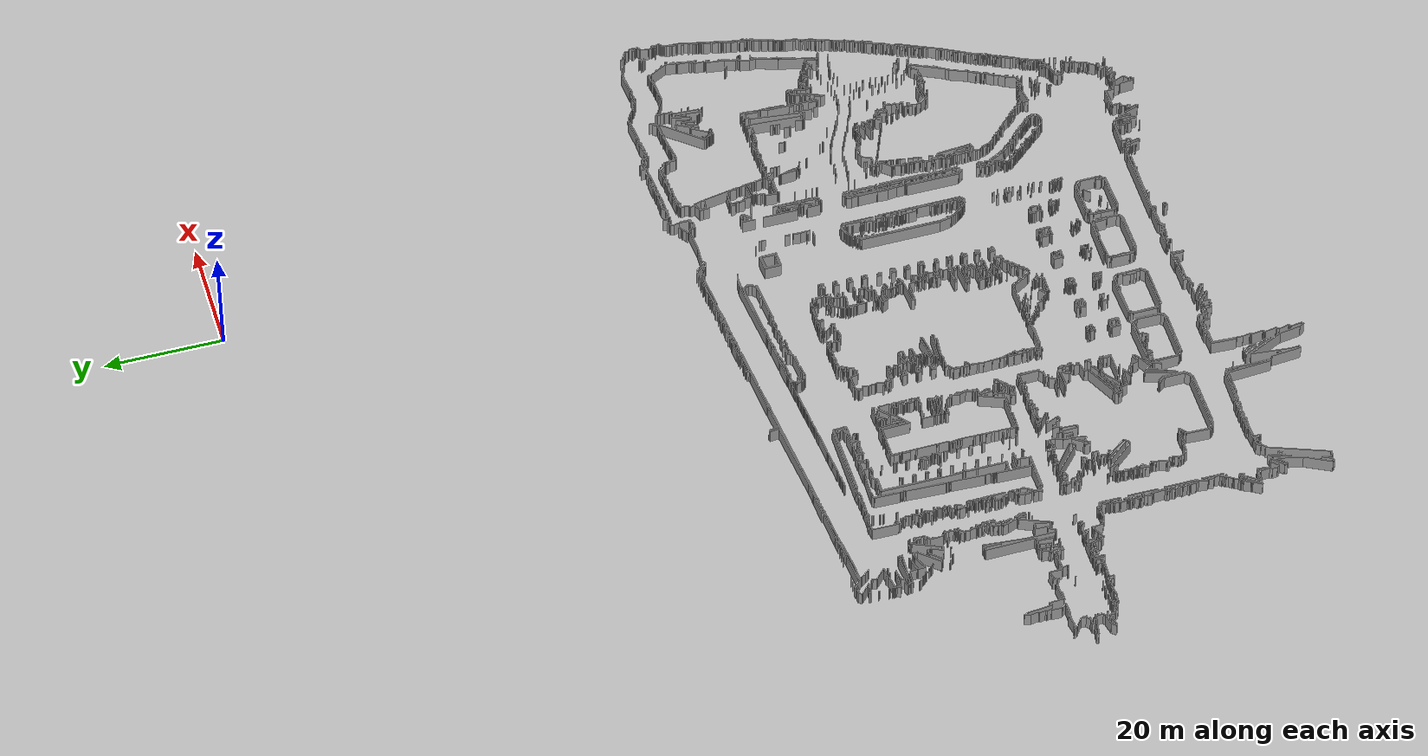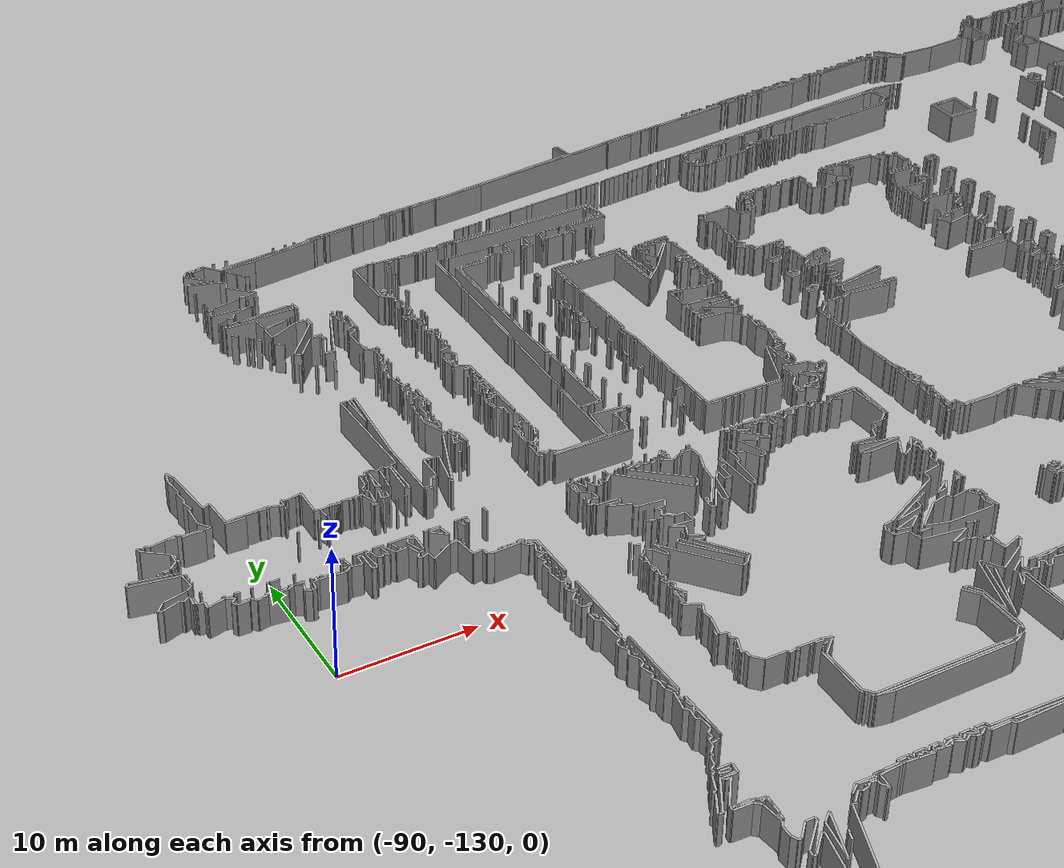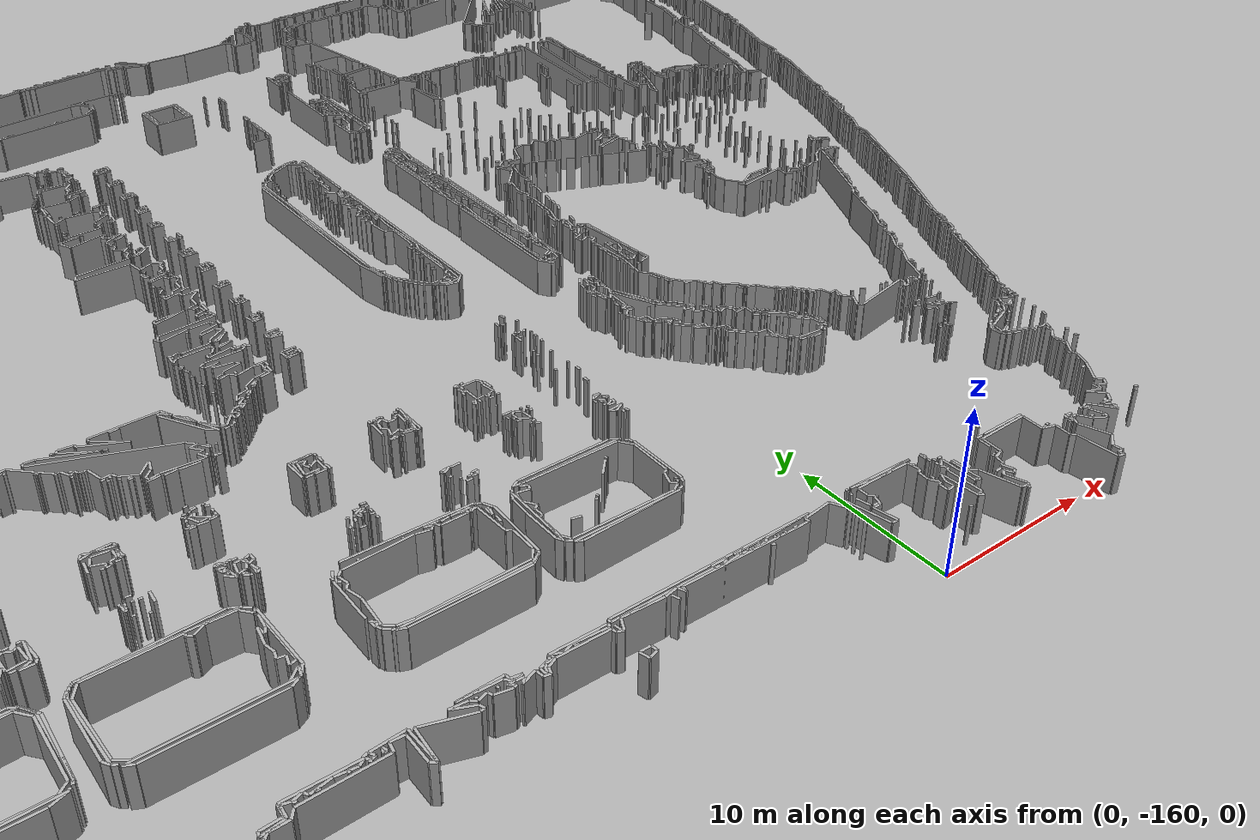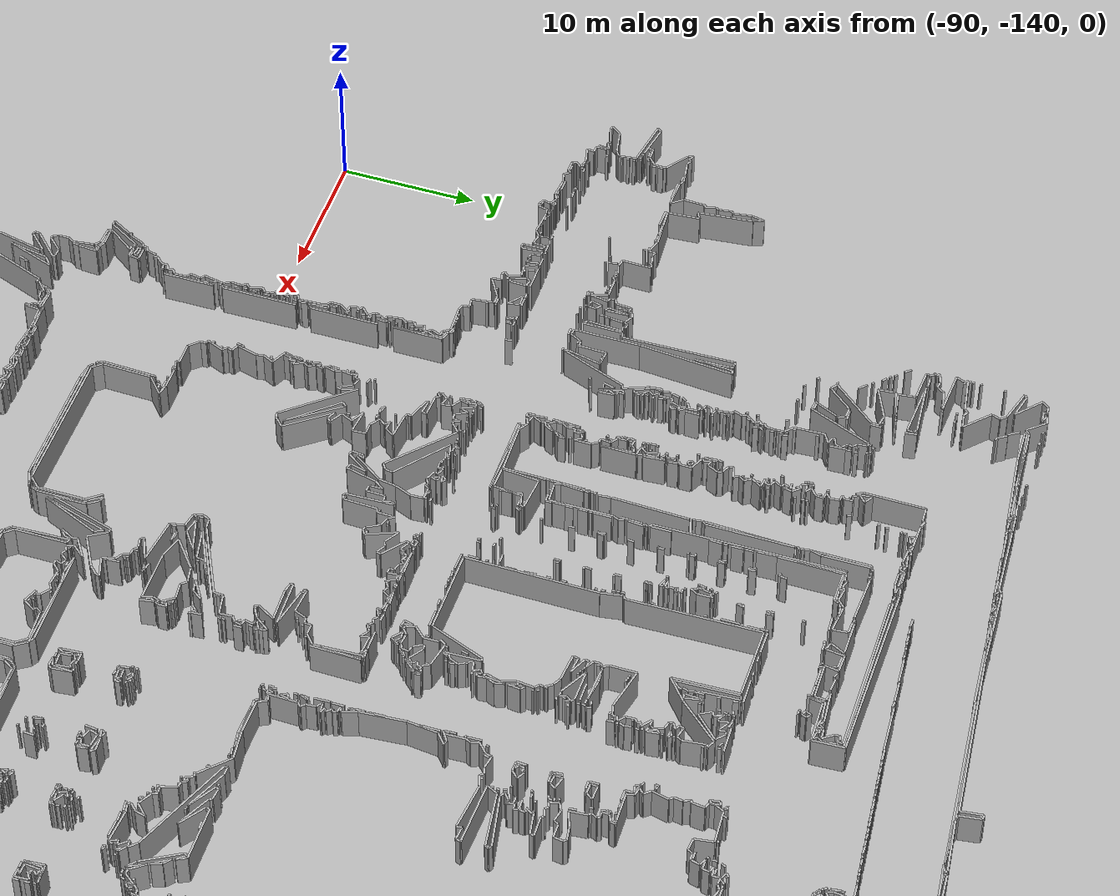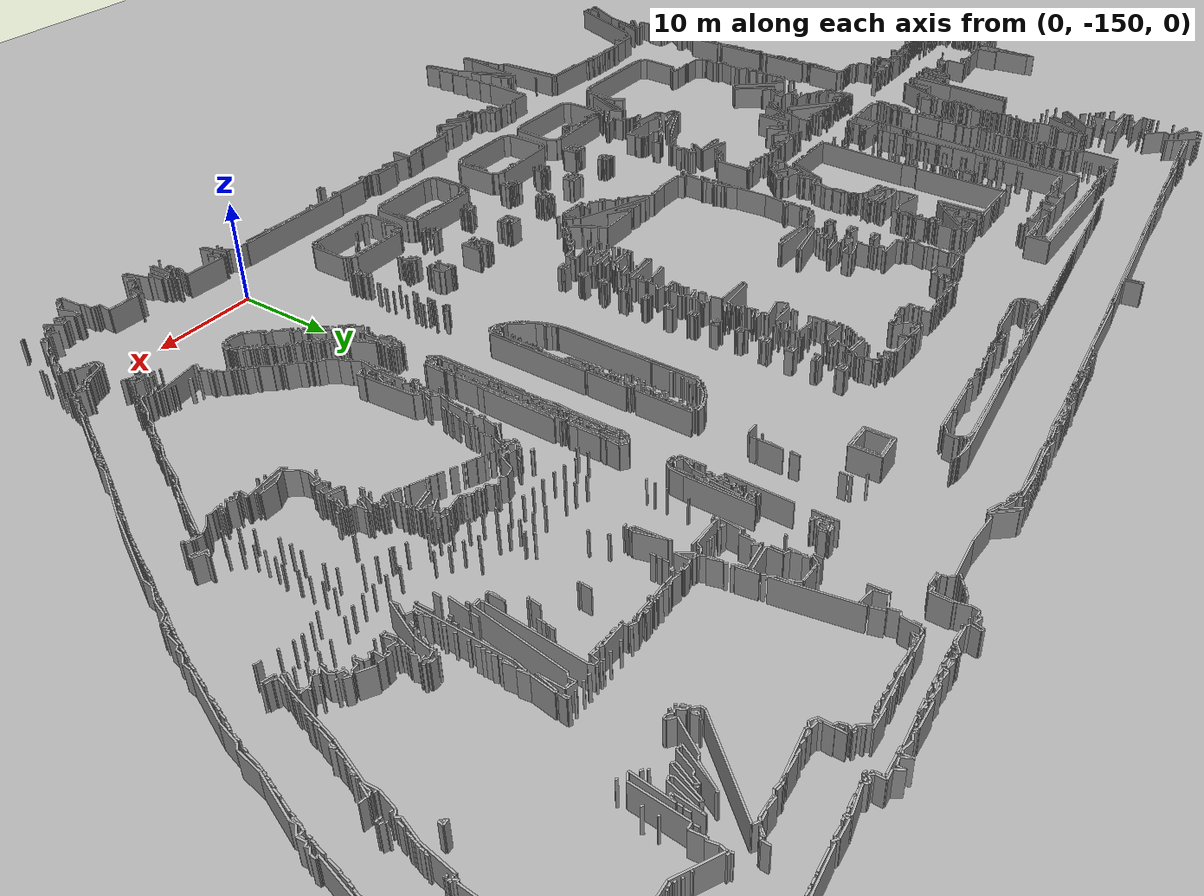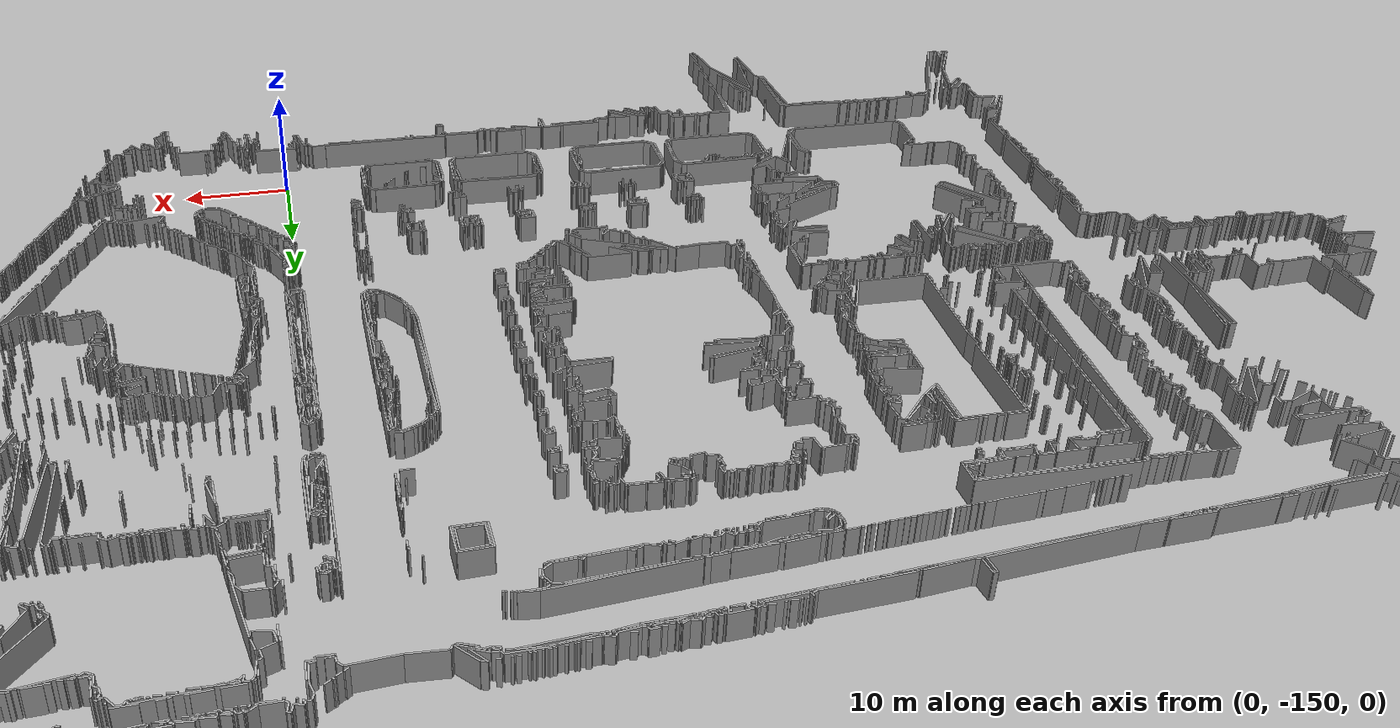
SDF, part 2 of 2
<collision name="Wall_2995_Collision">
     <pose>-48.349999999999994 -122.6 1.25 0 0 -0.7853981633974602</pose>
     <geometry><box><size>0.42426406871193956 0.15 2.5</size></box></geometry>
    </collision>
    <visual name="Wall_2995_Visual">
     <pose>-48.349999999999994 -122.6 1.25 0 0 -0.7853981633974602</pose>
     <geometry><box><size>0.42426406871193956 0.15 2.5</size></box></geometry>
     <material>
      <ambient>0.5 0.5 0.5 1</ambient>
      <diffuse>0.7 0.7 0.7 1</diffuse>
      <specular>0.1 0.1 0.1 1</specular>
     </material>
    </visual>
    <collision name="Wall_2996_Collision">
     <pose>-48.05 -122.675 1.25 0 0 0.4636476090008251</pose>
     <geometry><box><size>0.33541019662496846 0.15 2.5</size></box></geometry>
    </collision>
    <visual name="Wall_2996_Visual">
     <pose>-48.05 -122.675 1.25 0 0 0.4636476090008251</pose>
     <geometry><box><size>0.33541019662496846 0.15 2.5</size></box></geometry>
     <material>
      <ambient>0.5 0.5 0.5 1</ambient>
      <diffuse>0.7 0.7 0.7 1</diffuse>
      <specular>0.1 0.1 0.1 1</specular>
     </material>
    </visual>
    <collision name="Wall_2997_Collision">
     <pose>-47.775 -122.77499999999999 1.25 0 0 -0.9505468408120674</pose>
     <geometry><box><size>0.4301162633521267 0.15 2.5</size></box></geometry>
    </collision>
    <visual name="Wall_2997_Visual">
     <pose>-47.775 -122.77499999999999 1.25 0 0 -0.9505468408120674</pose>
     <geometry><box><size>0.4301162633521267 0.15 2.5</size></box></geometry>
     <material>
      <ambient>0.5 0.5 0.5 1</ambient>
      <diffuse>0.7 0.7 0.7 1</diffuse>
      <specular>0.1 0.1 0.1 1</specular>
     </material>
    </visual>
    <collision name="Wall_2998_Collision">
     <pose>-47.4 -122.8 1.25 0 0 0.5404195002705591</pose>
     <geometry><box><size>0.5830951894845213 0.15 2.5</size></box></geometry>
    </collision>
    <visual name="Wall_2998_Visual">
     <pose>-47.4 -122.8 1.25 0 0 0.5404195002705591</pose>
     <geometry><box><size>0.5830951894845213 0.15 2.5</size></box></geometry>
     <material>
      <ambient>0.5 0.5 0.5 1</ambient>
      <diffuse>0.7 0.7 0.7 1</diffuse>
      <specular>0.1 0.1 0.1 1</specular>
     </material>
    </visual>
    <collision name="Wall_2999_Collision">
     <pose>-46.849999999999994 -122.85 1.25 0 0 -0.5880026035475566</pose>
     <geometry><box><size>0.7211102550927944 0.15 2.5</size></box></geometry>
    </collision>
    <visual name="Wall_2999_Visual">
     <pose>-46.849999999999994 -122.85 1.25 0 0 -0.5880026035475566</pose>
     <geometry><box><size>0.7211102550927944 0.15 2.5</size></box></geometry>
     <material>
      <ambient>0.5 0.5 0.5 1</ambient>
      <diffuse>0.7 0.7 0.7 1</diffuse>
      <specular>0.1 0.1 0.1 1</specular>
     </material>
    </visual>
    <collision name="Wall_3000_Collision">
     <pose>-46.65 -122.75 1.25 0 0 1.892546881191539</pose>
     <geometry><box><size>0.6324555320336849 0.15 2.5</size></box></geometry>
    </collision>
    <visual name="Wall_3000_Visual">
     <pose>-46.65 -122.75 1.25 0 0 1.892546881191539</pose>
     <geometry><box><size>0.6324555320336849 0.15 2.5</size></box></geometry>
     <material>
      <ambient>0.5 0.5 0.5 1</ambient>
      <diffuse>0.7 0.7 0.7 1</diffuse>
      <specular>0.1 0.1 0.1 1</specular>
     </material>
    </visual>
    <collision name="Wall_3001_Collision">
     <pose>-45.95 -122.5 1.25 0 0 -0.0624188099959626</pose>
     <geometry><box><size>1.6031219541881416 0.15 2.5</size></box></geometry>
    </collision>
    <visual name="Wall_3001_Visual">
     <pose>-45.95 -122.5 1.25 0 0 -0.0624188099959626</pose>
     <geometry><box><size>1.6031219541881416 0.15 2.5</size></box></geometry>
     <material>
      <ambient>0.5 0.5 0.5 1</ambient>
      <diffuse>0.7 0.7 0.7 1</diffuse>
      <specular>0.1 0.1 0.1 1</specular>
     </material>
    </visual>
    <collision name="Wall_3002_Collision">
     <pose>-45.375 -122.4 1.25 0 0 2.5535900500422257</pose>
     <geometry><box><size>0.5408326913195932 0.15 2.5</size></box></geometry>
    </collision>
    <visual name="Wall_3002_Visual">
     <pose>-45.375 -122.4 1.25 0 0 2.5535900500422257</pose>
     <geometry><box><size>0.5408326913195932 0.15 2.5</size></box></geometry>
     <material>
      <ambient>0.5 0.5 0.5 1</ambient>
      <diffuse>0.7 0.7 0.7 1</diffuse>
      <specular>0.1 0.1 0.1 1</specular>
     </material>
    </visual>
    <collision name="Wall_3003_Collision">
     <pose>-45.224999999999994 -122.225 1.25 0 0 0.06656816377583889</pose>
     <geometry><box><size>0.7516648189186461 0.15 2.5</size></box></geometry>
    </collision>
    <visual name="Wall_3003_Visual">
     <pose>-45.224999999999994 -122.225 1.25 0 0 0.06656816377583889</pose>
     <geometry><box><size>0.7516648189186461 0.15 2.5</size></box></geometry>
     <material>
      <ambient>0.5 0.5 0.5 1</ambient>
      <diffuse>0.7 0.7 0.7 1</diffuse>
      <specular>0.1 0.1 0.1 1</specular>
     </material>
    </visual>
    <collision name="Wall_3004_Collision">
     <pose>-48.52499999999999 -122.225 1.25 0 0 -0.0767718912697956</pose>
     <geometry><box><size>0.6519202405202643 0.15 2.5</size></box></geometry>
    </collision>
    <visual name="Wall_3004_Visual">
     <pose>-48.52499999999999 -122.225 1.25 0 0 -0.0767718912697956</pose>
     <geometry><box><size>0.6519202405202643 0.15 2.5</size></box></geometry>
     <material>
      <ambient>0.5 0.5 0.5 1</ambient>
      <diffuse>0.7 0.7 0.7 1</diffuse>
      <specular>0.1 0.1 0.1 1</specular>
     </material>
    </visual>
    <collision name="Wall_3005_Collision">
     <pose>-49.4 -122.25 1.25 0 0 3.141592653589793</pose>
     <geometry><box><size>0.7000000000000028 0.15 2.5</size></box></geometry>
    </collision>
    <visual name="Wall_3005_Visual">
     <pose>-49.4 -122.25 1.25 0 0 3.141592653589793</pose>
     <geometry><box><size>0.7000000000000028 0.15 2.5</size></box></geometry>
     <material>
      <ambient>0.5 0.5 0.5 1</ambient>
      <diffuse>0.7 0.7 0.7 1</diffuse>
      <specular>0.1 0.1 0.1 1</specular>
     </material>
    </visual>
    <collision name="Wall_3006_Collision">
     <pose>-51.39999999999999 -122.225 1.25 0 0 0.12435499454678986</pose>
     <geometry><box><size>0.40311288741492746 0.15 2.5</size></box></geometry>
    </collision>
    <visual name="Wall_3006_Visual">
     <pose>-51.39999999999999 -122.225 1.25 0 0 0.12435499454678986</pose>
     <geometry><box><size>0.40311288741492746 0.15 2.5</size></box></geometry>
     <material>
      <ambient>0.5 0.5 0.5 1</ambient>
      <diffuse>0.7 0.7 0.7 1</diffuse>
      <specular>0.1 0.1 0.1 1</specular>
     </material>
    </visual>
    <collision name="Wall_3007_Collision">
     <pose>-51.3 -122.32499999999999 1.25 0 0 -2.245537269018456</pose>
     <geometry><box><size>0.3201562118716442 0.15 2.5</size></box></geometry>
    </collision>
    <visual name="Wall_3007_Visual">
     <pose>-51.3 -122.32499999999999 1.25 0 0 -2.245537269018456</pose>
     <geometry><box><size>0.3201562118716442 0.15 2.5</size></box></geometry>
     <material>
      <ambient>0.5 0.5 0.5 1</ambient>
      <diffuse>0.7 0.7 0.7 1</diffuse>
      <specular>0.1 0.1 0.1 1</specular>
     </material>
    </visual>
    <collision name="Wall_3008_Collision">
     <pose>-51.5 -122.35 1.25 0 0 2.3561944901923626</pose>
     <geometry><box><size>0.28284271247460796 0.15 2.5</size></box></geometry>
    </collision>
    <visual name="Wall_3008_Visual">
     <pose>-51.5 -122.35 1.25 0 0 2.3561944901923626</pose>
     <geometry><box><size>0.28284271247460796 0.15 2.5</size></box></geometry>
     <material>
      <ambient>0.5 0.5 0.5 1</ambient>
      <diffuse>0.7 0.7 0.7 1</diffuse>
      <specular>0.1 0.1 0.1 1</specular>
     </material>
    </visual>
    <collision name="Wall_3009_Collision">
     <pose>-52.175 -122.225 1.25 0 0 -0.07677189126979476</pose>
     <geometry><box><size>0.6519202405202714 0.15 2.5</size></box></geometry>
    </collision>
    <visual name="Wall_3009_Visual">
     <pose>-52.175 -122.225 1.25 0 0 -0.07677189126979476</pose>
     <geometry><box><size>0.6519202405202714 0.15 2.5</size></box></geometry>
     <material>
      <ambient>0.5 0.5 0.5 1</ambient>
      <diffuse>0.7 0.7 0.7 1</diffuse>
      <specular>0.1 0.1 0.1 1</specular>
     </material>
    </visual>
    <collision name="Wall_3010_Collision">
     <pose>-51.949999999999996 -122.35 1.25 0 0 -2.3561944901923804</pose>
     <geometry><box><size>0.28284271247461296 0.15 2.5</size></box></geometry>
    </collision>
    <visual name="Wall_3010_Visual">
     <pose>-51.949999999999996 -122.35 1.25 0 0 -2.3561944901923804</pose>
     <geometry><box><size>0.28284271247461296 0.15 2.5</size></box></geometry>
     <material>
      <ambient>0.5 0.5 0.5 1</ambient>
      <diffuse>0.7 0.7 0.7 1</diffuse>
      <specular>0.1 0.1 0.1 1</specular>
     </material>
    </visual>
    <collision name="Wall_3011_Collision">
     <pose>-52.275 -122.32499999999999 1.25 0 0 2.634494149197459</pose>
     <geometry><box><size>0.5147815070493525 0.15 2.5</size></box></geometry>
    </collision>
    <visual name="Wall_3011_Visual">
     <pose>-52.275 -122.32499999999999 1.25 0 0 2.634494149197459</pose>
     <geometry><box><size>0.5147815070493525 0.15 2.5</size></box></geometry>
     <material>
      <ambient>0.5 0.5 0.5 1</ambient>
      <diffuse>0.7 0.7 0.7 1</diffuse>
      <specular>0.1 0.1 0.1 1</specular>
     </material>
    </visual>
    <collision name="Wall_3012_Collision">
     <pose>-54.824999999999996 -122.19999999999999 1.25 0 0 0.0</pose>
     <geometry><box><size>0.25 0.15 2.5</size></box></geometry>
    </collision>
    <visual name="Wall_3012_Visual">
     <pose>-54.824999999999996 -122.19999999999999 1.25 0 0 0.0</pose>
     <geometry><box><size>0.25 0.15 2.5</size></box></geometry>
     <material>
      <ambient>0.5 0.5 0.5 1</ambient>
      <diffuse>0.7 0.7 0.7 1</diffuse>
      <specular>0.1 0.1 0.1 1</specular>
     </material>
    </visual>
    <collision name="Wall_3013_Collision">
     <pose>-55.55 -122.3 1.25 0 0 1.5707963267948966</pose>
     <geometry><box><size>0.29999999999998295 0.15 2.5</size></box></geometry>
    </collision>
    <visual name="Wall_3013_Visual">
     <pose>-55.55 -122.3 1.25 0 0 1.5707963267948966</pose>
     <geometry><box><size>0.29999999999998295 0.15 2.5</size></box></geometry>
     <material>
      <ambient>0.5 0.5 0.5 1</ambient>
      <diffuse>0.7 0.7 0.7 1</diffuse>
      <specular>0.1 0.1 0.1 1</specular>
     </material>
    </visual>
    <collision name="Wall_3014_Collision">
     <pose>-55.3 -122.175 1.25 0 0 -0.09966865249112826</pose>
     <geometry><box><size>0.5024937810560428 0.15 2.5</size></box></geometry>
    </collision>
    <visual name="Wall_3014_Visual">
     <pose>-55.3 -122.175 1.25 0 0 -0.09966865249112826</pose>
     <geometry><box><size>0.5024937810560428 0.15 2.5</size></box></geometry>
     <material>
      <ambient>0.5 0.5 0.5 1</ambient>
      <diffuse>0.7 0.7 0.7 1</diffuse>
      <specular>0.1 0.1 0.1 1</specular>
     </material>
    </visual>
    <collision name="Wall_3015_Collision">
     <pose>-55.125 -122.35 1.25 0 0 -2.0344439357956836</pose>
     <geometry><box><size>0.335410196624978 0.15 2.5</size></box></geometry>
    </collision>
    <visual name="Wall_3015_Visual">
     <pose>-55.125 -122.35 1.25 0 0 -2.0344439357956836</pose>
     <geometry><box><size>0.335410196624978 0.15 2.5</size></box></geometry>
     <material>
      <ambient>0.5 0.5 0.5 1</ambient>
      <diffuse>0.7 0.7 0.7 1</diffuse>
      <specular>0.1 0.1 0.1 1</specular>
     </material>
    </visual>
    <collision name="Wall_3016_Collision">
     <pose>-55.375 -122.475 1.25 0 0 2.999695598985598</pose>
     <geometry><box><size>0.3535533905932768 0.15 2.5</size></box></geometry>
    </collision>
    <visual name="Wall_3016_Visual">
     <pose>-55.375 -122.475 1.25 0 0 2.999695598985598</pose>
     <geometry><box><size>0.3535533905932768 0.15 2.5</size></box></geometry>
     <material>
      <ambient>0.5 0.5 0.5 1</ambient>
      <diffuse>0.7 0.7 0.7 1</diffuse>
      <specular>0.1 0.1 0.1 1</specular>
     </material>
    </visual>
    <collision name="Wall_3017_Collision">
     <pose>-56.25 -122.19999999999999 1.25 0 0 0.0</pose>
     <geometry><box><size>0.30000000000000426 0.15 2.5</size></box></geometry>
    </collision>
    <visual name="Wall_3017_Visual">
     <pose>-56.25 -122.19999999999999 1.25 0 0 0.0</pose>
     <geometry><box><size>0.30000000000000426 0.15 2.5</size></box></geometry>
     <material>
      <ambient>0.5 0.5 0.5 1</ambient>
      <diffuse>0.7 0.7 0.7 1</diffuse>
      <specular>0.1 0.1 0.1 1</specular>
     </material>
    </visual>
    <collision name="Wall_3018_Collision">
     <pose>-61.39999999999999 -122.45 1.25 0 0 -2.976443976175176</pose>
     <geometry><box><size>0.6082762530298225 0.15 2.5</size></box></geometry>
    </collision>
    <visual name="Wall_3018_Visual">
     <pose>-61.39999999999999 -122.45 1.25 0 0 -2.976443976175176</pose>
     <geometry><box><size>0.6082762530298225 0.15 2.5</size></box></geometry>
     <material>
      <ambient>0.5 0.5 0.5 1</ambient>
      <diffuse>0.7 0.7 0.7 1</diffuse>
      <specular>0.1 0.1 0.1 1</specular>
     </material>
    </visual>
    <collision name="Wall_3019_Collision">
     <pose>-61.52499999999999 -122.325 1.25 0 0 0.7853981633974382</pose>
     <geometry><box><size>0.49497474683058024 0.15 2.5</size></box></geometry>
    </collision>
    <visual name="Wall_3019_Visual">
     <pose>-61.52499999999999 -122.325 1.25 0 0 0.7853981633974382</pose>
     <geometry><box><size>0.49497474683058024 0.15 2.5</size></box></geometry>
     <material>
      <ambient>0.5 0.5 0.5 1</ambient>
      <diffuse>0.7 0.7 0.7 1</diffuse>
      <specular>0.1 0.1 0.1 1</specular>
     </material>
    </visual>
    <collision name="Wall_3020_Collision">
     <pose>-61.224999999999994 -122.275 1.25 0 0 -0.7853981633974483</pose>
     <geometry><box><size>0.3535533905932738 0.15 2.5</size></box></geometry>
    </collision>
    <visual name="Wall_3020_Visual">
     <pose>-61.224999999999994 -122.275 1.25 0 0 -0.7853981633974483</pose>
     <geometry><box><size>0.3535533905932738 0.15 2.5</size></box></geometry>
     <material>
      <ambient>0.5 0.5 0.5 1</ambient>
      <diffuse>0.7 0.7 0.7 1</diffuse>
      <specular>0.1 0.1 0.1 1</specular>
     </material>
    </visual>
    <collision name="Wall_3021_Collision">
     <pose>31.150000000000006 -122.19999999999999 1.25 0 0 -1.5707963267948966</pose>
     <geometry><box><size>0.20000000000000284 0.15 2.5</size></box></geometry>
    </collision>
    <visual name="Wall_3021_Visual">
     <pose>31.150000000000006 -122.19999999999999 1.25 0 0 -1.5707963267948966</pose>
     <geometry><box><size>0.20000000000000284 0.15 2.5</size></box></geometry>
     <material>
      <ambient>0.5 0.5 0.5 1</ambient>
      <diffuse>0.7 0.7 0.7 1</diffuse>
      <specular>0.1 0.1 0.1 1</specular>
     </material>
    </visual>
    <collision name="Wall_3022_Collision">
     <pose>-49.9 -122.25 1.25 0 0 -2.3561944901923804</pose>
     <geometry><box><size>0.28284271247461296 0.15 2.5</size></box></geometry>
    </collision>
    <visual name="Wall_3022_Visual">
     <pose>-49.9 -122.25 1.25 0 0 -2.3561944901923804</pose>
     <geometry><box><size>0.28284271247461296 0.15 2.5</size></box></geometry>
     <material>
      <ambient>0.5 0.5 0.5 1</ambient>
      <diffuse>0.7 0.7 0.7 1</diffuse>
      <specular>0.1 0.1 0.1 1</specular>
     </material>
    </visual>
    <collision name="Wall_3023_Collision">
     <pose>-50.525 -122.3 1.25 0 0 3.046640947247042</pose>
     <geometry><box><size>1.054751155486446 0.15 2.5</size></box></geometry>
    </collision>
    <visual name="Wall_3023_Visual">
     <pose>-50.525 -122.3 1.25 0 0 3.046640947247042</pose>
     <geometry><box><size>1.054751155486446 0.15 2.5</size></box></geometry>
     <material>
      <ambient>0.5 0.5 0.5 1</ambient>
      <diffuse>0.7 0.7 0.7 1</diffuse>
      <specular>0.1 0.1 0.1 1</specular>
     </material>
    </visual>
    <collision name="Wall_3024_Collision">
     <pose>-50.425 -122.2 1.25 0 0 0.07982998571223279</pose>
     <geometry><box><size>1.2539936203984448 0.15 2.5</size></box></geometry>
    </collision>
    <visual name="Wall_3024_Visual">
     <pose>-50.425 -122.2 1.25 0 0 0.07982998571223279</pose>
     <geometry><box><size>1.2539936203984448 0.15 2.5</size></box></geometry>
     <material>
      <ambient>0.5 0.5 0.5 1</ambient>
      <diffuse>0.7 0.7 0.7 1</diffuse>
      <specular>0.1 0.1 0.1 1</specular>
     </material>
    </visual>
    <collision name="Wall_3025_Collision">
     <pose>-53.575 -122.175 1.25 0 0 0.027020449187255557</pose>
     <geometry><box><size>1.8506755523321756 0.15 2.5</size></box></geometry>
    </collision>
    <visual name="Wall_3025_Visual">
     <pose>-53.575 -122.175 1.25 0 0 0.027020449187255557</pose>
     <geometry><box><size>1.8506755523321756 0.15 2.5</size></box></geometry>
     <material>
      <ambient>0.5 0.5 0.5 1</ambient>
      <diffuse>0.7 0.7 0.7 1</diffuse>
      <specular>0.1 0.1 0.1 1</specular>
     </material>
    </visual>
    <collision name="Wall_3026_Collision">
     <pose>-52.625 -122.25 1.25 0 0 -1.325817663667999</pose>
     <geometry><box><size>0.20615528128087304 0.15 2.5</size></box></geometry>
    </collision>
    <visual name="Wall_3026_Visual">
     <pose>-52.625 -122.25 1.25 0 0 -1.325817663667999</pose>
     <geometry><box><size>0.20615528128087304 0.15 2.5</size></box></geometry>
     <material>
      <ambient>0.5 0.5 0.5 1</ambient>
      <diffuse>0.7 0.7 0.7 1</diffuse>
      <specular>0.1 0.1 0.1 1</specular>
     </material>
    </visual>
    <collision name="Wall_3027_Collision">
     <pose>-53.55 -122.27499999999999 1.25 0 0 3.0628086926006466</pose>
     <geometry><box><size>1.905911855254598 0.15 2.5</size></box></geometry>
    </collision>
    <visual name="Wall_3027_Visual">
     <pose>-53.55 -122.27499999999999 1.25 0 0 3.0628086926006466</pose>
     <geometry><box><size>1.905911855254598 0.15 2.5</size></box></geometry>
     <material>
      <ambient>0.5 0.5 0.5 1</ambient>
      <diffuse>0.7 0.7 0.7 1</diffuse>
      <specular>0.1 0.1 0.1 1</specular>
     </material>
    </visual>
    <collision name="Wall_3028_Collision">
     <pose>-40.699999999999996 -122.5 1.25 0 0 -1.5707963267948966</pose>
     <geometry><box><size>0.8999999999999915 0.15 2.5</size></box></geometry>
    </collision>
    <visual name="Wall_3028_Visual">
     <pose>-40.699999999999996 -122.5 1.25 0 0 -1.5707963267948966</pose>
     <geometry><box><size>0.8999999999999915 0.15 2.5</size></box></geometry>
     <material>
      <ambient>0.5 0.5 0.5 1</ambient>
      <diffuse>0.7 0.7 0.7 1</diffuse>
      <specular>0.1 0.1 0.1 1</specular>
     </material>
    </visual>
    <collision name="Wall_3029_Collision">
     <pose>-9.199999999999989 -122.1 1.25 0 0 -1.5707963267948966</pose>
     <geometry><box><size>0.19999999999998863 0.15 2.5</size></box></geometry>
    </collision>
    <visual name="Wall_3029_Visual">
     <pose>-9.199999999999989 -122.1 1.25 0 0 -1.5707963267948966</pose>
     <geometry><box><size>0.19999999999998863 0.15 2.5</size></box></geometry>
     <material>
      <ambient>0.5 0.5 0.5 1</ambient>
      <diffuse>0.7 0.7 0.7 1</diffuse>
      <specular>0.1 0.1 0.1 1</specular>
     </material>
    </visual>
    <collision name="Wall_3030_Collision">
     <pose>-20.27499999999999 -122.375 1.25 0 0 -2.4275019549776418</pose>
     <geometry><box><size>0.9924716620639548 0.15 2.5</size></box></geometry>
    </collision>
    <visual name="Wall_3030_Visual">
     <pose>-20.27499999999999 -122.375 1.25 0 0 -2.4275019549776418</pose>
     <geometry><box><size>0.9924716620639548 0.15 2.5</size></box></geometry>
     <material>
      <ambient>0.5 0.5 0.5 1</ambient>
      <diffuse>0.7 0.7 0.7 1</diffuse>
      <specular>0.1 0.1 0.1 1</specular>
     </material>
    </visual>
    <collision name="Wall_3031_Collision">
     <pose>-20.79999999999999 -122.675 1.25 0 0 2.9764439761752204</pose>
     <geometry><box><size>0.3041381265149054 0.15 2.5</size></box></geometry>
    </collision>
    <visual name="Wall_3031_Visual">
     <pose>-20.79999999999999 -122.675 1.25 0 0 2.9764439761752204</pose>
     <geometry><box><size>0.3041381265149054 0.15 2.5</size></box></geometry>
     <material>
      <ambient>0.5 0.5 0.5 1</ambient>
      <diffuse>0.7 0.7 0.7 1</diffuse>
      <specular>0.1 0.1 0.1 1</specular>
     </material>
    </visual>
    <collision name="Wall_3032_Collision">
     <pose>-20.42499999999999 -122.35 1.25 0 0 0.5191461142465302</pose>
     <geometry><box><size>1.2093386622447841 0.15 2.5</size></box></geometry>
    </collision>
    <visual name="Wall_3032_Visual">
     <pose>-20.42499999999999 -122.35 1.25 0 0 0.5191461142465302</pose>
     <geometry><box><size>1.2093386622447841 0.15 2.5</size></box></geometry>
     <material>
      <ambient>0.5 0.5 0.5 1</ambient>
      <diffuse>0.7 0.7 0.7 1</diffuse>
      <specular>0.1 0.1 0.1 1</specular>
     </material>
    </visual>
    <collision name="Wall_3033_Collision">
     <pose>-68.7 -122.15 1.25 0 0 -1.5707963267948966</pose>
     <geometry><box><size>0.29999999999999716 0.15 2.5</size></box></geometry>
    </collision>
    <visual name="Wall_3033_Visual">
     <pose>-68.7 -122.15 1.25 0 0 -1.5707963267948966</pose>
     <geometry><box><size>0.29999999999999716 0.15 2.5</size></box></geometry>
     <material>
      <ambient>0.5 0.5 0.5 1</ambient>
      <diffuse>0.7 0.7 0.7 1</diffuse>
      <specular>0.1 0.1 0.1 1</specular>
     </material>
    </visual>
    <collision name="Wall_3034_Collision">
     <pose>-68.80000000000001 -122.3 1.25 0 0 3.141592653589793</pose>
     <geometry><box><size>0.20000000000000284 0.15 2.5</size></box></geometry>
    </collision>
    <visual name="Wall_3034_Visual">
     <pose>-68.80000000000001 -122.3 1.25 0 0 3.141592653589793</pose>
     <geometry><box><size>0.20000000000000284 0.15 2.5</size></box></geometry>
     <material>
      <ambient>0.5 0.5 0.5 1</ambient>
      <diffuse>0.7 0.7 0.7 1</diffuse>
      <specular>0.1 0.1 0.1 1</specular>
     </material>
    </visual>
    <collision name="Wall_3035_Collision">
     <pose>-68.80000000000001 -122.15 1.25 0 0 0.9827937232473182</pose>
     <geometry><box><size>0.3605551275463981 0.15 2.5</size></box></geometry>
    </collision>
    <visual name="Wall_3035_Visual">
     <pose>-68.80000000000001 -122.15 1.25 0 0 0.9827937232473182</pose>
     <geometry><box><size>0.3605551275463981 0.15 2.5</size></box></geometry>
     <material>
      <ambient>0.5 0.5 0.5 1</ambient>
      <diffuse>0.7 0.7 0.7 1</diffuse>
      <specular>0.1 0.1 0.1 1</specular>
     </material>
    </visual>
    <collision name="Wall_3036_Collision">
     <pose>-62.474999999999994 -122.0 1.25 0 0 0.0</pose>
     <geometry><box><size>0.14999999999999858 0.15 2.5</size></box></geometry>
    </collision>
    <visual name="Wall_3036_Visual">
     <pose>-62.474999999999994 -122.0 1.25 0 0 0.0</pose>
     <geometry><box><size>0.14999999999999858 0.15 2.5</size></box></geometry>
     <material>
      <ambient>0.5 0.5 0.5 1</ambient>
      <diffuse>0.7 0.7 0.7 1</diffuse>
      <specular>0.1 0.1 0.1 1</specular>
     </material>
    </visual>
    <collision name="Wall_3037_Collision">
     <pose>-75.225 -122.225 1.25 0 0 -1.4801364395941585</pose>
     <geometry><box><size>0.5522680508593741 0.15 2.5</size></box></geometry>
    </collision>
    <visual name="Wall_3037_Visual">
     <pose>-75.225 -122.225 1.25 0 0 -1.4801364395941585</pose>
     <geometry><box><size>0.5522680508593741 0.15 2.5</size></box></geometry>
     <material>
      <ambient>0.5 0.5 0.5 1</ambient>
      <diffuse>0.7 0.7 0.7 1</diffuse>
      <specular>0.1 0.1 0.1 1</specular>
     </material>
    </visual>
    <collision name="Wall_3038_Collision">
     <pose>-68.375 -121.94999999999999 1.25 0 0 0.0</pose>
     <geometry><box><size>0.15000000000000568 0.15 2.5</size></box></geometry>
    </collision>
    <visual name="Wall_3038_Visual">
     <pose>-68.375 -121.94999999999999 1.25 0 0 0.0</pose>
     <geometry><box><size>0.15000000000000568 0.15 2.5</size></box></geometry>
     <material>
      <ambient>0.5 0.5 0.5 1</ambient>
      <diffuse>0.7 0.7 0.7 1</diffuse>
      <specular>0.1 0.1 0.1 1</specular>
     </material>
    </visual>
    <collision name="Wall_3039_Collision">
     <pose>-68.625 -121.94999999999999 1.25 0 0 0.0</pose>
     <geometry><box><size>0.15000000000000568 0.15 2.5</size></box></geometry>
    </collision>
    <visual name="Wall_3039_Visual">
     <pose>-68.625 -121.94999999999999 1.25 0 0 0.0</pose>
     <geometry><box><size>0.15000000000000568 0.15 2.5</size></box></geometry>
     <material>
      <ambient>0.5 0.5 0.5 1</ambient>
      <diffuse>0.7 0.7 0.7 1</diffuse>
      <specular>0.1 0.1 0.1 1</specular>
     </material>
    </visual>
    <collision name="Wall_3040_Collision">
     <pose>3.5500000000000114 -122.175 1.25 0 0 -1.5707963267948966</pose>
     <geometry><box><size>0.6500000000000057 0.15 2.5</size></box></geometry>
    </collision>
    <visual name="Wall_3040_Visual">
     <pose>3.5500000000000114 -122.175 1.25 0 0 -1.5707963267948966</pose>
     <geometry><box><size>0.6500000000000057 0.15 2.5</size></box></geometry>
     <material>
      <ambient>0.5 0.5 0.5 1</ambient>
      <diffuse>0.7 0.7 0.7 1</diffuse>
      <specular>0.1 0.1 0.1 1</specular>
     </material>
    </visual>
    <collision name="Wall_3041_Collision">
     <pose>3.6000000000000085 -121.75 1.25 0 0 -1.5707963267948966</pose>
     <geometry><box><size>0.19999999999998863 0.15 2.5</size></box></geometry>
    </collision>
    <visual name="Wall_3041_Visual">
     <pose>3.6000000000000085 -121.75 1.25 0 0 -1.5707963267948966</pose>
     <geometry><box><size>0.19999999999998863 0.15 2.5</size></box></geometry>
     <material>
      <ambient>0.5 0.5 0.5 1</ambient>
      <diffuse>0.7 0.7 0.7 1</diffuse>
      <specular>0.1 0.1 0.1 1</specular>
     </material>
    </visual>
    <collision name="Wall_3042_Collision">
     <pose>-40.575 -121.675 1.25 0 0 -0.3217505543965427</pose>
     <geometry><box><size>0.15811388300841223 0.15 2.5</size></box></geometry>
    </collision>
    <visual name="Wall_3042_Visual">
     <pose>-40.575 -121.675 1.25 0 0 -0.3217505543965427</pose>
     <geometry><box><size>0.15811388300841223 0.15 2.5</size></box></geometry>
     <material>
      <ambient>0.5 0.5 0.5 1</ambient>
      <diffuse>0.7 0.7 0.7 1</diffuse>
      <specular>0.1 0.1 0.1 1</specular>
     </material>
    </visual>
    <collision name="Wall_3043_Collision">
     <pose>31.375 -121.625 1.25 0 0 -1.712693381399089</pose>
     <geometry><box><size>0.35355339059328383 0.15 2.5</size></box></geometry>
    </collision>
    <visual name="Wall_3043_Visual">
     <pose>31.375 -121.625 1.25 0 0 -1.712693381399089</pose>
     <geometry><box><size>0.35355339059328383 0.15 2.5</size></box></geometry>
     <material>
      <ambient>0.5 0.5 0.5 1</ambient>
      <diffuse>0.7 0.7 0.7 1</diffuse>
      <specular>0.1 0.1 0.1 1</specular>
     </material>
    </visual>
    <collision name="Wall_3044_Collision">
     <pose>17.650000000000006 -121.69999999999999 1.25 0 0 -1.7681918866447663</pose>
     <geometry><box><size>0.5099019513592774 0.15 2.5</size></box></geometry>
    </collision>
    <visual name="Wall_3044_Visual">
     <pose>17.650000000000006 -121.69999999999999 1.25 0 0 -1.7681918866447663</pose>
     <geometry><box><size>0.5099019513592774 0.15 2.5</size></box></geometry>
     <material>
      <ambient>0.5 0.5 0.5 1</ambient>
      <diffuse>0.7 0.7 0.7 1</diffuse>
      <specular>0.1 0.1 0.1 1</specular>
     </material>
    </visual>
    <collision name="Wall_3045_Collision">
     <pose>-17.824999999999996 -121.425 1.25 0 0 0.14189705460411275</pose>
     <geometry><box><size>0.3535533905932798 0.15 2.5</size></box></geometry>
    </collision>
    <visual name="Wall_3045_Visual">
     <pose>-17.824999999999996 -121.425 1.25 0 0 0.14189705460411275</pose>
     <geometry><box><size>0.3535533905932798 0.15 2.5</size></box></geometry>
     <material>
      <ambient>0.5 0.5 0.5 1</ambient>
      <diffuse>0.7 0.7 0.7 1</diffuse>
      <specular>0.1 0.1 0.1 1</specular>
     </material>
    </visual>
    <collision name="Wall_3046_Collision">
     <pose>-17.599999999999994 -121.55 1.25 0 0 -1.2490457723982544</pose>
     <geometry><box><size>0.31622776601681996 0.15 2.5</size></box></geometry>
    </collision>
    <visual name="Wall_3046_Visual">
     <pose>-17.599999999999994 -121.55 1.25 0 0 -1.2490457723982544</pose>
     <geometry><box><size>0.31622776601681996 0.15 2.5</size></box></geometry>
     <material>
      <ambient>0.5 0.5 0.5 1</ambient>
      <diffuse>0.7 0.7 0.7 1</diffuse>
      <specular>0.1 0.1 0.1 1</specular>
     </material>
    </visual>
    <collision name="Wall_3047_Collision">
     <pose>-17.749999999999993 -121.75 1.25 0 0 -2.896613990462904</pose>
     <geometry><box><size>0.41231056256175985 0.15 2.5</size></box></geometry>
    </collision>
    <visual name="Wall_3047_Visual">
     <pose>-17.749999999999993 -121.75 1.25 0 0 -2.896613990462904</pose>
     <geometry><box><size>0.41231056256175985 0.15 2.5</size></box></geometry>
     <material>
      <ambient>0.5 0.5 0.5 1</ambient>
      <diffuse>0.7 0.7 0.7 1</diffuse>
      <specular>0.1 0.1 0.1 1</specular>
     </material>
    </visual>
    <collision name="Wall_3048_Collision">
     <pose>-17.974999999999994 -121.625 1.25 0 0 1.712693381399089</pose>
     <geometry><box><size>0.35355339059328383 0.15 2.5</size></box></geometry>
    </collision>
    <visual name="Wall_3048_Visual">
     <pose>-17.974999999999994 -121.625 1.25 0 0 1.712693381399089</pose>
     <geometry><box><size>0.35355339059328383 0.15 2.5</size></box></geometry>
     <material>
      <ambient>0.5 0.5 0.5 1</ambient>
      <diffuse>0.7 0.7 0.7 1</diffuse>
      <specular>0.1 0.1 0.1 1</specular>
     </material>
    </visual>
    <collision name="Wall_3049_Collision">
     <pose>-20.174999999999997 -121.4 1.25 0 0 0.0</pose>
     <geometry><box><size>0.15000000000000568 0.15 2.5</size></box></geometry>
    </collision>
    <visual name="Wall_3049_Visual">
     <pose>-20.174999999999997 -121.4 1.25 0 0 0.0</pose>
     <geometry><box><size>0.15000000000000568 0.15 2.5</size></box></geometry>
     <material>
      <ambient>0.5 0.5 0.5 1</ambient>
      <diffuse>0.7 0.7 0.7 1</diffuse>
      <specular>0.1 0.1 0.1 1</specular>
     </material>
    </visual>
    <collision name="Wall_3050_Collision">
     <pose>-40.575 -121.375 1.25 0 0 -0.7853981633974246</pose>
     <geometry><box><size>0.21213203435595723 0.15 2.5</size></box></geometry>
    </collision>
    <visual name="Wall_3050_Visual">
     <pose>-40.575 -121.375 1.25 0 0 -0.7853981633974246</pose>
     <geometry><box><size>0.21213203435595723 0.15 2.5</size></box></geometry>
     <material>
      <ambient>0.5 0.5 0.5 1</ambient>
      <diffuse>0.7 0.7 0.7 1</diffuse>
      <specular>0.1 0.1 0.1 1</specular>
     </material>
    </visual>
    <collision name="Wall_3051_Collision">
     <pose>-40.575 -121.55 1.25 0 0 -2.2142974355881355</pose>
     <geometry><box><size>0.25000000000001277 0.15 2.5</size></box></geometry>
    </collision>
    <visual name="Wall_3051_Visual">
     <pose>-40.575 -121.55 1.25 0 0 -2.2142974355881355</pose>
     <geometry><box><size>0.25000000000001277 0.15 2.5</size></box></geometry>
     <material>
      <ambient>0.5 0.5 0.5 1</ambient>
      <diffuse>0.7 0.7 0.7 1</diffuse>
      <specular>0.1 0.1 0.1 1</specular>
     </material>
    </visual>
    <collision name="Wall_3052_Collision">
     <pose>-40.65 -121.475 1.25 0 0 1.5707963267948966</pose>
     <geometry><box><size>0.3500000000000085 0.15 2.5</size></box></geometry>
    </collision>
    <visual name="Wall_3052_Visual">
     <pose>-40.65 -121.475 1.25 0 0 1.5707963267948966</pose>
     <geometry><box><size>0.3500000000000085 0.15 2.5</size></box></geometry>
     <material>
      <ambient>0.5 0.5 0.5 1</ambient>
      <diffuse>0.7 0.7 0.7 1</diffuse>
      <specular>0.1 0.1 0.1 1</specular>
     </material>
    </visual>
    <collision name="Wall_3053_Collision">
     <pose>31.5 -121.35 1.25 0 0 -1.5707963267948966</pose>
     <geometry><box><size>0.19999999999998863 0.15 2.5</size></box></geometry>
    </collision>
    <visual name="Wall_3053_Visual">
     <pose>31.5 -121.35 1.25 0 0 -1.5707963267948966</pose>
     <geometry><box><size>0.19999999999998863 0.15 2.5</size></box></geometry>
     <material>
      <ambient>0.5 0.5 0.5 1</ambient>
      <diffuse>0.7 0.7 0.7 1</diffuse>
      <specular>0.1 0.1 0.1 1</specular>
     </material>
    </visual>
    <collision name="Wall_3054_Collision">
     <pose>-17.299999999999997 -121.375 1.25 0 0 -1.5707963267948966</pose>
     <geometry><box><size>0.25 0.15 2.5</size></box></geometry>
    </collision>
    <visual name="Wall_3054_Visual">
     <pose>-17.299999999999997 -121.375 1.25 0 0 -1.5707963267948966</pose>
     <geometry><box><size>0.25 0.15 2.5</size></box></geometry>
     <material>
      <ambient>0.5 0.5 0.5 1</ambient>
      <diffuse>0.7 0.7 0.7 1</diffuse>
      <specular>0.1 0.1 0.1 1</specular>
     </material>
    </visual>
    <collision name="Wall_3055_Collision">
     <pose>-18.174999999999997 -121.6 1.25 0 0 -1.325817663668027</pose>
     <geometry><box><size>0.6184658438426587 0.15 2.5</size></box></geometry>
    </collision>
    <visual name="Wall_3055_Visual">
     <pose>-18.174999999999997 -121.6 1.25 0 0 -1.325817663668027</pose>
     <geometry><box><size>0.6184658438426587 0.15 2.5</size></box></geometry>
     <material>
      <ambient>0.5 0.5 0.5 1</ambient>
      <diffuse>0.7 0.7 0.7 1</diffuse>
      <specular>0.1 0.1 0.1 1</specular>
     </material>
    </visual>
    <collision name="Wall_3056_Collision">
     <pose>-17.799999999999997 -121.95 1.25 0 0 -0.16514867741461917</pose>
     <geometry><box><size>0.6082762530298155 0.15 2.5</size></box></geometry>
    </collision>
    <visual name="Wall_3056_Visual">
     <pose>-17.799999999999997 -121.95 1.25 0 0 -0.16514867741461917</pose>
     <geometry><box><size>0.6082762530298155 0.15 2.5</size></box></geometry>
     <material>
      <ambient>0.5 0.5 0.5 1</ambient>
      <diffuse>0.7 0.7 0.7 1</diffuse>
      <specular>0.1 0.1 0.1 1</specular>
     </material>
    </visual>
    <collision name="Wall_3057_Collision">
     <pose>-17.799999999999997 -122.025 1.25 0 0 -3.058451421701356</pose>
     <geometry><box><size>0.6020797289396089 0.15 2.5</size></box></geometry>
    </collision>
    <visual name="Wall_3057_Visual">
     <pose>-17.799999999999997 -122.025 1.25 0 0 -3.058451421701356</pose>
     <geometry><box><size>0.6020797289396089 0.15 2.5</size></box></geometry>
     <material>
      <ambient>0.5 0.5 0.5 1</ambient>
      <diffuse>0.7 0.7 0.7 1</diffuse>
      <specular>0.1 0.1 0.1 1</specular>
     </material>
    </visual>
    <collision name="Wall_3058_Collision">
     <pose>-18.174999999999997 -121.675 1.25 0 0 1.7681918866447848</pose>
     <geometry><box><size>0.7648529270389188 0.15 2.5</size></box></geometry>
    </collision>
    <visual name="Wall_3058_Visual">
     <pose>-18.174999999999997 -121.675 1.25 0 0 1.7681918866447848</pose>
     <geometry><box><size>0.7648529270389188 0.15 2.5</size></box></geometry>
     <material>
      <ambient>0.5 0.5 0.5 1</ambient>
      <diffuse>0.7 0.7 0.7 1</diffuse>
      <specular>0.1 0.1 0.1 1</specular>
     </material>
    </visual>
    <collision name="Wall_3059_Collision">
     <pose>24.075000000000003 -121.275 1.25 0 0 -0.32175055439661376</pose>
     <geometry><box><size>0.15811388300842347 0.15 2.5</size></box></geometry>
    </collision>
    <visual name="Wall_3059_Visual">
     <pose>24.075000000000003 -121.275 1.25 0 0 -0.32175055439661376</pose>
     <geometry><box><size>0.15811388300842347 0.15 2.5</size></box></geometry>
     <material>
      <ambient>0.5 0.5 0.5 1</ambient>
      <diffuse>0.7 0.7 0.7 1</diffuse>
      <specular>0.1 0.1 0.1 1</specular>
     </material>
    </visual>
    <collision name="Wall_3060_Collision">
     <pose>3.7750000000000057 -121.3 1.25 0 0 -1.8157749899217943</pose>
     <geometry><box><size>0.20615528128090232 0.15 2.5</size></box></geometry>
    </collision>
    <visual name="Wall_3060_Visual">
     <pose>3.7750000000000057 -121.3 1.25 0 0 -1.8157749899217943</pose>
     <geometry><box><size>0.20615528128090232 0.15 2.5</size></box></geometry>
     <material>
      <ambient>0.5 0.5 0.5 1</ambient>
      <diffuse>0.7 0.7 0.7 1</diffuse>
      <specular>0.1 0.1 0.1 1</specular>
     </material>
    </visual>
    <collision name="Wall_3061_Collision">
     <pose>-17.824999999999996 -121.25 1.25 0 0 0.0</pose>
     <geometry><box><size>0.3500000000000085 0.15 2.5</size></box></geometry>
    </collision>
    <visual name="Wall_3061_Visual">
     <pose>-17.824999999999996 -121.25 1.25 0 0 0.0</pose>
     <geometry><box><size>0.3500000000000085 0.15 2.5</size></box></geometry>
     <material>
      <ambient>0.5 0.5 0.5 1</ambient>
      <diffuse>0.7 0.7 0.7 1</diffuse>
      <specular>0.1 0.1 0.1 1</specular>
     </material>
    </visual>
    <collision name="Wall_3062_Collision">
     <pose>-17.4 -121.19999999999999 1.25 0 0 0.0</pose>
     <geometry><box><size>0.20000000000000284 0.15 2.5</size></box></geometry>
    </collision>
    <visual name="Wall_3062_Visual">
     <pose>-17.4 -121.19999999999999 1.25 0 0 0.0</pose>
     <geometry><box><size>0.20000000000000284 0.15 2.5</size></box></geometry>
     <material>
      <ambient>0.5 0.5 0.5 1</ambient>
      <diffuse>0.7 0.7 0.7 1</diffuse>
      <specular>0.1 0.1 0.1 1</specular>
     </material>
    </visual>
    <collision name="Wall_3063_Collision">
     <pose>-95.25 -121.19999999999999 1.25 0 0 -1.5707963267948966</pose>
     <geometry><box><size>0.20000000000000284 0.15 2.5</size></box></geometry>
    </collision>
    <visual name="Wall_3063_Visual">
     <pose>-95.25 -121.19999999999999 1.25 0 0 -1.5707963267948966</pose>
     <geometry><box><size>0.20000000000000284 0.15 2.5</size></box></geometry>
     <material>
      <ambient>0.5 0.5 0.5 1</ambient>
      <diffuse>0.7 0.7 0.7 1</diffuse>
      <specular>0.1 0.1 0.1 1</specular>
     </material>
    </visual>
    <collision name="Wall_3064_Collision">
     <pose>31.575000000000003 -121.15 1.25 0 0 -1.7359450042094697</pose>
     <geometry><box><size>0.3041381265149054 0.15 2.5</size></box></geometry>
    </collision>
    <visual name="Wall_3064_Visual">
     <pose>31.575000000000003 -121.15 1.25 0 0 -1.7359450042094697</pose>
     <geometry><box><size>0.3041381265149054 0.15 2.5</size></box></geometry>
     <material>
      <ambient>0.5 0.5 0.5 1</ambient>
      <diffuse>0.7 0.7 0.7 1</diffuse>
      <specular>0.1 0.1 0.1 1</specular>
     </material>
    </visual>
    <collision name="Wall_3065_Collision">
     <pose>3.875000000000007 -121.0 1.25 0 0 -1.6951513213416536</pose>
     <geometry><box><size>0.4031128874149187 0.15 2.5</size></box></geometry>
    </collision>
    <visual name="Wall_3065_Visual">
     <pose>3.875000000000007 -121.0 1.25 0 0 -1.6951513213416536</pose>
     <geometry><box><size>0.4031128874149187 0.15 2.5</size></box></geometry>
     <material>
      <ambient>0.5 0.5 0.5 1</ambient>
      <diffuse>0.7 0.7 0.7 1</diffuse>
      <specular>0.1 0.1 0.1 1</specular>
     </material>
    </visual>
    <collision name="Wall_3066_Collision">
     <pose>1.0250000000000057 -121.85 1.25 0 0 -1.5490606199530992</pose>
     <geometry><box><size>2.30054341406548 0.15 2.5</size></box></geometry>
    </collision>
    <visual name="Wall_3066_Visual">
     <pose>1.0250000000000057 -121.85 1.25 0 0 -1.5490606199530992</pose>
     <geometry><box><size>2.30054341406548 0.15 2.5</size></box></geometry>
     <material>
      <ambient>0.5 0.5 0.5 1</ambient>
      <diffuse>0.7 0.7 0.7 1</diffuse>
      <specular>0.1 0.1 0.1 1</specular>
     </material>
    </visual>
    <collision name="Wall_3067_Collision">
     <pose>-40.699999999999996 -120.94999999999999 1.25 0 0 -1.5707963267948966</pose>
     <geometry><box><size>0.7000000000000028 0.15 2.5</size></box></geometry>
    </collision>
    <visual name="Wall_3067_Visual">
     <pose>-40.699999999999996 -120.94999999999999 1.25 0 0 -1.5707963267948966</pose>
     <geometry><box><size>0.7000000000000028 0.15 2.5</size></box></geometry>
     <material>
      <ambient>0.5 0.5 0.5 1</ambient>
      <diffuse>0.7 0.7 0.7 1</diffuse>
      <specular>0.1 0.1 0.1 1</specular>
     </material>
    </visual>
    <collision name="Wall_3068_Collision">
     <pose>-19.799999999999997 -120.8 1.25 0 0 -1.5707963267948966</pose>
     <geometry><box><size>0.5 0.15 2.5</size></box></geometry>
    </collision>
    <visual name="Wall_3068_Visual">
     <pose>-19.799999999999997 -120.8 1.25 0 0 -1.5707963267948966</pose>
     <geometry><box><size>0.5 0.15 2.5</size></box></geometry>
     <material>
      <ambient>0.5 0.5 0.5 1</ambient>
      <diffuse>0.7 0.7 0.7 1</diffuse>
      <specular>0.1 0.1 0.1 1</specular>
     </material>
    </visual>
    <collision name="Wall_3069_Collision">
     <pose>-46.824999999999996 -120.625 1.25 0 0 -1.7681918866447663</pose>
     <geometry><box><size>0.2549509756796387 0.15 2.5</size></box></geometry>
    </collision>
    <visual name="Wall_3069_Visual">
     <pose>-46.824999999999996 -120.625 1.25 0 0 -1.7681918866447663</pose>
     <geometry><box><size>0.2549509756796387 0.15 2.5</size></box></geometry>
     <material>
      <ambient>0.5 0.5 0.5 1</ambient>
      <diffuse>0.7 0.7 0.7 1</diffuse>
      <specular>0.1 0.1 0.1 1</specular>
     </material>
    </visual>
    <collision name="Wall_3070_Collision">
     <pose>-46.675 -120.5 1.25 0 0 0.0</pose>
     <geometry><box><size>0.15000000000000568 0.15 2.5</size></box></geometry>
    </collision>
    <visual name="Wall_3070_Visual">
     <pose>-46.675 -120.5 1.25 0 0 0.0</pose>
     <geometry><box><size>0.15000000000000568 0.15 2.5</size></box></geometry>
     <material>
      <ambient>0.5 0.5 0.5 1</ambient>
      <diffuse>0.7 0.7 0.7 1</diffuse>
      <specular>0.1 0.1 0.1 1</specular>
     </material>
    </visual>
    <collision name="Wall_3071_Collision">
     <pose>-47.525 -120.475 1.25 0 0 0.09065988720076608</pose>
     <geometry><box><size>0.5522680508593613 0.15 2.5</size></box></geometry>
    </collision>
    <visual name="Wall_3071_Visual">
     <pose>-47.525 -120.475 1.25 0 0 0.09065988720076608</pose>
     <geometry><box><size>0.5522680508593613 0.15 2.5</size></box></geometry>
     <material>
      <ambient>0.5 0.5 0.5 1</ambient>
      <diffuse>0.7 0.7 0.7 1</diffuse>
      <specular>0.1 0.1 0.1 1</specular>
     </material>
    </visual>
    <collision name="Wall_3072_Collision">
     <pose>-47.075 -120.625 1.25 0 0 -0.7853981633974585</pose>
     <geometry><box><size>0.4949747468305903 0.15 2.5</size></box></geometry>
    </collision>
    <visual name="Wall_3072_Visual">
     <pose>-47.075 -120.625 1.25 0 0 -0.7853981633974585</pose>
     <geometry><box><size>0.4949747468305903 0.15 2.5</size></box></geometry>
     <material>
      <ambient>0.5 0.5 0.5 1</ambient>
      <diffuse>0.7 0.7 0.7 1</diffuse>
      <specular>0.1 0.1 0.1 1</specular>
     </material>
    </visual>
    <collision name="Wall_3073_Collision">
     <pose>-47.0 -120.925 1.25 0 0 -2.2455372690184388</pose>
     <geometry><box><size>0.3201562118716398 0.15 2.5</size></box></geometry>
    </collision>
    <visual name="Wall_3073_Visual">
     <pose>-47.0 -120.925 1.25 0 0 -2.2455372690184388</pose>
     <geometry><box><size>0.3201562118716398 0.15 2.5</size></box></geometry>
     <material>
      <ambient>0.5 0.5 0.5 1</ambient>
      <diffuse>0.7 0.7 0.7 1</diffuse>
      <specular>0.1 0.1 0.1 1</specular>
     </material>
    </visual>
    <collision name="Wall_3074_Collision">
     <pose>-47.449999999999996 -120.775 1.25 0 0 2.475623416210688</pose>
     <geometry><box><size>0.8902246907382433 0.15 2.5</size></box></geometry>
    </collision>
    <visual name="Wall_3074_Visual">
     <pose>-47.449999999999996 -120.775 1.25 0 0 2.475623416210688</pose>
     <geometry><box><size>0.8902246907382433 0.15 2.5</size></box></geometry>
     <material>
      <ambient>0.5 0.5 0.5 1</ambient>
      <diffuse>0.7 0.7 0.7 1</diffuse>
      <specular>0.1 0.1 0.1 1</specular>
     </material>
    </visual>
    <collision name="Wall_3075_Collision">
     <pose>17.700000000000003 -120.5 1.25 0 0 -1.5707963267948966</pose>
     <geometry><box><size>0.19999999999998863 0.15 2.5</size></box></geometry>
    </collision>
    <visual name="Wall_3075_Visual">
     <pose>17.700000000000003 -120.5 1.25 0 0 -1.5707963267948966</pose>
     <geometry><box><size>0.19999999999998863 0.15 2.5</size></box></geometry>
     <material>
      <ambient>0.5 0.5 0.5 1</ambient>
      <diffuse>0.7 0.7 0.7 1</diffuse>
      <specular>0.1 0.1 0.1 1</specular>
     </material>
    </visual>
    <collision name="Wall_3076_Collision">
     <pose>17.625000000000007 -120.35 1.25 0 0 0.0</pose>
     <geometry><box><size>0.14999999999999147 0.15 2.5</size></box></geometry>
    </collision>
    <visual name="Wall_3076_Visual">
     <pose>17.625000000000007 -120.35 1.25 0 0 0.0</pose>
     <geometry><box><size>0.14999999999999147 0.15 2.5</size></box></geometry>
     <material>
      <ambient>0.5 0.5 0.5 1</ambient>
      <diffuse>0.7 0.7 0.7 1</diffuse>
      <specular>0.1 0.1 0.1 1</specular>
     </material>
    </visual>
    <collision name="Wall_3077_Collision">
     <pose>22.6 -120.32499999999999 1.25 0 0 -0.24497866312684743</pose>
     <geometry><box><size>0.2061552812808851 0.15 2.5</size></box></geometry>
    </collision>
    <visual name="Wall_3077_Visual">
     <pose>22.6 -120.32499999999999 1.25 0 0 -0.24497866312684743</pose>
     <geometry><box><size>0.2061552812808851 0.15 2.5</size></box></geometry>
     <material>
      <ambient>0.5 0.5 0.5 1</ambient>
      <diffuse>0.7 0.7 0.7 1</diffuse>
      <specular>0.1 0.1 0.1 1</specular>
     </material>
    </visual>
    <collision name="Wall_3078_Collision">
     <pose>24.025000000000006 -120.2 1.25 0 0 -0.5880026035475239</pose>
     <geometry><box><size>0.18027756377320103 0.15 2.5</size></box></geometry>
    </collision>
    <visual name="Wall_3078_Visual">
     <pose>24.025000000000006 -120.2 1.25 0 0 -0.5880026035475239</pose>
     <geometry><box><size>0.18027756377320103 0.15 2.5</size></box></geometry>
     <material>
      <ambient>0.5 0.5 0.5 1</ambient>
      <diffuse>0.7 0.7 0.7 1</diffuse>
      <specular>0.1 0.1 0.1 1</specular>
     </material>
    </visual>
    <collision name="Wall_3079_Collision">
     <pose>-46.3 -120.175 1.25 0 0 0.9827937232473728</pose>
     <geometry><box><size>0.18027756377320103 0.15 2.5</size></box></geometry>
    </collision>
    <visual name="Wall_3079_Visual">
     <pose>-46.3 -120.175 1.25 0 0 0.9827937232473728</pose>
     <geometry><box><size>0.18027756377320103 0.15 2.5</size></box></geometry>
     <material>
      <ambient>0.5 0.5 0.5 1</ambient>
      <diffuse>0.7 0.7 0.7 1</diffuse>
      <specular>0.1 0.1 0.1 1</specular>
     </material>
    </visual>
    <collision name="Wall_3080_Collision">
     <pose>17.700000000000003 -120.15 1.25 0 0 -1.5707963267948966</pose>
     <geometry><box><size>0.20000000000000284 0.15 2.5</size></box></geometry>
    </collision>
    <visual name="Wall_3080_Visual">
     <pose>17.700000000000003 -120.15 1.25 0 0 -1.5707963267948966</pose>
     <geometry><box><size>0.20000000000000284 0.15 2.5</size></box></geometry>
     <material>
      <ambient>0.5 0.5 0.5 1</ambient>
      <diffuse>0.7 0.7 0.7 1</diffuse>
      <specular>0.1 0.1 0.1 1</specular>
     </material>
    </visual>
    <collision name="Wall_3081_Collision">
     <pose>-48.5 -120.35 1.25 0 0 -1.4056476493802699</pose>
     <geometry><box><size>0.6082762530298306 0.15 2.5</size></box></geometry>
    </collision>
    <visual name="Wall_3081_Visual">
     <pose>-48.5 -120.35 1.25 0 0 -1.4056476493802699</pose>
     <geometry><box><size>0.6082762530298306 0.15 2.5</size></box></geometry>
     <material>
      <ambient>0.5 0.5 0.5 1</ambient>
      <diffuse>0.7 0.7 0.7 1</diffuse>
      <specular>0.1 0.1 0.1 1</specular>
     </material>
    </visual>
    <collision name="Wall_3082_Collision">
     <pose>-48.3 -120.725 1.25 0 0 -0.46364760900078716</pose>
     <geometry><box><size>0.3354101966249621 0.15 2.5</size></box></geometry>
    </collision>
    <visual name="Wall_3082_Visual">
     <pose>-48.3 -120.725 1.25 0 0 -0.46364760900078716</pose>
     <geometry><box><size>0.3354101966249621 0.15 2.5</size></box></geometry>
     <material>
      <ambient>0.5 0.5 0.5 1</ambient>
      <diffuse>0.7 0.7 0.7 1</diffuse>
      <specular>0.1 0.1 0.1 1</specular>
     </material>
    </visual>
    <collision name="Wall_3083_Collision">
     <pose>-48.45 -120.75 1.25 0 0 2.976443976175153</pose>
     <geometry><box><size>0.6082762530298248 0.15 2.5</size></box></geometry>
    </collision>
    <visual name="Wall_3083_Visual">
     <pose>-48.45 -120.75 1.25 0 0 2.976443976175153</pose>
     <geometry><box><size>0.6082762530298248 0.15 2.5</size></box></geometry>
     <material>
      <ambient>0.5 0.5 0.5 1</ambient>
      <diffuse>0.7 0.7 0.7 1</diffuse>
      <specular>0.1 0.1 0.1 1</specular>
     </material>
    </visual>
    <collision name="Wall_3084_Collision">
     <pose>-48.65 -120.375 1.25 0 0 1.2722973952087098</pose>
     <geometry><box><size>0.6800735254367648 0.15 2.5</size></box></geometry>
    </collision>
    <visual name="Wall_3084_Visual">
     <pose>-48.65 -120.375 1.25 0 0 1.2722973952087098</pose>
     <geometry><box><size>0.6800735254367648 0.15 2.5</size></box></geometry>
     <material>
      <ambient>0.5 0.5 0.5 1</ambient>
      <diffuse>0.7 0.7 0.7 1</diffuse>
      <specular>0.1 0.1 0.1 1</specular>
     </material>
    </visual>
    <collision name="Wall_3085_Collision">
     <pose>-95.4 -120.07499999999999 1.25 0 0 -0.24497866312684743</pose>
     <geometry><box><size>0.2061552812808851 0.15 2.5</size></box></geometry>
    </collision>
    <visual name="Wall_3085_Visual">
     <pose>-95.4 -120.07499999999999 1.25 0 0 -0.24497866312684743</pose>
     <geometry><box><size>0.2061552812808851 0.15 2.5</size></box></geometry>
     <material>
      <ambient>0.5 0.5 0.5 1</ambient>
      <diffuse>0.7 0.7 0.7 1</diffuse>
      <specular>0.1 0.1 0.1 1</specular>
     </material>
    </visual>
    <collision name="Wall_3086_Collision">
     <pose>32.125 -120.25 1.25 0 0 -1.6421037915802044</pose>
     <geometry><box><size>0.7017834423808994 0.15 2.5</size></box></geometry>
    </collision>
    <visual name="Wall_3086_Visual">
     <pose>32.125 -120.25 1.25 0 0 -1.6421037915802044</pose>
     <geometry><box><size>0.7017834423808994 0.15 2.5</size></box></geometry>
     <material>
      <ambient>0.5 0.5 0.5 1</ambient>
      <diffuse>0.7 0.7 0.7 1</diffuse>
      <specular>0.1 0.1 0.1 1</specular>
     </material>
    </visual>
    <collision name="Wall_3087_Collision">
     <pose>31.924999999999997 -120.69999999999999 1.25 0 0 -2.622446539343257</pose>
     <geometry><box><size>0.40311288741492396 0.15 2.5</size></box></geometry>
    </collision>
    <visual name="Wall_3087_Visual">
     <pose>31.924999999999997 -120.69999999999999 1.25 0 0 -2.622446539343257</pose>
     <geometry><box><size>0.40311288741492396 0.15 2.5</size></box></geometry>
     <material>
      <ambient>0.5 0.5 0.5 1</ambient>
      <diffuse>0.7 0.7 0.7 1</diffuse>
      <specular>0.1 0.1 0.1 1</specular>
     </material>
    </visual>
    <collision name="Wall_3088_Collision">
     <pose>31.950000000000003 -120.35 1.25 0 0 1.1525719972156587</pose>
     <geometry><box><size>0.984885780179605 0.15 2.5</size></box></geometry>
    </collision>
    <visual name="Wall_3088_Visual">
     <pose>31.950000000000003 -120.35 1.25 0 0 1.1525719972156587</pose>
     <geometry><box><size>0.984885780179605 0.15 2.5</size></box></geometry>
     <material>
      <ambient>0.5 0.5 0.5 1</ambient>
      <diffuse>0.7 0.7 0.7 1</diffuse>
      <specular>0.1 0.1 0.1 1</specular>
     </material>
    </visual>
    <collision name="Wall_3089_Collision">
     <pose>17.60000000000001 -119.925 1.25 0 0 -1.5707963267948966</pose>
     <geometry><box><size>0.25 0.15 2.5</size></box></geometry>
    </collision>
    <visual name="Wall_3089_Visual">
     <pose>17.60000000000001 -119.925 1.25 0 0 -1.5707963267948966</pose>
     <geometry><box><size>0.25 0.15 2.5</size></box></geometry>
     <material>
      <ambient>0.5 0.5 0.5 1</ambient>
      <diffuse>0.7 0.7 0.7 1</diffuse>
      <specular>0.1 0.1 0.1 1</specular>
     </material>
    </visual>
    <collision name="Wall_3090_Collision">
     <pose>3.9250000000000043 -120.15 1.25 0 0 -1.6332151367908507</pose>
     <geometry><box><size>0.8015609770940668 0.15 2.5</size></box></geometry>
    </collision>
    <visual name="Wall_3090_Visual">
     <pose>3.9250000000000043 -120.15 1.25 0 0 -1.6332151367908507</pose>
     <geometry><box><size>0.8015609770940668 0.15 2.5</size></box></geometry>
     <material>
      <ambient>0.5 0.5 0.5 1</ambient>
      <diffuse>0.7 0.7 0.7 1</diffuse>
      <specular>0.1 0.1 0.1 1</specular>
     </material>
    </visual>
    <collision name="Wall_3091_Collision">
     <pose>-46.025 -119.925 1.25 0 0 -2.191045812777726</pose>
     <geometry><box><size>0.4301162633521267 0.15 2.5</size></box></geometry>
    </collision>
    <visual name="Wall_3091_Visual">
     <pose>-46.025 -119.925 1.25 0 0 -2.191045812777726</pose>
     <geometry><box><size>0.4301162633521267 0.15 2.5</size></box></geometry>
     <material>
      <ambient>0.5 0.5 0.5 1</ambient>
      <diffuse>0.7 0.7 0.7 1</diffuse>
      <specular>0.1 0.1 0.1 1</specular>
     </material>
    </visual>
    <collision name="Wall_3092_Collision">
     <pose>-46.175 -120.0 1.25 0 0 1.8157749899217608</pose>
     <geometry><box><size>0.20615528128087132 0.15 2.5</size></box></geometry>
    </collision>
    <visual name="Wall_3092_Visual">
     <pose>-46.175 -120.0 1.25 0 0 1.8157749899217608</pose>
     <geometry><box><size>0.20615528128087132 0.15 2.5</size></box></geometry>
     <material>
      <ambient>0.5 0.5 0.5 1</ambient>
      <diffuse>0.7 0.7 0.7 1</diffuse>
      <specular>0.1 0.1 0.1 1</specular>
     </material>
    </visual>
    <collision name="Wall_3093_Collision">
     <pose>-46.05 -119.825 1.25 0 0 0.4636476090008251</pose>
     <geometry><box><size>0.33541019662496846 0.15 2.5</size></box></geometry>
    </collision>
    <visual name="Wall_3093_Visual">
     <pose>-46.05 -119.825 1.25 0 0 0.4636476090008251</pose>
     <geometry><box><size>0.33541019662496846 0.15 2.5</size></box></geometry>
     <material>
      <ambient>0.5 0.5 0.5 1</ambient>
      <diffuse>0.7 0.7 0.7 1</diffuse>
      <specular>0.1 0.1 0.1 1</specular>
     </material>
    </visual>
    <collision name="Wall_3094_Collision">
     <pose>-45.825 -119.75 1.25 0 0 0.0</pose>
     <geometry><box><size>0.14999999999999858 0.15 2.5</size></box></geometry>
    </collision>
    <visual name="Wall_3094_Visual">
     <pose>-45.825 -119.75 1.25 0 0 0.0</pose>
     <geometry><box><size>0.14999999999999858 0.15 2.5</size></box></geometry>
     <material>
      <ambient>0.5 0.5 0.5 1</ambient>
      <diffuse>0.7 0.7 0.7 1</diffuse>
      <specular>0.1 0.1 0.1 1</specular>
     </material>
    </visual>
    <collision name="Wall_3095_Collision">
     <pose>32.22500000000001 -119.775 1.25 0 0 -1.7681918866447117</pose>
     <geometry><box><size>0.25495097567963587 0.15 2.5</size></box></geometry>
    </collision>
    <visual name="Wall_3095_Visual">
     <pose>32.22500000000001 -119.775 1.25 0 0 -1.7681918866447117</pose>
     <geometry><box><size>0.25495097567963587 0.15 2.5</size></box></geometry>
     <material>
      <ambient>0.5 0.5 0.5 1</ambient>
      <diffuse>0.7 0.7 0.7 1</diffuse>
      <specular>0.1 0.1 0.1 1</specular>
     </material>
    </visual>
    <collision name="Wall_3096_Collision">
     <pose>-17.5 -119.57499999999999 1.25 0 0 0.0996686524911564</pose>
     <geometry><box><size>0.5024937810560443 0.15 2.5</size></box></geometry>
    </collision>
    <visual name="Wall_3096_Visual">
     <pose>-17.5 -119.57499999999999 1.25 0 0 0.0996686524911564</pose>
     <geometry><box><size>0.5024937810560443 0.15 2.5</size></box></geometry>
     <material>
      <ambient>0.5 0.5 0.5 1</ambient>
      <diffuse>0.7 0.7 0.7 1</diffuse>
      <specular>0.1 0.1 0.1 1</specular>
     </material>
    </visual>
    <collision name="Wall_3097_Collision">
     <pose>-17.999999999999993 -119.55 1.25 0 0 0.0</pose>
     <geometry><box><size>0.29999999999999716 0.15 2.5</size></box></geometry>
    </collision>
    <visual name="Wall_3097_Visual">
     <pose>-17.999999999999993 -119.55 1.25 0 0 0.0</pose>
     <geometry><box><size>0.29999999999999716 0.15 2.5</size></box></geometry>
     <material>
      <ambient>0.5 0.5 0.5 1</ambient>
      <diffuse>0.7 0.7 0.7 1</diffuse>
      <specular>0.1 0.1 0.1 1</specular>
     </material>
    </visual>
    <collision name="Wall_3098_Collision">
     <pose>-95.4 -119.6 1.25 0 0 -1.5707963267948966</pose>
     <geometry><box><size>0.19999999999998863 0.15 2.5</size></box></geometry>
    </collision>
    <visual name="Wall_3098_Visual">
     <pose>-95.4 -119.6 1.25 0 0 -1.5707963267948966</pose>
     <geometry><box><size>0.19999999999998863 0.15 2.5</size></box></geometry>
     <material>
      <ambient>0.5 0.5 0.5 1</ambient>
      <diffuse>0.7 0.7 0.7 1</diffuse>
      <specular>0.1 0.1 0.1 1</specular>
     </material>
    </visual>
    <collision name="Wall_3099_Collision">
     <pose>32.30000000000001 -119.55 1.25 0 0 -1.5707963267948966</pose>
     <geometry><box><size>0.20000000000001705 0.15 2.5</size></box></geometry>
    </collision>
    <visual name="Wall_3099_Visual">
     <pose>32.30000000000001 -119.55 1.25 0 0 -1.5707963267948966</pose>
     <geometry><box><size>0.20000000000001705 0.15 2.5</size></box></geometry>
     <material>
      <ambient>0.5 0.5 0.5 1</ambient>
      <diffuse>0.7 0.7 0.7 1</diffuse>
      <specular>0.1 0.1 0.1 1</specular>
     </material>
    </visual>
    <collision name="Wall_3100_Collision">
     <pose>-45.625 -119.5 1.25 0 0 -1.8157749899217943</pose>
     <geometry><box><size>0.20615528128087304 0.15 2.5</size></box></geometry>
    </collision>
    <visual name="Wall_3100_Visual">
     <pose>-45.625 -119.5 1.25 0 0 -1.8157749899217943</pose>
     <geometry><box><size>0.20615528128087304 0.15 2.5</size></box></geometry>
     <material>
      <ambient>0.5 0.5 0.5 1</ambient>
      <diffuse>0.7 0.7 0.7 1</diffuse>
      <specular>0.1 0.1 0.1 1</specular>
     </material>
    </visual>
    <collision name="Wall_3101_Collision">
     <pose>-40.724999999999994 -119.85 1.25 0 0 -1.5291537476963042</pose>
     <geometry><box><size>1.2010412149464202 0.15 2.5</size></box></geometry>
    </collision>
    <visual name="Wall_3101_Visual">
     <pose>-40.724999999999994 -119.85 1.25 0 0 -1.5291537476963042</pose>
     <geometry><box><size>1.2010412149464202 0.15 2.5</size></box></geometry>
     <material>
      <ambient>0.5 0.5 0.5 1</ambient>
      <diffuse>0.7 0.7 0.7 1</diffuse>
      <specular>0.1 0.1 0.1 1</specular>
     </material>
    </visual>
    <collision name="Wall_3102_Collision">
     <pose>17.82500000000001 -119.425 1.25 0 0 -1.6814535479687818</pose>
     <geometry><box><size>0.45276925690688746 0.15 2.5</size></box></geometry>
    </collision>
    <visual name="Wall_3102_Visual">
     <pose>17.82500000000001 -119.425 1.25 0 0 -1.6814535479687818</pose>
     <geometry><box><size>0.45276925690688746 0.15 2.5</size></box></geometry>
     <material>
      <ambient>0.5 0.5 0.5 1</ambient>
      <diffuse>0.7 0.7 0.7 1</diffuse>
      <specular>0.1 0.1 0.1 1</specular>
     </material>
    </visual>
    <collision name="Wall_3103_Collision">
     <pose>3.8500000000000085 -119.32499999999999 1.25 0 0 -1.951302703907242</pose>
     <geometry><box><size>0.2692582403567231 0.15 2.5</size></box></geometry>
    </collision>
    <visual name="Wall_3103_Visual">
     <pose>3.8500000000000085 -119.32499999999999 1.25 0 0 -1.951302703907242</pose>
     <geometry><box><size>0.2692582403567231 0.15 2.5</size></box></geometry>
     <material>
      <ambient>0.5 0.5 0.5 1</ambient>
      <diffuse>0.7 0.7 0.7 1</diffuse>
      <specular>0.1 0.1 0.1 1</specular>
     </material>
    </visual>
    <collision name="Wall_3104_Collision">
     <pose>22.6 -119.175 1.25 0 0 -0.24497866312678057</pose>
     <geometry><box><size>0.20615528128088165 0.15 2.5</size></box></geometry>
    </collision>
    <visual name="Wall_3104_Visual">
     <pose>22.6 -119.175 1.25 0 0 -0.24497866312678057</pose>
     <geometry><box><size>0.20615528128088165 0.15 2.5</size></box></geometry>
     <material>
      <ambient>0.5 0.5 0.5 1</ambient>
      <diffuse>0.7 0.7 0.7 1</diffuse>
      <specular>0.1 0.1 0.1 1</specular>
     </material>
    </visual>
    <collision name="Wall_3105_Collision">
     <pose>32.45 -119.225 1.25 0 0 -1.8490959857999865</pose>
     <geometry><box><size>0.3640054944640326 0.15 2.5</size></box></geometry>
    </collision>
    <visual name="Wall_3105_Visual">
     <pose>32.45 -119.225 1.25 0 0 -1.8490959857999865</pose>
     <geometry><box><size>0.3640054944640326 0.15 2.5</size></box></geometry>
     <material>
      <ambient>0.5 0.5 0.5 1</ambient>
      <diffuse>0.7 0.7 0.7 1</diffuse>
      <specular>0.1 0.1 0.1 1</specular>
     </material>
    </visual>
    <collision name="Wall_3106_Collision">
     <pose>24.075000000000003 -119.125 1.25 0 0 -0.32175055439669903</pose>
     <geometry><box><size>0.15811388300842796 0.15 2.5</size></box></geometry>
    </collision>
    <visual name="Wall_3106_Visual">
     <pose>24.075000000000003 -119.125 1.25 0 0 -0.32175055439669903</pose>
     <geometry><box><size>0.15811388300842796 0.15 2.5</size></box></geometry>
     <material>
      <ambient>0.5 0.5 0.5 1</ambient>
      <diffuse>0.7 0.7 0.7 1</diffuse>
      <specular>0.1 0.1 0.1 1</specular>
     </material>
    </visual>
    <collision name="Wall_3107_Collision">
     <pose>-95.4 -119.15 1.25 0 0 -1.5707963267948966</pose>
     <geometry><box><size>0.20000000000000284 0.15 2.5</size></box></geometry>
    </collision>
    <visual name="Wall_3107_Visual">
     <pose>-95.4 -119.15 1.25 0 0 -1.5707963267948966</pose>
     <geometry><box><size>0.20000000000000284 0.15 2.5</size></box></geometry>
     <material>
      <ambient>0.5 0.5 0.5 1</ambient>
      <diffuse>0.7 0.7 0.7 1</diffuse>
      <specular>0.1 0.1 0.1 1</specular>
     </material>
    </visual>
    <collision name="Wall_3108_Collision">
     <pose>-50.949999999999996 -119.05 1.25 0 0 0.0</pose>
     <geometry><box><size>0.5 0.15 2.5</size></box></geometry>
    </collision>
    <visual name="Wall_3108_Visual">
     <pose>-50.949999999999996 -119.05 1.25 0 0 0.0</pose>
     <geometry><box><size>0.5 0.15 2.5</size></box></geometry>
     <material>
      <ambient>0.5 0.5 0.5 1</ambient>
      <diffuse>0.7 0.7 0.7 1</diffuse>
      <specular>0.1 0.1 0.1 1</specular>
     </material>
    </visual>
    <collision name="Wall_3109_Collision">
     <pose>-52.4 -119.05 1.25 0 0 0.0</pose>
     <geometry><box><size>0.29999999999999716 0.15 2.5</size></box></geometry>
    </collision>
    <visual name="Wall_3109_Visual">
     <pose>-52.4 -119.05 1.25 0 0 0.0</pose>
     <geometry><box><size>0.29999999999999716 0.15 2.5</size></box></geometry>
     <material>
      <ambient>0.5 0.5 0.5 1</ambient>
      <diffuse>0.7 0.7 0.7 1</diffuse>
      <specular>0.1 0.1 0.1 1</specular>
     </material>
    </visual>
    <collision name="Wall_3110_Collision">
     <pose>-52.949999999999996 -119.05 1.25 0 0 0.0</pose>
     <geometry><box><size>0.29999999999999716 0.15 2.5</size></box></geometry>
    </collision>
    <visual name="Wall_3110_Visual">
     <pose>-52.949999999999996 -119.05 1.25 0 0 0.0</pose>
     <geometry><box><size>0.29999999999999716 0.15 2.5</size></box></geometry>
     <material>
      <ambient>0.5 0.5 0.5 1</ambient>
      <diffuse>0.7 0.7 0.7 1</diffuse>
      <specular>0.1 0.1 0.1 1</specular>
     </material>
    </visual>
    <collision name="Wall_3111_Collision">
     <pose>-17.724999999999994 -118.975 1.25 0 0 0.11065722117392338</pose>
     <geometry><box><size>0.45276925690686076 0.15 2.5</size></box></geometry>
    </collision>
    <visual name="Wall_3111_Visual">
     <pose>-17.724999999999994 -118.975 1.25 0 0 0.11065722117392338</pose>
     <geometry><box><size>0.45276925690686076 0.15 2.5</size></box></geometry>
     <material>
      <ambient>0.5 0.5 0.5 1</ambient>
      <diffuse>0.7 0.7 0.7 1</diffuse>
      <specular>0.1 0.1 0.1 1</specular>
     </material>
    </visual>
    <collision name="Wall_3112_Collision">
     <pose>-17.474999999999994 -119.14999999999999 1.25 0 0 -1.446441332248109</pose>
     <geometry><box><size>0.4031128874149345 0.15 2.5</size></box></geometry>
    </collision>
    <visual name="Wall_3112_Visual">
     <pose>-17.474999999999994 -119.14999999999999 1.25 0 0 -1.446441332248109</pose>
     <geometry><box><size>0.4031128874149345 0.15 2.5</size></box></geometry>
     <material>
      <ambient>0.5 0.5 0.5 1</ambient>
      <diffuse>0.7 0.7 0.7 1</diffuse>
      <specular>0.1 0.1 0.1 1</specular>
     </material>
    </visual>
    <collision name="Wall_3113_Collision">
     <pose>-17.67499999999999 -119.375 1.25 0 0 -3.0309354324158733</pose>
     <geometry><box><size>0.4527692569068749 0.15 2.5</size></box></geometry>
    </collision>
    <visual name="Wall_3113_Visual">
     <pose>-17.67499999999999 -119.375 1.25 0 0 -3.0309354324158733</pose>
     <geometry><box><size>0.4527692569068749 0.15 2.5</size></box></geometry>
     <material>
      <ambient>0.5 0.5 0.5 1</ambient>
      <diffuse>0.7 0.7 0.7 1</diffuse>
      <specular>0.1 0.1 0.1 1</specular>
     </material>
    </visual>
    <collision name="Wall_3114_Collision">
     <pose>-17.92499999999999 -119.2 1.25 0 0 1.6951513213416494</pose>
     <geometry><box><size>0.4031128874149328 0.15 2.5</size></box></geometry>
    </collision>
    <visual name="Wall_3114_Visual">
     <pose>-17.92499999999999 -119.2 1.25 0 0 1.6951513213416494</pose>
     <geometry><box><size>0.4031128874149328 0.15 2.5</size></box></geometry>
     <material>
      <ambient>0.5 0.5 0.5 1</ambient>
      <diffuse>0.7 0.7 0.7 1</diffuse>
      <specular>0.1 0.1 0.1 1</specular>
     </material>
    </visual>
    <collision name="Wall_3115_Collision">
     <pose>-53.55 -119.025 1.25 0 0 0.0996686524911564</pose>
     <geometry><box><size>0.5024937810560443 0.15 2.5</size></box></geometry>
    </collision>
    <visual name="Wall_3115_Visual">
     <pose>-53.55 -119.025 1.25 0 0 0.0996686524911564</pose>
     <geometry><box><size>0.5024937810560443 0.15 2.5</size></box></geometry>
     <material>
      <ambient>0.5 0.5 0.5 1</ambient>
      <diffuse>0.7 0.7 0.7 1</diffuse>
      <specular>0.1 0.1 0.1 1</specular>
     </material>
    </visual>
    <collision name="Wall_3116_Collision">
     <pose>-45.3 -119.175 1.25 0 0 -2.308611386915377</pose>
     <geometry><box><size>0.7433034373659126 0.15 2.5</size></box></geometry>
    </collision>
    <visual name="Wall_3116_Visual">
     <pose>-45.3 -119.175 1.25 0 0 -2.308611386915377</pose>
     <geometry><box><size>0.7433034373659126 0.15 2.5</size></box></geometry>
     <material>
      <ambient>0.5 0.5 0.5 1</ambient>
      <diffuse>0.7 0.7 0.7 1</diffuse>
      <specular>0.1 0.1 0.1 1</specular>
     </material>
    </visual>
    <collision name="Wall_3117_Collision">
     <pose>-45.574999999999996 -119.35 1.25 0 0 1.8157749899217608</pose>
     <geometry><box><size>0.20615528128087132 0.15 2.5</size></box></geometry>
    </collision>
    <visual name="Wall_3117_Visual">
     <pose>-45.574999999999996 -119.35 1.25 0 0 1.8157749899217608</pose>
     <geometry><box><size>0.20615528128087132 0.15 2.5</size></box></geometry>
     <material>
      <ambient>0.5 0.5 0.5 1</ambient>
      <diffuse>0.7 0.7 0.7 1</diffuse>
      <specular>0.1 0.1 0.1 1</specular>
     </material>
    </visual>
    <collision name="Wall_3118_Collision">
     <pose>-45.324999999999996 -119.075 1.25 0 0 0.5667292175235014</pose>
     <geometry><box><size>0.6519202405202594 0.15 2.5</size></box></geometry>
    </collision>
    <visual name="Wall_3118_Visual">
     <pose>-45.324999999999996 -119.075 1.25 0 0 0.5667292175235014</pose>
     <geometry><box><size>0.6519202405202594 0.15 2.5</size></box></geometry>
     <material>
      <ambient>0.5 0.5 0.5 1</ambient>
      <diffuse>0.7 0.7 0.7 1</diffuse>
      <specular>0.1 0.1 0.1 1</specular>
     </material>
    </visual>
    <collision name="Wall_3119_Collision">
     <pose>-49.52499999999999 -119.0 1.25 0 0 0.0</pose>
     <geometry><box><size>1.3500000000000014 0.15 2.5</size></box></geometry>
    </collision>
    <visual name="Wall_3119_Visual">
     <pose>-49.52499999999999 -119.0 1.25 0 0 0.0</pose>
     <geometry><box><size>1.3500000000000014 0.15 2.5</size></box></geometry>
     <material>
      <ambient>0.5 0.5 0.5 1</ambient>
      <diffuse>0.7 0.7 0.7 1</diffuse>
      <specular>0.1 0.1 0.1 1</specular>
     </material>
    </visual>
    <collision name="Wall_3120_Collision">
     <pose>-54.75 -118.975 1.25 0 0 -0.035699112679332116</pose>
     <geometry><box><size>1.400892572612189 0.15 2.5</size></box></geometry>
    </collision>
    <visual name="Wall_3120_Visual">
     <pose>-54.75 -118.975 1.25 0 0 -0.035699112679332116</pose>
     <geometry><box><size>1.400892572612189 0.15 2.5</size></box></geometry>
     <material>
      <ambient>0.5 0.5 0.5 1</ambient>
      <diffuse>0.7 0.7 0.7 1</diffuse>
      <specular>0.1 0.1 0.1 1</specular>
     </material>
    </visual>
    <collision name="Wall_3121_Collision">
     <pose>-67.875 -118.975 1.25 0 0 0.7853981633974483</pose>
     <geometry><box><size>0.2121320343559522 0.15 2.5</size></box></geometry>
    </collision>
    <visual name="Wall_3121_Visual">
     <pose>-67.875 -118.975 1.25 0 0 0.7853981633974483</pose>
     <geometry><box><size>0.2121320343559522 0.15 2.5</size></box></geometry>
     <material>
      <ambient>0.5 0.5 0.5 1</ambient>
      <diffuse>0.7 0.7 0.7 1</diffuse>
      <specular>0.1 0.1 0.1 1</specular>
     </material>
    </visual>
    <collision name="Wall_3122_Collision">
     <pose>-64.725 -118.975 1.25 0 0 -0.024385409172717157</pose>
     <geometry><box><size>6.151828996322962 0.15 2.5</size></box></geometry>
    </collision>
    <visual name="Wall_3122_Visual">
     <pose>-64.725 -118.975 1.25 0 0 -0.024385409172717157</pose>
     <geometry><box><size>6.151828996322962 0.15 2.5</size></box></geometry>
     <material>
      <ambient>0.5 0.5 0.5 1</ambient>
      <diffuse>0.7 0.7 0.7 1</diffuse>
      <specular>0.1 0.1 0.1 1</specular>
     </material>
    </visual>
    <collision name="Wall_3123_Collision">
     <pose>-64.8 -119.05 1.25 0 0 3.141592653589793</pose>
     <geometry><box><size>6.29999999999999 0.15 2.5</size></box></geometry>
    </collision>
    <visual name="Wall_3123_Visual">
     <pose>-64.8 -119.05 1.25 0 0 3.141592653589793</pose>
     <geometry><box><size>6.29999999999999 0.15 2.5</size></box></geometry>
     <material>
      <ambient>0.5 0.5 0.5 1</ambient>
      <diffuse>0.7 0.7 0.7 1</diffuse>
      <specular>0.1 0.1 0.1 1</specular>
     </material>
    </visual>
    <collision name="Wall_3124_Collision">
     <pose>17.900000000000006 -118.95 1.25 0 0 0.32175055439661376</pose>
     <geometry><box><size>0.31622776601684693 0.15 2.5</size></box></geometry>
    </collision>
    <visual name="Wall_3124_Visual">
     <pose>17.900000000000006 -118.95 1.25 0 0 0.32175055439661376</pose>
     <geometry><box><size>0.31622776601684693 0.15 2.5</size></box></geometry>
     <material>
      <ambient>0.5 0.5 0.5 1</ambient>
      <diffuse>0.7 0.7 0.7 1</diffuse>
      <specular>0.1 0.1 0.1 1</specular>
     </material>
    </visual>
    <collision name="Wall_3125_Collision">
     <pose>3.950000000000003 -118.85 1.25 0 0 -1.5707963267948966</pose>
     <geometry><box><size>0.19999999999998863 0.15 2.5</size></box></geometry>
    </collision>
    <visual name="Wall_3125_Visual">
     <pose>3.950000000000003 -118.85 1.25 0 0 -1.5707963267948966</pose>
     <geometry><box><size>0.19999999999998863 0.15 2.5</size></box></geometry>
     <material>
      <ambient>0.5 0.5 0.5 1</ambient>
      <diffuse>0.7 0.7 0.7 1</diffuse>
      <specular>0.1 0.1 0.1 1</specular>
     </material>
    </visual>
    <collision name="Wall_3126_Collision">
     <pose>-18.14999999999999 -119.025 1.25 0 0 -1.5707963267948966</pose>
     <geometry><box><size>0.5499999999999972 0.15 2.5</size></box></geometry>
    </collision>
    <visual name="Wall_3126_Visual">
     <pose>-18.14999999999999 -119.025 1.25 0 0 -1.5707963267948966</pose>
     <geometry><box><size>0.5499999999999972 0.15 2.5</size></box></geometry>
     <material>
      <ambient>0.5 0.5 0.5 1</ambient>
      <diffuse>0.7 0.7 0.7 1</diffuse>
      <specular>0.1 0.1 0.1 1</specular>
     </material>
    </visual>
    <collision name="Wall_3127_Collision">
     <pose>18.450000000000003 -118.875 1.25 0 0 -1.5707963267948966</pose>
     <geometry><box><size>0.3500000000000085 0.15 2.5</size></box></geometry>
    </collision>
    <visual name="Wall_3127_Visual">
     <pose>18.450000000000003 -118.875 1.25 0 0 -1.5707963267948966</pose>
     <geometry><box><size>0.3500000000000085 0.15 2.5</size></box></geometry>
     <material>
      <ambient>0.5 0.5 0.5 1</ambient>
      <diffuse>0.7 0.7 0.7 1</diffuse>
      <specular>0.1 0.1 0.1 1</specular>
     </material>
    </visual>
    <collision name="Wall_3128_Collision">
     <pose>-17.374999999999993 -118.75 1.25 0 0 0.0</pose>
     <geometry><box><size>0.14999999999999147 0.15 2.5</size></box></geometry>
    </collision>
    <visual name="Wall_3128_Visual">
     <pose>-17.374999999999993 -118.75 1.25 0 0 0.0</pose>
     <geometry><box><size>0.14999999999999147 0.15 2.5</size></box></geometry>
     <material>
      <ambient>0.5 0.5 0.5 1</ambient>
      <diffuse>0.7 0.7 0.7 1</diffuse>
      <specular>0.1 0.1 0.1 1</specular>
     </material>
    </visual>
    <collision name="Wall_3129_Collision">
     <pose>-45.0 -118.8 1.25 0 0 1.1071487177941188</pose>
     <geometry><box><size>0.22360679774999487 0.15 2.5</size></box></geometry>
    </collision>
    <visual name="Wall_3129_Visual">
     <pose>-45.0 -118.8 1.25 0 0 1.1071487177941188</pose>
     <geometry><box><size>0.22360679774999487 0.15 2.5</size></box></geometry>
     <material>
      <ambient>0.5 0.5 0.5 1</ambient>
      <diffuse>0.7 0.7 0.7 1</diffuse>
      <specular>0.1 0.1 0.1 1</specular>
     </material>
    </visual>
    <collision name="Wall_3130_Collision">
     <pose>-44.875 -118.77499999999999 1.25 0 0 -0.785398163397472</pose>
     <geometry><box><size>0.21213203435596728 0.15 2.5</size></box></geometry>
    </collision>
    <visual name="Wall_3130_Visual">
     <pose>-44.875 -118.77499999999999 1.25 0 0 -0.785398163397472</pose>
     <geometry><box><size>0.21213203435596728 0.15 2.5</size></box></geometry>
     <material>
      <ambient>0.5 0.5 0.5 1</ambient>
      <diffuse>0.7 0.7 0.7 1</diffuse>
      <specular>0.1 0.1 0.1 1</specular>
     </material>
    </visual>
    <collision name="Wall_3131_Collision">
     <pose>-44.925 -118.875 1.25 0 0 -2.9441970937398687</pose>
     <geometry><box><size>0.2549509756796415 0.15 2.5</size></box></geometry>
    </collision>
    <visual name="Wall_3131_Visual">
     <pose>-44.925 -118.875 1.25 0 0 -2.9441970937398687</pose>
     <geometry><box><size>0.2549509756796415 0.15 2.5</size></box></geometry>
     <material>
      <ambient>0.5 0.5 0.5 1</ambient>
      <diffuse>0.7 0.7 0.7 1</diffuse>
      <specular>0.1 0.1 0.1 1</specular>
     </material>
    </visual>
    <collision name="Wall_3132_Collision">
     <pose>-95.775 -118.75 1.25 0 0 0.0</pose>
     <geometry><box><size>0.14999999999999147 0.15 2.5</size></box></geometry>
    </collision>
    <visual name="Wall_3132_Visual">
     <pose>-95.775 -118.75 1.25 0 0 0.0</pose>
     <geometry><box><size>0.14999999999999147 0.15 2.5</size></box></geometry>
     <material>
      <ambient>0.5 0.5 0.5 1</ambient>
      <diffuse>0.7 0.7 0.7 1</diffuse>
      <specular>0.1 0.1 0.1 1</specular>
     </material>
    </visual>
    <collision name="Wall_3133_Collision">
     <pose>32.625 -118.825 1.25 0 0 -1.7126933813990945</pose>
     <geometry><box><size>0.35355339059326973 0.15 2.5</size></box></geometry>
    </collision>
    <visual name="Wall_3133_Visual">
     <pose>32.625 -118.825 1.25 0 0 -1.7126933813990945</pose>
     <geometry><box><size>0.35355339059326973 0.15 2.5</size></box></geometry>
     <material>
      <ambient>0.5 0.5 0.5 1</ambient>
      <diffuse>0.7 0.7 0.7 1</diffuse>
      <specular>0.1 0.1 0.1 1</specular>
     </material>
    </visual>
    <collision name="Wall_3134_Collision">
     <pose>17.875000000000007 -118.69999999999999 1.25 0 0 0.0</pose>
     <geometry><box><size>0.14999999999999147 0.15 2.5</size></box></geometry>
    </collision>
    <visual name="Wall_3134_Visual">
     <pose>17.875000000000007 -118.69999999999999 1.25 0 0 0.0</pose>
     <geometry><box><size>0.14999999999999147 0.15 2.5</size></box></geometry>
     <material>
      <ambient>0.5 0.5 0.5 1</ambient>
      <diffuse>0.7 0.7 0.7 1</diffuse>
      <specular>0.1 0.1 0.1 1</specular>
     </material>
    </visual>
    <collision name="Wall_3135_Collision">
     <pose>-47.949999999999996 -118.8 1.25 0 0 -1.5707963267948966</pose>
     <geometry><box><size>0.29999999999998295 0.15 2.5</size></box></geometry>
    </collision>
    <visual name="Wall_3135_Visual">
     <pose>-47.949999999999996 -118.8 1.25 0 0 -1.5707963267948966</pose>
     <geometry><box><size>0.29999999999998295 0.15 2.5</size></box></geometry>
     <material>
      <ambient>0.5 0.5 0.5 1</ambient>
      <diffuse>0.7 0.7 0.7 1</diffuse>
      <specular>0.1 0.1 0.1 1</specular>
     </material>
    </visual>
    <collision name="Wall_3136_Collision">
     <pose>-67.825 -118.725 1.25 0 0 -0.32175055439669903</pose>
     <geometry><box><size>0.15811388300842796 0.15 2.5</size></box></geometry>
    </collision>
    <visual name="Wall_3136_Visual">
     <pose>-67.825 -118.725 1.25 0 0 -0.32175055439669903</pose>
     <geometry><box><size>0.15811388300842796 0.15 2.5</size></box></geometry>
     <material>
      <ambient>0.5 0.5 0.5 1</ambient>
      <diffuse>0.7 0.7 0.7 1</diffuse>
      <specular>0.1 0.1 0.1 1</specular>
     </material>
    </visual>
    <collision name="Wall_3137_Collision">
     <pose>-95.9 -118.69999999999999 1.25 0 0 0.0</pose>
     <geometry><box><size>0.20000000000000284 0.15 2.5</size></box></geometry>
    </collision>
    <visual name="Wall_3137_Visual">
     <pose>-95.9 -118.69999999999999 1.25 0 0 0.0</pose>
     <geometry><box><size>0.20000000000000284 0.15 2.5</size></box></geometry>
     <material>
      <ambient>0.5 0.5 0.5 1</ambient>
      <diffuse>0.7 0.7 0.7 1</diffuse>
      <specular>0.1 0.1 0.1 1</specular>
     </material>
    </visual>
    <collision name="Wall_3138_Collision">
     <pose>17.675000000000004 -118.65 1.25 0 0 0.0</pose>
     <geometry><box><size>0.14999999999999147 0.15 2.5</size></box></geometry>
    </collision>
    <visual name="Wall_3138_Visual">
     <pose>17.675000000000004 -118.65 1.25 0 0 0.0</pose>
     <geometry><box><size>0.14999999999999147 0.15 2.5</size></box></geometry>
     <material>
      <ambient>0.5 0.5 0.5 1</ambient>
      <diffuse>0.7 0.7 0.7 1</diffuse>
      <specular>0.1 0.1 0.1 1</specular>
     </material>
    </visual>
    <collision name="Wall_3139_Collision">
     <pose>-96.19999999999999 -118.675 1.25 0 0 -0.24497866312678057</pose>
     <geometry><box><size>0.20615528128088165 0.15 2.5</size></box></geometry>
    </collision>
    <visual name="Wall_3139_Visual">
     <pose>-96.19999999999999 -118.675 1.25 0 0 -0.24497866312678057</pose>
     <geometry><box><size>0.20615528128088165 0.15 2.5</size></box></geometry>
     <material>
      <ambient>0.5 0.5 0.5 1</ambient>
      <diffuse>0.7 0.7 0.7 1</diffuse>
      <specular>0.1 0.1 0.1 1</specular>
     </material>
    </visual>
    <collision name="Wall_3140_Collision">
     <pose>16.425000000000004 -118.6 1.25 0 0 0.0</pose>
     <geometry><box><size>0.14999999999999147 0.15 2.5</size></box></geometry>
    </collision>
    <visual name="Wall_3140_Visual">
     <pose>16.425000000000004 -118.6 1.25 0 0 0.0</pose>
     <geometry><box><size>0.14999999999999147 0.15 2.5</size></box></geometry>
     <material>
      <ambient>0.5 0.5 0.5 1</ambient>
      <diffuse>0.7 0.7 0.7 1</diffuse>
      <specular>0.1 0.1 0.1 1</specular>
     </material>
    </visual>
    <collision name="Wall_3141_Collision">
     <pose>-45.125 -118.57499999999999 1.25 0 0 -0.321750554396628</pose>
     <geometry><box><size>0.15811388300841672 0.15 2.5</size></box></geometry>
    </collision>
    <visual name="Wall_3141_Visual">
     <pose>-45.125 -118.57499999999999 1.25 0 0 -0.321750554396628</pose>
     <geometry><box><size>0.15811388300841672 0.15 2.5</size></box></geometry>
     <material>
      <ambient>0.5 0.5 0.5 1</ambient>
      <diffuse>0.7 0.7 0.7 1</diffuse>
      <specular>0.1 0.1 0.1 1</specular>
     </material>
    </visual>
    <collision name="Wall_3142_Collision">
     <pose>17.45000000000001 -118.475 1.25 0 0 0.16514867741466524</pose>
     <geometry><box><size>0.30413812651491007 0.15 2.5</size></box></geometry>
    </collision>
    <visual name="Wall_3142_Visual">
     <pose>17.45000000000001 -118.475 1.25 0 0 0.16514867741466524</pose>
     <geometry><box><size>0.30413812651491007 0.15 2.5</size></box></geometry>
     <material>
      <ambient>0.5 0.5 0.5 1</ambient>
      <diffuse>0.7 0.7 0.7 1</diffuse>
      <specular>0.1 0.1 0.1 1</specular>
     </material>
    </visual>
    <collision name="Wall_3143_Collision">
     <pose>-87.175 -118.44999999999999 1.25 0 0 0.0</pose>
     <geometry><box><size>0.15000000000000568 0.15 2.5</size></box></geometry>
    </collision>
    <visual name="Wall_3143_Visual">
     <pose>-87.175 -118.44999999999999 1.25 0 0 0.0</pose>
     <geometry><box><size>0.15000000000000568 0.15 2.5</size></box></geometry>
     <material>
      <ambient>0.5 0.5 0.5 1</ambient>
      <diffuse>0.7 0.7 0.7 1</diffuse>
      <specular>0.1 0.1 0.1 1</specular>
     </material>
    </visual>
    <collision name="Wall_3144_Collision">
     <pose>-19.75 -118.725 1.25 0 0 -1.5707963267948966</pose>
     <geometry><box><size>0.75 0.15 2.5</size></box></geometry>
    </collision>
    <visual name="Wall_3144_Visual">
     <pose>-19.75 -118.725 1.25 0 0 -1.5707963267948966</pose>
     <geometry><box><size>0.75 0.15 2.5</size></box></geometry>
     <material>
      <ambient>0.5 0.5 0.5 1</ambient>
      <diffuse>0.7 0.7 0.7 1</diffuse>
      <specular>0.1 0.1 0.1 1</specular>
     </material>
    </visual>
    <collision name="Wall_3145_Collision">
     <pose>-60.199999999999996 -118.4 1.25 0 0 0.0</pose>
     <geometry><box><size>0.29999999999999716 0.15 2.5</size></box></geometry>
    </collision>
    <visual name="Wall_3145_Visual">
     <pose>-60.199999999999996 -118.4 1.25 0 0 0.0</pose>
     <geometry><box><size>0.29999999999999716 0.15 2.5</size></box></geometry>
     <material>
      <ambient>0.5 0.5 0.5 1</ambient>
      <diffuse>0.7 0.7 0.7 1</diffuse>
      <specular>0.1 0.1 0.1 1</specular>
     </material>
    </visual>
    <collision name="Wall_3146_Collision">
     <pose>-45.275 -118.375 1.25 0 0 -0.1973955598499245</pose>
     <geometry><box><size>0.2549509756796415 0.15 2.5</size></box></geometry>
    </collision>
    <visual name="Wall_3146_Visual">
     <pose>-45.275 -118.375 1.25 0 0 -0.1973955598499245</pose>
     <geometry><box><size>0.2549509756796415 0.15 2.5</size></box></geometry>
     <material>
      <ambient>0.5 0.5 0.5 1</ambient>
      <diffuse>0.7 0.7 0.7 1</diffuse>
      <specular>0.1 0.1 0.1 1</specular>
     </material>
    </visual>
    <collision name="Wall_3147_Collision">
     <pose>-77.375 -118.35 1.25 0 0 0.0</pose>
     <geometry><box><size>0.5500000000000114 0.15 2.5</size></box></geometry>
    </collision>
    <visual name="Wall_3147_Visual">
     <pose>-77.375 -118.35 1.25 0 0 0.0</pose>
     <geometry><box><size>0.5500000000000114 0.15 2.5</size></box></geometry>
     <material>
      <ambient>0.5 0.5 0.5 1</ambient>
      <diffuse>0.7 0.7 0.7 1</diffuse>
      <specular>0.1 0.1 0.1 1</specular>
     </material>
    </visual>
    <collision name="Wall_3148_Collision">
     <pose>-79.175 -118.35 1.25 0 0 0.0</pose>
     <geometry><box><size>0.15000000000000568 0.15 2.5</size></box></geometry>
    </collision>
    <visual name="Wall_3148_Visual">
     <pose>-79.175 -118.35 1.25 0 0 0.0</pose>
     <geometry><box><size>0.15000000000000568 0.15 2.5</size></box></geometry>
     <material>
      <ambient>0.5 0.5 0.5 1</ambient>
      <diffuse>0.7 0.7 0.7 1</diffuse>
      <specular>0.1 0.1 0.1 1</specular>
     </material>
    </visual>
    <collision name="Wall_3149_Collision">
     <pose>-79.825 -118.35 1.25 0 0 0.0</pose>
     <geometry><box><size>0.15000000000000568 0.15 2.5</size></box></geometry>
    </collision>
    <visual name="Wall_3149_Visual">
     <pose>-79.825 -118.35 1.25 0 0 0.0</pose>
     <geometry><box><size>0.15000000000000568 0.15 2.5</size></box></geometry>
     <material>
      <ambient>0.5 0.5 0.5 1</ambient>
      <diffuse>0.7 0.7 0.7 1</diffuse>
      <specular>0.1 0.1 0.1 1</specular>
     </material>
    </visual>
    <collision name="Wall_3150_Collision">
     <pose>-75.6 -118.3 1.25 0 0 0.0</pose>
     <geometry><box><size>0.20000000000000284 0.15 2.5</size></box></geometry>
    </collision>
    <visual name="Wall_3150_Visual">
     <pose>-75.6 -118.3 1.25 0 0 0.0</pose>
     <geometry><box><size>0.20000000000000284 0.15 2.5</size></box></geometry>
     <material>
      <ambient>0.5 0.5 0.5 1</ambient>
      <diffuse>0.7 0.7 0.7 1</diffuse>
      <specular>0.1 0.1 0.1 1</specular>
     </material>
    </visual>
    <collision name="Wall_3151_Collision">
     <pose>-80.775 -118.32499999999999 1.25 0 0 -0.3217505543966422</pose>
     <geometry><box><size>0.15811388300840998 0.15 2.5</size></box></geometry>
    </collision>
    <visual name="Wall_3151_Visual">
     <pose>-80.775 -118.32499999999999 1.25 0 0 -0.3217505543966422</pose>
     <geometry><box><size>0.15811388300840998 0.15 2.5</size></box></geometry>
     <material>
      <ambient>0.5 0.5 0.5 1</ambient>
      <diffuse>0.7 0.7 0.7 1</diffuse>
      <specular>0.1 0.1 0.1 1</specular>
     </material>
    </visual>
    <collision name="Wall_3152_Collision">
     <pose>-44.724999999999994 -118.425 1.25 0 0 -1.4601391056209958</pose>
     <geometry><box><size>0.45276925690688824 0.15 2.5</size></box></geometry>
    </collision>
    <visual name="Wall_3152_Visual">
     <pose>-44.724999999999994 -118.425 1.25 0 0 -1.4601391056209958</pose>
     <geometry><box><size>0.45276925690688824 0.15 2.5</size></box></geometry>
     <material>
      <ambient>0.5 0.5 0.5 1</ambient>
      <diffuse>0.7 0.7 0.7 1</diffuse>
      <specular>0.1 0.1 0.1 1</specular>
     </material>
    </visual>
    <collision name="Wall_3153_Collision">
     <pose>-44.8 -118.5 1.25 0 0 2.1587989303424533</pose>
     <geometry><box><size>0.36055512754640995 0.15 2.5</size></box></geometry>
    </collision>
    <visual name="Wall_3153_Visual">
     <pose>-44.8 -118.5 1.25 0 0 2.1587989303424533</pose>
     <geometry><box><size>0.36055512754640995 0.15 2.5</size></box></geometry>
     <material>
      <ambient>0.5 0.5 0.5 1</ambient>
      <diffuse>0.7 0.7 0.7 1</diffuse>
      <specular>0.1 0.1 0.1 1</specular>
     </material>
    </visual>
    <collision name="Wall_3154_Collision">
     <pose>-44.825 -118.27499999999999 1.25 0 0 0.785398163397472</pose>
     <geometry><box><size>0.21213203435596728 0.15 2.5</size></box></geometry>
    </collision>
    <visual name="Wall_3154_Visual">
     <pose>-44.825 -118.27499999999999 1.25 0 0 0.785398163397472</pose>
     <geometry><box><size>0.21213203435596728 0.15 2.5</size></box></geometry>
     <material>
      <ambient>0.5 0.5 0.5 1</ambient>
      <diffuse>0.7 0.7 0.7 1</diffuse>
      <specular>0.1 0.1 0.1 1</specular>
     </material>
    </visual>
    <collision name="Wall_3155_Collision">
     <pose>-61.65 -118.3 1.25 0 0 -1.5707963267948966</pose>
     <geometry><box><size>0.20000000000001705 0.15 2.5</size></box></geometry>
    </collision>
    <visual name="Wall_3155_Visual">
     <pose>-61.65 -118.3 1.25 0 0 -1.5707963267948966</pose>
     <geometry><box><size>0.20000000000001705 0.15 2.5</size></box></geometry>
     <material>
      <ambient>0.5 0.5 0.5 1</ambient>
      <diffuse>0.7 0.7 0.7 1</diffuse>
      <specular>0.1 0.1 0.1 1</specular>
     </material>
    </visual>
    <collision name="Wall_3156_Collision">
     <pose>-96.35 -118.25 1.25 0 0 0.0</pose>
     <geometry><box><size>0.3999999999999915 0.15 2.5</size></box></geometry>
    </collision>
    <visual name="Wall_3156_Visual">
     <pose>-96.35 -118.25 1.25 0 0 0.0</pose>
     <geometry><box><size>0.3999999999999915 0.15 2.5</size></box></geometry>
     <material>
      <ambient>0.5 0.5 0.5 1</ambient>
      <diffuse>0.7 0.7 0.7 1</diffuse>
      <specular>0.1 0.1 0.1 1</specular>
     </material>
    </visual>
    <collision name="Wall_3157_Collision">
     <pose>-45.05 -118.275 1.25 0 0 0.24497866312684743</pose>
     <geometry><box><size>0.2061552812808851 0.15 2.5</size></box></geometry>
    </collision>
    <visual name="Wall_3157_Visual">
     <pose>-45.05 -118.275 1.25 0 0 0.24497866312684743</pose>
     <geometry><box><size>0.2061552812808851 0.15 2.5</size></box></geometry>
     <material>
      <ambient>0.5 0.5 0.5 1</ambient>
      <diffuse>0.7 0.7 0.7 1</diffuse>
      <specular>0.1 0.1 0.1 1</specular>
     </material>
    </visual>
    <collision name="Wall_3158_Collision">
     <pose>-57.05 -118.275 1.25 0 0 -1.5707963267948966</pose>
     <geometry><box><size>0.25 0.15 2.5</size></box></geometry>
    </collision>
    <visual name="Wall_3158_Visual">
     <pose>-57.05 -118.275 1.25 0 0 -1.5707963267948966</pose>
     <geometry><box><size>0.25 0.15 2.5</size></box></geometry>
     <material>
      <ambient>0.5 0.5 0.5 1</ambient>
      <diffuse>0.7 0.7 0.7 1</diffuse>
      <specular>0.1 0.1 0.1 1</specular>
     </material>
    </visual>
    <collision name="Wall_3159_Collision">
     <pose>-60.0 -118.25 1.25 0 0 -1.5707963267948966</pose>
     <geometry><box><size>0.19999999999998863 0.15 2.5</size></box></geometry>
    </collision>
    <visual name="Wall_3159_Visual">
     <pose>-60.0 -118.25 1.25 0 0 -1.5707963267948966</pose>
     <geometry><box><size>0.19999999999998863 0.15 2.5</size></box></geometry>
     <material>
      <ambient>0.5 0.5 0.5 1</ambient>
      <diffuse>0.7 0.7 0.7 1</diffuse>
      <specular>0.1 0.1 0.1 1</specular>
     </material>
    </visual>
    <collision name="Wall_3160_Collision">
     <pose>-68.85 -118.45 1.25 0 0 -1.1071487177940904</pose>
     <geometry><box><size>0.6708203932499306 0.15 2.5</size></box></geometry>
    </collision>
    <visual name="Wall_3160_Visual">
     <pose>-68.85 -118.45 1.25 0 0 -1.1071487177940904</pose>
     <geometry><box><size>0.6708203932499306 0.15 2.5</size></box></geometry>
     <material>
      <ambient>0.5 0.5 0.5 1</ambient>
      <diffuse>0.7 0.7 0.7 1</diffuse>
      <specular>0.1 0.1 0.1 1</specular>
     </material>
    </visual>
    <collision name="Wall_3161_Collision">
     <pose>-68.85 -118.725 1.25 0 0 2.976443976175128</pose>
     <geometry><box><size>0.30413812651491007 0.15 2.5</size></box></geometry>
    </collision>
    <visual name="Wall_3161_Visual">
     <pose>-68.85 -118.725 1.25 0 0 2.976443976175128</pose>
     <geometry><box><size>0.30413812651491007 0.15 2.5</size></box></geometry>
     <material>
      <ambient>0.5 0.5 0.5 1</ambient>
      <diffuse>0.7 0.7 0.7 1</diffuse>
      <specular>0.1 0.1 0.1 1</specular>
     </material>
    </visual>
    <collision name="Wall_3162_Collision">
     <pose>-69.0 -118.425 1.25 0 0 1.5707963267948966</pose>
     <geometry><box><size>0.549999999999983 0.15 2.5</size></box></geometry>
    </collision>
    <visual name="Wall_3162_Visual">
     <pose>-69.0 -118.425 1.25 0 0 1.5707963267948966</pose>
     <geometry><box><size>0.549999999999983 0.15 2.5</size></box></geometry>
     <material>
      <ambient>0.5 0.5 0.5 1</ambient>
      <diffuse>0.7 0.7 0.7 1</diffuse>
      <specular>0.1 0.1 0.1 1</specular>
     </material>
    </visual>
    <collision name="Wall_3163_Collision">
     <pose>-95.875 -118.19999999999999 1.25 0 0 0.0</pose>
     <geometry><box><size>0.15000000000000568 0.15 2.5</size></box></geometry>
    </collision>
    <visual name="Wall_3163_Visual">
     <pose>-95.875 -118.19999999999999 1.25 0 0 0.0</pose>
     <geometry><box><size>0.15000000000000568 0.15 2.5</size></box></geometry>
     <material>
      <ambient>0.5 0.5 0.5 1</ambient>
      <diffuse>0.7 0.7 0.7 1</diffuse>
      <specular>0.1 0.1 0.1 1</specular>
     </material>
    </visual>
    <collision name="Wall_3164_Collision">
     <pose>24.250000000000007 -118.175 1.25 0 0 0.24497866312678057</pose>
     <geometry><box><size>0.20615528128088165 0.15 2.5</size></box></geometry>
    </collision>
    <visual name="Wall_3164_Visual">
     <pose>24.250000000000007 -118.175 1.25 0 0 0.24497866312678057</pose>
     <geometry><box><size>0.20615528128088165 0.15 2.5</size></box></geometry>
     <material>
      <ambient>0.5 0.5 0.5 1</ambient>
      <diffuse>0.7 0.7 0.7 1</diffuse>
      <specular>0.1 0.1 0.1 1</specular>
     </material>
    </visual>
    <collision name="Wall_3165_Collision">
     <pose>-56.8 -118.225 1.25 0 0 -1.5707963267948966</pose>
     <geometry><box><size>0.25 0.15 2.5</size></box></geometry>
    </collision>
    <visual name="Wall_3165_Visual">
     <pose>-56.8 -118.225 1.25 0 0 -1.5707963267948966</pose>
     <geometry><box><size>0.25 0.15 2.5</size></box></geometry>
     <material>
      <ambient>0.5 0.5 0.5 1</ambient>
      <diffuse>0.7 0.7 0.7 1</diffuse>
      <specular>0.1 0.1 0.1 1</specular>
     </material>
    </visual>
    <collision name="Wall_3166_Collision">
     <pose>-81.3 -118.275 1.25 0 0 -3.0172376590430408</pose>
     <geometry><box><size>0.4031128874149328 0.15 2.5</size></box></geometry>
    </collision>
    <visual name="Wall_3166_Visual">
     <pose>-81.3 -118.275 1.25 0 0 -3.0172376590430408</pose>
     <geometry><box><size>0.4031128874149328 0.15 2.5</size></box></geometry>
     <material>
      <ambient>0.5 0.5 0.5 1</ambient>
      <diffuse>0.7 0.7 0.7 1</diffuse>
      <specular>0.1 0.1 0.1 1</specular>
     </material>
    </visual>
    <collision name="Wall_3167_Collision">
     <pose>-81.375 -118.19999999999999 1.25 0 0 0.6747409422235596</pose>
     <geometry><box><size>0.3201562118716442 0.15 2.5</size></box></geometry>
    </collision>
    <visual name="Wall_3167_Visual">
     <pose>-81.375 -118.19999999999999 1.25 0 0 0.6747409422235596</pose>
     <geometry><box><size>0.3201562118716442 0.15 2.5</size></box></geometry>
     <material>
      <ambient>0.5 0.5 0.5 1</ambient>
      <diffuse>0.7 0.7 0.7 1</diffuse>
      <specular>0.1 0.1 0.1 1</specular>
     </material>
    </visual>
    <collision name="Wall_3168_Collision">
     <pose>-81.175 -118.175 1.25 0 0 -0.7853981633974483</pose>
     <geometry><box><size>0.2121320343559723 0.15 2.5</size></box></geometry>
    </collision>
    <visual name="Wall_3168_Visual">
     <pose>-81.175 -118.175 1.25 0 0 -0.7853981633974483</pose>
     <geometry><box><size>0.2121320343559723 0.15 2.5</size></box></geometry>
     <material>
      <ambient>0.5 0.5 0.5 1</ambient>
      <diffuse>0.7 0.7 0.7 1</diffuse>
      <specular>0.1 0.1 0.1 1</specular>
     </material>
    </visual>
    <collision name="Wall_3169_Collision">
     <pose>32.8 -118.32499999999999 1.25 0 0 -1.7506498265873658</pose>
     <geometry><box><size>0.5590169943749436 0.15 2.5</size></box></geometry>
    </collision>
    <visual name="Wall_3169_Visual">
     <pose>32.8 -118.32499999999999 1.25 0 0 -1.7506498265873658</pose>
     <geometry><box><size>0.5590169943749436 0.15 2.5</size></box></geometry>
     <material>
      <ambient>0.5 0.5 0.5 1</ambient>
      <diffuse>0.7 0.7 0.7 1</diffuse>
      <specular>0.1 0.1 0.1 1</specular>
     </material>
    </visual>
    <collision name="Wall_3170_Collision">
     <pose>22.625000000000007 -118.1 1.25 0 0 -1.8157749899217608</pose>
     <geometry><box><size>0.20615528128087132 0.15 2.5</size></box></geometry>
    </collision>
    <visual name="Wall_3170_Visual">
     <pose>22.625000000000007 -118.1 1.25 0 0 -1.8157749899217608</pose>
     <geometry><box><size>0.20615528128087132 0.15 2.5</size></box></geometry>
     <material>
      <ambient>0.5 0.5 0.5 1</ambient>
      <diffuse>0.7 0.7 0.7 1</diffuse>
      <specular>0.1 0.1 0.1 1</specular>
     </material>
    </visual>
    <collision name="Wall_3171_Collision">
     <pose>-60.27499999999999 -118.07499999999999 1.25 0 0 -0.321750554396628</pose>
     <geometry><box><size>0.15811388300841672 0.15 2.5</size></box></geometry>
    </collision>
    <visual name="Wall_3171_Visual">
     <pose>-60.27499999999999 -118.07499999999999 1.25 0 0 -0.321750554396628</pose>
     <geometry><box><size>0.15811388300841672 0.15 2.5</size></box></geometry>
     <material>
      <ambient>0.5 0.5 0.5 1</ambient>
      <diffuse>0.7 0.7 0.7 1</diffuse>
      <specular>0.1 0.1 0.1 1</specular>
     </material>
    </visual>
    <collision name="Wall_3172_Collision">
     <pose>-95.7 -118.1 1.25 0 0 -1.5707963267948966</pose>
     <geometry><box><size>0.19999999999998863 0.15 2.5</size></box></geometry>
    </collision>
    <visual name="Wall_3172_Visual">
     <pose>-95.7 -118.1 1.25 0 0 -1.5707963267948966</pose>
     <geometry><box><size>0.19999999999998863 0.15 2.5</size></box></geometry>
     <material>
      <ambient>0.5 0.5 0.5 1</ambient>
      <diffuse>0.7 0.7 0.7 1</diffuse>
      <specular>0.1 0.1 0.1 1</specular>
     </material>
    </visual>
    <collision name="Wall_3173_Collision">
     <pose>-80.175 -118.025 1.25 0 0 -0.32175055439661376</pose>
     <geometry><box><size>0.15811388300842347 0.15 2.5</size></box></geometry>
    </collision>
    <visual name="Wall_3173_Visual">
     <pose>-80.175 -118.025 1.25 0 0 -0.32175055439661376</pose>
     <geometry><box><size>0.15811388300842347 0.15 2.5</size></box></geometry>
     <material>
      <ambient>0.5 0.5 0.5 1</ambient>
      <diffuse>0.7 0.7 0.7 1</diffuse>
      <specular>0.1 0.1 0.1 1</specular>
     </material>
    </visual>
    <collision name="Wall_3174_Collision">
     <pose>-84.725 -118.0 1.25 0 0 0.0</pose>
     <geometry><box><size>0.14999999999999147 0.15 2.5</size></box></geometry>
    </collision>
    <visual name="Wall_3174_Visual">
     <pose>-84.725 -118.0 1.25 0 0 0.0</pose>
     <geometry><box><size>0.14999999999999147 0.15 2.5</size></box></geometry>
     <material>
      <ambient>0.5 0.5 0.5 1</ambient>
      <diffuse>0.7 0.7 0.7 1</diffuse>
      <specular>0.1 0.1 0.1 1</specular>
     </material>
    </visual>
    <collision name="Wall_3175_Collision">
     <pose>-81.425 -117.975 1.25 0 0 -0.785398163397401</pose>
     <geometry><box><size>0.21213203435596226 0.15 2.5</size></box></geometry>
    </collision>
    <visual name="Wall_3175_Visual">
     <pose>-81.425 -117.975 1.25 0 0 -0.785398163397401</pose>
     <geometry><box><size>0.21213203435596226 0.15 2.5</size></box></geometry>
     <material>
      <ambient>0.5 0.5 0.5 1</ambient>
      <diffuse>0.7 0.7 0.7 1</diffuse>
      <specular>0.1 0.1 0.1 1</specular>
     </material>
    </visual>
    <collision name="Wall_3176_Collision">
     <pose>-81.425 -118.175 1.25 0 0 -2.1112158270654975</pose>
     <geometry><box><size>0.29154759474226793 0.15 2.5</size></box></geometry>
    </collision>
    <visual name="Wall_3176_Visual">
     <pose>-81.425 -118.175 1.25 0 0 -2.1112158270654975</pose>
     <geometry><box><size>0.29154759474226793 0.15 2.5</size></box></geometry>
     <material>
      <ambient>0.5 0.5 0.5 1</ambient>
      <diffuse>0.7 0.7 0.7 1</diffuse>
      <specular>0.1 0.1 0.1 1</specular>
     </material>
    </visual>
    <collision name="Wall_3177_Collision">
     <pose>-81.5 -118.1 1.25 0 0 1.5707963267948966</pose>
     <geometry><box><size>0.3999999999999915 0.15 2.5</size></box></geometry>
    </collision>
    <visual name="Wall_3177_Visual">
     <pose>-81.5 -118.1 1.25 0 0 1.5707963267948966</pose>
     <geometry><box><size>0.3999999999999915 0.15 2.5</size></box></geometry>
     <material>
      <ambient>0.5 0.5 0.5 1</ambient>
      <diffuse>0.7 0.7 0.7 1</diffuse>
      <specular>0.1 0.1 0.1 1</specular>
     </material>
    </visual>
    <collision name="Wall_3178_Collision">
     <pose>-80.425 -117.85 1.25 0 0 0.0</pose>
     <geometry><box><size>0.15000000000000568 0.15 2.5</size></box></geometry>
    </collision>
    <visual name="Wall_3178_Visual">
     <pose>-80.425 -117.85 1.25 0 0 0.0</pose>
     <geometry><box><size>0.15000000000000568 0.15 2.5</size></box></geometry>
     <material>
      <ambient>0.5 0.5 0.5 1</ambient>
      <diffuse>0.7 0.7 0.7 1</diffuse>
      <specular>0.1 0.1 0.1 1</specular>
     </material>
    </visual>
    <collision name="Wall_3179_Collision">
     <pose>-85.375 -117.85 1.25 0 0 0.0</pose>
     <geometry><box><size>0.15000000000000568 0.15 2.5</size></box></geometry>
    </collision>
    <visual name="Wall_3179_Visual">
     <pose>-85.375 -117.85 1.25 0 0 0.0</pose>
     <geometry><box><size>0.15000000000000568 0.15 2.5</size></box></geometry>
     <material>
      <ambient>0.5 0.5 0.5 1</ambient>
      <diffuse>0.7 0.7 0.7 1</diffuse>
      <specular>0.1 0.1 0.1 1</specular>
     </material>
    </visual>
    <collision name="Wall_3180_Collision">
     <pose>33.0 -117.85 1.25 0 0 -1.5707963267948966</pose>
     <geometry><box><size>0.19999999999998863 0.15 2.5</size></box></geometry>
    </collision>
    <visual name="Wall_3180_Visual">
     <pose>33.0 -117.85 1.25 0 0 -1.5707963267948966</pose>
     <geometry><box><size>0.19999999999998863 0.15 2.5</size></box></geometry>
     <material>
      <ambient>0.5 0.5 0.5 1</ambient>
      <diffuse>0.7 0.7 0.7 1</diffuse>
      <specular>0.1 0.1 0.1 1</specular>
     </material>
    </visual>
    <collision name="Wall_3181_Collision">
     <pose>-55.4 -118.075 1.25 0 0 -1.5707963267948966</pose>
     <geometry><box><size>0.8499999999999943 0.15 2.5</size></box></geometry>
    </collision>
    <visual name="Wall_3181_Visual">
     <pose>-55.4 -118.075 1.25 0 0 -1.5707963267948966</pose>
     <geometry><box><size>0.8499999999999943 0.15 2.5</size></box></geometry>
     <material>
      <ambient>0.5 0.5 0.5 1</ambient>
      <diffuse>0.7 0.7 0.7 1</diffuse>
      <specular>0.1 0.1 0.1 1</specular>
     </material>
    </visual>
    <collision name="Wall_3182_Collision">
     <pose>-61.699999999999996 -117.85 1.25 0 0 -1.5707963267948966</pose>
     <geometry><box><size>0.6999999999999886 0.15 2.5</size></box></geometry>
    </collision>
    <visual name="Wall_3182_Visual">
     <pose>-61.699999999999996 -117.85 1.25 0 0 -1.5707963267948966</pose>
     <geometry><box><size>0.6999999999999886 0.15 2.5</size></box></geometry>
     <material>
      <ambient>0.5 0.5 0.5 1</ambient>
      <diffuse>0.7 0.7 0.7 1</diffuse>
      <specular>0.1 0.1 0.1 1</specular>
     </material>
    </visual>
    <collision name="Wall_3183_Collision">
     <pose>3.9250000000000043 -117.69999999999999 1.25 0 0 -1.4711276743037403</pose>
     <geometry><box><size>0.5024937810560443 0.15 2.5</size></box></geometry>
    </collision>
    <visual name="Wall_3183_Visual">
     <pose>3.9250000000000043 -117.69999999999999 1.25 0 0 -1.4711276743037403</pose>
     <geometry><box><size>0.5024937810560443 0.15 2.5</size></box></geometry>
     <material>
      <ambient>0.5 0.5 0.5 1</ambient>
      <diffuse>0.7 0.7 0.7 1</diffuse>
      <specular>0.1 0.1 0.1 1</specular>
     </material>
    </visual>
    <collision name="Wall_3184_Collision">
     <pose>-45.55 -118.225 1.25 0 0 -1.0808390005411623</pose>
     <geometry><box><size>0.8500000000000026 0.15 2.5</size></box></geometry>
    </collision>
    <visual name="Wall_3184_Visual">
     <pose>-45.55 -118.225 1.25 0 0 -1.0808390005411623</pose>
     <geometry><box><size>0.8500000000000026 0.15 2.5</size></box></geometry>
     <material>
      <ambient>0.5 0.5 0.5 1</ambient>
      <diffuse>0.7 0.7 0.7 1</diffuse>
      <specular>0.1 0.1 0.1 1</specular>
     </material>
    </visual>
    <collision name="Wall_3185_Collision">
     <pose>-45.52499999999999 -118.675 1.25 0 0 -2.7367008673046977</pose>
     <geometry><box><size>0.38078865529319894 0.15 2.5</size></box></geometry>
    </collision>
    <visual name="Wall_3185_Visual">
     <pose>-45.52499999999999 -118.675 1.25 0 0 -2.7367008673046977</pose>
     <geometry><box><size>0.38078865529319894 0.15 2.5</size></box></geometry>
     <material>
      <ambient>0.5 0.5 0.5 1</ambient>
      <diffuse>0.7 0.7 0.7 1</diffuse>
      <specular>0.1 0.1 0.1 1</specular>
     </material>
    </visual>
    <collision name="Wall_3186_Collision">
     <pose>-45.599999999999994 -118.9 1.25 0 0 -0.9827937232473345</pose>
     <geometry><box><size>0.3605551275463942 0.15 2.5</size></box></geometry>
    </collision>
    <visual name="Wall_3186_Visual">
     <pose>-45.599999999999994 -118.9 1.25 0 0 -0.9827937232473345</pose>
     <geometry><box><size>0.3605551275463942 0.15 2.5</size></box></geometry>
     <material>
      <ambient>0.5 0.5 0.5 1</ambient>
      <diffuse>0.7 0.7 0.7 1</diffuse>
      <specular>0.1 0.1 0.1 1</specular>
     </material>
    </visual>
    <collision name="Wall_3187_Collision">
     <pose>-45.65 -119.225 1.25 0 0 -2.27942259892255</pose>
     <geometry><box><size>0.460977222864649 0.15 2.5</size></box></geometry>
    </collision>
    <visual name="Wall_3187_Visual">
     <pose>-45.65 -119.225 1.25 0 0 -2.27942259892255</pose>
     <geometry><box><size>0.460977222864649 0.15 2.5</size></box></geometry>
     <material>
      <ambient>0.5 0.5 0.5 1</ambient>
      <diffuse>0.7 0.7 0.7 1</diffuse>
      <specular>0.1 0.1 0.1 1</specular>
     </material>
    </visual>
    <collision name="Wall_3188_Collision">
     <pose>-46.324999999999996 -119.05 1.25 0 0 2.5535900500422133</pose>
     <geometry><box><size>1.2619429464124035 0.15 2.5</size></box></geometry>
    </collision>
    <visual name="Wall_3188_Visual">
     <pose>-46.324999999999996 -119.05 1.25 0 0 2.5535900500422133</pose>
     <geometry><box><size>1.2619429464124035 0.15 2.5</size></box></geometry>
     <material>
      <ambient>0.5 0.5 0.5 1</ambient>
      <diffuse>0.7 0.7 0.7 1</diffuse>
      <specular>0.1 0.1 0.1 1</specular>
     </material>
    </visual>
    <collision name="Wall_3189_Collision">
     <pose>-47.02499999999999 -118.75 1.25 0 0 -2.8632929945846604</pose>
     <geometry><box><size>0.36400549446402963 0.15 2.5</size></box></geometry>
    </collision>
    <visual name="Wall_3189_Visual">
     <pose>-47.02499999999999 -118.75 1.25 0 0 -2.8632929945846604</pose>
     <geometry><box><size>0.36400549446402963 0.15 2.5</size></box></geometry>
     <material>
      <ambient>0.5 0.5 0.5 1</ambient>
      <diffuse>0.7 0.7 0.7 1</diffuse>
      <specular>0.1 0.1 0.1 1</specular>
     </material>
    </visual>
    <collision name="Wall_3190_Collision">
     <pose>-47.0 -119.15 1.25 0 0 -1.0516502125483769</pose>
     <geometry><box><size>0.8062257748298567 0.15 2.5</size></box></geometry>
    </collision>
    <visual name="Wall_3190_Visual">
     <pose>-47.0 -119.15 1.25 0 0 -1.0516502125483769</pose>
     <geometry><box><size>0.8062257748298567 0.15 2.5</size></box></geometry>
     <material>
      <ambient>0.5 0.5 0.5 1</ambient>
      <diffuse>0.7 0.7 0.7 1</diffuse>
      <specular>0.1 0.1 0.1 1</specular>
     </material>
    </visual>
    <collision name="Wall_3191_Collision">
     <pose>-46.574999999999996 -119.55 1.25 0 0 -0.2186689458739286</pose>
     <geometry><box><size>0.46097722286464593 0.15 2.5</size></box></geometry>
    </collision>
    <visual name="Wall_3191_Visual">
     <pose>-46.574999999999996 -119.55 1.25 0 0 -0.2186689458739286</pose>
     <geometry><box><size>0.46097722286464593 0.15 2.5</size></box></geometry>
     <material>
      <ambient>0.5 0.5 0.5 1</ambient>
      <diffuse>0.7 0.7 0.7 1</diffuse>
      <specular>0.1 0.1 0.1 1</specular>
     </material>
    </visual>
    <collision name="Wall_3192_Collision">
     <pose>-46.39999999999999 -119.85 1.25 0 0 -1.76819188664478</pose>
     <geometry><box><size>0.5099019513592787 0.15 2.5</size></box></geometry>
    </collision>
    <visual name="Wall_3192_Visual">
     <pose>-46.39999999999999 -119.85 1.25 0 0 -1.76819188664478</pose>
     <geometry><box><size>0.5099019513592787 0.15 2.5</size></box></geometry>
     <material>
      <ambient>0.5 0.5 0.5 1</ambient>
      <diffuse>0.7 0.7 0.7 1</diffuse>
      <specular>0.1 0.1 0.1 1</specular>
     </material>
    </visual>
    <collision name="Wall_3193_Collision">
     <pose>-46.64999999999999 -120.19999999999999 1.25 0 0 -2.67794504458898</pose>
     <geometry><box><size>0.4472135954999579 0.15 2.5</size></box></geometry>
    </collision>
    <visual name="Wall_3193_Visual">
     <pose>-46.64999999999999 -120.19999999999999 1.25 0 0 -2.67794504458898</pose>
     <geometry><box><size>0.4472135954999579 0.15 2.5</size></box></geometry>
     <material>
      <ambient>0.5 0.5 0.5 1</ambient>
      <diffuse>0.7 0.7 0.7 1</diffuse>
      <specular>0.1 0.1 0.1 1</specular>
     </material>
    </visual>
    <collision name="Wall_3194_Collision">
     <pose>-47.25 -120.25 1.25 0 0 3.017237659043022</pose>
     <geometry><box><size>0.8062257748298602 0.15 2.5</size></box></geometry>
    </collision>
    <visual name="Wall_3194_Visual">
     <pose>-47.25 -120.25 1.25 0 0 3.017237659043022</pose>
     <geometry><box><size>0.8062257748298602 0.15 2.5</size></box></geometry>
     <material>
      <ambient>0.5 0.5 0.5 1</ambient>
      <diffuse>0.7 0.7 0.7 1</diffuse>
      <specular>0.1 0.1 0.1 1</specular>
     </material>
    </visual>
    <collision name="Wall_3195_Collision">
     <pose>-47.849999999999994 -120.375 1.25 0 0 -2.422762653968155</pose>
     <geometry><box><size>0.531507290636737 0.15 2.5</size></box></geometry>
    </collision>
    <visual name="Wall_3195_Visual">
     <pose>-47.849999999999994 -120.375 1.25 0 0 -2.422762653968155</pose>
     <geometry><box><size>0.531507290636737 0.15 2.5</size></box></geometry>
     <material>
      <ambient>0.5 0.5 0.5 1</ambient>
      <diffuse>0.7 0.7 0.7 1</diffuse>
      <specular>0.1 0.1 0.1 1</specular>
     </material>
    </visual>
    <collision name="Wall_3196_Collision">
     <pose>-48.175 -120.525 1.25 0 0 2.9441970937399233</pose>
     <geometry><box><size>0.2549509756796387 0.15 2.5</size></box></geometry>
    </collision>
    <visual name="Wall_3196_Visual">
     <pose>-48.175 -120.525 1.25 0 0 2.9441970937399233</pose>
     <geometry><box><size>0.2549509756796387 0.15 2.5</size></box></geometry>
     <material>
      <ambient>0.5 0.5 0.5 1</ambient>
      <diffuse>0.7 0.7 0.7 1</diffuse>
      <specular>0.1 0.1 0.1 1</specular>
     </material>
    </visual>
    <collision name="Wall_3197_Collision">
     <pose>-48.4 -120.175 1.25 0 0 1.8692952583810774</pose>
     <geometry><box><size>0.6800735254367785 0.15 2.5</size></box></geometry>
    </collision>
    <visual name="Wall_3197_Visual">
     <pose>-48.4 -120.175 1.25 0 0 1.8692952583810774</pose>
     <geometry><box><size>0.6800735254367785 0.15 2.5</size></box></geometry>
     <material>
      <ambient>0.5 0.5 0.5 1</ambient>
      <diffuse>0.7 0.7 0.7 1</diffuse>
      <specular>0.1 0.1 0.1 1</specular>
     </material>
    </visual>
    <collision name="Wall_3198_Collision">
     <pose>-48.125 -119.44999999999999 1.25 0 0 0.8176450458327005</pose>
     <geometry><box><size>1.0965856099730633 0.15 2.5</size></box></geometry>
    </collision>
    <visual name="Wall_3198_Visual">
     <pose>-48.125 -119.44999999999999 1.25 0 0 0.8176450458327005</pose>
     <geometry><box><size>1.0965856099730633 0.15 2.5</size></box></geometry>
     <material>
      <ambient>0.5 0.5 0.5 1</ambient>
      <diffuse>0.7 0.7 0.7 1</diffuse>
      <specular>0.1 0.1 0.1 1</specular>
     </material>
    </visual>
    <collision name="Wall_3199_Collision">
     <pose>-47.75 -118.5 1.25 0 0 1.5707963267948966</pose>
     <geometry><box><size>1.1000000000000085 0.15 2.5</size></box></geometry>
    </collision>
    <visual name="Wall_3199_Visual">
     <pose>-47.75 -118.5 1.25 0 0 1.5707963267948966</pose>
     <geometry><box><size>1.1000000000000085 0.15 2.5</size></box></geometry>
     <material>
      <ambient>0.5 0.5 0.5 1</ambient>
      <diffuse>0.7 0.7 0.7 1</diffuse>
      <specular>0.1 0.1 0.1 1</specular>
     </material>
    </visual>
    <collision name="Wall_3200_Collision">
     <pose>-47.849999999999994 -117.925 1.25 0 0 2.8966139904630044</pose>
     <geometry><box><size>0.20615528128087476 0.15 2.5</size></box></geometry>
    </collision>
    <visual name="Wall_3200_Visual">
     <pose>-47.849999999999994 -117.925 1.25 0 0 2.8966139904630044</pose>
     <geometry><box><size>0.20615528128087476 0.15 2.5</size></box></geometry>
     <material>
      <ambient>0.5 0.5 0.5 1</ambient>
      <diffuse>0.7 0.7 0.7 1</diffuse>
      <specular>0.1 0.1 0.1 1</specular>
     </material>
    </visual>
    <collision name="Wall_3201_Collision">
     <pose>-47.8 -117.675 1.25 0 0 0.9827937232473509</pose>
     <geometry><box><size>0.540832691319611 0.15 2.5</size></box></geometry>
    </collision>
    <visual name="Wall_3201_Visual">
     <pose>-47.8 -117.675 1.25 0 0 0.9827937232473509</pose>
     <geometry><box><size>0.540832691319611 0.15 2.5</size></box></geometry>
     <material>
      <ambient>0.5 0.5 0.5 1</ambient>
      <diffuse>0.7 0.7 0.7 1</diffuse>
      <specular>0.1 0.1 0.1 1</specular>
     </material>
    </visual>
    <collision name="Wall_3202_Collision">
     <pose>-46.7 -117.64999999999999 1.25 0 0 -0.20749622643520568</pose>
     <geometry><box><size>1.9416487838947596 0.15 2.5</size></box></geometry>
    </collision>
    <visual name="Wall_3202_Visual">
     <pose>-46.7 -117.64999999999999 1.25 0 0 -0.20749622643520568</pose>
     <geometry><box><size>1.9416487838947596 0.15 2.5</size></box></geometry>
     <material>
      <ambient>0.5 0.5 0.5 1</ambient>
      <diffuse>0.7 0.7 0.7 1</diffuse>
      <specular>0.1 0.1 0.1 1</specular>
     </material>
    </visual>
    <collision name="Wall_3203_Collision">
     <pose>-76.575 -117.475 1.25 0 0 -0.1973955598499245</pose>
     <geometry><box><size>0.2549509756796415 0.15 2.5</size></box></geometry>
    </collision>
    <visual name="Wall_3203_Visual">
     <pose>-76.575 -117.475 1.25 0 0 -0.1973955598499245</pose>
     <geometry><box><size>0.2549509756796415 0.15 2.5</size></box></geometry>
     <material>
      <ambient>0.5 0.5 0.5 1</ambient>
      <diffuse>0.7 0.7 0.7 1</diffuse>
      <specular>0.1 0.1 0.1 1</specular>
     </material>
    </visual>
    <collision name="Wall_3204_Collision">
     <pose>-95.25 -117.55 1.25 0 0 -1.5707963267948966</pose>
     <geometry><box><size>0.29999999999998295 0.15 2.5</size></box></geometry>
    </collision>
    <visual name="Wall_3204_Visual">
     <pose>-95.25 -117.55 1.25 0 0 -1.5707963267948966</pose>
     <geometry><box><size>0.29999999999998295 0.15 2.5</size></box></geometry>
     <material>
      <ambient>0.5 0.5 0.5 1</ambient>
      <diffuse>0.7 0.7 0.7 1</diffuse>
      <specular>0.1 0.1 0.1 1</specular>
     </material>
    </visual>
    <collision name="Wall_3205_Collision">
     <pose>33.10000000000001 -117.57499999999999 1.25 0 0 -1.7894652726688252</pose>
     <geometry><box><size>0.46097722286464593 0.15 2.5</size></box></geometry>
    </collision>
    <visual name="Wall_3205_Visual">
     <pose>33.10000000000001 -117.57499999999999 1.25 0 0 -1.7894652726688252</pose>
     <geometry><box><size>0.46097722286464593 0.15 2.5</size></box></geometry>
     <material>
      <ambient>0.5 0.5 0.5 1</ambient>
      <diffuse>0.7 0.7 0.7 1</diffuse>
      <specular>0.1 0.1 0.1 1</specular>
     </material>
    </visual>
    <collision name="Wall_3206_Collision">
     <pose>-68.975 -117.725 1.25 0 0 -1.5120405040791778</pose>
     <geometry><box><size>0.8514693182963284 0.15 2.5</size></box></geometry>
    </collision>
    <visual name="Wall_3206_Visual">
     <pose>-68.975 -117.725 1.25 0 0 -1.5120405040791778</pose>
     <geometry><box><size>0.8514693182963284 0.15 2.5</size></box></geometry>
     <material>
      <ambient>0.5 0.5 0.5 1</ambient>
      <diffuse>0.7 0.7 0.7 1</diffuse>
      <specular>0.1 0.1 0.1 1</specular>
     </material>
    </visual>
    <collision name="Wall_3207_Collision">
     <pose>-47.5 -117.3 1.25 0 0 -1.5707963267948966</pose>
     <geometry><box><size>0.20000000000001705 0.15 2.5</size></box></geometry>
    </collision>
    <visual name="Wall_3207_Visual">
     <pose>-47.5 -117.3 1.25 0 0 -1.5707963267948966</pose>
     <geometry><box><size>0.20000000000001705 0.15 2.5</size></box></geometry>
     <material>
      <ambient>0.5 0.5 0.5 1</ambient>
      <diffuse>0.7 0.7 0.7 1</diffuse>
      <specular>0.1 0.1 0.1 1</specular>
     </material>
    </visual>
    <collision name="Wall_3208_Collision">
     <pose>17.175000000000004 -117.275 1.25 0 0 -1.3734007669450268</pose>
     <geometry><box><size>0.2549509756796387 0.15 2.5</size></box></geometry>
    </collision>
    <visual name="Wall_3208_Visual">
     <pose>17.175000000000004 -117.275 1.25 0 0 -1.3734007669450268</pose>
     <geometry><box><size>0.2549509756796387 0.15 2.5</size></box></geometry>
     <material>
      <ambient>0.5 0.5 0.5 1</ambient>
      <diffuse>0.7 0.7 0.7 1</diffuse>
      <specular>0.1 0.1 0.1 1</specular>
     </material>
    </visual>
    <collision name="Wall_3209_Collision">
     <pose>16.275000000000006 -117.19999999999999 1.25 0 0 0.0</pose>
     <geometry><box><size>0.15000000000000568 0.15 2.5</size></box></geometry>
    </collision>
    <visual name="Wall_3209_Visual">
     <pose>16.275000000000006 -117.19999999999999 1.25 0 0 0.0</pose>
     <geometry><box><size>0.15000000000000568 0.15 2.5</size></box></geometry>
     <material>
      <ambient>0.5 0.5 0.5 1</ambient>
      <diffuse>0.7 0.7 0.7 1</diffuse>
      <specular>0.1 0.1 0.1 1</specular>
     </material>
    </visual>
    <collision name="Wall_3210_Collision">
     <pose>-84.8 -117.44999999999999 1.25 0 0 -1.4288992721907412</pose>
     <geometry><box><size>0.7071067811865496 0.15 2.5</size></box></geometry>
    </collision>
    <visual name="Wall_3210_Visual">
     <pose>-84.8 -117.44999999999999 1.25 0 0 -1.4288992721907412</pose>
     <geometry><box><size>0.7071067811865496 0.15 2.5</size></box></geometry>
     <material>
      <ambient>0.5 0.5 0.5 1</ambient>
      <diffuse>0.7 0.7 0.7 1</diffuse>
      <specular>0.1 0.1 0.1 1</specular>
     </material>
    </visual>
    <collision name="Wall_3211_Collision">
     <pose>-0.375 -118.525 1.25 0 0 -1.4862525712818986</pose>
     <geometry><box><size>2.960574268617495 0.15 2.5</size></box></geometry>
    </collision>
    <visual name="Wall_3211_Visual">
     <pose>-0.375 -118.525 1.25 0 0 -1.4862525712818986</pose>
     <geometry><box><size>2.960574268617495 0.15 2.5</size></box></geometry>
     <material>
      <ambient>0.5 0.5 0.5 1</ambient>
      <diffuse>0.7 0.7 0.7 1</diffuse>
      <specular>0.1 0.1 0.1 1</specular>
     </material>
    </visual>
    <collision name="Wall_3212_Collision">
     <pose>-0.22499999999999432 -123.225 1.25 0 0 -1.563044544082688</pose>
     <geometry><box><size>6.450193795538228 0.15 2.5</size></box></geometry>
    </collision>
    <visual name="Wall_3212_Visual">
     <pose>-0.22499999999999432 -123.225 1.25 0 0 -1.563044544082688</pose>
     <geometry><box><size>6.450193795538228 0.15 2.5</size></box></geometry>
     <material>
      <ambient>0.5 0.5 0.5 1</ambient>
      <diffuse>0.7 0.7 0.7 1</diffuse>
      <specular>0.1 0.1 0.1 1</specular>
     </material>
    </visual>
    <collision name="Wall_3213_Collision">
     <pose>0.22500000000000853 -126.52499999999999 1.25 0 0 -0.17467219900824732</pose>
     <geometry><box><size>0.8631338250815989 0.15 2.5</size></box></geometry>
    </collision>
    <visual name="Wall_3213_Visual">
     <pose>0.22500000000000853 -126.52499999999999 1.25 0 0 -0.17467219900824732</pose>
     <geometry><box><size>0.8631338250815989 0.15 2.5</size></box></geometry>
     <material>
      <ambient>0.5 0.5 0.5 1</ambient>
      <diffuse>0.7 0.7 0.7 1</diffuse>
      <specular>0.1 0.1 0.1 1</specular>
     </material>
    </visual>
    <collision name="Wall_3214_Collision">
     <pose>0.3750000000000071 -126.625 1.25 0 0 -3.0509327663890273</pose>
     <geometry><box><size>0.5522680508593613 0.15 2.5</size></box></geometry>
    </collision>
    <visual name="Wall_3214_Visual">
     <pose>0.3750000000000071 -126.625 1.25 0 0 -3.0509327663890273</pose>
     <geometry><box><size>0.5522680508593613 0.15 2.5</size></box></geometry>
     <material>
      <ambient>0.5 0.5 0.5 1</ambient>
      <diffuse>0.7 0.7 0.7 1</diffuse>
      <specular>0.1 0.1 0.1 1</specular>
     </material>
    </visual>
    <collision name="Wall_3215_Collision">
     <pose>0.07500000000000995 -126.75 1.25 0 0 -1.8157749899217608</pose>
     <geometry><box><size>0.20615528128087132 0.15 2.5</size></box></geometry>
    </collision>
    <visual name="Wall_3215_Visual">
     <pose>0.07500000000000995 -126.75 1.25 0 0 -1.8157749899217608</pose>
     <geometry><box><size>0.20615528128087132 0.15 2.5</size></box></geometry>
     <material>
      <ambient>0.5 0.5 0.5 1</ambient>
      <diffuse>0.7 0.7 0.7 1</diffuse>
      <specular>0.1 0.1 0.1 1</specular>
     </material>
    </visual>
    <collision name="Wall_3216_Collision">
     <pose>-0.19999999999998863 -126.475 1.25 0 0 2.158798930342464</pose>
     <geometry><box><size>0.9013878188659973 0.15 2.5</size></box></geometry>
    </collision>
    <visual name="Wall_3216_Visual">
     <pose>-0.19999999999998863 -126.475 1.25 0 0 2.158798930342464</pose>
     <geometry><box><size>0.9013878188659973 0.15 2.5</size></box></geometry>
     <material>
      <ambient>0.5 0.5 0.5 1</ambient>
      <diffuse>0.7 0.7 0.7 1</diffuse>
      <specular>0.1 0.1 0.1 1</specular>
     </material>
    </visual>
    <collision name="Wall_3217_Collision">
     <pose>-0.4749999999999943 -121.57499999999999 1.25 0 0 1.5763211324605706</pose>
     <geometry><box><size>9.050138120492965 0.15 2.5</size></box></geometry>
    </collision>
    <visual name="Wall_3217_Visual">
     <pose>-0.4749999999999943 -121.57499999999999 1.25 0 0 1.5763211324605706</pose>
     <geometry><box><size>9.050138120492965 0.15 2.5</size></box></geometry>
     <material>
      <ambient>0.5 0.5 0.5 1</ambient>
      <diffuse>0.7 0.7 0.7 1</diffuse>
      <specular>0.1 0.1 0.1 1</specular>
     </material>
    </visual>
    <collision name="Wall_3218_Collision">
     <pose>-55.4 -117.15 1.25 0 0 -1.5707963267948966</pose>
     <geometry><box><size>0.20000000000000284 0.15 2.5</size></box></geometry>
    </collision>
    <visual name="Wall_3218_Visual">
     <pose>-55.4 -117.15 1.25 0 0 -1.5707963267948966</pose>
     <geometry><box><size>0.20000000000000284 0.15 2.5</size></box></geometry>
     <material>
      <ambient>0.5 0.5 0.5 1</ambient>
      <diffuse>0.7 0.7 0.7 1</diffuse>
      <specular>0.1 0.1 0.1 1</specular>
     </material>
    </visual>
    <collision name="Wall_3219_Collision">
     <pose>-56.875 -117.125 1.25 0 0 -0.1418970546041952</pose>
     <geometry><box><size>0.3535533905932768 0.15 2.5</size></box></geometry>
    </collision>
    <visual name="Wall_3219_Visual">
     <pose>-56.875 -117.125 1.25 0 0 -0.1418970546041952</pose>
     <geometry><box><size>0.3535533905932768 0.15 2.5</size></box></geometry>
     <material>
      <ambient>0.5 0.5 0.5 1</ambient>
      <diffuse>0.7 0.7 0.7 1</diffuse>
      <specular>0.1 0.1 0.1 1</specular>
     </material>
    </visual>
    <collision name="Wall_3220_Collision">
     <pose>-46.77499999999999 -117.07499999999999 1.25 0 0 -0.321750554396628</pose>
     <geometry><box><size>0.15811388300841672 0.15 2.5</size></box></geometry>
    </collision>
    <visual name="Wall_3220_Visual">
     <pose>-46.77499999999999 -117.07499999999999 1.25 0 0 -0.321750554396628</pose>
     <geometry><box><size>0.15811388300841672 0.15 2.5</size></box></geometry>
     <material>
      <ambient>0.5 0.5 0.5 1</ambient>
      <diffuse>0.7 0.7 0.7 1</diffuse>
      <specular>0.1 0.1 0.1 1</specular>
     </material>
    </visual>
    <collision name="Wall_3221_Collision">
     <pose>-81.875 -117.05 1.25 0 0 0.0</pose>
     <geometry><box><size>0.15000000000000568 0.15 2.5</size></box></geometry>
    </collision>
    <visual name="Wall_3221_Visual">
     <pose>-81.875 -117.05 1.25 0 0 0.0</pose>
     <geometry><box><size>0.15000000000000568 0.15 2.5</size></box></geometry>
     <material>
      <ambient>0.5 0.5 0.5 1</ambient>
      <diffuse>0.7 0.7 0.7 1</diffuse>
      <specular>0.1 0.1 0.1 1</specular>
     </material>
    </visual>
    <collision name="Wall_3222_Collision">
     <pose>-80.3 -117.1 1.25 0 0 -0.6435011087932958</pose>
     <geometry><box><size>0.5000000000000113 0.15 2.5</size></box></geometry>
    </collision>
    <visual name="Wall_3222_Visual">
     <pose>-80.3 -117.1 1.25 0 0 -0.6435011087932958</pose>
     <geometry><box><size>0.5000000000000113 0.15 2.5</size></box></geometry>
     <material>
      <ambient>0.5 0.5 0.5 1</ambient>
      <diffuse>0.7 0.7 0.7 1</diffuse>
      <specular>0.1 0.1 0.1 1</specular>
     </material>
    </visual>
    <collision name="Wall_3223_Collision">
     <pose>-80.125 -117.55 1.25 0 0 -1.6539375586833573</pose>
     <geometry><box><size>0.60207972893961 0.15 2.5</size></box></geometry>
    </collision>
    <visual name="Wall_3223_Visual">
     <pose>-80.125 -117.55 1.25 0 0 -1.6539375586833573</pose>
     <geometry><box><size>0.60207972893961 0.15 2.5</size></box></geometry>
     <material>
      <ambient>0.5 0.5 0.5 1</ambient>
      <diffuse>0.7 0.7 0.7 1</diffuse>
      <specular>0.1 0.1 0.1 1</specular>
     </material>
    </visual>
    <collision name="Wall_3224_Collision">
     <pose>-80.42500000000001 -117.8 1.25 0 0 2.961739153797324</pose>
     <geometry><box><size>0.5590169943749436 0.15 2.5</size></box></geometry>
    </collision>
    <visual name="Wall_3224_Visual">
     <pose>-80.42500000000001 -117.8 1.25 0 0 2.961739153797324</pose>
     <geometry><box><size>0.5590169943749436 0.15 2.5</size></box></geometry>
     <material>
      <ambient>0.5 0.5 0.5 1</ambient>
      <diffuse>0.7 0.7 0.7 1</diffuse>
      <specular>0.1 0.1 0.1 1</specular>
     </material>
    </visual>
    <collision name="Wall_3225_Collision">
     <pose>-80.6 -117.35 1.25 0 0 1.3258176636680326</pose>
     <geometry><box><size>0.8246211251235438 0.15 2.5</size></box></geometry>
    </collision>
    <visual name="Wall_3225_Visual">
     <pose>-80.6 -117.35 1.25 0 0 1.3258176636680326</pose>
     <geometry><box><size>0.8246211251235438 0.15 2.5</size></box></geometry>
     <material>
      <ambient>0.5 0.5 0.5 1</ambient>
      <diffuse>0.7 0.7 0.7 1</diffuse>
      <specular>0.1 0.1 0.1 1</specular>
     </material>
    </visual>
    <collision name="Wall_3226_Collision">
     <pose>-82.225 -117.0 1.25 0 0 0.0</pose>
     <geometry><box><size>0.25 0.15 2.5</size></box></geometry>
    </collision>
    <visual name="Wall_3226_Visual">
     <pose>-82.225 -117.0 1.25 0 0 0.0</pose>
     <geometry><box><size>0.25 0.15 2.5</size></box></geometry>
     <material>
      <ambient>0.5 0.5 0.5 1</ambient>
      <diffuse>0.7 0.7 0.7 1</diffuse>
      <specular>0.1 0.1 0.1 1</specular>
     </material>
    </visual>
    <collision name="Wall_3227_Collision">
     <pose>-84.125 -117.0 1.25 0 0 0.0</pose>
     <geometry><box><size>0.15000000000000568 0.15 2.5</size></box></geometry>
    </collision>
    <visual name="Wall_3227_Visual">
     <pose>-84.125 -117.0 1.25 0 0 0.0</pose>
     <geometry><box><size>0.15000000000000568 0.15 2.5</size></box></geometry>
     <material>
      <ambient>0.5 0.5 0.5 1</ambient>
      <diffuse>0.7 0.7 0.7 1</diffuse>
      <specular>0.1 0.1 0.1 1</specular>
     </material>
    </visual>
    <collision name="Wall_3228_Collision">
     <pose>-82.575 -116.94999999999999 1.25 0 0 0.0</pose>
     <geometry><box><size>0.25 0.15 2.5</size></box></geometry>
    </collision>
    <visual name="Wall_3228_Visual">
     <pose>-82.575 -116.94999999999999 1.25 0 0 0.0</pose>
     <geometry><box><size>0.25 0.15 2.5</size></box></geometry>
     <material>
      <ambient>0.5 0.5 0.5 1</ambient>
      <diffuse>0.7 0.7 0.7 1</diffuse>
      <specular>0.1 0.1 0.1 1</specular>
     </material>
    </visual>
    <collision name="Wall_3229_Collision">
     <pose>-83.975 -116.94999999999999 1.25 0 0 0.0</pose>
     <geometry><box><size>0.25 0.15 2.5</size></box></geometry>
    </collision>
    <visual name="Wall_3229_Visual">
     <pose>-83.975 -116.94999999999999 1.25 0 0 0.0</pose>
     <geometry><box><size>0.25 0.15 2.5</size></box></geometry>
     <material>
      <ambient>0.5 0.5 0.5 1</ambient>
      <diffuse>0.7 0.7 0.7 1</diffuse>
      <specular>0.1 0.1 0.1 1</specular>
     </material>
    </visual>
    <collision name="Wall_3230_Collision">
     <pose>17.025000000000006 -116.975 1.25 0 0 -1.7681918866448212</pose>
     <geometry><box><size>0.2549509756796415 0.15 2.5</size></box></geometry>
    </collision>
    <visual name="Wall_3230_Visual">
     <pose>17.025000000000006 -116.975 1.25 0 0 -1.7681918866448212</pose>
     <geometry><box><size>0.2549509756796415 0.15 2.5</size></box></geometry>
     <material>
      <ambient>0.5 0.5 0.5 1</ambient>
      <diffuse>0.7 0.7 0.7 1</diffuse>
      <specular>0.1 0.1 0.1 1</specular>
     </material>
    </visual>
    <collision name="Wall_3231_Collision">
     <pose>-0.3749999999999929 -116.925 1.25 0 0 0.3217505543965569</pose>
     <geometry><box><size>0.15811388300840548 0.15 2.5</size></box></geometry>
    </collision>
    <visual name="Wall_3231_Visual">
     <pose>-0.3749999999999929 -116.925 1.25 0 0 0.3217505543965569</pose>
     <geometry><box><size>0.15811388300840548 0.15 2.5</size></box></geometry>
     <material>
      <ambient>0.5 0.5 0.5 1</ambient>
      <diffuse>0.7 0.7 0.7 1</diffuse>
      <specular>0.1 0.1 0.1 1</specular>
     </material>
    </visual>
    <collision name="Wall_3232_Collision">
     <pose>-46.349999999999994 -116.94999999999999 1.25 0 0 -1.5707963267948966</pose>
     <geometry><box><size>0.20000000000000284 0.15 2.5</size></box></geometry>
    </collision>
    <visual name="Wall_3232_Visual">
     <pose>-46.349999999999994 -116.94999999999999 1.25 0 0 -1.5707963267948966</pose>
     <geometry><box><size>0.20000000000000284 0.15 2.5</size></box></geometry>
     <material>
      <ambient>0.5 0.5 0.5 1</ambient>
      <diffuse>0.7 0.7 0.7 1</diffuse>
      <specular>0.1 0.1 0.1 1</specular>
     </material>
    </visual>
    <collision name="Wall_3233_Collision">
     <pose>-68.725 -117.07499999999999 1.25 0 0 -1.460139105621008</pose>
     <geometry><box><size>0.45276925690687336 0.15 2.5</size></box></geometry>
    </collision>
    <visual name="Wall_3233_Visual">
     <pose>-68.725 -117.07499999999999 1.25 0 0 -1.460139105621008</pose>
     <geometry><box><size>0.45276925690687336 0.15 2.5</size></box></geometry>
     <material>
      <ambient>0.5 0.5 0.5 1</ambient>
      <diffuse>0.7 0.7 0.7 1</diffuse>
      <specular>0.1 0.1 0.1 1</specular>
     </material>
    </visual>
    <collision name="Wall_3234_Collision">
     <pose>-95.25 -117.05 1.25 0 0 -1.5707963267948966</pose>
     <geometry><box><size>0.4000000000000057 0.15 2.5</size></box></geometry>
    </collision>
    <visual name="Wall_3234_Visual">
     <pose>-95.25 -117.05 1.25 0 0 -1.5707963267948966</pose>
     <geometry><box><size>0.4000000000000057 0.15 2.5</size></box></geometry>
     <material>
      <ambient>0.5 0.5 0.5 1</ambient>
      <diffuse>0.7 0.7 0.7 1</diffuse>
      <specular>0.1 0.1 0.1 1</specular>
     </material>
    </visual>
    <collision name="Wall_3235_Collision">
     <pose>33.3 -117.0 1.25 0 0 -1.8157749899217523</pose>
     <geometry><box><size>0.4123105625617564 0.15 2.5</size></box></geometry>
    </collision>
    <visual name="Wall_3235_Visual">
     <pose>33.3 -117.0 1.25 0 0 -1.8157749899217523</pose>
     <geometry><box><size>0.4123105625617564 0.15 2.5</size></box></geometry>
     <material>
      <ambient>0.5 0.5 0.5 1</ambient>
      <diffuse>0.7 0.7 0.7 1</diffuse>
      <specular>0.1 0.1 0.1 1</specular>
     </material>
    </visual>
    <collision name="Wall_3236_Collision">
     <pose>-57.55 -116.875 1.25 0 0 -0.2449786631269143</pose>
     <geometry><box><size>0.20615528128088853 0.15 2.5</size></box></geometry>
    </collision>
    <visual name="Wall_3236_Visual">
     <pose>-57.55 -116.875 1.25 0 0 -0.2449786631269143</pose>
     <geometry><box><size>0.20615528128088853 0.15 2.5</size></box></geometry>
     <material>
      <ambient>0.5 0.5 0.5 1</ambient>
      <diffuse>0.7 0.7 0.7 1</diffuse>
      <specular>0.1 0.1 0.1 1</specular>
     </material>
    </visual>
    <collision name="Wall_3237_Collision">
     <pose>24.10000000000001 -116.85 1.25 0 0 -1.5707963267948966</pose>
     <geometry><box><size>0.19999999999998863 0.15 2.5</size></box></geometry>
    </collision>
    <visual name="Wall_3237_Visual">
     <pose>24.10000000000001 -116.85 1.25 0 0 -1.5707963267948966</pose>
     <geometry><box><size>0.19999999999998863 0.15 2.5</size></box></geometry>
     <material>
      <ambient>0.5 0.5 0.5 1</ambient>
      <diffuse>0.7 0.7 0.7 1</diffuse>
      <specular>0.1 0.1 0.1 1</specular>
     </material>
    </visual>
    <collision name="Wall_3238_Collision">
     <pose>-61.65 -117.0 1.25 0 0 -1.5707963267948966</pose>
     <geometry><box><size>0.5 0.15 2.5</size></box></geometry>
    </collision>
    <visual name="Wall_3238_Visual">
     <pose>-61.65 -117.0 1.25 0 0 -1.5707963267948966</pose>
     <geometry><box><size>0.5 0.15 2.5</size></box></geometry>
     <material>
      <ambient>0.5 0.5 0.5 1</ambient>
      <diffuse>0.7 0.7 0.7 1</diffuse>
      <specular>0.1 0.1 0.1 1</specular>
     </material>
    </visual>
    <collision name="Wall_3239_Collision">
     <pose>-60.974999999999994 -116.75 1.25 0 0 0.0</pose>
     <geometry><box><size>0.5500000000000043 0.15 2.5</size></box></geometry>
    </collision>
    <visual name="Wall_3239_Visual">
     <pose>-60.974999999999994 -116.75 1.25 0 0 0.0</pose>
     <geometry><box><size>0.5500000000000043 0.15 2.5</size></box></geometry>
     <material>
      <ambient>0.5 0.5 0.5 1</ambient>
      <diffuse>0.7 0.7 0.7 1</diffuse>
      <specular>0.1 0.1 0.1 1</specular>
     </material>
    </visual>
    <collision name="Wall_3240_Collision">
     <pose>-0.29999999999999716 -116.775 1.25 0 0 -1.5707963267948966</pose>
     <geometry><box><size>0.25 0.15 2.5</size></box></geometry>
    </collision>
    <visual name="Wall_3240_Visual">
     <pose>-0.29999999999999716 -116.775 1.25 0 0 -1.5707963267948966</pose>
     <geometry><box><size>0.25 0.15 2.5</size></box></geometry>
     <material>
      <ambient>0.5 0.5 0.5 1</ambient>
      <diffuse>0.7 0.7 0.7 1</diffuse>
      <specular>0.1 0.1 0.1 1</specular>
     </material>
    </visual>
    <collision name="Wall_3241_Collision">
     <pose>-46.325 -116.69999999999999 1.25 0 0 0.0</pose>
     <geometry><box><size>0.14999999999999858 0.15 2.5</size></box></geometry>
    </collision>
    <visual name="Wall_3241_Visual">
     <pose>-46.325 -116.69999999999999 1.25 0 0 0.0</pose>
     <geometry><box><size>0.14999999999999858 0.15 2.5</size></box></geometry>
     <material>
      <ambient>0.5 0.5 0.5 1</ambient>
      <diffuse>0.7 0.7 0.7 1</diffuse>
      <specular>0.1 0.1 0.1 1</specular>
     </material>
    </visual>
    <collision name="Wall_3242_Collision">
     <pose>-40.724999999999994 -116.75 1.25 0 0 -1.6951513213416711</pose>
     <geometry><box><size>0.4031128874149196 0.15 2.5</size></box></geometry>
    </collision>
    <visual name="Wall_3242_Visual">
     <pose>-40.724999999999994 -116.75 1.25 0 0 -1.6951513213416711</pose>
     <geometry><box><size>0.4031128874149196 0.15 2.5</size></box></geometry>
     <material>
      <ambient>0.5 0.5 0.5 1</ambient>
      <diffuse>0.7 0.7 0.7 1</diffuse>
      <specular>0.1 0.1 0.1 1</specular>
     </material>
    </visual>
    <collision name="Wall_3243_Collision">
     <pose>16.20000000000001 -116.525 1.25 0 0 -0.24497866312684743</pose>
     <geometry><box><size>0.2061552812808851 0.15 2.5</size></box></geometry>
    </collision>
    <visual name="Wall_3243_Visual">
     <pose>16.20000000000001 -116.525 1.25 0 0 -0.24497866312684743</pose>
     <geometry><box><size>0.2061552812808851 0.15 2.5</size></box></geometry>
     <material>
      <ambient>0.5 0.5 0.5 1</ambient>
      <diffuse>0.7 0.7 0.7 1</diffuse>
      <specular>0.1 0.1 0.1 1</specular>
     </material>
    </visual>
    <collision name="Wall_3244_Collision">
     <pose>16.275000000000006 -116.69999999999999 1.25 0 0 -1.7359450042095619</pose>
     <geometry><box><size>0.30413812651491007 0.15 2.5</size></box></geometry>
    </collision>
    <visual name="Wall_3244_Visual">
     <pose>16.275000000000006 -116.69999999999999 1.25 0 0 -1.7359450042095619</pose>
     <geometry><box><size>0.30413812651491007 0.15 2.5</size></box></geometry>
     <material>
      <ambient>0.5 0.5 0.5 1</ambient>
      <diffuse>0.7 0.7 0.7 1</diffuse>
      <specular>0.1 0.1 0.1 1</specular>
     </material>
    </visual>
    <collision name="Wall_3245_Collision">
     <pose>16.175000000000004 -116.675 1.25 0 0 1.9756881130799653</pose>
     <geometry><box><size>0.38078865529318684 0.15 2.5</size></box></geometry>
    </collision>
    <visual name="Wall_3245_Visual">
     <pose>16.175000000000004 -116.675 1.25 0 0 1.9756881130799653</pose>
     <geometry><box><size>0.38078865529318684 0.15 2.5</size></box></geometry>
     <material>
      <ambient>0.5 0.5 0.5 1</ambient>
      <diffuse>0.7 0.7 0.7 1</diffuse>
      <specular>0.1 0.1 0.1 1</specular>
     </material>
    </visual>
    <collision name="Wall_3246_Collision">
     <pose>-17.349999999999994 -116.7 1.25 0 0 -1.5707963267948966</pose>
     <geometry><box><size>0.4000000000000057 0.15 2.5</size></box></geometry>
    </collision>
    <visual name="Wall_3246_Visual">
     <pose>-17.349999999999994 -116.7 1.25 0 0 -1.5707963267948966</pose>
     <geometry><box><size>0.4000000000000057 0.15 2.5</size></box></geometry>
     <material>
      <ambient>0.5 0.5 0.5 1</ambient>
      <diffuse>0.7 0.7 0.7 1</diffuse>
      <specular>0.1 0.1 0.1 1</specular>
     </material>
    </visual>
    <collision name="Wall_3247_Collision">
     <pose>-17.749999999999993 -116.525 1.25 0 0 0.12435499454675707</pose>
     <geometry><box><size>0.4031128874149187 0.15 2.5</size></box></geometry>
    </collision>
    <visual name="Wall_3247_Visual">
     <pose>-17.749999999999993 -116.525 1.25 0 0 0.12435499454675707</pose>
     <geometry><box><size>0.4031128874149187 0.15 2.5</size></box></geometry>
     <material>
      <ambient>0.5 0.5 0.5 1</ambient>
      <diffuse>0.7 0.7 0.7 1</diffuse>
      <specular>0.1 0.1 0.1 1</specular>
     </material>
    </visual>
    <collision name="Wall_3248_Collision">
     <pose>-17.525 -116.65 1.25 0 0 -1.4056476493802774</pose>
     <geometry><box><size>0.30413812651490774 0.15 2.5</size></box></geometry>
    </collision>
    <visual name="Wall_3248_Visual">
     <pose>-17.525 -116.65 1.25 0 0 -1.4056476493802774</pose>
     <geometry><box><size>0.30413812651490774 0.15 2.5</size></box></geometry>
     <material>
      <ambient>0.5 0.5 0.5 1</ambient>
      <diffuse>0.7 0.7 0.7 1</diffuse>
      <specular>0.1 0.1 0.1 1</specular>
     </material>
    </visual>
    <collision name="Wall_3249_Collision">
     <pose>-17.699999999999996 -116.82499999999999 1.25 0 0 -3.0172376590430363</pose>
     <geometry><box><size>0.4031128874149187 0.15 2.5</size></box></geometry>
    </collision>
    <visual name="Wall_3249_Visual">
     <pose>-17.699999999999996 -116.82499999999999 1.25 0 0 -3.0172376590430363</pose>
     <geometry><box><size>0.4031128874149187 0.15 2.5</size></box></geometry>
     <material>
      <ambient>0.5 0.5 0.5 1</ambient>
      <diffuse>0.7 0.7 0.7 1</diffuse>
      <specular>0.1 0.1 0.1 1</specular>
     </material>
    </visual>
    <collision name="Wall_3250_Collision">
     <pose>-17.92499999999999 -116.69999999999999 1.25 0 0 1.7359450042095157</pose>
     <geometry><box><size>0.30413812651490774 0.15 2.5</size></box></geometry>
    </collision>
    <visual name="Wall_3250_Visual">
     <pose>-17.92499999999999 -116.69999999999999 1.25 0 0 1.7359450042095157</pose>
     <geometry><box><size>0.30413812651490774 0.15 2.5</size></box></geometry>
     <material>
      <ambient>0.5 0.5 0.5 1</ambient>
      <diffuse>0.7 0.7 0.7 1</diffuse>
      <specular>0.1 0.1 0.1 1</specular>
     </material>
    </visual>
    <collision name="Wall_3251_Collision">
     <pose>-18.14999999999999 -116.75 1.25 0 0 -1.3734007669450268</pose>
     <geometry><box><size>0.5099019513592774 0.15 2.5</size></box></geometry>
    </collision>
    <visual name="Wall_3251_Visual">
     <pose>-18.14999999999999 -116.75 1.25 0 0 -1.3734007669450268</pose>
     <geometry><box><size>0.5099019513592774 0.15 2.5</size></box></geometry>
     <material>
      <ambient>0.5 0.5 0.5 1</ambient>
      <diffuse>0.7 0.7 0.7 1</diffuse>
      <specular>0.1 0.1 0.1 1</specular>
     </material>
    </visual>
    <collision name="Wall_3252_Collision">
     <pose>-17.699999999999996 -117.025 1.25 0 0 -0.06241880999595403</pose>
     <geometry><box><size>0.8015609770940668 0.15 2.5</size></box></geometry>
    </collision>
    <visual name="Wall_3252_Visual">
     <pose>-17.699999999999996 -117.025 1.25 0 0 -0.06241880999595403</pose>
     <geometry><box><size>0.8015609770940668 0.15 2.5</size></box></geometry>
     <material>
      <ambient>0.5 0.5 0.5 1</ambient>
      <diffuse>0.7 0.7 0.7 1</diffuse>
      <specular>0.1 0.1 0.1 1</specular>
     </material>
    </visual>
    <collision name="Wall_3253_Collision">
     <pose>-17.699999999999996 -117.1 1.25 0 0 -3.0172376590430208</pose>
     <geometry><box><size>0.8062257748298532 0.15 2.5</size></box></geometry>
    </collision>
    <visual name="Wall_3253_Visual">
     <pose>-17.699999999999996 -117.1 1.25 0 0 -3.0172376590430208</pose>
     <geometry><box><size>0.8062257748298532 0.15 2.5</size></box></geometry>
     <material>
      <ambient>0.5 0.5 0.5 1</ambient>
      <diffuse>0.7 0.7 0.7 1</diffuse>
      <specular>0.1 0.1 0.1 1</specular>
     </material>
    </visual>
    <collision name="Wall_3254_Collision">
     <pose>-18.14999999999999 -116.825 1.25 0 0 1.723445655190152</pose>
     <geometry><box><size>0.6576473218983 0.15 2.5</size></box></geometry>
    </collision>
    <visual name="Wall_3254_Visual">
     <pose>-18.14999999999999 -116.825 1.25 0 0 1.723445655190152</pose>
     <geometry><box><size>0.6576473218983 0.15 2.5</size></box></geometry>
     <material>
      <ambient>0.5 0.5 0.5 1</ambient>
      <diffuse>0.7 0.7 0.7 1</diffuse>
      <specular>0.1 0.1 0.1 1</specular>
     </material>
    </visual>
    <collision name="Wall_3255_Collision">
     <pose>-79.6 -116.64999999999999 1.25 0 0 -1.5707963267948966</pose>
     <geometry><box><size>0.4000000000000057 0.15 2.5</size></box></geometry>
    </collision>
    <visual name="Wall_3255_Visual">
     <pose>-79.6 -116.64999999999999 1.25 0 0 -1.5707963267948966</pose>
     <geometry><box><size>0.4000000000000057 0.15 2.5</size></box></geometry>
     <material>
      <ambient>0.5 0.5 0.5 1</ambient>
      <diffuse>0.7 0.7 0.7 1</diffuse>
      <specular>0.1 0.1 0.1 1</specular>
     </material>
    </visual>
    <collision name="Wall_3256_Collision">
     <pose>15.850000000000009 -116.475 1.25 0 0 -2.158798930342464</pose>
     <geometry><box><size>0.1802775637731892 0.15 2.5</size></box></geometry>
    </collision>
    <visual name="Wall_3256_Visual">
     <pose>15.850000000000009 -116.475 1.25 0 0 -2.158798930342464</pose>
     <geometry><box><size>0.1802775637731892 0.15 2.5</size></box></geometry>
     <material>
      <ambient>0.5 0.5 0.5 1</ambient>
      <diffuse>0.7 0.7 0.7 1</diffuse>
      <specular>0.1 0.1 0.1 1</specular>
     </material>
    </visual>
    <collision name="Wall_3257_Collision">
     <pose>-60.375 -116.45 1.25 0 0 -0.5880026035475457</pose>
     <geometry><box><size>0.18027756377319512 0.15 2.5</size></box></geometry>
    </collision>
    <visual name="Wall_3257_Visual">
     <pose>-60.375 -116.45 1.25 0 0 -0.5880026035475457</pose>
     <geometry><box><size>0.18027756377319512 0.15 2.5</size></box></geometry>
     <material>
      <ambient>0.5 0.5 0.5 1</ambient>
      <diffuse>0.7 0.7 0.7 1</diffuse>
      <specular>0.1 0.1 0.1 1</specular>
     </material>
    </visual>
    <collision name="Wall_3258_Collision">
     <pose>-60.4 -116.625 1.25 0 0 -2.245537269018456</pose>
     <geometry><box><size>0.3201562118716442 0.15 2.5</size></box></geometry>
    </collision>
    <visual name="Wall_3258_Visual">
     <pose>-60.4 -116.625 1.25 0 0 -2.245537269018456</pose>
     <geometry><box><size>0.3201562118716442 0.15 2.5</size></box></geometry>
     <material>
      <ambient>0.5 0.5 0.5 1</ambient>
      <diffuse>0.7 0.7 0.7 1</diffuse>
      <specular>0.1 0.1 0.1 1</specular>
     </material>
    </visual>
    <collision name="Wall_3259_Collision">
     <pose>-60.474999999999994 -116.575 1.25 0 0 1.4288992721907186</pose>
     <geometry><box><size>0.35355339059326873 0.15 2.5</size></box></geometry>
    </collision>
    <visual name="Wall_3259_Visual">
     <pose>-60.474999999999994 -116.575 1.25 0 0 1.4288992721907186</pose>
     <geometry><box><size>0.35355339059326873 0.15 2.5</size></box></geometry>
     <material>
      <ambient>0.5 0.5 0.5 1</ambient>
      <diffuse>0.7 0.7 0.7 1</diffuse>
      <specular>0.1 0.1 0.1 1</specular>
     </material>
    </visual>
    <collision name="Wall_3260_Collision">
     <pose>-46.275 -116.5 1.25 0 0 -1.4056476493802852</pose>
     <geometry><box><size>0.3041381265149217 0.15 2.5</size></box></geometry>
    </collision>
    <visual name="Wall_3260_Visual">
     <pose>-46.275 -116.5 1.25 0 0 -1.4056476493802852</pose>
     <geometry><box><size>0.3041381265149217 0.15 2.5</size></box></geometry>
     <material>
      <ambient>0.5 0.5 0.5 1</ambient>
      <diffuse>0.7 0.7 0.7 1</diffuse>
      <specular>0.1 0.1 0.1 1</specular>
     </material>
    </visual>
    <collision name="Wall_3261_Collision">
     <pose>16.025000000000006 -116.35 1.25 0 0 -1.8157749899218276</pose>
     <geometry><box><size>0.20615528128087476 0.15 2.5</size></box></geometry>
    </collision>
    <visual name="Wall_3261_Visual">
     <pose>16.025000000000006 -116.35 1.25 0 0 -1.8157749899218276</pose>
     <geometry><box><size>0.20615528128087476 0.15 2.5</size></box></geometry>
     <material>
      <ambient>0.5 0.5 0.5 1</ambient>
      <diffuse>0.7 0.7 0.7 1</diffuse>
      <specular>0.1 0.1 0.1 1</specular>
     </material>
    </visual>
    <collision name="Wall_3262_Collision">
     <pose>-55.9 -116.3 1.25 0 0 0.0</pose>
     <geometry><box><size>0.7000000000000028 0.15 2.5</size></box></geometry>
    </collision>
    <visual name="Wall_3262_Visual">
     <pose>-55.9 -116.3 1.25 0 0 0.0</pose>
     <geometry><box><size>0.7000000000000028 0.15 2.5</size></box></geometry>
     <material>
      <ambient>0.5 0.5 0.5 1</ambient>
      <diffuse>0.7 0.7 0.7 1</diffuse>
      <specular>0.1 0.1 0.1 1</specular>
     </material>
    </visual>
    <collision name="Wall_3263_Collision">
     <pose>19.47500000000001 -116.19999999999999 1.25 0 0 0.0</pose>
     <geometry><box><size>0.25 0.15 2.5</size></box></geometry>
    </collision>
    <visual name="Wall_3263_Visual">
     <pose>19.47500000000001 -116.19999999999999 1.25 0 0 0.0</pose>
     <geometry><box><size>0.25 0.15 2.5</size></box></geometry>
     <material>
      <ambient>0.5 0.5 0.5 1</ambient>
      <diffuse>0.7 0.7 0.7 1</diffuse>
      <specular>0.1 0.1 0.1 1</specular>
     </material>
    </visual>
    <collision name="Wall_3264_Collision">
     <pose>4.150000000000006 -116.25 1.25 0 0 -1.5707963267948966</pose>
     <geometry><box><size>0.19999999999998863 0.15 2.5</size></box></geometry>
    </collision>
    <visual name="Wall_3264_Visual">
     <pose>4.150000000000006 -116.25 1.25 0 0 -1.5707963267948966</pose>
     <geometry><box><size>0.19999999999998863 0.15 2.5</size></box></geometry>
     <material>
      <ambient>0.5 0.5 0.5 1</ambient>
      <diffuse>0.7 0.7 0.7 1</diffuse>
      <specular>0.1 0.1 0.1 1</specular>
     </material>
    </visual>
    <collision name="Wall_3265_Collision">
     <pose>-62.0 -116.175 1.25 0 0 -0.09585914711001314</pose>
     <geometry><box><size>2.6119915773217968 0.15 2.5</size></box></geometry>
    </collision>
    <visual name="Wall_3265_Visual">
     <pose>-62.0 -116.175 1.25 0 0 -0.09585914711001314</pose>
     <geometry><box><size>2.6119915773217968 0.15 2.5</size></box></geometry>
     <material>
      <ambient>0.5 0.5 0.5 1</ambient>
      <diffuse>0.7 0.7 0.7 1</diffuse>
      <specular>0.1 0.1 0.1 1</specular>
     </material>
    </visual>
    <collision name="Wall_3266_Collision">
     <pose>-60.75 -116.425 1.25 0 0 -1.9513027039072663</pose>
     <geometry><box><size>0.26925824035672574 0.15 2.5</size></box></geometry>
    </collision>
    <visual name="Wall_3266_Visual">
     <pose>-60.75 -116.425 1.25 0 0 -1.9513027039072663</pose>
     <geometry><box><size>0.26925824035672574 0.15 2.5</size></box></geometry>
     <material>
      <ambient>0.5 0.5 0.5 1</ambient>
      <diffuse>0.7 0.7 0.7 1</diffuse>
      <specular>0.1 0.1 0.1 1</specular>
     </material>
    </visual>
    <collision name="Wall_3267_Collision">
     <pose>-61.325 -116.675 1.25 0 0 -2.907849472720893</pose>
     <geometry><box><size>1.0793516572461492 0.15 2.5</size></box></geometry>
    </collision>
    <visual name="Wall_3267_Visual">
     <pose>-61.325 -116.675 1.25 0 0 -2.907849472720893</pose>
     <geometry><box><size>1.0793516572461492 0.15 2.5</size></box></geometry>
     <material>
      <ambient>0.5 0.5 0.5 1</ambient>
      <diffuse>0.7 0.7 0.7 1</diffuse>
      <specular>0.1 0.1 0.1 1</specular>
     </material>
    </visual>
    <collision name="Wall_3268_Collision">
     <pose>-61.775 -117.1 1.25 0 0 -1.325817663668027</pose>
     <geometry><box><size>0.6184658438426587 0.15 2.5</size></box></geometry>
    </collision>
    <visual name="Wall_3268_Visual">
     <pose>-61.775 -117.1 1.25 0 0 -1.325817663668027</pose>
     <geometry><box><size>0.6184658438426587 0.15 2.5</size></box></geometry>
     <material>
      <ambient>0.5 0.5 0.5 1</ambient>
      <diffuse>0.7 0.7 0.7 1</diffuse>
      <specular>0.1 0.1 0.1 1</specular>
     </material>
    </visual>
    <collision name="Wall_3269_Collision">
     <pose>-61.8 -118.125 1.25 0 0 -1.7078625011050872</pose>
     <geometry><box><size>1.463728116830434 0.15 2.5</size></box></geometry>
    </collision>
    <visual name="Wall_3269_Visual">
     <pose>-61.8 -118.125 1.25 0 0 -1.7078625011050872</pose>
     <geometry><box><size>1.463728116830434 0.15 2.5</size></box></geometry>
     <material>
      <ambient>0.5 0.5 0.5 1</ambient>
      <diffuse>0.7 0.7 0.7 1</diffuse>
      <specular>0.1 0.1 0.1 1</specular>
     </material>
    </visual>
    <collision name="Wall_3270_Collision">
     <pose>-62.724999999999994 -118.82499999999999 1.25 0 0 3.11129889367102</pose>
     <geometry><box><size>1.6507574019219162 0.15 2.5</size></box></geometry>
    </collision>
    <visual name="Wall_3270_Visual">
     <pose>-62.724999999999994 -118.82499999999999 1.25 0 0 3.11129889367102</pose>
     <geometry><box><size>1.6507574019219162 0.15 2.5</size></box></geometry>
     <material>
      <ambient>0.5 0.5 0.5 1</ambient>
      <diffuse>0.7 0.7 0.7 1</diffuse>
      <specular>0.1 0.1 0.1 1</specular>
     </material>
    </visual>
    <collision name="Wall_3271_Collision">
     <pose>-63.425 -117.425 1.25 0 0 1.4801364395941514</pose>
     <geometry><box><size>2.7613402542968153 0.15 2.5</size></box></geometry>
    </collision>
    <visual name="Wall_3271_Visual">
     <pose>-63.425 -117.425 1.25 0 0 1.4801364395941514</pose>
     <geometry><box><size>2.7613402542968153 0.15 2.5</size></box></geometry>
     <material>
      <ambient>0.5 0.5 0.5 1</ambient>
      <diffuse>0.7 0.7 0.7 1</diffuse>
      <specular>0.1 0.1 0.1 1</specular>
     </material>
    </visual>
    <collision name="Wall_3272_Collision">
     <pose>-79.55 -116.225 1.25 0 0 -1.5707963267948966</pose>
     <geometry><box><size>0.3500000000000085 0.15 2.5</size></box></geometry>
    </collision>
    <visual name="Wall_3272_Visual">
     <pose>-79.55 -116.225 1.25 0 0 -1.5707963267948966</pose>
     <geometry><box><size>0.3500000000000085 0.15 2.5</size></box></geometry>
     <material>
      <ambient>0.5 0.5 0.5 1</ambient>
      <diffuse>0.7 0.7 0.7 1</diffuse>
      <specular>0.1 0.1 0.1 1</specular>
     </material>
    </visual>
    <collision name="Wall_3273_Collision">
     <pose>33.625 -116.175 1.25 0 0 -1.7126933813990945</pose>
     <geometry><box><size>0.35355339059326973 0.15 2.5</size></box></geometry>
    </collision>
    <visual name="Wall_3273_Visual">
     <pose>33.625 -116.175 1.25 0 0 -1.7126933813990945</pose>
     <geometry><box><size>0.35355339059326973 0.15 2.5</size></box></geometry>
     <material>
      <ambient>0.5 0.5 0.5 1</ambient>
      <diffuse>0.7 0.7 0.7 1</diffuse>
      <specular>0.1 0.1 0.1 1</specular>
     </material>
    </visual>
    <collision name="Wall_3274_Collision">
     <pose>-19.799999999999997 -116.0 1.25 0 0 -2.976443976175151</pose>
     <geometry><box><size>0.6082762530298178 0.15 2.5</size></box></geometry>
    </collision>
    <visual name="Wall_3274_Visual">
     <pose>-19.799999999999997 -116.0 1.25 0 0 -2.976443976175151</pose>
     <geometry><box><size>0.6082762530298178 0.15 2.5</size></box></geometry>
     <material>
      <ambient>0.5 0.5 0.5 1</ambient>
      <diffuse>0.7 0.7 0.7 1</diffuse>
      <specular>0.1 0.1 0.1 1</specular>
     </material>
    </visual>
    <collision name="Wall_3275_Collision">
     <pose>3.9750000000000085 -115.875 1.25 0 0 0.32175055439669903</pose>
     <geometry><box><size>0.15811388300842796 0.15 2.5</size></box></geometry>
    </collision>
    <visual name="Wall_3275_Visual">
     <pose>3.9750000000000085 -115.875 1.25 0 0 0.32175055439669903</pose>
     <geometry><box><size>0.15811388300842796 0.15 2.5</size></box></geometry>
     <material>
      <ambient>0.5 0.5 0.5 1</ambient>
      <diffuse>0.7 0.7 0.7 1</diffuse>
      <specular>0.1 0.1 0.1 1</specular>
     </material>
    </visual>
    <collision name="Wall_3276_Collision">
     <pose>22.675000000000004 -115.85 1.25 0 0 -1.3258176636680326</pose>
     <geometry><box><size>0.20615528128087132 0.15 2.5</size></box></geometry>
    </collision>
    <visual name="Wall_3276_Visual">
     <pose>22.675000000000004 -115.85 1.25 0 0 -1.3258176636680326</pose>
     <geometry><box><size>0.20615528128087132 0.15 2.5</size></box></geometry>
     <material>
      <ambient>0.5 0.5 0.5 1</ambient>
      <diffuse>0.7 0.7 0.7 1</diffuse>
      <specular>0.1 0.1 0.1 1</specular>
     </material>
    </visual>
    <collision name="Wall_3277_Collision">
     <pose>-47.425 -116.0 1.25 0 0 -1.8622531212727742</pose>
     <geometry><box><size>0.5220153254455291 0.15 2.5</size></box></geometry>
    </collision>
    <visual name="Wall_3277_Visual">
     <pose>-47.425 -116.0 1.25 0 0 -1.8622531212727742</pose>
     <geometry><box><size>0.5220153254455291 0.15 2.5</size></box></geometry>
     <material>
      <ambient>0.5 0.5 0.5 1</ambient>
      <diffuse>0.7 0.7 0.7 1</diffuse>
      <specular>0.1 0.1 0.1 1</specular>
     </material>
    </visual>
    <collision name="Wall_3278_Collision">
     <pose>33.72500000000001 -115.85 1.25 0 0 -1.6951513213416187</pose>
     <geometry><box><size>0.4031128874149169 0.15 2.5</size></box></geometry>
    </collision>
    <visual name="Wall_3278_Visual">
     <pose>33.72500000000001 -115.85 1.25 0 0 -1.6951513213416187</pose>
     <geometry><box><size>0.4031128874149169 0.15 2.5</size></box></geometry>
     <material>
      <ambient>0.5 0.5 0.5 1</ambient>
      <diffuse>0.7 0.7 0.7 1</diffuse>
      <specular>0.1 0.1 0.1 1</specular>
     </material>
    </visual>
    <collision name="Wall_3279_Collision">
     <pose>24.075000000000003 -115.725 1.25 0 0 -0.32175055439669903</pose>
     <geometry><box><size>0.15811388300842796 0.15 2.5</size></box></geometry>
    </collision>
    <visual name="Wall_3279_Visual">
     <pose>24.075000000000003 -115.725 1.25 0 0 -0.32175055439669903</pose>
     <geometry><box><size>0.15811388300842796 0.15 2.5</size></box></geometry>
     <material>
      <ambient>0.5 0.5 0.5 1</ambient>
      <diffuse>0.7 0.7 0.7 1</diffuse>
      <specular>0.1 0.1 0.1 1</specular>
     </material>
    </visual>
    <collision name="Wall_3280_Collision">
     <pose>-63.525 -115.77499999999999 1.25 0 0 -1.7126933813990548</pose>
     <geometry><box><size>0.35355339059326774 0.15 2.5</size></box></geometry>
    </collision>
    <visual name="Wall_3280_Visual">
     <pose>-63.525 -115.77499999999999 1.25 0 0 -1.7126933813990548</pose>
     <geometry><box><size>0.35355339059326774 0.15 2.5</size></box></geometry>
     <material>
      <ambient>0.5 0.5 0.5 1</ambient>
      <diffuse>0.7 0.7 0.7 1</diffuse>
      <specular>0.1 0.1 0.1 1</specular>
     </material>
    </visual>
    <collision name="Wall_3281_Collision">
     <pose>-86.8 -115.69999999999999 1.25 0 0 -1.5707963267948966</pose>
     <geometry><box><size>0.20000000000000284 0.15 2.5</size></box></geometry>
    </collision>
    <visual name="Wall_3281_Visual">
     <pose>-86.8 -115.69999999999999 1.25 0 0 -1.5707963267948966</pose>
     <geometry><box><size>0.20000000000000284 0.15 2.5</size></box></geometry>
     <material>
      <ambient>0.5 0.5 0.5 1</ambient>
      <diffuse>0.7 0.7 0.7 1</diffuse>
      <specular>0.1 0.1 0.1 1</specular>
     </material>
    </visual>
    <collision name="Wall_3282_Collision">
     <pose>-46.575 -115.6 1.25 0 0 0.0</pose>
     <geometry><box><size>0.14999999999999858 0.15 2.5</size></box></geometry>
    </collision>
    <visual name="Wall_3282_Visual">
     <pose>-46.575 -115.6 1.25 0 0 0.0</pose>
     <geometry><box><size>0.14999999999999858 0.15 2.5</size></box></geometry>
     <material>
      <ambient>0.5 0.5 0.5 1</ambient>
      <diffuse>0.7 0.7 0.7 1</diffuse>
      <specular>0.1 0.1 0.1 1</specular>
     </material>
    </visual>
    <collision name="Wall_3283_Collision">
     <pose>-73.525 -115.6 1.25 0 0 -0.5880026035476331</pose>
     <geometry><box><size>0.1802775637731971 0.15 2.5</size></box></geometry>
    </collision>
    <visual name="Wall_3283_Visual">
     <pose>-73.525 -115.6 1.25 0 0 -0.5880026035476331</pose>
     <geometry><box><size>0.1802775637731971 0.15 2.5</size></box></geometry>
     <material>
      <ambient>0.5 0.5 0.5 1</ambient>
      <diffuse>0.7 0.7 0.7 1</diffuse>
      <specular>0.1 0.1 0.1 1</specular>
     </material>
    </visual>
    <collision name="Wall_3284_Collision">
     <pose>15.275000000000006 -115.52499999999999 1.25 0 0 -0.5404195002706009</pose>
     <geometry><box><size>0.29154759474226793 0.15 2.5</size></box></geometry>
    </collision>
    <visual name="Wall_3284_Visual">
     <pose>15.275000000000006 -115.52499999999999 1.25 0 0 -0.5404195002706009</pose>
     <geometry><box><size>0.29154759474226793 0.15 2.5</size></box></geometry>
     <material>
      <ambient>0.5 0.5 0.5 1</ambient>
      <diffuse>0.7 0.7 0.7 1</diffuse>
      <specular>0.1 0.1 0.1 1</specular>
     </material>
    </visual>
    <collision name="Wall_3285_Collision">
     <pose>-40.75 -116.0 1.25 0 0 -1.5707963267948966</pose>
     <geometry><box><size>1.1999999999999886 0.15 2.5</size></box></geometry>
    </collision>
    <visual name="Wall_3285_Visual">
     <pose>-40.75 -116.0 1.25 0 0 -1.5707963267948966</pose>
     <geometry><box><size>1.1999999999999886 0.15 2.5</size></box></geometry>
     <material>
      <ambient>0.5 0.5 0.5 1</ambient>
      <diffuse>0.7 0.7 0.7 1</diffuse>
      <specular>0.1 0.1 0.1 1</specular>
     </material>
    </visual>
    <collision name="Wall_3286_Collision">
     <pose>-75.225 -115.4 1.25 0 0 0.0</pose>
     <geometry><box><size>0.14999999999999147 0.15 2.5</size></box></geometry>
    </collision>
    <visual name="Wall_3286_Visual">
     <pose>-75.225 -115.4 1.25 0 0 0.0</pose>
     <geometry><box><size>0.14999999999999147 0.15 2.5</size></box></geometry>
     <material>
      <ambient>0.5 0.5 0.5 1</ambient>
      <diffuse>0.7 0.7 0.7 1</diffuse>
      <specular>0.1 0.1 0.1 1</specular>
     </material>
    </visual>
    <collision name="Wall_3287_Collision">
     <pose>-75.55000000000001 -115.4 1.25 0 0 0.0</pose>
     <geometry><box><size>0.20000000000000284 0.15 2.5</size></box></geometry>
    </collision>
    <visual name="Wall_3287_Visual">
     <pose>-75.55000000000001 -115.4 1.25 0 0 0.0</pose>
     <geometry><box><size>0.20000000000000284 0.15 2.5</size></box></geometry>
     <material>
      <ambient>0.5 0.5 0.5 1</ambient>
      <diffuse>0.7 0.7 0.7 1</diffuse>
      <specular>0.1 0.1 0.1 1</specular>
     </material>
    </visual>
    <collision name="Wall_3288_Collision">
     <pose>-75.875 -115.4 1.25 0 0 0.0</pose>
     <geometry><box><size>0.15000000000000568 0.15 2.5</size></box></geometry>
    </collision>
    <visual name="Wall_3288_Visual">
     <pose>-75.875 -115.4 1.25 0 0 0.0</pose>
     <geometry><box><size>0.15000000000000568 0.15 2.5</size></box></geometry>
     <material>
      <ambient>0.5 0.5 0.5 1</ambient>
      <diffuse>0.7 0.7 0.7 1</diffuse>
      <specular>0.1 0.1 0.1 1</specular>
     </material>
    </visual>
    <collision name="Wall_3289_Collision">
     <pose>-86.975 -115.4 1.25 0 0 0.0</pose>
     <geometry><box><size>0.25 0.15 2.5</size></box></geometry>
    </collision>
    <visual name="Wall_3289_Visual">
     <pose>-86.975 -115.4 1.25 0 0 0.0</pose>
     <geometry><box><size>0.25 0.15 2.5</size></box></geometry>
     <material>
      <ambient>0.5 0.5 0.5 1</ambient>
      <diffuse>0.7 0.7 0.7 1</diffuse>
      <specular>0.1 0.1 0.1 1</specular>
     </material>
    </visual>
    <collision name="Wall_3290_Collision">
     <pose>-0.42499999999999005 -116.0 1.25 0 0 -1.5350972141155745</pose>
     <geometry><box><size>1.4008925726121815 0.15 2.5</size></box></geometry>
    </collision>
    <visual name="Wall_3290_Visual">
     <pose>-0.42499999999999005 -116.0 1.25 0 0 -1.5350972141155745</pose>
     <geometry><box><size>1.4008925726121815 0.15 2.5</size></box></geometry>
     <material>
      <ambient>0.5 0.5 0.5 1</ambient>
      <diffuse>0.7 0.7 0.7 1</diffuse>
      <specular>0.1 0.1 0.1 1</specular>
     </material>
    </visual>
    <collision name="Wall_3291_Collision">
     <pose>-80.65 -115.5 1.25 0 0 -1.5707963267948966</pose>
     <geometry><box><size>0.3999999999999915 0.15 2.5</size></box></geometry>
    </collision>
    <visual name="Wall_3291_Visual">
     <pose>-80.65 -115.5 1.25 0 0 -1.5707963267948966</pose>
     <geometry><box><size>0.3999999999999915 0.15 2.5</size></box></geometry>
     <material>
      <ambient>0.5 0.5 0.5 1</ambient>
      <diffuse>0.7 0.7 0.7 1</diffuse>
      <specular>0.1 0.1 0.1 1</specular>
     </material>
    </visual>
    <collision name="Wall_3292_Collision">
     <pose>-90.3 -115.375 1.25 0 0 -0.03332099587825477</pose>
     <geometry><box><size>1.5008331019803638 0.15 2.5</size></box></geometry>
    </collision>
    <visual name="Wall_3292_Visual">
     <pose>-90.3 -115.375 1.25 0 0 -0.03332099587825477</pose>
     <geometry><box><size>1.5008331019803638 0.15 2.5</size></box></geometry>
     <material>
      <ambient>0.5 0.5 0.5 1</ambient>
      <diffuse>0.7 0.7 0.7 1</diffuse>
      <specular>0.1 0.1 0.1 1</specular>
     </material>
    </visual>
    <collision name="Wall_3293_Collision">
     <pose>-93.275 -115.35 1.25 0 0 0.0</pose>
     <geometry><box><size>1.6499999999999915 0.15 2.5</size></box></geometry>
    </collision>
    <visual name="Wall_3293_Visual">
     <pose>-93.275 -115.35 1.25 0 0 0.0</pose>
     <geometry><box><size>1.6499999999999915 0.15 2.5</size></box></geometry>
     <material>
      <ambient>0.5 0.5 0.5 1</ambient>
      <diffuse>0.7 0.7 0.7 1</diffuse>
      <specular>0.1 0.1 0.1 1</specular>
     </material>
    </visual>
    <collision name="Wall_3294_Collision">
     <pose>-72.75 -115.32499999999999 1.25 0 0 0.24497866312686414</pose>
     <geometry><box><size>0.20615528128087132 0.15 2.5</size></box></geometry>
    </collision>
    <visual name="Wall_3294_Visual">
     <pose>-72.75 -115.32499999999999 1.25 0 0 0.24497866312686414</pose>
     <geometry><box><size>0.20615528128087132 0.15 2.5</size></box></geometry>
     <material>
      <ambient>0.5 0.5 0.5 1</ambient>
      <diffuse>0.7 0.7 0.7 1</diffuse>
      <specular>0.1 0.1 0.1 1</specular>
     </material>
    </visual>
    <collision name="Wall_3295_Collision">
     <pose>33.92500000000001 -115.32499999999999 1.25 0 0 -1.7681918866448212</pose>
     <geometry><box><size>0.2549509756796415 0.15 2.5</size></box></geometry>
    </collision>
    <visual name="Wall_3295_Visual">
     <pose>33.92500000000001 -115.32499999999999 1.25 0 0 -1.7681918866448212</pose>
     <geometry><box><size>0.2549509756796415 0.15 2.5</size></box></geometry>
     <material>
      <ambient>0.5 0.5 0.5 1</ambient>
      <diffuse>0.7 0.7 0.7 1</diffuse>
      <specular>0.1 0.1 0.1 1</specular>
     </material>
    </visual>
    <collision name="Wall_3296_Collision">
     <pose>-87.9 -115.19999999999999 1.25 0 0 0.0</pose>
     <geometry><box><size>0.20000000000000284 0.15 2.5</size></box></geometry>
    </collision>
    <visual name="Wall_3296_Visual">
     <pose>-87.9 -115.19999999999999 1.25 0 0 0.0</pose>
     <geometry><box><size>0.20000000000000284 0.15 2.5</size></box></geometry>
     <material>
      <ambient>0.5 0.5 0.5 1</ambient>
      <diffuse>0.7 0.7 0.7 1</diffuse>
      <specular>0.1 0.1 0.1 1</specular>
     </material>
    </visual>
    <collision name="Wall_3297_Collision">
     <pose>-63.55 -115.25 1.25 0 0 -1.5707963267948966</pose>
     <geometry><box><size>0.30000000000001137 0.15 2.5</size></box></geometry>
    </collision>
    <visual name="Wall_3297_Visual">
     <pose>-63.55 -115.25 1.25 0 0 -1.5707963267948966</pose>
     <geometry><box><size>0.30000000000001137 0.15 2.5</size></box></geometry>
     <material>
      <ambient>0.5 0.5 0.5 1</ambient>
      <diffuse>0.7 0.7 0.7 1</diffuse>
      <specular>0.1 0.1 0.1 1</specular>
     </material>
    </visual>
    <collision name="Wall_3298_Collision">
     <pose>-88.25 -115.15 1.25 0 0 0.0</pose>
     <geometry><box><size>0.5 0.15 2.5</size></box></geometry>
    </collision>
    <visual name="Wall_3298_Visual">
     <pose>-88.25 -115.15 1.25 0 0 0.0</pose>
     <geometry><box><size>0.5 0.15 2.5</size></box></geometry>
     <material>
      <ambient>0.5 0.5 0.5 1</ambient>
      <diffuse>0.7 0.7 0.7 1</diffuse>
      <specular>0.1 0.1 0.1 1</specular>
     </material>
    </visual>
    <collision name="Wall_3299_Collision">
     <pose>-89.07499999999999 -115.15 1.25 0 0 0.0</pose>
     <geometry><box><size>0.9500000000000028 0.15 2.5</size></box></geometry>
    </collision>
    <visual name="Wall_3299_Visual">
     <pose>-89.07499999999999 -115.15 1.25 0 0 0.0</pose>
     <geometry><box><size>0.9500000000000028 0.15 2.5</size></box></geometry>
     <material>
      <ambient>0.5 0.5 0.5 1</ambient>
      <diffuse>0.7 0.7 0.7 1</diffuse>
      <specular>0.1 0.1 0.1 1</specular>
     </material>
    </visual>
    <collision name="Wall_3300_Collision">
     <pose>-94.825 -115.175 1.25 0 0 -0.05875582271570309</pose>
     <geometry><box><size>0.8514693182963133 0.15 2.5</size></box></geometry>
    </collision>
    <visual name="Wall_3300_Visual">
     <pose>-94.825 -115.175 1.25 0 0 -0.05875582271570309</pose>
     <geometry><box><size>0.8514693182963133 0.15 2.5</size></box></geometry>
     <material>
      <ambient>0.5 0.5 0.5 1</ambient>
      <diffuse>0.7 0.7 0.7 1</diffuse>
      <specular>0.1 0.1 0.1 1</specular>
     </material>
    </visual>
    <collision name="Wall_3301_Collision">
     <pose>-55.25 -115.4 1.25 0 0 -1.5707963267948966</pose>
     <geometry><box><size>0.7000000000000028 0.15 2.5</size></box></geometry>
    </collision>
    <visual name="Wall_3301_Visual">
     <pose>-55.25 -115.4 1.25 0 0 -1.5707963267948966</pose>
     <geometry><box><size>0.7000000000000028 0.15 2.5</size></box></geometry>
     <material>
      <ambient>0.5 0.5 0.5 1</ambient>
      <diffuse>0.7 0.7 0.7 1</diffuse>
      <specular>0.1 0.1 0.1 1</specular>
     </material>
    </visual>
    <collision name="Wall_3302_Collision">
     <pose>-80.57499999999999 -115.19999999999999 1.25 0 0 -1.7359450042095157</pose>
     <geometry><box><size>0.30413812651490774 0.15 2.5</size></box></geometry>
    </collision>
    <visual name="Wall_3302_Visual">
     <pose>-80.57499999999999 -115.19999999999999 1.25 0 0 -1.7359450042095157</pose>
     <geometry><box><size>0.30413812651490774 0.15 2.5</size></box></geometry>
     <material>
      <ambient>0.5 0.5 0.5 1</ambient>
      <diffuse>0.7 0.7 0.7 1</diffuse>
      <specular>0.1 0.1 0.1 1</specular>
     </material>
    </visual>
    <collision name="Wall_3303_Collision">
     <pose>34.025000000000006 -115.125 1.25 0 0 -1.3734007669449722</pose>
     <geometry><box><size>0.2549509756796415 0.15 2.5</size></box></geometry>
    </collision>
    <visual name="Wall_3303_Visual">
     <pose>34.025000000000006 -115.125 1.25 0 0 -1.3734007669449722</pose>
     <geometry><box><size>0.2549509756796415 0.15 2.5</size></box></geometry>
     <material>
      <ambient>0.5 0.5 0.5 1</ambient>
      <diffuse>0.7 0.7 0.7 1</diffuse>
      <specular>0.1 0.1 0.1 1</specular>
     </material>
    </visual>
    <collision name="Wall_3304_Collision">
     <pose>-62.025 -115.05 1.25 0 0 0.0</pose>
     <geometry><box><size>0.6500000000000057 0.15 2.5</size></box></geometry>
    </collision>
    <visual name="Wall_3304_Visual">
     <pose>-62.025 -115.05 1.25 0 0 0.0</pose>
     <geometry><box><size>0.6500000000000057 0.15 2.5</size></box></geometry>
     <material>
      <ambient>0.5 0.5 0.5 1</ambient>
      <diffuse>0.7 0.7 0.7 1</diffuse>
      <specular>0.1 0.1 0.1 1</specular>
     </material>
    </visual>
    <collision name="Wall_3305_Collision">
     <pose>-62.775 -115.05 1.25 0 0 0.0</pose>
     <geometry><box><size>0.15000000000000568 0.15 2.5</size></box></geometry>
    </collision>
    <visual name="Wall_3305_Visual">
     <pose>-62.775 -115.05 1.25 0 0 0.0</pose>
     <geometry><box><size>0.15000000000000568 0.15 2.5</size></box></geometry>
     <material>
      <ambient>0.5 0.5 0.5 1</ambient>
      <diffuse>0.7 0.7 0.7 1</diffuse>
      <specular>0.1 0.1 0.1 1</specular>
     </material>
    </visual>
    <collision name="Wall_3306_Collision">
     <pose>-79.45 -115.475 1.25 0 0 -1.6756732655251259</pose>
     <geometry><box><size>0.955248658727128 0.15 2.5</size></box></geometry>
    </collision>
    <visual name="Wall_3306_Visual">
     <pose>-79.45 -115.475 1.25 0 0 -1.6756732655251259</pose>
     <geometry><box><size>0.955248658727128 0.15 2.5</size></box></geometry>
     <material>
      <ambient>0.5 0.5 0.5 1</ambient>
      <diffuse>0.7 0.7 0.7 1</diffuse>
      <specular>0.1 0.1 0.1 1</specular>
     </material>
    </visual>
    <collision name="Wall_3307_Collision">
     <pose>-45.9 -115.0 1.25 0 0 0.4636476090008345</pose>
     <geometry><box><size>0.22360679774998532 0.15 2.5</size></box></geometry>
    </collision>
    <visual name="Wall_3307_Visual">
     <pose>-45.9 -115.0 1.25 0 0 0.4636476090008345</pose>
     <geometry><box><size>0.22360679774998532 0.15 2.5</size></box></geometry>
     <material>
      <ambient>0.5 0.5 0.5 1</ambient>
      <diffuse>0.7 0.7 0.7 1</diffuse>
      <specular>0.1 0.1 0.1 1</specular>
     </material>
    </visual>
    <collision name="Wall_3308_Collision">
     <pose>-86.375 -114.94999999999999 1.25 0 0 0.0</pose>
     <geometry><box><size>0.15000000000000568 0.15 2.5</size></box></geometry>
    </collision>
    <visual name="Wall_3308_Visual">
     <pose>-86.375 -114.94999999999999 1.25 0 0 0.0</pose>
     <geometry><box><size>0.15000000000000568 0.15 2.5</size></box></geometry>
     <material>
      <ambient>0.5 0.5 0.5 1</ambient>
      <diffuse>0.7 0.7 0.7 1</diffuse>
      <specular>0.1 0.1 0.1 1</specular>
     </material>
    </visual>
    <collision name="Wall_3309_Collision">
     <pose>-68.825 -115.3 1.25 0 0 -1.4056476493802648</pose>
     <geometry><box><size>0.9124143795447395 0.15 2.5</size></box></geometry>
    </collision>
    <visual name="Wall_3309_Visual">
     <pose>-68.825 -115.3 1.25 0 0 -1.4056476493802648</pose>
     <geometry><box><size>0.9124143795447395 0.15 2.5</size></box></geometry>
     <material>
      <ambient>0.5 0.5 0.5 1</ambient>
      <diffuse>0.7 0.7 0.7 1</diffuse>
      <specular>0.1 0.1 0.1 1</specular>
     </material>
    </visual>
    <collision name="Wall_3310_Collision">
     <pose>-68.85 -115.8 1.25 0 0 -2.6779450445890154</pose>
     <geometry><box><size>0.22360679774997896 0.15 2.5</size></box></geometry>
    </collision>
    <visual name="Wall_3310_Visual">
     <pose>-68.85 -115.8 1.25 0 0 -2.6779450445890154</pose>
     <geometry><box><size>0.22360679774997896 0.15 2.5</size></box></geometry>
     <material>
      <ambient>0.5 0.5 0.5 1</ambient>
      <diffuse>0.7 0.7 0.7 1</diffuse>
      <specular>0.1 0.1 0.1 1</specular>
     </material>
    </visual>
    <collision name="Wall_3311_Collision">
     <pose>-68.975 -116.375 1.25 0 0 -1.6183794300718768</pose>
     <geometry><box><size>1.0511898020814432 0.15 2.5</size></box></geometry>
    </collision>
    <visual name="Wall_3311_Visual">
     <pose>-68.975 -116.375 1.25 0 0 -1.6183794300718768</pose>
     <geometry><box><size>1.0511898020814432 0.15 2.5</size></box></geometry>
     <material>
      <ambient>0.5 0.5 0.5 1</ambient>
      <diffuse>0.7 0.7 0.7 1</diffuse>
      <specular>0.1 0.1 0.1 1</specular>
     </material>
    </visual>
    <collision name="Wall_3312_Collision">
     <pose>-68.95 -115.875 1.25 0 0 1.522054475484968</pose>
     <geometry><box><size>2.0524375751773904 0.15 2.5</size></box></geometry>
    </collision>
    <visual name="Wall_3312_Visual">
     <pose>-68.95 -115.875 1.25 0 0 1.522054475484968</pose>
     <geometry><box><size>2.0524375751773904 0.15 2.5</size></box></geometry>
     <material>
      <ambient>0.5 0.5 0.5 1</ambient>
      <diffuse>0.7 0.7 0.7 1</diffuse>
      <specular>0.1 0.1 0.1 1</specular>
     </material>
    </visual>
    <collision name="Wall_3313_Collision">
     <pose>-80.17500000000001 -115.725 1.25 0 0 -1.5422326689561383</pose>
     <geometry><box><size>1.7507141400011597 0.15 2.5</size></box></geometry>
    </collision>
    <visual name="Wall_3313_Visual">
     <pose>-80.17500000000001 -115.725 1.25 0 0 -1.5422326689561383</pose>
     <geometry><box><size>1.7507141400011597 0.15 2.5</size></box></geometry>
     <material>
      <ambient>0.5 0.5 0.5 1</ambient>
      <diffuse>0.7 0.7 0.7 1</diffuse>
      <specular>0.1 0.1 0.1 1</specular>
     </material>
    </visual>
    <collision name="Wall_3314_Collision">
     <pose>-80.30000000000001 -116.475 1.25 0 0 2.4468543773930853</pose>
     <geometry><box><size>0.39051248379533055 0.15 2.5</size></box></geometry>
    </collision>
    <visual name="Wall_3314_Visual">
     <pose>-80.30000000000001 -116.475 1.25 0 0 2.4468543773930853</pose>
     <geometry><box><size>0.39051248379533055 0.15 2.5</size></box></geometry>
     <material>
      <ambient>0.5 0.5 0.5 1</ambient>
      <diffuse>0.7 0.7 0.7 1</diffuse>
      <specular>0.1 0.1 0.1 1</specular>
     </material>
    </visual>
    <collision name="Wall_3315_Collision">
     <pose>-80.325 -115.6 1.25 0 0 1.4056476493802699</pose>
     <geometry><box><size>1.5206906325745548 0.15 2.5</size></box></geometry>
    </collision>
    <visual name="Wall_3315_Visual">
     <pose>-80.325 -115.6 1.25 0 0 1.4056476493802699</pose>
     <geometry><box><size>1.5206906325745548 0.15 2.5</size></box></geometry>
     <material>
      <ambient>0.5 0.5 0.5 1</ambient>
      <diffuse>0.7 0.7 0.7 1</diffuse>
      <specular>0.1 0.1 0.1 1</specular>
     </material>
    </visual>
    <collision name="Wall_3316_Collision">
     <pose>15.125000000000007 -114.85 1.25 0 0 0.0</pose>
     <geometry><box><size>0.14999999999999147 0.15 2.5</size></box></geometry>
    </collision>
    <visual name="Wall_3316_Visual">
     <pose>15.125000000000007 -114.85 1.25 0 0 0.0</pose>
     <geometry><box><size>0.14999999999999147 0.15 2.5</size></box></geometry>
     <material>
      <ambient>0.5 0.5 0.5 1</ambient>
      <diffuse>0.7 0.7 0.7 1</diffuse>
      <specular>0.1 0.1 0.1 1</specular>
     </material>
    </visual>
    <collision name="Wall_3317_Collision">
     <pose>-85.30000000000001 -114.85 1.25 0 0 0.0</pose>
     <geometry><box><size>0.20000000000000284 0.15 2.5</size></box></geometry>
    </collision>
    <visual name="Wall_3317_Visual">
     <pose>-85.30000000000001 -114.85 1.25 0 0 0.0</pose>
     <geometry><box><size>0.20000000000000284 0.15 2.5</size></box></geometry>
     <material>
      <ambient>0.5 0.5 0.5 1</ambient>
      <diffuse>0.7 0.7 0.7 1</diffuse>
      <specular>0.1 0.1 0.1 1</specular>
     </material>
    </visual>
    <collision name="Wall_3318_Collision">
     <pose>-85.6 -114.85 1.25 0 0 0.0</pose>
     <geometry><box><size>0.20000000000000284 0.15 2.5</size></box></geometry>
    </collision>
    <visual name="Wall_3318_Visual">
     <pose>-85.6 -114.85 1.25 0 0 0.0</pose>
     <geometry><box><size>0.20000000000000284 0.15 2.5</size></box></geometry>
     <material>
      <ambient>0.5 0.5 0.5 1</ambient>
      <diffuse>0.7 0.7 0.7 1</diffuse>
      <specular>0.1 0.1 0.1 1</specular>
     </material>
    </visual>
    <collision name="Wall_3319_Collision">
     <pose>22.47500000000001 -114.775 1.25 0 0 -0.32175055439661376</pose>
     <geometry><box><size>0.15811388300842347 0.15 2.5</size></box></geometry>
    </collision>
    <visual name="Wall_3319_Visual">
     <pose>22.47500000000001 -114.775 1.25 0 0 -0.32175055439661376</pose>
     <geometry><box><size>0.15811388300842347 0.15 2.5</size></box></geometry>
     <material>
      <ambient>0.5 0.5 0.5 1</ambient>
      <diffuse>0.7 0.7 0.7 1</diffuse>
      <specular>0.1 0.1 0.1 1</specular>
     </material>
    </visual>
    <collision name="Wall_3320_Collision">
     <pose>-60.05 -114.8 1.25 0 0 -1.5707963267948966</pose>
     <geometry><box><size>0.20000000000001705 0.15 2.5</size></box></geometry>
    </collision>
    <visual name="Wall_3320_Visual">
     <pose>-60.05 -114.8 1.25 0 0 -1.5707963267948966</pose>
     <geometry><box><size>0.20000000000001705 0.15 2.5</size></box></geometry>
     <material>
      <ambient>0.5 0.5 0.5 1</ambient>
      <diffuse>0.7 0.7 0.7 1</diffuse>
      <specular>0.1 0.1 0.1 1</specular>
     </material>
    </visual>
    <collision name="Wall_3321_Collision">
     <pose>34.075 -114.85 1.25 0 0 -1.6951513213416187</pose>
     <geometry><box><size>0.4031128874149169 0.15 2.5</size></box></geometry>
    </collision>
    <visual name="Wall_3321_Visual">
     <pose>34.075 -114.85 1.25 0 0 -1.6951513213416187</pose>
     <geometry><box><size>0.4031128874149169 0.15 2.5</size></box></geometry>
     <material>
      <ambient>0.5 0.5 0.5 1</ambient>
      <diffuse>0.7 0.7 0.7 1</diffuse>
      <specular>0.1 0.1 0.1 1</specular>
     </material>
    </visual>
    <collision name="Wall_3322_Collision">
     <pose>-78.175 -114.725 1.25 0 0 -0.32175055439669903</pose>
     <geometry><box><size>0.15811388300842796 0.15 2.5</size></box></geometry>
    </collision>
    <visual name="Wall_3322_Visual">
     <pose>-78.175 -114.725 1.25 0 0 -0.32175055439669903</pose>
     <geometry><box><size>0.15811388300842796 0.15 2.5</size></box></geometry>
     <material>
      <ambient>0.5 0.5 0.5 1</ambient>
      <diffuse>0.7 0.7 0.7 1</diffuse>
      <specular>0.1 0.1 0.1 1</specular>
     </material>
    </visual>
    <collision name="Wall_3323_Collision">
     <pose>-61.699999999999996 -114.82499999999999 1.25 0 0 -1.5707963267948966</pose>
     <geometry><box><size>0.45000000000000284 0.15 2.5</size></box></geometry>
    </collision>
    <visual name="Wall_3323_Visual">
     <pose>-61.699999999999996 -114.82499999999999 1.25 0 0 -1.5707963267948966</pose>
     <geometry><box><size>0.45000000000000284 0.15 2.5</size></box></geometry>
     <material>
      <ambient>0.5 0.5 0.5 1</ambient>
      <diffuse>0.7 0.7 0.7 1</diffuse>
      <specular>0.1 0.1 0.1 1</specular>
     </material>
    </visual>
    <collision name="Wall_3324_Collision">
     <pose>-17.67499999999999 -114.625 1.25 0 0 0.052583061610953497</pose>
     <geometry><box><size>0.9513148795220259 0.15 2.5</size></box></geometry>
    </collision>
    <visual name="Wall_3324_Visual">
     <pose>-17.67499999999999 -114.625 1.25 0 0 0.052583061610953497</pose>
     <geometry><box><size>0.9513148795220259 0.15 2.5</size></box></geometry>
     <material>
      <ambient>0.5 0.5 0.5 1</ambient>
      <diffuse>0.7 0.7 0.7 1</diffuse>
      <specular>0.1 0.1 0.1 1</specular>
     </material>
    </visual>
    <collision name="Wall_3325_Collision">
     <pose>23.925000000000004 -114.6 1.25 0 0 -1.8157749899217608</pose>
     <geometry><box><size>0.20615528128087132 0.15 2.5</size></box></geometry>
    </collision>
    <visual name="Wall_3325_Visual">
     <pose>23.925000000000004 -114.6 1.25 0 0 -1.8157749899217608</pose>
     <geometry><box><size>0.20615528128087132 0.15 2.5</size></box></geometry>
     <material>
      <ambient>0.5 0.5 0.5 1</ambient>
      <diffuse>0.7 0.7 0.7 1</diffuse>
      <specular>0.1 0.1 0.1 1</specular>
     </material>
    </visual>
    <collision name="Wall_3326_Collision">
     <pose>-5.749999999999993 -114.75 1.25 0 0 -1.4056476493802583</pose>
     <geometry><box><size>0.6082762530298318 0.15 2.5</size></box></geometry>
    </collision>
    <visual name="Wall_3326_Visual">
     <pose>-5.749999999999993 -114.75 1.25 0 0 -1.4056476493802583</pose>
     <geometry><box><size>0.6082762530298318 0.15 2.5</size></box></geometry>
     <material>
      <ambient>0.5 0.5 0.5 1</ambient>
      <diffuse>0.7 0.7 0.7 1</diffuse>
      <specular>0.1 0.1 0.1 1</specular>
     </material>
    </visual>
    <collision name="Wall_3327_Collision">
     <pose>-5.79999999999999 -115.1 1.25 0 0 -2.6779450445889585</pose>
     <geometry><box><size>0.22360679774998532 0.15 2.5</size></box></geometry>
    </collision>
    <visual name="Wall_3327_Visual">
     <pose>-5.79999999999999 -115.1 1.25 0 0 -2.6779450445889585</pose>
     <geometry><box><size>0.22360679774998532 0.15 2.5</size></box></geometry>
     <material>
      <ambient>0.5 0.5 0.5 1</ambient>
      <diffuse>0.7 0.7 0.7 1</diffuse>
      <specular>0.1 0.1 0.1 1</specular>
     </material>
    </visual>
    <collision name="Wall_3328_Collision">
     <pose>-5.849999999999994 -114.8 1.25 0 0 1.428899272190744</pose>
     <geometry><box><size>0.7071067811865636 0.15 2.5</size></box></geometry>
    </collision>
    <visual name="Wall_3328_Visual">
     <pose>-5.849999999999994 -114.8 1.25 0 0 1.428899272190744</pose>
     <geometry><box><size>0.7071067811865636 0.15 2.5</size></box></geometry>
     <material>
      <ambient>0.5 0.5 0.5 1</ambient>
      <diffuse>0.7 0.7 0.7 1</diffuse>
      <specular>0.1 0.1 0.1 1</specular>
     </material>
    </visual>
    <collision name="Wall_3329_Collision">
     <pose>-72.85 -114.6 1.25 0 0 -1.2490457723982402</pose>
     <geometry><box><size>0.31622776601685143 0.15 2.5</size></box></geometry>
    </collision>
    <visual name="Wall_3329_Visual">
     <pose>-72.85 -114.6 1.25 0 0 -1.2490457723982402</pose>
     <geometry><box><size>0.31622776601685143 0.15 2.5</size></box></geometry>
     <material>
      <ambient>0.5 0.5 0.5 1</ambient>
      <diffuse>0.7 0.7 0.7 1</diffuse>
      <specular>0.1 0.1 0.1 1</specular>
     </material>
    </visual>
    <collision name="Wall_3330_Collision">
     <pose>-68.5 -114.625 1.25 0 0 -1.5707963267948966</pose>
     <geometry><box><size>0.44999999999998863 0.15 2.5</size></box></geometry>
    </collision>
    <visual name="Wall_3330_Visual">
     <pose>-68.5 -114.625 1.25 0 0 -1.5707963267948966</pose>
     <geometry><box><size>0.44999999999998863 0.15 2.5</size></box></geometry>
     <material>
      <ambient>0.5 0.5 0.5 1</ambient>
      <diffuse>0.7 0.7 0.7 1</diffuse>
      <specular>0.1 0.1 0.1 1</specular>
     </material>
    </visual>
    <collision name="Wall_3331_Collision">
     <pose>-68.575 -114.75 1.25 0 0 2.2142974355882266</pose>
     <geometry><box><size>0.2499999999999943 0.15 2.5</size></box></geometry>
    </collision>
    <visual name="Wall_3331_Visual">
     <pose>-68.575 -114.75 1.25 0 0 2.2142974355882266</pose>
     <geometry><box><size>0.2499999999999943 0.15 2.5</size></box></geometry>
     <material>
      <ambient>0.5 0.5 0.5 1</ambient>
      <diffuse>0.7 0.7 0.7 1</diffuse>
      <specular>0.1 0.1 0.1 1</specular>
     </material>
    </visual>
    <collision name="Wall_3332_Collision">
     <pose>-68.575 -114.525 1.25 0 0 1.0303768265242959</pose>
     <geometry><box><size>0.29154759474226793 0.15 2.5</size></box></geometry>
    </collision>
    <visual name="Wall_3332_Visual">
     <pose>-68.575 -114.525 1.25 0 0 1.0303768265242959</pose>
     <geometry><box><size>0.29154759474226793 0.15 2.5</size></box></geometry>
     <material>
      <ambient>0.5 0.5 0.5 1</ambient>
      <diffuse>0.7 0.7 0.7 1</diffuse>
      <specular>0.1 0.1 0.1 1</specular>
     </material>
    </visual>
    <collision name="Wall_3333_Collision">
     <pose>-40.849999999999994 -114.57499999999999 1.25 0 0 -1.5707963267948966</pose>
     <geometry><box><size>0.45000000000000284 0.15 2.5</size></box></geometry>
    </collision>
    <visual name="Wall_3333_Visual">
     <pose>-40.849999999999994 -114.57499999999999 1.25 0 0 -1.5707963267948966</pose>
     <geometry><box><size>0.45000000000000284 0.15 2.5</size></box></geometry>
     <material>
      <ambient>0.5 0.5 0.5 1</ambient>
      <diffuse>0.7 0.7 0.7 1</diffuse>
      <specular>0.1 0.1 0.1 1</specular>
     </material>
    </visual>
    <collision name="Wall_3334_Collision">
     <pose>34.20000000000002 -114.425 1.25 0 0 -1.5707963267948966</pose>
     <geometry><box><size>0.25 0.15 2.5</size></box></geometry>
    </collision>
    <visual name="Wall_3334_Visual">
     <pose>34.20000000000002 -114.425 1.25 0 0 -1.5707963267948966</pose>
     <geometry><box><size>0.25 0.15 2.5</size></box></geometry>
     <material>
      <ambient>0.5 0.5 0.5 1</ambient>
      <diffuse>0.7 0.7 0.7 1</diffuse>
      <specular>0.1 0.1 0.1 1</specular>
     </material>
    </visual>
    <collision name="Wall_3335_Collision">
     <pose>15.0 -114.3 1.25 0 0 -1.5707963267948966</pose>
     <geometry><box><size>0.29999999999998295 0.15 2.5</size></box></geometry>
    </collision>
    <visual name="Wall_3335_Visual">
     <pose>15.0 -114.3 1.25 0 0 -1.5707963267948966</pose>
     <geometry><box><size>0.29999999999998295 0.15 2.5</size></box></geometry>
     <material>
      <ambient>0.5 0.5 0.5 1</ambient>
      <diffuse>0.7 0.7 0.7 1</diffuse>
      <specular>0.1 0.1 0.1 1</specular>
     </material>
    </visual>
    <collision name="Wall_3336_Collision">
     <pose>-6.049999999999997 -114.3 1.25 0 0 -1.2490457723982544</pose>
     <geometry><box><size>0.31622776601681996 0.15 2.5</size></box></geometry>
    </collision>
    <visual name="Wall_3336_Visual">
     <pose>-6.049999999999997 -114.3 1.25 0 0 -1.2490457723982544</pose>
     <geometry><box><size>0.31622776601681996 0.15 2.5</size></box></geometry>
     <material>
      <ambient>0.5 0.5 0.5 1</ambient>
      <diffuse>0.7 0.7 0.7 1</diffuse>
      <specular>0.1 0.1 0.1 1</specular>
     </material>
    </visual>
    <collision name="Wall_3337_Collision">
     <pose>34.275000000000006 -114.15 1.25 0 0 -1.7359450042095619</pose>
     <geometry><box><size>0.30413812651491007 0.15 2.5</size></box></geometry>
    </collision>
    <visual name="Wall_3337_Visual">
     <pose>34.275000000000006 -114.15 1.25 0 0 -1.7359450042095619</pose>
     <geometry><box><size>0.30413812651491007 0.15 2.5</size></box></geometry>
     <material>
      <ambient>0.5 0.5 0.5 1</ambient>
      <diffuse>0.7 0.7 0.7 1</diffuse>
      <specular>0.1 0.1 0.1 1</specular>
     </material>
    </visual>
    <collision name="Wall_3338_Collision">
     <pose>-67.85 -114.1 1.25 0 0 -1.5707963267948966</pose>
     <geometry><box><size>0.19999999999998863 0.15 2.5</size></box></geometry>
    </collision>
    <visual name="Wall_3338_Visual">
     <pose>-67.85 -114.1 1.25 0 0 -1.5707963267948966</pose>
     <geometry><box><size>0.19999999999998863 0.15 2.5</size></box></geometry>
     <material>
      <ambient>0.5 0.5 0.5 1</ambient>
      <diffuse>0.7 0.7 0.7 1</diffuse>
      <specular>0.1 0.1 0.1 1</specular>
     </material>
    </visual>
    <collision name="Wall_3339_Collision">
     <pose>14.550000000000004 -113.925 1.25 0 0 -0.24497866312678057</pose>
     <geometry><box><size>0.20615528128088165 0.15 2.5</size></box></geometry>
    </collision>
    <visual name="Wall_3339_Visual">
     <pose>14.550000000000004 -113.925 1.25 0 0 -0.24497866312678057</pose>
     <geometry><box><size>0.20615528128088165 0.15 2.5</size></box></geometry>
     <material>
      <ambient>0.5 0.5 0.5 1</ambient>
      <diffuse>0.7 0.7 0.7 1</diffuse>
      <specular>0.1 0.1 0.1 1</specular>
     </material>
    </visual>
    <collision name="Wall_3340_Collision">
     <pose>-19.77499999999999 -113.9 1.25 0 0 0.0</pose>
     <geometry><box><size>0.15000000000000568 0.15 2.5</size></box></geometry>
    </collision>
    <visual name="Wall_3340_Visual">
     <pose>-19.77499999999999 -113.9 1.25 0 0 0.0</pose>
     <geometry><box><size>0.15000000000000568 0.15 2.5</size></box></geometry>
     <material>
      <ambient>0.5 0.5 0.5 1</ambient>
      <diffuse>0.7 0.7 0.7 1</diffuse>
      <specular>0.1 0.1 0.1 1</specular>
     </material>
    </visual>
    <collision name="Wall_3341_Collision">
     <pose>15.025000000000006 -113.875 1.25 0 0 -0.1973955598499245</pose>
     <geometry><box><size>0.2549509756796415 0.15 2.5</size></box></geometry>
    </collision>
    <visual name="Wall_3341_Visual">
     <pose>15.025000000000006 -113.875 1.25 0 0 -0.1973955598499245</pose>
     <geometry><box><size>0.2549509756796415 0.15 2.5</size></box></geometry>
     <material>
      <ambient>0.5 0.5 0.5 1</ambient>
      <diffuse>0.7 0.7 0.7 1</diffuse>
      <specular>0.1 0.1 0.1 1</specular>
     </material>
    </visual>
    <collision name="Wall_3342_Collision">
     <pose>-5.849999999999994 -113.85 1.25 0 0 -1.5707963267948966</pose>
     <geometry><box><size>0.19999999999998863 0.15 2.5</size></box></geometry>
    </collision>
    <visual name="Wall_3342_Visual">
     <pose>-5.849999999999994 -113.85 1.25 0 0 -1.5707963267948966</pose>
     <geometry><box><size>0.19999999999998863 0.15 2.5</size></box></geometry>
     <material>
      <ambient>0.5 0.5 0.5 1</ambient>
      <diffuse>0.7 0.7 0.7 1</diffuse>
      <specular>0.1 0.1 0.1 1</specular>
     </material>
    </visual>
    <collision name="Wall_3343_Collision">
     <pose>-17.249999999999993 -114.025 1.25 0 0 -1.3909428270024025</pose>
     <geometry><box><size>0.5590169943749461 0.15 2.5</size></box></geometry>
    </collision>
    <visual name="Wall_3343_Visual">
     <pose>-17.249999999999993 -114.025 1.25 0 0 -1.3909428270024025</pose>
     <geometry><box><size>0.5590169943749461 0.15 2.5</size></box></geometry>
     <material>
      <ambient>0.5 0.5 0.5 1</ambient>
      <diffuse>0.7 0.7 0.7 1</diffuse>
      <specular>0.1 0.1 0.1 1</specular>
     </material>
    </visual>
    <collision name="Wall_3344_Collision">
     <pose>-17.249999999999993 -114.1 1.25 0 0 1.8157749899217859</pose>
     <geometry><box><size>0.41231056256175985 0.15 2.5</size></box></geometry>
    </collision>
    <visual name="Wall_3344_Visual">
     <pose>-17.249999999999993 -114.1 1.25 0 0 1.8157749899217859</pose>
     <geometry><box><size>0.41231056256175985 0.15 2.5</size></box></geometry>
     <material>
      <ambient>0.5 0.5 0.5 1</ambient>
      <diffuse>0.7 0.7 0.7 1</diffuse>
      <specular>0.1 0.1 0.1 1</specular>
     </material>
    </visual>
    <collision name="Wall_3345_Collision">
     <pose>-17.4 -113.9 1.25 0 0 3.141592653589793</pose>
     <geometry><box><size>0.20000000000000284 0.15 2.5</size></box></geometry>
    </collision>
    <visual name="Wall_3345_Visual">
     <pose>-17.4 -113.9 1.25 0 0 3.141592653589793</pose>
     <geometry><box><size>0.20000000000000284 0.15 2.5</size></box></geometry>
     <material>
      <ambient>0.5 0.5 0.5 1</ambient>
      <diffuse>0.7 0.7 0.7 1</diffuse>
      <specular>0.1 0.1 0.1 1</specular>
     </material>
    </visual>
    <collision name="Wall_3346_Collision">
     <pose>-17.474999999999994 -114.15 1.25 0 0 -1.471127674303712</pose>
     <geometry><box><size>0.5024937810560457 0.15 2.5</size></box></geometry>
    </collision>
    <visual name="Wall_3346_Visual">
     <pose>-17.474999999999994 -114.15 1.25 0 0 -1.471127674303712</pose>
     <geometry><box><size>0.5024937810560457 0.15 2.5</size></box></geometry>
     <material>
      <ambient>0.5 0.5 0.5 1</ambient>
      <diffuse>0.7 0.7 0.7 1</diffuse>
      <specular>0.1 0.1 0.1 1</specular>
     </material>
    </visual>
    <collision name="Wall_3347_Collision">
     <pose>-17.67499999999999 -114.425 1.25 0 0 -3.030935432415936</pose>
     <geometry><box><size>0.45276925690687175 0.15 2.5</size></box></geometry>
    </collision>
    <visual name="Wall_3347_Visual">
     <pose>-17.67499999999999 -114.425 1.25 0 0 -3.030935432415936</pose>
     <geometry><box><size>0.45276925690687175 0.15 2.5</size></box></geometry>
     <material>
      <ambient>0.5 0.5 0.5 1</ambient>
      <diffuse>0.7 0.7 0.7 1</diffuse>
      <specular>0.1 0.1 0.1 1</specular>
     </material>
    </visual>
    <collision name="Wall_3348_Collision">
     <pose>-17.89999999999999 -114.175 1.25 0 0 1.5707963267948966</pose>
     <geometry><box><size>0.549999999999983 0.15 2.5</size></box></geometry>
    </collision>
    <visual name="Wall_3348_Visual">
     <pose>-17.89999999999999 -114.175 1.25 0 0 1.5707963267948966</pose>
     <geometry><box><size>0.549999999999983 0.15 2.5</size></box></geometry>
     <material>
      <ambient>0.5 0.5 0.5 1</ambient>
      <diffuse>0.7 0.7 0.7 1</diffuse>
      <specular>0.1 0.1 0.1 1</specular>
     </material>
    </visual>
    <collision name="Wall_3349_Collision">
     <pose>-18.02499999999999 -113.875 1.25 0 0 2.9441970937398687</pose>
     <geometry><box><size>0.2549509756796415 0.15 2.5</size></box></geometry>
    </collision>
    <visual name="Wall_3349_Visual">
     <pose>-18.02499999999999 -113.875 1.25 0 0 2.9441970937398687</pose>
     <geometry><box><size>0.2549509756796415 0.15 2.5</size></box></geometry>
     <material>
      <ambient>0.5 0.5 0.5 1</ambient>
      <diffuse>0.7 0.7 0.7 1</diffuse>
      <specular>0.1 0.1 0.1 1</specular>
     </material>
    </visual>
    <collision name="Wall_3350_Collision">
     <pose>-17.724999999999994 -113.8 1.25 0 0 0.11710874456685846</pose>
     <geometry><box><size>0.8558621384311782 0.15 2.5</size></box></geometry>
    </collision>
    <visual name="Wall_3350_Visual">
     <pose>-17.724999999999994 -113.8 1.25 0 0 0.11710874456685846</pose>
     <geometry><box><size>0.8558621384311782 0.15 2.5</size></box></geometry>
     <material>
      <ambient>0.5 0.5 0.5 1</ambient>
      <diffuse>0.7 0.7 0.7 1</diffuse>
      <specular>0.1 0.1 0.1 1</specular>
     </material>
    </visual>
    <collision name="Wall_3351_Collision">
     <pose>-73.025 -114.07499999999999 1.25 0 0 -1.2490457723982544</pose>
     <geometry><box><size>0.7905694150420949 0.15 2.5</size></box></geometry>
    </collision>
    <visual name="Wall_3351_Visual">
     <pose>-73.025 -114.07499999999999 1.25 0 0 -1.2490457723982544</pose>
     <geometry><box><size>0.7905694150420949 0.15 2.5</size></box></geometry>
     <material>
      <ambient>0.5 0.5 0.5 1</ambient>
      <diffuse>0.7 0.7 0.7 1</diffuse>
      <specular>0.1 0.1 0.1 1</specular>
     </material>
    </visual>
    <collision name="Wall_3352_Collision">
     <pose>-73.15 -114.5 1.25 0 0 -2.9441970937398962</pose>
     <geometry><box><size>0.5099019513592802 0.15 2.5</size></box></geometry>
    </collision>
    <visual name="Wall_3352_Visual">
     <pose>-73.15 -114.5 1.25 0 0 -2.9441970937398962</pose>
     <geometry><box><size>0.5099019513592802 0.15 2.5</size></box></geometry>
     <material>
      <ambient>0.5 0.5 0.5 1</ambient>
      <diffuse>0.7 0.7 0.7 1</diffuse>
      <specular>0.1 0.1 0.1 1</specular>
     </material>
    </visual>
    <collision name="Wall_3353_Collision">
     <pose>-73.275 -114.125 1.25 0 0 1.2847448850775811</pose>
     <geometry><box><size>0.8860022573334757 0.15 2.5</size></box></geometry>
    </collision>
    <visual name="Wall_3353_Visual">
     <pose>-73.275 -114.125 1.25 0 0 1.2847448850775811</pose>
     <geometry><box><size>0.8860022573334757 0.15 2.5</size></box></geometry>
     <material>
      <ambient>0.5 0.5 0.5 1</ambient>
      <diffuse>0.7 0.7 0.7 1</diffuse>
      <specular>0.1 0.1 0.1 1</specular>
     </material>
    </visual>
    <collision name="Wall_3354_Collision">
     <pose>-61.75 -114.1 1.25 0 0 -1.5707963267948966</pose>
     <geometry><box><size>0.8999999999999915 0.15 2.5</size></box></geometry>
    </collision>
    <visual name="Wall_3354_Visual">
     <pose>-61.75 -114.1 1.25 0 0 -1.5707963267948966</pose>
     <geometry><box><size>0.8999999999999915 0.15 2.5</size></box></geometry>
     <material>
      <ambient>0.5 0.5 0.5 1</ambient>
      <diffuse>0.7 0.7 0.7 1</diffuse>
      <specular>0.1 0.1 0.1 1</specular>
     </material>
    </visual>
    <collision name="Wall_3355_Collision">
     <pose>-40.825 -113.7 1.25 0 0 -0.5880026035475457</pose>
     <geometry><box><size>0.18027756377319512 0.15 2.5</size></box></geometry>
    </collision>
    <visual name="Wall_3355_Visual">
     <pose>-40.825 -113.7 1.25 0 0 -0.5880026035475457</pose>
     <geometry><box><size>0.18027756377319512 0.15 2.5</size></box></geometry>
     <material>
      <ambient>0.5 0.5 0.5 1</ambient>
      <diffuse>0.7 0.7 0.7 1</diffuse>
      <specular>0.1 0.1 0.1 1</specular>
     </material>
    </visual>
    <collision name="Wall_3356_Collision">
     <pose>-55.275 -114.05 1.25 0 0 -1.5152978215491832</pose>
     <geometry><box><size>0.9013878188660028 0.15 2.5</size></box></geometry>
    </collision>
    <visual name="Wall_3356_Visual">
     <pose>-55.275 -114.05 1.25 0 0 -1.5152978215491832</pose>
     <geometry><box><size>0.9013878188660028 0.15 2.5</size></box></geometry>
     <material>
      <ambient>0.5 0.5 0.5 1</ambient>
      <diffuse>0.7 0.7 0.7 1</diffuse>
      <specular>0.1 0.1 0.1 1</specular>
     </material>
    </visual>
    <collision name="Wall_3357_Collision">
     <pose>21.275000000000006 -113.57499999999999 1.25 0 0 -0.32175055439661376</pose>
     <geometry><box><size>0.15811388300842347 0.15 2.5</size></box></geometry>
    </collision>
    <visual name="Wall_3357_Visual">
     <pose>21.275000000000006 -113.57499999999999 1.25 0 0 -0.32175055439661376</pose>
     <geometry><box><size>0.15811388300842347 0.15 2.5</size></box></geometry>
     <material>
      <ambient>0.5 0.5 0.5 1</ambient>
      <diffuse>0.7 0.7 0.7 1</diffuse>
      <specular>0.1 0.1 0.1 1</specular>
     </material>
    </visual>
    <collision name="Wall_3358_Collision">
     <pose>-72.525 -114.1 1.25 0 0 -1.5291537476963102</pose>
     <geometry><box><size>1.2010412149464198 0.15 2.5</size></box></geometry>
    </collision>
    <visual name="Wall_3358_Visual">
     <pose>-72.525 -114.1 1.25 0 0 -1.5291537476963102</pose>
     <geometry><box><size>1.2010412149464198 0.15 2.5</size></box></geometry>
     <material>
      <ambient>0.5 0.5 0.5 1</ambient>
      <diffuse>0.7 0.7 0.7 1</diffuse>
      <specular>0.1 0.1 0.1 1</specular>
     </material>
    </visual>
    <collision name="Wall_3359_Collision">
     <pose>-72.575 -114.425 1.25 0 0 1.8370483759458394</pose>
     <geometry><box><size>0.570087712549554 0.15 2.5</size></box></geometry>
    </collision>
    <visual name="Wall_3359_Visual">
     <pose>-72.575 -114.425 1.25 0 0 1.8370483759458394</pose>
     <geometry><box><size>0.570087712549554 0.15 2.5</size></box></geometry>
     <material>
      <ambient>0.5 0.5 0.5 1</ambient>
      <diffuse>0.7 0.7 0.7 1</diffuse>
      <specular>0.1 0.1 0.1 1</specular>
     </material>
    </visual>
    <collision name="Wall_3360_Collision">
     <pose>-72.775 -114.1 1.25 0 0 2.761086276477399</pose>
     <geometry><box><size>0.26925824035672835 0.15 2.5</size></box></geometry>
    </collision>
    <visual name="Wall_3360_Visual">
     <pose>-72.775 -114.1 1.25 0 0 2.761086276477399</pose>
     <geometry><box><size>0.26925824035672835 0.15 2.5</size></box></geometry>
     <material>
      <ambient>0.5 0.5 0.5 1</ambient>
      <diffuse>0.7 0.7 0.7 1</diffuse>
      <specular>0.1 0.1 0.1 1</specular>
     </material>
    </visual>
    <collision name="Wall_3361_Collision">
     <pose>-72.725 -113.775 1.25 0 0 1.0040671092713769</pose>
     <geometry><box><size>0.6519202405202671 0.15 2.5</size></box></geometry>
    </collision>
    <visual name="Wall_3361_Visual">
     <pose>-72.725 -113.775 1.25 0 0 1.0040671092713769</pose>
     <geometry><box><size>0.6519202405202671 0.15 2.5</size></box></geometry>
     <material>
      <ambient>0.5 0.5 0.5 1</ambient>
      <diffuse>0.7 0.7 0.7 1</diffuse>
      <specular>0.1 0.1 0.1 1</specular>
     </material>
    </visual>
    <collision name="Wall_3362_Collision">
     <pose>23.925000000000004 -113.525 1.25 0 0 -0.3217505543966422</pose>
     <geometry><box><size>0.15811388300840998 0.15 2.5</size></box></geometry>
    </collision>
    <visual name="Wall_3362_Visual">
     <pose>23.925000000000004 -113.525 1.25 0 0 -0.3217505543966422</pose>
     <geometry><box><size>0.15811388300840998 0.15 2.5</size></box></geometry>
     <material>
      <ambient>0.5 0.5 0.5 1</ambient>
      <diffuse>0.7 0.7 0.7 1</diffuse>
      <specular>0.1 0.1 0.1 1</specular>
     </material>
    </visual>
    <collision name="Wall_3363_Collision">
     <pose>4.8500000000000085 -113.6 1.25 0 0 -1.5707963267948966</pose>
     <geometry><box><size>0.3999999999999915 0.15 2.5</size></box></geometry>
    </collision>
    <visual name="Wall_3363_Visual">
     <pose>4.8500000000000085 -113.6 1.25 0 0 -1.5707963267948966</pose>
     <geometry><box><size>0.3999999999999915 0.15 2.5</size></box></geometry>
     <material>
      <ambient>0.5 0.5 0.5 1</ambient>
      <diffuse>0.7 0.7 0.7 1</diffuse>
      <specular>0.1 0.1 0.1 1</specular>
     </material>
    </visual>
    <collision name="Wall_3364_Collision">
     <pose>20.175000000000004 -113.35 1.25 0 0 -1.3258176636680326</pose>
     <geometry><box><size>0.20615528128087132 0.15 2.5</size></box></geometry>
    </collision>
    <visual name="Wall_3364_Visual">
     <pose>20.175000000000004 -113.35 1.25 0 0 -1.3258176636680326</pose>
     <geometry><box><size>0.20615528128087132 0.15 2.5</size></box></geometry>
     <material>
      <ambient>0.5 0.5 0.5 1</ambient>
      <diffuse>0.7 0.7 0.7 1</diffuse>
      <specular>0.1 0.1 0.1 1</specular>
     </material>
    </visual>
    <collision name="Wall_3365_Collision">
     <pose>-72.69999999999999 -113.35 1.25 0 0 -0.4636476090008345</pose>
     <geometry><box><size>0.22360679774998532 0.15 2.5</size></box></geometry>
    </collision>
    <visual name="Wall_3365_Visual">
     <pose>-72.69999999999999 -113.35 1.25 0 0 -0.4636476090008345</pose>
     <geometry><box><size>0.22360679774998532 0.15 2.5</size></box></geometry>
     <material>
      <ambient>0.5 0.5 0.5 1</ambient>
      <diffuse>0.7 0.7 0.7 1</diffuse>
      <specular>0.1 0.1 0.1 1</specular>
     </material>
    </visual>
    <collision name="Wall_3366_Collision">
     <pose>-19.75 -113.32499999999999 1.25 0 0 -1.5707963267948966</pose>
     <geometry><box><size>0.25 0.15 2.5</size></box></geometry>
    </collision>
    <visual name="Wall_3366_Visual">
     <pose>-19.75 -113.32499999999999 1.25 0 0 -1.5707963267948966</pose>
     <geometry><box><size>0.25 0.15 2.5</size></box></geometry>
     <material>
      <ambient>0.5 0.5 0.5 1</ambient>
      <diffuse>0.7 0.7 0.7 1</diffuse>
      <specular>0.1 0.1 0.1 1</specular>
     </material>
    </visual>
    <collision name="Wall_3367_Collision">
     <pose>5.0 -113.19999999999999 1.25 0 0 -1.5707963267948966</pose>
     <geometry><box><size>0.20000000000000284 0.15 2.5</size></box></geometry>
    </collision>
    <visual name="Wall_3367_Visual">
     <pose>5.0 -113.19999999999999 1.25 0 0 -1.5707963267948966</pose>
     <geometry><box><size>0.20000000000000284 0.15 2.5</size></box></geometry>
     <material>
      <ambient>0.5 0.5 0.5 1</ambient>
      <diffuse>0.7 0.7 0.7 1</diffuse>
      <specular>0.1 0.1 0.1 1</specular>
     </material>
    </visual>
    <collision name="Wall_3368_Collision">
     <pose>-61.699999999999996 -113.35 1.25 0 0 -1.5707963267948966</pose>
     <geometry><box><size>0.6000000000000085 0.15 2.5</size></box></geometry>
    </collision>
    <visual name="Wall_3368_Visual">
     <pose>-61.699999999999996 -113.35 1.25 0 0 -1.5707963267948966</pose>
     <geometry><box><size>0.6000000000000085 0.15 2.5</size></box></geometry>
     <material>
      <ambient>0.5 0.5 0.5 1</ambient>
      <diffuse>0.7 0.7 0.7 1</diffuse>
      <specular>0.1 0.1 0.1 1</specular>
     </material>
    </visual>
    <collision name="Wall_3369_Collision">
     <pose>19.10000000000001 -113.1 1.25 0 0 -2.0344439357957027</pose>
     <geometry><box><size>0.22360679774996625 0.15 2.5</size></box></geometry>
    </collision>
    <visual name="Wall_3369_Visual">
     <pose>19.10000000000001 -113.1 1.25 0 0 -2.0344439357957027</pose>
     <geometry><box><size>0.22360679774996625 0.15 2.5</size></box></geometry>
     <material>
      <ambient>0.5 0.5 0.5 1</ambient>
      <diffuse>0.7 0.7 0.7 1</diffuse>
      <specular>0.1 0.1 0.1 1</specular>
     </material>
    </visual>
    <collision name="Wall_3370_Collision">
     <pose>18.825000000000003 -113.05 1.25 0 0 0.0</pose>
     <geometry><box><size>0.15000000000000568 0.15 2.5</size></box></geometry>
    </collision>
    <visual name="Wall_3370_Visual">
     <pose>18.825000000000003 -113.05 1.25 0 0 0.0</pose>
     <geometry><box><size>0.15000000000000568 0.15 2.5</size></box></geometry>
     <material>
      <ambient>0.5 0.5 0.5 1</ambient>
      <diffuse>0.7 0.7 0.7 1</diffuse>
      <specular>0.1 0.1 0.1 1</specular>
     </material>
    </visual>
    <collision name="Wall_3371_Collision">
     <pose>6.850000000000001 -113.05 1.25 0 0 0.0</pose>
     <geometry><box><size>0.29999999999999716 0.15 2.5</size></box></geometry>
    </collision>
    <visual name="Wall_3371_Visual">
     <pose>6.850000000000001 -113.05 1.25 0 0 0.0</pose>
     <geometry><box><size>0.29999999999999716 0.15 2.5</size></box></geometry>
     <material>
      <ambient>0.5 0.5 0.5 1</ambient>
      <diffuse>0.7 0.7 0.7 1</diffuse>
      <specular>0.1 0.1 0.1 1</specular>
     </material>
    </visual>
    <collision name="Wall_3372_Collision">
     <pose>-5.874999999999993 -113.325 1.25 0 0 -1.4940244355251235</pose>
     <geometry><box><size>0.6519202405202703 0.15 2.5</size></box></geometry>
    </collision>
    <visual name="Wall_3372_Visual">
     <pose>-5.874999999999993 -113.325 1.25 0 0 -1.4940244355251235</pose>
     <geometry><box><size>0.6519202405202703 0.15 2.5</size></box></geometry>
     <material>
      <ambient>0.5 0.5 0.5 1</ambient>
      <diffuse>0.7 0.7 0.7 1</diffuse>
      <specular>0.1 0.1 0.1 1</specular>
     </material>
    </visual>
    <collision name="Wall_3373_Collision">
     <pose>15.100000000000009 -113.05 1.25 0 0 -1.5707963267948966</pose>
     <geometry><box><size>0.20000000000001705 0.15 2.5</size></box></geometry>
    </collision>
    <visual name="Wall_3373_Visual">
     <pose>15.100000000000009 -113.05 1.25 0 0 -1.5707963267948966</pose>
     <geometry><box><size>0.20000000000001705 0.15 2.5</size></box></geometry>
     <material>
      <ambient>0.5 0.5 0.5 1</ambient>
      <diffuse>0.7 0.7 0.7 1</diffuse>
      <specular>0.1 0.1 0.1 1</specular>
     </material>
    </visual>
    <collision name="Wall_3374_Collision">
     <pose>-72.875 -113.325 1.25 0 0 -1.629552149510633</pose>
     <geometry><box><size>0.851469318296315 0.15 2.5</size></box></geometry>
    </collision>
    <visual name="Wall_3374_Visual">
     <pose>-72.875 -113.325 1.25 0 0 -1.629552149510633</pose>
     <geometry><box><size>0.851469318296315 0.15 2.5</size></box></geometry>
     <material>
      <ambient>0.5 0.5 0.5 1</ambient>
      <diffuse>0.7 0.7 0.7 1</diffuse>
      <specular>0.1 0.1 0.1 1</specular>
     </material>
    </visual>
    <collision name="Wall_3375_Collision">
     <pose>-73.025 -113.425 1.25 0 0 1.937970160613113</pose>
     <geometry><box><size>0.6964194138592112 0.15 2.5</size></box></geometry>
    </collision>
    <visual name="Wall_3375_Visual">
     <pose>-73.025 -113.425 1.25 0 0 1.937970160613113</pose>
     <geometry><box><size>0.6964194138592112 0.15 2.5</size></box></geometry>
     <material>
      <ambient>0.5 0.5 0.5 1</ambient>
      <diffuse>0.7 0.7 0.7 1</diffuse>
      <specular>0.1 0.1 0.1 1</specular>
     </material>
    </visual>
    <collision name="Wall_3376_Collision">
     <pose>-73.0 -113.0 1.25 0 0 0.5880026035475239</pose>
     <geometry><box><size>0.36055512754640207 0.15 2.5</size></box></geometry>
    </collision>
    <visual name="Wall_3376_Visual">
     <pose>-73.0 -113.0 1.25 0 0 0.5880026035475239</pose>
     <geometry><box><size>0.36055512754640207 0.15 2.5</size></box></geometry>
     <material>
      <ambient>0.5 0.5 0.5 1</ambient>
      <diffuse>0.7 0.7 0.7 1</diffuse>
      <specular>0.1 0.1 0.1 1</specular>
     </material>
    </visual>
    <collision name="Wall_3377_Collision">
     <pose>26.075000000000003 -112.925 1.25 0 0 -0.3217505543965285</pose>
     <geometry><box><size>0.15811388300841897 0.15 2.5</size></box></geometry>
    </collision>
    <visual name="Wall_3377_Visual">
     <pose>26.075000000000003 -112.925 1.25 0 0 -0.3217505543965285</pose>
     <geometry><box><size>0.15811388300841897 0.15 2.5</size></box></geometry>
     <material>
      <ambient>0.5 0.5 0.5 1</ambient>
      <diffuse>0.7 0.7 0.7 1</diffuse>
      <specular>0.1 0.1 0.1 1</specular>
     </material>
    </visual>
    <collision name="Wall_3378_Collision">
     <pose>31.424999999999997 -112.875 1.25 0 0 -0.32175055439669903</pose>
     <geometry><box><size>0.15811388300842796 0.15 2.5</size></box></geometry>
    </collision>
    <visual name="Wall_3378_Visual">
     <pose>31.424999999999997 -112.875 1.25 0 0 -0.32175055439669903</pose>
     <geometry><box><size>0.15811388300842796 0.15 2.5</size></box></geometry>
     <material>
      <ambient>0.5 0.5 0.5 1</ambient>
      <diffuse>0.7 0.7 0.7 1</diffuse>
      <specular>0.1 0.1 0.1 1</specular>
     </material>
    </visual>
    <collision name="Wall_3379_Collision">
     <pose>5.275000000000006 -112.94999999999999 1.25 0 0 -1.4056476493802315</pose>
     <geometry><box><size>0.30413812651491007 0.15 2.5</size></box></geometry>
    </collision>
    <visual name="Wall_3379_Visual">
     <pose>5.275000000000006 -112.94999999999999 1.25 0 0 -1.4056476493802315</pose>
     <geometry><box><size>0.30413812651491007 0.15 2.5</size></box></geometry>
     <material>
      <ambient>0.5 0.5 0.5 1</ambient>
      <diffuse>0.7 0.7 0.7 1</diffuse>
      <specular>0.1 0.1 0.1 1</specular>
     </material>
    </visual>
    <collision name="Wall_3380_Collision">
     <pose>5.175000000000011 -113.125 1.25 0 0 -2.9441970937398687</pose>
     <geometry><box><size>0.2549509756796415 0.15 2.5</size></box></geometry>
    </collision>
    <visual name="Wall_3380_Visual">
     <pose>5.175000000000011 -113.125 1.25 0 0 -2.9441970937398687</pose>
     <geometry><box><size>0.2549509756796415 0.15 2.5</size></box></geometry>
     <material>
      <ambient>0.5 0.5 0.5 1</ambient>
      <diffuse>0.7 0.7 0.7 1</diffuse>
      <specular>0.1 0.1 0.1 1</specular>
     </material>
    </visual>
    <collision name="Wall_3381_Collision">
     <pose>5.150000000000006 -112.975 1.25 0 0 1.0516502125484086</pose>
     <geometry><box><size>0.40311288741492923 0.15 2.5</size></box></geometry>
    </collision>
    <visual name="Wall_3381_Visual">
     <pose>5.150000000000006 -112.975 1.25 0 0 1.0516502125484086</pose>
     <geometry><box><size>0.40311288741492923 0.15 2.5</size></box></geometry>
     <material>
      <ambient>0.5 0.5 0.5 1</ambient>
      <diffuse>0.7 0.7 0.7 1</diffuse>
      <specular>0.1 0.1 0.1 1</specular>
     </material>
    </visual>
    <collision name="Wall_3382_Collision">
     <pose>34.67500000000001 -113.0 1.25 0 0 -1.670464979286081</pose>
     <geometry><box><size>0.5024937810560457 0.15 2.5</size></box></geometry>
    </collision>
    <visual name="Wall_3382_Visual">
     <pose>34.67500000000001 -113.0 1.25 0 0 -1.670464979286081</pose>
     <geometry><box><size>0.5024937810560457 0.15 2.5</size></box></geometry>
     <material>
      <ambient>0.5 0.5 0.5 1</ambient>
      <diffuse>0.7 0.7 0.7 1</diffuse>
      <specular>0.1 0.1 0.1 1</specular>
     </material>
    </visual>
    <collision name="Wall_3383_Collision">
     <pose>31.17500000000001 -112.775 1.25 0 0 -0.11065722117389218</pose>
     <geometry><box><size>0.4527692569068592 0.15 2.5</size></box></geometry>
    </collision>
    <visual name="Wall_3383_Visual">
     <pose>31.17500000000001 -112.775 1.25 0 0 -0.11065722117389218</pose>
     <geometry><box><size>0.4527692569068592 0.15 2.5</size></box></geometry>
     <material>
      <ambient>0.5 0.5 0.5 1</ambient>
      <diffuse>0.7 0.7 0.7 1</diffuse>
      <specular>0.1 0.1 0.1 1</specular>
     </material>
    </visual>
    <collision name="Wall_3384_Collision">
     <pose>15.075000000000003 -112.75 1.25 0 0 0.0</pose>
     <geometry><box><size>0.3499999999999943 0.15 2.5</size></box></geometry>
    </collision>
    <visual name="Wall_3384_Visual">
     <pose>15.075000000000003 -112.75 1.25 0 0 0.0</pose>
     <geometry><box><size>0.3499999999999943 0.15 2.5</size></box></geometry>
     <material>
      <ambient>0.5 0.5 0.5 1</ambient>
      <diffuse>0.7 0.7 0.7 1</diffuse>
      <specular>0.1 0.1 0.1 1</specular>
     </material>
    </visual>
    <collision name="Wall_3385_Collision">
     <pose>-5.799999999999997 -112.875 1.25 0 0 -1.8490959857999865</pose>
     <geometry><box><size>0.3640054944640326 0.15 2.5</size></box></geometry>
    </collision>
    <visual name="Wall_3385_Visual">
     <pose>-5.799999999999997 -112.875 1.25 0 0 -1.8490959857999865</pose>
     <geometry><box><size>0.3640054944640326 0.15 2.5</size></box></geometry>
     <material>
      <ambient>0.5 0.5 0.5 1</ambient>
      <diffuse>0.7 0.7 0.7 1</diffuse>
      <specular>0.1 0.1 0.1 1</specular>
     </material>
    </visual>
    <collision name="Wall_3386_Collision">
     <pose>-68.7 -112.77499999999999 1.25 0 0 -2.1587989303424204</pose>
     <geometry><box><size>0.18027756377320103 0.15 2.5</size></box></geometry>
    </collision>
    <visual name="Wall_3386_Visual">
     <pose>-68.7 -112.77499999999999 1.25 0 0 -2.1587989303424204</pose>
     <geometry><box><size>0.18027756377320103 0.15 2.5</size></box></geometry>
     <material>
      <ambient>0.5 0.5 0.5 1</ambient>
      <diffuse>0.7 0.7 0.7 1</diffuse>
      <specular>0.1 0.1 0.1 1</specular>
     </material>
    </visual>
    <collision name="Wall_3387_Collision">
     <pose>-40.824999999999996 -113.1 1.25 0 0 -1.5208379310729567</pose>
     <geometry><box><size>1.001249219725039 0.15 2.5</size></box></geometry>
    </collision>
    <visual name="Wall_3387_Visual">
     <pose>-40.824999999999996 -113.1 1.25 0 0 -1.5208379310729567</pose>
     <geometry><box><size>1.001249219725039 0.15 2.5</size></box></geometry>
     <material>
      <ambient>0.5 0.5 0.5 1</ambient>
      <diffuse>0.7 0.7 0.7 1</diffuse>
      <specular>0.1 0.1 0.1 1</specular>
     </material>
    </visual>
    <collision name="Wall_3388_Collision">
     <pose>-55.3 -112.75 1.25 0 0 -1.5707963267948966</pose>
     <geometry><box><size>0.30000000000001137 0.15 2.5</size></box></geometry>
    </collision>
    <visual name="Wall_3388_Visual">
     <pose>-55.3 -112.75 1.25 0 0 -1.5707963267948966</pose>
     <geometry><box><size>0.30000000000001137 0.15 2.5</size></box></geometry>
     <material>
      <ambient>0.5 0.5 0.5 1</ambient>
      <diffuse>0.7 0.7 0.7 1</diffuse>
      <specular>0.1 0.1 0.1 1</specular>
     </material>
    </visual>
    <collision name="Wall_3389_Collision">
     <pose>12.300000000000004 -112.6 1.25 0 0 0.0</pose>
     <geometry><box><size>0.20000000000000284 0.15 2.5</size></box></geometry>
    </collision>
    <visual name="Wall_3389_Visual">
     <pose>12.300000000000004 -112.6 1.25 0 0 0.0</pose>
     <geometry><box><size>0.20000000000000284 0.15 2.5</size></box></geometry>
     <material>
      <ambient>0.5 0.5 0.5 1</ambient>
      <diffuse>0.7 0.7 0.7 1</diffuse>
      <specular>0.1 0.1 0.1 1</specular>
     </material>
    </visual>
    <collision name="Wall_3390_Collision">
     <pose>18.000000000000007 -112.57499999999999 1.25 0 0 -0.24497866312684743</pose>
     <geometry><box><size>0.2061552812808851 0.15 2.5</size></box></geometry>
    </collision>
    <visual name="Wall_3390_Visual">
     <pose>18.000000000000007 -112.57499999999999 1.25 0 0 -0.24497866312684743</pose>
     <geometry><box><size>0.2061552812808851 0.15 2.5</size></box></geometry>
     <material>
      <ambient>0.5 0.5 0.5 1</ambient>
      <diffuse>0.7 0.7 0.7 1</diffuse>
      <specular>0.1 0.1 0.1 1</specular>
     </material>
    </visual>
    <collision name="Wall_3391_Collision">
     <pose>5.500000000000007 -112.6 1.25 0 0 -1.1071487177940336</pose>
     <geometry><box><size>0.2236067977499726 0.15 2.5</size></box></geometry>
    </collision>
    <visual name="Wall_3391_Visual">
     <pose>5.500000000000007 -112.6 1.25 0 0 -1.1071487177940336</pose>
     <geometry><box><size>0.2236067977499726 0.15 2.5</size></box></geometry>
     <material>
      <ambient>0.5 0.5 0.5 1</ambient>
      <diffuse>0.7 0.7 0.7 1</diffuse>
      <specular>0.1 0.1 0.1 1</specular>
     </material>
    </visual>
    <collision name="Wall_3392_Collision">
     <pose>5.45000000000001 -112.725 1.25 0 0 -2.8966139904628787</pose>
     <geometry><box><size>0.20615528128088853 0.15 2.5</size></box></geometry>
    </collision>
    <visual name="Wall_3392_Visual">
     <pose>5.45000000000001 -112.725 1.25 0 0 -2.8966139904628787</pose>
     <geometry><box><size>0.20615528128088853 0.15 2.5</size></box></geometry>
     <material>
      <ambient>0.5 0.5 0.5 1</ambient>
      <diffuse>0.7 0.7 0.7 1</diffuse>
      <specular>0.1 0.1 0.1 1</specular>
     </material>
    </visual>
    <collision name="Wall_3393_Collision">
     <pose>5.400000000000006 -112.625 1.25 0 0 1.1902899496825514</pose>
     <geometry><box><size>0.2692582403567231 0.15 2.5</size></box></geometry>
    </collision>
    <visual name="Wall_3393_Visual">
     <pose>5.400000000000006 -112.625 1.25 0 0 1.1902899496825514</pose>
     <geometry><box><size>0.2692582403567231 0.15 2.5</size></box></geometry>
     <material>
      <ambient>0.5 0.5 0.5 1</ambient>
      <diffuse>0.7 0.7 0.7 1</diffuse>
      <specular>0.1 0.1 0.1 1</specular>
     </material>
    </visual>
    <collision name="Wall_3394_Collision">
     <pose>29.72500000000001 -112.55 1.25 0 0 -1.8157749899216604</pose>
     <geometry><box><size>0.20615528128089544 0.15 2.5</size></box></geometry>
    </collision>
    <visual name="Wall_3394_Visual">
     <pose>29.72500000000001 -112.55 1.25 0 0 -1.8157749899216604</pose>
     <geometry><box><size>0.20615528128089544 0.15 2.5</size></box></geometry>
     <material>
      <ambient>0.5 0.5 0.5 1</ambient>
      <diffuse>0.7 0.7 0.7 1</diffuse>
      <specular>0.1 0.1 0.1 1</specular>
     </material>
    </visual>
    <collision name="Wall_3395_Collision">
     <pose>26.97500000000001 -112.525 1.25 0 0 -0.32175055439661376</pose>
     <geometry><box><size>0.15811388300842347 0.15 2.5</size></box></geometry>
    </collision>
    <visual name="Wall_3395_Visual">
     <pose>26.97500000000001 -112.525 1.25 0 0 -0.32175055439661376</pose>
     <geometry><box><size>0.15811388300842347 0.15 2.5</size></box></geometry>
     <material>
      <ambient>0.5 0.5 0.5 1</ambient>
      <diffuse>0.7 0.7 0.7 1</diffuse>
      <specular>0.1 0.1 0.1 1</specular>
     </material>
    </visual>
    <collision name="Wall_3396_Collision">
     <pose>-56.75 -112.57499999999999 1.25 0 0 -1.5707963267948966</pose>
     <geometry><box><size>0.25 0.15 2.5</size></box></geometry>
    </collision>
    <visual name="Wall_3396_Visual">
     <pose>-56.75 -112.57499999999999 1.25 0 0 -1.5707963267948966</pose>
     <geometry><box><size>0.25 0.15 2.5</size></box></geometry>
     <material>
      <ambient>0.5 0.5 0.5 1</ambient>
      <diffuse>0.7 0.7 0.7 1</diffuse>
      <specular>0.1 0.1 0.1 1</specular>
     </material>
    </visual>
    <collision name="Wall_3397_Collision">
     <pose>13.125000000000007 -112.44999999999999 1.25 0 0 0.0</pose>
     <geometry><box><size>0.14999999999999147 0.15 2.5</size></box></geometry>
    </collision>
    <visual name="Wall_3397_Visual">
     <pose>13.125000000000007 -112.44999999999999 1.25 0 0 0.0</pose>
     <geometry><box><size>0.14999999999999147 0.15 2.5</size></box></geometry>
     <material>
      <ambient>0.5 0.5 0.5 1</ambient>
      <diffuse>0.7 0.7 0.7 1</diffuse>
      <specular>0.1 0.1 0.1 1</specular>
     </material>
    </visual>
    <collision name="Wall_3398_Collision">
     <pose>-56.949999999999996 -112.65 1.25 0 0 -1.5707963267948966</pose>
     <geometry><box><size>0.5 0.15 2.5</size></box></geometry>
    </collision>
    <visual name="Wall_3398_Visual">
     <pose>-56.949999999999996 -112.65 1.25 0 0 -1.5707963267948966</pose>
     <geometry><box><size>0.5 0.15 2.5</size></box></geometry>
     <material>
      <ambient>0.5 0.5 0.5 1</ambient>
      <diffuse>0.7 0.7 0.7 1</diffuse>
      <specular>0.1 0.1 0.1 1</specular>
     </material>
    </visual>
    <collision name="Wall_3399_Collision">
     <pose>-60.05 -112.625 1.25 0 0 -1.5707963267948966</pose>
     <geometry><box><size>0.44999999999998863 0.15 2.5</size></box></geometry>
    </collision>
    <visual name="Wall_3399_Visual">
     <pose>-60.05 -112.625 1.25 0 0 -1.5707963267948966</pose>
     <geometry><box><size>0.44999999999998863 0.15 2.5</size></box></geometry>
     <material>
      <ambient>0.5 0.5 0.5 1</ambient>
      <diffuse>0.7 0.7 0.7 1</diffuse>
      <specular>0.1 0.1 0.1 1</specular>
     </material>
    </visual>
    <collision name="Wall_3400_Collision">
     <pose>13.425000000000004 -112.4 1.25 0 0 0.0</pose>
     <geometry><box><size>0.14999999999999147 0.15 2.5</size></box></geometry>
    </collision>
    <visual name="Wall_3400_Visual">
     <pose>13.425000000000004 -112.4 1.25 0 0 0.0</pose>
     <geometry><box><size>0.14999999999999147 0.15 2.5</size></box></geometry>
     <material>
      <ambient>0.5 0.5 0.5 1</ambient>
      <diffuse>0.7 0.7 0.7 1</diffuse>
      <specular>0.1 0.1 0.1 1</specular>
     </material>
    </visual>
    <collision name="Wall_3401_Collision">
     <pose>-5.824999999999989 -112.45 1.25 0 0 -0.3805063771123453</pose>
     <geometry><box><size>0.2692582403567231 0.15 2.5</size></box></geometry>
    </collision>
    <visual name="Wall_3401_Visual">
     <pose>-5.824999999999989 -112.45 1.25 0 0 -0.3805063771123453</pose>
     <geometry><box><size>0.2692582403567231 0.15 2.5</size></box></geometry>
     <material>
      <ambient>0.5 0.5 0.5 1</ambient>
      <diffuse>0.7 0.7 0.7 1</diffuse>
      <specular>0.1 0.1 0.1 1</specular>
     </material>
    </visual>
    <collision name="Wall_3402_Collision">
     <pose>-19.75 -112.44999999999999 1.25 0 0 -1.5707963267948966</pose>
     <geometry><box><size>0.20000000000000284 0.15 2.5</size></box></geometry>
    </collision>
    <visual name="Wall_3402_Visual">
     <pose>-19.75 -112.44999999999999 1.25 0 0 -1.5707963267948966</pose>
     <geometry><box><size>0.20000000000000284 0.15 2.5</size></box></geometry>
     <material>
      <ambient>0.5 0.5 0.5 1</ambient>
      <diffuse>0.7 0.7 0.7 1</diffuse>
      <specular>0.1 0.1 0.1 1</specular>
     </material>
    </visual>
    <collision name="Wall_3403_Collision">
     <pose>-68.45 -112.475 1.25 0 0 -1.951302703907242</pose>
     <geometry><box><size>0.2692582403567231 0.15 2.5</size></box></geometry>
    </collision>
    <visual name="Wall_3403_Visual">
     <pose>-68.45 -112.475 1.25 0 0 -1.951302703907242</pose>
     <geometry><box><size>0.2692582403567231 0.15 2.5</size></box></geometry>
     <material>
      <ambient>0.5 0.5 0.5 1</ambient>
      <diffuse>0.7 0.7 0.7 1</diffuse>
      <specular>0.1 0.1 0.1 1</specular>
     </material>
    </visual>
    <collision name="Wall_3404_Collision">
     <pose>34.825 -112.475 1.25 0 0 -1.7126933813990093</pose>
     <geometry><box><size>0.3535533905932798 0.15 2.5</size></box></geometry>
    </collision>
    <visual name="Wall_3404_Visual">
     <pose>34.825 -112.475 1.25 0 0 -1.7126933813990093</pose>
     <geometry><box><size>0.3535533905932798 0.15 2.5</size></box></geometry>
     <material>
      <ambient>0.5 0.5 0.5 1</ambient>
      <diffuse>0.7 0.7 0.7 1</diffuse>
      <specular>0.1 0.1 0.1 1</specular>
     </material>
    </visual>
    <collision name="Wall_3405_Collision">
     <pose>13.625 -112.35 1.25 0 0 0.0</pose>
     <geometry><box><size>0.25 0.15 2.5</size></box></geometry>
    </collision>
    <visual name="Wall_3405_Visual">
     <pose>13.625 -112.35 1.25 0 0 0.0</pose>
     <geometry><box><size>0.25 0.15 2.5</size></box></geometry>
     <material>
      <ambient>0.5 0.5 0.5 1</ambient>
      <diffuse>0.7 0.7 0.7 1</diffuse>
      <specular>0.1 0.1 0.1 1</specular>
     </material>
    </visual>
    <collision name="Wall_3406_Collision">
     <pose>28.67500000000001 -112.3 1.25 0 0 -1.8157749899217943</pose>
     <geometry><box><size>0.20615528128090232 0.15 2.5</size></box></geometry>
    </collision>
    <visual name="Wall_3406_Visual">
     <pose>28.67500000000001 -112.3 1.25 0 0 -1.8157749899217943</pose>
     <geometry><box><size>0.20615528128090232 0.15 2.5</size></box></geometry>
     <material>
      <ambient>0.5 0.5 0.5 1</ambient>
      <diffuse>0.7 0.7 0.7 1</diffuse>
      <specular>0.1 0.1 0.1 1</specular>
     </material>
    </visual>
    <collision name="Wall_3407_Collision">
     <pose>14.525000000000006 -112.27499999999999 1.25 0 0 -0.40489178628510303</pose>
     <geometry><box><size>0.38078865529319245 0.15 2.5</size></box></geometry>
    </collision>
    <visual name="Wall_3407_Visual">
     <pose>14.525000000000006 -112.27499999999999 1.25 0 0 -0.40489178628510303</pose>
     <geometry><box><size>0.38078865529319245 0.15 2.5</size></box></geometry>
     <material>
      <ambient>0.5 0.5 0.5 1</ambient>
      <diffuse>0.7 0.7 0.7 1</diffuse>
      <specular>0.1 0.1 0.1 1</specular>
     </material>
    </visual>
    <collision name="Wall_3408_Collision">
     <pose>14.550000000000004 -112.375 1.25 0 0 -2.976443976175128</pose>
     <geometry><box><size>0.30413812651491007 0.15 2.5</size></box></geometry>
    </collision>
    <visual name="Wall_3408_Visual">
     <pose>14.550000000000004 -112.375 1.25 0 0 -2.976443976175128</pose>
     <geometry><box><size>0.30413812651491007 0.15 2.5</size></box></geometry>
     <material>
      <ambient>0.5 0.5 0.5 1</ambient>
      <diffuse>0.7 0.7 0.7 1</diffuse>
      <specular>0.1 0.1 0.1 1</specular>
     </material>
    </visual>
    <collision name="Wall_3409_Collision">
     <pose>14.375000000000007 -112.3 1.25 0 0 1.8157749899217273</pose>
     <geometry><box><size>0.20615528128089888 0.15 2.5</size></box></geometry>
    </collision>
    <visual name="Wall_3409_Visual">
     <pose>14.375000000000007 -112.3 1.25 0 0 1.8157749899217273</pose>
     <geometry><box><size>0.20615528128089888 0.15 2.5</size></box></geometry>
     <material>
      <ambient>0.5 0.5 0.5 1</ambient>
      <diffuse>0.7 0.7 0.7 1</diffuse>
      <specular>0.1 0.1 0.1 1</specular>
     </material>
    </visual>
    <collision name="Wall_3410_Collision">
     <pose>28.0 -112.225 1.25 0 0 0.24497866312693103</pose>
     <geometry><box><size>0.20615528128087476 0.15 2.5</size></box></geometry>
    </collision>
    <visual name="Wall_3410_Visual">
     <pose>28.0 -112.225 1.25 0 0 0.24497866312693103</pose>
     <geometry><box><size>0.20615528128087476 0.15 2.5</size></box></geometry>
     <material>
      <ambient>0.5 0.5 0.5 1</ambient>
      <diffuse>0.7 0.7 0.7 1</diffuse>
      <specular>0.1 0.1 0.1 1</specular>
     </material>
    </visual>
    <collision name="Wall_3411_Collision">
     <pose>14.20000000000001 -112.15 1.25 0 0 0.0</pose>
     <geometry><box><size>0.29999999999999716 0.15 2.5</size></box></geometry>
    </collision>
    <visual name="Wall_3411_Visual">
     <pose>14.20000000000001 -112.15 1.25 0 0 0.0</pose>
     <geometry><box><size>0.29999999999999716 0.15 2.5</size></box></geometry>
     <material>
      <ambient>0.5 0.5 0.5 1</ambient>
      <diffuse>0.7 0.7 0.7 1</diffuse>
      <specular>0.1 0.1 0.1 1</specular>
     </material>
    </visual>
    <collision name="Wall_3412_Collision">
     <pose>11.850000000000001 -112.275 1.25 0 0 -0.6947382761967078</pose>
     <geometry><box><size>0.39051248379533055 0.15 2.5</size></box></geometry>
    </collision>
    <visual name="Wall_3412_Visual">
     <pose>11.850000000000001 -112.275 1.25 0 0 -0.6947382761967078</pose>
     <geometry><box><size>0.39051248379533055 0.15 2.5</size></box></geometry>
     <material>
      <ambient>0.5 0.5 0.5 1</ambient>
      <diffuse>0.7 0.7 0.7 1</diffuse>
      <specular>0.1 0.1 0.1 1</specular>
     </material>
    </visual>
    <collision name="Wall_3413_Collision">
     <pose>11.575000000000003 -112.07499999999999 1.25 0 0 -0.32175055439661376</pose>
     <geometry><box><size>0.15811388300842347 0.15 2.5</size></box></geometry>
    </collision>
    <visual name="Wall_3413_Visual">
     <pose>11.575000000000003 -112.07499999999999 1.25 0 0 -0.32175055439661376</pose>
     <geometry><box><size>0.15811388300842347 0.15 2.5</size></box></geometry>
     <material>
      <ambient>0.5 0.5 0.5 1</ambient>
      <diffuse>0.7 0.7 0.7 1</diffuse>
      <specular>0.1 0.1 0.1 1</specular>
     </material>
    </visual>
    <collision name="Wall_3414_Collision">
     <pose>1.0500000000000114 -112.1 1.25 0 0 -1.5707963267948966</pose>
     <geometry><box><size>0.19999999999998863 0.15 2.5</size></box></geometry>
    </collision>
    <visual name="Wall_3414_Visual">
     <pose>1.0500000000000114 -112.1 1.25 0 0 -1.5707963267948966</pose>
     <geometry><box><size>0.19999999999998863 0.15 2.5</size></box></geometry>
     <material>
      <ambient>0.5 0.5 0.5 1</ambient>
      <diffuse>0.7 0.7 0.7 1</diffuse>
      <specular>0.1 0.1 0.1 1</specular>
     </material>
    </visual>
    <collision name="Wall_3415_Collision">
     <pose>-6.174999999999997 -112.05 1.25 0 0 0.0</pose>
     <geometry><box><size>0.15000000000000568 0.15 2.5</size></box></geometry>
    </collision>
    <visual name="Wall_3415_Visual">
     <pose>-6.174999999999997 -112.05 1.25 0 0 0.0</pose>
     <geometry><box><size>0.15000000000000568 0.15 2.5</size></box></geometry>
     <material>
      <ambient>0.5 0.5 0.5 1</ambient>
      <diffuse>0.7 0.7 0.7 1</diffuse>
      <specular>0.1 0.1 0.1 1</specular>
     </material>
    </visual>
    <collision name="Wall_3416_Collision">
     <pose>-40.525 -112.1 1.25 0 0 -1.8157749899217608</pose>
     <geometry><box><size>0.20615528128087132 0.15 2.5</size></box></geometry>
    </collision>
    <visual name="Wall_3416_Visual">
     <pose>-40.525 -112.1 1.25 0 0 -1.8157749899217608</pose>
     <geometry><box><size>0.20615528128087132 0.15 2.5</size></box></geometry>
     <material>
      <ambient>0.5 0.5 0.5 1</ambient>
      <diffuse>0.7 0.7 0.7 1</diffuse>
      <specular>0.1 0.1 0.1 1</specular>
     </material>
    </visual>
    <collision name="Wall_3417_Collision">
     <pose>-61.699999999999996 -112.35 1.25 0 0 -1.5707963267948966</pose>
     <geometry><box><size>0.6999999999999886 0.15 2.5</size></box></geometry>
    </collision>
    <visual name="Wall_3417_Visual">
     <pose>-61.699999999999996 -112.35 1.25 0 0 -1.5707963267948966</pose>
     <geometry><box><size>0.6999999999999886 0.15 2.5</size></box></geometry>
     <material>
      <ambient>0.5 0.5 0.5 1</ambient>
      <diffuse>0.7 0.7 0.7 1</diffuse>
      <specular>0.1 0.1 0.1 1</specular>
     </material>
    </visual>
    <collision name="Wall_3418_Collision">
     <pose>-68.85 -112.07499999999999 1.25 0 0 -1.5707963267948966</pose>
     <geometry><box><size>0.25 0.15 2.5</size></box></geometry>
    </collision>
    <visual name="Wall_3418_Visual">
     <pose>-68.85 -112.07499999999999 1.25 0 0 -1.5707963267948966</pose>
     <geometry><box><size>0.25 0.15 2.5</size></box></geometry>
     <material>
      <ambient>0.5 0.5 0.5 1</ambient>
      <diffuse>0.7 0.7 0.7 1</diffuse>
      <specular>0.1 0.1 0.1 1</specular>
     </material>
    </visual>
    <collision name="Wall_3419_Collision">
     <pose>6.375000000000007 -112.025 1.25 0 0 -1.7681918866447663</pose>
     <geometry><box><size>0.2549509756796387 0.15 2.5</size></box></geometry>
    </collision>
    <visual name="Wall_3419_Visual">
     <pose>6.375000000000007 -112.025 1.25 0 0 -1.7681918866447663</pose>
     <geometry><box><size>0.2549509756796387 0.15 2.5</size></box></geometry>
     <material>
      <ambient>0.5 0.5 0.5 1</ambient>
      <diffuse>0.7 0.7 0.7 1</diffuse>
      <specular>0.1 0.1 0.1 1</specular>
     </material>
    </visual>
    <collision name="Wall_3420_Collision">
     <pose>-0.3999999999999986 -112.6 1.25 0 0 -1.4288992721907299</pose>
     <geometry><box><size>1.414213562373087 0.15 2.5</size></box></geometry>
    </collision>
    <visual name="Wall_3420_Visual">
     <pose>-0.3999999999999986 -112.6 1.25 0 0 -1.4288992721907299</pose>
     <geometry><box><size>1.414213562373087 0.15 2.5</size></box></geometry>
     <material>
      <ambient>0.5 0.5 0.5 1</ambient>
      <diffuse>0.7 0.7 0.7 1</diffuse>
      <specular>0.1 0.1 0.1 1</specular>
     </material>
    </visual>
    <collision name="Wall_3421_Collision">
     <pose>-0.3499999999999943 -114.275 1.25 0 0 -1.6220334941983126</pose>
     <geometry><box><size>1.9525624189766662 0.15 2.5</size></box></geometry>
    </collision>
    <visual name="Wall_3421_Visual">
     <pose>-0.3499999999999943 -114.275 1.25 0 0 -1.6220334941983126</pose>
     <geometry><box><size>1.9525624189766662 0.15 2.5</size></box></geometry>
     <material>
      <ambient>0.5 0.5 0.5 1</ambient>
      <diffuse>0.7 0.7 0.7 1</diffuse>
      <specular>0.1 0.1 0.1 1</specular>
     </material>
    </visual>
    <collision name="Wall_3422_Collision">
     <pose>-0.4999999999999929 -114.475 1.25 0 0 1.6991195544806923</pose>
     <geometry><box><size>1.56284996080879 0.15 2.5</size></box></geometry>
    </collision>
    <visual name="Wall_3422_Visual">
     <pose>-0.4999999999999929 -114.475 1.25 0 0 1.6991195544806923</pose>
     <geometry><box><size>1.56284996080879 0.15 2.5</size></box></geometry>
     <material>
      <ambient>0.5 0.5 0.5 1</ambient>
      <diffuse>0.7 0.7 0.7 1</diffuse>
      <specular>0.1 0.1 0.1 1</specular>
     </material>
    </visual>
    <collision name="Wall_3423_Collision">
     <pose>-0.5499999999999972 -112.8 1.25 0 0 1.5152978215491824</pose>
     <geometry><box><size>1.8027756377319772 0.15 2.5</size></box></geometry>
    </collision>
    <visual name="Wall_3423_Visual">
     <pose>-0.5499999999999972 -112.8 1.25 0 0 1.5152978215491824</pose>
     <geometry><box><size>1.8027756377319772 0.15 2.5</size></box></geometry>
     <material>
      <ambient>0.5 0.5 0.5 1</ambient>
      <diffuse>0.7 0.7 0.7 1</diffuse>
      <specular>0.1 0.1 0.1 1</specular>
     </material>
    </visual>
    <collision name="Wall_3424_Collision">
     <pose>10.925000000000004 -112.0 1.25 0 0 -1.4056476493802852</pose>
     <geometry><box><size>0.3041381265149217 0.15 2.5</size></box></geometry>
    </collision>
    <visual name="Wall_3424_Visual">
     <pose>10.925000000000004 -112.0 1.25 0 0 -1.4056476493802852</pose>
     <geometry><box><size>0.3041381265149217 0.15 2.5</size></box></geometry>
     <material>
      <ambient>0.5 0.5 0.5 1</ambient>
      <diffuse>0.7 0.7 0.7 1</diffuse>
      <specular>0.1 0.1 0.1 1</specular>
     </material>
    </visual>
    <collision name="Wall_3425_Collision">
     <pose>-19.574999999999996 -111.9 1.25 0 0 0.0</pose>
     <geometry><box><size>0.14999999999999147 0.15 2.5</size></box></geometry>
    </collision>
    <visual name="Wall_3425_Visual">
     <pose>-19.574999999999996 -111.9 1.25 0 0 0.0</pose>
     <geometry><box><size>0.14999999999999147 0.15 2.5</size></box></geometry>
     <material>
      <ambient>0.5 0.5 0.5 1</ambient>
      <diffuse>0.7 0.7 0.7 1</diffuse>
      <specular>0.1 0.1 0.1 1</specular>
     </material>
    </visual>
    <collision name="Wall_3426_Collision">
     <pose>34.95 -112.07499999999999 1.25 0 0 -1.7506498265873658</pose>
     <geometry><box><size>0.5590169943749436 0.15 2.5</size></box></geometry>
    </collision>
    <visual name="Wall_3426_Visual">
     <pose>34.95 -112.07499999999999 1.25 0 0 -1.7506498265873658</pose>
     <geometry><box><size>0.5590169943749436 0.15 2.5</size></box></geometry>
     <material>
      <ambient>0.5 0.5 0.5 1</ambient>
      <diffuse>0.7 0.7 0.7 1</diffuse>
      <specular>0.1 0.1 0.1 1</specular>
     </material>
    </visual>
    <collision name="Wall_3427_Collision">
     <pose>16.550000000000004 -111.875 1.25 0 0 0.9827937232472634</pose>
     <geometry><box><size>0.1802775637731971 0.15 2.5</size></box></geometry>
    </collision>
    <visual name="Wall_3427_Visual">
     <pose>16.550000000000004 -111.875 1.25 0 0 0.9827937232472634</pose>
     <geometry><box><size>0.1802775637731971 0.15 2.5</size></box></geometry>
     <material>
      <ambient>0.5 0.5 0.5 1</ambient>
      <diffuse>0.7 0.7 0.7 1</diffuse>
      <specular>0.1 0.1 0.1 1</specular>
     </material>
    </visual>
    <collision name="Wall_3428_Collision">
     <pose>0.8500000000000085 -111.9 1.25 0 0 -1.5707963267948966</pose>
     <geometry><box><size>0.20000000000000284 0.15 2.5</size></box></geometry>
    </collision>
    <visual name="Wall_3428_Visual">
     <pose>0.8500000000000085 -111.9 1.25 0 0 -1.5707963267948966</pose>
     <geometry><box><size>0.20000000000000284 0.15 2.5</size></box></geometry>
     <material>
      <ambient>0.5 0.5 0.5 1</ambient>
      <diffuse>0.7 0.7 0.7 1</diffuse>
      <specular>0.1 0.1 0.1 1</specular>
     </material>
    </visual>
    <collision name="Wall_3429_Collision">
     <pose>-73.1 -111.9 1.25 0 0 -1.5707963267948966</pose>
     <geometry><box><size>0.20000000000000284 0.15 2.5</size></box></geometry>
    </collision>
    <visual name="Wall_3429_Visual">
     <pose>-73.1 -111.9 1.25 0 0 -1.5707963267948966</pose>
     <geometry><box><size>0.20000000000000284 0.15 2.5</size></box></geometry>
     <material>
      <ambient>0.5 0.5 0.5 1</ambient>
      <diffuse>0.7 0.7 0.7 1</diffuse>
      <specular>0.1 0.1 0.1 1</specular>
     </material>
    </visual>
    <collision name="Wall_3430_Collision">
     <pose>6.475000000000001 -111.82499999999999 1.25 0 0 -1.7681918866447663</pose>
     <geometry><box><size>0.2549509756796387 0.15 2.5</size></box></geometry>
    </collision>
    <visual name="Wall_3430_Visual">
     <pose>6.475000000000001 -111.82499999999999 1.25 0 0 -1.7681918866447663</pose>
     <geometry><box><size>0.2549509756796387 0.15 2.5</size></box></geometry>
     <material>
      <ambient>0.5 0.5 0.5 1</ambient>
      <diffuse>0.7 0.7 0.7 1</diffuse>
      <specular>0.1 0.1 0.1 1</specular>
     </material>
    </visual>
    <collision name="Wall_3431_Collision">
     <pose>-61.699999999999996 -111.8 1.25 0 0 -1.5707963267948966</pose>
     <geometry><box><size>0.20000000000001705 0.15 2.5</size></box></geometry>
    </collision>
    <visual name="Wall_3431_Visual">
     <pose>-61.699999999999996 -111.8 1.25 0 0 -1.5707963267948966</pose>
     <geometry><box><size>0.20000000000001705 0.15 2.5</size></box></geometry>
     <material>
      <ambient>0.5 0.5 0.5 1</ambient>
      <diffuse>0.7 0.7 0.7 1</diffuse>
      <specular>0.1 0.1 0.1 1</specular>
     </material>
    </visual>
    <collision name="Wall_3432_Collision">
     <pose>-68.875 -111.775 1.25 0 0 -0.32175055439661376</pose>
     <geometry><box><size>0.15811388300842347 0.15 2.5</size></box></geometry>
    </collision>
    <visual name="Wall_3432_Visual">
     <pose>-68.875 -111.775 1.25 0 0 -0.32175055439661376</pose>
     <geometry><box><size>0.15811388300842347 0.15 2.5</size></box></geometry>
     <material>
      <ambient>0.5 0.5 0.5 1</ambient>
      <diffuse>0.7 0.7 0.7 1</diffuse>
      <specular>0.1 0.1 0.1 1</specular>
     </material>
    </visual>
    <collision name="Wall_3433_Collision">
     <pose>10.825000000000003 -111.75 1.25 0 0 -0.5880026035475894</pose>
     <geometry><box><size>0.18027756377320892 0.15 2.5</size></box></geometry>
    </collision>
    <visual name="Wall_3433_Visual">
     <pose>10.825000000000003 -111.75 1.25 0 0 -0.5880026035475894</pose>
     <geometry><box><size>0.18027756377320892 0.15 2.5</size></box></geometry>
     <material>
      <ambient>0.5 0.5 0.5 1</ambient>
      <diffuse>0.7 0.7 0.7 1</diffuse>
      <specular>0.1 0.1 0.1 1</specular>
     </material>
    </visual>
    <collision name="Wall_3434_Collision">
     <pose>15.675000000000004 -111.675 1.25 0 0 -0.3217505543965569</pose>
     <geometry><box><size>0.15811388300840548 0.15 2.5</size></box></geometry>
    </collision>
    <visual name="Wall_3434_Visual">
     <pose>15.675000000000004 -111.675 1.25 0 0 -0.3217505543965569</pose>
     <geometry><box><size>0.15811388300840548 0.15 2.5</size></box></geometry>
     <material>
      <ambient>0.5 0.5 0.5 1</ambient>
      <diffuse>0.7 0.7 0.7 1</diffuse>
      <specular>0.1 0.1 0.1 1</specular>
     </material>
    </visual>
    <collision name="Wall_3435_Collision">
     <pose>35.099999999999994 -111.65 1.25 0 0 -1.5707963267948966</pose>
     <geometry><box><size>0.20000000000000284 0.15 2.5</size></box></geometry>
    </collision>
    <visual name="Wall_3435_Visual">
     <pose>35.099999999999994 -111.65 1.25 0 0 -1.5707963267948966</pose>
     <geometry><box><size>0.20000000000000284 0.15 2.5</size></box></geometry>
     <material>
      <ambient>0.5 0.5 0.5 1</ambient>
      <diffuse>0.7 0.7 0.7 1</diffuse>
      <specular>0.1 0.1 0.1 1</specular>
     </material>
    </visual>
    <collision name="Wall_3436_Collision">
     <pose>22.22500000000001 -111.625 1.25 0 0 -0.32175055439669903</pose>
     <geometry><box><size>0.15811388300842796 0.15 2.5</size></box></geometry>
    </collision>
    <visual name="Wall_3436_Visual">
     <pose>22.22500000000001 -111.625 1.25 0 0 -0.32175055439669903</pose>
     <geometry><box><size>0.15811388300842796 0.15 2.5</size></box></geometry>
     <material>
      <ambient>0.5 0.5 0.5 1</ambient>
      <diffuse>0.7 0.7 0.7 1</diffuse>
      <specular>0.1 0.1 0.1 1</specular>
     </material>
    </visual>
    <collision name="Wall_3437_Collision">
     <pose>5.000000000000007 -111.65 1.25 0 0 0.7853981633974483</pose>
     <geometry><box><size>0.282842712474623 0.15 2.5</size></box></geometry>
    </collision>
    <visual name="Wall_3437_Visual">
     <pose>5.000000000000007 -111.65 1.25 0 0 0.7853981633974483</pose>
     <geometry><box><size>0.282842712474623 0.15 2.5</size></box></geometry>
     <material>
      <ambient>0.5 0.5 0.5 1</ambient>
      <diffuse>0.7 0.7 0.7 1</diffuse>
      <specular>0.1 0.1 0.1 1</specular>
     </material>
    </visual>
    <collision name="Wall_3438_Collision">
     <pose>5.150000000000006 -111.65 1.25 0 0 -1.1071487177941188</pose>
     <geometry><box><size>0.22360679774997896 0.15 2.5</size></box></geometry>
    </collision>
    <visual name="Wall_3438_Visual">
     <pose>5.150000000000006 -111.65 1.25 0 0 -1.1071487177941188</pose>
     <geometry><box><size>0.22360679774997896 0.15 2.5</size></box></geometry>
     <material>
      <ambient>0.5 0.5 0.5 1</ambient>
      <diffuse>0.7 0.7 0.7 1</diffuse>
      <specular>0.1 0.1 0.1 1</specular>
     </material>
    </visual>
    <collision name="Wall_3439_Collision">
     <pose>5.050000000000004 -111.75 1.25 0 0 3.141592653589793</pose>
     <geometry><box><size>0.29999999999999716 0.15 2.5</size></box></geometry>
    </collision>
    <visual name="Wall_3439_Visual">
     <pose>5.050000000000004 -111.75 1.25 0 0 3.141592653589793</pose>
     <geometry><box><size>0.29999999999999716 0.15 2.5</size></box></geometry>
     <material>
      <ambient>0.5 0.5 0.5 1</ambient>
      <diffuse>0.7 0.7 0.7 1</diffuse>
      <specular>0.1 0.1 0.1 1</specular>
     </material>
    </visual>
    <collision name="Wall_3440_Collision">
     <pose>-17.724999999999994 -111.57499999999999 1.25 0 0 0.11065722117389218</pose>
     <geometry><box><size>0.4527692569068592 0.15 2.5</size></box></geometry>
    </collision>
    <visual name="Wall_3440_Visual">
     <pose>-17.724999999999994 -111.57499999999999 1.25 0 0 0.11065722117389218</pose>
     <geometry><box><size>0.4527692569068592 0.15 2.5</size></box></geometry>
     <material>
      <ambient>0.5 0.5 0.5 1</ambient>
      <diffuse>0.7 0.7 0.7 1</diffuse>
      <specular>0.1 0.1 0.1 1</specular>
     </material>
    </visual>
    <collision name="Wall_3441_Collision">
     <pose>-17.474999999999994 -111.725 1.25 0 0 -1.4288992721907043</pose>
     <geometry><box><size>0.35355339059328383 0.15 2.5</size></box></geometry>
    </collision>
    <visual name="Wall_3441_Visual">
     <pose>-17.474999999999994 -111.725 1.25 0 0 -1.4288992721907043</pose>
     <geometry><box><size>0.35355339059328383 0.15 2.5</size></box></geometry>
     <material>
      <ambient>0.5 0.5 0.5 1</ambient>
      <diffuse>0.7 0.7 0.7 1</diffuse>
      <specular>0.1 0.1 0.1 1</specular>
     </material>
    </visual>
    <collision name="Wall_3442_Collision">
     <pose>-17.69999999999999 -111.95 1.25 0 0 -2.9441970937399233</pose>
     <geometry><box><size>0.5099019513592774 0.15 2.5</size></box></geometry>
    </collision>
    <visual name="Wall_3442_Visual">
     <pose>-17.69999999999999 -111.95 1.25 0 0 -2.9441970937399233</pose>
     <geometry><box><size>0.5099019513592774 0.15 2.5</size></box></geometry>
     <material>
      <ambient>0.5 0.5 0.5 1</ambient>
      <diffuse>0.7 0.7 0.7 1</diffuse>
      <specular>0.1 0.1 0.1 1</specular>
     </material>
    </visual>
    <collision name="Wall_3443_Collision">
     <pose>-17.94999999999999 -111.8 1.25 0 0 1.5707963267948966</pose>
     <geometry><box><size>0.4000000000000057 0.15 2.5</size></box></geometry>
    </collision>
    <visual name="Wall_3443_Visual">
     <pose>-17.94999999999999 -111.8 1.25 0 0 1.5707963267948966</pose>
     <geometry><box><size>0.4000000000000057 0.15 2.5</size></box></geometry>
     <material>
      <ambient>0.5 0.5 0.5 1</ambient>
      <diffuse>0.7 0.7 0.7 1</diffuse>
      <specular>0.1 0.1 0.1 1</specular>
     </material>
    </visual>
    <collision name="Wall_3444_Collision">
     <pose>-37.949999999999996 -111.625 1.25 0 0 0.2449786631269143</pose>
     <geometry><box><size>0.20615528128088853 0.15 2.5</size></box></geometry>
    </collision>
    <visual name="Wall_3444_Visual">
     <pose>-37.949999999999996 -111.625 1.25 0 0 0.2449786631269143</pose>
     <geometry><box><size>0.20615528128088853 0.15 2.5</size></box></geometry>
     <material>
      <ambient>0.5 0.5 0.5 1</ambient>
      <diffuse>0.7 0.7 0.7 1</diffuse>
      <specular>0.1 0.1 0.1 1</specular>
     </material>
    </visual>
    <collision name="Wall_3445_Collision">
     <pose>-73.175 -111.6 1.25 0 0 0.0</pose>
     <geometry><box><size>0.25 0.15 2.5</size></box></geometry>
    </collision>
    <visual name="Wall_3445_Visual">
     <pose>-73.175 -111.6 1.25 0 0 0.0</pose>
     <geometry><box><size>0.25 0.15 2.5</size></box></geometry>
     <material>
      <ambient>0.5 0.5 0.5 1</ambient>
      <diffuse>0.7 0.7 0.7 1</diffuse>
      <specular>0.1 0.1 0.1 1</specular>
     </material>
    </visual>
    <collision name="Wall_3446_Collision">
     <pose>23.275000000000006 -111.57499999999999 1.25 0 0 -0.32175055439661376</pose>
     <geometry><box><size>0.15811388300842347 0.15 2.5</size></box></geometry>
    </collision>
    <visual name="Wall_3446_Visual">
     <pose>23.275000000000006 -111.57499999999999 1.25 0 0 -0.32175055439661376</pose>
     <geometry><box><size>0.15811388300842347 0.15 2.5</size></box></geometry>
     <material>
      <ambient>0.5 0.5 0.5 1</ambient>
      <diffuse>0.7 0.7 0.7 1</diffuse>
      <specular>0.1 0.1 0.1 1</specular>
     </material>
    </visual>
    <collision name="Wall_3447_Collision">
     <pose>21.1 -111.525 1.25 0 0 -0.24497866312684743</pose>
     <geometry><box><size>0.2061552812808851 0.15 2.5</size></box></geometry>
    </collision>
    <visual name="Wall_3447_Visual">
     <pose>21.1 -111.525 1.25 0 0 -0.24497866312684743</pose>
     <geometry><box><size>0.2061552812808851 0.15 2.5</size></box></geometry>
     <material>
      <ambient>0.5 0.5 0.5 1</ambient>
      <diffuse>0.7 0.7 0.7 1</diffuse>
      <specular>0.1 0.1 0.1 1</specular>
     </material>
    </visual>
    <collision name="Wall_3448_Collision">
     <pose>-5.799999999999997 -111.57499999999999 1.25 0 0 -1.5707963267948966</pose>
     <geometry><box><size>0.25 0.15 2.5</size></box></geometry>
    </collision>
    <visual name="Wall_3448_Visual">
     <pose>-5.799999999999997 -111.57499999999999 1.25 0 0 -1.5707963267948966</pose>
     <geometry><box><size>0.25 0.15 2.5</size></box></geometry>
     <material>
      <ambient>0.5 0.5 0.5 1</ambient>
      <diffuse>0.7 0.7 0.7 1</diffuse>
      <specular>0.1 0.1 0.1 1</specular>
     </material>
    </visual>
    <collision name="Wall_3449_Collision">
     <pose>-55.3 -111.625 1.25 0 0 -1.5707963267948966</pose>
     <geometry><box><size>0.3500000000000085 0.15 2.5</size></box></geometry>
    </collision>
    <visual name="Wall_3449_Visual">
     <pose>-55.3 -111.625 1.25 0 0 -1.5707963267948966</pose>
     <geometry><box><size>0.3500000000000085 0.15 2.5</size></box></geometry>
     <material>
      <ambient>0.5 0.5 0.5 1</ambient>
      <diffuse>0.7 0.7 0.7 1</diffuse>
      <specular>0.1 0.1 0.1 1</specular>
     </material>
    </visual>
    <collision name="Wall_3450_Collision">
     <pose>-68.95 -111.57499999999999 1.25 0 0 -1.5707963267948966</pose>
     <geometry><box><size>0.25 0.15 2.5</size></box></geometry>
    </collision>
    <visual name="Wall_3450_Visual">
     <pose>-68.95 -111.57499999999999 1.25 0 0 -1.5707963267948966</pose>
     <geometry><box><size>0.25 0.15 2.5</size></box></geometry>
     <material>
      <ambient>0.5 0.5 0.5 1</ambient>
      <diffuse>0.7 0.7 0.7 1</diffuse>
      <specular>0.1 0.1 0.1 1</specular>
     </material>
    </visual>
    <collision name="Wall_3451_Collision">
     <pose>-18.174999999999997 -111.77499999999999 1.25 0 0 -1.3439974787410043</pose>
     <geometry><box><size>0.6670832032063235 0.15 2.5</size></box></geometry>
    </collision>
    <visual name="Wall_3451_Visual">
     <pose>-18.174999999999997 -111.77499999999999 1.25 0 0 -1.3439974787410043</pose>
     <geometry><box><size>0.6670832032063235 0.15 2.5</size></box></geometry>
     <material>
      <ambient>0.5 0.5 0.5 1</ambient>
      <diffuse>0.7 0.7 0.7 1</diffuse>
      <specular>0.1 0.1 0.1 1</specular>
     </material>
    </visual>
    <collision name="Wall_3452_Collision">
     <pose>-17.699999999999996 -112.125 1.25 0 0 -0.06241880999597173</pose>
     <geometry><box><size>0.8015609770940677 0.15 2.5</size></box></geometry>
    </collision>
    <visual name="Wall_3452_Visual">
     <pose>-17.699999999999996 -112.125 1.25 0 0 -0.06241880999597173</pose>
     <geometry><box><size>0.8015609770940677 0.15 2.5</size></box></geometry>
     <material>
      <ambient>0.5 0.5 0.5 1</ambient>
      <diffuse>0.7 0.7 0.7 1</diffuse>
      <specular>0.1 0.1 0.1 1</specular>
     </material>
    </visual>
    <collision name="Wall_3453_Collision">
     <pose>-17.749999999999993 -112.175 1.25 0 0 -3.086094148344095</pose>
     <geometry><box><size>0.9013878188659878 0.15 2.5</size></box></geometry>
    </collision>
    <visual name="Wall_3453_Visual">
     <pose>-17.749999999999993 -112.175 1.25 0 0 -3.086094148344095</pose>
     <geometry><box><size>0.9013878188659878 0.15 2.5</size></box></geometry>
     <material>
      <ambient>0.5 0.5 0.5 1</ambient>
      <diffuse>0.7 0.7 0.7 1</diffuse>
      <specular>0.1 0.1 0.1 1</specular>
     </material>
    </visual>
    <collision name="Wall_3454_Collision">
     <pose>-18.224999999999994 -111.82499999999999 1.25 0 0 1.6373644905707354</pose>
     <geometry><box><size>0.7516648189186461 0.15 2.5</size></box></geometry>
    </collision>
    <visual name="Wall_3454_Visual">
     <pose>-18.224999999999994 -111.82499999999999 1.25 0 0 1.6373644905707354</pose>
     <geometry><box><size>0.7516648189186461 0.15 2.5</size></box></geometry>
     <material>
      <ambient>0.5 0.5 0.5 1</ambient>
      <diffuse>0.7 0.7 0.7 1</diffuse>
      <specular>0.1 0.1 0.1 1</specular>
     </material>
    </visual>
    <collision name="Wall_3455_Collision">
     <pose>24.400000000000006 -111.35 1.25 0 0 0.0</pose>
     <geometry><box><size>0.19999999999998863 0.15 2.5</size></box></geometry>
    </collision>
    <visual name="Wall_3455_Visual">
     <pose>24.400000000000006 -111.35 1.25 0 0 0.0</pose>
     <geometry><box><size>0.19999999999998863 0.15 2.5</size></box></geometry>
     <material>
      <ambient>0.5 0.5 0.5 1</ambient>
      <diffuse>0.7 0.7 0.7 1</diffuse>
      <specular>0.1 0.1 0.1 1</specular>
     </material>
    </visual>
    <collision name="Wall_3456_Collision">
     <pose>-17.474999999999994 -111.35 1.25 0 0 0.0</pose>
     <geometry><box><size>0.25 0.15 2.5</size></box></geometry>
    </collision>
    <visual name="Wall_3456_Visual">
     <pose>-17.474999999999994 -111.35 1.25 0 0 0.0</pose>
     <geometry><box><size>0.25 0.15 2.5</size></box></geometry>
     <material>
      <ambient>0.5 0.5 0.5 1</ambient>
      <diffuse>0.7 0.7 0.7 1</diffuse>
      <specular>0.1 0.1 0.1 1</specular>
     </material>
    </visual>
    <collision name="Wall_3457_Collision">
     <pose>-17.94999999999999 -111.375 1.25 0 0 0.09966865249118453</pose>
     <geometry><box><size>0.5024937810560457 0.15 2.5</size></box></geometry>
    </collision>
    <visual name="Wall_3457_Visual">
     <pose>-17.94999999999999 -111.375 1.25 0 0 0.09966865249118453</pose>
     <geometry><box><size>0.5024937810560457 0.15 2.5</size></box></geometry>
     <material>
      <ambient>0.5 0.5 0.5 1</ambient>
      <diffuse>0.7 0.7 0.7 1</diffuse>
      <specular>0.1 0.1 0.1 1</specular>
     </material>
    </visual>
    <collision name="Wall_3458_Collision">
     <pose>-45.775 -111.425 1.25 0 0 -0.7853981633974483</pose>
     <geometry><box><size>0.3535533905932738 0.15 2.5</size></box></geometry>
    </collision>
    <visual name="Wall_3458_Visual">
     <pose>-45.775 -111.425 1.25 0 0 -0.7853981633974483</pose>
     <geometry><box><size>0.3535533905932738 0.15 2.5</size></box></geometry>
     <material>
      <ambient>0.5 0.5 0.5 1</ambient>
      <diffuse>0.7 0.7 0.7 1</diffuse>
      <specular>0.1 0.1 0.1 1</specular>
     </material>
    </visual>
    <collision name="Wall_3459_Collision">
     <pose>-45.7 -112.0 1.25 0 0 -1.6814535479687949</pose>
     <geometry><box><size>0.9055385138137333 0.15 2.5</size></box></geometry>
    </collision>
    <visual name="Wall_3459_Visual">
     <pose>-45.7 -112.0 1.25 0 0 -1.6814535479687949</pose>
     <geometry><box><size>0.9055385138137333 0.15 2.5</size></box></geometry>
     <material>
      <ambient>0.5 0.5 0.5 1</ambient>
      <diffuse>0.7 0.7 0.7 1</diffuse>
      <specular>0.1 0.1 0.1 1</specular>
     </material>
    </visual>
    <collision name="Wall_3460_Collision">
     <pose>-45.8 -112.19999999999999 1.25 0 0 1.7681918866447663</pose>
     <geometry><box><size>0.5099019513592774 0.15 2.5</size></box></geometry>
    </collision>
    <visual name="Wall_3460_Visual">
     <pose>-45.8 -112.19999999999999 1.25 0 0 1.7681918866447663</pose>
     <geometry><box><size>0.5099019513592774 0.15 2.5</size></box></geometry>
     <material>
      <ambient>0.5 0.5 0.5 1</ambient>
      <diffuse>0.7 0.7 0.7 1</diffuse>
      <specular>0.1 0.1 0.1 1</specular>
     </material>
    </visual>
    <collision name="Wall_3461_Collision">
     <pose>-45.974999999999994 -111.925 1.25 0 0 2.944197093739978</pose>
     <geometry><box><size>0.25495097567963587 0.15 2.5</size></box></geometry>
    </collision>
    <visual name="Wall_3461_Visual">
     <pose>-45.974999999999994 -111.925 1.25 0 0 2.944197093739978</pose>
     <geometry><box><size>0.25495097567963587 0.15 2.5</size></box></geometry>
     <material>
      <ambient>0.5 0.5 0.5 1</ambient>
      <diffuse>0.7 0.7 0.7 1</diffuse>
      <specular>0.1 0.1 0.1 1</specular>
     </material>
    </visual>
    <collision name="Wall_3462_Collision">
     <pose>-46.0 -111.85 1.25 0 0 0.4636476090008487</pose>
     <geometry><box><size>0.22360679774997896 0.15 2.5</size></box></geometry>
    </collision>
    <visual name="Wall_3462_Visual">
     <pose>-46.0 -111.85 1.25 0 0 0.4636476090008487</pose>
     <geometry><box><size>0.22360679774997896 0.15 2.5</size></box></geometry>
     <material>
      <ambient>0.5 0.5 0.5 1</ambient>
      <diffuse>0.7 0.7 0.7 1</diffuse>
      <specular>0.1 0.1 0.1 1</specular>
     </material>
    </visual>
    <collision name="Wall_3463_Collision">
     <pose>-45.9 -111.55 1.25 0 0 1.5707963267948966</pose>
     <geometry><box><size>0.5 0.15 2.5</size></box></geometry>
    </collision>
    <visual name="Wall_3463_Visual">
     <pose>-45.9 -111.55 1.25 0 0 1.5707963267948966</pose>
     <geometry><box><size>0.5 0.15 2.5</size></box></geometry>
     <material>
      <ambient>0.5 0.5 0.5 1</ambient>
      <diffuse>0.7 0.7 0.7 1</diffuse>
      <specular>0.1 0.1 0.1 1</specular>
     </material>
    </visual>
    <collision name="Wall_3464_Collision">
     <pose>19.975 -111.35 1.25 0 0 -1.8157749899217608</pose>
     <geometry><box><size>0.20615528128087132 0.15 2.5</size></box></geometry>
    </collision>
    <visual name="Wall_3464_Visual">
     <pose>19.975 -111.35 1.25 0 0 -1.8157749899217608</pose>
     <geometry><box><size>0.20615528128087132 0.15 2.5</size></box></geometry>
     <material>
      <ambient>0.5 0.5 0.5 1</ambient>
      <diffuse>0.7 0.7 0.7 1</diffuse>
      <specular>0.1 0.1 0.1 1</specular>
     </material>
    </visual>
    <collision name="Wall_3465_Collision">
     <pose>8.775000000000006 -111.55 1.25 0 0 -0.7266423406817453</pose>
     <geometry><box><size>0.60207972893961 0.15 2.5</size></box></geometry>
    </collision>
    <visual name="Wall_3465_Visual">
     <pose>8.775000000000006 -111.55 1.25 0 0 -0.7266423406817453</pose>
     <geometry><box><size>0.60207972893961 0.15 2.5</size></box></geometry>
     <material>
      <ambient>0.5 0.5 0.5 1</ambient>
      <diffuse>0.7 0.7 0.7 1</diffuse>
      <specular>0.1 0.1 0.1 1</specular>
     </material>
    </visual>
    <collision name="Wall_3466_Collision">
     <pose>9.275000000000006 -111.5 1.25 0 0 0.7378150601204546</pose>
     <geometry><box><size>0.7433034373659337 0.15 2.5</size></box></geometry>
    </collision>
    <visual name="Wall_3466_Visual">
     <pose>9.275000000000006 -111.5 1.25 0 0 0.7378150601204546</pose>
     <geometry><box><size>0.7433034373659337 0.15 2.5</size></box></geometry>
     <material>
      <ambient>0.5 0.5 0.5 1</ambient>
      <diffuse>0.7 0.7 0.7 1</diffuse>
      <specular>0.1 0.1 0.1 1</specular>
     </material>
    </visual>
    <collision name="Wall_3467_Collision">
     <pose>9.725000000000009 -111.35 1.25 0 0 -0.5191461142465055</pose>
     <geometry><box><size>0.4031128874149169 0.15 2.5</size></box></geometry>
    </collision>
    <visual name="Wall_3467_Visual">
     <pose>9.725000000000009 -111.35 1.25 0 0 -0.5191461142465055</pose>
     <geometry><box><size>0.4031128874149169 0.15 2.5</size></box></geometry>
     <material>
      <ambient>0.5 0.5 0.5 1</ambient>
      <diffuse>0.7 0.7 0.7 1</diffuse>
      <specular>0.1 0.1 0.1 1</specular>
     </material>
    </visual>
    <collision name="Wall_3468_Collision">
     <pose>10.025000000000006 -111.77499999999999 1.25 0 0 -1.2036224929766803</pose>
     <geometry><box><size>0.6964194138592112 0.15 2.5</size></box></geometry>
    </collision>
    <visual name="Wall_3468_Visual">
     <pose>10.025000000000006 -111.77499999999999 1.25 0 0 -1.2036224929766803</pose>
     <geometry><box><size>0.6964194138592112 0.15 2.5</size></box></geometry>
     <material>
      <ambient>0.5 0.5 0.5 1</ambient>
      <diffuse>0.7 0.7 0.7 1</diffuse>
      <specular>0.1 0.1 0.1 1</specular>
     </material>
    </visual>
    <collision name="Wall_3469_Collision">
     <pose>10.425000000000004 -111.94999999999999 1.25 0 0 0.4993467216801283</pose>
     <geometry><box><size>0.6264982043070796 0.15 2.5</size></box></geometry>
    </collision>
    <visual name="Wall_3469_Visual">
     <pose>10.425000000000004 -111.94999999999999 1.25 0 0 0.4993467216801283</pose>
     <geometry><box><size>0.6264982043070796 0.15 2.5</size></box></geometry>
     <material>
      <ambient>0.5 0.5 0.5 1</ambient>
      <diffuse>0.7 0.7 0.7 1</diffuse>
      <specular>0.1 0.1 0.1 1</specular>
     </material>
    </visual>
    <collision name="Wall_3470_Collision">
     <pose>10.750000000000007 -112.025 1.25 0 0 -1.352127380920938</pose>
     <geometry><box><size>0.460977222864649 0.15 2.5</size></box></geometry>
    </collision>
    <visual name="Wall_3470_Visual">
     <pose>10.750000000000007 -112.025 1.25 0 0 -1.352127380920938</pose>
     <geometry><box><size>0.460977222864649 0.15 2.5</size></box></geometry>
     <material>
      <ambient>0.5 0.5 0.5 1</ambient>
      <diffuse>0.7 0.7 0.7 1</diffuse>
      <specular>0.1 0.1 0.1 1</specular>
     </material>
    </visual>
    <collision name="Wall_3471_Collision">
     <pose>11.100000000000009 -112.2 1.25 0 0 0.16514867741461917</pose>
     <geometry><box><size>0.6082762530298155 0.15 2.5</size></box></geometry>
    </collision>
    <visual name="Wall_3471_Visual">
     <pose>11.100000000000009 -112.2 1.25 0 0 0.16514867741461917</pose>
     <geometry><box><size>0.6082762530298155 0.15 2.5</size></box></geometry>
     <material>
      <ambient>0.5 0.5 0.5 1</ambient>
      <diffuse>0.7 0.7 0.7 1</diffuse>
      <specular>0.1 0.1 0.1 1</specular>
     </material>
    </visual>
    <collision name="Wall_3472_Collision">
     <pose>11.800000000000004 -112.5 1.25 0 0 -0.7188299996216182</pose>
     <geometry><box><size>1.0630145812734553 0.15 2.5</size></box></geometry>
    </collision>
    <visual name="Wall_3472_Visual">
     <pose>11.800000000000004 -112.5 1.25 0 0 -0.7188299996216182</pose>
     <geometry><box><size>1.0630145812734553 0.15 2.5</size></box></geometry>
     <material>
      <ambient>0.5 0.5 0.5 1</ambient>
      <diffuse>0.7 0.7 0.7 1</diffuse>
      <specular>0.1 0.1 0.1 1</specular>
     </material>
    </visual>
    <collision name="Wall_3473_Collision">
     <pose>12.925000000000004 -112.675 1.25 0 0 0.2368487609469161</pose>
     <geometry><box><size>1.4916433890176313 0.15 2.5</size></box></geometry>
    </collision>
    <visual name="Wall_3473_Visual">
     <pose>12.925000000000004 -112.675 1.25 0 0 0.2368487609469161</pose>
     <geometry><box><size>1.4916433890176313 0.15 2.5</size></box></geometry>
     <material>
      <ambient>0.5 0.5 0.5 1</ambient>
      <diffuse>0.7 0.7 0.7 1</diffuse>
      <specular>0.1 0.1 0.1 1</specular>
     </material>
    </visual>
    <collision name="Wall_3474_Collision">
     <pose>13.725000000000009 -112.65 1.25 0 0 -1.1071487177940715</pose>
     <geometry><box><size>0.33541019662496846 0.15 2.5</size></box></geometry>
    </collision>
    <visual name="Wall_3474_Visual">
     <pose>13.725000000000009 -112.65 1.25 0 0 -1.1071487177940715</pose>
     <geometry><box><size>0.33541019662496846 0.15 2.5</size></box></geometry>
     <material>
      <ambient>0.5 0.5 0.5 1</ambient>
      <diffuse>0.7 0.7 0.7 1</diffuse>
      <specular>0.1 0.1 0.1 1</specular>
     </material>
    </visual>
    <collision name="Wall_3475_Collision">
     <pose>14.07500000000001 -112.775 1.25 0 0 0.09065988720074046</pose>
     <geometry><box><size>0.5522680508593599 0.15 2.5</size></box></geometry>
    </collision>
    <visual name="Wall_3475_Visual">
     <pose>14.07500000000001 -112.775 1.25 0 0 0.09065988720074046</pose>
     <geometry><box><size>0.5522680508593599 0.15 2.5</size></box></geometry>
     <material>
      <ambient>0.5 0.5 0.5 1</ambient>
      <diffuse>0.7 0.7 0.7 1</diffuse>
      <specular>0.1 0.1 0.1 1</specular>
     </material>
    </visual>
    <collision name="Wall_3476_Collision">
     <pose>14.425000000000004 -113.025 1.25 0 0 -1.3045442776439844</pose>
     <geometry><box><size>0.570087712549564 0.15 2.5</size></box></geometry>
    </collision>
    <visual name="Wall_3476_Visual">
     <pose>14.425000000000004 -113.025 1.25 0 0 -1.3045442776439844</pose>
     <geometry><box><size>0.570087712549564 0.15 2.5</size></box></geometry>
     <material>
      <ambient>0.5 0.5 0.5 1</ambient>
      <diffuse>0.7 0.7 0.7 1</diffuse>
      <specular>0.1 0.1 0.1 1</specular>
     </material>
    </visual>
    <collision name="Wall_3477_Collision">
     <pose>13.900000000000006 -113.625 1.25 0 0 -2.645169900184913</pose>
     <geometry><box><size>1.364734406395604 0.15 2.5</size></box></geometry>
    </collision>
    <visual name="Wall_3477_Visual">
     <pose>13.900000000000006 -113.625 1.25 0 0 -2.645169900184913</pose>
     <geometry><box><size>1.364734406395604 0.15 2.5</size></box></geometry>
     <material>
      <ambient>0.5 0.5 0.5 1</ambient>
      <diffuse>0.7 0.7 0.7 1</diffuse>
      <specular>0.1 0.1 0.1 1</specular>
     </material>
    </visual>
    <collision name="Wall_3478_Collision">
     <pose>13.45000000000001 -114.02499999999999 1.25 0 0 -0.4636476090008251</pose>
     <geometry><box><size>0.33541019662496846 0.15 2.5</size></box></geometry>
    </collision>
    <visual name="Wall_3478_Visual">
     <pose>13.45000000000001 -114.02499999999999 1.25 0 0 -0.4636476090008251</pose>
     <geometry><box><size>0.33541019662496846 0.15 2.5</size></box></geometry>
     <material>
      <ambient>0.5 0.5 0.5 1</ambient>
      <diffuse>0.7 0.7 0.7 1</diffuse>
      <specular>0.1 0.1 0.1 1</specular>
     </material>
    </visual>
    <collision name="Wall_3479_Collision">
     <pose>13.800000000000004 -113.94999999999999 1.25 0 0 0.64350110879329</pose>
     <geometry><box><size>0.49999999999999145 0.15 2.5</size></box></geometry>
    </collision>
    <visual name="Wall_3479_Visual">
     <pose>13.800000000000004 -113.94999999999999 1.25 0 0 0.64350110879329</pose>
     <geometry><box><size>0.49999999999999145 0.15 2.5</size></box></geometry>
     <material>
      <ambient>0.5 0.5 0.5 1</ambient>
      <diffuse>0.7 0.7 0.7 1</diffuse>
      <specular>0.1 0.1 0.1 1</specular>
     </material>
    </visual>
    <collision name="Wall_3480_Collision">
     <pose>14.200000000000003 -113.94999999999999 1.25 0 0 -0.643501108793273</pose>
     <geometry><box><size>0.5000000000000029 0.15 2.5</size></box></geometry>
    </collision>
    <visual name="Wall_3480_Visual">
     <pose>14.200000000000003 -113.94999999999999 1.25 0 0 -0.643501108793273</pose>
     <geometry><box><size>0.5000000000000029 0.15 2.5</size></box></geometry>
     <material>
      <ambient>0.5 0.5 0.5 1</ambient>
      <diffuse>0.7 0.7 0.7 1</diffuse>
      <specular>0.1 0.1 0.1 1</specular>
     </material>
    </visual>
    <collision name="Wall_3481_Collision">
     <pose>14.575000000000003 -114.05 1.25 0 0 0.2782996590051006</pose>
     <geometry><box><size>0.36400549446401886 0.15 2.5</size></box></geometry>
    </collision>
    <visual name="Wall_3481_Visual">
     <pose>14.575000000000003 -114.05 1.25 0 0 0.2782996590051006</pose>
     <geometry><box><size>0.36400549446401886 0.15 2.5</size></box></geometry>
     <material>
      <ambient>0.5 0.5 0.5 1</ambient>
      <diffuse>0.7 0.7 0.7 1</diffuse>
      <specular>0.1 0.1 0.1 1</specular>
     </material>
    </visual>
    <collision name="Wall_3482_Collision">
     <pose>14.800000000000004 -114.2 1.25 0 0 -1.3258176636680157</pose>
     <geometry><box><size>0.4123105625617736 0.15 2.5</size></box></geometry>
    </collision>
    <visual name="Wall_3482_Visual">
     <pose>14.800000000000004 -114.2 1.25 0 0 -1.3258176636680157</pose>
     <geometry><box><size>0.4123105625617736 0.15 2.5</size></box></geometry>
     <material>
      <ambient>0.5 0.5 0.5 1</ambient>
      <diffuse>0.7 0.7 0.7 1</diffuse>
      <specular>0.1 0.1 0.1 1</specular>
     </material>
    </visual>
    <collision name="Wall_3483_Collision">
     <pose>13.925000000000004 -114.65 1.25 0 0 -2.87762892996409</pose>
     <geometry><box><size>1.9163767896736883 0.15 2.5</size></box></geometry>
    </collision>
    <visual name="Wall_3483_Visual">
     <pose>13.925000000000004 -114.65 1.25 0 0 -2.87762892996409</pose>
     <geometry><box><size>1.9163767896736883 0.15 2.5</size></box></geometry>
     <material>
      <ambient>0.5 0.5 0.5 1</ambient>
      <diffuse>0.7 0.7 0.7 1</diffuse>
      <specular>0.1 0.1 0.1 1</specular>
     </material>
    </visual>
    <collision name="Wall_3484_Collision">
     <pose>12.975000000000001 -115.05 1.25 0 0 -1.7359450042095235</pose>
     <geometry><box><size>0.3041381265148937 0.15 2.5</size></box></geometry>
    </collision>
    <visual name="Wall_3484_Visual">
     <pose>12.975000000000001 -115.05 1.25 0 0 -1.7359450042095235</pose>
     <geometry><box><size>0.3041381265148937 0.15 2.5</size></box></geometry>
     <material>
      <ambient>0.5 0.5 0.5 1</ambient>
      <diffuse>0.7 0.7 0.7 1</diffuse>
      <specular>0.1 0.1 0.1 1</specular>
     </material>
    </visual>
    <collision name="Wall_3485_Collision">
     <pose>13.900000000000006 -114.94999999999999 1.25 0 0 0.2573237149710879</pose>
     <geometry><box><size>1.9646882704388555 0.15 2.5</size></box></geometry>
    </collision>
    <visual name="Wall_3485_Visual">
     <pose>13.900000000000006 -114.94999999999999 1.25 0 0 0.2573237149710879</pose>
     <geometry><box><size>1.9646882704388555 0.15 2.5</size></box></geometry>
     <material>
      <ambient>0.5 0.5 0.5 1</ambient>
      <diffuse>0.7 0.7 0.7 1</diffuse>
      <specular>0.1 0.1 0.1 1</specular>
     </material>
    </visual>
    <collision name="Wall_3486_Collision">
     <pose>14.925000000000004 -114.85 1.25 0 0 -1.1071487177941284</pose>
     <geometry><box><size>0.3354101966249748 0.15 2.5</size></box></geometry>
    </collision>
    <visual name="Wall_3486_Visual">
     <pose>14.925000000000004 -114.85 1.25 0 0 -1.1071487177941284</pose>
     <geometry><box><size>0.3354101966249748 0.15 2.5</size></box></geometry>
     <material>
      <ambient>0.5 0.5 0.5 1</ambient>
      <diffuse>0.7 0.7 0.7 1</diffuse>
      <specular>0.1 0.1 0.1 1</specular>
     </material>
    </visual>
    <collision name="Wall_3487_Collision">
     <pose>15.175000000000004 -115.025 1.25 0 0 -0.14189705460415256</pose>
     <geometry><box><size>0.3535533905932818 0.15 2.5</size></box></geometry>
    </collision>
    <visual name="Wall_3487_Visual">
     <pose>15.175000000000004 -115.025 1.25 0 0 -0.14189705460415256</pose>
     <geometry><box><size>0.3535533905932818 0.15 2.5</size></box></geometry>
     <material>
      <ambient>0.5 0.5 0.5 1</ambient>
      <diffuse>0.7 0.7 0.7 1</diffuse>
      <specular>0.1 0.1 0.1 1</specular>
     </material>
    </visual>
    <collision name="Wall_3488_Collision">
     <pose>15.20000000000001 -115.19999999999999 1.25 0 0 -2.356194490192345</pose>
     <geometry><box><size>0.4242640687119245 0.15 2.5</size></box></geometry>
    </collision>
    <visual name="Wall_3488_Visual">
     <pose>15.20000000000001 -115.19999999999999 1.25 0 0 -2.356194490192345</pose>
     <geometry><box><size>0.4242640687119245 0.15 2.5</size></box></geometry>
     <material>
      <ambient>0.5 0.5 0.5 1</ambient>
      <diffuse>0.7 0.7 0.7 1</diffuse>
      <specular>0.1 0.1 0.1 1</specular>
     </material>
    </visual>
    <collision name="Wall_3489_Collision">
     <pose>15.125000000000007 -115.57499999999999 1.25 0 0 -1.2490457723982733</pose>
     <geometry><box><size>0.4743416490252569 0.15 2.5</size></box></geometry>
    </collision>
    <visual name="Wall_3489_Visual">
     <pose>15.125000000000007 -115.57499999999999 1.25 0 0 -1.2490457723982733</pose>
     <geometry><box><size>0.4743416490252569 0.15 2.5</size></box></geometry>
     <material>
      <ambient>0.5 0.5 0.5 1</ambient>
      <diffuse>0.7 0.7 0.7 1</diffuse>
      <specular>0.1 0.1 0.1 1</specular>
     </material>
    </visual>
    <collision name="Wall_3490_Collision">
     <pose>15.100000000000001 -115.875 1.25 0 0 -2.498091544796543</pose>
     <geometry><box><size>0.24999999999999717 0.15 2.5</size></box></geometry>
    </collision>
    <visual name="Wall_3490_Visual">
     <pose>15.100000000000001 -115.875 1.25 0 0 -2.498091544796543</pose>
     <geometry><box><size>0.24999999999999717 0.15 2.5</size></box></geometry>
     <material>
      <ambient>0.5 0.5 0.5 1</ambient>
      <diffuse>0.7 0.7 0.7 1</diffuse>
      <specular>0.1 0.1 0.1 1</specular>
     </material>
    </visual>
    <collision name="Wall_3491_Collision">
     <pose>15.150000000000006 -116.125 1.25 0 0 -0.8621700546672196</pose>
     <geometry><box><size>0.46097722286465825 0.15 2.5</size></box></geometry>
    </collision>
    <visual name="Wall_3491_Visual">
     <pose>15.150000000000006 -116.125 1.25 0 0 -0.8621700546672196</pose>
     <geometry><box><size>0.46097722286465825 0.15 2.5</size></box></geometry>
     <material>
      <ambient>0.5 0.5 0.5 1</ambient>
      <diffuse>0.7 0.7 0.7 1</diffuse>
      <specular>0.1 0.1 0.1 1</specular>
     </material>
    </visual>
    <collision name="Wall_3492_Collision">
     <pose>15.025000000000006 -116.725 1.25 0 0 -2.145101156969603</pose>
     <geometry><box><size>1.0124228365658428 0.15 2.5</size></box></geometry>
    </collision>
    <visual name="Wall_3492_Visual">
     <pose>15.025000000000006 -116.725 1.25 0 0 -2.145101156969603</pose>
     <geometry><box><size>1.0124228365658428 0.15 2.5</size></box></geometry>
     <material>
      <ambient>0.5 0.5 0.5 1</ambient>
      <diffuse>0.7 0.7 0.7 1</diffuse>
      <specular>0.1 0.1 0.1 1</specular>
     </material>
    </visual>
    <collision name="Wall_3493_Collision">
     <pose>14.425000000000004 -117.0 1.25 0 0 2.709184878019236</pose>
     <geometry><box><size>0.7158910531638146 0.15 2.5</size></box></geometry>
    </collision>
    <visual name="Wall_3493_Visual">
     <pose>14.425000000000004 -117.0 1.25 0 0 2.709184878019236</pose>
     <geometry><box><size>0.7158910531638146 0.15 2.5</size></box></geometry>
     <material>
      <ambient>0.5 0.5 0.5 1</ambient>
      <diffuse>0.7 0.7 0.7 1</diffuse>
      <specular>0.1 0.1 0.1 1</specular>
     </material>
    </visual>
    <collision name="Wall_3494_Collision">
     <pose>14.025000000000006 -116.94999999999999 1.25 0 0 -2.2142974355881924</pose>
     <geometry><box><size>0.25000000000000566 0.15 2.5</size></box></geometry>
    </collision>
    <visual name="Wall_3494_Visual">
     <pose>14.025000000000006 -116.94999999999999 1.25 0 0 -2.2142974355881924</pose>
     <geometry><box><size>0.25000000000000566 0.15 2.5</size></box></geometry>
     <material>
      <ambient>0.5 0.5 0.5 1</ambient>
      <diffuse>0.7 0.7 0.7 1</diffuse>
      <specular>0.1 0.1 0.1 1</specular>
     </material>
    </visual>
    <collision name="Wall_3495_Collision">
     <pose>14.600000000000001 -117.275 1.25 0 0 -0.33324430111167536</pose>
     <geometry><box><size>1.3756816492197588 0.15 2.5</size></box></geometry>
    </collision>
    <visual name="Wall_3495_Visual">
     <pose>14.600000000000001 -117.275 1.25 0 0 -0.33324430111167536</pose>
     <geometry><box><size>1.3756816492197588 0.15 2.5</size></box></geometry>
     <material>
      <ambient>0.5 0.5 0.5 1</ambient>
      <diffuse>0.7 0.7 0.7 1</diffuse>
      <specular>0.1 0.1 0.1 1</specular>
     </material>
    </visual>
    <collision name="Wall_3496_Collision">
     <pose>15.425000000000004 -117.125 1.25 0 0 1.134169166981346</pose>
     <geometry><box><size>0.827647267862346 0.15 2.5</size></box></geometry>
    </collision>
    <visual name="Wall_3496_Visual">
     <pose>15.425000000000004 -117.125 1.25 0 0 1.134169166981346</pose>
     <geometry><box><size>0.827647267862346 0.15 2.5</size></box></geometry>
     <material>
      <ambient>0.5 0.5 0.5 1</ambient>
      <diffuse>0.7 0.7 0.7 1</diffuse>
      <specular>0.1 0.1 0.1 1</specular>
     </material>
    </visual>
    <collision name="Wall_3497_Collision">
     <pose>15.70000000000001 -116.8 1.25 0 0 -0.46364760900077767</pose>
     <geometry><box><size>0.22360679774997896 0.15 2.5</size></box></geometry>
    </collision>
    <visual name="Wall_3497_Visual">
     <pose>15.70000000000001 -116.8 1.25 0 0 -0.46364760900077767</pose>
     <geometry><box><size>0.22360679774997896 0.15 2.5</size></box></geometry>
     <material>
      <ambient>0.5 0.5 0.5 1</ambient>
      <diffuse>0.7 0.7 0.7 1</diffuse>
      <specular>0.1 0.1 0.1 1</specular>
     </material>
    </visual>
    <collision name="Wall_3498_Collision">
     <pose>15.850000000000009 -116.725 1.25 0 0 1.1902899496825514</pose>
     <geometry><box><size>0.2692582403567231 0.15 2.5</size></box></geometry>
    </collision>
    <visual name="Wall_3498_Visual">
     <pose>15.850000000000009 -116.725 1.25 0 0 1.1902899496825514</pose>
     <geometry><box><size>0.2692582403567231 0.15 2.5</size></box></geometry>
     <material>
      <ambient>0.5 0.5 0.5 1</ambient>
      <diffuse>0.7 0.7 0.7 1</diffuse>
      <specular>0.1 0.1 0.1 1</specular>
     </material>
    </visual>
    <collision name="Wall_3499_Collision">
     <pose>16.025000000000006 -116.725 1.25 0 0 -0.7853981633974483</pose>
     <geometry><box><size>0.3535533905932738 0.15 2.5</size></box></geometry>
    </collision>
    <visual name="Wall_3499_Visual">
     <pose>16.025000000000006 -116.725 1.25 0 0 -0.7853981633974483</pose>
     <geometry><box><size>0.3535533905932738 0.15 2.5</size></box></geometry>
     <material>
      <ambient>0.5 0.5 0.5 1</ambient>
      <diffuse>0.7 0.7 0.7 1</diffuse>
      <specular>0.1 0.1 0.1 1</specular>
     </material>
    </visual>
    <collision name="Wall_3500_Collision">
     <pose>16.075000000000003 -117.02499999999999 1.25 0 0 -1.9756881130799997</pose>
     <geometry><box><size>0.38078865529319245 0.15 2.5</size></box></geometry>
    </collision>
    <visual name="Wall_3500_Visual">
     <pose>16.075000000000003 -117.02499999999999 1.25 0 0 -1.9756881130799997</pose>
     <geometry><box><size>0.38078865529319245 0.15 2.5</size></box></geometry>
     <material>
      <ambient>0.5 0.5 0.5 1</ambient>
      <diffuse>0.7 0.7 0.7 1</diffuse>
      <specular>0.1 0.1 0.1 1</specular>
     </material>
    </visual>
    <collision name="Wall_3501_Collision">
     <pose>16.175000000000004 -117.32499999999999 1.25 0 0 -0.6202494859828099</pose>
     <geometry><box><size>0.43011626335213826 0.15 2.5</size></box></geometry>
    </collision>
    <visual name="Wall_3501_Visual">
     <pose>16.175000000000004 -117.32499999999999 1.25 0 0 -0.6202494859828099</pose>
     <geometry><box><size>0.43011626335213826 0.15 2.5</size></box></geometry>
     <material>
      <ambient>0.5 0.5 0.5 1</ambient>
      <diffuse>0.7 0.7 0.7 1</diffuse>
      <specular>0.1 0.1 0.1 1</specular>
     </material>
    </visual>
    <collision name="Wall_3502_Collision">
     <pose>16.20000000000001 -117.94999999999999 1.25 0 0 -1.862253121272761</pose>
     <geometry><box><size>1.0440306508910542 0.15 2.5</size></box></geometry>
    </collision>
    <visual name="Wall_3502_Visual">
     <pose>16.20000000000001 -117.94999999999999 1.25 0 0 -1.862253121272761</pose>
     <geometry><box><size>1.0440306508910542 0.15 2.5</size></box></geometry>
     <material>
      <ambient>0.5 0.5 0.5 1</ambient>
      <diffuse>0.7 0.7 0.7 1</diffuse>
      <specular>0.1 0.1 0.1 1</specular>
     </material>
    </visual>
    <collision name="Wall_3503_Collision">
     <pose>16.20000000000001 -118.6 1.25 0 0 -0.785398163397472</pose>
     <geometry><box><size>0.42426406871193456 0.15 2.5</size></box></geometry>
    </collision>
    <visual name="Wall_3503_Visual">
     <pose>16.20000000000001 -118.6 1.25 0 0 -0.785398163397472</pose>
     <geometry><box><size>0.42426406871193456 0.15 2.5</size></box></geometry>
     <material>
      <ambient>0.5 0.5 0.5 1</ambient>
      <diffuse>0.7 0.7 0.7 1</diffuse>
      <specular>0.1 0.1 0.1 1</specular>
     </material>
    </visual>
    <collision name="Wall_3504_Collision">
     <pose>16.500000000000007 -118.7 1.25 0 0 0.321750554396628</pose>
     <geometry><box><size>0.31622776601683344 0.15 2.5</size></box></geometry>
    </collision>
    <visual name="Wall_3504_Visual">
     <pose>16.500000000000007 -118.7 1.25 0 0 0.321750554396628</pose>
     <geometry><box><size>0.31622776601683344 0.15 2.5</size></box></geometry>
     <material>
      <ambient>0.5 0.5 0.5 1</ambient>
      <diffuse>0.7 0.7 0.7 1</diffuse>
      <specular>0.1 0.1 0.1 1</specular>
     </material>
    </visual>
    <collision name="Wall_3505_Collision">
     <pose>16.625000000000007 -118.45 1.25 0 0 1.6951513213416494</pose>
     <geometry><box><size>0.4031128874149328 0.15 2.5</size></box></geometry>
    </collision>
    <visual name="Wall_3505_Visual">
     <pose>16.625000000000007 -118.45 1.25 0 0 1.6951513213416494</pose>
     <geometry><box><size>0.4031128874149328 0.15 2.5</size></box></geometry>
     <material>
      <ambient>0.5 0.5 0.5 1</ambient>
      <diffuse>0.7 0.7 0.7 1</diffuse>
      <specular>0.1 0.1 0.1 1</specular>
     </material>
    </visual>
    <collision name="Wall_3506_Collision">
     <pose>16.800000000000004 -117.825 1.25 0 0 1.1309537439791661</pose>
     <geometry><box><size>0.939414711402788 0.15 2.5</size></box></geometry>
    </collision>
    <visual name="Wall_3506_Visual">
     <pose>16.800000000000004 -117.825 1.25 0 0 1.1309537439791661</pose>
     <geometry><box><size>0.939414711402788 0.15 2.5</size></box></geometry>
     <material>
      <ambient>0.5 0.5 0.5 1</ambient>
      <diffuse>0.7 0.7 0.7 1</diffuse>
      <specular>0.1 0.1 0.1 1</specular>
     </material>
    </visual>
    <collision name="Wall_3507_Collision">
     <pose>17.050000000000004 -117.9 1.25 0 0 -1.471127674303726</pose>
     <geometry><box><size>1.0049875621120898 0.15 2.5</size></box></geometry>
    </collision>
    <visual name="Wall_3507_Visual">
     <pose>17.050000000000004 -117.9 1.25 0 0 -1.471127674303726</pose>
     <geometry><box><size>1.0049875621120898 0.15 2.5</size></box></geometry>
     <material>
      <ambient>0.5 0.5 0.5 1</ambient>
      <diffuse>0.7 0.7 0.7 1</diffuse>
      <specular>0.1 0.1 0.1 1</specular>
     </material>
    </visual>
    <collision name="Wall_3508_Collision">
     <pose>17.425000000000004 -118.65 1.25 0 0 -0.6556956262415425</pose>
     <geometry><box><size>0.8200609733428295 0.15 2.5</size></box></geometry>
    </collision>
    <visual name="Wall_3508_Visual">
     <pose>17.425000000000004 -118.65 1.25 0 0 -0.6556956262415425</pose>
     <geometry><box><size>0.8200609733428295 0.15 2.5</size></box></geometry>
     <material>
      <ambient>0.5 0.5 0.5 1</ambient>
      <diffuse>0.7 0.7 0.7 1</diffuse>
      <specular>0.1 0.1 0.1 1</specular>
     </material>
    </visual>
    <collision name="Wall_3509_Collision">
     <pose>17.575000000000003 -119.375 1.25 0 0 -1.9237867146218057</pose>
     <geometry><box><size>1.0124228365658168 0.15 2.5</size></box></geometry>
    </collision>
    <visual name="Wall_3509_Visual">
     <pose>17.575000000000003 -119.375 1.25 0 0 -1.9237867146218057</pose>
     <geometry><box><size>1.0124228365658168 0.15 2.5</size></box></geometry>
     <material>
      <ambient>0.5 0.5 0.5 1</ambient>
      <diffuse>0.7 0.7 0.7 1</diffuse>
      <specular>0.1 0.1 0.1 1</specular>
     </material>
    </visual>
    <collision name="Wall_3510_Collision">
     <pose>17.500000000000007 -120.27499999999999 1.25 0 0 -1.339705659598995</pose>
     <geometry><box><size>0.8732124598286441 0.15 2.5</size></box></geometry>
    </collision>
    <visual name="Wall_3510_Visual">
     <pose>17.500000000000007 -120.27499999999999 1.25 0 0 -1.339705659598995</pose>
     <geometry><box><size>0.8732124598286441 0.15 2.5</size></box></geometry>
     <material>
      <ambient>0.5 0.5 0.5 1</ambient>
      <diffuse>0.7 0.7 0.7 1</diffuse>
      <specular>0.1 0.1 0.1 1</specular>
     </material>
    </visual>
    <collision name="Wall_3511_Collision">
     <pose>17.47500000000001 -120.75 1.25 0 0 -2.761086276477399</pose>
     <geometry><box><size>0.26925824035672835 0.15 2.5</size></box></geometry>
    </collision>
    <visual name="Wall_3511_Visual">
     <pose>17.47500000000001 -120.75 1.25 0 0 -2.761086276477399</pose>
     <geometry><box><size>0.26925824035672835 0.15 2.5</size></box></geometry>
     <material>
      <ambient>0.5 0.5 0.5 1</ambient>
      <diffuse>0.7 0.7 0.7 1</diffuse>
      <specular>0.1 0.1 0.1 1</specular>
     </material>
    </visual>
    <collision name="Wall_3512_Collision">
     <pose>16.875000000000007 -120.6 1.25 0 0 2.7430702079233815</pose>
     <geometry><box><size>1.0307764064044145 0.15 2.5</size></box></geometry>
    </collision>
    <visual name="Wall_3512_Visual">
     <pose>16.875000000000007 -120.6 1.25 0 0 2.7430702079233815</pose>
     <geometry><box><size>1.0307764064044145 0.15 2.5</size></box></geometry>
     <material>
      <ambient>0.5 0.5 0.5 1</ambient>
      <diffuse>0.7 0.7 0.7 1</diffuse>
      <specular>0.1 0.1 0.1 1</specular>
     </material>
    </visual>
    <collision name="Wall_3513_Collision">
     <pose>16.250000000000007 -120.475 1.25 0 0 -2.677945044589006</pose>
     <geometry><box><size>0.3354101966249621 0.15 2.5</size></box></geometry>
    </collision>
    <visual name="Wall_3513_Visual">
     <pose>16.250000000000007 -120.475 1.25 0 0 -2.677945044589006</pose>
     <geometry><box><size>0.3354101966249621 0.15 2.5</size></box></geometry>
     <material>
      <ambient>0.5 0.5 0.5 1</ambient>
      <diffuse>0.7 0.7 0.7 1</diffuse>
      <specular>0.1 0.1 0.1 1</specular>
     </material>
    </visual>
    <collision name="Wall_3514_Collision">
     <pose>16.175000000000004 -120.675 1.25 0 0 -1.0303768265243376</pose>
     <geometry><box><size>0.29154759474226066 0.15 2.5</size></box></geometry>
    </collision>
    <visual name="Wall_3514_Visual">
     <pose>16.175000000000004 -120.675 1.25 0 0 -1.0303768265243376</pose>
     <geometry><box><size>0.29154759474226066 0.15 2.5</size></box></geometry>
     <material>
      <ambient>0.5 0.5 0.5 1</ambient>
      <diffuse>0.7 0.7 0.7 1</diffuse>
      <specular>0.1 0.1 0.1 1</specular>
     </material>
    </visual>
    <collision name="Wall_3515_Collision">
     <pose>16.875 -121.025 1.25 0 0 -0.34555558058171415</pose>
     <geometry><box><size>1.3285330255586432 0.15 2.5</size></box></geometry>
    </collision>
    <visual name="Wall_3515_Visual">
     <pose>16.875 -121.025 1.25 0 0 -0.34555558058171415</pose>
     <geometry><box><size>1.3285330255586432 0.15 2.5</size></box></geometry>
     <material>
      <ambient>0.5 0.5 0.5 1</ambient>
      <diffuse>0.7 0.7 0.7 1</diffuse>
      <specular>0.1 0.1 0.1 1</specular>
     </material>
    </visual>
    <collision name="Wall_3516_Collision">
     <pose>17.425000000000004 -121.525 1.25 0 0 -1.837048375945809</pose>
     <geometry><box><size>0.570087712549564 0.15 2.5</size></box></geometry>
    </collision>
    <visual name="Wall_3516_Visual">
     <pose>17.425000000000004 -121.525 1.25 0 0 -1.837048375945809</pose>
     <geometry><box><size>0.570087712549564 0.15 2.5</size></box></geometry>
     <material>
      <ambient>0.5 0.5 0.5 1</ambient>
      <diffuse>0.7 0.7 0.7 1</diffuse>
      <specular>0.1 0.1 0.1 1</specular>
     </material>
    </visual>
    <collision name="Wall_3517_Collision">
     <pose>17.025000000000006 -121.725 1.25 0 0 2.914793805535922</pose>
     <geometry><box><size>0.6670832032063203 0.15 2.5</size></box></geometry>
    </collision>
    <visual name="Wall_3517_Visual">
     <pose>17.025000000000006 -121.725 1.25 0 0 2.914793805535922</pose>
     <geometry><box><size>0.6670832032063203 0.15 2.5</size></box></geometry>
     <material>
      <ambient>0.5 0.5 0.5 1</ambient>
      <diffuse>0.7 0.7 0.7 1</diffuse>
      <specular>0.1 0.1 0.1 1</specular>
     </material>
    </visual>
    <collision name="Wall_3518_Collision">
     <pose>16.650000000000006 -121.825 1.25 0 0 -1.8490959857999973</pose>
     <geometry><box><size>0.36400549446401886 0.15 2.5</size></box></geometry>
    </collision>
    <visual name="Wall_3518_Visual">
     <pose>16.650000000000006 -121.825 1.25 0 0 -1.8490959857999973</pose>
     <geometry><box><size>0.36400549446401886 0.15 2.5</size></box></geometry>
     <material>
      <ambient>0.5 0.5 0.5 1</ambient>
      <diffuse>0.7 0.7 0.7 1</diffuse>
      <specular>0.1 0.1 0.1 1</specular>
     </material>
    </visual>
    <collision name="Wall_3519_Collision">
     <pose>16.500000000000007 -121.875 1.25 0 0 2.245537269018456</pose>
     <geometry><box><size>0.3201562118716442 0.15 2.5</size></box></geometry>
    </collision>
    <visual name="Wall_3519_Visual">
     <pose>16.500000000000007 -121.875 1.25 0 0 2.245537269018456</pose>
     <geometry><box><size>0.3201562118716442 0.15 2.5</size></box></geometry>
     <material>
      <ambient>0.5 0.5 0.5 1</ambient>
      <diffuse>0.7 0.7 0.7 1</diffuse>
      <specular>0.1 0.1 0.1 1</specular>
     </material>
    </visual>
    <collision name="Wall_3520_Collision">
     <pose>16.500000000000007 -122.05 1.25 0 0 -1.2490457723982473</pose>
     <geometry><box><size>0.6324555320336713 0.15 2.5</size></box></geometry>
    </collision>
    <visual name="Wall_3520_Visual">
     <pose>16.500000000000007 -122.05 1.25 0 0 -1.2490457723982473</pose>
     <geometry><box><size>0.6324555320336713 0.15 2.5</size></box></geometry>
     <material>
      <ambient>0.5 0.5 0.5 1</ambient>
      <diffuse>0.7 0.7 0.7 1</diffuse>
      <specular>0.1 0.1 0.1 1</specular>
     </material>
    </visual>
    <collision name="Wall_3521_Collision">
     <pose>16.95000000000001 -122.39999999999999 1.25 0 0 -0.1418970546041554</pose>
     <geometry><box><size>0.7071067811865496 0.15 2.5</size></box></geometry>
    </collision>
    <visual name="Wall_3521_Visual">
     <pose>16.95000000000001 -122.39999999999999 1.25 0 0 -0.1418970546041554</pose>
     <geometry><box><size>0.7071067811865496 0.15 2.5</size></box></geometry>
     <material>
      <ambient>0.5 0.5 0.5 1</ambient>
      <diffuse>0.7 0.7 0.7 1</diffuse>
      <specular>0.1 0.1 0.1 1</specular>
     </material>
    </visual>
    <collision name="Wall_3522_Collision">
     <pose>17.22500000000001 -122.64999999999999 1.25 0 0 -1.9295669970654765</pose>
     <geometry><box><size>0.4272001872658839 0.15 2.5</size></box></geometry>
    </collision>
    <visual name="Wall_3522_Visual">
     <pose>17.22500000000001 -122.64999999999999 1.25 0 0 -1.9295669970654765</pose>
     <geometry><box><size>0.4272001872658839 0.15 2.5</size></box></geometry>
     <material>
      <ambient>0.5 0.5 0.5 1</ambient>
      <diffuse>0.7 0.7 0.7 1</diffuse>
      <specular>0.1 0.1 0.1 1</specular>
     </material>
    </visual>
    <collision name="Wall_3523_Collision">
     <pose>16.85000000000001 -122.77499999999999 1.25 0 0 2.896613990462918</pose>
     <geometry><box><size>0.6184658438426449 0.15 2.5</size></box></geometry>
    </collision>
    <visual name="Wall_3523_Visual">
     <pose>16.85000000000001 -122.77499999999999 1.25 0 0 2.896613990462918</pose>
     <geometry><box><size>0.6184658438426449 0.15 2.5</size></box></geometry>
     <material>
      <ambient>0.5 0.5 0.5 1</ambient>
      <diffuse>0.7 0.7 0.7 1</diffuse>
      <specular>0.1 0.1 0.1 1</specular>
     </material>
    </visual>
    <collision name="Wall_3524_Collision">
     <pose>16.47500000000001 -122.94999999999999 1.25 0 0 -1.8622531212727742</pose>
     <geometry><box><size>0.5220153254455291 0.15 2.5</size></box></geometry>
    </collision>
    <visual name="Wall_3524_Visual">
     <pose>16.47500000000001 -122.94999999999999 1.25 0 0 -1.8622531212727742</pose>
     <geometry><box><size>0.5220153254455291 0.15 2.5</size></box></geometry>
     <material>
      <ambient>0.5 0.5 0.5 1</ambient>
      <diffuse>0.7 0.7 0.7 1</diffuse>
      <specular>0.1 0.1 0.1 1</specular>
     </material>
    </visual>
    <collision name="Wall_3525_Collision">
     <pose>16.47500000000001 -123.07499999999999 1.25 0 0 1.0303768265242959</pose>
     <geometry><box><size>0.29154759474226793 0.15 2.5</size></box></geometry>
    </collision>
    <visual name="Wall_3525_Visual">
     <pose>16.47500000000001 -123.07499999999999 1.25 0 0 1.0303768265242959</pose>
     <geometry><box><size>0.29154759474226793 0.15 2.5</size></box></geometry>
     <material>
      <ambient>0.5 0.5 0.5 1</ambient>
      <diffuse>0.7 0.7 0.7 1</diffuse>
      <specular>0.1 0.1 0.1 1</specular>
     </material>
    </visual>
    <collision name="Wall_3526_Collision">
     <pose>16.60000000000001 -123.05 1.25 0 0 -1.1071487177941473</pose>
     <geometry><box><size>0.22360679774999168 0.15 2.5</size></box></geometry>
    </collision>
    <visual name="Wall_3526_Visual">
     <pose>16.60000000000001 -123.05 1.25 0 0 -1.1071487177941473</pose>
     <geometry><box><size>0.22360679774999168 0.15 2.5</size></box></geometry>
     <material>
      <ambient>0.5 0.5 0.5 1</ambient>
      <diffuse>0.7 0.7 0.7 1</diffuse>
      <specular>0.1 0.1 0.1 1</specular>
     </material>
    </visual>
    <collision name="Wall_3527_Collision">
     <pose>16.550000000000004 -123.55 1.25 0 0 -1.8157749899217692</pose>
     <geometry><box><size>0.8246211251235163 0.15 2.5</size></box></geometry>
    </collision>
    <visual name="Wall_3527_Visual">
     <pose>16.550000000000004 -123.55 1.25 0 0 -1.8157749899217692</pose>
     <geometry><box><size>0.8246211251235163 0.15 2.5</size></box></geometry>
     <material>
      <ambient>0.5 0.5 0.5 1</ambient>
      <diffuse>0.7 0.7 0.7 1</diffuse>
      <specular>0.1 0.1 0.1 1</specular>
     </material>
    </visual>
    <collision name="Wall_3528_Collision">
     <pose>16.525000000000006 -124.32499999999999 1.25 0 0 -1.3734007669450086</pose>
     <geometry><box><size>0.7648529270389188 0.15 2.5</size></box></geometry>
    </collision>
    <visual name="Wall_3528_Visual">
     <pose>16.525000000000006 -124.32499999999999 1.25 0 0 -1.3734007669450086</pose>
     <geometry><box><size>0.7648529270389188 0.15 2.5</size></box></geometry>
     <material>
      <ambient>0.5 0.5 0.5 1</ambient>
      <diffuse>0.7 0.7 0.7 1</diffuse>
      <specular>0.1 0.1 0.1 1</specular>
     </material>
    </visual>
    <collision name="Wall_3529_Collision">
     <pose>17.025000000000006 -125.25 1.25 0 0 -0.9129077216126935</pose>
     <geometry><box><size>1.3901438774457877 0.15 2.5</size></box></geometry>
    </collision>
    <visual name="Wall_3529_Visual">
     <pose>17.025000000000006 -125.25 1.25 0 0 -0.9129077216126935</pose>
     <geometry><box><size>1.3901438774457877 0.15 2.5</size></box></geometry>
     <material>
      <ambient>0.5 0.5 0.5 1</ambient>
      <diffuse>0.7 0.7 0.7 1</diffuse>
      <specular>0.1 0.1 0.1 1</specular>
     </material>
    </visual>
    <collision name="Wall_3530_Collision">
     <pose>17.35 -125.875 1.25 0 0 -2.498091544796543</pose>
     <geometry><box><size>0.24999999999999717 0.15 2.5</size></box></geometry>
    </collision>
    <visual name="Wall_3530_Visual">
     <pose>17.35 -125.875 1.25 0 0 -2.498091544796543</pose>
     <geometry><box><size>0.24999999999999717 0.15 2.5</size></box></geometry>
     <material>
      <ambient>0.5 0.5 0.5 1</ambient>
      <diffuse>0.7 0.7 0.7 1</diffuse>
      <specular>0.1 0.1 0.1 1</specular>
     </material>
    </visual>
    <collision name="Wall_3531_Collision">
     <pose>17.1 -125.82499999999999 1.25 0 0 2.4468543773930853</pose>
     <geometry><box><size>0.39051248379533055 0.15 2.5</size></box></geometry>
    </collision>
    <visual name="Wall_3531_Visual">
     <pose>17.1 -125.82499999999999 1.25 0 0 2.4468543773930853</pose>
     <geometry><box><size>0.39051248379533055 0.15 2.5</size></box></geometry>
     <material>
      <ambient>0.5 0.5 0.5 1</ambient>
      <diffuse>0.7 0.7 0.7 1</diffuse>
      <specular>0.1 0.1 0.1 1</specular>
     </material>
    </visual>
    <collision name="Wall_3532_Collision">
     <pose>17.075000000000003 -125.925 1.25 0 0 -1.0636978224025757</pose>
     <geometry><box><size>0.5147815070493649 0.15 2.5</size></box></geometry>
    </collision>
    <visual name="Wall_3532_Visual">
     <pose>17.075000000000003 -125.925 1.25 0 0 -1.0636978224025757</pose>
     <geometry><box><size>0.5147815070493649 0.15 2.5</size></box></geometry>
     <material>
      <ambient>0.5 0.5 0.5 1</ambient>
      <diffuse>0.7 0.7 0.7 1</diffuse>
      <specular>0.1 0.1 0.1 1</specular>
     </material>
    </visual>
    <collision name="Wall_3533_Collision">
     <pose>18.975 -125.9 1.25 0 0 0.13992467057411787</pose>
     <geometry><box><size>3.5850383540486677 0.15 2.5</size></box></geometry>
    </collision>
    <visual name="Wall_3533_Visual">
     <pose>18.975 -125.9 1.25 0 0 0.13992467057411787</pose>
     <geometry><box><size>3.5850383540486677 0.15 2.5</size></box></geometry>
     <material>
      <ambient>0.5 0.5 0.5 1</ambient>
      <diffuse>0.7 0.7 0.7 1</diffuse>
      <specular>0.1 0.1 0.1 1</specular>
     </material>
    </visual>
    <collision name="Wall_3534_Collision">
     <pose>20.725 -126.075 1.25 0 0 -1.6295521495106164</pose>
     <geometry><box><size>0.8514693182963142 0.15 2.5</size></box></geometry>
    </collision>
    <visual name="Wall_3534_Visual">
     <pose>20.725 -126.075 1.25 0 0 -1.6295521495106164</pose>
     <geometry><box><size>0.8514693182963142 0.15 2.5</size></box></geometry>
     <material>
      <ambient>0.5 0.5 0.5 1</ambient>
      <diffuse>0.7 0.7 0.7 1</diffuse>
      <specular>0.1 0.1 0.1 1</specular>
     </material>
    </visual>
    <collision name="Wall_3535_Collision">
     <pose>20.900000000000006 -126.65 1.25 0 0 -0.643501108793273</pose>
     <geometry><box><size>0.5000000000000029 0.15 2.5</size></box></geometry>
    </collision>
    <visual name="Wall_3535_Visual">
     <pose>20.900000000000006 -126.65 1.25 0 0 -0.643501108793273</pose>
     <geometry><box><size>0.5000000000000029 0.15 2.5</size></box></geometry>
     <material>
      <ambient>0.5 0.5 0.5 1</ambient>
      <diffuse>0.7 0.7 0.7 1</diffuse>
      <specular>0.1 0.1 0.1 1</specular>
     </material>
    </visual>
    <collision name="Wall_3536_Collision">
     <pose>21.025000000000006 -126.65 1.25 0 0 2.034443935795722</pose>
     <geometry><box><size>0.33541019662496846 0.15 2.5</size></box></geometry>
    </collision>
    <visual name="Wall_3536_Visual">
     <pose>21.025000000000006 -126.65 1.25 0 0 2.034443935795722</pose>
     <geometry><box><size>0.33541019662496846 0.15 2.5</size></box></geometry>
     <material>
      <ambient>0.5 0.5 0.5 1</ambient>
      <diffuse>0.7 0.7 0.7 1</diffuse>
      <specular>0.1 0.1 0.1 1</specular>
     </material>
    </visual>
    <collision name="Wall_3537_Collision">
     <pose>21.225 -126.3 1.25 0 0 0.6287962864154422</pose>
     <geometry><box><size>0.6800735254367732 0.15 2.5</size></box></geometry>
    </collision>
    <visual name="Wall_3537_Visual">
     <pose>21.225 -126.3 1.25 0 0 0.6287962864154422</pose>
     <geometry><box><size>0.6800735254367732 0.15 2.5</size></box></geometry>
     <material>
      <ambient>0.5 0.5 0.5 1</ambient>
      <diffuse>0.7 0.7 0.7 1</diffuse>
      <specular>0.1 0.1 0.1 1</specular>
     </material>
    </visual>
    <collision name="Wall_3538_Collision">
     <pose>21.825000000000003 -126.27499999999999 1.25 0 0 -0.4939413689195708</pose>
     <geometry><box><size>0.7382411530116724 0.15 2.5</size></box></geometry>
    </collision>
    <visual name="Wall_3538_Visual">
     <pose>21.825000000000003 -126.27499999999999 1.25 0 0 -0.4939413689195708</pose>
     <geometry><box><size>0.7382411530116724 0.15 2.5</size></box></geometry>
     <material>
      <ambient>0.5 0.5 0.5 1</ambient>
      <diffuse>0.7 0.7 0.7 1</diffuse>
      <specular>0.1 0.1 0.1 1</specular>
     </material>
    </visual>
    <collision name="Wall_3539_Collision">
     <pose>22.35000000000001 -126.225 1.25 0 0 0.8441539861131514</pose>
     <geometry><box><size>0.60207972893961 0.15 2.5</size></box></geometry>
    </collision>
    <visual name="Wall_3539_Visual">
     <pose>22.35000000000001 -126.225 1.25 0 0 0.8441539861131514</pose>
     <geometry><box><size>0.60207972893961 0.15 2.5</size></box></geometry>
     <material>
      <ambient>0.5 0.5 0.5 1</ambient>
      <diffuse>0.7 0.7 0.7 1</diffuse>
      <specular>0.1 0.1 0.1 1</specular>
     </material>
    </visual>
    <collision name="Wall_3540_Collision">
     <pose>22.70000000000001 -126.2 1.25 0 0 -0.9272952180016236</pose>
     <geometry><box><size>0.5000000000000029 0.15 2.5</size></box></geometry>
    </collision>
    <visual name="Wall_3540_Visual">
     <pose>22.70000000000001 -126.2 1.25 0 0 -0.9272952180016236</pose>
     <geometry><box><size>0.5000000000000029 0.15 2.5</size></box></geometry>
     <material>
      <ambient>0.5 0.5 0.5 1</ambient>
      <diffuse>0.7 0.7 0.7 1</diffuse>
      <specular>0.1 0.1 0.1 1</specular>
     </material>
    </visual>
    <collision name="Wall_3541_Collision">
     <pose>22.775000000000006 -126.5 1.25 0 0 -2.2142974355882266</pose>
     <geometry><box><size>0.2499999999999943 0.15 2.5</size></box></geometry>
    </collision>
    <visual name="Wall_3541_Visual">
     <pose>22.775000000000006 -126.5 1.25 0 0 -2.2142974355882266</pose>
     <geometry><box><size>0.2499999999999943 0.15 2.5</size></box></geometry>
     <material>
      <ambient>0.5 0.5 0.5 1</ambient>
      <diffuse>0.7 0.7 0.7 1</diffuse>
      <specular>0.1 0.1 0.1 1</specular>
     </material>
    </visual>
    <collision name="Wall_3542_Collision">
     <pose>23.1 -126.475 1.25 0 0 0.3028848683749724</pose>
     <geometry><box><size>0.8381527307120078 0.15 2.5</size></box></geometry>
    </collision>
    <visual name="Wall_3542_Visual">
     <pose>23.1 -126.475 1.25 0 0 0.3028848683749724</pose>
     <geometry><box><size>0.8381527307120078 0.15 2.5</size></box></geometry>
     <material>
      <ambient>0.5 0.5 0.5 1</ambient>
      <diffuse>0.7 0.7 0.7 1</diffuse>
      <specular>0.1 0.1 0.1 1</specular>
     </material>
    </visual>
    <collision name="Wall_3543_Collision">
     <pose>23.675000000000004 -126.425 1.25 0 0 -0.4048917862850883</pose>
     <geometry><box><size>0.3807886552932055 0.15 2.5</size></box></geometry>
    </collision>
    <visual name="Wall_3543_Visual">
     <pose>23.675000000000004 -126.425 1.25 0 0 -0.4048917862850883</pose>
     <geometry><box><size>0.3807886552932055 0.15 2.5</size></box></geometry>
     <material>
      <ambient>0.5 0.5 0.5 1</ambient>
      <diffuse>0.7 0.7 0.7 1</diffuse>
      <specular>0.1 0.1 0.1 1</specular>
     </material>
    </visual>
    <collision name="Wall_3544_Collision">
     <pose>24.250000000000007 -126.025 1.25 0 0 0.8709034570756562</pose>
     <geometry><box><size>1.2419742348374223 0.15 2.5</size></box></geometry>
    </collision>
    <visual name="Wall_3544_Visual">
     <pose>24.250000000000007 -126.025 1.25 0 0 0.8709034570756562</pose>
     <geometry><box><size>1.2419742348374223 0.15 2.5</size></box></geometry>
     <material>
      <ambient>0.5 0.5 0.5 1</ambient>
      <diffuse>0.7 0.7 0.7 1</diffuse>
      <specular>0.1 0.1 0.1 1</specular>
     </material>
    </visual>
    <collision name="Wall_3545_Collision">
     <pose>24.925000000000004 -125.375 1.25 0 0 0.5667292175235197</pose>
     <geometry><box><size>0.6519202405202671 0.15 2.5</size></box></geometry>
    </collision>
    <visual name="Wall_3545_Visual">
     <pose>24.925000000000004 -125.375 1.25 0 0 0.5667292175235197</pose>
     <geometry><box><size>0.6519202405202671 0.15 2.5</size></box></geometry>
     <material>
      <ambient>0.5 0.5 0.5 1</ambient>
      <diffuse>0.7 0.7 0.7 1</diffuse>
      <specular>0.1 0.1 0.1 1</specular>
     </material>
    </visual>
    <collision name="Wall_3546_Collision">
     <pose>25.325000000000003 -125.27499999999999 1.25 0 0 -0.5404195002706009</pose>
     <geometry><box><size>0.29154759474226793 0.15 2.5</size></box></geometry>
    </collision>
    <visual name="Wall_3546_Visual">
     <pose>25.325000000000003 -125.27499999999999 1.25 0 0 -0.5404195002706009</pose>
     <geometry><box><size>0.29154759474226793 0.15 2.5</size></box></geometry>
     <material>
      <ambient>0.5 0.5 0.5 1</ambient>
      <diffuse>0.7 0.7 0.7 1</diffuse>
      <specular>0.1 0.1 0.1 1</specular>
     </material>
    </visual>
    <collision name="Wall_3547_Collision">
     <pose>24.125000000000007 -128.2 1.25 0 0 -2.0059818729987526</pose>
     <geometry><box><size>6.2858969129313715 0.15 2.5</size></box></geometry>
    </collision>
    <visual name="Wall_3547_Visual">
     <pose>24.125000000000007 -128.2 1.25 0 0 -2.0059818729987526</pose>
     <geometry><box><size>6.2858969129313715 0.15 2.5</size></box></geometry>
     <material>
      <ambient>0.5 0.5 0.5 1</ambient>
      <diffuse>0.7 0.7 0.7 1</diffuse>
      <specular>0.1 0.1 0.1 1</specular>
     </material>
    </visual>
    <collision name="Wall_3548_Collision">
     <pose>22.57500000000001 -131.3 1.25 0 0 -2.3036114285814064</pose>
     <geometry><box><size>0.6726812023536874 0.15 2.5</size></box></geometry>
    </collision>
    <visual name="Wall_3548_Visual">
     <pose>22.57500000000001 -131.3 1.25 0 0 -2.3036114285814064</pose>
     <geometry><box><size>0.6726812023536874 0.15 2.5</size></box></geometry>
     <material>
      <ambient>0.5 0.5 0.5 1</ambient>
      <diffuse>0.7 0.7 0.7 1</diffuse>
      <specular>0.1 0.1 0.1 1</specular>
     </material>
    </visual>
    <collision name="Wall_3549_Collision">
     <pose>21.775000000000006 -133.05 1.25 0 0 -1.9368528426423166</pose>
     <geometry><box><size>3.212864765283471 0.15 2.5</size></box></geometry>
    </collision>
    <visual name="Wall_3549_Visual">
     <pose>21.775000000000006 -133.05 1.25 0 0 -1.9368528426423166</pose>
     <geometry><box><size>3.212864765283471 0.15 2.5</size></box></geometry>
     <material>
      <ambient>0.5 0.5 0.5 1</ambient>
      <diffuse>0.7 0.7 0.7 1</diffuse>
      <specular>0.1 0.1 0.1 1</specular>
     </material>
    </visual>
    <collision name="Wall_3550_Collision">
     <pose>20.825000000000003 -135.15 1.25 0 0 -2.1293956421384634</pose>
     <geometry><box><size>1.4150971698084809 0.15 2.5</size></box></geometry>
    </collision>
    <visual name="Wall_3550_Visual">
     <pose>20.825000000000003 -135.15 1.25 0 0 -2.1293956421384634</pose>
     <geometry><box><size>1.4150971698084809 0.15 2.5</size></box></geometry>
     <material>
      <ambient>0.5 0.5 0.5 1</ambient>
      <diffuse>0.7 0.7 0.7 1</diffuse>
      <specular>0.1 0.1 0.1 1</specular>
     </material>
    </visual>
    <collision name="Wall_3551_Collision">
     <pose>20.425000000000004 -136.1 1.25 0 0 -1.6421037915801842</pose>
     <geometry><box><size>0.7017834423808984 0.15 2.5</size></box></geometry>
    </collision>
    <visual name="Wall_3551_Visual">
     <pose>20.425000000000004 -136.1 1.25 0 0 -1.6421037915801842</pose>
     <geometry><box><size>0.7017834423808984 0.15 2.5</size></box></geometry>
     <material>
      <ambient>0.5 0.5 0.5 1</ambient>
      <diffuse>0.7 0.7 0.7 1</diffuse>
      <specular>0.1 0.1 0.1 1</specular>
     </material>
    </visual>
    <collision name="Wall_3552_Collision">
     <pose>20.22500000000001 -136.5 1.25 0 0 -2.8632929945846177</pose>
     <geometry><box><size>0.3640054944640267 0.15 2.5</size></box></geometry>
    </collision>
    <visual name="Wall_3552_Visual">
     <pose>20.22500000000001 -136.5 1.25 0 0 -2.8632929945846177</pose>
     <geometry><box><size>0.3640054944640267 0.15 2.5</size></box></geometry>
     <material>
      <ambient>0.5 0.5 0.5 1</ambient>
      <diffuse>0.7 0.7 0.7 1</diffuse>
      <specular>0.1 0.1 0.1 1</specular>
     </material>
    </visual>
    <collision name="Wall_3553_Collision">
     <pose>20.07500000000001 -136.825 1.25 0 0 -1.4801364395941539</pose>
     <geometry><box><size>0.5522680508593458 0.15 2.5</size></box></geometry>
    </collision>
    <visual name="Wall_3553_Visual">
     <pose>20.07500000000001 -136.825 1.25 0 0 -1.4801364395941539</pose>
     <geometry><box><size>0.5522680508593458 0.15 2.5</size></box></geometry>
     <material>
      <ambient>0.5 0.5 0.5 1</ambient>
      <diffuse>0.7 0.7 0.7 1</diffuse>
      <specular>0.1 0.1 0.1 1</specular>
     </material>
    </visual>
    <collision name="Wall_3554_Collision">
     <pose>19.97500000000001 -137.075 1.25 0 0 2.944197093739978</pose>
     <geometry><box><size>0.25495097567963587 0.15 2.5</size></box></geometry>
    </collision>
    <visual name="Wall_3554_Visual">
     <pose>19.97500000000001 -137.075 1.25 0 0 2.944197093739978</pose>
     <geometry><box><size>0.25495097567963587 0.15 2.5</size></box></geometry>
     <material>
      <ambient>0.5 0.5 0.5 1</ambient>
      <diffuse>0.7 0.7 0.7 1</diffuse>
      <specular>0.1 0.1 0.1 1</specular>
     </material>
    </visual>
    <collision name="Wall_3555_Collision">
     <pose>19.875000000000007 -137.2 1.25 0 0 -1.4056476493802699</pose>
     <geometry><box><size>0.3041381265148937 0.15 2.5</size></box></geometry>
    </collision>
    <visual name="Wall_3555_Visual">
     <pose>19.875000000000007 -137.2 1.25 0 0 -1.4056476493802699</pose>
     <geometry><box><size>0.3041381265148937 0.15 2.5</size></box></geometry>
     <material>
      <ambient>0.5 0.5 0.5 1</ambient>
      <diffuse>0.7 0.7 0.7 1</diffuse>
      <specular>0.1 0.1 0.1 1</specular>
     </material>
    </visual>
    <collision name="Wall_3556_Collision">
     <pose>19.500000000000007 -137.925 1.25 0 0 -2.178598322908853</pose>
     <geometry><box><size>1.400892572612193 0.15 2.5</size></box></geometry>
    </collision>
    <visual name="Wall_3556_Visual">
     <pose>19.500000000000007 -137.925 1.25 0 0 -2.178598322908853</pose>
     <geometry><box><size>1.400892572612193 0.15 2.5</size></box></geometry>
     <material>
      <ambient>0.5 0.5 0.5 1</ambient>
      <diffuse>0.7 0.7 0.7 1</diffuse>
      <specular>0.1 0.1 0.1 1</specular>
     </material>
    </visual>
    <collision name="Wall_3557_Collision">
     <pose>19.025000000000006 -138.875 1.25 0 0 -1.7681918866447848</pose>
     <geometry><box><size>0.7648529270389188 0.15 2.5</size></box></geometry>
    </collision>
    <visual name="Wall_3557_Visual">
     <pose>19.025000000000006 -138.875 1.25 0 0 -1.7681918866447848</pose>
     <geometry><box><size>0.7648529270389188 0.15 2.5</size></box></geometry>
     <material>
      <ambient>0.5 0.5 0.5 1</ambient>
      <diffuse>0.7 0.7 0.7 1</diffuse>
      <specular>0.1 0.1 0.1 1</specular>
     </material>
    </visual>
    <collision name="Wall_3558_Collision">
     <pose>18.6 -139.75 1.25 0 0 -2.1815222911841072</pose>
     <geometry><box><size>1.2206555615733719 0.15 2.5</size></box></geometry>
    </collision>
    <visual name="Wall_3558_Visual">
     <pose>18.6 -139.75 1.25 0 0 -2.1815222911841072</pose>
     <geometry><box><size>1.2206555615733719 0.15 2.5</size></box></geometry>
     <material>
      <ambient>0.5 0.5 0.5 1</ambient>
      <diffuse>0.7 0.7 0.7 1</diffuse>
      <specular>0.1 0.1 0.1 1</specular>
     </material>
    </visual>
    <collision name="Wall_3559_Collision">
     <pose>17.900000000000006 -141.125 1.25 0 0 -1.951302703907256</pose>
     <geometry><box><size>1.884807682497072 0.15 2.5</size></box></geometry>
    </collision>
    <visual name="Wall_3559_Visual">
     <pose>17.900000000000006 -141.125 1.25 0 0 -1.951302703907256</pose>
     <geometry><box><size>1.884807682497072 0.15 2.5</size></box></geometry>
     <material>
      <ambient>0.5 0.5 0.5 1</ambient>
      <diffuse>0.7 0.7 0.7 1</diffuse>
      <specular>0.1 0.1 0.1 1</specular>
     </material>
    </visual>
    <collision name="Wall_3560_Collision">
     <pose>17.32500000000001 -142.15 1.25 0 0 -2.553590050042211</pose>
     <geometry><box><size>0.5408326913196071 0.15 2.5</size></box></geometry>
    </collision>
    <visual name="Wall_3560_Visual">
     <pose>17.32500000000001 -142.15 1.25 0 0 -2.553590050042211</pose>
     <geometry><box><size>0.5408326913196071 0.15 2.5</size></box></geometry>
     <material>
      <ambient>0.5 0.5 0.5 1</ambient>
      <diffuse>0.7 0.7 0.7 1</diffuse>
      <specular>0.1 0.1 0.1 1</specular>
     </material>
    </visual>
    <collision name="Wall_3561_Collision">
     <pose>16.95000000000001 -142.275 1.25 0 0 2.976443976175128</pose>
     <geometry><box><size>0.30413812651491007 0.15 2.5</size></box></geometry>
    </collision>
    <visual name="Wall_3561_Visual">
     <pose>16.95000000000001 -142.275 1.25 0 0 2.976443976175128</pose>
     <geometry><box><size>0.30413812651491007 0.15 2.5</size></box></geometry>
     <material>
      <ambient>0.5 0.5 0.5 1</ambient>
      <diffuse>0.7 0.7 0.7 1</diffuse>
      <specular>0.1 0.1 0.1 1</specular>
     </material>
    </visual>
    <collision name="Wall_3562_Collision">
     <pose>16.95000000000001 -142.175 1.25 0 0 0.4636476090008251</pose>
     <geometry><box><size>0.33541019662496846 0.15 2.5</size></box></geometry>
    </collision>
    <visual name="Wall_3562_Visual">
     <pose>16.95000000000001 -142.175 1.25 0 0 0.4636476090008251</pose>
     <geometry><box><size>0.33541019662496846 0.15 2.5</size></box></geometry>
     <material>
      <ambient>0.5 0.5 0.5 1</ambient>
      <diffuse>0.7 0.7 0.7 1</diffuse>
      <specular>0.1 0.1 0.1 1</specular>
     </material>
    </visual>
    <collision name="Wall_3563_Collision">
     <pose>17.050000000000004 -141.975 1.25 0 0 1.951302703907291</pose>
     <geometry><box><size>0.26925824035672835 0.15 2.5</size></box></geometry>
    </collision>
    <visual name="Wall_3563_Visual">
     <pose>17.050000000000004 -141.975 1.25 0 0 1.951302703907291</pose>
     <geometry><box><size>0.26925824035672835 0.15 2.5</size></box></geometry>
     <material>
      <ambient>0.5 0.5 0.5 1</ambient>
      <diffuse>0.7 0.7 0.7 1</diffuse>
      <specular>0.1 0.1 0.1 1</specular>
     </material>
    </visual>
    <collision name="Wall_3564_Collision">
     <pose>16.800000000000004 -141.825 1.25 0 0 3.017237659043071</pose>
     <geometry><box><size>0.4031128874149169 0.15 2.5</size></box></geometry>
    </collision>
    <visual name="Wall_3564_Visual">
     <pose>16.800000000000004 -141.825 1.25 0 0 3.017237659043071</pose>
     <geometry><box><size>0.4031128874149169 0.15 2.5</size></box></geometry>
     <material>
      <ambient>0.5 0.5 0.5 1</ambient>
      <diffuse>0.7 0.7 0.7 1</diffuse>
      <specular>0.1 0.1 0.1 1</specular>
     </material>
    </visual>
    <collision name="Wall_3565_Collision">
     <pose>16.375000000000007 -142.075 1.25 0 0 -2.256525837701201</pose>
     <geometry><box><size>0.7106335201775834 0.15 2.5</size></box></geometry>
    </collision>
    <visual name="Wall_3565_Visual">
     <pose>16.375000000000007 -142.075 1.25 0 0 -2.256525837701201</pose>
     <geometry><box><size>0.7106335201775834 0.15 2.5</size></box></geometry>
     <material>
      <ambient>0.5 0.5 0.5 1</ambient>
      <diffuse>0.7 0.7 0.7 1</diffuse>
      <specular>0.1 0.1 0.1 1</specular>
     </material>
    </visual>
    <collision name="Wall_3566_Collision">
     <pose>15.950000000000003 -142.375 1.25 0 0 -3.0172376590430057</pose>
     <geometry><box><size>0.4031128874149345 0.15 2.5</size></box></geometry>
    </collision>
    <visual name="Wall_3566_Visual">
     <pose>15.950000000000003 -142.375 1.25 0 0 -3.0172376590430057</pose>
     <geometry><box><size>0.4031128874149345 0.15 2.5</size></box></geometry>
     <material>
      <ambient>0.5 0.5 0.5 1</ambient>
      <diffuse>0.7 0.7 0.7 1</diffuse>
      <specular>0.1 0.1 0.1 1</specular>
     </material>
    </visual>
    <collision name="Wall_3567_Collision">
     <pose>15.950000000000003 -142.2 1.25 0 0 0.7853981633974483</pose>
     <geometry><box><size>0.565685424949246 0.15 2.5</size></box></geometry>
    </collision>
    <visual name="Wall_3567_Visual">
     <pose>15.950000000000003 -142.2 1.25 0 0 0.7853981633974483</pose>
     <geometry><box><size>0.565685424949246 0.15 2.5</size></box></geometry>
     <material>
      <ambient>0.5 0.5 0.5 1</ambient>
      <diffuse>0.7 0.7 0.7 1</diffuse>
      <specular>0.1 0.1 0.1 1</specular>
     </material>
    </visual>
    <collision name="Wall_3568_Collision">
     <pose>16.125000000000007 -141.825 1.25 0 0 1.7126933813990548</pose>
     <geometry><box><size>0.35355339059326774 0.15 2.5</size></box></geometry>
    </collision>
    <visual name="Wall_3568_Visual">
     <pose>16.125000000000007 -141.825 1.25 0 0 1.7126933813990548</pose>
     <geometry><box><size>0.35355339059326774 0.15 2.5</size></box></geometry>
     <material>
      <ambient>0.5 0.5 0.5 1</ambient>
      <diffuse>0.7 0.7 0.7 1</diffuse>
      <specular>0.1 0.1 0.1 1</specular>
     </material>
    </visual>
    <collision name="Wall_3569_Collision">
     <pose>14.125000000000007 -142.0 1.25 0 0 -2.9661984330463738</pose>
     <geometry><box><size>4.011545836706843 0.15 2.5</size></box></geometry>
    </collision>
    <visual name="Wall_3569_Visual">
     <pose>14.125000000000007 -142.0 1.25 0 0 -2.9661984330463738</pose>
     <geometry><box><size>4.011545836706843 0.15 2.5</size></box></geometry>
     <material>
      <ambient>0.5 0.5 0.5 1</ambient>
      <diffuse>0.7 0.7 0.7 1</diffuse>
      <specular>0.1 0.1 0.1 1</specular>
     </material>
    </visual>
    <collision name="Wall_3570_Collision">
     <pose>11.975000000000009 -142.27499999999998 1.25 0 0 2.73670086730469</pose>
     <geometry><box><size>0.38078865529319245 0.15 2.5</size></box></geometry>
    </collision>
    <visual name="Wall_3570_Visual">
     <pose>11.975000000000009 -142.27499999999998 1.25 0 0 2.73670086730469</pose>
     <geometry><box><size>0.38078865529319245 0.15 2.5</size></box></geometry>
     <material>
      <ambient>0.5 0.5 0.5 1</ambient>
      <diffuse>0.7 0.7 0.7 1</diffuse>
      <specular>0.1 0.1 0.1 1</specular>
     </material>
    </visual>
    <collision name="Wall_3571_Collision">
     <pose>12.050000000000011 -141.75 1.25 0 0 1.0636978224025488</pose>
     <geometry><box><size>1.0295630140986802 0.15 2.5</size></box></geometry>
    </collision>
    <visual name="Wall_3571_Visual">
     <pose>12.050000000000011 -141.75 1.25 0 0 1.0636978224025488</pose>
     <geometry><box><size>1.0295630140986802 0.15 2.5</size></box></geometry>
     <material>
      <ambient>0.5 0.5 0.5 1</ambient>
      <diffuse>0.7 0.7 0.7 1</diffuse>
      <specular>0.1 0.1 0.1 1</specular>
     </material>
    </visual>
    <collision name="Wall_3572_Collision">
     <pose>12.07500000000001 -141.075 1.25 0 0 2.3561944901923293</pose>
     <geometry><box><size>0.6363961030679068 0.15 2.5</size></box></geometry>
    </collision>
    <visual name="Wall_3572_Visual">
     <pose>12.07500000000001 -141.075 1.25 0 0 2.3561944901923293</pose>
     <geometry><box><size>0.6363961030679068 0.15 2.5</size></box></geometry>
     <material>
      <ambient>0.5 0.5 0.5 1</ambient>
      <diffuse>0.7 0.7 0.7 1</diffuse>
      <specular>0.1 0.1 0.1 1</specular>
     </material>
    </visual>
    <collision name="Wall_3573_Collision">
     <pose>11.900000000000006 -140.5 1.25 0 0 1.4288992721907383</pose>
     <geometry><box><size>0.7071067811865355 0.15 2.5</size></box></geometry>
    </collision>
    <visual name="Wall_3573_Visual">
     <pose>11.900000000000006 -140.5 1.25 0 0 1.4288992721907383</pose>
     <geometry><box><size>0.7071067811865355 0.15 2.5</size></box></geometry>
     <material>
      <ambient>0.5 0.5 0.5 1</ambient>
      <diffuse>0.7 0.7 0.7 1</diffuse>
      <specular>0.1 0.1 0.1 1</specular>
     </material>
    </visual>
    <collision name="Wall_3574_Collision">
     <pose>11.725000000000001 -140.175 1.25 0 0 -3.030935432415936</pose>
     <geometry><box><size>0.45276925690687175 0.15 2.5</size></box></geometry>
    </collision>
    <visual name="Wall_3574_Visual">
     <pose>11.725000000000001 -140.175 1.25 0 0 -3.030935432415936</pose>
     <geometry><box><size>0.45276925690687175 0.15 2.5</size></box></geometry>
     <material>
      <ambient>0.5 0.5 0.5 1</ambient>
      <diffuse>0.7 0.7 0.7 1</diffuse>
      <specular>0.1 0.1 0.1 1</specular>
     </material>
    </visual>
    <collision name="Wall_3575_Collision">
     <pose>11.400000000000006 -139.875 1.25 0 0 1.8692952583810698</pose>
     <geometry><box><size>0.680073525436747 0.15 2.5</size></box></geometry>
    </collision>
    <visual name="Wall_3575_Visual">
     <pose>11.400000000000006 -139.875 1.25 0 0 1.8692952583810698</pose>
     <geometry><box><size>0.680073525436747 0.15 2.5</size></box></geometry>
     <material>
      <ambient>0.5 0.5 0.5 1</ambient>
      <diffuse>0.7 0.7 0.7 1</diffuse>
      <specular>0.1 0.1 0.1 1</specular>
     </material>
    </visual>
    <collision name="Wall_3576_Collision">
     <pose>11.000000000000007 -139.425 1.25 0 0 2.7468015338900367</pose>
     <geometry><box><size>0.6500000000000079 0.15 2.5</size></box></geometry>
    </collision>
    <visual name="Wall_3576_Visual">
     <pose>11.000000000000007 -139.425 1.25 0 0 2.7468015338900367</pose>
     <geometry><box><size>0.6500000000000079 0.15 2.5</size></box></geometry>
     <material>
      <ambient>0.5 0.5 0.5 1</ambient>
      <diffuse>0.7 0.7 0.7 1</diffuse>
      <specular>0.1 0.1 0.1 1</specular>
     </material>
    </visual>
    <collision name="Wall_3577_Collision">
     <pose>10.775000000000006 -139.175 1.25 0 0 1.0303768265242959</pose>
     <geometry><box><size>0.29154759474226793 0.15 2.5</size></box></geometry>
    </collision>
    <visual name="Wall_3577_Visual">
     <pose>10.775000000000006 -139.175 1.25 0 0 1.0303768265242959</pose>
     <geometry><box><size>0.29154759474226793 0.15 2.5</size></box></geometry>
     <material>
      <ambient>0.5 0.5 0.5 1</ambient>
      <diffuse>0.7 0.7 0.7 1</diffuse>
      <specular>0.1 0.1 0.1 1</specular>
     </material>
    </visual>
    <collision name="Wall_3578_Collision">
     <pose>10.70000000000001 -139.075 1.25 0 0 -2.9764439761752204</pose>
     <geometry><box><size>0.3041381265149054 0.15 2.5</size></box></geometry>
    </collision>
    <visual name="Wall_3578_Visual">
     <pose>10.70000000000001 -139.075 1.25 0 0 -2.9764439761752204</pose>
     <geometry><box><size>0.3041381265149054 0.15 2.5</size></box></geometry>
     <material>
      <ambient>0.5 0.5 0.5 1</ambient>
      <diffuse>0.7 0.7 0.7 1</diffuse>
      <specular>0.1 0.1 0.1 1</specular>
     </material>
    </visual>
    <collision name="Wall_3579_Collision">
     <pose>10.525000000000006 -138.925 1.25 0 0 1.7126933813990945</pose>
     <geometry><box><size>0.35355339059326973 0.15 2.5</size></box></geometry>
    </collision>
    <visual name="Wall_3579_Visual">
     <pose>10.525000000000006 -138.925 1.25 0 0 1.7126933813990945</pose>
     <geometry><box><size>0.35355339059326973 0.15 2.5</size></box></geometry>
     <material>
      <ambient>0.5 0.5 0.5 1</ambient>
      <diffuse>0.7 0.7 0.7 1</diffuse>
      <specular>0.1 0.1 0.1 1</specular>
     </material>
    </visual>
    <collision name="Wall_3580_Collision">
     <pose>10.325000000000003 -138.7 1.25 0 0 2.8632929945846928</pose>
     <geometry><box><size>0.36400549446401886 0.15 2.5</size></box></geometry>
    </collision>
    <visual name="Wall_3580_Visual">
     <pose>10.325000000000003 -138.7 1.25 0 0 2.8632929945846928</pose>
     <geometry><box><size>0.36400549446401886 0.15 2.5</size></box></geometry>
     <material>
      <ambient>0.5 0.5 0.5 1</ambient>
      <diffuse>0.7 0.7 0.7 1</diffuse>
      <specular>0.1 0.1 0.1 1</specular>
     </material>
    </visual>
    <collision name="Wall_3581_Collision">
     <pose>10.150000000000006 -138.47500000000002 1.25 0 0 1.5707963267948966</pose>
     <geometry><box><size>0.3499999999999943 0.15 2.5</size></box></geometry>
    </collision>
    <visual name="Wall_3581_Visual">
     <pose>10.150000000000006 -138.47500000000002 1.25 0 0 1.5707963267948966</pose>
     <geometry><box><size>0.3499999999999943 0.15 2.5</size></box></geometry>
     <material>
      <ambient>0.5 0.5 0.5 1</ambient>
      <diffuse>0.7 0.7 0.7 1</diffuse>
      <specular>0.1 0.1 0.1 1</specular>
     </material>
    </visual>
    <collision name="Wall_3582_Collision">
     <pose>9.800000000000004 -138.125 1.25 0 0 2.6779450445889625</pose>
     <geometry><box><size>0.7826237921249392 0.15 2.5</size></box></geometry>
    </collision>
    <visual name="Wall_3582_Visual">
     <pose>9.800000000000004 -138.125 1.25 0 0 2.6779450445889625</pose>
     <geometry><box><size>0.7826237921249392 0.15 2.5</size></box></geometry>
     <material>
      <ambient>0.5 0.5 0.5 1</ambient>
      <diffuse>0.7 0.7 0.7 1</diffuse>
      <specular>0.1 0.1 0.1 1</specular>
     </material>
    </visual>
    <collision name="Wall_3583_Collision">
     <pose>9.400000000000006 -137.75 1.25 0 0 1.8157749899217608</pose>
     <geometry><box><size>0.41231056256174264 0.15 2.5</size></box></geometry>
    </collision>
    <visual name="Wall_3583_Visual">
     <pose>9.400000000000006 -137.75 1.25 0 0 1.8157749899217608</pose>
     <geometry><box><size>0.41231056256174264 0.15 2.5</size></box></geometry>
     <material>
      <ambient>0.5 0.5 0.5 1</ambient>
      <diffuse>0.7 0.7 0.7 1</diffuse>
      <specular>0.1 0.1 0.1 1</specular>
     </material>
    </visual>
    <collision name="Wall_3584_Collision">
     <pose>9.275000000000006 -137.65 1.25 0 0 -2.2142974355882266</pose>
     <geometry><box><size>0.2499999999999943 0.15 2.5</size></box></geometry>
    </collision>
    <visual name="Wall_3584_Visual">
     <pose>9.275000000000006 -137.65 1.25 0 0 -2.2142974355882266</pose>
     <geometry><box><size>0.2499999999999943 0.15 2.5</size></box></geometry>
     <material>
      <ambient>0.5 0.5 0.5 1</ambient>
      <diffuse>0.7 0.7 0.7 1</diffuse>
      <specular>0.1 0.1 0.1 1</specular>
     </material>
    </visual>
    <collision name="Wall_3585_Collision">
     <pose>8.850000000000001 -137.25 1.25 0 0 2.1815222911841072</pose>
     <geometry><box><size>1.2206555615733719 0.15 2.5</size></box></geometry>
    </collision>
    <visual name="Wall_3585_Visual">
     <pose>8.850000000000001 -137.25 1.25 0 0 2.1815222911841072</pose>
     <geometry><box><size>1.2206555615733719 0.15 2.5</size></box></geometry>
     <material>
      <ambient>0.5 0.5 0.5 1</ambient>
      <diffuse>0.7 0.7 0.7 1</diffuse>
      <specular>0.1 0.1 0.1 1</specular>
     </material>
    </visual>
    <collision name="Wall_3586_Collision">
     <pose>8.225000000000001 -136.65 1.25 0 0 2.792821650005903</pose>
     <geometry><box><size>0.5852349955359747 0.15 2.5</size></box></geometry>
    </collision>
    <visual name="Wall_3586_Visual">
     <pose>8.225000000000001 -136.65 1.25 0 0 2.792821650005903</pose>
     <geometry><box><size>0.5852349955359747 0.15 2.5</size></box></geometry>
     <material>
      <ambient>0.5 0.5 0.5 1</ambient>
      <diffuse>0.7 0.7 0.7 1</diffuse>
      <specular>0.1 0.1 0.1 1</specular>
     </material>
    </visual>
    <collision name="Wall_3587_Collision">
     <pose>8.025000000000006 -136.45 1.25 0 0 0.927295218001635</pose>
     <geometry><box><size>0.25000000000001704 0.15 2.5</size></box></geometry>
    </collision>
    <visual name="Wall_3587_Visual">
     <pose>8.025000000000006 -136.45 1.25 0 0 0.927295218001635</pose>
     <geometry><box><size>0.25000000000001704 0.15 2.5</size></box></geometry>
     <material>
      <ambient>0.5 0.5 0.5 1</ambient>
      <diffuse>0.7 0.7 0.7 1</diffuse>
      <specular>0.1 0.1 0.1 1</specular>
     </material>
    </visual>
    <collision name="Wall_3588_Collision">
     <pose>7.95000000000001 -136.375 1.25 0 0 -2.976443976175128</pose>
     <geometry><box><size>0.30413812651491007 0.15 2.5</size></box></geometry>
    </collision>
    <visual name="Wall_3588_Visual">
     <pose>7.95000000000001 -136.375 1.25 0 0 -2.976443976175128</pose>
     <geometry><box><size>0.30413812651491007 0.15 2.5</size></box></geometry>
     <material>
      <ambient>0.5 0.5 0.5 1</ambient>
      <diffuse>0.7 0.7 0.7 1</diffuse>
      <specular>0.1 0.1 0.1 1</specular>
     </material>
    </visual>
    <collision name="Wall_3589_Collision">
     <pose>7.800000000000011 -136.2 1.25 0 0 1.5707963267948966</pose>
     <geometry><box><size>0.4000000000000057 0.15 2.5</size></box></geometry>
    </collision>
    <visual name="Wall_3589_Visual">
     <pose>7.800000000000011 -136.2 1.25 0 0 1.5707963267948966</pose>
     <geometry><box><size>0.4000000000000057 0.15 2.5</size></box></geometry>
     <material>
      <ambient>0.5 0.5 0.5 1</ambient>
      <diffuse>0.7 0.7 0.7 1</diffuse>
      <specular>0.1 0.1 0.1 1</specular>
     </material>
    </visual>
    <collision name="Wall_3590_Collision">
     <pose>7.3500000000000085 -135.7 1.25 0 0 2.553590050042233</pose>
     <geometry><box><size>1.0816653826391984 0.15 2.5</size></box></geometry>
    </collision>
    <visual name="Wall_3590_Visual">
     <pose>7.3500000000000085 -135.7 1.25 0 0 2.553590050042233</pose>
     <geometry><box><size>1.0816653826391984 0.15 2.5</size></box></geometry>
     <material>
      <ambient>0.5 0.5 0.5 1</ambient>
      <diffuse>0.7 0.7 0.7 1</diffuse>
      <specular>0.1 0.1 0.1 1</specular>
     </material>
    </visual>
    <collision name="Wall_3591_Collision">
     <pose>6.750000000000007 -135.10000000000002 1.25 0 0 2.0344439357957027</pose>
     <geometry><box><size>0.6708203932499306 0.15 2.5</size></box></geometry>
    </collision>
    <visual name="Wall_3591_Visual">
     <pose>6.750000000000007 -135.10000000000002 1.25 0 0 2.0344439357957027</pose>
     <geometry><box><size>0.6708203932499306 0.15 2.5</size></box></geometry>
     <material>
      <ambient>0.5 0.5 0.5 1</ambient>
      <diffuse>0.7 0.7 0.7 1</diffuse>
      <specular>0.1 0.1 0.1 1</specular>
     </material>
    </visual>
    <collision name="Wall_3592_Collision">
     <pose>6.525000000000006 -134.9 1.25 0 0 -2.2142974355882266</pose>
     <geometry><box><size>0.2499999999999943 0.15 2.5</size></box></geometry>
    </collision>
    <visual name="Wall_3592_Visual">
     <pose>6.525000000000006 -134.9 1.25 0 0 -2.2142974355882266</pose>
     <geometry><box><size>0.2499999999999943 0.15 2.5</size></box></geometry>
     <material>
      <ambient>0.5 0.5 0.5 1</ambient>
      <diffuse>0.7 0.7 0.7 1</diffuse>
      <specular>0.1 0.1 0.1 1</specular>
     </material>
    </visual>
    <collision name="Wall_3593_Collision">
     <pose>6.300000000000004 -134.85 1.25 0 0 2.3561944901923213</pose>
     <geometry><box><size>0.42426406871193456 0.15 2.5</size></box></geometry>
    </collision>
    <visual name="Wall_3593_Visual">
     <pose>6.300000000000004 -134.85 1.25 0 0 2.3561944901923213</pose>
     <geometry><box><size>0.42426406871193456 0.15 2.5</size></box></geometry>
     <material>
      <ambient>0.5 0.5 0.5 1</ambient>
      <diffuse>0.7 0.7 0.7 1</diffuse>
      <specular>0.1 0.1 0.1 1</specular>
     </material>
    </visual>
    <collision name="Wall_3594_Collision">
     <pose>6.2250000000000085 -134.6 1.25 0 0 0.9272952180015668</pose>
     <geometry><box><size>0.2499999999999943 0.15 2.5</size></box></geometry>
    </collision>
    <visual name="Wall_3594_Visual">
     <pose>6.2250000000000085 -134.6 1.25 0 0 0.9272952180015668</pose>
     <geometry><box><size>0.2499999999999943 0.15 2.5</size></box></geometry>
     <material>
      <ambient>0.5 0.5 0.5 1</ambient>
      <diffuse>0.7 0.7 0.7 1</diffuse>
      <specular>0.1 0.1 0.1 1</specular>
     </material>
    </visual>
    <collision name="Wall_3595_Collision">
     <pose>6.20000000000001 -134.55 1.25 0 0 -2.6779450445890154</pose>
     <geometry><box><size>0.22360679774997896 0.15 2.5</size></box></geometry>
    </collision>
    <visual name="Wall_3595_Visual">
     <pose>6.20000000000001 -134.55 1.25 0 0 -2.6779450445890154</pose>
     <geometry><box><size>0.22360679774997896 0.15 2.5</size></box></geometry>
     <material>
      <ambient>0.5 0.5 0.5 1</ambient>
      <diffuse>0.7 0.7 0.7 1</diffuse>
      <specular>0.1 0.1 0.1 1</specular>
     </material>
    </visual>
    <collision name="Wall_3596_Collision">
     <pose>6.025000000000006 -134.375 1.25 0 0 1.8925468811915578</pose>
     <geometry><box><size>0.4743416490252479 0.15 2.5</size></box></geometry>
    </collision>
    <visual name="Wall_3596_Visual">
     <pose>6.025000000000006 -134.375 1.25 0 0 1.8925468811915578</pose>
     <geometry><box><size>0.4743416490252479 0.15 2.5</size></box></geometry>
     <material>
      <ambient>0.5 0.5 0.5 1</ambient>
      <diffuse>0.7 0.7 0.7 1</diffuse>
      <specular>0.1 0.1 0.1 1</specular>
     </material>
    </visual>
    <collision name="Wall_3597_Collision">
     <pose>5.650000000000006 -133.97500000000002 1.25 0 0 2.6135182051634365</pose>
     <geometry><box><size>0.6946221994724825 0.15 2.5</size></box></geometry>
    </collision>
    <visual name="Wall_3597_Visual">
     <pose>5.650000000000006 -133.97500000000002 1.25 0 0 2.6135182051634365</pose>
     <geometry><box><size>0.6946221994724825 0.15 2.5</size></box></geometry>
     <material>
      <ambient>0.5 0.5 0.5 1</ambient>
      <diffuse>0.7 0.7 0.7 1</diffuse>
      <specular>0.1 0.1 0.1 1</specular>
     </material>
    </visual>
    <collision name="Wall_3598_Collision">
     <pose>5.025000000000006 -133.35000000000002 1.25 0 0 2.196281367034127</pose>
     <geometry><box><size>1.1101801655587338 0.15 2.5</size></box></geometry>
    </collision>
    <visual name="Wall_3598_Visual">
     <pose>5.025000000000006 -133.35000000000002 1.25 0 0 2.196281367034127</pose>
     <geometry><box><size>1.1101801655587338 0.15 2.5</size></box></geometry>
     <material>
      <ambient>0.5 0.5 0.5 1</ambient>
      <diffuse>0.7 0.7 0.7 1</diffuse>
      <specular>0.1 0.1 0.1 1</specular>
     </material>
    </visual>
    <collision name="Wall_3599_Collision">
     <pose>4.525000000000006 -132.35000000000002 1.25 0 0 1.8788491078186698</pose>
     <geometry><box><size>1.1543396380615125 0.15 2.5</size></box></geometry>
    </collision>
    <visual name="Wall_3599_Visual">
     <pose>4.525000000000006 -132.35000000000002 1.25 0 0 1.8788491078186698</pose>
     <geometry><box><size>1.1543396380615125 0.15 2.5</size></box></geometry>
     <material>
      <ambient>0.5 0.5 0.5 1</ambient>
      <diffuse>0.7 0.7 0.7 1</diffuse>
      <specular>0.1 0.1 0.1 1</specular>
     </material>
    </visual>
    <collision name="Wall_3600_Collision">
     <pose>4.050000000000004 -131.47500000000002 1.25 0 0 2.3162158030690576</pose>
     <geometry><box><size>0.8845903006477166 0.15 2.5</size></box></geometry>
    </collision>
    <visual name="Wall_3600_Visual">
     <pose>4.050000000000004 -131.47500000000002 1.25 0 0 2.3162158030690576</pose>
     <geometry><box><size>0.8845903006477166 0.15 2.5</size></box></geometry>
     <material>
      <ambient>0.5 0.5 0.5 1</ambient>
      <diffuse>0.7 0.7 0.7 1</diffuse>
      <specular>0.1 0.1 0.1 1</specular>
     </material>
    </visual>
    <collision name="Wall_3601_Collision">
     <pose>3.875 -130.25 1.25 0 0 1.432790303137378</pose>
     <geometry><box><size>1.817278184538636 0.15 2.5</size></box></geometry>
    </collision>
    <visual name="Wall_3601_Visual">
     <pose>3.875 -130.25 1.25 0 0 1.432790303137378</pose>
     <geometry><box><size>1.817278184538636 0.15 2.5</size></box></geometry>
     <material>
      <ambient>0.5 0.5 0.5 1</ambient>
      <diffuse>0.7 0.7 0.7 1</diffuse>
      <specular>0.1 0.1 0.1 1</specular>
     </material>
    </visual>
    <collision name="Wall_3602_Collision">
     <pose>3.9000000000000057 -127.75 1.25 0 0 1.6332151367908507</pose>
     <geometry><box><size>3.2062439083762673 0.15 2.5</size></box></geometry>
    </collision>
    <visual name="Wall_3602_Visual">
     <pose>3.9000000000000057 -127.75 1.25 0 0 1.6332151367908507</pose>
     <geometry><box><size>3.2062439083762673 0.15 2.5</size></box></geometry>
     <material>
      <ambient>0.5 0.5 0.5 1</ambient>
      <diffuse>0.7 0.7 0.7 1</diffuse>
      <specular>0.1 0.1 0.1 1</specular>
     </material>
    </visual>
    <collision name="Wall_3603_Collision">
     <pose>4.025000000000006 -126.05 1.25 0 0 0.41822432957927014</pose>
     <geometry><box><size>0.4924428900898018 0.15 2.5</size></box></geometry>
    </collision>
    <visual name="Wall_3603_Visual">
     <pose>4.025000000000006 -126.05 1.25 0 0 0.41822432957927014</pose>
     <geometry><box><size>0.4924428900898018 0.15 2.5</size></box></geometry>
     <material>
      <ambient>0.5 0.5 0.5 1</ambient>
      <diffuse>0.7 0.7 0.7 1</diffuse>
      <specular>0.1 0.1 0.1 1</specular>
     </material>
    </visual>
    <collision name="Wall_3604_Collision">
     <pose>4.075000000000003 -125.725 1.25 0 0 2.231839495645588</pose>
     <geometry><box><size>0.5700877125495565 0.15 2.5</size></box></geometry>
    </collision>
    <visual name="Wall_3604_Visual">
     <pose>4.075000000000003 -125.725 1.25 0 0 2.231839495645588</pose>
     <geometry><box><size>0.5700877125495565 0.15 2.5</size></box></geometry>
     <material>
      <ambient>0.5 0.5 0.5 1</ambient>
      <diffuse>0.7 0.7 0.7 1</diffuse>
      <specular>0.1 0.1 0.1 1</specular>
     </material>
    </visual>
    <collision name="Wall_3605_Collision">
     <pose>3.6000000000000085 -125.625 1.25 0 0 -2.7468015338900282</pose>
     <geometry><box><size>0.6499999999999948 0.15 2.5</size></box></geometry>
    </collision>
    <visual name="Wall_3605_Visual">
     <pose>3.6000000000000085 -125.625 1.25 0 0 -2.7468015338900282</pose>
     <geometry><box><size>0.6499999999999948 0.15 2.5</size></box></geometry>
     <material>
      <ambient>0.5 0.5 0.5 1</ambient>
      <diffuse>0.7 0.7 0.7 1</diffuse>
      <specular>0.1 0.1 0.1 1</specular>
     </material>
    </visual>
    <collision name="Wall_3606_Collision">
     <pose>3.250000000000007 -125.475 1.25 0 0 1.7506498265873862</pose>
     <geometry><box><size>0.5590169943749601 0.15 2.5</size></box></geometry>
    </collision>
    <visual name="Wall_3606_Visual">
     <pose>3.250000000000007 -125.475 1.25 0 0 1.7506498265873862</pose>
     <geometry><box><size>0.5590169943749601 0.15 2.5</size></box></geometry>
     <material>
      <ambient>0.5 0.5 0.5 1</ambient>
      <diffuse>0.7 0.7 0.7 1</diffuse>
      <specular>0.1 0.1 0.1 1</specular>
     </material>
    </visual>
    <collision name="Wall_3607_Collision">
     <pose>3.500000000000007 -125.1 1.25 0 0 0.32175055439662087</pose>
     <geometry><box><size>0.6324555320336803 0.15 2.5</size></box></geometry>
    </collision>
    <visual name="Wall_3607_Visual">
     <pose>3.500000000000007 -125.1 1.25 0 0 0.32175055439662087</pose>
     <geometry><box><size>0.6324555320336803 0.15 2.5</size></box></geometry>
     <material>
      <ambient>0.5 0.5 0.5 1</ambient>
      <diffuse>0.7 0.7 0.7 1</diffuse>
      <specular>0.1 0.1 0.1 1</specular>
     </material>
    </visual>
    <collision name="Wall_3608_Collision">
     <pose>3.750000000000007 -124.9 1.25 0 0 2.034443935795731</pose>
     <geometry><box><size>0.22360679774998532 0.15 2.5</size></box></geometry>
    </collision>
    <visual name="Wall_3608_Visual">
     <pose>3.750000000000007 -124.9 1.25 0 0 2.034443935795731</pose>
     <geometry><box><size>0.22360679774998532 0.15 2.5</size></box></geometry>
     <material>
      <ambient>0.5 0.5 0.5 1</ambient>
      <diffuse>0.7 0.7 0.7 1</diffuse>
      <specular>0.1 0.1 0.1 1</specular>
     </material>
    </visual>
    <collision name="Wall_3609_Collision">
     <pose>3.950000000000003 -124.525 1.25 0 0 0.8329812666744292</pose>
     <geometry><box><size>0.7433034373659232 0.15 2.5</size></box></geometry>
    </collision>
    <visual name="Wall_3609_Visual">
     <pose>3.950000000000003 -124.525 1.25 0 0 0.8329812666744292</pose>
     <geometry><box><size>0.7433034373659232 0.15 2.5</size></box></geometry>
     <material>
      <ambient>0.5 0.5 0.5 1</ambient>
      <diffuse>0.7 0.7 0.7 1</diffuse>
      <specular>0.1 0.1 0.1 1</specular>
     </material>
    </visual>
    <collision name="Wall_3610_Collision">
     <pose>4.125000000000007 -124.0 1.25 0 0 1.862253121272748</pose>
     <geometry><box><size>0.5220153254455251 0.15 2.5</size></box></geometry>
    </collision>
    <visual name="Wall_3610_Visual">
     <pose>4.125000000000007 -124.0 1.25 0 0 1.862253121272748</pose>
     <geometry><box><size>0.5220153254455251 0.15 2.5</size></box></geometry>
     <material>
      <ambient>0.5 0.5 0.5 1</ambient>
      <diffuse>0.7 0.7 0.7 1</diffuse>
      <specular>0.1 0.1 0.1 1</specular>
     </material>
    </visual>
    <collision name="Wall_3611_Collision">
     <pose>4.125000000000007 -123.35 1.25 0 0 1.3854483767992147</pose>
     <geometry><box><size>0.8139410298049949 0.15 2.5</size></box></geometry>
    </collision>
    <visual name="Wall_3611_Visual">
     <pose>4.125000000000007 -123.35 1.25 0 0 1.3854483767992147</pose>
     <geometry><box><size>0.8139410298049949 0.15 2.5</size></box></geometry>
     <material>
      <ambient>0.5 0.5 0.5 1</ambient>
      <diffuse>0.7 0.7 0.7 1</diffuse>
      <specular>0.1 0.1 0.1 1</specular>
     </material>
    </visual>
    <collision name="Wall_3612_Collision">
     <pose>3.950000000000003 -122.625 1.25 0 0 2.2264919530364393</pose>
     <geometry><box><size>0.8200609733428295 0.15 2.5</size></box></geometry>
    </collision>
    <visual name="Wall_3612_Visual">
     <pose>3.950000000000003 -122.625 1.25 0 0 2.2264919530364393</pose>
     <geometry><box><size>0.8200609733428295 0.15 2.5</size></box></geometry>
     <material>
      <ambient>0.5 0.5 0.5 1</ambient>
      <diffuse>0.7 0.7 0.7 1</diffuse>
      <specular>0.1 0.1 0.1 1</specular>
     </material>
    </visual>
    <collision name="Wall_3613_Collision">
     <pose>3.9000000000000057 -121.69999999999999 1.25 0 0 1.2490457723982509</pose>
     <geometry><box><size>1.2649110640673562 0.15 2.5</size></box></geometry>
    </collision>
    <visual name="Wall_3613_Visual">
     <pose>3.9000000000000057 -121.69999999999999 1.25 0 0 1.2490457723982509</pose>
     <geometry><box><size>1.2649110640673562 0.15 2.5</size></box></geometry>
     <material>
      <ambient>0.5 0.5 0.5 1</ambient>
      <diffuse>0.7 0.7 0.7 1</diffuse>
      <specular>0.1 0.1 0.1 1</specular>
     </material>
    </visual>
    <collision name="Wall_3614_Collision">
     <pose>4.175000000000004 -120.07499999999999 1.25 0 0 1.4977557614917814</pose>
     <geometry><box><size>2.055480479109443 0.15 2.5</size></box></geometry>
    </collision>
    <visual name="Wall_3614_Visual">
     <pose>4.175000000000004 -120.07499999999999 1.25 0 0 1.4977557614917814</pose>
     <geometry><box><size>2.055480479109443 0.15 2.5</size></box></geometry>
     <material>
      <ambient>0.5 0.5 0.5 1</ambient>
      <diffuse>0.7 0.7 0.7 1</diffuse>
      <specular>0.1 0.1 0.1 1</specular>
     </material>
    </visual>
    <collision name="Wall_3615_Collision">
     <pose>4.175000000000004 -118.75 1.25 0 0 1.8157749899217441</pose>
     <geometry><box><size>0.6184658438426552 0.15 2.5</size></box></geometry>
    </collision>
    <visual name="Wall_3615_Visual">
     <pose>4.175000000000004 -118.75 1.25 0 0 1.8157749899217441</pose>
     <geometry><box><size>0.6184658438426552 0.15 2.5</size></box></geometry>
     <material>
      <ambient>0.5 0.5 0.5 1</ambient>
      <diffuse>0.7 0.7 0.7 1</diffuse>
      <specular>0.1 0.1 0.1 1</specular>
     </material>
    </visual>
    <collision name="Wall_3616_Collision">
     <pose>4.2250000000000085 -118.35 1.25 0 0 0.674740942223525</pose>
     <geometry><box><size>0.32015621187163534 0.15 2.5</size></box></geometry>
    </collision>
    <visual name="Wall_3616_Visual">
     <pose>4.2250000000000085 -118.35 1.25 0 0 0.674740942223525</pose>
     <geometry><box><size>0.32015621187163534 0.15 2.5</size></box></geometry>
     <material>
      <ambient>0.5 0.5 0.5 1</ambient>
      <diffuse>0.7 0.7 0.7 1</diffuse>
      <specular>0.1 0.1 0.1 1</specular>
     </material>
    </visual>
    <collision name="Wall_3617_Collision">
     <pose>4.2250000000000085 -117.825 1.25 0 0 1.8568477685122167</pose>
     <geometry><box><size>0.886002257333462 0.15 2.5</size></box></geometry>
    </collision>
    <visual name="Wall_3617_Visual">
     <pose>4.2250000000000085 -117.825 1.25 0 0 1.8568477685122167</pose>
     <geometry><box><size>0.886002257333462 0.15 2.5</size></box></geometry>
     <material>
      <ambient>0.5 0.5 0.5 1</ambient>
      <diffuse>0.7 0.7 0.7 1</diffuse>
      <specular>0.1 0.1 0.1 1</specular>
     </material>
    </visual>
    <collision name="Wall_3618_Collision">
     <pose>4.250000000000007 -116.7 1.25 0 0 1.3597029935721527</pose>
     <geometry><box><size>1.4317821063276404 0.15 2.5</size></box></geometry>
    </collision>
    <visual name="Wall_3618_Visual">
     <pose>4.250000000000007 -116.7 1.25 0 0 1.3597029935721527</pose>
     <geometry><box><size>1.4317821063276404 0.15 2.5</size></box></geometry>
     <material>
      <ambient>0.5 0.5 0.5 1</ambient>
      <diffuse>0.7 0.7 0.7 1</diffuse>
      <specular>0.1 0.1 0.1 1</specular>
     </material>
    </visual>
    <collision name="Wall_3619_Collision">
     <pose>4.300000000000004 -116.075 1.25 0 0 -2.4980915447964973</pose>
     <geometry><box><size>0.25000000000000566 0.15 2.5</size></box></geometry>
    </collision>
    <visual name="Wall_3619_Visual">
     <pose>4.300000000000004 -116.075 1.25 0 0 -2.4980915447964973</pose>
     <geometry><box><size>0.25000000000000566 0.15 2.5</size></box></geometry>
     <material>
      <ambient>0.5 0.5 0.5 1</ambient>
      <diffuse>0.7 0.7 0.7 1</diffuse>
      <specular>0.1 0.1 0.1 1</specular>
     </material>
    </visual>
    <collision name="Wall_3620_Collision">
     <pose>4.175000000000004 -116.075 1.25 0 0 1.8925468811915105</pose>
     <geometry><box><size>0.15811388300842347 0.15 2.5</size></box></geometry>
    </collision>
    <visual name="Wall_3620_Visual">
     <pose>4.175000000000004 -116.075 1.25 0 0 1.8925468811915105</pose>
     <geometry><box><size>0.15811388300842347 0.15 2.5</size></box></geometry>
     <material>
      <ambient>0.5 0.5 0.5 1</ambient>
      <diffuse>0.7 0.7 0.7 1</diffuse>
      <specular>0.1 0.1 0.1 1</specular>
     </material>
    </visual>
    <collision name="Wall_3621_Collision">
     <pose>4.8500000000000085 -115.225 1.25 0 0 0.8362018674556716</pose>
     <geometry><box><size>2.0886598574205544 0.15 2.5</size></box></geometry>
    </collision>
    <visual name="Wall_3621_Visual">
     <pose>4.8500000000000085 -115.225 1.25 0 0 0.8362018674556716</pose>
     <geometry><box><size>2.0886598574205544 0.15 2.5</size></box></geometry>
     <material>
      <ambient>0.5 0.5 0.5 1</ambient>
      <diffuse>0.7 0.7 0.7 1</diffuse>
      <specular>0.1 0.1 0.1 1</specular>
     </material>
    </visual>
    <collision name="Wall_3622_Collision">
     <pose>5.550000000000011 -114.27499999999999 1.25 0 0 1.5707963267948966</pose>
     <geometry><box><size>0.3499999999999943 0.15 2.5</size></box></geometry>
    </collision>
    <visual name="Wall_3622_Visual">
     <pose>5.550000000000011 -114.27499999999999 1.25 0 0 1.5707963267948966</pose>
     <geometry><box><size>0.3499999999999943 0.15 2.5</size></box></geometry>
     <material>
      <ambient>0.5 0.5 0.5 1</ambient>
      <diffuse>0.7 0.7 0.7 1</diffuse>
      <specular>0.1 0.1 0.1 1</specular>
     </material>
    </visual>
    <collision name="Wall_3623_Collision">
     <pose>5.4750000000000085 -114.25 1.25 0 0 -2.0344439357957027</pose>
     <geometry><box><size>0.33541019662498117 0.15 2.5</size></box></geometry>
    </collision>
    <visual name="Wall_3623_Visual">
     <pose>5.4750000000000085 -114.25 1.25 0 0 -2.0344439357957027</pose>
     <geometry><box><size>0.33541019662498117 0.15 2.5</size></box></geometry>
     <material>
      <ambient>0.5 0.5 0.5 1</ambient>
      <diffuse>0.7 0.7 0.7 1</diffuse>
      <specular>0.1 0.1 0.1 1</specular>
     </material>
    </visual>
    <collision name="Wall_3624_Collision">
     <pose>5.200000000000003 -113.975 1.25 0 0 2.0106389096106345</pose>
     <geometry><box><size>0.939414711402807 0.15 2.5</size></box></geometry>
    </collision>
    <visual name="Wall_3624_Visual">
     <pose>5.200000000000003 -113.975 1.25 0 0 2.0106389096106345</pose>
     <geometry><box><size>0.939414711402807 0.15 2.5</size></box></geometry>
     <material>
      <ambient>0.5 0.5 0.5 1</ambient>
      <diffuse>0.7 0.7 0.7 1</diffuse>
      <specular>0.1 0.1 0.1 1</specular>
     </material>
    </visual>
    <collision name="Wall_3625_Collision">
     <pose>5.425000000000004 -113.725 1.25 0 0 -0.39060704369769184</pose>
     <geometry><box><size>0.919238815542523 0.15 2.5</size></box></geometry>
    </collision>
    <visual name="Wall_3625_Visual">
     <pose>5.425000000000004 -113.725 1.25 0 0 -0.39060704369769184</pose>
     <geometry><box><size>0.919238815542523 0.15 2.5</size></box></geometry>
     <material>
      <ambient>0.5 0.5 0.5 1</ambient>
      <diffuse>0.7 0.7 0.7 1</diffuse>
      <specular>0.1 0.1 0.1 1</specular>
     </material>
    </visual>
    <collision name="Wall_3626_Collision">
     <pose>6.000000000000007 -113.85 1.25 0 0 0.3217505543966706</pose>
     <geometry><box><size>0.31622776601683794 0.15 2.5</size></box></geometry>
    </collision>
    <visual name="Wall_3626_Visual">
     <pose>6.000000000000007 -113.85 1.25 0 0 0.3217505543966706</pose>
     <geometry><box><size>0.31622776601683794 0.15 2.5</size></box></geometry>
     <material>
      <ambient>0.5 0.5 0.5 1</ambient>
      <diffuse>0.7 0.7 0.7 1</diffuse>
      <specular>0.1 0.1 0.1 1</specular>
     </material>
    </visual>
    <collision name="Wall_3627_Collision">
     <pose>6.1000000000000085 -113.675 1.25 0 0 1.951302703907242</pose>
     <geometry><box><size>0.2692582403567231 0.15 2.5</size></box></geometry>
    </collision>
    <visual name="Wall_3627_Visual">
     <pose>6.1000000000000085 -113.675 1.25 0 0 1.951302703907242</pose>
     <geometry><box><size>0.2692582403567231 0.15 2.5</size></box></geometry>
     <material>
      <ambient>0.5 0.5 0.5 1</ambient>
      <diffuse>0.7 0.7 0.7 1</diffuse>
      <specular>0.1 0.1 0.1 1</specular>
     </material>
    </visual>
    <collision name="Wall_3628_Collision">
     <pose>5.8500000000000085 -113.625 1.25 0 0 -2.7828219833192445</pose>
     <geometry><box><size>0.4272001872658789 0.15 2.5</size></box></geometry>
    </collision>
    <visual name="Wall_3628_Visual">
     <pose>5.8500000000000085 -113.625 1.25 0 0 -2.7828219833192445</pose>
     <geometry><box><size>0.4272001872658789 0.15 2.5</size></box></geometry>
     <material>
      <ambient>0.5 0.5 0.5 1</ambient>
      <diffuse>0.7 0.7 0.7 1</diffuse>
      <specular>0.1 0.1 0.1 1</specular>
     </material>
    </visual>
    <collision name="Wall_3629_Collision">
     <pose>5.425000000000004 -113.5 1.25 0 0 2.4149503129080814</pose>
     <geometry><box><size>0.6020797289396113 0.15 2.5</size></box></geometry>
    </collision>
    <visual name="Wall_3629_Visual">
     <pose>5.425000000000004 -113.5 1.25 0 0 2.4149503129080814</pose>
     <geometry><box><size>0.6020797289396113 0.15 2.5</size></box></geometry>
     <material>
      <ambient>0.5 0.5 0.5 1</ambient>
      <diffuse>0.7 0.7 0.7 1</diffuse>
      <specular>0.1 0.1 0.1 1</specular>
     </material>
    </visual>
    <collision name="Wall_3630_Collision">
     <pose>5.500000000000007 -113.05 1.25 0 0 0.6947382761966963</pose>
     <geometry><box><size>0.781024967590672 0.15 2.5</size></box></geometry>
    </collision>
    <visual name="Wall_3630_Visual">
     <pose>5.500000000000007 -113.05 1.25 0 0 0.6947382761966963</pose>
     <geometry><box><size>0.781024967590672 0.15 2.5</size></box></geometry>
     <material>
      <ambient>0.5 0.5 0.5 1</ambient>
      <diffuse>0.7 0.7 0.7 1</diffuse>
      <specular>0.1 0.1 0.1 1</specular>
     </material>
    </visual>
    <collision name="Wall_3631_Collision">
     <pose>6.125000000000007 -112.875 1.25 0 0 -0.2267988480538763</pose>
     <geometry><box><size>0.6670832032063064 0.15 2.5</size></box></geometry>
    </collision>
    <visual name="Wall_3631_Visual">
     <pose>6.125000000000007 -112.875 1.25 0 0 -0.2267988480538763</pose>
     <geometry><box><size>0.6670832032063064 0.15 2.5</size></box></geometry>
     <material>
      <ambient>0.5 0.5 0.5 1</ambient>
      <diffuse>0.7 0.7 0.7 1</diffuse>
      <specular>0.1 0.1 0.1 1</specular>
     </material>
    </visual>
    <collision name="Wall_3632_Collision">
     <pose>6.275000000000006 -113.05 1.25 0 0 -2.6224465393432266</pose>
     <geometry><box><size>0.403112887414931 0.15 2.5</size></box></geometry>
    </collision>
    <visual name="Wall_3632_Visual">
     <pose>6.275000000000006 -113.05 1.25 0 0 -2.6224465393432266</pose>
     <geometry><box><size>0.403112887414931 0.15 2.5</size></box></geometry>
     <material>
      <ambient>0.5 0.5 0.5 1</ambient>
      <diffuse>0.7 0.7 0.7 1</diffuse>
      <specular>0.1 0.1 0.1 1</specular>
     </material>
    </visual>
    <collision name="Wall_3633_Collision">
     <pose>6.550000000000004 -113.175 1.25 0 0 -0.05549850524569847</pose>
     <geometry><box><size>0.9013878188659878 0.15 2.5</size></box></geometry>
    </collision>
    <visual name="Wall_3633_Visual">
     <pose>6.550000000000004 -113.175 1.25 0 0 -0.05549850524569847</pose>
     <geometry><box><size>0.9013878188659878 0.15 2.5</size></box></geometry>
     <material>
      <ambient>0.5 0.5 0.5 1</ambient>
      <diffuse>0.7 0.7 0.7 1</diffuse>
      <specular>0.1 0.1 0.1 1</specular>
     </material>
    </visual>
    <collision name="Wall_3634_Collision">
     <pose>7.325000000000003 -112.39999999999999 1.25 0 0 1.1849136573968186</pose>
     <geometry><box><size>1.7269916039170512 0.15 2.5</size></box></geometry>
    </collision>
    <visual name="Wall_3634_Visual">
     <pose>7.325000000000003 -112.39999999999999 1.25 0 0 1.1849136573968186</pose>
     <geometry><box><size>1.7269916039170512 0.15 2.5</size></box></geometry>
     <material>
      <ambient>0.5 0.5 0.5 1</ambient>
      <diffuse>0.7 0.7 0.7 1</diffuse>
      <specular>0.1 0.1 0.1 1</specular>
     </material>
    </visual>
    <collision name="Wall_3635_Collision">
     <pose>8.100000000000009 -111.475 1.25 0 0 0.2709468503384189</pose>
     <geometry><box><size>0.9340770846134757 0.15 2.5</size></box></geometry>
    </collision>
    <visual name="Wall_3635_Visual">
     <pose>8.100000000000009 -111.475 1.25 0 0 0.2709468503384189</pose>
     <geometry><box><size>0.9340770846134757 0.15 2.5</size></box></geometry>
     <material>
      <ambient>0.5 0.5 0.5 1</ambient>
      <diffuse>0.7 0.7 0.7 1</diffuse>
      <specular>0.1 0.1 0.1 1</specular>
     </material>
    </visual>
    <collision name="Wall_3636_Collision">
     <pose>-73.25 -111.32499999999999 1.25 0 0 -1.5707963267948966</pose>
     <geometry><box><size>0.25 0.15 2.5</size></box></geometry>
    </collision>
    <visual name="Wall_3636_Visual">
     <pose>-73.25 -111.32499999999999 1.25 0 0 -1.5707963267948966</pose>
     <geometry><box><size>0.25 0.15 2.5</size></box></geometry>
     <material>
      <ambient>0.5 0.5 0.5 1</ambient>
      <diffuse>0.7 0.7 0.7 1</diffuse>
      <specular>0.1 0.1 0.1 1</specular>
     </material>
    </visual>
    <collision name="Wall_3637_Collision">
     <pose>32.275000000000006 -111.25 1.25 0 0 -0.5880026035476769</pose>
     <geometry><box><size>0.18027756377318527 0.15 2.5</size></box></geometry>
    </collision>
    <visual name="Wall_3637_Visual">
     <pose>32.275000000000006 -111.25 1.25 0 0 -0.5880026035476769</pose>
     <geometry><box><size>0.18027756377318527 0.15 2.5</size></box></geometry>
     <material>
      <ambient>0.5 0.5 0.5 1</ambient>
      <diffuse>0.7 0.7 0.7 1</diffuse>
      <specular>0.1 0.1 0.1 1</specular>
     </material>
    </visual>
    <collision name="Wall_3638_Collision">
     <pose>31.750000000000014 -111.3 1.25 0 0 -0.2186689458739587</pose>
     <geometry><box><size>0.921954445729298 0.15 2.5</size></box></geometry>
    </collision>
    <visual name="Wall_3638_Visual">
     <pose>31.750000000000014 -111.3 1.25 0 0 -0.2186689458739587</pose>
     <geometry><box><size>0.921954445729298 0.15 2.5</size></box></geometry>
     <material>
      <ambient>0.5 0.5 0.5 1</ambient>
      <diffuse>0.7 0.7 0.7 1</diffuse>
      <specular>0.1 0.1 0.1 1</specular>
     </material>
    </visual>
    <collision name="Wall_3639_Collision">
     <pose>9.70000000000001 -111.19999999999999 1.25 0 0 0.0</pose>
     <geometry><box><size>0.29999999999999716 0.15 2.5</size></box></geometry>
    </collision>
    <visual name="Wall_3639_Visual">
     <pose>9.70000000000001 -111.19999999999999 1.25 0 0 0.0</pose>
     <geometry><box><size>0.29999999999999716 0.15 2.5</size></box></geometry>
     <material>
      <ambient>0.5 0.5 0.5 1</ambient>
      <diffuse>0.7 0.7 0.7 1</diffuse>
      <specular>0.1 0.1 0.1 1</specular>
     </material>
    </visual>
    <collision name="Wall_3640_Collision">
     <pose>14.875000000000007 -111.175 1.25 0 0 -0.3217505543965569</pose>
     <geometry><box><size>0.15811388300840548 0.15 2.5</size></box></geometry>
    </collision>
    <visual name="Wall_3640_Visual">
     <pose>14.875000000000007 -111.175 1.25 0 0 -0.3217505543965569</pose>
     <geometry><box><size>0.15811388300840548 0.15 2.5</size></box></geometry>
     <material>
      <ambient>0.5 0.5 0.5 1</ambient>
      <diffuse>0.7 0.7 0.7 1</diffuse>
      <specular>0.1 0.1 0.1 1</specular>
     </material>
    </visual>
    <collision name="Wall_3641_Collision">
     <pose>35.2 -111.3 1.25 0 0 -1.7681918866447663</pose>
     <geometry><box><size>0.5099019513592774 0.15 2.5</size></box></geometry>
    </collision>
    <visual name="Wall_3641_Visual">
     <pose>35.2 -111.3 1.25 0 0 -1.7681918866447663</pose>
     <geometry><box><size>0.5099019513592774 0.15 2.5</size></box></geometry>
     <material>
      <ambient>0.5 0.5 0.5 1</ambient>
      <diffuse>0.7 0.7 0.7 1</diffuse>
      <specular>0.1 0.1 0.1 1</specular>
     </material>
    </visual>
    <collision name="Wall_3642_Collision">
     <pose>31.275000000000006 -111.125 1.25 0 0 -0.3217505543967559</pose>
     <geometry><box><size>0.15811388300840098 0.15 2.5</size></box></geometry>
    </collision>
    <visual name="Wall_3642_Visual">
     <pose>31.275000000000006 -111.125 1.25 0 0 -0.3217505543967559</pose>
     <geometry><box><size>0.15811388300840098 0.15 2.5</size></box></geometry>
     <material>
      <ambient>0.5 0.5 0.5 1</ambient>
      <diffuse>0.7 0.7 0.7 1</diffuse>
      <specular>0.1 0.1 0.1 1</specular>
     </material>
    </visual>
    <collision name="Wall_3643_Collision">
     <pose>25.375000000000007 -111.07499999999999 1.25 0 0 -0.3217505543966422</pose>
     <geometry><box><size>0.15811388300840998 0.15 2.5</size></box></geometry>
    </collision>
    <visual name="Wall_3643_Visual">
     <pose>25.375000000000007 -111.07499999999999 1.25 0 0 -0.3217505543966422</pose>
     <geometry><box><size>0.15811388300840998 0.15 2.5</size></box></geometry>
     <material>
      <ambient>0.5 0.5 0.5 1</ambient>
      <diffuse>0.7 0.7 0.7 1</diffuse>
      <specular>0.1 0.1 0.1 1</specular>
     </material>
    </visual>
    <collision name="Wall_3644_Collision">
     <pose>31.92500000000001 -111.05 1.25 0 0 -0.21866894587393526</pose>
     <geometry><box><size>0.46097722286463205 0.15 2.5</size></box></geometry>
    </collision>
    <visual name="Wall_3644_Visual">
     <pose>31.92500000000001 -111.05 1.25 0 0 -0.21866894587393526</pose>
     <geometry><box><size>0.46097722286463205 0.15 2.5</size></box></geometry>
     <material>
      <ambient>0.5 0.5 0.5 1</ambient>
      <diffuse>0.7 0.7 0.7 1</diffuse>
      <specular>0.1 0.1 0.1 1</specular>
     </material>
    </visual>
    <collision name="Wall_3645_Collision">
     <pose>31.674999999999997 -110.94999999999999 1.25 0 0 0.0</pose>
     <geometry><box><size>0.15000000000000568 0.15 2.5</size></box></geometry>
    </collision>
    <visual name="Wall_3645_Visual">
     <pose>31.674999999999997 -110.94999999999999 1.25 0 0 0.0</pose>
     <geometry><box><size>0.15000000000000568 0.15 2.5</size></box></geometry>
     <material>
      <ambient>0.5 0.5 0.5 1</ambient>
      <diffuse>0.7 0.7 0.7 1</diffuse>
      <specular>0.1 0.1 0.1 1</specular>
     </material>
    </visual>
    <collision name="Wall_3646_Collision">
     <pose>31.525000000000006 -110.85 1.25 0 0 -0.38050637711239427</pose>
     <geometry><box><size>0.26925824035672835 0.15 2.5</size></box></geometry>
    </collision>
    <visual name="Wall_3646_Visual">
     <pose>31.525000000000006 -110.85 1.25 0 0 -0.38050637711239427</pose>
     <geometry><box><size>0.26925824035672835 0.15 2.5</size></box></geometry>
     <material>
      <ambient>0.5 0.5 0.5 1</ambient>
      <diffuse>0.7 0.7 0.7 1</diffuse>
      <specular>0.1 0.1 0.1 1</specular>
     </material>
    </visual>
    <collision name="Wall_3647_Collision">
     <pose>-73.15 -110.82499999999999 1.25 0 0 -0.24497866312684743</pose>
     <geometry><box><size>0.2061552812808851 0.15 2.5</size></box></geometry>
    </collision>
    <visual name="Wall_3647_Visual">
     <pose>-73.15 -110.82499999999999 1.25 0 0 -0.24497866312684743</pose>
     <geometry><box><size>0.2061552812808851 0.15 2.5</size></box></geometry>
     <material>
      <ambient>0.5 0.5 0.5 1</ambient>
      <diffuse>0.7 0.7 0.7 1</diffuse>
      <specular>0.1 0.1 0.1 1</specular>
     </material>
    </visual>
    <collision name="Wall_3648_Collision">
     <pose>-56.849999999999994 -110.75 1.25 0 0 0.0</pose>
     <geometry><box><size>0.19999999999999574 0.15 2.5</size></box></geometry>
    </collision>
    <visual name="Wall_3648_Visual">
     <pose>-56.849999999999994 -110.75 1.25 0 0 0.0</pose>
     <geometry><box><size>0.19999999999999574 0.15 2.5</size></box></geometry>
     <material>
      <ambient>0.5 0.5 0.5 1</ambient>
      <diffuse>0.7 0.7 0.7 1</diffuse>
      <specular>0.1 0.1 0.1 1</specular>
     </material>
    </visual>
    <collision name="Wall_3649_Collision">
     <pose>-60.15 -110.75 1.25 0 0 0.0</pose>
     <geometry><box><size>0.20000000000000284 0.15 2.5</size></box></geometry>
    </collision>
    <visual name="Wall_3649_Visual">
     <pose>-60.15 -110.75 1.25 0 0 0.0</pose>
     <geometry><box><size>0.20000000000000284 0.15 2.5</size></box></geometry>
     <material>
      <ambient>0.5 0.5 0.5 1</ambient>
      <diffuse>0.7 0.7 0.7 1</diffuse>
      <specular>0.1 0.1 0.1 1</specular>
     </material>
    </visual>
    <collision name="Wall_3650_Collision">
     <pose>-37.5 -110.75 1.25 0 0 -1.5707963267948966</pose>
     <geometry><box><size>0.19999999999998863 0.15 2.5</size></box></geometry>
    </collision>
    <visual name="Wall_3650_Visual">
     <pose>-37.5 -110.75 1.25 0 0 -1.5707963267948966</pose>
     <geometry><box><size>0.19999999999998863 0.15 2.5</size></box></geometry>
     <material>
      <ambient>0.5 0.5 0.5 1</ambient>
      <diffuse>0.7 0.7 0.7 1</diffuse>
      <specular>0.1 0.1 0.1 1</specular>
     </material>
    </visual>
    <collision name="Wall_3651_Collision">
     <pose>-45.825 -110.725 1.25 0 0 -0.32175055439671324</pose>
     <geometry><box><size>0.15811388300842122 0.15 2.5</size></box></geometry>
    </collision>
    <visual name="Wall_3651_Visual">
     <pose>-45.825 -110.725 1.25 0 0 -0.32175055439671324</pose>
     <geometry><box><size>0.15811388300842122 0.15 2.5</size></box></geometry>
     <material>
      <ambient>0.5 0.5 0.5 1</ambient>
      <diffuse>0.7 0.7 0.7 1</diffuse>
      <specular>0.1 0.1 0.1 1</specular>
     </material>
    </visual>
    <collision name="Wall_3652_Collision">
     <pose>35.42500000000001 -110.69999999999999 1.25 0 0 -1.7359450042095619</pose>
     <geometry><box><size>0.30413812651491007 0.15 2.5</size></box></geometry>
    </collision>
    <visual name="Wall_3652_Visual">
     <pose>35.42500000000001 -110.69999999999999 1.25 0 0 -1.7359450042095619</pose>
     <geometry><box><size>0.30413812651491007 0.15 2.5</size></box></geometry>
     <material>
      <ambient>0.5 0.5 0.5 1</ambient>
      <diffuse>0.7 0.7 0.7 1</diffuse>
      <specular>0.1 0.1 0.1 1</specular>
     </material>
    </visual>
    <collision name="Wall_3653_Collision">
     <pose>30.22500000000001 -110.625 1.25 0 0 -0.32175055439669903</pose>
     <geometry><box><size>0.15811388300842796 0.15 2.5</size></box></geometry>
    </collision>
    <visual name="Wall_3653_Visual">
     <pose>30.22500000000001 -110.625 1.25 0 0 -0.32175055439669903</pose>
     <geometry><box><size>0.15811388300842796 0.15 2.5</size></box></geometry>
     <material>
      <ambient>0.5 0.5 0.5 1</ambient>
      <diffuse>0.7 0.7 0.7 1</diffuse>
      <specular>0.1 0.1 0.1 1</specular>
     </material>
    </visual>
    <collision name="Wall_3654_Collision">
     <pose>13.75 -110.6 1.25 0 0 -1.5707963267948966</pose>
     <geometry><box><size>0.19999999999998863 0.15 2.5</size></box></geometry>
    </collision>
    <visual name="Wall_3654_Visual">
     <pose>13.75 -110.6 1.25 0 0 -1.5707963267948966</pose>
     <geometry><box><size>0.19999999999998863 0.15 2.5</size></box></geometry>
     <material>
      <ambient>0.5 0.5 0.5 1</ambient>
      <diffuse>0.7 0.7 0.7 1</diffuse>
      <specular>0.1 0.1 0.1 1</specular>
     </material>
    </visual>
    <collision name="Wall_3655_Collision">
     <pose>0.95000000000001 -110.85 1.25 0 0 -1.3258176636680326</pose>
     <geometry><box><size>0.8246211251235438 0.15 2.5</size></box></geometry>
    </collision>
    <visual name="Wall_3655_Visual">
     <pose>0.95000000000001 -110.85 1.25 0 0 -1.3258176636680326</pose>
     <geometry><box><size>0.8246211251235438 0.15 2.5</size></box></geometry>
     <material>
      <ambient>0.5 0.5 0.5 1</ambient>
      <diffuse>0.7 0.7 0.7 1</diffuse>
      <specular>0.1 0.1 0.1 1</specular>
     </material>
    </visual>
    <collision name="Wall_3656_Collision">
     <pose>0.95000000000001 -111.4 1.25 0 0 -2.158798930342475</pose>
     <geometry><box><size>0.3605551275463981 0.15 2.5</size></box></geometry>
    </collision>
    <visual name="Wall_3656_Visual">
     <pose>0.95000000000001 -111.4 1.25 0 0 -2.158798930342475</pose>
     <geometry><box><size>0.3605551275463981 0.15 2.5</size></box></geometry>
     <material>
      <ambient>0.5 0.5 0.5 1</ambient>
      <diffuse>0.7 0.7 0.7 1</diffuse>
      <specular>0.1 0.1 0.1 1</specular>
     </material>
    </visual>
    <collision name="Wall_3657_Collision">
     <pose>0.8500000000000085 -111.0 1.25 0 0 1.5707963267948966</pose>
     <geometry><box><size>1.1000000000000085 0.15 2.5</size></box></geometry>
    </collision>
    <visual name="Wall_3657_Visual">
     <pose>0.8500000000000085 -111.0 1.25 0 0 1.5707963267948966</pose>
     <geometry><box><size>1.1000000000000085 0.15 2.5</size></box></geometry>
     <material>
      <ambient>0.5 0.5 0.5 1</ambient>
      <diffuse>0.7 0.7 0.7 1</diffuse>
      <specular>0.1 0.1 0.1 1</specular>
     </material>
    </visual>
    <collision name="Wall_3658_Collision">
     <pose>17.575000000000003 -110.425 1.25 0 0 -0.3217505543965285</pose>
     <geometry><box><size>0.15811388300841897 0.15 2.5</size></box></geometry>
    </collision>
    <visual name="Wall_3658_Visual">
     <pose>17.575000000000003 -110.425 1.25 0 0 -0.3217505543965285</pose>
     <geometry><box><size>0.15811388300841897 0.15 2.5</size></box></geometry>
     <material>
      <ambient>0.5 0.5 0.5 1</ambient>
      <diffuse>0.7 0.7 0.7 1</diffuse>
      <specular>0.1 0.1 0.1 1</specular>
     </material>
    </visual>
    <collision name="Wall_3659_Collision">
     <pose>-68.1 -110.44999999999999 1.25 0 0 -1.5707963267948966</pose>
     <geometry><box><size>0.20000000000000284 0.15 2.5</size></box></geometry>
    </collision>
    <visual name="Wall_3659_Visual">
     <pose>-68.1 -110.44999999999999 1.25 0 0 -1.5707963267948966</pose>
     <geometry><box><size>0.20000000000000284 0.15 2.5</size></box></geometry>
     <material>
      <ambient>0.5 0.5 0.5 1</ambient>
      <diffuse>0.7 0.7 0.7 1</diffuse>
      <specular>0.1 0.1 0.1 1</specular>
     </material>
    </visual>
    <collision name="Wall_3660_Collision">
     <pose>35.525000000000006 -110.44999999999999 1.25 0 0 -1.7359450042095619</pose>
     <geometry><box><size>0.30413812651491007 0.15 2.5</size></box></geometry>
    </collision>
    <visual name="Wall_3660_Visual">
     <pose>35.525000000000006 -110.44999999999999 1.25 0 0 -1.7359450042095619</pose>
     <geometry><box><size>0.30413812651491007 0.15 2.5</size></box></geometry>
     <material>
      <ambient>0.5 0.5 0.5 1</ambient>
      <diffuse>0.7 0.7 0.7 1</diffuse>
      <specular>0.1 0.1 0.1 1</specular>
     </material>
    </visual>
    <collision name="Wall_3661_Collision">
     <pose>27.325000000000003 -110.375 1.25 0 0 -0.32175055439669903</pose>
     <geometry><box><size>0.15811388300842796 0.15 2.5</size></box></geometry>
    </collision>
    <visual name="Wall_3661_Visual">
     <pose>27.325000000000003 -110.375 1.25 0 0 -0.32175055439669903</pose>
     <geometry><box><size>0.15811388300842796 0.15 2.5</size></box></geometry>
     <material>
      <ambient>0.5 0.5 0.5 1</ambient>
      <diffuse>0.7 0.7 0.7 1</diffuse>
      <specular>0.1 0.1 0.1 1</specular>
     </material>
    </visual>
    <collision name="Wall_3662_Collision">
     <pose>-45.925 -110.39999999999999 1.25 0 0 -0.5880026035475239</pose>
     <geometry><box><size>0.18027756377320103 0.15 2.5</size></box></geometry>
    </collision>
    <visual name="Wall_3662_Visual">
     <pose>-45.925 -110.39999999999999 1.25 0 0 -0.5880026035475239</pose>
     <geometry><box><size>0.18027756377320103 0.15 2.5</size></box></geometry>
     <material>
      <ambient>0.5 0.5 0.5 1</ambient>
      <diffuse>0.7 0.7 0.7 1</diffuse>
      <specular>0.1 0.1 0.1 1</specular>
     </material>
    </visual>
    <collision name="Wall_3663_Collision">
     <pose>-61.699999999999996 -110.94999999999999 1.25 0 0 -1.5707963267948966</pose>
     <geometry><box><size>1.2999999999999972 0.15 2.5</size></box></geometry>
    </collision>
    <visual name="Wall_3663_Visual">
     <pose>-61.699999999999996 -110.94999999999999 1.25 0 0 -1.5707963267948966</pose>
     <geometry><box><size>1.2999999999999972 0.15 2.5</size></box></geometry>
     <material>
      <ambient>0.5 0.5 0.5 1</ambient>
      <diffuse>0.7 0.7 0.7 1</diffuse>
      <specular>0.1 0.1 0.1 1</specular>
     </material>
    </visual>
    <collision name="Wall_3664_Collision">
     <pose>29.42500000000001 -110.35 1.25 0 0 -1.8157749899218276</pose>
     <geometry><box><size>0.20615528128087476 0.15 2.5</size></box></geometry>
    </collision>
    <visual name="Wall_3664_Visual">
     <pose>29.42500000000001 -110.35 1.25 0 0 -1.8157749899218276</pose>
     <geometry><box><size>0.20615528128087476 0.15 2.5</size></box></geometry>
     <material>
      <ambient>0.5 0.5 0.5 1</ambient>
      <diffuse>0.7 0.7 0.7 1</diffuse>
      <specular>0.1 0.1 0.1 1</specular>
     </material>
    </visual>
    <collision name="Wall_3665_Collision">
     <pose>-37.449999999999996 -110.35 1.25 0 0 -1.5707963267948966</pose>
     <geometry><box><size>0.19999999999998863 0.15 2.5</size></box></geometry>
    </collision>
    <visual name="Wall_3665_Visual">
     <pose>-37.449999999999996 -110.35 1.25 0 0 -1.5707963267948966</pose>
     <geometry><box><size>0.19999999999998863 0.15 2.5</size></box></geometry>
     <material>
      <ambient>0.5 0.5 0.5 1</ambient>
      <diffuse>0.7 0.7 0.7 1</diffuse>
      <specular>0.1 0.1 0.1 1</specular>
     </material>
    </visual>
    <collision name="Wall_3666_Collision">
     <pose>-60.125 -110.3 1.25 0 0 -0.3805063771123453</pose>
     <geometry><box><size>0.2692582403567231 0.15 2.5</size></box></geometry>
    </collision>
    <visual name="Wall_3666_Visual">
     <pose>-60.125 -110.3 1.25 0 0 -0.3805063771123453</pose>
     <geometry><box><size>0.2692582403567231 0.15 2.5</size></box></geometry>
     <material>
      <ambient>0.5 0.5 0.5 1</ambient>
      <diffuse>0.7 0.7 0.7 1</diffuse>
      <specular>0.1 0.1 0.1 1</specular>
     </material>
    </visual>
    <collision name="Wall_3667_Collision">
     <pose>-60.025 -110.55 1.25 0 0 -1.6951513213416494</pose>
     <geometry><box><size>0.4031128874149328 0.15 2.5</size></box></geometry>
    </collision>
    <visual name="Wall_3667_Visual">
     <pose>-60.025 -110.55 1.25 0 0 -1.6951513213416494</pose>
     <geometry><box><size>0.4031128874149328 0.15 2.5</size></box></geometry>
     <material>
      <ambient>0.5 0.5 0.5 1</ambient>
      <diffuse>0.7 0.7 0.7 1</diffuse>
      <specular>0.1 0.1 0.1 1</specular>
     </material>
    </visual>
    <collision name="Wall_3668_Collision">
     <pose>-60.15 -110.5 1.25 0 0 1.9513027039072663</pose>
     <geometry><box><size>0.5385164807134515 0.15 2.5</size></box></geometry>
    </collision>
    <visual name="Wall_3668_Visual">
     <pose>-60.15 -110.5 1.25 0 0 1.9513027039072663</pose>
     <geometry><box><size>0.5385164807134515 0.15 2.5</size></box></geometry>
     <material>
      <ambient>0.5 0.5 0.5 1</ambient>
      <diffuse>0.7 0.7 0.7 1</diffuse>
      <specular>0.1 0.1 0.1 1</specular>
     </material>
    </visual>
    <collision name="Wall_3669_Collision">
     <pose>-56.89999999999999 -110.475 1.25 0 0 -1.7506498265873738</pose>
     <geometry><box><size>0.5590169943749589 0.15 2.5</size></box></geometry>
    </collision>
    <visual name="Wall_3669_Visual">
     <pose>-56.89999999999999 -110.475 1.25 0 0 -1.7506498265873738</pose>
     <geometry><box><size>0.5590169943749589 0.15 2.5</size></box></geometry>
     <material>
      <ambient>0.5 0.5 0.5 1</ambient>
      <diffuse>0.7 0.7 0.7 1</diffuse>
      <specular>0.1 0.1 0.1 1</specular>
     </material>
    </visual>
    <collision name="Wall_3670_Collision">
     <pose>28.450000000000017 -110.25 1.25 0 0 -1.5707963267948966</pose>
     <geometry><box><size>0.19999999999998863 0.15 2.5</size></box></geometry>
    </collision>
    <visual name="Wall_3670_Visual">
     <pose>28.450000000000017 -110.25 1.25 0 0 -1.5707963267948966</pose>
     <geometry><box><size>0.19999999999998863 0.15 2.5</size></box></geometry>
     <material>
      <ambient>0.5 0.5 0.5 1</ambient>
      <diffuse>0.7 0.7 0.7 1</diffuse>
      <specular>0.1 0.1 0.1 1</specular>
     </material>
    </visual>
    <collision name="Wall_3671_Collision">
     <pose>-68.85 -110.225 1.25 0 0 -0.2449786631269143</pose>
     <geometry><box><size>0.20615528128088853 0.15 2.5</size></box></geometry>
    </collision>
    <visual name="Wall_3671_Visual">
     <pose>-68.85 -110.225 1.25 0 0 -0.2449786631269143</pose>
     <geometry><box><size>0.20615528128088853 0.15 2.5</size></box></geometry>
     <material>
      <ambient>0.5 0.5 0.5 1</ambient>
      <diffuse>0.7 0.7 0.7 1</diffuse>
      <specular>0.1 0.1 0.1 1</specular>
     </material>
    </visual>
    <collision name="Wall_3672_Collision">
     <pose>-73.225 -110.325 1.25 0 0 -1.4288992721907383</pose>
     <geometry><box><size>0.35355339059326774 0.15 2.5</size></box></geometry>
    </collision>
    <visual name="Wall_3672_Visual">
     <pose>-73.225 -110.325 1.25 0 0 -1.4288992721907383</pose>
     <geometry><box><size>0.35355339059326774 0.15 2.5</size></box></geometry>
     <material>
      <ambient>0.5 0.5 0.5 1</ambient>
      <diffuse>0.7 0.7 0.7 1</diffuse>
      <specular>0.1 0.1 0.1 1</specular>
     </material>
    </visual>
    <collision name="Wall_3673_Collision">
     <pose>35.625 -110.225 1.25 0 0 -1.7681918866448212</pose>
     <geometry><box><size>0.2549509756796415 0.15 2.5</size></box></geometry>
    </collision>
    <visual name="Wall_3673_Visual">
     <pose>35.625 -110.225 1.25 0 0 -1.7681918866448212</pose>
     <geometry><box><size>0.2549509756796415 0.15 2.5</size></box></geometry>
     <material>
      <ambient>0.5 0.5 0.5 1</ambient>
      <diffuse>0.7 0.7 0.7 1</diffuse>
      <specular>0.1 0.1 0.1 1</specular>
     </material>
    </visual>
    <collision name="Wall_3674_Collision">
     <pose>31.375000000000014 -110.44999999999999 1.25 0 0 -1.7818896600176501</pose>
     <geometry><box><size>0.7158910531638216 0.15 2.5</size></box></geometry>
    </collision>
    <visual name="Wall_3674_Visual">
     <pose>31.375000000000014 -110.44999999999999 1.25 0 0 -1.7818896600176501</pose>
     <geometry><box><size>0.7158910531638216 0.15 2.5</size></box></geometry>
     <material>
      <ambient>0.5 0.5 0.5 1</ambient>
      <diffuse>0.7 0.7 0.7 1</diffuse>
      <specular>0.1 0.1 0.1 1</specular>
     </material>
    </visual>
    <collision name="Wall_3675_Collision">
     <pose>12.725000000000001 -110.15 1.25 0 0 -1.8157749899217441</pose>
     <geometry><box><size>0.2061552812808851 0.15 2.5</size></box></geometry>
    </collision>
    <visual name="Wall_3675_Visual">
     <pose>12.725000000000001 -110.15 1.25 0 0 -1.8157749899217441</pose>
     <geometry><box><size>0.2061552812808851 0.15 2.5</size></box></geometry>
     <material>
      <ambient>0.5 0.5 0.5 1</ambient>
      <diffuse>0.7 0.7 0.7 1</diffuse>
      <specular>0.1 0.1 0.1 1</specular>
     </material>
    </visual>
    <collision name="Wall_3676_Collision">
     <pose>-5.599999999999994 -110.125 1.25 0 0 -1.5707963267948966</pose>
     <geometry><box><size>0.25 0.15 2.5</size></box></geometry>
    </collision>
    <visual name="Wall_3676_Visual">
     <pose>-5.599999999999994 -110.125 1.25 0 0 -1.5707963267948966</pose>
     <geometry><box><size>0.25 0.15 2.5</size></box></geometry>
     <material>
      <ambient>0.5 0.5 0.5 1</ambient>
      <diffuse>0.7 0.7 0.7 1</diffuse>
      <specular>0.1 0.1 0.1 1</specular>
     </material>
    </visual>
    <collision name="Wall_3677_Collision">
     <pose>-68.525 -110.02499999999999 1.25 0 0 -1.8925468811915105</pose>
     <geometry><box><size>0.15811388300842347 0.15 2.5</size></box></geometry>
    </collision>
    <visual name="Wall_3677_Visual">
     <pose>-68.525 -110.02499999999999 1.25 0 0 -1.8925468811915105</pose>
     <geometry><box><size>0.15811388300842347 0.15 2.5</size></box></geometry>
     <material>
      <ambient>0.5 0.5 0.5 1</ambient>
      <diffuse>0.7 0.7 0.7 1</diffuse>
      <specular>0.1 0.1 0.1 1</specular>
     </material>
    </visual>
    <collision name="Wall_3678_Collision">
     <pose>-73.275 -110.0 1.25 0 0 0.0</pose>
     <geometry><box><size>0.14999999999999147 0.15 2.5</size></box></geometry>
    </collision>
    <visual name="Wall_3678_Visual">
     <pose>-73.275 -110.0 1.25 0 0 0.0</pose>
     <geometry><box><size>0.14999999999999147 0.15 2.5</size></box></geometry>
     <material>
      <ambient>0.5 0.5 0.5 1</ambient>
      <diffuse>0.7 0.7 0.7 1</diffuse>
      <specular>0.1 0.1 0.1 1</specular>
     </material>
    </visual>
    <collision name="Wall_3679_Collision">
     <pose>-5.874999999999993 -110.35 1.25 0 0 -1.7196862744043855</pose>
     <geometry><box><size>1.0111874208078329 0.15 2.5</size></box></geometry>
    </collision>
    <visual name="Wall_3679_Visual">
     <pose>-5.874999999999993 -110.35 1.25 0 0 -1.7196862744043855</pose>
     <geometry><box><size>1.0111874208078329 0.15 2.5</size></box></geometry>
     <material>
      <ambient>0.5 0.5 0.5 1</ambient>
      <diffuse>0.7 0.7 0.7 1</diffuse>
      <specular>0.1 0.1 0.1 1</specular>
     </material>
    </visual>
    <collision name="Wall_3680_Collision">
     <pose>-6.0249999999999915 -110.75 1.25 0 0 2.2142974355882266</pose>
     <geometry><box><size>0.2499999999999943 0.15 2.5</size></box></geometry>
    </collision>
    <visual name="Wall_3680_Visual">
     <pose>-6.0249999999999915 -110.75 1.25 0 0 2.2142974355882266</pose>
     <geometry><box><size>0.2499999999999943 0.15 2.5</size></box></geometry>
     <material>
      <ambient>0.5 0.5 0.5 1</ambient>
      <diffuse>0.7 0.7 0.7 1</diffuse>
      <specular>0.1 0.1 0.1 1</specular>
     </material>
    </visual>
    <collision name="Wall_3681_Collision">
     <pose>-5.949999999999996 -110.25 1.25 0 0 1.2120256565243321</pose>
     <geometry><box><size>0.8544003745317628 0.15 2.5</size></box></geometry>
    </collision>
    <visual name="Wall_3681_Visual">
     <pose>-5.949999999999996 -110.25 1.25 0 0 1.2120256565243321</pose>
     <geometry><box><size>0.8544003745317628 0.15 2.5</size></box></geometry>
     <material>
      <ambient>0.5 0.5 0.5 1</ambient>
      <diffuse>0.7 0.7 0.7 1</diffuse>
      <specular>0.1 0.1 0.1 1</specular>
     </material>
    </visual>
    <collision name="Wall_3682_Collision">
     <pose>-46.275 -109.925 1.25 0 0 -1.8925468811915105</pose>
     <geometry><box><size>0.15811388300842347 0.15 2.5</size></box></geometry>
    </collision>
    <visual name="Wall_3682_Visual">
     <pose>-46.275 -109.925 1.25 0 0 -1.8925468811915105</pose>
     <geometry><box><size>0.15811388300842347 0.15 2.5</size></box></geometry>
     <material>
      <ambient>0.5 0.5 0.5 1</ambient>
      <diffuse>0.7 0.7 0.7 1</diffuse>
      <specular>0.1 0.1 0.1 1</specular>
     </material>
    </visual>
    <collision name="Wall_3683_Collision">
     <pose>-68.9 -109.94999999999999 1.25 0 0 -1.5707963267948966</pose>
     <geometry><box><size>0.20000000000000284 0.15 2.5</size></box></geometry>
    </collision>
    <visual name="Wall_3683_Visual">
     <pose>-68.9 -109.94999999999999 1.25 0 0 -1.5707963267948966</pose>
     <geometry><box><size>0.20000000000000284 0.15 2.5</size></box></geometry>
     <material>
      <ambient>0.5 0.5 0.5 1</ambient>
      <diffuse>0.7 0.7 0.7 1</diffuse>
      <specular>0.1 0.1 0.1 1</specular>
     </material>
    </visual>
    <collision name="Wall_3684_Collision">
     <pose>16.60000000000001 -109.85 1.25 0 0 -1.5707963267948966</pose>
     <geometry><box><size>0.19999999999998863 0.15 2.5</size></box></geometry>
    </collision>
    <visual name="Wall_3684_Visual">
     <pose>16.60000000000001 -109.85 1.25 0 0 -1.5707963267948966</pose>
     <geometry><box><size>0.19999999999998863 0.15 2.5</size></box></geometry>
     <material>
      <ambient>0.5 0.5 0.5 1</ambient>
      <diffuse>0.7 0.7 0.7 1</diffuse>
      <specular>0.1 0.1 0.1 1</specular>
     </material>
    </visual>
    <collision name="Wall_3685_Collision">
     <pose>-37.55 -109.9 1.25 0 0 -1.2490457723982686</pose>
     <geometry><box><size>0.31622776601683344 0.15 2.5</size></box></geometry>
    </collision>
    <visual name="Wall_3685_Visual">
     <pose>-37.55 -109.9 1.25 0 0 -1.2490457723982686</pose>
     <geometry><box><size>0.31622776601683344 0.15 2.5</size></box></geometry>
     <material>
      <ambient>0.5 0.5 0.5 1</ambient>
      <diffuse>0.7 0.7 0.7 1</diffuse>
      <specular>0.1 0.1 0.1 1</specular>
     </material>
    </visual>
    <collision name="Wall_3686_Collision">
     <pose>-17.375 -109.69999999999999 1.25 0 0 0.0</pose>
     <geometry><box><size>0.25 0.15 2.5</size></box></geometry>
    </collision>
    <visual name="Wall_3686_Visual">
     <pose>-17.375 -109.69999999999999 1.25 0 0 0.0</pose>
     <geometry><box><size>0.25 0.15 2.5</size></box></geometry>
     <material>
      <ambient>0.5 0.5 0.5 1</ambient>
      <diffuse>0.7 0.7 0.7 1</diffuse>
      <specular>0.1 0.1 0.1 1</specular>
     </material>
    </visual>
    <collision name="Wall_3687_Collision">
     <pose>11.75 -109.69999999999999 1.25 0 0 -1.5707963267948966</pose>
     <geometry><box><size>0.20000000000000284 0.15 2.5</size></box></geometry>
    </collision>
    <visual name="Wall_3687_Visual">
     <pose>11.75 -109.69999999999999 1.25 0 0 -1.5707963267948966</pose>
     <geometry><box><size>0.20000000000000284 0.15 2.5</size></box></geometry>
     <material>
      <ambient>0.5 0.5 0.5 1</ambient>
      <diffuse>0.7 0.7 0.7 1</diffuse>
      <specular>0.1 0.1 0.1 1</specular>
     </material>
    </visual>
    <collision name="Wall_3688_Collision">
     <pose>-19.999999999999993 -109.89999999999999 1.25 0 0 -2.4980915447965115</pose>
     <geometry><box><size>0.9999999999999943 0.15 2.5</size></box></geometry>
    </collision>
    <visual name="Wall_3688_Visual">
     <pose>-19.999999999999993 -109.89999999999999 1.25 0 0 -2.4980915447965115</pose>
     <geometry><box><size>0.9999999999999943 0.15 2.5</size></box></geometry>
     <material>
      <ambient>0.5 0.5 0.5 1</ambient>
      <diffuse>0.7 0.7 0.7 1</diffuse>
      <specular>0.1 0.1 0.1 1</specular>
     </material>
    </visual>
    <collision name="Wall_3689_Collision">
     <pose>-20.599999999999994 -110.19999999999999 1.25 0 0 3.141592653589793</pose>
     <geometry><box><size>0.4000000000000057 0.15 2.5</size></box></geometry>
    </collision>
    <visual name="Wall_3689_Visual">
     <pose>-20.599999999999994 -110.19999999999999 1.25 0 0 3.141592653589793</pose>
     <geometry><box><size>0.4000000000000057 0.15 2.5</size></box></geometry>
     <material>
      <ambient>0.5 0.5 0.5 1</ambient>
      <diffuse>0.7 0.7 0.7 1</diffuse>
      <specular>0.1 0.1 0.1 1</specular>
     </material>
    </visual>
    <collision name="Wall_3690_Collision">
     <pose>-20.199999999999996 -109.89999999999999 1.25 0 0 0.4636476090008014</pose>
     <geometry><box><size>1.3416407864998738 0.15 2.5</size></box></geometry>
    </collision>
    <visual name="Wall_3690_Visual">
     <pose>-20.199999999999996 -109.89999999999999 1.25 0 0 0.4636476090008014</pose>
     <geometry><box><size>1.3416407864998738 0.15 2.5</size></box></geometry>
     <material>
      <ambient>0.5 0.5 0.5 1</ambient>
      <diffuse>0.7 0.7 0.7 1</diffuse>
      <specular>0.1 0.1 0.1 1</specular>
     </material>
    </visual>
    <collision name="Wall_3691_Collision">
     <pose>-37.925 -109.57499999999999 1.25 0 0 -0.32175055439661376</pose>
     <geometry><box><size>0.15811388300842347 0.15 2.5</size></box></geometry>
    </collision>
    <visual name="Wall_3691_Visual">
     <pose>-37.925 -109.57499999999999 1.25 0 0 -0.32175055439661376</pose>
     <geometry><box><size>0.15811388300842347 0.15 2.5</size></box></geometry>
     <material>
      <ambient>0.5 0.5 0.5 1</ambient>
      <diffuse>0.7 0.7 0.7 1</diffuse>
      <specular>0.1 0.1 0.1 1</specular>
     </material>
    </visual>
    <collision name="Wall_3692_Collision">
     <pose>-68.35 -109.55 1.25 0 0 0.0</pose>
     <geometry><box><size>0.20000000000000284 0.15 2.5</size></box></geometry>
    </collision>
    <visual name="Wall_3692_Visual">
     <pose>-68.35 -109.55 1.25 0 0 0.0</pose>
     <geometry><box><size>0.20000000000000284 0.15 2.5</size></box></geometry>
     <material>
      <ambient>0.5 0.5 0.5 1</ambient>
      <diffuse>0.7 0.7 0.7 1</diffuse>
      <specular>0.1 0.1 0.1 1</specular>
     </material>
    </visual>
    <collision name="Wall_3693_Collision">
     <pose>-20.249999999999993 -109.525 1.25 0 0 0.24497866312684743</pose>
     <geometry><box><size>0.2061552812808851 0.15 2.5</size></box></geometry>
    </collision>
    <visual name="Wall_3693_Visual">
     <pose>-20.249999999999993 -109.525 1.25 0 0 0.24497866312684743</pose>
     <geometry><box><size>0.2061552812808851 0.15 2.5</size></box></geometry>
     <material>
      <ambient>0.5 0.5 0.5 1</ambient>
      <diffuse>0.7 0.7 0.7 1</diffuse>
      <specular>0.1 0.1 0.1 1</specular>
     </material>
    </visual>
    <collision name="Wall_3694_Collision">
     <pose>-73.075 -109.5 1.25 0 0 0.0</pose>
     <geometry><box><size>0.15000000000000568 0.15 2.5</size></box></geometry>
    </collision>
    <visual name="Wall_3694_Visual">
     <pose>-73.075 -109.5 1.25 0 0 0.0</pose>
     <geometry><box><size>0.15000000000000568 0.15 2.5</size></box></geometry>
     <material>
      <ambient>0.5 0.5 0.5 1</ambient>
      <diffuse>0.7 0.7 0.7 1</diffuse>
      <specular>0.1 0.1 0.1 1</specular>
     </material>
    </visual>
    <collision name="Wall_3695_Collision">
     <pose>35.775000000000006 -109.55 1.25 0 0 -1.7359450042095697</pose>
     <geometry><box><size>0.304138126514896 0.15 2.5</size></box></geometry>
    </collision>
    <visual name="Wall_3695_Visual">
     <pose>35.775000000000006 -109.55 1.25 0 0 -1.7359450042095697</pose>
     <geometry><box><size>0.304138126514896 0.15 2.5</size></box></geometry>
     <material>
      <ambient>0.5 0.5 0.5 1</ambient>
      <diffuse>0.7 0.7 0.7 1</diffuse>
      <specular>0.1 0.1 0.1 1</specular>
     </material>
    </visual>
    <collision name="Wall_3696_Collision">
     <pose>-6.549999999999997 -109.525 1.25 0 0 -1.5707963267948966</pose>
     <geometry><box><size>0.25 0.15 2.5</size></box></geometry>
    </collision>
    <visual name="Wall_3696_Visual">
     <pose>-6.549999999999997 -109.525 1.25 0 0 -1.5707963267948966</pose>
     <geometry><box><size>0.25 0.15 2.5</size></box></geometry>
     <material>
      <ambient>0.5 0.5 0.5 1</ambient>
      <diffuse>0.7 0.7 0.7 1</diffuse>
      <specular>0.1 0.1 0.1 1</specular>
     </material>
    </visual>
    <collision name="Wall_3697_Collision">
     <pose>-20.124999999999993 -109.44999999999999 1.25 0 0 0.0</pose>
     <geometry><box><size>0.14999999999999147 0.15 2.5</size></box></geometry>
    </collision>
    <visual name="Wall_3697_Visual">
     <pose>-20.124999999999993 -109.44999999999999 1.25 0 0 0.0</pose>
     <geometry><box><size>0.14999999999999147 0.15 2.5</size></box></geometry>
     <material>
      <ambient>0.5 0.5 0.5 1</ambient>
      <diffuse>0.7 0.7 0.7 1</diffuse>
      <specular>0.1 0.1 0.1 1</specular>
     </material>
    </visual>
    <collision name="Wall_3698_Collision">
     <pose>-32.95 -109.5 1.25 0 0 -1.5707963267948966</pose>
     <geometry><box><size>0.19999999999998863 0.15 2.5</size></box></geometry>
    </collision>
    <visual name="Wall_3698_Visual">
     <pose>-32.95 -109.5 1.25 0 0 -1.5707963267948966</pose>
     <geometry><box><size>0.19999999999998863 0.15 2.5</size></box></geometry>
     <material>
      <ambient>0.5 0.5 0.5 1</ambient>
      <diffuse>0.7 0.7 0.7 1</diffuse>
      <specular>0.1 0.1 0.1 1</specular>
     </material>
    </visual>
    <collision name="Wall_3699_Collision">
     <pose>-19.974999999999994 -109.4 1.25 0 0 0.0</pose>
     <geometry><box><size>0.15000000000000568 0.15 2.5</size></box></geometry>
    </collision>
    <visual name="Wall_3699_Visual">
     <pose>-19.974999999999994 -109.4 1.25 0 0 0.0</pose>
     <geometry><box><size>0.15000000000000568 0.15 2.5</size></box></geometry>
     <material>
      <ambient>0.5 0.5 0.5 1</ambient>
      <diffuse>0.7 0.7 0.7 1</diffuse>
      <specular>0.1 0.1 0.1 1</specular>
     </material>
    </visual>
    <collision name="Wall_3700_Collision">
     <pose>15.650000000000006 -109.375 1.25 0 0 0.24497866312693103</pose>
     <geometry><box><size>0.20615528128087476 0.15 2.5</size></box></geometry>
    </collision>
    <visual name="Wall_3700_Visual">
     <pose>15.650000000000006 -109.375 1.25 0 0 0.24497866312693103</pose>
     <geometry><box><size>0.20615528128087476 0.15 2.5</size></box></geometry>
     <material>
      <ambient>0.5 0.5 0.5 1</ambient>
      <diffuse>0.7 0.7 0.7 1</diffuse>
      <specular>0.1 0.1 0.1 1</specular>
     </material>
    </visual>
    <collision name="Wall_3701_Collision">
     <pose>-20.874999999999993 -109.35 1.25 0 0 0.0</pose>
     <geometry><box><size>0.14999999999999147 0.15 2.5</size></box></geometry>
    </collision>
    <visual name="Wall_3701_Visual">
     <pose>-20.874999999999993 -109.35 1.25 0 0 0.0</pose>
     <geometry><box><size>0.14999999999999147 0.15 2.5</size></box></geometry>
     <material>
      <ambient>0.5 0.5 0.5 1</ambient>
      <diffuse>0.7 0.7 0.7 1</diffuse>
      <specular>0.1 0.1 0.1 1</specular>
     </material>
    </visual>
    <collision name="Wall_3702_Collision">
     <pose>-55.349999999999994 -109.4 1.25 0 0 -1.5707963267948966</pose>
     <geometry><box><size>0.20000000000000284 0.15 2.5</size></box></geometry>
    </collision>
    <visual name="Wall_3702_Visual">
     <pose>-55.349999999999994 -109.4 1.25 0 0 -1.5707963267948966</pose>
     <geometry><box><size>0.20000000000000284 0.15 2.5</size></box></geometry>
     <material>
      <ambient>0.5 0.5 0.5 1</ambient>
      <diffuse>0.7 0.7 0.7 1</diffuse>
      <specular>0.1 0.1 0.1 1</specular>
     </material>
    </visual>
    <collision name="Wall_3703_Collision">
     <pose>-68.95 -109.525 1.25 0 0 -1.5707963267948966</pose>
     <geometry><box><size>0.45000000000000284 0.15 2.5</size></box></geometry>
    </collision>
    <visual name="Wall_3703_Visual">
     <pose>-68.95 -109.525 1.25 0 0 -1.5707963267948966</pose>
     <geometry><box><size>0.45000000000000284 0.15 2.5</size></box></geometry>
     <material>
      <ambient>0.5 0.5 0.5 1</ambient>
      <diffuse>0.7 0.7 0.7 1</diffuse>
      <specular>0.1 0.1 0.1 1</specular>
     </material>
    </visual>
    <collision name="Wall_3704_Collision">
     <pose>-36.65 -109.35 1.25 0 0 -1.5707963267948966</pose>
     <geometry><box><size>0.19999999999998863 0.15 2.5</size></box></geometry>
    </collision>
    <visual name="Wall_3704_Visual">
     <pose>-36.65 -109.35 1.25 0 0 -1.5707963267948966</pose>
     <geometry><box><size>0.19999999999998863 0.15 2.5</size></box></geometry>
     <material>
      <ambient>0.5 0.5 0.5 1</ambient>
      <diffuse>0.7 0.7 0.7 1</diffuse>
      <specular>0.1 0.1 0.1 1</specular>
     </material>
    </visual>
    <collision name="Wall_3705_Collision">
     <pose>29.924999999999997 -109.375 1.25 0 0 -2.1112158270654975</pose>
     <geometry><box><size>0.29154759474226793 0.15 2.5</size></box></geometry>
    </collision>
    <visual name="Wall_3705_Visual">
     <pose>29.924999999999997 -109.375 1.25 0 0 -2.1112158270654975</pose>
     <geometry><box><size>0.29154759474226793 0.15 2.5</size></box></geometry>
     <material>
      <ambient>0.5 0.5 0.5 1</ambient>
      <diffuse>0.7 0.7 0.7 1</diffuse>
      <specular>0.1 0.1 0.1 1</specular>
     </material>
    </visual>
    <collision name="Wall_3706_Collision">
     <pose>29.75 -109.45 1.25 0 0 2.677945044588987</pose>
     <geometry><box><size>0.22360679774996625 0.15 2.5</size></box></geometry>
    </collision>
    <visual name="Wall_3706_Visual">
     <pose>29.75 -109.45 1.25 0 0 2.677945044588987</pose>
     <geometry><box><size>0.22360679774996625 0.15 2.5</size></box></geometry>
     <material>
      <ambient>0.5 0.5 0.5 1</ambient>
      <diffuse>0.7 0.7 0.7 1</diffuse>
      <specular>0.1 0.1 0.1 1</specular>
     </material>
    </visual>
    <collision name="Wall_3707_Collision">
     <pose>29.825000000000003 -109.325 1.25 0 0 0.40489178628510303</pose>
     <geometry><box><size>0.38078865529319245 0.15 2.5</size></box></geometry>
    </collision>
    <visual name="Wall_3707_Visual">
     <pose>29.825000000000003 -109.325 1.25 0 0 0.40489178628510303</pose>
     <geometry><box><size>0.38078865529319245 0.15 2.5</size></box></geometry>
     <material>
      <ambient>0.5 0.5 0.5 1</ambient>
      <diffuse>0.7 0.7 0.7 1</diffuse>
      <specular>0.1 0.1 0.1 1</specular>
     </material>
    </visual>
    <collision name="Wall_3708_Collision">
     <pose>10.675000000000004 -109.275 1.25 0 0 -0.3217505543966422</pose>
     <geometry><box><size>0.15811388300840998 0.15 2.5</size></box></geometry>
    </collision>
    <visual name="Wall_3708_Visual">
     <pose>10.675000000000004 -109.275 1.25 0 0 -0.3217505543966422</pose>
     <geometry><box><size>0.15811388300840998 0.15 2.5</size></box></geometry>
     <material>
      <ambient>0.5 0.5 0.5 1</ambient>
      <diffuse>0.7 0.7 0.7 1</diffuse>
      <specular>0.1 0.1 0.1 1</specular>
     </material>
    </visual>
    <collision name="Wall_3709_Collision">
     <pose>-39.875 -109.525 1.25 0 0 1.5042281630190673</pose>
     <geometry><box><size>0.7516648189186457 0.15 2.5</size></box></geometry>
    </collision>
    <visual name="Wall_3709_Visual">
     <pose>-39.875 -109.525 1.25 0 0 1.5042281630190673</pose>
     <geometry><box><size>0.7516648189186457 0.15 2.5</size></box></geometry>
     <material>
      <ambient>0.5 0.5 0.5 1</ambient>
      <diffuse>0.7 0.7 0.7 1</diffuse>
      <specular>0.1 0.1 0.1 1</specular>
     </material>
    </visual>
    <collision name="Wall_3710_Collision">
     <pose>-39.8 -109.5 1.25 0 0 -1.4288992721907383</pose>
     <geometry><box><size>0.7071067811865355 0.15 2.5</size></box></geometry>
    </collision>
    <visual name="Wall_3710_Visual">
     <pose>-39.8 -109.5 1.25 0 0 -1.4288992721907383</pose>
     <geometry><box><size>0.7071067811865355 0.15 2.5</size></box></geometry>
     <material>
      <ambient>0.5 0.5 0.5 1</ambient>
      <diffuse>0.7 0.7 0.7 1</diffuse>
      <specular>0.1 0.1 0.1 1</specular>
     </material>
    </visual>
    <collision name="Wall_3711_Collision">
     <pose>-39.575 -109.85 1.25 0 0 0.0</pose>
     <geometry><box><size>0.3500000000000014 0.15 2.5</size></box></geometry>
    </collision>
    <visual name="Wall_3711_Visual">
     <pose>-39.575 -109.85 1.25 0 0 0.0</pose>
     <geometry><box><size>0.3500000000000014 0.15 2.5</size></box></geometry>
     <material>
      <ambient>0.5 0.5 0.5 1</ambient>
      <diffuse>0.7 0.7 0.7 1</diffuse>
      <specular>0.1 0.1 0.1 1</specular>
     </material>
    </visual>
    <collision name="Wall_3712_Collision">
     <pose>-39.525 -109.75 1.25 0 0 2.4668517113662682</pose>
     <geometry><box><size>0.32015621187163534 0.15 2.5</size></box></geometry>
    </collision>
    <visual name="Wall_3712_Visual">
     <pose>-39.525 -109.75 1.25 0 0 2.4668517113662682</pose>
     <geometry><box><size>0.32015621187163534 0.15 2.5</size></box></geometry>
     <material>
      <ambient>0.5 0.5 0.5 1</ambient>
      <diffuse>0.7 0.7 0.7 1</diffuse>
      <specular>0.1 0.1 0.1 1</specular>
     </material>
    </visual>
    <collision name="Wall_3713_Collision">
     <pose>-39.625 -109.45 1.25 0 0 1.4464413322481264</pose>
     <geometry><box><size>0.4031128874149337 0.15 2.5</size></box></geometry>
    </collision>
    <visual name="Wall_3713_Visual">
     <pose>-39.625 -109.45 1.25 0 0 1.4464413322481264</pose>
     <geometry><box><size>0.4031128874149337 0.15 2.5</size></box></geometry>
     <material>
      <ambient>0.5 0.5 0.5 1</ambient>
      <diffuse>0.7 0.7 0.7 1</diffuse>
      <specular>0.1 0.1 0.1 1</specular>
     </material>
    </visual>
    <collision name="Wall_3714_Collision">
     <pose>-39.425 -109.3 1.25 0 0 -0.2782996590051006</pose>
     <geometry><box><size>0.36400549446401886 0.15 2.5</size></box></geometry>
    </collision>
    <visual name="Wall_3714_Visual">
     <pose>-39.425 -109.3 1.25 0 0 -0.2782996590051006</pose>
     <geometry><box><size>0.36400549446401886 0.15 2.5</size></box></geometry>
     <material>
      <ambient>0.5 0.5 0.5 1</ambient>
      <diffuse>0.7 0.7 0.7 1</diffuse>
      <specular>0.1 0.1 0.1 1</specular>
     </material>
    </visual>
    <collision name="Wall_3715_Collision">
     <pose>-39.224999999999994 -109.25 1.25 0 0 1.325817663667999</pose>
     <geometry><box><size>0.20615528128087304 0.15 2.5</size></box></geometry>
    </collision>
    <visual name="Wall_3715_Visual">
     <pose>-39.224999999999994 -109.25 1.25 0 0 1.325817663667999</pose>
     <geometry><box><size>0.20615528128087304 0.15 2.5</size></box></geometry>
     <material>
      <ambient>0.5 0.5 0.5 1</ambient>
      <diffuse>0.7 0.7 0.7 1</diffuse>
      <specular>0.1 0.1 0.1 1</specular>
     </material>
    </visual>
    <collision name="Wall_3716_Collision">
     <pose>-38.925 -109.3 1.25 0 0 -0.49934672168010835</pose>
     <geometry><box><size>0.6264982043070727 0.15 2.5</size></box></geometry>
    </collision>
    <visual name="Wall_3716_Visual">
     <pose>-38.925 -109.3 1.25 0 0 -0.49934672168010835</pose>
     <geometry><box><size>0.6264982043070727 0.15 2.5</size></box></geometry>
     <material>
      <ambient>0.5 0.5 0.5 1</ambient>
      <diffuse>0.7 0.7 0.7 1</diffuse>
      <specular>0.1 0.1 0.1 1</specular>
     </material>
    </visual>
    <collision name="Wall_3717_Collision">
     <pose>-38.9 -109.69999999999999 1.25 0 0 -2.356194490192345</pose>
     <geometry><box><size>0.7071067811865476 0.15 2.5</size></box></geometry>
    </collision>
    <visual name="Wall_3717_Visual">
     <pose>-38.9 -109.69999999999999 1.25 0 0 -2.356194490192345</pose>
     <geometry><box><size>0.7071067811865476 0.15 2.5</size></box></geometry>
     <material>
      <ambient>0.5 0.5 0.5 1</ambient>
      <diffuse>0.7 0.7 0.7 1</diffuse>
      <specular>0.1 0.1 0.1 1</specular>
     </material>
    </visual>
    <collision name="Wall_3718_Collision">
     <pose>-39.525 -109.925 1.25 0 0 3.075024489813992</pose>
     <geometry><box><size>0.7516648189186442 0.15 2.5</size></box></geometry>
    </collision>
    <visual name="Wall_3718_Visual">
     <pose>-39.525 -109.925 1.25 0 0 3.075024489813992</pose>
     <geometry><box><size>0.7516648189186442 0.15 2.5</size></box></geometry>
     <material>
      <ambient>0.5 0.5 0.5 1</ambient>
      <diffuse>0.7 0.7 0.7 1</diffuse>
      <specular>0.1 0.1 0.1 1</specular>
     </material>
    </visual>
    <collision name="Wall_3719_Collision">
     <pose>-68.9 -109.25 1.25 0 0 -1.5707963267948966</pose>
     <geometry><box><size>0.19999999999998863 0.15 2.5</size></box></geometry>
    </collision>
    <visual name="Wall_3719_Visual">
     <pose>-68.9 -109.25 1.25 0 0 -1.5707963267948966</pose>
     <geometry><box><size>0.19999999999998863 0.15 2.5</size></box></geometry>
     <material>
      <ambient>0.5 0.5 0.5 1</ambient>
      <diffuse>0.7 0.7 0.7 1</diffuse>
      <specular>0.1 0.1 0.1 1</specular>
     </material>
    </visual>
    <collision name="Wall_3720_Collision">
     <pose>-17.824999999999996 -109.32499999999999 1.25 0 0 -1.2490457723982733</pose>
     <geometry><box><size>0.4743416490252569 0.15 2.5</size></box></geometry>
    </collision>
    <visual name="Wall_3720_Visual">
     <pose>-17.824999999999996 -109.32499999999999 1.25 0 0 -1.2490457723982733</pose>
     <geometry><box><size>0.4743416490252569 0.15 2.5</size></box></geometry>
     <material>
      <ambient>0.5 0.5 0.5 1</ambient>
      <diffuse>0.7 0.7 0.7 1</diffuse>
      <specular>0.1 0.1 0.1 1</specular>
     </material>
    </visual>
    <collision name="Wall_3721_Collision">
     <pose>-17.849999999999994 -109.525 1.25 0 0 2.896613990462929</pose>
     <geometry><box><size>0.20615528128087132 0.15 2.5</size></box></geometry>
    </collision>
    <visual name="Wall_3721_Visual">
     <pose>-17.849999999999994 -109.525 1.25 0 0 2.896613990462929</pose>
     <geometry><box><size>0.20615528128087132 0.15 2.5</size></box></geometry>
     <material>
      <ambient>0.5 0.5 0.5 1</ambient>
      <diffuse>0.7 0.7 0.7 1</diffuse>
      <specular>0.1 0.1 0.1 1</specular>
     </material>
    </visual>
    <collision name="Wall_3722_Collision">
     <pose>-17.92499999999999 -109.3 1.25 0 0 1.446441332248144</pose>
     <geometry><box><size>0.4031128874149328 0.15 2.5</size></box></geometry>
    </collision>
    <visual name="Wall_3722_Visual">
     <pose>-17.92499999999999 -109.3 1.25 0 0 1.446441332248144</pose>
     <geometry><box><size>0.4031128874149328 0.15 2.5</size></box></geometry>
     <material>
      <ambient>0.5 0.5 0.5 1</ambient>
      <diffuse>0.7 0.7 0.7 1</diffuse>
      <specular>0.1 0.1 0.1 1</specular>
     </material>
    </visual>
    <collision name="Wall_3723_Collision">
     <pose>35.849999999999994 -109.25 1.25 0 0 -1.5707963267948966</pose>
     <geometry><box><size>0.3999999999999915 0.15 2.5</size></box></geometry>
    </collision>
    <visual name="Wall_3723_Visual">
     <pose>35.849999999999994 -109.25 1.25 0 0 -1.5707963267948966</pose>
     <geometry><box><size>0.3999999999999915 0.15 2.5</size></box></geometry>
     <material>
      <ambient>0.5 0.5 0.5 1</ambient>
      <diffuse>0.7 0.7 0.7 1</diffuse>
      <specular>0.1 0.1 0.1 1</specular>
     </material>
    </visual>
    <collision name="Wall_3724_Collision">
     <pose>29.05000000000001 -109.225 1.25 0 0 -1.5707963267948966</pose>
     <geometry><box><size>0.44999999999998863 0.15 2.5</size></box></geometry>
    </collision>
    <visual name="Wall_3724_Visual">
     <pose>29.05000000000001 -109.225 1.25 0 0 -1.5707963267948966</pose>
     <geometry><box><size>0.44999999999998863 0.15 2.5</size></box></geometry>
     <material>
      <ambient>0.5 0.5 0.5 1</ambient>
      <diffuse>0.7 0.7 0.7 1</diffuse>
      <specular>0.1 0.1 0.1 1</specular>
     </material>
    </visual>
    <collision name="Wall_3725_Collision">
     <pose>-36.949999999999996 -109.05 1.25 0 0 0.0</pose>
     <geometry><box><size>0.5 0.15 2.5</size></box></geometry>
    </collision>
    <visual name="Wall_3725_Visual">
     <pose>-36.949999999999996 -109.05 1.25 0 0 0.0</pose>
     <geometry><box><size>0.5 0.15 2.5</size></box></geometry>
     <material>
      <ambient>0.5 0.5 0.5 1</ambient>
      <diffuse>0.7 0.7 0.7 1</diffuse>
      <specular>0.1 0.1 0.1 1</specular>
     </material>
    </visual>
    <collision name="Wall_3726_Collision">
     <pose>-72.57499999999999 -109.175 1.25 0 0 -1.4288992721907383</pose>
     <geometry><box><size>0.35355339059326774 0.15 2.5</size></box></geometry>
    </collision>
    <visual name="Wall_3726_Visual">
     <pose>-72.57499999999999 -109.175 1.25 0 0 -1.4288992721907383</pose>
     <geometry><box><size>0.35355339059326774 0.15 2.5</size></box></geometry>
     <material>
      <ambient>0.5 0.5 0.5 1</ambient>
      <diffuse>0.7 0.7 0.7 1</diffuse>
      <specular>0.1 0.1 0.1 1</specular>
     </material>
    </visual>
    <collision name="Wall_3727_Collision">
     <pose>-72.675 -109.425 1.25 0 0 -2.601173153319192</pose>
     <geometry><box><size>0.29154759474226793 0.15 2.5</size></box></geometry>
    </collision>
    <visual name="Wall_3727_Visual">
     <pose>-72.675 -109.425 1.25 0 0 -2.601173153319192</pose>
     <geometry><box><size>0.29154759474226793 0.15 2.5</size></box></geometry>
     <material>
      <ambient>0.5 0.5 0.5 1</ambient>
      <diffuse>0.7 0.7 0.7 1</diffuse>
      <specular>0.1 0.1 0.1 1</specular>
     </material>
    </visual>
    <collision name="Wall_3728_Collision">
     <pose>-72.69999999999999 -109.25 1.25 0 0 1.1902899496825268</pose>
     <geometry><box><size>0.5385164807134515 0.15 2.5</size></box></geometry>
    </collision>
    <visual name="Wall_3728_Visual">
     <pose>-72.69999999999999 -109.25 1.25 0 0 1.1902899496825268</pose>
     <geometry><box><size>0.5385164807134515 0.15 2.5</size></box></geometry>
     <material>
      <ambient>0.5 0.5 0.5 1</ambient>
      <diffuse>0.7 0.7 0.7 1</diffuse>
      <specular>0.1 0.1 0.1 1</specular>
     </material>
    </visual>
    <collision name="Wall_3729_Collision">
     <pose>-18.124999999999993 -109.3 1.25 0 0 -1.499488862009612</pose>
     <geometry><box><size>0.7017834423809268 0.15 2.5</size></box></geometry>
    </collision>
    <visual name="Wall_3729_Visual">
     <pose>-18.124999999999993 -109.3 1.25 0 0 -1.499488862009612</pose>
     <geometry><box><size>0.7017834423809268 0.15 2.5</size></box></geometry>
     <material>
      <ambient>0.5 0.5 0.5 1</ambient>
      <diffuse>0.7 0.7 0.7 1</diffuse>
      <specular>0.1 0.1 0.1 1</specular>
     </material>
    </visual>
    <collision name="Wall_3730_Collision">
     <pose>-17.874999999999993 -109.65 1.25 0 0 0.0</pose>
     <geometry><box><size>0.45000000000000284 0.15 2.5</size></box></geometry>
    </collision>
    <visual name="Wall_3730_Visual">
     <pose>-17.874999999999993 -109.65 1.25 0 0 0.0</pose>
     <geometry><box><size>0.45000000000000284 0.15 2.5</size></box></geometry>
     <material>
      <ambient>0.5 0.5 0.5 1</ambient>
      <diffuse>0.7 0.7 0.7 1</diffuse>
      <specular>0.1 0.1 0.1 1</specular>
     </material>
    </visual>
    <collision name="Wall_3731_Collision">
     <pose>-17.67499999999999 -109.725 1.25 0 0 -1.892546881191539</pose>
     <geometry><box><size>0.15811388300840998 0.15 2.5</size></box></geometry>
    </collision>
    <visual name="Wall_3731_Visual">
     <pose>-17.67499999999999 -109.725 1.25 0 0 -1.892546881191539</pose>
     <geometry><box><size>0.15811388300840998 0.15 2.5</size></box></geometry>
     <material>
      <ambient>0.5 0.5 0.5 1</ambient>
      <diffuse>0.7 0.7 0.7 1</diffuse>
      <specular>0.1 0.1 0.1 1</specular>
     </material>
    </visual>
    <collision name="Wall_3732_Collision">
     <pose>-17.94999999999999 -109.75 1.25 0 0 2.9441970937398962</pose>
     <geometry><box><size>0.5099019513592802 0.15 2.5</size></box></geometry>
    </collision>
    <visual name="Wall_3732_Visual">
     <pose>-17.94999999999999 -109.75 1.25 0 0 2.9441970937398962</pose>
     <geometry><box><size>0.5099019513592802 0.15 2.5</size></box></geometry>
     <material>
      <ambient>0.5 0.5 0.5 1</ambient>
      <diffuse>0.7 0.7 0.7 1</diffuse>
      <specular>0.1 0.1 0.1 1</specular>
     </material>
    </visual>
    <collision name="Wall_3733_Collision">
     <pose>-18.17499999999999 -109.32499999999999 1.25 0 0 1.5042281630190766</pose>
     <geometry><box><size>0.7516648189186452 0.15 2.5</size></box></geometry>
    </collision>
    <visual name="Wall_3733_Visual">
     <pose>-18.17499999999999 -109.32499999999999 1.25 0 0 1.5042281630190766</pose>
     <geometry><box><size>0.7516648189186452 0.15 2.5</size></box></geometry>
     <material>
      <ambient>0.5 0.5 0.5 1</ambient>
      <diffuse>0.7 0.7 0.7 1</diffuse>
      <specular>0.1 0.1 0.1 1</specular>
     </material>
    </visual>
    <collision name="Wall_3734_Collision">
     <pose>-45.625 -109.05 1.25 0 0 0.3805063771123453</pose>
     <geometry><box><size>0.2692582403567231 0.15 2.5</size></box></geometry>
    </collision>
    <visual name="Wall_3734_Visual">
     <pose>-45.625 -109.05 1.25 0 0 0.3805063771123453</pose>
     <geometry><box><size>0.2692582403567231 0.15 2.5</size></box></geometry>
     <material>
      <ambient>0.5 0.5 0.5 1</ambient>
      <diffuse>0.7 0.7 0.7 1</diffuse>
      <specular>0.1 0.1 0.1 1</specular>
     </material>
    </visual>
    <collision name="Wall_3735_Collision">
     <pose>2.9750000000000085 -109.0 1.25 0 0 -0.38050637711239427</pose>
     <geometry><box><size>0.26925824035672835 0.15 2.5</size></box></geometry>
    </collision>
    <visual name="Wall_3735_Visual">
     <pose>2.9750000000000085 -109.0 1.25 0 0 -0.38050637711239427</pose>
     <geometry><box><size>0.26925824035672835 0.15 2.5</size></box></geometry>
     <material>
      <ambient>0.5 0.5 0.5 1</ambient>
      <diffuse>0.7 0.7 0.7 1</diffuse>
      <specular>0.1 0.1 0.1 1</specular>
     </material>
    </visual>
    <collision name="Wall_3736_Collision">
     <pose>-17.275 -109.225 1.25 0 0 -1.494024435525122</pose>
     <geometry><box><size>0.6519202405202561 0.15 2.5</size></box></geometry>
    </collision>
    <visual name="Wall_3736_Visual">
     <pose>-17.275 -109.225 1.25 0 0 -1.494024435525122</pose>
     <geometry><box><size>0.6519202405202561 0.15 2.5</size></box></geometry>
     <material>
      <ambient>0.5 0.5 0.5 1</ambient>
      <diffuse>0.7 0.7 0.7 1</diffuse>
      <specular>0.1 0.1 0.1 1</specular>
     </material>
    </visual>
    <collision name="Wall_3737_Collision">
     <pose>9.600000000000001 -108.925 1.25 0 0 -0.24497866312678057</pose>
     <geometry><box><size>0.20615528128088165 0.15 2.5</size></box></geometry>
    </collision>
    <visual name="Wall_3737_Visual">
     <pose>9.600000000000001 -108.925 1.25 0 0 -0.24497866312678057</pose>
     <geometry><box><size>0.20615528128088165 0.15 2.5</size></box></geometry>
     <material>
      <ambient>0.5 0.5 0.5 1</ambient>
      <diffuse>0.7 0.7 0.7 1</diffuse>
      <specular>0.1 0.1 0.1 1</specular>
     </material>
    </visual>
    <collision name="Wall_3738_Collision">
     <pose>31.80000000000001 -108.9 1.25 0 0 -1.5707963267948966</pose>
     <geometry><box><size>0.20000000000000284 0.15 2.5</size></box></geometry>
    </collision>
    <visual name="Wall_3738_Visual">
     <pose>31.80000000000001 -108.9 1.25 0 0 -1.5707963267948966</pose>
     <geometry><box><size>0.20000000000000284 0.15 2.5</size></box></geometry>
     <material>
      <ambient>0.5 0.5 0.5 1</ambient>
      <diffuse>0.7 0.7 0.7 1</diffuse>
      <specular>0.1 0.1 0.1 1</specular>
     </material>
    </visual>
    <collision name="Wall_3739_Collision">
     <pose>8.525000000000006 -108.875 1.25 0 0 -0.32175055439669903</pose>
     <geometry><box><size>0.15811388300842796 0.15 2.5</size></box></geometry>
    </collision>
    <visual name="Wall_3739_Visual">
     <pose>8.525000000000006 -108.875 1.25 0 0 -0.32175055439669903</pose>
     <geometry><box><size>0.15811388300842796 0.15 2.5</size></box></geometry>
     <material>
      <ambient>0.5 0.5 0.5 1</ambient>
      <diffuse>0.7 0.7 0.7 1</diffuse>
      <specular>0.1 0.1 0.1 1</specular>
     </material>
    </visual>
    <collision name="Wall_3740_Collision">
     <pose>14.675000000000004 -108.82499999999999 1.25 0 0 -0.3217505543966422</pose>
     <geometry><box><size>0.15811388300840998 0.15 2.5</size></box></geometry>
    </collision>
    <visual name="Wall_3740_Visual">
     <pose>14.675000000000004 -108.82499999999999 1.25 0 0 -0.3217505543966422</pose>
     <geometry><box><size>0.15811388300840998 0.15 2.5</size></box></geometry>
     <material>
      <ambient>0.5 0.5 0.5 1</ambient>
      <diffuse>0.7 0.7 0.7 1</diffuse>
      <specular>0.1 0.1 0.1 1</specular>
     </material>
    </visual>
    <collision name="Wall_3741_Collision">
     <pose>7.425000000000004 -108.85 1.25 0 0 -1.8157749899217608</pose>
     <geometry><box><size>0.20615528128087132 0.15 2.5</size></box></geometry>
    </collision>
    <visual name="Wall_3741_Visual">
     <pose>7.425000000000004 -108.85 1.25 0 0 -1.8157749899217608</pose>
     <geometry><box><size>0.20615528128087132 0.15 2.5</size></box></geometry>
     <material>
      <ambient>0.5 0.5 0.5 1</ambient>
      <diffuse>0.7 0.7 0.7 1</diffuse>
      <specular>0.1 0.1 0.1 1</specular>
     </material>
    </visual>
    <collision name="Wall_3742_Collision">
     <pose>-55.349999999999994 -108.9 1.25 0 0 -1.5707963267948966</pose>
     <geometry><box><size>0.29999999999999716 0.15 2.5</size></box></geometry>
    </collision>
    <visual name="Wall_3742_Visual">
     <pose>-55.349999999999994 -108.9 1.25 0 0 -1.5707963267948966</pose>
     <geometry><box><size>0.29999999999999716 0.15 2.5</size></box></geometry>
     <material>
      <ambient>0.5 0.5 0.5 1</ambient>
      <diffuse>0.7 0.7 0.7 1</diffuse>
      <specular>0.1 0.1 0.1 1</specular>
     </material>
    </visual>
    <collision name="Wall_3743_Collision">
     <pose>6.275000000000006 -108.675 1.25 0 0 -0.3217505543965285</pose>
     <geometry><box><size>0.15811388300841897 0.15 2.5</size></box></geometry>
    </collision>
    <visual name="Wall_3743_Visual">
     <pose>6.275000000000006 -108.675 1.25 0 0 -0.3217505543965285</pose>
     <geometry><box><size>0.15811388300841897 0.15 2.5</size></box></geometry>
     <material>
      <ambient>0.5 0.5 0.5 1</ambient>
      <diffuse>0.7 0.7 0.7 1</diffuse>
      <specular>0.1 0.1 0.1 1</specular>
     </material>
    </visual>
    <collision name="Wall_3744_Collision">
     <pose>-56.849999999999994 -108.6 1.25 0 0 0.0</pose>
     <geometry><box><size>0.19999999999999574 0.15 2.5</size></box></geometry>
    </collision>
    <visual name="Wall_3744_Visual">
     <pose>-56.849999999999994 -108.6 1.25 0 0 0.0</pose>
     <geometry><box><size>0.19999999999999574 0.15 2.5</size></box></geometry>
     <material>
      <ambient>0.5 0.5 0.5 1</ambient>
      <diffuse>0.7 0.7 0.7 1</diffuse>
      <specular>0.1 0.1 0.1 1</specular>
     </material>
    </visual>
    <collision name="Wall_3745_Collision">
     <pose>-6.17499999999999 -108.775 1.25 0 0 -1.480136439594156</pose>
     <geometry><box><size>0.5522680508593599 0.15 2.5</size></box></geometry>
    </collision>
    <visual name="Wall_3745_Visual">
     <pose>-6.17499999999999 -108.775 1.25 0 0 -1.480136439594156</pose>
     <geometry><box><size>0.5522680508593599 0.15 2.5</size></box></geometry>
     <material>
      <ambient>0.5 0.5 0.5 1</ambient>
      <diffuse>0.7 0.7 0.7 1</diffuse>
      <specular>0.1 0.1 0.1 1</specular>
     </material>
    </visual>
    <collision name="Wall_3746_Collision">
     <pose>29.174999999999997 -108.5 1.25 0 0 0.0</pose>
     <geometry><box><size>0.15000000000000568 0.15 2.5</size></box></geometry>
    </collision>
    <visual name="Wall_3746_Visual">
     <pose>29.174999999999997 -108.5 1.25 0 0 0.0</pose>
     <geometry><box><size>0.15000000000000568 0.15 2.5</size></box></geometry>
     <material>
      <ambient>0.5 0.5 0.5 1</ambient>
      <diffuse>0.7 0.7 0.7 1</diffuse>
      <specular>0.1 0.1 0.1 1</specular>
     </material>
    </visual>
    <collision name="Wall_3747_Collision">
     <pose>5.200000000000003 -108.55 1.25 0 0 -1.5707963267948966</pose>
     <geometry><box><size>0.20000000000001705 0.15 2.5</size></box></geometry>
    </collision>
    <visual name="Wall_3747_Visual">
     <pose>5.200000000000003 -108.55 1.25 0 0 -1.5707963267948966</pose>
     <geometry><box><size>0.20000000000001705 0.15 2.5</size></box></geometry>
     <material>
      <ambient>0.5 0.5 0.5 1</ambient>
      <diffuse>0.7 0.7 0.7 1</diffuse>
      <specular>0.1 0.1 0.1 1</specular>
     </material>
    </visual>
    <collision name="Wall_3748_Collision">
     <pose>-45.849999999999994 -108.57499999999999 1.25 0 0 -1.5707963267948966</pose>
     <geometry><box><size>0.25 0.15 2.5</size></box></geometry>
    </collision>
    <visual name="Wall_3748_Visual">
     <pose>-45.849999999999994 -108.57499999999999 1.25 0 0 -1.5707963267948966</pose>
     <geometry><box><size>0.25 0.15 2.5</size></box></geometry>
     <material>
      <ambient>0.5 0.5 0.5 1</ambient>
      <diffuse>0.7 0.7 0.7 1</diffuse>
      <specular>0.1 0.1 0.1 1</specular>
     </material>
    </visual>
    <collision name="Wall_3749_Collision">
     <pose>31.92500000000001 -108.52499999999999 1.25 0 0 -1.7126933813990945</pose>
     <geometry><box><size>0.35355339059326973 0.15 2.5</size></box></geometry>
    </collision>
    <visual name="Wall_3749_Visual">
     <pose>31.92500000000001 -108.52499999999999 1.25 0 0 -1.7126933813990945</pose>
     <geometry><box><size>0.35355339059326973 0.15 2.5</size></box></geometry>
     <material>
      <ambient>0.5 0.5 0.5 1</ambient>
      <diffuse>0.7 0.7 0.7 1</diffuse>
      <specular>0.1 0.1 0.1 1</specular>
     </material>
    </visual>
    <collision name="Wall_3750_Collision">
     <pose>0.9250000000000043 -109.425 1.25 0 0 -1.547544703984435</pose>
     <geometry><box><size>2.1505813167606624 0.15 2.5</size></box></geometry>
    </collision>
    <visual name="Wall_3750_Visual">
     <pose>0.9250000000000043 -109.425 1.25 0 0 -1.547544703984435</pose>
     <geometry><box><size>2.1505813167606624 0.15 2.5</size></box></geometry>
     <material>
      <ambient>0.5 0.5 0.5 1</ambient>
      <diffuse>0.7 0.7 0.7 1</diffuse>
      <specular>0.1 0.1 0.1 1</specular>
     </material>
    </visual>
    <collision name="Wall_3751_Collision">
     <pose>0.8250000000000028 -109.575 1.25 0 0 1.7051177687478656</pose>
     <geometry><box><size>1.8668154702594413 0.15 2.5</size></box></geometry>
    </collision>
    <visual name="Wall_3751_Visual">
     <pose>0.8250000000000028 -109.575 1.25 0 0 1.7051177687478656</pose>
     <geometry><box><size>1.8668154702594413 0.15 2.5</size></box></geometry>
     <material>
      <ambient>0.5 0.5 0.5 1</ambient>
      <diffuse>0.7 0.7 0.7 1</diffuse>
      <specular>0.1 0.1 0.1 1</specular>
     </material>
    </visual>
    <collision name="Wall_3752_Collision">
     <pose>0.8000000000000043 -108.5 1.25 0 0 0.98279372324734</pose>
     <geometry><box><size>0.36055512754640995 0.15 2.5</size></box></geometry>
    </collision>
    <visual name="Wall_3752_Visual">
     <pose>0.8000000000000043 -108.5 1.25 0 0 0.98279372324734</pose>
     <geometry><box><size>0.36055512754640995 0.15 2.5</size></box></geometry>
     <material>
      <ambient>0.5 0.5 0.5 1</ambient>
      <diffuse>0.7 0.7 0.7 1</diffuse>
      <specular>0.1 0.1 0.1 1</specular>
     </material>
    </visual>
    <collision name="Wall_3753_Collision">
     <pose>-48.075 -108.35 1.25 0 0 0.0</pose>
     <geometry><box><size>0.14999999999999858 0.15 2.5</size></box></geometry>
    </collision>
    <visual name="Wall_3753_Visual">
     <pose>-48.075 -108.35 1.25 0 0 0.0</pose>
     <geometry><box><size>0.14999999999999858 0.15 2.5</size></box></geometry>
     <material>
      <ambient>0.5 0.5 0.5 1</ambient>
      <diffuse>0.7 0.7 0.7 1</diffuse>
      <specular>0.1 0.1 0.1 1</specular>
     </material>
    </visual>
    <collision name="Wall_3754_Collision">
     <pose>-68.42500000000001 -108.4 1.25 0 0 -1.8157749899217441</pose>
     <geometry><box><size>0.2061552812808851 0.15 2.5</size></box></geometry>
    </collision>
    <visual name="Wall_3754_Visual">
     <pose>-68.42500000000001 -108.4 1.25 0 0 -1.8157749899217441</pose>
     <geometry><box><size>0.2061552812808851 0.15 2.5</size></box></geometry>
     <material>
      <ambient>0.5 0.5 0.5 1</ambient>
      <diffuse>0.7 0.7 0.7 1</diffuse>
      <specular>0.1 0.1 0.1 1</specular>
     </material>
    </visual>
    <collision name="Wall_3755_Collision">
     <pose>-20.29999999999999 -108.375 1.25 0 0 -2.245537269018456</pose>
     <geometry><box><size>0.3201562118716442 0.15 2.5</size></box></geometry>
    </collision>
    <visual name="Wall_3755_Visual">
     <pose>-20.29999999999999 -108.375 1.25 0 0 -2.245537269018456</pose>
     <geometry><box><size>0.3201562118716442 0.15 2.5</size></box></geometry>
     <material>
      <ambient>0.5 0.5 0.5 1</ambient>
      <diffuse>0.7 0.7 0.7 1</diffuse>
      <specular>0.1 0.1 0.1 1</specular>
     </material>
    </visual>
    <collision name="Wall_3756_Collision">
     <pose>-48.224999999999994 -108.3 1.25 0 0 0.0</pose>
     <geometry><box><size>0.14999999999999858 0.15 2.5</size></box></geometry>
    </collision>
    <visual name="Wall_3756_Visual">
     <pose>-48.224999999999994 -108.3 1.25 0 0 0.0</pose>
     <geometry><box><size>0.14999999999999858 0.15 2.5</size></box></geometry>
     <material>
      <ambient>0.5 0.5 0.5 1</ambient>
      <diffuse>0.7 0.7 0.7 1</diffuse>
      <specular>0.1 0.1 0.1 1</specular>
     </material>
    </visual>
    <collision name="Wall_3757_Collision">
     <pose>28.974999999999994 -108.25 1.25 0 0 0.0</pose>
     <geometry><box><size>0.25 0.15 2.5</size></box></geometry>
    </collision>
    <visual name="Wall_3757_Visual">
     <pose>28.974999999999994 -108.25 1.25 0 0 0.0</pose>
     <geometry><box><size>0.25 0.15 2.5</size></box></geometry>
     <material>
      <ambient>0.5 0.5 0.5 1</ambient>
      <diffuse>0.7 0.7 0.7 1</diffuse>
      <specular>0.1 0.1 0.1 1</specular>
     </material>
    </visual>
    <collision name="Wall_3758_Collision">
     <pose>4.075000000000003 -108.3 1.25 0 0 -0.5880026035475239</pose>
     <geometry><box><size>0.18027756377320103 0.15 2.5</size></box></geometry>
    </collision>
    <visual name="Wall_3758_Visual">
     <pose>4.075000000000003 -108.3 1.25 0 0 -0.5880026035475239</pose>
     <geometry><box><size>0.18027756377320103 0.15 2.5</size></box></geometry>
     <material>
      <ambient>0.5 0.5 0.5 1</ambient>
      <diffuse>0.7 0.7 0.7 1</diffuse>
      <specular>0.1 0.1 0.1 1</specular>
     </material>
    </visual>
    <collision name="Wall_3759_Collision">
     <pose>0.8500000000000085 -108.3 1.25 0 0 -1.5707963267948966</pose>
     <geometry><box><size>0.20000000000001705 0.15 2.5</size></box></geometry>
    </collision>
    <visual name="Wall_3759_Visual">
     <pose>0.8500000000000085 -108.3 1.25 0 0 -1.5707963267948966</pose>
     <geometry><box><size>0.20000000000001705 0.15 2.5</size></box></geometry>
     <material>
      <ambient>0.5 0.5 0.5 1</ambient>
      <diffuse>0.7 0.7 0.7 1</diffuse>
      <specular>0.1 0.1 0.1 1</specular>
     </material>
    </visual>
    <collision name="Wall_3760_Collision">
     <pose>-48.325 -108.25 1.25 0 0 0.0</pose>
     <geometry><box><size>0.14999999999999858 0.15 2.5</size></box></geometry>
    </collision>
    <visual name="Wall_3760_Visual">
     <pose>-48.325 -108.25 1.25 0 0 0.0</pose>
     <geometry><box><size>0.14999999999999858 0.15 2.5</size></box></geometry>
     <material>
      <ambient>0.5 0.5 0.5 1</ambient>
      <diffuse>0.7 0.7 0.7 1</diffuse>
      <specular>0.1 0.1 0.1 1</specular>
     </material>
    </visual>
    <collision name="Wall_3761_Collision">
     <pose>-60.125 -108.425 1.25 0 0 -1.6814535479687975</pose>
     <geometry><box><size>0.45276925690688824 0.15 2.5</size></box></geometry>
    </collision>
    <visual name="Wall_3761_Visual">
     <pose>-60.125 -108.425 1.25 0 0 -1.6814535479687975</pose>
     <geometry><box><size>0.45276925690688824 0.15 2.5</size></box></geometry>
     <material>
      <ambient>0.5 0.5 0.5 1</ambient>
      <diffuse>0.7 0.7 0.7 1</diffuse>
      <specular>0.1 0.1 0.1 1</specular>
     </material>
    </visual>
    <collision name="Wall_3762_Collision">
     <pose>-37.974999999999994 -108.225 1.25 0 0 -0.32175055439671324</pose>
     <geometry><box><size>0.15811388300842122 0.15 2.5</size></box></geometry>
    </collision>
    <visual name="Wall_3762_Visual">
     <pose>-37.974999999999994 -108.225 1.25 0 0 -0.32175055439671324</pose>
     <geometry><box><size>0.15811388300842122 0.15 2.5</size></box></geometry>
     <material>
      <ambient>0.5 0.5 0.5 1</ambient>
      <diffuse>0.7 0.7 0.7 1</diffuse>
      <specular>0.1 0.1 0.1 1</specular>
     </material>
    </visual>
    <collision name="Wall_3763_Collision">
     <pose>-45.675 -108.3 1.25 0 0 -1.4056476493802699</pose>
     <geometry><box><size>0.3041381265148937 0.15 2.5</size></box></geometry>
    </collision>
    <visual name="Wall_3763_Visual">
     <pose>-45.675 -108.3 1.25 0 0 -1.4056476493802699</pose>
     <geometry><box><size>0.3041381265148937 0.15 2.5</size></box></geometry>
     <material>
      <ambient>0.5 0.5 0.5 1</ambient>
      <diffuse>0.7 0.7 0.7 1</diffuse>
      <specular>0.1 0.1 0.1 1</specular>
     </material>
    </visual>
    <collision name="Wall_3764_Collision">
     <pose>36.125 -108.27499999999999 1.25 0 0 -1.7126933813990945</pose>
     <geometry><box><size>0.35355339059326973 0.15 2.5</size></box></geometry>
    </collision>
    <visual name="Wall_3764_Visual">
     <pose>36.125 -108.27499999999999 1.25 0 0 -1.7126933813990945</pose>
     <geometry><box><size>0.35355339059326973 0.15 2.5</size></box></geometry>
     <material>
      <ambient>0.5 0.5 0.5 1</ambient>
      <diffuse>0.7 0.7 0.7 1</diffuse>
      <specular>0.1 0.1 0.1 1</specular>
     </material>
    </visual>
    <collision name="Wall_3765_Collision">
     <pose>27.47500000000001 -108.15 1.25 0 0 0.0</pose>
     <geometry><box><size>0.25 0.15 2.5</size></box></geometry>
    </collision>
    <visual name="Wall_3765_Visual">
     <pose>27.47500000000001 -108.15 1.25 0 0 0.0</pose>
     <geometry><box><size>0.25 0.15 2.5</size></box></geometry>
     <material>
      <ambient>0.5 0.5 0.5 1</ambient>
      <diffuse>0.7 0.7 0.7 1</diffuse>
      <specular>0.1 0.1 0.1 1</specular>
     </material>
    </visual>
    <collision name="Wall_3766_Collision">
     <pose>13.300000000000011 -108.19999999999999 1.25 0 0 -1.5707963267948966</pose>
     <geometry><box><size>0.20000000000000284 0.15 2.5</size></box></geometry>
    </collision>
    <visual name="Wall_3766_Visual">
     <pose>13.300000000000011 -108.19999999999999 1.25 0 0 -1.5707963267948966</pose>
     <geometry><box><size>0.20000000000000284 0.15 2.5</size></box></geometry>
     <material>
      <ambient>0.5 0.5 0.5 1</ambient>
      <diffuse>0.7 0.7 0.7 1</diffuse>
      <specular>0.1 0.1 0.1 1</specular>
     </material>
    </visual>
    <collision name="Wall_3767_Collision">
     <pose>-45.375 -108.175 1.25 0 0 0.19739555984981516</pose>
     <geometry><box><size>0.25495097567963587 0.15 2.5</size></box></geometry>
    </collision>
    <visual name="Wall_3767_Visual">
     <pose>-45.375 -108.175 1.25 0 0 0.19739555984981516</pose>
     <geometry><box><size>0.25495097567963587 0.15 2.5</size></box></geometry>
     <material>
      <ambient>0.5 0.5 0.5 1</ambient>
      <diffuse>0.7 0.7 0.7 1</diffuse>
      <specular>0.1 0.1 0.1 1</specular>
     </material>
    </visual>
    <collision name="Wall_3768_Collision">
     <pose>-48.52499999999999 -108.15 1.25 0 0 0.0</pose>
     <geometry><box><size>0.14999999999999858 0.15 2.5</size></box></geometry>
    </collision>
    <visual name="Wall_3768_Visual">
     <pose>-48.52499999999999 -108.15 1.25 0 0 0.0</pose>
     <geometry><box><size>0.14999999999999858 0.15 2.5</size></box></geometry>
     <material>
      <ambient>0.5 0.5 0.5 1</ambient>
      <diffuse>0.7 0.7 0.7 1</diffuse>
      <specular>0.1 0.1 0.1 1</specular>
     </material>
    </visual>
    <collision name="Wall_3769_Collision">
     <pose>-56.949999999999996 -108.35 1.25 0 0 -1.5707963267948966</pose>
     <geometry><box><size>0.5 0.15 2.5</size></box></geometry>
    </collision>
    <visual name="Wall_3769_Visual">
     <pose>-56.949999999999996 -108.35 1.25 0 0 -1.5707963267948966</pose>
     <geometry><box><size>0.5 0.15 2.5</size></box></geometry>
     <material>
      <ambient>0.5 0.5 0.5 1</ambient>
      <diffuse>0.7 0.7 0.7 1</diffuse>
      <specular>0.1 0.1 0.1 1</specular>
     </material>
    </visual>
    <collision name="Wall_3770_Collision">
     <pose>21.800000000000004 -108.1 1.25 0 0 0.0</pose>
     <geometry><box><size>0.20000000000000284 0.15 2.5</size></box></geometry>
    </collision>
    <visual name="Wall_3770_Visual">
     <pose>21.800000000000004 -108.1 1.25 0 0 0.0</pose>
     <geometry><box><size>0.20000000000000284 0.15 2.5</size></box></geometry>
     <material>
      <ambient>0.5 0.5 0.5 1</ambient>
      <diffuse>0.7 0.7 0.7 1</diffuse>
      <specular>0.1 0.1 0.1 1</specular>
     </material>
    </visual>
    <collision name="Wall_3771_Collision">
     <pose>-37.625 -108.125 1.25 0 0 -2.999695598985598</pose>
     <geometry><box><size>0.3535533905932768 0.15 2.5</size></box></geometry>
    </collision>
    <visual name="Wall_3771_Visual">
     <pose>-37.625 -108.125 1.25 0 0 -2.999695598985598</pose>
     <geometry><box><size>0.3535533905932768 0.15 2.5</size></box></geometry>
     <material>
      <ambient>0.5 0.5 0.5 1</ambient>
      <diffuse>0.7 0.7 0.7 1</diffuse>
      <specular>0.1 0.1 0.1 1</specular>
     </material>
    </visual>
    <collision name="Wall_3772_Collision">
     <pose>-55.55 -108.19999999999999 1.25 0 0 -1.5707963267948966</pose>
     <geometry><box><size>0.29999999999999716 0.15 2.5</size></box></geometry>
    </collision>
    <visual name="Wall_3772_Visual">
     <pose>-55.55 -108.19999999999999 1.25 0 0 -1.5707963267948966</pose>
     <geometry><box><size>0.29999999999999716 0.15 2.5</size></box></geometry>
     <material>
      <ambient>0.5 0.5 0.5 1</ambient>
      <diffuse>0.7 0.7 0.7 1</diffuse>
      <specular>0.1 0.1 0.1 1</specular>
     </material>
    </visual>
    <collision name="Wall_3773_Collision">
     <pose>25.72500000000001 -108.07499999999999 1.25 0 0 -0.32175055439661376</pose>
     <geometry><box><size>0.15811388300842347 0.15 2.5</size></box></geometry>
    </collision>
    <visual name="Wall_3773_Visual">
     <pose>25.72500000000001 -108.07499999999999 1.25 0 0 -0.32175055439661376</pose>
     <geometry><box><size>0.15811388300842347 0.15 2.5</size></box></geometry>
     <material>
      <ambient>0.5 0.5 0.5 1</ambient>
      <diffuse>0.7 0.7 0.7 1</diffuse>
      <specular>0.1 0.1 0.1 1</specular>
     </material>
    </visual>
    <collision name="Wall_3774_Collision">
     <pose>-36.55 -108.07499999999999 1.25 0 0 0.24497866312684743</pose>
     <geometry><box><size>0.2061552812808851 0.15 2.5</size></box></geometry>
    </collision>
    <visual name="Wall_3774_Visual">
     <pose>-36.55 -108.07499999999999 1.25 0 0 0.24497866312684743</pose>
     <geometry><box><size>0.2061552812808851 0.15 2.5</size></box></geometry>
     <material>
      <ambient>0.5 0.5 0.5 1</ambient>
      <diffuse>0.7 0.7 0.7 1</diffuse>
      <specular>0.1 0.1 0.1 1</specular>
     </material>
    </visual>
    <collision name="Wall_3775_Collision">
     <pose>-48.65 -108.07499999999999 1.25 0 0 -0.24497866312684743</pose>
     <geometry><box><size>0.2061552812808851 0.15 2.5</size></box></geometry>
    </collision>
    <visual name="Wall_3775_Visual">
     <pose>-48.65 -108.07499999999999 1.25 0 0 -0.24497866312684743</pose>
     <geometry><box><size>0.2061552812808851 0.15 2.5</size></box></geometry>
     <material>
      <ambient>0.5 0.5 0.5 1</ambient>
      <diffuse>0.7 0.7 0.7 1</diffuse>
      <specular>0.1 0.1 0.1 1</specular>
     </material>
    </visual>
    <collision name="Wall_3776_Collision">
     <pose>25.175000000000004 -108.0 1.25 0 0 0.0</pose>
     <geometry><box><size>0.14999999999999147 0.15 2.5</size></box></geometry>
    </collision>
    <visual name="Wall_3776_Visual">
     <pose>25.175000000000004 -108.0 1.25 0 0 0.0</pose>
     <geometry><box><size>0.14999999999999147 0.15 2.5</size></box></geometry>
     <material>
      <ambient>0.5 0.5 0.5 1</ambient>
      <diffuse>0.7 0.7 0.7 1</diffuse>
      <specular>0.1 0.1 0.1 1</specular>
     </material>
    </visual>
    <collision name="Wall_3777_Collision">
     <pose>24.875000000000007 -108.0 1.25 0 0 0.0</pose>
     <geometry><box><size>0.14999999999999147 0.15 2.5</size></box></geometry>
    </collision>
    <visual name="Wall_3777_Visual">
     <pose>24.875000000000007 -108.0 1.25 0 0 0.0</pose>
     <geometry><box><size>0.14999999999999147 0.15 2.5</size></box></geometry>
     <material>
      <ambient>0.5 0.5 0.5 1</ambient>
      <diffuse>0.7 0.7 0.7 1</diffuse>
      <specular>0.1 0.1 0.1 1</specular>
     </material>
    </visual>
    <collision name="Wall_3778_Collision">
     <pose>28.525000000000006 -108.0 1.25 0 0 -0.5880026035476112</pose>
     <geometry><box><size>0.18027756377317739 0.15 2.5</size></box></geometry>
    </collision>
    <visual name="Wall_3778_Visual">
     <pose>28.525000000000006 -108.0 1.25 0 0 -0.5880026035476112</pose>
     <geometry><box><size>0.18027756377317739 0.15 2.5</size></box></geometry>
     <material>
      <ambient>0.5 0.5 0.5 1</ambient>
      <diffuse>0.7 0.7 0.7 1</diffuse>
      <specular>0.1 0.1 0.1 1</specular>
     </material>
    </visual>
    <collision name="Wall_3779_Collision">
     <pose>25.000000000000007 -107.95 1.25 0 0 0.0</pose>
     <geometry><box><size>0.20000000000000284 0.15 2.5</size></box></geometry>
    </collision>
    <visual name="Wall_3779_Visual">
     <pose>25.000000000000007 -107.95 1.25 0 0 0.0</pose>
     <geometry><box><size>0.20000000000000284 0.15 2.5</size></box></geometry>
     <material>
      <ambient>0.5 0.5 0.5 1</ambient>
      <diffuse>0.7 0.7 0.7 1</diffuse>
      <specular>0.1 0.1 0.1 1</specular>
     </material>
    </visual>
    <collision name="Wall_3780_Collision">
     <pose>15.525000000000006 -107.95 1.25 0 0 0.0</pose>
     <geometry><box><size>0.15000000000000568 0.15 2.5</size></box></geometry>
    </collision>
    <visual name="Wall_3780_Visual">
     <pose>15.525000000000006 -107.95 1.25 0 0 0.0</pose>
     <geometry><box><size>0.15000000000000568 0.15 2.5</size></box></geometry>
     <material>
      <ambient>0.5 0.5 0.5 1</ambient>
      <diffuse>0.7 0.7 0.7 1</diffuse>
      <specular>0.1 0.1 0.1 1</specular>
     </material>
    </visual>
    <collision name="Wall_3781_Collision">
     <pose>2.9750000000000085 -107.975 1.25 0 0 -0.32175055439661376</pose>
     <geometry><box><size>0.15811388300842347 0.15 2.5</size></box></geometry>
    </collision>
    <visual name="Wall_3781_Visual">
     <pose>2.9750000000000085 -107.975 1.25 0 0 -0.32175055439661376</pose>
     <geometry><box><size>0.15811388300842347 0.15 2.5</size></box></geometry>
     <material>
      <ambient>0.5 0.5 0.5 1</ambient>
      <diffuse>0.7 0.7 0.7 1</diffuse>
      <specular>0.1 0.1 0.1 1</specular>
     </material>
    </visual>
    <collision name="Wall_3782_Collision">
     <pose>-47.14999999999999 -107.875 1.25 0 0 -0.020830320036215915</pose>
     <geometry><box><size>2.4005207768315593 0.15 2.5</size></box></geometry>
    </collision>
    <visual name="Wall_3782_Visual">
     <pose>-47.14999999999999 -107.875 1.25 0 0 -0.020830320036215915</pose>
     <geometry><box><size>2.4005207768315593 0.15 2.5</size></box></geometry>
     <material>
      <ambient>0.5 0.5 0.5 1</ambient>
      <diffuse>0.7 0.7 0.7 1</diffuse>
      <specular>0.1 0.1 0.1 1</specular>
     </material>
    </visual>
    <collision name="Wall_3783_Collision">
     <pose>-45.849999999999994 -108.0 1.25 0 0 -0.785398163397466</pose>
     <geometry><box><size>0.282842712474618 0.15 2.5</size></box></geometry>
    </collision>
    <visual name="Wall_3783_Visual">
     <pose>-45.849999999999994 -108.0 1.25 0 0 -0.785398163397466</pose>
     <geometry><box><size>0.282842712474618 0.15 2.5</size></box></geometry>
     <material>
      <ambient>0.5 0.5 0.5 1</ambient>
      <diffuse>0.7 0.7 0.7 1</diffuse>
      <specular>0.1 0.1 0.1 1</specular>
     </material>
    </visual>
    <collision name="Wall_3784_Collision">
     <pose>-45.9 -108.27499999999999 1.25 0 0 -2.27942259892257</pose>
     <geometry><box><size>0.4609772228646382 0.15 2.5</size></box></geometry>
    </collision>
    <visual name="Wall_3784_Visual">
     <pose>-45.9 -108.27499999999999 1.25 0 0 -2.27942259892257</pose>
     <geometry><box><size>0.4609772228646382 0.15 2.5</size></box></geometry>
     <material>
      <ambient>0.5 0.5 0.5 1</ambient>
      <diffuse>0.7 0.7 0.7 1</diffuse>
      <specular>0.1 0.1 0.1 1</specular>
     </material>
    </visual>
    <collision name="Wall_3785_Collision">
     <pose>-45.974999999999994 -108.69999999999999 1.25 0 0 -1.2793395323170322</pose>
     <geometry><box><size>0.5220153254455271 0.15 2.5</size></box></geometry>
    </collision>
    <visual name="Wall_3785_Visual">
     <pose>-45.974999999999994 -108.69999999999999 1.25 0 0 -1.2793395323170322</pose>
     <geometry><box><size>0.5220153254455271 0.15 2.5</size></box></geometry>
     <material>
      <ambient>0.5 0.5 0.5 1</ambient>
      <diffuse>0.7 0.7 0.7 1</diffuse>
      <specular>0.1 0.1 0.1 1</specular>
     </material>
    </visual>
    <collision name="Wall_3786_Collision">
     <pose>-46.099999999999994 -108.94999999999999 1.25 0 0 3.141592653589793</pose>
     <geometry><box><size>0.3999999999999986 0.15 2.5</size></box></geometry>
    </collision>
    <visual name="Wall_3786_Visual">
     <pose>-46.099999999999994 -108.94999999999999 1.25 0 0 3.141592653589793</pose>
     <geometry><box><size>0.3999999999999986 0.15 2.5</size></box></geometry>
     <material>
      <ambient>0.5 0.5 0.5 1</ambient>
      <diffuse>0.7 0.7 0.7 1</diffuse>
      <specular>0.1 0.1 0.1 1</specular>
     </material>
    </visual>
    <collision name="Wall_3787_Collision">
     <pose>-47.324999999999996 -108.39999999999999 1.25 0 0 2.6491068877178696</pose>
     <geometry><box><size>2.326478024826363 0.15 2.5</size></box></geometry>
    </collision>
    <visual name="Wall_3787_Visual">
     <pose>-47.324999999999996 -108.39999999999999 1.25 0 0 2.6491068877178696</pose>
     <geometry><box><size>2.326478024826363 0.15 2.5</size></box></geometry>
     <material>
      <ambient>0.5 0.5 0.5 1</ambient>
      <diffuse>0.7 0.7 0.7 1</diffuse>
      <specular>0.1 0.1 0.1 1</specular>
     </material>
    </visual>
    <collision name="Wall_3788_Collision">
     <pose>-55.599999999999994 -107.925 1.25 0 0 -1.5707963267948966</pose>
     <geometry><box><size>0.25 0.15 2.5</size></box></geometry>
    </collision>
    <visual name="Wall_3788_Visual">
     <pose>-55.599999999999994 -107.925 1.25 0 0 -1.5707963267948966</pose>
     <geometry><box><size>0.25 0.15 2.5</size></box></geometry>
     <material>
      <ambient>0.5 0.5 0.5 1</ambient>
      <diffuse>0.7 0.7 0.7 1</diffuse>
      <specular>0.1 0.1 0.1 1</specular>
     </material>
    </visual>
    <collision name="Wall_3789_Collision">
     <pose>12.550000000000004 -107.82499999999999 1.25 0 0 -0.24497866312684743</pose>
     <geometry><box><size>0.2061552812808851 0.15 2.5</size></box></geometry>
    </collision>
    <visual name="Wall_3789_Visual">
     <pose>12.550000000000004 -107.82499999999999 1.25 0 0 -0.24497866312684743</pose>
     <geometry><box><size>0.2061552812808851 0.15 2.5</size></box></geometry>
     <material>
      <ambient>0.5 0.5 0.5 1</ambient>
      <diffuse>0.7 0.7 0.7 1</diffuse>
      <specular>0.1 0.1 0.1 1</specular>
     </material>
    </visual>
    <collision name="Wall_3790_Collision">
     <pose>0.9250000000000043 -108.0 1.25 0 0 -1.670464979286053</pose>
     <geometry><box><size>0.5024937810560443 0.15 2.5</size></box></geometry>
    </collision>
    <visual name="Wall_3790_Visual">
     <pose>0.9250000000000043 -108.0 1.25 0 0 -1.670464979286053</pose>
     <geometry><box><size>0.5024937810560443 0.15 2.5</size></box></geometry>
     <material>
      <ambient>0.5 0.5 0.5 1</ambient>
      <diffuse>0.7 0.7 0.7 1</diffuse>
      <specular>0.1 0.1 0.1 1</specular>
     </material>
    </visual>
    <collision name="Wall_3791_Collision">
     <pose>-37.25 -107.75 1.25 0 0 0.0</pose>
     <geometry><box><size>0.19999999999999574 0.15 2.5</size></box></geometry>
    </collision>
    <visual name="Wall_3791_Visual">
     <pose>-37.25 -107.75 1.25 0 0 0.0</pose>
     <geometry><box><size>0.19999999999999574 0.15 2.5</size></box></geometry>
     <material>
      <ambient>0.5 0.5 0.5 1</ambient>
      <diffuse>0.7 0.7 0.7 1</diffuse>
      <specular>0.1 0.1 0.1 1</specular>
     </material>
    </visual>
    <collision name="Wall_3792_Collision">
     <pose>-68.5 -107.64999999999999 1.25 0 0 0.0</pose>
     <geometry><box><size>0.19999999999998863 0.15 2.5</size></box></geometry>
    </collision>
    <visual name="Wall_3792_Visual">
     <pose>-68.5 -107.64999999999999 1.25 0 0 0.0</pose>
     <geometry><box><size>0.19999999999998863 0.15 2.5</size></box></geometry>
     <material>
      <ambient>0.5 0.5 0.5 1</ambient>
      <diffuse>0.7 0.7 0.7 1</diffuse>
      <specular>0.1 0.1 0.1 1</specular>
     </material>
    </visual>
    <collision name="Wall_3793_Collision">
     <pose>-46.724999999999994 -107.55 1.25 0 0 0.0</pose>
     <geometry><box><size>1.4499999999999957 0.15 2.5</size></box></geometry>
    </collision>
    <visual name="Wall_3793_Visual">
     <pose>-46.724999999999994 -107.55 1.25 0 0 0.0</pose>
     <geometry><box><size>1.4499999999999957 0.15 2.5</size></box></geometry>
     <material>
      <ambient>0.5 0.5 0.5 1</ambient>
      <diffuse>0.7 0.7 0.7 1</diffuse>
      <specular>0.1 0.1 0.1 1</specular>
     </material>
    </visual>
    <collision name="Wall_3794_Collision">
     <pose>-45.699999999999996 -107.55 1.25 0 0 -1.5707963267948966</pose>
     <geometry><box><size>0.19999999999998863 0.15 2.5</size></box></geometry>
    </collision>
    <visual name="Wall_3794_Visual">
     <pose>-45.699999999999996 -107.55 1.25 0 0 -1.5707963267948966</pose>
     <geometry><box><size>0.19999999999998863 0.15 2.5</size></box></geometry>
     <material>
      <ambient>0.5 0.5 0.5 1</ambient>
      <diffuse>0.7 0.7 0.7 1</diffuse>
      <specular>0.1 0.1 0.1 1</specular>
     </material>
    </visual>
    <collision name="Wall_3795_Collision">
     <pose>-55.599999999999994 -107.575 1.25 0 0 -1.5707963267948966</pose>
     <geometry><box><size>0.25 0.15 2.5</size></box></geometry>
    </collision>
    <visual name="Wall_3795_Visual">
     <pose>-55.599999999999994 -107.575 1.25 0 0 -1.5707963267948966</pose>
     <geometry><box><size>0.25 0.15 2.5</size></box></geometry>
     <material>
      <ambient>0.5 0.5 0.5 1</ambient>
      <diffuse>0.7 0.7 0.7 1</diffuse>
      <specular>0.1 0.1 0.1 1</specular>
     </material>
    </visual>
    <collision name="Wall_3796_Collision">
     <pose>11.775000000000006 -107.5 1.25 0 0 -1.3258176636679824</pose>
     <geometry><box><size>0.20615528128088853 0.15 2.5</size></box></geometry>
    </collision>
    <visual name="Wall_3796_Visual">
     <pose>11.775000000000006 -107.5 1.25 0 0 -1.3258176636679824</pose>
     <geometry><box><size>0.20615528128088853 0.15 2.5</size></box></geometry>
     <material>
      <ambient>0.5 0.5 0.5 1</ambient>
      <diffuse>0.7 0.7 0.7 1</diffuse>
      <specular>0.1 0.1 0.1 1</specular>
     </material>
    </visual>
    <collision name="Wall_3797_Collision">
     <pose>-72.625 -107.82499999999999 1.25 0 0 -1.618379430071891</pose>
     <geometry><box><size>1.0511898020814296 0.15 2.5</size></box></geometry>
    </collision>
    <visual name="Wall_3797_Visual">
     <pose>-72.625 -107.82499999999999 1.25 0 0 -1.618379430071891</pose>
     <geometry><box><size>1.0511898020814296 0.15 2.5</size></box></geometry>
     <material>
      <ambient>0.5 0.5 0.5 1</ambient>
      <diffuse>0.7 0.7 0.7 1</diffuse>
      <specular>0.1 0.1 0.1 1</specular>
     </material>
    </visual>
    <collision name="Wall_3798_Collision">
     <pose>-73.15 -107.3 1.25 0 0 -1.5707963267948966</pose>
     <geometry><box><size>0.19999999999998863 0.15 2.5</size></box></geometry>
    </collision>
    <visual name="Wall_3798_Visual">
     <pose>-73.15 -107.3 1.25 0 0 -1.5707963267948966</pose>
     <geometry><box><size>0.19999999999998863 0.15 2.5</size></box></geometry>
     <material>
      <ambient>0.5 0.5 0.5 1</ambient>
      <diffuse>0.7 0.7 0.7 1</diffuse>
      <specular>0.1 0.1 0.1 1</specular>
     </material>
    </visual>
    <collision name="Wall_3799_Collision">
     <pose>-49.175 -107.27499999999999 1.25 0 0 -1.3734007669450268</pose>
     <geometry><box><size>0.2549509756796387 0.15 2.5</size></box></geometry>
    </collision>
    <visual name="Wall_3799_Visual">
     <pose>-49.175 -107.27499999999999 1.25 0 0 -1.3734007669450268</pose>
     <geometry><box><size>0.2549509756796387 0.15 2.5</size></box></geometry>
     <material>
      <ambient>0.5 0.5 0.5 1</ambient>
      <diffuse>0.7 0.7 0.7 1</diffuse>
      <specular>0.1 0.1 0.1 1</specular>
     </material>
    </visual>
    <collision name="Wall_3800_Collision">
     <pose>20.525000000000006 -107.44999999999999 1.25 0 0 -1.6421037915802028</pose>
     <geometry><box><size>0.7017834423809136 0.15 2.5</size></box></geometry>
    </collision>
    <visual name="Wall_3800_Visual">
     <pose>20.525000000000006 -107.44999999999999 1.25 0 0 -1.6421037915802028</pose>
     <geometry><box><size>0.7017834423809136 0.15 2.5</size></box></geometry>
     <material>
      <ambient>0.5 0.5 0.5 1</ambient>
      <diffuse>0.7 0.7 0.7 1</diffuse>
      <specular>0.1 0.1 0.1 1</specular>
     </material>
    </visual>
    <collision name="Wall_3801_Collision">
     <pose>-20.57499999999999 -107.3 1.25 0 0 -2.7610862764774153</pose>
     <geometry><box><size>0.8077747210701798 0.15 2.5</size></box></geometry>
    </collision>
    <visual name="Wall_3801_Visual">
     <pose>-20.57499999999999 -107.3 1.25 0 0 -2.7610862764774153</pose>
     <geometry><box><size>0.8077747210701798 0.15 2.5</size></box></geometry>
     <material>
      <ambient>0.5 0.5 0.5 1</ambient>
      <diffuse>0.7 0.7 0.7 1</diffuse>
      <specular>0.1 0.1 0.1 1</specular>
     </material>
    </visual>
    <collision name="Wall_3802_Collision">
     <pose>-46.02499999999999 -107.14999999999999 1.25 0 0 0.0</pose>
     <geometry><box><size>0.3500000000000014 0.15 2.5</size></box></geometry>
    </collision>
    <visual name="Wall_3802_Visual">
     <pose>-46.02499999999999 -107.14999999999999 1.25 0 0 0.0</pose>
     <geometry><box><size>0.3500000000000014 0.15 2.5</size></box></geometry>
     <material>
      <ambient>0.5 0.5 0.5 1</ambient>
      <diffuse>0.7 0.7 0.7 1</diffuse>
      <specular>0.1 0.1 0.1 1</specular>
     </material>
    </visual>
    <collision name="Wall_3803_Collision">
     <pose>32.325 -107.19999999999999 1.25 0 0 -1.7359450042094697</pose>
     <geometry><box><size>0.3041381265149054 0.15 2.5</size></box></geometry>
    </collision>
    <visual name="Wall_3803_Visual">
     <pose>32.325 -107.19999999999999 1.25 0 0 -1.7359450042094697</pose>
     <geometry><box><size>0.3041381265149054 0.15 2.5</size></box></geometry>
     <material>
      <ambient>0.5 0.5 0.5 1</ambient>
      <diffuse>0.7 0.7 0.7 1</diffuse>
      <specular>0.1 0.1 0.1 1</specular>
     </material>
    </visual>
    <collision name="Wall_3804_Collision">
     <pose>10.675000000000004 -107.15 1.25 0 0 -1.8157749899217441</pose>
     <geometry><box><size>0.2061552812808851 0.15 2.5</size></box></geometry>
    </collision>
    <visual name="Wall_3804_Visual">
     <pose>10.675000000000004 -107.15 1.25 0 0 -1.8157749899217441</pose>
     <geometry><box><size>0.2061552812808851 0.15 2.5</size></box></geometry>
     <material>
      <ambient>0.5 0.5 0.5 1</ambient>
      <diffuse>0.7 0.7 0.7 1</diffuse>
      <specular>0.1 0.1 0.1 1</specular>
     </material>
    </visual>
    <collision name="Wall_3805_Collision">
     <pose>-45.7 -107.175 1.25 0 0 -1.9513027039072663</pose>
     <geometry><box><size>0.26925824035672574 0.15 2.5</size></box></geometry>
    </collision>
    <visual name="Wall_3805_Visual">
     <pose>-45.7 -107.175 1.25 0 0 -1.9513027039072663</pose>
     <geometry><box><size>0.26925824035672574 0.15 2.5</size></box></geometry>
     <material>
      <ambient>0.5 0.5 0.5 1</ambient>
      <diffuse>0.7 0.7 0.7 1</diffuse>
      <specular>0.1 0.1 0.1 1</specular>
     </material>
    </visual>
    <collision name="Wall_3806_Collision">
     <pose>-20.124999999999993 -107.05 1.25 0 0 0.0</pose>
     <geometry><box><size>0.14999999999999147 0.15 2.5</size></box></geometry>
    </collision>
    <visual name="Wall_3806_Visual">
     <pose>-20.124999999999993 -107.05 1.25 0 0 0.0</pose>
     <geometry><box><size>0.14999999999999147 0.15 2.5</size></box></geometry>
     <material>
      <ambient>0.5 0.5 0.5 1</ambient>
      <diffuse>0.7 0.7 0.7 1</diffuse>
      <specular>0.1 0.1 0.1 1</specular>
     </material>
    </visual>
    <collision name="Wall_3807_Collision">
     <pose>-37.9 -107.07499999999999 1.25 0 0 0.24497866312684743</pose>
     <geometry><box><size>0.2061552812808851 0.15 2.5</size></box></geometry>
    </collision>
    <visual name="Wall_3807_Visual">
     <pose>-37.9 -107.07499999999999 1.25 0 0 0.24497866312684743</pose>
     <geometry><box><size>0.2061552812808851 0.15 2.5</size></box></geometry>
     <material>
      <ambient>0.5 0.5 0.5 1</ambient>
      <diffuse>0.7 0.7 0.7 1</diffuse>
      <specular>0.1 0.1 0.1 1</specular>
     </material>
    </visual>
    <collision name="Wall_3808_Collision">
     <pose>-48.449999999999996 -106.9 1.25 0 0 0.08314123188844809</pose>
     <geometry><box><size>1.2041594578792332 0.15 2.5</size></box></geometry>
    </collision>
    <visual name="Wall_3808_Visual">
     <pose>-48.449999999999996 -106.9 1.25 0 0 0.08314123188844809</pose>
     <geometry><box><size>1.2041594578792332 0.15 2.5</size></box></geometry>
     <material>
      <ambient>0.5 0.5 0.5 1</ambient>
      <diffuse>0.7 0.7 0.7 1</diffuse>
      <specular>0.1 0.1 0.1 1</specular>
     </material>
    </visual>
    <collision name="Wall_3809_Collision">
     <pose>-47.02499999999999 -106.975 1.25 0 0 -0.15037142800713466</pose>
     <geometry><box><size>1.6688319268278622 0.15 2.5</size></box></geometry>
    </collision>
    <visual name="Wall_3809_Visual">
     <pose>-47.02499999999999 -106.975 1.25 0 0 -0.15037142800713466</pose>
     <geometry><box><size>1.6688319268278622 0.15 2.5</size></box></geometry>
     <material>
      <ambient>0.5 0.5 0.5 1</ambient>
      <diffuse>0.7 0.7 0.7 1</diffuse>
      <specular>0.1 0.1 0.1 1</specular>
     </material>
    </visual>
    <collision name="Wall_3810_Collision">
     <pose>-47.625 -107.025 1.25 0 0 3.0890095919788547</pose>
     <geometry><box><size>2.8539446385660683 0.15 2.5</size></box></geometry>
    </collision>
    <visual name="Wall_3810_Visual">
     <pose>-47.625 -107.025 1.25 0 0 3.0890095919788547</pose>
     <geometry><box><size>2.8539446385660683 0.15 2.5</size></box></geometry>
     <material>
      <ambient>0.5 0.5 0.5 1</ambient>
      <diffuse>0.7 0.7 0.7 1</diffuse>
      <specular>0.1 0.1 0.1 1</specular>
     </material>
    </visual>
    <collision name="Wall_3811_Collision">
     <pose>-73.1 -106.975 1.25 0 0 -2.7828219833192014</pose>
     <geometry><box><size>0.42720018726587056 0.15 2.5</size></box></geometry>
    </collision>
    <visual name="Wall_3811_Visual">
     <pose>-73.1 -106.975 1.25 0 0 -2.7828219833192014</pose>
     <geometry><box><size>0.42720018726587056 0.15 2.5</size></box></geometry>
     <material>
      <ambient>0.5 0.5 0.5 1</ambient>
      <diffuse>0.7 0.7 0.7 1</diffuse>
      <specular>0.1 0.1 0.1 1</specular>
     </material>
    </visual>
    <collision name="Wall_3812_Collision">
     <pose>36.325 -107.425 1.25 0 0 -1.6902252528132395</pose>
     <geometry><box><size>1.2589678312014179 0.15 2.5</size></box></geometry>
    </collision>
    <visual name="Wall_3812_Visual">
     <pose>36.325 -107.425 1.25 0 0 -1.6902252528132395</pose>
     <geometry><box><size>1.2589678312014179 0.15 2.5</size></box></geometry>
     <material>
      <ambient>0.5 0.5 0.5 1</ambient>
      <diffuse>0.7 0.7 0.7 1</diffuse>
      <specular>0.1 0.1 0.1 1</specular>
     </material>
    </visual>
    <collision name="Wall_3813_Collision">
     <pose>9.600000000000009 -106.9 1.25 0 0 -1.5707963267948966</pose>
     <geometry><box><size>0.20000000000000284 0.15 2.5</size></box></geometry>
    </collision>
    <visual name="Wall_3813_Visual">
     <pose>9.600000000000009 -106.9 1.25 0 0 -1.5707963267948966</pose>
     <geometry><box><size>0.20000000000000284 0.15 2.5</size></box></geometry>
     <material>
      <ambient>0.5 0.5 0.5 1</ambient>
      <diffuse>0.7 0.7 0.7 1</diffuse>
      <specular>0.1 0.1 0.1 1</specular>
     </material>
    </visual>
    <collision name="Wall_3814_Collision">
     <pose>-0.19999999999999574 -106.9 1.25 0 0 -0.4636476090008345</pose>
     <geometry><box><size>0.22360679774998532 0.15 2.5</size></box></geometry>
    </collision>
    <visual name="Wall_3814_Visual">
     <pose>-0.19999999999999574 -106.9 1.25 0 0 -0.4636476090008345</pose>
     <geometry><box><size>0.22360679774998532 0.15 2.5</size></box></geometry>
     <material>
      <ambient>0.5 0.5 0.5 1</ambient>
      <diffuse>0.7 0.7 0.7 1</diffuse>
      <specular>0.1 0.1 0.1 1</specular>
     </material>
    </visual>
    <collision name="Wall_3815_Collision">
     <pose>-5.92499999999999 -107.0 1.25 0 0 -1.4711276743037403</pose>
     <geometry><box><size>0.5024937810560443 0.15 2.5</size></box></geometry>
    </collision>
    <visual name="Wall_3815_Visual">
     <pose>-5.92499999999999 -107.0 1.25 0 0 -1.4711276743037403</pose>
     <geometry><box><size>0.5024937810560443 0.15 2.5</size></box></geometry>
     <material>
      <ambient>0.5 0.5 0.5 1</ambient>
      <diffuse>0.7 0.7 0.7 1</diffuse>
      <specular>0.1 0.1 0.1 1</specular>
     </material>
    </visual>
    <collision name="Wall_3816_Collision">
     <pose>-37.724999999999994 -106.9 1.25 0 0 -1.7359450042095388</pose>
     <geometry><box><size>0.3041381265149089 0.15 2.5</size></box></geometry>
    </collision>
    <visual name="Wall_3816_Visual">
     <pose>-37.724999999999994 -106.9 1.25 0 0 -1.7359450042095388</pose>
     <geometry><box><size>0.3041381265149089 0.15 2.5</size></box></geometry>
     <material>
      <ambient>0.5 0.5 0.5 1</ambient>
      <diffuse>0.7 0.7 0.7 1</diffuse>
      <specular>0.1 0.1 0.1 1</specular>
     </material>
    </visual>
    <collision name="Wall_3817_Collision">
     <pose>7.375000000000007 -106.775 1.25 0 0 -0.3217505543966422</pose>
     <geometry><box><size>0.15811388300840998 0.15 2.5</size></box></geometry>
    </collision>
    <visual name="Wall_3817_Visual">
     <pose>7.375000000000007 -106.775 1.25 0 0 -0.3217505543966422</pose>
     <geometry><box><size>0.15811388300840998 0.15 2.5</size></box></geometry>
     <material>
      <ambient>0.5 0.5 0.5 1</ambient>
      <diffuse>0.7 0.7 0.7 1</diffuse>
      <specular>0.1 0.1 0.1 1</specular>
     </material>
    </visual>
    <collision name="Wall_3818_Collision">
     <pose>-39.825 -106.775 1.25 0 0 0.321750554396628</pose>
     <geometry><box><size>0.15811388300841672 0.15 2.5</size></box></geometry>
    </collision>
    <visual name="Wall_3818_Visual">
     <pose>-39.825 -106.775 1.25 0 0 0.321750554396628</pose>
     <geometry><box><size>0.15811388300841672 0.15 2.5</size></box></geometry>
     <material>
      <ambient>0.5 0.5 0.5 1</ambient>
      <diffuse>0.7 0.7 0.7 1</diffuse>
      <specular>0.1 0.1 0.1 1</specular>
     </material>
    </visual>
    <collision name="Wall_3819_Collision">
     <pose>-39.75 -107.07499999999999 1.25 0 0 -1.5707963267948966</pose>
     <geometry><box><size>0.6499999999999915 0.15 2.5</size></box></geometry>
    </collision>
    <visual name="Wall_3819_Visual">
     <pose>-39.75 -107.07499999999999 1.25 0 0 -1.5707963267948966</pose>
     <geometry><box><size>0.6499999999999915 0.15 2.5</size></box></geometry>
     <material>
      <ambient>0.5 0.5 0.5 1</ambient>
      <diffuse>0.7 0.7 0.7 1</diffuse>
      <specular>0.1 0.1 0.1 1</specular>
     </material>
    </visual>
    <collision name="Wall_3820_Collision">
     <pose>-39.375 -107.425 1.25 0 0 -0.06656816377583889</pose>
     <geometry><box><size>0.7516648189186461 0.15 2.5</size></box></geometry>
    </collision>
    <visual name="Wall_3820_Visual">
     <pose>-39.375 -107.425 1.25 0 0 -0.06656816377583889</pose>
     <geometry><box><size>0.7516648189186461 0.15 2.5</size></box></geometry>
     <material>
      <ambient>0.5 0.5 0.5 1</ambient>
      <diffuse>0.7 0.7 0.7 1</diffuse>
      <specular>0.1 0.1 0.1 1</specular>
     </material>
    </visual>
    <collision name="Wall_3821_Collision">
     <pose>-39.4 -107.475 1.25 0 0 -3.079173843593839</pose>
     <geometry><box><size>0.8015609770940668 0.15 2.5</size></box></geometry>
    </collision>
    <visual name="Wall_3821_Visual">
     <pose>-39.4 -107.475 1.25 0 0 -3.079173843593839</pose>
     <geometry><box><size>0.8015609770940668 0.15 2.5</size></box></geometry>
     <material>
      <ambient>0.5 0.5 0.5 1</ambient>
      <diffuse>0.7 0.7 0.7 1</diffuse>
      <specular>0.1 0.1 0.1 1</specular>
     </material>
    </visual>
    <collision name="Wall_3822_Collision">
     <pose>-39.849999999999994 -107.15 1.25 0 0 1.712693381399062</pose>
     <geometry><box><size>0.7071067811865506 0.15 2.5</size></box></geometry>
    </collision>
    <visual name="Wall_3822_Visual">
     <pose>-39.849999999999994 -107.15 1.25 0 0 1.712693381399062</pose>
     <geometry><box><size>0.7071067811865506 0.15 2.5</size></box></geometry>
     <material>
      <ambient>0.5 0.5 0.5 1</ambient>
      <diffuse>0.7 0.7 0.7 1</diffuse>
      <specular>0.1 0.1 0.1 1</specular>
     </material>
    </visual>
    <collision name="Wall_3823_Collision">
     <pose>-46.0 -106.775 1.25 0 0 0.12435499454675487</pose>
     <geometry><box><size>0.40311288741492574 0.15 2.5</size></box></geometry>
    </collision>
    <visual name="Wall_3823_Visual">
     <pose>-46.0 -106.775 1.25 0 0 0.12435499454675487</pose>
     <geometry><box><size>0.40311288741492574 0.15 2.5</size></box></geometry>
     <material>
      <ambient>0.5 0.5 0.5 1</ambient>
      <diffuse>0.7 0.7 0.7 1</diffuse>
      <specular>0.1 0.1 0.1 1</specular>
     </material>
    </visual>
    <collision name="Wall_3824_Collision">
     <pose>-17.9 -106.675 1.25 0 0 0.16514867741466524</pose>
     <geometry><box><size>0.30413812651491007 0.15 2.5</size></box></geometry>
    </collision>
    <visual name="Wall_3824_Visual">
     <pose>-17.9 -106.675 1.25 0 0 0.16514867741466524</pose>
     <geometry><box><size>0.30413812651491007 0.15 2.5</size></box></geometry>
     <material>
      <ambient>0.5 0.5 0.5 1</ambient>
      <diffuse>0.7 0.7 0.7 1</diffuse>
      <specular>0.1 0.1 0.1 1</specular>
     </material>
    </visual>
    <collision name="Wall_3825_Collision">
     <pose>-17.674999999999997 -106.85 1.25 0 0 -1.2120256565243166</pose>
     <geometry><box><size>0.4272001872658839 0.15 2.5</size></box></geometry>
    </collision>
    <visual name="Wall_3825_Visual">
     <pose>-17.674999999999997 -106.85 1.25 0 0 -1.2120256565243166</pose>
     <geometry><box><size>0.4272001872658839 0.15 2.5</size></box></geometry>
     <material>
      <ambient>0.5 0.5 0.5 1</ambient>
      <diffuse>0.7 0.7 0.7 1</diffuse>
      <specular>0.1 0.1 0.1 1</specular>
     </material>
    </visual>
    <collision name="Wall_3826_Collision">
     <pose>-17.77499999999999 -107.07499999999999 1.25 0 0 -2.999695598985635</pose>
     <geometry><box><size>0.35355339059326774 0.15 2.5</size></box></geometry>
    </collision>
    <visual name="Wall_3826_Visual">
     <pose>-17.77499999999999 -107.07499999999999 1.25 0 0 -2.999695598985635</pose>
     <geometry><box><size>0.35355339059326774 0.15 2.5</size></box></geometry>
     <material>
      <ambient>0.5 0.5 0.5 1</ambient>
      <diffuse>0.7 0.7 0.7 1</diffuse>
      <specular>0.1 0.1 0.1 1</specular>
     </material>
    </visual>
    <collision name="Wall_3827_Collision">
     <pose>-17.999999999999993 -106.9 1.25 0 0 1.8157749899217859</pose>
     <geometry><box><size>0.41231056256175985 0.15 2.5</size></box></geometry>
    </collision>
    <visual name="Wall_3827_Visual">
     <pose>-17.999999999999993 -106.9 1.25 0 0 1.8157749899217859</pose>
     <geometry><box><size>0.41231056256175985 0.15 2.5</size></box></geometry>
     <material>
      <ambient>0.5 0.5 0.5 1</ambient>
      <diffuse>0.7 0.7 0.7 1</diffuse>
      <specular>0.1 0.1 0.1 1</specular>
     </material>
    </visual>
    <collision name="Wall_3828_Collision">
     <pose>-39.625 -106.925 1.25 0 0 1.4801364395941456</pose>
     <geometry><box><size>0.5522680508593747 0.15 2.5</size></box></geometry>
    </collision>
    <visual name="Wall_3828_Visual">
     <pose>-39.625 -106.925 1.25 0 0 1.4801364395941456</pose>
     <geometry><box><size>0.5522680508593747 0.15 2.5</size></box></geometry>
     <material>
      <ambient>0.5 0.5 0.5 1</ambient>
      <diffuse>0.7 0.7 0.7 1</diffuse>
      <specular>0.1 0.1 0.1 1</specular>
     </material>
    </visual>
    <collision name="Wall_3829_Collision">
     <pose>-39.125 -106.77499999999999 1.25 0 0 -0.25732371497108975</pose>
     <geometry><box><size>0.9823441352194209 0.15 2.5</size></box></geometry>
    </collision>
    <visual name="Wall_3829_Visual">
     <pose>-39.125 -106.77499999999999 1.25 0 0 -0.25732371497108975</pose>
     <geometry><box><size>0.9823441352194209 0.15 2.5</size></box></geometry>
     <material>
      <ambient>0.5 0.5 0.5 1</ambient>
      <diffuse>0.7 0.7 0.7 1</diffuse>
      <specular>0.1 0.1 0.1 1</specular>
     </material>
    </visual>
    <collision name="Wall_3830_Collision">
     <pose>-38.8 -107.1 1.25 0 0 -2.2142974355881697</pose>
     <geometry><box><size>0.5000000000000029 0.15 2.5</size></box></geometry>
    </collision>
    <visual name="Wall_3830_Visual">
     <pose>-38.8 -107.1 1.25 0 0 -2.2142974355881697</pose>
     <geometry><box><size>0.5000000000000029 0.15 2.5</size></box></geometry>
     <material>
      <ambient>0.5 0.5 0.5 1</ambient>
      <diffuse>0.7 0.7 0.7 1</diffuse>
      <specular>0.1 0.1 0.1 1</specular>
     </material>
    </visual>
    <collision name="Wall_3831_Collision">
     <pose>-39.3 -107.25 1.25 0 0 2.999695598985638</pose>
     <geometry><box><size>0.7071067811865496 0.15 2.5</size></box></geometry>
    </collision>
    <visual name="Wall_3831_Visual">
     <pose>-39.3 -107.25 1.25 0 0 2.999695598985638</pose>
     <geometry><box><size>0.7071067811865496 0.15 2.5</size></box></geometry>
     <material>
      <ambient>0.5 0.5 0.5 1</ambient>
      <diffuse>0.7 0.7 0.7 1</diffuse>
      <specular>0.1 0.1 0.1 1</specular>
     </material>
    </visual>
    <collision name="Wall_3832_Collision">
     <pose>-45.599999999999994 -106.8 1.25 0 0 -1.2490457723982615</pose>
     <geometry><box><size>0.31622776601684915 0.15 2.5</size></box></geometry>
    </collision>
    <visual name="Wall_3832_Visual">
     <pose>-45.599999999999994 -106.8 1.25 0 0 -1.2490457723982615</pose>
     <geometry><box><size>0.31622776601684915 0.15 2.5</size></box></geometry>
     <material>
      <ambient>0.5 0.5 0.5 1</ambient>
      <diffuse>0.7 0.7 0.7 1</diffuse>
      <specular>0.1 0.1 0.1 1</specular>
     </material>
    </visual>
    <collision name="Wall_3833_Collision">
     <pose>6.300000000000004 -106.675 1.25 0 0 -0.2449786631269143</pose>
     <geometry><box><size>0.20615528128088853 0.15 2.5</size></box></geometry>
    </collision>
    <visual name="Wall_3833_Visual">
     <pose>6.300000000000004 -106.675 1.25 0 0 -0.2449786631269143</pose>
     <geometry><box><size>0.20615528128088853 0.15 2.5</size></box></geometry>
     <material>
      <ambient>0.5 0.5 0.5 1</ambient>
      <diffuse>0.7 0.7 0.7 1</diffuse>
      <specular>0.1 0.1 0.1 1</specular>
     </material>
    </visual>
    <collision name="Wall_3834_Collision">
     <pose>-0.3749999999999929 -106.69999999999999 1.25 0 0 -0.9272952180016464</pose>
     <geometry><box><size>0.24999999999999717 0.15 2.5</size></box></geometry>
    </collision>
    <visual name="Wall_3834_Visual">
     <pose>-0.3749999999999929 -106.69999999999999 1.25 0 0 -0.9272952180016464</pose>
     <geometry><box><size>0.24999999999999717 0.15 2.5</size></box></geometry>
     <material>
      <ambient>0.5 0.5 0.5 1</ambient>
      <diffuse>0.7 0.7 0.7 1</diffuse>
      <specular>0.1 0.1 0.1 1</specular>
     </material>
    </visual>
    <collision name="Wall_3835_Collision">
     <pose>-0.3999999999999986 -106.975 1.25 0 0 -2.089942441041433</pose>
     <geometry><box><size>0.40311288741492396 0.15 2.5</size></box></geometry>
    </collision>
    <visual name="Wall_3835_Visual">
     <pose>-0.3999999999999986 -106.975 1.25 0 0 -2.089942441041433</pose>
     <geometry><box><size>0.40311288741492396 0.15 2.5</size></box></geometry>
     <material>
      <ambient>0.5 0.5 0.5 1</ambient>
      <diffuse>0.7 0.7 0.7 1</diffuse>
      <specular>0.1 0.1 0.1 1</specular>
     </material>
    </visual>
    <collision name="Wall_3836_Collision">
     <pose>-0.42499999999999716 -107.44999999999999 1.25 0 0 -1.325817663668027</pose>
     <geometry><box><size>0.6184658438426587 0.15 2.5</size></box></geometry>
    </collision>
    <visual name="Wall_3836_Visual">
     <pose>-0.42499999999999716 -107.44999999999999 1.25 0 0 -1.325817663668027</pose>
     <geometry><box><size>0.6184658438426587 0.15 2.5</size></box></geometry>
     <material>
      <ambient>0.5 0.5 0.5 1</ambient>
      <diffuse>0.7 0.7 0.7 1</diffuse>
      <specular>0.1 0.1 0.1 1</specular>
     </material>
    </visual>
    <collision name="Wall_3837_Collision">
     <pose>-0.42499999999999716 -108.125 1.25 0 0 -1.7681918866447848</pose>
     <geometry><box><size>0.7648529270389188 0.15 2.5</size></box></geometry>
    </collision>
    <visual name="Wall_3837_Visual">
     <pose>-0.42499999999999716 -108.125 1.25 0 0 -1.7681918866447848</pose>
     <geometry><box><size>0.7648529270389188 0.15 2.5</size></box></geometry>
     <material>
      <ambient>0.5 0.5 0.5 1</ambient>
      <diffuse>0.7 0.7 0.7 1</diffuse>
      <specular>0.1 0.1 0.1 1</specular>
     </material>
    </visual>
    <collision name="Wall_3838_Collision">
     <pose>-0.5749999999999957 -107.94999999999999 1.25 0 0 1.7063240407803888</pose>
     <geometry><box><size>1.1101801655587331 0.15 2.5</size></box></geometry>
    </collision>
    <visual name="Wall_3838_Visual">
     <pose>-0.5749999999999957 -107.94999999999999 1.25 0 0 1.7063240407803888</pose>
     <geometry><box><size>1.1101801655587331 0.15 2.5</size></box></geometry>
     <material>
      <ambient>0.5 0.5 0.5 1</ambient>
      <diffuse>0.7 0.7 0.7 1</diffuse>
      <specular>0.1 0.1 0.1 1</specular>
     </material>
    </visual>
    <collision name="Wall_3839_Collision">
     <pose>-0.54999999999999 -107.0 1.25 0 0 1.3258176636680283</pose>
     <geometry><box><size>0.82462112512353 0.15 2.5</size></box></geometry>
    </collision>
    <visual name="Wall_3839_Visual">
     <pose>-0.54999999999999 -107.0 1.25 0 0 1.3258176636680283</pose>
     <geometry><box><size>0.82462112512353 0.15 2.5</size></box></geometry>
     <material>
      <ambient>0.5 0.5 0.5 1</ambient>
      <diffuse>0.7 0.7 0.7 1</diffuse>
      <specular>0.1 0.1 0.1 1</specular>
     </material>
    </visual>
    <collision name="Wall_3840_Collision">
     <pose>26.22500000000001 -106.6 1.25 0 0 0.0</pose>
     <geometry><box><size>0.25 0.15 2.5</size></box></geometry>
    </collision>
    <visual name="Wall_3840_Visual">
     <pose>26.22500000000001 -106.6 1.25 0 0 0.0</pose>
     <geometry><box><size>0.25 0.15 2.5</size></box></geometry>
     <material>
      <ambient>0.5 0.5 0.5 1</ambient>
      <diffuse>0.7 0.7 0.7 1</diffuse>
      <specular>0.1 0.1 0.1 1</specular>
     </material>
    </visual>
    <collision name="Wall_3841_Collision">
     <pose>21.82500000000001 -107.225 1.25 0 0 -1.5337762109209685</pose>
     <geometry><box><size>1.3509256086106238 0.15 2.5</size></box></geometry>
    </collision>
    <visual name="Wall_3841_Visual">
     <pose>21.82500000000001 -107.225 1.25 0 0 -1.5337762109209685</pose>
     <geometry><box><size>1.3509256086106238 0.15 2.5</size></box></geometry>
     <material>
      <ambient>0.5 0.5 0.5 1</ambient>
      <diffuse>0.7 0.7 0.7 1</diffuse>
      <specular>0.1 0.1 0.1 1</specular>
     </material>
    </visual>
    <collision name="Wall_3842_Collision">
     <pose>-37.8 -106.65 1.25 0 0 0.4636476090008345</pose>
     <geometry><box><size>0.22360679774998532 0.15 2.5</size></box></geometry>
    </collision>
    <visual name="Wall_3842_Visual">
     <pose>-37.8 -106.65 1.25 0 0 0.4636476090008345</pose>
     <geometry><box><size>0.22360679774998532 0.15 2.5</size></box></geometry>
     <material>
      <ambient>0.5 0.5 0.5 1</ambient>
      <diffuse>0.7 0.7 0.7 1</diffuse>
      <specular>0.1 0.1 0.1 1</specular>
     </material>
    </visual>
    <collision name="Wall_3843_Collision">
     <pose>32.45 -106.775 1.25 0 0 -1.7506498265873658</pose>
     <geometry><box><size>0.5590169943749436 0.15 2.5</size></box></geometry>
    </collision>
    <visual name="Wall_3843_Visual">
     <pose>32.45 -106.775 1.25 0 0 -1.7506498265873658</pose>
     <geometry><box><size>0.5590169943749436 0.15 2.5</size></box></geometry>
     <material>
      <ambient>0.5 0.5 0.5 1</ambient>
      <diffuse>0.7 0.7 0.7 1</diffuse>
      <specular>0.1 0.1 0.1 1</specular>
     </material>
    </visual>
    <collision name="Wall_3844_Collision">
     <pose>36.47500000000001 -106.65 1.25 0 0 -1.6951513213416187</pose>
     <geometry><box><size>0.4031128874149169 0.15 2.5</size></box></geometry>
    </collision>
    <visual name="Wall_3844_Visual">
     <pose>36.47500000000001 -106.65 1.25 0 0 -1.6951513213416187</pose>
     <geometry><box><size>0.4031128874149169 0.15 2.5</size></box></geometry>
     <material>
      <ambient>0.5 0.5 0.5 1</ambient>
      <diffuse>0.7 0.7 0.7 1</diffuse>
      <specular>0.1 0.1 0.1 1</specular>
     </material>
    </visual>
    <collision name="Wall_3845_Collision">
     <pose>-60.175 -106.5 1.25 0 0 0.0</pose>
     <geometry><box><size>0.15000000000000568 0.15 2.5</size></box></geometry>
    </collision>
    <visual name="Wall_3845_Visual">
     <pose>-60.175 -106.5 1.25 0 0 0.0</pose>
     <geometry><box><size>0.15000000000000568 0.15 2.5</size></box></geometry>
     <material>
      <ambient>0.5 0.5 0.5 1</ambient>
      <diffuse>0.7 0.7 0.7 1</diffuse>
      <specular>0.1 0.1 0.1 1</specular>
     </material>
    </visual>
    <collision name="Wall_3846_Collision">
     <pose>-18.224999999999994 -106.8 1.25 0 0 -1.508377516798926</pose>
     <geometry><box><size>0.8015609770940819 0.15 2.5</size></box></geometry>
    </collision>
    <visual name="Wall_3846_Visual">
     <pose>-18.224999999999994 -106.8 1.25 0 0 -1.508377516798926</pose>
     <geometry><box><size>0.8015609770940819 0.15 2.5</size></box></geometry>
     <material>
      <ambient>0.5 0.5 0.5 1</ambient>
      <diffuse>0.7 0.7 0.7 1</diffuse>
      <specular>0.1 0.1 0.1 1</specular>
     </material>
    </visual>
    <collision name="Wall_3847_Collision">
     <pose>-17.874999999999993 -107.25 1.25 0 0 -0.15264932839525858</pose>
     <geometry><box><size>0.657647321898286 0.15 2.5</size></box></geometry>
    </collision>
    <visual name="Wall_3847_Visual">
     <pose>-17.874999999999993 -107.25 1.25 0 0 -0.15264932839525858</pose>
     <geometry><box><size>0.657647321898286 0.15 2.5</size></box></geometry>
     <material>
      <ambient>0.5 0.5 0.5 1</ambient>
      <diffuse>0.7 0.7 0.7 1</diffuse>
      <specular>0.1 0.1 0.1 1</specular>
     </material>
    </visual>
    <collision name="Wall_3848_Collision">
     <pose>-17.924999999999997 -107.275 1.25 0 0 3.0750244898139734</pose>
     <geometry><box><size>0.7516648189186452 0.15 2.5</size></box></geometry>
    </collision>
    <visual name="Wall_3848_Visual">
     <pose>-17.924999999999997 -107.275 1.25 0 0 3.0750244898139734</pose>
     <geometry><box><size>0.7516648189186452 0.15 2.5</size></box></geometry>
     <material>
      <ambient>0.5 0.5 0.5 1</ambient>
      <diffuse>0.7 0.7 0.7 1</diffuse>
      <specular>0.1 0.1 0.1 1</specular>
     </material>
    </visual>
    <collision name="Wall_3849_Collision">
     <pose>-18.275 -106.82499999999999 1.25 0 0 1.5120405040791778</pose>
     <geometry><box><size>0.8514693182963284 0.15 2.5</size></box></geometry>
    </collision>
    <visual name="Wall_3849_Visual">
     <pose>-18.275 -106.82499999999999 1.25 0 0 1.5120405040791778</pose>
     <geometry><box><size>0.8514693182963284 0.15 2.5</size></box></geometry>
     <material>
      <ambient>0.5 0.5 0.5 1</ambient>
      <diffuse>0.7 0.7 0.7 1</diffuse>
      <specular>0.1 0.1 0.1 1</specular>
     </material>
    </visual>
    <collision name="Wall_3850_Collision">
     <pose>-56.925 -106.45 1.25 0 0 0.0</pose>
     <geometry><box><size>0.15000000000000568 0.15 2.5</size></box></geometry>
    </collision>
    <visual name="Wall_3850_Visual">
     <pose>-56.925 -106.45 1.25 0 0 0.0</pose>
     <geometry><box><size>0.15000000000000568 0.15 2.5</size></box></geometry>
     <material>
      <ambient>0.5 0.5 0.5 1</ambient>
      <diffuse>0.7 0.7 0.7 1</diffuse>
      <specular>0.1 0.1 0.1 1</specular>
     </material>
    </visual>
    <collision name="Wall_3851_Collision">
     <pose>-68.275 -106.52499999999999 1.25 0 0 1.0303768265243376</pose>
     <geometry><box><size>0.29154759474226066 0.15 2.5</size></box></geometry>
    </collision>
    <visual name="Wall_3851_Visual">
     <pose>-68.275 -106.52499999999999 1.25 0 0 1.0303768265243376</pose>
     <geometry><box><size>0.29154759474226066 0.15 2.5</size></box></geometry>
     <material>
      <ambient>0.5 0.5 0.5 1</ambient>
      <diffuse>0.7 0.7 0.7 1</diffuse>
      <specular>0.1 0.1 0.1 1</specular>
     </material>
    </visual>
    <collision name="Wall_3852_Collision">
     <pose>-68.05000000000001 -106.44999999999999 1.25 0 0 -0.3217505543966706</pose>
     <geometry><box><size>0.31622776601683794 0.15 2.5</size></box></geometry>
    </collision>
    <visual name="Wall_3852_Visual">
     <pose>-68.05000000000001 -106.44999999999999 1.25 0 0 -0.3217505543966706</pose>
     <geometry><box><size>0.31622776601683794 0.15 2.5</size></box></geometry>
     <material>
      <ambient>0.5 0.5 0.5 1</ambient>
      <diffuse>0.7 0.7 0.7 1</diffuse>
      <specular>0.1 0.1 0.1 1</specular>
     </material>
    </visual>
    <collision name="Wall_3853_Collision">
     <pose>-67.975 -106.65 1.25 0 0 -2.0344439357956836</pose>
     <geometry><box><size>0.3354101966249621 0.15 2.5</size></box></geometry>
    </collision>
    <visual name="Wall_3853_Visual">
     <pose>-67.975 -106.65 1.25 0 0 -2.0344439357956836</pose>
     <geometry><box><size>0.3354101966249621 0.15 2.5</size></box></geometry>
     <material>
      <ambient>0.5 0.5 0.5 1</ambient>
      <diffuse>0.7 0.7 0.7 1</diffuse>
      <specular>0.1 0.1 0.1 1</specular>
     </material>
    </visual>
    <collision name="Wall_3854_Collision">
     <pose>-68.19999999999999 -106.725 1.25 0 0 2.6779450445889683</pose>
     <geometry><box><size>0.33541019662496846 0.15 2.5</size></box></geometry>
    </collision>
    <visual name="Wall_3854_Visual">
     <pose>-68.19999999999999 -106.725 1.25 0 0 2.6779450445889683</pose>
     <geometry><box><size>0.33541019662496846 0.15 2.5</size></box></geometry>
     <material>
      <ambient>0.5 0.5 0.5 1</ambient>
      <diffuse>0.7 0.7 0.7 1</diffuse>
      <specular>0.1 0.1 0.1 1</specular>
     </material>
    </visual>
    <collision name="Wall_3855_Collision">
     <pose>5.20000000000001 -106.425 1.25 0 0 -0.2449786631269143</pose>
     <geometry><box><size>0.20615528128088853 0.15 2.5</size></box></geometry>
    </collision>
    <visual name="Wall_3855_Visual">
     <pose>5.20000000000001 -106.425 1.25 0 0 -0.2449786631269143</pose>
     <geometry><box><size>0.20615528128088853 0.15 2.5</size></box></geometry>
     <material>
      <ambient>0.5 0.5 0.5 1</ambient>
      <diffuse>0.7 0.7 0.7 1</diffuse>
      <specular>0.1 0.1 0.1 1</specular>
     </material>
    </visual>
    <collision name="Wall_3856_Collision">
     <pose>0.5 -106.8 1.25 0 0 -1.0636978224025624</pose>
     <geometry><box><size>1.029563014098705 0.15 2.5</size></box></geometry>
    </collision>
    <visual name="Wall_3856_Visual">
     <pose>0.5 -106.8 1.25 0 0 -1.0636978224025624</pose>
     <geometry><box><size>1.029563014098705 0.15 2.5</size></box></geometry>
     <material>
      <ambient>0.5 0.5 0.5 1</ambient>
      <diffuse>0.7 0.7 0.7 1</diffuse>
      <specular>0.1 0.1 0.1 1</specular>
     </material>
    </visual>
    <collision name="Wall_3857_Collision">
     <pose>0.6500000000000057 -107.925 1.25 0 0 -1.7178746821832915</pose>
     <geometry><box><size>1.3647344063956108 0.15 2.5</size></box></geometry>
    </collision>
    <visual name="Wall_3857_Visual">
     <pose>0.6500000000000057 -107.925 1.25 0 0 -1.7178746821832915</pose>
     <geometry><box><size>1.3647344063956108 0.15 2.5</size></box></geometry>
     <material>
      <ambient>0.5 0.5 0.5 1</ambient>
      <diffuse>0.7 0.7 0.7 1</diffuse>
      <specular>0.1 0.1 0.1 1</specular>
     </material>
    </visual>
    <collision name="Wall_3858_Collision">
     <pose>0.6500000000000057 -109.02499999999999 1.25 0 0 -1.3397056595990107</pose>
     <geometry><box><size>0.8732124598286409 0.15 2.5</size></box></geometry>
    </collision>
    <visual name="Wall_3858_Visual">
     <pose>0.6500000000000057 -109.02499999999999 1.25 0 0 -1.3397056595990107</pose>
     <geometry><box><size>0.8732124598286409 0.15 2.5</size></box></geometry>
     <material>
      <ambient>0.5 0.5 0.5 1</ambient>
      <diffuse>0.7 0.7 0.7 1</diffuse>
      <specular>0.1 0.1 0.1 1</specular>
     </material>
    </visual>
    <collision name="Wall_3859_Collision">
     <pose>0.7250000000000014 -110.39999999999999 1.25 0 0 -1.5971060440478173</pose>
     <geometry><box><size>1.9006577808748268 0.15 2.5</size></box></geometry>
    </collision>
    <visual name="Wall_3859_Visual">
     <pose>0.7250000000000014 -110.39999999999999 1.25 0 0 -1.5971060440478173</pose>
     <geometry><box><size>1.9006577808748268 0.15 2.5</size></box></geometry>
     <material>
      <ambient>0.5 0.5 0.5 1</ambient>
      <diffuse>0.7 0.7 0.7 1</diffuse>
      <specular>0.1 0.1 0.1 1</specular>
     </material>
    </visual>
    <collision name="Wall_3860_Collision">
     <pose>0.5500000000000043 -111.44999999999999 1.25 0 0 -2.5535900500422146</pose>
     <geometry><box><size>0.3605551275463981 0.15 2.5</size></box></geometry>
    </collision>
    <visual name="Wall_3860_Visual">
     <pose>0.5500000000000043 -111.44999999999999 1.25 0 0 -2.5535900500422146</pose>
     <geometry><box><size>0.3605551275463981 0.15 2.5</size></box></geometry>
     <material>
      <ambient>0.5 0.5 0.5 1</ambient>
      <diffuse>0.7 0.7 0.7 1</diffuse>
      <specular>0.1 0.1 0.1 1</specular>
     </material>
    </visual>
    <collision name="Wall_3861_Collision">
     <pose>0.30000000000000426 -111.4 1.25 0 0 2.158798930342475</pose>
     <geometry><box><size>0.3605551275463981 0.15 2.5</size></box></geometry>
    </collision>
    <visual name="Wall_3861_Visual">
     <pose>0.30000000000000426 -111.4 1.25 0 0 2.158798930342475</pose>
     <geometry><box><size>0.3605551275463981 0.15 2.5</size></box></geometry>
     <material>
      <ambient>0.5 0.5 0.5 1</ambient>
      <diffuse>0.7 0.7 0.7 1</diffuse>
      <specular>0.1 0.1 0.1 1</specular>
     </material>
    </visual>
    <collision name="Wall_3862_Collision">
     <pose>0.15000000000000568 -111.425 1.25 0 0 -1.8490959857999973</pose>
     <geometry><box><size>0.36400549446401886 0.15 2.5</size></box></geometry>
    </collision>
    <visual name="Wall_3862_Visual">
     <pose>0.15000000000000568 -111.425 1.25 0 0 -1.8490959857999973</pose>
     <geometry><box><size>0.36400549446401886 0.15 2.5</size></box></geometry>
     <material>
      <ambient>0.5 0.5 0.5 1</ambient>
      <diffuse>0.7 0.7 0.7 1</diffuse>
      <specular>0.1 0.1 0.1 1</specular>
     </material>
    </visual>
    <collision name="Wall_3863_Collision">
     <pose>0.025000000000005684 -111.375 1.25 0 0 1.8925468811915578</pose>
     <geometry><box><size>0.4743416490252479 0.15 2.5</size></box></geometry>
    </collision>
    <visual name="Wall_3863_Visual">
     <pose>0.025000000000005684 -111.375 1.25 0 0 1.8925468811915578</pose>
     <geometry><box><size>0.4743416490252479 0.15 2.5</size></box></geometry>
     <material>
      <ambient>0.5 0.5 0.5 1</ambient>
      <diffuse>0.7 0.7 0.7 1</diffuse>
      <specular>0.1 0.1 0.1 1</specular>
     </material>
    </visual>
    <collision name="Wall_3864_Collision">
     <pose>-0.04999999999999716 -111.4 1.25 0 0 -1.5707963267948966</pose>
     <geometry><box><size>0.5 0.15 2.5</size></box></geometry>
    </collision>
    <visual name="Wall_3864_Visual">
     <pose>-0.04999999999999716 -111.4 1.25 0 0 -1.5707963267948966</pose>
     <geometry><box><size>0.5 0.15 2.5</size></box></geometry>
     <material>
      <ambient>0.5 0.5 0.5 1</ambient>
      <diffuse>0.7 0.7 0.7 1</diffuse>
      <specular>0.1 0.1 0.1 1</specular>
     </material>
    </visual>
    <collision name="Wall_3865_Collision">
     <pose>0.10000000000000142 -111.8 1.25 0 0 -0.7853981633974246</pose>
     <geometry><box><size>0.42426406871191447 0.15 2.5</size></box></geometry>
    </collision>
    <visual name="Wall_3865_Visual">
     <pose>0.10000000000000142 -111.8 1.25 0 0 -0.7853981633974246</pose>
     <geometry><box><size>0.42426406871191447 0.15 2.5</size></box></geometry>
     <material>
      <ambient>0.5 0.5 0.5 1</ambient>
      <diffuse>0.7 0.7 0.7 1</diffuse>
      <specular>0.1 0.1 0.1 1</specular>
     </material>
    </visual>
    <collision name="Wall_3866_Collision">
     <pose>0.45000000000000284 -111.89999999999999 1.25 0 0 0.24497866312684743</pose>
     <geometry><box><size>0.4123105625617702 0.15 2.5</size></box></geometry>
    </collision>
    <visual name="Wall_3866_Visual">
     <pose>0.45000000000000284 -111.89999999999999 1.25 0 0 0.24497866312684743</pose>
     <geometry><box><size>0.4123105625617702 0.15 2.5</size></box></geometry>
     <material>
      <ambient>0.5 0.5 0.5 1</ambient>
      <diffuse>0.7 0.7 0.7 1</diffuse>
      <specular>0.1 0.1 0.1 1</specular>
     </material>
    </visual>
    <collision name="Wall_3867_Collision">
     <pose>0.7500000000000071 -112.57499999999999 1.25 0 0 -1.4337301524847073</pose>
     <geometry><box><size>1.463728116830448 0.15 2.5</size></box></geometry>
    </collision>
    <visual name="Wall_3867_Visual">
     <pose>0.7500000000000071 -112.57499999999999 1.25 0 0 -1.4337301524847073</pose>
     <geometry><box><size>1.463728116830448 0.15 2.5</size></box></geometry>
     <material>
      <ambient>0.5 0.5 0.5 1</ambient>
      <diffuse>0.7 0.7 0.7 1</diffuse>
      <specular>0.1 0.1 0.1 1</specular>
     </material>
    </visual>
    <collision name="Wall_3868_Collision">
     <pose>0.9750000000000085 -113.0 1.25 0 0 1.1760052070951401</pose>
     <geometry><box><size>0.6500000000000079 0.15 2.5</size></box></geometry>
    </collision>
    <visual name="Wall_3868_Visual">
     <pose>0.9750000000000085 -113.0 1.25 0 0 1.1760052070951401</pose>
     <geometry><box><size>0.6500000000000079 0.15 2.5</size></box></geometry>
     <material>
      <ambient>0.5 0.5 0.5 1</ambient>
      <diffuse>0.7 0.7 0.7 1</diffuse>
      <specular>0.1 0.1 0.1 1</specular>
     </material>
    </visual>
    <collision name="Wall_3869_Collision">
     <pose>1.125000000000007 -116.32499999999999 1.25 0 0 -1.5638998844065486</pose>
     <geometry><box><size>7.250172411743048 0.15 2.5</size></box></geometry>
    </collision>
    <visual name="Wall_3869_Visual">
     <pose>1.125000000000007 -116.32499999999999 1.25 0 0 -1.5638998844065486</pose>
     <geometry><box><size>7.250172411743048 0.15 2.5</size></box></geometry>
     <material>
      <ambient>0.5 0.5 0.5 1</ambient>
      <diffuse>0.7 0.7 0.7 1</diffuse>
      <specular>0.1 0.1 0.1 1</specular>
     </material>
    </visual>
    <collision name="Wall_3870_Collision">
     <pose>1.125000000000007 -120.3 1.25 0 0 -1.6421037915801813</pose>
     <geometry><box><size>0.7017834423809268 0.15 2.5</size></box></geometry>
    </collision>
    <visual name="Wall_3870_Visual">
     <pose>1.125000000000007 -120.3 1.25 0 0 -1.6421037915801813</pose>
     <geometry><box><size>0.7017834423809268 0.15 2.5</size></box></geometry>
     <material>
      <ambient>0.5 0.5 0.5 1</ambient>
      <diffuse>0.7 0.7 0.7 1</diffuse>
      <specular>0.1 0.1 0.1 1</specular>
     </material>
    </visual>
    <collision name="Wall_3871_Collision">
     <pose>1.0250000000000057 -120.6 1.25 0 0 2.553590050042204</pose>
     <geometry><box><size>0.18027756377320892 0.15 2.5</size></box></geometry>
    </collision>
    <visual name="Wall_3871_Visual">
     <pose>1.0250000000000057 -120.6 1.25 0 0 2.553590050042204</pose>
     <geometry><box><size>0.18027756377320892 0.15 2.5</size></box></geometry>
     <material>
      <ambient>0.5 0.5 0.5 1</ambient>
      <diffuse>0.7 0.7 0.7 1</diffuse>
      <specular>0.1 0.1 0.1 1</specular>
     </material>
    </visual>
    <collision name="Wall_3872_Collision">
     <pose>0.9750000000000014 -117.0 1.25 0 0 1.5637541896865848</pose>
     <geometry><box><size>7.100176054155286 0.15 2.5</size></box></geometry>
    </collision>
    <visual name="Wall_3872_Visual">
     <pose>0.9750000000000014 -117.0 1.25 0 0 1.5637541896865848</pose>
     <geometry><box><size>7.100176054155286 0.15 2.5</size></box></geometry>
     <material>
      <ambient>0.5 0.5 0.5 1</ambient>
      <diffuse>0.7 0.7 0.7 1</diffuse>
      <specular>0.1 0.1 0.1 1</specular>
     </material>
    </visual>
    <collision name="Wall_3873_Collision">
     <pose>0.9000000000000057 -113.425 1.25 0 0 2.896613990462996</pose>
     <geometry><box><size>0.20615528128086785 0.15 2.5</size></box></geometry>
    </collision>
    <visual name="Wall_3873_Visual">
     <pose>0.9000000000000057 -113.425 1.25 0 0 2.896613990462996</pose>
     <geometry><box><size>0.20615528128086785 0.15 2.5</size></box></geometry>
     <material>
      <ambient>0.5 0.5 0.5 1</ambient>
      <diffuse>0.7 0.7 0.7 1</diffuse>
      <specular>0.1 0.1 0.1 1</specular>
     </material>
    </visual>
    <collision name="Wall_3874_Collision">
     <pose>0.8500000000000085 -118.3 1.25 0 0 -1.5605925993009429</pose>
     <geometry><box><size>9.800510190801276 0.15 2.5</size></box></geometry>
    </collision>
    <visual name="Wall_3874_Visual">
     <pose>0.8500000000000085 -118.3 1.25 0 0 -1.5605925993009429</pose>
     <geometry><box><size>9.800510190801276 0.15 2.5</size></box></geometry>
     <material>
      <ambient>0.5 0.5 0.5 1</ambient>
      <diffuse>0.7 0.7 0.7 1</diffuse>
      <specular>0.1 0.1 0.1 1</specular>
     </material>
    </visual>
    <collision name="Wall_3875_Collision">
     <pose>0.7500000000000071 -122.925 1.25 0 0 2.070143048475036</pose>
     <geometry><box><size>0.626498204307067 0.15 2.5</size></box></geometry>
    </collision>
    <visual name="Wall_3875_Visual">
     <pose>0.7500000000000071 -122.925 1.25 0 0 2.070143048475036</pose>
     <geometry><box><size>0.626498204307067 0.15 2.5</size></box></geometry>
     <material>
      <ambient>0.5 0.5 0.5 1</ambient>
      <diffuse>0.7 0.7 0.7 1</diffuse>
      <specular>0.1 0.1 0.1 1</specular>
     </material>
    </visual>
    <collision name="Wall_3876_Collision">
     <pose>0.6000000000000085 -123.075 1.25 0 0 -1.5707963267948966</pose>
     <geometry><box><size>0.8499999999999943 0.15 2.5</size></box></geometry>
    </collision>
    <visual name="Wall_3876_Visual">
     <pose>0.6000000000000085 -123.075 1.25 0 0 -1.5707963267948966</pose>
     <geometry><box><size>0.8499999999999943 0.15 2.5</size></box></geometry>
     <material>
      <ambient>0.5 0.5 0.5 1</ambient>
      <diffuse>0.7 0.7 0.7 1</diffuse>
      <specular>0.1 0.1 0.1 1</specular>
     </material>
    </visual>
    <collision name="Wall_3877_Collision">
     <pose>0.7500000000000071 -123.475 1.25 0 0 0.16514867741466524</pose>
     <geometry><box><size>0.30413812651491007 0.15 2.5</size></box></geometry>
    </collision>
    <visual name="Wall_3877_Visual">
     <pose>0.7500000000000071 -123.475 1.25 0 0 0.16514867741466524</pose>
     <geometry><box><size>0.30413812651491007 0.15 2.5</size></box></geometry>
     <material>
      <ambient>0.5 0.5 0.5 1</ambient>
      <diffuse>0.7 0.7 0.7 1</diffuse>
      <specular>0.1 0.1 0.1 1</specular>
     </material>
    </visual>
    <collision name="Wall_3878_Collision">
     <pose>0.9250000000000043 -123.82499999999999 1.25 0 0 -1.5042281630190766</pose>
     <geometry><box><size>0.7516648189186452 0.15 2.5</size></box></geometry>
    </collision>
    <visual name="Wall_3878_Visual">
     <pose>0.9250000000000043 -123.82499999999999 1.25 0 0 -1.5042281630190766</pose>
     <geometry><box><size>0.7516648189186452 0.15 2.5</size></box></geometry>
     <material>
      <ambient>0.5 0.5 0.5 1</ambient>
      <diffuse>0.7 0.7 0.7 1</diffuse>
      <specular>0.1 0.1 0.1 1</specular>
     </material>
    </visual>
    <collision name="Wall_3879_Collision">
     <pose>0.8750000000000071 -124.05 1.25 0 0 2.0344439357957027</pose>
     <geometry><box><size>0.33541019662494936 0.15 2.5</size></box></geometry>
    </collision>
    <visual name="Wall_3879_Visual">
     <pose>0.8750000000000071 -124.05 1.25 0 0 2.0344439357957027</pose>
     <geometry><box><size>0.33541019662494936 0.15 2.5</size></box></geometry>
     <material>
      <ambient>0.5 0.5 0.5 1</ambient>
      <diffuse>0.7 0.7 0.7 1</diffuse>
      <specular>0.1 0.1 0.1 1</specular>
     </material>
    </visual>
    <collision name="Wall_3880_Collision">
     <pose>0.70000000000001 -123.95 1.25 0 0 -2.6779450445890154</pose>
     <geometry><box><size>0.22360679774997896 0.15 2.5</size></box></geometry>
    </collision>
    <visual name="Wall_3880_Visual">
     <pose>0.70000000000001 -123.95 1.25 0 0 -2.6779450445890154</pose>
     <geometry><box><size>0.22360679774997896 0.15 2.5</size></box></geometry>
     <material>
      <ambient>0.5 0.5 0.5 1</ambient>
      <diffuse>0.7 0.7 0.7 1</diffuse>
      <specular>0.1 0.1 0.1 1</specular>
     </material>
    </visual>
    <collision name="Wall_3881_Collision">
     <pose>0.7500000000000071 -124.725 1.25 0 0 -1.3667783472023483</pose>
     <geometry><box><size>1.480709289496073 0.15 2.5</size></box></geometry>
    </collision>
    <visual name="Wall_3881_Visual">
     <pose>0.7500000000000071 -124.725 1.25 0 0 -1.3667783472023483</pose>
     <geometry><box><size>1.480709289496073 0.15 2.5</size></box></geometry>
     <material>
      <ambient>0.5 0.5 0.5 1</ambient>
      <diffuse>0.7 0.7 0.7 1</diffuse>
      <specular>0.1 0.1 0.1 1</specular>
     </material>
    </visual>
    <collision name="Wall_3882_Collision">
     <pose>0.6250000000000071 -125.625 1.25 0 0 -2.5748634360662734</pose>
     <geometry><box><size>0.6519202405202671 0.15 2.5</size></box></geometry>
    </collision>
    <visual name="Wall_3882_Visual">
     <pose>0.6250000000000071 -125.625 1.25 0 0 -2.5748634360662734</pose>
     <geometry><box><size>0.6519202405202671 0.15 2.5</size></box></geometry>
     <material>
      <ambient>0.5 0.5 0.5 1</ambient>
      <diffuse>0.7 0.7 0.7 1</diffuse>
      <specular>0.1 0.1 0.1 1</specular>
     </material>
    </visual>
    <collision name="Wall_3883_Collision">
     <pose>0.4000000000000057 -125.875 1.25 0 0 -0.982793723247329</pose>
     <geometry><box><size>0.1802775637731892 0.15 2.5</size></box></geometry>
    </collision>
    <visual name="Wall_3883_Visual">
     <pose>0.4000000000000057 -125.875 1.25 0 0 -0.982793723247329</pose>
     <geometry><box><size>0.1802775637731892 0.15 2.5</size></box></geometry>
     <material>
      <ambient>0.5 0.5 0.5 1</ambient>
      <diffuse>0.7 0.7 0.7 1</diffuse>
      <specular>0.1 0.1 0.1 1</specular>
     </material>
    </visual>
    <collision name="Wall_3884_Collision">
     <pose>0.6750000000000043 -125.82499999999999 1.25 0 0 0.5070985043923343</pose>
     <geometry><box><size>0.5147815070493525 0.15 2.5</size></box></geometry>
    </collision>
    <visual name="Wall_3884_Visual">
     <pose>0.6750000000000043 -125.82499999999999 1.25 0 0 0.5070985043923343</pose>
     <geometry><box><size>0.5147815070493525 0.15 2.5</size></box></geometry>
     <material>
      <ambient>0.5 0.5 0.5 1</ambient>
      <diffuse>0.7 0.7 0.7 1</diffuse>
      <specular>0.1 0.1 0.1 1</specular>
     </material>
    </visual>
    <collision name="Wall_3885_Collision">
     <pose>0.8500000000000085 -126.14999999999999 1.25 0 0 -1.6814535479687853</pose>
     <geometry><box><size>0.9055385138137467 0.15 2.5</size></box></geometry>
    </collision>
    <visual name="Wall_3885_Visual">
     <pose>0.8500000000000085 -126.14999999999999 1.25 0 0 -1.6814535479687853</pose>
     <geometry><box><size>0.9055385138137467 0.15 2.5</size></box></geometry>
     <material>
      <ambient>0.5 0.5 0.5 1</ambient>
      <diffuse>0.7 0.7 0.7 1</diffuse>
      <specular>0.1 0.1 0.1 1</specular>
     </material>
    </visual>
    <collision name="Wall_3886_Collision">
     <pose>0.45000000000000995 -126.475 1.25 0 0 2.7985687131690913</pose>
     <geometry><box><size>0.743303437365928 0.15 2.5</size></box></geometry>
    </collision>
    <visual name="Wall_3886_Visual">
     <pose>0.45000000000000995 -126.475 1.25 0 0 2.7985687131690913</pose>
     <geometry><box><size>0.743303437365928 0.15 2.5</size></box></geometry>
     <material>
      <ambient>0.5 0.5 0.5 1</ambient>
      <diffuse>0.7 0.7 0.7 1</diffuse>
      <specular>0.1 0.1 0.1 1</specular>
     </material>
    </visual>
    <collision name="Wall_3887_Collision">
     <pose>0.15000000000000568 -126.14999999999999 1.25 0 0 1.3258176636680492</pose>
     <geometry><box><size>0.4123105625617702 0.15 2.5</size></box></geometry>
    </collision>
    <visual name="Wall_3887_Visual">
     <pose>0.15000000000000568 -126.14999999999999 1.25 0 0 1.3258176636680492</pose>
     <geometry><box><size>0.4123105625617702 0.15 2.5</size></box></geometry>
     <material>
      <ambient>0.5 0.5 0.5 1</ambient>
      <diffuse>0.7 0.7 0.7 1</diffuse>
      <specular>0.1 0.1 0.1 1</specular>
     </material>
    </visual>
    <collision name="Wall_3888_Collision">
     <pose>0.07500000000000284 -126.0 1.25 0 0 -2.761086276477399</pose>
     <geometry><box><size>0.26925824035672835 0.15 2.5</size></box></geometry>
    </collision>
    <visual name="Wall_3888_Visual">
     <pose>0.07500000000000284 -126.0 1.25 0 0 -2.761086276477399</pose>
     <geometry><box><size>0.26925824035672835 0.15 2.5</size></box></geometry>
     <material>
      <ambient>0.5 0.5 0.5 1</ambient>
      <diffuse>0.7 0.7 0.7 1</diffuse>
      <specular>0.1 0.1 0.1 1</specular>
     </material>
    </visual>
    <collision name="Wall_3889_Collision">
     <pose>-0.1249999999999929 -125.925 1.25 0 0 2.1112158270654557</pose>
     <geometry><box><size>0.29154759474226066 0.15 2.5</size></box></geometry>
    </collision>
    <visual name="Wall_3889_Visual">
     <pose>-0.1249999999999929 -125.925 1.25 0 0 2.1112158270654557</pose>
     <geometry><box><size>0.29154759474226066 0.15 2.5</size></box></geometry>
     <material>
      <ambient>0.5 0.5 0.5 1</ambient>
      <diffuse>0.7 0.7 0.7 1</diffuse>
      <specular>0.1 0.1 0.1 1</specular>
     </material>
    </visual>
    <collision name="Wall_3890_Collision">
     <pose>-0.1249999999999929 -125.65 1.25 0 0 1.1071487177941095</pose>
     <geometry><box><size>0.3354101966249621 0.15 2.5</size></box></geometry>
    </collision>
    <visual name="Wall_3890_Visual">
     <pose>-0.1249999999999929 -125.65 1.25 0 0 1.1071487177941095</pose>
     <geometry><box><size>0.3354101966249621 0.15 2.5</size></box></geometry>
     <material>
      <ambient>0.5 0.5 0.5 1</ambient>
      <diffuse>0.7 0.7 0.7 1</diffuse>
      <specular>0.1 0.1 0.1 1</specular>
     </material>
    </visual>
    <collision name="Wall_3891_Collision">
     <pose>-0.1249999999999929 -125.1 1.25 0 0 1.7561442767905786</pose>
     <geometry><box><size>0.8139410298049949 0.15 2.5</size></box></geometry>
    </collision>
    <visual name="Wall_3891_Visual">
     <pose>-0.1249999999999929 -125.1 1.25 0 0 1.7561442767905786</pose>
     <geometry><box><size>0.8139410298049949 0.15 2.5</size></box></geometry>
     <material>
      <ambient>0.5 0.5 0.5 1</ambient>
      <diffuse>0.7 0.7 0.7 1</diffuse>
      <specular>0.1 0.1 0.1 1</specular>
     </material>
    </visual>
    <collision name="Wall_3892_Collision">
     <pose>-0.09999999999999432 -124.725 1.25 0 0 -0.24497866312693103</pose>
     <geometry><box><size>0.20615528128087476 0.15 2.5</size></box></geometry>
    </collision>
    <visual name="Wall_3892_Visual">
     <pose>-0.09999999999999432 -124.725 1.25 0 0 -0.24497866312693103</pose>
     <geometry><box><size>0.20615528128087476 0.15 2.5</size></box></geometry>
     <material>
      <ambient>0.5 0.5 0.5 1</ambient>
      <diffuse>0.7 0.7 0.7 1</diffuse>
      <specular>0.1 0.1 0.1 1</specular>
     </material>
    </visual>
    <collision name="Wall_3893_Collision">
     <pose>-0.09999999999999432 -124.525 1.25 0 0 1.9890206563741022</pose>
     <geometry><box><size>0.49244289008980324 0.15 2.5</size></box></geometry>
    </collision>
    <visual name="Wall_3893_Visual">
     <pose>-0.09999999999999432 -124.525 1.25 0 0 1.9890206563741022</pose>
     <geometry><box><size>0.49244289008980324 0.15 2.5</size></box></geometry>
     <material>
      <ambient>0.5 0.5 0.5 1</ambient>
      <diffuse>0.7 0.7 0.7 1</diffuse>
      <specular>0.1 0.1 0.1 1</specular>
     </material>
    </visual>
    <collision name="Wall_3894_Collision">
     <pose>-0.09999999999999432 -124.05 1.25 0 0 1.1902899496825514</pose>
     <geometry><box><size>0.5385164807134462 0.15 2.5</size></box></geometry>
    </collision>
    <visual name="Wall_3894_Visual">
     <pose>-0.09999999999999432 -124.05 1.25 0 0 1.1902899496825514</pose>
     <geometry><box><size>0.5385164807134462 0.15 2.5</size></box></geometry>
     <material>
      <ambient>0.5 0.5 0.5 1</ambient>
      <diffuse>0.7 0.7 0.7 1</diffuse>
      <specular>0.1 0.1 0.1 1</specular>
     </material>
    </visual>
    <collision name="Wall_3895_Collision">
     <pose>-0.09999999999999432 -122.125 1.25 0 0 1.6304270399260625</pose>
     <geometry><box><size>3.3559648389099745 0.15 2.5</size></box></geometry>
    </collision>
    <visual name="Wall_3895_Visual">
     <pose>-0.09999999999999432 -122.125 1.25 0 0 1.6304270399260625</pose>
     <geometry><box><size>3.3559648389099745 0.15 2.5</size></box></geometry>
     <material>
      <ambient>0.5 0.5 0.5 1</ambient>
      <diffuse>0.7 0.7 0.7 1</diffuse>
      <specular>0.1 0.1 0.1 1</specular>
     </material>
    </visual>
    <collision name="Wall_3896_Collision">
     <pose>-0.09999999999999432 -120.375 1.25 0 0 0.6435011087932844</pose>
     <geometry><box><size>0.2499999999999858 0.15 2.5</size></box></geometry>
    </collision>
    <visual name="Wall_3896_Visual">
     <pose>-0.09999999999999432 -120.375 1.25 0 0 0.6435011087932844</pose>
     <geometry><box><size>0.2499999999999858 0.15 2.5</size></box></geometry>
     <material>
      <ambient>0.5 0.5 0.5 1</ambient>
      <diffuse>0.7 0.7 0.7 1</diffuse>
      <specular>0.1 0.1 0.1 1</specular>
     </material>
    </visual>
    <collision name="Wall_3897_Collision">
     <pose>-0.125 -119.775 1.25 0 0 1.8045395076637987</pose>
     <geometry><box><size>1.0793516572461423 0.15 2.5</size></box></geometry>
    </collision>
    <visual name="Wall_3897_Visual">
     <pose>-0.125 -119.775 1.25 0 0 1.8045395076637987</pose>
     <geometry><box><size>1.0793516572461423 0.15 2.5</size></box></geometry>
     <material>
      <ambient>0.5 0.5 0.5 1</ambient>
      <diffuse>0.7 0.7 0.7 1</diffuse>
      <specular>0.1 0.1 0.1 1</specular>
     </material>
    </visual>
    <collision name="Wall_3898_Collision">
     <pose>-0.17499999999999716 -118.075 1.25 0 0 1.507053014262207</pose>
     <geometry><box><size>2.354782367863318 0.15 2.5</size></box></geometry>
    </collision>
    <visual name="Wall_3898_Visual">
     <pose>-0.17499999999999716 -118.075 1.25 0 0 1.507053014262207</pose>
     <geometry><box><size>2.354782367863318 0.15 2.5</size></box></geometry>
     <material>
      <ambient>0.5 0.5 0.5 1</ambient>
      <diffuse>0.7 0.7 0.7 1</diffuse>
      <specular>0.1 0.1 0.1 1</specular>
     </material>
    </visual>
    <collision name="Wall_3899_Collision">
     <pose>-0.17499999999999716 -116.5 1.25 0 0 1.7561442767905957</pose>
     <geometry><box><size>0.8139410298049975 0.15 2.5</size></box></geometry>
    </collision>
    <visual name="Wall_3899_Visual">
     <pose>-0.17499999999999716 -116.5 1.25 0 0 1.7561442767905957</pose>
     <geometry><box><size>0.8139410298049975 0.15 2.5</size></box></geometry>
     <material>
      <ambient>0.5 0.5 0.5 1</ambient>
      <diffuse>0.7 0.7 0.7 1</diffuse>
      <specular>0.1 0.1 0.1 1</specular>
     </material>
    </visual>
    <collision name="Wall_3900_Collision">
     <pose>-0.14999999999999858 -115.925 1.25 0 0 1.0516502125483604</pose>
     <geometry><box><size>0.40311288741492396 0.15 2.5</size></box></geometry>
    </collision>
    <visual name="Wall_3900_Visual">
     <pose>-0.14999999999999858 -115.925 1.25 0 0 1.0516502125483604</pose>
     <geometry><box><size>0.40311288741492396 0.15 2.5</size></box></geometry>
     <material>
      <ambient>0.5 0.5 0.5 1</ambient>
      <diffuse>0.7 0.7 0.7 1</diffuse>
      <specular>0.1 0.1 0.1 1</specular>
     </material>
    </visual>
    <collision name="Wall_3901_Collision">
     <pose>-0.14999999999999858 -115.525 1.25 0 0 1.9890206563741286</pose>
     <geometry><box><size>0.49244289008980896 0.15 2.5</size></box></geometry>
    </collision>
    <visual name="Wall_3901_Visual">
     <pose>-0.14999999999999858 -115.525 1.25 0 0 1.9890206563741286</pose>
     <geometry><box><size>0.49244289008980896 0.15 2.5</size></box></geometry>
     <material>
      <ambient>0.5 0.5 0.5 1</ambient>
      <diffuse>0.7 0.7 0.7 1</diffuse>
      <specular>0.1 0.1 0.1 1</specular>
     </material>
    </visual>
    <collision name="Wall_3902_Collision">
     <pose>-0.14999999999999858 -115.175 1.25 0 0 0.896055384571337</pose>
     <geometry><box><size>0.3201562118716442 0.15 2.5</size></box></geometry>
    </collision>
    <visual name="Wall_3902_Visual">
     <pose>-0.14999999999999858 -115.175 1.25 0 0 0.896055384571337</pose>
     <geometry><box><size>0.3201562118716442 0.15 2.5</size></box></geometry>
     <material>
      <ambient>0.5 0.5 0.5 1</ambient>
      <diffuse>0.7 0.7 0.7 1</diffuse>
      <specular>0.1 0.1 0.1 1</specular>
     </material>
    </visual>
    <collision name="Wall_3903_Collision">
     <pose>-0.17499999999999716 -114.32499999999999 1.25 0 0 1.741531538270179</pose>
     <geometry><box><size>1.471393896956219 0.15 2.5</size></box></geometry>
    </collision>
    <visual name="Wall_3903_Visual">
     <pose>-0.17499999999999716 -114.32499999999999 1.25 0 0 1.741531538270179</pose>
     <geometry><box><size>1.471393896956219 0.15 2.5</size></box></geometry>
     <material>
      <ambient>0.5 0.5 0.5 1</ambient>
      <diffuse>0.7 0.7 0.7 1</diffuse>
      <specular>0.1 0.1 0.1 1</specular>
     </material>
    </visual>
    <collision name="Wall_3904_Collision">
     <pose>-0.2499999999999929 -113.475 1.25 0 0 1.1902899496825023</pose>
     <geometry><box><size>0.26925824035672835 0.15 2.5</size></box></geometry>
    </collision>
    <visual name="Wall_3904_Visual">
     <pose>-0.2499999999999929 -113.475 1.25 0 0 1.1902899496825023</pose>
     <geometry><box><size>0.26925824035672835 0.15 2.5</size></box></geometry>
     <material>
      <ambient>0.5 0.5 0.5 1</ambient>
      <diffuse>0.7 0.7 0.7 1</diffuse>
      <specular>0.1 0.1 0.1 1</specular>
     </material>
    </visual>
    <collision name="Wall_3905_Collision">
     <pose>-0.09999999999999432 -113.52499999999999 1.25 0 0 -1.051650212548391</pose>
     <geometry><box><size>0.4031128874149169 0.15 2.5</size></box></geometry>
    </collision>
    <visual name="Wall_3905_Visual">
     <pose>-0.09999999999999432 -113.52499999999999 1.25 0 0 -1.051650212548391</pose>
     <geometry><box><size>0.4031128874149169 0.15 2.5</size></box></geometry>
     <material>
      <ambient>0.5 0.5 0.5 1</ambient>
      <diffuse>0.7 0.7 0.7 1</diffuse>
      <specular>0.1 0.1 0.1 1</specular>
     </material>
    </visual>
    <collision name="Wall_3906_Collision">
     <pose>0.0 -113.44999999999999 1.25 0 0 1.5707963267948966</pose>
     <geometry><box><size>0.5 0.15 2.5</size></box></geometry>
    </collision>
    <visual name="Wall_3906_Visual">
     <pose>0.0 -113.44999999999999 1.25 0 0 1.5707963267948966</pose>
     <geometry><box><size>0.5 0.15 2.5</size></box></geometry>
     <material>
      <ambient>0.5 0.5 0.5 1</ambient>
      <diffuse>0.7 0.7 0.7 1</diffuse>
      <specular>0.1 0.1 0.1 1</specular>
     </material>
    </visual>
    <collision name="Wall_3907_Collision">
     <pose>-0.125 -113.175 1.25 0 0 2.944197093739978</pose>
     <geometry><box><size>0.25495097567963587 0.15 2.5</size></box></geometry>
    </collision>
    <visual name="Wall_3907_Visual">
     <pose>-0.125 -113.175 1.25 0 0 2.944197093739978</pose>
     <geometry><box><size>0.25495097567963587 0.15 2.5</size></box></geometry>
     <material>
      <ambient>0.5 0.5 0.5 1</ambient>
      <diffuse>0.7 0.7 0.7 1</diffuse>
      <specular>0.1 0.1 0.1 1</specular>
     </material>
    </visual>
    <collision name="Wall_3908_Collision">
     <pose>-0.25 -112.8 1.25 0 0 1.5707963267948966</pose>
     <geometry><box><size>0.700000000000017 0.15 2.5</size></box></geometry>
    </collision>
    <visual name="Wall_3908_Visual">
     <pose>-0.25 -112.8 1.25 0 0 1.5707963267948966</pose>
     <geometry><box><size>0.700000000000017 0.15 2.5</size></box></geometry>
     <material>
      <ambient>0.5 0.5 0.5 1</ambient>
      <diffuse>0.7 0.7 0.7 1</diffuse>
      <specular>0.1 0.1 0.1 1</specular>
     </material>
    </visual>
    <collision name="Wall_3909_Collision">
     <pose>-0.125 -112.375 1.25 0 0 0.5404195002705591</pose>
     <geometry><box><size>0.29154759474226066 0.15 2.5</size></box></geometry>
    </collision>
    <visual name="Wall_3909_Visual">
     <pose>-0.125 -112.375 1.25 0 0 0.5404195002705591</pose>
     <geometry><box><size>0.29154759474226066 0.15 2.5</size></box></geometry>
     <material>
      <ambient>0.5 0.5 0.5 1</ambient>
      <diffuse>0.7 0.7 0.7 1</diffuse>
      <specular>0.1 0.1 0.1 1</specular>
     </material>
    </visual>
    <collision name="Wall_3910_Collision">
     <pose>-0.125 -112.275 1.25 0 0 2.9441970937399233</pose>
     <geometry><box><size>0.2549509756796387 0.15 2.5</size></box></geometry>
    </collision>
    <visual name="Wall_3910_Visual">
     <pose>-0.125 -112.275 1.25 0 0 2.9441970937399233</pose>
     <geometry><box><size>0.2549509756796387 0.15 2.5</size></box></geometry>
     <material>
      <ambient>0.5 0.5 0.5 1</ambient>
      <diffuse>0.7 0.7 0.7 1</diffuse>
      <specular>0.1 0.1 0.1 1</specular>
     </material>
    </visual>
    <collision name="Wall_3911_Collision">
     <pose>-0.2749999999999986 -110.75 1.25 0 0 1.5874614505088365</pose>
     <geometry><box><size>3.0004166377354995 0.15 2.5</size></box></geometry>
    </collision>
    <visual name="Wall_3911_Visual">
     <pose>-0.2749999999999986 -110.75 1.25 0 0 1.5874614505088365</pose>
     <geometry><box><size>3.0004166377354995 0.15 2.5</size></box></geometry>
     <material>
      <ambient>0.5 0.5 0.5 1</ambient>
      <diffuse>0.7 0.7 0.7 1</diffuse>
      <specular>0.1 0.1 0.1 1</specular>
     </material>
    </visual>
    <collision name="Wall_3912_Collision">
     <pose>-0.19999999999999574 -109.0 1.25 0 0 1.1902899496825268</pose>
     <geometry><box><size>0.5385164807134515 0.15 2.5</size></box></geometry>
    </collision>
    <visual name="Wall_3912_Visual">
     <pose>-0.19999999999999574 -109.0 1.25 0 0 1.1902899496825268</pose>
     <geometry><box><size>0.5385164807134515 0.15 2.5</size></box></geometry>
     <material>
      <ambient>0.5 0.5 0.5 1</ambient>
      <diffuse>0.7 0.7 0.7 1</diffuse>
      <specular>0.1 0.1 0.1 1</specular>
     </material>
    </visual>
    <collision name="Wall_3913_Collision">
     <pose>-0.2499999999999929 -108.775 1.25 0 0 -2.976443976175174</pose>
     <geometry><box><size>0.30413812651490774 0.15 2.5</size></box></geometry>
    </collision>
    <visual name="Wall_3913_Visual">
     <pose>-0.2499999999999929 -108.775 1.25 0 0 -2.976443976175174</pose>
     <geometry><box><size>0.30413812651490774 0.15 2.5</size></box></geometry>
     <material>
      <ambient>0.5 0.5 0.5 1</ambient>
      <diffuse>0.7 0.7 0.7 1</diffuse>
      <specular>0.1 0.1 0.1 1</specular>
     </material>
    </visual>
    <collision name="Wall_3914_Collision">
     <pose>-0.3749999999999929 -110.275 1.25 0 0 -1.5538487969884927</pose>
     <geometry><box><size>2.950423698386389 0.15 2.5</size></box></geometry>
    </collision>
    <visual name="Wall_3914_Visual">
     <pose>-0.3749999999999929 -110.275 1.25 0 0 -1.5538487969884927</pose>
     <geometry><box><size>2.950423698386389 0.15 2.5</size></box></geometry>
     <material>
      <ambient>0.5 0.5 0.5 1</ambient>
      <diffuse>0.7 0.7 0.7 1</diffuse>
      <specular>0.1 0.1 0.1 1</specular>
     </material>
    </visual>
    <collision name="Wall_3915_Collision">
     <pose>-0.42499999999999716 -111.8 1.25 0 0 -2.5535900500422692</pose>
     <geometry><box><size>0.18027756377320103 0.15 2.5</size></box></geometry>
    </collision>
    <visual name="Wall_3915_Visual">
     <pose>-0.42499999999999716 -111.8 1.25 0 0 -2.5535900500422692</pose>
     <geometry><box><size>0.18027756377320103 0.15 2.5</size></box></geometry>
     <material>
      <ambient>0.5 0.5 0.5 1</ambient>
      <diffuse>0.7 0.7 0.7 1</diffuse>
      <specular>0.1 0.1 0.1 1</specular>
     </material>
    </visual>
    <collision name="Wall_3916_Collision">
     <pose>-0.5249999999999986 -110.25 1.25 0 0 1.5864200554153727</pose>
     <geometry><box><size>3.2003906011610406 0.15 2.5</size></box></geometry>
    </collision>
    <visual name="Wall_3916_Visual">
     <pose>-0.5249999999999986 -110.25 1.25 0 0 1.5864200554153727</pose>
     <geometry><box><size>3.2003906011610406 0.15 2.5</size></box></geometry>
     <material>
      <ambient>0.5 0.5 0.5 1</ambient>
      <diffuse>0.7 0.7 0.7 1</diffuse>
      <specular>0.1 0.1 0.1 1</specular>
     </material>
    </visual>
    <collision name="Wall_3917_Collision">
     <pose>-0.4999999999999929 -108.55 1.25 0 0 1.1071487177940904</pose>
     <geometry><box><size>0.22360679774999803 0.15 2.5</size></box></geometry>
    </collision>
    <visual name="Wall_3917_Visual">
     <pose>-0.4999999999999929 -108.55 1.25 0 0 1.1071487177940904</pose>
     <geometry><box><size>0.22360679774999803 0.15 2.5</size></box></geometry>
     <material>
      <ambient>0.5 0.5 0.5 1</ambient>
      <diffuse>0.7 0.7 0.7 1</diffuse>
      <specular>0.1 0.1 0.1 1</specular>
     </material>
    </visual>
    <collision name="Wall_3918_Collision">
     <pose>-0.3499999999999943 -108.55 1.25 0 0 -0.7853981633975193</pose>
     <geometry><box><size>0.282842712474623 0.15 2.5</size></box></geometry>
    </collision>
    <visual name="Wall_3918_Visual">
     <pose>-0.3499999999999943 -108.55 1.25 0 0 -0.7853981633975193</pose>
     <geometry><box><size>0.282842712474623 0.15 2.5</size></box></geometry>
     <material>
      <ambient>0.5 0.5 0.5 1</ambient>
      <diffuse>0.7 0.7 0.7 1</diffuse>
      <specular>0.1 0.1 0.1 1</specular>
     </material>
    </visual>
    <collision name="Wall_3919_Collision">
     <pose>-0.22499999999999432 -107.975 1.25 0 0 1.5337762109209585</pose>
     <geometry><box><size>1.3509256086106385 0.15 2.5</size></box></geometry>
    </collision>
    <visual name="Wall_3919_Visual">
     <pose>-0.22499999999999432 -107.975 1.25 0 0 1.5337762109209585</pose>
     <geometry><box><size>1.3509256086106385 0.15 2.5</size></box></geometry>
     <material>
      <ambient>0.5 0.5 0.5 1</ambient>
      <diffuse>0.7 0.7 0.7 1</diffuse>
      <specular>0.1 0.1 0.1 1</specular>
     </material>
    </visual>
    <collision name="Wall_3920_Collision">
     <pose>-0.07499999999998863 -107.3 1.25 0 0 0.0</pose>
     <geometry><box><size>0.25 0.15 2.5</size></box></geometry>
    </collision>
    <visual name="Wall_3920_Visual">
     <pose>-0.07499999999998863 -107.3 1.25 0 0 0.0</pose>
     <geometry><box><size>0.25 0.15 2.5</size></box></geometry>
     <material>
      <ambient>0.5 0.5 0.5 1</ambient>
      <diffuse>0.7 0.7 0.7 1</diffuse>
      <specular>0.1 0.1 0.1 1</specular>
     </material>
    </visual>
    <collision name="Wall_3921_Collision">
     <pose>0.025000000000005684 -107.85 1.25 0 0 -1.6162196062164835</pose>
     <geometry><box><size>1.101135777277271 0.15 2.5</size></box></geometry>
    </collision>
    <visual name="Wall_3921_Visual">
     <pose>0.025000000000005684 -107.85 1.25 0 0 -1.6162196062164835</pose>
     <geometry><box><size>1.101135777277271 0.15 2.5</size></box></geometry>
     <material>
      <ambient>0.5 0.5 0.5 1</ambient>
      <diffuse>0.7 0.7 0.7 1</diffuse>
      <specular>0.1 0.1 0.1 1</specular>
     </material>
    </visual>
    <collision name="Wall_3922_Collision">
     <pose>0.15000000000000568 -108.375 1.25 0 0 0.16514867741465755</pose>
     <geometry><box><size>0.30413812651492406 0.15 2.5</size></box></geometry>
    </collision>
    <visual name="Wall_3922_Visual">
     <pose>0.15000000000000568 -108.375 1.25 0 0 0.16514867741465755</pose>
     <geometry><box><size>0.30413812651492406 0.15 2.5</size></box></geometry>
     <material>
      <ambient>0.5 0.5 0.5 1</ambient>
      <diffuse>0.7 0.7 0.7 1</diffuse>
      <specular>0.1 0.1 0.1 1</specular>
     </material>
    </visual>
    <collision name="Wall_3923_Collision">
     <pose>0.2500000000000071 -107.675 1.25 0 0 1.6447353644528435</pose>
     <geometry><box><size>1.3536986370680832 0.15 2.5</size></box></geometry>
    </collision>
    <visual name="Wall_3923_Visual">
     <pose>0.2500000000000071 -107.675 1.25 0 0 1.6447353644528435</pose>
     <geometry><box><size>1.3536986370680832 0.15 2.5</size></box></geometry>
     <material>
      <ambient>0.5 0.5 0.5 1</ambient>
      <diffuse>0.7 0.7 0.7 1</diffuse>
      <specular>0.1 0.1 0.1 1</specular>
     </material>
    </visual>
    <collision name="Wall_3924_Collision">
     <pose>0.10000000000000142 -106.9 1.25 0 0 2.356194490192345</pose>
     <geometry><box><size>0.282842712474623 0.15 2.5</size></box></geometry>
    </collision>
    <visual name="Wall_3924_Visual">
     <pose>0.10000000000000142 -106.9 1.25 0 0 2.356194490192345</pose>
     <geometry><box><size>0.282842712474623 0.15 2.5</size></box></geometry>
     <material>
      <ambient>0.5 0.5 0.5 1</ambient>
      <diffuse>0.7 0.7 0.7 1</diffuse>
      <specular>0.1 0.1 0.1 1</specular>
     </material>
    </visual>
    <collision name="Wall_3925_Collision">
     <pose>0.125 -106.57499999999999 1.25 0 0 1.0636978224025624</pose>
     <geometry><box><size>0.5147815070493525 0.15 2.5</size></box></geometry>
    </collision>
    <visual name="Wall_3925_Visual">
     <pose>0.125 -106.57499999999999 1.25 0 0 1.0636978224025624</pose>
     <geometry><box><size>0.5147815070493525 0.15 2.5</size></box></geometry>
     <material>
      <ambient>0.5 0.5 0.5 1</ambient>
      <diffuse>0.7 0.7 0.7 1</diffuse>
      <specular>0.1 0.1 0.1 1</specular>
     </material>
    </visual>
    <collision name="Wall_3926_Collision">
     <pose>-72.875 -106.425 1.25 0 0 0.1973955598499245</pose>
     <geometry><box><size>0.2549509756796415 0.15 2.5</size></box></geometry>
    </collision>
    <visual name="Wall_3926_Visual">
     <pose>-72.875 -106.425 1.25 0 0 0.1973955598499245</pose>
     <geometry><box><size>0.2549509756796415 0.15 2.5</size></box></geometry>
     <material>
      <ambient>0.5 0.5 0.5 1</ambient>
      <diffuse>0.7 0.7 0.7 1</diffuse>
      <specular>0.1 0.1 0.1 1</specular>
     </material>
    </visual>
    <collision name="Wall_3927_Collision">
     <pose>-37.9 -106.35 1.25 0 0 0.0</pose>
     <geometry><box><size>0.20000000000000284 0.15 2.5</size></box></geometry>
    </collision>
    <visual name="Wall_3927_Visual">
     <pose>-37.9 -106.35 1.25 0 0 0.0</pose>
     <geometry><box><size>0.20000000000000284 0.15 2.5</size></box></geometry>
     <material>
      <ambient>0.5 0.5 0.5 1</ambient>
      <diffuse>0.7 0.7 0.7 1</diffuse>
      <specular>0.1 0.1 0.1 1</specular>
     </material>
    </visual>
    <collision name="Wall_3928_Collision">
     <pose>-77.9 -106.35 1.25 0 0 0.0</pose>
     <geometry><box><size>0.29999999999999716 0.15 2.5</size></box></geometry>
    </collision>
    <visual name="Wall_3928_Visual">
     <pose>-77.9 -106.35 1.25 0 0 0.0</pose>
     <geometry><box><size>0.29999999999999716 0.15 2.5</size></box></geometry>
     <material>
      <ambient>0.5 0.5 0.5 1</ambient>
      <diffuse>0.7 0.7 0.7 1</diffuse>
      <specular>0.1 0.1 0.1 1</specular>
     </material>
    </visual>
    <collision name="Wall_3929_Collision">
     <pose>36.55000000000001 -106.35 1.25 0 0 -1.5707963267948966</pose>
     <geometry><box><size>0.20000000000000284 0.15 2.5</size></box></geometry>
    </collision>
    <visual name="Wall_3929_Visual">
     <pose>36.55000000000001 -106.35 1.25 0 0 -1.5707963267948966</pose>
     <geometry><box><size>0.20000000000000284 0.15 2.5</size></box></geometry>
     <material>
      <ambient>0.5 0.5 0.5 1</ambient>
      <diffuse>0.7 0.7 0.7 1</diffuse>
      <specular>0.1 0.1 0.1 1</specular>
     </material>
    </visual>
    <collision name="Wall_3930_Collision">
     <pose>12.575000000000003 -106.375 1.25 0 0 0.19739555984986984</pose>
     <geometry><box><size>0.2549509756796387 0.15 2.5</size></box></geometry>
    </collision>
    <visual name="Wall_3930_Visual">
     <pose>12.575000000000003 -106.375 1.25 0 0 0.19739555984986984</pose>
     <geometry><box><size>0.2549509756796387 0.15 2.5</size></box></geometry>
     <material>
      <ambient>0.5 0.5 0.5 1</ambient>
      <diffuse>0.7 0.7 0.7 1</diffuse>
      <specular>0.1 0.1 0.1 1</specular>
     </material>
    </visual>
    <collision name="Wall_3931_Collision">
     <pose>-5.949999999999989 -106.35 1.25 0 0 -1.5707963267948966</pose>
     <geometry><box><size>0.29999999999999716 0.15 2.5</size></box></geometry>
    </collision>
    <visual name="Wall_3931_Visual">
     <pose>-5.949999999999989 -106.35 1.25 0 0 -1.5707963267948966</pose>
     <geometry><box><size>0.29999999999999716 0.15 2.5</size></box></geometry>
     <material>
      <ambient>0.5 0.5 0.5 1</ambient>
      <diffuse>0.7 0.7 0.7 1</diffuse>
      <specular>0.1 0.1 0.1 1</specular>
     </material>
    </visual>
    <collision name="Wall_3932_Collision">
     <pose>-69.05 -106.3 1.25 0 0 -1.5707963267948966</pose>
     <geometry><box><size>0.19999999999998863 0.15 2.5</size></box></geometry>
    </collision>
    <visual name="Wall_3932_Visual">
     <pose>-69.05 -106.3 1.25 0 0 -1.5707963267948966</pose>
     <geometry><box><size>0.19999999999998863 0.15 2.5</size></box></geometry>
     <material>
      <ambient>0.5 0.5 0.5 1</ambient>
      <diffuse>0.7 0.7 0.7 1</diffuse>
      <specular>0.1 0.1 0.1 1</specular>
     </material>
    </visual>
    <collision name="Wall_3933_Collision">
     <pose>0.6500000000000057 -106.275 1.25 0 0 -0.6435011087932919</pose>
     <geometry><box><size>0.7499999999999971 0.15 2.5</size></box></geometry>
    </collision>
    <visual name="Wall_3933_Visual">
     <pose>0.6500000000000057 -106.275 1.25 0 0 -0.6435011087932919</pose>
     <geometry><box><size>0.7499999999999971 0.15 2.5</size></box></geometry>
     <material>
      <ambient>0.5 0.5 0.5 1</ambient>
      <diffuse>0.7 0.7 0.7 1</diffuse>
      <specular>0.1 0.1 0.1 1</specular>
     </material>
    </visual>
    <collision name="Wall_3934_Collision">
     <pose>0.9250000000000043 -107.1 1.25 0 0 -1.6124389058934825</pose>
     <geometry><box><size>1.201041214946434 0.15 2.5</size></box></geometry>
    </collision>
    <visual name="Wall_3934_Visual">
     <pose>0.9250000000000043 -107.1 1.25 0 0 -1.6124389058934825</pose>
     <geometry><box><size>1.201041214946434 0.15 2.5</size></box></geometry>
     <material>
      <ambient>0.5 0.5 0.5 1</ambient>
      <diffuse>0.7 0.7 0.7 1</diffuse>
      <specular>0.1 0.1 0.1 1</specular>
     </material>
    </visual>
    <collision name="Wall_3935_Collision">
     <pose>0.7250000000000085 -107.0 1.25 0 0 1.815774989921756</pose>
     <geometry><box><size>1.4430869689661854 0.15 2.5</size></box></geometry>
    </collision>
    <visual name="Wall_3935_Visual">
     <pose>0.7250000000000085 -107.0 1.25 0 0 1.815774989921756</pose>
     <geometry><box><size>1.4430869689661854 0.15 2.5</size></box></geometry>
     <material>
      <ambient>0.5 0.5 0.5 1</ambient>
      <diffuse>0.7 0.7 0.7 1</diffuse>
      <specular>0.1 0.1 0.1 1</specular>
     </material>
    </visual>
    <collision name="Wall_3936_Collision">
     <pose>0.20000000000000995 -106.32499999999999 1.25 0 0 -3.0702851888045073</pose>
     <geometry><box><size>0.7017834423809126 0.15 2.5</size></box></geometry>
    </collision>
    <visual name="Wall_3936_Visual">
     <pose>0.20000000000000995 -106.32499999999999 1.25 0 0 -3.0702851888045073</pose>
     <geometry><box><size>0.7017834423809126 0.15 2.5</size></box></geometry>
     <material>
      <ambient>0.5 0.5 0.5 1</ambient>
      <diffuse>0.7 0.7 0.7 1</diffuse>
      <specular>0.1 0.1 0.1 1</specular>
     </material>
    </visual>
    <collision name="Wall_3937_Collision">
     <pose>0.10000000000000853 -106.19999999999999 1.25 0 0 0.5404195002705799</pose>
     <geometry><box><size>0.5830951894845285 0.15 2.5</size></box></geometry>
    </collision>
    <visual name="Wall_3937_Visual">
     <pose>0.10000000000000853 -106.19999999999999 1.25 0 0 0.5404195002705799</pose>
     <geometry><box><size>0.5830951894845285 0.15 2.5</size></box></geometry>
     <material>
      <ambient>0.5 0.5 0.5 1</ambient>
      <diffuse>0.7 0.7 0.7 1</diffuse>
      <specular>0.1 0.1 0.1 1</specular>
     </material>
    </visual>
    <collision name="Wall_3938_Collision">
     <pose>-60.099999999999994 -106.275 1.25 0 0 -1.5707963267948966</pose>
     <geometry><box><size>0.45000000000000284 0.15 2.5</size></box></geometry>
    </collision>
    <visual name="Wall_3938_Visual">
     <pose>-60.099999999999994 -106.275 1.25 0 0 -1.5707963267948966</pose>
     <geometry><box><size>0.45000000000000284 0.15 2.5</size></box></geometry>
     <material>
      <ambient>0.5 0.5 0.5 1</ambient>
      <diffuse>0.7 0.7 0.7 1</diffuse>
      <specular>0.1 0.1 0.1 1</specular>
     </material>
    </visual>
    <collision name="Wall_3939_Collision">
     <pose>-61.75 -106.8 1.25 0 0 -1.5707963267948966</pose>
     <geometry><box><size>1.5 0.15 2.5</size></box></geometry>
    </collision>
    <visual name="Wall_3939_Visual">
     <pose>-61.75 -106.8 1.25 0 0 -1.5707963267948966</pose>
     <geometry><box><size>1.5 0.15 2.5</size></box></geometry>
     <material>
      <ambient>0.5 0.5 0.5 1</ambient>
      <diffuse>0.7 0.7 0.7 1</diffuse>
      <specular>0.1 0.1 0.1 1</specular>
     </material>
    </visual>
    <collision name="Wall_3940_Collision">
     <pose>36.599999999999994 -106.1 1.25 0 0 -1.5707963267948966</pose>
     <geometry><box><size>0.20000000000000284 0.15 2.5</size></box></geometry>
    </collision>
    <visual name="Wall_3940_Visual">
     <pose>36.599999999999994 -106.1 1.25 0 0 -1.5707963267948966</pose>
     <geometry><box><size>0.20000000000000284 0.15 2.5</size></box></geometry>
     <material>
      <ambient>0.5 0.5 0.5 1</ambient>
      <diffuse>0.7 0.7 0.7 1</diffuse>
      <specular>0.1 0.1 0.1 1</specular>
     </material>
    </visual>
    <collision name="Wall_3941_Collision">
     <pose>-56.925 -106.1 1.25 0 0 -0.9272952180016009</pose>
     <geometry><box><size>0.25000000000000566 0.15 2.5</size></box></geometry>
    </collision>
    <visual name="Wall_3941_Visual">
     <pose>-56.925 -106.1 1.25 0 0 -0.9272952180016009</pose>
     <geometry><box><size>0.25000000000000566 0.15 2.5</size></box></geometry>
     <material>
      <ambient>0.5 0.5 0.5 1</ambient>
      <diffuse>0.7 0.7 0.7 1</diffuse>
      <specular>0.1 0.1 0.1 1</specular>
     </material>
    </visual>
    <collision name="Wall_3942_Collision">
     <pose>-56.925 -106.325 1.25 0 0 -2.1112158270654975</pose>
     <geometry><box><size>0.29154759474226793 0.15 2.5</size></box></geometry>
    </collision>
    <visual name="Wall_3942_Visual">
     <pose>-56.925 -106.325 1.25 0 0 -2.1112158270654975</pose>
     <geometry><box><size>0.29154759474226793 0.15 2.5</size></box></geometry>
     <material>
      <ambient>0.5 0.5 0.5 1</ambient>
      <diffuse>0.7 0.7 0.7 1</diffuse>
      <specular>0.1 0.1 0.1 1</specular>
     </material>
    </visual>
    <collision name="Wall_3943_Collision">
     <pose>-57.0 -106.225 1.25 0 0 1.5707963267948966</pose>
     <geometry><box><size>0.45000000000000284 0.15 2.5</size></box></geometry>
    </collision>
    <visual name="Wall_3943_Visual">
     <pose>-57.0 -106.225 1.25 0 0 1.5707963267948966</pose>
     <geometry><box><size>0.45000000000000284 0.15 2.5</size></box></geometry>
     <material>
      <ambient>0.5 0.5 0.5 1</ambient>
      <diffuse>0.7 0.7 0.7 1</diffuse>
      <specular>0.1 0.1 0.1 1</specular>
     </material>
    </visual>
    <collision name="Wall_3944_Collision">
     <pose>-73.225 -106.05 1.25 0 0 0.0</pose>
     <geometry><box><size>0.14999999999999147 0.15 2.5</size></box></geometry>
    </collision>
    <visual name="Wall_3944_Visual">
     <pose>-73.225 -106.05 1.25 0 0 0.0</pose>
     <geometry><box><size>0.14999999999999147 0.15 2.5</size></box></geometry>
     <material>
      <ambient>0.5 0.5 0.5 1</ambient>
      <diffuse>0.7 0.7 0.7 1</diffuse>
      <specular>0.1 0.1 0.1 1</specular>
     </material>
    </visual>
    <collision name="Wall_3945_Collision">
     <pose>-56.925 -106.0 1.25 0 0 0.0</pose>
     <geometry><box><size>0.15000000000000568 0.15 2.5</size></box></geometry>
    </collision>
    <visual name="Wall_3945_Visual">
     <pose>-56.925 -106.0 1.25 0 0 0.0</pose>
     <geometry><box><size>0.15000000000000568 0.15 2.5</size></box></geometry>
     <material>
      <ambient>0.5 0.5 0.5 1</ambient>
      <diffuse>0.7 0.7 0.7 1</diffuse>
      <specular>0.1 0.1 0.1 1</specular>
     </material>
    </visual>
    <collision name="Wall_3946_Collision">
     <pose>36.675 -105.94999999999999 1.25 0 0 -0.5880026035475894</pose>
     <geometry><box><size>0.18027756377320892 0.15 2.5</size></box></geometry>
    </collision>
    <visual name="Wall_3946_Visual">
     <pose>36.675 -105.94999999999999 1.25 0 0 -0.5880026035475894</pose>
     <geometry><box><size>0.18027756377320892 0.15 2.5</size></box></geometry>
     <material>
      <ambient>0.5 0.5 0.5 1</ambient>
      <diffuse>0.7 0.7 0.7 1</diffuse>
      <specular>0.1 0.1 0.1 1</specular>
     </material>
    </visual>
    <collision name="Wall_3947_Collision">
     <pose>32.525000000000006 -106.125 1.25 0 0 -1.6614562139956628</pose>
     <geometry><box><size>0.5522680508593613 0.15 2.5</size></box></geometry>
    </collision>
    <visual name="Wall_3947_Visual">
     <pose>32.525000000000006 -106.125 1.25 0 0 -1.6614562139956628</pose>
     <geometry><box><size>0.5522680508593613 0.15 2.5</size></box></geometry>
     <material>
      <ambient>0.5 0.5 0.5 1</ambient>
      <diffuse>0.7 0.7 0.7 1</diffuse>
      <specular>0.1 0.1 0.1 1</specular>
     </material>
    </visual>
    <collision name="Wall_3948_Collision">
     <pose>-9.67499999999999 -105.925 1.25 0 0 -1.7681918866447663</pose>
     <geometry><box><size>0.2549509756796387 0.15 2.5</size></box></geometry>
    </collision>
    <visual name="Wall_3948_Visual">
     <pose>-9.67499999999999 -105.925 1.25 0 0 -1.7681918866447663</pose>
     <geometry><box><size>0.2549509756796387 0.15 2.5</size></box></geometry>
     <material>
      <ambient>0.5 0.5 0.5 1</ambient>
      <diffuse>0.7 0.7 0.7 1</diffuse>
      <specular>0.1 0.1 0.1 1</specular>
     </material>
    </visual>
    <collision name="Wall_3949_Collision">
     <pose>12.225000000000009 -105.75 1.25 0 0 -0.5880026035475239</pose>
     <geometry><box><size>0.18027756377320103 0.15 2.5</size></box></geometry>
    </collision>
    <visual name="Wall_3949_Visual">
     <pose>12.225000000000009 -105.75 1.25 0 0 -0.5880026035475239</pose>
     <geometry><box><size>0.18027756377320103 0.15 2.5</size></box></geometry>
     <material>
      <ambient>0.5 0.5 0.5 1</ambient>
      <diffuse>0.7 0.7 0.7 1</diffuse>
      <specular>0.1 0.1 0.1 1</specular>
     </material>
    </visual>
    <collision name="Wall_3950_Collision">
     <pose>36.75 -105.625 1.25 0 0 -1.5707963267948966</pose>
     <geometry><box><size>0.25 0.15 2.5</size></box></geometry>
    </collision>
    <visual name="Wall_3950_Visual">
     <pose>36.75 -105.625 1.25 0 0 -1.5707963267948966</pose>
     <geometry><box><size>0.25 0.15 2.5</size></box></geometry>
     <material>
      <ambient>0.5 0.5 0.5 1</ambient>
      <diffuse>0.7 0.7 0.7 1</diffuse>
      <specular>0.1 0.1 0.1 1</specular>
     </material>
    </visual>
    <collision name="Wall_3951_Collision">
     <pose>-73.15 -105.6 1.25 0 0 -1.5707963267948966</pose>
     <geometry><box><size>0.20000000000000284 0.15 2.5</size></box></geometry>
    </collision>
    <visual name="Wall_3951_Visual">
     <pose>-73.15 -105.6 1.25 0 0 -1.5707963267948966</pose>
     <geometry><box><size>0.20000000000000284 0.15 2.5</size></box></geometry>
     <material>
      <ambient>0.5 0.5 0.5 1</ambient>
      <diffuse>0.7 0.7 0.7 1</diffuse>
      <specular>0.1 0.1 0.1 1</specular>
     </material>
    </visual>
    <collision name="Wall_3952_Collision">
     <pose>-9.474999999999994 -105.55 1.25 0 0 -1.8157749899218276</pose>
     <geometry><box><size>0.20615528128087476 0.15 2.5</size></box></geometry>
    </collision>
    <visual name="Wall_3952_Visual">
     <pose>-9.474999999999994 -105.55 1.25 0 0 -1.8157749899218276</pose>
     <geometry><box><size>0.20615528128087476 0.15 2.5</size></box></geometry>
     <material>
      <ambient>0.5 0.5 0.5 1</ambient>
      <diffuse>0.7 0.7 0.7 1</diffuse>
      <specular>0.1 0.1 0.1 1</specular>
     </material>
    </visual>
    <collision name="Wall_3953_Collision">
     <pose>-22.449999999999996 -105.5 1.25 0 0 0.0</pose>
     <geometry><box><size>0.20000000000000284 0.15 2.5</size></box></geometry>
    </collision>
    <visual name="Wall_3953_Visual">
     <pose>-22.449999999999996 -105.5 1.25 0 0 0.0</pose>
     <geometry><box><size>0.20000000000000284 0.15 2.5</size></box></geometry>
     <material>
      <ambient>0.5 0.5 0.5 1</ambient>
      <diffuse>0.7 0.7 0.7 1</diffuse>
      <specular>0.1 0.1 0.1 1</specular>
     </material>
    </visual>
    <collision name="Wall_3954_Collision">
     <pose>-45.599999999999994 -105.35 1.25 0 0 0.0</pose>
     <geometry><box><size>0.19999999999999574 0.15 2.5</size></box></geometry>
    </collision>
    <visual name="Wall_3954_Visual">
     <pose>-45.599999999999994 -105.35 1.25 0 0 0.0</pose>
     <geometry><box><size>0.19999999999999574 0.15 2.5</size></box></geometry>
     <material>
      <ambient>0.5 0.5 0.5 1</ambient>
      <diffuse>0.7 0.7 0.7 1</diffuse>
      <specular>0.1 0.1 0.1 1</specular>
     </material>
    </visual>
    <collision name="Wall_3955_Collision">
     <pose>36.849999999999994 -105.35 1.25 0 0 -1.5707963267948966</pose>
     <geometry><box><size>0.20000000000000284 0.15 2.5</size></box></geometry>
    </collision>
    <visual name="Wall_3955_Visual">
     <pose>36.849999999999994 -105.35 1.25 0 0 -1.5707963267948966</pose>
     <geometry><box><size>0.20000000000000284 0.15 2.5</size></box></geometry>
     <material>
      <ambient>0.5 0.5 0.5 1</ambient>
      <diffuse>0.7 0.7 0.7 1</diffuse>
      <specular>0.1 0.1 0.1 1</specular>
     </material>
    </visual>
    <collision name="Wall_3956_Collision">
     <pose>-55.324999999999996 -105.4 1.25 0 0 -1.7359450042095157</pose>
     <geometry><box><size>0.30413812651490774 0.15 2.5</size></box></geometry>
    </collision>
    <visual name="Wall_3956_Visual">
     <pose>-55.324999999999996 -105.4 1.25 0 0 -1.7359450042095157</pose>
     <geometry><box><size>0.30413812651490774 0.15 2.5</size></box></geometry>
     <material>
      <ambient>0.5 0.5 0.5 1</ambient>
      <diffuse>0.7 0.7 0.7 1</diffuse>
      <specular>0.1 0.1 0.1 1</specular>
     </material>
    </visual>
    <collision name="Wall_3957_Collision">
     <pose>-73.125 -105.32499999999999 1.25 0 0 -0.32175055439661376</pose>
     <geometry><box><size>0.15811388300842347 0.15 2.5</size></box></geometry>
    </collision>
    <visual name="Wall_3957_Visual">
     <pose>-73.125 -105.32499999999999 1.25 0 0 -0.32175055439661376</pose>
     <geometry><box><size>0.15811388300842347 0.15 2.5</size></box></geometry>
     <material>
      <ambient>0.5 0.5 0.5 1</ambient>
      <diffuse>0.7 0.7 0.7 1</diffuse>
      <specular>0.1 0.1 0.1 1</specular>
     </material>
    </visual>
    <collision name="Wall_3958_Collision">
     <pose>21.450000000000003 -105.375 1.25 0 0 -1.5707963267948966</pose>
     <geometry><box><size>0.3499999999999943 0.15 2.5</size></box></geometry>
    </collision>
    <visual name="Wall_3958_Visual">
     <pose>21.450000000000003 -105.375 1.25 0 0 -1.5707963267948966</pose>
     <geometry><box><size>0.3499999999999943 0.15 2.5</size></box></geometry>
     <material>
      <ambient>0.5 0.5 0.5 1</ambient>
      <diffuse>0.7 0.7 0.7 1</diffuse>
      <specular>0.1 0.1 0.1 1</specular>
     </material>
    </visual>
    <collision name="Wall_3959_Collision">
     <pose>-57.3 -105.2 1.25 0 0 0.0</pose>
     <geometry><box><size>0.5999999999999943 0.15 2.5</size></box></geometry>
    </collision>
    <visual name="Wall_3959_Visual">
     <pose>-57.3 -105.2 1.25 0 0 0.0</pose>
     <geometry><box><size>0.5999999999999943 0.15 2.5</size></box></geometry>
     <material>
      <ambient>0.5 0.5 0.5 1</ambient>
      <diffuse>0.7 0.7 0.7 1</diffuse>
      <specular>0.1 0.1 0.1 1</specular>
     </material>
    </visual>
    <collision name="Wall_3960_Collision">
     <pose>-56.974999999999994 -105.325 1.25 0 0 -1.3734007669449995</pose>
     <geometry><box><size>0.2549509756796401 0.15 2.5</size></box></geometry>
    </collision>
    <visual name="Wall_3960_Visual">
     <pose>-56.974999999999994 -105.325 1.25 0 0 -1.3734007669449995</pose>
     <geometry><box><size>0.2549509756796401 0.15 2.5</size></box></geometry>
     <material>
      <ambient>0.5 0.5 0.5 1</ambient>
      <diffuse>0.7 0.7 0.7 1</diffuse>
      <specular>0.1 0.1 0.1 1</specular>
     </material>
    </visual>
    <collision name="Wall_3961_Collision">
     <pose>-57.27499999999999 -105.325 1.25 0 0 2.774418819771573</pose>
     <geometry><box><size>0.6964194138592047 0.15 2.5</size></box></geometry>
    </collision>
    <visual name="Wall_3961_Visual">
     <pose>-57.27499999999999 -105.325 1.25 0 0 2.774418819771573</pose>
     <geometry><box><size>0.6964194138592047 0.15 2.5</size></box></geometry>
     <material>
      <ambient>0.5 0.5 0.5 1</ambient>
      <diffuse>0.7 0.7 0.7 1</diffuse>
      <specular>0.1 0.1 0.1 1</specular>
     </material>
    </visual>
    <collision name="Wall_3962_Collision">
     <pose>-48.525 -105.14999999999999 1.25 0 0 0.0</pose>
     <geometry><box><size>0.25 0.15 2.5</size></box></geometry>
    </collision>
    <visual name="Wall_3962_Visual">
     <pose>-48.525 -105.14999999999999 1.25 0 0 0.0</pose>
     <geometry><box><size>0.25 0.15 2.5</size></box></geometry>
     <material>
      <ambient>0.5 0.5 0.5 1</ambient>
      <diffuse>0.7 0.7 0.7 1</diffuse>
      <specular>0.1 0.1 0.1 1</specular>
     </material>
    </visual>
    <collision name="Wall_3963_Collision">
     <pose>36.900000000000006 -105.175 1.25 0 0 -1.5707963267948966</pose>
     <geometry><box><size>0.25 0.15 2.5</size></box></geometry>
    </collision>
    <visual name="Wall_3963_Visual">
     <pose>36.900000000000006 -105.175 1.25 0 0 -1.5707963267948966</pose>
     <geometry><box><size>0.25 0.15 2.5</size></box></geometry>
     <material>
      <ambient>0.5 0.5 0.5 1</ambient>
      <diffuse>0.7 0.7 0.7 1</diffuse>
      <specular>0.1 0.1 0.1 1</specular>
     </material>
    </visual>
    <collision name="Wall_3964_Collision">
     <pose>19.950000000000003 -105.225 1.25 0 0 -1.5707963267948966</pose>
     <geometry><box><size>0.3499999999999943 0.15 2.5</size></box></geometry>
    </collision>
    <visual name="Wall_3964_Visual">
     <pose>19.950000000000003 -105.225 1.25 0 0 -1.5707963267948966</pose>
     <geometry><box><size>0.3499999999999943 0.15 2.5</size></box></geometry>
     <material>
      <ambient>0.5 0.5 0.5 1</ambient>
      <diffuse>0.7 0.7 0.7 1</diffuse>
      <specular>0.1 0.1 0.1 1</specular>
     </material>
    </visual>
    <collision name="Wall_3965_Collision">
     <pose>-9.074999999999996 -105.125 1.25 0 0 -1.8925468811915105</pose>
     <geometry><box><size>0.15811388300842347 0.15 2.5</size></box></geometry>
    </collision>
    <visual name="Wall_3965_Visual">
     <pose>-9.074999999999996 -105.125 1.25 0 0 -1.8925468811915105</pose>
     <geometry><box><size>0.15811388300842347 0.15 2.5</size></box></geometry>
     <material>
      <ambient>0.5 0.5 0.5 1</ambient>
      <diffuse>0.7 0.7 0.7 1</diffuse>
      <specular>0.1 0.1 0.1 1</specular>
     </material>
    </visual>
    <collision name="Wall_3966_Collision">
     <pose>-37.425 -105.3 1.25 0 0 -1.4711276743037403</pose>
     <geometry><box><size>0.5024937810560443 0.15 2.5</size></box></geometry>
    </collision>
    <visual name="Wall_3966_Visual">
     <pose>-37.425 -105.3 1.25 0 0 -1.4711276743037403</pose>
     <geometry><box><size>0.5024937810560443 0.15 2.5</size></box></geometry>
     <material>
      <ambient>0.5 0.5 0.5 1</ambient>
      <diffuse>0.7 0.7 0.7 1</diffuse>
      <specular>0.1 0.1 0.1 1</specular>
     </material>
    </visual>
    <collision name="Wall_3967_Collision">
     <pose>-45.224999999999994 -105.1 1.25 0 0 0.0</pose>
     <geometry><box><size>0.14999999999999858 0.15 2.5</size></box></geometry>
    </collision>
    <visual name="Wall_3967_Visual">
     <pose>-45.224999999999994 -105.1 1.25 0 0 0.0</pose>
     <geometry><box><size>0.14999999999999858 0.15 2.5</size></box></geometry>
     <material>
      <ambient>0.5 0.5 0.5 1</ambient>
      <diffuse>0.7 0.7 0.7 1</diffuse>
      <specular>0.1 0.1 0.1 1</specular>
     </material>
    </visual>
    <collision name="Wall_3968_Collision">
     <pose>-48.75 -105.1 1.25 0 0 0.0</pose>
     <geometry><box><size>0.30000000000000426 0.15 2.5</size></box></geometry>
    </collision>
    <visual name="Wall_3968_Visual">
     <pose>-48.75 -105.1 1.25 0 0 0.0</pose>
     <geometry><box><size>0.30000000000000426 0.15 2.5</size></box></geometry>
     <material>
      <ambient>0.5 0.5 0.5 1</ambient>
      <diffuse>0.7 0.7 0.7 1</diffuse>
      <specular>0.1 0.1 0.1 1</specular>
     </material>
    </visual>
    <collision name="Wall_3969_Collision">
     <pose>-57.849999999999994 -105.15 1.25 0 0 -1.5707963267948966</pose>
     <geometry><box><size>0.20000000000000284 0.15 2.5</size></box></geometry>
    </collision>
    <visual name="Wall_3969_Visual">
     <pose>-57.849999999999994 -105.15 1.25 0 0 -1.5707963267948966</pose>
     <geometry><box><size>0.20000000000000284 0.15 2.5</size></box></geometry>
     <material>
      <ambient>0.5 0.5 0.5 1</ambient>
      <diffuse>0.7 0.7 0.7 1</diffuse>
      <specular>0.1 0.1 0.1 1</specular>
     </material>
    </visual>
    <collision name="Wall_3970_Collision">
     <pose>21.80000000000001 -105.19999999999999 1.25 0 0 -1.5707963267948966</pose>
     <geometry><box><size>0.3999999999999915 0.15 2.5</size></box></geometry>
    </collision>
    <visual name="Wall_3970_Visual">
     <pose>21.80000000000001 -105.19999999999999 1.25 0 0 -1.5707963267948966</pose>
     <geometry><box><size>0.3999999999999915 0.15 2.5</size></box></geometry>
     <material>
      <ambient>0.5 0.5 0.5 1</ambient>
      <diffuse>0.7 0.7 0.7 1</diffuse>
      <specular>0.1 0.1 0.1 1</specular>
     </material>
    </visual>
    <collision name="Wall_3971_Collision">
     <pose>-48.925 -105.05 1.25 0 0 0.0</pose>
     <geometry><box><size>0.15000000000000568 0.15 2.5</size></box></geometry>
    </collision>
    <visual name="Wall_3971_Visual">
     <pose>-48.925 -105.05 1.25 0 0 0.0</pose>
     <geometry><box><size>0.15000000000000568 0.15 2.5</size></box></geometry>
     <material>
      <ambient>0.5 0.5 0.5 1</ambient>
      <diffuse>0.7 0.7 0.7 1</diffuse>
      <specular>0.1 0.1 0.1 1</specular>
     </material>
    </visual>
    <collision name="Wall_3972_Collision">
     <pose>-39.55 -105.0 1.25 0 0 0.0</pose>
     <geometry><box><size>0.5999999999999943 0.15 2.5</size></box></geometry>
    </collision>
    <visual name="Wall_3972_Visual">
     <pose>-39.55 -105.0 1.25 0 0 0.0</pose>
     <geometry><box><size>0.5999999999999943 0.15 2.5</size></box></geometry>
     <material>
      <ambient>0.5 0.5 0.5 1</ambient>
      <diffuse>0.7 0.7 0.7 1</diffuse>
      <specular>0.1 0.1 0.1 1</specular>
     </material>
    </visual>
    <collision name="Wall_3973_Collision">
     <pose>-68.85 -104.94999999999999 1.25 0 0 -0.4636476090008345</pose>
     <geometry><box><size>0.22360679774998532 0.15 2.5</size></box></geometry>
    </collision>
    <visual name="Wall_3973_Visual">
     <pose>-68.85 -104.94999999999999 1.25 0 0 -0.4636476090008345</pose>
     <geometry><box><size>0.22360679774998532 0.15 2.5</size></box></geometry>
     <material>
      <ambient>0.5 0.5 0.5 1</ambient>
      <diffuse>0.7 0.7 0.7 1</diffuse>
      <specular>0.1 0.1 0.1 1</specular>
     </material>
    </visual>
    <collision name="Wall_3974_Collision">
     <pose>-68.825 -105.425 1.25 0 0 -1.745468525803144</pose>
     <geometry><box><size>0.8631338250815989 0.15 2.5</size></box></geometry>
    </collision>
    <visual name="Wall_3974_Visual">
     <pose>-68.825 -105.425 1.25 0 0 -1.745468525803144</pose>
     <geometry><box><size>0.8631338250815989 0.15 2.5</size></box></geometry>
     <material>
      <ambient>0.5 0.5 0.5 1</ambient>
      <diffuse>0.7 0.7 0.7 1</diffuse>
      <specular>0.1 0.1 0.1 1</specular>
     </material>
    </visual>
    <collision name="Wall_3975_Collision">
     <pose>-68.92500000000001 -105.375 1.25 0 0 1.6233793884058352</pose>
     <geometry><box><size>0.9513148795220251 0.15 2.5</size></box></geometry>
    </collision>
    <visual name="Wall_3975_Visual">
     <pose>-68.92500000000001 -105.375 1.25 0 0 1.6233793884058352</pose>
     <geometry><box><size>0.9513148795220251 0.15 2.5</size></box></geometry>
     <material>
      <ambient>0.5 0.5 0.5 1</ambient>
      <diffuse>0.7 0.7 0.7 1</diffuse>
      <specular>0.1 0.1 0.1 1</specular>
     </material>
    </visual>
    <collision name="Wall_3976_Collision">
     <pose>36.95000000000002 -104.975 1.25 0 0 -1.5707963267948966</pose>
     <geometry><box><size>0.25 0.15 2.5</size></box></geometry>
    </collision>
    <visual name="Wall_3976_Visual">
     <pose>36.95000000000002 -104.975 1.25 0 0 -1.5707963267948966</pose>
     <geometry><box><size>0.25 0.15 2.5</size></box></geometry>
     <material>
      <ambient>0.5 0.5 0.5 1</ambient>
      <diffuse>0.7 0.7 0.7 1</diffuse>
      <specular>0.1 0.1 0.1 1</specular>
     </material>
    </visual>
    <collision name="Wall_3977_Collision">
     <pose>-44.974999999999994 -105.125 1.25 0 0 -1.4801364395941434</pose>
     <geometry><box><size>0.5522680508593606 0.15 2.5</size></box></geometry>
    </collision>
    <visual name="Wall_3977_Visual">
     <pose>-44.974999999999994 -105.125 1.25 0 0 -1.4801364395941434</pose>
     <geometry><box><size>0.5522680508593606 0.15 2.5</size></box></geometry>
     <material>
      <ambient>0.5 0.5 0.5 1</ambient>
      <diffuse>0.7 0.7 0.7 1</diffuse>
      <specular>0.1 0.1 0.1 1</specular>
     </material>
    </visual>
    <collision name="Wall_3978_Collision">
     <pose>-8.724999999999994 -104.8 1.25 0 0 0.0</pose>
     <geometry><box><size>0.15000000000000568 0.15 2.5</size></box></geometry>
    </collision>
    <visual name="Wall_3978_Visual">
     <pose>-8.724999999999994 -104.8 1.25 0 0 0.0</pose>
     <geometry><box><size>0.15000000000000568 0.15 2.5</size></box></geometry>
     <material>
      <ambient>0.5 0.5 0.5 1</ambient>
      <diffuse>0.7 0.7 0.7 1</diffuse>
      <specular>0.1 0.1 0.1 1</specular>
     </material>
    </visual>
    <collision name="Wall_3979_Collision">
     <pose>-17.82499999999999 -104.8 1.25 0 0 0.0</pose>
     <geometry><box><size>0.75 0.15 2.5</size></box></geometry>
    </collision>
    <visual name="Wall_3979_Visual">
     <pose>-17.82499999999999 -104.8 1.25 0 0 0.0</pose>
     <geometry><box><size>0.75 0.15 2.5</size></box></geometry>
     <material>
      <ambient>0.5 0.5 0.5 1</ambient>
      <diffuse>0.7 0.7 0.7 1</diffuse>
      <specular>0.1 0.1 0.1 1</specular>
     </material>
    </visual>
    <collision name="Wall_3980_Collision">
     <pose>-56.925 -104.925 1.25 0 0 -1.7681918866447663</pose>
     <geometry><box><size>0.2549509756796387 0.15 2.5</size></box></geometry>
    </collision>
    <visual name="Wall_3980_Visual">
     <pose>-56.925 -104.925 1.25 0 0 -1.7681918866447663</pose>
     <geometry><box><size>0.2549509756796387 0.15 2.5</size></box></geometry>
     <material>
      <ambient>0.5 0.5 0.5 1</ambient>
      <diffuse>0.7 0.7 0.7 1</diffuse>
      <specular>0.1 0.1 0.1 1</specular>
     </material>
    </visual>
    <collision name="Wall_3981_Collision">
     <pose>-57.25 -105.025 1.25 0 0 3.0584514217013568</pose>
     <geometry><box><size>0.6020797289396159 0.15 2.5</size></box></geometry>
    </collision>
    <visual name="Wall_3981_Visual">
     <pose>-57.25 -105.025 1.25 0 0 3.0584514217013568</pose>
     <geometry><box><size>0.6020797289396159 0.15 2.5</size></box></geometry>
     <material>
      <ambient>0.5 0.5 0.5 1</ambient>
      <diffuse>0.7 0.7 0.7 1</diffuse>
      <specular>0.1 0.1 0.1 1</specular>
     </material>
    </visual>
    <collision name="Wall_3982_Collision">
     <pose>-57.224999999999994 -104.9 1.25 0 0 0.2984989315861839</pose>
     <geometry><box><size>0.6800735254367717 0.15 2.5</size></box></geometry>
    </collision>
    <visual name="Wall_3982_Visual">
     <pose>-57.224999999999994 -104.9 1.25 0 0 0.2984989315861839</pose>
     <geometry><box><size>0.6800735254367717 0.15 2.5</size></box></geometry>
     <material>
      <ambient>0.5 0.5 0.5 1</ambient>
      <diffuse>0.7 0.7 0.7 1</diffuse>
      <specular>0.1 0.1 0.1 1</specular>
     </material>
    </visual>
    <collision name="Wall_3983_Collision">
     <pose>19.525000000000006 -104.82499999999999 1.25 0 0 0.09065988720073813</pose>
     <geometry><box><size>0.5522680508593741 0.15 2.5</size></box></geometry>
    </collision>
    <visual name="Wall_3983_Visual">
     <pose>19.525000000000006 -104.82499999999999 1.25 0 0 0.09065988720073813</pose>
     <geometry><box><size>0.5522680508593741 0.15 2.5</size></box></geometry>
     <material>
      <ambient>0.5 0.5 0.5 1</ambient>
      <diffuse>0.7 0.7 0.7 1</diffuse>
      <specular>0.1 0.1 0.1 1</specular>
     </material>
    </visual>
    <collision name="Wall_3984_Collision">
     <pose>18.525000000000006 -104.775 1.25 0 0 -2.999695598985635</pose>
     <geometry><box><size>0.35355339059326774 0.15 2.5</size></box></geometry>
    </collision>
    <visual name="Wall_3984_Visual">
     <pose>18.525000000000006 -104.775 1.25 0 0 -2.999695598985635</pose>
     <geometry><box><size>0.35355339059326774 0.15 2.5</size></box></geometry>
     <material>
      <ambient>0.5 0.5 0.5 1</ambient>
      <diffuse>0.7 0.7 0.7 1</diffuse>
      <specular>0.1 0.1 0.1 1</specular>
     </material>
    </visual>
    <collision name="Wall_3985_Collision">
     <pose>-20.04999999999999 -104.8 1.25 0 0 -0.321750554396628</pose>
     <geometry><box><size>0.31622776601683344 0.15 2.5</size></box></geometry>
    </collision>
    <visual name="Wall_3985_Visual">
     <pose>-20.04999999999999 -104.8 1.25 0 0 -0.321750554396628</pose>
     <geometry><box><size>0.31622776601683344 0.15 2.5</size></box></geometry>
     <material>
      <ambient>0.5 0.5 0.5 1</ambient>
      <diffuse>0.7 0.7 0.7 1</diffuse>
      <specular>0.1 0.1 0.1 1</specular>
     </material>
    </visual>
    <collision name="Wall_3986_Collision">
     <pose>-20.02499999999999 -104.9 1.25 0 0 -2.761086276477399</pose>
     <geometry><box><size>0.26925824035672835 0.15 2.5</size></box></geometry>
    </collision>
    <visual name="Wall_3986_Visual">
     <pose>-20.02499999999999 -104.9 1.25 0 0 -2.761086276477399</pose>
     <geometry><box><size>0.26925824035672835 0.15 2.5</size></box></geometry>
     <material>
      <ambient>0.5 0.5 0.5 1</ambient>
      <diffuse>0.7 0.7 0.7 1</diffuse>
      <specular>0.1 0.1 0.1 1</specular>
     </material>
    </visual>
    <collision name="Wall_3987_Collision">
     <pose>-20.17499999999999 -104.85 1.25 0 0 1.8157749899217441</pose>
     <geometry><box><size>0.2061552812808851 0.15 2.5</size></box></geometry>
    </collision>
    <visual name="Wall_3987_Visual">
     <pose>-20.17499999999999 -104.85 1.25 0 0 1.8157749899217441</pose>
     <geometry><box><size>0.2061552812808851 0.15 2.5</size></box></geometry>
     <material>
      <ambient>0.5 0.5 0.5 1</ambient>
      <diffuse>0.7 0.7 0.7 1</diffuse>
      <specular>0.1 0.1 0.1 1</specular>
     </material>
    </visual>
    <collision name="Wall_3988_Collision">
     <pose>20.35 -105.64999999999999 1.25 0 0 -1.67046497928606</pose>
     <geometry><box><size>2.0099751242241783 0.15 2.5</size></box></geometry>
    </collision>
    <visual name="Wall_3988_Visual">
     <pose>20.35 -105.64999999999999 1.25 0 0 -1.67046497928606</pose>
     <geometry><box><size>2.0099751242241783 0.15 2.5</size></box></geometry>
     <material>
      <ambient>0.5 0.5 0.5 1</ambient>
      <diffuse>0.7 0.7 0.7 1</diffuse>
      <specular>0.1 0.1 0.1 1</specular>
     </material>
    </visual>
    <collision name="Wall_3989_Collision">
     <pose>-8.549999999999997 -104.675 1.25 0 0 -2.1587989303424204</pose>
     <geometry><box><size>0.18027756377320103 0.15 2.5</size></box></geometry>
    </collision>
    <visual name="Wall_3989_Visual">
     <pose>-8.549999999999997 -104.675 1.25 0 0 -2.1587989303424204</pose>
     <geometry><box><size>0.18027756377320103 0.15 2.5</size></box></geometry>
     <material>
      <ambient>0.5 0.5 0.5 1</ambient>
      <diffuse>0.7 0.7 0.7 1</diffuse>
      <specular>0.1 0.1 0.1 1</specular>
     </material>
    </visual>
    <collision name="Wall_3990_Collision">
     <pose>-44.949999999999996 -104.64999999999999 1.25 0 0 0.0</pose>
     <geometry><box><size>0.20000000000000284 0.15 2.5</size></box></geometry>
    </collision>
    <visual name="Wall_3990_Visual">
     <pose>-44.949999999999996 -104.64999999999999 1.25 0 0 0.0</pose>
     <geometry><box><size>0.20000000000000284 0.15 2.5</size></box></geometry>
     <material>
      <ambient>0.5 0.5 0.5 1</ambient>
      <diffuse>0.7 0.7 0.7 1</diffuse>
      <specular>0.1 0.1 0.1 1</specular>
     </material>
    </visual>
    <collision name="Wall_3991_Collision">
     <pose>32.80000000000001 -105.175 1.25 0 0 -1.7894652726688476</pose>
     <geometry><box><size>1.38293166859393 0.15 2.5</size></box></geometry>
    </collision>
    <visual name="Wall_3991_Visual">
     <pose>32.80000000000001 -105.175 1.25 0 0 -1.7894652726688476</pose>
     <geometry><box><size>1.38293166859393 0.15 2.5</size></box></geometry>
     <material>
      <ambient>0.5 0.5 0.5 1</ambient>
      <diffuse>0.7 0.7 0.7 1</diffuse>
      <specular>0.1 0.1 0.1 1</specular>
     </material>
    </visual>
    <collision name="Wall_3992_Collision">
     <pose>-68.15 -104.6 1.25 0 0 -1.5707963267948966</pose>
     <geometry><box><size>0.20000000000000284 0.15 2.5</size></box></geometry>
    </collision>
    <visual name="Wall_3992_Visual">
     <pose>-68.15 -104.6 1.25 0 0 -1.5707963267948966</pose>
     <geometry><box><size>0.20000000000000284 0.15 2.5</size></box></geometry>
     <material>
      <ambient>0.5 0.5 0.5 1</ambient>
      <diffuse>0.7 0.7 0.7 1</diffuse>
      <specular>0.1 0.1 0.1 1</specular>
     </material>
    </visual>
    <collision name="Wall_3993_Collision">
     <pose>-68.92500000000001 -104.65 1.25 0 0 -1.7359450042095157</pose>
     <geometry><box><size>0.30413812651490774 0.15 2.5</size></box></geometry>
    </collision>
    <visual name="Wall_3993_Visual">
     <pose>-68.92500000000001 -104.65 1.25 0 0 -1.7359450042095157</pose>
     <geometry><box><size>0.30413812651490774 0.15 2.5</size></box></geometry>
     <material>
      <ambient>0.5 0.5 0.5 1</ambient>
      <diffuse>0.7 0.7 0.7 1</diffuse>
      <specular>0.1 0.1 0.1 1</specular>
     </material>
    </visual>
    <collision name="Wall_3994_Collision">
     <pose>21.80000000000001 -104.65 1.25 0 0 -1.5707963267948966</pose>
     <geometry><box><size>0.3999999999999915 0.15 2.5</size></box></geometry>
    </collision>
    <visual name="Wall_3994_Visual">
     <pose>21.80000000000001 -104.65 1.25 0 0 -1.5707963267948966</pose>
     <geometry><box><size>0.3999999999999915 0.15 2.5</size></box></geometry>
     <material>
      <ambient>0.5 0.5 0.5 1</ambient>
      <diffuse>0.7 0.7 0.7 1</diffuse>
      <specular>0.1 0.1 0.1 1</specular>
     </material>
    </visual>
    <collision name="Wall_3995_Collision">
     <pose>-8.374999999999993 -104.55 1.25 0 0 -2.214297435588181</pose>
     <geometry><box><size>0.2499999999999858 0.15 2.5</size></box></geometry>
    </collision>
    <visual name="Wall_3995_Visual">
     <pose>-8.374999999999993 -104.55 1.25 0 0 -2.214297435588181</pose>
     <geometry><box><size>0.2499999999999858 0.15 2.5</size></box></geometry>
     <material>
      <ambient>0.5 0.5 0.5 1</ambient>
      <diffuse>0.7 0.7 0.7 1</diffuse>
      <specular>0.1 0.1 0.1 1</specular>
     </material>
    </visual>
    <collision name="Wall_3996_Collision">
     <pose>25.050000000000004 -104.45 1.25 0 0 0.0</pose>
     <geometry><box><size>0.29999999999999716 0.15 2.5</size></box></geometry>
    </collision>
    <visual name="Wall_3996_Visual">
     <pose>25.050000000000004 -104.45 1.25 0 0 0.0</pose>
     <geometry><box><size>0.29999999999999716 0.15 2.5</size></box></geometry>
     <material>
      <ambient>0.5 0.5 0.5 1</ambient>
      <diffuse>0.7 0.7 0.7 1</diffuse>
      <specular>0.1 0.1 0.1 1</specular>
     </material>
    </visual>
    <collision name="Wall_3997_Collision">
     <pose>-8.224999999999994 -104.45 1.25 0 0 0.0</pose>
     <geometry><box><size>0.15000000000000568 0.15 2.5</size></box></geometry>
    </collision>
    <visual name="Wall_3997_Visual">
     <pose>-8.224999999999994 -104.45 1.25 0 0 0.0</pose>
     <geometry><box><size>0.15000000000000568 0.15 2.5</size></box></geometry>
     <material>
      <ambient>0.5 0.5 0.5 1</ambient>
      <diffuse>0.7 0.7 0.7 1</diffuse>
      <specular>0.1 0.1 0.1 1</specular>
     </material>
    </visual>
    <collision name="Wall_3998_Collision">
     <pose>-57.025 -104.57499999999999 1.25 0 0 -1.428899272190744</pose>
     <geometry><box><size>0.3535533905932818 0.15 2.5</size></box></geometry>
    </collision>
    <visual name="Wall_3998_Visual">
     <pose>-57.025 -104.57499999999999 1.25 0 0 -1.428899272190744</pose>
     <geometry><box><size>0.3535533905932818 0.15 2.5</size></box></geometry>
     <material>
      <ambient>0.5 0.5 0.5 1</ambient>
      <diffuse>0.7 0.7 0.7 1</diffuse>
      <specular>0.1 0.1 0.1 1</specular>
     </material>
    </visual>
    <collision name="Wall_3999_Collision">
     <pose>-60.27499999999999 -104.39999999999999 1.25 0 0 0.0</pose>
     <geometry><box><size>0.14999999999999858 0.15 2.5</size></box></geometry>
    </collision>
    <visual name="Wall_3999_Visual">
     <pose>-60.27499999999999 -104.39999999999999 1.25 0 0 0.0</pose>
     <geometry><box><size>0.14999999999999858 0.15 2.5</size></box></geometry>
     <material>
      <ambient>0.5 0.5 0.5 1</ambient>
      <diffuse>0.7 0.7 0.7 1</diffuse>
      <specular>0.1 0.1 0.1 1</specular>
     </material>
    </visual>
    <collision name="Wall_4000_Collision">
     <pose>-20.224999999999994 -104.375 1.25 0 0 -0.32175055439661376</pose>
     <geometry><box><size>0.15811388300842347 0.15 2.5</size></box></geometry>
    </collision>
    <visual name="Wall_4000_Visual">
     <pose>-20.224999999999994 -104.375 1.25 0 0 -0.32175055439661376</pose>
     <geometry><box><size>0.15811388300842347 0.15 2.5</size></box></geometry>
     <material>
      <ambient>0.5 0.5 0.5 1</ambient>
      <diffuse>0.7 0.7 0.7 1</diffuse>
      <specular>0.1 0.1 0.1 1</specular>
     </material>
    </visual>
    <collision name="Wall_4001_Collision">
     <pose>-39.675 -104.55 1.25 0 0 1.4711276743037403</pose>
     <geometry><box><size>0.5024937810560443 0.15 2.5</size></box></geometry>
    </collision>
    <visual name="Wall_4001_Visual">
     <pose>-39.675 -104.55 1.25 0 0 1.4711276743037403</pose>
     <geometry><box><size>0.5024937810560443 0.15 2.5</size></box></geometry>
     <material>
      <ambient>0.5 0.5 0.5 1</ambient>
      <diffuse>0.7 0.7 0.7 1</diffuse>
      <specular>0.1 0.1 0.1 1</specular>
     </material>
    </visual>
    <collision name="Wall_4002_Collision">
     <pose>-39.099999999999994 -104.32499999999999 1.25 0 0 -0.04542327942157438</pose>
     <geometry><box><size>1.1011357772772634 0.15 2.5</size></box></geometry>
    </collision>
    <visual name="Wall_4002_Visual">
     <pose>-39.099999999999994 -104.32499999999999 1.25 0 0 -0.04542327942157438</pose>
     <geometry><box><size>1.1011357772772634 0.15 2.5</size></box></geometry>
     <material>
      <ambient>0.5 0.5 0.5 1</ambient>
      <diffuse>0.7 0.7 0.7 1</diffuse>
      <specular>0.1 0.1 0.1 1</specular>
     </material>
    </visual>
    <collision name="Wall_4003_Collision">
     <pose>-38.75 -104.6 1.25 0 0 -2.2455372690184476</pose>
     <geometry><box><size>0.640312423743284 0.15 2.5</size></box></geometry>
    </collision>
    <visual name="Wall_4003_Visual">
     <pose>-38.75 -104.6 1.25 0 0 -2.2455372690184476</pose>
     <geometry><box><size>0.640312423743284 0.15 2.5</size></box></geometry>
     <material>
      <ambient>0.5 0.5 0.5 1</ambient>
      <diffuse>0.7 0.7 0.7 1</diffuse>
      <specular>0.1 0.1 0.1 1</specular>
     </material>
    </visual>
    <collision name="Wall_4004_Collision">
     <pose>-39.324999999999996 -104.82499999999999 1.25 0 0 3.0750244898139734</pose>
     <geometry><box><size>0.7516648189186452 0.15 2.5</size></box></geometry>
    </collision>
    <visual name="Wall_4004_Visual">
     <pose>-39.324999999999996 -104.82499999999999 1.25 0 0 3.0750244898139734</pose>
     <geometry><box><size>0.7516648189186452 0.15 2.5</size></box></geometry>
     <material>
      <ambient>0.5 0.5 0.5 1</ambient>
      <diffuse>0.7 0.7 0.7 1</diffuse>
      <specular>0.1 0.1 0.1 1</specular>
     </material>
    </visual>
    <collision name="Wall_4005_Collision">
     <pose>-8.04999999999999 -104.35 1.25 0 0 -2.819842099193165</pose>
     <geometry><box><size>0.31622776601683344 0.15 2.5</size></box></geometry>
    </collision>
    <visual name="Wall_4005_Visual">
     <pose>-8.04999999999999 -104.35 1.25 0 0 -2.819842099193165</pose>
     <geometry><box><size>0.31622776601683344 0.15 2.5</size></box></geometry>
     <material>
      <ambient>0.5 0.5 0.5 1</ambient>
      <diffuse>0.7 0.7 0.7 1</diffuse>
      <specular>0.1 0.1 0.1 1</specular>
     </material>
    </visual>
    <collision name="Wall_4006_Collision">
     <pose>-39.849999999999994 -104.625 1.25 0 0 -1.5707963267948966</pose>
     <geometry><box><size>0.75 0.15 2.5</size></box></geometry>
    </collision>
    <visual name="Wall_4006_Visual">
     <pose>-39.849999999999994 -104.625 1.25 0 0 -1.5707963267948966</pose>
     <geometry><box><size>0.75 0.15 2.5</size></box></geometry>
     <material>
      <ambient>0.5 0.5 0.5 1</ambient>
      <diffuse>0.7 0.7 0.7 1</diffuse>
      <specular>0.1 0.1 0.1 1</specular>
     </material>
    </visual>
    <collision name="Wall_4007_Collision">
     <pose>-7.874999999999993 -104.25 1.25 0 0 0.0</pose>
     <geometry><box><size>0.14999999999999147 0.15 2.5</size></box></geometry>
    </collision>
    <visual name="Wall_4007_Visual">
     <pose>-7.874999999999993 -104.25 1.25 0 0 0.0</pose>
     <geometry><box><size>0.14999999999999147 0.15 2.5</size></box></geometry>
     <material>
      <ambient>0.5 0.5 0.5 1</ambient>
      <diffuse>0.7 0.7 0.7 1</diffuse>
      <specular>0.1 0.1 0.1 1</specular>
     </material>
    </visual>
    <collision name="Wall_4008_Collision">
     <pose>-17.799999999999997 -104.225 1.25 0 0 0.0996686524911564</pose>
     <geometry><box><size>0.5024937810560443 0.15 2.5</size></box></geometry>
    </collision>
    <visual name="Wall_4008_Visual">
     <pose>-17.799999999999997 -104.225 1.25 0 0 0.0996686524911564</pose>
     <geometry><box><size>0.5024937810560443 0.15 2.5</size></box></geometry>
     <material>
      <ambient>0.5 0.5 0.5 1</ambient>
      <diffuse>0.7 0.7 0.7 1</diffuse>
      <specular>0.1 0.1 0.1 1</specular>
     </material>
    </visual>
    <collision name="Wall_4009_Collision">
     <pose>-17.525 -104.375 1.25 0 0 -1.4288992721907383</pose>
     <geometry><box><size>0.35355339059326774 0.15 2.5</size></box></geometry>
    </collision>
    <visual name="Wall_4009_Visual">
     <pose>-17.525 -104.375 1.25 0 0 -1.4288992721907383</pose>
     <geometry><box><size>0.35355339059326774 0.15 2.5</size></box></geometry>
     <material>
      <ambient>0.5 0.5 0.5 1</ambient>
      <diffuse>0.7 0.7 0.7 1</diffuse>
      <specular>0.1 0.1 0.1 1</specular>
     </material>
    </visual>
    <collision name="Wall_4010_Collision">
     <pose>-17.75 -104.6 1.25 0 0 -2.9441970937399233</pose>
     <geometry><box><size>0.5099019513592774 0.15 2.5</size></box></geometry>
    </collision>
    <visual name="Wall_4010_Visual">
     <pose>-17.75 -104.6 1.25 0 0 -2.9441970937399233</pose>
     <geometry><box><size>0.5099019513592774 0.15 2.5</size></box></geometry>
     <material>
      <ambient>0.5 0.5 0.5 1</ambient>
      <diffuse>0.7 0.7 0.7 1</diffuse>
      <specular>0.1 0.1 0.1 1</specular>
     </material>
    </visual>
    <collision name="Wall_4011_Collision">
     <pose>-18.025 -104.44999999999999 1.25 0 0 1.6951513213416536</pose>
     <geometry><box><size>0.4031128874149187 0.15 2.5</size></box></geometry>
    </collision>
    <visual name="Wall_4011_Visual">
     <pose>-18.025 -104.44999999999999 1.25 0 0 1.6951513213416536</pose>
     <geometry><box><size>0.4031128874149187 0.15 2.5</size></box></geometry>
     <material>
      <ambient>0.5 0.5 0.5 1</ambient>
      <diffuse>0.7 0.7 0.7 1</diffuse>
      <specular>0.1 0.1 0.1 1</specular>
     </material>
    </visual>
    <collision name="Wall_4012_Collision">
     <pose>-19.974999999999994 -104.275 1.25 0 0 -1.8925468811916242</pose>
     <geometry><box><size>0.15811388300841447 0.15 2.5</size></box></geometry>
    </collision>
    <visual name="Wall_4012_Visual">
     <pose>-19.974999999999994 -104.275 1.25 0 0 -1.8925468811916242</pose>
     <geometry><box><size>0.15811388300841447 0.15 2.5</size></box></geometry>
     <material>
      <ambient>0.5 0.5 0.5 1</ambient>
      <diffuse>0.7 0.7 0.7 1</diffuse>
      <specular>0.1 0.1 0.1 1</specular>
     </material>
    </visual>
    <collision name="Wall_4013_Collision">
     <pose>-44.925 -104.32499999999999 1.25 0 0 -1.975688113079985</pose>
     <geometry><box><size>0.3807886552932055 0.15 2.5</size></box></geometry>
    </collision>
    <visual name="Wall_4013_Visual">
     <pose>-44.925 -104.32499999999999 1.25 0 0 -1.975688113079985</pose>
     <geometry><box><size>0.3807886552932055 0.15 2.5</size></box></geometry>
     <material>
      <ambient>0.5 0.5 0.5 1</ambient>
      <diffuse>0.7 0.7 0.7 1</diffuse>
      <specular>0.1 0.1 0.1 1</specular>
     </material>
    </visual>
    <collision name="Wall_4014_Collision">
     <pose>37.125000000000014 -104.475 1.25 0 0 -1.7681918866447848</pose>
     <geometry><box><size>0.7648529270389188 0.15 2.5</size></box></geometry>
    </collision>
    <visual name="Wall_4014_Visual">
     <pose>37.125000000000014 -104.475 1.25 0 0 -1.7681918866447848</pose>
     <geometry><box><size>0.7648529270389188 0.15 2.5</size></box></geometry>
     <material>
      <ambient>0.5 0.5 0.5 1</ambient>
      <diffuse>0.7 0.7 0.7 1</diffuse>
      <specular>0.1 0.1 0.1 1</specular>
     </material>
    </visual>
    <collision name="Wall_4015_Collision">
     <pose>-5.624999999999993 -106.82499999999999 1.25 0 0 -1.5616222722497872</pose>
     <geometry><box><size>5.450229352972224 0.15 2.5</size></box></geometry>
    </collision>
    <visual name="Wall_4015_Visual">
     <pose>-5.624999999999993 -106.82499999999999 1.25 0 0 -1.5616222722497872</pose>
     <geometry><box><size>5.450229352972224 0.15 2.5</size></box></geometry>
     <material>
      <ambient>0.5 0.5 0.5 1</ambient>
      <diffuse>0.7 0.7 0.7 1</diffuse>
      <specular>0.1 0.1 0.1 1</specular>
     </material>
    </visual>
    <collision name="Wall_4016_Collision">
     <pose>-5.624999999999993 -107.675 1.25 0 0 1.5841288700890415</pose>
     <geometry><box><size>3.7503333185198353 0.15 2.5</size></box></geometry>
    </collision>
    <visual name="Wall_4016_Visual">
     <pose>-5.624999999999993 -107.675 1.25 0 0 1.5841288700890415</pose>
     <geometry><box><size>3.7503333185198353 0.15 2.5</size></box></geometry>
     <material>
      <ambient>0.5 0.5 0.5 1</ambient>
      <diffuse>0.7 0.7 0.7 1</diffuse>
      <specular>0.1 0.1 0.1 1</specular>
     </material>
    </visual>
    <collision name="Wall_4017_Collision">
     <pose>-5.7749999999999915 -105.975 1.25 0 0 -2.191045812777726</pose>
     <geometry><box><size>0.4301162633521267 0.15 2.5</size></box></geometry>
    </collision>
    <visual name="Wall_4017_Visual">
     <pose>-5.7749999999999915 -105.975 1.25 0 0 -2.191045812777726</pose>
     <geometry><box><size>0.4301162633521267 0.15 2.5</size></box></geometry>
     <material>
      <ambient>0.5 0.5 0.5 1</ambient>
      <diffuse>0.7 0.7 0.7 1</diffuse>
      <specular>0.1 0.1 0.1 1</specular>
     </material>
    </visual>
    <collision name="Wall_4018_Collision">
     <pose>-5.8999999999999915 -105.75 1.25 0 0 1.5707963267948966</pose>
     <geometry><box><size>0.7999999999999972 0.15 2.5</size></box></geometry>
    </collision>
    <visual name="Wall_4018_Visual">
     <pose>-5.8999999999999915 -105.75 1.25 0 0 1.5707963267948966</pose>
     <geometry><box><size>0.7999999999999972 0.15 2.5</size></box></geometry>
     <material>
      <ambient>0.5 0.5 0.5 1</ambient>
      <diffuse>0.7 0.7 0.7 1</diffuse>
      <specular>0.1 0.1 0.1 1</specular>
     </material>
    </visual>
    <collision name="Wall_4019_Collision">
     <pose>-5.7749999999999915 -105.525 1.25 0 0 -0.9505468408120866</pose>
     <geometry><box><size>0.43011626335213826 0.15 2.5</size></box></geometry>
    </collision>
    <visual name="Wall_4019_Visual">
     <pose>-5.7749999999999915 -105.525 1.25 0 0 -0.9505468408120866</pose>
     <geometry><box><size>0.43011626335213826 0.15 2.5</size></box></geometry>
     <material>
      <ambient>0.5 0.5 0.5 1</ambient>
      <diffuse>0.7 0.7 0.7 1</diffuse>
      <specular>0.1 0.1 0.1 1</specular>
     </material>
    </visual>
    <collision name="Wall_4020_Collision">
     <pose>-5.724999999999994 -105.475 1.25 0 0 1.8925468811915482</pose>
     <geometry><box><size>0.4743416490252614 0.15 2.5</size></box></geometry>
    </collision>
    <visual name="Wall_4020_Visual">
     <pose>-5.724999999999994 -105.475 1.25 0 0 1.8925468811915482</pose>
     <geometry><box><size>0.4743416490252614 0.15 2.5</size></box></geometry>
     <material>
      <ambient>0.5 0.5 0.5 1</ambient>
      <diffuse>0.7 0.7 0.7 1</diffuse>
      <specular>0.1 0.1 0.1 1</specular>
     </material>
    </visual>
    <collision name="Wall_4021_Collision">
     <pose>-5.724999999999994 -105.15 1.25 0 0 0.9272952180016009</pose>
     <geometry><box><size>0.25000000000000566 0.15 2.5</size></box></geometry>
    </collision>
    <visual name="Wall_4021_Visual">
     <pose>-5.724999999999994 -105.15 1.25 0 0 0.9272952180016009</pose>
     <geometry><box><size>0.25000000000000566 0.15 2.5</size></box></geometry>
     <material>
      <ambient>0.5 0.5 0.5 1</ambient>
      <diffuse>0.7 0.7 0.7 1</diffuse>
      <specular>0.1 0.1 0.1 1</specular>
     </material>
    </visual>
    <collision name="Wall_4022_Collision">
     <pose>-5.749999999999993 -105.025 1.25 0 0 2.8966139904629458</pose>
     <geometry><box><size>0.2061552812808851 0.15 2.5</size></box></geometry>
    </collision>
    <visual name="Wall_4022_Visual">
     <pose>-5.749999999999993 -105.025 1.25 0 0 2.8966139904629458</pose>
     <geometry><box><size>0.2061552812808851 0.15 2.5</size></box></geometry>
     <material>
      <ambient>0.5 0.5 0.5 1</ambient>
      <diffuse>0.7 0.7 0.7 1</diffuse>
      <specular>0.1 0.1 0.1 1</specular>
     </material>
    </visual>
    <collision name="Wall_4023_Collision">
     <pose>-5.874999999999993 -104.725 1.25 0 0 1.661456213995637</pose>
     <geometry><box><size>0.5522680508593599 0.15 2.5</size></box></geometry>
    </collision>
    <visual name="Wall_4023_Visual">
     <pose>-5.874999999999993 -104.725 1.25 0 0 1.661456213995637</pose>
     <geometry><box><size>0.5522680508593599 0.15 2.5</size></box></geometry>
     <material>
      <ambient>0.5 0.5 0.5 1</ambient>
      <diffuse>0.7 0.7 0.7 1</diffuse>
      <specular>0.1 0.1 0.1 1</specular>
     </material>
    </visual>
    <collision name="Wall_4024_Collision">
     <pose>-6.0249999999999915 -104.45 1.25 0 0 3.141592653589793</pose>
     <geometry><box><size>0.25 0.15 2.5</size></box></geometry>
    </collision>
    <visual name="Wall_4024_Visual">
     <pose>-6.0249999999999915 -104.45 1.25 0 0 3.141592653589793</pose>
     <geometry><box><size>0.25 0.15 2.5</size></box></geometry>
     <material>
      <ambient>0.5 0.5 0.5 1</ambient>
      <diffuse>0.7 0.7 0.7 1</diffuse>
      <specular>0.1 0.1 0.1 1</specular>
     </material>
    </visual>
    <collision name="Wall_4025_Collision">
     <pose>-5.8999999999999915 -104.275 1.25 0 0 0.6107259643892201</pose>
     <geometry><box><size>0.61032778078669 0.15 2.5</size></box></geometry>
    </collision>
    <visual name="Wall_4025_Visual">
     <pose>-5.8999999999999915 -104.275 1.25 0 0 0.6107259643892201</pose>
     <geometry><box><size>0.61032778078669 0.15 2.5</size></box></geometry>
     <material>
      <ambient>0.5 0.5 0.5 1</ambient>
      <diffuse>0.7 0.7 0.7 1</diffuse>
      <specular>0.1 0.1 0.1 1</specular>
     </material>
    </visual>
    <collision name="Wall_4026_Collision">
     <pose>-6.2749999999999915 -104.125 1.25 0 0 -0.19739555984986984</pose>
     <geometry><box><size>0.2549509756796387 0.15 2.5</size></box></geometry>
    </collision>
    <visual name="Wall_4026_Visual">
     <pose>-6.2749999999999915 -104.125 1.25 0 0 -0.19739555984986984</pose>
     <geometry><box><size>0.2549509756796387 0.15 2.5</size></box></geometry>
     <material>
      <ambient>0.5 0.5 0.5 1</ambient>
      <diffuse>0.7 0.7 0.7 1</diffuse>
      <specular>0.1 0.1 0.1 1</specular>
     </material>
    </visual>
    <collision name="Wall_4027_Collision">
     <pose>-6.749999999999993 -104.05 1.25 0 0 0.0</pose>
     <geometry><box><size>0.29999999999999716 0.15 2.5</size></box></geometry>
    </collision>
    <visual name="Wall_4027_Visual">
     <pose>-6.749999999999993 -104.05 1.25 0 0 0.0</pose>
     <geometry><box><size>0.29999999999999716 0.15 2.5</size></box></geometry>
     <material>
      <ambient>0.5 0.5 0.5 1</ambient>
      <diffuse>0.7 0.7 0.7 1</diffuse>
      <specular>0.1 0.1 0.1 1</specular>
     </material>
    </visual>
    <collision name="Wall_4028_Collision">
     <pose>-6.299999999999997 -104.375 1.25 0 0 -0.8253768505207474</pose>
     <geometry><box><size>0.8845903006477069 0.15 2.5</size></box></geometry>
    </collision>
    <visual name="Wall_4028_Visual">
     <pose>-6.299999999999997 -104.375 1.25 0 0 -0.8253768505207474</pose>
     <geometry><box><size>0.8845903006477069 0.15 2.5</size></box></geometry>
     <material>
      <ambient>0.5 0.5 0.5 1</ambient>
      <diffuse>0.7 0.7 0.7 1</diffuse>
      <specular>0.1 0.1 0.1 1</specular>
     </material>
    </visual>
    <collision name="Wall_4029_Collision">
     <pose>-6.024999999999999 -105.95 1.25 0 0 -1.590793660768046</pose>
     <geometry><box><size>2.5004999500099974 0.15 2.5</size></box></geometry>
    </collision>
    <visual name="Wall_4029_Visual">
     <pose>-6.024999999999999 -105.95 1.25 0 0 -1.590793660768046</pose>
     <geometry><box><size>2.5004999500099974 0.15 2.5</size></box></geometry>
     <material>
      <ambient>0.5 0.5 0.5 1</ambient>
      <diffuse>0.7 0.7 0.7 1</diffuse>
      <specular>0.1 0.1 0.1 1</specular>
     </material>
    </visual>
    <collision name="Wall_4030_Collision">
     <pose>-6.174999999999997 -107.3 1.25 0 0 -2.4668517113662682</pose>
     <geometry><box><size>0.32015621187163534 0.15 2.5</size></box></geometry>
    </collision>
    <visual name="Wall_4030_Visual">
     <pose>-6.174999999999997 -107.3 1.25 0 0 -2.4668517113662682</pose>
     <geometry><box><size>0.32015621187163534 0.15 2.5</size></box></geometry>
     <material>
      <ambient>0.5 0.5 0.5 1</ambient>
      <diffuse>0.7 0.7 0.7 1</diffuse>
      <specular>0.1 0.1 0.1 1</specular>
     </material>
    </visual>
    <collision name="Wall_4031_Collision">
     <pose>-6.299999999999997 -107.57499999999999 1.25 0 0 -1.5707963267948966</pose>
     <geometry><box><size>0.3500000000000085 0.15 2.5</size></box></geometry>
    </collision>
    <visual name="Wall_4031_Visual">
     <pose>-6.299999999999997 -107.57499999999999 1.25 0 0 -1.5707963267948966</pose>
     <geometry><box><size>0.3500000000000085 0.15 2.5</size></box></geometry>
     <material>
      <ambient>0.5 0.5 0.5 1</ambient>
      <diffuse>0.7 0.7 0.7 1</diffuse>
      <specular>0.1 0.1 0.1 1</specular>
     </material>
    </visual>
    <collision name="Wall_4032_Collision">
     <pose>-6.174999999999997 -107.82499999999999 1.25 0 0 -0.5404195002705591</pose>
     <geometry><box><size>0.29154759474226066 0.15 2.5</size></box></geometry>
    </collision>
    <visual name="Wall_4032_Visual">
     <pose>-6.174999999999997 -107.82499999999999 1.25 0 0 -0.5404195002705591</pose>
     <geometry><box><size>0.29154759474226066 0.15 2.5</size></box></geometry>
     <material>
      <ambient>0.5 0.5 0.5 1</ambient>
      <diffuse>0.7 0.7 0.7 1</diffuse>
      <specular>0.1 0.1 0.1 1</specular>
     </material>
    </visual>
    <collision name="Wall_4033_Collision">
     <pose>-6.199999999999996 -108.07499999999999 1.25 0 0 -2.27942259892255</pose>
     <geometry><box><size>0.460977222864649 0.15 2.5</size></box></geometry>
    </collision>
    <visual name="Wall_4033_Visual">
     <pose>-6.199999999999996 -108.07499999999999 1.25 0 0 -2.27942259892255</pose>
     <geometry><box><size>0.460977222864649 0.15 2.5</size></box></geometry>
     <material>
      <ambient>0.5 0.5 0.5 1</ambient>
      <diffuse>0.7 0.7 0.7 1</diffuse>
      <specular>0.1 0.1 0.1 1</specular>
     </material>
    </visual>
    <collision name="Wall_4034_Collision">
     <pose>-6.349999999999994 -108.8 1.25 0 0 -1.5707963267948966</pose>
     <geometry><box><size>1.0999999999999943 0.15 2.5</size></box></geometry>
    </collision>
    <visual name="Wall_4034_Visual">
     <pose>-6.349999999999994 -108.8 1.25 0 0 -1.5707963267948966</pose>
     <geometry><box><size>1.0999999999999943 0.15 2.5</size></box></geometry>
     <material>
      <ambient>0.5 0.5 0.5 1</ambient>
      <diffuse>0.7 0.7 0.7 1</diffuse>
      <specular>0.1 0.1 0.1 1</specular>
     </material>
    </visual>
    <collision name="Wall_4035_Collision">
     <pose>-6.474999999999994 -109.32499999999999 1.25 0 0 2.9441970937399233</pose>
     <geometry><box><size>0.2549509756796387 0.15 2.5</size></box></geometry>
    </collision>
    <visual name="Wall_4035_Visual">
     <pose>-6.474999999999994 -109.32499999999999 1.25 0 0 2.9441970937399233</pose>
     <geometry><box><size>0.2549509756796387 0.15 2.5</size></box></geometry>
     <material>
      <ambient>0.5 0.5 0.5 1</ambient>
      <diffuse>0.7 0.7 0.7 1</diffuse>
      <specular>0.1 0.1 0.1 1</specular>
     </material>
    </visual>
    <collision name="Wall_4036_Collision">
     <pose>-6.6499999999999915 -109.44999999999999 1.25 0 0 -1.8925468811915247</pose>
     <geometry><box><size>0.31622776601683344 0.15 2.5</size></box></geometry>
    </collision>
    <visual name="Wall_4036_Visual">
     <pose>-6.6499999999999915 -109.44999999999999 1.25 0 0 -1.8925468811915247</pose>
     <geometry><box><size>0.31622776601683344 0.15 2.5</size></box></geometry>
     <material>
      <ambient>0.5 0.5 0.5 1</ambient>
      <diffuse>0.7 0.7 0.7 1</diffuse>
      <specular>0.1 0.1 0.1 1</specular>
     </material>
    </visual>
    <collision name="Wall_4037_Collision">
     <pose>-6.374999999999993 -109.82499999999999 1.25 0 0 -0.6055446636049792</pose>
     <geometry><box><size>0.7905694150420894 0.15 2.5</size></box></geometry>
    </collision>
    <visual name="Wall_4037_Visual">
     <pose>-6.374999999999993 -109.82499999999999 1.25 0 0 -0.6055446636049792</pose>
     <geometry><box><size>0.7905694150420894 0.15 2.5</size></box></geometry>
     <material>
      <ambient>0.5 0.5 0.5 1</ambient>
      <diffuse>0.7 0.7 0.7 1</diffuse>
      <specular>0.1 0.1 0.1 1</specular>
     </material>
    </visual>
    <collision name="Wall_4038_Collision">
     <pose>-6.124999999999993 -110.4 1.25 0 0 -1.7818896600176306</pose>
     <geometry><box><size>0.7158910531638186 0.15 2.5</size></box></geometry>
    </collision>
    <visual name="Wall_4038_Visual">
     <pose>-6.124999999999993 -110.4 1.25 0 0 -1.7818896600176306</pose>
     <geometry><box><size>0.7158910531638186 0.15 2.5</size></box></geometry>
     <material>
      <ambient>0.5 0.5 0.5 1</ambient>
      <diffuse>0.7 0.7 0.7 1</diffuse>
      <specular>0.1 0.1 0.1 1</specular>
     </material>
    </visual>
    <collision name="Wall_4039_Collision">
     <pose>-6.099999999999994 -110.925 1.25 0 0 -1.051650212548391</pose>
     <geometry><box><size>0.4031128874149169 0.15 2.5</size></box></geometry>
    </collision>
    <visual name="Wall_4039_Visual">
     <pose>-6.099999999999994 -110.925 1.25 0 0 -1.051650212548391</pose>
     <geometry><box><size>0.4031128874149169 0.15 2.5</size></box></geometry>
     <material>
      <ambient>0.5 0.5 0.5 1</ambient>
      <diffuse>0.7 0.7 0.7 1</diffuse>
      <specular>0.1 0.1 0.1 1</specular>
     </material>
    </visual>
    <collision name="Wall_4040_Collision">
     <pose>-5.799999999999997 -110.94999999999999 1.25 0 0 0.643501108793273</pose>
     <geometry><box><size>0.5000000000000029 0.15 2.5</size></box></geometry>
    </collision>
    <visual name="Wall_4040_Visual">
     <pose>-5.799999999999997 -110.94999999999999 1.25 0 0 0.643501108793273</pose>
     <geometry><box><size>0.5000000000000029 0.15 2.5</size></box></geometry>
     <material>
      <ambient>0.5 0.5 0.5 1</ambient>
      <diffuse>0.7 0.7 0.7 1</diffuse>
      <specular>0.1 0.1 0.1 1</specular>
     </material>
    </visual>
    <collision name="Wall_4041_Collision">
     <pose>-5.549999999999997 -110.6 1.25 0 0 1.3258176636680408</pose>
     <geometry><box><size>0.4123105625617564 0.15 2.5</size></box></geometry>
    </collision>
    <visual name="Wall_4041_Visual">
     <pose>-5.549999999999997 -110.6 1.25 0 0 1.3258176636680408</pose>
     <geometry><box><size>0.4123105625617564 0.15 2.5</size></box></geometry>
     <material>
      <ambient>0.5 0.5 0.5 1</ambient>
      <diffuse>0.7 0.7 0.7 1</diffuse>
      <specular>0.1 0.1 0.1 1</specular>
     </material>
    </visual>
    <collision name="Wall_4042_Collision">
     <pose>-5.5 -112.375 1.25 0 0 -1.5707963267948966</pose>
     <geometry><box><size>3.9499999999999886 0.15 2.5</size></box></geometry>
    </collision>
    <visual name="Wall_4042_Visual">
     <pose>-5.5 -112.375 1.25 0 0 -1.5707963267948966</pose>
     <geometry><box><size>3.9499999999999886 0.15 2.5</size></box></geometry>
     <material>
      <ambient>0.5 0.5 0.5 1</ambient>
      <diffuse>0.7 0.7 0.7 1</diffuse>
      <specular>0.1 0.1 0.1 1</specular>
     </material>
    </visual>
    <collision name="Wall_4043_Collision">
     <pose>-5.549999999999997 -112.64999999999999 1.25 0 0 1.6001996149989</pose>
     <geometry><box><size>3.4014702703389954 0.15 2.5</size></box></geometry>
    </collision>
    <visual name="Wall_4043_Visual">
     <pose>-5.549999999999997 -112.64999999999999 1.25 0 0 1.6001996149989</pose>
     <geometry><box><size>3.4014702703389954 0.15 2.5</size></box></geometry>
     <material>
      <ambient>0.5 0.5 0.5 1</ambient>
      <diffuse>0.7 0.7 0.7 1</diffuse>
      <specular>0.1 0.1 0.1 1</specular>
     </material>
    </visual>
    <collision name="Wall_4044_Collision">
     <pose>-5.8999999999999915 -111.07499999999999 1.25 0 0 -2.7468015338900282</pose>
     <geometry><box><size>0.6499999999999948 0.15 2.5</size></box></geometry>
    </collision>
    <visual name="Wall_4044_Visual">
     <pose>-5.8999999999999915 -111.07499999999999 1.25 0 0 -2.7468015338900282</pose>
     <geometry><box><size>0.6499999999999948 0.15 2.5</size></box></geometry>
     <material>
      <ambient>0.5 0.5 0.5 1</ambient>
      <diffuse>0.7 0.7 0.7 1</diffuse>
      <specular>0.1 0.1 0.1 1</specular>
     </material>
    </visual>
    <collision name="Wall_4045_Collision">
     <pose>-6.17499999999999 -111.425 1.25 0 0 -1.4601391056210113</pose>
     <geometry><box><size>0.45276925690688746 0.15 2.5</size></box></geometry>
    </collision>
    <visual name="Wall_4045_Visual">
     <pose>-6.17499999999999 -111.425 1.25 0 0 -1.4601391056210113</pose>
     <geometry><box><size>0.45276925690688746 0.15 2.5</size></box></geometry>
     <material>
      <ambient>0.5 0.5 0.5 1</ambient>
      <diffuse>0.7 0.7 0.7 1</diffuse>
      <specular>0.1 0.1 0.1 1</specular>
     </material>
    </visual>
    <collision name="Wall_4046_Collision">
     <pose>-6.3999999999999915 -111.725 1.25 0 0 -2.850135859111942</pose>
     <geometry><box><size>0.5220153254455251 0.15 2.5</size></box></geometry>
    </collision>
    <visual name="Wall_4046_Visual">
     <pose>-6.3999999999999915 -111.725 1.25 0 0 -2.850135859111942</pose>
     <geometry><box><size>0.5220153254455251 0.15 2.5</size></box></geometry>
     <material>
      <ambient>0.5 0.5 0.5 1</ambient>
      <diffuse>0.7 0.7 0.7 1</diffuse>
      <specular>0.1 0.1 0.1 1</specular>
     </material>
    </visual>
    <collision name="Wall_4047_Collision">
     <pose>-6.374999999999993 -112.07499999999999 1.25 0 0 -0.7853981633974483</pose>
     <geometry><box><size>0.7778174593051983 0.15 2.5</size></box></geometry>
    </collision>
    <visual name="Wall_4047_Visual">
     <pose>-6.374999999999993 -112.07499999999999 1.25 0 0 -0.7853981633974483</pose>
     <geometry><box><size>0.7778174593051983 0.15 2.5</size></box></geometry>
     <material>
      <ambient>0.5 0.5 0.5 1</ambient>
      <diffuse>0.7 0.7 0.7 1</diffuse>
      <specular>0.1 0.1 0.1 1</specular>
     </material>
    </visual>
    <collision name="Wall_4048_Collision">
     <pose>-6.2749999999999915 -112.32499999999999 1.25 0 0 2.999695598985635</pose>
     <geometry><box><size>0.35355339059326774 0.15 2.5</size></box></geometry>
    </collision>
    <visual name="Wall_4048_Visual">
     <pose>-6.2749999999999915 -112.32499999999999 1.25 0 0 2.999695598985635</pose>
     <geometry><box><size>0.35355339059326774 0.15 2.5</size></box></geometry>
     <material>
      <ambient>0.5 0.5 0.5 1</ambient>
      <diffuse>0.7 0.7 0.7 1</diffuse>
      <specular>0.1 0.1 0.1 1</specular>
     </material>
    </visual>
    <collision name="Wall_4049_Collision">
     <pose>-6.499999999999993 -112.44999999999999 1.25 0 0 -1.8925468811915673</pose>
     <geometry><box><size>0.31622776601683794 0.15 2.5</size></box></geometry>
    </collision>
    <visual name="Wall_4049_Visual">
     <pose>-6.499999999999993 -112.44999999999999 1.25 0 0 -1.8925468811915673</pose>
     <geometry><box><size>0.31622776601683794 0.15 2.5</size></box></geometry>
     <material>
      <ambient>0.5 0.5 0.5 1</ambient>
      <diffuse>0.7 0.7 0.7 1</diffuse>
      <specular>0.1 0.1 0.1 1</specular>
     </material>
    </visual>
    <collision name="Wall_4050_Collision">
     <pose>-6.274999999999999 -112.69999999999999 1.25 0 0 -0.3487710035839132</pose>
     <geometry><box><size>0.5852349955359796 0.15 2.5</size></box></geometry>
    </collision>
    <visual name="Wall_4050_Visual">
     <pose>-6.274999999999999 -112.69999999999999 1.25 0 0 -0.3487710035839132</pose>
     <geometry><box><size>0.5852349955359796 0.15 2.5</size></box></geometry>
     <material>
      <ambient>0.5 0.5 0.5 1</ambient>
      <diffuse>0.7 0.7 0.7 1</diffuse>
      <specular>0.1 0.1 0.1 1</specular>
     </material>
    </visual>
    <collision name="Wall_4051_Collision">
     <pose>-6.024999999999999 -113.1 1.25 0 0 -1.653937558683332</pose>
     <geometry><box><size>0.602079728939623 0.15 2.5</size></box></geometry>
    </collision>
    <visual name="Wall_4051_Visual">
     <pose>-6.024999999999999 -113.1 1.25 0 0 -1.653937558683332</pose>
     <geometry><box><size>0.602079728939623 0.15 2.5</size></box></geometry>
     <material>
      <ambient>0.5 0.5 0.5 1</ambient>
      <diffuse>0.7 0.7 0.7 1</diffuse>
      <specular>0.1 0.1 0.1 1</specular>
     </material>
    </visual>
    <collision name="Wall_4052_Collision">
     <pose>-6.249999999999993 -113.45 1.25 0 0 -2.8966139904629373</pose>
     <geometry><box><size>0.4123105625617564 0.15 2.5</size></box></geometry>
    </collision>
    <visual name="Wall_4052_Visual">
     <pose>-6.249999999999993 -113.45 1.25 0 0 -2.8966139904629373</pose>
     <geometry><box><size>0.4123105625617564 0.15 2.5</size></box></geometry>
     <material>
      <ambient>0.5 0.5 0.5 1</ambient>
      <diffuse>0.7 0.7 0.7 1</diffuse>
      <specular>0.1 0.1 0.1 1</specular>
     </material>
    </visual>
    <collision name="Wall_4053_Collision">
     <pose>-6.3999999999999915 -113.575 1.25 0 0 -0.9827937232473728</pose>
     <geometry><box><size>0.18027756377320103 0.15 2.5</size></box></geometry>
    </collision>
    <visual name="Wall_4053_Visual">
     <pose>-6.3999999999999915 -113.575 1.25 0 0 -0.9827937232473728</pose>
     <geometry><box><size>0.18027756377320103 0.15 2.5</size></box></geometry>
     <material>
      <ambient>0.5 0.5 0.5 1</ambient>
      <diffuse>0.7 0.7 0.7 1</diffuse>
      <specular>0.1 0.1 0.1 1</specular>
     </material>
    </visual>
    <collision name="Wall_4054_Collision">
     <pose>-6.5249999999999915 -113.775 1.25 0 0 -2.521343167606964</pose>
     <geometry><box><size>0.4301162633521267 0.15 2.5</size></box></geometry>
    </collision>
    <visual name="Wall_4054_Visual">
     <pose>-6.5249999999999915 -113.775 1.25 0 0 -2.521343167606964</pose>
     <geometry><box><size>0.4301162633521267 0.15 2.5</size></box></geometry>
     <material>
      <ambient>0.5 0.5 0.5 1</ambient>
      <diffuse>0.7 0.7 0.7 1</diffuse>
      <specular>0.1 0.1 0.1 1</specular>
     </material>
    </visual>
    <collision name="Wall_4055_Collision">
     <pose>-6.474999999999994 -114.075 1.25 0 0 -0.6610431688506913</pose>
     <geometry><box><size>0.5700877125495565 0.15 2.5</size></box></geometry>
    </collision>
    <visual name="Wall_4055_Visual">
     <pose>-6.474999999999994 -114.075 1.25 0 0 -0.6610431688506913</pose>
     <geometry><box><size>0.5700877125495565 0.15 2.5</size></box></geometry>
     <material>
      <ambient>0.5 0.5 0.5 1</ambient>
      <diffuse>0.7 0.7 0.7 1</diffuse>
      <specular>0.1 0.1 0.1 1</specular>
     </material>
    </visual>
    <collision name="Wall_4056_Collision">
     <pose>-6.449999999999996 -114.325 1.25 0 0 -2.7828219833192014</pose>
     <geometry><box><size>0.42720018726587056 0.15 2.5</size></box></geometry>
    </collision>
    <visual name="Wall_4056_Visual">
     <pose>-6.449999999999996 -114.325 1.25 0 0 -2.7828219833192014</pose>
     <geometry><box><size>0.42720018726587056 0.15 2.5</size></box></geometry>
     <material>
      <ambient>0.5 0.5 0.5 1</ambient>
      <diffuse>0.7 0.7 0.7 1</diffuse>
      <specular>0.1 0.1 0.1 1</specular>
     </material>
    </visual>
    <collision name="Wall_4057_Collision">
     <pose>-6.499999999999993 -114.55 1.25 0 0 -0.7853981633974246</pose>
     <geometry><box><size>0.42426406871191447 0.15 2.5</size></box></geometry>
    </collision>
    <visual name="Wall_4057_Visual">
     <pose>-6.499999999999993 -114.55 1.25 0 0 -0.7853981633974246</pose>
     <geometry><box><size>0.42426406871191447 0.15 2.5</size></box></geometry>
     <material>
      <ambient>0.5 0.5 0.5 1</ambient>
      <diffuse>0.7 0.7 0.7 1</diffuse>
      <specular>0.1 0.1 0.1 1</specular>
     </material>
    </visual>
    <collision name="Wall_4058_Collision">
     <pose>-6.449999999999996 -114.8 1.25 0 0 -2.3561944901923093</pose>
     <geometry><box><size>0.28284271247463305 0.15 2.5</size></box></geometry>
    </collision>
    <visual name="Wall_4058_Visual">
     <pose>-6.449999999999996 -114.8 1.25 0 0 -2.3561944901923093</pose>
     <geometry><box><size>0.28284271247463305 0.15 2.5</size></box></geometry>
     <material>
      <ambient>0.5 0.5 0.5 1</ambient>
      <diffuse>0.7 0.7 0.7 1</diffuse>
      <specular>0.1 0.1 0.1 1</specular>
     </material>
    </visual>
    <collision name="Wall_4059_Collision">
     <pose>-6.424999999999997 -115.025 1.25 0 0 -0.7853981633974483</pose>
     <geometry><box><size>0.3535533905932738 0.15 2.5</size></box></geometry>
    </collision>
    <visual name="Wall_4059_Visual">
     <pose>-6.424999999999997 -115.025 1.25 0 0 -0.7853981633974483</pose>
     <geometry><box><size>0.3535533905932738 0.15 2.5</size></box></geometry>
     <material>
      <ambient>0.5 0.5 0.5 1</ambient>
      <diffuse>0.7 0.7 0.7 1</diffuse>
      <specular>0.1 0.1 0.1 1</specular>
     </material>
    </visual>
    <collision name="Wall_4060_Collision">
     <pose>-6.374999999999993 -115.35 1.25 0 0 -1.9295669970654572</pose>
     <geometry><box><size>0.42720018726586556 0.15 2.5</size></box></geometry>
    </collision>
    <visual name="Wall_4060_Visual">
     <pose>-6.374999999999993 -115.35 1.25 0 0 -1.9295669970654572</pose>
     <geometry><box><size>0.42720018726586556 0.15 2.5</size></box></geometry>
     <material>
      <ambient>0.5 0.5 0.5 1</ambient>
      <diffuse>0.7 0.7 0.7 1</diffuse>
      <specular>0.1 0.1 0.1 1</specular>
     </material>
    </visual>
    <collision name="Wall_4061_Collision">
     <pose>-6.374999999999993 -116.225 1.25 0 0 -1.460139105621008</pose>
     <geometry><box><size>1.35830777072062 0.15 2.5</size></box></geometry>
    </collision>
    <visual name="Wall_4061_Visual">
     <pose>-6.374999999999993 -116.225 1.25 0 0 -1.460139105621008</pose>
     <geometry><box><size>1.35830777072062 0.15 2.5</size></box></geometry>
     <material>
      <ambient>0.5 0.5 0.5 1</ambient>
      <diffuse>0.7 0.7 0.7 1</diffuse>
      <specular>0.1 0.1 0.1 1</specular>
     </material>
    </visual>
    <collision name="Wall_4062_Collision">
     <pose>-6.024999999999999 -117.025 1.25 0 0 -0.42662749312687803</pose>
     <geometry><box><size>0.604152298679726 0.15 2.5</size></box></geometry>
    </collision>
    <visual name="Wall_4062_Visual">
     <pose>-6.024999999999999 -117.025 1.25 0 0 -0.42662749312687803</pose>
     <geometry><box><size>0.604152298679726 0.15 2.5</size></box></geometry>
     <material>
      <ambient>0.5 0.5 0.5 1</ambient>
      <diffuse>0.7 0.7 0.7 1</diffuse>
      <specular>0.1 0.1 0.1 1</specular>
     </material>
    </visual>
    <collision name="Wall_4063_Collision">
     <pose>-5.75 -118.25 1.25 0 0 -1.5707963267948966</pose>
     <geometry><box><size>2.1999999999999886 0.15 2.5</size></box></geometry>
    </collision>
    <visual name="Wall_4063_Visual">
     <pose>-5.75 -118.25 1.25 0 0 -1.5707963267948966</pose>
     <geometry><box><size>2.1999999999999886 0.15 2.5</size></box></geometry>
     <material>
      <ambient>0.5 0.5 0.5 1</ambient>
      <diffuse>0.7 0.7 0.7 1</diffuse>
      <specular>0.1 0.1 0.1 1</specular>
     </material>
    </visual>
    <collision name="Wall_4064_Collision">
     <pose>-5.824999999999996 -119.52499999999999 1.25 0 0 -1.9756881130799653</pose>
     <geometry><box><size>0.38078865529318684 0.15 2.5</size></box></geometry>
    </collision>
    <visual name="Wall_4064_Visual">
     <pose>-5.824999999999996 -119.52499999999999 1.25 0 0 -1.9756881130799653</pose>
     <geometry><box><size>0.38078865529318684 0.15 2.5</size></box></geometry>
     <material>
      <ambient>0.5 0.5 0.5 1</ambient>
      <diffuse>0.7 0.7 0.7 1</diffuse>
      <specular>0.1 0.1 0.1 1</specular>
     </material>
    </visual>
    <collision name="Wall_4065_Collision">
     <pose>-5.999999999999993 -119.64999999999999 1.25 0 0 2.6779450445890154</pose>
     <geometry><box><size>0.22360679774997896 0.15 2.5</size></box></geometry>
    </collision>
    <visual name="Wall_4065_Visual">
     <pose>-5.999999999999993 -119.64999999999999 1.25 0 0 2.6779450445890154</pose>
     <geometry><box><size>0.22360679774997896 0.15 2.5</size></box></geometry>
     <material>
      <ambient>0.5 0.5 0.5 1</ambient>
      <diffuse>0.7 0.7 0.7 1</diffuse>
      <specular>0.1 0.1 0.1 1</specular>
     </material>
    </visual>
    <collision name="Wall_4066_Collision">
     <pose>-6.099999999999994 -119.82499999999999 1.25 0 0 -1.5707963267948966</pose>
     <geometry><box><size>0.45000000000000284 0.15 2.5</size></box></geometry>
    </collision>
    <visual name="Wall_4066_Visual">
     <pose>-6.099999999999994 -119.82499999999999 1.25 0 0 -1.5707963267948966</pose>
     <geometry><box><size>0.45000000000000284 0.15 2.5</size></box></geometry>
     <material>
      <ambient>0.5 0.5 0.5 1</ambient>
      <diffuse>0.7 0.7 0.7 1</diffuse>
      <specular>0.1 0.1 0.1 1</specular>
     </material>
    </visual>
    <collision name="Wall_4067_Collision">
     <pose>-5.949999999999996 -120.025 1.25 0 0 0.16514867741461917</pose>
     <geometry><box><size>0.30413812651490774 0.15 2.5</size></box></geometry>
    </collision>
    <visual name="Wall_4067_Visual">
     <pose>-5.949999999999996 -120.025 1.25 0 0 0.16514867741461917</pose>
     <geometry><box><size>0.30413812651490774 0.15 2.5</size></box></geometry>
     <material>
      <ambient>0.5 0.5 0.5 1</ambient>
      <diffuse>0.7 0.7 0.7 1</diffuse>
      <specular>0.1 0.1 0.1 1</specular>
     </material>
    </visual>
    <collision name="Wall_4068_Collision">
     <pose>-5.799999999999997 -121.75 1.25 0 0 -1.5707963267948966</pose>
     <geometry><box><size>3.5 0.15 2.5</size></box></geometry>
    </collision>
    <visual name="Wall_4068_Visual">
     <pose>-5.799999999999997 -121.75 1.25 0 0 -1.5707963267948966</pose>
     <geometry><box><size>3.5 0.15 2.5</size></box></geometry>
     <material>
      <ambient>0.5 0.5 0.5 1</ambient>
      <diffuse>0.7 0.7 0.7 1</diffuse>
      <specular>0.1 0.1 0.1 1</specular>
     </material>
    </visual>
    <collision name="Wall_4069_Collision">
     <pose>-5.699999999999996 -123.075 1.25 0 0 1.339705659598995</pose>
     <geometry><box><size>0.8732124598286441 0.15 2.5</size></box></geometry>
    </collision>
    <visual name="Wall_4069_Visual">
     <pose>-5.699999999999996 -123.075 1.25 0 0 1.339705659598995</pose>
     <geometry><box><size>0.8732124598286441 0.15 2.5</size></box></geometry>
     <material>
      <ambient>0.5 0.5 0.5 1</ambient>
      <diffuse>0.7 0.7 0.7 1</diffuse>
      <specular>0.1 0.1 0.1 1</specular>
     </material>
    </visual>
    <collision name="Wall_4070_Collision">
     <pose>-5.674999999999997 -121.525 1.25 0 0 1.637364490570723</pose>
     <geometry><box><size>2.2549944567559366 0.15 2.5</size></box></geometry>
    </collision>
    <visual name="Wall_4070_Visual">
     <pose>-5.674999999999997 -121.525 1.25 0 0 1.637364490570723</pose>
     <geometry><box><size>2.2549944567559366 0.15 2.5</size></box></geometry>
     <material>
      <ambient>0.5 0.5 0.5 1</ambient>
      <diffuse>0.7 0.7 0.7 1</diffuse>
      <specular>0.1 0.1 0.1 1</specular>
     </material>
    </visual>
    <collision name="Wall_4071_Collision">
     <pose>-5.625 -119.975 1.25 0 0 1.2847448850775811</pose>
     <geometry><box><size>0.8860022573334757 0.15 2.5</size></box></geometry>
    </collision>
    <visual name="Wall_4071_Visual">
     <pose>-5.625 -119.975 1.25 0 0 1.2847448850775811</pose>
     <geometry><box><size>0.8860022573334757 0.15 2.5</size></box></geometry>
     <material>
      <ambient>0.5 0.5 0.5 1</ambient>
      <diffuse>0.7 0.7 0.7 1</diffuse>
      <specular>0.1 0.1 0.1 1</specular>
     </material>
    </visual>
    <collision name="Wall_4072_Collision">
     <pose>-5.599999999999994 -117.975 1.25 0 0 1.634203278761725</pose>
     <geometry><box><size>3.1563428204173167 0.15 2.5</size></box></geometry>
    </collision>
    <visual name="Wall_4072_Visual">
     <pose>-5.599999999999994 -117.975 1.25 0 0 1.634203278761725</pose>
     <geometry><box><size>3.1563428204173167 0.15 2.5</size></box></geometry>
     <material>
      <ambient>0.5 0.5 0.5 1</ambient>
      <diffuse>0.7 0.7 0.7 1</diffuse>
      <specular>0.1 0.1 0.1 1</specular>
     </material>
    </visual>
    <collision name="Wall_4073_Collision">
     <pose>-5.6499999999999915 -115.475 1.25 0 0 1.5167948264189317</pose>
     <geometry><box><size>1.8527007313648987 0.15 2.5</size></box></geometry>
    </collision>
    <visual name="Wall_4073_Visual">
     <pose>-5.6499999999999915 -115.475 1.25 0 0 1.5167948264189317</pose>
     <geometry><box><size>1.8527007313648987 0.15 2.5</size></box></geometry>
     <material>
      <ambient>0.5 0.5 0.5 1</ambient>
      <diffuse>0.7 0.7 0.7 1</diffuse>
      <specular>0.1 0.1 0.1 1</specular>
     </material>
    </visual>
    <collision name="Wall_4074_Collision">
     <pose>-5.5249999999999915 -114.57499999999999 1.25 0 0 -0.32175055439661376</pose>
     <geometry><box><size>0.15811388300842347 0.15 2.5</size></box></geometry>
    </collision>
    <visual name="Wall_4074_Visual">
     <pose>-5.5249999999999915 -114.57499999999999 1.25 0 0 -0.32175055439661376</pose>
     <geometry><box><size>0.15811388300842347 0.15 2.5</size></box></geometry>
     <material>
      <ambient>0.5 0.5 0.5 1</ambient>
      <diffuse>0.7 0.7 0.7 1</diffuse>
      <specular>0.1 0.1 0.1 1</specular>
     </material>
    </visual>
    <collision name="Wall_4075_Collision">
     <pose>-5.3999999999999915 -119.675 1.25 0 0 -1.5609444287998961</pose>
     <geometry><box><size>10.150492598884062 0.15 2.5</size></box></geometry>
    </collision>
    <visual name="Wall_4075_Visual">
     <pose>-5.3999999999999915 -119.675 1.25 0 0 -1.5609444287998961</pose>
     <geometry><box><size>10.150492598884062 0.15 2.5</size></box></geometry>
     <material>
      <ambient>0.5 0.5 0.5 1</ambient>
      <diffuse>0.7 0.7 0.7 1</diffuse>
      <specular>0.1 0.1 0.1 1</specular>
     </material>
    </visual>
    <collision name="Wall_4076_Collision">
     <pose>-5.674999999999997 -125.075 1.25 0 0 -2.356194490192345</pose>
     <geometry><box><size>0.9192388155425198 0.15 2.5</size></box></geometry>
    </collision>
    <visual name="Wall_4076_Visual">
     <pose>-5.674999999999997 -125.075 1.25 0 0 -2.356194490192345</pose>
     <geometry><box><size>0.9192388155425198 0.15 2.5</size></box></geometry>
     <material>
      <ambient>0.5 0.5 0.5 1</ambient>
      <diffuse>0.7 0.7 0.7 1</diffuse>
      <specular>0.1 0.1 0.1 1</specular>
     </material>
    </visual>
    <collision name="Wall_4077_Collision">
     <pose>-6.375 -125.325 1.25 0 0 2.944197093739905</pose>
     <geometry><box><size>0.7648529270389188 0.15 2.5</size></box></geometry>
    </collision>
    <visual name="Wall_4077_Visual">
     <pose>-6.375 -125.325 1.25 0 0 2.944197093739905</pose>
     <geometry><box><size>0.7648529270389188 0.15 2.5</size></box></geometry>
     <material>
      <ambient>0.5 0.5 0.5 1</ambient>
      <diffuse>0.7 0.7 0.7 1</diffuse>
      <specular>0.1 0.1 0.1 1</specular>
     </material>
    </visual>
    <collision name="Wall_4078_Collision">
     <pose>-6.199999999999996 -125.125 1.25 0 0 0.22347660114063134</pose>
     <geometry><box><size>1.1280514172678562 0.15 2.5</size></box></geometry>
    </collision>
    <visual name="Wall_4078_Visual">
     <pose>-6.199999999999996 -125.125 1.25 0 0 0.22347660114063134</pose>
     <geometry><box><size>1.1280514172678562 0.15 2.5</size></box></geometry>
     <material>
      <ambient>0.5 0.5 0.5 1</ambient>
      <diffuse>0.7 0.7 0.7 1</diffuse>
      <specular>0.1 0.1 0.1 1</specular>
     </material>
    </visual>
    <collision name="Wall_4079_Collision">
     <pose>-5.624999999999993 -124.325 1.25 0 0 1.5337762109209685</pose>
     <geometry><box><size>1.3509256086106238 0.15 2.5</size></box></geometry>
    </collision>
    <visual name="Wall_4079_Visual">
     <pose>-5.624999999999993 -124.325 1.25 0 0 1.5337762109209685</pose>
     <geometry><box><size>1.3509256086106238 0.15 2.5</size></box></geometry>
     <material>
      <ambient>0.5 0.5 0.5 1</ambient>
      <diffuse>0.7 0.7 0.7 1</diffuse>
      <specular>0.1 0.1 0.1 1</specular>
     </material>
    </visual>
    <collision name="Wall_4080_Collision">
     <pose>-5.824999999999996 -123.825 1.25 0 0 -2.480549484739117</pose>
     <geometry><box><size>0.5700877125495677 0.15 2.5</size></box></geometry>
    </collision>
    <visual name="Wall_4080_Visual">
     <pose>-5.824999999999996 -123.825 1.25 0 0 -2.480549484739117</pose>
     <geometry><box><size>0.5700877125495677 0.15 2.5</size></box></geometry>
     <material>
      <ambient>0.5 0.5 0.5 1</ambient>
      <diffuse>0.7 0.7 0.7 1</diffuse>
      <specular>0.1 0.1 0.1 1</specular>
     </material>
    </visual>
    <collision name="Wall_4081_Collision">
     <pose>-5.949999999999996 -124.075 1.25 0 0 -0.6435011087932958</pose>
     <geometry><box><size>0.25000000000000566 0.15 2.5</size></box></geometry>
    </collision>
    <visual name="Wall_4081_Visual">
     <pose>-5.949999999999996 -124.075 1.25 0 0 -0.6435011087932958</pose>
     <geometry><box><size>0.25000000000000566 0.15 2.5</size></box></geometry>
     <material>
      <ambient>0.5 0.5 0.5 1</ambient>
      <diffuse>0.7 0.7 0.7 1</diffuse>
      <specular>0.1 0.1 0.1 1</specular>
     </material>
    </visual>
    <collision name="Wall_4082_Collision">
     <pose>-5.924999999999997 -124.35 1.25 0 0 -1.9295669970654883</pose>
     <geometry><box><size>0.42720018726587056 0.15 2.5</size></box></geometry>
    </collision>
    <visual name="Wall_4082_Visual">
     <pose>-5.924999999999997 -124.35 1.25 0 0 -1.9295669970654883</pose>
     <geometry><box><size>0.42720018726587056 0.15 2.5</size></box></geometry>
     <material>
      <ambient>0.5 0.5 0.5 1</ambient>
      <diffuse>0.7 0.7 0.7 1</diffuse>
      <specular>0.1 0.1 0.1 1</specular>
     </material>
    </visual>
    <collision name="Wall_4083_Collision">
     <pose>-6.074999999999996 -124.425 1.25 0 0 2.1112158270654557</pose>
     <geometry><box><size>0.29154759474226066 0.15 2.5</size></box></geometry>
    </collision>
    <visual name="Wall_4083_Visual">
     <pose>-6.074999999999996 -124.425 1.25 0 0 2.1112158270654557</pose>
     <geometry><box><size>0.29154759474226066 0.15 2.5</size></box></geometry>
     <material>
      <ambient>0.5 0.5 0.5 1</ambient>
      <diffuse>0.7 0.7 0.7 1</diffuse>
      <specular>0.1 0.1 0.1 1</specular>
     </material>
    </visual>
    <collision name="Wall_4084_Collision">
     <pose>-6.324999999999996 -124.4 1.25 0 0 -2.6224465393432745</pose>
     <geometry><box><size>0.4031128874149363 0.15 2.5</size></box></geometry>
    </collision>
    <visual name="Wall_4084_Visual">
     <pose>-6.324999999999996 -124.4 1.25 0 0 -2.6224465393432745</pose>
     <geometry><box><size>0.4031128874149363 0.15 2.5</size></box></geometry>
     <material>
      <ambient>0.5 0.5 0.5 1</ambient>
      <diffuse>0.7 0.7 0.7 1</diffuse>
      <specular>0.1 0.1 0.1 1</specular>
     </material>
    </visual>
    <collision name="Wall_4085_Collision">
     <pose>-6.324999999999996 -124.675 1.25 0 0 -0.785398163397428</pose>
     <geometry><box><size>0.4949747468305853 0.15 2.5</size></box></geometry>
    </collision>
    <visual name="Wall_4085_Visual">
     <pose>-6.324999999999996 -124.675 1.25 0 0 -0.785398163397428</pose>
     <geometry><box><size>0.4949747468305853 0.15 2.5</size></box></geometry>
     <material>
      <ambient>0.5 0.5 0.5 1</ambient>
      <diffuse>0.7 0.7 0.7 1</diffuse>
      <specular>0.1 0.1 0.1 1</specular>
     </material>
    </visual>
    <collision name="Wall_4086_Collision">
     <pose>-6.29999999999999 -124.975 1.25 0 0 -2.4468543773930853</pose>
     <geometry><box><size>0.39051248379533055 0.15 2.5</size></box></geometry>
    </collision>
    <visual name="Wall_4086_Visual">
     <pose>-6.29999999999999 -124.975 1.25 0 0 -2.4468543773930853</pose>
     <geometry><box><size>0.39051248379533055 0.15 2.5</size></box></geometry>
     <material>
      <ambient>0.5 0.5 0.5 1</ambient>
      <diffuse>0.7 0.7 0.7 1</diffuse>
      <specular>0.1 0.1 0.1 1</specular>
     </material>
    </visual>
    <collision name="Wall_4087_Collision">
     <pose>-6.67499999999999 -124.94999999999999 1.25 0 0 2.553590050042233</pose>
     <geometry><box><size>0.5408326913195992 0.15 2.5</size></box></geometry>
    </collision>
    <visual name="Wall_4087_Visual">
     <pose>-6.67499999999999 -124.94999999999999 1.25 0 0 2.553590050042233</pose>
     <geometry><box><size>0.5408326913195992 0.15 2.5</size></box></geometry>
     <material>
      <ambient>0.5 0.5 0.5 1</ambient>
      <diffuse>0.7 0.7 0.7 1</diffuse>
      <specular>0.1 0.1 0.1 1</specular>
     </material>
    </visual>
    <collision name="Wall_4088_Collision">
     <pose>-6.79999999999999 -124.65 1.25 0 0 0.9827937232473182</pose>
     <geometry><box><size>0.3605551275463981 0.15 2.5</size></box></geometry>
    </collision>
    <visual name="Wall_4088_Visual">
     <pose>-6.79999999999999 -124.65 1.25 0 0 0.9827937232473182</pose>
     <geometry><box><size>0.3605551275463981 0.15 2.5</size></box></geometry>
     <material>
      <ambient>0.5 0.5 0.5 1</ambient>
      <diffuse>0.7 0.7 0.7 1</diffuse>
      <specular>0.1 0.1 0.1 1</specular>
     </material>
    </visual>
    <collision name="Wall_4089_Collision">
     <pose>-7.0249999999999915 -124.525 1.25 0 0 -3.06482076232002</pose>
     <geometry><box><size>0.6519202405202703 0.15 2.5</size></box></geometry>
    </collision>
    <visual name="Wall_4089_Visual">
     <pose>-7.0249999999999915 -124.525 1.25 0 0 -3.06482076232002</pose>
     <geometry><box><size>0.6519202405202703 0.15 2.5</size></box></geometry>
     <material>
      <ambient>0.5 0.5 0.5 1</ambient>
      <diffuse>0.7 0.7 0.7 1</diffuse>
      <specular>0.1 0.1 0.1 1</specular>
     </material>
    </visual>
    <collision name="Wall_4090_Collision">
     <pose>-8.099999999999994 -123.55 1.25 0 0 2.214297435588181</pose>
     <geometry><box><size>2.5 0.15 2.5</size></box></geometry>
    </collision>
    <visual name="Wall_4090_Visual">
     <pose>-8.099999999999994 -123.55 1.25 0 0 2.214297435588181</pose>
     <geometry><box><size>2.5 0.15 2.5</size></box></geometry>
     <material>
      <ambient>0.5 0.5 0.5 1</ambient>
      <diffuse>0.7 0.7 0.7 1</diffuse>
      <specular>0.1 0.1 0.1 1</specular>
     </material>
    </visual>
    <collision name="Wall_4091_Collision">
     <pose>-8.974999999999994 -122.175 1.25 0 0 1.892546881191539</pose>
     <geometry><box><size>0.7905694150420949 0.15 2.5</size></box></geometry>
    </collision>
    <visual name="Wall_4091_Visual">
     <pose>-8.974999999999994 -122.175 1.25 0 0 1.892546881191539</pose>
     <geometry><box><size>0.7905694150420949 0.15 2.5</size></box></geometry>
     <material>
      <ambient>0.5 0.5 0.5 1</ambient>
      <diffuse>0.7 0.7 0.7 1</diffuse>
      <specular>0.1 0.1 0.1 1</specular>
     </material>
    </visual>
    <collision name="Wall_4092_Collision">
     <pose>-9.024999999999991 -121.625 1.25 0 0 1.1659045405098083</pose>
     <geometry><box><size>0.3807886552932055 0.15 2.5</size></box></geometry>
    </collision>
    <visual name="Wall_4092_Visual">
     <pose>-9.024999999999991 -121.625 1.25 0 0 1.1659045405098083</pose>
     <geometry><box><size>0.3807886552932055 0.15 2.5</size></box></geometry>
     <material>
      <ambient>0.5 0.5 0.5 1</ambient>
      <diffuse>0.7 0.7 0.7 1</diffuse>
      <specular>0.1 0.1 0.1 1</specular>
     </material>
    </visual>
    <collision name="Wall_4093_Collision">
     <pose>-9.124999999999993 -121.27499999999999 1.25 0 0 2.3561944901923653</pose>
     <geometry><box><size>0.4949747468305853 0.15 2.5</size></box></geometry>
    </collision>
    <visual name="Wall_4093_Visual">
     <pose>-9.124999999999993 -121.27499999999999 1.25 0 0 2.3561944901923653</pose>
     <geometry><box><size>0.4949747468305853 0.15 2.5</size></box></geometry>
     <material>
      <ambient>0.5 0.5 0.5 1</ambient>
      <diffuse>0.7 0.7 0.7 1</diffuse>
      <specular>0.1 0.1 0.1 1</specular>
     </material>
    </visual>
    <collision name="Wall_4094_Collision">
     <pose>-9.324999999999996 -120.85 1.25 0 0 1.670464979286053</pose>
     <geometry><box><size>0.5024937810560443 0.15 2.5</size></box></geometry>
    </collision>
    <visual name="Wall_4094_Visual">
     <pose>-9.324999999999996 -120.85 1.25 0 0 1.670464979286053</pose>
     <geometry><box><size>0.5024937810560443 0.15 2.5</size></box></geometry>
     <material>
      <ambient>0.5 0.5 0.5 1</ambient>
      <diffuse>0.7 0.7 0.7 1</diffuse>
      <specular>0.1 0.1 0.1 1</specular>
     </material>
    </visual>
    <collision name="Wall_4095_Collision">
     <pose>-9.424999999999997 -120.6 1.25 0 0 3.141592653589793</pose>
     <geometry><box><size>0.15000000000000568 0.15 2.5</size></box></geometry>
    </collision>
    <visual name="Wall_4095_Visual">
     <pose>-9.424999999999997 -120.6 1.25 0 0 3.141592653589793</pose>
     <geometry><box><size>0.15000000000000568 0.15 2.5</size></box></geometry>
     <material>
      <ambient>0.5 0.5 0.5 1</ambient>
      <diffuse>0.7 0.7 0.7 1</diffuse>
      <specular>0.1 0.1 0.1 1</specular>
     </material>
    </visual>
    <collision name="Wall_4096_Collision">
     <pose>-9.349999999999994 -121.3 1.25 0 0 -1.3597029935721432</pose>
     <geometry><box><size>1.4317821063276432 0.15 2.5</size></box></geometry>
    </collision>
    <visual name="Wall_4096_Visual">
     <pose>-9.349999999999994 -121.3 1.25 0 0 -1.3597029935721432</pose>
     <geometry><box><size>1.4317821063276432 0.15 2.5</size></box></geometry>
     <material>
      <ambient>0.5 0.5 0.5 1</ambient>
      <diffuse>0.7 0.7 0.7 1</diffuse>
      <specular>0.1 0.1 0.1 1</specular>
     </material>
    </visual>
    <collision name="Wall_4097_Collision">
     <pose>-9.274999999999991 -121.975 1.25 0 0 2.819842099193094</pose>
     <geometry><box><size>0.15811388300842796 0.15 2.5</size></box></geometry>
    </collision>
    <visual name="Wall_4097_Visual">
     <pose>-9.274999999999991 -121.975 1.25 0 0 2.819842099193094</pose>
     <geometry><box><size>0.15811388300842796 0.15 2.5</size></box></geometry>
     <material>
      <ambient>0.5 0.5 0.5 1</ambient>
      <diffuse>0.7 0.7 0.7 1</diffuse>
      <specular>0.1 0.1 0.1 1</specular>
     </material>
    </visual>
    <collision name="Wall_4098_Collision">
     <pose>-9.549999999999997 -120.925 1.25 0 0 1.7634970854572865</pose>
     <geometry><box><size>2.088659857420527 0.15 2.5</size></box></geometry>
    </collision>
    <visual name="Wall_4098_Visual">
     <pose>-9.549999999999997 -120.925 1.25 0 0 1.7634970854572865</pose>
     <geometry><box><size>2.088659857420527 0.15 2.5</size></box></geometry>
     <material>
      <ambient>0.5 0.5 0.5 1</ambient>
      <diffuse>0.7 0.7 0.7 1</diffuse>
      <specular>0.1 0.1 0.1 1</specular>
     </material>
    </visual>
    <collision name="Wall_4099_Collision">
     <pose>-9.824999999999996 -113.125 1.25 0 0 1.581865985325003</pose>
     <geometry><box><size>13.550830232867664 0.15 2.5</size></box></geometry>
    </collision>
    <visual name="Wall_4099_Visual">
     <pose>-9.824999999999996 -113.125 1.25 0 0 1.581865985325003</pose>
     <geometry><box><size>13.550830232867664 0.15 2.5</size></box></geometry>
     <material>
      <ambient>0.5 0.5 0.5 1</ambient>
      <diffuse>0.7 0.7 0.7 1</diffuse>
      <specular>0.1 0.1 0.1 1</specular>
     </material>
    </visual>
    <collision name="Wall_4100_Collision">
     <pose>-9.824999999999996 -106.25 1.25 0 0 0.9272952180016464</pose>
     <geometry><box><size>0.24999999999999717 0.15 2.5</size></box></geometry>
    </collision>
    <visual name="Wall_4100_Visual">
     <pose>-9.824999999999996 -106.25 1.25 0 0 0.9272952180016464</pose>
     <geometry><box><size>0.24999999999999717 0.15 2.5</size></box></geometry>
     <material>
      <ambient>0.5 0.5 0.5 1</ambient>
      <diffuse>0.7 0.7 0.7 1</diffuse>
      <specular>0.1 0.1 0.1 1</specular>
     </material>
    </visual>
    <collision name="Wall_4101_Collision">
     <pose>-9.649999999999999 -108.42499999999998 1.25 0 0 -1.526868559718006</pose>
     <geometry><box><size>4.554393483220348 0.15 2.5</size></box></geometry>
    </collision>
    <visual name="Wall_4101_Visual">
     <pose>-9.649999999999999 -108.42499999999998 1.25 0 0 -1.526868559718006</pose>
     <geometry><box><size>4.554393483220348 0.15 2.5</size></box></geometry>
     <material>
      <ambient>0.5 0.5 0.5 1</ambient>
      <diffuse>0.7 0.7 0.7 1</diffuse>
      <specular>0.1 0.1 0.1 1</specular>
     </material>
    </visual>
    <collision name="Wall_4102_Collision">
     <pose>-9.624999999999993 -111.52499999999999 1.25 0 0 -1.6614562139956364</pose>
     <geometry><box><size>1.656804152578094 0.15 2.5</size></box></geometry>
    </collision>
    <visual name="Wall_4102_Visual">
     <pose>-9.624999999999993 -111.52499999999999 1.25 0 0 -1.6614562139956364</pose>
     <geometry><box><size>1.656804152578094 0.15 2.5</size></box></geometry>
     <material>
      <ambient>0.5 0.5 0.5 1</ambient>
      <diffuse>0.7 0.7 0.7 1</diffuse>
      <specular>0.1 0.1 0.1 1</specular>
     </material>
    </visual>
    <collision name="Wall_4103_Collision">
     <pose>-9.574999999999989 -116.39999999999999 1.25 0 0 -1.5399419240643706</pose>
     <geometry><box><size>8.103857106341394 0.15 2.5</size></box></geometry>
    </collision>
    <visual name="Wall_4103_Visual">
     <pose>-9.574999999999989 -116.39999999999999 1.25 0 0 -1.5399419240643706</pose>
     <geometry><box><size>8.103857106341394 0.15 2.5</size></box></geometry>
     <material>
      <ambient>0.5 0.5 0.5 1</ambient>
      <diffuse>0.7 0.7 0.7 1</diffuse>
      <specular>0.1 0.1 0.1 1</specular>
     </material>
    </visual>
    <collision name="Wall_4104_Collision">
     <pose>-9.524999999999991 -113.32499999999999 1.25 0 0 1.5813222538266225</pose>
     <geometry><box><size>14.250789451816331 0.15 2.5</size></box></geometry>
    </collision>
    <visual name="Wall_4104_Visual">
     <pose>-9.524999999999991 -113.32499999999999 1.25 0 0 1.5813222538266225</pose>
     <geometry><box><size>14.250789451816331 0.15 2.5</size></box></geometry>
     <material>
      <ambient>0.5 0.5 0.5 1</ambient>
      <diffuse>0.7 0.7 0.7 1</diffuse>
      <specular>0.1 0.1 0.1 1</specular>
     </material>
    </visual>
    <collision name="Wall_4105_Collision">
     <pose>-9.474999999999994 -105.95 1.25 0 0 1.1071487177940904</pose>
     <geometry><box><size>0.5590169943749475 0.15 2.5</size></box></geometry>
    </collision>
    <visual name="Wall_4105_Visual">
     <pose>-9.474999999999994 -105.95 1.25 0 0 1.1071487177940904</pose>
     <geometry><box><size>0.5590169943749475 0.15 2.5</size></box></geometry>
     <material>
      <ambient>0.5 0.5 0.5 1</ambient>
      <diffuse>0.7 0.7 0.7 1</diffuse>
      <specular>0.1 0.1 0.1 1</specular>
     </material>
    </visual>
    <collision name="Wall_4106_Collision">
     <pose>-9.074999999999996 -105.65 1.25 0 0 0.17985349979249418</pose>
     <geometry><box><size>0.5590169943749461 0.15 2.5</size></box></geometry>
    </collision>
    <visual name="Wall_4106_Visual">
     <pose>-9.074999999999996 -105.65 1.25 0 0 0.17985349979249418</pose>
     <geometry><box><size>0.5590169943749461 0.15 2.5</size></box></geometry>
     <material>
      <ambient>0.5 0.5 0.5 1</ambient>
      <diffuse>0.7 0.7 0.7 1</diffuse>
      <specular>0.1 0.1 0.1 1</specular>
     </material>
    </visual>
    <collision name="Wall_4107_Collision">
     <pose>-8.849999999999994 -105.475 1.25 0 0 1.951302703907242</pose>
     <geometry><box><size>0.2692582403567231 0.15 2.5</size></box></geometry>
    </collision>
    <visual name="Wall_4107_Visual">
     <pose>-8.849999999999994 -105.475 1.25 0 0 1.951302703907242</pose>
     <geometry><box><size>0.2692582403567231 0.15 2.5</size></box></geometry>
     <material>
      <ambient>0.5 0.5 0.5 1</ambient>
      <diffuse>0.7 0.7 0.7 1</diffuse>
      <specular>0.1 0.1 0.1 1</specular>
     </material>
    </visual>
    <collision name="Wall_4108_Collision">
     <pose>-8.599999999999994 -105.025 1.25 0 0 0.8253768505207365</pose>
     <geometry><box><size>0.8845903006476965 0.15 2.5</size></box></geometry>
    </collision>
    <visual name="Wall_4108_Visual">
     <pose>-8.599999999999994 -105.025 1.25 0 0 0.8253768505207365</pose>
     <geometry><box><size>0.8845903006476965 0.15 2.5</size></box></geometry>
     <material>
      <ambient>0.5 0.5 0.5 1</ambient>
      <diffuse>0.7 0.7 0.7 1</diffuse>
      <specular>0.1 0.1 0.1 1</specular>
     </material>
    </visual>
    <collision name="Wall_4109_Collision">
     <pose>-7.599999999999994 -104.375 1.25 0 0 0.4346702151492466</pose>
     <geometry><box><size>1.5435349040433206 0.15 2.5</size></box></geometry>
    </collision>
    <visual name="Wall_4109_Visual">
     <pose>-7.599999999999994 -104.375 1.25 0 0 0.4346702151492466</pose>
     <geometry><box><size>1.5435349040433206 0.15 2.5</size></box></geometry>
     <material>
      <ambient>0.5 0.5 0.5 1</ambient>
      <diffuse>0.7 0.7 0.7 1</diffuse>
      <specular>0.1 0.1 0.1 1</specular>
     </material>
    </visual>
    <collision name="Wall_4110_Collision">
     <pose>-7.674999999999997 -104.15 1.25 0 0 0.27829965900513814</pose>
     <geometry><box><size>0.3640054944640228 0.15 2.5</size></box></geometry>
    </collision>
    <visual name="Wall_4110_Visual">
     <pose>-7.674999999999997 -104.15 1.25 0 0 0.27829965900513814</pose>
     <geometry><box><size>0.3640054944640228 0.15 2.5</size></box></geometry>
     <material>
      <ambient>0.5 0.5 0.5 1</ambient>
      <diffuse>0.7 0.7 0.7 1</diffuse>
      <specular>0.1 0.1 0.1 1</specular>
     </material>
    </visual>
    <collision name="Wall_4111_Collision">
     <pose>-37.9 -104.175 1.25 0 0 -1.5707963267948966</pose>
     <geometry><box><size>0.25 0.15 2.5</size></box></geometry>
    </collision>
    <visual name="Wall_4111_Visual">
     <pose>-37.9 -104.175 1.25 0 0 -1.5707963267948966</pose>
     <geometry><box><size>0.25 0.15 2.5</size></box></geometry>
     <material>
      <ambient>0.5 0.5 0.5 1</ambient>
      <diffuse>0.7 0.7 0.7 1</diffuse>
      <specular>0.1 0.1 0.1 1</specular>
     </material>
    </visual>
    <collision name="Wall_4112_Collision">
     <pose>-56.824999999999996 -104.225 1.25 0 0 -1.7681918866447663</pose>
     <geometry><box><size>0.2549509756796387 0.15 2.5</size></box></geometry>
    </collision>
    <visual name="Wall_4112_Visual">
     <pose>-56.824999999999996 -104.225 1.25 0 0 -1.7681918866447663</pose>
     <geometry><box><size>0.2549509756796387 0.15 2.5</size></box></geometry>
     <material>
      <ambient>0.5 0.5 0.5 1</ambient>
      <diffuse>0.7 0.7 0.7 1</diffuse>
      <specular>0.1 0.1 0.1 1</specular>
     </material>
    </visual>
    <collision name="Wall_4113_Collision">
     <pose>-57.0 -104.3 1.25 0 0 2.8198420991931723</pose>
     <geometry><box><size>0.31622776601684016 0.15 2.5</size></box></geometry>
    </collision>
    <visual name="Wall_4113_Visual">
     <pose>-57.0 -104.3 1.25 0 0 2.8198420991931723</pose>
     <geometry><box><size>0.31622776601684016 0.15 2.5</size></box></geometry>
     <material>
      <ambient>0.5 0.5 0.5 1</ambient>
      <diffuse>0.7 0.7 0.7 1</diffuse>
      <specular>0.1 0.1 0.1 1</specular>
     </material>
    </visual>
    <collision name="Wall_4114_Collision">
     <pose>-56.974999999999994 -104.175 1.25 0 0 0.4048917862850957</pose>
     <geometry><box><size>0.38078865529319894 0.15 2.5</size></box></geometry>
    </collision>
    <visual name="Wall_4114_Visual">
     <pose>-56.974999999999994 -104.175 1.25 0 0 0.4048917862850957</pose>
     <geometry><box><size>0.38078865529319894 0.15 2.5</size></box></geometry>
     <material>
      <ambient>0.5 0.5 0.5 1</ambient>
      <diffuse>0.7 0.7 0.7 1</diffuse>
      <specular>0.1 0.1 0.1 1</specular>
     </material>
    </visual>
    <collision name="Wall_4115_Collision">
     <pose>-17.67499999999999 -104.0 1.25 0 0 0.0</pose>
     <geometry><box><size>0.5499999999999972 0.15 2.5</size></box></geometry>
    </collision>
    <visual name="Wall_4115_Visual">
     <pose>-17.67499999999999 -104.0 1.25 0 0 0.0</pose>
     <geometry><box><size>0.5499999999999972 0.15 2.5</size></box></geometry>
     <material>
      <ambient>0.5 0.5 0.5 1</ambient>
      <diffuse>0.7 0.7 0.7 1</diffuse>
      <specular>0.1 0.1 0.1 1</specular>
     </material>
    </visual>
    <collision name="Wall_4116_Collision">
     <pose>-18.17499999999999 -104.375 1.25 0 0 -1.6295521495106164</pose>
     <geometry><box><size>0.8514693182963142 0.15 2.5</size></box></geometry>
    </collision>
    <visual name="Wall_4116_Visual">
     <pose>-18.17499999999999 -104.375 1.25 0 0 -1.6295521495106164</pose>
     <geometry><box><size>0.8514693182963142 0.15 2.5</size></box></geometry>
     <material>
      <ambient>0.5 0.5 0.5 1</ambient>
      <diffuse>0.7 0.7 0.7 1</diffuse>
      <specular>0.1 0.1 0.1 1</specular>
     </material>
    </visual>
    <collision name="Wall_4117_Collision">
     <pose>33.175 -104.1 1.25 0 0 -1.2120256565243166</pose>
     <geometry><box><size>0.4272001872658839 0.15 2.5</size></box></geometry>
    </collision>
    <visual name="Wall_4117_Visual">
     <pose>33.175 -104.1 1.25 0 0 -1.2120256565243166</pose>
     <geometry><box><size>0.4272001872658839 0.15 2.5</size></box></geometry>
     <material>
      <ambient>0.5 0.5 0.5 1</ambient>
      <diffuse>0.7 0.7 0.7 1</diffuse>
      <specular>0.1 0.1 0.1 1</specular>
     </material>
    </visual>
    <collision name="Wall_4118_Collision">
     <pose>33.125 -104.425 1.25 0 0 -2.356194490192345</pose>
     <geometry><box><size>0.3535533905932738 0.15 2.5</size></box></geometry>
    </collision>
    <visual name="Wall_4118_Visual">
     <pose>33.125 -104.425 1.25 0 0 -2.356194490192345</pose>
     <geometry><box><size>0.3535533905932738 0.15 2.5</size></box></geometry>
     <material>
      <ambient>0.5 0.5 0.5 1</ambient>
      <diffuse>0.7 0.7 0.7 1</diffuse>
      <specular>0.1 0.1 0.1 1</specular>
     </material>
    </visual>
    <collision name="Wall_4119_Collision">
     <pose>33.05 -104.225 1.25 0 0 1.4181469983996413</pose>
     <geometry><box><size>0.6576473218983 0.15 2.5</size></box></geometry>
    </collision>
    <visual name="Wall_4119_Visual">
     <pose>33.05 -104.225 1.25 0 0 1.4181469983996413</pose>
     <geometry><box><size>0.6576473218983 0.15 2.5</size></box></geometry>
     <material>
      <ambient>0.5 0.5 0.5 1</ambient>
      <diffuse>0.7 0.7 0.7 1</diffuse>
      <specular>0.1 0.1 0.1 1</specular>
     </material>
    </visual>
    <collision name="Wall_4120_Collision">
     <pose>-60.15 -104.07499999999999 1.25 0 0 -1.5707963267948966</pose>
     <geometry><box><size>0.3500000000000085 0.15 2.5</size></box></geometry>
    </collision>
    <visual name="Wall_4120_Visual">
     <pose>-60.15 -104.07499999999999 1.25 0 0 -1.5707963267948966</pose>
     <geometry><box><size>0.3500000000000085 0.15 2.5</size></box></geometry>
     <material>
      <ambient>0.5 0.5 0.5 1</ambient>
      <diffuse>0.7 0.7 0.7 1</diffuse>
      <specular>0.1 0.1 0.1 1</specular>
     </material>
    </visual>
    <collision name="Wall_4121_Collision">
     <pose>-60.275 -103.89999999999999 1.25 0 0 0.0</pose>
     <geometry><box><size>0.25 0.15 2.5</size></box></geometry>
    </collision>
    <visual name="Wall_4121_Visual">
     <pose>-60.275 -103.89999999999999 1.25 0 0 0.0</pose>
     <geometry><box><size>0.25 0.15 2.5</size></box></geometry>
     <material>
      <ambient>0.5 0.5 0.5 1</ambient>
      <diffuse>0.7 0.7 0.7 1</diffuse>
      <specular>0.1 0.1 0.1 1</specular>
     </material>
    </visual>
    <collision name="Wall_4122_Collision">
     <pose>-56.974999999999994 -103.85 1.25 0 0 0.0</pose>
     <geometry><box><size>0.3500000000000014 0.15 2.5</size></box></geometry>
    </collision>
    <visual name="Wall_4122_Visual">
     <pose>-56.974999999999994 -103.85 1.25 0 0 0.0</pose>
     <geometry><box><size>0.3500000000000014 0.15 2.5</size></box></geometry>
     <material>
      <ambient>0.5 0.5 0.5 1</ambient>
      <diffuse>0.7 0.7 0.7 1</diffuse>
      <specular>0.1 0.1 0.1 1</specular>
     </material>
    </visual>
    <collision name="Wall_4123_Collision">
     <pose>-73.275 -103.925 1.25 0 0 -1.7681918866447663</pose>
     <geometry><box><size>0.2549509756796387 0.15 2.5</size></box></geometry>
    </collision>
    <visual name="Wall_4123_Visual">
     <pose>-73.275 -103.925 1.25 0 0 -1.7681918866447663</pose>
     <geometry><box><size>0.2549509756796387 0.15 2.5</size></box></geometry>
     <material>
      <ambient>0.5 0.5 0.5 1</ambient>
      <diffuse>0.7 0.7 0.7 1</diffuse>
      <specular>0.1 0.1 0.1 1</specular>
     </material>
    </visual>
    <collision name="Wall_4124_Collision">
     <pose>20.525000000000006 -104.1 1.25 0 0 -1.6421037915802028</pose>
     <geometry><box><size>0.7017834423809136 0.15 2.5</size></box></geometry>
    </collision>
    <visual name="Wall_4124_Visual">
     <pose>20.525000000000006 -104.1 1.25 0 0 -1.6421037915802028</pose>
     <geometry><box><size>0.7017834423809136 0.15 2.5</size></box></geometry>
     <material>
      <ambient>0.5 0.5 0.5 1</ambient>
      <diffuse>0.7 0.7 0.7 1</diffuse>
      <specular>0.1 0.1 0.1 1</specular>
     </material>
    </visual>
    <collision name="Wall_4125_Collision">
     <pose>-6.799999999999997 -103.925 1.25 0 0 -2.976443976175166</pose>
     <geometry><box><size>1.5206906325745548 0.15 2.5</size></box></geometry>
    </collision>
    <visual name="Wall_4125_Visual">
     <pose>-6.799999999999997 -103.925 1.25 0 0 -2.976443976175166</pose>
     <geometry><box><size>1.5206906325745548 0.15 2.5</size></box></geometry>
     <material>
      <ambient>0.5 0.5 0.5 1</ambient>
      <diffuse>0.7 0.7 0.7 1</diffuse>
      <specular>0.1 0.1 0.1 1</specular>
     </material>
    </visual>
    <collision name="Wall_4126_Collision">
     <pose>-7.149999999999999 -103.9 1.25 0 0 0.35877067027057025</pose>
     <geometry><box><size>0.8544003745317494 0.15 2.5</size></box></geometry>
    </collision>
    <visual name="Wall_4126_Visual">
     <pose>-7.149999999999999 -103.9 1.25 0 0 0.35877067027057025</pose>
     <geometry><box><size>0.8544003745317494 0.15 2.5</size></box></geometry>
     <material>
      <ambient>0.5 0.5 0.5 1</ambient>
      <diffuse>0.7 0.7 0.7 1</diffuse>
      <specular>0.1 0.1 0.1 1</specular>
     </material>
    </visual>
    <collision name="Wall_4127_Collision">
     <pose>-6.399999999999999 -103.775 1.25 0 0 -0.071307464785286</pose>
     <geometry><box><size>0.7017834423809126 0.15 2.5</size></box></geometry>
    </collision>
    <visual name="Wall_4127_Visual">
     <pose>-6.399999999999999 -103.775 1.25 0 0 -0.071307464785286</pose>
     <geometry><box><size>0.7017834423809126 0.15 2.5</size></box></geometry>
     <material>
      <ambient>0.5 0.5 0.5 1</ambient>
      <diffuse>0.7 0.7 0.7 1</diffuse>
      <specular>0.1 0.1 0.1 1</specular>
     </material>
    </visual>
    <collision name="Wall_4128_Collision">
     <pose>-45.474999999999994 -103.75 1.25 0 0 0.0</pose>
     <geometry><box><size>0.14999999999999858 0.15 2.5</size></box></geometry>
    </collision>
    <visual name="Wall_4128_Visual">
     <pose>-45.474999999999994 -103.75 1.25 0 0 0.0</pose>
     <geometry><box><size>0.14999999999999858 0.15 2.5</size></box></geometry>
     <material>
      <ambient>0.5 0.5 0.5 1</ambient>
      <diffuse>0.7 0.7 0.7 1</diffuse>
      <specular>0.1 0.1 0.1 1</specular>
     </material>
    </visual>
    <collision name="Wall_4129_Collision">
     <pose>-44.925 -103.89999999999999 1.25 0 0 -1.4711276743037403</pose>
     <geometry><box><size>0.5024937810560443 0.15 2.5</size></box></geometry>
    </collision>
    <visual name="Wall_4129_Visual">
     <pose>-44.925 -103.89999999999999 1.25 0 0 -1.4711276743037403</pose>
     <geometry><box><size>0.5024937810560443 0.15 2.5</size></box></geometry>
     <material>
      <ambient>0.5 0.5 0.5 1</ambient>
      <diffuse>0.7 0.7 0.7 1</diffuse>
      <specular>0.1 0.1 0.1 1</specular>
     </material>
    </visual>
    <collision name="Wall_4130_Collision">
     <pose>-57.224999999999994 -103.7 1.25 0 0 0.0</pose>
     <geometry><box><size>0.14999999999999858 0.15 2.5</size></box></geometry>
    </collision>
    <visual name="Wall_4130_Visual">
     <pose>-57.224999999999994 -103.7 1.25 0 0 0.0</pose>
     <geometry><box><size>0.14999999999999858 0.15 2.5</size></box></geometry>
     <material>
      <ambient>0.5 0.5 0.5 1</ambient>
      <diffuse>0.7 0.7 0.7 1</diffuse>
      <specular>0.1 0.1 0.1 1</specular>
     </material>
    </visual>
    <collision name="Wall_4131_Collision">
     <pose>33.20000000000002 -103.69999999999999 1.25 0 0 -1.5707963267948966</pose>
     <geometry><box><size>0.20000000000000284 0.15 2.5</size></box></geometry>
    </collision>
    <visual name="Wall_4131_Visual">
     <pose>33.20000000000002 -103.69999999999999 1.25 0 0 -1.5707963267948966</pose>
     <geometry><box><size>0.20000000000000284 0.15 2.5</size></box></geometry>
     <material>
      <ambient>0.5 0.5 0.5 1</ambient>
      <diffuse>0.7 0.7 0.7 1</diffuse>
      <specular>0.1 0.1 0.1 1</specular>
     </material>
    </visual>
    <collision name="Wall_4132_Collision">
     <pose>-20.0 -103.55 1.25 0 0 -1.5707963267948966</pose>
     <geometry><box><size>0.30000000000001137 0.15 2.5</size></box></geometry>
    </collision>
    <visual name="Wall_4132_Visual">
     <pose>-20.0 -103.55 1.25 0 0 -1.5707963267948966</pose>
     <geometry><box><size>0.30000000000001137 0.15 2.5</size></box></geometry>
     <material>
      <ambient>0.5 0.5 0.5 1</ambient>
      <diffuse>0.7 0.7 0.7 1</diffuse>
      <specular>0.1 0.1 0.1 1</specular>
     </material>
    </visual>
    <collision name="Wall_4133_Collision">
     <pose>18.5 -103.94999999999999 1.25 0 0 -1.5707963267948966</pose>
     <geometry><box><size>1.3999999999999915 0.15 2.5</size></box></geometry>
    </collision>
    <visual name="Wall_4133_Visual">
     <pose>18.5 -103.94999999999999 1.25 0 0 -1.5707963267948966</pose>
     <geometry><box><size>1.3999999999999915 0.15 2.5</size></box></geometry>
     <material>
      <ambient>0.5 0.5 0.5 1</ambient>
      <diffuse>0.7 0.7 0.7 1</diffuse>
      <specular>0.1 0.1 0.1 1</specular>
     </material>
    </visual>
    <collision name="Wall_4134_Collision">
     <pose>18.425000000000004 -104.55 1.25 0 0 2.214297435588181</pose>
     <geometry><box><size>0.2499999999999858 0.15 2.5</size></box></geometry>
    </collision>
    <visual name="Wall_4134_Visual">
     <pose>18.425000000000004 -104.55 1.25 0 0 2.214297435588181</pose>
     <geometry><box><size>0.2499999999999858 0.15 2.5</size></box></geometry>
     <material>
      <ambient>0.5 0.5 0.5 1</ambient>
      <diffuse>0.7 0.7 0.7 1</diffuse>
      <specular>0.1 0.1 0.1 1</specular>
     </material>
    </visual>
    <collision name="Wall_4135_Collision">
     <pose>18.425000000000004 -103.85 1.25 0 0 1.4464413322481424</pose>
     <geometry><box><size>1.2093386622447841 0.15 2.5</size></box></geometry>
    </collision>
    <visual name="Wall_4135_Visual">
     <pose>18.425000000000004 -103.85 1.25 0 0 1.4464413322481424</pose>
     <geometry><box><size>1.2093386622447841 0.15 2.5</size></box></geometry>
     <material>
      <ambient>0.5 0.5 0.5 1</ambient>
      <diffuse>0.7 0.7 0.7 1</diffuse>
      <specular>0.1 0.1 0.1 1</specular>
     </material>
    </visual>
    <collision name="Wall_4136_Collision">
     <pose>-37.95 -103.4 1.25 0 0 -1.2490457723982473</pose>
     <geometry><box><size>0.31622776601683567 0.15 2.5</size></box></geometry>
    </collision>
    <visual name="Wall_4136_Visual">
     <pose>-37.95 -103.4 1.25 0 0 -1.2490457723982473</pose>
     <geometry><box><size>0.31622776601683567 0.15 2.5</size></box></geometry>
     <material>
      <ambient>0.5 0.5 0.5 1</ambient>
      <diffuse>0.7 0.7 0.7 1</diffuse>
      <specular>0.1 0.1 0.1 1</specular>
     </material>
    </visual>
    <collision name="Wall_4137_Collision">
     <pose>21.80000000000001 -103.57499999999999 1.25 0 0 -1.5707963267948966</pose>
     <geometry><box><size>0.8500000000000085 0.15 2.5</size></box></geometry>
    </collision>
    <visual name="Wall_4137_Visual">
     <pose>21.80000000000001 -103.57499999999999 1.25 0 0 -1.5707963267948966</pose>
     <geometry><box><size>0.8500000000000085 0.15 2.5</size></box></geometry>
     <material>
      <ambient>0.5 0.5 0.5 1</ambient>
      <diffuse>0.7 0.7 0.7 1</diffuse>
      <specular>0.1 0.1 0.1 1</specular>
     </material>
    </visual>
    <collision name="Wall_4138_Collision">
     <pose>-44.9 -103.27499999999999 1.25 0 0 -1.5707963267948966</pose>
     <geometry><box><size>0.25 0.15 2.5</size></box></geometry>
    </collision>
    <visual name="Wall_4138_Visual">
     <pose>-44.9 -103.27499999999999 1.25 0 0 -1.5707963267948966</pose>
     <geometry><box><size>0.25 0.15 2.5</size></box></geometry>
     <material>
      <ambient>0.5 0.5 0.5 1</ambient>
      <diffuse>0.7 0.7 0.7 1</diffuse>
      <specular>0.1 0.1 0.1 1</specular>
     </material>
    </visual>
    <collision name="Wall_4139_Collision">
     <pose>-72.725 -103.275 1.25 0 0 -1.1659045405098425</pose>
     <geometry><box><size>0.3807886552931999 0.15 2.5</size></box></geometry>
    </collision>
    <visual name="Wall_4139_Visual">
     <pose>-72.725 -103.275 1.25 0 0 -1.1659045405098425</pose>
     <geometry><box><size>0.3807886552931999 0.15 2.5</size></box></geometry>
     <material>
      <ambient>0.5 0.5 0.5 1</ambient>
      <diffuse>0.7 0.7 0.7 1</diffuse>
      <specular>0.1 0.1 0.1 1</specular>
     </material>
    </visual>
    <collision name="Wall_4140_Collision">
     <pose>33.3 -103.32499999999999 1.25 0 0 -1.7234456551901551</pose>
     <geometry><box><size>0.657647321898286 0.15 2.5</size></box></geometry>
    </collision>
    <visual name="Wall_4140_Visual">
     <pose>33.3 -103.32499999999999 1.25 0 0 -1.7234456551901551</pose>
     <geometry><box><size>0.657647321898286 0.15 2.5</size></box></geometry>
     <material>
      <ambient>0.5 0.5 0.5 1</ambient>
      <diffuse>0.7 0.7 0.7 1</diffuse>
      <specular>0.1 0.1 0.1 1</specular>
     </material>
    </visual>
    <collision name="Wall_4141_Collision">
     <pose>37.45 -103.39999999999999 1.25 0 0 -1.862253121272748</pose>
     <geometry><box><size>1.0440306508910502 0.15 2.5</size></box></geometry>
    </collision>
    <visual name="Wall_4141_Visual">
     <pose>37.45 -103.39999999999999 1.25 0 0 -1.862253121272748</pose>
     <geometry><box><size>1.0440306508910502 0.15 2.5</size></box></geometry>
     <material>
      <ambient>0.5 0.5 0.5 1</ambient>
      <diffuse>0.7 0.7 0.7 1</diffuse>
      <specular>0.1 0.1 0.1 1</specular>
     </material>
    </visual>
    <collision name="Wall_4142_Collision">
     <pose>-37.9 -103.05 1.25 0 0 -1.5707963267948966</pose>
     <geometry><box><size>0.4000000000000057 0.15 2.5</size></box></geometry>
    </collision>
    <visual name="Wall_4142_Visual">
     <pose>-37.9 -103.05 1.25 0 0 -1.5707963267948966</pose>
     <geometry><box><size>0.4000000000000057 0.15 2.5</size></box></geometry>
     <material>
      <ambient>0.5 0.5 0.5 1</ambient>
      <diffuse>0.7 0.7 0.7 1</diffuse>
      <specular>0.1 0.1 0.1 1</specular>
     </material>
    </visual>
    <collision name="Wall_4143_Collision">
     <pose>-37.974999999999994 -103.15 1.25 0 0 2.2142974355881697</pose>
     <geometry><box><size>0.25000000000000144 0.15 2.5</size></box></geometry>
    </collision>
    <visual name="Wall_4143_Visual">
     <pose>-37.974999999999994 -103.15 1.25 0 0 2.2142974355881697</pose>
     <geometry><box><size>0.25000000000000144 0.15 2.5</size></box></geometry>
     <material>
      <ambient>0.5 0.5 0.5 1</ambient>
      <diffuse>0.7 0.7 0.7 1</diffuse>
      <specular>0.1 0.1 0.1 1</specular>
     </material>
    </visual>
    <collision name="Wall_4144_Collision">
     <pose>-37.974999999999994 -102.94999999999999 1.25 0 0 0.9272952180016236</pose>
     <geometry><box><size>0.25000000000000144 0.15 2.5</size></box></geometry>
    </collision>
    <visual name="Wall_4144_Visual">
     <pose>-37.974999999999994 -102.94999999999999 1.25 0 0 0.9272952180016236</pose>
     <geometry><box><size>0.25000000000000144 0.15 2.5</size></box></geometry>
     <material>
      <ambient>0.5 0.5 0.5 1</ambient>
      <diffuse>0.7 0.7 0.7 1</diffuse>
      <specular>0.1 0.1 0.1 1</specular>
     </material>
    </visual>
    <collision name="Wall_4145_Collision">
     <pose>-45.0 -102.94999999999999 1.25 0 0 -0.4636476090008487</pose>
     <geometry><box><size>0.22360679774997896 0.15 2.5</size></box></geometry>
    </collision>
    <visual name="Wall_4145_Visual">
     <pose>-45.0 -102.94999999999999 1.25 0 0 -0.4636476090008487</pose>
     <geometry><box><size>0.22360679774997896 0.15 2.5</size></box></geometry>
     <material>
      <ambient>0.5 0.5 0.5 1</ambient>
      <diffuse>0.7 0.7 0.7 1</diffuse>
      <specular>0.1 0.1 0.1 1</specular>
     </material>
    </visual>
    <collision name="Wall_4146_Collision">
     <pose>-20.049999999999997 -102.94999999999999 1.25 0 0 -1.3258176636680408</pose>
     <geometry><box><size>0.4123105625617564 0.15 2.5</size></box></geometry>
    </collision>
    <visual name="Wall_4146_Visual">
     <pose>-20.049999999999997 -102.94999999999999 1.25 0 0 -1.3258176636680408</pose>
     <geometry><box><size>0.4123105625617564 0.15 2.5</size></box></geometry>
     <material>
      <ambient>0.5 0.5 0.5 1</ambient>
      <diffuse>0.7 0.7 0.7 1</diffuse>
      <specular>0.1 0.1 0.1 1</specular>
     </material>
    </visual>
    <collision name="Wall_4147_Collision">
     <pose>-68.07499999999999 -102.82499999999999 1.25 0 0 -1.892546881191539</pose>
     <geometry><box><size>0.15811388300840998 0.15 2.5</size></box></geometry>
    </collision>
    <visual name="Wall_4147_Visual">
     <pose>-68.07499999999999 -102.82499999999999 1.25 0 0 -1.892546881191539</pose>
     <geometry><box><size>0.15811388300840998 0.15 2.5</size></box></geometry>
     <material>
      <ambient>0.5 0.5 0.5 1</ambient>
      <diffuse>0.7 0.7 0.7 1</diffuse>
      <specular>0.1 0.1 0.1 1</specular>
     </material>
    </visual>
    <collision name="Wall_4148_Collision">
     <pose>-72.69999999999999 -102.825 1.25 0 0 0.896055384571337</pose>
     <geometry><box><size>0.3201562118716442 0.15 2.5</size></box></geometry>
    </collision>
    <visual name="Wall_4148_Visual">
     <pose>-72.69999999999999 -102.825 1.25 0 0 0.896055384571337</pose>
     <geometry><box><size>0.3201562118716442 0.15 2.5</size></box></geometry>
     <material>
      <ambient>0.5 0.5 0.5 1</ambient>
      <diffuse>0.7 0.7 0.7 1</diffuse>
      <specular>0.1 0.1 0.1 1</specular>
     </material>
    </visual>
    <collision name="Wall_4149_Collision">
     <pose>9.950000000000003 -102.75 1.25 0 0 -1.5707963267948966</pose>
     <geometry><box><size>0.20000000000000284 0.15 2.5</size></box></geometry>
    </collision>
    <visual name="Wall_4149_Visual">
     <pose>9.950000000000003 -102.75 1.25 0 0 -1.5707963267948966</pose>
     <geometry><box><size>0.20000000000000284 0.15 2.5</size></box></geometry>
     <material>
      <ambient>0.5 0.5 0.5 1</ambient>
      <diffuse>0.7 0.7 0.7 1</diffuse>
      <specular>0.1 0.1 0.1 1</specular>
     </material>
    </visual>
    <collision name="Wall_4150_Collision">
     <pose>33.45000000000002 -102.725 1.25 0 0 -1.5707963267948966</pose>
     <geometry><box><size>0.25 0.15 2.5</size></box></geometry>
    </collision>
    <visual name="Wall_4150_Visual">
     <pose>33.45000000000002 -102.725 1.25 0 0 -1.5707963267948966</pose>
     <geometry><box><size>0.25 0.15 2.5</size></box></geometry>
     <material>
      <ambient>0.5 0.5 0.5 1</ambient>
      <diffuse>0.7 0.7 0.7 1</diffuse>
      <specular>0.1 0.1 0.1 1</specular>
     </material>
    </visual>
    <collision name="Wall_4151_Collision">
     <pose>-38.0 -102.55 1.25 0 0 0.0</pose>
     <geometry><box><size>0.19999999999999574 0.15 2.5</size></box></geometry>
    </collision>
    <visual name="Wall_4151_Visual">
     <pose>-38.0 -102.55 1.25 0 0 0.0</pose>
     <geometry><box><size>0.19999999999999574 0.15 2.5</size></box></geometry>
     <material>
      <ambient>0.5 0.5 0.5 1</ambient>
      <diffuse>0.7 0.7 0.7 1</diffuse>
      <specular>0.1 0.1 0.1 1</specular>
     </material>
    </visual>
    <collision name="Wall_4152_Collision">
     <pose>-39.5 -102.55 1.25 0 0 0.0</pose>
     <geometry><box><size>0.8000000000000043 0.15 2.5</size></box></geometry>
    </collision>
    <visual name="Wall_4152_Visual">
     <pose>-39.5 -102.55 1.25 0 0 0.0</pose>
     <geometry><box><size>0.8000000000000043 0.15 2.5</size></box></geometry>
     <material>
      <ambient>0.5 0.5 0.5 1</ambient>
      <diffuse>0.7 0.7 0.7 1</diffuse>
      <specular>0.1 0.1 0.1 1</specular>
     </material>
    </visual>
    <collision name="Wall_4153_Collision">
     <pose>37.625 -102.625 1.25 0 0 -1.7126933813990945</pose>
     <geometry><box><size>0.35355339059326973 0.15 2.5</size></box></geometry>
    </collision>
    <visual name="Wall_4153_Visual">
     <pose>37.625 -102.625 1.25 0 0 -1.7126933813990945</pose>
     <geometry><box><size>0.35355339059326973 0.15 2.5</size></box></geometry>
     <material>
      <ambient>0.5 0.5 0.5 1</ambient>
      <diffuse>0.7 0.7 0.7 1</diffuse>
      <specular>0.1 0.1 0.1 1</specular>
     </material>
    </visual>
    <collision name="Wall_4154_Collision">
     <pose>-38.675 -102.5 1.25 0 0 0.0</pose>
     <geometry><box><size>0.45000000000000284 0.15 2.5</size></box></geometry>
    </collision>
    <visual name="Wall_4154_Visual">
     <pose>-38.675 -102.5 1.25 0 0 0.0</pose>
     <geometry><box><size>0.45000000000000284 0.15 2.5</size></box></geometry>
     <material>
      <ambient>0.5 0.5 0.5 1</ambient>
      <diffuse>0.7 0.7 0.7 1</diffuse>
      <specular>0.1 0.1 0.1 1</specular>
     </material>
    </visual>
    <collision name="Wall_4155_Collision">
     <pose>-61.825 -102.925 1.25 0 0 -1.6233793884058434</pose>
     <geometry><box><size>0.9513148795220113 0.15 2.5</size></box></geometry>
    </collision>
    <visual name="Wall_4155_Visual">
     <pose>-61.825 -102.925 1.25 0 0 -1.6233793884058434</pose>
     <geometry><box><size>0.9513148795220113 0.15 2.5</size></box></geometry>
     <material>
      <ambient>0.5 0.5 0.5 1</ambient>
      <diffuse>0.7 0.7 0.7 1</diffuse>
      <specular>0.1 0.1 0.1 1</specular>
     </material>
    </visual>
    <collision name="Wall_4156_Collision">
     <pose>3.075000000000003 -102.475 1.25 0 0 0.32175055439661376</pose>
     <geometry><box><size>0.15811388300842347 0.15 2.5</size></box></geometry>
    </collision>
    <visual name="Wall_4156_Visual">
     <pose>3.075000000000003 -102.475 1.25 0 0 0.32175055439661376</pose>
     <geometry><box><size>0.15811388300842347 0.15 2.5</size></box></geometry>
     <material>
      <ambient>0.5 0.5 0.5 1</ambient>
      <diffuse>0.7 0.7 0.7 1</diffuse>
      <specular>0.1 0.1 0.1 1</specular>
     </material>
    </visual>
    <collision name="Wall_4157_Collision">
     <pose>-57.675 -102.52499999999999 1.25 0 0 -1.0303768265242959</pose>
     <geometry><box><size>0.29154759474226793 0.15 2.5</size></box></geometry>
    </collision>
    <visual name="Wall_4157_Visual">
     <pose>-57.675 -102.52499999999999 1.25 0 0 -1.0303768265242959</pose>
     <geometry><box><size>0.29154759474226793 0.15 2.5</size></box></geometry>
     <material>
      <ambient>0.5 0.5 0.5 1</ambient>
      <diffuse>0.7 0.7 0.7 1</diffuse>
      <specular>0.1 0.1 0.1 1</specular>
     </material>
    </visual>
    <collision name="Wall_4158_Collision">
     <pose>-57.699999999999996 -102.64999999999999 1.25 0 0 3.141592653589793</pose>
     <geometry><box><size>0.20000000000000284 0.15 2.5</size></box></geometry>
    </collision>
    <visual name="Wall_4158_Visual">
     <pose>-57.699999999999996 -102.64999999999999 1.25 0 0 3.141592653589793</pose>
     <geometry><box><size>0.20000000000000284 0.15 2.5</size></box></geometry>
     <material>
      <ambient>0.5 0.5 0.5 1</ambient>
      <diffuse>0.7 0.7 0.7 1</diffuse>
      <specular>0.1 0.1 0.1 1</specular>
     </material>
    </visual>
    <collision name="Wall_4159_Collision">
     <pose>-57.824999999999996 -102.82499999999999 1.25 0 0 -1.7126933813990493</pose>
     <geometry><box><size>0.3535533905932818 0.15 2.5</size></box></geometry>
    </collision>
    <visual name="Wall_4159_Visual">
     <pose>-57.824999999999996 -102.82499999999999 1.25 0 0 -1.7126933813990493</pose>
     <geometry><box><size>0.3535533905932818 0.15 2.5</size></box></geometry>
     <material>
      <ambient>0.5 0.5 0.5 1</ambient>
      <diffuse>0.7 0.7 0.7 1</diffuse>
      <specular>0.1 0.1 0.1 1</specular>
     </material>
    </visual>
    <collision name="Wall_4160_Collision">
     <pose>-57.8 -102.69999999999999 1.25 0 0 1.4056476493802812</pose>
     <geometry><box><size>0.6082762530298295 0.15 2.5</size></box></geometry>
    </collision>
    <visual name="Wall_4160_Visual">
     <pose>-57.8 -102.69999999999999 1.25 0 0 1.4056476493802812</pose>
     <geometry><box><size>0.6082762530298295 0.15 2.5</size></box></geometry>
     <material>
      <ambient>0.5 0.5 0.5 1</ambient>
      <diffuse>0.7 0.7 0.7 1</diffuse>
      <specular>0.1 0.1 0.1 1</specular>
     </material>
    </visual>
    <collision name="Wall_4161_Collision">
     <pose>-67.95 -102.57499999999999 1.25 0 0 -1.2924966677898067</pose>
     <geometry><box><size>0.3640054944640326 0.15 2.5</size></box></geometry>
    </collision>
    <visual name="Wall_4161_Visual">
     <pose>-67.95 -102.57499999999999 1.25 0 0 -1.2924966677898067</pose>
     <geometry><box><size>0.3640054944640326 0.15 2.5</size></box></geometry>
     <material>
      <ambient>0.5 0.5 0.5 1</ambient>
      <diffuse>0.7 0.7 0.7 1</diffuse>
      <specular>0.1 0.1 0.1 1</specular>
     </material>
    </visual>
    <collision name="Wall_4162_Collision">
     <pose>-37.349999999999994 -102.44999999999999 1.25 0 0 -0.4636476090008487</pose>
     <geometry><box><size>0.22360679774997896 0.15 2.5</size></box></geometry>
    </collision>
    <visual name="Wall_4162_Visual">
     <pose>-37.349999999999994 -102.44999999999999 1.25 0 0 -0.4636476090008487</pose>
     <geometry><box><size>0.22360679774997896 0.15 2.5</size></box></geometry>
     <material>
      <ambient>0.5 0.5 0.5 1</ambient>
      <diffuse>0.7 0.7 0.7 1</diffuse>
      <specular>0.1 0.1 0.1 1</specular>
     </material>
    </visual>
    <collision name="Wall_4163_Collision">
     <pose>0.2750000000000057 -102.35 1.25 0 0 0.0</pose>
     <geometry><box><size>0.44999999999998863 0.15 2.5</size></box></geometry>
    </collision>
    <visual name="Wall_4163_Visual">
     <pose>0.2750000000000057 -102.35 1.25 0 0 0.0</pose>
     <geometry><box><size>0.44999999999998863 0.15 2.5</size></box></geometry>
     <material>
      <ambient>0.5 0.5 0.5 1</ambient>
      <diffuse>0.7 0.7 0.7 1</diffuse>
      <specular>0.1 0.1 0.1 1</specular>
     </material>
    </visual>
    <collision name="Wall_4164_Collision">
     <pose>-0.17499999999999716 -102.275 1.25 0 0 -0.19739555984986984</pose>
     <geometry><box><size>0.2549509756796387 0.15 2.5</size></box></geometry>
    </collision>
    <visual name="Wall_4164_Visual">
     <pose>-0.17499999999999716 -102.275 1.25 0 0 -0.19739555984986984</pose>
     <geometry><box><size>0.2549509756796387 0.15 2.5</size></box></geometry>
     <material>
      <ambient>0.5 0.5 0.5 1</ambient>
      <diffuse>0.7 0.7 0.7 1</diffuse>
      <specular>0.1 0.1 0.1 1</specular>
     </material>
    </visual>
    <collision name="Wall_4165_Collision">
     <pose>-68.375 -102.275 1.25 0 0 -0.32175055439661376</pose>
     <geometry><box><size>0.15811388300842347 0.15 2.5</size></box></geometry>
    </collision>
    <visual name="Wall_4165_Visual">
     <pose>-68.375 -102.275 1.25 0 0 -0.32175055439661376</pose>
     <geometry><box><size>0.15811388300842347 0.15 2.5</size></box></geometry>
     <material>
      <ambient>0.5 0.5 0.5 1</ambient>
      <diffuse>0.7 0.7 0.7 1</diffuse>
      <specular>0.1 0.1 0.1 1</specular>
     </material>
    </visual>
    <collision name="Wall_4166_Collision">
     <pose>33.575 -102.375 1.25 0 0 -1.837048375945833</pose>
     <geometry><box><size>0.5700877125495677 0.15 2.5</size></box></geometry>
    </collision>
    <visual name="Wall_4166_Visual">
     <pose>33.575 -102.375 1.25 0 0 -1.837048375945833</pose>
     <geometry><box><size>0.5700877125495677 0.15 2.5</size></box></geometry>
     <material>
      <ambient>0.5 0.5 0.5 1</ambient>
      <diffuse>0.7 0.7 0.7 1</diffuse>
      <specular>0.1 0.1 0.1 1</specular>
     </material>
    </visual>
    <collision name="Wall_4167_Collision">
     <pose>17.375000000000007 -102.175 1.25 0 0 -0.32175055439672745</pose>
     <geometry><box><size>0.15811388300841447 0.15 2.5</size></box></geometry>
    </collision>
    <visual name="Wall_4167_Visual">
     <pose>17.375000000000007 -102.175 1.25 0 0 -0.32175055439672745</pose>
     <geometry><box><size>0.15811388300841447 0.15 2.5</size></box></geometry>
     <material>
      <ambient>0.5 0.5 0.5 1</ambient>
      <diffuse>0.7 0.7 0.7 1</diffuse>
      <specular>0.1 0.1 0.1 1</specular>
     </material>
    </visual>
    <collision name="Wall_4168_Collision">
     <pose>0.2500000000000071 -102.1 1.25 0 0 0.0</pose>
     <geometry><box><size>0.20000000000000284 0.15 2.5</size></box></geometry>
    </collision>
    <visual name="Wall_4168_Visual">
     <pose>0.2500000000000071 -102.1 1.25 0 0 0.0</pose>
     <geometry><box><size>0.20000000000000284 0.15 2.5</size></box></geometry>
     <material>
      <ambient>0.5 0.5 0.5 1</ambient>
      <diffuse>0.7 0.7 0.7 1</diffuse>
      <specular>0.1 0.1 0.1 1</specular>
     </material>
    </visual>
    <collision name="Wall_4169_Collision">
     <pose>-19.64999999999999 -102.15 1.25 0 0 -1.5707963267948966</pose>
     <geometry><box><size>0.20000000000000284 0.15 2.5</size></box></geometry>
    </collision>
    <visual name="Wall_4169_Visual">
     <pose>-19.64999999999999 -102.15 1.25 0 0 -1.5707963267948966</pose>
     <geometry><box><size>0.20000000000000284 0.15 2.5</size></box></geometry>
     <material>
      <ambient>0.5 0.5 0.5 1</ambient>
      <diffuse>0.7 0.7 0.7 1</diffuse>
      <specular>0.1 0.1 0.1 1</specular>
     </material>
    </visual>
    <collision name="Wall_4170_Collision">
     <pose>-21.52499999999999 -102.15 1.25 0 0 -2.863292994584655</pose>
     <geometry><box><size>0.3640054944640228 0.15 2.5</size></box></geometry>
    </collision>
    <visual name="Wall_4170_Visual">
     <pose>-21.52499999999999 -102.15 1.25 0 0 -2.863292994584655</pose>
     <geometry><box><size>0.3640054944640228 0.15 2.5</size></box></geometry>
     <material>
      <ambient>0.5 0.5 0.5 1</ambient>
      <diffuse>0.7 0.7 0.7 1</diffuse>
      <specular>0.1 0.1 0.1 1</specular>
     </material>
    </visual>
    <collision name="Wall_4171_Collision">
     <pose>-22.624999999999993 -102.1 1.25 0 0 0.0</pose>
     <geometry><box><size>0.14999999999999147 0.15 2.5</size></box></geometry>
    </collision>
    <visual name="Wall_4171_Visual">
     <pose>-22.624999999999993 -102.1 1.25 0 0 0.0</pose>
     <geometry><box><size>0.14999999999999147 0.15 2.5</size></box></geometry>
     <material>
      <ambient>0.5 0.5 0.5 1</ambient>
      <diffuse>0.7 0.7 0.7 1</diffuse>
      <specular>0.1 0.1 0.1 1</specular>
     </material>
    </visual>
    <collision name="Wall_4172_Collision">
     <pose>-61.8 -102.19999999999999 1.25 0 0 -1.5707963267948966</pose>
     <geometry><box><size>0.29999999999999716 0.15 2.5</size></box></geometry>
    </collision>
    <visual name="Wall_4172_Visual">
     <pose>-61.8 -102.19999999999999 1.25 0 0 -1.5707963267948966</pose>
     <geometry><box><size>0.29999999999999716 0.15 2.5</size></box></geometry>
     <material>
      <ambient>0.5 0.5 0.5 1</ambient>
      <diffuse>0.7 0.7 0.7 1</diffuse>
      <specular>0.1 0.1 0.1 1</specular>
     </material>
    </visual>
    <collision name="Wall_4173_Collision">
     <pose>17.550000000000004 -102.05 1.25 0 0 0.0</pose>
     <geometry><box><size>0.20000000000000284 0.15 2.5</size></box></geometry>
    </collision>
    <visual name="Wall_4173_Visual">
     <pose>17.550000000000004 -102.05 1.25 0 0 0.0</pose>
     <geometry><box><size>0.20000000000000284 0.15 2.5</size></box></geometry>
     <material>
      <ambient>0.5 0.5 0.5 1</ambient>
      <diffuse>0.7 0.7 0.7 1</diffuse>
      <specular>0.1 0.1 0.1 1</specular>
     </material>
    </visual>
    <collision name="Wall_4174_Collision">
     <pose>-39.9 -102.275 1.25 0 0 -1.5707963267948966</pose>
     <geometry><box><size>0.5499999999999972 0.15 2.5</size></box></geometry>
    </collision>
    <visual name="Wall_4174_Visual">
     <pose>-39.9 -102.275 1.25 0 0 -1.5707963267948966</pose>
     <geometry><box><size>0.5499999999999972 0.15 2.5</size></box></geometry>
     <material>
      <ambient>0.5 0.5 0.5 1</ambient>
      <diffuse>0.7 0.7 0.7 1</diffuse>
      <specular>0.1 0.1 0.1 1</specular>
     </material>
    </visual>
    <collision name="Wall_4175_Collision">
     <pose>-0.09999999999999432 -102.0 1.25 0 0 0.0</pose>
     <geometry><box><size>0.19999999999998863 0.15 2.5</size></box></geometry>
    </collision>
    <visual name="Wall_4175_Visual">
     <pose>-0.09999999999999432 -102.0 1.25 0 0 0.0</pose>
     <geometry><box><size>0.19999999999998863 0.15 2.5</size></box></geometry>
     <material>
      <ambient>0.5 0.5 0.5 1</ambient>
      <diffuse>0.7 0.7 0.7 1</diffuse>
      <specular>0.1 0.1 0.1 1</specular>
     </material>
    </visual>
    <collision name="Wall_4176_Collision">
     <pose>-20.27499999999999 -102.025 1.25 0 0 0.5404195002705591</pose>
     <geometry><box><size>0.29154759474226066 0.15 2.5</size></box></geometry>
    </collision>
    <visual name="Wall_4176_Visual">
     <pose>-20.27499999999999 -102.025 1.25 0 0 0.5404195002705591</pose>
     <geometry><box><size>0.29154759474226066 0.15 2.5</size></box></geometry>
     <material>
      <ambient>0.5 0.5 0.5 1</ambient>
      <diffuse>0.7 0.7 0.7 1</diffuse>
      <specular>0.1 0.1 0.1 1</specular>
     </material>
    </visual>
    <collision name="Wall_4177_Collision">
     <pose>-20.074999999999996 -102.05 1.25 0 0 -0.9272952180016122</pose>
     <geometry><box><size>0.2499999999999858 0.15 2.5</size></box></geometry>
    </collision>
    <visual name="Wall_4177_Visual">
     <pose>-20.074999999999996 -102.05 1.25 0 0 -0.9272952180016122</pose>
     <geometry><box><size>0.2499999999999858 0.15 2.5</size></box></geometry>
     <material>
      <ambient>0.5 0.5 0.5 1</ambient>
      <diffuse>0.7 0.7 0.7 1</diffuse>
      <specular>0.1 0.1 0.1 1</specular>
     </material>
    </visual>
    <collision name="Wall_4178_Collision">
     <pose>-20.199999999999996 -102.125 1.25 0 0 3.0172376590430363</pose>
     <geometry><box><size>0.4031128874149187 0.15 2.5</size></box></geometry>
    </collision>
    <visual name="Wall_4178_Visual">
     <pose>-20.199999999999996 -102.125 1.25 0 0 3.0172376590430363</pose>
     <geometry><box><size>0.4031128874149187 0.15 2.5</size></box></geometry>
     <material>
      <ambient>0.5 0.5 0.5 1</ambient>
      <diffuse>0.7 0.7 0.7 1</diffuse>
      <specular>0.1 0.1 0.1 1</specular>
     </material>
    </visual>
    <collision name="Wall_4179_Collision">
     <pose>0.45000000000000995 -102.025 1.25 0 0 0.24497866312684743</pose>
     <geometry><box><size>0.2061552812808851 0.15 2.5</size></box></geometry>
    </collision>
    <visual name="Wall_4179_Visual">
     <pose>0.45000000000000995 -102.025 1.25 0 0 0.24497866312684743</pose>
     <geometry><box><size>0.2061552812808851 0.15 2.5</size></box></geometry>
     <material>
      <ambient>0.5 0.5 0.5 1</ambient>
      <diffuse>0.7 0.7 0.7 1</diffuse>
      <specular>0.1 0.1 0.1 1</specular>
     </material>
    </visual>
    <collision name="Wall_4180_Collision">
     <pose>-19.89999999999999 -102.0 1.25 0 0 -1.5707963267948966</pose>
     <geometry><box><size>0.20000000000000284 0.15 2.5</size></box></geometry>
    </collision>
    <visual name="Wall_4180_Visual">
     <pose>-19.89999999999999 -102.0 1.25 0 0 -1.5707963267948966</pose>
     <geometry><box><size>0.20000000000000284 0.15 2.5</size></box></geometry>
     <material>
      <ambient>0.5 0.5 0.5 1</ambient>
      <diffuse>0.7 0.7 0.7 1</diffuse>
      <specular>0.1 0.1 0.1 1</specular>
     </material>
    </visual>
    <collision name="Wall_4181_Collision">
     <pose>-57.05 -102.375 1.25 0 0 -1.5707963267948966</pose>
     <geometry><box><size>0.9500000000000028 0.15 2.5</size></box></geometry>
    </collision>
    <visual name="Wall_4181_Visual">
     <pose>-57.05 -102.375 1.25 0 0 -1.5707963267948966</pose>
     <geometry><box><size>0.9500000000000028 0.15 2.5</size></box></geometry>
     <material>
      <ambient>0.5 0.5 0.5 1</ambient>
      <diffuse>0.7 0.7 0.7 1</diffuse>
      <specular>0.1 0.1 0.1 1</specular>
     </material>
    </visual>
    <collision name="Wall_4182_Collision">
     <pose>-57.199999999999996 -103.1 1.25 0 0 -2.1112158270654766</pose>
     <geometry><box><size>0.5830951894845285 0.15 2.5</size></box></geometry>
    </collision>
    <visual name="Wall_4182_Visual">
     <pose>-57.199999999999996 -103.1 1.25 0 0 -2.1112158270654766</pose>
     <geometry><box><size>0.5830951894845285 0.15 2.5</size></box></geometry>
     <material>
      <ambient>0.5 0.5 0.5 1</ambient>
      <diffuse>0.7 0.7 0.7 1</diffuse>
      <specular>0.1 0.1 0.1 1</specular>
     </material>
    </visual>
    <collision name="Wall_4183_Collision">
     <pose>-57.375 -103.15 1.25 0 0 1.6951513213416711</pose>
     <geometry><box><size>0.4031128874149196 0.15 2.5</size></box></geometry>
    </collision>
    <visual name="Wall_4183_Visual">
     <pose>-57.375 -103.15 1.25 0 0 1.6951513213416711</pose>
     <geometry><box><size>0.4031128874149196 0.15 2.5</size></box></geometry>
     <material>
      <ambient>0.5 0.5 0.5 1</ambient>
      <diffuse>0.7 0.7 0.7 1</diffuse>
      <specular>0.1 0.1 0.1 1</specular>
     </material>
    </visual>
    <collision name="Wall_4184_Collision">
     <pose>-57.5 -102.925 1.25 0 0 2.8966139904628707</pose>
     <geometry><box><size>0.20615528128088165 0.15 2.5</size></box></geometry>
    </collision>
    <visual name="Wall_4184_Visual">
     <pose>-57.5 -102.925 1.25 0 0 2.8966139904628707</pose>
     <geometry><box><size>0.20615528128088165 0.15 2.5</size></box></geometry>
     <material>
      <ambient>0.5 0.5 0.5 1</ambient>
      <diffuse>0.7 0.7 0.7 1</diffuse>
      <specular>0.1 0.1 0.1 1</specular>
     </material>
    </visual>
    <collision name="Wall_4185_Collision">
     <pose>-57.5 -102.425 1.25 0 0 1.3633001003596958</pose>
     <geometry><box><size>0.9708243919473679 0.15 2.5</size></box></geometry>
    </collision>
    <visual name="Wall_4185_Visual">
     <pose>-57.5 -102.425 1.25 0 0 1.3633001003596958</pose>
     <geometry><box><size>0.9708243919473679 0.15 2.5</size></box></geometry>
     <material>
      <ambient>0.5 0.5 0.5 1</ambient>
      <diffuse>0.7 0.7 0.7 1</diffuse>
      <specular>0.1 0.1 0.1 1</specular>
     </material>
    </visual>
    <collision name="Wall_4186_Collision">
     <pose>-57.224999999999994 -101.925 1.25 0 0 0.1418970546041952</pose>
     <geometry><box><size>0.3535533905932768 0.15 2.5</size></box></geometry>
    </collision>
    <visual name="Wall_4186_Visual">
     <pose>-57.224999999999994 -101.925 1.25 0 0 0.1418970546041952</pose>
     <geometry><box><size>0.3535533905932768 0.15 2.5</size></box></geometry>
     <material>
      <ambient>0.5 0.5 0.5 1</ambient>
      <diffuse>0.7 0.7 0.7 1</diffuse>
      <specular>0.1 0.1 0.1 1</specular>
     </material>
    </visual>
    <collision name="Wall_4187_Collision">
     <pose>-57.7 -102.0 1.25 0 0 -2.0344439357957027</pose>
     <geometry><box><size>0.22360679774998216 0.15 2.5</size></box></geometry>
    </collision>
    <visual name="Wall_4187_Visual">
     <pose>-57.7 -102.0 1.25 0 0 -2.0344439357957027</pose>
     <geometry><box><size>0.22360679774998216 0.15 2.5</size></box></geometry>
     <material>
      <ambient>0.5 0.5 0.5 1</ambient>
      <diffuse>0.7 0.7 0.7 1</diffuse>
      <specular>0.1 0.1 0.1 1</specular>
     </material>
    </visual>
    <collision name="Wall_4188_Collision">
     <pose>-72.7 -102.05 1.25 0 0 -1.5707963267948966</pose>
     <geometry><box><size>0.30000000000001137 0.15 2.5</size></box></geometry>
    </collision>
    <visual name="Wall_4188_Visual">
     <pose>-72.7 -102.05 1.25 0 0 -1.5707963267948966</pose>
     <geometry><box><size>0.30000000000001137 0.15 2.5</size></box></geometry>
     <material>
      <ambient>0.5 0.5 0.5 1</ambient>
      <diffuse>0.7 0.7 0.7 1</diffuse>
      <specular>0.1 0.1 0.1 1</specular>
     </material>
    </visual>
    <collision name="Wall_4189_Collision">
     <pose>-0.4999999999999929 -101.975 1.25 0 0 -0.6435011087932958</pose>
     <geometry><box><size>0.25000000000000566 0.15 2.5</size></box></geometry>
    </collision>
    <visual name="Wall_4189_Visual">
     <pose>-0.4999999999999929 -101.975 1.25 0 0 -0.6435011087932958</pose>
     <geometry><box><size>0.25000000000000566 0.15 2.5</size></box></geometry>
     <material>
      <ambient>0.5 0.5 0.5 1</ambient>
      <diffuse>0.7 0.7 0.7 1</diffuse>
      <specular>0.1 0.1 0.1 1</specular>
     </material>
    </visual>
    <collision name="Wall_4190_Collision">
     <pose>-19.5 -101.94999999999999 1.25 0 0 -1.5707963267948966</pose>
     <geometry><box><size>0.20000000000000284 0.15 2.5</size></box></geometry>
    </collision>
    <visual name="Wall_4190_Visual">
     <pose>-19.5 -101.94999999999999 1.25 0 0 -1.5707963267948966</pose>
     <geometry><box><size>0.20000000000000284 0.15 2.5</size></box></geometry>
     <material>
      <ambient>0.5 0.5 0.5 1</ambient>
      <diffuse>0.7 0.7 0.7 1</diffuse>
      <specular>0.1 0.1 0.1 1</specular>
     </material>
    </visual>
    <collision name="Wall_4191_Collision">
     <pose>-44.95 -102.25 1.25 0 0 -1.460139105621</pose>
     <geometry><box><size>0.9055385138137475 0.15 2.5</size></box></geometry>
    </collision>
    <visual name="Wall_4191_Visual">
     <pose>-44.95 -102.25 1.25 0 0 -1.460139105621</pose>
     <geometry><box><size>0.9055385138137475 0.15 2.5</size></box></geometry>
     <material>
      <ambient>0.5 0.5 0.5 1</ambient>
      <diffuse>0.7 0.7 0.7 1</diffuse>
      <specular>0.1 0.1 0.1 1</specular>
     </material>
    </visual>
    <collision name="Wall_4192_Collision">
     <pose>-45.075 -102.65 1.25 0 0 2.8632929945846604</pose>
     <geometry><box><size>0.36400549446402963 0.15 2.5</size></box></geometry>
    </collision>
    <visual name="Wall_4192_Visual">
     <pose>-45.075 -102.65 1.25 0 0 2.8632929945846604</pose>
     <geometry><box><size>0.36400549446402963 0.15 2.5</size></box></geometry>
     <material>
      <ambient>0.5 0.5 0.5 1</ambient>
      <diffuse>0.7 0.7 0.7 1</diffuse>
      <specular>0.1 0.1 0.1 1</specular>
     </material>
    </visual>
    <collision name="Wall_4193_Collision">
     <pose>-45.15 -102.57499999999999 1.25 0 0 0.24497866312684743</pose>
     <geometry><box><size>0.2061552812808851 0.15 2.5</size></box></geometry>
    </collision>
    <visual name="Wall_4193_Visual">
     <pose>-45.15 -102.57499999999999 1.25 0 0 0.24497866312684743</pose>
     <geometry><box><size>0.2061552812808851 0.15 2.5</size></box></geometry>
     <material>
      <ambient>0.5 0.5 0.5 1</ambient>
      <diffuse>0.7 0.7 0.7 1</diffuse>
      <specular>0.1 0.1 0.1 1</specular>
     </material>
    </visual>
    <collision name="Wall_4194_Collision">
     <pose>-45.15 -102.275 1.25 0 0 1.9195673303788099</pose>
     <geometry><box><size>0.5852349955359796 0.15 2.5</size></box></geometry>
    </collision>
    <visual name="Wall_4194_Visual">
     <pose>-45.15 -102.275 1.25 0 0 1.9195673303788099</pose>
     <geometry><box><size>0.5852349955359796 0.15 2.5</size></box></geometry>
     <material>
      <ambient>0.5 0.5 0.5 1</ambient>
      <diffuse>0.7 0.7 0.7 1</diffuse>
      <specular>0.1 0.1 0.1 1</specular>
     </material>
    </visual>
    <collision name="Wall_4195_Collision">
     <pose>-45.125 -101.9 1.25 0 0 0.6747409422235596</pose>
     <geometry><box><size>0.3201562118716442 0.15 2.5</size></box></geometry>
    </collision>
    <visual name="Wall_4195_Visual">
     <pose>-45.125 -101.9 1.25 0 0 0.6747409422235596</pose>
     <geometry><box><size>0.3201562118716442 0.15 2.5</size></box></geometry>
     <material>
      <ambient>0.5 0.5 0.5 1</ambient>
      <diffuse>0.7 0.7 0.7 1</diffuse>
      <specular>0.1 0.1 0.1 1</specular>
     </material>
    </visual>
    <collision name="Wall_4196_Collision">
     <pose>-60.175 -102.025 1.25 0 0 -1.460139105621008</pose>
     <geometry><box><size>0.45276925690687336 0.15 2.5</size></box></geometry>
    </collision>
    <visual name="Wall_4196_Visual">
     <pose>-60.175 -102.025 1.25 0 0 -1.460139105621008</pose>
     <geometry><box><size>0.45276925690687336 0.15 2.5</size></box></geometry>
     <material>
      <ambient>0.5 0.5 0.5 1</ambient>
      <diffuse>0.7 0.7 0.7 1</diffuse>
      <specular>0.1 0.1 0.1 1</specular>
     </material>
    </visual>
    <collision name="Wall_4197_Collision">
     <pose>-60.25 -102.275 1.25 0 0 -2.8966139904629373</pose>
     <geometry><box><size>0.2061552812808782 0.15 2.5</size></box></geometry>
    </collision>
    <visual name="Wall_4197_Visual">
     <pose>-60.25 -102.275 1.25 0 0 -2.8966139904629373</pose>
     <geometry><box><size>0.2061552812808782 0.15 2.5</size></box></geometry>
     <material>
      <ambient>0.5 0.5 0.5 1</ambient>
      <diffuse>0.7 0.7 0.7 1</diffuse>
      <specular>0.1 0.1 0.1 1</specular>
     </material>
    </visual>
    <collision name="Wall_4198_Collision">
     <pose>-60.27499999999999 -102.05 1.25 0 0 1.2793395323170322</pose>
     <geometry><box><size>0.5220153254455271 0.15 2.5</size></box></geometry>
    </collision>
    <visual name="Wall_4198_Visual">
     <pose>-60.27499999999999 -102.05 1.25 0 0 1.2793395323170322</pose>
     <geometry><box><size>0.5220153254455271 0.15 2.5</size></box></geometry>
     <material>
      <ambient>0.5 0.5 0.5 1</ambient>
      <diffuse>0.7 0.7 0.7 1</diffuse>
      <specular>0.1 0.1 0.1 1</specular>
     </material>
    </visual>
    <collision name="Wall_4199_Collision">
     <pose>-72.825 -101.85 1.25 0 0 0.0</pose>
     <geometry><box><size>0.15000000000000568 0.15 2.5</size></box></geometry>
    </collision>
    <visual name="Wall_4199_Visual">
     <pose>-72.825 -101.85 1.25 0 0 0.0</pose>
     <geometry><box><size>0.15000000000000568 0.15 2.5</size></box></geometry>
     <material>
      <ambient>0.5 0.5 0.5 1</ambient>
      <diffuse>0.7 0.7 0.7 1</diffuse>
      <specular>0.1 0.1 0.1 1</specular>
     </material>
    </visual>
    <collision name="Wall_4200_Collision">
     <pose>-17.849999999999994 -101.775 1.25 0 0 0.0996686524911564</pose>
     <geometry><box><size>0.5024937810560443 0.15 2.5</size></box></geometry>
    </collision>
    <visual name="Wall_4200_Visual">
     <pose>-17.849999999999994 -101.775 1.25 0 0 0.0996686524911564</pose>
     <geometry><box><size>0.5024937810560443 0.15 2.5</size></box></geometry>
     <material>
      <ambient>0.5 0.5 0.5 1</ambient>
      <diffuse>0.7 0.7 0.7 1</diffuse>
      <specular>0.1 0.1 0.1 1</specular>
     </material>
    </visual>
    <collision name="Wall_4201_Collision">
     <pose>-17.574999999999996 -101.94999999999999 1.25 0 0 -1.4464413322481395</pose>
     <geometry><box><size>0.4031128874149187 0.15 2.5</size></box></geometry>
    </collision>
    <visual name="Wall_4201_Visual">
     <pose>-17.574999999999996 -101.94999999999999 1.25 0 0 -1.4464413322481395</pose>
     <geometry><box><size>0.4031128874149187 0.15 2.5</size></box></geometry>
     <material>
      <ambient>0.5 0.5 0.5 1</ambient>
      <diffuse>0.7 0.7 0.7 1</diffuse>
      <specular>0.1 0.1 0.1 1</specular>
     </material>
    </visual>
    <collision name="Wall_4202_Collision">
     <pose>-17.799999999999997 -102.175 1.25 0 0 -3.0419240010986086</pose>
     <geometry><box><size>0.5024937810560457 0.15 2.5</size></box></geometry>
    </collision>
    <visual name="Wall_4202_Visual">
     <pose>-17.799999999999997 -102.175 1.25 0 0 -3.0419240010986086</pose>
     <geometry><box><size>0.5024937810560457 0.15 2.5</size></box></geometry>
     <material>
      <ambient>0.5 0.5 0.5 1</ambient>
      <diffuse>0.7 0.7 0.7 1</diffuse>
      <specular>0.1 0.1 0.1 1</specular>
     </material>
    </visual>
    <collision name="Wall_4203_Collision">
     <pose>-18.074999999999996 -102.0 1.25 0 0 1.6951513213416494</pose>
     <geometry><box><size>0.4031128874149328 0.15 2.5</size></box></geometry>
    </collision>
    <visual name="Wall_4203_Visual">
     <pose>-18.074999999999996 -102.0 1.25 0 0 1.6951513213416494</pose>
     <geometry><box><size>0.4031128874149328 0.15 2.5</size></box></geometry>
     <material>
      <ambient>0.5 0.5 0.5 1</ambient>
      <diffuse>0.7 0.7 0.7 1</diffuse>
      <specular>0.1 0.1 0.1 1</specular>
     </material>
    </visual>
    <collision name="Wall_4204_Collision">
     <pose>-57.375 -101.8 1.25 0 0 0.0</pose>
     <geometry><box><size>0.14999999999999858 0.15 2.5</size></box></geometry>
    </collision>
    <visual name="Wall_4204_Visual">
     <pose>-57.375 -101.8 1.25 0 0 0.0</pose>
     <geometry><box><size>0.14999999999999858 0.15 2.5</size></box></geometry>
     <material>
      <ambient>0.5 0.5 0.5 1</ambient>
      <diffuse>0.7 0.7 0.7 1</diffuse>
      <specular>0.1 0.1 0.1 1</specular>
     </material>
    </visual>
    <collision name="Wall_4205_Collision">
     <pose>-60.425 -101.9 1.25 0 0 -1.4056476493802774</pose>
     <geometry><box><size>0.30413812651490774 0.15 2.5</size></box></geometry>
    </collision>
    <visual name="Wall_4205_Visual">
     <pose>-60.425 -101.9 1.25 0 0 -1.4056476493802774</pose>
     <geometry><box><size>0.30413812651490774 0.15 2.5</size></box></geometry>
     <material>
      <ambient>0.5 0.5 0.5 1</ambient>
      <diffuse>0.7 0.7 0.7 1</diffuse>
      <specular>0.1 0.1 0.1 1</specular>
     </material>
    </visual>
    <collision name="Wall_4206_Collision">
     <pose>37.875 -102.05 1.25 0 0 -1.499488862009589</pose>
     <geometry><box><size>0.7017834423808994 0.15 2.5</size></box></geometry>
    </collision>
    <visual name="Wall_4206_Visual">
     <pose>37.875 -102.05 1.25 0 0 -1.499488862009589</pose>
     <geometry><box><size>0.7017834423808994 0.15 2.5</size></box></geometry>
     <material>
      <ambient>0.5 0.5 0.5 1</ambient>
      <diffuse>0.7 0.7 0.7 1</diffuse>
      <specular>0.1 0.1 0.1 1</specular>
     </material>
    </visual>
    <collision name="Wall_4207_Collision">
     <pose>37.80000000000001 -102.44999999999999 1.25 0 0 -2.67794504458893</pose>
     <geometry><box><size>0.2236067977499726 0.15 2.5</size></box></geometry>
    </collision>
    <visual name="Wall_4207_Visual">
     <pose>37.80000000000001 -102.44999999999999 1.25 0 0 -2.67794504458893</pose>
     <geometry><box><size>0.2236067977499726 0.15 2.5</size></box></geometry>
     <material>
      <ambient>0.5 0.5 0.5 1</ambient>
      <diffuse>0.7 0.7 0.7 1</diffuse>
      <specular>0.1 0.1 0.1 1</specular>
     </material>
    </visual>
    <collision name="Wall_4208_Collision">
     <pose>37.775000000000006 -102.1 1.25 0 0 1.3854483767992287</pose>
     <geometry><box><size>0.8139410298049783 0.15 2.5</size></box></geometry>
    </collision>
    <visual name="Wall_4208_Visual">
     <pose>37.775000000000006 -102.1 1.25 0 0 1.3854483767992287</pose>
     <geometry><box><size>0.8139410298049783 0.15 2.5</size></box></geometry>
     <material>
      <ambient>0.5 0.5 0.5 1</ambient>
      <diffuse>0.7 0.7 0.7 1</diffuse>
      <specular>0.1 0.1 0.1 1</specular>
     </material>
    </visual>
    <collision name="Wall_4209_Collision">
     <pose>-57.075 -101.75 1.25 0 0 0.0</pose>
     <geometry><box><size>0.14999999999999858 0.15 2.5</size></box></geometry>
    </collision>
    <visual name="Wall_4209_Visual">
     <pose>-57.075 -101.75 1.25 0 0 0.0</pose>
     <geometry><box><size>0.14999999999999858 0.15 2.5</size></box></geometry>
     <material>
      <ambient>0.5 0.5 0.5 1</ambient>
      <diffuse>0.7 0.7 0.7 1</diffuse>
      <specular>0.1 0.1 0.1 1</specular>
     </material>
    </visual>
    <collision name="Wall_4210_Collision">
     <pose>3.125000000000007 -101.7 1.25 0 0 0.0</pose>
     <geometry><box><size>0.14999999999999147 0.15 2.5</size></box></geometry>
    </collision>
    <visual name="Wall_4210_Visual">
     <pose>3.125000000000007 -101.7 1.25 0 0 0.0</pose>
     <geometry><box><size>0.14999999999999147 0.15 2.5</size></box></geometry>
     <material>
      <ambient>0.5 0.5 0.5 1</ambient>
      <diffuse>0.7 0.7 0.7 1</diffuse>
      <specular>0.1 0.1 0.1 1</specular>
     </material>
    </visual>
    <collision name="Wall_4211_Collision">
     <pose>-40.275 -101.825 1.25 0 0 -0.3217505543966422</pose>
     <geometry><box><size>0.7905694150420949 0.15 2.5</size></box></geometry>
    </collision>
    <visual name="Wall_4211_Visual">
     <pose>-40.275 -101.825 1.25 0 0 -0.3217505543966422</pose>
     <geometry><box><size>0.7905694150420949 0.15 2.5</size></box></geometry>
     <material>
      <ambient>0.5 0.5 0.5 1</ambient>
      <diffuse>0.7 0.7 0.7 1</diffuse>
      <specular>0.1 0.1 0.1 1</specular>
     </material>
    </visual>
    <collision name="Wall_4212_Collision">
     <pose>-40.175 -102.0 1.25 0 0 -2.961739153797324</pose>
     <geometry><box><size>0.5590169943749436 0.15 2.5</size></box></geometry>
    </collision>
    <visual name="Wall_4212_Visual">
     <pose>-40.175 -102.0 1.25 0 0 -2.961739153797324</pose>
     <geometry><box><size>0.5590169943749436 0.15 2.5</size></box></geometry>
     <material>
      <ambient>0.5 0.5 0.5 1</ambient>
      <diffuse>0.7 0.7 0.7 1</diffuse>
      <specular>0.1 0.1 0.1 1</specular>
     </material>
    </visual>
    <collision name="Wall_4213_Collision">
     <pose>-40.55 -101.875 1.25 0 0 2.089942441041433</pose>
     <geometry><box><size>0.40311288741492396 0.15 2.5</size></box></geometry>
    </collision>
    <visual name="Wall_4213_Visual">
     <pose>-40.55 -101.875 1.25 0 0 2.089942441041433</pose>
     <geometry><box><size>0.40311288741492396 0.15 2.5</size></box></geometry>
     <material>
      <ambient>0.5 0.5 0.5 1</ambient>
      <diffuse>0.7 0.7 0.7 1</diffuse>
      <specular>0.1 0.1 0.1 1</specular>
     </material>
    </visual>
    <collision name="Wall_4214_Collision">
     <pose>-55.4 -101.725 1.25 0 0 -1.5707963267948966</pose>
     <geometry><box><size>0.25 0.15 2.5</size></box></geometry>
    </collision>
    <visual name="Wall_4214_Visual">
     <pose>-55.4 -101.725 1.25 0 0 -1.5707963267948966</pose>
     <geometry><box><size>0.25 0.15 2.5</size></box></geometry>
     <material>
      <ambient>0.5 0.5 0.5 1</ambient>
      <diffuse>0.7 0.7 0.7 1</diffuse>
      <specular>0.1 0.1 0.1 1</specular>
     </material>
    </visual>
    <collision name="Wall_4215_Collision">
     <pose>33.85000000000001 -101.725 1.25 0 0 -1.292496667789796</pose>
     <geometry><box><size>0.36400549446401886 0.15 2.5</size></box></geometry>
    </collision>
    <visual name="Wall_4215_Visual">
     <pose>33.85000000000001 -101.725 1.25 0 0 -1.292496667789796</pose>
     <geometry><box><size>0.36400549446401886 0.15 2.5</size></box></geometry>
     <material>
      <ambient>0.5 0.5 0.5 1</ambient>
      <diffuse>0.7 0.7 0.7 1</diffuse>
      <specular>0.1 0.1 0.1 1</specular>
     </material>
    </visual>
    <collision name="Wall_4216_Collision">
     <pose>33.80000000000001 -102.02499999999999 1.25 0 0 -2.2455372690184214</pose>
     <geometry><box><size>0.32015621187163534 0.15 2.5</size></box></geometry>
    </collision>
    <visual name="Wall_4216_Visual">
     <pose>33.80000000000001 -102.02499999999999 1.25 0 0 -2.2455372690184214</pose>
     <geometry><box><size>0.32015621187163534 0.15 2.5</size></box></geometry>
     <material>
      <ambient>0.5 0.5 0.5 1</ambient>
      <diffuse>0.7 0.7 0.7 1</diffuse>
      <specular>0.1 0.1 0.1 1</specular>
     </material>
    </visual>
    <collision name="Wall_4217_Collision">
     <pose>33.750000000000014 -101.85 1.25 0 0 1.4056476493802774</pose>
     <geometry><box><size>0.6082762530298155 0.15 2.5</size></box></geometry>
    </collision>
    <visual name="Wall_4217_Visual">
     <pose>33.750000000000014 -101.85 1.25 0 0 1.4056476493802774</pose>
     <geometry><box><size>0.6082762530298155 0.15 2.5</size></box></geometry>
     <material>
      <ambient>0.5 0.5 0.5 1</ambient>
      <diffuse>0.7 0.7 0.7 1</diffuse>
      <specular>0.1 0.1 0.1 1</specular>
     </material>
    </visual>
    <collision name="Wall_4218_Collision">
     <pose>-18.25 -101.94999999999999 1.25 0 0 -1.5707963267948966</pose>
     <geometry><box><size>0.7999999999999972 0.15 2.5</size></box></geometry>
    </collision>
    <visual name="Wall_4218_Visual">
     <pose>-18.25 -101.94999999999999 1.25 0 0 -1.5707963267948966</pose>
     <geometry><box><size>0.7999999999999972 0.15 2.5</size></box></geometry>
     <material>
      <ambient>0.5 0.5 0.5 1</ambient>
      <diffuse>0.7 0.7 0.7 1</diffuse>
      <specular>0.1 0.1 0.1 1</specular>
     </material>
    </visual>
    <collision name="Wall_4219_Collision">
     <pose>-44.974999999999994 -101.6 1.25 0 0 0.0</pose>
     <geometry><box><size>0.14999999999999858 0.15 2.5</size></box></geometry>
    </collision>
    <visual name="Wall_4219_Visual">
     <pose>-44.974999999999994 -101.6 1.25 0 0 0.0</pose>
     <geometry><box><size>0.14999999999999858 0.15 2.5</size></box></geometry>
     <material>
      <ambient>0.5 0.5 0.5 1</ambient>
      <diffuse>0.7 0.7 0.7 1</diffuse>
      <specular>0.1 0.1 0.1 1</specular>
     </material>
    </visual>
    <collision name="Wall_4220_Collision">
     <pose>-67.925 -101.675 1.25 0 0 -1.7681918866447117</pose>
     <geometry><box><size>0.25495097567963587 0.15 2.5</size></box></geometry>
    </collision>
    <visual name="Wall_4220_Visual">
     <pose>-67.925 -101.675 1.25 0 0 -1.7681918866447117</pose>
     <geometry><box><size>0.25495097567963587 0.15 2.5</size></box></geometry>
     <material>
      <ambient>0.5 0.5 0.5 1</ambient>
      <diffuse>0.7 0.7 0.7 1</diffuse>
      <specular>0.1 0.1 0.1 1</specular>
     </material>
    </visual>
    <collision name="Wall_4221_Collision">
     <pose>-17.849999999999994 -101.525 1.25 0 0 0.06241880999595292</pose>
     <geometry><box><size>0.801560977094081 0.15 2.5</size></box></geometry>
    </collision>
    <visual name="Wall_4221_Visual">
     <pose>-17.849999999999994 -101.525 1.25 0 0 0.06241880999595292</pose>
     <geometry><box><size>0.801560977094081 0.15 2.5</size></box></geometry>
     <material>
      <ambient>0.5 0.5 0.5 1</ambient>
      <diffuse>0.7 0.7 0.7 1</diffuse>
      <specular>0.1 0.1 0.1 1</specular>
     </material>
    </visual>
    <collision name="Wall_4222_Collision">
     <pose>-17.39999999999999 -101.875 1.25 0 0 -1.43824479449823</pose>
     <geometry><box><size>0.756637297521077 0.15 2.5</size></box></geometry>
    </collision>
    <visual name="Wall_4222_Visual">
     <pose>-17.39999999999999 -101.875 1.25 0 0 -1.43824479449823</pose>
     <geometry><box><size>0.756637297521077 0.15 2.5</size></box></geometry>
     <material>
      <ambient>0.5 0.5 0.5 1</ambient>
      <diffuse>0.7 0.7 0.7 1</diffuse>
      <specular>0.1 0.1 0.1 1</specular>
     </material>
    </visual>
    <collision name="Wall_4223_Collision">
     <pose>-17.424999999999997 -101.925 1.25 0 0 1.7975951748487888</pose>
     <geometry><box><size>0.6670832032063235 0.15 2.5</size></box></geometry>
    </collision>
    <visual name="Wall_4223_Visual">
     <pose>-17.424999999999997 -101.925 1.25 0 0 1.7975951748487888</pose>
     <geometry><box><size>0.6670832032063235 0.15 2.5</size></box></geometry>
     <material>
      <ambient>0.5 0.5 0.5 1</ambient>
      <diffuse>0.7 0.7 0.7 1</diffuse>
      <specular>0.1 0.1 0.1 1</specular>
     </material>
    </visual>
    <collision name="Wall_4224_Collision">
     <pose>-17.875 -101.57499999999999 1.25 0 0 3.0750244898139734</pose>
     <geometry><box><size>0.7516648189186452 0.15 2.5</size></box></geometry>
    </collision>
    <visual name="Wall_4224_Visual">
     <pose>-17.875 -101.57499999999999 1.25 0 0 3.0750244898139734</pose>
     <geometry><box><size>0.7516648189186452 0.15 2.5</size></box></geometry>
     <material>
      <ambient>0.5 0.5 0.5 1</ambient>
      <diffuse>0.7 0.7 0.7 1</diffuse>
      <specular>0.1 0.1 0.1 1</specular>
     </material>
    </visual>
    <collision name="Wall_4225_Collision">
     <pose>-40.75 -101.6 1.25 0 0 -0.32175055439662087</pose>
     <geometry><box><size>0.31622776601684016 0.15 2.5</size></box></geometry>
    </collision>
    <visual name="Wall_4225_Visual">
     <pose>-40.75 -101.6 1.25 0 0 -0.32175055439662087</pose>
     <geometry><box><size>0.31622776601684016 0.15 2.5</size></box></geometry>
     <material>
      <ambient>0.5 0.5 0.5 1</ambient>
      <diffuse>0.7 0.7 0.7 1</diffuse>
      <specular>0.1 0.1 0.1 1</specular>
     </material>
    </visual>
    <collision name="Wall_4226_Collision">
     <pose>-57.55 -101.6 1.25 0 0 -0.46364760900077767</pose>
     <geometry><box><size>0.22360679774997896 0.15 2.5</size></box></geometry>
    </collision>
    <visual name="Wall_4226_Visual">
     <pose>-57.55 -101.6 1.25 0 0 -0.46364760900077767</pose>
     <geometry><box><size>0.22360679774997896 0.15 2.5</size></box></geometry>
     <material>
      <ambient>0.5 0.5 0.5 1</ambient>
      <diffuse>0.7 0.7 0.7 1</diffuse>
      <specular>0.1 0.1 0.1 1</specular>
     </material>
    </visual>
    <collision name="Wall_4227_Collision">
     <pose>-23.14999999999999 -101.6 1.25 0 0 -1.5707963267948966</pose>
     <geometry><box><size>0.4000000000000057 0.15 2.5</size></box></geometry>
    </collision>
    <visual name="Wall_4227_Visual">
     <pose>-23.14999999999999 -101.6 1.25 0 0 -1.5707963267948966</pose>
     <geometry><box><size>0.4000000000000057 0.15 2.5</size></box></geometry>
     <material>
      <ambient>0.5 0.5 0.5 1</ambient>
      <diffuse>0.7 0.7 0.7 1</diffuse>
      <specular>0.1 0.1 0.1 1</specular>
     </material>
    </visual>
    <collision name="Wall_4228_Collision">
     <pose>37.95 -101.525 1.25 0 0 -1.8490959857999865</pose>
     <geometry><box><size>0.3640054944640326 0.15 2.5</size></box></geometry>
    </collision>
    <visual name="Wall_4228_Visual">
     <pose>37.95 -101.525 1.25 0 0 -1.8490959857999865</pose>
     <geometry><box><size>0.3640054944640326 0.15 2.5</size></box></geometry>
     <material>
      <ambient>0.5 0.5 0.5 1</ambient>
      <diffuse>0.7 0.7 0.7 1</diffuse>
      <specular>0.1 0.1 0.1 1</specular>
     </material>
    </visual>
    <collision name="Wall_4229_Collision">
     <pose>-72.75 -101.44999999999999 1.25 0 0 -1.5707963267948966</pose>
     <geometry><box><size>0.20000000000000284 0.15 2.5</size></box></geometry>
    </collision>
    <visual name="Wall_4229_Visual">
     <pose>-72.75 -101.44999999999999 1.25 0 0 -1.5707963267948966</pose>
     <geometry><box><size>0.20000000000000284 0.15 2.5</size></box></geometry>
     <material>
      <ambient>0.5 0.5 0.5 1</ambient>
      <diffuse>0.7 0.7 0.7 1</diffuse>
      <specular>0.1 0.1 0.1 1</specular>
     </material>
    </visual>
    <collision name="Wall_4230_Collision">
     <pose>38.175 -101.35 1.25 0 0 0.0</pose>
     <geometry><box><size>0.3499999999999943 0.15 2.5</size></box></geometry>
    </collision>
    <visual name="Wall_4230_Visual">
     <pose>38.175 -101.35 1.25 0 0 0.0</pose>
     <geometry><box><size>0.3499999999999943 0.15 2.5</size></box></geometry>
     <material>
      <ambient>0.5 0.5 0.5 1</ambient>
      <diffuse>0.7 0.7 0.7 1</diffuse>
      <specular>0.1 0.1 0.1 1</specular>
     </material>
    </visual>
    <collision name="Wall_4231_Collision">
     <pose>33.900000000000006 -101.4 1.25 0 0 -1.5707963267948966</pose>
     <geometry><box><size>0.20000000000000284 0.15 2.5</size></box></geometry>
    </collision>
    <visual name="Wall_4231_Visual">
     <pose>33.900000000000006 -101.4 1.25 0 0 -1.5707963267948966</pose>
     <geometry><box><size>0.20000000000000284 0.15 2.5</size></box></geometry>
     <material>
      <ambient>0.5 0.5 0.5 1</ambient>
      <diffuse>0.7 0.7 0.7 1</diffuse>
      <specular>0.1 0.1 0.1 1</specular>
     </material>
    </visual>
    <collision name="Wall_4232_Collision">
     <pose>9.450000000000003 -101.27499999999999 1.25 0 0 -1.5707963267948966</pose>
     <geometry><box><size>0.25 0.15 2.5</size></box></geometry>
    </collision>
    <visual name="Wall_4232_Visual">
     <pose>9.450000000000003 -101.27499999999999 1.25 0 0 -1.5707963267948966</pose>
     <geometry><box><size>0.25 0.15 2.5</size></box></geometry>
     <material>
      <ambient>0.5 0.5 0.5 1</ambient>
      <diffuse>0.7 0.7 0.7 1</diffuse>
      <specular>0.1 0.1 0.1 1</specular>
     </material>
    </visual>
    <collision name="Wall_4233_Collision">
     <pose>17.450000000000003 -101.475 1.25 0 0 -1.6879050713617552</pose>
     <geometry><box><size>0.8558621384311782 0.15 2.5</size></box></geometry>
    </collision>
    <visual name="Wall_4233_Visual">
     <pose>17.450000000000003 -101.475 1.25 0 0 -1.6879050713617552</pose>
     <geometry><box><size>0.8558621384311782 0.15 2.5</size></box></geometry>
     <material>
      <ambient>0.5 0.5 0.5 1</ambient>
      <diffuse>0.7 0.7 0.7 1</diffuse>
      <specular>0.1 0.1 0.1 1</specular>
     </material>
    </visual>
    <collision name="Wall_4234_Collision">
     <pose>-45.175 -101.175 1.25 0 0 3.0509327663890273</pose>
     <geometry><box><size>0.5522680508593613 0.15 2.5</size></box></geometry>
    </collision>
    <visual name="Wall_4234_Visual">
     <pose>-45.175 -101.175 1.25 0 0 3.0509327663890273</pose>
     <geometry><box><size>0.5522680508593613 0.15 2.5</size></box></geometry>
     <material>
      <ambient>0.5 0.5 0.5 1</ambient>
      <diffuse>0.7 0.7 0.7 1</diffuse>
      <specular>0.1 0.1 0.1 1</specular>
     </material>
    </visual>
    <collision name="Wall_4235_Collision">
     <pose>-45.25 -101.07499999999999 1.25 0 0 0.3587706702705547</pose>
     <geometry><box><size>0.4272001872658722 0.15 2.5</size></box></geometry>
    </collision>
    <visual name="Wall_4235_Visual">
     <pose>-45.25 -101.07499999999999 1.25 0 0 0.3587706702705547</pose>
     <geometry><box><size>0.4272001872658722 0.15 2.5</size></box></geometry>
     <material>
      <ambient>0.5 0.5 0.5 1</ambient>
      <diffuse>0.7 0.7 0.7 1</diffuse>
      <specular>0.1 0.1 0.1 1</specular>
     </material>
    </visual>
    <collision name="Wall_4236_Collision">
     <pose>-44.974999999999994 -101.1 1.25 0 0 -0.9272952180016236</pose>
     <geometry><box><size>0.25000000000000144 0.15 2.5</size></box></geometry>
    </collision>
    <visual name="Wall_4236_Visual">
     <pose>-44.974999999999994 -101.1 1.25 0 0 -0.9272952180016236</pose>
     <geometry><box><size>0.25000000000000144 0.15 2.5</size></box></geometry>
     <material>
      <ambient>0.5 0.5 0.5 1</ambient>
      <diffuse>0.7 0.7 0.7 1</diffuse>
      <specular>0.1 0.1 0.1 1</specular>
     </material>
    </visual>
    <collision name="Wall_4237_Collision">
     <pose>-68.375 -101.05 1.25 0 0 0.0</pose>
     <geometry><box><size>0.15000000000000568 0.15 2.5</size></box></geometry>
    </collision>
    <visual name="Wall_4237_Visual">
     <pose>-68.375 -101.05 1.25 0 0 0.0</pose>
     <geometry><box><size>0.15000000000000568 0.15 2.5</size></box></geometry>
     <material>
      <ambient>0.5 0.5 0.5 1</ambient>
      <diffuse>0.7 0.7 0.7 1</diffuse>
      <specular>0.1 0.1 0.1 1</specular>
     </material>
    </visual>
    <collision name="Wall_4238_Collision">
     <pose>-61.8 -101.375 1.25 0 0 -1.5707963267948966</pose>
     <geometry><box><size>0.8499999999999943 0.15 2.5</size></box></geometry>
    </collision>
    <visual name="Wall_4238_Visual">
     <pose>-61.8 -101.375 1.25 0 0 -1.5707963267948966</pose>
     <geometry><box><size>0.8499999999999943 0.15 2.5</size></box></geometry>
     <material>
      <ambient>0.5 0.5 0.5 1</ambient>
      <diffuse>0.7 0.7 0.7 1</diffuse>
      <specular>0.1 0.1 0.1 1</specular>
     </material>
    </visual>
    <collision name="Wall_4239_Collision">
     <pose>-72.9 -101.075 1.25 0 0 -1.5707963267948966</pose>
     <geometry><box><size>0.25 0.15 2.5</size></box></geometry>
    </collision>
    <visual name="Wall_4239_Visual">
     <pose>-72.9 -101.075 1.25 0 0 -1.5707963267948966</pose>
     <geometry><box><size>0.25 0.15 2.5</size></box></geometry>
     <material>
      <ambient>0.5 0.5 0.5 1</ambient>
      <diffuse>0.7 0.7 0.7 1</diffuse>
      <specular>0.1 0.1 0.1 1</specular>
     </material>
    </visual>
    <collision name="Wall_4240_Collision">
     <pose>38.349999999999994 -101.125 1.25 0 0 -1.5707963267948966</pose>
     <geometry><box><size>0.45000000000000284 0.15 2.5</size></box></geometry>
    </collision>
    <visual name="Wall_4240_Visual">
     <pose>38.349999999999994 -101.125 1.25 0 0 -1.5707963267948966</pose>
     <geometry><box><size>0.45000000000000284 0.15 2.5</size></box></geometry>
     <material>
      <ambient>0.5 0.5 0.5 1</ambient>
      <diffuse>0.7 0.7 0.7 1</diffuse>
      <specular>0.1 0.1 0.1 1</specular>
     </material>
    </visual>
    <collision name="Wall_4241_Collision">
     <pose>-72.625 -101.1 1.25 0 0 -1.446441332248109</pose>
     <geometry><box><size>0.4031128874149345 0.15 2.5</size></box></geometry>
    </collision>
    <visual name="Wall_4241_Visual">
     <pose>-72.625 -101.1 1.25 0 0 -1.446441332248109</pose>
     <geometry><box><size>0.4031128874149345 0.15 2.5</size></box></geometry>
     <material>
      <ambient>0.5 0.5 0.5 1</ambient>
      <diffuse>0.7 0.7 0.7 1</diffuse>
      <specular>0.1 0.1 0.1 1</specular>
     </material>
    </visual>
    <collision name="Wall_4242_Collision">
     <pose>8.075000000000003 -100.89999999999999 1.25 0 0 0.0</pose>
     <geometry><box><size>0.3499999999999943 0.15 2.5</size></box></geometry>
    </collision>
    <visual name="Wall_4242_Visual">
     <pose>8.075000000000003 -100.89999999999999 1.25 0 0 0.0</pose>
     <geometry><box><size>0.3499999999999943 0.15 2.5</size></box></geometry>
     <material>
      <ambient>0.5 0.5 0.5 1</ambient>
      <diffuse>0.7 0.7 0.7 1</diffuse>
      <specular>0.1 0.1 0.1 1</specular>
     </material>
    </visual>
    <collision name="Wall_4243_Collision">
     <pose>-45.02499999999999 -100.8 1.25 0 0 0.0</pose>
     <geometry><box><size>0.14999999999999858 0.15 2.5</size></box></geometry>
    </collision>
    <visual name="Wall_4243_Visual">
     <pose>-45.02499999999999 -100.8 1.25 0 0 0.0</pose>
     <geometry><box><size>0.14999999999999858 0.15 2.5</size></box></geometry>
     <material>
      <ambient>0.5 0.5 0.5 1</ambient>
      <diffuse>0.7 0.7 0.7 1</diffuse>
      <specular>0.1 0.1 0.1 1</specular>
     </material>
    </visual>
    <collision name="Wall_4244_Collision">
     <pose>38.099999999999994 -100.77499999999999 1.25 0 0 -1.5707963267948966</pose>
     <geometry><box><size>0.25 0.15 2.5</size></box></geometry>
    </collision>
    <visual name="Wall_4244_Visual">
     <pose>38.099999999999994 -100.77499999999999 1.25 0 0 -1.5707963267948966</pose>
     <geometry><box><size>0.25 0.15 2.5</size></box></geometry>
     <material>
      <ambient>0.5 0.5 0.5 1</ambient>
      <diffuse>0.7 0.7 0.7 1</diffuse>
      <specular>0.1 0.1 0.1 1</specular>
     </material>
    </visual>
    <collision name="Wall_4245_Collision">
     <pose>-68.425 -100.7 1.25 0 0 0.0</pose>
     <geometry><box><size>0.15000000000000568 0.15 2.5</size></box></geometry>
    </collision>
    <visual name="Wall_4245_Visual">
     <pose>-68.425 -100.7 1.25 0 0 0.0</pose>
     <geometry><box><size>0.15000000000000568 0.15 2.5</size></box></geometry>
     <material>
      <ambient>0.5 0.5 0.5 1</ambient>
      <diffuse>0.7 0.7 0.7 1</diffuse>
      <specular>0.1 0.1 0.1 1</specular>
     </material>
    </visual>
    <collision name="Wall_4246_Collision">
     <pose>3.125000000000007 -100.6 1.25 0 0 0.0</pose>
     <geometry><box><size>0.14999999999999147 0.15 2.5</size></box></geometry>
    </collision>
    <visual name="Wall_4246_Visual">
     <pose>3.125000000000007 -100.6 1.25 0 0 0.0</pose>
     <geometry><box><size>0.14999999999999147 0.15 2.5</size></box></geometry>
     <material>
      <ambient>0.5 0.5 0.5 1</ambient>
      <diffuse>0.7 0.7 0.7 1</diffuse>
      <specular>0.1 0.1 0.1 1</specular>
     </material>
    </visual>
    <collision name="Wall_4247_Collision">
     <pose>-0.29999999999999005 -100.9 1.25 0 0 -1.8490959858000107</pose>
     <geometry><box><size>0.7280109889280554 0.15 2.5</size></box></geometry>
    </collision>
    <visual name="Wall_4247_Visual">
     <pose>-0.29999999999999005 -100.9 1.25 0 0 -1.8490959858000107</pose>
     <geometry><box><size>0.7280109889280554 0.15 2.5</size></box></geometry>
     <material>
      <ambient>0.5 0.5 0.5 1</ambient>
      <diffuse>0.7 0.7 0.7 1</diffuse>
      <specular>0.1 0.1 0.1 1</specular>
     </material>
    </visual>
    <collision name="Wall_4248_Collision">
     <pose>-0.42499999999999005 -100.925 1.25 0 0 1.6475682180646696</pose>
     <geometry><box><size>0.6519202405202703 0.15 2.5</size></box></geometry>
    </collision>
    <visual name="Wall_4248_Visual">
     <pose>-0.42499999999999005 -100.925 1.25 0 0 1.6475682180646696</pose>
     <geometry><box><size>0.6519202405202703 0.15 2.5</size></box></geometry>
     <material>
      <ambient>0.5 0.5 0.5 1</ambient>
      <diffuse>0.7 0.7 0.7 1</diffuse>
      <specular>0.1 0.1 0.1 1</specular>
     </material>
    </visual>
    <collision name="Wall_4249_Collision">
     <pose>-0.32499999999998863 -100.57499999999999 1.25 0 0 0.19739555984986984</pose>
     <geometry><box><size>0.2549509756796387 0.15 2.5</size></box></geometry>
    </collision>
    <visual name="Wall_4249_Visual">
     <pose>-0.32499999999998863 -100.57499999999999 1.25 0 0 0.19739555984986984</pose>
     <geometry><box><size>0.2549509756796387 0.15 2.5</size></box></geometry>
     <material>
      <ambient>0.5 0.5 0.5 1</ambient>
      <diffuse>0.7 0.7 0.7 1</diffuse>
      <specular>0.1 0.1 0.1 1</specular>
     </material>
    </visual>
    <collision name="Wall_4250_Collision">
     <pose>-40.925 -100.675 1.25 0 0 1.3734007669450268</pose>
     <geometry><box><size>0.2549509756796387 0.15 2.5</size></box></geometry>
    </collision>
    <visual name="Wall_4250_Visual">
     <pose>-40.925 -100.675 1.25 0 0 1.3734007669450268</pose>
     <geometry><box><size>0.2549509756796387 0.15 2.5</size></box></geometry>
     <material>
      <ambient>0.5 0.5 0.5 1</ambient>
      <diffuse>0.7 0.7 0.7 1</diffuse>
      <specular>0.1 0.1 0.1 1</specular>
     </material>
    </visual>
    <collision name="Wall_4251_Collision">
     <pose>-40.75 -100.625 1.25 0 0 -0.4636476090008156</pose>
     <geometry><box><size>0.3354101966249748 0.15 2.5</size></box></geometry>
    </collision>
    <visual name="Wall_4251_Visual">
     <pose>-40.75 -100.625 1.25 0 0 -0.4636476090008156</pose>
     <geometry><box><size>0.3354101966249748 0.15 2.5</size></box></geometry>
     <material>
      <ambient>0.5 0.5 0.5 1</ambient>
      <diffuse>0.7 0.7 0.7 1</diffuse>
      <specular>0.1 0.1 0.1 1</specular>
     </material>
    </visual>
    <collision name="Wall_4252_Collision">
     <pose>-40.77499999999999 -100.75 1.25 0 0 -2.863292994584698</pose>
     <geometry><box><size>0.3640054944640257 0.15 2.5</size></box></geometry>
    </collision>
    <visual name="Wall_4252_Visual">
     <pose>-40.77499999999999 -100.75 1.25 0 0 -2.863292994584698</pose>
     <geometry><box><size>0.3640054944640257 0.15 2.5</size></box></geometry>
     <material>
      <ambient>0.5 0.5 0.5 1</ambient>
      <diffuse>0.7 0.7 0.7 1</diffuse>
      <specular>0.1 0.1 0.1 1</specular>
     </material>
    </visual>
    <collision name="Wall_4253_Collision">
     <pose>8.250000000000007 -100.55 1.25 0 0 0.0</pose>
     <geometry><box><size>0.20000000000000284 0.15 2.5</size></box></geometry>
    </collision>
    <visual name="Wall_4253_Visual">
     <pose>8.250000000000007 -100.55 1.25 0 0 0.0</pose>
     <geometry><box><size>0.20000000000000284 0.15 2.5</size></box></geometry>
     <material>
      <ambient>0.5 0.5 0.5 1</ambient>
      <diffuse>0.7 0.7 0.7 1</diffuse>
      <specular>0.1 0.1 0.1 1</specular>
     </material>
    </visual>
    <collision name="Wall_4254_Collision">
     <pose>-73.35 -100.6 1.25 0 0 -1.5707963267948966</pose>
     <geometry><box><size>0.20000000000000284 0.15 2.5</size></box></geometry>
    </collision>
    <visual name="Wall_4254_Visual">
     <pose>-73.35 -100.6 1.25 0 0 -1.5707963267948966</pose>
     <geometry><box><size>0.20000000000000284 0.15 2.5</size></box></geometry>
     <material>
      <ambient>0.5 0.5 0.5 1</ambient>
      <diffuse>0.7 0.7 0.7 1</diffuse>
      <specular>0.1 0.1 0.1 1</specular>
     </material>
    </visual>
    <collision name="Wall_4255_Collision">
     <pose>38.20000000000002 -100.425 1.25 0 0 -1.5707963267948966</pose>
     <geometry><box><size>0.25 0.15 2.5</size></box></geometry>
    </collision>
    <visual name="Wall_4255_Visual">
     <pose>38.20000000000002 -100.425 1.25 0 0 -1.5707963267948966</pose>
     <geometry><box><size>0.25 0.15 2.5</size></box></geometry>
     <material>
      <ambient>0.5 0.5 0.5 1</ambient>
      <diffuse>0.7 0.7 0.7 1</diffuse>
      <specular>0.1 0.1 0.1 1</specular>
     </material>
    </visual>
    <collision name="Wall_4256_Collision">
     <pose>-23.124999999999993 -100.75 1.25 0 0 -1.5152978215491832</pose>
     <geometry><box><size>0.9013878188660028 0.15 2.5</size></box></geometry>
    </collision>
    <visual name="Wall_4256_Visual">
     <pose>-23.124999999999993 -100.75 1.25 0 0 -1.5152978215491832</pose>
     <geometry><box><size>0.9013878188660028 0.15 2.5</size></box></geometry>
     <material>
      <ambient>0.5 0.5 0.5 1</ambient>
      <diffuse>0.7 0.7 0.7 1</diffuse>
      <specular>0.1 0.1 0.1 1</specular>
     </material>
    </visual>
    <collision name="Wall_4257_Collision">
     <pose>-61.8 -100.55 1.25 0 0 -1.5707963267948966</pose>
     <geometry><box><size>0.5999999999999943 0.15 2.5</size></box></geometry>
    </collision>
    <visual name="Wall_4257_Visual">
     <pose>-61.8 -100.55 1.25 0 0 -1.5707963267948966</pose>
     <geometry><box><size>0.5999999999999943 0.15 2.5</size></box></geometry>
     <material>
      <ambient>0.5 0.5 0.5 1</ambient>
      <diffuse>0.7 0.7 0.7 1</diffuse>
      <specular>0.1 0.1 0.1 1</specular>
     </material>
    </visual>
    <collision name="Wall_4258_Collision">
     <pose>14.400000000000006 -100.25 1.25 0 0 0.0</pose>
     <geometry><box><size>0.19999999999998863 0.15 2.5</size></box></geometry>
    </collision>
    <visual name="Wall_4258_Visual">
     <pose>14.400000000000006 -100.25 1.25 0 0 0.0</pose>
     <geometry><box><size>0.19999999999998863 0.15 2.5</size></box></geometry>
     <material>
      <ambient>0.5 0.5 0.5 1</ambient>
      <diffuse>0.7 0.7 0.7 1</diffuse>
      <specular>0.1 0.1 0.1 1</specular>
     </material>
    </visual>
    <collision name="Wall_4259_Collision">
     <pose>18.5 -100.32499999999999 1.25 0 0 -1.5707963267948966</pose>
     <geometry><box><size>0.45000000000000284 0.15 2.5</size></box></geometry>
    </collision>
    <visual name="Wall_4259_Visual">
     <pose>18.5 -100.32499999999999 1.25 0 0 -1.5707963267948966</pose>
     <geometry><box><size>0.45000000000000284 0.15 2.5</size></box></geometry>
     <material>
      <ambient>0.5 0.5 0.5 1</ambient>
      <diffuse>0.7 0.7 0.7 1</diffuse>
      <specular>0.1 0.1 0.1 1</specular>
     </material>
    </visual>
    <collision name="Wall_4260_Collision">
     <pose>-68.92500000000001 -100.225 1.25 0 0 -1.7681918866447663</pose>
     <geometry><box><size>0.2549509756796387 0.15 2.5</size></box></geometry>
    </collision>
    <visual name="Wall_4260_Visual">
     <pose>-68.92500000000001 -100.225 1.25 0 0 -1.7681918866447663</pose>
     <geometry><box><size>0.2549509756796387 0.15 2.5</size></box></geometry>
     <material>
      <ambient>0.5 0.5 0.5 1</ambient>
      <diffuse>0.7 0.7 0.7 1</diffuse>
      <specular>0.1 0.1 0.1 1</specular>
     </material>
    </visual>
    <collision name="Wall_4261_Collision">
     <pose>38.25 -100.175 1.25 0 0 -1.5707963267948966</pose>
     <geometry><box><size>0.25 0.15 2.5</size></box></geometry>
    </collision>
    <visual name="Wall_4261_Visual">
     <pose>38.25 -100.175 1.25 0 0 -1.5707963267948966</pose>
     <geometry><box><size>0.25 0.15 2.5</size></box></geometry>
     <material>
      <ambient>0.5 0.5 0.5 1</ambient>
      <diffuse>0.7 0.7 0.7 1</diffuse>
      <specular>0.1 0.1 0.1 1</specular>
     </material>
    </visual>
    <collision name="Wall_4262_Collision">
     <pose>-0.3499999999999943 -100.1 1.25 0 0 -1.5707963267948966</pose>
     <geometry><box><size>0.20000000000000284 0.15 2.5</size></box></geometry>
    </collision>
    <visual name="Wall_4262_Visual">
     <pose>-0.3499999999999943 -100.1 1.25 0 0 -1.5707963267948966</pose>
     <geometry><box><size>0.20000000000000284 0.15 2.5</size></box></geometry>
     <material>
      <ambient>0.5 0.5 0.5 1</ambient>
      <diffuse>0.7 0.7 0.7 1</diffuse>
      <specular>0.1 0.1 0.1 1</specular>
     </material>
    </visual>
    <collision name="Wall_4263_Collision">
     <pose>34.8 -100.05 1.25 0 0 -0.16514867741461917</pose>
     <geometry><box><size>0.6082762530298155 0.15 2.5</size></box></geometry>
    </collision>
    <visual name="Wall_4263_Visual">
     <pose>34.8 -100.05 1.25 0 0 -0.16514867741461917</pose>
     <geometry><box><size>0.6082762530298155 0.15 2.5</size></box></geometry>
     <material>
      <ambient>0.5 0.5 0.5 1</ambient>
      <diffuse>0.7 0.7 0.7 1</diffuse>
      <specular>0.1 0.1 0.1 1</specular>
     </material>
    </visual>
    <collision name="Wall_4264_Collision">
     <pose>-20.199999999999996 -100.025 1.25 0 0 0.12435499454675707</pose>
     <geometry><box><size>0.4031128874149187 0.15 2.5</size></box></geometry>
    </collision>
    <visual name="Wall_4264_Visual">
     <pose>-20.199999999999996 -100.025 1.25 0 0 0.12435499454675707</pose>
     <geometry><box><size>0.4031128874149187 0.15 2.5</size></box></geometry>
     <material>
      <ambient>0.5 0.5 0.5 1</ambient>
      <diffuse>0.7 0.7 0.7 1</diffuse>
      <specular>0.1 0.1 0.1 1</specular>
     </material>
    </visual>
    <collision name="Wall_4265_Collision">
     <pose>34.275000000000006 -100.475 1.25 0 0 -1.9437840485949474</pose>
     <geometry><box><size>1.234908903522848 0.15 2.5</size></box></geometry>
    </collision>
    <visual name="Wall_4265_Visual">
     <pose>34.275000000000006 -100.475 1.25 0 0 -1.9437840485949474</pose>
     <geometry><box><size>1.234908903522848 0.15 2.5</size></box></geometry>
     <material>
      <ambient>0.5 0.5 0.5 1</ambient>
      <diffuse>0.7 0.7 0.7 1</diffuse>
      <specular>0.1 0.1 0.1 1</specular>
     </material>
    </visual>
    <collision name="Wall_4266_Collision">
     <pose>34.075 -100.6 1.25 0 0 1.515297821549199</pose>
     <geometry><box><size>0.901387818866002 0.15 2.5</size></box></geometry>
    </collision>
    <visual name="Wall_4266_Visual">
     <pose>34.075 -100.6 1.25 0 0 1.515297821549199</pose>
     <geometry><box><size>0.901387818866002 0.15 2.5</size></box></geometry>
     <material>
      <ambient>0.5 0.5 0.5 1</ambient>
      <diffuse>0.7 0.7 0.7 1</diffuse>
      <specular>0.1 0.1 0.1 1</specular>
     </material>
    </visual>
    <collision name="Wall_4267_Collision">
     <pose>34.3 -100.02499999999999 1.25 0 0 0.558599315343556</pose>
     <geometry><box><size>0.471699056602835 0.15 2.5</size></box></geometry>
    </collision>
    <visual name="Wall_4267_Visual">
     <pose>34.3 -100.02499999999999 1.25 0 0 0.558599315343556</pose>
     <geometry><box><size>0.471699056602835 0.15 2.5</size></box></geometry>
     <material>
      <ambient>0.5 0.5 0.5 1</ambient>
      <diffuse>0.7 0.7 0.7 1</diffuse>
      <specular>0.1 0.1 0.1 1</specular>
     </material>
    </visual>
    <collision name="Wall_4268_Collision">
     <pose>-48.199999999999996 -100.0 1.25 0 0 -1.5707963267948966</pose>
     <geometry><box><size>0.20000000000000284 0.15 2.5</size></box></geometry>
    </collision>
    <visual name="Wall_4268_Visual">
     <pose>-48.199999999999996 -100.0 1.25 0 0 -1.5707963267948966</pose>
     <geometry><box><size>0.20000000000000284 0.15 2.5</size></box></geometry>
     <material>
      <ambient>0.5 0.5 0.5 1</ambient>
      <diffuse>0.7 0.7 0.7 1</diffuse>
      <specular>0.1 0.1 0.1 1</specular>
     </material>
    </visual>
    <collision name="Wall_4269_Collision">
     <pose>-49.0 -100.1 1.25 0 0 -1.5707963267948966</pose>
     <geometry><box><size>0.4000000000000057 0.15 2.5</size></box></geometry>
    </collision>
    <visual name="Wall_4269_Visual">
     <pose>-49.0 -100.1 1.25 0 0 -1.5707963267948966</pose>
     <geometry><box><size>0.4000000000000057 0.15 2.5</size></box></geometry>
     <material>
      <ambient>0.5 0.5 0.5 1</ambient>
      <diffuse>0.7 0.7 0.7 1</diffuse>
      <specular>0.1 0.1 0.1 1</specular>
     </material>
    </visual>
    <collision name="Wall_4270_Collision">
     <pose>34.0 -99.875 1.25 0 0 -0.24497866312686414</pose>
     <geometry><box><size>0.20615528128087132 0.15 2.5</size></box></geometry>
    </collision>
    <visual name="Wall_4270_Visual">
     <pose>34.0 -99.875 1.25 0 0 -0.24497866312686414</pose>
     <geometry><box><size>0.20615528128087132 0.15 2.5</size></box></geometry>
     <material>
      <ambient>0.5 0.5 0.5 1</ambient>
      <diffuse>0.7 0.7 0.7 1</diffuse>
      <specular>0.1 0.1 0.1 1</specular>
     </material>
    </visual>
    <collision name="Wall_4271_Collision">
     <pose>-48.425 -100.44999999999999 1.25 0 0 -1.3808080388761805</pose>
     <geometry><box><size>1.3238202294873698 0.15 2.5</size></box></geometry>
    </collision>
    <visual name="Wall_4271_Visual">
     <pose>-48.425 -100.44999999999999 1.25 0 0 -1.3808080388761805</pose>
     <geometry><box><size>1.3238202294873698 0.15 2.5</size></box></geometry>
     <material>
      <ambient>0.5 0.5 0.5 1</ambient>
      <diffuse>0.7 0.7 0.7 1</diffuse>
      <specular>0.1 0.1 0.1 1</specular>
     </material>
    </visual>
    <collision name="Wall_4272_Collision">
     <pose>-48.474999999999994 -101.175 1.25 0 0 -2.7367008673046977</pose>
     <geometry><box><size>0.38078865529319894 0.15 2.5</size></box></geometry>
    </collision>
    <visual name="Wall_4272_Visual">
     <pose>-48.474999999999994 -101.175 1.25 0 0 -2.7367008673046977</pose>
     <geometry><box><size>0.38078865529319894 0.15 2.5</size></box></geometry>
     <material>
      <ambient>0.5 0.5 0.5 1</ambient>
      <diffuse>0.7 0.7 0.7 1</diffuse>
      <specular>0.1 0.1 0.1 1</specular>
     </material>
    </visual>
    <collision name="Wall_4273_Collision">
     <pose>-48.599999999999994 -100.525 1.25 0 0 1.501939837493851</pose>
     <geometry><box><size>1.4534441853748663 0.15 2.5</size></box></geometry>
    </collision>
    <visual name="Wall_4273_Visual">
     <pose>-48.599999999999994 -100.525 1.25 0 0 1.501939837493851</pose>
     <geometry><box><size>1.4534441853748663 0.15 2.5</size></box></geometry>
     <material>
      <ambient>0.5 0.5 0.5 1</ambient>
      <diffuse>0.7 0.7 0.7 1</diffuse>
      <specular>0.1 0.1 0.1 1</specular>
     </material>
    </visual>
    <collision name="Wall_4274_Collision">
     <pose>18.55000000000001 -99.925 1.25 0 0 -1.5707963267948966</pose>
     <geometry><box><size>0.3499999999999943 0.15 2.5</size></box></geometry>
    </collision>
    <visual name="Wall_4274_Visual">
     <pose>18.55000000000001 -99.925 1.25 0 0 -1.5707963267948966</pose>
     <geometry><box><size>0.3499999999999943 0.15 2.5</size></box></geometry>
     <material>
      <ambient>0.5 0.5 0.5 1</ambient>
      <diffuse>0.7 0.7 0.7 1</diffuse>
      <specular>0.1 0.1 0.1 1</specular>
     </material>
    </visual>
    <collision name="Wall_4275_Collision">
     <pose>-75.92500000000001 -99.82499999999999 1.25 0 0 -0.09065988720074046</pose>
     <geometry><box><size>0.5522680508593599 0.15 2.5</size></box></geometry>
    </collision>
    <visual name="Wall_4275_Visual">
     <pose>-75.92500000000001 -99.82499999999999 1.25 0 0 -0.09065988720074046</pose>
     <geometry><box><size>0.5522680508593599 0.15 2.5</size></box></geometry>
     <material>
      <ambient>0.5 0.5 0.5 1</ambient>
      <diffuse>0.7 0.7 0.7 1</diffuse>
      <specular>0.1 0.1 0.1 1</specular>
     </material>
    </visual>
    <collision name="Wall_4276_Collision">
     <pose>-0.6249999999999929 -100.77499999999999 1.25 0 0 -1.5485777614681788</pose>
     <geometry><box><size>2.25055548698538 0.15 2.5</size></box></geometry>
    </collision>
    <visual name="Wall_4276_Visual">
     <pose>-0.6249999999999929 -100.77499999999999 1.25 0 0 -1.5485777614681788</pose>
     <geometry><box><size>2.25055548698538 0.15 2.5</size></box></geometry>
     <material>
      <ambient>0.5 0.5 0.5 1</ambient>
      <diffuse>0.7 0.7 0.7 1</diffuse>
      <specular>0.1 0.1 0.1 1</specular>
     </material>
    </visual>
    <collision name="Wall_4277_Collision">
     <pose>-60.425 -99.75 1.25 0 0 -0.5880026035475239</pose>
     <geometry><box><size>0.18027756377320103 0.15 2.5</size></box></geometry>
    </collision>
    <visual name="Wall_4277_Visual">
     <pose>-60.425 -99.75 1.25 0 0 -0.5880026035475239</pose>
     <geometry><box><size>0.18027756377320103 0.15 2.5</size></box></geometry>
     <material>
      <ambient>0.5 0.5 0.5 1</ambient>
      <diffuse>0.7 0.7 0.7 1</diffuse>
      <specular>0.1 0.1 0.1 1</specular>
     </material>
    </visual>
    <collision name="Wall_4278_Collision">
     <pose>-60.175 -99.85 1.25 0 0 -1.4711276743037403</pose>
     <geometry><box><size>0.5024937810560443 0.15 2.5</size></box></geometry>
    </collision>
    <visual name="Wall_4278_Visual">
     <pose>-60.175 -99.85 1.25 0 0 -1.4711276743037403</pose>
     <geometry><box><size>0.5024937810560443 0.15 2.5</size></box></geometry>
     <material>
      <ambient>0.5 0.5 0.5 1</ambient>
      <diffuse>0.7 0.7 0.7 1</diffuse>
      <specular>0.1 0.1 0.1 1</specular>
     </material>
    </visual>
    <collision name="Wall_4279_Collision">
     <pose>-60.25 -100.125 1.25 0 0 -2.8966139904629373</pose>
     <geometry><box><size>0.2061552812808782 0.15 2.5</size></box></geometry>
    </collision>
    <visual name="Wall_4279_Visual">
     <pose>-60.25 -100.125 1.25 0 0 -2.8966139904629373</pose>
     <geometry><box><size>0.2061552812808782 0.15 2.5</size></box></geometry>
     <material>
      <ambient>0.5 0.5 0.5 1</ambient>
      <diffuse>0.7 0.7 0.7 1</diffuse>
      <specular>0.1 0.1 0.1 1</specular>
     </material>
    </visual>
    <collision name="Wall_4280_Collision">
     <pose>-60.27499999999999 -99.875 1.25 0 0 1.3045442776439724</pose>
     <geometry><box><size>0.5700877125495659 0.15 2.5</size></box></geometry>
    </collision>
    <visual name="Wall_4280_Visual">
     <pose>-60.27499999999999 -99.875 1.25 0 0 1.3045442776439724</pose>
     <geometry><box><size>0.5700877125495659 0.15 2.5</size></box></geometry>
     <material>
      <ambient>0.5 0.5 0.5 1</ambient>
      <diffuse>0.7 0.7 0.7 1</diffuse>
      <specular>0.1 0.1 0.1 1</specular>
     </material>
    </visual>
    <collision name="Wall_4281_Collision">
     <pose>-56.974999999999994 -99.8 1.25 0 0 -1.862253121272761</pose>
     <geometry><box><size>0.5220153254455271 0.15 2.5</size></box></geometry>
    </collision>
    <visual name="Wall_4281_Visual">
     <pose>-56.974999999999994 -99.8 1.25 0 0 -1.862253121272761</pose>
     <geometry><box><size>0.5220153254455271 0.15 2.5</size></box></geometry>
     <material>
      <ambient>0.5 0.5 0.5 1</ambient>
      <diffuse>0.7 0.7 0.7 1</diffuse>
      <specular>0.1 0.1 0.1 1</specular>
     </material>
    </visual>
    <collision name="Wall_4282_Collision">
     <pose>-57.074999999999996 -99.82499999999999 1.25 0 0 1.6814535479687853</pose>
     <geometry><box><size>0.45276925690687336 0.15 2.5</size></box></geometry>
    </collision>
    <visual name="Wall_4282_Visual">
     <pose>-57.074999999999996 -99.82499999999999 1.25 0 0 1.6814535479687853</pose>
     <geometry><box><size>0.45276925690687336 0.15 2.5</size></box></geometry>
     <material>
      <ambient>0.5 0.5 0.5 1</ambient>
      <diffuse>0.7 0.7 0.7 1</diffuse>
      <specular>0.1 0.1 0.1 1</specular>
     </material>
    </visual>
    <collision name="Wall_4283_Collision">
     <pose>-57.0 -99.57499999999999 1.25 0 0 0.2449786631268558</pose>
     <geometry><box><size>0.2061552812808782 0.15 2.5</size></box></geometry>
    </collision>
    <visual name="Wall_4283_Visual">
     <pose>-57.0 -99.57499999999999 1.25 0 0 0.2449786631268558</pose>
     <geometry><box><size>0.2061552812808782 0.15 2.5</size></box></geometry>
     <material>
      <ambient>0.5 0.5 0.5 1</ambient>
      <diffuse>0.7 0.7 0.7 1</diffuse>
      <specular>0.1 0.1 0.1 1</specular>
     </material>
    </visual>
    <collision name="Wall_4284_Collision">
     <pose>18.60000000000001 -99.44999999999999 1.25 0 0 -1.5707963267948966</pose>
     <geometry><box><size>0.20000000000000284 0.15 2.5</size></box></geometry>
    </collision>
    <visual name="Wall_4284_Visual">
     <pose>18.60000000000001 -99.44999999999999 1.25 0 0 -1.5707963267948966</pose>
     <geometry><box><size>0.20000000000000284 0.15 2.5</size></box></geometry>
     <material>
      <ambient>0.5 0.5 0.5 1</ambient>
      <diffuse>0.7 0.7 0.7 1</diffuse>
      <specular>0.1 0.1 0.1 1</specular>
     </material>
    </visual>
    <collision name="Wall_4285_Collision">
     <pose>-55.449999999999996 -100.025 1.25 0 0 -1.5707963267948966</pose>
     <geometry><box><size>1.3500000000000085 0.15 2.5</size></box></geometry>
    </collision>
    <visual name="Wall_4285_Visual">
     <pose>-55.449999999999996 -100.025 1.25 0 0 -1.5707963267948966</pose>
     <geometry><box><size>1.3500000000000085 0.15 2.5</size></box></geometry>
     <material>
      <ambient>0.5 0.5 0.5 1</ambient>
      <diffuse>0.7 0.7 0.7 1</diffuse>
      <specular>0.1 0.1 0.1 1</specular>
     </material>
    </visual>
    <collision name="Wall_4286_Collision">
     <pose>38.35000000000001 -99.69999999999999 1.25 0 0 -1.6951513213416516</pose>
     <geometry><box><size>0.8062257748298515 0.15 2.5</size></box></geometry>
    </collision>
    <visual name="Wall_4286_Visual">
     <pose>38.35000000000001 -99.69999999999999 1.25 0 0 -1.6951513213416516</pose>
     <geometry><box><size>0.8062257748298515 0.15 2.5</size></box></geometry>
     <material>
      <ambient>0.5 0.5 0.5 1</ambient>
      <diffuse>0.7 0.7 0.7 1</diffuse>
      <specular>0.1 0.1 0.1 1</specular>
     </material>
    </visual>
    <collision name="Wall_4287_Collision">
     <pose>-17.349999999999994 -99.5 1.25 0 0 -1.5707963267948966</pose>
     <geometry><box><size>0.4000000000000057 0.15 2.5</size></box></geometry>
    </collision>
    <visual name="Wall_4287_Visual">
     <pose>-17.349999999999994 -99.5 1.25 0 0 -1.5707963267948966</pose>
     <geometry><box><size>0.4000000000000057 0.15 2.5</size></box></geometry>
     <material>
      <ambient>0.5 0.5 0.5 1</ambient>
      <diffuse>0.7 0.7 0.7 1</diffuse>
      <specular>0.1 0.1 0.1 1</specular>
     </material>
    </visual>
    <collision name="Wall_4288_Collision">
     <pose>-68.225 -99.425 1.25 0 0 0.1106572211739199</pose>
     <geometry><box><size>0.4527692569068749 0.15 2.5</size></box></geometry>
    </collision>
    <visual name="Wall_4288_Visual">
     <pose>-68.225 -99.425 1.25 0 0 0.1106572211739199</pose>
     <geometry><box><size>0.4527692569068749 0.15 2.5</size></box></geometry>
     <material>
      <ambient>0.5 0.5 0.5 1</ambient>
      <diffuse>0.7 0.7 0.7 1</diffuse>
      <specular>0.1 0.1 0.1 1</specular>
     </material>
    </visual>
    <collision name="Wall_4289_Collision">
     <pose>-17.849999999999994 -99.35 1.25 0 0 0.16514867741461917</pose>
     <geometry><box><size>0.6082762530298155 0.15 2.5</size></box></geometry>
    </collision>
    <visual name="Wall_4289_Visual">
     <pose>-17.849999999999994 -99.35 1.25 0 0 0.16514867741461917</pose>
     <geometry><box><size>0.6082762530298155 0.15 2.5</size></box></geometry>
     <material>
      <ambient>0.5 0.5 0.5 1</ambient>
      <diffuse>0.7 0.7 0.7 1</diffuse>
      <specular>0.1 0.1 0.1 1</specular>
     </material>
    </visual>
    <collision name="Wall_4290_Collision">
     <pose>-17.525 -99.475 1.25 0 0 -1.4288992721907383</pose>
     <geometry><box><size>0.35355339059326774 0.15 2.5</size></box></geometry>
    </collision>
    <visual name="Wall_4290_Visual">
     <pose>-17.525 -99.475 1.25 0 0 -1.4288992721907383</pose>
     <geometry><box><size>0.35355339059326774 0.15 2.5</size></box></geometry>
     <material>
      <ambient>0.5 0.5 0.5 1</ambient>
      <diffuse>0.7 0.7 0.7 1</diffuse>
      <specular>0.1 0.1 0.1 1</specular>
     </material>
    </visual>
    <collision name="Wall_4291_Collision">
     <pose>-17.799999999999997 -99.675 1.25 0 0 -3.0584514217013323</pose>
     <geometry><box><size>0.60207972893961 0.15 2.5</size></box></geometry>
    </collision>
    <visual name="Wall_4291_Visual">
     <pose>-17.799999999999997 -99.675 1.25 0 0 -3.0584514217013323</pose>
     <geometry><box><size>0.60207972893961 0.15 2.5</size></box></geometry>
     <material>
      <ambient>0.5 0.5 0.5 1</ambient>
      <diffuse>0.7 0.7 0.7 1</diffuse>
      <specular>0.1 0.1 0.1 1</specular>
     </material>
    </visual>
    <collision name="Wall_4292_Collision">
     <pose>-18.124999999999993 -99.55 1.25 0 0 1.7359450042095081</pose>
     <geometry><box><size>0.3041381265149217 0.15 2.5</size></box></geometry>
    </collision>
    <visual name="Wall_4292_Visual">
     <pose>-18.124999999999993 -99.55 1.25 0 0 1.7359450042095081</pose>
     <geometry><box><size>0.3041381265149217 0.15 2.5</size></box></geometry>
     <material>
      <ambient>0.5 0.5 0.5 1</ambient>
      <diffuse>0.7 0.7 0.7 1</diffuse>
      <specular>0.1 0.1 0.1 1</specular>
     </material>
    </visual>
    <collision name="Wall_4293_Collision">
     <pose>14.375000000000007 -99.6 1.25 0 0 -1.6262948320406099</pose>
     <geometry><box><size>0.9013878188660028 0.15 2.5</size></box></geometry>
    </collision>
    <visual name="Wall_4293_Visual">
     <pose>14.375000000000007 -99.6 1.25 0 0 -1.6262948320406099</pose>
     <geometry><box><size>0.9013878188660028 0.15 2.5</size></box></geometry>
     <material>
      <ambient>0.5 0.5 0.5 1</ambient>
      <diffuse>0.7 0.7 0.7 1</diffuse>
      <specular>0.1 0.1 0.1 1</specular>
     </material>
    </visual>
    <collision name="Wall_4294_Collision">
     <pose>-55.4 -99.19999999999999 1.25 0 0 -1.5707963267948966</pose>
     <geometry><box><size>0.20000000000000284 0.15 2.5</size></box></geometry>
    </collision>
    <visual name="Wall_4294_Visual">
     <pose>-55.4 -99.19999999999999 1.25 0 0 -1.5707963267948966</pose>
     <geometry><box><size>0.20000000000000284 0.15 2.5</size></box></geometry>
     <material>
      <ambient>0.5 0.5 0.5 1</ambient>
      <diffuse>0.7 0.7 0.7 1</diffuse>
      <specular>0.1 0.1 0.1 1</specular>
     </material>
    </visual>
    <collision name="Wall_4295_Collision">
     <pose>-17.724999999999994 -99.1 1.25 0 0 0.0</pose>
     <geometry><box><size>0.75 0.15 2.5</size></box></geometry>
    </collision>
    <visual name="Wall_4295_Visual">
     <pose>-17.724999999999994 -99.1 1.25 0 0 0.0</pose>
     <geometry><box><size>0.75 0.15 2.5</size></box></geometry>
     <material>
      <ambient>0.5 0.5 0.5 1</ambient>
      <diffuse>0.7 0.7 0.7 1</diffuse>
      <specular>0.1 0.1 0.1 1</specular>
     </material>
    </visual>
    <collision name="Wall_4296_Collision">
     <pose>-18.275 -99.475 1.25 0 0 -1.6295521495106164</pose>
     <geometry><box><size>0.8514693182963142 0.15 2.5</size></box></geometry>
    </collision>
    <visual name="Wall_4296_Visual">
     <pose>-18.275 -99.475 1.25 0 0 -1.6295521495106164</pose>
     <geometry><box><size>0.8514693182963142 0.15 2.5</size></box></geometry>
     <material>
      <ambient>0.5 0.5 0.5 1</ambient>
      <diffuse>0.7 0.7 0.7 1</diffuse>
      <specular>0.1 0.1 0.1 1</specular>
     </material>
    </visual>
    <collision name="Wall_4297_Collision">
     <pose>18.650000000000006 -99.15 1.25 0 0 -1.5707963267948966</pose>
     <geometry><box><size>0.3999999999999915 0.15 2.5</size></box></geometry>
    </collision>
    <visual name="Wall_4297_Visual">
     <pose>18.650000000000006 -99.15 1.25 0 0 -1.5707963267948966</pose>
     <geometry><box><size>0.3999999999999915 0.15 2.5</size></box></geometry>
     <material>
      <ambient>0.5 0.5 0.5 1</ambient>
      <diffuse>0.7 0.7 0.7 1</diffuse>
      <specular>0.1 0.1 0.1 1</specular>
     </material>
    </visual>
    <collision name="Wall_4298_Collision">
     <pose>-6.5249999999999915 -99.05 1.25 0 0 0.0</pose>
     <geometry><box><size>1.1500000000000057 0.15 2.5</size></box></geometry>
    </collision>
    <visual name="Wall_4298_Visual">
     <pose>-6.5249999999999915 -99.05 1.25 0 0 0.0</pose>
     <geometry><box><size>1.1500000000000057 0.15 2.5</size></box></geometry>
     <material>
      <ambient>0.5 0.5 0.5 1</ambient>
      <diffuse>0.7 0.7 0.7 1</diffuse>
      <specular>0.1 0.1 0.1 1</specular>
     </material>
    </visual>
    <collision name="Wall_4299_Collision">
     <pose>-68.3 -98.975 1.25 0 0 -1.5707963267948966</pose>
     <geometry><box><size>0.25 0.15 2.5</size></box></geometry>
    </collision>
    <visual name="Wall_4299_Visual">
     <pose>-68.3 -98.975 1.25 0 0 -1.5707963267948966</pose>
     <geometry><box><size>0.25 0.15 2.5</size></box></geometry>
     <material>
      <ambient>0.5 0.5 0.5 1</ambient>
      <diffuse>0.7 0.7 0.7 1</diffuse>
      <specular>0.1 0.1 0.1 1</specular>
     </material>
    </visual>
    <collision name="Wall_4300_Collision">
     <pose>-0.07499999999998863 -99.025 1.25 0 0 -1.0636978224025624</pose>
     <geometry><box><size>0.5147815070493525 0.15 2.5</size></box></geometry>
    </collision>
    <visual name="Wall_4300_Visual">
     <pose>-0.07499999999998863 -99.025 1.25 0 0 -1.0636978224025624</pose>
     <geometry><box><size>0.5147815070493525 0.15 2.5</size></box></geometry>
     <material>
      <ambient>0.5 0.5 0.5 1</ambient>
      <diffuse>0.7 0.7 0.7 1</diffuse>
      <specular>0.1 0.1 0.1 1</specular>
     </material>
    </visual>
    <collision name="Wall_4301_Collision">
     <pose>-0.09999999999999432 -99.15 1.25 0 0 2.553590050042237</pose>
     <geometry><box><size>0.36055512754640995 0.15 2.5</size></box></geometry>
    </collision>
    <visual name="Wall_4301_Visual">
     <pose>-0.09999999999999432 -99.15 1.25 0 0 2.553590050042237</pose>
     <geometry><box><size>0.36055512754640995 0.15 2.5</size></box></geometry>
     <material>
      <ambient>0.5 0.5 0.5 1</ambient>
      <diffuse>0.7 0.7 0.7 1</diffuse>
      <specular>0.1 0.1 0.1 1</specular>
     </material>
    </visual>
    <collision name="Wall_4302_Collision">
     <pose>-0.22499999999999432 -98.925 1.25 0 0 1.3734007669449722</pose>
     <geometry><box><size>0.2549509756796415 0.15 2.5</size></box></geometry>
    </collision>
    <visual name="Wall_4302_Visual">
     <pose>-0.22499999999999432 -98.925 1.25 0 0 1.3734007669449722</pose>
     <geometry><box><size>0.2549509756796415 0.15 2.5</size></box></geometry>
     <material>
      <ambient>0.5 0.5 0.5 1</ambient>
      <diffuse>0.7 0.7 0.7 1</diffuse>
      <specular>0.1 0.1 0.1 1</specular>
     </material>
    </visual>
    <collision name="Wall_4303_Collision">
     <pose>-49.05 -98.925 1.25 0 0 -1.5707963267948966</pose>
     <geometry><box><size>0.25 0.15 2.5</size></box></geometry>
    </collision>
    <visual name="Wall_4303_Visual">
     <pose>-49.05 -98.925 1.25 0 0 -1.5707963267948966</pose>
     <geometry><box><size>0.25 0.15 2.5</size></box></geometry>
     <material>
      <ambient>0.5 0.5 0.5 1</ambient>
      <diffuse>0.7 0.7 0.7 1</diffuse>
      <specular>0.1 0.1 0.1 1</specular>
     </material>
    </visual>
    <collision name="Wall_4304_Collision">
     <pose>-73.3 -98.925 1.25 0 0 -1.5707963267948966</pose>
     <geometry><box><size>0.25 0.15 2.5</size></box></geometry>
    </collision>
    <visual name="Wall_4304_Visual">
     <pose>-73.3 -98.925 1.25 0 0 -1.5707963267948966</pose>
     <geometry><box><size>0.25 0.15 2.5</size></box></geometry>
     <material>
      <ambient>0.5 0.5 0.5 1</ambient>
      <diffuse>0.7 0.7 0.7 1</diffuse>
      <specular>0.1 0.1 0.1 1</specular>
     </material>
    </visual>
    <collision name="Wall_4305_Collision">
     <pose>-44.849999999999994 -98.8 1.25 0 0 -1.5707963267948966</pose>
     <geometry><box><size>0.19999999999998863 0.15 2.5</size></box></geometry>
    </collision>
    <visual name="Wall_4305_Visual">
     <pose>-44.849999999999994 -98.8 1.25 0 0 -1.5707963267948966</pose>
     <geometry><box><size>0.19999999999998863 0.15 2.5</size></box></geometry>
     <material>
      <ambient>0.5 0.5 0.5 1</ambient>
      <diffuse>0.7 0.7 0.7 1</diffuse>
      <specular>0.1 0.1 0.1 1</specular>
     </material>
    </visual>
    <collision name="Wall_4306_Collision">
     <pose>3.1750000000000043 -98.7 1.25 0 0 0.0</pose>
     <geometry><box><size>0.14999999999999147 0.15 2.5</size></box></geometry>
    </collision>
    <visual name="Wall_4306_Visual">
     <pose>3.1750000000000043 -98.7 1.25 0 0 0.0</pose>
     <geometry><box><size>0.14999999999999147 0.15 2.5</size></box></geometry>
     <material>
      <ambient>0.5 0.5 0.5 1</ambient>
      <diffuse>0.7 0.7 0.7 1</diffuse>
      <specular>0.1 0.1 0.1 1</specular>
     </material>
    </visual>
    <collision name="Wall_4307_Collision">
     <pose>-61.875 -99.3 1.25 0 0 -1.5374753309166513</pose>
     <geometry><box><size>1.5008331019803633 0.15 2.5</size></box></geometry>
    </collision>
    <visual name="Wall_4307_Visual">
     <pose>-61.875 -99.3 1.25 0 0 -1.5374753309166513</pose>
     <geometry><box><size>1.5008331019803633 0.15 2.5</size></box></geometry>
     <material>
      <ambient>0.5 0.5 0.5 1</ambient>
      <diffuse>0.7 0.7 0.7 1</diffuse>
      <specular>0.1 0.1 0.1 1</specular>
     </material>
    </visual>
    <collision name="Wall_4308_Collision">
     <pose>-0.1249999999999929 -98.57499999999999 1.25 0 0 0.3217505543966422</pose>
     <geometry><box><size>0.15811388300840998 0.15 2.5</size></box></geometry>
    </collision>
    <visual name="Wall_4308_Visual">
     <pose>-0.1249999999999929 -98.57499999999999 1.25 0 0 0.3217505543966422</pose>
     <geometry><box><size>0.15811388300840998 0.15 2.5</size></box></geometry>
     <material>
      <ambient>0.5 0.5 0.5 1</ambient>
      <diffuse>0.7 0.7 0.7 1</diffuse>
      <specular>0.1 0.1 0.1 1</specular>
     </material>
    </visual>
    <collision name="Wall_4309_Collision">
     <pose>-48.05 -98.6 1.25 0 0 -1.5707963267948966</pose>
     <geometry><box><size>0.20000000000000284 0.15 2.5</size></box></geometry>
    </collision>
    <visual name="Wall_4309_Visual">
     <pose>-48.05 -98.6 1.25 0 0 -1.5707963267948966</pose>
     <geometry><box><size>0.20000000000000284 0.15 2.5</size></box></geometry>
     <material>
      <ambient>0.5 0.5 0.5 1</ambient>
      <diffuse>0.7 0.7 0.7 1</diffuse>
      <specular>0.1 0.1 0.1 1</specular>
     </material>
    </visual>
    <collision name="Wall_4310_Collision">
     <pose>-68.9 -98.57499999999999 1.25 0 0 0.24497866312684743</pose>
     <geometry><box><size>0.2061552812808851 0.15 2.5</size></box></geometry>
    </collision>
    <visual name="Wall_4310_Visual">
     <pose>-68.9 -98.57499999999999 1.25 0 0 0.24497866312684743</pose>
     <geometry><box><size>0.2061552812808851 0.15 2.5</size></box></geometry>
     <material>
      <ambient>0.5 0.5 0.5 1</ambient>
      <diffuse>0.7 0.7 0.7 1</diffuse>
      <specular>0.1 0.1 0.1 1</specular>
     </material>
    </visual>
    <collision name="Wall_4311_Collision">
     <pose>35.32500000000002 -98.45 1.25 0 0 0.0</pose>
     <geometry><box><size>0.25 0.15 2.5</size></box></geometry>
    </collision>
    <visual name="Wall_4311_Visual">
     <pose>35.32500000000002 -98.45 1.25 0 0 0.0</pose>
     <geometry><box><size>0.25 0.15 2.5</size></box></geometry>
     <material>
      <ambient>0.5 0.5 0.5 1</ambient>
      <diffuse>0.7 0.7 0.7 1</diffuse>
      <specular>0.1 0.1 0.1 1</specular>
     </material>
    </visual>
    <collision name="Wall_4312_Collision">
     <pose>35.07500000000002 -98.39999999999999 1.25 0 0 0.0</pose>
     <geometry><box><size>0.25 0.15 2.5</size></box></geometry>
    </collision>
    <visual name="Wall_4312_Visual">
     <pose>35.07500000000002 -98.39999999999999 1.25 0 0 0.0</pose>
     <geometry><box><size>0.25 0.15 2.5</size></box></geometry>
     <material>
      <ambient>0.5 0.5 0.5 1</ambient>
      <diffuse>0.7 0.7 0.7 1</diffuse>
      <specular>0.1 0.1 0.1 1</specular>
     </material>
    </visual>
    <collision name="Wall_4313_Collision">
     <pose>-20.67499999999999 -98.475 1.25 0 0 -1.480136439594156</pose>
     <geometry><box><size>0.5522680508593599 0.15 2.5</size></box></geometry>
    </collision>
    <visual name="Wall_4313_Visual">
     <pose>-20.67499999999999 -98.475 1.25 0 0 -1.480136439594156</pose>
     <geometry><box><size>0.5522680508593599 0.15 2.5</size></box></geometry>
     <material>
      <ambient>0.5 0.5 0.5 1</ambient>
      <diffuse>0.7 0.7 0.7 1</diffuse>
      <specular>0.1 0.1 0.1 1</specular>
     </material>
    </visual>
    <collision name="Wall_4314_Collision">
     <pose>34.42500000000001 -98.225 1.25 0 0 -0.19739555984986984</pose>
     <geometry><box><size>0.2549509756796387 0.15 2.5</size></box></geometry>
    </collision>
    <visual name="Wall_4314_Visual">
     <pose>34.42500000000001 -98.225 1.25 0 0 -0.19739555984986984</pose>
     <geometry><box><size>0.2549509756796387 0.15 2.5</size></box></geometry>
     <material>
      <ambient>0.5 0.5 0.5 1</ambient>
      <diffuse>0.7 0.7 0.7 1</diffuse>
      <specular>0.1 0.1 0.1 1</specular>
     </material>
    </visual>
    <collision name="Wall_4315_Collision">
     <pose>-5.599999999999994 -98.4 1.25 0 0 -1.5707963267948966</pose>
     <geometry><box><size>0.6000000000000085 0.15 2.5</size></box></geometry>
    </collision>
    <visual name="Wall_4315_Visual">
     <pose>-5.599999999999994 -98.4 1.25 0 0 -1.5707963267948966</pose>
     <geometry><box><size>0.6000000000000085 0.15 2.5</size></box></geometry>
     <material>
      <ambient>0.5 0.5 0.5 1</ambient>
      <diffuse>0.7 0.7 0.7 1</diffuse>
      <specular>0.1 0.1 0.1 1</specular>
     </material>
    </visual>
    <collision name="Wall_4316_Collision">
     <pose>35.30000000000001 -98.125 1.25 0 0 -0.4636476090008061</pose>
     <geometry><box><size>0.33541019662498117 0.15 2.5</size></box></geometry>
    </collision>
    <visual name="Wall_4316_Visual">
     <pose>35.30000000000001 -98.125 1.25 0 0 -0.4636476090008061</pose>
     <geometry><box><size>0.33541019662498117 0.15 2.5</size></box></geometry>
     <material>
      <ambient>0.5 0.5 0.5 1</ambient>
      <diffuse>0.7 0.7 0.7 1</diffuse>
      <specular>0.1 0.1 0.1 1</specular>
     </material>
    </visual>
    <collision name="Wall_4317_Collision">
     <pose>-47.949999999999996 -98.15 1.25 0 0 -1.5707963267948966</pose>
     <geometry><box><size>0.29999999999999716 0.15 2.5</size></box></geometry>
    </collision>
    <visual name="Wall_4317_Visual">
     <pose>-47.949999999999996 -98.15 1.25 0 0 -1.5707963267948966</pose>
     <geometry><box><size>0.29999999999999716 0.15 2.5</size></box></geometry>
     <material>
      <ambient>0.5 0.5 0.5 1</ambient>
      <diffuse>0.7 0.7 0.7 1</diffuse>
      <specular>0.1 0.1 0.1 1</specular>
     </material>
    </visual>
    <collision name="Wall_4318_Collision">
     <pose>-55.4 -98.425 1.25 0 0 -1.5707963267948966</pose>
     <geometry><box><size>0.8499999999999943 0.15 2.5</size></box></geometry>
    </collision>
    <visual name="Wall_4318_Visual">
     <pose>-55.4 -98.425 1.25 0 0 -1.5707963267948966</pose>
     <geometry><box><size>0.8499999999999943 0.15 2.5</size></box></geometry>
     <material>
      <ambient>0.5 0.5 0.5 1</ambient>
      <diffuse>0.7 0.7 0.7 1</diffuse>
      <specular>0.1 0.1 0.1 1</specular>
     </material>
    </visual>
    <collision name="Wall_4319_Collision">
     <pose>-68.95 -98.225 1.25 0 0 -1.5707963267948966</pose>
     <geometry><box><size>0.45000000000000284 0.15 2.5</size></box></geometry>
    </collision>
    <visual name="Wall_4319_Visual">
     <pose>-68.95 -98.225 1.25 0 0 -1.5707963267948966</pose>
     <geometry><box><size>0.45000000000000284 0.15 2.5</size></box></geometry>
     <material>
      <ambient>0.5 0.5 0.5 1</ambient>
      <diffuse>0.7 0.7 0.7 1</diffuse>
      <specular>0.1 0.1 0.1 1</specular>
     </material>
    </visual>
    <collision name="Wall_4320_Collision">
     <pose>-6.324999999999996 -98.0 1.25 0 0 0.0</pose>
     <geometry><box><size>0.14999999999999147 0.15 2.5</size></box></geometry>
    </collision>
    <visual name="Wall_4320_Visual">
     <pose>-6.324999999999996 -98.0 1.25 0 0 0.0</pose>
     <geometry><box><size>0.14999999999999147 0.15 2.5</size></box></geometry>
     <material>
      <ambient>0.5 0.5 0.5 1</ambient>
      <diffuse>0.7 0.7 0.7 1</diffuse>
      <specular>0.1 0.1 0.1 1</specular>
     </material>
    </visual>
    <collision name="Wall_4321_Collision">
     <pose>-68.75 -98.0 1.25 0 0 0.0</pose>
     <geometry><box><size>0.19999999999998863 0.15 2.5</size></box></geometry>
    </collision>
    <visual name="Wall_4321_Visual">
     <pose>-68.75 -98.0 1.25 0 0 0.0</pose>
     <geometry><box><size>0.19999999999998863 0.15 2.5</size></box></geometry>
     <material>
      <ambient>0.5 0.5 0.5 1</ambient>
      <diffuse>0.7 0.7 0.7 1</diffuse>
      <specular>0.1 0.1 0.1 1</specular>
     </material>
    </visual>
    <collision name="Wall_4322_Collision">
     <pose>38.575 -98.425 1.25 0 0 -1.7126933813990644</pose>
     <geometry><box><size>1.0606601717798334 0.15 2.5</size></box></geometry>
    </collision>
    <visual name="Wall_4322_Visual">
     <pose>38.575 -98.425 1.25 0 0 -1.7126933813990644</pose>
     <geometry><box><size>1.0606601717798334 0.15 2.5</size></box></geometry>
     <material>
      <ambient>0.5 0.5 0.5 1</ambient>
      <diffuse>0.7 0.7 0.7 1</diffuse>
      <specular>0.1 0.1 0.1 1</specular>
     </material>
    </visual>
    <collision name="Wall_4323_Collision">
     <pose>35.075 -97.925 1.25 0 0 -0.32175055439669903</pose>
     <geometry><box><size>0.15811388300842796 0.15 2.5</size></box></geometry>
    </collision>
    <visual name="Wall_4323_Visual">
     <pose>35.075 -97.925 1.25 0 0 -0.32175055439669903</pose>
     <geometry><box><size>0.15811388300842796 0.15 2.5</size></box></geometry>
     <material>
      <ambient>0.5 0.5 0.5 1</ambient>
      <diffuse>0.7 0.7 0.7 1</diffuse>
      <specular>0.1 0.1 0.1 1</specular>
     </material>
    </visual>
    <collision name="Wall_4324_Collision">
     <pose>-19.849999999999994 -97.9 1.25 0 0 -2.0344439357956743</pose>
     <geometry><box><size>0.22360679774997896 0.15 2.5</size></box></geometry>
    </collision>
    <visual name="Wall_4324_Visual">
     <pose>-19.849999999999994 -97.9 1.25 0 0 -2.0344439357956743</pose>
     <geometry><box><size>0.22360679774997896 0.15 2.5</size></box></geometry>
     <material>
      <ambient>0.5 0.5 0.5 1</ambient>
      <diffuse>0.7 0.7 0.7 1</diffuse>
      <specular>0.1 0.1 0.1 1</specular>
     </material>
    </visual>
    <collision name="Wall_4325_Collision">
     <pose>-47.875 -97.9 1.25 0 0 -0.5880026035476112</pose>
     <geometry><box><size>0.180277563773203 0.15 2.5</size></box></geometry>
    </collision>
    <visual name="Wall_4325_Visual">
     <pose>-47.875 -97.9 1.25 0 0 -0.5880026035476112</pose>
     <geometry><box><size>0.180277563773203 0.15 2.5</size></box></geometry>
     <material>
      <ambient>0.5 0.5 0.5 1</ambient>
      <diffuse>0.7 0.7 0.7 1</diffuse>
      <specular>0.1 0.1 0.1 1</specular>
     </material>
    </visual>
    <collision name="Wall_4326_Collision">
     <pose>38.70000000000002 -97.8 1.25 0 0 -1.5707963267948966</pose>
     <geometry><box><size>0.19999999999998863 0.15 2.5</size></box></geometry>
    </collision>
    <visual name="Wall_4326_Visual">
     <pose>38.70000000000002 -97.8 1.25 0 0 -1.5707963267948966</pose>
     <geometry><box><size>0.19999999999998863 0.15 2.5</size></box></geometry>
     <material>
      <ambient>0.5 0.5 0.5 1</ambient>
      <diffuse>0.7 0.7 0.7 1</diffuse>
      <specular>0.1 0.1 0.1 1</specular>
     </material>
    </visual>
    <collision name="Wall_4327_Collision">
     <pose>-0.3749999999999929 -97.725 1.25 0 0 -0.3217505543966422</pose>
     <geometry><box><size>0.15811388300840998 0.15 2.5</size></box></geometry>
    </collision>
    <visual name="Wall_4327_Visual">
     <pose>-0.3749999999999929 -97.725 1.25 0 0 -0.3217505543966422</pose>
     <geometry><box><size>0.15811388300840998 0.15 2.5</size></box></geometry>
     <material>
      <ambient>0.5 0.5 0.5 1</ambient>
      <diffuse>0.7 0.7 0.7 1</diffuse>
      <specular>0.1 0.1 0.1 1</specular>
     </material>
    </visual>
    <collision name="Wall_4328_Collision">
     <pose>-45.95 -97.925 1.25 0 0 -0.7419472680059266</pose>
     <geometry><box><size>0.813941029804994 0.15 2.5</size></box></geometry>
    </collision>
    <visual name="Wall_4328_Visual">
     <pose>-45.95 -97.925 1.25 0 0 -0.7419472680059266</pose>
     <geometry><box><size>0.813941029804994 0.15 2.5</size></box></geometry>
     <material>
      <ambient>0.5 0.5 0.5 1</ambient>
      <diffuse>0.7 0.7 0.7 1</diffuse>
      <specular>0.1 0.1 0.1 1</specular>
     </material>
    </visual>
    <collision name="Wall_4329_Collision">
     <pose>-46.474999999999994 -99.025 1.25 0 0 -2.356194490192347</pose>
     <geometry><box><size>2.3334523779156 0.15 2.5</size></box></geometry>
    </collision>
    <visual name="Wall_4329_Visual">
     <pose>-46.474999999999994 -99.025 1.25 0 0 -2.356194490192347</pose>
     <geometry><box><size>2.3334523779156 0.15 2.5</size></box></geometry>
     <material>
      <ambient>0.5 0.5 0.5 1</ambient>
      <diffuse>0.7 0.7 0.7 1</diffuse>
      <specular>0.1 0.1 0.1 1</specular>
     </material>
    </visual>
    <collision name="Wall_4330_Collision">
     <pose>-47.55 -99.425 1.25 0 0 2.102520394053705</pose>
     <geometry><box><size>0.9861541461657961 0.15 2.5</size></box></geometry>
    </collision>
    <visual name="Wall_4330_Visual">
     <pose>-47.55 -99.425 1.25 0 0 2.102520394053705</pose>
     <geometry><box><size>0.9861541461657961 0.15 2.5</size></box></geometry>
     <material>
      <ambient>0.5 0.5 0.5 1</ambient>
      <diffuse>0.7 0.7 0.7 1</diffuse>
      <specular>0.1 0.1 0.1 1</specular>
     </material>
    </visual>
    <collision name="Wall_4331_Collision">
     <pose>-47.65 -98.925 1.25 0 0 0.4636476090008251</pose>
     <geometry><box><size>0.33541019662496846 0.15 2.5</size></box></geometry>
    </collision>
    <visual name="Wall_4331_Visual">
     <pose>-47.65 -98.925 1.25 0 0 0.4636476090008251</pose>
     <geometry><box><size>0.33541019662496846 0.15 2.5</size></box></geometry>
     <material>
      <ambient>0.5 0.5 0.5 1</ambient>
      <diffuse>0.7 0.7 0.7 1</diffuse>
      <specular>0.1 0.1 0.1 1</specular>
     </material>
    </visual>
    <collision name="Wall_4332_Collision">
     <pose>-47.625 -98.5 1.25 0 0 1.9138202672155988</pose>
     <geometry><box><size>0.743303437365928 0.15 2.5</size></box></geometry>
    </collision>
    <visual name="Wall_4332_Visual">
     <pose>-47.625 -98.5 1.25 0 0 1.9138202672155988</pose>
     <geometry><box><size>0.743303437365928 0.15 2.5</size></box></geometry>
     <material>
      <ambient>0.5 0.5 0.5 1</ambient>
      <diffuse>0.7 0.7 0.7 1</diffuse>
      <specular>0.1 0.1 0.1 1</specular>
     </material>
    </visual>
    <collision name="Wall_4333_Collision">
     <pose>-47.525 -98.32499999999999 1.25 0 0 -0.6610431688506956</pose>
     <geometry><box><size>0.5700877125495765 0.15 2.5</size></box></geometry>
    </collision>
    <visual name="Wall_4333_Visual">
     <pose>-47.525 -98.32499999999999 1.25 0 0 -0.6610431688506956</pose>
     <geometry><box><size>0.5700877125495765 0.15 2.5</size></box></geometry>
     <material>
      <ambient>0.5 0.5 0.5 1</ambient>
      <diffuse>0.7 0.7 0.7 1</diffuse>
      <specular>0.1 0.1 0.1 1</specular>
     </material>
    </visual>
    <collision name="Wall_4334_Collision">
     <pose>-47.224999999999994 -98.425 1.25 0 0 0.785398163397472</pose>
     <geometry><box><size>0.21213203435596728 0.15 2.5</size></box></geometry>
    </collision>
    <visual name="Wall_4334_Visual">
     <pose>-47.224999999999994 -98.425 1.25 0 0 0.785398163397472</pose>
     <geometry><box><size>0.21213203435596728 0.15 2.5</size></box></geometry>
     <material>
      <ambient>0.5 0.5 0.5 1</ambient>
      <diffuse>0.7 0.7 0.7 1</diffuse>
      <specular>0.1 0.1 0.1 1</specular>
     </material>
    </visual>
    <collision name="Wall_4335_Collision">
     <pose>-47.224999999999994 -98.025 1.25 0 0 1.7975951748487833</pose>
     <geometry><box><size>0.6670832032063081 0.15 2.5</size></box></geometry>
    </collision>
    <visual name="Wall_4335_Visual">
     <pose>-47.224999999999994 -98.025 1.25 0 0 1.7975951748487833</pose>
     <geometry><box><size>0.6670832032063081 0.15 2.5</size></box></geometry>
     <material>
      <ambient>0.5 0.5 0.5 1</ambient>
      <diffuse>0.7 0.7 0.7 1</diffuse>
      <specular>0.1 0.1 0.1 1</specular>
     </material>
    </visual>
    <collision name="Wall_4336_Collision">
     <pose>-46.875 -97.95 1.25 0 0 -0.5317240672588048</pose>
     <geometry><box><size>0.9861541461658022 0.15 2.5</size></box></geometry>
    </collision>
    <visual name="Wall_4336_Visual">
     <pose>-46.875 -97.95 1.25 0 0 -0.5317240672588048</pose>
     <geometry><box><size>0.9861541461658022 0.15 2.5</size></box></geometry>
     <material>
      <ambient>0.5 0.5 0.5 1</ambient>
      <diffuse>0.7 0.7 0.7 1</diffuse>
      <specular>0.1 0.1 0.1 1</specular>
     </material>
    </visual>
    <collision name="Wall_4337_Collision">
     <pose>-46.474999999999994 -97.95 1.25 0 0 1.670464979286067</pose>
     <geometry><box><size>0.5024937810560449 0.15 2.5</size></box></geometry>
    </collision>
    <visual name="Wall_4337_Visual">
     <pose>-46.474999999999994 -97.95 1.25 0 0 1.670464979286067</pose>
     <geometry><box><size>0.5024937810560449 0.15 2.5</size></box></geometry>
     <material>
      <ambient>0.5 0.5 0.5 1</ambient>
      <diffuse>0.7 0.7 0.7 1</diffuse>
      <specular>0.1 0.1 0.1 1</specular>
     </material>
    </visual>
    <collision name="Wall_4338_Collision">
     <pose>-46.375 -97.675 1.25 0 0 0.1973955598499245</pose>
     <geometry><box><size>0.2549509756796415 0.15 2.5</size></box></geometry>
    </collision>
    <visual name="Wall_4338_Visual">
     <pose>-46.375 -97.675 1.25 0 0 0.1973955598499245</pose>
     <geometry><box><size>0.2549509756796415 0.15 2.5</size></box></geometry>
     <material>
      <ambient>0.5 0.5 0.5 1</ambient>
      <diffuse>0.7 0.7 0.7 1</diffuse>
      <specular>0.1 0.1 0.1 1</specular>
     </material>
    </visual>
    <collision name="Wall_4339_Collision">
     <pose>-45.025 -97.725 1.25 0 0 -1.3734007669450268</pose>
     <geometry><box><size>0.2549509756796387 0.15 2.5</size></box></geometry>
    </collision>
    <visual name="Wall_4339_Visual">
     <pose>-45.025 -97.725 1.25 0 0 -1.3734007669450268</pose>
     <geometry><box><size>0.2549509756796387 0.15 2.5</size></box></geometry>
     <material>
      <ambient>0.5 0.5 0.5 1</ambient>
      <diffuse>0.7 0.7 0.7 1</diffuse>
      <specular>0.1 0.1 0.1 1</specular>
     </material>
    </visual>
    <collision name="Wall_4340_Collision">
     <pose>-45.375 -97.725 1.25 0 0 -0.4048917862850957</pose>
     <geometry><box><size>0.38078865529319894 0.15 2.5</size></box></geometry>
    </collision>
    <visual name="Wall_4340_Visual">
     <pose>-45.375 -97.725 1.25 0 0 -0.4048917862850957</pose>
     <geometry><box><size>0.38078865529319894 0.15 2.5</size></box></geometry>
     <material>
      <ambient>0.5 0.5 0.5 1</ambient>
      <diffuse>0.7 0.7 0.7 1</diffuse>
      <specular>0.1 0.1 0.1 1</specular>
     </material>
    </visual>
    <collision name="Wall_4341_Collision">
     <pose>-48.125 -97.69999999999999 1.25 0 0 0.38050637711239427</pose>
     <geometry><box><size>0.26925824035672835 0.15 2.5</size></box></geometry>
    </collision>
    <visual name="Wall_4341_Visual">
     <pose>-48.125 -97.69999999999999 1.25 0 0 0.38050637711239427</pose>
     <geometry><box><size>0.26925824035672835 0.15 2.5</size></box></geometry>
     <material>
      <ambient>0.5 0.5 0.5 1</ambient>
      <diffuse>0.7 0.7 0.7 1</diffuse>
      <specular>0.1 0.1 0.1 1</specular>
     </material>
    </visual>
    <collision name="Wall_4342_Collision">
     <pose>-49.074999999999996 -97.8 1.25 0 0 -1.446441332248144</pose>
     <geometry><box><size>0.4031128874149328 0.15 2.5</size></box></geometry>
    </collision>
    <visual name="Wall_4342_Visual">
     <pose>-49.074999999999996 -97.8 1.25 0 0 -1.446441332248144</pose>
     <geometry><box><size>0.4031128874149328 0.15 2.5</size></box></geometry>
     <material>
      <ambient>0.5 0.5 0.5 1</ambient>
      <diffuse>0.7 0.7 0.7 1</diffuse>
      <specular>0.1 0.1 0.1 1</specular>
     </material>
    </visual>
    <collision name="Wall_4343_Collision">
     <pose>7.95000000000001 -98.82499999999999 1.25 0 0 -1.3028859043715555</pose>
     <geometry><box><size>2.644333564435468 0.15 2.5</size></box></geometry>
    </collision>
    <visual name="Wall_4343_Visual">
     <pose>7.95000000000001 -98.82499999999999 1.25 0 0 -1.3028859043715555</pose>
     <geometry><box><size>2.644333564435468 0.15 2.5</size></box></geometry>
     <material>
      <ambient>0.5 0.5 0.5 1</ambient>
      <diffuse>0.7 0.7 0.7 1</diffuse>
      <specular>0.1 0.1 0.1 1</specular>
     </material>
    </visual>
    <collision name="Wall_4344_Collision">
     <pose>8.20000000000001 -100.3 1.25 0 0 -2.0344439357957027</pose>
     <geometry><box><size>0.4472135954999643 0.15 2.5</size></box></geometry>
    </collision>
    <visual name="Wall_4344_Visual">
     <pose>8.20000000000001 -100.3 1.25 0 0 -2.0344439357957027</pose>
     <geometry><box><size>0.4472135954999643 0.15 2.5</size></box></geometry>
     <material>
      <ambient>0.5 0.5 0.5 1</ambient>
      <diffuse>0.7 0.7 0.7 1</diffuse>
      <specular>0.1 0.1 0.1 1</specular>
     </material>
    </visual>
    <collision name="Wall_4345_Collision">
     <pose>7.95000000000001 -100.375 1.25 0 0 2.4468543773930853</pose>
     <geometry><box><size>0.39051248379533055 0.15 2.5</size></box></geometry>
    </collision>
    <visual name="Wall_4345_Visual">
     <pose>7.95000000000001 -100.375 1.25 0 0 2.4468543773930853</pose>
     <geometry><box><size>0.39051248379533055 0.15 2.5</size></box></geometry>
     <material>
      <ambient>0.5 0.5 0.5 1</ambient>
      <diffuse>0.7 0.7 0.7 1</diffuse>
      <specular>0.1 0.1 0.1 1</specular>
     </material>
    </visual>
    <collision name="Wall_4346_Collision">
     <pose>7.70000000000001 -98.9 1.25 0 0 1.644735364452838</pose>
     <geometry><box><size>2.70739727413618 0.15 2.5</size></box></geometry>
    </collision>
    <visual name="Wall_4346_Visual">
     <pose>7.70000000000001 -98.9 1.25 0 0 1.644735364452838</pose>
     <geometry><box><size>2.70739727413618 0.15 2.5</size></box></geometry>
     <material>
      <ambient>0.5 0.5 0.5 1</ambient>
      <diffuse>0.7 0.7 0.7 1</diffuse>
      <specular>0.1 0.1 0.1 1</specular>
     </material>
    </visual>
    <collision name="Wall_4347_Collision">
     <pose>-52.525 -97.64999999999999 1.25 0 0 0.0</pose>
     <geometry><box><size>5.450000000000003 0.15 2.5</size></box></geometry>
    </collision>
    <visual name="Wall_4347_Visual">
     <pose>-52.525 -97.64999999999999 1.25 0 0 0.0</pose>
     <geometry><box><size>5.450000000000003 0.15 2.5</size></box></geometry>
     <material>
      <ambient>0.5 0.5 0.5 1</ambient>
      <diffuse>0.7 0.7 0.7 1</diffuse>
      <specular>0.1 0.1 0.1 1</specular>
     </material>
    </visual>
    <collision name="Wall_4348_Collision">
     <pose>-49.724999999999994 -100.05 1.25 0 0 -1.5395564933646286</pose>
     <geometry><box><size>4.802343178074648 0.15 2.5</size></box></geometry>
    </collision>
    <visual name="Wall_4348_Visual">
     <pose>-49.724999999999994 -100.05 1.25 0 0 -1.5395564933646286</pose>
     <geometry><box><size>4.802343178074648 0.15 2.5</size></box></geometry>
     <material>
      <ambient>0.5 0.5 0.5 1</ambient>
      <diffuse>0.7 0.7 0.7 1</diffuse>
      <specular>0.1 0.1 0.1 1</specular>
     </material>
    </visual>
    <collision name="Wall_4349_Collision">
     <pose>-48.849999999999994 -101.775 1.25 0 0 0.7008544078844529</pose>
     <geometry><box><size>2.0934421415458386 0.15 2.5</size></box></geometry>
    </collision>
    <visual name="Wall_4349_Visual">
     <pose>-48.849999999999994 -101.775 1.25 0 0 0.7008544078844529</pose>
     <geometry><box><size>2.0934421415458386 0.15 2.5</size></box></geometry>
     <material>
      <ambient>0.5 0.5 0.5 1</ambient>
      <diffuse>0.7 0.7 0.7 1</diffuse>
      <specular>0.1 0.1 0.1 1</specular>
     </material>
    </visual>
    <collision name="Wall_4350_Collision">
     <pose>-46.75 -99.65 1.25 0 0 0.8398896196381778</pose>
     <geometry><box><size>3.8948684188300837 0.15 2.5</size></box></geometry>
    </collision>
    <visual name="Wall_4350_Visual">
     <pose>-46.75 -99.65 1.25 0 0 0.8398896196381778</pose>
     <geometry><box><size>3.8948684188300837 0.15 2.5</size></box></geometry>
     <material>
      <ambient>0.5 0.5 0.5 1</ambient>
      <diffuse>0.7 0.7 0.7 1</diffuse>
      <specular>0.1 0.1 0.1 1</specular>
     </material>
    </visual>
    <collision name="Wall_4351_Collision">
     <pose>-45.175 -98.35 1.25 0 0 -0.4993467216801283</pose>
     <geometry><box><size>0.6264982043070796 0.15 2.5</size></box></geometry>
    </collision>
    <visual name="Wall_4351_Visual">
     <pose>-45.175 -98.35 1.25 0 0 -0.4993467216801283</pose>
     <geometry><box><size>0.6264982043070796 0.15 2.5</size></box></geometry>
     <material>
      <ambient>0.5 0.5 0.5 1</ambient>
      <diffuse>0.7 0.7 0.7 1</diffuse>
      <specular>0.1 0.1 0.1 1</specular>
     </material>
    </visual>
    <collision name="Wall_4352_Collision">
     <pose>-45.0 -98.525 1.25 0 0 -2.8966139904629373</pose>
     <geometry><box><size>0.2061552812808782 0.15 2.5</size></box></geometry>
    </collision>
    <visual name="Wall_4352_Visual">
     <pose>-45.0 -98.525 1.25 0 0 -2.8966139904629373</pose>
     <geometry><box><size>0.2061552812808782 0.15 2.5</size></box></geometry>
     <material>
      <ambient>0.5 0.5 0.5 1</ambient>
      <diffuse>0.7 0.7 0.7 1</diffuse>
      <specular>0.1 0.1 0.1 1</specular>
     </material>
    </visual>
    <collision name="Wall_4353_Collision">
     <pose>-45.0 -99.425 1.25 0 0 -1.457004319651191</pose>
     <geometry><box><size>1.7613914953808532 0.15 2.5</size></box></geometry>
    </collision>
    <visual name="Wall_4353_Visual">
     <pose>-45.0 -99.425 1.25 0 0 -1.457004319651191</pose>
     <geometry><box><size>1.7613914953808532 0.15 2.5</size></box></geometry>
     <material>
      <ambient>0.5 0.5 0.5 1</ambient>
      <diffuse>0.7 0.7 0.7 1</diffuse>
      <specular>0.1 0.1 0.1 1</specular>
     </material>
    </visual>
    <collision name="Wall_4354_Collision">
     <pose>-45.0 -100.44999999999999 1.25 0 0 -2.1587989303424586</pose>
     <geometry><box><size>0.3605551275463942 0.15 2.5</size></box></geometry>
    </collision>
    <visual name="Wall_4354_Visual">
     <pose>-45.0 -100.44999999999999 1.25 0 0 -2.1587989303424586</pose>
     <geometry><box><size>0.3605551275463942 0.15 2.5</size></box></geometry>
     <material>
      <ambient>0.5 0.5 0.5 1</ambient>
      <diffuse>0.7 0.7 0.7 1</diffuse>
      <specular>0.1 0.1 0.1 1</specular>
     </material>
    </visual>
    <collision name="Wall_4355_Collision">
     <pose>-45.5 -100.5 1.25 0 0 2.896613990462927</pose>
     <geometry><box><size>0.8246211251235369 0.15 2.5</size></box></geometry>
    </collision>
    <visual name="Wall_4355_Visual">
     <pose>-45.5 -100.5 1.25 0 0 2.896613990462927</pose>
     <geometry><box><size>0.8246211251235369 0.15 2.5</size></box></geometry>
     <material>
      <ambient>0.5 0.5 0.5 1</ambient>
      <diffuse>0.7 0.7 0.7 1</diffuse>
      <specular>0.1 0.1 0.1 1</specular>
     </material>
    </visual>
    <collision name="Wall_4356_Collision">
     <pose>-45.95 -100.55 1.25 0 0 -1.8925468811915318</pose>
     <geometry><box><size>0.31622776601684915 0.15 2.5</size></box></geometry>
    </collision>
    <visual name="Wall_4356_Visual">
     <pose>-45.95 -100.55 1.25 0 0 -1.8925468811915318</pose>
     <geometry><box><size>0.31622776601684915 0.15 2.5</size></box></geometry>
     <material>
      <ambient>0.5 0.5 0.5 1</ambient>
      <diffuse>0.7 0.7 0.7 1</diffuse>
      <specular>0.1 0.1 0.1 1</specular>
     </material>
    </visual>
    <collision name="Wall_4357_Collision">
     <pose>-45.825 -100.8 1.25 0 0 -0.5191461142464967</pose>
     <geometry><box><size>0.40311288741492307 0.15 2.5</size></box></geometry>
    </collision>
    <visual name="Wall_4357_Visual">
     <pose>-45.825 -100.8 1.25 0 0 -0.5191461142464967</pose>
     <geometry><box><size>0.40311288741492307 0.15 2.5</size></box></geometry>
     <material>
      <ambient>0.5 0.5 0.5 1</ambient>
      <diffuse>0.7 0.7 0.7 1</diffuse>
      <specular>0.1 0.1 0.1 1</specular>
     </material>
    </visual>
    <collision name="Wall_4358_Collision">
     <pose>-45.9 -101.05 1.25 0 0 -2.601173153319192</pose>
     <geometry><box><size>0.5830951894845359 0.15 2.5</size></box></geometry>
    </collision>
    <visual name="Wall_4358_Visual">
     <pose>-45.9 -101.05 1.25 0 0 -2.601173153319192</pose>
     <geometry><box><size>0.5830951894845359 0.15 2.5</size></box></geometry>
     <material>
      <ambient>0.5 0.5 0.5 1</ambient>
      <diffuse>0.7 0.7 0.7 1</diffuse>
      <specular>0.1 0.1 0.1 1</specular>
     </material>
    </visual>
    <collision name="Wall_4359_Collision">
     <pose>-46.099999999999994 -101.325 1.25 0 0 -1.1902899496825268</pose>
     <geometry><box><size>0.26925824035672574 0.15 2.5</size></box></geometry>
    </collision>
    <visual name="Wall_4359_Visual">
     <pose>-46.099999999999994 -101.325 1.25 0 0 -1.1902899496825268</pose>
     <geometry><box><size>0.26925824035672574 0.15 2.5</size></box></geometry>
     <material>
      <ambient>0.5 0.5 0.5 1</ambient>
      <diffuse>0.7 0.7 0.7 1</diffuse>
      <specular>0.1 0.1 0.1 1</specular>
     </material>
    </visual>
    <collision name="Wall_4360_Collision">
     <pose>-45.775 -101.525 1.25 0 0 -0.2662520491509122</pose>
     <geometry><box><size>0.570087712549564 0.15 2.5</size></box></geometry>
    </collision>
    <visual name="Wall_4360_Visual">
     <pose>-45.775 -101.525 1.25 0 0 -0.2662520491509122</pose>
     <geometry><box><size>0.570087712549564 0.15 2.5</size></box></geometry>
     <material>
      <ambient>0.5 0.5 0.5 1</ambient>
      <diffuse>0.7 0.7 0.7 1</diffuse>
      <specular>0.1 0.1 0.1 1</specular>
     </material>
    </visual>
    <collision name="Wall_4361_Collision">
     <pose>-45.375 -101.925 1.25 0 0 -1.2036224929766803</pose>
     <geometry><box><size>0.6964194138592112 0.15 2.5</size></box></geometry>
    </collision>
    <visual name="Wall_4361_Visual">
     <pose>-45.375 -101.925 1.25 0 0 -1.2036224929766803</pose>
     <geometry><box><size>0.6964194138592112 0.15 2.5</size></box></geometry>
     <material>
      <ambient>0.5 0.5 0.5 1</ambient>
      <diffuse>0.7 0.7 0.7 1</diffuse>
      <specular>0.1 0.1 0.1 1</specular>
     </material>
    </visual>
    <collision name="Wall_4362_Collision">
     <pose>-45.349999999999994 -102.4 1.25 0 0 -2.1587989303424586</pose>
     <geometry><box><size>0.3605551275463942 0.15 2.5</size></box></geometry>
    </collision>
    <visual name="Wall_4362_Visual">
     <pose>-45.349999999999994 -102.4 1.25 0 0 -2.1587989303424586</pose>
     <geometry><box><size>0.3605551275463942 0.15 2.5</size></box></geometry>
     <material>
      <ambient>0.5 0.5 0.5 1</ambient>
      <diffuse>0.7 0.7 0.7 1</diffuse>
      <specular>0.1 0.1 0.1 1</specular>
     </material>
    </visual>
    <collision name="Wall_4363_Collision">
     <pose>-45.675 -102.55 1.25 0 0 3.141592653589793</pose>
     <geometry><box><size>0.45000000000000284 0.15 2.5</size></box></geometry>
    </collision>
    <visual name="Wall_4363_Visual">
     <pose>-45.675 -102.55 1.25 0 0 3.141592653589793</pose>
     <geometry><box><size>0.45000000000000284 0.15 2.5</size></box></geometry>
     <material>
      <ambient>0.5 0.5 0.5 1</ambient>
      <diffuse>0.7 0.7 0.7 1</diffuse>
      <specular>0.1 0.1 0.1 1</specular>
     </material>
    </visual>
    <collision name="Wall_4364_Collision">
     <pose>-45.525 -102.85 1.25 0 0 -0.6747409422235481</pose>
     <geometry><box><size>0.9604686356149238 0.15 2.5</size></box></geometry>
    </collision>
    <visual name="Wall_4364_Visual">
     <pose>-45.525 -102.85 1.25 0 0 -0.6747409422235481</pose>
     <geometry><box><size>0.9604686356149238 0.15 2.5</size></box></geometry>
     <material>
      <ambient>0.5 0.5 0.5 1</ambient>
      <diffuse>0.7 0.7 0.7 1</diffuse>
      <specular>0.1 0.1 0.1 1</specular>
     </material>
    </visual>
    <collision name="Wall_4365_Collision">
     <pose>-45.325 -103.175 1.25 0 0 -2.999695598985598</pose>
     <geometry><box><size>0.3535533905932768 0.15 2.5</size></box></geometry>
    </collision>
    <visual name="Wall_4365_Visual">
     <pose>-45.325 -103.175 1.25 0 0 -2.999695598985598</pose>
     <geometry><box><size>0.3535533905932768 0.15 2.5</size></box></geometry>
     <material>
      <ambient>0.5 0.5 0.5 1</ambient>
      <diffuse>0.7 0.7 0.7 1</diffuse>
      <specular>0.1 0.1 0.1 1</specular>
     </material>
    </visual>
    <collision name="Wall_4366_Collision">
     <pose>-45.45 -103.325 1.25 0 0 -1.1902899496825268</pose>
     <geometry><box><size>0.26925824035672574 0.15 2.5</size></box></geometry>
    </collision>
    <visual name="Wall_4366_Visual">
     <pose>-45.45 -103.325 1.25 0 0 -1.1902899496825268</pose>
     <geometry><box><size>0.26925824035672574 0.15 2.5</size></box></geometry>
     <material>
      <ambient>0.5 0.5 0.5 1</ambient>
      <diffuse>0.7 0.7 0.7 1</diffuse>
      <specular>0.1 0.1 0.1 1</specular>
     </material>
    </visual>
    <collision name="Wall_4367_Collision">
     <pose>-45.525 -103.55 1.25 0 0 -2.4668517113662682</pose>
     <geometry><box><size>0.32015621187163534 0.15 2.5</size></box></geometry>
    </collision>
    <visual name="Wall_4367_Visual">
     <pose>-45.525 -103.55 1.25 0 0 -2.4668517113662682</pose>
     <geometry><box><size>0.32015621187163534 0.15 2.5</size></box></geometry>
     <material>
      <ambient>0.5 0.5 0.5 1</ambient>
      <diffuse>0.7 0.7 0.7 1</diffuse>
      <specular>0.1 0.1 0.1 1</specular>
     </material>
    </visual>
    <collision name="Wall_4368_Collision">
     <pose>-45.625 -103.975 1.25 0 0 -1.4940244355251127</pose>
     <geometry><box><size>0.6519202405202709 0.15 2.5</size></box></geometry>
    </collision>
    <visual name="Wall_4368_Visual">
     <pose>-45.625 -103.975 1.25 0 0 -1.4940244355251127</pose>
     <geometry><box><size>0.6519202405202709 0.15 2.5</size></box></geometry>
     <material>
      <ambient>0.5 0.5 0.5 1</ambient>
      <diffuse>0.7 0.7 0.7 1</diffuse>
      <specular>0.1 0.1 0.1 1</specular>
     </material>
    </visual>
    <collision name="Wall_4369_Collision">
     <pose>-45.375 -104.5 1.25 0 0 -0.7266423406817374</pose>
     <geometry><box><size>0.6020797289396154 0.15 2.5</size></box></geometry>
    </collision>
    <visual name="Wall_4369_Visual">
     <pose>-45.375 -104.5 1.25 0 0 -0.7266423406817374</pose>
     <geometry><box><size>0.6020797289396154 0.15 2.5</size></box></geometry>
     <material>
      <ambient>0.5 0.5 0.5 1</ambient>
      <diffuse>0.7 0.7 0.7 1</diffuse>
      <specular>0.1 0.1 0.1 1</specular>
     </material>
    </visual>
    <collision name="Wall_4370_Collision">
     <pose>-45.325 -104.775 1.25 0 0 -2.736700867304732</pose>
     <geometry><box><size>0.38078865529319333 0.15 2.5</size></box></geometry>
    </collision>
    <visual name="Wall_4370_Visual">
     <pose>-45.325 -104.775 1.25 0 0 -2.736700867304732</pose>
     <geometry><box><size>0.38078865529319333 0.15 2.5</size></box></geometry>
     <material>
      <ambient>0.5 0.5 0.5 1</ambient>
      <diffuse>0.7 0.7 0.7 1</diffuse>
      <specular>0.1 0.1 0.1 1</specular>
     </material>
    </visual>
    <collision name="Wall_4371_Collision">
     <pose>-45.474999999999994 -105.0 1.25 0 0 -1.4056476493802543</pose>
     <geometry><box><size>0.3041381265149089 0.15 2.5</size></box></geometry>
    </collision>
    <visual name="Wall_4371_Visual">
     <pose>-45.474999999999994 -105.0 1.25 0 0 -1.4056476493802543</pose>
     <geometry><box><size>0.3041381265149089 0.15 2.5</size></box></geometry>
     <material>
      <ambient>0.5 0.5 0.5 1</ambient>
      <diffuse>0.7 0.7 0.7 1</diffuse>
      <specular>0.1 0.1 0.1 1</specular>
     </material>
    </visual>
    <collision name="Wall_4372_Collision">
     <pose>-45.849999999999994 -105.25 1.25 0 0 -2.896613990462927</pose>
     <geometry><box><size>0.8246211251235369 0.15 2.5</size></box></geometry>
    </collision>
    <visual name="Wall_4372_Visual">
     <pose>-45.849999999999994 -105.25 1.25 0 0 -2.896613990462927</pose>
     <geometry><box><size>0.8246211251235369 0.15 2.5</size></box></geometry>
     <material>
      <ambient>0.5 0.5 0.5 1</ambient>
      <diffuse>0.7 0.7 0.7 1</diffuse>
      <specular>0.1 0.1 0.1 1</specular>
     </material>
    </visual>
    <collision name="Wall_4373_Collision">
     <pose>-47.8 -105.0 1.25 0 0 2.919510751684312</pose>
     <geometry><box><size>3.1780497164141357 0.15 2.5</size></box></geometry>
    </collision>
    <visual name="Wall_4373_Visual">
     <pose>-47.8 -105.0 1.25 0 0 2.919510751684312</pose>
     <geometry><box><size>3.1780497164141357 0.15 2.5</size></box></geometry>
     <material>
      <ambient>0.5 0.5 0.5 1</ambient>
      <diffuse>0.7 0.7 0.7 1</diffuse>
      <specular>0.1 0.1 0.1 1</specular>
     </material>
    </visual>
    <collision name="Wall_4374_Collision">
     <pose>-49.349999999999994 -105.625 1.25 0 0 -1.5707963267948966</pose>
     <geometry><box><size>1.9500000000000028 0.15 2.5</size></box></geometry>
    </collision>
    <visual name="Wall_4374_Visual">
     <pose>-49.349999999999994 -105.625 1.25 0 0 -1.5707963267948966</pose>
     <geometry><box><size>1.9500000000000028 0.15 2.5</size></box></geometry>
     <material>
      <ambient>0.5 0.5 0.5 1</ambient>
      <diffuse>0.7 0.7 0.7 1</diffuse>
      <specular>0.1 0.1 0.1 1</specular>
     </material>
    </visual>
    <collision name="Wall_4375_Collision">
     <pose>-49.224999999999994 -106.8 1.25 0 0 -1.0121970114513406</pose>
     <geometry><box><size>0.471699056602835 0.15 2.5</size></box></geometry>
    </collision>
    <visual name="Wall_4375_Visual">
     <pose>-49.224999999999994 -106.8 1.25 0 0 -1.0121970114513406</pose>
     <geometry><box><size>0.471699056602835 0.15 2.5</size></box></geometry>
     <material>
      <ambient>0.5 0.5 0.5 1</ambient>
      <diffuse>0.7 0.7 0.7 1</diffuse>
      <specular>0.1 0.1 0.1 1</specular>
     </material>
    </visual>
    <collision name="Wall_4376_Collision">
     <pose>-49.224999999999994 -107.1 1.25 0 0 -2.4668517113662336</pose>
     <geometry><box><size>0.3201562118716442 0.15 2.5</size></box></geometry>
    </collision>
    <visual name="Wall_4376_Visual">
     <pose>-49.224999999999994 -107.1 1.25 0 0 -2.4668517113662336</pose>
     <geometry><box><size>0.3201562118716442 0.15 2.5</size></box></geometry>
     <material>
      <ambient>0.5 0.5 0.5 1</ambient>
      <diffuse>0.7 0.7 0.7 1</diffuse>
      <specular>0.1 0.1 0.1 1</specular>
     </material>
    </visual>
    <collision name="Wall_4377_Collision">
     <pose>-49.349999999999994 -107.425 1.25 0 0 -1.5707963267948966</pose>
     <geometry><box><size>0.44999999999998863 0.15 2.5</size></box></geometry>
    </collision>
    <visual name="Wall_4377_Visual">
     <pose>-49.349999999999994 -107.425 1.25 0 0 -1.5707963267948966</pose>
     <geometry><box><size>0.44999999999998863 0.15 2.5</size></box></geometry>
     <material>
      <ambient>0.5 0.5 0.5 1</ambient>
      <diffuse>0.7 0.7 0.7 1</diffuse>
      <specular>0.1 0.1 0.1 1</specular>
     </material>
    </visual>
    <collision name="Wall_4378_Collision">
     <pose>-49.05 -107.82499999999999 1.25 0 0 -0.5280744484263744</pose>
     <geometry><box><size>0.6946221994724896 0.15 2.5</size></box></geometry>
    </collision>
    <visual name="Wall_4378_Visual">
     <pose>-49.05 -107.82499999999999 1.25 0 0 -0.5280744484263744</pose>
     <geometry><box><size>0.6946221994724896 0.15 2.5</size></box></geometry>
     <material>
      <ambient>0.5 0.5 0.5 1</ambient>
      <diffuse>0.7 0.7 0.7 1</diffuse>
      <specular>0.1 0.1 0.1 1</specular>
     </material>
    </visual>
    <collision name="Wall_4379_Collision">
     <pose>-49.0 -107.975 1.25 0 0 3.041924001098637</pose>
     <geometry><box><size>0.5024937810560443 0.15 2.5</size></box></geometry>
    </collision>
    <visual name="Wall_4379_Visual">
     <pose>-49.0 -107.975 1.25 0 0 3.041924001098637</pose>
     <geometry><box><size>0.5024937810560443 0.15 2.5</size></box></geometry>
     <material>
      <ambient>0.5 0.5 0.5 1</ambient>
      <diffuse>0.7 0.7 0.7 1</diffuse>
      <specular>0.1 0.1 0.1 1</specular>
     </material>
    </visual>
    <collision name="Wall_4380_Collision">
     <pose>-49.3 -108.1 1.25 0 0 -1.8925468811915247</pose>
     <geometry><box><size>0.31622776601683344 0.15 2.5</size></box></geometry>
    </collision>
    <visual name="Wall_4380_Visual">
     <pose>-49.3 -108.1 1.25 0 0 -1.8925468811915247</pose>
     <geometry><box><size>0.31622776601683344 0.15 2.5</size></box></geometry>
     <material>
      <ambient>0.5 0.5 0.5 1</ambient>
      <diffuse>0.7 0.7 0.7 1</diffuse>
      <specular>0.1 0.1 0.1 1</specular>
     </material>
    </visual>
    <collision name="Wall_4381_Collision">
     <pose>-48.699999999999996 -108.55 1.25 0 0 -0.43240777557053506</pose>
     <geometry><box><size>1.4317821063276304 0.15 2.5</size></box></geometry>
    </collision>
    <visual name="Wall_4381_Visual">
     <pose>-48.699999999999996 -108.55 1.25 0 0 -0.43240777557053506</pose>
     <geometry><box><size>1.4317821063276304 0.15 2.5</size></box></geometry>
     <material>
      <ambient>0.5 0.5 0.5 1</ambient>
      <diffuse>0.7 0.7 0.7 1</diffuse>
      <specular>0.1 0.1 0.1 1</specular>
     </material>
    </visual>
    <collision name="Wall_4382_Collision">
     <pose>-48.675 -108.77499999999999 1.25 0 0 3.02216372757145</pose>
     <geometry><box><size>1.2589678312014179 0.15 2.5</size></box></geometry>
    </collision>
    <visual name="Wall_4382_Visual">
     <pose>-48.675 -108.77499999999999 1.25 0 0 3.02216372757145</pose>
     <geometry><box><size>1.2589678312014179 0.15 2.5</size></box></geometry>
     <material>
      <ambient>0.5 0.5 0.5 1</ambient>
      <diffuse>0.7 0.7 0.7 1</diffuse>
      <specular>0.1 0.1 0.1 1</specular>
     </material>
    </visual>
    <collision name="Wall_4383_Collision">
     <pose>-49.324999999999996 -108.89999999999999 1.25 0 0 -1.6951513213416494</pose>
     <geometry><box><size>0.4031128874149328 0.15 2.5</size></box></geometry>
    </collision>
    <visual name="Wall_4383_Visual">
     <pose>-49.324999999999996 -108.89999999999999 1.25 0 0 -1.6951513213416494</pose>
     <geometry><box><size>0.4031128874149328 0.15 2.5</size></box></geometry>
     <material>
      <ambient>0.5 0.5 0.5 1</ambient>
      <diffuse>0.7 0.7 0.7 1</diffuse>
      <specular>0.1 0.1 0.1 1</specular>
     </material>
    </visual>
    <collision name="Wall_4384_Collision">
     <pose>-48.3 -109.19999999999999 1.25 0 0 -0.09495170634275792</pose>
     <geometry><box><size>2.109502310972893 0.15 2.5</size></box></geometry>
    </collision>
    <visual name="Wall_4384_Visual">
     <pose>-48.3 -109.19999999999999 1.25 0 0 -0.09495170634275792</pose>
     <geometry><box><size>2.109502310972893 0.15 2.5</size></box></geometry>
     <material>
      <ambient>0.5 0.5 0.5 1</ambient>
      <diffuse>0.7 0.7 0.7 1</diffuse>
      <specular>0.1 0.1 0.1 1</specular>
     </material>
    </visual>
    <collision name="Wall_4385_Collision">
     <pose>-46.974999999999994 -109.44999999999999 1.25 0 0 -0.49934672168012284</pose>
     <geometry><box><size>0.6264982043070858 0.15 2.5</size></box></geometry>
    </collision>
    <visual name="Wall_4385_Visual">
     <pose>-46.974999999999994 -109.44999999999999 1.25 0 0 -0.49934672168012284</pose>
     <geometry><box><size>0.6264982043070858 0.15 2.5</size></box></geometry>
     <material>
      <ambient>0.5 0.5 0.5 1</ambient>
      <diffuse>0.7 0.7 0.7 1</diffuse>
      <specular>0.1 0.1 0.1 1</specular>
     </material>
    </visual>
    <collision name="Wall_4386_Collision">
     <pose>-46.5 -109.875 1.25 0 0 -0.9420000403794752</pose>
     <geometry><box><size>0.6800735254367806 0.15 2.5</size></box></geometry>
    </collision>
    <visual name="Wall_4386_Visual">
     <pose>-46.5 -109.875 1.25 0 0 -0.9420000403794752</pose>
     <geometry><box><size>0.6800735254367806 0.15 2.5</size></box></geometry>
     <material>
      <ambient>0.5 0.5 0.5 1</ambient>
      <diffuse>0.7 0.7 0.7 1</diffuse>
      <specular>0.1 0.1 0.1 1</specular>
     </material>
    </visual>
    <collision name="Wall_4387_Collision">
     <pose>-46.349999999999994 -110.3 1.25 0 0 -1.8925468811915602</pose>
     <geometry><box><size>0.31622776601682223 0.15 2.5</size></box></geometry>
    </collision>
    <visual name="Wall_4387_Visual">
     <pose>-46.349999999999994 -110.3 1.25 0 0 -1.8925468811915602</pose>
     <geometry><box><size>0.31622776601682223 0.15 2.5</size></box></geometry>
     <material>
      <ambient>0.5 0.5 0.5 1</ambient>
      <diffuse>0.7 0.7 0.7 1</diffuse>
      <specular>0.1 0.1 0.1 1</specular>
     </material>
    </visual>
    <collision name="Wall_4388_Collision">
     <pose>-46.224999999999994 -110.57499999999999 1.25 0 0 -0.6202494859828196</pose>
     <geometry><box><size>0.4301162633521325 0.15 2.5</size></box></geometry>
    </collision>
    <visual name="Wall_4388_Visual">
     <pose>-46.224999999999994 -110.57499999999999 1.25 0 0 -0.6202494859828196</pose>
     <geometry><box><size>0.4301162633521325 0.15 2.5</size></box></geometry>
     <material>
      <ambient>0.5 0.5 0.5 1</ambient>
      <diffuse>0.7 0.7 0.7 1</diffuse>
      <specular>0.1 0.1 0.1 1</specular>
     </material>
    </visual>
    <collision name="Wall_4389_Collision">
     <pose>-46.125 -111.35 1.25 0 0 -1.6856729322117936</pose>
     <geometry><box><size>1.3086252328302512 0.15 2.5</size></box></geometry>
    </collision>
    <visual name="Wall_4389_Visual">
     <pose>-46.125 -111.35 1.25 0 0 -1.6856729322117936</pose>
     <geometry><box><size>1.3086252328302512 0.15 2.5</size></box></geometry>
     <material>
      <ambient>0.5 0.5 0.5 1</ambient>
      <diffuse>0.7 0.7 0.7 1</diffuse>
      <specular>0.1 0.1 0.1 1</specular>
     </material>
    </visual>
    <collision name="Wall_4390_Collision">
     <pose>-46.02499999999999 -112.525 1.25 0 0 -1.2490457723982524</pose>
     <geometry><box><size>1.1067971810589305 0.15 2.5</size></box></geometry>
    </collision>
    <visual name="Wall_4390_Visual">
     <pose>-46.02499999999999 -112.525 1.25 0 0 -1.2490457723982524</pose>
     <geometry><box><size>1.1067971810589305 0.15 2.5</size></box></geometry>
     <material>
      <ambient>0.5 0.5 0.5 1</ambient>
      <diffuse>0.7 0.7 0.7 1</diffuse>
      <specular>0.1 0.1 0.1 1</specular>
     </material>
    </visual>
    <collision name="Wall_4391_Collision">
     <pose>-46.0 -113.57499999999999 1.25 0 0 -1.8490959858000124</pose>
     <geometry><box><size>1.0920164833920762 0.15 2.5</size></box></geometry>
    </collision>
    <visual name="Wall_4391_Visual">
     <pose>-46.0 -113.57499999999999 1.25 0 0 -1.8490959858000124</pose>
     <geometry><box><size>1.0920164833920762 0.15 2.5</size></box></geometry>
     <material>
      <ambient>0.5 0.5 0.5 1</ambient>
      <diffuse>0.7 0.7 0.7 1</diffuse>
      <specular>0.1 0.1 0.1 1</specular>
     </material>
    </visual>
    <collision name="Wall_4392_Collision">
     <pose>-46.05 -114.175 1.25 0 0 -0.6435011087932958</pose>
     <geometry><box><size>0.25000000000000566 0.15 2.5</size></box></geometry>
    </collision>
    <visual name="Wall_4392_Visual">
     <pose>-46.05 -114.175 1.25 0 0 -0.6435011087932958</pose>
     <geometry><box><size>0.25000000000000566 0.15 2.5</size></box></geometry>
     <material>
      <ambient>0.5 0.5 0.5 1</ambient>
      <diffuse>0.7 0.7 0.7 1</diffuse>
      <specular>0.1 0.1 0.1 1</specular>
     </material>
    </visual>
    <collision name="Wall_4393_Collision">
     <pose>-45.849999999999994 -113.45 1.25 0 0 1.4464413322481373</pose>
     <geometry><box><size>1.6124515496597038 0.15 2.5</size></box></geometry>
    </collision>
    <visual name="Wall_4393_Visual">
     <pose>-45.849999999999994 -113.45 1.25 0 0 1.4464413322481373</pose>
     <geometry><box><size>1.6124515496597038 0.15 2.5</size></box></geometry>
     <material>
      <ambient>0.5 0.5 0.5 1</ambient>
      <diffuse>0.7 0.7 0.7 1</diffuse>
      <specular>0.1 0.1 0.1 1</specular>
     </material>
    </visual>
    <collision name="Wall_4394_Collision">
     <pose>-45.675 -113.0 1.25 0 0 -1.359702993572139</pose>
     <geometry><box><size>0.7158910531638077 0.15 2.5</size></box></geometry>
    </collision>
    <visual name="Wall_4394_Visual">
     <pose>-45.675 -113.0 1.25 0 0 -1.359702993572139</pose>
     <geometry><box><size>0.7158910531638077 0.15 2.5</size></box></geometry>
     <material>
      <ambient>0.5 0.5 0.5 1</ambient>
      <diffuse>0.7 0.7 0.7 1</diffuse>
      <specular>0.1 0.1 0.1 1</specular>
     </material>
    </visual>
    <collision name="Wall_4395_Collision">
     <pose>-45.724999999999994 -113.64999999999999 1.25 0 0 -1.9655874464946614</pose>
     <geometry><box><size>0.6499999999999948 0.15 2.5</size></box></geometry>
    </collision>
    <visual name="Wall_4395_Visual">
     <pose>-45.724999999999994 -113.64999999999999 1.25 0 0 -1.9655874464946614</pose>
     <geometry><box><size>0.6499999999999948 0.15 2.5</size></box></geometry>
     <material>
      <ambient>0.5 0.5 0.5 1</ambient>
      <diffuse>0.7 0.7 0.7 1</diffuse>
      <specular>0.1 0.1 0.1 1</specular>
     </material>
    </visual>
    <collision name="Wall_4396_Collision">
     <pose>-45.824999999999996 -114.27499999999999 1.25 0 0 -1.4940244355251235</pose>
     <geometry><box><size>0.6519202405202703 0.15 2.5</size></box></geometry>
    </collision>
    <visual name="Wall_4396_Visual">
     <pose>-45.824999999999996 -114.27499999999999 1.25 0 0 -1.4940244355251235</pose>
     <geometry><box><size>0.6519202405202703 0.15 2.5</size></box></geometry>
     <material>
      <ambient>0.5 0.5 0.5 1</ambient>
      <diffuse>0.7 0.7 0.7 1</diffuse>
      <specular>0.1 0.1 0.1 1</specular>
     </material>
    </visual>
    <collision name="Wall_4397_Collision">
     <pose>-45.925 -114.675 1.25 0 0 -2.601173153319192</pose>
     <geometry><box><size>0.29154759474226793 0.15 2.5</size></box></geometry>
    </collision>
    <visual name="Wall_4397_Visual">
     <pose>-45.925 -114.675 1.25 0 0 -2.601173153319192</pose>
     <geometry><box><size>0.29154759474226793 0.15 2.5</size></box></geometry>
     <material>
      <ambient>0.5 0.5 0.5 1</ambient>
      <diffuse>0.7 0.7 0.7 1</diffuse>
      <specular>0.1 0.1 0.1 1</specular>
     </material>
    </visual>
    <collision name="Wall_4398_Collision">
     <pose>-46.05 -114.55 1.25 0 0 1.5707963267948966</pose>
     <geometry><box><size>0.4000000000000057 0.15 2.5</size></box></geometry>
    </collision>
    <visual name="Wall_4398_Visual">
     <pose>-46.05 -114.55 1.25 0 0 1.5707963267948966</pose>
     <geometry><box><size>0.4000000000000057 0.15 2.5</size></box></geometry>
     <material>
      <ambient>0.5 0.5 0.5 1</ambient>
      <diffuse>0.7 0.7 0.7 1</diffuse>
      <specular>0.1 0.1 0.1 1</specular>
     </material>
    </visual>
    <collision name="Wall_4399_Collision">
     <pose>-46.224999999999994 -114.44999999999999 1.25 0 0 -2.622446539343266</pose>
     <geometry><box><size>0.4031128874149301 0.15 2.5</size></box></geometry>
    </collision>
    <visual name="Wall_4399_Visual">
     <pose>-46.224999999999994 -114.44999999999999 1.25 0 0 -2.622446539343266</pose>
     <geometry><box><size>0.4031128874149301 0.15 2.5</size></box></geometry>
     <material>
      <ambient>0.5 0.5 0.5 1</ambient>
      <diffuse>0.7 0.7 0.7 1</diffuse>
      <specular>0.1 0.1 0.1 1</specular>
     </material>
    </visual>
    <collision name="Wall_4400_Collision">
     <pose>-46.25 -114.8 1.25 0 0 -1.0303768265243063</pose>
     <geometry><box><size>0.5830951894845322 0.15 2.5</size></box></geometry>
    </collision>
    <visual name="Wall_4400_Visual">
     <pose>-46.25 -114.8 1.25 0 0 -1.0303768265243063</pose>
     <geometry><box><size>0.5830951894845322 0.15 2.5</size></box></geometry>
     <material>
      <ambient>0.5 0.5 0.5 1</ambient>
      <diffuse>0.7 0.7 0.7 1</diffuse>
      <specular>0.1 0.1 0.1 1</specular>
     </material>
    </visual>
    <collision name="Wall_4401_Collision">
     <pose>-46.5 -115.125 1.25 0 0 -2.95624470359411</pose>
     <geometry><box><size>0.813941029804988 0.15 2.5</size></box></geometry>
    </collision>
    <visual name="Wall_4401_Visual">
     <pose>-46.5 -115.125 1.25 0 0 -2.95624470359411</pose>
     <geometry><box><size>0.813941029804988 0.15 2.5</size></box></geometry>
     <material>
      <ambient>0.5 0.5 0.5 1</ambient>
      <diffuse>0.7 0.7 0.7 1</diffuse>
      <specular>0.1 0.1 0.1 1</specular>
     </material>
    </visual>
    <collision name="Wall_4402_Collision">
     <pose>-46.625 -115.675 1.25 0 0 -1.0460005551447937</pose>
     <geometry><box><size>1.0977249200050243 0.15 2.5</size></box></geometry>
    </collision>
    <visual name="Wall_4402_Visual">
     <pose>-46.625 -115.675 1.25 0 0 -1.0460005551447937</pose>
     <geometry><box><size>1.0977249200050243 0.15 2.5</size></box></geometry>
     <material>
      <ambient>0.5 0.5 0.5 1</ambient>
      <diffuse>0.7 0.7 0.7 1</diffuse>
      <specular>0.1 0.1 0.1 1</specular>
     </material>
    </visual>
    <collision name="Wall_4403_Collision">
     <pose>-46.5 -116.475 1.25 0 0 -2.0032041023654448</pose>
     <geometry><box><size>0.7158910531638117 0.15 2.5</size></box></geometry>
    </collision>
    <visual name="Wall_4403_Visual">
     <pose>-46.5 -116.475 1.25 0 0 -2.0032041023654448</pose>
     <geometry><box><size>0.7158910531638117 0.15 2.5</size></box></geometry>
     <material>
      <ambient>0.5 0.5 0.5 1</ambient>
      <diffuse>0.7 0.7 0.7 1</diffuse>
      <specular>0.1 0.1 0.1 1</specular>
     </material>
    </visual>
    <collision name="Wall_4404_Collision">
     <pose>-46.8 -116.875 1.25 0 0 -2.677945044589006</pose>
     <geometry><box><size>0.3354101966249621 0.15 2.5</size></box></geometry>
    </collision>
    <visual name="Wall_4404_Visual">
     <pose>-46.8 -116.875 1.25 0 0 -2.677945044589006</pose>
     <geometry><box><size>0.3354101966249621 0.15 2.5</size></box></geometry>
     <material>
      <ambient>0.5 0.5 0.5 1</ambient>
      <diffuse>0.7 0.7 0.7 1</diffuse>
      <specular>0.1 0.1 0.1 1</specular>
     </material>
    </visual>
    <collision name="Wall_4405_Collision">
     <pose>-46.89999999999999 -117.125 1.25 0 0 -1.292496667789788</pose>
     <geometry><box><size>0.3640054944640345 0.15 2.5</size></box></geometry>
    </collision>
    <visual name="Wall_4405_Visual">
     <pose>-46.89999999999999 -117.125 1.25 0 0 -1.292496667789788</pose>
     <geometry><box><size>0.3640054944640345 0.15 2.5</size></box></geometry>
     <material>
      <ambient>0.5 0.5 0.5 1</ambient>
      <diffuse>0.7 0.7 0.7 1</diffuse>
      <specular>0.1 0.1 0.1 1</specular>
     </material>
    </visual>
    <collision name="Wall_4406_Collision">
     <pose>-46.949999999999996 -117.3 1.25 0 0 3.141592653589793</pose>
     <geometry><box><size>0.20000000000000284 0.15 2.5</size></box></geometry>
    </collision>
    <visual name="Wall_4406_Visual">
     <pose>-46.949999999999996 -117.3 1.25 0 0 3.141592653589793</pose>
     <geometry><box><size>0.20000000000000284 0.15 2.5</size></box></geometry>
     <material>
      <ambient>0.5 0.5 0.5 1</ambient>
      <diffuse>0.7 0.7 0.7 1</diffuse>
      <specular>0.1 0.1 0.1 1</specular>
     </material>
    </visual>
    <collision name="Wall_4407_Collision">
     <pose>-47.074999999999996 -116.025 1.25 0 0 1.5904016576521003</pose>
     <geometry><box><size>2.5504901489713667 0.15 2.5</size></box></geometry>
    </collision>
    <visual name="Wall_4407_Visual">
     <pose>-47.074999999999996 -116.025 1.25 0 0 1.5904016576521003</pose>
     <geometry><box><size>2.5504901489713667 0.15 2.5</size></box></geometry>
     <material>
      <ambient>0.5 0.5 0.5 1</ambient>
      <diffuse>0.7 0.7 0.7 1</diffuse>
      <specular>0.1 0.1 0.1 1</specular>
     </material>
    </visual>
    <collision name="Wall_4408_Collision">
     <pose>-47.199999999999996 -114.75 1.25 0 0 3.141592653589793</pose>
     <geometry><box><size>0.20000000000000284 0.15 2.5</size></box></geometry>
    </collision>
    <visual name="Wall_4408_Visual">
     <pose>-47.199999999999996 -114.75 1.25 0 0 3.141592653589793</pose>
     <geometry><box><size>0.20000000000000284 0.15 2.5</size></box></geometry>
     <material>
      <ambient>0.5 0.5 0.5 1</ambient>
      <diffuse>0.7 0.7 0.7 1</diffuse>
      <specular>0.1 0.1 0.1 1</specular>
     </material>
    </visual>
    <collision name="Wall_4409_Collision">
     <pose>-48.099999999999994 -116.775 1.25 0 0 -1.9470383374322706</pose>
     <geometry><box><size>4.354595273960599 0.15 2.5</size></box></geometry>
    </collision>
    <visual name="Wall_4409_Visual">
     <pose>-48.099999999999994 -116.775 1.25 0 0 -1.9470383374322706</pose>
     <geometry><box><size>4.354595273960599 0.15 2.5</size></box></geometry>
     <material>
      <ambient>0.5 0.5 0.5 1</ambient>
      <diffuse>0.7 0.7 0.7 1</diffuse>
      <specular>0.1 0.1 0.1 1</specular>
     </material>
    </visual>
    <collision name="Wall_4410_Collision">
     <pose>-52.05 -118.775 1.25 0 0 3.1336563122823278</pose>
     <geometry><box><size>6.3001984095740955 0.15 2.5</size></box></geometry>
    </collision>
    <visual name="Wall_4410_Visual">
     <pose>-52.05 -118.775 1.25 0 0 3.1336563122823278</pose>
     <geometry><box><size>6.3001984095740955 0.15 2.5</size></box></geometry>
     <material>
      <ambient>0.5 0.5 0.5 1</ambient>
      <diffuse>0.7 0.7 0.7 1</diffuse>
      <specular>0.1 0.1 0.1 1</specular>
     </material>
    </visual>
    <collision name="Wall_4411_Collision">
     <pose>-55.14999999999999 -113.9 1.25 0 0 1.5604874136486533</pose>
     <geometry><box><size>9.700515450222223 0.15 2.5</size></box></geometry>
    </collision>
    <visual name="Wall_4411_Visual">
     <pose>-55.14999999999999 -113.9 1.25 0 0 1.5604874136486533</pose>
     <geometry><box><size>9.700515450222223 0.15 2.5</size></box></geometry>
     <material>
      <ambient>0.5 0.5 0.5 1</ambient>
      <diffuse>0.7 0.7 0.7 1</diffuse>
      <specular>0.1 0.1 0.1 1</specular>
     </material>
    </visual>
    <collision name="Wall_4412_Collision">
     <pose>-55.224999999999994 -108.25 1.25 0 0 1.725793068718838</pose>
     <geometry><box><size>1.6194134740701591 0.15 2.5</size></box></geometry>
    </collision>
    <visual name="Wall_4412_Visual">
     <pose>-55.224999999999994 -108.25 1.25 0 0 1.725793068718838</pose>
     <geometry><box><size>1.6194134740701591 0.15 2.5</size></box></geometry>
     <material>
      <ambient>0.5 0.5 0.5 1</ambient>
      <diffuse>0.7 0.7 0.7 1</diffuse>
      <specular>0.1 0.1 0.1 1</specular>
     </material>
    </visual>
    <collision name="Wall_4413_Collision">
     <pose>-55.224999999999994 -107.375 1.25 0 0 0.5404195002706009</pose>
     <geometry><box><size>0.29154759474226793 0.15 2.5</size></box></geometry>
    </collision>
    <visual name="Wall_4413_Visual">
     <pose>-55.224999999999994 -107.375 1.25 0 0 0.5404195002706009</pose>
     <geometry><box><size>0.29154759474226793 0.15 2.5</size></box></geometry>
     <material>
      <ambient>0.5 0.5 0.5 1</ambient>
      <diffuse>0.7 0.7 0.7 1</diffuse>
      <specular>0.1 0.1 0.1 1</specular>
     </material>
    </visual>
    <collision name="Wall_4414_Collision">
     <pose>-55.175 -102.475 1.25 0 0 1.5863391165244136</pose>
     <geometry><box><size>9.651165732697793 0.15 2.5</size></box></geometry>
    </collision>
    <visual name="Wall_4414_Visual">
     <pose>-55.175 -102.475 1.25 0 0 1.5863391165244136</pose>
     <geometry><box><size>9.651165732697793 0.15 2.5</size></box></geometry>
     <material>
      <ambient>0.5 0.5 0.5 1</ambient>
      <diffuse>0.7 0.7 0.7 1</diffuse>
      <specular>0.1 0.1 0.1 1</specular>
     </material>
    </visual>
    <collision name="Wall_4415_Collision">
     <pose>-47.5 -97.55 1.25 0 0 0.0</pose>
     <geometry><box><size>0.19999999999999574 0.15 2.5</size></box></geometry>
    </collision>
    <visual name="Wall_4415_Visual">
     <pose>-47.5 -97.55 1.25 0 0 0.0</pose>
     <geometry><box><size>0.19999999999999574 0.15 2.5</size></box></geometry>
     <material>
      <ambient>0.5 0.5 0.5 1</ambient>
      <diffuse>0.7 0.7 0.7 1</diffuse>
      <specular>0.1 0.1 0.1 1</specular>
     </material>
    </visual>
    <collision name="Wall_4416_Collision">
     <pose>-47.9 -97.55 1.25 0 0 0.0</pose>
     <geometry><box><size>0.20000000000000284 0.15 2.5</size></box></geometry>
    </collision>
    <visual name="Wall_4416_Visual">
     <pose>-47.9 -97.55 1.25 0 0 0.0</pose>
     <geometry><box><size>0.20000000000000284 0.15 2.5</size></box></geometry>
     <material>
      <ambient>0.5 0.5 0.5 1</ambient>
      <diffuse>0.7 0.7 0.7 1</diffuse>
      <specular>0.1 0.1 0.1 1</specular>
     </material>
    </visual>
    <collision name="Wall_4417_Collision">
     <pose>-49.224999999999994 -98.875 1.25 0 0 -1.516304870554166</pose>
     <geometry><box><size>2.7540878707840823 0.15 2.5</size></box></geometry>
    </collision>
    <visual name="Wall_4417_Visual">
     <pose>-49.224999999999994 -98.875 1.25 0 0 -1.516304870554166</pose>
     <geometry><box><size>2.7540878707840823 0.15 2.5</size></box></geometry>
     <material>
      <ambient>0.5 0.5 0.5 1</ambient>
      <diffuse>0.7 0.7 0.7 1</diffuse>
      <specular>0.1 0.1 0.1 1</specular>
     </material>
    </visual>
    <collision name="Wall_4418_Collision">
     <pose>-49.025 -100.375 1.25 0 0 -0.7853981633974483</pose>
     <geometry><box><size>0.3535533905932738 0.15 2.5</size></box></geometry>
    </collision>
    <visual name="Wall_4418_Visual">
     <pose>-49.025 -100.375 1.25 0 0 -0.7853981633974483</pose>
     <geometry><box><size>0.3535533905932738 0.15 2.5</size></box></geometry>
     <material>
      <ambient>0.5 0.5 0.5 1</ambient>
      <diffuse>0.7 0.7 0.7 1</diffuse>
      <specular>0.1 0.1 0.1 1</specular>
     </material>
    </visual>
    <collision name="Wall_4419_Collision">
     <pose>-49.0 -100.55 1.25 0 0 -2.677945044589001</pose>
     <geometry><box><size>0.2236067977499726 0.15 2.5</size></box></geometry>
    </collision>
    <visual name="Wall_4419_Visual">
     <pose>-49.0 -100.55 1.25 0 0 -2.677945044589001</pose>
     <geometry><box><size>0.2236067977499726 0.15 2.5</size></box></geometry>
     <material>
      <ambient>0.5 0.5 0.5 1</ambient>
      <diffuse>0.7 0.7 0.7 1</diffuse>
      <specular>0.1 0.1 0.1 1</specular>
     </material>
    </visual>
    <collision name="Wall_4420_Collision">
     <pose>-49.02499999999999 -100.8 1.25 0 0 -1.2120256565243321</pose>
     <geometry><box><size>0.4272001872658814 0.15 2.5</size></box></geometry>
    </collision>
    <visual name="Wall_4420_Visual">
     <pose>-49.02499999999999 -100.8 1.25 0 0 -1.2120256565243321</pose>
     <geometry><box><size>0.4272001872658814 0.15 2.5</size></box></geometry>
     <material>
      <ambient>0.5 0.5 0.5 1</ambient>
      <diffuse>0.7 0.7 0.7 1</diffuse>
      <specular>0.1 0.1 0.1 1</specular>
     </material>
    </visual>
    <collision name="Wall_4421_Collision">
     <pose>-49.02499999999999 -101.25 1.25 0 0 -1.862253121272761</pose>
     <geometry><box><size>0.5220153254455271 0.15 2.5</size></box></geometry>
    </collision>
    <visual name="Wall_4421_Visual">
     <pose>-49.02499999999999 -101.25 1.25 0 0 -1.862253121272761</pose>
     <geometry><box><size>0.5220153254455271 0.15 2.5</size></box></geometry>
     <material>
      <ambient>0.5 0.5 0.5 1</ambient>
      <diffuse>0.7 0.7 0.7 1</diffuse>
      <specular>0.1 0.1 0.1 1</specular>
     </material>
    </visual>
    <collision name="Wall_4422_Collision">
     <pose>-49.0 -101.525 1.25 0 0 -0.2449786631268558</pose>
     <geometry><box><size>0.2061552812808782 0.15 2.5</size></box></geometry>
    </collision>
    <visual name="Wall_4422_Visual">
     <pose>-49.0 -101.525 1.25 0 0 -0.2449786631268558</pose>
     <geometry><box><size>0.2061552812808782 0.15 2.5</size></box></geometry>
     <material>
      <ambient>0.5 0.5 0.5 1</ambient>
      <diffuse>0.7 0.7 0.7 1</diffuse>
      <specular>0.1 0.1 0.1 1</specular>
     </material>
    </visual>
    <collision name="Wall_4423_Collision">
     <pose>-49.2 -101.875 1.25 0 0 -2.316215803069052</pose>
     <geometry><box><size>0.8845903006477117 0.15 2.5</size></box></geometry>
    </collision>
    <visual name="Wall_4423_Visual">
     <pose>-49.2 -101.875 1.25 0 0 -2.316215803069052</pose>
     <geometry><box><size>0.8845903006477117 0.15 2.5</size></box></geometry>
     <material>
      <ambient>0.5 0.5 0.5 1</ambient>
      <diffuse>0.7 0.7 0.7 1</diffuse>
      <specular>0.1 0.1 0.1 1</specular>
     </material>
    </visual>
    <collision name="Wall_4424_Collision">
     <pose>-49.575 -99.9 1.25 0 0 1.603393471912849</pose>
     <geometry><box><size>4.602445002387326 0.15 2.5</size></box></geometry>
    </collision>
    <visual name="Wall_4424_Visual">
     <pose>-49.575 -99.9 1.25 0 0 1.603393471912849</pose>
     <geometry><box><size>4.602445002387326 0.15 2.5</size></box></geometry>
     <material>
      <ambient>0.5 0.5 0.5 1</ambient>
      <diffuse>0.7 0.7 0.7 1</diffuse>
      <specular>0.1 0.1 0.1 1</specular>
     </material>
    </visual>
    <collision name="Wall_4425_Collision">
     <pose>-49.474999999999994 -97.55 1.25 0 0 0.2782996590050953</pose>
     <geometry><box><size>0.3640054944640257 0.15 2.5</size></box></geometry>
    </collision>
    <visual name="Wall_4425_Visual">
     <pose>-49.474999999999994 -97.55 1.25 0 0 0.2782996590050953</pose>
     <geometry><box><size>0.3640054944640257 0.15 2.5</size></box></geometry>
     <material>
      <ambient>0.5 0.5 0.5 1</ambient>
      <diffuse>0.7 0.7 0.7 1</diffuse>
      <specular>0.1 0.1 0.1 1</specular>
     </material>
    </visual>
    <collision name="Wall_4426_Collision">
     <pose>-47.14999999999999 -97.57499999999999 1.25 0 0 -0.2449786631268502</pose>
     <geometry><box><size>0.6184658438426484 0.15 2.5</size></box></geometry>
    </collision>
    <visual name="Wall_4426_Visual">
     <pose>-47.14999999999999 -97.57499999999999 1.25 0 0 -0.2449786631268502</pose>
     <geometry><box><size>0.6184658438426484 0.15 2.5</size></box></geometry>
     <material>
      <ambient>0.5 0.5 0.5 1</ambient>
      <diffuse>0.7 0.7 0.7 1</diffuse>
      <specular>0.1 0.1 0.1 1</specular>
     </material>
    </visual>
    <collision name="Wall_4427_Collision">
     <pose>-56.875 -97.675 1.25 0 0 -1.460139105620989</pose>
     <geometry><box><size>0.45276925690686 0.15 2.5</size></box></geometry>
    </collision>
    <visual name="Wall_4427_Visual">
     <pose>-56.875 -97.675 1.25 0 0 -1.460139105620989</pose>
     <geometry><box><size>0.45276925690686 0.15 2.5</size></box></geometry>
     <material>
      <ambient>0.5 0.5 0.5 1</ambient>
      <diffuse>0.7 0.7 0.7 1</diffuse>
      <specular>0.1 0.1 0.1 1</specular>
     </material>
    </visual>
    <collision name="Wall_4428_Collision">
     <pose>-56.974999999999994 -97.925 1.25 0 0 -2.9441970937398687</pose>
     <geometry><box><size>0.2549509756796415 0.15 2.5</size></box></geometry>
    </collision>
    <visual name="Wall_4428_Visual">
     <pose>-56.974999999999994 -97.925 1.25 0 0 -2.9441970937398687</pose>
     <geometry><box><size>0.2549509756796415 0.15 2.5</size></box></geometry>
     <material>
      <ambient>0.5 0.5 0.5 1</ambient>
      <diffuse>0.7 0.7 0.7 1</diffuse>
      <specular>0.1 0.1 0.1 1</specular>
     </material>
    </visual>
    <collision name="Wall_4429_Collision">
     <pose>-57.0 -97.7 1.25 0 0 1.190289949682539</pose>
     <geometry><box><size>0.5385164807134488 0.15 2.5</size></box></geometry>
    </collision>
    <visual name="Wall_4429_Visual">
     <pose>-57.0 -97.7 1.25 0 0 1.190289949682539</pose>
     <geometry><box><size>0.5385164807134488 0.15 2.5</size></box></geometry>
     <material>
      <ambient>0.5 0.5 0.5 1</ambient>
      <diffuse>0.7 0.7 0.7 1</diffuse>
      <specular>0.1 0.1 0.1 1</specular>
     </material>
    </visual>
    <collision name="Wall_4430_Collision">
     <pose>-57.099999999999994 -97.575 1.25 0 0 -1.5707963267948966</pose>
     <geometry><box><size>0.25 0.15 2.5</size></box></geometry>
    </collision>
    <visual name="Wall_4430_Visual">
     <pose>-57.099999999999994 -97.575 1.25 0 0 -1.5707963267948966</pose>
     <geometry><box><size>0.25 0.15 2.5</size></box></geometry>
     <material>
      <ambient>0.5 0.5 0.5 1</ambient>
      <diffuse>0.7 0.7 0.7 1</diffuse>
      <specular>0.1 0.1 0.1 1</specular>
     </material>
    </visual>
    <collision name="Wall_4431_Collision">
     <pose>-60.25 -97.75 1.25 0 0 -1.7359450042095272</pose>
     <geometry><box><size>0.6082762530298166 0.15 2.5</size></box></geometry>
    </collision>
    <visual name="Wall_4431_Visual">
     <pose>-60.25 -97.75 1.25 0 0 -1.7359450042095272</pose>
     <geometry><box><size>0.6082762530298166 0.15 2.5</size></box></geometry>
     <material>
      <ambient>0.5 0.5 0.5 1</ambient>
      <diffuse>0.7 0.7 0.7 1</diffuse>
      <specular>0.1 0.1 0.1 1</specular>
     </material>
    </visual>
    <collision name="Wall_4432_Collision">
     <pose>-60.4 -98.0 1.25 0 0 2.6779450445890154</pose>
     <geometry><box><size>0.22360679774997896 0.15 2.5</size></box></geometry>
    </collision>
    <visual name="Wall_4432_Visual">
     <pose>-60.4 -98.0 1.25 0 0 2.6779450445890154</pose>
     <geometry><box><size>0.22360679774997896 0.15 2.5</size></box></geometry>
     <material>
      <ambient>0.5 0.5 0.5 1</ambient>
      <diffuse>0.7 0.7 0.7 1</diffuse>
      <specular>0.1 0.1 0.1 1</specular>
     </material>
    </visual>
    <collision name="Wall_4433_Collision">
     <pose>-60.375 -97.925 1.25 0 0 0.1973955598499245</pose>
     <geometry><box><size>0.2549509756796415 0.15 2.5</size></box></geometry>
    </collision>
    <visual name="Wall_4433_Visual">
     <pose>-60.375 -97.925 1.25 0 0 0.1973955598499245</pose>
     <geometry><box><size>0.2549509756796415 0.15 2.5</size></box></geometry>
     <material>
      <ambient>0.5 0.5 0.5 1</ambient>
      <diffuse>0.7 0.7 0.7 1</diffuse>
      <specular>0.1 0.1 0.1 1</specular>
     </material>
    </visual>
    <collision name="Wall_4434_Collision">
     <pose>-60.224999999999994 -97.675 1.25 0 0 1.460139105620989</pose>
     <geometry><box><size>0.45276925690686 0.15 2.5</size></box></geometry>
    </collision>
    <visual name="Wall_4434_Visual">
     <pose>-60.224999999999994 -97.675 1.25 0 0 1.460139105620989</pose>
     <geometry><box><size>0.45276925690686 0.15 2.5</size></box></geometry>
     <material>
      <ambient>0.5 0.5 0.5 1</ambient>
      <diffuse>0.7 0.7 0.7 1</diffuse>
      <specular>0.1 0.1 0.1 1</specular>
     </material>
    </visual>
    <collision name="Wall_4435_Collision">
     <pose>-55.449999999999996 -97.675 1.25 0 0 -1.5707963267948966</pose>
     <geometry><box><size>0.5500000000000114 0.15 2.5</size></box></geometry>
    </collision>
    <visual name="Wall_4435_Visual">
     <pose>-55.449999999999996 -97.675 1.25 0 0 -1.5707963267948966</pose>
     <geometry><box><size>0.5500000000000114 0.15 2.5</size></box></geometry>
     <material>
      <ambient>0.5 0.5 0.5 1</ambient>
      <diffuse>0.7 0.7 0.7 1</diffuse>
      <specular>0.1 0.1 0.1 1</specular>
     </material>
    </visual>
    <collision name="Wall_4436_Collision">
     <pose>9.400000000000006 -97.57499999999999 1.25 0 0 -1.5707963267948966</pose>
     <geometry><box><size>0.45000000000000284 0.15 2.5</size></box></geometry>
    </collision>
    <visual name="Wall_4436_Visual">
     <pose>9.400000000000006 -97.57499999999999 1.25 0 0 -1.5707963267948966</pose>
     <geometry><box><size>0.45000000000000284 0.15 2.5</size></box></geometry>
     <material>
      <ambient>0.5 0.5 0.5 1</ambient>
      <diffuse>0.7 0.7 0.7 1</diffuse>
      <specular>0.1 0.1 0.1 1</specular>
     </material>
    </visual>
    <collision name="Wall_4437_Collision">
     <pose>-17.52499999999999 -97.39999999999999 1.25 0 0 0.0</pose>
     <geometry><box><size>0.3499999999999943 0.15 2.5</size></box></geometry>
    </collision>
    <visual name="Wall_4437_Visual">
     <pose>-17.52499999999999 -97.39999999999999 1.25 0 0 0.0</pose>
     <geometry><box><size>0.3499999999999943 0.15 2.5</size></box></geometry>
     <material>
      <ambient>0.5 0.5 0.5 1</ambient>
      <diffuse>0.7 0.7 0.7 1</diffuse>
      <specular>0.1 0.1 0.1 1</specular>
     </material>
    </visual>
    <collision name="Wall_4438_Collision">
     <pose>-45.9 -97.425 1.25 0 0 0.02499479361892584</pose>
     <geometry><box><size>2.000624902374256 0.15 2.5</size></box></geometry>
    </collision>
    <visual name="Wall_4438_Visual">
     <pose>-45.9 -97.425 1.25 0 0 0.02499479361892584</pose>
     <geometry><box><size>2.000624902374256 0.15 2.5</size></box></geometry>
     <material>
      <ambient>0.5 0.5 0.5 1</ambient>
      <diffuse>0.7 0.7 0.7 1</diffuse>
      <specular>0.1 0.1 0.1 1</specular>
     </material>
    </visual>
    <collision name="Wall_4439_Collision">
     <pose>-52.974999999999994 -97.39999999999999 1.25 0 0 0.0</pose>
     <geometry><box><size>0.5500000000000043 0.15 2.5</size></box></geometry>
    </collision>
    <visual name="Wall_4439_Visual">
     <pose>-52.974999999999994 -97.39999999999999 1.25 0 0 0.0</pose>
     <geometry><box><size>0.5500000000000043 0.15 2.5</size></box></geometry>
     <material>
      <ambient>0.5 0.5 0.5 1</ambient>
      <diffuse>0.7 0.7 0.7 1</diffuse>
      <specular>0.1 0.1 0.1 1</specular>
     </material>
    </visual>
    <collision name="Wall_4440_Collision">
     <pose>-54.425 -97.39999999999999 1.25 0 0 0.0</pose>
     <geometry><box><size>1.75 0.15 2.5</size></box></geometry>
    </collision>
    <visual name="Wall_4440_Visual">
     <pose>-54.425 -97.39999999999999 1.25 0 0 0.0</pose>
     <geometry><box><size>1.75 0.15 2.5</size></box></geometry>
     <material>
      <ambient>0.5 0.5 0.5 1</ambient>
      <diffuse>0.7 0.7 0.7 1</diffuse>
      <specular>0.1 0.1 0.1 1</specular>
     </material>
    </visual>
    <collision name="Wall_4441_Collision">
     <pose>-51.675 -97.35 1.25 0 0 0.0</pose>
     <geometry><box><size>0.3499999999999943 0.15 2.5</size></box></geometry>
    </collision>
    <visual name="Wall_4441_Visual">
     <pose>-51.675 -97.35 1.25 0 0 0.0</pose>
     <geometry><box><size>0.3499999999999943 0.15 2.5</size></box></geometry>
     <material>
      <ambient>0.5 0.5 0.5 1</ambient>
      <diffuse>0.7 0.7 0.7 1</diffuse>
      <specular>0.1 0.1 0.1 1</specular>
     </material>
    </visual>
    <collision name="Wall_4442_Collision">
     <pose>-75.825 -97.39999999999999 1.25 0 0 0.0</pose>
     <geometry><box><size>0.8499999999999943 0.15 2.5</size></box></geometry>
    </collision>
    <visual name="Wall_4442_Visual">
     <pose>-75.825 -97.39999999999999 1.25 0 0 0.0</pose>
     <geometry><box><size>0.8499999999999943 0.15 2.5</size></box></geometry>
     <material>
      <ambient>0.5 0.5 0.5 1</ambient>
      <diffuse>0.7 0.7 0.7 1</diffuse>
      <specular>0.1 0.1 0.1 1</specular>
     </material>
    </visual>
    <collision name="Wall_4443_Collision">
     <pose>7.525000000000006 -97.375 1.25 0 0 -1.3734007669449722</pose>
     <geometry><box><size>0.2549509756796415 0.15 2.5</size></box></geometry>
    </collision>
    <visual name="Wall_4443_Visual">
     <pose>7.525000000000006 -97.375 1.25 0 0 -1.3734007669449722</pose>
     <geometry><box><size>0.2549509756796415 0.15 2.5</size></box></geometry>
     <material>
      <ambient>0.5 0.5 0.5 1</ambient>
      <diffuse>0.7 0.7 0.7 1</diffuse>
      <specular>0.1 0.1 0.1 1</specular>
     </material>
    </visual>
    <collision name="Wall_4444_Collision">
     <pose>-50.125 -97.32499999999999 1.25 0 0 -3.115957245068117</pose>
     <geometry><box><size>1.9506409203131116 0.15 2.5</size></box></geometry>
    </collision>
    <visual name="Wall_4444_Visual">
     <pose>-50.125 -97.32499999999999 1.25 0 0 -3.115957245068117</pose>
     <geometry><box><size>1.9506409203131116 0.15 2.5</size></box></geometry>
     <material>
      <ambient>0.5 0.5 0.5 1</ambient>
      <diffuse>0.7 0.7 0.7 1</diffuse>
      <specular>0.1 0.1 0.1 1</specular>
     </material>
    </visual>
    <collision name="Wall_4445_Collision">
     <pose>-18.099999999999994 -97.32499999999999 1.25 0 0 -0.29145679447785144</pose>
     <geometry><box><size>0.5220153254455251 0.15 2.5</size></box></geometry>
    </collision>
    <visual name="Wall_4445_Visual">
     <pose>-18.099999999999994 -97.32499999999999 1.25 0 0 -0.29145679447785144</pose>
     <geometry><box><size>0.5220153254455251 0.15 2.5</size></box></geometry>
     <material>
      <ambient>0.5 0.5 0.5 1</ambient>
      <diffuse>0.7 0.7 0.7 1</diffuse>
      <specular>0.1 0.1 0.1 1</specular>
     </material>
    </visual>
    <collision name="Wall_4446_Collision">
     <pose>-18.074999999999996 -97.425 1.25 0 0 -3.0309354324158733</pose>
     <geometry><box><size>0.4527692569068749 0.15 2.5</size></box></geometry>
    </collision>
    <visual name="Wall_4446_Visual">
     <pose>-18.074999999999996 -97.425 1.25 0 0 -3.0309354324158733</pose>
     <geometry><box><size>0.4527692569068749 0.15 2.5</size></box></geometry>
     <material>
      <ambient>0.5 0.5 0.5 1</ambient>
      <diffuse>0.7 0.7 0.7 1</diffuse>
      <specular>0.1 0.1 0.1 1</specular>
     </material>
    </visual>
    <collision name="Wall_4447_Collision">
     <pose>-18.324999999999996 -97.35 1.25 0 0 1.8157749899217441</pose>
     <geometry><box><size>0.2061552812808851 0.15 2.5</size></box></geometry>
    </collision>
    <visual name="Wall_4447_Visual">
     <pose>-18.324999999999996 -97.35 1.25 0 0 1.8157749899217441</pose>
     <geometry><box><size>0.2061552812808851 0.15 2.5</size></box></geometry>
     <material>
      <ambient>0.5 0.5 0.5 1</ambient>
      <diffuse>0.7 0.7 0.7 1</diffuse>
      <specular>0.1 0.1 0.1 1</specular>
     </material>
    </visual>
    <collision name="Wall_4448_Collision">
     <pose>-19.824999999999996 -97.35 1.25 0 0 -1.4056476493802774</pose>
     <geometry><box><size>0.30413812651490774 0.15 2.5</size></box></geometry>
    </collision>
    <visual name="Wall_4448_Visual">
     <pose>-19.824999999999996 -97.35 1.25 0 0 -1.4056476493802774</pose>
     <geometry><box><size>0.30413812651490774 0.15 2.5</size></box></geometry>
     <material>
      <ambient>0.5 0.5 0.5 1</ambient>
      <diffuse>0.7 0.7 0.7 1</diffuse>
      <specular>0.1 0.1 0.1 1</specular>
     </material>
    </visual>
    <collision name="Wall_4449_Collision">
     <pose>-68.1 -97.35 1.25 0 0 -1.5707963267948966</pose>
     <geometry><box><size>0.29999999999999716 0.15 2.5</size></box></geometry>
    </collision>
    <visual name="Wall_4449_Visual">
     <pose>-68.1 -97.35 1.25 0 0 -1.5707963267948966</pose>
     <geometry><box><size>0.29999999999999716 0.15 2.5</size></box></geometry>
     <material>
      <ambient>0.5 0.5 0.5 1</ambient>
      <diffuse>0.7 0.7 0.7 1</diffuse>
      <specular>0.1 0.1 0.1 1</specular>
     </material>
    </visual>
    <collision name="Wall_4450_Collision">
     <pose>38.8 -97.375 1.25 0 0 -1.7033478590915632</pose>
     <geometry><box><size>0.756637297521077 0.15 2.5</size></box></geometry>
    </collision>
    <visual name="Wall_4450_Visual">
     <pose>38.8 -97.375 1.25 0 0 -1.7033478590915632</pose>
     <geometry><box><size>0.756637297521077 0.15 2.5</size></box></geometry>
     <material>
      <ambient>0.5 0.5 0.5 1</ambient>
      <diffuse>0.7 0.7 0.7 1</diffuse>
      <specular>0.1 0.1 0.1 1</specular>
     </material>
    </visual>
    <collision name="Wall_4451_Collision">
     <pose>34.750000000000014 -97.175 1.25 0 0 -1.7506498265873613</pose>
     <geometry><box><size>0.5590169943749576 0.15 2.5</size></box></geometry>
    </collision>
    <visual name="Wall_4451_Visual">
     <pose>34.750000000000014 -97.175 1.25 0 0 -1.7506498265873613</pose>
     <geometry><box><size>0.5590169943749576 0.15 2.5</size></box></geometry>
     <material>
      <ambient>0.5 0.5 0.5 1</ambient>
      <diffuse>0.7 0.7 0.7 1</diffuse>
      <specular>0.1 0.1 0.1 1</specular>
     </material>
    </visual>
    <collision name="Wall_4452_Collision">
     <pose>9.400000000000006 -97.025 1.25 0 0 -1.5707963267948966</pose>
     <geometry><box><size>0.3500000000000085 0.15 2.5</size></box></geometry>
    </collision>
    <visual name="Wall_4452_Visual">
     <pose>9.400000000000006 -97.025 1.25 0 0 -1.5707963267948966</pose>
     <geometry><box><size>0.3500000000000085 0.15 2.5</size></box></geometry>
     <material>
      <ambient>0.5 0.5 0.5 1</ambient>
      <diffuse>0.7 0.7 0.7 1</diffuse>
      <specular>0.1 0.1 0.1 1</specular>
     </material>
    </visual>
    <collision name="Wall_4453_Collision">
     <pose>-18.174999999999997 -96.94999999999999 1.25 0 0 1.1071487177940715</pose>
     <geometry><box><size>0.33541019662496846 0.15 2.5</size></box></geometry>
    </collision>
    <visual name="Wall_4453_Visual">
     <pose>-18.174999999999997 -96.94999999999999 1.25 0 0 1.1071487177940715</pose>
     <geometry><box><size>0.33541019662496846 0.15 2.5</size></box></geometry>
     <material>
      <ambient>0.5 0.5 0.5 1</ambient>
      <diffuse>0.7 0.7 0.7 1</diffuse>
      <specular>0.1 0.1 0.1 1</specular>
     </material>
    </visual>
    <collision name="Wall_4454_Collision">
     <pose>-17.799999999999997 -96.85 1.25 0 0 -0.16514867741461917</pose>
     <geometry><box><size>0.6082762530298155 0.15 2.5</size></box></geometry>
    </collision>
    <visual name="Wall_4454_Visual">
     <pose>-17.799999999999997 -96.85 1.25 0 0 -0.16514867741461917</pose>
     <geometry><box><size>0.6082762530298155 0.15 2.5</size></box></geometry>
     <material>
      <ambient>0.5 0.5 0.5 1</ambient>
      <diffuse>0.7 0.7 0.7 1</diffuse>
      <specular>0.1 0.1 0.1 1</specular>
     </material>
    </visual>
    <collision name="Wall_4455_Collision">
     <pose>-17.525 -97.07499999999999 1.25 0 0 -1.7126933813990493</pose>
     <geometry><box><size>0.3535533905932818 0.15 2.5</size></box></geometry>
    </collision>
    <visual name="Wall_4455_Visual">
     <pose>-17.525 -97.07499999999999 1.25 0 0 -1.7126933813990493</pose>
     <geometry><box><size>0.3535533905932818 0.15 2.5</size></box></geometry>
     <material>
      <ambient>0.5 0.5 0.5 1</ambient>
      <diffuse>0.7 0.7 0.7 1</diffuse>
      <specular>0.1 0.1 0.1 1</specular>
     </material>
    </visual>
    <collision name="Wall_4456_Collision">
     <pose>-17.9 -97.175 1.25 0 0 2.9304993203670398</pose>
     <geometry><box><size>0.7158910531638216 0.15 2.5</size></box></geometry>
    </collision>
    <visual name="Wall_4456_Visual">
     <pose>-17.9 -97.175 1.25 0 0 2.9304993203670398</pose>
     <geometry><box><size>0.7158910531638216 0.15 2.5</size></box></geometry>
     <material>
      <ambient>0.5 0.5 0.5 1</ambient>
      <diffuse>0.7 0.7 0.7 1</diffuse>
      <specular>0.1 0.1 0.1 1</specular>
     </material>
    </visual>
    <collision name="Wall_4457_Collision">
     <pose>-36.375 -96.85 1.25 0 0 0.0</pose>
     <geometry><box><size>0.5500000000000043 0.15 2.5</size></box></geometry>
    </collision>
    <visual name="Wall_4457_Visual">
     <pose>-36.375 -96.85 1.25 0 0 0.0</pose>
     <geometry><box><size>0.5500000000000043 0.15 2.5</size></box></geometry>
     <material>
      <ambient>0.5 0.5 0.5 1</ambient>
      <diffuse>0.7 0.7 0.7 1</diffuse>
      <specular>0.1 0.1 0.1 1</specular>
     </material>
    </visual>
    <collision name="Wall_4458_Collision">
     <pose>-68.65 -96.9 1.25 0 0 -1.5707963267948966</pose>
     <geometry><box><size>0.20000000000000284 0.15 2.5</size></box></geometry>
    </collision>
    <visual name="Wall_4458_Visual">
     <pose>-68.65 -96.9 1.25 0 0 -1.5707963267948966</pose>
     <geometry><box><size>0.20000000000000284 0.15 2.5</size></box></geometry>
     <material>
      <ambient>0.5 0.5 0.5 1</ambient>
      <diffuse>0.7 0.7 0.7 1</diffuse>
      <specular>0.1 0.1 0.1 1</specular>
     </material>
    </visual>
    <collision name="Wall_4459_Collision">
     <pose>-18.299999999999997 -96.85 1.25 0 0 -1.5707963267948966</pose>
     <geometry><box><size>0.29999999999999716 0.15 2.5</size></box></geometry>
    </collision>
    <visual name="Wall_4459_Visual">
     <pose>-18.299999999999997 -96.85 1.25 0 0 -1.5707963267948966</pose>
     <geometry><box><size>0.29999999999999716 0.15 2.5</size></box></geometry>
     <material>
      <ambient>0.5 0.5 0.5 1</ambient>
      <diffuse>0.7 0.7 0.7 1</diffuse>
      <specular>0.1 0.1 0.1 1</specular>
     </material>
    </visual>
    <collision name="Wall_4460_Collision">
     <pose>-72.67500000000001 -97.3 1.25 0 0 -1.5291537476963102</pose>
     <geometry><box><size>1.2010412149464198 0.15 2.5</size></box></geometry>
    </collision>
    <visual name="Wall_4460_Visual">
     <pose>-72.67500000000001 -97.3 1.25 0 0 -1.5291537476963102</pose>
     <geometry><box><size>1.2010412149464198 0.15 2.5</size></box></geometry>
     <material>
      <ambient>0.5 0.5 0.5 1</ambient>
      <diffuse>0.7 0.7 0.7 1</diffuse>
      <specular>0.1 0.1 0.1 1</specular>
     </material>
    </visual>
    <collision name="Wall_4461_Collision">
     <pose>-72.925 -96.75 1.25 0 0 0.0</pose>
     <geometry><box><size>0.15000000000000568 0.15 2.5</size></box></geometry>
    </collision>
    <visual name="Wall_4461_Visual">
     <pose>-72.925 -96.75 1.25 0 0 0.0</pose>
     <geometry><box><size>0.15000000000000568 0.15 2.5</size></box></geometry>
     <material>
      <ambient>0.5 0.5 0.5 1</ambient>
      <diffuse>0.7 0.7 0.7 1</diffuse>
      <specular>0.1 0.1 0.1 1</specular>
     </material>
    </visual>
    <collision name="Wall_4462_Collision">
     <pose>38.92500000000001 -96.8 1.25 0 0 -1.6951513213416842</pose>
     <geometry><box><size>0.4031128874149345 0.15 2.5</size></box></geometry>
    </collision>
    <visual name="Wall_4462_Visual">
     <pose>38.92500000000001 -96.8 1.25 0 0 -1.6951513213416842</pose>
     <geometry><box><size>0.4031128874149345 0.15 2.5</size></box></geometry>
     <material>
      <ambient>0.5 0.5 0.5 1</ambient>
      <diffuse>0.7 0.7 0.7 1</diffuse>
      <specular>0.1 0.1 0.1 1</specular>
     </material>
    </visual>
    <collision name="Wall_4463_Collision">
     <pose>-17.349999999999994 -96.925 1.25 0 0 -1.5707963267948966</pose>
     <geometry><box><size>0.6500000000000057 0.15 2.5</size></box></geometry>
    </collision>
    <visual name="Wall_4463_Visual">
     <pose>-17.349999999999994 -96.925 1.25 0 0 -1.5707963267948966</pose>
     <geometry><box><size>0.6500000000000057 0.15 2.5</size></box></geometry>
     <material>
      <ambient>0.5 0.5 0.5 1</ambient>
      <diffuse>0.7 0.7 0.7 1</diffuse>
      <specular>0.1 0.1 0.1 1</specular>
     </material>
    </visual>
    <collision name="Wall_4464_Collision">
     <pose>-17.77499999999999 -96.625 1.25 0 0 0.058755822715719754</pose>
     <geometry><box><size>0.8514693182963142 0.15 2.5</size></box></geometry>
    </collision>
    <visual name="Wall_4464_Visual">
     <pose>-17.77499999999999 -96.625 1.25 0 0 0.058755822715719754</pose>
     <geometry><box><size>0.8514693182963142 0.15 2.5</size></box></geometry>
     <material>
      <ambient>0.5 0.5 0.5 1</ambient>
      <diffuse>0.7 0.7 0.7 1</diffuse>
      <specular>0.1 0.1 0.1 1</specular>
     </material>
    </visual>
    <collision name="Wall_4465_Collision">
     <pose>-27.749999999999993 -96.55 1.25 0 0 0.0</pose>
     <geometry><box><size>0.20000000000000284 0.15 2.5</size></box></geometry>
    </collision>
    <visual name="Wall_4465_Visual">
     <pose>-27.749999999999993 -96.55 1.25 0 0 0.0</pose>
     <geometry><box><size>0.20000000000000284 0.15 2.5</size></box></geometry>
     <material>
      <ambient>0.5 0.5 0.5 1</ambient>
      <diffuse>0.7 0.7 0.7 1</diffuse>
      <specular>0.1 0.1 0.1 1</specular>
     </material>
    </visual>
    <collision name="Wall_4466_Collision">
     <pose>-26.875 -96.5 1.25 0 0 0.0</pose>
     <geometry><box><size>0.3499999999999943 0.15 2.5</size></box></geometry>
    </collision>
    <visual name="Wall_4466_Visual">
     <pose>-26.875 -96.5 1.25 0 0 0.0</pose>
     <geometry><box><size>0.3499999999999943 0.15 2.5</size></box></geometry>
     <material>
      <ambient>0.5 0.5 0.5 1</ambient>
      <diffuse>0.7 0.7 0.7 1</diffuse>
      <specular>0.1 0.1 0.1 1</specular>
     </material>
    </visual>
    <collision name="Wall_4467_Collision">
     <pose>34.95000000000002 -96.44999999999999 1.25 0 0 -1.5707963267948966</pose>
     <geometry><box><size>0.20000000000000284 0.15 2.5</size></box></geometry>
    </collision>
    <visual name="Wall_4467_Visual">
     <pose>34.95000000000002 -96.44999999999999 1.25 0 0 -1.5707963267948966</pose>
     <geometry><box><size>0.20000000000000284 0.15 2.5</size></box></geometry>
     <material>
      <ambient>0.5 0.5 0.5 1</ambient>
      <diffuse>0.7 0.7 0.7 1</diffuse>
      <specular>0.1 0.1 0.1 1</specular>
     </material>
    </visual>
    <collision name="Wall_4468_Collision">
     <pose>7.105427357601002e-15 -96.425 1.25 0 0 -0.2449786631269143</pose>
     <geometry><box><size>0.20615528128088853 0.15 2.5</size></box></geometry>
    </collision>
    <visual name="Wall_4468_Visual">
     <pose>7.105427357601002e-15 -96.425 1.25 0 0 -0.2449786631269143</pose>
     <geometry><box><size>0.20615528128088853 0.15 2.5</size></box></geometry>
     <material>
      <ambient>0.5 0.5 0.5 1</ambient>
      <diffuse>0.7 0.7 0.7 1</diffuse>
      <specular>0.1 0.1 0.1 1</specular>
     </material>
    </visual>
    <collision name="Wall_4469_Collision">
     <pose>-40.675 -96.65 1.25 0 0 -1.4876550949064613</pose>
     <geometry><box><size>0.602079728939623 0.15 2.5</size></box></geometry>
    </collision>
    <visual name="Wall_4469_Visual">
     <pose>-40.675 -96.65 1.25 0 0 -1.4876550949064613</pose>
     <geometry><box><size>0.602079728939623 0.15 2.5</size></box></geometry>
     <material>
      <ambient>0.5 0.5 0.5 1</ambient>
      <diffuse>0.7 0.7 0.7 1</diffuse>
      <specular>0.1 0.1 0.1 1</specular>
     </material>
    </visual>
    <collision name="Wall_4470_Collision">
     <pose>-40.75 -97.05 1.25 0 0 -2.3561944901923626</pose>
     <geometry><box><size>0.28284271247460796 0.15 2.5</size></box></geometry>
    </collision>
    <visual name="Wall_4470_Visual">
     <pose>-40.75 -97.05 1.25 0 0 -2.3561944901923626</pose>
     <geometry><box><size>0.28284271247460796 0.15 2.5</size></box></geometry>
     <material>
      <ambient>0.5 0.5 0.5 1</ambient>
      <diffuse>0.7 0.7 0.7 1</diffuse>
      <specular>0.1 0.1 0.1 1</specular>
     </material>
    </visual>
    <collision name="Wall_4471_Collision">
     <pose>-40.89999999999999 -96.8 1.25 0 0 1.7126933813990648</pose>
     <geometry><box><size>0.7071067811865365 0.15 2.5</size></box></geometry>
    </collision>
    <visual name="Wall_4471_Visual">
     <pose>-40.89999999999999 -96.8 1.25 0 0 1.7126933813990648</pose>
     <geometry><box><size>0.7071067811865365 0.15 2.5</size></box></geometry>
     <material>
      <ambient>0.5 0.5 0.5 1</ambient>
      <diffuse>0.7 0.7 0.7 1</diffuse>
      <specular>0.1 0.1 0.1 1</specular>
     </material>
    </visual>
    <collision name="Wall_4472_Collision">
     <pose>-40.824999999999996 -96.4 1.25 0 0 0.38050637711239427</pose>
     <geometry><box><size>0.26925824035672835 0.15 2.5</size></box></geometry>
    </collision>
    <visual name="Wall_4472_Visual">
     <pose>-40.824999999999996 -96.4 1.25 0 0 0.38050637711239427</pose>
     <geometry><box><size>0.26925824035672835 0.15 2.5</size></box></geometry>
     <material>
      <ambient>0.5 0.5 0.5 1</ambient>
      <diffuse>0.7 0.7 0.7 1</diffuse>
      <specular>0.1 0.1 0.1 1</specular>
     </material>
    </visual>
    <collision name="Wall_4473_Collision">
     <pose>-72.65 -96.525 1.25 0 0 -1.5707963267948966</pose>
     <geometry><box><size>0.45000000000000284 0.15 2.5</size></box></geometry>
    </collision>
    <visual name="Wall_4473_Visual">
     <pose>-72.65 -96.525 1.25 0 0 -1.5707963267948966</pose>
     <geometry><box><size>0.45000000000000284 0.15 2.5</size></box></geometry>
     <material>
      <ambient>0.5 0.5 0.5 1</ambient>
      <diffuse>0.7 0.7 0.7 1</diffuse>
      <specular>0.1 0.1 0.1 1</specular>
     </material>
    </visual>
    <collision name="Wall_4474_Collision">
     <pose>39.05000000000001 -96.375 1.25 0 0 -1.5707963267948966</pose>
     <geometry><box><size>0.25 0.15 2.5</size></box></geometry>
    </collision>
    <visual name="Wall_4474_Visual">
     <pose>39.05000000000001 -96.375 1.25 0 0 -1.5707963267948966</pose>
     <geometry><box><size>0.25 0.15 2.5</size></box></geometry>
     <material>
      <ambient>0.5 0.5 0.5 1</ambient>
      <diffuse>0.7 0.7 0.7 1</diffuse>
      <specular>0.1 0.1 0.1 1</specular>
     </material>
    </visual>
    <collision name="Wall_4475_Collision">
     <pose>9.400000000000006 -96.5 1.25 0 0 -1.5707963267948966</pose>
     <geometry><box><size>0.5 0.15 2.5</size></box></geometry>
    </collision>
    <visual name="Wall_4475_Visual">
     <pose>9.400000000000006 -96.5 1.25 0 0 -1.5707963267948966</pose>
     <geometry><box><size>0.5 0.15 2.5</size></box></geometry>
     <material>
      <ambient>0.5 0.5 0.5 1</ambient>
      <diffuse>0.7 0.7 0.7 1</diffuse>
      <specular>0.1 0.1 0.1 1</specular>
     </material>
    </visual>
    <collision name="Wall_4476_Collision">
     <pose>-0.17499999999999716 -96.3 1.25 0 0 0.0</pose>
     <geometry><box><size>0.15000000000000568 0.15 2.5</size></box></geometry>
    </collision>
    <visual name="Wall_4476_Visual">
     <pose>-0.17499999999999716 -96.3 1.25 0 0 0.0</pose>
     <geometry><box><size>0.15000000000000568 0.15 2.5</size></box></geometry>
     <material>
      <ambient>0.5 0.5 0.5 1</ambient>
      <diffuse>0.7 0.7 0.7 1</diffuse>
      <specular>0.1 0.1 0.1 1</specular>
     </material>
    </visual>
    <collision name="Wall_4477_Collision">
     <pose>-19.79999999999999 -96.275 1.25 0 0 -0.6435011087932503</pose>
     <geometry><box><size>0.24999999999999717 0.15 2.5</size></box></geometry>
    </collision>
    <visual name="Wall_4477_Visual">
     <pose>-19.79999999999999 -96.275 1.25 0 0 -0.6435011087932503</pose>
     <geometry><box><size>0.24999999999999717 0.15 2.5</size></box></geometry>
     <material>
      <ambient>0.5 0.5 0.5 1</ambient>
      <diffuse>0.7 0.7 0.7 1</diffuse>
      <specular>0.1 0.1 0.1 1</specular>
     </material>
    </visual>
    <collision name="Wall_4478_Collision">
     <pose>35.0 -96.25 1.25 0 0 -1.5707963267948966</pose>
     <geometry><box><size>0.29999999999999716 0.15 2.5</size></box></geometry>
    </collision>
    <visual name="Wall_4478_Visual">
     <pose>35.0 -96.25 1.25 0 0 -1.5707963267948966</pose>
     <geometry><box><size>0.29999999999999716 0.15 2.5</size></box></geometry>
     <material>
      <ambient>0.5 0.5 0.5 1</ambient>
      <diffuse>0.7 0.7 0.7 1</diffuse>
      <specular>0.1 0.1 0.1 1</specular>
     </material>
    </visual>
    <collision name="Wall_4479_Collision">
     <pose>3.825000000000003 -96.14999999999999 1.25 0 0 0.0</pose>
     <geometry><box><size>0.25 0.15 2.5</size></box></geometry>
    </collision>
    <visual name="Wall_4479_Visual">
     <pose>3.825000000000003 -96.14999999999999 1.25 0 0 0.0</pose>
     <geometry><box><size>0.25 0.15 2.5</size></box></geometry>
     <material>
      <ambient>0.5 0.5 0.5 1</ambient>
      <diffuse>0.7 0.7 0.7 1</diffuse>
      <specular>0.1 0.1 0.1 1</specular>
     </material>
    </visual>
    <collision name="Wall_4480_Collision">
     <pose>4.000000000000007 -96.1 1.25 0 0 0.0</pose>
     <geometry><box><size>0.20000000000000284 0.15 2.5</size></box></geometry>
    </collision>
    <visual name="Wall_4480_Visual">
     <pose>4.000000000000007 -96.1 1.25 0 0 0.0</pose>
     <geometry><box><size>0.20000000000000284 0.15 2.5</size></box></geometry>
     <material>
      <ambient>0.5 0.5 0.5 1</ambient>
      <diffuse>0.7 0.7 0.7 1</diffuse>
      <specular>0.1 0.1 0.1 1</specular>
     </material>
    </visual>
    <collision name="Wall_4481_Collision">
     <pose>-19.949999999999996 -96.125 1.25 0 0 0.24497866312684743</pose>
     <geometry><box><size>0.2061552812808851 0.15 2.5</size></box></geometry>
    </collision>
    <visual name="Wall_4481_Visual">
     <pose>-19.949999999999996 -96.125 1.25 0 0 0.24497866312684743</pose>
     <geometry><box><size>0.2061552812808851 0.15 2.5</size></box></geometry>
     <material>
      <ambient>0.5 0.5 0.5 1</ambient>
      <diffuse>0.7 0.7 0.7 1</diffuse>
      <specular>0.1 0.1 0.1 1</specular>
     </material>
    </visual>
    <collision name="Wall_4482_Collision">
     <pose>-0.32499999999999574 -96.025 1.25 0 0 -0.3217505543966422</pose>
     <geometry><box><size>0.15811388300840998 0.15 2.5</size></box></geometry>
    </collision>
    <visual name="Wall_4482_Visual">
     <pose>-0.32499999999999574 -96.025 1.25 0 0 -0.3217505543966422</pose>
     <geometry><box><size>0.15811388300840998 0.15 2.5</size></box></geometry>
     <material>
      <ambient>0.5 0.5 0.5 1</ambient>
      <diffuse>0.7 0.7 0.7 1</diffuse>
      <specular>0.1 0.1 0.1 1</specular>
     </material>
    </visual>
    <collision name="Wall_4483_Collision">
     <pose>-73.025 -96.025 1.25 0 0 -1.892546881191539</pose>
     <geometry><box><size>0.15811388300840998 0.15 2.5</size></box></geometry>
    </collision>
    <visual name="Wall_4483_Visual">
     <pose>-73.025 -96.025 1.25 0 0 -1.892546881191539</pose>
     <geometry><box><size>0.15811388300840998 0.15 2.5</size></box></geometry>
     <material>
      <ambient>0.5 0.5 0.5 1</ambient>
      <diffuse>0.7 0.7 0.7 1</diffuse>
      <specular>0.1 0.1 0.1 1</specular>
     </material>
    </visual>
    <collision name="Wall_4484_Collision">
     <pose>35.05000000000001 -96.0 1.25 0 0 -1.5707963267948966</pose>
     <geometry><box><size>0.20000000000000284 0.15 2.5</size></box></geometry>
    </collision>
    <visual name="Wall_4484_Visual">
     <pose>35.05000000000001 -96.0 1.25 0 0 -1.5707963267948966</pose>
     <geometry><box><size>0.20000000000000284 0.15 2.5</size></box></geometry>
     <material>
      <ambient>0.5 0.5 0.5 1</ambient>
      <diffuse>0.7 0.7 0.7 1</diffuse>
      <specular>0.1 0.1 0.1 1</specular>
     </material>
    </visual>
    <collision name="Wall_4485_Collision">
     <pose>-0.14999999999999858 -95.89999999999999 1.25 0 0 0.0</pose>
     <geometry><box><size>0.20000000000000284 0.15 2.5</size></box></geometry>
    </collision>
    <visual name="Wall_4485_Visual">
     <pose>-0.14999999999999858 -95.89999999999999 1.25 0 0 0.0</pose>
     <geometry><box><size>0.20000000000000284 0.15 2.5</size></box></geometry>
     <material>
      <ambient>0.5 0.5 0.5 1</ambient>
      <diffuse>0.7 0.7 0.7 1</diffuse>
      <specular>0.1 0.1 0.1 1</specular>
     </material>
    </visual>
    <collision name="Wall_4486_Collision">
     <pose>-36.474999999999994 -95.94999999999999 1.25 0 0 -0.5880026035476112</pose>
     <geometry><box><size>0.180277563773203 0.15 2.5</size></box></geometry>
    </collision>
    <visual name="Wall_4486_Visual">
     <pose>-36.474999999999994 -95.94999999999999 1.25 0 0 -0.5880026035476112</pose>
     <geometry><box><size>0.180277563773203 0.15 2.5</size></box></geometry>
     <material>
      <ambient>0.5 0.5 0.5 1</ambient>
      <diffuse>0.7 0.7 0.7 1</diffuse>
      <specular>0.1 0.1 0.1 1</specular>
     </material>
    </visual>
    <collision name="Wall_4487_Collision">
     <pose>-40.625 -95.875 1.25 0 0 0.19739555984986984</pose>
     <geometry><box><size>0.2549509756796387 0.15 2.5</size></box></geometry>
    </collision>
    <visual name="Wall_4487_Visual">
     <pose>-40.625 -95.875 1.25 0 0 0.19739555984986984</pose>
     <geometry><box><size>0.2549509756796387 0.15 2.5</size></box></geometry>
     <material>
      <ambient>0.5 0.5 0.5 1</ambient>
      <diffuse>0.7 0.7 0.7 1</diffuse>
      <specular>0.1 0.1 0.1 1</specular>
     </material>
    </visual>
    <collision name="Wall_4488_Collision">
     <pose>-40.474999999999994 -95.94999999999999 1.25 0 0 -1.3258176636680157</pose>
     <geometry><box><size>0.2061552812808868 0.15 2.5</size></box></geometry>
    </collision>
    <visual name="Wall_4488_Visual">
     <pose>-40.474999999999994 -95.94999999999999 1.25 0 0 -1.3258176636680157</pose>
     <geometry><box><size>0.2061552812808868 0.15 2.5</size></box></geometry>
     <material>
      <ambient>0.5 0.5 0.5 1</ambient>
      <diffuse>0.7 0.7 0.7 1</diffuse>
      <specular>0.1 0.1 0.1 1</specular>
     </material>
    </visual>
    <collision name="Wall_4489_Collision">
     <pose>-40.599999999999994 -95.975 1.25 0 0 2.6779450445889776</pose>
     <geometry><box><size>0.3354101966249748 0.15 2.5</size></box></geometry>
    </collision>
    <visual name="Wall_4489_Visual">
     <pose>-40.599999999999994 -95.975 1.25 0 0 2.6779450445889776</pose>
     <geometry><box><size>0.3354101966249748 0.15 2.5</size></box></geometry>
     <material>
      <ambient>0.5 0.5 0.5 1</ambient>
      <diffuse>0.7 0.7 0.7 1</diffuse>
      <specular>0.1 0.1 0.1 1</specular>
     </material>
    </visual>
    <collision name="Wall_4490_Collision">
     <pose>-72.65 -96.0 1.25 0 0 -1.5707963267948966</pose>
     <geometry><box><size>0.29999999999999716 0.15 2.5</size></box></geometry>
    </collision>
    <visual name="Wall_4490_Visual">
     <pose>-72.65 -96.0 1.25 0 0 -1.5707963267948966</pose>
     <geometry><box><size>0.29999999999999716 0.15 2.5</size></box></geometry>
     <material>
      <ambient>0.5 0.5 0.5 1</ambient>
      <diffuse>0.7 0.7 0.7 1</diffuse>
      <specular>0.1 0.1 0.1 1</specular>
     </material>
    </visual>
    <collision name="Wall_4491_Collision">
     <pose>18.82500000000001 -95.82499999999999 1.25 0 0 -0.09065988720074046</pose>
     <geometry><box><size>0.5522680508593599 0.15 2.5</size></box></geometry>
    </collision>
    <visual name="Wall_4491_Visual">
     <pose>18.82500000000001 -95.82499999999999 1.25 0 0 -0.09065988720074046</pose>
     <geometry><box><size>0.5522680508593599 0.15 2.5</size></box></geometry>
     <material>
      <ambient>0.5 0.5 0.5 1</ambient>
      <diffuse>0.7 0.7 0.7 1</diffuse>
      <specular>0.1 0.1 0.1 1</specular>
     </material>
    </visual>
    <collision name="Wall_4492_Collision">
     <pose>5.57500000000001 -95.85 1.25 0 0 3.141592653589793</pose>
     <geometry><box><size>3.049999999999997 0.15 2.5</size></box></geometry>
    </collision>
    <visual name="Wall_4492_Visual">
     <pose>5.57500000000001 -95.85 1.25 0 0 3.141592653589793</pose>
     <geometry><box><size>3.049999999999997 0.15 2.5</size></box></geometry>
     <material>
      <ambient>0.5 0.5 0.5 1</ambient>
      <diffuse>0.7 0.7 0.7 1</diffuse>
      <specular>0.1 0.1 0.1 1</specular>
     </material>
    </visual>
    <collision name="Wall_4493_Collision">
     <pose>-5.599999999999994 -96.85 1.25 0 0 -1.5707963267948966</pose>
     <geometry><box><size>2.200000000000003 0.15 2.5</size></box></geometry>
    </collision>
    <visual name="Wall_4493_Visual">
     <pose>-5.599999999999994 -96.85 1.25 0 0 -1.5707963267948966</pose>
     <geometry><box><size>2.200000000000003 0.15 2.5</size></box></geometry>
     <material>
      <ambient>0.5 0.5 0.5 1</ambient>
      <diffuse>0.7 0.7 0.7 1</diffuse>
      <specular>0.1 0.1 0.1 1</specular>
     </material>
    </visual>
    <collision name="Wall_4494_Collision">
     <pose>-5.674999999999997 -97.475 1.25 0 0 1.7273982037769173</pose>
     <geometry><box><size>0.961769203083571 0.15 2.5</size></box></geometry>
    </collision>
    <visual name="Wall_4494_Visual">
     <pose>-5.674999999999997 -97.475 1.25 0 0 1.7273982037769173</pose>
     <geometry><box><size>0.961769203083571 0.15 2.5</size></box></geometry>
     <material>
      <ambient>0.5 0.5 0.5 1</ambient>
      <diffuse>0.7 0.7 0.7 1</diffuse>
      <specular>0.1 0.1 0.1 1</specular>
     </material>
    </visual>
    <collision name="Wall_4495_Collision">
     <pose>-5.674999999999997 -96.375 1.25 0 0 1.4513674007765536</pose>
     <geometry><box><size>1.2589678312014179 0.15 2.5</size></box></geometry>
    </collision>
    <visual name="Wall_4495_Visual">
     <pose>-5.674999999999997 -96.375 1.25 0 0 1.4513674007765536</pose>
     <geometry><box><size>1.2589678312014179 0.15 2.5</size></box></geometry>
     <material>
      <ambient>0.5 0.5 0.5 1</ambient>
      <diffuse>0.7 0.7 0.7 1</diffuse>
      <specular>0.1 0.1 0.1 1</specular>
     </material>
    </visual>
    <collision name="Wall_4496_Collision">
     <pose>39.125 -96.0 1.25 0 0 -1.6539375586833573</pose>
     <geometry><box><size>0.60207972893961 0.15 2.5</size></box></geometry>
    </collision>
    <visual name="Wall_4496_Visual">
     <pose>39.125 -96.0 1.25 0 0 -1.6539375586833573</pose>
     <geometry><box><size>0.60207972893961 0.15 2.5</size></box></geometry>
     <material>
      <ambient>0.5 0.5 0.5 1</ambient>
      <diffuse>0.7 0.7 0.7 1</diffuse>
      <specular>0.1 0.1 0.1 1</specular>
     </material>
    </visual>
    <collision name="Wall_4497_Collision">
     <pose>15.925000000000004 -95.75 1.25 0 0 0.0</pose>
     <geometry><box><size>0.14999999999999147 0.15 2.5</size></box></geometry>
    </collision>
    <visual name="Wall_4497_Visual">
     <pose>15.925000000000004 -95.75 1.25 0 0 0.0</pose>
     <geometry><box><size>0.14999999999999147 0.15 2.5</size></box></geometry>
     <material>
      <ambient>0.5 0.5 0.5 1</ambient>
      <diffuse>0.7 0.7 0.7 1</diffuse>
      <specular>0.1 0.1 0.1 1</specular>
     </material>
    </visual>
    <collision name="Wall_4498_Collision">
     <pose>15.675000000000004 -95.75 1.25 0 0 0.0</pose>
     <geometry><box><size>0.14999999999999147 0.15 2.5</size></box></geometry>
    </collision>
    <visual name="Wall_4498_Visual">
     <pose>15.675000000000004 -95.75 1.25 0 0 0.0</pose>
     <geometry><box><size>0.14999999999999147 0.15 2.5</size></box></geometry>
     <material>
      <ambient>0.5 0.5 0.5 1</ambient>
      <diffuse>0.7 0.7 0.7 1</diffuse>
      <specular>0.1 0.1 0.1 1</specular>
     </material>
    </visual>
    <collision name="Wall_4499_Collision">
     <pose>-39.89999999999999 -95.825 1.25 0 0 -1.9513027039072663</pose>
     <geometry><box><size>0.26925824035672574 0.15 2.5</size></box></geometry>
    </collision>
    <visual name="Wall_4499_Visual">
     <pose>-39.89999999999999 -95.825 1.25 0 0 -1.9513027039072663</pose>
     <geometry><box><size>0.26925824035672574 0.15 2.5</size></box></geometry>
     <material>
      <ambient>0.5 0.5 0.5 1</ambient>
      <diffuse>0.7 0.7 0.7 1</diffuse>
      <specular>0.1 0.1 0.1 1</specular>
     </material>
    </visual>
    <collision name="Wall_4500_Collision">
     <pose>35.099999999999994 -95.77499999999999 1.25 0 0 -1.5707963267948966</pose>
     <geometry><box><size>0.25 0.15 2.5</size></box></geometry>
    </collision>
    <visual name="Wall_4500_Visual">
     <pose>35.099999999999994 -95.77499999999999 1.25 0 0 -1.5707963267948966</pose>
     <geometry><box><size>0.25 0.15 2.5</size></box></geometry>
     <material>
      <ambient>0.5 0.5 0.5 1</ambient>
      <diffuse>0.7 0.7 0.7 1</diffuse>
      <specular>0.1 0.1 0.1 1</specular>
     </material>
    </visual>
    <collision name="Wall_4501_Collision">
     <pose>17.575000000000003 -95.725 1.25 0 0 -0.19739555984986984</pose>
     <geometry><box><size>0.2549509756796387 0.15 2.5</size></box></geometry>
    </collision>
    <visual name="Wall_4501_Visual">
     <pose>17.575000000000003 -95.725 1.25 0 0 -0.19739555984986984</pose>
     <geometry><box><size>0.2549509756796387 0.15 2.5</size></box></geometry>
     <material>
      <ambient>0.5 0.5 0.5 1</ambient>
      <diffuse>0.7 0.7 0.7 1</diffuse>
      <specular>0.1 0.1 0.1 1</specular>
     </material>
    </visual>
    <collision name="Wall_4502_Collision">
     <pose>17.175000000000004 -95.75 1.25 0 0 -0.2186689458739286</pose>
     <geometry><box><size>0.46097722286464593 0.15 2.5</size></box></geometry>
    </collision>
    <visual name="Wall_4502_Visual">
     <pose>17.175000000000004 -95.75 1.25 0 0 -0.2186689458739286</pose>
     <geometry><box><size>0.46097722286464593 0.15 2.5</size></box></geometry>
     <material>
      <ambient>0.5 0.5 0.5 1</ambient>
      <diffuse>0.7 0.7 0.7 1</diffuse>
      <specular>0.1 0.1 0.1 1</specular>
     </material>
    </visual>
    <collision name="Wall_4503_Collision">
     <pose>16.400000000000006 -95.725 1.25 0 0 0.6435011087933299</pose>
     <geometry><box><size>0.2499999999999943 0.15 2.5</size></box></geometry>
    </collision>
    <visual name="Wall_4503_Visual">
     <pose>16.400000000000006 -95.725 1.25 0 0 0.6435011087933299</pose>
     <geometry><box><size>0.2499999999999943 0.15 2.5</size></box></geometry>
     <material>
      <ambient>0.5 0.5 0.5 1</ambient>
      <diffuse>0.7 0.7 0.7 1</diffuse>
      <specular>0.1 0.1 0.1 1</specular>
     </material>
    </visual>
    <collision name="Wall_4504_Collision">
     <pose>16.675000000000004 -95.725 1.25 0 0 -0.4048917862850883</pose>
     <geometry><box><size>0.3807886552932055 0.15 2.5</size></box></geometry>
    </collision>
    <visual name="Wall_4504_Visual">
     <pose>16.675000000000004 -95.725 1.25 0 0 -0.4048917862850883</pose>
     <geometry><box><size>0.3807886552932055 0.15 2.5</size></box></geometry>
     <material>
      <ambient>0.5 0.5 0.5 1</ambient>
      <diffuse>0.7 0.7 0.7 1</diffuse>
      <specular>0.1 0.1 0.1 1</specular>
     </material>
    </visual>
    <collision name="Wall_4505_Collision">
     <pose>16.57500000000001 -95.8 1.25 0 0 3.141592653589793</pose>
     <geometry><box><size>0.5499999999999972 0.15 2.5</size></box></geometry>
    </collision>
    <visual name="Wall_4505_Visual">
     <pose>16.57500000000001 -95.8 1.25 0 0 3.141592653589793</pose>
     <geometry><box><size>0.5499999999999972 0.15 2.5</size></box></geometry>
     <material>
      <ambient>0.5 0.5 0.5 1</ambient>
      <diffuse>0.7 0.7 0.7 1</diffuse>
      <specular>0.1 0.1 0.1 1</specular>
     </material>
    </visual>
    <collision name="Wall_4506_Collision">
     <pose>0.6500000000000057 -97.125 1.25 0 0 -1.6384893494888613</pose>
     <geometry><box><size>2.9567718883945058 0.15 2.5</size></box></geometry>
    </collision>
    <visual name="Wall_4506_Visual">
     <pose>0.6500000000000057 -97.125 1.25 0 0 -1.6384893494888613</pose>
     <geometry><box><size>2.9567718883945058 0.15 2.5</size></box></geometry>
     <material>
      <ambient>0.5 0.5 0.5 1</ambient>
      <diffuse>0.7 0.7 0.7 1</diffuse>
      <specular>0.1 0.1 0.1 1</specular>
     </material>
    </visual>
    <collision name="Wall_4507_Collision">
     <pose>0.05000000000001137 -98.3 1.25 0 0 2.601173153319213</pose>
     <geometry><box><size>1.166190378969057 0.15 2.5</size></box></geometry>
    </collision>
    <visual name="Wall_4507_Visual">
     <pose>0.05000000000001137 -98.3 1.25 0 0 2.601173153319213</pose>
     <geometry><box><size>1.166190378969057 0.15 2.5</size></box></geometry>
     <material>
      <ambient>0.5 0.5 0.5 1</ambient>
      <diffuse>0.7 0.7 0.7 1</diffuse>
      <specular>0.1 0.1 0.1 1</specular>
     </material>
    </visual>
    <collision name="Wall_4508_Collision">
     <pose>-0.32499999999998863 -97.875 1.25 0 0 0.7853981633974483</pose>
     <geometry><box><size>0.3535533905932738 0.15 2.5</size></box></geometry>
    </collision>
    <visual name="Wall_4508_Visual">
     <pose>-0.32499999999998863 -97.875 1.25 0 0 0.7853981633974483</pose>
     <geometry><box><size>0.3535533905932738 0.15 2.5</size></box></geometry>
     <material>
      <ambient>0.5 0.5 0.5 1</ambient>
      <diffuse>0.7 0.7 0.7 1</diffuse>
      <specular>0.1 0.1 0.1 1</specular>
     </material>
    </visual>
    <collision name="Wall_4509_Collision">
     <pose>-0.09999999999999432 -97.975 1.25 0 0 -1.152571997215691</pose>
     <geometry><box><size>0.49244289008980324 0.15 2.5</size></box></geometry>
    </collision>
    <visual name="Wall_4509_Visual">
     <pose>-0.09999999999999432 -97.975 1.25 0 0 -1.152571997215691</pose>
     <geometry><box><size>0.49244289008980324 0.15 2.5</size></box></geometry>
     <material>
      <ambient>0.5 0.5 0.5 1</ambient>
      <diffuse>0.7 0.7 0.7 1</diffuse>
      <specular>0.1 0.1 0.1 1</specular>
     </material>
    </visual>
    <collision name="Wall_4510_Collision">
     <pose>0.15000000000000568 -98.125 1.25 0 0 0.4636476090008061</pose>
     <geometry><box><size>0.33541019662498117 0.15 2.5</size></box></geometry>
    </collision>
    <visual name="Wall_4510_Visual">
     <pose>0.15000000000000568 -98.125 1.25 0 0 0.4636476090008061</pose>
     <geometry><box><size>0.33541019662498117 0.15 2.5</size></box></geometry>
     <material>
      <ambient>0.5 0.5 0.5 1</ambient>
      <diffuse>0.7 0.7 0.7 1</diffuse>
      <specular>0.1 0.1 0.1 1</specular>
     </material>
    </visual>
    <collision name="Wall_4511_Collision">
     <pose>0.05000000000001137 -97.9 1.25 0 0 2.601173153319213</pose>
     <geometry><box><size>0.5830951894845285 0.15 2.5</size></box></geometry>
    </collision>
    <visual name="Wall_4511_Visual">
     <pose>0.05000000000001137 -97.9 1.25 0 0 2.601173153319213</pose>
     <geometry><box><size>0.5830951894845285 0.15 2.5</size></box></geometry>
     <material>
      <ambient>0.5 0.5 0.5 1</ambient>
      <diffuse>0.7 0.7 0.7 1</diffuse>
      <specular>0.1 0.1 0.1 1</specular>
     </material>
    </visual>
    <collision name="Wall_4512_Collision">
     <pose>-0.17499999999999005 -97.55 1.25 0 0 1.446441332248144</pose>
     <geometry><box><size>0.4031128874149328 0.15 2.5</size></box></geometry>
    </collision>
    <visual name="Wall_4512_Visual">
     <pose>-0.17499999999999005 -97.55 1.25 0 0 1.446441332248144</pose>
     <geometry><box><size>0.4031128874149328 0.15 2.5</size></box></geometry>
     <material>
      <ambient>0.5 0.5 0.5 1</ambient>
      <diffuse>0.7 0.7 0.7 1</diffuse>
      <specular>0.1 0.1 0.1 1</specular>
     </material>
    </visual>
    <collision name="Wall_4513_Collision">
     <pose>-0.1249999999999929 -97.475 1.25 0 0 -1.3734007669450268</pose>
     <geometry><box><size>0.2549509756796387 0.15 2.5</size></box></geometry>
    </collision>
    <visual name="Wall_4513_Visual">
     <pose>-0.1249999999999929 -97.475 1.25 0 0 -1.3734007669450268</pose>
     <geometry><box><size>0.2549509756796387 0.15 2.5</size></box></geometry>
     <material>
      <ambient>0.5 0.5 0.5 1</ambient>
      <diffuse>0.7 0.7 0.7 1</diffuse>
      <specular>0.1 0.1 0.1 1</specular>
     </material>
    </visual>
    <collision name="Wall_4514_Collision">
     <pose>0.025000000000005684 -97.57499999999999 1.25 0 0 0.19739555984986984</pose>
     <geometry><box><size>0.2549509756796387 0.15 2.5</size></box></geometry>
    </collision>
    <visual name="Wall_4514_Visual">
     <pose>0.025000000000005684 -97.57499999999999 1.25 0 0 0.19739555984986984</pose>
     <geometry><box><size>0.2549509756796387 0.15 2.5</size></box></geometry>
     <material>
      <ambient>0.5 0.5 0.5 1</ambient>
      <diffuse>0.7 0.7 0.7 1</diffuse>
      <specular>0.1 0.1 0.1 1</specular>
     </material>
    </visual>
    <collision name="Wall_4515_Collision">
     <pose>0.1250000000000071 -97.225 1.25 0 0 1.6475682180646696</pose>
     <geometry><box><size>0.6519202405202703 0.15 2.5</size></box></geometry>
    </collision>
    <visual name="Wall_4515_Visual">
     <pose>0.1250000000000071 -97.225 1.25 0 0 1.6475682180646696</pose>
     <geometry><box><size>0.6519202405202703 0.15 2.5</size></box></geometry>
     <material>
      <ambient>0.5 0.5 0.5 1</ambient>
      <diffuse>0.7 0.7 0.7 1</diffuse>
      <specular>0.1 0.1 0.1 1</specular>
     </material>
    </visual>
    <collision name="Wall_4516_Collision">
     <pose>-0.04999999999999005 -96.82499999999999 1.25 0 0 2.677945044589006</pose>
     <geometry><box><size>0.3354101966249621 0.15 2.5</size></box></geometry>
    </collision>
    <visual name="Wall_4516_Visual">
     <pose>-0.04999999999999005 -96.82499999999999 1.25 0 0 2.677945044589006</pose>
     <geometry><box><size>0.3354101966249621 0.15 2.5</size></box></geometry>
     <material>
      <ambient>0.5 0.5 0.5 1</ambient>
      <diffuse>0.7 0.7 0.7 1</diffuse>
      <specular>0.1 0.1 0.1 1</specular>
     </material>
    </visual>
    <collision name="Wall_4517_Collision">
     <pose>0.05000000000001137 -96.69999999999999 1.25 0 0 0.19739555984989715</pose>
     <geometry><box><size>0.5099019513592802 0.15 2.5</size></box></geometry>
    </collision>
    <visual name="Wall_4517_Visual">
     <pose>0.05000000000001137 -96.69999999999999 1.25 0 0 0.19739555984989715</pose>
     <geometry><box><size>0.5099019513592802 0.15 2.5</size></box></geometry>
     <material>
      <ambient>0.5 0.5 0.5 1</ambient>
      <diffuse>0.7 0.7 0.7 1</diffuse>
      <specular>0.1 0.1 0.1 1</specular>
     </material>
    </visual>
    <collision name="Wall_4518_Collision">
     <pose>0.20000000000000995 -96.475 1.25 0 0 2.089942441041433</pose>
     <geometry><box><size>0.40311288741492396 0.15 2.5</size></box></geometry>
    </collision>
    <visual name="Wall_4518_Visual">
     <pose>0.20000000000000995 -96.475 1.25 0 0 2.089942441041433</pose>
     <geometry><box><size>0.40311288741492396 0.15 2.5</size></box></geometry>
     <material>
      <ambient>0.5 0.5 0.5 1</ambient>
      <diffuse>0.7 0.7 0.7 1</diffuse>
      <specular>0.1 0.1 0.1 1</specular>
     </material>
    </visual>
    <collision name="Wall_4519_Collision">
     <pose>0.2500000000000071 -96.19999999999999 1.25 0 0 0.5880026035475785</pose>
     <geometry><box><size>0.3605551275463981 0.15 2.5</size></box></geometry>
    </collision>
    <visual name="Wall_4519_Visual">
     <pose>0.2500000000000071 -96.19999999999999 1.25 0 0 0.5880026035475785</pose>
     <geometry><box><size>0.3605551275463981 0.15 2.5</size></box></geometry>
     <material>
      <ambient>0.5 0.5 0.5 1</ambient>
      <diffuse>0.7 0.7 0.7 1</diffuse>
      <specular>0.1 0.1 0.1 1</specular>
     </material>
    </visual>
    <collision name="Wall_4520_Collision">
     <pose>0.3750000000000071 -95.94999999999999 1.25 0 0 1.7359450042095157</pose>
     <geometry><box><size>0.30413812651490774 0.15 2.5</size></box></geometry>
    </collision>
    <visual name="Wall_4520_Visual">
     <pose>0.3750000000000071 -95.94999999999999 1.25 0 0 1.7359450042095157</pose>
     <geometry><box><size>0.30413812651490774 0.15 2.5</size></box></geometry>
     <material>
      <ambient>0.5 0.5 0.5 1</ambient>
      <diffuse>0.7 0.7 0.7 1</diffuse>
      <specular>0.1 0.1 0.1 1</specular>
     </material>
    </visual>
    <collision name="Wall_4521_Collision">
     <pose>0.5500000000000043 -95.725 1.25 0 0 0.3587706702705917</pose>
     <geometry><box><size>0.42720018726587056 0.15 2.5</size></box></geometry>
    </collision>
    <visual name="Wall_4521_Visual">
     <pose>0.5500000000000043 -95.725 1.25 0 0 0.3587706702705917</pose>
     <geometry><box><size>0.42720018726587056 0.15 2.5</size></box></geometry>
     <material>
      <ambient>0.5 0.5 0.5 1</ambient>
      <diffuse>0.7 0.7 0.7 1</diffuse>
      <specular>0.1 0.1 0.1 1</specular>
     </material>
    </visual>
    <collision name="Wall_4522_Collision">
     <pose>-37.9 -95.7 1.25 0 0 0.0</pose>
     <geometry><box><size>0.20000000000000284 0.15 2.5</size></box></geometry>
    </collision>
    <visual name="Wall_4522_Visual">
     <pose>-37.9 -95.7 1.25 0 0 0.0</pose>
     <geometry><box><size>0.20000000000000284 0.15 2.5</size></box></geometry>
     <material>
      <ambient>0.5 0.5 0.5 1</ambient>
      <diffuse>0.7 0.7 0.7 1</diffuse>
      <specular>0.1 0.1 0.1 1</specular>
     </material>
    </visual>
    <collision name="Wall_4523_Collision">
     <pose>12.850000000000001 -95.55 1.25 0 0 0.0</pose>
     <geometry><box><size>0.29999999999999716 0.15 2.5</size></box></geometry>
    </collision>
    <visual name="Wall_4523_Visual">
     <pose>12.850000000000001 -95.55 1.25 0 0 0.0</pose>
     <geometry><box><size>0.29999999999999716 0.15 2.5</size></box></geometry>
     <material>
      <ambient>0.5 0.5 0.5 1</ambient>
      <diffuse>0.7 0.7 0.7 1</diffuse>
      <specular>0.1 0.1 0.1 1</specular>
     </material>
    </visual>
    <collision name="Wall_4524_Collision">
     <pose>9.925000000000011 -95.6 1.25 0 0 -0.3805063771123453</pose>
     <geometry><box><size>0.2692582403567231 0.15 2.5</size></box></geometry>
    </collision>
    <visual name="Wall_4524_Visual">
     <pose>9.925000000000011 -95.6 1.25 0 0 -0.3805063771123453</pose>
     <geometry><box><size>0.2692582403567231 0.15 2.5</size></box></geometry>
     <material>
      <ambient>0.5 0.5 0.5 1</ambient>
      <diffuse>0.7 0.7 0.7 1</diffuse>
      <specular>0.1 0.1 0.1 1</specular>
     </material>
    </visual>
    <collision name="Wall_4525_Collision">
     <pose>21.85000000000001 -95.5 1.25 0 0 0.0</pose>
     <geometry><box><size>0.4000000000000057 0.15 2.5</size></box></geometry>
    </collision>
    <visual name="Wall_4525_Visual">
     <pose>21.85000000000001 -95.5 1.25 0 0 0.0</pose>
     <geometry><box><size>0.4000000000000057 0.15 2.5</size></box></geometry>
     <material>
      <ambient>0.5 0.5 0.5 1</ambient>
      <diffuse>0.7 0.7 0.7 1</diffuse>
      <specular>0.1 0.1 0.1 1</specular>
     </material>
    </visual>
    <collision name="Wall_4526_Collision">
     <pose>21.47500000000001 -95.39999999999999 1.25 0 0 0.0</pose>
     <geometry><box><size>0.15000000000000568 0.15 2.5</size></box></geometry>
    </collision>
    <visual name="Wall_4526_Visual">
     <pose>21.47500000000001 -95.39999999999999 1.25 0 0 0.0</pose>
     <geometry><box><size>0.15000000000000568 0.15 2.5</size></box></geometry>
     <material>
      <ambient>0.5 0.5 0.5 1</ambient>
      <diffuse>0.7 0.7 0.7 1</diffuse>
      <specular>0.1 0.1 0.1 1</specular>
     </material>
    </visual>
    <collision name="Wall_4527_Collision">
     <pose>35.17500000000001 -95.5 1.25 0 0 -1.6951513213416842</pose>
     <geometry><box><size>0.4031128874149345 0.15 2.5</size></box></geometry>
    </collision>
    <visual name="Wall_4527_Visual">
     <pose>35.17500000000001 -95.5 1.25 0 0 -1.6951513213416842</pose>
     <geometry><box><size>0.4031128874149345 0.15 2.5</size></box></geometry>
     <material>
      <ambient>0.5 0.5 0.5 1</ambient>
      <diffuse>0.7 0.7 0.7 1</diffuse>
      <specular>0.1 0.1 0.1 1</specular>
     </material>
    </visual>
    <collision name="Wall_4528_Collision">
     <pose>-19.949999999999996 -95.625 1.25 0 0 -1.41814699839962</pose>
     <geometry><box><size>0.6576473218983022 0.15 2.5</size></box></geometry>
    </collision>
    <visual name="Wall_4528_Visual">
     <pose>-19.949999999999996 -95.625 1.25 0 0 -1.41814699839962</pose>
     <geometry><box><size>0.6576473218983022 0.15 2.5</size></box></geometry>
     <material>
      <ambient>0.5 0.5 0.5 1</ambient>
      <diffuse>0.7 0.7 0.7 1</diffuse>
      <specular>0.1 0.1 0.1 1</specular>
     </material>
    </visual>
    <collision name="Wall_4529_Collision">
     <pose>-19.999999999999993 -95.9 1.25 0 0 2.6779450445889585</pose>
     <geometry><box><size>0.22360679774998532 0.15 2.5</size></box></geometry>
    </collision>
    <visual name="Wall_4529_Visual">
     <pose>-19.999999999999993 -95.9 1.25 0 0 2.6779450445889585</pose>
     <geometry><box><size>0.22360679774998532 0.15 2.5</size></box></geometry>
     <material>
      <ambient>0.5 0.5 0.5 1</ambient>
      <diffuse>0.7 0.7 0.7 1</diffuse>
      <specular>0.1 0.1 0.1 1</specular>
     </material>
    </visual>
    <collision name="Wall_4530_Collision">
     <pose>-20.049999999999997 -95.57499999999999 1.25 0 0 1.3909428270024276</pose>
     <geometry><box><size>0.5590169943749436 0.15 2.5</size></box></geometry>
    </collision>
    <visual name="Wall_4530_Visual">
     <pose>-20.049999999999997 -95.57499999999999 1.25 0 0 1.3909428270024276</pose>
     <geometry><box><size>0.5590169943749436 0.15 2.5</size></box></geometry>
     <material>
      <ambient>0.5 0.5 0.5 1</ambient>
      <diffuse>0.7 0.7 0.7 1</diffuse>
      <specular>0.1 0.1 0.1 1</specular>
     </material>
    </visual>
    <collision name="Wall_4531_Collision">
     <pose>-36.4 -95.475 1.25 0 0 -1.5707963267948966</pose>
     <geometry><box><size>0.3499999999999943 0.15 2.5</size></box></geometry>
    </collision>
    <visual name="Wall_4531_Visual">
     <pose>-36.4 -95.475 1.25 0 0 -1.5707963267948966</pose>
     <geometry><box><size>0.3499999999999943 0.15 2.5</size></box></geometry>
     <material>
      <ambient>0.5 0.5 0.5 1</ambient>
      <diffuse>0.7 0.7 0.7 1</diffuse>
      <specular>0.1 0.1 0.1 1</specular>
     </material>
    </visual>
    <collision name="Wall_4532_Collision">
     <pose>14.925000000000004 -95.3 1.25 0 0 0.0</pose>
     <geometry><box><size>0.14999999999999147 0.15 2.5</size></box></geometry>
    </collision>
    <visual name="Wall_4532_Visual">
     <pose>14.925000000000004 -95.3 1.25 0 0 0.0</pose>
     <geometry><box><size>0.14999999999999147 0.15 2.5</size></box></geometry>
     <material>
      <ambient>0.5 0.5 0.5 1</ambient>
      <diffuse>0.7 0.7 0.7 1</diffuse>
      <specular>0.1 0.1 0.1 1</specular>
     </material>
    </visual>
    <collision name="Wall_4533_Collision">
     <pose>13.850000000000009 -95.3 1.25 0 0 0.0</pose>
     <geometry><box><size>1.4000000000000057 0.15 2.5</size></box></geometry>
    </collision>
    <visual name="Wall_4533_Visual">
     <pose>13.850000000000009 -95.3 1.25 0 0 0.0</pose>
     <geometry><box><size>1.4000000000000057 0.15 2.5</size></box></geometry>
     <material>
      <ambient>0.5 0.5 0.5 1</ambient>
      <diffuse>0.7 0.7 0.7 1</diffuse>
      <specular>0.1 0.1 0.1 1</specular>
     </material>
    </visual>
    <collision name="Wall_4534_Collision">
     <pose>10.800000000000004 -95.35 1.25 0 0 0.0</pose>
     <geometry><box><size>0.7999999999999972 0.15 2.5</size></box></geometry>
    </collision>
    <visual name="Wall_4534_Visual">
     <pose>10.800000000000004 -95.35 1.25 0 0 0.0</pose>
     <geometry><box><size>0.7999999999999972 0.15 2.5</size></box></geometry>
     <material>
      <ambient>0.5 0.5 0.5 1</ambient>
      <diffuse>0.7 0.7 0.7 1</diffuse>
      <specular>0.1 0.1 0.1 1</specular>
     </material>
    </visual>
    <collision name="Wall_4535_Collision">
     <pose>7.175000000000004 -95.3 1.25 0 0 0.0</pose>
     <geometry><box><size>0.14999999999999147 0.15 2.5</size></box></geometry>
    </collision>
    <visual name="Wall_4535_Visual">
     <pose>7.175000000000004 -95.3 1.25 0 0 0.0</pose>
     <geometry><box><size>0.14999999999999147 0.15 2.5</size></box></geometry>
     <material>
      <ambient>0.5 0.5 0.5 1</ambient>
      <diffuse>0.7 0.7 0.7 1</diffuse>
      <specular>0.1 0.1 0.1 1</specular>
     </material>
    </visual>
    <collision name="Wall_4536_Collision">
     <pose>-57.025 -95.375 1.25 0 0 -1.7681918866447663</pose>
     <geometry><box><size>0.2549509756796387 0.15 2.5</size></box></geometry>
    </collision>
    <visual name="Wall_4536_Visual">
     <pose>-57.025 -95.375 1.25 0 0 -1.7681918866447663</pose>
     <geometry><box><size>0.2549509756796387 0.15 2.5</size></box></geometry>
     <material>
      <ambient>0.5 0.5 0.5 1</ambient>
      <diffuse>0.7 0.7 0.7 1</diffuse>
      <specular>0.1 0.1 0.1 1</specular>
     </material>
    </visual>
    <collision name="Wall_4537_Collision">
     <pose>-68.425 -95.3 1.25 0 0 0.0</pose>
     <geometry><box><size>0.15000000000000568 0.15 2.5</size></box></geometry>
    </collision>
    <visual name="Wall_4537_Visual">
     <pose>-68.425 -95.3 1.25 0 0 0.0</pose>
     <geometry><box><size>0.15000000000000568 0.15 2.5</size></box></geometry>
     <material>
      <ambient>0.5 0.5 0.5 1</ambient>
      <diffuse>0.7 0.7 0.7 1</diffuse>
      <specular>0.1 0.1 0.1 1</specular>
     </material>
    </visual>
    <collision name="Wall_4538_Collision">
     <pose>15.525000000000006 -95.275 1.25 0 0 -0.32175055439661376</pose>
     <geometry><box><size>0.15811388300842347 0.15 2.5</size></box></geometry>
    </collision>
    <visual name="Wall_4538_Visual">
     <pose>15.525000000000006 -95.275 1.25 0 0 -0.32175055439661376</pose>
     <geometry><box><size>0.15811388300842347 0.15 2.5</size></box></geometry>
     <material>
      <ambient>0.5 0.5 0.5 1</ambient>
      <diffuse>0.7 0.7 0.7 1</diffuse>
      <specular>0.1 0.1 0.1 1</specular>
     </material>
    </visual>
    <collision name="Wall_4539_Collision">
     <pose>11.950000000000003 -95.35 1.25 0 0 -3.0702851888045073</pose>
     <geometry><box><size>1.4035668847618252 0.15 2.5</size></box></geometry>
    </collision>
    <visual name="Wall_4539_Visual">
     <pose>11.950000000000003 -95.35 1.25 0 0 -3.0702851888045073</pose>
     <geometry><box><size>1.4035668847618252 0.15 2.5</size></box></geometry>
     <material>
      <ambient>0.5 0.5 0.5 1</ambient>
      <diffuse>0.7 0.7 0.7 1</diffuse>
      <specular>0.1 0.1 0.1 1</specular>
     </material>
    </visual>
    <collision name="Wall_4540_Collision">
     <pose>15.050000000000004 -95.225 1.25 0 0 0.2449786631269143</pose>
     <geometry><box><size>0.20615528128088853 0.15 2.5</size></box></geometry>
    </collision>
    <visual name="Wall_4540_Visual">
     <pose>15.050000000000004 -95.225 1.25 0 0 0.2449786631269143</pose>
     <geometry><box><size>0.20615528128088853 0.15 2.5</size></box></geometry>
     <material>
      <ambient>0.5 0.5 0.5 1</ambient>
      <diffuse>0.7 0.7 0.7 1</diffuse>
      <specular>0.1 0.1 0.1 1</specular>
     </material>
    </visual>
    <collision name="Wall_4541_Collision">
     <pose>-35.599999999999994 -95.19999999999999 1.25 0 0 0.0</pose>
     <geometry><box><size>0.5 0.15 2.5</size></box></geometry>
    </collision>
    <visual name="Wall_4541_Visual">
     <pose>-35.599999999999994 -95.19999999999999 1.25 0 0 0.0</pose>
     <geometry><box><size>0.5 0.15 2.5</size></box></geometry>
     <material>
      <ambient>0.5 0.5 0.5 1</ambient>
      <diffuse>0.7 0.7 0.7 1</diffuse>
      <specular>0.1 0.1 0.1 1</specular>
     </material>
    </visual>
    <collision name="Wall_4542_Collision">
     <pose>-72.775 -95.25 1.25 0 0 -0.5880026035476331</pose>
     <geometry><box><size>0.1802775637731971 0.15 2.5</size></box></geometry>
    </collision>
    <visual name="Wall_4542_Visual">
     <pose>-72.775 -95.25 1.25 0 0 -0.5880026035476331</pose>
     <geometry><box><size>0.1802775637731971 0.15 2.5</size></box></geometry>
     <material>
      <ambient>0.5 0.5 0.5 1</ambient>
      <diffuse>0.7 0.7 0.7 1</diffuse>
      <specular>0.1 0.1 0.1 1</specular>
     </material>
    </visual>
    <collision name="Wall_4543_Collision">
     <pose>-73.575 -95.19999999999999 1.25 0 0 0.0</pose>
     <geometry><box><size>0.15000000000000568 0.15 2.5</size></box></geometry>
    </collision>
    <visual name="Wall_4543_Visual">
     <pose>-73.575 -95.19999999999999 1.25 0 0 0.0</pose>
     <geometry><box><size>0.15000000000000568 0.15 2.5</size></box></geometry>
     <material>
      <ambient>0.5 0.5 0.5 1</ambient>
      <diffuse>0.7 0.7 0.7 1</diffuse>
      <specular>0.1 0.1 0.1 1</specular>
     </material>
    </visual>
    <collision name="Wall_4544_Collision">
     <pose>-72.94999999999999 -95.05 1.25 0 0 0.0</pose>
     <geometry><box><size>0.20000000000000284 0.15 2.5</size></box></geometry>
    </collision>
    <visual name="Wall_4544_Visual">
     <pose>-72.94999999999999 -95.05 1.25 0 0 0.0</pose>
     <geometry><box><size>0.20000000000000284 0.15 2.5</size></box></geometry>
     <material>
      <ambient>0.5 0.5 0.5 1</ambient>
      <diffuse>0.7 0.7 0.7 1</diffuse>
      <specular>0.1 0.1 0.1 1</specular>
     </material>
    </visual>
    <collision name="Wall_4545_Collision">
     <pose>35.25 -95.125 1.25 0 0 -1.5707963267948966</pose>
     <geometry><box><size>0.3500000000000085 0.15 2.5</size></box></geometry>
    </collision>
    <visual name="Wall_4545_Visual">
     <pose>35.25 -95.125 1.25 0 0 -1.5707963267948966</pose>
     <geometry><box><size>0.3500000000000085 0.15 2.5</size></box></geometry>
     <material>
      <ambient>0.5 0.5 0.5 1</ambient>
      <diffuse>0.7 0.7 0.7 1</diffuse>
      <specular>0.1 0.1 0.1 1</specular>
     </material>
    </visual>
    <collision name="Wall_4546_Collision">
     <pose>-0.1249999999999929 -94.975 1.25 0 0 0.14189705460419236</pose>
     <geometry><box><size>0.35355339059328383 0.15 2.5</size></box></geometry>
    </collision>
    <visual name="Wall_4546_Visual">
     <pose>-0.1249999999999929 -94.975 1.25 0 0 0.14189705460419236</pose>
     <geometry><box><size>0.35355339059328383 0.15 2.5</size></box></geometry>
     <material>
      <ambient>0.5 0.5 0.5 1</ambient>
      <diffuse>0.7 0.7 0.7 1</diffuse>
      <specular>0.1 0.1 0.1 1</specular>
     </material>
    </visual>
    <collision name="Wall_4547_Collision">
     <pose>0.1250000000000071 -95.125 1.25 0 0 -1.1659045405098425</pose>
     <geometry><box><size>0.3807886552931999 0.15 2.5</size></box></geometry>
    </collision>
    <visual name="Wall_4547_Visual">
     <pose>0.1250000000000071 -95.125 1.25 0 0 -1.1659045405098425</pose>
     <geometry><box><size>0.3807886552931999 0.15 2.5</size></box></geometry>
     <material>
      <ambient>0.5 0.5 0.5 1</ambient>
      <diffuse>0.7 0.7 0.7 1</diffuse>
      <specular>0.1 0.1 0.1 1</specular>
     </material>
    </visual>
    <collision name="Wall_4548_Collision">
     <pose>0.05000000000000426 -95.375 1.25 0 0 -2.6779450445889683</pose>
     <geometry><box><size>0.33541019662496846 0.15 2.5</size></box></geometry>
    </collision>
    <visual name="Wall_4548_Visual">
     <pose>0.05000000000000426 -95.375 1.25 0 0 -2.6779450445889683</pose>
     <geometry><box><size>0.33541019662496846 0.15 2.5</size></box></geometry>
     <material>
      <ambient>0.5 0.5 0.5 1</ambient>
      <diffuse>0.7 0.7 0.7 1</diffuse>
      <specular>0.1 0.1 0.1 1</specular>
     </material>
    </visual>
    <collision name="Wall_4549_Collision">
     <pose>-0.19999999999999574 -95.225 1.25 0 0 1.9890206563741286</pose>
     <geometry><box><size>0.49244289008980896 0.15 2.5</size></box></geometry>
    </collision>
    <visual name="Wall_4549_Visual">
     <pose>-0.19999999999999574 -95.225 1.25 0 0 1.9890206563741286</pose>
     <geometry><box><size>0.49244289008980896 0.15 2.5</size></box></geometry>
     <material>
      <ambient>0.5 0.5 0.5 1</ambient>
      <diffuse>0.7 0.7 0.7 1</diffuse>
      <specular>0.1 0.1 0.1 1</specular>
     </material>
    </visual>
    <collision name="Wall_4550_Collision">
     <pose>-20.674999999999997 -95.0 1.25 0 0 0.0</pose>
     <geometry><box><size>0.15000000000000568 0.15 2.5</size></box></geometry>
    </collision>
    <visual name="Wall_4550_Visual">
     <pose>-20.674999999999997 -95.0 1.25 0 0 0.0</pose>
     <geometry><box><size>0.15000000000000568 0.15 2.5</size></box></geometry>
     <material>
      <ambient>0.5 0.5 0.5 1</ambient>
      <diffuse>0.7 0.7 0.7 1</diffuse>
      <specular>0.1 0.1 0.1 1</specular>
     </material>
    </visual>
    <collision name="Wall_4551_Collision">
     <pose>-75.45 -95.3 1.25 0 0 -1.5707963267948966</pose>
     <geometry><box><size>0.8000000000000114 0.15 2.5</size></box></geometry>
    </collision>
    <visual name="Wall_4551_Visual">
     <pose>-75.45 -95.3 1.25 0 0 -1.5707963267948966</pose>
     <geometry><box><size>0.8000000000000114 0.15 2.5</size></box></geometry>
     <material>
      <ambient>0.5 0.5 0.5 1</ambient>
      <diffuse>0.7 0.7 0.7 1</diffuse>
      <specular>0.1 0.1 0.1 1</specular>
     </material>
    </visual>
    <collision name="Wall_4552_Collision">
     <pose>-73.35 -94.94999999999999 1.25 0 0 -0.4636476090008345</pose>
     <geometry><box><size>0.22360679774998532 0.15 2.5</size></box></geometry>
    </collision>
    <visual name="Wall_4552_Visual">
     <pose>-73.35 -94.94999999999999 1.25 0 0 -0.4636476090008345</pose>
     <geometry><box><size>0.22360679774998532 0.15 2.5</size></box></geometry>
     <material>
      <ambient>0.5 0.5 0.5 1</ambient>
      <diffuse>0.7 0.7 0.7 1</diffuse>
      <specular>0.1 0.1 0.1 1</specular>
     </material>
    </visual>
    <collision name="Wall_4553_Collision">
     <pose>-75.85 -94.92499999999998 1.25 0 0 -0.24497866312684743</pose>
     <geometry><box><size>0.2061552812808851 0.15 2.5</size></box></geometry>
    </collision>
    <visual name="Wall_4553_Visual">
     <pose>-75.85 -94.92499999999998 1.25 0 0 -0.24497866312684743</pose>
     <geometry><box><size>0.2061552812808851 0.15 2.5</size></box></geometry>
     <material>
      <ambient>0.5 0.5 0.5 1</ambient>
      <diffuse>0.7 0.7 0.7 1</diffuse>
      <specular>0.1 0.1 0.1 1</specular>
     </material>
    </visual>
    <collision name="Wall_4554_Collision">
     <pose>39.275000000000006 -95.225 1.25 0 0 -1.7273982037768882</pose>
     <geometry><box><size>0.9617692030835665 0.15 2.5</size></box></geometry>
    </collision>
    <visual name="Wall_4554_Visual">
     <pose>39.275000000000006 -95.225 1.25 0 0 -1.7273982037768882</pose>
     <geometry><box><size>0.9617692030835665 0.15 2.5</size></box></geometry>
     <material>
      <ambient>0.5 0.5 0.5 1</ambient>
      <diffuse>0.7 0.7 0.7 1</diffuse>
      <specular>0.1 0.1 0.1 1</specular>
     </material>
    </visual>
    <collision name="Wall_4555_Collision">
     <pose>35.275000000000006 -94.85 1.25 0 0 -0.5880026035476112</pose>
     <geometry><box><size>0.18027756377317739 0.15 2.5</size></box></geometry>
    </collision>
    <visual name="Wall_4555_Visual">
     <pose>35.275000000000006 -94.85 1.25 0 0 -0.5880026035476112</pose>
     <geometry><box><size>0.18027756377317739 0.15 2.5</size></box></geometry>
     <material>
      <ambient>0.5 0.5 0.5 1</ambient>
      <diffuse>0.7 0.7 0.7 1</diffuse>
      <specular>0.1 0.1 0.1 1</specular>
     </material>
    </visual>
    <collision name="Wall_4556_Collision">
     <pose>0.30000000000000426 -94.9 1.25 0 0 0.9827937232473182</pose>
     <geometry><box><size>0.3605551275463981 0.15 2.5</size></box></geometry>
    </collision>
    <visual name="Wall_4556_Visual">
     <pose>0.30000000000000426 -94.9 1.25 0 0 0.9827937232473182</pose>
     <geometry><box><size>0.3605551275463981 0.15 2.5</size></box></geometry>
     <material>
      <ambient>0.5 0.5 0.5 1</ambient>
      <diffuse>0.7 0.7 0.7 1</diffuse>
      <specular>0.1 0.1 0.1 1</specular>
     </material>
    </visual>
    <collision name="Wall_4557_Collision">
     <pose>0.6500000000000057 -94.9 1.25 0 0 -0.5404195002705799</pose>
     <geometry><box><size>0.5830951894845285 0.15 2.5</size></box></geometry>
    </collision>
    <visual name="Wall_4557_Visual">
     <pose>0.6500000000000057 -94.9 1.25 0 0 -0.5404195002705799</pose>
     <geometry><box><size>0.5830951894845285 0.15 2.5</size></box></geometry>
     <material>
      <ambient>0.5 0.5 0.5 1</ambient>
      <diffuse>0.7 0.7 0.7 1</diffuse>
      <specular>0.1 0.1 0.1 1</specular>
     </material>
    </visual>
    <collision name="Wall_4558_Collision">
     <pose>0.9000000000000057 -95.175 1.25 0 0 -1.5707963267948966</pose>
     <geometry><box><size>0.25 0.15 2.5</size></box></geometry>
    </collision>
    <visual name="Wall_4558_Visual">
     <pose>0.9000000000000057 -95.175 1.25 0 0 -1.5707963267948966</pose>
     <geometry><box><size>0.25 0.15 2.5</size></box></geometry>
     <material>
      <ambient>0.5 0.5 0.5 1</ambient>
      <diffuse>0.7 0.7 0.7 1</diffuse>
      <specular>0.1 0.1 0.1 1</specular>
     </material>
    </visual>
    <collision name="Wall_4559_Collision">
     <pose>0.5750000000000028 -95.375 1.25 0 0 -2.914793805535901</pose>
     <geometry><box><size>0.6670832032063235 0.15 2.5</size></box></geometry>
    </collision>
    <visual name="Wall_4559_Visual">
     <pose>0.5750000000000028 -95.375 1.25 0 0 -2.914793805535901</pose>
     <geometry><box><size>0.6670832032063235 0.15 2.5</size></box></geometry>
     <material>
      <ambient>0.5 0.5 0.5 1</ambient>
      <diffuse>0.7 0.7 0.7 1</diffuse>
      <specular>0.1 0.1 0.1 1</specular>
     </material>
    </visual>
    <collision name="Wall_4560_Collision">
     <pose>0.22500000000000142 -95.25 1.25 0 0 1.6951513213416494</pose>
     <geometry><box><size>0.4031128874149328 0.15 2.5</size></box></geometry>
    </collision>
    <visual name="Wall_4560_Visual">
     <pose>0.22500000000000142 -95.25 1.25 0 0 1.6951513213416494</pose>
     <geometry><box><size>0.4031128874149328 0.15 2.5</size></box></geometry>
     <material>
      <ambient>0.5 0.5 0.5 1</ambient>
      <diffuse>0.7 0.7 0.7 1</diffuse>
      <specular>0.1 0.1 0.1 1</specular>
     </material>
    </visual>
    <collision name="Wall_4561_Collision">
     <pose>-20.074999999999996 -94.89999999999999 1.25 0 0 2.8632929945847034</pose>
     <geometry><box><size>0.3640054944640326 0.15 2.5</size></box></geometry>
    </collision>
    <visual name="Wall_4561_Visual">
     <pose>-20.074999999999996 -94.89999999999999 1.25 0 0 2.8632929945847034</pose>
     <geometry><box><size>0.3640054944640326 0.15 2.5</size></box></geometry>
     <material>
      <ambient>0.5 0.5 0.5 1</ambient>
      <diffuse>0.7 0.7 0.7 1</diffuse>
      <specular>0.1 0.1 0.1 1</specular>
     </material>
    </visual>
    <collision name="Wall_4562_Collision">
     <pose>-20.099999999999994 -94.8 1.25 0 0 0.32175055439661376</pose>
     <geometry><box><size>0.31622776601684693 0.15 2.5</size></box></geometry>
    </collision>
    <visual name="Wall_4562_Visual">
     <pose>-20.099999999999994 -94.8 1.25 0 0 0.32175055439661376</pose>
     <geometry><box><size>0.31622776601684693 0.15 2.5</size></box></geometry>
     <material>
      <ambient>0.5 0.5 0.5 1</ambient>
      <diffuse>0.7 0.7 0.7 1</diffuse>
      <specular>0.1 0.1 0.1 1</specular>
     </material>
    </visual>
    <collision name="Wall_4563_Collision">
     <pose>-19.92499999999999 -94.85 1.25 0 0 -1.3258176636680326</pose>
     <geometry><box><size>0.20615528128087132 0.15 2.5</size></box></geometry>
    </collision>
    <visual name="Wall_4563_Visual">
     <pose>-19.92499999999999 -94.85 1.25 0 0 -1.3258176636680326</pose>
     <geometry><box><size>0.20615528128087132 0.15 2.5</size></box></geometry>
     <material>
      <ambient>0.5 0.5 0.5 1</ambient>
      <diffuse>0.7 0.7 0.7 1</diffuse>
      <specular>0.1 0.1 0.1 1</specular>
     </material>
    </visual>
    <collision name="Wall_4564_Collision">
     <pose>-36.224999999999994 -94.85 1.25 0 0 -2.0344439357956836</pose>
     <geometry><box><size>0.335410196624978 0.15 2.5</size></box></geometry>
    </collision>
    <visual name="Wall_4564_Visual">
     <pose>-36.224999999999994 -94.85 1.25 0 0 -2.0344439357956836</pose>
     <geometry><box><size>0.335410196624978 0.15 2.5</size></box></geometry>
     <material>
      <ambient>0.5 0.5 0.5 1</ambient>
      <diffuse>0.7 0.7 0.7 1</diffuse>
      <specular>0.1 0.1 0.1 1</specular>
     </material>
    </visual>
    <collision name="Wall_4565_Collision">
     <pose>-27.475 -94.8 1.25 0 0 -1.6951513213416494</pose>
     <geometry><box><size>0.4031128874149328 0.15 2.5</size></box></geometry>
    </collision>
    <visual name="Wall_4565_Visual">
     <pose>-27.475 -94.8 1.25 0 0 -1.6951513213416494</pose>
     <geometry><box><size>0.4031128874149328 0.15 2.5</size></box></geometry>
     <material>
      <ambient>0.5 0.5 0.5 1</ambient>
      <diffuse>0.7 0.7 0.7 1</diffuse>
      <specular>0.1 0.1 0.1 1</specular>
     </material>
    </visual>
    <collision name="Wall_4566_Collision">
     <pose>35.349999999999994 -94.675 1.25 0 0 -1.5707963267948966</pose>
     <geometry><box><size>0.25 0.15 2.5</size></box></geometry>
    </collision>
    <visual name="Wall_4566_Visual">
     <pose>35.349999999999994 -94.675 1.25 0 0 -1.5707963267948966</pose>
     <geometry><box><size>0.25 0.15 2.5</size></box></geometry>
     <material>
      <ambient>0.5 0.5 0.5 1</ambient>
      <diffuse>0.7 0.7 0.7 1</diffuse>
      <specular>0.1 0.1 0.1 1</specular>
     </material>
    </visual>
    <collision name="Wall_4567_Collision">
     <pose>-0.07499999999999574 -94.67499999999998 1.25 0 0 -0.14189705460415256</pose>
     <geometry><box><size>0.3535533905932818 0.15 2.5</size></box></geometry>
    </collision>
    <visual name="Wall_4567_Visual">
     <pose>-0.07499999999999574 -94.67499999999998 1.25 0 0 -0.14189705460415256</pose>
     <geometry><box><size>0.3535533905932818 0.15 2.5</size></box></geometry>
     <material>
      <ambient>0.5 0.5 0.5 1</ambient>
      <diffuse>0.7 0.7 0.7 1</diffuse>
      <specular>0.1 0.1 0.1 1</specular>
     </material>
    </visual>
    <collision name="Wall_4568_Collision">
     <pose>0.1250000000000071 -94.57499999999999 1.25 0 0 -1.892546881191539</pose>
     <geometry><box><size>0.15811388300840998 0.15 2.5</size></box></geometry>
    </collision>
    <visual name="Wall_4568_Visual">
     <pose>0.1250000000000071 -94.57499999999999 1.25 0 0 -1.892546881191539</pose>
     <geometry><box><size>0.15811388300840998 0.15 2.5</size></box></geometry>
     <material>
      <ambient>0.5 0.5 0.5 1</ambient>
      <diffuse>0.7 0.7 0.7 1</diffuse>
      <specular>0.1 0.1 0.1 1</specular>
     </material>
    </visual>
    <collision name="Wall_4569_Collision">
     <pose>-31.999999999999993 -94.5 1.25 0 0 0.4636476090008345</pose>
     <geometry><box><size>0.22360679774998532 0.15 2.5</size></box></geometry>
    </collision>
    <visual name="Wall_4569_Visual">
     <pose>-31.999999999999993 -94.5 1.25 0 0 0.4636476090008345</pose>
     <geometry><box><size>0.22360679774998532 0.15 2.5</size></box></geometry>
     <material>
      <ambient>0.5 0.5 0.5 1</ambient>
      <diffuse>0.7 0.7 0.7 1</diffuse>
      <specular>0.1 0.1 0.1 1</specular>
     </material>
    </visual>
    <collision name="Wall_4570_Collision">
     <pose>-33.05 -94.54999999999998 1.25 0 0 -2.677945044588987</pose>
     <geometry><box><size>0.4472135954999643 0.15 2.5</size></box></geometry>
    </collision>
    <visual name="Wall_4570_Visual">
     <pose>-33.05 -94.54999999999998 1.25 0 0 -2.677945044588987</pose>
     <geometry><box><size>0.4472135954999643 0.15 2.5</size></box></geometry>
     <material>
      <ambient>0.5 0.5 0.5 1</ambient>
      <diffuse>0.7 0.7 0.7 1</diffuse>
      <specular>0.1 0.1 0.1 1</specular>
     </material>
    </visual>
    <collision name="Wall_4571_Collision">
     <pose>-33.324999999999996 -94.57499999999999 1.25 0 0 2.356194490192345</pose>
     <geometry><box><size>0.2121320343559522 0.15 2.5</size></box></geometry>
    </collision>
    <visual name="Wall_4571_Visual">
     <pose>-33.324999999999996 -94.57499999999999 1.25 0 0 2.356194490192345</pose>
     <geometry><box><size>0.2121320343559522 0.15 2.5</size></box></geometry>
     <material>
      <ambient>0.5 0.5 0.5 1</ambient>
      <diffuse>0.7 0.7 0.7 1</diffuse>
      <specular>0.1 0.1 0.1 1</specular>
     </material>
    </visual>
    <collision name="Wall_4572_Collision">
     <pose>-33.12499999999999 -94.475 1.25 0 0 0.09065988720076608</pose>
     <geometry><box><size>0.5522680508593613 0.15 2.5</size></box></geometry>
    </collision>
    <visual name="Wall_4572_Visual">
     <pose>-33.12499999999999 -94.475 1.25 0 0 0.09065988720076608</pose>
     <geometry><box><size>0.5522680508593613 0.15 2.5</size></box></geometry>
     <material>
      <ambient>0.5 0.5 0.5 1</ambient>
      <diffuse>0.7 0.7 0.7 1</diffuse>
      <specular>0.1 0.1 0.1 1</specular>
     </material>
    </visual>
    <collision name="Wall_4573_Collision">
     <pose>-21.124999999999993 -94.39999999999999 1.25 0 0 0.0</pose>
     <geometry><box><size>0.3500000000000085 0.15 2.5</size></box></geometry>
    </collision>
    <visual name="Wall_4573_Visual">
     <pose>-21.124999999999993 -94.39999999999999 1.25 0 0 0.0</pose>
     <geometry><box><size>0.3500000000000085 0.15 2.5</size></box></geometry>
     <material>
      <ambient>0.5 0.5 0.5 1</ambient>
      <diffuse>0.7 0.7 0.7 1</diffuse>
      <specular>0.1 0.1 0.1 1</specular>
     </material>
    </visual>
    <collision name="Wall_4574_Collision">
     <pose>-27.674999999999997 -94.425 1.25 0 0 -1.8925468811915958</pose>
     <geometry><box><size>0.15811388300842796 0.15 2.5</size></box></geometry>
    </collision>
    <visual name="Wall_4574_Visual">
     <pose>-27.674999999999997 -94.425 1.25 0 0 -1.8925468811915958</pose>
     <geometry><box><size>0.15811388300842796 0.15 2.5</size></box></geometry>
     <material>
      <ambient>0.5 0.5 0.5 1</ambient>
      <diffuse>0.7 0.7 0.7 1</diffuse>
      <specular>0.1 0.1 0.1 1</specular>
     </material>
    </visual>
    <collision name="Wall_4575_Collision">
     <pose>-33.425 -94.39999999999999 1.25 0 0 0.0</pose>
     <geometry><box><size>0.15000000000000568 0.15 2.5</size></box></geometry>
    </collision>
    <visual name="Wall_4575_Visual">
     <pose>-33.425 -94.39999999999999 1.25 0 0 0.0</pose>
     <geometry><box><size>0.15000000000000568 0.15 2.5</size></box></geometry>
     <material>
      <ambient>0.5 0.5 0.5 1</ambient>
      <diffuse>0.7 0.7 0.7 1</diffuse>
      <specular>0.1 0.1 0.1 1</specular>
     </material>
    </visual>
    <collision name="Wall_4576_Collision">
     <pose>-34.05 -94.42499999999998 1.25 0 0 -0.06241880999595292</pose>
     <geometry><box><size>0.801560977094081 0.15 2.5</size></box></geometry>
    </collision>
    <visual name="Wall_4576_Visual">
     <pose>-34.05 -94.42499999999998 1.25 0 0 -0.06241880999595292</pose>
     <geometry><box><size>0.801560977094081 0.15 2.5</size></box></geometry>
     <material>
      <ambient>0.5 0.5 0.5 1</ambient>
      <diffuse>0.7 0.7 0.7 1</diffuse>
      <specular>0.1 0.1 0.1 1</specular>
     </material>
    </visual>
    <collision name="Wall_4577_Collision">
     <pose>-34.575 -94.475 1.25 0 0 0.1973955598499245</pose>
     <geometry><box><size>0.2549509756796415 0.15 2.5</size></box></geometry>
    </collision>
    <visual name="Wall_4577_Visual">
     <pose>-34.575 -94.475 1.25 0 0 0.1973955598499245</pose>
     <geometry><box><size>0.2549509756796415 0.15 2.5</size></box></geometry>
     <material>
      <ambient>0.5 0.5 0.5 1</ambient>
      <diffuse>0.7 0.7 0.7 1</diffuse>
      <specular>0.1 0.1 0.1 1</specular>
     </material>
    </visual>
    <collision name="Wall_4578_Collision">
     <pose>-5.574999999999996 -94.69999999999999 1.25 0 0 -1.5083775167989426</pose>
     <geometry><box><size>0.8015609770940668 0.15 2.5</size></box></geometry>
    </collision>
    <visual name="Wall_4578_Visual">
     <pose>-5.574999999999996 -94.69999999999999 1.25 0 0 -1.5083775167989426</pose>
     <geometry><box><size>0.8015609770940668 0.15 2.5</size></box></geometry>
     <material>
      <ambient>0.5 0.5 0.5 1</ambient>
      <diffuse>0.7 0.7 0.7 1</diffuse>
      <specular>0.1 0.1 0.1 1</specular>
     </material>
    </visual>
    <collision name="Wall_4579_Collision">
     <pose>-5.649999999999999 -95.125 1.25 0 0 -2.8966139904629458</pose>
     <geometry><box><size>0.2061552812808851 0.15 2.5</size></box></geometry>
    </collision>
    <visual name="Wall_4579_Visual">
     <pose>-5.649999999999999 -95.125 1.25 0 0 -2.8966139904629458</pose>
     <geometry><box><size>0.2061552812808851 0.15 2.5</size></box></geometry>
     <material>
      <ambient>0.5 0.5 0.5 1</ambient>
      <diffuse>0.7 0.7 0.7 1</diffuse>
      <specular>0.1 0.1 0.1 1</specular>
     </material>
    </visual>
    <collision name="Wall_4580_Collision">
     <pose>-5.674999999999997 -94.725 1.25 0 0 1.3961241277866494</pose>
     <geometry><box><size>0.8631338250815989 0.15 2.5</size></box></geometry>
    </collision>
    <visual name="Wall_4580_Visual">
     <pose>-5.674999999999997 -94.725 1.25 0 0 1.3961241277866494</pose>
     <geometry><box><size>0.8631338250815989 0.15 2.5</size></box></geometry>
     <material>
      <ambient>0.5 0.5 0.5 1</ambient>
      <diffuse>0.7 0.7 0.7 1</diffuse>
      <specular>0.1 0.1 0.1 1</specular>
     </material>
    </visual>
    <collision name="Wall_4581_Collision">
     <pose>-21.474999999999994 -94.375 1.25 0 0 -0.32175055439661376</pose>
     <geometry><box><size>0.15811388300842347 0.15 2.5</size></box></geometry>
    </collision>
    <visual name="Wall_4581_Visual">
     <pose>-21.474999999999994 -94.375 1.25 0 0 -0.32175055439661376</pose>
     <geometry><box><size>0.15811388300842347 0.15 2.5</size></box></geometry>
     <material>
      <ambient>0.5 0.5 0.5 1</ambient>
      <diffuse>0.7 0.7 0.7 1</diffuse>
      <specular>0.1 0.1 0.1 1</specular>
     </material>
    </visual>
    <collision name="Wall_4582_Collision">
     <pose>-25.375 -94.35 1.25 0 0 0.0</pose>
     <geometry><box><size>0.15000000000000568 0.15 2.5</size></box></geometry>
    </collision>
    <visual name="Wall_4582_Visual">
     <pose>-25.375 -94.35 1.25 0 0 0.0</pose>
     <geometry><box><size>0.15000000000000568 0.15 2.5</size></box></geometry>
     <material>
      <ambient>0.5 0.5 0.5 1</ambient>
      <diffuse>0.7 0.7 0.7 1</diffuse>
      <specular>0.1 0.1 0.1 1</specular>
     </material>
    </visual>
    <collision name="Wall_4583_Collision">
     <pose>-32.77499999999999 -94.375 1.25 0 0 -2.9441970937399233</pose>
     <geometry><box><size>0.2549509756796387 0.15 2.5</size></box></geometry>
    </collision>
    <visual name="Wall_4583_Visual">
     <pose>-32.77499999999999 -94.375 1.25 0 0 -2.9441970937399233</pose>
     <geometry><box><size>0.2549509756796387 0.15 2.5</size></box></geometry>
     <material>
      <ambient>0.5 0.5 0.5 1</ambient>
      <diffuse>0.7 0.7 0.7 1</diffuse>
      <specular>0.1 0.1 0.1 1</specular>
     </material>
    </visual>
    <collision name="Wall_4584_Collision">
     <pose>-35.575 -94.4 1.25 0 0 0.6747409422235596</pose>
     <geometry><box><size>0.3201562118716442 0.15 2.5</size></box></geometry>
    </collision>
    <visual name="Wall_4584_Visual">
     <pose>-35.575 -94.4 1.25 0 0 0.6747409422235596</pose>
     <geometry><box><size>0.3201562118716442 0.15 2.5</size></box></geometry>
     <material>
      <ambient>0.5 0.5 0.5 1</ambient>
      <diffuse>0.7 0.7 0.7 1</diffuse>
      <specular>0.1 0.1 0.1 1</specular>
     </material>
    </visual>
    <collision name="Wall_4585_Collision">
     <pose>-35.425 -94.4 1.25 0 0 -1.3258176636679824</pose>
     <geometry><box><size>0.20615528128088853 0.15 2.5</size></box></geometry>
    </collision>
    <visual name="Wall_4585_Visual">
     <pose>-35.425 -94.4 1.25 0 0 -1.3258176636679824</pose>
     <geometry><box><size>0.20615528128088853 0.15 2.5</size></box></geometry>
     <material>
      <ambient>0.5 0.5 0.5 1</ambient>
      <diffuse>0.7 0.7 0.7 1</diffuse>
      <specular>0.1 0.1 0.1 1</specular>
     </material>
    </visual>
    <collision name="Wall_4586_Collision">
     <pose>-35.12499999999999 -94.44999999999999 1.25 0 0 0.17985349979249418</pose>
     <geometry><box><size>0.5590169943749461 0.15 2.5</size></box></geometry>
    </collision>
    <visual name="Wall_4586_Visual">
     <pose>-35.12499999999999 -94.44999999999999 1.25 0 0 0.17985349979249418</pose>
     <geometry><box><size>0.5590169943749461 0.15 2.5</size></box></geometry>
     <material>
      <ambient>0.5 0.5 0.5 1</ambient>
      <diffuse>0.7 0.7 0.7 1</diffuse>
      <specular>0.1 0.1 0.1 1</specular>
     </material>
    </visual>
    <collision name="Wall_4587_Collision">
     <pose>-34.974999999999994 -94.57499999999999 1.25 0 0 -2.1910458127777064</pose>
     <geometry><box><size>0.43011626335213826 0.15 2.5</size></box></geometry>
    </collision>
    <visual name="Wall_4587_Visual">
     <pose>-34.974999999999994 -94.57499999999999 1.25 0 0 -2.1910458127777064</pose>
     <geometry><box><size>0.43011626335213826 0.15 2.5</size></box></geometry>
     <material>
      <ambient>0.5 0.5 0.5 1</ambient>
      <diffuse>0.7 0.7 0.7 1</diffuse>
      <specular>0.1 0.1 0.1 1</specular>
     </material>
    </visual>
    <collision name="Wall_4588_Collision">
     <pose>-35.4 -94.625 1.25 0 0 2.7468015338900367</pose>
     <geometry><box><size>0.6500000000000079 0.15 2.5</size></box></geometry>
    </collision>
    <visual name="Wall_4588_Visual">
     <pose>-35.4 -94.625 1.25 0 0 2.7468015338900367</pose>
     <geometry><box><size>0.6500000000000079 0.15 2.5</size></box></geometry>
     <material>
      <ambient>0.5 0.5 0.5 1</ambient>
      <diffuse>0.7 0.7 0.7 1</diffuse>
      <specular>0.1 0.1 0.1 1</specular>
     </material>
    </visual>
    <collision name="Wall_4589_Collision">
     <pose>1.1500000000000057 -97.32499999999999 1.25 0 0 -1.554537596989768</pose>
     <geometry><box><size>6.150812954398783 0.15 2.5</size></box></geometry>
    </collision>
    <visual name="Wall_4589_Visual">
     <pose>1.1500000000000057 -97.32499999999999 1.25 0 0 -1.554537596989768</pose>
     <geometry><box><size>6.150812954398783 0.15 2.5</size></box></geometry>
     <material>
      <ambient>0.5 0.5 0.5 1</ambient>
      <diffuse>0.7 0.7 0.7 1</diffuse>
      <specular>0.1 0.1 0.1 1</specular>
     </material>
    </visual>
    <collision name="Wall_4590_Collision">
     <pose>1.1500000000000057 -101.07499999999999 1.25 0 0 -1.6447353644528324</pose>
     <geometry><box><size>1.3536986370680963 0.15 2.5</size></box></geometry>
    </collision>
    <visual name="Wall_4590_Visual">
     <pose>1.1500000000000057 -101.07499999999999 1.25 0 0 -1.6447353644528324</pose>
     <geometry><box><size>1.3536986370680963 0.15 2.5</size></box></geometry>
     <material>
      <ambient>0.5 0.5 0.5 1</ambient>
      <diffuse>0.7 0.7 0.7 1</diffuse>
      <specular>0.1 0.1 0.1 1</specular>
     </material>
    </visual>
    <collision name="Wall_4591_Collision">
     <pose>0.9250000000000043 -102.0 1.25 0 0 -2.1815222911841166</pose>
     <geometry><box><size>0.61032778078669 0.15 2.5</size></box></geometry>
    </collision>
    <visual name="Wall_4591_Visual">
     <pose>0.9250000000000043 -102.0 1.25 0 0 -2.1815222911841166</pose>
     <geometry><box><size>0.61032778078669 0.15 2.5</size></box></geometry>
     <material>
      <ambient>0.5 0.5 0.5 1</ambient>
      <diffuse>0.7 0.7 0.7 1</diffuse>
      <specular>0.1 0.1 0.1 1</specular>
     </material>
    </visual>
    <collision name="Wall_4592_Collision">
     <pose>0.8500000000000014 -102.0 1.25 0 0 1.1902899496825268</pose>
     <geometry><box><size>0.5385164807134515 0.15 2.5</size></box></geometry>
    </collision>
    <visual name="Wall_4592_Visual">
     <pose>0.8500000000000014 -102.0 1.25 0 0 1.1902899496825268</pose>
     <geometry><box><size>0.5385164807134515 0.15 2.5</size></box></geometry>
     <material>
      <ambient>0.5 0.5 0.5 1</ambient>
      <diffuse>0.7 0.7 0.7 1</diffuse>
      <specular>0.1 0.1 0.1 1</specular>
     </material>
    </visual>
    <collision name="Wall_4593_Collision">
     <pose>0.9000000000000057 -100.75 1.25 0 0 1.6207547225168366</pose>
     <geometry><box><size>2.002498439450078 0.15 2.5</size></box></geometry>
    </collision>
    <visual name="Wall_4593_Visual">
     <pose>0.9000000000000057 -100.75 1.25 0 0 1.6207547225168366</pose>
     <geometry><box><size>2.002498439450078 0.15 2.5</size></box></geometry>
     <material>
      <ambient>0.5 0.5 0.5 1</ambient>
      <diffuse>0.7 0.7 0.7 1</diffuse>
      <specular>0.1 0.1 0.1 1</specular>
     </material>
    </visual>
    <collision name="Wall_4594_Collision">
     <pose>0.8000000000000043 -100.6 1.25 0 0 -1.6295521495106242</pose>
     <geometry><box><size>1.7029386365926436 0.15 2.5</size></box></geometry>
    </collision>
    <visual name="Wall_4594_Visual">
     <pose>0.8000000000000043 -100.6 1.25 0 0 -1.6295521495106242</pose>
     <geometry><box><size>1.7029386365926436 0.15 2.5</size></box></geometry>
     <material>
      <ambient>0.5 0.5 0.5 1</ambient>
      <diffuse>0.7 0.7 0.7 1</diffuse>
      <specular>0.1 0.1 0.1 1</specular>
     </material>
    </visual>
    <collision name="Wall_4595_Collision">
     <pose>0.45000000000000284 -101.675 1.25 0 0 -2.4980915447965164</pose>
     <geometry><box><size>0.7499999999999887 0.15 2.5</size></box></geometry>
    </collision>
    <visual name="Wall_4595_Visual">
     <pose>0.45000000000000284 -101.675 1.25 0 0 -2.4980915447965164</pose>
     <geometry><box><size>0.7499999999999887 0.15 2.5</size></box></geometry>
     <material>
      <ambient>0.5 0.5 0.5 1</ambient>
      <diffuse>0.7 0.7 0.7 1</diffuse>
      <specular>0.1 0.1 0.1 1</specular>
     </material>
    </visual>
    <collision name="Wall_4596_Collision">
     <pose>-0.17499999999999716 -101.725 1.25 0 0 2.6476512846702223</pose>
     <geometry><box><size>0.7382411530116724 0.15 2.5</size></box></geometry>
    </collision>
    <visual name="Wall_4596_Visual">
     <pose>-0.17499999999999716 -101.725 1.25 0 0 2.6476512846702223</pose>
     <geometry><box><size>0.7382411530116724 0.15 2.5</size></box></geometry>
     <material>
      <ambient>0.5 0.5 0.5 1</ambient>
      <diffuse>0.7 0.7 0.7 1</diffuse>
      <specular>0.1 0.1 0.1 1</specular>
     </material>
    </visual>
    <collision name="Wall_4597_Collision">
     <pose>-0.14999999999999858 -100.9 1.25 0 0 1.0768549578753128</pose>
     <geometry><box><size>1.476482306023339 0.15 2.5</size></box></geometry>
    </collision>
    <visual name="Wall_4597_Visual">
     <pose>-0.14999999999999858 -100.9 1.25 0 0 1.0768549578753128</pose>
     <geometry><box><size>1.476482306023339 0.15 2.5</size></box></geometry>
     <material>
      <ambient>0.5 0.5 0.5 1</ambient>
      <diffuse>0.7 0.7 0.7 1</diffuse>
      <specular>0.1 0.1 0.1 1</specular>
     </material>
    </visual>
    <collision name="Wall_4598_Collision">
     <pose>0.22500000000000142 -99.65 1.25 0 0 1.5291537476963106</pose>
     <geometry><box><size>1.201041214946434 0.15 2.5</size></box></geometry>
    </collision>
    <visual name="Wall_4598_Visual">
     <pose>0.22500000000000142 -99.65 1.25 0 0 1.5291537476963106</pose>
     <geometry><box><size>1.201041214946434 0.15 2.5</size></box></geometry>
     <material>
      <ambient>0.5 0.5 0.5 1</ambient>
      <diffuse>0.7 0.7 0.7 1</diffuse>
      <specular>0.1 0.1 0.1 1</specular>
     </material>
    </visual>
    <collision name="Wall_4599_Collision">
     <pose>0.375 -99.1 1.25 0 0 -0.3805063771123453</pose>
     <geometry><box><size>0.2692582403567231 0.15 2.5</size></box></geometry>
    </collision>
    <visual name="Wall_4599_Visual">
     <pose>0.375 -99.1 1.25 0 0 -0.3805063771123453</pose>
     <geometry><box><size>0.2692582403567231 0.15 2.5</size></box></geometry>
     <material>
      <ambient>0.5 0.5 0.5 1</ambient>
      <diffuse>0.7 0.7 0.7 1</diffuse>
      <specular>0.1 0.1 0.1 1</specular>
     </material>
    </visual>
    <collision name="Wall_4600_Collision">
     <pose>0.45000000000000284 -99.0 1.25 0 0 1.8925468811915247</pose>
     <geometry><box><size>0.31622776601683344 0.15 2.5</size></box></geometry>
    </collision>
    <visual name="Wall_4600_Visual">
     <pose>0.45000000000000284 -99.0 1.25 0 0 1.8925468811915247</pose>
     <geometry><box><size>0.31622776601683344 0.15 2.5</size></box></geometry>
     <material>
      <ambient>0.5 0.5 0.5 1</ambient>
      <diffuse>0.7 0.7 0.7 1</diffuse>
      <specular>0.1 0.1 0.1 1</specular>
     </material>
    </visual>
    <collision name="Wall_4601_Collision">
     <pose>0.6000000000000085 -98.65 1.25 0 0 0.7853981633974305</pose>
     <geometry><box><size>0.565685424949236 0.15 2.5</size></box></geometry>
    </collision>
    <visual name="Wall_4601_Visual">
     <pose>0.6000000000000085 -98.65 1.25 0 0 0.7853981633974305</pose>
     <geometry><box><size>0.565685424949236 0.15 2.5</size></box></geometry>
     <material>
      <ambient>0.5 0.5 0.5 1</ambient>
      <diffuse>0.7 0.7 0.7 1</diffuse>
      <specular>0.1 0.1 0.1 1</specular>
     </material>
    </visual>
    <collision name="Wall_4602_Collision">
     <pose>0.7750000000000057 -99.025 1.25 0 0 -1.6142472221864377</pose>
     <geometry><box><size>1.1510864433221257 0.15 2.5</size></box></geometry>
    </collision>
    <visual name="Wall_4602_Visual">
     <pose>0.7750000000000057 -99.025 1.25 0 0 -1.6142472221864377</pose>
     <geometry><box><size>1.1510864433221257 0.15 2.5</size></box></geometry>
     <material>
      <ambient>0.5 0.5 0.5 1</ambient>
      <diffuse>0.7 0.7 0.7 1</diffuse>
      <specular>0.1 0.1 0.1 1</specular>
     </material>
    </visual>
    <collision name="Wall_4603_Collision">
     <pose>0.8500000000000014 -99.55 1.25 0 0 0.46364760900077767</pose>
     <geometry><box><size>0.22360679774997896 0.15 2.5</size></box></geometry>
    </collision>
    <visual name="Wall_4603_Visual">
     <pose>0.8500000000000014 -99.55 1.25 0 0 0.46364760900077767</pose>
     <geometry><box><size>0.22360679774997896 0.15 2.5</size></box></geometry>
     <material>
      <ambient>0.5 0.5 0.5 1</ambient>
      <diffuse>0.7 0.7 0.7 1</diffuse>
      <specular>0.1 0.1 0.1 1</specular>
     </material>
    </visual>
    <collision name="Wall_4604_Collision">
     <pose>0.9250000000000043 -97.44999999999999 1.25 0 0 1.5829908442431477</pose>
     <geometry><box><size>4.10030486671419 0.15 2.5</size></box></geometry>
    </collision>
    <visual name="Wall_4604_Visual">
     <pose>0.9250000000000043 -97.44999999999999 1.25 0 0 1.5829908442431477</pose>
     <geometry><box><size>4.10030486671419 0.15 2.5</size></box></geometry>
     <material>
      <ambient>0.5 0.5 0.5 1</ambient>
      <diffuse>0.7 0.7 0.7 1</diffuse>
      <specular>0.1 0.1 0.1 1</specular>
     </material>
    </visual>
    <collision name="Wall_4605_Collision">
     <pose>1.000000000000007 -94.82499999999999 1.25 0 0 1.3986055122719538</pose>
     <geometry><box><size>1.1672617529928673 0.15 2.5</size></box></geometry>
    </collision>
    <visual name="Wall_4605_Visual">
     <pose>1.000000000000007 -94.82499999999999 1.25 0 0 1.3986055122719538</pose>
     <geometry><box><size>1.1672617529928673 0.15 2.5</size></box></geometry>
     <material>
      <ambient>0.5 0.5 0.5 1</ambient>
      <diffuse>0.7 0.7 0.7 1</diffuse>
      <specular>0.1 0.1 0.1 1</specular>
     </material>
    </visual>
    <collision name="Wall_4606_Collision">
     <pose>-30.325000000000003 -94.3 1.25 0 0 0.0</pose>
     <geometry><box><size>0.25 0.15 2.5</size></box></geometry>
    </collision>
    <visual name="Wall_4606_Visual">
     <pose>-30.325000000000003 -94.3 1.25 0 0 0.0</pose>
     <geometry><box><size>0.25 0.15 2.5</size></box></geometry>
     <material>
      <ambient>0.5 0.5 0.5 1</ambient>
      <diffuse>0.7 0.7 0.7 1</diffuse>
      <specular>0.1 0.1 0.1 1</specular>
     </material>
    </visual>
    <collision name="Wall_4607_Collision">
     <pose>-31.14999999999999 -94.3 1.25 0 0 0.0</pose>
     <geometry><box><size>0.5 0.15 2.5</size></box></geometry>
    </collision>
    <visual name="Wall_4607_Visual">
     <pose>-31.14999999999999 -94.3 1.25 0 0 0.0</pose>
     <geometry><box><size>0.5 0.15 2.5</size></box></geometry>
     <material>
      <ambient>0.5 0.5 0.5 1</ambient>
      <diffuse>0.7 0.7 0.7 1</diffuse>
      <specular>0.1 0.1 0.1 1</specular>
     </material>
    </visual>
    <collision name="Wall_4608_Collision">
     <pose>-31.77499999999999 -94.3 1.25 0 0 0.0</pose>
     <geometry><box><size>0.25 0.15 2.5</size></box></geometry>
    </collision>
    <visual name="Wall_4608_Visual">
     <pose>-31.77499999999999 -94.3 1.25 0 0 0.0</pose>
     <geometry><box><size>0.25 0.15 2.5</size></box></geometry>
     <material>
      <ambient>0.5 0.5 0.5 1</ambient>
      <diffuse>0.7 0.7 0.7 1</diffuse>
      <specular>0.1 0.1 0.1 1</specular>
     </material>
    </visual>
    <collision name="Wall_4609_Collision">
     <pose>-20.77499999999999 -94.275 1.25 0 0 -0.32175055439661376</pose>
     <geometry><box><size>0.15811388300842347 0.15 2.5</size></box></geometry>
    </collision>
    <visual name="Wall_4609_Visual">
     <pose>-20.77499999999999 -94.275 1.25 0 0 -0.32175055439661376</pose>
     <geometry><box><size>0.15811388300842347 0.15 2.5</size></box></geometry>
     <material>
      <ambient>0.5 0.5 0.5 1</ambient>
      <diffuse>0.7 0.7 0.7 1</diffuse>
      <specular>0.1 0.1 0.1 1</specular>
     </material>
    </visual>
    <collision name="Wall_4610_Collision">
     <pose>-39.05 -95.975 1.25 0 0 0.05992815512121015</pose>
     <geometry><box><size>2.504495957273639 0.15 2.5</size></box></geometry>
    </collision>
    <visual name="Wall_4610_Visual">
     <pose>-39.05 -95.975 1.25 0 0 0.05992815512121015</pose>
     <geometry><box><size>2.504495957273639 0.15 2.5</size></box></geometry>
     <material>
      <ambient>0.5 0.5 0.5 1</ambient>
      <diffuse>0.7 0.7 0.7 1</diffuse>
      <specular>0.1 0.1 0.1 1</specular>
     </material>
    </visual>
    <collision name="Wall_4611_Collision">
     <pose>-37.699999999999996 -96.57499999999999 1.25 0 0 -1.423717971406493</pose>
     <geometry><box><size>1.3647344063956268 0.15 2.5</size></box></geometry>
    </collision>
    <visual name="Wall_4611_Visual">
     <pose>-37.699999999999996 -96.57499999999999 1.25 0 0 -1.423717971406493</pose>
     <geometry><box><size>1.3647344063956268 0.15 2.5</size></box></geometry>
     <material>
      <ambient>0.5 0.5 0.5 1</ambient>
      <diffuse>0.7 0.7 0.7 1</diffuse>
      <specular>0.1 0.1 0.1 1</specular>
     </material>
    </visual>
    <collision name="Wall_4612_Collision">
     <pose>-37.14999999999999 -97.3 1.25 0 0 -0.11065722117388958</pose>
     <geometry><box><size>0.9055385138137396 0.15 2.5</size></box></geometry>
    </collision>
    <visual name="Wall_4612_Visual">
     <pose>-37.14999999999999 -97.3 1.25 0 0 -0.11065722117388958</pose>
     <geometry><box><size>0.9055385138137396 0.15 2.5</size></box></geometry>
     <material>
      <ambient>0.5 0.5 0.5 1</ambient>
      <diffuse>0.7 0.7 0.7 1</diffuse>
      <specular>0.1 0.1 0.1 1</specular>
     </material>
    </visual>
    <collision name="Wall_4613_Collision">
     <pose>-36.599999999999994 -97.175 1.25 0 0 1.0516502125483758</pose>
     <geometry><box><size>0.4031128874149204 0.15 2.5</size></box></geometry>
    </collision>
    <visual name="Wall_4613_Visual">
     <pose>-36.599999999999994 -97.175 1.25 0 0 1.0516502125483758</pose>
     <geometry><box><size>0.4031128874149204 0.15 2.5</size></box></geometry>
     <material>
      <ambient>0.5 0.5 0.5 1</ambient>
      <diffuse>0.7 0.7 0.7 1</diffuse>
      <specular>0.1 0.1 0.1 1</specular>
     </material>
    </visual>
    <collision name="Wall_4614_Collision">
     <pose>-36.25 -97.0 1.25 0 0 0.0</pose>
     <geometry><box><size>0.5 0.15 2.5</size></box></geometry>
    </collision>
    <visual name="Wall_4614_Visual">
     <pose>-36.25 -97.0 1.25 0 0 0.0</pose>
     <geometry><box><size>0.5 0.15 2.5</size></box></geometry>
     <material>
      <ambient>0.5 0.5 0.5 1</ambient>
      <diffuse>0.7 0.7 0.7 1</diffuse>
      <specular>0.1 0.1 0.1 1</specular>
     </material>
    </visual>
    <collision name="Wall_4615_Collision">
     <pose>-35.9 -96.65 1.25 0 0 1.2924966677897827</pose>
     <geometry><box><size>0.7280109889280554 0.15 2.5</size></box></geometry>
    </collision>
    <visual name="Wall_4615_Visual">
     <pose>-35.9 -96.65 1.25 0 0 1.2924966677897827</pose>
     <geometry><box><size>0.7280109889280554 0.15 2.5</size></box></geometry>
     <material>
      <ambient>0.5 0.5 0.5 1</ambient>
      <diffuse>0.7 0.7 0.7 1</diffuse>
      <specular>0.1 0.1 0.1 1</specular>
     </material>
    </visual>
    <collision name="Wall_4616_Collision">
     <pose>-36.05 -96.175 1.25 0 0 2.677945044588987</pose>
     <geometry><box><size>0.5590169943749475 0.15 2.5</size></box></geometry>
    </collision>
    <visual name="Wall_4616_Visual">
     <pose>-36.05 -96.175 1.25 0 0 2.677945044588987</pose>
     <geometry><box><size>0.5590169943749475 0.15 2.5</size></box></geometry>
     <material>
      <ambient>0.5 0.5 0.5 1</ambient>
      <diffuse>0.7 0.7 0.7 1</diffuse>
      <specular>0.1 0.1 0.1 1</specular>
     </material>
    </visual>
    <collision name="Wall_4617_Collision">
     <pose>-35.925 -96.05 1.25 0 0 0.0</pose>
     <geometry><box><size>0.75 0.15 2.5</size></box></geometry>
    </collision>
    <visual name="Wall_4617_Visual">
     <pose>-35.925 -96.05 1.25 0 0 0.0</pose>
     <geometry><box><size>0.75 0.15 2.5</size></box></geometry>
     <material>
      <ambient>0.5 0.5 0.5 1</ambient>
      <diffuse>0.7 0.7 0.7 1</diffuse>
      <specular>0.1 0.1 0.1 1</specular>
     </material>
    </visual>
    <collision name="Wall_4618_Collision">
     <pose>-35.5 -95.8 1.25 0 0 1.3734007669450268</pose>
     <geometry><box><size>0.5099019513592774 0.15 2.5</size></box></geometry>
    </collision>
    <visual name="Wall_4618_Visual">
     <pose>-35.5 -95.8 1.25 0 0 1.3734007669450268</pose>
     <geometry><box><size>0.5099019513592774 0.15 2.5</size></box></geometry>
     <material>
      <ambient>0.5 0.5 0.5 1</ambient>
      <diffuse>0.7 0.7 0.7 1</diffuse>
      <specular>0.1 0.1 0.1 1</specular>
     </material>
    </visual>
    <collision name="Wall_4619_Collision">
     <pose>-35.675 -95.475 1.25 0 0 2.819842099193132</pose>
     <geometry><box><size>0.4743416490252479 0.15 2.5</size></box></geometry>
    </collision>
    <visual name="Wall_4619_Visual">
     <pose>-35.675 -95.475 1.25 0 0 2.819842099193132</pose>
     <geometry><box><size>0.4743416490252479 0.15 2.5</size></box></geometry>
     <material>
      <ambient>0.5 0.5 0.5 1</ambient>
      <diffuse>0.7 0.7 0.7 1</diffuse>
      <specular>0.1 0.1 0.1 1</specular>
     </material>
    </visual>
    <collision name="Wall_4620_Collision">
     <pose>-35.55 -95.35 1.25 0 0 0.14189705460415825</pose>
     <geometry><box><size>0.7071067811865355 0.15 2.5</size></box></geometry>
    </collision>
    <visual name="Wall_4620_Visual">
     <pose>-35.55 -95.35 1.25 0 0 0.14189705460415825</pose>
     <geometry><box><size>0.7071067811865355 0.15 2.5</size></box></geometry>
     <material>
      <ambient>0.5 0.5 0.5 1</ambient>
      <diffuse>0.7 0.7 0.7 1</diffuse>
      <specular>0.1 0.1 0.1 1</specular>
     </material>
    </visual>
    <collision name="Wall_4621_Collision">
     <pose>-35.225 -95.025 1.25 0 0 1.661456213995637</pose>
     <geometry><box><size>0.5522680508593599 0.15 2.5</size></box></geometry>
    </collision>
    <visual name="Wall_4621_Visual">
     <pose>-35.225 -95.025 1.25 0 0 1.661456213995637</pose>
     <geometry><box><size>0.5522680508593599 0.15 2.5</size></box></geometry>
     <material>
      <ambient>0.5 0.5 0.5 1</ambient>
      <diffuse>0.7 0.7 0.7 1</diffuse>
      <specular>0.1 0.1 0.1 1</specular>
     </material>
    </visual>
    <collision name="Wall_4622_Collision">
     <pose>-34.975 -94.775 1.25 0 0 -0.09065988720074046</pose>
     <geometry><box><size>0.5522680508593599 0.15 2.5</size></box></geometry>
    </collision>
    <visual name="Wall_4622_Visual">
     <pose>-34.975 -94.775 1.25 0 0 -0.09065988720074046</pose>
     <geometry><box><size>0.5522680508593599 0.15 2.5</size></box></geometry>
     <material>
      <ambient>0.5 0.5 0.5 1</ambient>
      <diffuse>0.7 0.7 0.7 1</diffuse>
      <specular>0.1 0.1 0.1 1</specular>
     </material>
    </visual>
    <collision name="Wall_4623_Collision">
     <pose>-34.5 -94.675 1.25 0 0 0.558599315343556</pose>
     <geometry><box><size>0.471699056602835 0.15 2.5</size></box></geometry>
    </collision>
    <visual name="Wall_4623_Visual">
     <pose>-34.5 -94.675 1.25 0 0 0.558599315343556</pose>
     <geometry><box><size>0.471699056602835 0.15 2.5</size></box></geometry>
     <material>
      <ambient>0.5 0.5 0.5 1</ambient>
      <diffuse>0.7 0.7 0.7 1</diffuse>
      <specular>0.1 0.1 0.1 1</specular>
     </material>
    </visual>
    <collision name="Wall_4624_Collision">
     <pose>-33.974999999999994 -94.675 1.25 0 0 -0.3671738338182163</pose>
     <geometry><box><size>0.6964194138592112 0.15 2.5</size></box></geometry>
    </collision>
    <visual name="Wall_4624_Visual">
     <pose>-33.974999999999994 -94.675 1.25 0 0 -0.3671738338182163</pose>
     <geometry><box><size>0.6964194138592112 0.15 2.5</size></box></geometry>
     <material>
      <ambient>0.5 0.5 0.5 1</ambient>
      <diffuse>0.7 0.7 0.7 1</diffuse>
      <specular>0.1 0.1 0.1 1</specular>
     </material>
    </visual>
    <collision name="Wall_4625_Collision">
     <pose>-33.55 -94.675 1.25 0 0 0.8960553845713717</pose>
     <geometry><box><size>0.32015621187163534 0.15 2.5</size></box></geometry>
    </collision>
    <visual name="Wall_4625_Visual">
     <pose>-33.55 -94.675 1.25 0 0 0.8960553845713717</pose>
     <geometry><box><size>0.32015621187163534 0.15 2.5</size></box></geometry>
     <material>
      <ambient>0.5 0.5 0.5 1</ambient>
      <diffuse>0.7 0.7 0.7 1</diffuse>
      <specular>0.1 0.1 0.1 1</specular>
     </material>
    </visual>
    <collision name="Wall_4626_Collision">
     <pose>-33.4 -94.65 1.25 0 0 -1.107148717794062</pose>
     <geometry><box><size>0.22360679774998532 0.15 2.5</size></box></geometry>
    </collision>
    <visual name="Wall_4626_Visual">
     <pose>-33.4 -94.65 1.25 0 0 -1.107148717794062</pose>
     <geometry><box><size>0.22360679774998532 0.15 2.5</size></box></geometry>
     <material>
      <ambient>0.5 0.5 0.5 1</ambient>
      <diffuse>0.7 0.7 0.7 1</diffuse>
      <specular>0.1 0.1 0.1 1</specular>
     </material>
    </visual>
    <collision name="Wall_4627_Collision">
     <pose>-33.074999999999996 -94.675 1.25 0 0 0.2662520491509363</pose>
     <geometry><box><size>0.5700877125495677 0.15 2.5</size></box></geometry>
    </collision>
    <visual name="Wall_4627_Visual">
     <pose>-33.074999999999996 -94.675 1.25 0 0 0.2662520491509363</pose>
     <geometry><box><size>0.5700877125495677 0.15 2.5</size></box></geometry>
     <material>
      <ambient>0.5 0.5 0.5 1</ambient>
      <diffuse>0.7 0.7 0.7 1</diffuse>
      <specular>0.1 0.1 0.1 1</specular>
     </material>
    </visual>
    <collision name="Wall_4628_Collision">
     <pose>-32.349999999999994 -94.675 1.25 0 0 -0.16514867741463196</pose>
     <geometry><box><size>0.9124143795447395 0.15 2.5</size></box></geometry>
    </collision>
    <visual name="Wall_4628_Visual">
     <pose>-32.349999999999994 -94.675 1.25 0 0 -0.16514867741463196</pose>
     <geometry><box><size>0.9124143795447395 0.15 2.5</size></box></geometry>
     <material>
      <ambient>0.5 0.5 0.5 1</ambient>
      <diffuse>0.7 0.7 0.7 1</diffuse>
      <specular>0.1 0.1 0.1 1</specular>
     </material>
    </visual>
    <collision name="Wall_4629_Collision">
     <pose>-31.724999999999994 -94.6 1.25 0 0 0.708626272127697</pose>
     <geometry><box><size>0.46097722286464743 0.15 2.5</size></box></geometry>
    </collision>
    <visual name="Wall_4629_Visual">
     <pose>-31.724999999999994 -94.6 1.25 0 0 0.708626272127697</pose>
     <geometry><box><size>0.46097722286464743 0.15 2.5</size></box></geometry>
     <material>
      <ambient>0.5 0.5 0.5 1</ambient>
      <diffuse>0.7 0.7 0.7 1</diffuse>
      <specular>0.1 0.1 0.1 1</specular>
     </material>
    </visual>
    <collision name="Wall_4630_Collision">
     <pose>-31.15 -94.5 1.25 0 0 -0.12435499454677236</pose>
     <geometry><box><size>0.8062257748298532 0.15 2.5</size></box></geometry>
    </collision>
    <visual name="Wall_4630_Visual">
     <pose>-31.15 -94.5 1.25 0 0 -0.12435499454677236</pose>
     <geometry><box><size>0.8062257748298532 0.15 2.5</size></box></geometry>
     <material>
      <ambient>0.5 0.5 0.5 1</ambient>
      <diffuse>0.7 0.7 0.7 1</diffuse>
      <specular>0.1 0.1 0.1 1</specular>
     </material>
    </visual>
    <collision name="Wall_4631_Collision">
     <pose>-30.6 -94.425 1.25 0 0 0.6947382761967078</pose>
     <geometry><box><size>0.39051248379533055 0.15 2.5</size></box></geometry>
    </collision>
    <visual name="Wall_4631_Visual">
     <pose>-30.6 -94.425 1.25 0 0 0.6947382761967078</pose>
     <geometry><box><size>0.39051248379533055 0.15 2.5</size></box></geometry>
     <material>
      <ambient>0.5 0.5 0.5 1</ambient>
      <diffuse>0.7 0.7 0.7 1</diffuse>
      <specular>0.1 0.1 0.1 1</specular>
     </material>
    </visual>
    <collision name="Wall_4632_Collision">
     <pose>-30.424999999999997 -94.4 1.25 0 0 -1.3258176636679824</pose>
     <geometry><box><size>0.20615528128088853 0.15 2.5</size></box></geometry>
    </collision>
    <visual name="Wall_4632_Visual">
     <pose>-30.424999999999997 -94.4 1.25 0 0 -1.3258176636679824</pose>
     <geometry><box><size>0.20615528128088853 0.15 2.5</size></box></geometry>
     <material>
      <ambient>0.5 0.5 0.5 1</ambient>
      <diffuse>0.7 0.7 0.7 1</diffuse>
      <specular>0.1 0.1 0.1 1</specular>
     </material>
    </visual>
    <collision name="Wall_4633_Collision">
     <pose>-30.174999999999997 -94.5 1.25 0 0 0.0</pose>
     <geometry><box><size>0.44999999999998863 0.15 2.5</size></box></geometry>
    </collision>
    <visual name="Wall_4633_Visual">
     <pose>-30.174999999999997 -94.5 1.25 0 0 0.0</pose>
     <geometry><box><size>0.44999999999998863 0.15 2.5</size></box></geometry>
     <material>
      <ambient>0.5 0.5 0.5 1</ambient>
      <diffuse>0.7 0.7 0.7 1</diffuse>
      <specular>0.1 0.1 0.1 1</specular>
     </material>
    </visual>
    <collision name="Wall_4634_Collision">
     <pose>-29.825000000000003 -94.4 1.25 0 0 0.6747409422235596</pose>
     <geometry><box><size>0.3201562118716442 0.15 2.5</size></box></geometry>
    </collision>
    <visual name="Wall_4634_Visual">
     <pose>-29.825000000000003 -94.4 1.25 0 0 0.6747409422235596</pose>
     <geometry><box><size>0.3201562118716442 0.15 2.5</size></box></geometry>
     <material>
      <ambient>0.5 0.5 0.5 1</ambient>
      <diffuse>0.7 0.7 0.7 1</diffuse>
      <specular>0.1 0.1 0.1 1</specular>
     </material>
    </visual>
    <collision name="Wall_4635_Collision">
     <pose>-29.625 -94.69999999999999 1.25 0 0 -1.3854483767991943</pose>
     <geometry><box><size>0.8139410298049836 0.15 2.5</size></box></geometry>
    </collision>
    <visual name="Wall_4635_Visual">
     <pose>-29.625 -94.69999999999999 1.25 0 0 -1.3854483767991943</pose>
     <geometry><box><size>0.8139410298049836 0.15 2.5</size></box></geometry>
     <material>
      <ambient>0.5 0.5 0.5 1</ambient>
      <diffuse>0.7 0.7 0.7 1</diffuse>
      <specular>0.1 0.1 0.1 1</specular>
     </material>
    </visual>
    <collision name="Wall_4636_Collision">
     <pose>-29.775 -95.125 1.25 0 0 -3.0309354324159044</pose>
     <geometry><box><size>0.45276925690687336 0.15 2.5</size></box></geometry>
    </collision>
    <visual name="Wall_4636_Visual">
     <pose>-29.775 -95.125 1.25 0 0 -3.0309354324159044</pose>
     <geometry><box><size>0.45276925690687336 0.15 2.5</size></box></geometry>
     <material>
      <ambient>0.5 0.5 0.5 1</ambient>
      <diffuse>0.7 0.7 0.7 1</diffuse>
      <specular>0.1 0.1 0.1 1</specular>
     </material>
    </visual>
    <collision name="Wall_4637_Collision">
     <pose>-29.949999999999996 -95.52499999999999 1.25 0 0 -1.4382447944982115</pose>
     <geometry><box><size>0.7566372975210789 0.15 2.5</size></box></geometry>
    </collision>
    <visual name="Wall_4637_Visual">
     <pose>-29.949999999999996 -95.52499999999999 1.25 0 0 -1.4382447944982115</pose>
     <geometry><box><size>0.7566372975210789 0.15 2.5</size></box></geometry>
     <material>
      <ambient>0.5 0.5 0.5 1</ambient>
      <diffuse>0.7 0.7 0.7 1</diffuse>
      <specular>0.1 0.1 0.1 1</specular>
     </material>
    </visual>
    <collision name="Wall_4638_Collision">
     <pose>-29.824999999999996 -95.725 1.25 0 0 1.1659045405098278</pose>
     <geometry><box><size>0.38078865529318684 0.15 2.5</size></box></geometry>
    </collision>
    <visual name="Wall_4638_Visual">
     <pose>-29.824999999999996 -95.725 1.25 0 0 1.1659045405098278</pose>
     <geometry><box><size>0.38078865529318684 0.15 2.5</size></box></geometry>
     <material>
      <ambient>0.5 0.5 0.5 1</ambient>
      <diffuse>0.7 0.7 0.7 1</diffuse>
      <specular>0.1 0.1 0.1 1</specular>
     </material>
    </visual>
    <collision name="Wall_4639_Collision">
     <pose>-29.674999999999997 -95.725 1.25 0 0 -1.1659045405097936</pose>
     <geometry><box><size>0.38078865529319245 0.15 2.5</size></box></geometry>
    </collision>
    <visual name="Wall_4639_Visual">
     <pose>-29.674999999999997 -95.725 1.25 0 0 -1.1659045405097936</pose>
     <geometry><box><size>0.38078865529319245 0.15 2.5</size></box></geometry>
     <material>
      <ambient>0.5 0.5 0.5 1</ambient>
      <diffuse>0.7 0.7 0.7 1</diffuse>
      <specular>0.1 0.1 0.1 1</specular>
     </material>
    </visual>
    <collision name="Wall_4640_Collision">
     <pose>-29.799999999999997 -96.0 1.25 0 0 -2.677945044588987</pose>
     <geometry><box><size>0.4472135954999643 0.15 2.5</size></box></geometry>
    </collision>
    <visual name="Wall_4640_Visual">
     <pose>-29.799999999999997 -96.0 1.25 0 0 -2.677945044588987</pose>
     <geometry><box><size>0.4472135954999643 0.15 2.5</size></box></geometry>
     <material>
      <ambient>0.5 0.5 0.5 1</ambient>
      <diffuse>0.7 0.7 0.7 1</diffuse>
      <specular>0.1 0.1 0.1 1</specular>
     </material>
    </visual>
    <collision name="Wall_4641_Collision">
     <pose>-29.949999999999996 -96.32499999999999 1.25 0 0 -1.352127380920938</pose>
     <geometry><box><size>0.460977222864649 0.15 2.5</size></box></geometry>
    </collision>
    <visual name="Wall_4641_Visual">
     <pose>-29.949999999999996 -96.32499999999999 1.25 0 0 -1.352127380920938</pose>
     <geometry><box><size>0.460977222864649 0.15 2.5</size></box></geometry>
     <material>
      <ambient>0.5 0.5 0.5 1</ambient>
      <diffuse>0.7 0.7 0.7 1</diffuse>
      <specular>0.1 0.1 0.1 1</specular>
     </material>
    </visual>
    <collision name="Wall_4642_Collision">
     <pose>-29.449999999999996 -96.57499999999999 1.25 0 0 -0.05549850524571421</pose>
     <geometry><box><size>0.9013878188659886 0.15 2.5</size></box></geometry>
    </collision>
    <visual name="Wall_4642_Visual">
     <pose>-29.449999999999996 -96.57499999999999 1.25 0 0 -0.05549850524571421</pose>
     <geometry><box><size>0.9013878188659886 0.15 2.5</size></box></geometry>
     <material>
      <ambient>0.5 0.5 0.5 1</ambient>
      <diffuse>0.7 0.7 0.7 1</diffuse>
      <specular>0.1 0.1 0.1 1</specular>
     </material>
    </visual>
    <collision name="Wall_4643_Collision">
     <pose>-28.975 -96.8 1.25 0 0 -1.446441332248144</pose>
     <geometry><box><size>0.4031128874149328 0.15 2.5</size></box></geometry>
    </collision>
    <visual name="Wall_4643_Visual">
     <pose>-28.975 -96.8 1.25 0 0 -1.446441332248144</pose>
     <geometry><box><size>0.4031128874149328 0.15 2.5</size></box></geometry>
     <material>
      <ambient>0.5 0.5 0.5 1</ambient>
      <diffuse>0.7 0.7 0.7 1</diffuse>
      <specular>0.1 0.1 0.1 1</specular>
     </material>
    </visual>
    <collision name="Wall_4644_Collision">
     <pose>-28.35 -96.925 1.25 0 0 0.12435499454676581</pose>
     <geometry><box><size>1.209338662244786 0.15 2.5</size></box></geometry>
    </collision>
    <visual name="Wall_4644_Visual">
     <pose>-28.35 -96.925 1.25 0 0 0.12435499454676581</pose>
     <geometry><box><size>1.209338662244786 0.15 2.5</size></box></geometry>
     <material>
      <ambient>0.5 0.5 0.5 1</ambient>
      <diffuse>0.7 0.7 0.7 1</diffuse>
      <specular>0.1 0.1 0.1 1</specular>
     </material>
    </visual>
    <collision name="Wall_4645_Collision">
     <pose>-27.674999999999997 -96.55 1.25 0 0 1.3258176636680212</pose>
     <geometry><box><size>0.6184658438426449 0.15 2.5</size></box></geometry>
    </collision>
    <visual name="Wall_4645_Visual">
     <pose>-27.674999999999997 -96.55 1.25 0 0 1.3258176636680212</pose>
     <geometry><box><size>0.6184658438426449 0.15 2.5</size></box></geometry>
     <material>
      <ambient>0.5 0.5 0.5 1</ambient>
      <diffuse>0.7 0.7 0.7 1</diffuse>
      <specular>0.1 0.1 0.1 1</specular>
     </material>
    </visual>
    <collision name="Wall_4646_Collision">
     <pose>-27.474999999999994 -96.425 1.25 0 0 -0.9505468408120674</pose>
     <geometry><box><size>0.4301162633521267 0.15 2.5</size></box></geometry>
    </collision>
    <visual name="Wall_4646_Visual">
     <pose>-27.474999999999994 -96.425 1.25 0 0 -0.9505468408120674</pose>
     <geometry><box><size>0.4301162633521267 0.15 2.5</size></box></geometry>
     <material>
      <ambient>0.5 0.5 0.5 1</ambient>
      <diffuse>0.7 0.7 0.7 1</diffuse>
      <specular>0.1 0.1 0.1 1</specular>
     </material>
    </visual>
    <collision name="Wall_4647_Collision">
     <pose>-26.9 -96.55 1.25 0 0 0.11065722117389044</pose>
     <geometry><box><size>0.9055385138137325 0.15 2.5</size></box></geometry>
    </collision>
    <visual name="Wall_4647_Visual">
     <pose>-26.9 -96.55 1.25 0 0 0.11065722117389044</pose>
     <geometry><box><size>0.9055385138137325 0.15 2.5</size></box></geometry>
     <material>
      <ambient>0.5 0.5 0.5 1</ambient>
      <diffuse>0.7 0.7 0.7 1</diffuse>
      <specular>0.1 0.1 0.1 1</specular>
     </material>
    </visual>
    <collision name="Wall_4648_Collision">
     <pose>-26.525 -96.6 1.25 0 0 -2.214297435588147</pose>
     <geometry><box><size>0.24999999999999717 0.15 2.5</size></box></geometry>
    </collision>
    <visual name="Wall_4648_Visual">
     <pose>-26.525 -96.6 1.25 0 0 -2.214297435588147</pose>
     <geometry><box><size>0.24999999999999717 0.15 2.5</size></box></geometry>
     <material>
      <ambient>0.5 0.5 0.5 1</ambient>
      <diffuse>0.7 0.7 0.7 1</diffuse>
      <specular>0.1 0.1 0.1 1</specular>
     </material>
    </visual>
    <collision name="Wall_4649_Collision">
     <pose>-26.374999999999993 -96.7 1.25 0 0 0.0</pose>
     <geometry><box><size>0.45000000000000284 0.15 2.5</size></box></geometry>
    </collision>
    <visual name="Wall_4649_Visual">
     <pose>-26.374999999999993 -96.7 1.25 0 0 0.0</pose>
     <geometry><box><size>0.45000000000000284 0.15 2.5</size></box></geometry>
     <material>
      <ambient>0.5 0.5 0.5 1</ambient>
      <diffuse>0.7 0.7 0.7 1</diffuse>
      <specular>0.1 0.1 0.1 1</specular>
     </material>
    </visual>
    <collision name="Wall_4650_Collision">
     <pose>-26.049999999999997 -96.475 1.25 0 0 1.152571997215691</pose>
     <geometry><box><size>0.49244289008980324 0.15 2.5</size></box></geometry>
    </collision>
    <visual name="Wall_4650_Visual">
     <pose>-26.049999999999997 -96.475 1.25 0 0 1.152571997215691</pose>
     <geometry><box><size>0.49244289008980324 0.15 2.5</size></box></geometry>
     <material>
      <ambient>0.5 0.5 0.5 1</ambient>
      <diffuse>0.7 0.7 0.7 1</diffuse>
      <specular>0.1 0.1 0.1 1</specular>
     </material>
    </visual>
    <collision name="Wall_4651_Collision">
     <pose>-26.375 -95.975 1.25 0 0 2.5672878234150907</pose>
     <geometry><box><size>1.012422836565823 0.15 2.5</size></box></geometry>
    </collision>
    <visual name="Wall_4651_Visual">
     <pose>-26.375 -95.975 1.25 0 0 2.5672878234150907</pose>
     <geometry><box><size>1.012422836565823 0.15 2.5</size></box></geometry>
     <material>
      <ambient>0.5 0.5 0.5 1</ambient>
      <diffuse>0.7 0.7 0.7 1</diffuse>
      <specular>0.1 0.1 0.1 1</specular>
     </material>
    </visual>
    <collision name="Wall_4652_Collision">
     <pose>-27.049999999999997 -95.35 1.25 0 0 2.191045812777716</pose>
     <geometry><box><size>0.860232526704265 0.15 2.5</size></box></geometry>
    </collision>
    <visual name="Wall_4652_Visual">
     <pose>-27.049999999999997 -95.35 1.25 0 0 2.191045812777716</pose>
     <geometry><box><size>0.860232526704265 0.15 2.5</size></box></geometry>
     <material>
      <ambient>0.5 0.5 0.5 1</ambient>
      <diffuse>0.7 0.7 0.7 1</diffuse>
      <specular>0.1 0.1 0.1 1</specular>
     </material>
    </visual>
    <collision name="Wall_4653_Collision">
     <pose>-27.25 -94.8 1.25 0 0 1.3258176636680492</pose>
     <geometry><box><size>0.4123105625617702 0.15 2.5</size></box></geometry>
    </collision>
    <visual name="Wall_4653_Visual">
     <pose>-27.25 -94.8 1.25 0 0 1.3258176636680492</pose>
     <geometry><box><size>0.4123105625617702 0.15 2.5</size></box></geometry>
     <material>
      <ambient>0.5 0.5 0.5 1</ambient>
      <diffuse>0.7 0.7 0.7 1</diffuse>
      <specular>0.1 0.1 0.1 1</specular>
     </material>
    </visual>
    <collision name="Wall_4654_Collision">
     <pose>-26.875 -94.69999999999999 1.25 0 0 -0.2984989315861808</pose>
     <geometry><box><size>0.6800735254367785 0.15 2.5</size></box></geometry>
    </collision>
    <visual name="Wall_4654_Visual">
     <pose>-26.875 -94.69999999999999 1.25 0 0 -0.2984989315861808</pose>
     <geometry><box><size>0.6800735254367785 0.15 2.5</size></box></geometry>
     <material>
      <ambient>0.5 0.5 0.5 1</ambient>
      <diffuse>0.7 0.7 0.7 1</diffuse>
      <specular>0.1 0.1 0.1 1</specular>
     </material>
    </visual>
    <collision name="Wall_4655_Collision">
     <pose>-26.599999999999994 -94.65 1.25 0 0 1.8925468811915247</pose>
     <geometry><box><size>0.31622776601683344 0.15 2.5</size></box></geometry>
    </collision>
    <visual name="Wall_4655_Visual">
     <pose>-26.599999999999994 -94.65 1.25 0 0 1.8925468811915247</pose>
     <geometry><box><size>0.31622776601683344 0.15 2.5</size></box></geometry>
     <material>
      <ambient>0.5 0.5 0.5 1</ambient>
      <diffuse>0.7 0.7 0.7 1</diffuse>
      <specular>0.1 0.1 0.1 1</specular>
     </material>
    </visual>
    <collision name="Wall_4656_Collision">
     <pose>-26.89999999999999 -94.4 1.25 0 0 2.7610862764774233</pose>
     <geometry><box><size>0.5385164807134515 0.15 2.5</size></box></geometry>
    </collision>
    <visual name="Wall_4656_Visual">
     <pose>-26.89999999999999 -94.4 1.25 0 0 2.7610862764774233</pose>
     <geometry><box><size>0.5385164807134515 0.15 2.5</size></box></geometry>
     <material>
      <ambient>0.5 0.5 0.5 1</ambient>
      <diffuse>0.7 0.7 0.7 1</diffuse>
      <specular>0.1 0.1 0.1 1</specular>
     </material>
    </visual>
    <collision name="Wall_4657_Collision">
     <pose>-27.074999999999996 -94.25 1.25 0 0 0.5880026035476331</pose>
     <geometry><box><size>0.1802775637731971 0.15 2.5</size></box></geometry>
    </collision>
    <visual name="Wall_4657_Visual">
     <pose>-27.074999999999996 -94.25 1.25 0 0 0.5880026035476331</pose>
     <geometry><box><size>0.1802775637731971 0.15 2.5</size></box></geometry>
     <material>
      <ambient>0.5 0.5 0.5 1</ambient>
      <diffuse>0.7 0.7 0.7 1</diffuse>
      <specular>0.1 0.1 0.1 1</specular>
     </material>
    </visual>
    <collision name="Wall_4658_Collision">
     <pose>-26.1 -94.29999999999998 1.25 0 0 -0.11065722117389738</pose>
     <geometry><box><size>1.8110770276274808 0.15 2.5</size></box></geometry>
    </collision>
    <visual name="Wall_4658_Visual">
     <pose>-26.1 -94.29999999999998 1.25 0 0 -0.11065722117389738</pose>
     <geometry><box><size>1.8110770276274808 0.15 2.5</size></box></geometry>
     <material>
      <ambient>0.5 0.5 0.5 1</ambient>
      <diffuse>0.7 0.7 0.7 1</diffuse>
      <specular>0.1 0.1 0.1 1</specular>
     </material>
    </visual>
    <collision name="Wall_4659_Collision">
     <pose>-25.1 -94.79999999999998 1.25 0 0 -1.3258176636680283</pose>
     <geometry><box><size>0.82462112512353 0.15 2.5</size></box></geometry>
    </collision>
    <visual name="Wall_4659_Visual">
     <pose>-25.1 -94.79999999999998 1.25 0 0 -1.3258176636680283</pose>
     <geometry><box><size>0.82462112512353 0.15 2.5</size></box></geometry>
     <material>
      <ambient>0.5 0.5 0.5 1</ambient>
      <diffuse>0.7 0.7 0.7 1</diffuse>
      <specular>0.1 0.1 0.1 1</specular>
     </material>
    </visual>
    <collision name="Wall_4660_Collision">
     <pose>-24.85 -95.14999999999999 1.25 0 0 0.321750554396628</pose>
     <geometry><box><size>0.31622776601683344 0.15 2.5</size></box></geometry>
    </collision>
    <visual name="Wall_4660_Visual">
     <pose>-24.85 -95.14999999999999 1.25 0 0 0.321750554396628</pose>
     <geometry><box><size>0.31622776601683344 0.15 2.5</size></box></geometry>
     <material>
      <ambient>0.5 0.5 0.5 1</ambient>
      <diffuse>0.7 0.7 0.7 1</diffuse>
      <specular>0.1 0.1 0.1 1</specular>
     </material>
    </visual>
    <collision name="Wall_4661_Collision">
     <pose>-24.775 -94.8 1.25 0 0 1.8157749899217497</pose>
     <geometry><box><size>0.6184658438426415 0.15 2.5</size></box></geometry>
    </collision>
    <visual name="Wall_4661_Visual">
     <pose>-24.775 -94.8 1.25 0 0 1.8157749899217497</pose>
     <geometry><box><size>0.6184658438426415 0.15 2.5</size></box></geometry>
     <material>
      <ambient>0.5 0.5 0.5 1</ambient>
      <diffuse>0.7 0.7 0.7 1</diffuse>
      <specular>0.1 0.1 0.1 1</specular>
     </material>
    </visual>
    <collision name="Wall_4662_Collision">
     <pose>-24.699999999999996 -94.375 1.25 0 0 0.6947382761967078</pose>
     <geometry><box><size>0.39051248379533055 0.15 2.5</size></box></geometry>
    </collision>
    <visual name="Wall_4662_Visual">
     <pose>-24.699999999999996 -94.375 1.25 0 0 0.6947382761967078</pose>
     <geometry><box><size>0.39051248379533055 0.15 2.5</size></box></geometry>
     <material>
      <ambient>0.5 0.5 0.5 1</ambient>
      <diffuse>0.7 0.7 0.7 1</diffuse>
      <specular>0.1 0.1 0.1 1</specular>
     </material>
    </visual>
    <collision name="Wall_4663_Collision">
     <pose>-23.349999999999994 -94.3 1.25 0 0 -0.04164257909858596</pose>
     <geometry><box><size>2.402082429892868 0.15 2.5</size></box></geometry>
    </collision>
    <visual name="Wall_4663_Visual">
     <pose>-23.349999999999994 -94.3 1.25 0 0 -0.04164257909858596</pose>
     <geometry><box><size>2.402082429892868 0.15 2.5</size></box></geometry>
     <material>
      <ambient>0.5 0.5 0.5 1</ambient>
      <diffuse>0.7 0.7 0.7 1</diffuse>
      <specular>0.1 0.1 0.1 1</specular>
     </material>
    </visual>
    <collision name="Wall_4664_Collision">
     <pose>-22.02499999999999 -94.75 1.25 0 0 -1.2679114584199243</pose>
     <geometry><box><size>0.8381527307120078 0.15 2.5</size></box></geometry>
    </collision>
    <visual name="Wall_4664_Visual">
     <pose>-22.02499999999999 -94.75 1.25 0 0 -1.2679114584199243</pose>
     <geometry><box><size>0.8381527307120078 0.15 2.5</size></box></geometry>
     <material>
      <ambient>0.5 0.5 0.5 1</ambient>
      <diffuse>0.7 0.7 0.7 1</diffuse>
      <specular>0.1 0.1 0.1 1</specular>
     </material>
    </visual>
    <collision name="Wall_4665_Collision">
     <pose>-21.824999999999996 -94.82499999999999 1.25 0 0 1.3439974787410203</pose>
     <geometry><box><size>0.6670832032063064 0.15 2.5</size></box></geometry>
    </collision>
    <visual name="Wall_4665_Visual">
     <pose>-21.824999999999996 -94.82499999999999 1.25 0 0 1.3439974787410203</pose>
     <geometry><box><size>0.6670832032063064 0.15 2.5</size></box></geometry>
     <material>
      <ambient>0.5 0.5 0.5 1</ambient>
      <diffuse>0.7 0.7 0.7 1</diffuse>
      <specular>0.1 0.1 0.1 1</specular>
     </material>
    </visual>
    <collision name="Wall_4666_Collision">
     <pose>-21.65 -94.475 1.25 0 0 0.2449786631269143</pose>
     <geometry><box><size>0.20615528128088853 0.15 2.5</size></box></geometry>
    </collision>
    <visual name="Wall_4666_Visual">
     <pose>-21.65 -94.475 1.25 0 0 0.2449786631269143</pose>
     <geometry><box><size>0.20615528128088853 0.15 2.5</size></box></geometry>
     <material>
      <ambient>0.5 0.5 0.5 1</ambient>
      <diffuse>0.7 0.7 0.7 1</diffuse>
      <specular>0.1 0.1 0.1 1</specular>
     </material>
    </visual>
    <collision name="Wall_4667_Collision">
     <pose>-21.174999999999997 -94.625 1.25 0 0 -0.43662715981355066</pose>
     <geometry><box><size>0.827647267862346 0.15 2.5</size></box></geometry>
    </collision>
    <visual name="Wall_4667_Visual">
     <pose>-21.174999999999997 -94.625 1.25 0 0 -0.43662715981355066</pose>
     <geometry><box><size>0.827647267862346 0.15 2.5</size></box></geometry>
     <material>
      <ambient>0.5 0.5 0.5 1</ambient>
      <diffuse>0.7 0.7 0.7 1</diffuse>
      <specular>0.1 0.1 0.1 1</specular>
     </material>
    </visual>
    <collision name="Wall_4668_Collision">
     <pose>-20.824999999999996 -94.925 1.25 0 0 -1.7681918866447663</pose>
     <geometry><box><size>0.2549509756796387 0.15 2.5</size></box></geometry>
    </collision>
    <visual name="Wall_4668_Visual">
     <pose>-20.824999999999996 -94.925 1.25 0 0 -1.7681918866447663</pose>
     <geometry><box><size>0.2549509756796387 0.15 2.5</size></box></geometry>
     <material>
      <ambient>0.5 0.5 0.5 1</ambient>
      <diffuse>0.7 0.7 0.7 1</diffuse>
      <specular>0.1 0.1 0.1 1</specular>
     </material>
    </visual>
    <collision name="Wall_4669_Collision">
     <pose>-20.624999999999993 -95.07499999999999 1.25 0 0 -0.11065722117388871</pose>
     <geometry><box><size>0.45276925690687336 0.15 2.5</size></box></geometry>
    </collision>
    <visual name="Wall_4669_Visual">
     <pose>-20.624999999999993 -95.07499999999999 1.25 0 0 -0.11065722117388871</pose>
     <geometry><box><size>0.45276925690687336 0.15 2.5</size></box></geometry>
     <material>
      <ambient>0.5 0.5 0.5 1</ambient>
      <diffuse>0.7 0.7 0.7 1</diffuse>
      <specular>0.1 0.1 0.1 1</specular>
     </material>
    </visual>
    <collision name="Wall_4670_Collision">
     <pose>-20.27499999999999 -95.3 1.25 0 0 -1.0121970114513406</pose>
     <geometry><box><size>0.471699056602835 0.15 2.5</size></box></geometry>
    </collision>
    <visual name="Wall_4670_Visual">
     <pose>-20.27499999999999 -95.3 1.25 0 0 -1.0121970114513406</pose>
     <geometry><box><size>0.471699056602835 0.15 2.5</size></box></geometry>
     <material>
      <ambient>0.5 0.5 0.5 1</ambient>
      <diffuse>0.7 0.7 0.7 1</diffuse>
      <specular>0.1 0.1 0.1 1</specular>
     </material>
    </visual>
    <collision name="Wall_4671_Collision">
     <pose>-20.17499999999999 -95.85 1.25 0 0 -1.6421037915801826</pose>
     <geometry><box><size>0.7017834423809126 0.15 2.5</size></box></geometry>
    </collision>
    <visual name="Wall_4671_Visual">
     <pose>-20.17499999999999 -95.85 1.25 0 0 -1.6421037915801826</pose>
     <geometry><box><size>0.7017834423809126 0.15 2.5</size></box></geometry>
     <material>
      <ambient>0.5 0.5 0.5 1</ambient>
      <diffuse>0.7 0.7 0.7 1</diffuse>
      <specular>0.1 0.1 0.1 1</specular>
     </material>
    </visual>
    <collision name="Wall_4672_Collision">
     <pose>-20.02499999999999 -96.45 1.25 0 0 -0.9600703624056957</pose>
     <geometry><box><size>0.6103277807866819 0.15 2.5</size></box></geometry>
    </collision>
    <visual name="Wall_4672_Visual">
     <pose>-20.02499999999999 -96.45 1.25 0 0 -0.9600703624056957</pose>
     <geometry><box><size>0.6103277807866819 0.15 2.5</size></box></geometry>
     <material>
      <ambient>0.5 0.5 0.5 1</ambient>
      <diffuse>0.7 0.7 0.7 1</diffuse>
      <specular>0.1 0.1 0.1 1</specular>
     </material>
    </visual>
    <collision name="Wall_4673_Collision">
     <pose>-20.049999999999997 -96.875 1.25 0 0 -2.4227626539681837</pose>
     <geometry><box><size>0.531507290636733 0.15 2.5</size></box></geometry>
    </collision>
    <visual name="Wall_4673_Visual">
     <pose>-20.049999999999997 -96.875 1.25 0 0 -2.4227626539681837</pose>
     <geometry><box><size>0.531507290636733 0.15 2.5</size></box></geometry>
     <material>
      <ambient>0.5 0.5 0.5 1</ambient>
      <diffuse>0.7 0.7 0.7 1</diffuse>
      <specular>0.1 0.1 0.1 1</specular>
     </material>
    </visual>
    <collision name="Wall_4674_Collision">
     <pose>-20.25 -97.25 1.25 0 0 -1.5707963267948966</pose>
     <geometry><box><size>0.4000000000000057 0.15 2.5</size></box></geometry>
    </collision>
    <visual name="Wall_4674_Visual">
     <pose>-20.25 -97.25 1.25 0 0 -1.5707963267948966</pose>
     <geometry><box><size>0.4000000000000057 0.15 2.5</size></box></geometry>
     <material>
      <ambient>0.5 0.5 0.5 1</ambient>
      <diffuse>0.7 0.7 0.7 1</diffuse>
      <specular>0.1 0.1 0.1 1</specular>
     </material>
    </visual>
    <collision name="Wall_4675_Collision">
     <pose>-21.375 -97.375 1.25 0 0 3.0750244898139667</pose>
     <geometry><box><size>2.2549944567559366 0.15 2.5</size></box></geometry>
    </collision>
    <visual name="Wall_4675_Visual">
     <pose>-21.375 -97.375 1.25 0 0 3.0750244898139667</pose>
     <geometry><box><size>2.2549944567559366 0.15 2.5</size></box></geometry>
     <material>
      <ambient>0.5 0.5 0.5 1</ambient>
      <diffuse>0.7 0.7 0.7 1</diffuse>
      <specular>0.1 0.1 0.1 1</specular>
     </material>
    </visual>
    <collision name="Wall_4676_Collision">
     <pose>-22.599999999999994 -97.55 1.25 0 0 -1.951302703907242</pose>
     <geometry><box><size>0.5385164807134462 0.15 2.5</size></box></geometry>
    </collision>
    <visual name="Wall_4676_Visual">
     <pose>-22.599999999999994 -97.55 1.25 0 0 -1.951302703907242</pose>
     <geometry><box><size>0.5385164807134462 0.15 2.5</size></box></geometry>
     <material>
      <ambient>0.5 0.5 0.5 1</ambient>
      <diffuse>0.7 0.7 0.7 1</diffuse>
      <specular>0.1 0.1 0.1 1</specular>
     </material>
    </visual>
    <collision name="Wall_4677_Collision">
     <pose>-22.599999999999994 -97.82499999999999 1.25 0 0 -0.24497866312686414</pose>
     <geometry><box><size>0.20615528128087132 0.15 2.5</size></box></geometry>
    </collision>
    <visual name="Wall_4677_Visual">
     <pose>-22.599999999999994 -97.82499999999999 1.25 0 0 -0.24497866312686414</pose>
     <geometry><box><size>0.20615528128087132 0.15 2.5</size></box></geometry>
     <material>
      <ambient>0.5 0.5 0.5 1</ambient>
      <diffuse>0.7 0.7 0.7 1</diffuse>
      <specular>0.1 0.1 0.1 1</specular>
     </material>
    </visual>
    <collision name="Wall_4678_Collision">
     <pose>-22.474999999999994 -97.69999999999999 1.25 0 0 1.4056476493802315</pose>
     <geometry><box><size>0.30413812651491007 0.15 2.5</size></box></geometry>
    </collision>
    <visual name="Wall_4678_Visual">
     <pose>-22.474999999999994 -97.69999999999999 1.25 0 0 1.4056476493802315</pose>
     <geometry><box><size>0.30413812651491007 0.15 2.5</size></box></geometry>
     <material>
      <ambient>0.5 0.5 0.5 1</ambient>
      <diffuse>0.7 0.7 0.7 1</diffuse>
      <specular>0.1 0.1 0.1 1</specular>
     </material>
    </visual>
    <collision name="Wall_4679_Collision">
     <pose>-21.39999999999999 -97.625 1.25 0 0 -0.0713074647852932</pose>
     <geometry><box><size>2.1053503271427245 0.15 2.5</size></box></geometry>
    </collision>
    <visual name="Wall_4679_Visual">
     <pose>-21.39999999999999 -97.625 1.25 0 0 -0.0713074647852932</pose>
     <geometry><box><size>2.1053503271427245 0.15 2.5</size></box></geometry>
     <material>
      <ambient>0.5 0.5 0.5 1</ambient>
      <diffuse>0.7 0.7 0.7 1</diffuse>
      <specular>0.1 0.1 0.1 1</specular>
     </material>
    </visual>
    <collision name="Wall_4680_Collision">
     <pose>-20.599999999999994 -97.95 1.25 0 0 -2.356194490192345</pose>
     <geometry><box><size>0.7071067811865476 0.15 2.5</size></box></geometry>
    </collision>
    <visual name="Wall_4680_Visual">
     <pose>-20.599999999999994 -97.95 1.25 0 0 -2.356194490192345</pose>
     <geometry><box><size>0.7071067811865476 0.15 2.5</size></box></geometry>
     <material>
      <ambient>0.5 0.5 0.5 1</ambient>
      <diffuse>0.7 0.7 0.7 1</diffuse>
      <specular>0.1 0.1 0.1 1</specular>
     </material>
    </visual>
    <collision name="Wall_4681_Collision">
     <pose>-20.849999999999994 -98.5 1.25 0 0 -1.5707963267948966</pose>
     <geometry><box><size>0.5999999999999943 0.15 2.5</size></box></geometry>
    </collision>
    <visual name="Wall_4681_Visual">
     <pose>-20.849999999999994 -98.5 1.25 0 0 -1.5707963267948966</pose>
     <geometry><box><size>0.5999999999999943 0.15 2.5</size></box></geometry>
     <material>
      <ambient>0.5 0.5 0.5 1</ambient>
      <diffuse>0.7 0.7 0.7 1</diffuse>
      <specular>0.1 0.1 0.1 1</specular>
     </material>
    </visual>
    <collision name="Wall_4682_Collision">
     <pose>-21.02499999999999 -98.975 1.25 0 0 -2.356194490192345</pose>
     <geometry><box><size>0.49497474683057524 0.15 2.5</size></box></geometry>
    </collision>
    <visual name="Wall_4682_Visual">
     <pose>-21.02499999999999 -98.975 1.25 0 0 -2.356194490192345</pose>
     <geometry><box><size>0.49497474683057524 0.15 2.5</size></box></geometry>
     <material>
      <ambient>0.5 0.5 0.5 1</ambient>
      <diffuse>0.7 0.7 0.7 1</diffuse>
      <specular>0.1 0.1 0.1 1</specular>
     </material>
    </visual>
    <collision name="Wall_4683_Collision">
     <pose>-20.624999999999993 -99.1 1.25 0 0 0.08673833867598085</pose>
     <geometry><box><size>1.1543396380615105 0.15 2.5</size></box></geometry>
    </collision>
    <visual name="Wall_4683_Visual">
     <pose>-20.624999999999993 -99.1 1.25 0 0 0.08673833867598085</pose>
     <geometry><box><size>1.1543396380615105 0.15 2.5</size></box></geometry>
     <material>
      <ambient>0.5 0.5 0.5 1</ambient>
      <diffuse>0.7 0.7 0.7 1</diffuse>
      <specular>0.1 0.1 0.1 1</specular>
     </material>
    </visual>
    <collision name="Wall_4684_Collision">
     <pose>-19.974999999999994 -99.15 1.25 0 0 -0.9272952180016009</pose>
     <geometry><box><size>0.25000000000000566 0.15 2.5</size></box></geometry>
    </collision>
    <visual name="Wall_4684_Visual">
     <pose>-19.974999999999994 -99.15 1.25 0 0 -0.9272952180016009</pose>
     <geometry><box><size>0.25000000000000566 0.15 2.5</size></box></geometry>
     <material>
      <ambient>0.5 0.5 0.5 1</ambient>
      <diffuse>0.7 0.7 0.7 1</diffuse>
      <specular>0.1 0.1 0.1 1</specular>
     </material>
    </visual>
    <collision name="Wall_4685_Collision">
     <pose>-20.124999999999993 -99.35 1.25 0 0 -2.7233683240105613</pose>
     <geometry><box><size>0.49244289008980896 0.15 2.5</size></box></geometry>
    </collision>
    <visual name="Wall_4685_Visual">
     <pose>-20.124999999999993 -99.35 1.25 0 0 -2.7233683240105613</pose>
     <geometry><box><size>0.49244289008980896 0.15 2.5</size></box></geometry>
     <material>
      <ambient>0.5 0.5 0.5 1</ambient>
      <diffuse>0.7 0.7 0.7 1</diffuse>
      <specular>0.1 0.1 0.1 1</specular>
     </material>
    </visual>
    <collision name="Wall_4686_Collision">
     <pose>-20.624999999999993 -99.375 1.25 0 0 2.8753406044388568</pose>
     <geometry><box><size>0.5700877125495677 0.15 2.5</size></box></geometry>
    </collision>
    <visual name="Wall_4686_Visual">
     <pose>-20.624999999999993 -99.375 1.25 0 0 2.8753406044388568</pose>
     <geometry><box><size>0.5700877125495677 0.15 2.5</size></box></geometry>
     <material>
      <ambient>0.5 0.5 0.5 1</ambient>
      <diffuse>0.7 0.7 0.7 1</diffuse>
      <specular>0.1 0.1 0.1 1</specular>
     </material>
    </visual>
    <collision name="Wall_4687_Collision">
     <pose>-21.02499999999999 -99.525 1.25 0 0 -2.0778948311872307</pose>
     <geometry><box><size>0.5147815070493525 0.15 2.5</size></box></geometry>
    </collision>
    <visual name="Wall_4687_Visual">
     <pose>-21.02499999999999 -99.525 1.25 0 0 -2.0778948311872307</pose>
     <geometry><box><size>0.5147815070493525 0.15 2.5</size></box></geometry>
     <material>
      <ambient>0.5 0.5 0.5 1</ambient>
      <diffuse>0.7 0.7 0.7 1</diffuse>
      <specular>0.1 0.1 0.1 1</specular>
     </material>
    </visual>
    <collision name="Wall_4688_Collision">
     <pose>-20.89999999999999 -99.82499999999999 1.25 0 0 -0.29145679447785144</pose>
     <geometry><box><size>0.5220153254455251 0.15 2.5</size></box></geometry>
    </collision>
    <visual name="Wall_4688_Visual">
     <pose>-20.89999999999999 -99.82499999999999 1.25 0 0 -0.29145679447785144</pose>
     <geometry><box><size>0.5220153254455251 0.15 2.5</size></box></geometry>
     <material>
      <ambient>0.5 0.5 0.5 1</ambient>
      <diffuse>0.7 0.7 0.7 1</diffuse>
      <specular>0.1 0.1 0.1 1</specular>
     </material>
    </visual>
    <collision name="Wall_4689_Collision">
     <pose>-20.974999999999994 -100.05 1.25 0 0 -2.7091848780192445</pose>
     <geometry><box><size>0.7158910531638276 0.15 2.5</size></box></geometry>
    </collision>
    <visual name="Wall_4689_Visual">
     <pose>-20.974999999999994 -100.05 1.25 0 0 -2.7091848780192445</pose>
     <geometry><box><size>0.7158910531638276 0.15 2.5</size></box></geometry>
     <material>
      <ambient>0.5 0.5 0.5 1</ambient>
      <diffuse>0.7 0.7 0.7 1</diffuse>
      <specular>0.1 0.1 0.1 1</specular>
     </material>
    </visual>
    <collision name="Wall_4690_Collision">
     <pose>-22.249999999999993 -100.1 1.25 0 0 3.0367157148595574</pose>
     <geometry><box><size>1.9104973174542719 0.15 2.5</size></box></geometry>
    </collision>
    <visual name="Wall_4690_Visual">
     <pose>-22.249999999999993 -100.1 1.25 0 0 3.0367157148595574</pose>
     <geometry><box><size>1.9104973174542719 0.15 2.5</size></box></geometry>
     <material>
      <ambient>0.5 0.5 0.5 1</ambient>
      <diffuse>0.7 0.7 0.7 1</diffuse>
      <specular>0.1 0.1 0.1 1</specular>
     </material>
    </visual>
    <collision name="Wall_4691_Collision">
     <pose>-23.249999999999993 -100.65 1.25 0 0 -1.6475682180646813</pose>
     <geometry><box><size>1.3038404810405275 0.15 2.5</size></box></geometry>
    </collision>
    <visual name="Wall_4691_Visual">
     <pose>-23.249999999999993 -100.65 1.25 0 0 -1.6475682180646813</pose>
     <geometry><box><size>1.3038404810405275 0.15 2.5</size></box></geometry>
     <material>
      <ambient>0.5 0.5 0.5 1</ambient>
      <diffuse>0.7 0.7 0.7 1</diffuse>
      <specular>0.1 0.1 0.1 1</specular>
     </material>
    </visual>
    <collision name="Wall_4692_Collision">
     <pose>-23.4 -101.375 1.25 0 0 -2.4980915447964973</pose>
     <geometry><box><size>0.25000000000000566 0.15 2.5</size></box></geometry>
    </collision>
    <visual name="Wall_4692_Visual">
     <pose>-23.4 -101.375 1.25 0 0 -2.4980915447964973</pose>
     <geometry><box><size>0.25000000000000566 0.15 2.5</size></box></geometry>
     <material>
      <ambient>0.5 0.5 0.5 1</ambient>
      <diffuse>0.7 0.7 0.7 1</diffuse>
      <specular>0.1 0.1 0.1 1</specular>
     </material>
    </visual>
    <collision name="Wall_4693_Collision">
     <pose>-23.4 -101.475 1.25 0 0 -0.24497866312684743</pose>
     <geometry><box><size>0.2061552812808851 0.15 2.5</size></box></geometry>
    </collision>
    <visual name="Wall_4693_Visual">
     <pose>-23.4 -101.475 1.25 0 0 -0.24497866312684743</pose>
     <geometry><box><size>0.2061552812808851 0.15 2.5</size></box></geometry>
     <material>
      <ambient>0.5 0.5 0.5 1</ambient>
      <diffuse>0.7 0.7 0.7 1</diffuse>
      <specular>0.1 0.1 0.1 1</specular>
     </material>
    </visual>
    <collision name="Wall_4694_Collision">
     <pose>-23.275 -102.175 1.25 0 0 -1.5337762109209685</pose>
     <geometry><box><size>1.3509256086106238 0.15 2.5</size></box></geometry>
    </collision>
    <visual name="Wall_4694_Visual">
     <pose>-23.275 -102.175 1.25 0 0 -1.5337762109209685</pose>
     <geometry><box><size>1.3509256086106238 0.15 2.5</size></box></geometry>
     <material>
      <ambient>0.5 0.5 0.5 1</ambient>
      <diffuse>0.7 0.7 0.7 1</diffuse>
      <specular>0.1 0.1 0.1 1</specular>
     </material>
    </visual>
    <collision name="Wall_4695_Collision">
     <pose>-22.849999999999994 -102.65 1.25 0 0 0.4636476090007919</pose>
     <geometry><box><size>0.8944271909999222 0.15 2.5</size></box></geometry>
    </collision>
    <visual name="Wall_4695_Visual">
     <pose>-22.849999999999994 -102.65 1.25 0 0 0.4636476090007919</pose>
     <geometry><box><size>0.8944271909999222 0.15 2.5</size></box></geometry>
     <material>
      <ambient>0.5 0.5 0.5 1</ambient>
      <diffuse>0.7 0.7 0.7 1</diffuse>
      <specular>0.1 0.1 0.1 1</specular>
     </material>
    </visual>
    <collision name="Wall_4696_Collision">
     <pose>-21.52499999999999 -102.55 1.25 0 0 -0.10768987083281494</pose>
     <geometry><box><size>1.8607794065928327 0.15 2.5</size></box></geometry>
    </collision>
    <visual name="Wall_4696_Visual">
     <pose>-21.52499999999999 -102.55 1.25 0 0 -0.10768987083281494</pose>
     <geometry><box><size>1.8607794065928327 0.15 2.5</size></box></geometry>
     <material>
      <ambient>0.5 0.5 0.5 1</ambient>
      <diffuse>0.7 0.7 0.7 1</diffuse>
      <specular>0.1 0.1 0.1 1</specular>
     </material>
    </visual>
    <collision name="Wall_4697_Collision">
     <pose>-20.39999999999999 -102.8 1.25 0 0 -0.6435011087932958</pose>
     <geometry><box><size>0.5000000000000113 0.15 2.5</size></box></geometry>
    </collision>
    <visual name="Wall_4697_Visual">
     <pose>-20.39999999999999 -102.8 1.25 0 0 -0.6435011087932958</pose>
     <geometry><box><size>0.5000000000000113 0.15 2.5</size></box></geometry>
     <material>
      <ambient>0.5 0.5 0.5 1</ambient>
      <diffuse>0.7 0.7 0.7 1</diffuse>
      <specular>0.1 0.1 0.1 1</specular>
     </material>
    </visual>
    <collision name="Wall_4698_Collision">
     <pose>-20.27499999999999 -103.2 1.25 0 0 -1.8622531212727742</pose>
     <geometry><box><size>0.5220153254455291 0.15 2.5</size></box></geometry>
    </collision>
    <visual name="Wall_4698_Visual">
     <pose>-20.27499999999999 -103.2 1.25 0 0 -1.8622531212727742</pose>
     <geometry><box><size>0.5220153254455291 0.15 2.5</size></box></geometry>
     <material>
      <ambient>0.5 0.5 0.5 1</ambient>
      <diffuse>0.7 0.7 0.7 1</diffuse>
      <specular>0.1 0.1 0.1 1</specular>
     </material>
    </visual>
    <collision name="Wall_4699_Collision">
     <pose>-20.174999999999997 -103.575 1.25 0 0 -0.6202494859828291</pose>
     <geometry><box><size>0.4301162633521267 0.15 2.5</size></box></geometry>
    </collision>
    <visual name="Wall_4699_Visual">
     <pose>-20.174999999999997 -103.575 1.25 0 0 -0.6202494859828291</pose>
     <geometry><box><size>0.4301162633521267 0.15 2.5</size></box></geometry>
     <material>
      <ambient>0.5 0.5 0.5 1</ambient>
      <diffuse>0.7 0.7 0.7 1</diffuse>
      <specular>0.1 0.1 0.1 1</specular>
     </material>
    </visual>
    <collision name="Wall_4700_Collision">
     <pose>-20.525 -103.925 1.25 0 0 -2.736700867304718</pose>
     <geometry><box><size>1.142365965879579 0.15 2.5</size></box></geometry>
    </collision>
    <visual name="Wall_4700_Visual">
     <pose>-20.525 -103.925 1.25 0 0 -2.736700867304718</pose>
     <geometry><box><size>1.142365965879579 0.15 2.5</size></box></geometry>
     <material>
      <ambient>0.5 0.5 0.5 1</ambient>
      <diffuse>0.7 0.7 0.7 1</diffuse>
      <specular>0.1 0.1 0.1 1</specular>
     </material>
    </visual>
    <collision name="Wall_4701_Collision">
     <pose>-21.049999999999997 -104.32499999999999 1.25 0 0 -1.5707963267948966</pose>
     <geometry><box><size>0.3500000000000085 0.15 2.5</size></box></geometry>
    </collision>
    <visual name="Wall_4701_Visual">
     <pose>-21.049999999999997 -104.32499999999999 1.25 0 0 -1.5707963267948966</pose>
     <geometry><box><size>0.3500000000000085 0.15 2.5</size></box></geometry>
     <material>
      <ambient>0.5 0.5 0.5 1</ambient>
      <diffuse>0.7 0.7 0.7 1</diffuse>
      <specular>0.1 0.1 0.1 1</specular>
     </material>
    </visual>
    <collision name="Wall_4702_Collision">
     <pose>-20.874999999999993 -104.55 1.25 0 0 -0.2782996590050899</pose>
     <geometry><box><size>0.3640054944640326 0.15 2.5</size></box></geometry>
    </collision>
    <visual name="Wall_4702_Visual">
     <pose>-20.874999999999993 -104.55 1.25 0 0 -0.2782996590050899</pose>
     <geometry><box><size>0.3640054944640326 0.15 2.5</size></box></geometry>
     <material>
      <ambient>0.5 0.5 0.5 1</ambient>
      <diffuse>0.7 0.7 0.7 1</diffuse>
      <specular>0.1 0.1 0.1 1</specular>
     </material>
    </visual>
    <collision name="Wall_4703_Collision">
     <pose>-20.874999999999993 -104.69999999999999 1.25 0 0 -2.6224465393432745</pose>
     <geometry><box><size>0.4031128874149363 0.15 2.5</size></box></geometry>
    </collision>
    <visual name="Wall_4703_Visual">
     <pose>-20.874999999999993 -104.69999999999999 1.25 0 0 -2.6224465393432745</pose>
     <geometry><box><size>0.4031128874149363 0.15 2.5</size></box></geometry>
     <material>
      <ambient>0.5 0.5 0.5 1</ambient>
      <diffuse>0.7 0.7 0.7 1</diffuse>
      <specular>0.1 0.1 0.1 1</specular>
     </material>
    </visual>
    <collision name="Wall_4704_Collision">
     <pose>-21.025 -105.0 1.25 0 0 -1.446441332248144</pose>
     <geometry><box><size>0.4031128874149328 0.15 2.5</size></box></geometry>
    </collision>
    <visual name="Wall_4704_Visual">
     <pose>-21.025 -105.0 1.25 0 0 -1.446441332248144</pose>
     <geometry><box><size>0.4031128874149328 0.15 2.5</size></box></geometry>
     <material>
      <ambient>0.5 0.5 0.5 1</ambient>
      <diffuse>0.7 0.7 0.7 1</diffuse>
      <specular>0.1 0.1 0.1 1</specular>
     </material>
    </visual>
    <collision name="Wall_4705_Collision">
     <pose>-22.174999999999997 -105.2 1.25 0 0 3.141592653589793</pose>
     <geometry><box><size>2.3499999999999943 0.15 2.5</size></box></geometry>
    </collision>
    <visual name="Wall_4705_Visual">
     <pose>-22.174999999999997 -105.2 1.25 0 0 3.141592653589793</pose>
     <geometry><box><size>2.3499999999999943 0.15 2.5</size></box></geometry>
     <material>
      <ambient>0.5 0.5 0.5 1</ambient>
      <diffuse>0.7 0.7 0.7 1</diffuse>
      <specular>0.1 0.1 0.1 1</specular>
     </material>
    </visual>
    <collision name="Wall_4706_Collision">
     <pose>-23.349999999999994 -105.35 1.25 0 0 -1.5707963267948966</pose>
     <geometry><box><size>0.29999999999999716 0.15 2.5</size></box></geometry>
    </collision>
    <visual name="Wall_4706_Visual">
     <pose>-23.349999999999994 -105.35 1.25 0 0 -1.5707963267948966</pose>
     <geometry><box><size>0.29999999999999716 0.15 2.5</size></box></geometry>
     <material>
      <ambient>0.5 0.5 0.5 1</ambient>
      <diffuse>0.7 0.7 0.7 1</diffuse>
      <specular>0.1 0.1 0.1 1</specular>
     </material>
    </visual>
    <collision name="Wall_4707_Collision">
     <pose>-22.999999999999993 -105.55 1.25 0 0 -0.1418970546041554</pose>
     <geometry><box><size>0.7071067811865496 0.15 2.5</size></box></geometry>
    </collision>
    <visual name="Wall_4707_Visual">
     <pose>-22.999999999999993 -105.55 1.25 0 0 -0.1418970546041554</pose>
     <geometry><box><size>0.7071067811865496 0.15 2.5</size></box></geometry>
     <material>
      <ambient>0.5 0.5 0.5 1</ambient>
      <diffuse>0.7 0.7 0.7 1</diffuse>
      <specular>0.1 0.1 0.1 1</specular>
     </material>
    </visual>
    <collision name="Wall_4708_Collision">
     <pose>-23.324999999999996 -105.65 1.25 0 0 -3.0676536159318473</pose>
     <geometry><box><size>1.3536986370680975 0.15 2.5</size></box></geometry>
    </collision>
    <visual name="Wall_4708_Visual">
     <pose>-23.324999999999996 -105.65 1.25 0 0 -3.0676536159318473</pose>
     <geometry><box><size>1.3536986370680975 0.15 2.5</size></box></geometry>
     <material>
      <ambient>0.5 0.5 0.5 1</ambient>
      <diffuse>0.7 0.7 0.7 1</diffuse>
      <specular>0.1 0.1 0.1 1</specular>
     </material>
    </visual>
    <collision name="Wall_4709_Collision">
     <pose>-23.775 -106.175 1.25 0 0 -1.1284221038181446</pose>
     <geometry><box><size>1.0511898020814228 0.15 2.5</size></box></geometry>
    </collision>
    <visual name="Wall_4709_Visual">
     <pose>-23.775 -106.175 1.25 0 0 -1.1284221038181446</pose>
     <geometry><box><size>1.0511898020814228 0.15 2.5</size></box></geometry>
     <material>
      <ambient>0.5 0.5 0.5 1</ambient>
      <diffuse>0.7 0.7 0.7 1</diffuse>
      <specular>0.1 0.1 0.1 1</specular>
     </material>
    </visual>
    <collision name="Wall_4710_Collision">
     <pose>-22.449999999999996 -106.425 1.25 0 0 0.20176234432028187</pose>
     <geometry><box><size>2.2455511572885625 0.15 2.5</size></box></geometry>
    </collision>
    <visual name="Wall_4710_Visual">
     <pose>-22.449999999999996 -106.425 1.25 0 0 0.20176234432028187</pose>
     <geometry><box><size>2.2455511572885625 0.15 2.5</size></box></geometry>
     <material>
      <ambient>0.5 0.5 0.5 1</ambient>
      <diffuse>0.7 0.7 0.7 1</diffuse>
      <specular>0.1 0.1 0.1 1</specular>
     </material>
    </visual>
    <collision name="Wall_4711_Collision">
     <pose>-21.224999999999994 -106.3 1.25 0 0 -0.674740942223525</pose>
     <geometry><box><size>0.32015621187163534 0.15 2.5</size></box></geometry>
    </collision>
    <visual name="Wall_4711_Visual">
     <pose>-21.224999999999994 -106.3 1.25 0 0 -0.674740942223525</pose>
     <geometry><box><size>0.32015621187163534 0.15 2.5</size></box></geometry>
     <material>
      <ambient>0.5 0.5 0.5 1</ambient>
      <diffuse>0.7 0.7 0.7 1</diffuse>
      <specular>0.1 0.1 0.1 1</specular>
     </material>
    </visual>
    <collision name="Wall_4712_Collision">
     <pose>-21.299999999999997 -106.44999999999999 1.25 0 0 -2.8966139904629125</pose>
     <geometry><box><size>0.4123105625617736 0.15 2.5</size></box></geometry>
    </collision>
    <visual name="Wall_4712_Visual">
     <pose>-21.299999999999997 -106.44999999999999 1.25 0 0 -2.8966139904629125</pose>
     <geometry><box><size>0.4123105625617736 0.15 2.5</size></box></geometry>
     <material>
      <ambient>0.5 0.5 0.5 1</ambient>
      <diffuse>0.7 0.7 0.7 1</diffuse>
      <specular>0.1 0.1 0.1 1</specular>
     </material>
    </visual>
    <collision name="Wall_4713_Collision">
     <pose>-21.375 -106.69999999999999 1.25 0 0 -1.0121970114513246</pose>
     <geometry><box><size>0.47169905660282296 0.15 2.5</size></box></geometry>
    </collision>
    <visual name="Wall_4713_Visual">
     <pose>-21.375 -106.69999999999999 1.25 0 0 -1.0121970114513246</pose>
     <geometry><box><size>0.47169905660282296 0.15 2.5</size></box></geometry>
     <material>
      <ambient>0.5 0.5 0.5 1</ambient>
      <diffuse>0.7 0.7 0.7 1</diffuse>
      <specular>0.1 0.1 0.1 1</specular>
     </material>
    </visual>
    <collision name="Wall_4714_Collision">
     <pose>-20.775 -106.85 1.25 0 0 0.10487693873022767</pose>
     <geometry><box><size>0.9552486587271423 0.15 2.5</size></box></geometry>
    </collision>
    <visual name="Wall_4714_Visual">
     <pose>-20.775 -106.85 1.25 0 0 0.10487693873022767</pose>
     <geometry><box><size>0.9552486587271423 0.15 2.5</size></box></geometry>
     <material>
      <ambient>0.5 0.5 0.5 1</ambient>
      <diffuse>0.7 0.7 0.7 1</diffuse>
      <specular>0.1 0.1 0.1 1</specular>
     </material>
    </visual>
    <collision name="Wall_4715_Collision">
     <pose>-20.9 -107.07499999999999 1.25 0 0 -2.7118303744931076</pose>
     <geometry><box><size>1.32003787824441 0.15 2.5</size></box></geometry>
    </collision>
    <visual name="Wall_4715_Visual">
     <pose>-20.9 -107.07499999999999 1.25 0 0 -2.7118303744931076</pose>
     <geometry><box><size>1.32003787824441 0.15 2.5</size></box></geometry>
     <material>
      <ambient>0.5 0.5 0.5 1</ambient>
      <diffuse>0.7 0.7 0.7 1</diffuse>
      <specular>0.1 0.1 0.1 1</specular>
     </material>
    </visual>
    <collision name="Wall_4716_Collision">
     <pose>-21.474999999999994 -107.5 1.25 0 0 -1.4056476493802315</pose>
     <geometry><box><size>0.30413812651491007 0.15 2.5</size></box></geometry>
    </collision>
    <visual name="Wall_4716_Visual">
     <pose>-21.474999999999994 -107.5 1.25 0 0 -1.4056476493802315</pose>
     <geometry><box><size>0.30413812651491007 0.15 2.5</size></box></geometry>
     <material>
      <ambient>0.5 0.5 0.5 1</ambient>
      <diffuse>0.7 0.7 0.7 1</diffuse>
      <specular>0.1 0.1 0.1 1</specular>
     </material>
    </visual>
    <collision name="Wall_4717_Collision">
     <pose>-21.29999999999999 -107.69999999999999 1.25 0 0 -0.3217505543966706</pose>
     <geometry><box><size>0.31622776601683794 0.15 2.5</size></box></geometry>
    </collision>
    <visual name="Wall_4717_Visual">
     <pose>-21.29999999999999 -107.69999999999999 1.25 0 0 -0.3217505543966706</pose>
     <geometry><box><size>0.31622776601683794 0.15 2.5</size></box></geometry>
     <material>
      <ambient>0.5 0.5 0.5 1</ambient>
      <diffuse>0.7 0.7 0.7 1</diffuse>
      <specular>0.1 0.1 0.1 1</specular>
     </material>
    </visual>
    <collision name="Wall_4718_Collision">
     <pose>-21.29999999999999 -107.85 1.25 0 0 -2.5535900500422146</pose>
     <geometry><box><size>0.3605551275463981 0.15 2.5</size></box></geometry>
    </collision>
    <visual name="Wall_4718_Visual">
     <pose>-21.29999999999999 -107.85 1.25 0 0 -2.5535900500422146</pose>
     <geometry><box><size>0.3605551275463981 0.15 2.5</size></box></geometry>
     <material>
      <ambient>0.5 0.5 0.5 1</ambient>
      <diffuse>0.7 0.7 0.7 1</diffuse>
      <specular>0.1 0.1 0.1 1</specular>
     </material>
    </visual>
    <collision name="Wall_4719_Collision">
     <pose>-21.32499999999999 -108.1 1.25 0 0 -0.8760580505981888</pose>
     <geometry><box><size>0.39051248379533055 0.15 2.5</size></box></geometry>
    </collision>
    <visual name="Wall_4719_Visual">
     <pose>-21.32499999999999 -108.1 1.25 0 0 -0.8760580505981888</pose>
     <geometry><box><size>0.39051248379533055 0.15 2.5</size></box></geometry>
     <material>
      <ambient>0.5 0.5 0.5 1</ambient>
      <diffuse>0.7 0.7 0.7 1</diffuse>
      <specular>0.1 0.1 0.1 1</specular>
     </material>
    </visual>
    <collision name="Wall_4720_Collision">
     <pose>-21.349999999999994 -108.45 1.25 0 0 -2.2142974355881924</pose>
     <geometry><box><size>0.5000000000000113 0.15 2.5</size></box></geometry>
    </collision>
    <visual name="Wall_4720_Visual">
     <pose>-21.349999999999994 -108.45 1.25 0 0 -2.2142974355881924</pose>
     <geometry><box><size>0.5000000000000113 0.15 2.5</size></box></geometry>
     <material>
      <ambient>0.5 0.5 0.5 1</ambient>
      <diffuse>0.7 0.7 0.7 1</diffuse>
      <specular>0.1 0.1 0.1 1</specular>
     </material>
    </visual>
    <collision name="Wall_4721_Collision">
     <pose>-21.299999999999997 -108.8 1.25 0 0 -0.6435011087932503</pose>
     <geometry><box><size>0.49999999999999434 0.15 2.5</size></box></geometry>
    </collision>
    <visual name="Wall_4721_Visual">
     <pose>-21.299999999999997 -108.8 1.25 0 0 -0.6435011087932503</pose>
     <geometry><box><size>0.49999999999999434 0.15 2.5</size></box></geometry>
     <material>
      <ambient>0.5 0.5 0.5 1</ambient>
      <diffuse>0.7 0.7 0.7 1</diffuse>
      <specular>0.1 0.1 0.1 1</specular>
     </material>
    </visual>
    <collision name="Wall_4722_Collision">
     <pose>-20.849999999999994 -108.89999999999999 1.25 0 0 0.19739555984986984</pose>
     <geometry><box><size>0.5099019513592774 0.15 2.5</size></box></geometry>
    </collision>
    <visual name="Wall_4722_Visual">
     <pose>-20.849999999999994 -108.89999999999999 1.25 0 0 0.19739555984986984</pose>
     <geometry><box><size>0.5099019513592774 0.15 2.5</size></box></geometry>
     <material>
      <ambient>0.5 0.5 0.5 1</ambient>
      <diffuse>0.7 0.7 0.7 1</diffuse>
      <specular>0.1 0.1 0.1 1</specular>
     </material>
    </visual>
    <collision name="Wall_4723_Collision">
     <pose>-20.824999999999996 -109.05 1.25 0 0 -2.4149503129080636</pose>
     <geometry><box><size>0.6020797289396207 0.15 2.5</size></box></geometry>
    </collision>
    <visual name="Wall_4723_Visual">
     <pose>-20.824999999999996 -109.05 1.25 0 0 -2.4149503129080636</pose>
     <geometry><box><size>0.6020797289396207 0.15 2.5</size></box></geometry>
     <material>
      <ambient>0.5 0.5 0.5 1</ambient>
      <diffuse>0.7 0.7 0.7 1</diffuse>
      <specular>0.1 0.1 0.1 1</specular>
     </material>
    </visual>
    <collision name="Wall_4724_Collision">
     <pose>-20.924999999999997 -109.425 1.25 0 0 -0.9505468408120674</pose>
     <geometry><box><size>0.4301162633521267 0.15 2.5</size></box></geometry>
    </collision>
    <visual name="Wall_4724_Visual">
     <pose>-20.924999999999997 -109.425 1.25 0 0 -0.9505468408120674</pose>
     <geometry><box><size>0.4301162633521267 0.15 2.5</size></box></geometry>
     <material>
      <ambient>0.5 0.5 0.5 1</ambient>
      <diffuse>0.7 0.7 0.7 1</diffuse>
      <specular>0.1 0.1 0.1 1</specular>
     </material>
    </visual>
    <collision name="Wall_4725_Collision">
     <pose>-20.999999999999993 -109.8 1.25 0 0 -2.356194490192327</pose>
     <geometry><box><size>0.565685424949236 0.15 2.5</size></box></geometry>
    </collision>
    <visual name="Wall_4725_Visual">
     <pose>-20.999999999999993 -109.8 1.25 0 0 -2.356194490192327</pose>
     <geometry><box><size>0.565685424949236 0.15 2.5</size></box></geometry>
     <material>
      <ambient>0.5 0.5 0.5 1</ambient>
      <diffuse>0.7 0.7 0.7 1</diffuse>
      <specular>0.1 0.1 0.1 1</specular>
     </material>
    </visual>
    <collision name="Wall_4726_Collision">
     <pose>-21.124999999999993 -110.125 1.25 0 0 -1.0303768265243376</pose>
     <geometry><box><size>0.29154759474226066 0.15 2.5</size></box></geometry>
    </collision>
    <visual name="Wall_4726_Visual">
     <pose>-21.124999999999993 -110.125 1.25 0 0 -1.0303768265243376</pose>
     <geometry><box><size>0.29154759474226066 0.15 2.5</size></box></geometry>
     <material>
      <ambient>0.5 0.5 0.5 1</ambient>
      <diffuse>0.7 0.7 0.7 1</diffuse>
      <specular>0.1 0.1 0.1 1</specular>
     </material>
    </visual>
    <collision name="Wall_4727_Collision">
     <pose>-22.849999999999994 -110.35 1.25 0 0 -3.0860941483440794</pose>
     <geometry><box><size>3.605551275463983 0.15 2.5</size></box></geometry>
    </collision>
    <visual name="Wall_4727_Visual">
     <pose>-22.849999999999994 -110.35 1.25 0 0 -3.0860941483440794</pose>
     <geometry><box><size>3.605551275463983 0.15 2.5</size></box></geometry>
     <material>
      <ambient>0.5 0.5 0.5 1</ambient>
      <diffuse>0.7 0.7 0.7 1</diffuse>
      <specular>0.1 0.1 0.1 1</specular>
     </material>
    </visual>
    <collision name="Wall_4728_Collision">
     <pose>-24.749999999999993 -110.69999999999999 1.25 0 0 -1.9513027039072663</pose>
     <geometry><box><size>0.5385164807134515 0.15 2.5</size></box></geometry>
    </collision>
    <visual name="Wall_4728_Visual">
     <pose>-24.749999999999993 -110.69999999999999 1.25 0 0 -1.9513027039072663</pose>
     <geometry><box><size>0.5385164807134515 0.15 2.5</size></box></geometry>
     <material>
      <ambient>0.5 0.5 0.5 1</ambient>
      <diffuse>0.7 0.7 0.7 1</diffuse>
      <specular>0.1 0.1 0.1 1</specular>
     </material>
    </visual>
    <collision name="Wall_4729_Collision">
     <pose>-23.074999999999996 -110.975 1.25 0 0 -0.014083575822863403</pose>
     <geometry><box><size>3.550352095215344 0.15 2.5</size></box></geometry>
    </collision>
    <visual name="Wall_4729_Visual">
     <pose>-23.074999999999996 -110.975 1.25 0 0 -0.014083575822863403</pose>
     <geometry><box><size>3.550352095215344 0.15 2.5</size></box></geometry>
     <material>
      <ambient>0.5 0.5 0.5 1</ambient>
      <diffuse>0.7 0.7 0.7 1</diffuse>
      <specular>0.1 0.1 0.1 1</specular>
     </material>
    </visual>
    <collision name="Wall_4730_Collision">
     <pose>-21.199999999999996 -111.55 1.25 0 0 -1.390942827002415</pose>
     <geometry><box><size>1.1180339887498898 0.15 2.5</size></box></geometry>
    </collision>
    <visual name="Wall_4730_Visual">
     <pose>-21.199999999999996 -111.55 1.25 0 0 -1.390942827002415</pose>
     <geometry><box><size>1.1180339887498898 0.15 2.5</size></box></geometry>
     <material>
      <ambient>0.5 0.5 0.5 1</ambient>
      <diffuse>0.7 0.7 0.7 1</diffuse>
      <specular>0.1 0.1 0.1 1</specular>
     </material>
    </visual>
    <collision name="Wall_4731_Collision">
     <pose>-20.674999999999997 -111.925 1.25 0 0 0.39060704369768345</pose>
     <geometry><box><size>0.9192388155425043 0.15 2.5</size></box></geometry>
    </collision>
    <visual name="Wall_4731_Visual">
     <pose>-20.674999999999997 -111.925 1.25 0 0 0.39060704369768345</pose>
     <geometry><box><size>0.9192388155425043 0.15 2.5</size></box></geometry>
     <material>
      <ambient>0.5 0.5 0.5 1</ambient>
      <diffuse>0.7 0.7 0.7 1</diffuse>
      <specular>0.1 0.1 0.1 1</specular>
     </material>
    </visual>
    <collision name="Wall_4732_Collision">
     <pose>-19.9 -111.925 1.25 0 0 -0.463647609000798</pose>
     <geometry><box><size>0.7826237921249264 0.15 2.5</size></box></geometry>
    </collision>
    <visual name="Wall_4732_Visual">
     <pose>-19.9 -111.925 1.25 0 0 -0.463647609000798</pose>
     <geometry><box><size>0.7826237921249264 0.15 2.5</size></box></geometry>
     <material>
      <ambient>0.5 0.5 0.5 1</ambient>
      <diffuse>0.7 0.7 0.7 1</diffuse>
      <specular>0.1 0.1 0.1 1</specular>
     </material>
    </visual>
    <collision name="Wall_4733_Collision">
     <pose>-19.724999999999994 -112.19999999999999 1.25 0 0 -2.622446539343257</pose>
     <geometry><box><size>0.40311288741492396 0.15 2.5</size></box></geometry>
    </collision>
    <visual name="Wall_4733_Visual">
     <pose>-19.724999999999994 -112.19999999999999 1.25 0 0 -2.622446539343257</pose>
     <geometry><box><size>0.40311288741492396 0.15 2.5</size></box></geometry>
     <material>
      <ambient>0.5 0.5 0.5 1</ambient>
      <diffuse>0.7 0.7 0.7 1</diffuse>
      <specular>0.1 0.1 0.1 1</specular>
     </material>
    </visual>
    <collision name="Wall_4734_Collision">
     <pose>-19.89999999999999 -112.6 1.25 0 0 -1.5707963267948966</pose>
     <geometry><box><size>0.6000000000000085 0.15 2.5</size></box></geometry>
    </collision>
    <visual name="Wall_4734_Visual">
     <pose>-19.89999999999999 -112.6 1.25 0 0 -1.5707963267948966</pose>
     <geometry><box><size>0.6000000000000085 0.15 2.5</size></box></geometry>
     <material>
      <ambient>0.5 0.5 0.5 1</ambient>
      <diffuse>0.7 0.7 0.7 1</diffuse>
      <specular>0.1 0.1 0.1 1</specular>
     </material>
    </visual>
    <collision name="Wall_4735_Collision">
     <pose>-20.099999999999994 -112.95 1.25 0 0 -2.8966139904629458</pose>
     <geometry><box><size>0.4123105625617702 0.15 2.5</size></box></geometry>
    </collision>
    <visual name="Wall_4735_Visual">
     <pose>-20.099999999999994 -112.95 1.25 0 0 -2.8966139904629458</pose>
     <geometry><box><size>0.4123105625617702 0.15 2.5</size></box></geometry>
     <material>
      <ambient>0.5 0.5 0.5 1</ambient>
      <diffuse>0.7 0.7 0.7 1</diffuse>
      <specular>0.1 0.1 0.1 1</specular>
     </material>
    </visual>
    <collision name="Wall_4736_Collision">
     <pose>-20.124999999999993 -113.225 1.25 0 0 -0.9097531579441857</pose>
     <geometry><box><size>0.5700877125495653 0.15 2.5</size></box></geometry>
    </collision>
    <visual name="Wall_4736_Visual">
     <pose>-20.124999999999993 -113.225 1.25 0 0 -0.9097531579441857</pose>
     <geometry><box><size>0.5700877125495653 0.15 2.5</size></box></geometry>
     <material>
      <ambient>0.5 0.5 0.5 1</ambient>
      <diffuse>0.7 0.7 0.7 1</diffuse>
      <specular>0.1 0.1 0.1 1</specular>
     </material>
    </visual>
    <collision name="Wall_4737_Collision">
     <pose>-20.57499999999999 -113.6 1.25 0 0 -2.9060476728689215</pose>
     <geometry><box><size>1.2854960132182467 0.15 2.5</size></box></geometry>
    </collision>
    <visual name="Wall_4737_Visual">
     <pose>-20.57499999999999 -113.6 1.25 0 0 -2.9060476728689215</pose>
     <geometry><box><size>1.2854960132182467 0.15 2.5</size></box></geometry>
     <material>
      <ambient>0.5 0.5 0.5 1</ambient>
      <diffuse>0.7 0.7 0.7 1</diffuse>
      <specular>0.1 0.1 0.1 1</specular>
     </material>
    </visual>
    <collision name="Wall_4738_Collision">
     <pose>-21.19999999999999 -113.85 1.25 0 0 -1.5707963267948966</pose>
     <geometry><box><size>0.19999999999998863 0.15 2.5</size></box></geometry>
    </collision>
    <visual name="Wall_4738_Visual">
     <pose>-21.19999999999999 -113.85 1.25 0 0 -1.5707963267948966</pose>
     <geometry><box><size>0.19999999999998863 0.15 2.5</size></box></geometry>
     <material>
      <ambient>0.5 0.5 0.5 1</ambient>
      <diffuse>0.7 0.7 0.7 1</diffuse>
      <specular>0.1 0.1 0.1 1</specular>
     </material>
    </visual>
    <collision name="Wall_4739_Collision">
     <pose>-20.749999999999993 -113.875 1.25 0 0 0.16514867741461917</pose>
     <geometry><box><size>0.9124143795447232 0.15 2.5</size></box></geometry>
    </collision>
    <visual name="Wall_4739_Visual">
     <pose>-20.749999999999993 -113.875 1.25 0 0 0.16514867741461917</pose>
     <geometry><box><size>0.9124143795447232 0.15 2.5</size></box></geometry>
     <material>
      <ambient>0.5 0.5 0.5 1</ambient>
      <diffuse>0.7 0.7 0.7 1</diffuse>
      <specular>0.1 0.1 0.1 1</specular>
     </material>
    </visual>
    <collision name="Wall_4740_Collision">
     <pose>-20.174999999999997 -114.0 1.25 0 0 -1.0121970114513246</pose>
     <geometry><box><size>0.47169905660282296 0.15 2.5</size></box></geometry>
    </collision>
    <visual name="Wall_4740_Visual">
     <pose>-20.174999999999997 -114.0 1.25 0 0 -1.0121970114513246</pose>
     <geometry><box><size>0.47169905660282296 0.15 2.5</size></box></geometry>
     <material>
      <ambient>0.5 0.5 0.5 1</ambient>
      <diffuse>0.7 0.7 0.7 1</diffuse>
      <specular>0.1 0.1 0.1 1</specular>
     </material>
    </visual>
    <collision name="Wall_4741_Collision">
     <pose>-19.824999999999996 -114.19999999999999 1.25 0 0 0.0</pose>
     <geometry><box><size>0.45000000000000284 0.15 2.5</size></box></geometry>
    </collision>
    <visual name="Wall_4741_Visual">
     <pose>-19.824999999999996 -114.19999999999999 1.25 0 0 0.0</pose>
     <geometry><box><size>0.45000000000000284 0.15 2.5</size></box></geometry>
     <material>
      <ambient>0.5 0.5 0.5 1</ambient>
      <diffuse>0.7 0.7 0.7 1</diffuse>
      <specular>0.1 0.1 0.1 1</specular>
     </material>
    </visual>
    <collision name="Wall_4742_Collision">
     <pose>-19.599999999999994 -114.39999999999999 1.25 0 0 -1.5707963267948966</pose>
     <geometry><box><size>0.4000000000000057 0.15 2.5</size></box></geometry>
    </collision>
    <visual name="Wall_4742_Visual">
     <pose>-19.599999999999994 -114.39999999999999 1.25 0 0 -1.5707963267948966</pose>
     <geometry><box><size>0.4000000000000057 0.15 2.5</size></box></geometry>
     <material>
      <ambient>0.5 0.5 0.5 1</ambient>
      <diffuse>0.7 0.7 0.7 1</diffuse>
      <specular>0.1 0.1 0.1 1</specular>
     </material>
    </visual>
    <collision name="Wall_4743_Collision">
     <pose>-19.77499999999999 -114.725 1.25 0 0 -2.521343167606964</pose>
     <geometry><box><size>0.4301162633521267 0.15 2.5</size></box></geometry>
    </collision>
    <visual name="Wall_4743_Visual">
     <pose>-19.77499999999999 -114.725 1.25 0 0 -2.521343167606964</pose>
     <geometry><box><size>0.4301162633521267 0.15 2.5</size></box></geometry>
     <material>
      <ambient>0.5 0.5 0.5 1</ambient>
      <diffuse>0.7 0.7 0.7 1</diffuse>
      <specular>0.1 0.1 0.1 1</specular>
     </material>
    </visual>
    <collision name="Wall_4744_Collision">
     <pose>-19.94999999999999 -115.25 1.25 0 0 -1.5707963267948966</pose>
     <geometry><box><size>0.8000000000000114 0.15 2.5</size></box></geometry>
    </collision>
    <visual name="Wall_4744_Visual">
     <pose>-19.94999999999999 -115.25 1.25 0 0 -1.5707963267948966</pose>
     <geometry><box><size>0.8000000000000114 0.15 2.5</size></box></geometry>
     <material>
      <ambient>0.5 0.5 0.5 1</ambient>
      <diffuse>0.7 0.7 0.7 1</diffuse>
      <specular>0.1 0.1 0.1 1</specular>
     </material>
    </visual>
    <collision name="Wall_4745_Collision">
     <pose>-20.249999999999993 -115.725 1.25 0 0 -2.8966139904629458</pose>
     <geometry><box><size>0.6184658438426552 0.15 2.5</size></box></geometry>
    </collision>
    <visual name="Wall_4745_Visual">
     <pose>-20.249999999999993 -115.725 1.25 0 0 -2.8966139904629458</pose>
     <geometry><box><size>0.6184658438426552 0.15 2.5</size></box></geometry>
     <material>
      <ambient>0.5 0.5 0.5 1</ambient>
      <diffuse>0.7 0.7 0.7 1</diffuse>
      <specular>0.1 0.1 0.1 1</specular>
     </material>
    </visual>
    <collision name="Wall_4746_Collision">
     <pose>-20.624999999999993 -115.975 1.25 0 0 -1.9756881130799506</pose>
     <geometry><box><size>0.3807886552931999 0.15 2.5</size></box></geometry>
    </collision>
    <visual name="Wall_4746_Visual">
     <pose>-20.624999999999993 -115.975 1.25 0 0 -1.9756881130799506</pose>
     <geometry><box><size>0.3807886552931999 0.15 2.5</size></box></geometry>
     <material>
      <ambient>0.5 0.5 0.5 1</ambient>
      <diffuse>0.7 0.7 0.7 1</diffuse>
      <specular>0.1 0.1 0.1 1</specular>
     </material>
    </visual>
    <collision name="Wall_4747_Collision">
     <pose>-20.92499999999999 -116.15 1.25 0 0 3.141592653589793</pose>
     <geometry><box><size>0.45000000000000284 0.15 2.5</size></box></geometry>
    </collision>
    <visual name="Wall_4747_Visual">
     <pose>-20.92499999999999 -116.15 1.25 0 0 3.141592653589793</pose>
     <geometry><box><size>0.45000000000000284 0.15 2.5</size></box></geometry>
     <material>
      <ambient>0.5 0.5 0.5 1</ambient>
      <diffuse>0.7 0.7 0.7 1</diffuse>
      <specular>0.1 0.1 0.1 1</specular>
     </material>
    </visual>
    <collision name="Wall_4748_Collision">
     <pose>-21.224999999999994 -116.025 1.25 0 0 2.1112158270654975</pose>
     <geometry><box><size>0.29154759474226793 0.15 2.5</size></box></geometry>
    </collision>
    <visual name="Wall_4748_Visual">
     <pose>-21.224999999999994 -116.025 1.25 0 0 2.1112158270654975</pose>
     <geometry><box><size>0.29154759474226793 0.15 2.5</size></box></geometry>
     <material>
      <ambient>0.5 0.5 0.5 1</ambient>
      <diffuse>0.7 0.7 0.7 1</diffuse>
      <specular>0.1 0.1 0.1 1</specular>
     </material>
    </visual>
    <collision name="Wall_4749_Collision">
     <pose>-21.275 -116.175 1.25 0 0 -1.4801364395941539</pose>
     <geometry><box><size>0.5522680508593458 0.15 2.5</size></box></geometry>
    </collision>
    <visual name="Wall_4749_Visual">
     <pose>-21.275 -116.175 1.25 0 0 -1.4801364395941539</pose>
     <geometry><box><size>0.5522680508593458 0.15 2.5</size></box></geometry>
     <material>
      <ambient>0.5 0.5 0.5 1</ambient>
      <diffuse>0.7 0.7 0.7 1</diffuse>
      <specular>0.1 0.1 0.1 1</specular>
     </material>
    </visual>
    <collision name="Wall_4750_Collision">
     <pose>-20.775 -116.35 1.25 0 0 0.2074962264351906</pose>
     <geometry><box><size>0.9708243919473803 0.15 2.5</size></box></geometry>
    </collision>
    <visual name="Wall_4750_Visual">
     <pose>-20.775 -116.35 1.25 0 0 0.2074962264351906</pose>
     <geometry><box><size>0.9708243919473803 0.15 2.5</size></box></geometry>
     <material>
      <ambient>0.5 0.5 0.5 1</ambient>
      <diffuse>0.7 0.7 0.7 1</diffuse>
      <specular>0.1 0.1 0.1 1</specular>
     </material>
    </visual>
    <collision name="Wall_4751_Collision">
     <pose>-20.275 -116.425 1.25 0 0 -1.4288992721907383</pose>
     <geometry><box><size>0.35355339059326774 0.15 2.5</size></box></geometry>
    </collision>
    <visual name="Wall_4751_Visual">
     <pose>-20.275 -116.425 1.25 0 0 -1.4288992721907383</pose>
     <geometry><box><size>0.35355339059326774 0.15 2.5</size></box></geometry>
     <material>
      <ambient>0.5 0.5 0.5 1</ambient>
      <diffuse>0.7 0.7 0.7 1</diffuse>
      <specular>0.1 0.1 0.1 1</specular>
     </material>
    </visual>
    <collision name="Wall_4752_Collision">
     <pose>-19.799999999999997 -116.64999999999999 1.25 0 0 -0.11065722117388871</pose>
     <geometry><box><size>0.9055385138137467 0.15 2.5</size></box></geometry>
    </collision>
    <visual name="Wall_4752_Visual">
     <pose>-19.799999999999997 -116.64999999999999 1.25 0 0 -0.11065722117388871</pose>
     <geometry><box><size>0.9055385138137467 0.15 2.5</size></box></geometry>
     <material>
      <ambient>0.5 0.5 0.5 1</ambient>
      <diffuse>0.7 0.7 0.7 1</diffuse>
      <specular>0.1 0.1 0.1 1</specular>
     </material>
    </visual>
    <collision name="Wall_4753_Collision">
     <pose>-19.674999999999997 -117.0 1.25 0 0 -2.396173177315632</pose>
     <geometry><box><size>0.8845903006477166 0.15 2.5</size></box></geometry>
    </collision>
    <visual name="Wall_4753_Visual">
     <pose>-19.674999999999997 -117.0 1.25 0 0 -2.396173177315632</pose>
     <geometry><box><size>0.8845903006477166 0.15 2.5</size></box></geometry>
     <material>
      <ambient>0.5 0.5 0.5 1</ambient>
      <diffuse>0.7 0.7 0.7 1</diffuse>
      <specular>0.1 0.1 0.1 1</specular>
     </material>
    </visual>
    <collision name="Wall_4754_Collision">
     <pose>-20.0 -117.725 1.25 0 0 -1.5707963267948966</pose>
     <geometry><box><size>0.8500000000000085 0.15 2.5</size></box></geometry>
    </collision>
    <visual name="Wall_4754_Visual">
     <pose>-20.0 -117.725 1.25 0 0 -1.5707963267948966</pose>
     <geometry><box><size>0.8500000000000085 0.15 2.5</size></box></geometry>
     <material>
      <ambient>0.5 0.5 0.5 1</ambient>
      <diffuse>0.7 0.7 0.7 1</diffuse>
      <specular>0.1 0.1 0.1 1</specular>
     </material>
    </visual>
    <collision name="Wall_4755_Collision">
     <pose>-20.299999999999997 -118.2 1.25 0 0 -2.976443976175174</pose>
     <geometry><box><size>0.6082762530298155 0.15 2.5</size></box></geometry>
    </collision>
    <visual name="Wall_4755_Visual">
     <pose>-20.299999999999997 -118.2 1.25 0 0 -2.976443976175174</pose>
     <geometry><box><size>0.6082762530298155 0.15 2.5</size></box></geometry>
     <material>
      <ambient>0.5 0.5 0.5 1</ambient>
      <diffuse>0.7 0.7 0.7 1</diffuse>
      <specular>0.1 0.1 0.1 1</specular>
     </material>
    </visual>
    <collision name="Wall_4756_Collision">
     <pose>-20.449999999999996 -118.425 1.25 0 0 -0.862170054667223</pose>
     <geometry><box><size>0.4609772228646382 0.15 2.5</size></box></geometry>
    </collision>
    <visual name="Wall_4756_Visual">
     <pose>-20.449999999999996 -118.425 1.25 0 0 -0.862170054667223</pose>
     <geometry><box><size>0.4609772228646382 0.15 2.5</size></box></geometry>
     <material>
      <ambient>0.5 0.5 0.5 1</ambient>
      <diffuse>0.7 0.7 0.7 1</diffuse>
      <specular>0.1 0.1 0.1 1</specular>
     </material>
    </visual>
    <collision name="Wall_4757_Collision">
     <pose>-20.15 -118.52499999999999 1.25 0 0 0.4636476090008251</pose>
     <geometry><box><size>0.33541019662496846 0.15 2.5</size></box></geometry>
    </collision>
    <visual name="Wall_4757_Visual">
     <pose>-20.15 -118.52499999999999 1.25 0 0 0.4636476090008251</pose>
     <geometry><box><size>0.33541019662496846 0.15 2.5</size></box></geometry>
     <material>
      <ambient>0.5 0.5 0.5 1</ambient>
      <diffuse>0.7 0.7 0.7 1</diffuse>
      <specular>0.1 0.1 0.1 1</specular>
     </material>
    </visual>
    <collision name="Wall_4758_Collision">
     <pose>-19.949999999999996 -118.77499999999999 1.25 0 0 -1.41814699839962</pose>
     <geometry><box><size>0.6576473218983022 0.15 2.5</size></box></geometry>
    </collision>
    <visual name="Wall_4758_Visual">
     <pose>-19.949999999999996 -118.77499999999999 1.25 0 0 -1.41814699839962</pose>
     <geometry><box><size>0.6576473218983022 0.15 2.5</size></box></geometry>
     <material>
      <ambient>0.5 0.5 0.5 1</ambient>
      <diffuse>0.7 0.7 0.7 1</diffuse>
      <specular>0.1 0.1 0.1 1</specular>
     </material>
    </visual>
    <collision name="Wall_4759_Collision">
     <pose>-20.199999999999996 -119.14999999999999 1.25 0 0 -2.9764439761751778</pose>
     <geometry><box><size>0.6082762530298295 0.15 2.5</size></box></geometry>
    </collision>
    <visual name="Wall_4759_Visual">
     <pose>-20.199999999999996 -119.14999999999999 1.25 0 0 -2.9764439761751778</pose>
     <geometry><box><size>0.6082762530298295 0.15 2.5</size></box></geometry>
     <material>
      <ambient>0.5 0.5 0.5 1</ambient>
      <diffuse>0.7 0.7 0.7 1</diffuse>
      <specular>0.1 0.1 0.1 1</specular>
     </material>
    </visual>
    <collision name="Wall_4760_Collision">
     <pose>-20.525 -119.375 1.25 0 0 -1.7126933813990493</pose>
     <geometry><box><size>0.3535533905932818 0.15 2.5</size></box></geometry>
    </collision>
    <visual name="Wall_4760_Visual">
     <pose>-20.525 -119.375 1.25 0 0 -1.7126933813990493</pose>
     <geometry><box><size>0.3535533905932818 0.15 2.5</size></box></geometry>
     <material>
      <ambient>0.5 0.5 0.5 1</ambient>
      <diffuse>0.7 0.7 0.7 1</diffuse>
      <specular>0.1 0.1 0.1 1</specular>
     </material>
    </visual>
    <collision name="Wall_4761_Collision">
     <pose>-20.299999999999997 -119.475 1.25 0 0 0.29145679447785144</pose>
     <geometry><box><size>0.5220153254455251 0.15 2.5</size></box></geometry>
    </collision>
    <visual name="Wall_4761_Visual">
     <pose>-20.299999999999997 -119.475 1.25 0 0 0.29145679447785144</pose>
     <geometry><box><size>0.5220153254455251 0.15 2.5</size></box></geometry>
     <material>
      <ambient>0.5 0.5 0.5 1</ambient>
      <diffuse>0.7 0.7 0.7 1</diffuse>
      <specular>0.1 0.1 0.1 1</specular>
     </material>
    </visual>
    <collision name="Wall_4762_Collision">
     <pose>-19.924999999999997 -119.55 1.25 0 0 -0.8760580505981654</pose>
     <geometry><box><size>0.3905124837953196 0.15 2.5</size></box></geometry>
    </collision>
    <visual name="Wall_4762_Visual">
     <pose>-19.924999999999997 -119.55 1.25 0 0 -0.8760580505981654</pose>
     <geometry><box><size>0.3905124837953196 0.15 2.5</size></box></geometry>
     <material>
      <ambient>0.5 0.5 0.5 1</ambient>
      <diffuse>0.7 0.7 0.7 1</diffuse>
      <specular>0.1 0.1 0.1 1</specular>
     </material>
    </visual>
    <collision name="Wall_4763_Collision">
     <pose>-19.775 -119.55 1.25 0 0 1.4056476493802699</pose>
     <geometry><box><size>0.3041381265148937 0.15 2.5</size></box></geometry>
    </collision>
    <visual name="Wall_4763_Visual">
     <pose>-19.775 -119.55 1.25 0 0 1.4056476493802699</pose>
     <geometry><box><size>0.3041381265148937 0.15 2.5</size></box></geometry>
     <material>
      <ambient>0.5 0.5 0.5 1</ambient>
      <diffuse>0.7 0.7 0.7 1</diffuse>
      <specular>0.1 0.1 0.1 1</specular>
     </material>
    </visual>
    <collision name="Wall_4764_Collision">
     <pose>-19.699999999999996 -119.675 1.25 0 0 -1.3909428270023978</pose>
     <geometry><box><size>0.5590169943749321 0.15 2.5</size></box></geometry>
    </collision>
    <visual name="Wall_4764_Visual">
     <pose>-19.699999999999996 -119.675 1.25 0 0 -1.3909428270023978</pose>
     <geometry><box><size>0.5590169943749321 0.15 2.5</size></box></geometry>
     <material>
      <ambient>0.5 0.5 0.5 1</ambient>
      <diffuse>0.7 0.7 0.7 1</diffuse>
      <specular>0.1 0.1 0.1 1</specular>
     </material>
    </visual>
    <collision name="Wall_4765_Collision">
     <pose>-21.474999999999994 -120.05 1.25 0 0 -3.086852873539908</pose>
     <geometry><box><size>3.6554753452868547 0.15 2.5</size></box></geometry>
    </collision>
    <visual name="Wall_4765_Visual">
     <pose>-21.474999999999994 -120.05 1.25 0 0 -3.086852873539908</pose>
     <geometry><box><size>3.6554753452868547 0.15 2.5</size></box></geometry>
     <material>
      <ambient>0.5 0.5 0.5 1</ambient>
      <diffuse>0.7 0.7 0.7 1</diffuse>
      <specular>0.1 0.1 0.1 1</specular>
     </material>
    </visual>
    <collision name="Wall_4766_Collision">
     <pose>-23.375 -120.325 1.25 0 0 -1.9756881130799997</pose>
     <geometry><box><size>0.38078865529319245 0.15 2.5</size></box></geometry>
    </collision>
    <visual name="Wall_4766_Visual">
     <pose>-23.375 -120.325 1.25 0 0 -1.9756881130799997</pose>
     <geometry><box><size>0.38078865529319245 0.15 2.5</size></box></geometry>
     <material>
      <ambient>0.5 0.5 0.5 1</ambient>
      <diffuse>0.7 0.7 0.7 1</diffuse>
      <specular>0.1 0.1 0.1 1</specular>
     </material>
    </visual>
    <collision name="Wall_4767_Collision">
     <pose>-23.525 -120.4 1.25 0 0 2.214297435588147</pose>
     <geometry><box><size>0.24999999999999717 0.15 2.5</size></box></geometry>
    </collision>
    <visual name="Wall_4767_Visual">
     <pose>-23.525 -120.4 1.25 0 0 2.214297435588147</pose>
     <geometry><box><size>0.24999999999999717 0.15 2.5</size></box></geometry>
     <material>
      <ambient>0.5 0.5 0.5 1</ambient>
      <diffuse>0.7 0.7 0.7 1</diffuse>
      <specular>0.1 0.1 0.1 1</specular>
     </material>
    </visual>
    <collision name="Wall_4768_Collision">
     <pose>-23.499999999999993 -120.55 1.25 0 0 -1.1902899496825268</pose>
     <geometry><box><size>0.5385164807134515 0.15 2.5</size></box></geometry>
    </collision>
    <visual name="Wall_4768_Visual">
     <pose>-23.499999999999993 -120.55 1.25 0 0 -1.1902899496825268</pose>
     <geometry><box><size>0.5385164807134515 0.15 2.5</size></box></geometry>
     <material>
      <ambient>0.5 0.5 0.5 1</ambient>
      <diffuse>0.7 0.7 0.7 1</diffuse>
      <specular>0.1 0.1 0.1 1</specular>
     </material>
    </visual>
    <collision name="Wall_4769_Collision">
     <pose>-22.474999999999994 -120.625 1.25 0 0 0.1869792699189161</pose>
     <geometry><box><size>1.882817038376269 0.15 2.5</size></box></geometry>
    </collision>
    <visual name="Wall_4769_Visual">
     <pose>-22.474999999999994 -120.625 1.25 0 0 0.1869792699189161</pose>
     <geometry><box><size>1.882817038376269 0.15 2.5</size></box></geometry>
     <material>
      <ambient>0.5 0.5 0.5 1</ambient>
      <diffuse>0.7 0.7 0.7 1</diffuse>
      <specular>0.1 0.1 0.1 1</specular>
     </material>
    </visual>
    <collision name="Wall_4770_Collision">
     <pose>-20.874999999999993 -120.475 1.25 0 0 -0.037020115873938206</pose>
     <geometry><box><size>1.3509256086106385 0.15 2.5</size></box></geometry>
    </collision>
    <visual name="Wall_4770_Visual">
     <pose>-20.874999999999993 -120.475 1.25 0 0 -0.037020115873938206</pose>
     <geometry><box><size>1.3509256086106385 0.15 2.5</size></box></geometry>
     <material>
      <ambient>0.5 0.5 0.5 1</ambient>
      <diffuse>0.7 0.7 0.7 1</diffuse>
      <specular>0.1 0.1 0.1 1</specular>
     </material>
    </visual>
    <collision name="Wall_4771_Collision">
     <pose>-20.07499999999999 -120.75 1.25 0 0 -1.1071487177940904</pose>
     <geometry><box><size>0.5590169943749475 0.15 2.5</size></box></geometry>
    </collision>
    <visual name="Wall_4771_Visual">
     <pose>-20.07499999999999 -120.75 1.25 0 0 -1.1071487177940904</pose>
     <geometry><box><size>0.5590169943749475 0.15 2.5</size></box></geometry>
     <material>
      <ambient>0.5 0.5 0.5 1</ambient>
      <diffuse>0.7 0.7 0.7 1</diffuse>
      <specular>0.1 0.1 0.1 1</specular>
     </material>
    </visual>
    <collision name="Wall_4772_Collision">
     <pose>-20.54999999999999 -121.125 1.25 0 0 -2.9361972644000263</pose>
     <geometry><box><size>1.225765067213129 0.15 2.5</size></box></geometry>
    </collision>
    <visual name="Wall_4772_Visual">
     <pose>-20.54999999999999 -121.125 1.25 0 0 -2.9361972644000263</pose>
     <geometry><box><size>1.225765067213129 0.15 2.5</size></box></geometry>
     <material>
      <ambient>0.5 0.5 0.5 1</ambient>
      <diffuse>0.7 0.7 0.7 1</diffuse>
      <specular>0.1 0.1 0.1 1</specular>
     </material>
    </visual>
    <collision name="Wall_4773_Collision">
     <pose>-21.199999999999996 -121.4 1.25 0 0 -1.8925468811915673</pose>
     <geometry><box><size>0.31622776601683794 0.15 2.5</size></box></geometry>
    </collision>
    <visual name="Wall_4773_Visual">
     <pose>-21.199999999999996 -121.4 1.25 0 0 -1.8925468811915673</pose>
     <geometry><box><size>0.31622776601683794 0.15 2.5</size></box></geometry>
     <material>
      <ambient>0.5 0.5 0.5 1</ambient>
      <diffuse>0.7 0.7 0.7 1</diffuse>
      <specular>0.1 0.1 0.1 1</specular>
     </material>
    </visual>
    <collision name="Wall_4774_Collision">
     <pose>-20.775 -121.475 1.25 0 0 0.15660187698200614</pose>
     <geometry><box><size>0.9617692030835687 0.15 2.5</size></box></geometry>
    </collision>
    <visual name="Wall_4774_Visual">
     <pose>-20.775 -121.475 1.25 0 0 0.15660187698200614</pose>
     <geometry><box><size>0.9617692030835687 0.15 2.5</size></box></geometry>
     <material>
      <ambient>0.5 0.5 0.5 1</ambient>
      <diffuse>0.7 0.7 0.7 1</diffuse>
      <specular>0.1 0.1 0.1 1</specular>
     </material>
    </visual>
    <collision name="Wall_4775_Collision">
     <pose>-20.099999999999994 -121.525 1.25 0 0 -0.558599315343556</pose>
     <geometry><box><size>0.471699056602835 0.15 2.5</size></box></geometry>
    </collision>
    <visual name="Wall_4775_Visual">
     <pose>-20.099999999999994 -121.525 1.25 0 0 -0.558599315343556</pose>
     <geometry><box><size>0.471699056602835 0.15 2.5</size></box></geometry>
     <material>
      <ambient>0.5 0.5 0.5 1</ambient>
      <diffuse>0.7 0.7 0.7 1</diffuse>
      <specular>0.1 0.1 0.1 1</specular>
     </material>
    </visual>
    <collision name="Wall_4776_Collision">
     <pose>-20.474999999999994 -121.975 1.25 0 0 -2.6271413405307733</pose>
     <geometry><box><size>1.3209844813622913 0.15 2.5</size></box></geometry>
    </collision>
    <visual name="Wall_4776_Visual">
     <pose>-20.474999999999994 -121.975 1.25 0 0 -2.6271413405307733</pose>
     <geometry><box><size>1.3209844813622913 0.15 2.5</size></box></geometry>
     <material>
      <ambient>0.5 0.5 0.5 1</ambient>
      <diffuse>0.7 0.7 0.7 1</diffuse>
      <specular>0.1 0.1 0.1 1</specular>
     </material>
    </visual>
    <collision name="Wall_4777_Collision">
     <pose>-21.099999999999994 -122.475 1.25 0 0 -1.8490959857999865</pose>
     <geometry><box><size>0.3640054944640326 0.15 2.5</size></box></geometry>
    </collision>
    <visual name="Wall_4777_Visual">
     <pose>-21.099999999999994 -122.475 1.25 0 0 -1.8490959857999865</pose>
     <geometry><box><size>0.3640054944640326 0.15 2.5</size></box></geometry>
     <material>
      <ambient>0.5 0.5 0.5 1</ambient>
      <diffuse>0.7 0.7 0.7 1</diffuse>
      <specular>0.1 0.1 0.1 1</specular>
     </material>
    </visual>
    <collision name="Wall_4778_Collision">
     <pose>-22.04999999999999 -122.675 1.25 0 0 -3.1138220169963815</pose>
     <geometry><box><size>1.8006943105369073 0.15 2.5</size></box></geometry>
    </collision>
    <visual name="Wall_4778_Visual">
     <pose>-22.04999999999999 -122.675 1.25 0 0 -3.1138220169963815</pose>
     <geometry><box><size>1.8006943105369073 0.15 2.5</size></box></geometry>
     <material>
      <ambient>0.5 0.5 0.5 1</ambient>
      <diffuse>0.7 0.7 0.7 1</diffuse>
      <specular>0.1 0.1 0.1 1</specular>
     </material>
    </visual>
    <collision name="Wall_4779_Collision">
     <pose>-23.02499999999999 -122.6 1.25 0 0 2.2142974355882266</pose>
     <geometry><box><size>0.2499999999999943 0.15 2.5</size></box></geometry>
    </collision>
    <visual name="Wall_4779_Visual">
     <pose>-23.02499999999999 -122.6 1.25 0 0 2.2142974355882266</pose>
     <geometry><box><size>0.2499999999999943 0.15 2.5</size></box></geometry>
     <material>
      <ambient>0.5 0.5 0.5 1</ambient>
      <diffuse>0.7 0.7 0.7 1</diffuse>
      <specular>0.1 0.1 0.1 1</specular>
     </material>
    </visual>
    <collision name="Wall_4780_Collision">
     <pose>-23.299999999999997 -122.575 1.25 0 0 -2.7828219833192134</pose>
     <geometry><box><size>0.4272001872658839 0.15 2.5</size></box></geometry>
    </collision>
    <visual name="Wall_4780_Visual">
     <pose>-23.299999999999997 -122.575 1.25 0 0 -2.7828219833192134</pose>
     <geometry><box><size>0.4272001872658839 0.15 2.5</size></box></geometry>
     <material>
      <ambient>0.5 0.5 0.5 1</ambient>
      <diffuse>0.7 0.7 0.7 1</diffuse>
      <specular>0.1 0.1 0.1 1</specular>
     </material>
    </visual>
    <collision name="Wall_4781_Collision">
     <pose>-23.574999999999996 -122.575 1.25 0 0 2.3561944901922978</pose>
     <geometry><box><size>0.21213203435596226 0.15 2.5</size></box></geometry>
    </collision>
    <visual name="Wall_4781_Visual">
     <pose>-23.574999999999996 -122.575 1.25 0 0 2.3561944901922978</pose>
     <geometry><box><size>0.21213203435596226 0.15 2.5</size></box></geometry>
     <material>
      <ambient>0.5 0.5 0.5 1</ambient>
      <diffuse>0.7 0.7 0.7 1</diffuse>
      <specular>0.1 0.1 0.1 1</specular>
     </material>
    </visual>
    <collision name="Wall_4782_Collision">
     <pose>-23.674999999999997 -122.925 1.25 0 0 -1.629552149510633</pose>
     <geometry><box><size>0.851469318296315 0.15 2.5</size></box></geometry>
    </collision>
    <visual name="Wall_4782_Visual">
     <pose>-23.674999999999997 -122.925 1.25 0 0 -1.629552149510633</pose>
     <geometry><box><size>0.851469318296315 0.15 2.5</size></box></geometry>
     <material>
      <ambient>0.5 0.5 0.5 1</ambient>
      <diffuse>0.7 0.7 0.7 1</diffuse>
      <specular>0.1 0.1 0.1 1</specular>
     </material>
    </visual>
    <collision name="Wall_4783_Collision">
     <pose>-23.549999999999997 -123.19999999999999 1.25 0 0 0.7853981633974246</pose>
     <geometry><box><size>0.42426406871193456 0.15 2.5</size></box></geometry>
    </collision>
    <visual name="Wall_4783_Visual">
     <pose>-23.549999999999997 -123.19999999999999 1.25 0 0 0.7853981633974246</pose>
     <geometry><box><size>0.42426406871193456 0.15 2.5</size></box></geometry>
     <material>
      <ambient>0.5 0.5 0.5 1</ambient>
      <diffuse>0.7 0.7 0.7 1</diffuse>
      <specular>0.1 0.1 0.1 1</specular>
     </material>
    </visual>
    <collision name="Wall_4784_Collision">
     <pose>-22.349999999999994 -123.025 1.25 0 0 0.023805026185068655</pose>
     <geometry><box><size>2.1005951537599947 0.15 2.5</size></box></geometry>
    </collision>
    <visual name="Wall_4784_Visual">
     <pose>-22.349999999999994 -123.025 1.25 0 0 0.023805026185068655</pose>
     <geometry><box><size>2.1005951537599947 0.15 2.5</size></box></geometry>
     <material>
      <ambient>0.5 0.5 0.5 1</ambient>
      <diffuse>0.7 0.7 0.7 1</diffuse>
      <specular>0.1 0.1 0.1 1</specular>
     </material>
    </visual>
    <collision name="Wall_4785_Collision">
     <pose>-21.249999999999993 -123.125 1.25 0 0 -1.1902899496825023</pose>
     <geometry><box><size>0.26925824035672835 0.15 2.5</size></box></geometry>
    </collision>
    <visual name="Wall_4785_Visual">
     <pose>-21.249999999999993 -123.125 1.25 0 0 -1.1902899496825023</pose>
     <geometry><box><size>0.26925824035672835 0.15 2.5</size></box></geometry>
     <material>
      <ambient>0.5 0.5 0.5 1</ambient>
      <diffuse>0.7 0.7 0.7 1</diffuse>
      <specular>0.1 0.1 0.1 1</specular>
     </material>
    </visual>
    <collision name="Wall_4786_Collision">
     <pose>-21.374999999999993 -123.475 1.25 0 0 -2.2318394956456076</pose>
     <geometry><box><size>0.5700877125495653 0.15 2.5</size></box></geometry>
    </collision>
    <visual name="Wall_4786_Visual">
     <pose>-21.374999999999993 -123.475 1.25 0 0 -2.2318394956456076</pose>
     <geometry><box><size>0.5700877125495653 0.15 2.5</size></box></geometry>
     <material>
      <ambient>0.5 0.5 0.5 1</ambient>
      <diffuse>0.7 0.7 0.7 1</diffuse>
      <specular>0.1 0.1 0.1 1</specular>
     </material>
    </visual>
    <collision name="Wall_4787_Collision">
     <pose>-21.699999999999996 -123.69999999999999 1.25 0 0 3.141592653589793</pose>
     <geometry><box><size>0.29999999999999716 0.15 2.5</size></box></geometry>
    </collision>
    <visual name="Wall_4787_Visual">
     <pose>-21.699999999999996 -123.69999999999999 1.25 0 0 3.141592653589793</pose>
     <geometry><box><size>0.29999999999999716 0.15 2.5</size></box></geometry>
     <material>
      <ambient>0.5 0.5 0.5 1</ambient>
      <diffuse>0.7 0.7 0.7 1</diffuse>
      <specular>0.1 0.1 0.1 1</specular>
     </material>
    </visual>
    <collision name="Wall_4788_Collision">
     <pose>-21.849999999999994 -123.875 1.25 0 0 -1.5707963267948966</pose>
     <geometry><box><size>0.3500000000000085 0.15 2.5</size></box></geometry>
    </collision>
    <visual name="Wall_4788_Visual">
     <pose>-21.849999999999994 -123.875 1.25 0 0 -1.5707963267948966</pose>
     <geometry><box><size>0.3500000000000085 0.15 2.5</size></box></geometry>
     <material>
      <ambient>0.5 0.5 0.5 1</ambient>
      <diffuse>0.7 0.7 0.7 1</diffuse>
      <specular>0.1 0.1 0.1 1</specular>
     </material>
    </visual>
    <collision name="Wall_4789_Collision">
     <pose>-21.124999999999993 -123.925 1.25 0 0 0.17073521147528248</pose>
     <geometry><box><size>1.471393896956219 0.15 2.5</size></box></geometry>
    </collision>
    <visual name="Wall_4789_Visual">
     <pose>-21.124999999999993 -123.925 1.25 0 0 0.17073521147528248</pose>
     <geometry><box><size>1.471393896956219 0.15 2.5</size></box></geometry>
     <material>
      <ambient>0.5 0.5 0.5 1</ambient>
      <diffuse>0.7 0.7 0.7 1</diffuse>
      <specular>0.1 0.1 0.1 1</specular>
     </material>
    </visual>
    <collision name="Wall_4790_Collision">
     <pose>-20.349999999999994 -123.975 1.25 0 0 -1.2924966677898067</pose>
     <geometry><box><size>0.3640054944640326 0.15 2.5</size></box></geometry>
    </collision>
    <visual name="Wall_4790_Visual">
     <pose>-20.349999999999994 -123.975 1.25 0 0 -1.2924966677898067</pose>
     <geometry><box><size>0.3640054944640326 0.15 2.5</size></box></geometry>
     <material>
      <ambient>0.5 0.5 0.5 1</ambient>
      <diffuse>0.7 0.7 0.7 1</diffuse>
      <specular>0.1 0.1 0.1 1</specular>
     </material>
    </visual>
    <collision name="Wall_4791_Collision">
     <pose>-20.099999999999994 -124.075 1.25 0 0 0.35877067027058</pose>
     <geometry><box><size>0.4272001872658839 0.15 2.5</size></box></geometry>
    </collision>
    <visual name="Wall_4791_Visual">
     <pose>-20.099999999999994 -124.075 1.25 0 0 0.35877067027058</pose>
     <geometry><box><size>0.4272001872658839 0.15 2.5</size></box></geometry>
     <material>
      <ambient>0.5 0.5 0.5 1</ambient>
      <diffuse>0.7 0.7 0.7 1</diffuse>
      <specular>0.1 0.1 0.1 1</specular>
     </material>
    </visual>
    <collision name="Wall_4792_Collision">
     <pose>-19.79999999999999 -124.1 1.25 0 0 -0.7853981633974128</pose>
     <geometry><box><size>0.28284271247461296 0.15 2.5</size></box></geometry>
    </collision>
    <visual name="Wall_4792_Visual">
     <pose>-19.79999999999999 -124.1 1.25 0 0 -0.7853981633974128</pose>
     <geometry><box><size>0.28284271247461296 0.15 2.5</size></box></geometry>
     <material>
      <ambient>0.5 0.5 0.5 1</ambient>
      <diffuse>0.7 0.7 0.7 1</diffuse>
      <specular>0.1 0.1 0.1 1</specular>
     </material>
    </visual>
    <collision name="Wall_4793_Collision">
     <pose>-19.849999999999994 -124.3 1.25 0 0 -2.553590050042204</pose>
     <geometry><box><size>0.36055512754641783 0.15 2.5</size></box></geometry>
    </collision>
    <visual name="Wall_4793_Visual">
     <pose>-19.849999999999994 -124.3 1.25 0 0 -2.553590050042204</pose>
     <geometry><box><size>0.36055512754641783 0.15 2.5</size></box></geometry>
     <material>
      <ambient>0.5 0.5 0.5 1</ambient>
      <diffuse>0.7 0.7 0.7 1</diffuse>
      <specular>0.1 0.1 0.1 1</specular>
     </material>
    </visual>
    <collision name="Wall_4794_Collision">
     <pose>-21.15 -124.4 1.25 0 0 3.141592653589793</pose>
     <geometry><box><size>2.299999999999997 0.15 2.5</size></box></geometry>
    </collision>
    <visual name="Wall_4794_Visual">
     <pose>-21.15 -124.4 1.25 0 0 3.141592653589793</pose>
     <geometry><box><size>2.299999999999997 0.15 2.5</size></box></geometry>
     <material>
      <ambient>0.5 0.5 0.5 1</ambient>
      <diffuse>0.7 0.7 0.7 1</diffuse>
      <specular>0.1 0.1 0.1 1</specular>
     </material>
    </visual>
    <collision name="Wall_4795_Collision">
     <pose>-22.474999999999994 -124.5 1.25 0 0 -2.622446539343288</pose>
     <geometry><box><size>0.4031128874149169 0.15 2.5</size></box></geometry>
    </collision>
    <visual name="Wall_4795_Visual">
     <pose>-22.474999999999994 -124.5 1.25 0 0 -2.622446539343288</pose>
     <geometry><box><size>0.4031128874149169 0.15 2.5</size></box></geometry>
     <material>
      <ambient>0.5 0.5 0.5 1</ambient>
      <diffuse>0.7 0.7 0.7 1</diffuse>
      <specular>0.1 0.1 0.1 1</specular>
     </material>
    </visual>
    <collision name="Wall_4796_Collision">
     <pose>-22.574999999999996 -124.75 1.25 0 0 -1.1071487177941284</pose>
     <geometry><box><size>0.3354101966249748 0.15 2.5</size></box></geometry>
    </collision>
    <visual name="Wall_4796_Visual">
     <pose>-22.574999999999996 -124.75 1.25 0 0 -1.1071487177941284</pose>
     <geometry><box><size>0.3354101966249748 0.15 2.5</size></box></geometry>
     <material>
      <ambient>0.5 0.5 0.5 1</ambient>
      <diffuse>0.7 0.7 0.7 1</diffuse>
      <specular>0.1 0.1 0.1 1</specular>
     </material>
    </visual>
    <collision name="Wall_4797_Collision">
     <pose>-22.049999999999997 -124.85 1.25 0 0 0.11065722117390431</pose>
     <geometry><box><size>0.9055385138137483 0.15 2.5</size></box></geometry>
    </collision>
    <visual name="Wall_4797_Visual">
     <pose>-22.049999999999997 -124.85 1.25 0 0 0.11065722117390431</pose>
     <geometry><box><size>0.9055385138137483 0.15 2.5</size></box></geometry>
     <material>
      <ambient>0.5 0.5 0.5 1</ambient>
      <diffuse>0.7 0.7 0.7 1</diffuse>
      <specular>0.1 0.1 0.1 1</specular>
     </material>
    </visual>
    <collision name="Wall_4798_Collision">
     <pose>-21.824999999999996 -124.85 1.25 0 0 -2.9229237077158348</pose>
     <geometry><box><size>0.460977222864649 0.15 2.5</size></box></geometry>
    </collision>
    <visual name="Wall_4798_Visual">
     <pose>-21.824999999999996 -124.85 1.25 0 0 -2.9229237077158348</pose>
     <geometry><box><size>0.460977222864649 0.15 2.5</size></box></geometry>
     <material>
      <ambient>0.5 0.5 0.5 1</ambient>
      <diffuse>0.7 0.7 0.7 1</diffuse>
      <specular>0.1 0.1 0.1 1</specular>
     </material>
    </visual>
    <collision name="Wall_4799_Collision">
     <pose>-22.099999999999994 -125.025 1.25 0 0 -1.951302703907242</pose>
     <geometry><box><size>0.2692582403567231 0.15 2.5</size></box></geometry>
    </collision>
    <visual name="Wall_4799_Visual">
     <pose>-22.099999999999994 -125.025 1.25 0 0 -1.951302703907242</pose>
     <geometry><box><size>0.2692582403567231 0.15 2.5</size></box></geometry>
     <material>
      <ambient>0.5 0.5 0.5 1</ambient>
      <diffuse>0.7 0.7 0.7 1</diffuse>
      <specular>0.1 0.1 0.1 1</specular>
     </material>
    </visual>
    <collision name="Wall_4800_Collision">
     <pose>-21.52499999999999 -125.225 1.25 0 0 -0.11942892601833173</pose>
     <geometry><box><size>1.258967831201416 0.15 2.5</size></box></geometry>
    </collision>
    <visual name="Wall_4800_Visual">
     <pose>-21.52499999999999 -125.225 1.25 0 0 -0.11942892601833173</pose>
     <geometry><box><size>1.258967831201416 0.15 2.5</size></box></geometry>
     <material>
      <ambient>0.5 0.5 0.5 1</ambient>
      <diffuse>0.7 0.7 0.7 1</diffuse>
      <specular>0.1 0.1 0.1 1</specular>
     </material>
    </visual>
    <collision name="Wall_4801_Collision">
     <pose>-20.77499999999999 -125.44999999999999 1.25 0 0 -0.8760580505981888</pose>
     <geometry><box><size>0.39051248379533055 0.15 2.5</size></box></geometry>
    </collision>
    <visual name="Wall_4801_Visual">
     <pose>-20.77499999999999 -125.44999999999999 1.25 0 0 -0.8760580505981888</pose>
     <geometry><box><size>0.39051248379533055 0.15 2.5</size></box></geometry>
     <material>
      <ambient>0.5 0.5 0.5 1</ambient>
      <diffuse>0.7 0.7 0.7 1</diffuse>
      <specular>0.1 0.1 0.1 1</specular>
     </material>
    </visual>
    <collision name="Wall_4802_Collision">
     <pose>-21.249999999999993 -125.725 1.25 0 0 -2.9361972644000263</pose>
     <geometry><box><size>1.225765067213129 0.15 2.5</size></box></geometry>
    </collision>
    <visual name="Wall_4802_Visual">
     <pose>-21.249999999999993 -125.725 1.25 0 0 -2.9361972644000263</pose>
     <geometry><box><size>1.225765067213129 0.15 2.5</size></box></geometry>
     <material>
      <ambient>0.5 0.5 0.5 1</ambient>
      <diffuse>0.7 0.7 0.7 1</diffuse>
      <specular>0.1 0.1 0.1 1</specular>
     </material>
    </visual>
    <collision name="Wall_4803_Collision">
     <pose>-21.874999999999993 -125.94999999999999 1.25 0 0 -1.8157749899217441</pose>
     <geometry><box><size>0.2061552812808851 0.15 2.5</size></box></geometry>
    </collision>
    <visual name="Wall_4803_Visual">
     <pose>-21.874999999999993 -125.94999999999999 1.25 0 0 -1.8157749899217441</pose>
     <geometry><box><size>0.2061552812808851 0.15 2.5</size></box></geometry>
     <material>
      <ambient>0.5 0.5 0.5 1</ambient>
      <diffuse>0.7 0.7 0.7 1</diffuse>
      <specular>0.1 0.1 0.1 1</specular>
     </material>
    </visual>
    <collision name="Wall_4804_Collision">
     <pose>-22.124999999999993 -126.07499999999999 1.25 0 0 -3.0309354324159044</pose>
     <geometry><box><size>0.45276925690687336 0.15 2.5</size></box></geometry>
    </collision>
    <visual name="Wall_4804_Visual">
     <pose>-22.124999999999993 -126.07499999999999 1.25 0 0 -3.0309354324159044</pose>
     <geometry><box><size>0.45276925690687336 0.15 2.5</size></box></geometry>
     <material>
      <ambient>0.5 0.5 0.5 1</ambient>
      <diffuse>0.7 0.7 0.7 1</diffuse>
      <specular>0.1 0.1 0.1 1</specular>
     </material>
    </visual>
    <collision name="Wall_4805_Collision">
     <pose>-22.349999999999994 -126.27499999999999 1.25 0 0 -1.5707963267948966</pose>
     <geometry><box><size>0.3499999999999943 0.15 2.5</size></box></geometry>
    </collision>
    <visual name="Wall_4805_Visual">
     <pose>-22.349999999999994 -126.27499999999999 1.25 0 0 -1.5707963267948966</pose>
     <geometry><box><size>0.3499999999999943 0.15 2.5</size></box></geometry>
     <material>
      <ambient>0.5 0.5 0.5 1</ambient>
      <diffuse>0.7 0.7 0.7 1</diffuse>
      <specular>0.1 0.1 0.1 1</specular>
     </material>
    </visual>
    <collision name="Wall_4806_Collision">
     <pose>-21.999999999999993 -126.35 1.25 0 0 0.2782996590050953</pose>
     <geometry><box><size>0.7280109889280514 0.15 2.5</size></box></geometry>
    </collision>
    <visual name="Wall_4806_Visual">
     <pose>-21.999999999999993 -126.35 1.25 0 0 0.2782996590050953</pose>
     <geometry><box><size>0.7280109889280514 0.15 2.5</size></box></geometry>
     <material>
      <ambient>0.5 0.5 0.5 1</ambient>
      <diffuse>0.7 0.7 0.7 1</diffuse>
      <specular>0.1 0.1 0.1 1</specular>
     </material>
    </visual>
    <collision name="Wall_4807_Collision">
     <pose>-21.499999999999993 -126.45 1.25 0 0 -0.9272952180016236</pose>
     <geometry><box><size>0.5000000000000029 0.15 2.5</size></box></geometry>
    </collision>
    <visual name="Wall_4807_Visual">
     <pose>-21.499999999999993 -126.45 1.25 0 0 -0.9272952180016236</pose>
     <geometry><box><size>0.5000000000000029 0.15 2.5</size></box></geometry>
     <material>
      <ambient>0.5 0.5 0.5 1</ambient>
      <diffuse>0.7 0.7 0.7 1</diffuse>
      <specular>0.1 0.1 0.1 1</specular>
     </material>
    </visual>
    <collision name="Wall_4808_Collision">
     <pose>-20.799999999999997 -126.5 1.25 0 0 0.2662520491509363</pose>
     <geometry><box><size>1.1401754250991354 0.15 2.5</size></box></geometry>
    </collision>
    <visual name="Wall_4808_Visual">
     <pose>-20.799999999999997 -126.5 1.25 0 0 0.2662520491509363</pose>
     <geometry><box><size>1.1401754250991354 0.15 2.5</size></box></geometry>
     <material>
      <ambient>0.5 0.5 0.5 1</ambient>
      <diffuse>0.7 0.7 0.7 1</diffuse>
      <specular>0.1 0.1 0.1 1</specular>
     </material>
    </visual>
    <collision name="Wall_4809_Collision">
     <pose>-20.0 -126.39999999999999 1.25 0 0 -0.19739555984986984</pose>
     <geometry><box><size>0.5099019513592774 0.15 2.5</size></box></geometry>
    </collision>
    <visual name="Wall_4809_Visual">
     <pose>-20.0 -126.39999999999999 1.25 0 0 -0.19739555984986984</pose>
     <geometry><box><size>0.5099019513592774 0.15 2.5</size></box></geometry>
     <material>
      <ambient>0.5 0.5 0.5 1</ambient>
      <diffuse>0.7 0.7 0.7 1</diffuse>
      <specular>0.1 0.1 0.1 1</specular>
     </material>
    </visual>
    <collision name="Wall_4810_Collision">
     <pose>-19.824999999999996 -126.875 1.25 0 0 -1.7454685258031248</pose>
     <geometry><box><size>0.8631338250816104 0.15 2.5</size></box></geometry>
    </collision>
    <visual name="Wall_4810_Visual">
     <pose>-19.824999999999996 -126.875 1.25 0 0 -1.7454685258031248</pose>
     <geometry><box><size>0.8631338250816104 0.15 2.5</size></box></geometry>
     <material>
      <ambient>0.5 0.5 0.5 1</ambient>
      <diffuse>0.7 0.7 0.7 1</diffuse>
      <specular>0.1 0.1 0.1 1</specular>
     </material>
    </visual>
    <collision name="Wall_4811_Collision">
     <pose>-20.29999999999999 -127.375 1.25 0 0 -2.956244703594108</pose>
     <geometry><box><size>0.813941029804981 0.15 2.5</size></box></geometry>
    </collision>
    <visual name="Wall_4811_Visual">
     <pose>-20.29999999999999 -127.375 1.25 0 0 -2.956244703594108</pose>
     <geometry><box><size>0.813941029804981 0.15 2.5</size></box></geometry>
     <material>
      <ambient>0.5 0.5 0.5 1</ambient>
      <diffuse>0.7 0.7 0.7 1</diffuse>
      <specular>0.1 0.1 0.1 1</specular>
     </material>
    </visual>
    <collision name="Wall_4812_Collision">
     <pose>-21.07499999999999 -127.69999999999999 1.25 0 0 -2.5535900500422257</pose>
     <geometry><box><size>0.9013878188659973 0.15 2.5</size></box></geometry>
    </collision>
    <visual name="Wall_4812_Visual">
     <pose>-21.07499999999999 -127.69999999999999 1.25 0 0 -2.5535900500422257</pose>
     <geometry><box><size>0.9013878188659973 0.15 2.5</size></box></geometry>
     <material>
      <ambient>0.5 0.5 0.5 1</ambient>
      <diffuse>0.7 0.7 0.7 1</diffuse>
      <specular>0.1 0.1 0.1 1</specular>
     </material>
    </visual>
    <collision name="Wall_4813_Collision">
     <pose>-21.474999999999994 -128.125 1.25 0 0 -1.7126933813990832</pose>
     <geometry><box><size>0.3535533905932979 0.15 2.5</size></box></geometry>
    </collision>
    <visual name="Wall_4813_Visual">
     <pose>-21.474999999999994 -128.125 1.25 0 0 -1.7126933813990832</pose>
     <geometry><box><size>0.3535533905932979 0.15 2.5</size></box></geometry>
     <material>
      <ambient>0.5 0.5 0.5 1</ambient>
      <diffuse>0.7 0.7 0.7 1</diffuse>
      <specular>0.1 0.1 0.1 1</specular>
     </material>
    </visual>
    <collision name="Wall_4814_Collision">
     <pose>-21.849999999999994 -128.375 1.25 0 0 -2.9304993203670744</pose>
     <geometry><box><size>0.7158910531638017 0.15 2.5</size></box></geometry>
    </collision>
    <visual name="Wall_4814_Visual">
     <pose>-21.849999999999994 -128.375 1.25 0 0 -2.9304993203670744</pose>
     <geometry><box><size>0.7158910531638017 0.15 2.5</size></box></geometry>
     <material>
      <ambient>0.5 0.5 0.5 1</ambient>
      <diffuse>0.7 0.7 0.7 1</diffuse>
      <specular>0.1 0.1 0.1 1</specular>
     </material>
    </visual>
    <collision name="Wall_4815_Collision">
     <pose>-22.32499999999999 -128.675 1.25 0 0 -2.0778948311872174</pose>
     <geometry><box><size>0.5147815070493649 0.15 2.5</size></box></geometry>
    </collision>
    <visual name="Wall_4815_Visual">
     <pose>-22.32499999999999 -128.675 1.25 0 0 -2.0778948311872174</pose>
     <geometry><box><size>0.5147815070493649 0.15 2.5</size></box></geometry>
     <material>
      <ambient>0.5 0.5 0.5 1</ambient>
      <diffuse>0.7 0.7 0.7 1</diffuse>
      <specular>0.1 0.1 0.1 1</specular>
     </material>
    </visual>
    <collision name="Wall_4816_Collision">
     <pose>-22.27499999999999 -128.825 1.25 0 0 0.40489178628510303</pose>
     <geometry><box><size>0.38078865529319245 0.15 2.5</size></box></geometry>
    </collision>
    <visual name="Wall_4816_Visual">
     <pose>-22.27499999999999 -128.825 1.25 0 0 0.40489178628510303</pose>
     <geometry><box><size>0.38078865529319245 0.15 2.5</size></box></geometry>
     <material>
      <ambient>0.5 0.5 0.5 1</ambient>
      <diffuse>0.7 0.7 0.7 1</diffuse>
      <specular>0.1 0.1 0.1 1</specular>
     </material>
    </visual>
    <collision name="Wall_4817_Collision">
     <pose>-22.049999999999997 -128.825 1.25 0 0 -0.9827937232473728</pose>
     <geometry><box><size>0.18027756377320103 0.15 2.5</size></box></geometry>
    </collision>
    <visual name="Wall_4817_Visual">
     <pose>-22.049999999999997 -128.825 1.25 0 0 -0.9827937232473728</pose>
     <geometry><box><size>0.18027756377320103 0.15 2.5</size></box></geometry>
     <material>
      <ambient>0.5 0.5 0.5 1</ambient>
      <diffuse>0.7 0.7 0.7 1</diffuse>
      <specular>0.1 0.1 0.1 1</specular>
     </material>
    </visual>
    <collision name="Wall_4818_Collision">
     <pose>-22.25 -129.10000000000002 1.25 0 0 -2.4668517113662336</pose>
     <geometry><box><size>0.6403124237432885 0.15 2.5</size></box></geometry>
    </collision>
    <visual name="Wall_4818_Visual">
     <pose>-22.25 -129.10000000000002 1.25 0 0 -2.4668517113662336</pose>
     <geometry><box><size>0.6403124237432885 0.15 2.5</size></box></geometry>
     <material>
      <ambient>0.5 0.5 0.5 1</ambient>
      <diffuse>0.7 0.7 0.7 1</diffuse>
      <specular>0.1 0.1 0.1 1</specular>
     </material>
    </visual>
    <collision name="Wall_4819_Collision">
     <pose>-22.324999999999996 -129.35000000000002 1.25 0 0 -0.2782996590050899</pose>
     <geometry><box><size>0.3640054944640326 0.15 2.5</size></box></geometry>
    </collision>
    <visual name="Wall_4819_Visual">
     <pose>-22.324999999999996 -129.35000000000002 1.25 0 0 -0.2782996590050899</pose>
     <geometry><box><size>0.3640054944640326 0.15 2.5</size></box></geometry>
     <material>
      <ambient>0.5 0.5 0.5 1</ambient>
      <diffuse>0.7 0.7 0.7 1</diffuse>
      <specular>0.1 0.1 0.1 1</specular>
     </material>
    </visual>
    <collision name="Wall_4820_Collision">
     <pose>-22.324999999999996 -129.575 1.25 0 0 -2.3561944901923653</pose>
     <geometry><box><size>0.4949747468305853 0.15 2.5</size></box></geometry>
    </collision>
    <visual name="Wall_4820_Visual">
     <pose>-22.324999999999996 -129.575 1.25 0 0 -2.3561944901923653</pose>
     <geometry><box><size>0.4949747468305853 0.15 2.5</size></box></geometry>
     <material>
      <ambient>0.5 0.5 0.5 1</ambient>
      <diffuse>0.7 0.7 0.7 1</diffuse>
      <specular>0.1 0.1 0.1 1</specular>
     </material>
    </visual>
    <collision name="Wall_4821_Collision">
     <pose>-22.474999999999994 -129.575 1.25 0 0 1.4288992721906986</pose>
     <geometry><box><size>0.35355339059326973 0.15 2.5</size></box></geometry>
    </collision>
    <visual name="Wall_4821_Visual">
     <pose>-22.474999999999994 -129.575 1.25 0 0 1.4288992721906986</pose>
     <geometry><box><size>0.35355339059326973 0.15 2.5</size></box></geometry>
     <material>
      <ambient>0.5 0.5 0.5 1</ambient>
      <diffuse>0.7 0.7 0.7 1</diffuse>
      <specular>0.1 0.1 0.1 1</specular>
     </material>
    </visual>
    <collision name="Wall_4822_Collision">
     <pose>-22.67499999999999 -129.45 1.25 0 0 -2.9229237077158645</pose>
     <geometry><box><size>0.46097722286464593 0.15 2.5</size></box></geometry>
    </collision>
    <visual name="Wall_4822_Visual">
     <pose>-22.67499999999999 -129.45 1.25 0 0 -2.9229237077158645</pose>
     <geometry><box><size>0.46097722286464593 0.15 2.5</size></box></geometry>
     <material>
      <ambient>0.5 0.5 0.5 1</ambient>
      <diffuse>0.7 0.7 0.7 1</diffuse>
      <specular>0.1 0.1 0.1 1</specular>
     </material>
    </visual>
    <collision name="Wall_4823_Collision">
     <pose>-23.349999999999994 -130.075 1.25 0 0 -2.234842489621582</pose>
     <geometry><box><size>1.4603081866510312 0.15 2.5</size></box></geometry>
    </collision>
    <visual name="Wall_4823_Visual">
     <pose>-23.349999999999994 -130.075 1.25 0 0 -2.234842489621582</pose>
     <geometry><box><size>1.4603081866510312 0.15 2.5</size></box></geometry>
     <material>
      <ambient>0.5 0.5 0.5 1</ambient>
      <diffuse>0.7 0.7 0.7 1</diffuse>
      <specular>0.1 0.1 0.1 1</specular>
     </material>
    </visual>
    <collision name="Wall_4824_Collision">
     <pose>-23.974999999999994 -130.625 1.25 0 0 2.9996955989855953</pose>
     <geometry><box><size>0.35355339059326973 0.15 2.5</size></box></geometry>
    </collision>
    <visual name="Wall_4824_Visual">
     <pose>-23.974999999999994 -130.625 1.25 0 0 2.9996955989855953</pose>
     <geometry><box><size>0.35355339059326973 0.15 2.5</size></box></geometry>
     <material>
      <ambient>0.5 0.5 0.5 1</ambient>
      <diffuse>0.7 0.7 0.7 1</diffuse>
      <specular>0.1 0.1 0.1 1</specular>
     </material>
    </visual>
    <collision name="Wall_4825_Collision">
     <pose>-24.52499999999999 -130.1 1.25 0 0 2.214297435588181</pose>
     <geometry><box><size>1.25 0.15 2.5</size></box></geometry>
    </collision>
    <visual name="Wall_4825_Visual">
     <pose>-24.52499999999999 -130.1 1.25 0 0 2.214297435588181</pose>
     <geometry><box><size>1.25 0.15 2.5</size></box></geometry>
     <material>
      <ambient>0.5 0.5 0.5 1</ambient>
      <diffuse>0.7 0.7 0.7 1</diffuse>
      <specular>0.1 0.1 0.1 1</specular>
     </material>
    </visual>
    <collision name="Wall_4826_Collision">
     <pose>-24.599999999999994 -130.225 1.25 0 0 -1.1232763516377304</pose>
     <geometry><box><size>1.3865424623862024 0.15 2.5</size></box></geometry>
    </collision>
    <visual name="Wall_4826_Visual">
     <pose>-24.599999999999994 -130.225 1.25 0 0 -1.1232763516377304</pose>
     <geometry><box><size>1.3865424623862024 0.15 2.5</size></box></geometry>
     <material>
      <ambient>0.5 0.5 0.5 1</ambient>
      <diffuse>0.7 0.7 0.7 1</diffuse>
      <specular>0.1 0.1 0.1 1</specular>
     </material>
    </visual>
    <collision name="Wall_4827_Collision">
     <pose>-24.599999999999994 -130.575 1.25 0 0 2.3996453855838866</pose>
     <geometry><box><size>0.8139410298049696 0.15 2.5</size></box></geometry>
    </collision>
    <visual name="Wall_4827_Visual">
     <pose>-24.599999999999994 -130.575 1.25 0 0 2.3996453855838866</pose>
     <geometry><box><size>0.8139410298049696 0.15 2.5</size></box></geometry>
     <material>
      <ambient>0.5 0.5 0.5 1</ambient>
      <diffuse>0.7 0.7 0.7 1</diffuse>
      <specular>0.1 0.1 0.1 1</specular>
     </material>
    </visual>
    <collision name="Wall_4828_Collision">
     <pose>-25.64999999999999 -129.0 1.25 0 0 2.0940746489268682</pose>
     <geometry><box><size>3.0016662039607467 0.15 2.5</size></box></geometry>
    </collision>
    <visual name="Wall_4828_Visual">
     <pose>-25.64999999999999 -129.0 1.25 0 0 2.0940746489268682</pose>
     <geometry><box><size>3.0016662039607467 0.15 2.5</size></box></geometry>
     <material>
      <ambient>0.5 0.5 0.5 1</ambient>
      <diffuse>0.7 0.7 0.7 1</diffuse>
      <specular>0.1 0.1 0.1 1</specular>
     </material>
    </visual>
    <collision name="Wall_4829_Collision">
     <pose>-26.374999999999993 -127.57499999999999 1.25 0 0 1.3734007669450268</pose>
     <geometry><box><size>0.2549509756796387 0.15 2.5</size></box></geometry>
    </collision>
    <visual name="Wall_4829_Visual">
     <pose>-26.374999999999993 -127.57499999999999 1.25 0 0 1.3734007669450268</pose>
     <geometry><box><size>0.2549509756796387 0.15 2.5</size></box></geometry>
     <material>
      <ambient>0.5 0.5 0.5 1</ambient>
      <diffuse>0.7 0.7 0.7 1</diffuse>
      <specular>0.1 0.1 0.1 1</specular>
     </material>
    </visual>
    <collision name="Wall_4830_Collision">
     <pose>-26.074999999999996 -127.75 1.25 0 0 -0.8288490587890006</pose>
     <geometry><box><size>0.8139410298050002 0.15 2.5</size></box></geometry>
    </collision>
    <visual name="Wall_4830_Visual">
     <pose>-26.074999999999996 -127.75 1.25 0 0 -0.8288490587890006</pose>
     <geometry><box><size>0.8139410298050002 0.15 2.5</size></box></geometry>
     <material>
      <ambient>0.5 0.5 0.5 1</ambient>
      <diffuse>0.7 0.7 0.7 1</diffuse>
      <specular>0.1 0.1 0.1 1</specular>
     </material>
    </visual>
    <collision name="Wall_4831_Collision">
     <pose>-25.974999999999994 -127.7 1.25 0 0 2.0344439357956863</pose>
     <geometry><box><size>0.7826237921249392 0.15 2.5</size></box></geometry>
    </collision>
    <visual name="Wall_4831_Visual">
     <pose>-25.974999999999994 -127.7 1.25 0 0 2.0344439357956863</pose>
     <geometry><box><size>0.7826237921249392 0.15 2.5</size></box></geometry>
     <material>
      <ambient>0.5 0.5 0.5 1</ambient>
      <diffuse>0.7 0.7 0.7 1</diffuse>
      <specular>0.1 0.1 0.1 1</specular>
     </material>
    </visual>
    <collision name="Wall_4832_Collision">
     <pose>-28.174999999999997 -127.375 1.25 0 0 -3.129247601745566</pose>
     <geometry><box><size>4.0503086302157385 0.15 2.5</size></box></geometry>
    </collision>
    <visual name="Wall_4832_Visual">
     <pose>-28.174999999999997 -127.375 1.25 0 0 -3.129247601745566</pose>
     <geometry><box><size>4.0503086302157385 0.15 2.5</size></box></geometry>
     <material>
      <ambient>0.5 0.5 0.5 1</ambient>
      <diffuse>0.7 0.7 0.7 1</diffuse>
      <specular>0.1 0.1 0.1 1</specular>
     </material>
    </visual>
    <collision name="Wall_4833_Collision">
     <pose>-30.200000000000003 -127.55 1.25 0 0 -1.5707963267948966</pose>
     <geometry><box><size>0.29999999999998295 0.15 2.5</size></box></geometry>
    </collision>
    <visual name="Wall_4833_Visual">
     <pose>-30.200000000000003 -127.55 1.25 0 0 -1.5707963267948966</pose>
     <geometry><box><size>0.29999999999998295 0.15 2.5</size></box></geometry>
     <material>
      <ambient>0.5 0.5 0.5 1</ambient>
      <diffuse>0.7 0.7 0.7 1</diffuse>
      <specular>0.1 0.1 0.1 1</specular>
     </material>
    </visual>
    <collision name="Wall_4834_Collision">
     <pose>-29.325000000000003 -128.325 1.25 0 0 -0.6202494859828215</pose>
     <geometry><box><size>2.1505813167606567 0.15 2.5</size></box></geometry>
    </collision>
    <visual name="Wall_4834_Visual">
     <pose>-29.325000000000003 -128.325 1.25 0 0 -0.6202494859828215</pose>
     <geometry><box><size>2.1505813167606567 0.15 2.5</size></box></geometry>
     <material>
      <ambient>0.5 0.5 0.5 1</ambient>
      <diffuse>0.7 0.7 0.7 1</diffuse>
      <specular>0.1 0.1 0.1 1</specular>
     </material>
    </visual>
    <collision name="Wall_4835_Collision">
     <pose>-29.674999999999997 -128.35 1.25 0 0 2.6861415823389017</pose>
     <geometry><box><size>2.7280945731407327 0.15 2.5</size></box></geometry>
    </collision>
    <visual name="Wall_4835_Visual">
     <pose>-29.674999999999997 -128.35 1.25 0 0 2.6861415823389017</pose>
     <geometry><box><size>2.7280945731407327 0.15 2.5</size></box></geometry>
     <material>
      <ambient>0.5 0.5 0.5 1</ambient>
      <diffuse>0.7 0.7 0.7 1</diffuse>
      <specular>0.1 0.1 0.1 1</specular>
     </material>
    </visual>
    <collision name="Wall_4836_Collision">
     <pose>-30.924999999999997 -127.65 1.25 0 0 1.815774989921811</pose>
     <geometry><box><size>0.20615528128088853 0.15 2.5</size></box></geometry>
    </collision>
    <visual name="Wall_4836_Visual">
     <pose>-30.924999999999997 -127.65 1.25 0 0 1.815774989921811</pose>
     <geometry><box><size>0.20615528128088853 0.15 2.5</size></box></geometry>
     <material>
      <ambient>0.5 0.5 0.5 1</ambient>
      <diffuse>0.7 0.7 0.7 1</diffuse>
      <specular>0.1 0.1 0.1 1</specular>
     </material>
    </visual>
    <collision name="Wall_4837_Collision">
     <pose>-31.375 -127.5 1.25 0 0 3.0244839090229183</pose>
     <geometry><box><size>0.8558621384311799 0.15 2.5</size></box></geometry>
    </collision>
    <visual name="Wall_4837_Visual">
     <pose>-31.375 -127.5 1.25 0 0 3.0244839090229183</pose>
     <geometry><box><size>0.8558621384311799 0.15 2.5</size></box></geometry>
     <material>
      <ambient>0.5 0.5 0.5 1</ambient>
      <diffuse>0.7 0.7 0.7 1</diffuse>
      <specular>0.1 0.1 0.1 1</specular>
     </material>
    </visual>
    <collision name="Wall_4838_Collision">
     <pose>-31.875 -127.55 1.25 0 0 -2.214297435588158</pose>
     <geometry><box><size>0.25000000000001704 0.15 2.5</size></box></geometry>
    </collision>
    <visual name="Wall_4838_Visual">
     <pose>-31.875 -127.55 1.25 0 0 -2.214297435588158</pose>
     <geometry><box><size>0.25000000000001704 0.15 2.5</size></box></geometry>
     <material>
      <ambient>0.5 0.5 0.5 1</ambient>
      <diffuse>0.7 0.7 0.7 1</diffuse>
      <specular>0.1 0.1 0.1 1</specular>
     </material>
    </visual>
    <collision name="Wall_4839_Collision">
     <pose>-30.975 -128.25 1.25 0 0 -0.5516549825285421</pose>
     <geometry><box><size>2.2896506283710587 0.15 2.5</size></box></geometry>
    </collision>
    <visual name="Wall_4839_Visual">
     <pose>-30.975 -128.25 1.25 0 0 -0.5516549825285421</pose>
     <geometry><box><size>2.2896506283710587 0.15 2.5</size></box></geometry>
     <material>
      <ambient>0.5 0.5 0.5 1</ambient>
      <diffuse>0.7 0.7 0.7 1</diffuse>
      <specular>0.1 0.1 0.1 1</specular>
     </material>
    </visual>
    <collision name="Wall_4840_Collision">
     <pose>-31.5 -128.2 1.25 0 0 2.7326848246388686</pose>
     <geometry><box><size>3.2695565448543618 0.15 2.5</size></box></geometry>
    </collision>
    <visual name="Wall_4840_Visual">
     <pose>-31.5 -128.2 1.25 0 0 2.7326848246388686</pose>
     <geometry><box><size>3.2695565448543618 0.15 2.5</size></box></geometry>
     <material>
      <ambient>0.5 0.5 0.5 1</ambient>
      <diffuse>0.7 0.7 0.7 1</diffuse>
      <specular>0.1 0.1 0.1 1</specular>
     </material>
    </visual>
    <collision name="Wall_4841_Collision">
     <pose>-33.324999999999996 -127.525 1.25 0 0 3.0648207623200183</pose>
     <geometry><box><size>0.6519202405202561 0.15 2.5</size></box></geometry>
    </collision>
    <visual name="Wall_4841_Visual">
     <pose>-33.324999999999996 -127.525 1.25 0 0 3.0648207623200183</pose>
     <geometry><box><size>0.6519202405202561 0.15 2.5</size></box></geometry>
     <material>
      <ambient>0.5 0.5 0.5 1</ambient>
      <diffuse>0.7 0.7 0.7 1</diffuse>
      <specular>0.1 0.1 0.1 1</specular>
     </material>
    </visual>
    <collision name="Wall_4842_Collision">
     <pose>-33.64999999999999 -127.625 1.25 0 0 -1.5707963267948966</pose>
     <geometry><box><size>0.25 0.15 2.5</size></box></geometry>
    </collision>
    <visual name="Wall_4842_Visual">
     <pose>-33.64999999999999 -127.625 1.25 0 0 -1.5707963267948966</pose>
     <geometry><box><size>0.25 0.15 2.5</size></box></geometry>
     <material>
      <ambient>0.5 0.5 0.5 1</ambient>
      <diffuse>0.7 0.7 0.7 1</diffuse>
      <specular>0.1 0.1 0.1 1</specular>
     </material>
    </visual>
    <collision name="Wall_4843_Collision">
     <pose>-29.949999999999996 -129.25 1.25 0 0 -0.38515750636347457</pose>
     <geometry><box><size>7.984985911070844 0.15 2.5</size></box></geometry>
    </collision>
    <visual name="Wall_4843_Visual">
     <pose>-29.949999999999996 -129.25 1.25 0 0 -0.38515750636347457</pose>
     <geometry><box><size>7.984985911070844 0.15 2.5</size></box></geometry>
     <material>
      <ambient>0.5 0.5 0.5 1</ambient>
      <diffuse>0.7 0.7 0.7 1</diffuse>
      <specular>0.1 0.1 0.1 1</specular>
     </material>
    </visual>
    <collision name="Wall_4844_Collision">
     <pose>-26.0 -131.025 1.25 0 0 -0.832981266674442</pose>
     <geometry><box><size>0.7433034373659337 0.15 2.5</size></box></geometry>
    </collision>
    <visual name="Wall_4844_Visual">
     <pose>-26.0 -131.025 1.25 0 0 -0.832981266674442</pose>
     <geometry><box><size>0.7433034373659337 0.15 2.5</size></box></geometry>
     <material>
      <ambient>0.5 0.5 0.5 1</ambient>
      <diffuse>0.7 0.7 0.7 1</diffuse>
      <specular>0.1 0.1 0.1 1</specular>
     </material>
    </visual>
    <collision name="Wall_4845_Collision">
     <pose>-26.0 -131.325 1.25 0 0 -3.041924001098665</pose>
     <geometry><box><size>0.5024937810560428 0.15 2.5</size></box></geometry>
    </collision>
    <visual name="Wall_4845_Visual">
     <pose>-26.0 -131.325 1.25 0 0 -3.041924001098665</pose>
     <geometry><box><size>0.5024937810560428 0.15 2.5</size></box></geometry>
     <material>
      <ambient>0.5 0.5 0.5 1</ambient>
      <diffuse>0.7 0.7 0.7 1</diffuse>
      <specular>0.1 0.1 0.1 1</specular>
     </material>
    </visual>
    <collision name="Wall_4846_Collision">
     <pose>-25.975 -131.675 1.25 0 0 -0.8685393952858964</pose>
     <geometry><box><size>0.8514693182963226 0.15 2.5</size></box></geometry>
    </collision>
    <visual name="Wall_4846_Visual">
     <pose>-25.975 -131.675 1.25 0 0 -0.8685393952858964</pose>
     <geometry><box><size>0.8514693182963226 0.15 2.5</size></box></geometry>
     <material>
      <ambient>0.5 0.5 0.5 1</ambient>
      <diffuse>0.7 0.7 0.7 1</diffuse>
      <specular>0.1 0.1 0.1 1</specular>
     </material>
    </visual>
    <collision name="Wall_4847_Collision">
     <pose>-25.9 -132.025 1.25 0 0 -3.0172376590430012</pose>
     <geometry><box><size>0.4031128874149204 0.15 2.5</size></box></geometry>
    </collision>
    <visual name="Wall_4847_Visual">
     <pose>-25.9 -132.025 1.25 0 0 -3.0172376590430012</pose>
     <geometry><box><size>0.4031128874149204 0.15 2.5</size></box></geometry>
     <material>
      <ambient>0.5 0.5 0.5 1</ambient>
      <diffuse>0.7 0.7 0.7 1</diffuse>
      <specular>0.1 0.1 0.1 1</specular>
     </material>
    </visual>
    <collision name="Wall_4848_Collision">
     <pose>-25.949999999999996 -132.35000000000002 1.25 0 0 -1.1071487177940904</pose>
     <geometry><box><size>0.6708203932499306 0.15 2.5</size></box></geometry>
    </collision>
    <visual name="Wall_4848_Visual">
     <pose>-25.949999999999996 -132.35000000000002 1.25 0 0 -1.1071487177940904</pose>
     <geometry><box><size>0.6708203932499306 0.15 2.5</size></box></geometry>
     <material>
      <ambient>0.5 0.5 0.5 1</ambient>
      <diffuse>0.7 0.7 0.7 1</diffuse>
      <specular>0.1 0.1 0.1 1</specular>
     </material>
    </visual>
    <collision name="Wall_4849_Collision">
     <pose>-27.049999999999997 -132.55 1.25 0 0 3.061762667877549</pose>
     <geometry><box><size>2.5079872407968917 0.15 2.5</size></box></geometry>
    </collision>
    <visual name="Wall_4849_Visual">
     <pose>-27.049999999999997 -132.55 1.25 0 0 3.061762667877549</pose>
     <geometry><box><size>2.5079872407968917 0.15 2.5</size></box></geometry>
     <material>
      <ambient>0.5 0.5 0.5 1</ambient>
      <diffuse>0.7 0.7 0.7 1</diffuse>
      <specular>0.1 0.1 0.1 1</specular>
     </material>
    </visual>
    <collision name="Wall_4850_Collision">
     <pose>-28.599999999999994 -132.52499999999998 1.25 0 0 -2.896613990462918</pose>
     <geometry><box><size>0.6184658438426449 0.15 2.5</size></box></geometry>
    </collision>
    <visual name="Wall_4850_Visual">
     <pose>-28.599999999999994 -132.52499999999998 1.25 0 0 -2.896613990462918</pose>
     <geometry><box><size>0.6184658438426449 0.15 2.5</size></box></geometry>
     <material>
      <ambient>0.5 0.5 0.5 1</ambient>
      <diffuse>0.7 0.7 0.7 1</diffuse>
      <specular>0.1 0.1 0.1 1</specular>
     </material>
    </visual>
    <collision name="Wall_4851_Collision">
     <pose>-28.974999999999994 -132.5 1.25 0 0 2.2142974355882266</pose>
     <geometry><box><size>0.2499999999999943 0.15 2.5</size></box></geometry>
    </collision>
    <visual name="Wall_4851_Visual">
     <pose>-28.974999999999994 -132.5 1.25 0 0 2.2142974355882266</pose>
     <geometry><box><size>0.2499999999999943 0.15 2.5</size></box></geometry>
     <material>
      <ambient>0.5 0.5 0.5 1</ambient>
      <diffuse>0.7 0.7 0.7 1</diffuse>
      <specular>0.1 0.1 0.1 1</specular>
     </material>
    </visual>
    <collision name="Wall_4852_Collision">
     <pose>-28.799999999999997 -132.15 1.25 0 0 0.7853981633974483</pose>
     <geometry><box><size>0.7071067811865476 0.15 2.5</size></box></geometry>
    </collision>
    <visual name="Wall_4852_Visual">
     <pose>-28.799999999999997 -132.15 1.25 0 0 0.7853981633974483</pose>
     <geometry><box><size>0.7071067811865476 0.15 2.5</size></box></geometry>
     <material>
      <ambient>0.5 0.5 0.5 1</ambient>
      <diffuse>0.7 0.7 0.7 1</diffuse>
      <specular>0.1 0.1 0.1 1</specular>
     </material>
    </visual>
    <collision name="Wall_4853_Collision">
     <pose>-28.449999999999996 -131.525 1.25 0 0 1.310193935047552</pose>
     <geometry><box><size>0.7762087348130019 0.15 2.5</size></box></geometry>
    </collision>
    <visual name="Wall_4853_Visual">
     <pose>-28.449999999999996 -131.525 1.25 0 0 1.310193935047552</pose>
     <geometry><box><size>0.7762087348130019 0.15 2.5</size></box></geometry>
     <material>
      <ambient>0.5 0.5 0.5 1</ambient>
      <diffuse>0.7 0.7 0.7 1</diffuse>
      <specular>0.1 0.1 0.1 1</specular>
     </material>
    </visual>
    <collision name="Wall_4854_Collision">
     <pose>-28.749999999999993 -131.55 1.25 0 0 -2.3561944901923537</pose>
     <geometry><box><size>1.131370849898462 0.15 2.5</size></box></geometry>
    </collision>
    <visual name="Wall_4854_Visual">
     <pose>-28.749999999999993 -131.55 1.25 0 0 -2.3561944901923537</pose>
     <geometry><box><size>1.131370849898462 0.15 2.5</size></box></geometry>
     <material>
      <ambient>0.5 0.5 0.5 1</ambient>
      <diffuse>0.7 0.7 0.7 1</diffuse>
      <specular>0.1 0.1 0.1 1</specular>
     </material>
    </visual>
    <collision name="Wall_4855_Collision">
     <pose>-29.64999999999999 -131.675 1.25 0 0 2.6387494426619456</pose>
     <geometry><box><size>1.1412712210513245 0.15 2.5</size></box></geometry>
    </collision>
    <visual name="Wall_4855_Visual">
     <pose>-29.64999999999999 -131.675 1.25 0 0 2.6387494426619456</pose>
     <geometry><box><size>1.1412712210513245 0.15 2.5</size></box></geometry>
     <material>
      <ambient>0.5 0.5 0.5 1</ambient>
      <diffuse>0.7 0.7 0.7 1</diffuse>
      <specular>0.1 0.1 0.1 1</specular>
     </material>
    </visual>
    <collision name="Wall_4856_Collision">
     <pose>-30.224999999999994 -131.22500000000002 1.25 0 0 1.9756881130799997</pose>
     <geometry><box><size>0.38078865529319245 0.15 2.5</size></box></geometry>
    </collision>
    <visual name="Wall_4856_Visual">
     <pose>-30.224999999999994 -131.22500000000002 1.25 0 0 1.9756881130799997</pose>
     <geometry><box><size>0.38078865529319245 0.15 2.5</size></box></geometry>
     <material>
      <ambient>0.5 0.5 0.5 1</ambient>
      <diffuse>0.7 0.7 0.7 1</diffuse>
      <specular>0.1 0.1 0.1 1</specular>
     </material>
    </visual>
    <collision name="Wall_4857_Collision">
     <pose>-30.574999999999996 -131.075 1.25 0 0 -3.0509327663890784</pose>
     <geometry><box><size>0.5522680508593587 0.15 2.5</size></box></geometry>
    </collision>
    <visual name="Wall_4857_Visual">
     <pose>-30.574999999999996 -131.075 1.25 0 0 -3.0509327663890784</pose>
     <geometry><box><size>0.5522680508593587 0.15 2.5</size></box></geometry>
     <material>
      <ambient>0.5 0.5 0.5 1</ambient>
      <diffuse>0.7 0.7 0.7 1</diffuse>
      <specular>0.1 0.1 0.1 1</specular>
     </material>
    </visual>
    <collision name="Wall_4858_Collision">
     <pose>-30.999999999999993 -130.55 1.25 0 0 1.837048375945821</pose>
     <geometry><box><size>1.1401754250991318 0.15 2.5</size></box></geometry>
    </collision>
    <visual name="Wall_4858_Visual">
     <pose>-30.999999999999993 -130.55 1.25 0 0 1.837048375945821</pose>
     <geometry><box><size>1.1401754250991318 0.15 2.5</size></box></geometry>
     <material>
      <ambient>0.5 0.5 0.5 1</ambient>
      <diffuse>0.7 0.7 0.7 1</diffuse>
      <specular>0.1 0.1 0.1 1</specular>
     </material>
    </visual>
    <collision name="Wall_4859_Collision">
     <pose>-31.374999999999993 -129.975 1.25 0 0 3.0309354324158733</pose>
     <geometry><box><size>0.4527692569068749 0.15 2.5</size></box></geometry>
    </collision>
    <visual name="Wall_4859_Visual">
     <pose>-31.374999999999993 -129.975 1.25 0 0 3.0309354324158733</pose>
     <geometry><box><size>0.4527692569068749 0.15 2.5</size></box></geometry>
     <material>
      <ambient>0.5 0.5 0.5 1</ambient>
      <diffuse>0.7 0.7 0.7 1</diffuse>
      <specular>0.1 0.1 0.1 1</specular>
     </material>
    </visual>
    <collision name="Wall_4860_Collision">
     <pose>-31.674999999999997 -129.77499999999998 1.25 0 0 1.9756881130799997</pose>
     <geometry><box><size>0.38078865529319245 0.15 2.5</size></box></geometry>
    </collision>
    <visual name="Wall_4860_Visual">
     <pose>-31.674999999999997 -129.77499999999998 1.25 0 0 1.9756881130799997</pose>
     <geometry><box><size>0.38078865529319245 0.15 2.5</size></box></geometry>
     <material>
      <ambient>0.5 0.5 0.5 1</ambient>
      <diffuse>0.7 0.7 0.7 1</diffuse>
      <specular>0.1 0.1 0.1 1</specular>
     </material>
    </visual>
    <collision name="Wall_4861_Collision">
     <pose>-31.875 -129.6 1.25 0 0 3.141592653589793</pose>
     <geometry><box><size>0.25 0.15 2.5</size></box></geometry>
    </collision>
    <visual name="Wall_4861_Visual">
     <pose>-31.875 -129.6 1.25 0 0 3.141592653589793</pose>
     <geometry><box><size>0.25 0.15 2.5</size></box></geometry>
     <material>
      <ambient>0.5 0.5 0.5 1</ambient>
      <diffuse>0.7 0.7 0.7 1</diffuse>
      <specular>0.1 0.1 0.1 1</specular>
     </material>
    </visual>
    <collision name="Wall_4862_Collision">
     <pose>-31.875 -129.675 1.25 0 0 -0.5404195002706009</pose>
     <geometry><box><size>0.29154759474226793 0.15 2.5</size></box></geometry>
    </collision>
    <visual name="Wall_4862_Visual">
     <pose>-31.875 -129.675 1.25 0 0 -0.5404195002706009</pose>
     <geometry><box><size>0.29154759474226793 0.15 2.5</size></box></geometry>
     <material>
      <ambient>0.5 0.5 0.5 1</ambient>
      <diffuse>0.7 0.7 0.7 1</diffuse>
      <specular>0.1 0.1 0.1 1</specular>
     </material>
    </visual>
    <collision name="Wall_4863_Collision">
     <pose>-31.875 -129.825 1.25 0 0 -2.601173153319192</pose>
     <geometry><box><size>0.29154759474226793 0.15 2.5</size></box></geometry>
    </collision>
    <visual name="Wall_4863_Visual">
     <pose>-31.875 -129.825 1.25 0 0 -2.601173153319192</pose>
     <geometry><box><size>0.29154759474226793 0.15 2.5</size></box></geometry>
     <material>
      <ambient>0.5 0.5 0.5 1</ambient>
      <diffuse>0.7 0.7 0.7 1</diffuse>
      <specular>0.1 0.1 0.1 1</specular>
     </material>
    </visual>
    <collision name="Wall_4864_Collision">
     <pose>-32.15 -129.60000000000002 1.25 0 0 2.0344439357957027</pose>
     <geometry><box><size>0.6708203932499306 0.15 2.5</size></box></geometry>
    </collision>
    <visual name="Wall_4864_Visual">
     <pose>-32.15 -129.60000000000002 1.25 0 0 2.0344439357957027</pose>
     <geometry><box><size>0.6708203932499306 0.15 2.5</size></box></geometry>
     <material>
      <ambient>0.5 0.5 0.5 1</ambient>
      <diffuse>0.7 0.7 0.7 1</diffuse>
      <specular>0.1 0.1 0.1 1</specular>
     </material>
    </visual>
    <collision name="Wall_4865_Collision">
     <pose>-32.4 -129.325 1.25 0 0 -2.896613990463013</pose>
     <geometry><box><size>0.20615528128088165 0.15 2.5</size></box></geometry>
    </collision>
    <visual name="Wall_4865_Visual">
     <pose>-32.4 -129.325 1.25 0 0 -2.896613990463013</pose>
     <geometry><box><size>0.20615528128088165 0.15 2.5</size></box></geometry>
     <material>
      <ambient>0.5 0.5 0.5 1</ambient>
      <diffuse>0.7 0.7 0.7 1</diffuse>
      <specular>0.1 0.1 0.1 1</specular>
     </material>
    </visual>
    <collision name="Wall_4866_Collision">
     <pose>-33.475 -128.39999999999998 1.25 0 0 2.3691807731125167</pose>
     <geometry><box><size>2.7225906780124025 0.15 2.5</size></box></geometry>
    </collision>
    <visual name="Wall_4866_Visual">
     <pose>-33.475 -128.39999999999998 1.25 0 0 2.3691807731125167</pose>
     <geometry><box><size>2.7225906780124025 0.15 2.5</size></box></geometry>
     <material>
      <ambient>0.5 0.5 0.5 1</ambient>
      <diffuse>0.7 0.7 0.7 1</diffuse>
      <specular>0.1 0.1 0.1 1</specular>
     </material>
    </visual>
    <collision name="Wall_4867_Collision">
     <pose>-35.575 -127.57499999999999 1.25 0 0 -3.0309354324158972</pose>
     <geometry><box><size>2.263846284534347 0.15 2.5</size></box></geometry>
    </collision>
    <visual name="Wall_4867_Visual">
     <pose>-35.575 -127.57499999999999 1.25 0 0 -3.0309354324158972</pose>
     <geometry><box><size>2.263846284534347 0.15 2.5</size></box></geometry>
     <material>
      <ambient>0.5 0.5 0.5 1</ambient>
      <diffuse>0.7 0.7 0.7 1</diffuse>
      <specular>0.1 0.1 0.1 1</specular>
     </material>
    </visual>
    <collision name="Wall_4868_Collision">
     <pose>-37.974999999999994 -127.675 1.25 0 0 3.121987322732595</pose>
     <geometry><box><size>2.550490148971374 0.15 2.5</size></box></geometry>
    </collision>
    <visual name="Wall_4868_Visual">
     <pose>-37.974999999999994 -127.675 1.25 0 0 3.121987322732595</pose>
     <geometry><box><size>2.550490148971374 0.15 2.5</size></box></geometry>
     <material>
      <ambient>0.5 0.5 0.5 1</ambient>
      <diffuse>0.7 0.7 0.7 1</diffuse>
      <specular>0.1 0.1 0.1 1</specular>
     </material>
    </visual>
    <collision name="Wall_4869_Collision">
     <pose>-39.4 -127.325 1.25 0 0 2.0032041023654275</pose>
     <geometry><box><size>0.7158910531638216 0.15 2.5</size></box></geometry>
    </collision>
    <visual name="Wall_4869_Visual">
     <pose>-39.4 -127.325 1.25 0 0 2.0032041023654275</pose>
     <geometry><box><size>0.7158910531638216 0.15 2.5</size></box></geometry>
     <material>
      <ambient>0.5 0.5 0.5 1</ambient>
      <diffuse>0.7 0.7 0.7 1</diffuse>
      <specular>0.1 0.1 0.1 1</specular>
     </material>
    </visual>
    <collision name="Wall_4870_Collision">
     <pose>-39.824999999999996 -127.075 1.25 0 0 -2.8753406044388568</pose>
     <geometry><box><size>0.5700877125495677 0.15 2.5</size></box></geometry>
    </collision>
    <visual name="Wall_4870_Visual">
     <pose>-39.824999999999996 -127.075 1.25 0 0 -2.8753406044388568</pose>
     <geometry><box><size>0.5700877125495677 0.15 2.5</size></box></geometry>
     <material>
      <ambient>0.5 0.5 0.5 1</ambient>
      <diffuse>0.7 0.7 0.7 1</diffuse>
      <specular>0.1 0.1 0.1 1</specular>
     </material>
    </visual>
    <collision name="Wall_4871_Collision">
     <pose>-40.074999999999996 -126.1 1.25 0 0 1.5469913006098281</pose>
     <geometry><box><size>2.100595153760009 0.15 2.5</size></box></geometry>
    </collision>
    <visual name="Wall_4871_Visual">
     <pose>-40.074999999999996 -126.1 1.25 0 0 1.5469913006098281</pose>
     <geometry><box><size>2.100595153760009 0.15 2.5</size></box></geometry>
     <material>
      <ambient>0.5 0.5 0.5 1</ambient>
      <diffuse>0.7 0.7 0.7 1</diffuse>
      <specular>0.1 0.1 0.1 1</specular>
     </material>
    </visual>
    <collision name="Wall_4872_Collision">
     <pose>-39.9 -124.925 1.25 0 0 0.6947382761967078</pose>
     <geometry><box><size>0.39051248379533055 0.15 2.5</size></box></geometry>
    </collision>
    <visual name="Wall_4872_Visual">
     <pose>-39.9 -124.925 1.25 0 0 0.6947382761967078</pose>
     <geometry><box><size>0.39051248379533055 0.15 2.5</size></box></geometry>
     <material>
      <ambient>0.5 0.5 0.5 1</ambient>
      <diffuse>0.7 0.7 0.7 1</diffuse>
      <specular>0.1 0.1 0.1 1</specular>
     </material>
    </visual>
    <collision name="Wall_4873_Collision">
     <pose>-39.9 -124.675 1.25 0 0 2.4468543773930853</pose>
     <geometry><box><size>0.39051248379533055 0.15 2.5</size></box></geometry>
    </collision>
    <visual name="Wall_4873_Visual">
     <pose>-39.9 -124.675 1.25 0 0 2.4468543773930853</pose>
     <geometry><box><size>0.39051248379533055 0.15 2.5</size></box></geometry>
     <material>
      <ambient>0.5 0.5 0.5 1</ambient>
      <diffuse>0.7 0.7 0.7 1</diffuse>
      <specular>0.1 0.1 0.1 1</specular>
     </material>
    </visual>
    <collision name="Wall_4874_Collision">
     <pose>-40.074999999999996 -124.175 1.25 0 0 1.6373644905707168</pose>
     <geometry><box><size>0.7516648189186452 0.15 2.5</size></box></geometry>
    </collision>
    <visual name="Wall_4874_Visual">
     <pose>-40.074999999999996 -124.175 1.25 0 0 1.6373644905707168</pose>
     <geometry><box><size>0.7516648189186452 0.15 2.5</size></box></geometry>
     <material>
      <ambient>0.5 0.5 0.5 1</ambient>
      <diffuse>0.7 0.7 0.7 1</diffuse>
      <specular>0.1 0.1 0.1 1</specular>
     </material>
    </visual>
    <collision name="Wall_4875_Collision">
     <pose>-40.324999999999996 -123.65 1.25 0 0 2.553590050042233</pose>
     <geometry><box><size>0.5408326913195992 0.15 2.5</size></box></geometry>
    </collision>
    <visual name="Wall_4875_Visual">
     <pose>-40.324999999999996 -123.65 1.25 0 0 2.553590050042233</pose>
     <geometry><box><size>0.5408326913195992 0.15 2.5</size></box></geometry>
     <material>
      <ambient>0.5 0.5 0.5 1</ambient>
      <diffuse>0.7 0.7 0.7 1</diffuse>
      <specular>0.1 0.1 0.1 1</specular>
     </material>
    </visual>
    <collision name="Wall_4876_Collision">
     <pose>-40.15 -123.45 1.25 0 0 0.12435499454675487</pose>
     <geometry><box><size>0.8062257748298515 0.15 2.5</size></box></geometry>
    </collision>
    <visual name="Wall_4876_Visual">
     <pose>-40.15 -123.45 1.25 0 0 0.12435499454675487</pose>
     <geometry><box><size>0.8062257748298515 0.15 2.5</size></box></geometry>
     <material>
      <ambient>0.5 0.5 0.5 1</ambient>
      <diffuse>0.7 0.7 0.7 1</diffuse>
      <specular>0.1 0.1 0.1 1</specular>
     </material>
    </visual>
    <collision name="Wall_4877_Collision">
     <pose>-39.95 -123.3 1.25 0 0 2.6779450445889514</pose>
     <geometry><box><size>0.4472135954999643 0.15 2.5</size></box></geometry>
    </collision>
    <visual name="Wall_4877_Visual">
     <pose>-39.95 -123.3 1.25 0 0 2.6779450445889514</pose>
     <geometry><box><size>0.4472135954999643 0.15 2.5</size></box></geometry>
     <material>
      <ambient>0.5 0.5 0.5 1</ambient>
      <diffuse>0.7 0.7 0.7 1</diffuse>
      <specular>0.1 0.1 0.1 1</specular>
     </material>
    </visual>
    <collision name="Wall_4878_Collision">
     <pose>-40.025 -123.14999999999999 1.25 0 0 0.3805063771123453</pose>
     <geometry><box><size>0.2692582403567231 0.15 2.5</size></box></geometry>
    </collision>
    <visual name="Wall_4878_Visual">
     <pose>-40.025 -123.14999999999999 1.25 0 0 0.3805063771123453</pose>
     <geometry><box><size>0.2692582403567231 0.15 2.5</size></box></geometry>
     <material>
      <ambient>0.5 0.5 0.5 1</ambient>
      <diffuse>0.7 0.7 0.7 1</diffuse>
      <specular>0.1 0.1 0.1 1</specular>
     </material>
    </visual>
    <collision name="Wall_4879_Collision">
     <pose>-40.075 -122.89999999999999 1.25 0 0 2.289626326416516</pose>
     <geometry><box><size>0.5315072906367377 0.15 2.5</size></box></geometry>
    </collision>
    <visual name="Wall_4879_Visual">
     <pose>-40.075 -122.89999999999999 1.25 0 0 2.289626326416516</pose>
     <geometry><box><size>0.5315072906367377 0.15 2.5</size></box></geometry>
     <material>
      <ambient>0.5 0.5 0.5 1</ambient>
      <diffuse>0.7 0.7 0.7 1</diffuse>
      <specular>0.1 0.1 0.1 1</specular>
     </material>
    </visual>
    <collision name="Wall_4880_Collision">
     <pose>-40.15 -122.675 1.25 0 0 0.24497866312678057</pose>
     <geometry><box><size>0.20615528128088165 0.15 2.5</size></box></geometry>
    </collision>
    <visual name="Wall_4880_Visual">
     <pose>-40.15 -122.675 1.25 0 0 0.24497866312678057</pose>
     <geometry><box><size>0.20615528128088165 0.15 2.5</size></box></geometry>
     <material>
      <ambient>0.5 0.5 0.5 1</ambient>
      <diffuse>0.7 0.7 0.7 1</diffuse>
      <specular>0.1 0.1 0.1 1</specular>
     </material>
    </visual>
    <collision name="Wall_4881_Collision">
     <pose>-40.074999999999996 -122.5 1.25 0 0 1.7359450042095081</pose>
     <geometry><box><size>0.3041381265149217 0.15 2.5</size></box></geometry>
    </collision>
    <visual name="Wall_4881_Visual">
     <pose>-40.074999999999996 -122.5 1.25 0 0 1.7359450042095081</pose>
     <geometry><box><size>0.3041381265149217 0.15 2.5</size></box></geometry>
     <material>
      <ambient>0.5 0.5 0.5 1</ambient>
      <diffuse>0.7 0.7 0.7 1</diffuse>
      <specular>0.1 0.1 0.1 1</specular>
     </material>
    </visual>
    <collision name="Wall_4882_Collision">
     <pose>-40.324999999999996 -122.32499999999999 1.25 0 0 3.0309354324159044</pose>
     <geometry><box><size>0.45276925690687336 0.15 2.5</size></box></geometry>
    </collision>
    <visual name="Wall_4882_Visual">
     <pose>-40.324999999999996 -122.32499999999999 1.25 0 0 3.0309354324159044</pose>
     <geometry><box><size>0.45276925690687336 0.15 2.5</size></box></geometry>
     <material>
      <ambient>0.5 0.5 0.5 1</ambient>
      <diffuse>0.7 0.7 0.7 1</diffuse>
      <specular>0.1 0.1 0.1 1</specular>
     </material>
    </visual>
    <collision name="Wall_4883_Collision">
     <pose>-40.375 -122.19999999999999 1.25 0 0 0.5191461142465273</pose>
     <geometry><box><size>0.4031128874149301 0.15 2.5</size></box></geometry>
    </collision>
    <visual name="Wall_4883_Visual">
     <pose>-40.375 -122.19999999999999 1.25 0 0 0.5191461142465273</pose>
     <geometry><box><size>0.4031128874149301 0.15 2.5</size></box></geometry>
     <material>
      <ambient>0.5 0.5 0.5 1</ambient>
      <diffuse>0.7 0.7 0.7 1</diffuse>
      <specular>0.1 0.1 0.1 1</specular>
     </material>
    </visual>
    <collision name="Wall_4884_Collision">
     <pose>-40.375 -121.57499999999999 1.25 0 0 1.892546881191541</pose>
     <geometry><box><size>1.1067971810589305 0.15 2.5</size></box></geometry>
    </collision>
    <visual name="Wall_4884_Visual">
     <pose>-40.375 -121.57499999999999 1.25 0 0 1.892546881191541</pose>
     <geometry><box><size>1.1067971810589305 0.15 2.5</size></box></geometry>
     <material>
      <ambient>0.5 0.5 0.5 1</ambient>
      <diffuse>0.7 0.7 0.7 1</diffuse>
      <specular>0.1 0.1 0.1 1</specular>
     </material>
    </visual>
    <collision name="Wall_4885_Collision">
     <pose>-40.675 -119.4 1.25 0 0 1.6464094700317264</pose>
     <geometry><box><size>3.3094561486745797 0.15 2.5</size></box></geometry>
    </collision>
    <visual name="Wall_4885_Visual">
     <pose>-40.675 -119.4 1.25 0 0 1.6464094700317264</pose>
     <geometry><box><size>3.3094561486745797 0.15 2.5</size></box></geometry>
     <material>
      <ambient>0.5 0.5 0.5 1</ambient>
      <diffuse>0.7 0.7 0.7 1</diffuse>
      <specular>0.1 0.1 0.1 1</specular>
     </material>
    </visual>
    <collision name="Wall_4886_Collision">
     <pose>-40.675 -116.625 1.25 0 0 1.460139105621001</pose>
     <geometry><box><size>2.2638462845343543 0.15 2.5</size></box></geometry>
    </collision>
    <visual name="Wall_4886_Visual">
     <pose>-40.675 -116.625 1.25 0 0 1.460139105621001</pose>
     <geometry><box><size>2.2638462845343543 0.15 2.5</size></box></geometry>
     <material>
      <ambient>0.5 0.5 0.5 1</ambient>
      <diffuse>0.7 0.7 0.7 1</diffuse>
      <specular>0.1 0.1 0.1 1</specular>
     </material>
    </visual>
    <collision name="Wall_4887_Collision">
     <pose>-40.15 -115.175 1.25 0 0 0.6823165548747541</pose>
     <geometry><box><size>1.0307764064044165 0.15 2.5</size></box></geometry>
    </collision>
    <visual name="Wall_4887_Visual">
     <pose>-40.15 -115.175 1.25 0 0 0.6823165548747541</pose>
     <geometry><box><size>1.0307764064044165 0.15 2.5</size></box></geometry>
     <material>
      <ambient>0.5 0.5 0.5 1</ambient>
      <diffuse>0.7 0.7 0.7 1</diffuse>
      <specular>0.1 0.1 0.1 1</specular>
     </material>
    </visual>
    <collision name="Wall_4888_Collision">
     <pose>-39.9 -114.8 1.25 0 0 2.819842099193165</pose>
     <geometry><box><size>0.31622776601683344 0.15 2.5</size></box></geometry>
    </collision>
    <visual name="Wall_4888_Visual">
     <pose>-39.9 -114.8 1.25 0 0 2.819842099193165</pose>
     <geometry><box><size>0.31622776601683344 0.15 2.5</size></box></geometry>
     <material>
      <ambient>0.5 0.5 0.5 1</ambient>
      <diffuse>0.7 0.7 0.7 1</diffuse>
      <specular>0.1 0.1 0.1 1</specular>
     </material>
    </visual>
    <collision name="Wall_4889_Collision">
     <pose>-40.425 -115.0 1.25 0 0 -2.5535900500422257</pose>
     <geometry><box><size>0.9013878188659973 0.15 2.5</size></box></geometry>
    </collision>
    <visual name="Wall_4889_Visual">
     <pose>-40.425 -115.0 1.25 0 0 -2.5535900500422257</pose>
     <geometry><box><size>0.9013878188659973 0.15 2.5</size></box></geometry>
     <material>
      <ambient>0.5 0.5 0.5 1</ambient>
      <diffuse>0.7 0.7 0.7 1</diffuse>
      <specular>0.1 0.1 0.1 1</specular>
     </material>
    </visual>
    <collision name="Wall_4890_Collision">
     <pose>-40.824999999999996 -115.025 1.25 0 0 1.6814535479687853</pose>
     <geometry><box><size>0.45276925690687336 0.15 2.5</size></box></geometry>
    </collision>
    <visual name="Wall_4890_Visual">
     <pose>-40.824999999999996 -115.025 1.25 0 0 1.6814535479687853</pose>
     <geometry><box><size>0.45276925690687336 0.15 2.5</size></box></geometry>
     <material>
      <ambient>0.5 0.5 0.5 1</ambient>
      <diffuse>0.7 0.7 0.7 1</diffuse>
      <specular>0.1 0.1 0.1 1</specular>
     </material>
    </visual>
    <collision name="Wall_4891_Collision">
     <pose>-40.724999999999994 -114.9 1.25 0 0 -0.6747409422235596</pose>
     <geometry><box><size>0.3201562118716442 0.15 2.5</size></box></geometry>
    </collision>
    <visual name="Wall_4891_Visual">
     <pose>-40.724999999999994 -114.9 1.25 0 0 -0.6747409422235596</pose>
     <geometry><box><size>0.3201562118716442 0.15 2.5</size></box></geometry>
     <material>
      <ambient>0.5 0.5 0.5 1</ambient>
      <diffuse>0.7 0.7 0.7 1</diffuse>
      <specular>0.1 0.1 0.1 1</specular>
     </material>
    </visual>
    <collision name="Wall_4892_Collision">
     <pose>-40.625 -114.3 1.25 0 0 1.6064954394742235</pose>
     <geometry><box><size>1.400892572612196 0.15 2.5</size></box></geometry>
    </collision>
    <visual name="Wall_4892_Visual">
     <pose>-40.625 -114.3 1.25 0 0 1.6064954394742235</pose>
     <geometry><box><size>1.400892572612196 0.15 2.5</size></box></geometry>
     <material>
      <ambient>0.5 0.5 0.5 1</ambient>
      <diffuse>0.7 0.7 0.7 1</diffuse>
      <specular>0.1 0.1 0.1 1</specular>
     </material>
    </visual>
    <collision name="Wall_4893_Collision">
     <pose>-40.55 -113.425 1.25 0 0 1.0516502125483604</pose>
     <geometry><box><size>0.40311288741492396 0.15 2.5</size></box></geometry>
    </collision>
    <visual name="Wall_4893_Visual">
     <pose>-40.55 -113.425 1.25 0 0 1.0516502125483604</pose>
     <geometry><box><size>0.40311288741492396 0.15 2.5</size></box></geometry>
     <material>
      <ambient>0.5 0.5 0.5 1</ambient>
      <diffuse>0.7 0.7 0.7 1</diffuse>
      <specular>0.1 0.1 0.1 1</specular>
     </material>
    </visual>
    <collision name="Wall_4894_Collision">
     <pose>-40.55 -112.975 1.25 0 0 1.9195673303788015</pose>
     <geometry><box><size>0.5852349955359929 0.15 2.5</size></box></geometry>
    </collision>
    <visual name="Wall_4894_Visual">
     <pose>-40.55 -112.975 1.25 0 0 1.9195673303788015</pose>
     <geometry><box><size>0.5852349955359929 0.15 2.5</size></box></geometry>
     <material>
      <ambient>0.5 0.5 0.5 1</ambient>
      <diffuse>0.7 0.7 0.7 1</diffuse>
      <specular>0.1 0.1 0.1 1</specular>
     </material>
    </visual>
    <collision name="Wall_4895_Collision">
     <pose>-40.275 -112.35 1.25 0 0 0.7509290623979322</pose>
     <geometry><box><size>1.0259142264341519 0.15 2.5</size></box></geometry>
    </collision>
    <visual name="Wall_4895_Visual">
     <pose>-40.275 -112.35 1.25 0 0 0.7509290623979322</pose>
     <geometry><box><size>1.0259142264341519 0.15 2.5</size></box></geometry>
     <material>
      <ambient>0.5 0.5 0.5 1</ambient>
      <diffuse>0.7 0.7 0.7 1</diffuse>
      <specular>0.1 0.1 0.1 1</specular>
     </material>
    </visual>
    <collision name="Wall_4896_Collision">
     <pose>-39.849999999999994 -111.775 1.25 0 0 1.352127380920953</pose>
     <geometry><box><size>0.46097722286464743 0.15 2.5</size></box></geometry>
    </collision>
    <visual name="Wall_4896_Visual">
     <pose>-39.849999999999994 -111.775 1.25 0 0 1.352127380920953</pose>
     <geometry><box><size>0.46097722286464743 0.15 2.5</size></box></geometry>
     <material>
      <ambient>0.5 0.5 0.5 1</ambient>
      <diffuse>0.7 0.7 0.7 1</diffuse>
      <specular>0.1 0.1 0.1 1</specular>
     </material>
    </visual>
    <collision name="Wall_4897_Collision">
     <pose>-39.3 -111.65 1.25 0 0 -0.1973955598498835</pose>
     <geometry><box><size>1.0198039027185575 0.15 2.5</size></box></geometry>
    </collision>
    <visual name="Wall_4897_Visual">
     <pose>-39.3 -111.65 1.25 0 0 -0.1973955598498835</pose>
     <geometry><box><size>1.0198039027185575 0.15 2.5</size></box></geometry>
     <material>
      <ambient>0.5 0.5 0.5 1</ambient>
      <diffuse>0.7 0.7 0.7 1</diffuse>
      <specular>0.1 0.1 0.1 1</specular>
     </material>
    </visual>
    <collision name="Wall_4898_Collision">
     <pose>-38.574999999999996 -111.675 1.25 0 0 0.3217505543966517</pose>
     <geometry><box><size>0.4743416490252614 0.15 2.5</size></box></geometry>
    </collision>
    <visual name="Wall_4898_Visual">
     <pose>-38.574999999999996 -111.675 1.25 0 0 0.3217505543966517</pose>
     <geometry><box><size>0.4743416490252614 0.15 2.5</size></box></geometry>
     <material>
      <ambient>0.5 0.5 0.5 1</ambient>
      <diffuse>0.7 0.7 0.7 1</diffuse>
      <specular>0.1 0.1 0.1 1</specular>
     </material>
    </visual>
    <collision name="Wall_4899_Collision">
     <pose>-38.224999999999994 -111.725 1.25 0 0 -0.7853981633974483</pose>
     <geometry><box><size>0.3535533905932738 0.15 2.5</size></box></geometry>
    </collision>
    <visual name="Wall_4899_Visual">
     <pose>-38.224999999999994 -111.725 1.25 0 0 -0.7853981633974483</pose>
     <geometry><box><size>0.3535533905932738 0.15 2.5</size></box></geometry>
     <material>
      <ambient>0.5 0.5 0.5 1</ambient>
      <diffuse>0.7 0.7 0.7 1</diffuse>
      <specular>0.1 0.1 0.1 1</specular>
     </material>
    </visual>
    <collision name="Wall_4900_Collision">
     <pose>-37.699999999999996 -111.69999999999999 1.25 0 0 0.35877067027057025</pose>
     <geometry><box><size>0.8544003745317494 0.15 2.5</size></box></geometry>
    </collision>
    <visual name="Wall_4900_Visual">
     <pose>-37.699999999999996 -111.69999999999999 1.25 0 0 0.35877067027057025</pose>
     <geometry><box><size>0.8544003745317494 0.15 2.5</size></box></geometry>
     <material>
      <ambient>0.5 0.5 0.5 1</ambient>
      <diffuse>0.7 0.7 0.7 1</diffuse>
      <specular>0.1 0.1 0.1 1</specular>
     </material>
    </visual>
    <collision name="Wall_4901_Collision">
     <pose>-35.55 -111.75 1.25 0 0 -0.11379200714370566</pose>
     <geometry><box><size>3.5227829907617063 0.15 2.5</size></box></geometry>
    </collision>
    <visual name="Wall_4901_Visual">
     <pose>-35.55 -111.75 1.25 0 0 -0.11379200714370566</pose>
     <geometry><box><size>3.5227829907617063 0.15 2.5</size></box></geometry>
     <material>
      <ambient>0.5 0.5 0.5 1</ambient>
      <diffuse>0.7 0.7 0.7 1</diffuse>
      <specular>0.1 0.1 0.1 1</specular>
     </material>
    </visual>
    <collision name="Wall_4902_Collision">
     <pose>-33.824999999999996 -111.75 1.25 0 0 1.6951513213416536</pose>
     <geometry><box><size>0.4031128874149187 0.15 2.5</size></box></geometry>
    </collision>
    <visual name="Wall_4902_Visual">
     <pose>-33.824999999999996 -111.75 1.25 0 0 1.6951513213416536</pose>
     <geometry><box><size>0.4031128874149187 0.15 2.5</size></box></geometry>
     <material>
      <ambient>0.5 0.5 0.5 1</ambient>
      <diffuse>0.7 0.7 0.7 1</diffuse>
      <specular>0.1 0.1 0.1 1</specular>
     </material>
    </visual>
    <collision name="Wall_4903_Collision">
     <pose>-33.37499999999999 -111.6 1.25 0 0 -0.10487693873024247</pose>
     <geometry><box><size>0.9552486587271437 0.15 2.5</size></box></geometry>
    </collision>
    <visual name="Wall_4903_Visual">
     <pose>-33.37499999999999 -111.6 1.25 0 0 -0.10487693873024247</pose>
     <geometry><box><size>0.9552486587271437 0.15 2.5</size></box></geometry>
     <material>
      <ambient>0.5 0.5 0.5 1</ambient>
      <diffuse>0.7 0.7 0.7 1</diffuse>
      <specular>0.1 0.1 0.1 1</specular>
     </material>
    </visual>
    <collision name="Wall_4904_Collision">
     <pose>-32.824999999999996 -111.475 1.25 0 0 1.1659045405098425</pose>
     <geometry><box><size>0.3807886552931999 0.15 2.5</size></box></geometry>
    </collision>
    <visual name="Wall_4904_Visual">
     <pose>-32.824999999999996 -111.475 1.25 0 0 1.1659045405098425</pose>
     <geometry><box><size>0.3807886552931999 0.15 2.5</size></box></geometry>
     <material>
      <ambient>0.5 0.5 0.5 1</ambient>
      <diffuse>0.7 0.7 0.7 1</diffuse>
      <specular>0.1 0.1 0.1 1</specular>
     </material>
    </visual>
    <collision name="Wall_4905_Collision">
     <pose>-35.125 -111.19999999999999 1.25 0 0 3.099512246147902</pose>
     <geometry><box><size>4.754208661806926 0.15 2.5</size></box></geometry>
    </collision>
    <visual name="Wall_4905_Visual">
     <pose>-35.125 -111.19999999999999 1.25 0 0 3.099512246147902</pose>
     <geometry><box><size>4.754208661806926 0.15 2.5</size></box></geometry>
     <material>
      <ambient>0.5 0.5 0.5 1</ambient>
      <diffuse>0.7 0.7 0.7 1</diffuse>
      <specular>0.1 0.1 0.1 1</specular>
     </material>
    </visual>
    <collision name="Wall_4906_Collision">
     <pose>-37.3 -110.69999999999999 1.25 0 0 1.1071487177940833</pose>
     <geometry><box><size>0.8944271909999159 0.15 2.5</size></box></geometry>
    </collision>
    <visual name="Wall_4906_Visual">
     <pose>-37.3 -110.69999999999999 1.25 0 0 1.1071487177940833</pose>
     <geometry><box><size>0.8944271909999159 0.15 2.5</size></box></geometry>
     <material>
      <ambient>0.5 0.5 0.5 1</ambient>
      <diffuse>0.7 0.7 0.7 1</diffuse>
      <specular>0.1 0.1 0.1 1</specular>
     </material>
    </visual>
    <collision name="Wall_4907_Collision">
     <pose>-35.025 -110.0 1.25 0 0 0.14358339364647094</pose>
     <geometry><box><size>4.193149174546494 0.15 2.5</size></box></geometry>
    </collision>
    <visual name="Wall_4907_Visual">
     <pose>-35.025 -110.0 1.25 0 0 0.14358339364647094</pose>
     <geometry><box><size>4.193149174546494 0.15 2.5</size></box></geometry>
     <material>
      <ambient>0.5 0.5 0.5 1</ambient>
      <diffuse>0.7 0.7 0.7 1</diffuse>
      <specular>0.1 0.1 0.1 1</specular>
     </material>
    </visual>
    <collision name="Wall_4908_Collision">
     <pose>-32.875 -109.57499999999999 1.25 0 0 1.0303768265242959</pose>
     <geometry><box><size>0.29154759474226793 0.15 2.5</size></box></geometry>
    </collision>
    <visual name="Wall_4908_Visual">
     <pose>-32.875 -109.57499999999999 1.25 0 0 1.0303768265242959</pose>
     <geometry><box><size>0.29154759474226793 0.15 2.5</size></box></geometry>
     <material>
      <ambient>0.5 0.5 0.5 1</ambient>
      <diffuse>0.7 0.7 0.7 1</diffuse>
      <specular>0.1 0.1 0.1 1</specular>
     </material>
    </visual>
    <collision name="Wall_4909_Collision">
     <pose>-32.925 -109.375 1.25 0 0 2.6011731533192344</pose>
     <geometry><box><size>0.29154759474226066 0.15 2.5</size></box></geometry>
    </collision>
    <visual name="Wall_4909_Visual">
     <pose>-32.925 -109.375 1.25 0 0 2.6011731533192344</pose>
     <geometry><box><size>0.29154759474226066 0.15 2.5</size></box></geometry>
     <material>
      <ambient>0.5 0.5 0.5 1</ambient>
      <diffuse>0.7 0.7 0.7 1</diffuse>
      <specular>0.1 0.1 0.1 1</specular>
     </material>
    </visual>
    <collision name="Wall_4910_Collision">
     <pose>-35.0 -109.675 1.25 0 0 -2.9516043656710775</pose>
     <geometry><box><size>3.9714606884621166 0.15 2.5</size></box></geometry>
    </collision>
    <visual name="Wall_4910_Visual">
     <pose>-35.0 -109.675 1.25 0 0 -2.9516043656710775</pose>
     <geometry><box><size>3.9714606884621166 0.15 2.5</size></box></geometry>
     <material>
      <ambient>0.5 0.5 0.5 1</ambient>
      <diffuse>0.7 0.7 0.7 1</diffuse>
      <specular>0.1 0.1 0.1 1</specular>
     </material>
    </visual>
    <collision name="Wall_4911_Collision">
     <pose>-37.125 -109.94999999999999 1.25 0 0 2.622446539343266</pose>
     <geometry><box><size>0.4031128874149301 0.15 2.5</size></box></geometry>
    </collision>
    <visual name="Wall_4911_Visual">
     <pose>-37.125 -109.94999999999999 1.25 0 0 2.622446539343266</pose>
     <geometry><box><size>0.4031128874149301 0.15 2.5</size></box></geometry>
     <material>
      <ambient>0.5 0.5 0.5 1</ambient>
      <diffuse>0.7 0.7 0.7 1</diffuse>
      <specular>0.1 0.1 0.1 1</specular>
     </material>
    </visual>
    <collision name="Wall_4912_Collision">
     <pose>-37.074999999999996 -109.64999999999999 1.25 0 0 0.7266423406817295</pose>
     <geometry><box><size>0.6020797289396207 0.15 2.5</size></box></geometry>
    </collision>
    <visual name="Wall_4912_Visual">
     <pose>-37.074999999999996 -109.64999999999999 1.25 0 0 0.7266423406817295</pose>
     <geometry><box><size>0.6020797289396207 0.15 2.5</size></box></geometry>
     <material>
      <ambient>0.5 0.5 0.5 1</ambient>
      <diffuse>0.7 0.7 0.7 1</diffuse>
      <specular>0.1 0.1 0.1 1</specular>
     </material>
    </visual>
    <collision name="Wall_4913_Collision">
     <pose>-36.675 -109.44999999999999 1.25 0 0 0.0</pose>
     <geometry><box><size>0.3499999999999943 0.15 2.5</size></box></geometry>
    </collision>
    <visual name="Wall_4913_Visual">
     <pose>-36.675 -109.44999999999999 1.25 0 0 0.0</pose>
     <geometry><box><size>0.3499999999999943 0.15 2.5</size></box></geometry>
     <material>
      <ambient>0.5 0.5 0.5 1</ambient>
      <diffuse>0.7 0.7 0.7 1</diffuse>
      <specular>0.1 0.1 0.1 1</specular>
     </material>
    </visual>
    <collision name="Wall_4914_Collision">
     <pose>-36.599999999999994 -109.19999999999999 1.25 0 0 1.9513027039072541</pose>
     <geometry><box><size>0.5385164807134488 0.15 2.5</size></box></geometry>
    </collision>
    <visual name="Wall_4914_Visual">
     <pose>-36.599999999999994 -109.19999999999999 1.25 0 0 1.9513027039072541</pose>
     <geometry><box><size>0.5385164807134488 0.15 2.5</size></box></geometry>
     <material>
      <ambient>0.5 0.5 0.5 1</ambient>
      <diffuse>0.7 0.7 0.7 1</diffuse>
      <specular>0.1 0.1 0.1 1</specular>
     </material>
    </visual>
    <collision name="Wall_4915_Collision">
     <pose>-36.449999999999996 -108.925 1.25 0 0 0.09966865249112826</pose>
     <geometry><box><size>0.5024937810560428 0.15 2.5</size></box></geometry>
    </collision>
    <visual name="Wall_4915_Visual">
     <pose>-36.449999999999996 -108.925 1.25 0 0 0.09966865249112826</pose>
     <geometry><box><size>0.5024937810560428 0.15 2.5</size></box></geometry>
     <material>
      <ambient>0.5 0.5 0.5 1</ambient>
      <diffuse>0.7 0.7 0.7 1</diffuse>
      <specular>0.1 0.1 0.1 1</specular>
     </material>
    </visual>
    <collision name="Wall_4916_Collision">
     <pose>-36.25 -108.75 1.25 0 0 1.8925468811915318</pose>
     <geometry><box><size>0.31622776601684915 0.15 2.5</size></box></geometry>
    </collision>
    <visual name="Wall_4916_Visual">
     <pose>-36.25 -108.75 1.25 0 0 1.8925468811915318</pose>
     <geometry><box><size>0.31622776601684915 0.15 2.5</size></box></geometry>
     <material>
      <ambient>0.5 0.5 0.5 1</ambient>
      <diffuse>0.7 0.7 0.7 1</diffuse>
      <specular>0.1 0.1 0.1 1</specular>
     </material>
    </visual>
    <collision name="Wall_4917_Collision">
     <pose>-36.724999999999994 -108.6 1.25 0 0 3.141592653589793</pose>
     <geometry><box><size>0.8500000000000014 0.15 2.5</size></box></geometry>
    </collision>
    <visual name="Wall_4917_Visual">
     <pose>-36.724999999999994 -108.6 1.25 0 0 3.141592653589793</pose>
     <geometry><box><size>0.8500000000000014 0.15 2.5</size></box></geometry>
     <material>
      <ambient>0.5 0.5 0.5 1</ambient>
      <diffuse>0.7 0.7 0.7 1</diffuse>
      <specular>0.1 0.1 0.1 1</specular>
     </material>
    </visual>
    <collision name="Wall_4918_Collision">
     <pose>-36.724999999999994 -108.55 1.25 0 0 0.11710874456685749</pose>
     <geometry><box><size>0.8558621384311852 0.15 2.5</size></box></geometry>
    </collision>
    <visual name="Wall_4918_Visual">
     <pose>-36.724999999999994 -108.55 1.25 0 0 0.11710874456685749</pose>
     <geometry><box><size>0.8558621384311852 0.15 2.5</size></box></geometry>
     <material>
      <ambient>0.5 0.5 0.5 1</ambient>
      <diffuse>0.7 0.7 0.7 1</diffuse>
      <specular>0.1 0.1 0.1 1</specular>
     </material>
    </visual>
    <collision name="Wall_4919_Collision">
     <pose>-36.275 -108.325 1.25 0 0 1.4288992721907383</pose>
     <geometry><box><size>0.35355339059326774 0.15 2.5</size></box></geometry>
    </collision>
    <visual name="Wall_4919_Visual">
     <pose>-36.275 -108.325 1.25 0 0 1.4288992721907383</pose>
     <geometry><box><size>0.35355339059326774 0.15 2.5</size></box></geometry>
     <material>
      <ambient>0.5 0.5 0.5 1</ambient>
      <diffuse>0.7 0.7 0.7 1</diffuse>
      <specular>0.1 0.1 0.1 1</specular>
     </material>
    </visual>
    <collision name="Wall_4920_Collision">
     <pose>-36.375 -108.075 1.25 0 0 2.601173153319192</pose>
     <geometry><box><size>0.29154759474226793 0.15 2.5</size></box></geometry>
    </collision>
    <visual name="Wall_4920_Visual">
     <pose>-36.375 -108.075 1.25 0 0 2.601173153319192</pose>
     <geometry><box><size>0.29154759474226793 0.15 2.5</size></box></geometry>
     <material>
      <ambient>0.5 0.5 0.5 1</ambient>
      <diffuse>0.7 0.7 0.7 1</diffuse>
      <specular>0.1 0.1 0.1 1</specular>
     </material>
    </visual>
    <collision name="Wall_4921_Collision">
     <pose>-36.375 -107.82499999999999 1.25 0 0 0.9505468408120866</pose>
     <geometry><box><size>0.43011626335213826 0.15 2.5</size></box></geometry>
    </collision>
    <visual name="Wall_4921_Visual">
     <pose>-36.375 -107.82499999999999 1.25 0 0 0.9505468408120866</pose>
     <geometry><box><size>0.43011626335213826 0.15 2.5</size></box></geometry>
     <material>
      <ambient>0.5 0.5 0.5 1</ambient>
      <diffuse>0.7 0.7 0.7 1</diffuse>
      <specular>0.1 0.1 0.1 1</specular>
     </material>
    </visual>
    <collision name="Wall_4922_Collision">
     <pose>-36.4 -107.625 1.25 0 0 2.976443976175174</pose>
     <geometry><box><size>0.30413812651490774 0.15 2.5</size></box></geometry>
    </collision>
    <visual name="Wall_4922_Visual">
     <pose>-36.4 -107.625 1.25 0 0 2.976443976175174</pose>
     <geometry><box><size>0.30413812651490774 0.15 2.5</size></box></geometry>
     <material>
      <ambient>0.5 0.5 0.5 1</ambient>
      <diffuse>0.7 0.7 0.7 1</diffuse>
      <specular>0.1 0.1 0.1 1</specular>
     </material>
    </visual>
    <collision name="Wall_4923_Collision">
     <pose>-35.65 -107.44999999999999 1.25 0 0 0.16514867741462555</pose>
     <geometry><box><size>1.8248287590894627 0.15 2.5</size></box></geometry>
    </collision>
    <visual name="Wall_4923_Visual">
     <pose>-35.65 -107.44999999999999 1.25 0 0 0.16514867741462555</pose>
     <geometry><box><size>1.8248287590894627 0.15 2.5</size></box></geometry>
     <material>
      <ambient>0.5 0.5 0.5 1</ambient>
      <diffuse>0.7 0.7 0.7 1</diffuse>
      <specular>0.1 0.1 0.1 1</specular>
     </material>
    </visual>
    <collision name="Wall_4924_Collision">
     <pose>-34.699999999999996 -107.15 1.25 0 0 1.249045772398226</pose>
     <geometry><box><size>0.31622776601683794 0.15 2.5</size></box></geometry>
    </collision>
    <visual name="Wall_4924_Visual">
     <pose>-34.699999999999996 -107.15 1.25 0 0 1.249045772398226</pose>
     <geometry><box><size>0.31622776601683794 0.15 2.5</size></box></geometry>
     <material>
      <ambient>0.5 0.5 0.5 1</ambient>
      <diffuse>0.7 0.7 0.7 1</diffuse>
      <specular>0.1 0.1 0.1 1</specular>
     </material>
    </visual>
    <collision name="Wall_4925_Collision">
     <pose>-35.425 -107.025 1.25 0 0 -3.1093457711545414</pose>
     <geometry><box><size>1.5508062419270865 0.15 2.5</size></box></geometry>
    </collision>
    <visual name="Wall_4925_Visual">
     <pose>-35.425 -107.025 1.25 0 0 -3.1093457711545414</pose>
     <geometry><box><size>1.5508062419270865 0.15 2.5</size></box></geometry>
     <material>
      <ambient>0.5 0.5 0.5 1</ambient>
      <diffuse>0.7 0.7 0.7 1</diffuse>
      <specular>0.1 0.1 0.1 1</specular>
     </material>
    </visual>
    <collision name="Wall_4926_Collision">
     <pose>-36.25 -106.94999999999999 1.25 0 0 2.0344439357957027</pose>
     <geometry><box><size>0.22360679774998216 0.15 2.5</size></box></geometry>
    </collision>
    <visual name="Wall_4926_Visual">
     <pose>-36.25 -106.94999999999999 1.25 0 0 2.0344439357957027</pose>
     <geometry><box><size>0.22360679774998216 0.15 2.5</size></box></geometry>
     <material>
      <ambient>0.5 0.5 0.5 1</ambient>
      <diffuse>0.7 0.7 0.7 1</diffuse>
      <specular>0.1 0.1 0.1 1</specular>
     </material>
    </visual>
    <collision name="Wall_4927_Collision">
     <pose>-36.599999999999994 -106.925 1.25 0 0 -2.896613990462921</pose>
     <geometry><box><size>0.6184658438426518 0.15 2.5</size></box></geometry>
    </collision>
    <visual name="Wall_4927_Visual">
     <pose>-36.599999999999994 -106.925 1.25 0 0 -2.896613990462921</pose>
     <geometry><box><size>0.6184658438426518 0.15 2.5</size></box></geometry>
     <material>
      <ambient>0.5 0.5 0.5 1</ambient>
      <diffuse>0.7 0.7 0.7 1</diffuse>
      <specular>0.1 0.1 0.1 1</specular>
     </material>
    </visual>
    <collision name="Wall_4928_Collision">
     <pose>-37.0 -106.9 1.25 0 0 2.356194490192327</pose>
     <geometry><box><size>0.282842712474618 0.15 2.5</size></box></geometry>
    </collision>
    <visual name="Wall_4928_Visual">
     <pose>-37.0 -106.9 1.25 0 0 2.356194490192327</pose>
     <geometry><box><size>0.282842712474618 0.15 2.5</size></box></geometry>
     <material>
      <ambient>0.5 0.5 0.5 1</ambient>
      <diffuse>0.7 0.7 0.7 1</diffuse>
      <specular>0.1 0.1 0.1 1</specular>
     </material>
    </visual>
    <collision name="Wall_4929_Collision">
     <pose>-37.27499999999999 -106.875 1.25 0 0 -2.7367008673046977</pose>
     <geometry><box><size>0.38078865529319894 0.15 2.5</size></box></geometry>
    </collision>
    <visual name="Wall_4929_Visual">
     <pose>-37.27499999999999 -106.875 1.25 0 0 -2.7367008673046977</pose>
     <geometry><box><size>0.38078865529319894 0.15 2.5</size></box></geometry>
     <material>
      <ambient>0.5 0.5 0.5 1</ambient>
      <diffuse>0.7 0.7 0.7 1</diffuse>
      <specular>0.1 0.1 0.1 1</specular>
     </material>
    </visual>
    <collision name="Wall_4930_Collision">
     <pose>-37.55 -106.6 1.25 0 0 1.8490959858000107</pose>
     <geometry><box><size>0.7280109889280554 0.15 2.5</size></box></geometry>
    </collision>
    <visual name="Wall_4930_Visual">
     <pose>-37.55 -106.6 1.25 0 0 1.8490959858000107</pose>
     <geometry><box><size>0.7280109889280554 0.15 2.5</size></box></geometry>
     <material>
      <ambient>0.5 0.5 0.5 1</ambient>
      <diffuse>0.7 0.7 0.7 1</diffuse>
      <specular>0.1 0.1 0.1 1</specular>
     </material>
    </visual>
    <collision name="Wall_4931_Collision">
     <pose>-37.349999999999994 -106.1 1.25 0 0 0.4636476090008014</pose>
     <geometry><box><size>0.6708203932499369 0.15 2.5</size></box></geometry>
    </collision>
    <visual name="Wall_4931_Visual">
     <pose>-37.349999999999994 -106.1 1.25 0 0 0.4636476090008014</pose>
     <geometry><box><size>0.6708203932499369 0.15 2.5</size></box></geometry>
     <material>
      <ambient>0.5 0.5 0.5 1</ambient>
      <diffuse>0.7 0.7 0.7 1</diffuse>
      <specular>0.1 0.1 0.1 1</specular>
     </material>
    </visual>
    <collision name="Wall_4932_Collision">
     <pose>-36.625 -106.05 1.25 0 0 -0.23109066719588403</pose>
     <geometry><box><size>0.8732124598286478 0.15 2.5</size></box></geometry>
    </collision>
    <visual name="Wall_4932_Visual">
     <pose>-36.625 -106.05 1.25 0 0 -0.23109066719588403</pose>
     <geometry><box><size>0.8732124598286478 0.15 2.5</size></box></geometry>
     <material>
      <ambient>0.5 0.5 0.5 1</ambient>
      <diffuse>0.7 0.7 0.7 1</diffuse>
      <specular>0.1 0.1 0.1 1</specular>
     </material>
    </visual>
    <collision name="Wall_4933_Collision">
     <pose>-36.099999999999994 -105.975 1.25 0 0 1.0516502125483758</pose>
     <geometry><box><size>0.4031128874149204 0.15 2.5</size></box></geometry>
    </collision>
    <visual name="Wall_4933_Visual">
     <pose>-36.099999999999994 -105.975 1.25 0 0 1.0516502125483758</pose>
     <geometry><box><size>0.4031128874149204 0.15 2.5</size></box></geometry>
     <material>
      <ambient>0.5 0.5 0.5 1</ambient>
      <diffuse>0.7 0.7 0.7 1</diffuse>
      <specular>0.1 0.1 0.1 1</specular>
     </material>
    </visual>
    <collision name="Wall_4934_Collision">
     <pose>-35.475 -105.8 1.25 0 0 0.0</pose>
     <geometry><box><size>1.0499999999999972 0.15 2.5</size></box></geometry>
    </collision>
    <visual name="Wall_4934_Visual">
     <pose>-35.475 -105.8 1.25 0 0 0.0</pose>
     <geometry><box><size>1.0499999999999972 0.15 2.5</size></box></geometry>
     <material>
      <ambient>0.5 0.5 0.5 1</ambient>
      <diffuse>0.7 0.7 0.7 1</diffuse>
      <specular>0.1 0.1 0.1 1</specular>
     </material>
    </visual>
    <collision name="Wall_4935_Collision">
     <pose>-34.9 -105.44999999999999 1.25 0 0 1.4288992721907214</pose>
     <geometry><box><size>0.7071067811865516 0.15 2.5</size></box></geometry>
    </collision>
    <visual name="Wall_4935_Visual">
     <pose>-34.9 -105.44999999999999 1.25 0 0 1.4288992721907214</pose>
     <geometry><box><size>0.7071067811865516 0.15 2.5</size></box></geometry>
     <material>
      <ambient>0.5 0.5 0.5 1</ambient>
      <diffuse>0.7 0.7 0.7 1</diffuse>
      <specular>0.1 0.1 0.1 1</specular>
     </material>
    </visual>
    <collision name="Wall_4936_Collision">
     <pose>-34.925 -105.0 1.25 0 0 2.2142974355881924</pose>
     <geometry><box><size>0.25000000000000566 0.15 2.5</size></box></geometry>
    </collision>
    <visual name="Wall_4936_Visual">
     <pose>-34.925 -105.0 1.25 0 0 2.2142974355881924</pose>
     <geometry><box><size>0.25000000000000566 0.15 2.5</size></box></geometry>
     <material>
      <ambient>0.5 0.5 0.5 1</ambient>
      <diffuse>0.7 0.7 0.7 1</diffuse>
      <specular>0.1 0.1 0.1 1</specular>
     </material>
    </visual>
    <collision name="Wall_4937_Collision">
     <pose>-35.5 -104.975 1.25 0 0 -2.9927027059802906</pose>
     <geometry><box><size>1.011187420807835 0.15 2.5</size></box></geometry>
    </collision>
    <visual name="Wall_4937_Visual">
     <pose>-35.5 -104.975 1.25 0 0 -2.9927027059802906</pose>
     <geometry><box><size>1.011187420807835 0.15 2.5</size></box></geometry>
     <material>
      <ambient>0.5 0.5 0.5 1</ambient>
      <diffuse>0.7 0.7 0.7 1</diffuse>
      <specular>0.1 0.1 0.1 1</specular>
     </material>
    </visual>
    <collision name="Wall_4938_Collision">
     <pose>-36.599999999999994 -105.275 1.25 0 0 -2.782821983319218</pose>
     <geometry><box><size>1.2816005617976267 0.15 2.5</size></box></geometry>
    </collision>
    <visual name="Wall_4938_Visual">
     <pose>-36.599999999999994 -105.275 1.25 0 0 -2.782821983319218</pose>
     <geometry><box><size>1.2816005617976267 0.15 2.5</size></box></geometry>
     <material>
      <ambient>0.5 0.5 0.5 1</ambient>
      <diffuse>0.7 0.7 0.7 1</diffuse>
      <specular>0.1 0.1 0.1 1</specular>
     </material>
    </visual>
    <collision name="Wall_4939_Collision">
     <pose>-37.25 -104.85 1.25 0 0 1.647568218064676</pose>
     <geometry><box><size>1.303840481040527 0.15 2.5</size></box></geometry>
    </collision>
    <visual name="Wall_4939_Visual">
     <pose>-37.25 -104.85 1.25 0 0 1.647568218064676</pose>
     <geometry><box><size>1.303840481040527 0.15 2.5</size></box></geometry>
     <material>
      <ambient>0.5 0.5 0.5 1</ambient>
      <diffuse>0.7 0.7 0.7 1</diffuse>
      <specular>0.1 0.1 0.1 1</specular>
     </material>
    </visual>
    <collision name="Wall_4940_Collision">
     <pose>-37.4 -104.125 1.25 0 0 2.4980915447964973</pose>
     <geometry><box><size>0.25000000000000566 0.15 2.5</size></box></geometry>
    </collision>
    <visual name="Wall_4940_Visual">
     <pose>-37.4 -104.125 1.25 0 0 2.4980915447964973</pose>
     <geometry><box><size>0.25000000000000566 0.15 2.5</size></box></geometry>
     <material>
      <ambient>0.5 0.5 0.5 1</ambient>
      <diffuse>0.7 0.7 0.7 1</diffuse>
      <specular>0.1 0.1 0.1 1</specular>
     </material>
    </visual>
    <collision name="Wall_4941_Collision">
     <pose>-37.375 -103.82499999999999 1.25 0 0 1.0636978224025624</pose>
     <geometry><box><size>0.5147815070493525 0.15 2.5</size></box></geometry>
    </collision>
    <visual name="Wall_4941_Visual">
     <pose>-37.375 -103.82499999999999 1.25 0 0 1.0636978224025624</pose>
     <geometry><box><size>0.5147815070493525 0.15 2.5</size></box></geometry>
     <material>
      <ambient>0.5 0.5 0.5 1</ambient>
      <diffuse>0.7 0.7 0.7 1</diffuse>
      <specular>0.1 0.1 0.1 1</specular>
     </material>
    </visual>
    <collision name="Wall_4942_Collision">
     <pose>-37.325 -103.5 1.25 0 0 2.2142974355881697</pose>
     <geometry><box><size>0.25000000000000144 0.15 2.5</size></box></geometry>
    </collision>
    <visual name="Wall_4942_Visual">
     <pose>-37.325 -103.5 1.25 0 0 2.2142974355881697</pose>
     <geometry><box><size>0.25000000000000144 0.15 2.5</size></box></geometry>
     <material>
      <ambient>0.5 0.5 0.5 1</ambient>
      <diffuse>0.7 0.7 0.7 1</diffuse>
      <specular>0.1 0.1 0.1 1</specular>
     </material>
    </visual>
    <collision name="Wall_4943_Collision">
     <pose>-37.599999999999994 -103.44999999999999 1.25 0 0 -2.896613990462908</pose>
     <geometry><box><size>0.41231056256176674 0.15 2.5</size></box></geometry>
    </collision>
    <visual name="Wall_4943_Visual">
     <pose>-37.599999999999994 -103.44999999999999 1.25 0 0 -2.896613990462908</pose>
     <geometry><box><size>0.41231056256176674 0.15 2.5</size></box></geometry>
     <material>
      <ambient>0.5 0.5 0.5 1</ambient>
      <diffuse>0.7 0.7 0.7 1</diffuse>
      <specular>0.1 0.1 0.1 1</specular>
     </material>
    </visual>
    <collision name="Wall_4944_Collision">
     <pose>-37.775 -103.19999999999999 1.25 0 0 1.4876550949064613</pose>
     <geometry><box><size>0.602079728939623 0.15 2.5</size></box></geometry>
    </collision>
    <visual name="Wall_4944_Visual">
     <pose>-37.775 -103.19999999999999 1.25 0 0 1.4876550949064613</pose>
     <geometry><box><size>0.602079728939623 0.15 2.5</size></box></geometry>
     <material>
      <ambient>0.5 0.5 0.5 1</ambient>
      <diffuse>0.7 0.7 0.7 1</diffuse>
      <specular>0.1 0.1 0.1 1</specular>
     </material>
    </visual>
    <collision name="Wall_4945_Collision">
     <pose>-37.5 -102.8 1.25 0 0 0.3805063771123453</pose>
     <geometry><box><size>0.5385164807134462 0.15 2.5</size></box></geometry>
    </collision>
    <visual name="Wall_4945_Visual">
     <pose>-37.5 -102.8 1.25 0 0 0.3805063771123453</pose>
     <geometry><box><size>0.5385164807134462 0.15 2.5</size></box></geometry>
     <material>
      <ambient>0.5 0.5 0.5 1</ambient>
      <diffuse>0.7 0.7 0.7 1</diffuse>
      <specular>0.1 0.1 0.1 1</specular>
     </material>
    </visual>
    <collision name="Wall_4946_Collision">
     <pose>-37.2 -102.525 1.25 0 0 1.292496667789788</pose>
     <geometry><box><size>0.3640054944640345 0.15 2.5</size></box></geometry>
    </collision>
    <visual name="Wall_4946_Visual">
     <pose>-37.2 -102.525 1.25 0 0 1.292496667789788</pose>
     <geometry><box><size>0.3640054944640345 0.15 2.5</size></box></geometry>
     <material>
      <ambient>0.5 0.5 0.5 1</ambient>
      <diffuse>0.7 0.7 0.7 1</diffuse>
      <specular>0.1 0.1 0.1 1</specular>
     </material>
    </visual>
    <collision name="Wall_4947_Collision">
     <pose>-38.4 -102.375 1.25 0 0 -3.121595319616644</pose>
     <geometry><box><size>2.5004999500099974 0.15 2.5</size></box></geometry>
    </collision>
    <visual name="Wall_4947_Visual">
     <pose>-38.4 -102.375 1.25 0 0 -3.121595319616644</pose>
     <geometry><box><size>2.5004999500099974 0.15 2.5</size></box></geometry>
     <material>
      <ambient>0.5 0.5 0.5 1</ambient>
      <diffuse>0.7 0.7 0.7 1</diffuse>
      <specular>0.1 0.1 0.1 1</specular>
     </material>
    </visual>
    <collision name="Wall_4948_Collision">
     <pose>-39.7 -102.125 1.25 0 0 1.7506498265873782</pose>
     <geometry><box><size>0.5590169943749449 0.15 2.5</size></box></geometry>
    </collision>
    <visual name="Wall_4948_Visual">
     <pose>-39.7 -102.125 1.25 0 0 1.7506498265873782</pose>
     <geometry><box><size>0.5590169943749449 0.15 2.5</size></box></geometry>
     <material>
      <ambient>0.5 0.5 0.5 1</ambient>
      <diffuse>0.7 0.7 0.7 1</diffuse>
      <specular>0.1 0.1 0.1 1</specular>
     </material>
    </visual>
    <collision name="Wall_4949_Collision">
     <pose>-40.05 -101.775 1.25 0 0 2.8966139904629404</pose>
     <geometry><box><size>0.6184658438426415 0.15 2.5</size></box></geometry>
    </collision>
    <visual name="Wall_4949_Visual">
     <pose>-40.05 -101.775 1.25 0 0 2.8966139904629404</pose>
     <geometry><box><size>0.6184658438426415 0.15 2.5</size></box></geometry>
     <material>
      <ambient>0.5 0.5 0.5 1</ambient>
      <diffuse>0.7 0.7 0.7 1</diffuse>
      <specular>0.1 0.1 0.1 1</specular>
     </material>
    </visual>
    <collision name="Wall_4950_Collision">
     <pose>-40.175 -101.525 1.25 0 0 0.7853981633974686</pose>
     <geometry><box><size>0.4949747468305853 0.15 2.5</size></box></geometry>
    </collision>
    <visual name="Wall_4950_Visual">
     <pose>-40.175 -101.525 1.25 0 0 0.7853981633974686</pose>
     <geometry><box><size>0.4949747468305853 0.15 2.5</size></box></geometry>
     <material>
      <ambient>0.5 0.5 0.5 1</ambient>
      <diffuse>0.7 0.7 0.7 1</diffuse>
      <specular>0.1 0.1 0.1 1</specular>
     </material>
    </visual>
    <collision name="Wall_4951_Collision">
     <pose>-40.2 -101.125 1.25 0 0 2.297438667476617</pose>
     <geometry><box><size>0.6020797289396159 0.15 2.5</size></box></geometry>
    </collision>
    <visual name="Wall_4951_Visual">
     <pose>-40.2 -101.125 1.25 0 0 2.297438667476617</pose>
     <geometry><box><size>0.6020797289396159 0.15 2.5</size></box></geometry>
     <material>
      <ambient>0.5 0.5 0.5 1</ambient>
      <diffuse>0.7 0.7 0.7 1</diffuse>
      <specular>0.1 0.1 0.1 1</specular>
     </material>
    </visual>
    <collision name="Wall_4952_Collision">
     <pose>-40.25 -100.27499999999999 1.25 0 0 1.33525134607403</pose>
     <geometry><box><size>1.2854960132182451 0.15 2.5</size></box></geometry>
    </collision>
    <visual name="Wall_4952_Visual">
     <pose>-40.25 -100.27499999999999 1.25 0 0 1.33525134607403</pose>
     <geometry><box><size>1.2854960132182451 0.15 2.5</size></box></geometry>
     <material>
      <ambient>0.5 0.5 0.5 1</ambient>
      <diffuse>0.7 0.7 0.7 1</diffuse>
      <specular>0.1 0.1 0.1 1</specular>
     </material>
    </visual>
    <collision name="Wall_4953_Collision">
     <pose>-40.224999999999994 -99.52499999999999 1.25 0 0 2.356194490192345</pose>
     <geometry><box><size>0.3535533905932738 0.15 2.5</size></box></geometry>
    </collision>
    <visual name="Wall_4953_Visual">
     <pose>-40.224999999999994 -99.52499999999999 1.25 0 0 2.356194490192345</pose>
     <geometry><box><size>0.3535533905932738 0.15 2.5</size></box></geometry>
     <material>
      <ambient>0.5 0.5 0.5 1</ambient>
      <diffuse>0.7 0.7 0.7 1</diffuse>
      <specular>0.1 0.1 0.1 1</specular>
     </material>
    </visual>
    <collision name="Wall_4954_Collision">
     <pose>-40.3 -99.07499999999999 1.25 0 0 1.418146998399638</pose>
     <geometry><box><size>0.657647321898286 0.15 2.5</size></box></geometry>
    </collision>
    <visual name="Wall_4954_Visual">
     <pose>-40.3 -99.07499999999999 1.25 0 0 1.418146998399638</pose>
     <geometry><box><size>0.657647321898286 0.15 2.5</size></box></geometry>
     <material>
      <ambient>0.5 0.5 0.5 1</ambient>
      <diffuse>0.7 0.7 0.7 1</diffuse>
      <specular>0.1 0.1 0.1 1</specular>
     </material>
    </visual>
    <collision name="Wall_4955_Collision">
     <pose>-40.375 -98.5 1.25 0 0 2.0344439357957027</pose>
     <geometry><box><size>0.5590169943749475 0.15 2.5</size></box></geometry>
    </collision>
    <visual name="Wall_4955_Visual">
     <pose>-40.375 -98.5 1.25 0 0 2.0344439357957027</pose>
     <geometry><box><size>0.5590169943749475 0.15 2.5</size></box></geometry>
     <material>
      <ambient>0.5 0.5 0.5 1</ambient>
      <diffuse>0.7 0.7 0.7 1</diffuse>
      <specular>0.1 0.1 0.1 1</specular>
     </material>
    </visual>
    <collision name="Wall_4956_Collision">
     <pose>-40.4 -98.225 1.25 0 0 0.24497866312684743</pose>
     <geometry><box><size>0.2061552812808851 0.15 2.5</size></box></geometry>
    </collision>
    <visual name="Wall_4956_Visual">
     <pose>-40.4 -98.225 1.25 0 0 0.24497866312684743</pose>
     <geometry><box><size>0.2061552812808851 0.15 2.5</size></box></geometry>
     <material>
      <ambient>0.5 0.5 0.5 1</ambient>
      <diffuse>0.7 0.7 0.7 1</diffuse>
      <specular>0.1 0.1 0.1 1</specular>
     </material>
    </visual>
    <collision name="Wall_4957_Collision">
     <pose>-40.25 -97.725 1.25 0 0 1.4659193880646615</pose>
     <geometry><box><size>0.9552486587271429 0.15 2.5</size></box></geometry>
    </collision>
    <visual name="Wall_4957_Visual">
     <pose>-40.25 -97.725 1.25 0 0 1.4659193880646615</pose>
     <geometry><box><size>0.9552486587271429 0.15 2.5</size></box></geometry>
     <material>
      <ambient>0.5 0.5 0.5 1</ambient>
      <diffuse>0.7 0.7 0.7 1</diffuse>
      <specular>0.1 0.1 0.1 1</specular>
     </material>
    </visual>
    <collision name="Wall_4958_Collision">
     <pose>-40.39999999999999 -97.175 1.25 0 0 2.7828219833192076</pose>
     <geometry><box><size>0.4272001872658772 0.15 2.5</size></box></geometry>
    </collision>
    <visual name="Wall_4958_Visual">
     <pose>-40.39999999999999 -97.175 1.25 0 0 2.7828219833192076</pose>
     <geometry><box><size>0.4272001872658772 0.15 2.5</size></box></geometry>
     <material>
      <ambient>0.5 0.5 0.5 1</ambient>
      <diffuse>0.7 0.7 0.7 1</diffuse>
      <specular>0.1 0.1 0.1 1</specular>
     </material>
    </visual>
    <collision name="Wall_4959_Collision">
     <pose>-40.599999999999994 -96.9 1.25 0 0 1.5707963267948966</pose>
     <geometry><box><size>0.3999999999999915 0.15 2.5</size></box></geometry>
    </collision>
    <visual name="Wall_4959_Visual">
     <pose>-40.599999999999994 -96.9 1.25 0 0 1.5707963267948966</pose>
     <geometry><box><size>0.3999999999999915 0.15 2.5</size></box></geometry>
     <material>
      <ambient>0.5 0.5 0.5 1</ambient>
      <diffuse>0.7 0.7 0.7 1</diffuse>
      <specular>0.1 0.1 0.1 1</specular>
     </material>
    </visual>
    <collision name="Wall_4960_Collision">
     <pose>-40.449999999999996 -96.375 1.25 0 0 1.1383885512243657</pose>
     <geometry><box><size>0.7158910531638216 0.15 2.5</size></box></geometry>
    </collision>
    <visual name="Wall_4960_Visual">
     <pose>-40.449999999999996 -96.375 1.25 0 0 1.1383885512243657</pose>
     <geometry><box><size>0.7158910531638216 0.15 2.5</size></box></geometry>
     <material>
      <ambient>0.5 0.5 0.5 1</ambient>
      <diffuse>0.7 0.7 0.7 1</diffuse>
      <specular>0.1 0.1 0.1 1</specular>
     </material>
    </visual>
    <collision name="Wall_4961_Collision">
     <pose>-76.875 -94.25 1.25 0 0 0.0</pose>
     <geometry><box><size>0.15000000000000568 0.15 2.5</size></box></geometry>
    </collision>
    <visual name="Wall_4961_Visual">
     <pose>-76.875 -94.25 1.25 0 0 0.0</pose>
     <geometry><box><size>0.15000000000000568 0.15 2.5</size></box></geometry>
     <material>
      <ambient>0.5 0.5 0.5 1</ambient>
      <diffuse>0.7 0.7 0.7 1</diffuse>
      <specular>0.1 0.1 0.1 1</specular>
     </material>
    </visual>
    <collision name="Wall_4962_Collision">
     <pose>-22.174999999999997 -94.14999999999999 1.25 0 0 0.0</pose>
     <geometry><box><size>0.15000000000000568 0.15 2.5</size></box></geometry>
    </collision>
    <visual name="Wall_4962_Visual">
     <pose>-22.174999999999997 -94.14999999999999 1.25 0 0 0.0</pose>
     <geometry><box><size>0.15000000000000568 0.15 2.5</size></box></geometry>
     <material>
      <ambient>0.5 0.5 0.5 1</ambient>
      <diffuse>0.7 0.7 0.7 1</diffuse>
      <specular>0.1 0.1 0.1 1</specular>
     </material>
    </visual>
    <collision name="Wall_4963_Collision">
     <pose>-76.4 -94.14999999999999 1.25 0 0 0.0</pose>
     <geometry><box><size>0.20000000000000284 0.15 2.5</size></box></geometry>
    </collision>
    <visual name="Wall_4963_Visual">
     <pose>-76.4 -94.14999999999999 1.25 0 0 0.0</pose>
     <geometry><box><size>0.20000000000000284 0.15 2.5</size></box></geometry>
     <material>
      <ambient>0.5 0.5 0.5 1</ambient>
      <diffuse>0.7 0.7 0.7 1</diffuse>
      <specular>0.1 0.1 0.1 1</specular>
     </material>
    </visual>
    <collision name="Wall_4964_Collision">
     <pose>-22.999999999999993 -94.125 1.25 0 0 -0.038442590021185885</pose>
     <geometry><box><size>1.3009611831257657 0.15 2.5</size></box></geometry>
    </collision>
    <visual name="Wall_4964_Visual">
     <pose>-22.999999999999993 -94.125 1.25 0 0 -0.038442590021185885</pose>
     <geometry><box><size>1.3009611831257657 0.15 2.5</size></box></geometry>
     <material>
      <ambient>0.5 0.5 0.5 1</ambient>
      <diffuse>0.7 0.7 0.7 1</diffuse>
      <specular>0.1 0.1 0.1 1</specular>
     </material>
    </visual>
    <collision name="Wall_4965_Collision">
     <pose>-22.424999999999997 -94.225 1.25 0 0 -2.356194490192345</pose>
     <geometry><box><size>0.2121320343559723 0.15 2.5</size></box></geometry>
    </collision>
    <visual name="Wall_4965_Visual">
     <pose>-22.424999999999997 -94.225 1.25 0 0 -2.356194490192345</pose>
     <geometry><box><size>0.2121320343559723 0.15 2.5</size></box></geometry>
     <material>
      <ambient>0.5 0.5 0.5 1</ambient>
      <diffuse>0.7 0.7 0.7 1</diffuse>
      <specular>0.1 0.1 0.1 1</specular>
     </material>
    </visual>
    <collision name="Wall_4966_Collision">
     <pose>-23.074999999999996 -94.19999999999999 1.25 0 0 2.9694018390668506</pose>
     <geometry><box><size>1.1672617529928673 0.15 2.5</size></box></geometry>
    </collision>
    <visual name="Wall_4966_Visual">
     <pose>-23.074999999999996 -94.19999999999999 1.25 0 0 2.9694018390668506</pose>
     <geometry><box><size>1.1672617529928673 0.15 2.5</size></box></geometry>
     <material>
      <ambient>0.5 0.5 0.5 1</ambient>
      <diffuse>0.7 0.7 0.7 1</diffuse>
      <specular>0.1 0.1 0.1 1</specular>
     </material>
    </visual>
    <collision name="Wall_4967_Collision">
     <pose>-24.4 -94.07499999999999 1.25 0 0 -0.04164257909858596</pose>
     <geometry><box><size>1.201041214946434 0.15 2.5</size></box></geometry>
    </collision>
    <visual name="Wall_4967_Visual">
     <pose>-24.4 -94.07499999999999 1.25 0 0 -0.04164257909858596</pose>
     <geometry><box><size>1.201041214946434 0.15 2.5</size></box></geometry>
     <material>
      <ambient>0.5 0.5 0.5 1</ambient>
      <diffuse>0.7 0.7 0.7 1</diffuse>
      <specular>0.1 0.1 0.1 1</specular>
     </material>
    </visual>
    <collision name="Wall_4968_Collision">
     <pose>-25.375 -94.07499999999999 1.25 0 0 0.19739555984986984</pose>
     <geometry><box><size>0.2549509756796387 0.15 2.5</size></box></geometry>
    </collision>
    <visual name="Wall_4968_Visual">
     <pose>-25.375 -94.07499999999999 1.25 0 0 0.19739555984986984</pose>
     <geometry><box><size>0.2549509756796387 0.15 2.5</size></box></geometry>
     <material>
      <ambient>0.5 0.5 0.5 1</ambient>
      <diffuse>0.7 0.7 0.7 1</diffuse>
      <specular>0.1 0.1 0.1 1</specular>
     </material>
    </visual>
    <collision name="Wall_4969_Collision">
     <pose>-25.724999999999994 -94.0 1.25 0 0 0.0</pose>
     <geometry><box><size>0.15000000000000568 0.15 2.5</size></box></geometry>
    </collision>
    <visual name="Wall_4969_Visual">
     <pose>-25.724999999999994 -94.0 1.25 0 0 0.0</pose>
     <geometry><box><size>0.15000000000000568 0.15 2.5</size></box></geometry>
     <material>
      <ambient>0.5 0.5 0.5 1</ambient>
      <diffuse>0.7 0.7 0.7 1</diffuse>
      <specular>0.1 0.1 0.1 1</specular>
     </material>
    </visual>
    <collision name="Wall_4970_Collision">
     <pose>-26.225 -94.025 1.25 0 0 -0.05258306161093858</pose>
     <geometry><box><size>0.9513148795220251 0.15 2.5</size></box></geometry>
    </collision>
    <visual name="Wall_4970_Visual">
     <pose>-26.225 -94.025 1.25 0 0 -0.05258306161093858</pose>
     <geometry><box><size>0.9513148795220251 0.15 2.5</size></box></geometry>
     <material>
      <ambient>0.5 0.5 0.5 1</ambient>
      <diffuse>0.7 0.7 0.7 1</diffuse>
      <specular>0.1 0.1 0.1 1</specular>
     </material>
    </visual>
    <collision name="Wall_4971_Collision">
     <pose>-27.299999999999997 -94.1 1.25 0 0 -2.6779450445890154</pose>
     <geometry><box><size>0.4472135954999579 0.15 2.5</size></box></geometry>
    </collision>
    <visual name="Wall_4971_Visual">
     <pose>-27.299999999999997 -94.1 1.25 0 0 -2.6779450445890154</pose>
     <geometry><box><size>0.4472135954999579 0.15 2.5</size></box></geometry>
     <material>
      <ambient>0.5 0.5 0.5 1</ambient>
      <diffuse>0.7 0.7 0.7 1</diffuse>
      <specular>0.1 0.1 0.1 1</specular>
     </material>
    </visual>
    <collision name="Wall_4972_Collision">
     <pose>-49.5 -93.64999999999999 1.25 0 0 0.0</pose>
     <geometry><box><size>0.30000000000000426 0.15 2.5</size></box></geometry>
    </collision>
    <visual name="Wall_4972_Visual">
     <pose>-49.5 -93.64999999999999 1.25 0 0 0.0</pose>
     <geometry><box><size>0.30000000000000426 0.15 2.5</size></box></geometry>
     <material>
      <ambient>0.5 0.5 0.5 1</ambient>
      <diffuse>0.7 0.7 0.7 1</diffuse>
      <specular>0.1 0.1 0.1 1</specular>
     </material>
    </visual>
    <collision name="Wall_4973_Collision">
     <pose>-59.325 -93.77499999999999 1.25 0 0 -1.9756881130799826</pose>
     <geometry><box><size>0.3807886552931896 0.15 2.5</size></box></geometry>
    </collision>
    <visual name="Wall_4973_Visual">
     <pose>-59.325 -93.77499999999999 1.25 0 0 -1.9756881130799826</pose>
     <geometry><box><size>0.3807886552931896 0.15 2.5</size></box></geometry>
     <material>
      <ambient>0.5 0.5 0.5 1</ambient>
      <diffuse>0.7 0.7 0.7 1</diffuse>
      <specular>0.1 0.1 0.1 1</specular>
     </material>
    </visual>
    <collision name="Wall_4974_Collision">
     <pose>-60.599999999999994 -93.94999999999999 1.25 0 0 3.141592653589793</pose>
     <geometry><box><size>2.3999999999999986 0.15 2.5</size></box></geometry>
    </collision>
    <visual name="Wall_4974_Visual">
     <pose>-60.599999999999994 -93.94999999999999 1.25 0 0 3.141592653589793</pose>
     <geometry><box><size>2.3999999999999986 0.15 2.5</size></box></geometry>
     <material>
      <ambient>0.5 0.5 0.5 1</ambient>
      <diffuse>0.7 0.7 0.7 1</diffuse>
      <specular>0.1 0.1 0.1 1</specular>
     </material>
    </visual>
    <collision name="Wall_4975_Collision">
     <pose>-61.825 -96.27499999999999 1.25 0 0 -1.5815486005859987</pose>
     <geometry><box><size>4.650268809434574 0.15 2.5</size></box></geometry>
    </collision>
    <visual name="Wall_4975_Visual">
     <pose>-61.825 -96.27499999999999 1.25 0 0 -1.5815486005859987</pose>
     <geometry><box><size>4.650268809434574 0.15 2.5</size></box></geometry>
     <material>
      <ambient>0.5 0.5 0.5 1</ambient>
      <diffuse>0.7 0.7 0.7 1</diffuse>
      <specular>0.1 0.1 0.1 1</specular>
     </material>
    </visual>
    <collision name="Wall_4976_Collision">
     <pose>-61.9 -96.225 1.25 0 0 1.5918458489319418</pose>
     <geometry><box><size>4.751052514969709 0.15 2.5</size></box></geometry>
    </collision>
    <visual name="Wall_4976_Visual">
     <pose>-61.9 -96.225 1.25 0 0 1.5918458489319418</pose>
     <geometry><box><size>4.751052514969709 0.15 2.5</size></box></geometry>
     <material>
      <ambient>0.5 0.5 0.5 1</ambient>
      <diffuse>0.7 0.7 0.7 1</diffuse>
      <specular>0.1 0.1 0.1 1</specular>
     </material>
    </visual>
    <collision name="Wall_4977_Collision">
     <pose>-61.199999999999996 -93.85 1.25 0 0 0.0</pose>
     <geometry><box><size>1.5 0.15 2.5</size></box></geometry>
    </collision>
    <visual name="Wall_4977_Visual">
     <pose>-61.199999999999996 -93.85 1.25 0 0 0.0</pose>
     <geometry><box><size>1.5 0.15 2.5</size></box></geometry>
     <material>
      <ambient>0.5 0.5 0.5 1</ambient>
      <diffuse>0.7 0.7 0.7 1</diffuse>
      <specular>0.1 0.1 0.1 1</specular>
     </material>
    </visual>
    <collision name="Wall_4978_Collision">
     <pose>-60.425 -93.725 1.25 0 0 1.3734007669450268</pose>
     <geometry><box><size>0.2549509756796387 0.15 2.5</size></box></geometry>
    </collision>
    <visual name="Wall_4978_Visual">
     <pose>-60.425 -93.725 1.25 0 0 1.3734007669450268</pose>
     <geometry><box><size>0.2549509756796387 0.15 2.5</size></box></geometry>
     <material>
      <ambient>0.5 0.5 0.5 1</ambient>
      <diffuse>0.7 0.7 0.7 1</diffuse>
      <specular>0.1 0.1 0.1 1</specular>
     </material>
    </visual>
    <collision name="Wall_4979_Collision">
     <pose>-60.375 -93.725 1.25 0 0 -1.3734007669449995</pose>
     <geometry><box><size>0.2549509756796401 0.15 2.5</size></box></geometry>
    </collision>
    <visual name="Wall_4979_Visual">
     <pose>-60.375 -93.725 1.25 0 0 -1.3734007669449995</pose>
     <geometry><box><size>0.2549509756796401 0.15 2.5</size></box></geometry>
     <material>
      <ambient>0.5 0.5 0.5 1</ambient>
      <diffuse>0.7 0.7 0.7 1</diffuse>
      <specular>0.1 0.1 0.1 1</specular>
     </material>
    </visual>
    <collision name="Wall_4980_Collision">
     <pose>-59.849999999999994 -93.82499999999999 1.25 0 0 0.04995839572193993</pose>
     <geometry><box><size>1.001249219725039 0.15 2.5</size></box></geometry>
    </collision>
    <visual name="Wall_4980_Visual">
     <pose>-59.849999999999994 -93.82499999999999 1.25 0 0 0.04995839572193993</pose>
     <geometry><box><size>1.001249219725039 0.15 2.5</size></box></geometry>
     <material>
      <ambient>0.5 0.5 0.5 1</ambient>
      <diffuse>0.7 0.7 0.7 1</diffuse>
      <specular>0.1 0.1 0.1 1</specular>
     </material>
    </visual>
    <collision name="Wall_4981_Collision">
     <pose>-59.3 -93.69999999999999 1.25 0 0 1.1071487177941188</pose>
     <geometry><box><size>0.22360679774997896 0.15 2.5</size></box></geometry>
    </collision>
    <visual name="Wall_4981_Visual">
     <pose>-59.3 -93.69999999999999 1.25 0 0 1.1071487177941188</pose>
     <geometry><box><size>0.22360679774997896 0.15 2.5</size></box></geometry>
     <material>
      <ambient>0.5 0.5 0.5 1</ambient>
      <diffuse>0.7 0.7 0.7 1</diffuse>
      <specular>0.1 0.1 0.1 1</specular>
     </material>
    </visual>
    <collision name="Wall_4982_Collision">
     <pose>3.7750000000000057 -93.6 1.25 0 0 0.0</pose>
     <geometry><box><size>0.15000000000000568 0.15 2.5</size></box></geometry>
    </collision>
    <visual name="Wall_4982_Visual">
     <pose>3.7750000000000057 -93.6 1.25 0 0 0.0</pose>
     <geometry><box><size>0.15000000000000568 0.15 2.5</size></box></geometry>
     <material>
      <ambient>0.5 0.5 0.5 1</ambient>
      <diffuse>0.7 0.7 0.7 1</diffuse>
      <specular>0.1 0.1 0.1 1</specular>
     </material>
    </visual>
    <collision name="Wall_4983_Collision">
     <pose>-49.675 -93.6 1.25 0 0 0.0</pose>
     <geometry><box><size>0.15000000000000568 0.15 2.5</size></box></geometry>
    </collision>
    <visual name="Wall_4983_Visual">
     <pose>-49.675 -93.6 1.25 0 0 0.0</pose>
     <geometry><box><size>0.15000000000000568 0.15 2.5</size></box></geometry>
     <material>
      <ambient>0.5 0.5 0.5 1</ambient>
      <diffuse>0.7 0.7 0.7 1</diffuse>
      <specular>0.1 0.1 0.1 1</specular>
     </material>
    </visual>
    <collision name="Wall_4984_Collision">
     <pose>-55.699999999999996 -93.6 1.25 0 0 0.0</pose>
     <geometry><box><size>0.20000000000000284 0.15 2.5</size></box></geometry>
    </collision>
    <visual name="Wall_4984_Visual">
     <pose>-55.699999999999996 -93.6 1.25 0 0 0.0</pose>
     <geometry><box><size>0.20000000000000284 0.15 2.5</size></box></geometry>
     <material>
      <ambient>0.5 0.5 0.5 1</ambient>
      <diffuse>0.7 0.7 0.7 1</diffuse>
      <specular>0.1 0.1 0.1 1</specular>
     </material>
    </visual>
    <collision name="Wall_4985_Collision">
     <pose>-57.375 -93.625 1.25 0 0 0.04345089539152843</pose>
     <geometry><box><size>1.1510864433221322 0.15 2.5</size></box></geometry>
    </collision>
    <visual name="Wall_4985_Visual">
     <pose>-57.375 -93.625 1.25 0 0 0.04345089539152843</pose>
     <geometry><box><size>1.1510864433221322 0.15 2.5</size></box></geometry>
     <material>
      <ambient>0.5 0.5 0.5 1</ambient>
      <diffuse>0.7 0.7 0.7 1</diffuse>
      <specular>0.1 0.1 0.1 1</specular>
     </material>
    </visual>
    <collision name="Wall_4986_Collision">
     <pose>-55.3 -93.55 1.25 0 0 0.0</pose>
     <geometry><box><size>0.5999999999999943 0.15 2.5</size></box></geometry>
    </collision>
    <visual name="Wall_4986_Visual">
     <pose>-55.3 -93.55 1.25 0 0 0.0</pose>
     <geometry><box><size>0.5999999999999943 0.15 2.5</size></box></geometry>
     <material>
      <ambient>0.5 0.5 0.5 1</ambient>
      <diffuse>0.7 0.7 0.7 1</diffuse>
      <specular>0.1 0.1 0.1 1</specular>
     </material>
    </visual>
    <collision name="Wall_4987_Collision">
     <pose>-57.825 -93.39999999999999 1.25 0 0 0.0</pose>
     <geometry><box><size>0.14999999999999858 0.15 2.5</size></box></geometry>
    </collision>
    <visual name="Wall_4987_Visual">
     <pose>-57.825 -93.39999999999999 1.25 0 0 0.0</pose>
     <geometry><box><size>0.14999999999999858 0.15 2.5</size></box></geometry>
     <material>
      <ambient>0.5 0.5 0.5 1</ambient>
      <diffuse>0.7 0.7 0.7 1</diffuse>
      <specular>0.1 0.1 0.1 1</specular>
     </material>
    </visual>
    <collision name="Wall_4988_Collision">
     <pose>-59.025 -93.44999999999999 1.25 0 0 0.38050637711239427</pose>
     <geometry><box><size>0.26925824035672835 0.15 2.5</size></box></geometry>
    </collision>
    <visual name="Wall_4988_Visual">
     <pose>-59.025 -93.44999999999999 1.25 0 0 0.38050637711239427</pose>
     <geometry><box><size>0.26925824035672835 0.15 2.5</size></box></geometry>
     <material>
      <ambient>0.5 0.5 0.5 1</ambient>
      <diffuse>0.7 0.7 0.7 1</diffuse>
      <specular>0.1 0.1 0.1 1</specular>
     </material>
    </visual>
    <collision name="Wall_4989_Collision">
     <pose>39.55000000000001 -93.85 1.25 0 0 -1.7506498265873658</pose>
     <geometry><box><size>1.1180339887498871 0.15 2.5</size></box></geometry>
    </collision>
    <visual name="Wall_4989_Visual">
     <pose>39.55000000000001 -93.85 1.25 0 0 -1.7506498265873658</pose>
     <geometry><box><size>1.1180339887498871 0.15 2.5</size></box></geometry>
     <material>
      <ambient>0.5 0.5 0.5 1</ambient>
      <diffuse>0.7 0.7 0.7 1</diffuse>
      <specular>0.1 0.1 0.1 1</specular>
     </material>
    </visual>
    <collision name="Wall_4990_Collision">
     <pose>-53.825 -93.32499999999999 1.25 0 0 -0.321750554396628</pose>
     <geometry><box><size>0.15811388300841672 0.15 2.5</size></box></geometry>
    </collision>
    <visual name="Wall_4990_Visual">
     <pose>-53.825 -93.32499999999999 1.25 0 0 -0.321750554396628</pose>
     <geometry><box><size>0.15811388300841672 0.15 2.5</size></box></geometry>
     <material>
      <ambient>0.5 0.5 0.5 1</ambient>
      <diffuse>0.7 0.7 0.7 1</diffuse>
      <specular>0.1 0.1 0.1 1</specular>
     </material>
    </visual>
    <collision name="Wall_4991_Collision">
     <pose>-58.05 -93.3 1.25 0 0 0.0</pose>
     <geometry><box><size>0.29999999999999716 0.15 2.5</size></box></geometry>
    </collision>
    <visual name="Wall_4991_Visual">
     <pose>-58.05 -93.3 1.25 0 0 0.0</pose>
     <geometry><box><size>0.29999999999999716 0.15 2.5</size></box></geometry>
     <material>
      <ambient>0.5 0.5 0.5 1</ambient>
      <diffuse>0.7 0.7 0.7 1</diffuse>
      <specular>0.1 0.1 0.1 1</specular>
     </material>
    </visual>
    <collision name="Wall_4992_Collision">
     <pose>-58.625 -93.32499999999999 1.25 0 0 0.0906598872007393</pose>
     <geometry><box><size>0.552268050859367 0.15 2.5</size></box></geometry>
    </collision>
    <visual name="Wall_4992_Visual">
     <pose>-58.625 -93.32499999999999 1.25 0 0 0.0906598872007393</pose>
     <geometry><box><size>0.552268050859367 0.15 2.5</size></box></geometry>
     <material>
      <ambient>0.5 0.5 0.5 1</ambient>
      <diffuse>0.7 0.7 0.7 1</diffuse>
      <specular>0.1 0.1 0.1 1</specular>
     </material>
    </visual>
    <collision name="Wall_4993_Collision">
     <pose>-51.099999999999994 -93.35 1.25 0 0 -1.5707963267948966</pose>
     <geometry><box><size>0.30000000000001137 0.15 2.5</size></box></geometry>
    </collision>
    <visual name="Wall_4993_Visual">
     <pose>-51.099999999999994 -93.35 1.25 0 0 -1.5707963267948966</pose>
     <geometry><box><size>0.30000000000001137 0.15 2.5</size></box></geometry>
     <material>
      <ambient>0.5 0.5 0.5 1</ambient>
      <diffuse>0.7 0.7 0.7 1</diffuse>
      <specular>0.1 0.1 0.1 1</specular>
     </material>
    </visual>
    <collision name="Wall_4994_Collision">
     <pose>-51.52499999999999 -93.19999999999999 1.25 0 0 0.0</pose>
     <geometry><box><size>0.8500000000000014 0.15 2.5</size></box></geometry>
    </collision>
    <visual name="Wall_4994_Visual">
     <pose>-51.52499999999999 -93.19999999999999 1.25 0 0 0.0</pose>
     <geometry><box><size>0.8500000000000014 0.15 2.5</size></box></geometry>
     <material>
      <ambient>0.5 0.5 0.5 1</ambient>
      <diffuse>0.7 0.7 0.7 1</diffuse>
      <specular>0.1 0.1 0.1 1</specular>
     </material>
    </visual>
    <collision name="Wall_4995_Collision">
     <pose>-52.75 -93.19999999999999 1.25 0 0 0.0</pose>
     <geometry><box><size>1.3999999999999986 0.15 2.5</size></box></geometry>
    </collision>
    <visual name="Wall_4995_Visual">
     <pose>-52.75 -93.19999999999999 1.25 0 0 0.0</pose>
     <geometry><box><size>1.3999999999999986 0.15 2.5</size></box></geometry>
     <material>
      <ambient>0.5 0.5 0.5 1</ambient>
      <diffuse>0.7 0.7 0.7 1</diffuse>
      <specular>0.1 0.1 0.1 1</specular>
     </material>
    </visual>
    <collision name="Wall_4996_Collision">
     <pose>-53.599999999999994 -93.27499999999999 1.25 0 0 -1.1902899496825268</pose>
     <geometry><box><size>0.26925824035672574 0.15 2.5</size></box></geometry>
    </collision>
    <visual name="Wall_4996_Visual">
     <pose>-53.599999999999994 -93.27499999999999 1.25 0 0 -1.1902899496825268</pose>
     <geometry><box><size>0.26925824035672574 0.15 2.5</size></box></geometry>
     <material>
      <ambient>0.5 0.5 0.5 1</ambient>
      <diffuse>0.7 0.7 0.7 1</diffuse>
      <specular>0.1 0.1 0.1 1</specular>
     </material>
    </visual>
    <collision name="Wall_4997_Collision">
     <pose>-53.925 -93.225 1.25 0 0 -0.32175055439669903</pose>
     <geometry><box><size>0.15811388300842796 0.15 2.5</size></box></geometry>
    </collision>
    <visual name="Wall_4997_Visual">
     <pose>-53.925 -93.225 1.25 0 0 -0.32175055439669903</pose>
     <geometry><box><size>0.15811388300842796 0.15 2.5</size></box></geometry>
     <material>
      <ambient>0.5 0.5 0.5 1</ambient>
      <diffuse>0.7 0.7 0.7 1</diffuse>
      <specular>0.1 0.1 0.1 1</specular>
     </material>
    </visual>
    <collision name="Wall_4998_Collision">
     <pose>39.70000000000002 -93.175 1.25 0 0 -1.5707963267948966</pose>
     <geometry><box><size>0.25 0.15 2.5</size></box></geometry>
    </collision>
    <visual name="Wall_4998_Visual">
     <pose>39.70000000000002 -93.175 1.25 0 0 -1.5707963267948966</pose>
     <geometry><box><size>0.25 0.15 2.5</size></box></geometry>
     <material>
      <ambient>0.5 0.5 0.5 1</ambient>
      <diffuse>0.7 0.7 0.7 1</diffuse>
      <specular>0.1 0.1 0.1 1</specular>
     </material>
    </visual>
    <collision name="Wall_4999_Collision">
     <pose>4.150000000000006 -93.175 1.25 0 0 -1.5707963267948966</pose>
     <geometry><box><size>0.3499999999999943 0.15 2.5</size></box></geometry>
    </collision>
    <visual name="Wall_4999_Visual">
     <pose>4.150000000000006 -93.175 1.25 0 0 -1.5707963267948966</pose>
     <geometry><box><size>0.3499999999999943 0.15 2.5</size></box></geometry>
     <material>
      <ambient>0.5 0.5 0.5 1</ambient>
      <diffuse>0.7 0.7 0.7 1</diffuse>
      <specular>0.1 0.1 0.1 1</specular>
     </material>
    </visual>
    <collision name="Wall_5000_Collision">
     <pose>35.67500000000001 -93.0 1.25 0 0 1.3258176636679824</pose>
     <geometry><box><size>0.20615528128088853 0.15 2.5</size></box></geometry>
    </collision>
    <visual name="Wall_5000_Visual">
     <pose>35.67500000000001 -93.0 1.25 0 0 1.3258176636679824</pose>
     <geometry><box><size>0.20615528128088853 0.15 2.5</size></box></geometry>
     <material>
      <ambient>0.5 0.5 0.5 1</ambient>
      <diffuse>0.7 0.7 0.7 1</diffuse>
      <specular>0.1 0.1 0.1 1</specular>
     </material>
    </visual>
    <collision name="Wall_5001_Collision">
     <pose>35.775000000000006 -92.94999999999999 1.25 0 0 -0.5880026035476769</pose>
     <geometry><box><size>0.18027756377318527 0.15 2.5</size></box></geometry>
    </collision>
    <visual name="Wall_5001_Visual">
     <pose>35.775000000000006 -92.94999999999999 1.25 0 0 -0.5880026035476769</pose>
     <geometry><box><size>0.18027756377318527 0.15 2.5</size></box></geometry>
     <material>
      <ambient>0.5 0.5 0.5 1</ambient>
      <diffuse>0.7 0.7 0.7 1</diffuse>
      <specular>0.1 0.1 0.1 1</specular>
     </material>
    </visual>
    <collision name="Wall_5002_Collision">
     <pose>35.75 -93.05 1.25 0 0 -2.677945044588987</pose>
     <geometry><box><size>0.22360679774996625 0.15 2.5</size></box></geometry>
    </collision>
    <visual name="Wall_5002_Visual">
     <pose>35.75 -93.05 1.25 0 0 -2.677945044588987</pose>
     <geometry><box><size>0.22360679774996625 0.15 2.5</size></box></geometry>
     <material>
      <ambient>0.5 0.5 0.5 1</ambient>
      <diffuse>0.7 0.7 0.7 1</diffuse>
      <specular>0.1 0.1 0.1 1</specular>
     </material>
    </visual>
    <collision name="Wall_5003_Collision">
     <pose>39.75 -92.975 1.25 0 0 -1.5707963267948966</pose>
     <geometry><box><size>0.25 0.15 2.5</size></box></geometry>
    </collision>
    <visual name="Wall_5003_Visual">
     <pose>39.75 -92.975 1.25 0 0 -1.5707963267948966</pose>
     <geometry><box><size>0.25 0.15 2.5</size></box></geometry>
     <material>
      <ambient>0.5 0.5 0.5 1</ambient>
      <diffuse>0.7 0.7 0.7 1</diffuse>
      <specular>0.1 0.1 0.1 1</specular>
     </material>
    </visual>
    <collision name="Wall_5004_Collision">
     <pose>-49.4 -92.925 1.25 0 0 -0.6947382761967078</pose>
     <geometry><box><size>0.39051248379533055 0.15 2.5</size></box></geometry>
    </collision>
    <visual name="Wall_5004_Visual">
     <pose>-49.4 -92.925 1.25 0 0 -0.6947382761967078</pose>
     <geometry><box><size>0.39051248379533055 0.15 2.5</size></box></geometry>
     <material>
      <ambient>0.5 0.5 0.5 1</ambient>
      <diffuse>0.7 0.7 0.7 1</diffuse>
      <specular>0.1 0.1 0.1 1</specular>
     </material>
    </visual>
    <collision name="Wall_5005_Collision">
     <pose>-49.325 -93.225 1.25 0 0 -1.9756881130799826</pose>
     <geometry><box><size>0.3807886552931896 0.15 2.5</size></box></geometry>
    </collision>
    <visual name="Wall_5005_Visual">
     <pose>-49.325 -93.225 1.25 0 0 -1.9756881130799826</pose>
     <geometry><box><size>0.3807886552931896 0.15 2.5</size></box></geometry>
     <material>
      <ambient>0.5 0.5 0.5 1</ambient>
      <diffuse>0.7 0.7 0.7 1</diffuse>
      <specular>0.1 0.1 0.1 1</specular>
     </material>
    </visual>
    <collision name="Wall_5006_Collision">
     <pose>-49.575 -93.29999999999998 1.25 0 0 2.622446539343266</pose>
     <geometry><box><size>0.4031128874149301 0.15 2.5</size></box></geometry>
    </collision>
    <visual name="Wall_5006_Visual">
     <pose>-49.575 -93.29999999999998 1.25 0 0 2.622446539343266</pose>
     <geometry><box><size>0.4031128874149301 0.15 2.5</size></box></geometry>
     <material>
      <ambient>0.5 0.5 0.5 1</ambient>
      <diffuse>0.7 0.7 0.7 1</diffuse>
      <specular>0.1 0.1 0.1 1</specular>
     </material>
    </visual>
    <collision name="Wall_5007_Collision">
     <pose>-49.65 -93.0 1.25 0 0 1.1071487177940762</pose>
     <geometry><box><size>0.4472135954999516 0.15 2.5</size></box></geometry>
    </collision>
    <visual name="Wall_5007_Visual">
     <pose>-49.65 -93.0 1.25 0 0 1.1071487177940762</pose>
     <geometry><box><size>0.4472135954999516 0.15 2.5</size></box></geometry>
     <material>
      <ambient>0.5 0.5 0.5 1</ambient>
      <diffuse>0.7 0.7 0.7 1</diffuse>
      <specular>0.1 0.1 0.1 1</specular>
     </material>
    </visual>
    <collision name="Wall_5008_Collision">
     <pose>-81.19999999999999 -92.875 1.25 0 0 0.24497866312684743</pose>
     <geometry><box><size>0.2061552812808851 0.15 2.5</size></box></geometry>
    </collision>
    <visual name="Wall_5008_Visual">
     <pose>-81.19999999999999 -92.875 1.25 0 0 0.24497866312684743</pose>
     <geometry><box><size>0.2061552812808851 0.15 2.5</size></box></geometry>
     <material>
      <ambient>0.5 0.5 0.5 1</ambient>
      <diffuse>0.7 0.7 0.7 1</diffuse>
      <specular>0.1 0.1 0.1 1</specular>
     </material>
    </visual>
    <collision name="Wall_5009_Collision">
     <pose>-80.575 -92.82499999999999 1.25 0 0 -3.0828368308740735</pose>
     <geometry><box><size>0.8514693182963142 0.15 2.5</size></box></geometry>
    </collision>
    <visual name="Wall_5009_Visual">
     <pose>-80.575 -92.82499999999999 1.25 0 0 -3.0828368308740735</pose>
     <geometry><box><size>0.8514693182963142 0.15 2.5</size></box></geometry>
     <material>
      <ambient>0.5 0.5 0.5 1</ambient>
      <diffuse>0.7 0.7 0.7 1</diffuse>
      <specular>0.1 0.1 0.1 1</specular>
     </material>
    </visual>
    <collision name="Wall_5010_Collision">
     <pose>35.80000000000001 -92.675 1.25 0 0 -0.6435011087933299</pose>
     <geometry><box><size>0.2499999999999943 0.15 2.5</size></box></geometry>
    </collision>
    <visual name="Wall_5010_Visual">
     <pose>35.80000000000001 -92.675 1.25 0 0 -0.6435011087933299</pose>
     <geometry><box><size>0.2499999999999943 0.15 2.5</size></box></geometry>
     <material>
      <ambient>0.5 0.5 0.5 1</ambient>
      <diffuse>0.7 0.7 0.7 1</diffuse>
      <specular>0.1 0.1 0.1 1</specular>
     </material>
    </visual>
    <collision name="Wall_5011_Collision">
     <pose>39.849999999999994 -92.625 1.25 0 0 -1.5707963267948966</pose>
     <geometry><box><size>0.25 0.15 2.5</size></box></geometry>
    </collision>
    <visual name="Wall_5011_Visual">
     <pose>39.849999999999994 -92.625 1.25 0 0 -1.5707963267948966</pose>
     <geometry><box><size>0.25 0.15 2.5</size></box></geometry>
     <material>
      <ambient>0.5 0.5 0.5 1</ambient>
      <diffuse>0.7 0.7 0.7 1</diffuse>
      <specular>0.1 0.1 0.1 1</specular>
     </material>
    </visual>
    <collision name="Wall_5012_Collision">
     <pose>-75.725 -92.92499999999998 1.25 0 0 -1.6814535479687853</pose>
     <geometry><box><size>0.45276925690687336 0.15 2.5</size></box></geometry>
    </collision>
    <visual name="Wall_5012_Visual">
     <pose>-75.725 -92.92499999999998 1.25 0 0 -1.6814535479687853</pose>
     <geometry><box><size>0.45276925690687336 0.15 2.5</size></box></geometry>
     <material>
      <ambient>0.5 0.5 0.5 1</ambient>
      <diffuse>0.7 0.7 0.7 1</diffuse>
      <specular>0.1 0.1 0.1 1</specular>
     </material>
    </visual>
    <collision name="Wall_5013_Collision">
     <pose>-77.9 -93.02499999999999 1.25 0 0 3.083518494026839</pose>
     <geometry><box><size>4.307261310856352 0.15 2.5</size></box></geometry>
    </collision>
    <visual name="Wall_5013_Visual">
     <pose>-77.9 -93.02499999999999 1.25 0 0 3.083518494026839</pose>
     <geometry><box><size>4.307261310856352 0.15 2.5</size></box></geometry>
     <material>
      <ambient>0.5 0.5 0.5 1</ambient>
      <diffuse>0.7 0.7 0.7 1</diffuse>
      <specular>0.1 0.1 0.1 1</specular>
     </material>
    </visual>
    <collision name="Wall_5014_Collision">
     <pose>-78.0 -92.69999999999999 1.25 0 0 0.09725319825156385</pose>
     <geometry><box><size>4.11946598480919 0.15 2.5</size></box></geometry>
    </collision>
    <visual name="Wall_5014_Visual">
     <pose>-78.0 -92.69999999999999 1.25 0 0 0.09725319825156385</pose>
     <geometry><box><size>4.11946598480919 0.15 2.5</size></box></geometry>
     <material>
      <ambient>0.5 0.5 0.5 1</ambient>
      <diffuse>0.7 0.7 0.7 1</diffuse>
      <specular>0.1 0.1 0.1 1</specular>
     </material>
    </visual>
    <collision name="Wall_5015_Collision">
     <pose>-75.825 -92.6 1.25 0 0 -0.674740942223525</pose>
     <geometry><box><size>0.32015621187163534 0.15 2.5</size></box></geometry>
    </collision>
    <visual name="Wall_5015_Visual">
     <pose>-75.825 -92.6 1.25 0 0 -0.674740942223525</pose>
     <geometry><box><size>0.32015621187163534 0.15 2.5</size></box></geometry>
     <material>
      <ambient>0.5 0.5 0.5 1</ambient>
      <diffuse>0.7 0.7 0.7 1</diffuse>
      <specular>0.1 0.1 0.1 1</specular>
     </material>
    </visual>
    <collision name="Wall_5016_Collision">
     <pose>35.875000000000014 -92.525 1.25 0 0 -0.32175055439661376</pose>
     <geometry><box><size>0.15811388300842347 0.15 2.5</size></box></geometry>
    </collision>
    <visual name="Wall_5016_Visual">
     <pose>35.875000000000014 -92.525 1.25 0 0 -0.32175055439661376</pose>
     <geometry><box><size>0.15811388300842347 0.15 2.5</size></box></geometry>
     <material>
      <ambient>0.5 0.5 0.5 1</ambient>
      <diffuse>0.7 0.7 0.7 1</diffuse>
      <specular>0.1 0.1 0.1 1</specular>
     </material>
    </visual>
    <collision name="Wall_5017_Collision">
     <pose>-75.5 -92.82499999999999 1.25 0 0 -1.4536875822280402</pose>
     <geometry><box><size>0.8558621384311923 0.15 2.5</size></box></geometry>
    </collision>
    <visual name="Wall_5017_Visual">
     <pose>-75.5 -92.82499999999999 1.25 0 0 -1.4536875822280402</pose>
     <geometry><box><size>0.8558621384311923 0.15 2.5</size></box></geometry>
     <material>
      <ambient>0.5 0.5 0.5 1</ambient>
      <diffuse>0.7 0.7 0.7 1</diffuse>
      <specular>0.1 0.1 0.1 1</specular>
     </material>
    </visual>
    <collision name="Wall_5018_Collision">
     <pose>4.500000000000007 -92.39999999999999 1.25 0 0 0.0</pose>
     <geometry><box><size>0.20000000000000284 0.15 2.5</size></box></geometry>
    </collision>
    <visual name="Wall_5018_Visual">
     <pose>4.500000000000007 -92.39999999999999 1.25 0 0 0.0</pose>
     <geometry><box><size>0.20000000000000284 0.15 2.5</size></box></geometry>
     <material>
      <ambient>0.5 0.5 0.5 1</ambient>
      <diffuse>0.7 0.7 0.7 1</diffuse>
      <specular>0.1 0.1 0.1 1</specular>
     </material>
    </visual>
    <collision name="Wall_5019_Collision">
     <pose>-53.9 -92.35 1.25 0 0 -1.5707963267948966</pose>
     <geometry><box><size>0.30000000000001137 0.15 2.5</size></box></geometry>
    </collision>
    <visual name="Wall_5019_Visual">
     <pose>-53.9 -92.35 1.25 0 0 -1.5707963267948966</pose>
     <geometry><box><size>0.30000000000001137 0.15 2.5</size></box></geometry>
     <material>
      <ambient>0.5 0.5 0.5 1</ambient>
      <diffuse>0.7 0.7 0.7 1</diffuse>
      <specular>0.1 0.1 0.1 1</specular>
     </material>
    </visual>
    <collision name="Wall_5020_Collision">
     <pose>-54.375 -92.17499999999998 1.25 0 0 -0.05258306161093897</pose>
     <geometry><box><size>0.951314879522018 0.15 2.5</size></box></geometry>
    </collision>
    <visual name="Wall_5020_Visual">
     <pose>-54.375 -92.17499999999998 1.25 0 0 -0.05258306161093897</pose>
     <geometry><box><size>0.951314879522018 0.15 2.5</size></box></geometry>
     <material>
      <ambient>0.5 0.5 0.5 1</ambient>
      <diffuse>0.7 0.7 0.7 1</diffuse>
      <specular>0.1 0.1 0.1 1</specular>
     </material>
    </visual>
    <collision name="Wall_5021_Collision">
     <pose>39.900000000000006 -92.25 1.25 0 0 -1.5707963267948966</pose>
     <geometry><box><size>0.3999999999999915 0.15 2.5</size></box></geometry>
    </collision>
    <visual name="Wall_5021_Visual">
     <pose>39.900000000000006 -92.25 1.25 0 0 -1.5707963267948966</pose>
     <geometry><box><size>0.3999999999999915 0.15 2.5</size></box></geometry>
     <material>
      <ambient>0.5 0.5 0.5 1</ambient>
      <diffuse>0.7 0.7 0.7 1</diffuse>
      <specular>0.1 0.1 0.1 1</specular>
     </material>
    </visual>
    <collision name="Wall_5022_Collision">
     <pose>-0.6999999999999886 -95.05 1.25 0 0 -1.5707963267948966</pose>
     <geometry><box><size>6.0 0.15 2.5</size></box></geometry>
    </collision>
    <visual name="Wall_5022_Visual">
     <pose>-0.6999999999999886 -95.05 1.25 0 0 -1.5707963267948966</pose>
     <geometry><box><size>6.0 0.15 2.5</size></box></geometry>
     <material>
      <ambient>0.5 0.5 0.5 1</ambient>
      <diffuse>0.7 0.7 0.7 1</diffuse>
      <specular>0.1 0.1 0.1 1</specular>
     </material>
    </visual>
    <collision name="Wall_5023_Collision">
     <pose>4.25 -91.9 1.25 0 0 -1.5707963267948966</pose>
     <geometry><box><size>0.20000000000000284 0.15 2.5</size></box></geometry>
    </collision>
    <visual name="Wall_5023_Visual">
     <pose>4.25 -91.9 1.25 0 0 -1.5707963267948966</pose>
     <geometry><box><size>0.20000000000000284 0.15 2.5</size></box></geometry>
     <material>
      <ambient>0.5 0.5 0.5 1</ambient>
      <diffuse>0.7 0.7 0.7 1</diffuse>
      <specular>0.1 0.1 0.1 1</specular>
     </material>
    </visual>
    <collision name="Wall_5024_Collision">
     <pose>40.0 -91.85 1.25 0 0 -1.5707963267948966</pose>
     <geometry><box><size>0.19999999999998863 0.15 2.5</size></box></geometry>
    </collision>
    <visual name="Wall_5024_Visual">
     <pose>40.0 -91.85 1.25 0 0 -1.5707963267948966</pose>
     <geometry><box><size>0.19999999999998863 0.15 2.5</size></box></geometry>
     <material>
      <ambient>0.5 0.5 0.5 1</ambient>
      <diffuse>0.7 0.7 0.7 1</diffuse>
      <specular>0.1 0.1 0.1 1</specular>
     </material>
    </visual>
    <collision name="Wall_5025_Collision">
     <pose>40.05000000000001 -91.57499999999999 1.25 0 0 -1.5707963267948966</pose>
     <geometry><box><size>0.25 0.15 2.5</size></box></geometry>
    </collision>
    <visual name="Wall_5025_Visual">
     <pose>40.05000000000001 -91.57499999999999 1.25 0 0 -1.5707963267948966</pose>
     <geometry><box><size>0.25 0.15 2.5</size></box></geometry>
     <material>
      <ambient>0.5 0.5 0.5 1</ambient>
      <diffuse>0.7 0.7 0.7 1</diffuse>
      <specular>0.1 0.1 0.1 1</specular>
     </material>
    </visual>
    <collision name="Wall_5026_Collision">
     <pose>-78.25 -91.29999999999998 1.25 0 0 -1.5707963267948966</pose>
     <geometry><box><size>0.20000000000000284 0.15 2.5</size></box></geometry>
    </collision>
    <visual name="Wall_5026_Visual">
     <pose>-78.25 -91.29999999999998 1.25 0 0 -1.5707963267948966</pose>
     <geometry><box><size>0.20000000000000284 0.15 2.5</size></box></geometry>
     <material>
      <ambient>0.5 0.5 0.5 1</ambient>
      <diffuse>0.7 0.7 0.7 1</diffuse>
      <specular>0.1 0.1 0.1 1</specular>
     </material>
    </visual>
    <collision name="Wall_5027_Collision">
     <pose>2.6000000000000085 -90.9 1.25 0 0 -2.0344439357956743</pose>
     <geometry><box><size>0.22360679774997896 0.15 2.5</size></box></geometry>
    </collision>
    <visual name="Wall_5027_Visual">
     <pose>2.6000000000000085 -90.9 1.25 0 0 -2.0344439357956743</pose>
     <geometry><box><size>0.22360679774997896 0.15 2.5</size></box></geometry>
     <material>
      <ambient>0.5 0.5 0.5 1</ambient>
      <diffuse>0.7 0.7 0.7 1</diffuse>
      <specular>0.1 0.1 0.1 1</specular>
     </material>
    </visual>
    <collision name="Wall_5028_Collision">
     <pose>40.20000000000002 -90.85 1.25 0 0 -1.5707963267948966</pose>
     <geometry><box><size>0.30000000000001137 0.15 2.5</size></box></geometry>
    </collision>
    <visual name="Wall_5028_Visual">
     <pose>40.20000000000002 -90.85 1.25 0 0 -1.5707963267948966</pose>
     <geometry><box><size>0.30000000000001137 0.15 2.5</size></box></geometry>
     <material>
      <ambient>0.5 0.5 0.5 1</ambient>
      <diffuse>0.7 0.7 0.7 1</diffuse>
      <specular>0.1 0.1 0.1 1</specular>
     </material>
    </visual>
    <collision name="Wall_5029_Collision">
     <pose>35.925 -90.69999999999999 1.25 0 0 0.0</pose>
     <geometry><box><size>0.15000000000000568 0.15 2.5</size></box></geometry>
    </collision>
    <visual name="Wall_5029_Visual">
     <pose>35.925 -90.69999999999999 1.25 0 0 0.0</pose>
     <geometry><box><size>0.15000000000000568 0.15 2.5</size></box></geometry>
     <material>
      <ambient>0.5 0.5 0.5 1</ambient>
      <diffuse>0.7 0.7 0.7 1</diffuse>
      <specular>0.1 0.1 0.1 1</specular>
     </material>
    </visual>
    <collision name="Wall_5030_Collision">
     <pose>-5.599999999999994 -90.6 1.25 0 0 -1.5707963267948966</pose>
     <geometry><box><size>0.6999999999999886 0.15 2.5</size></box></geometry>
    </collision>
    <visual name="Wall_5030_Visual">
     <pose>-5.599999999999994 -90.6 1.25 0 0 -1.5707963267948966</pose>
     <geometry><box><size>0.6999999999999886 0.15 2.5</size></box></geometry>
     <material>
      <ambient>0.5 0.5 0.5 1</ambient>
      <diffuse>0.7 0.7 0.7 1</diffuse>
      <specular>0.1 0.1 0.1 1</specular>
     </material>
    </visual>
    <collision name="Wall_5031_Collision">
     <pose>-81.25 -90.375 1.25 0 0 -1.5707963267948966</pose>
     <geometry><box><size>0.25 0.15 2.5</size></box></geometry>
    </collision>
    <visual name="Wall_5031_Visual">
     <pose>-81.25 -90.375 1.25 0 0 -1.5707963267948966</pose>
     <geometry><box><size>0.25 0.15 2.5</size></box></geometry>
     <material>
      <ambient>0.5 0.5 0.5 1</ambient>
      <diffuse>0.7 0.7 0.7 1</diffuse>
      <specular>0.1 0.1 0.1 1</specular>
     </material>
    </visual>
    <collision name="Wall_5032_Collision">
     <pose>-78.325 -90.25 1.25 0 0 0.0</pose>
     <geometry><box><size>0.15000000000000568 0.15 2.5</size></box></geometry>
    </collision>
    <visual name="Wall_5032_Visual">
     <pose>-78.325 -90.25 1.25 0 0 0.0</pose>
     <geometry><box><size>0.15000000000000568 0.15 2.5</size></box></geometry>
     <material>
      <ambient>0.5 0.5 0.5 1</ambient>
      <diffuse>0.7 0.7 0.7 1</diffuse>
      <specular>0.1 0.1 0.1 1</specular>
     </material>
    </visual>
    <collision name="Wall_5033_Collision">
     <pose>-77.55000000000001 -90.19999999999999 1.25 0 0 0.0</pose>
     <geometry><box><size>0.29999999999999716 0.15 2.5</size></box></geometry>
    </collision>
    <visual name="Wall_5033_Visual">
     <pose>-77.55000000000001 -90.19999999999999 1.25 0 0 0.0</pose>
     <geometry><box><size>0.29999999999999716 0.15 2.5</size></box></geometry>
     <material>
      <ambient>0.5 0.5 0.5 1</ambient>
      <diffuse>0.7 0.7 0.7 1</diffuse>
      <specular>0.1 0.1 0.1 1</specular>
     </material>
    </visual>
    <collision name="Wall_5034_Collision">
     <pose>4.125000000000007 -90.65 1.25 0 0 -1.5291537476963106</pose>
     <geometry><box><size>1.201041214946434 0.15 2.5</size></box></geometry>
    </collision>
    <visual name="Wall_5034_Visual">
     <pose>4.125000000000007 -90.65 1.25 0 0 -1.5291537476963106</pose>
     <geometry><box><size>1.201041214946434 0.15 2.5</size></box></geometry>
     <material>
      <ambient>0.5 0.5 0.5 1</ambient>
      <diffuse>0.7 0.7 0.7 1</diffuse>
      <specular>0.1 0.1 0.1 1</specular>
     </material>
    </visual>
    <collision name="Wall_5035_Collision">
     <pose>-63.5 -90.14999999999999 1.25 0 0 -0.321750554396628</pose>
     <geometry><box><size>0.31622776601683344 0.15 2.5</size></box></geometry>
    </collision>
    <visual name="Wall_5035_Visual">
     <pose>-63.5 -90.14999999999999 1.25 0 0 -0.321750554396628</pose>
     <geometry><box><size>0.31622776601683344 0.15 2.5</size></box></geometry>
     <material>
      <ambient>0.5 0.5 0.5 1</ambient>
      <diffuse>0.7 0.7 0.7 1</diffuse>
      <specular>0.1 0.1 0.1 1</specular>
     </material>
    </visual>
    <collision name="Wall_5036_Collision">
     <pose>-64.3 -90.14999999999999 1.25 0 0 0.11065722117388958</pose>
     <geometry><box><size>0.9055385138137396 0.15 2.5</size></box></geometry>
    </collision>
    <visual name="Wall_5036_Visual">
     <pose>-64.3 -90.14999999999999 1.25 0 0 0.11065722117388958</pose>
     <geometry><box><size>0.9055385138137396 0.15 2.5</size></box></geometry>
     <material>
      <ambient>0.5 0.5 0.5 1</ambient>
      <diffuse>0.7 0.7 0.7 1</diffuse>
      <specular>0.1 0.1 0.1 1</specular>
     </material>
    </visual>
    <collision name="Wall_5037_Collision">
     <pose>0.17500000000001137 -90.125 1.25 0 0 -0.5404195002705591</pose>
     <geometry><box><size>0.29154759474226066 0.15 2.5</size></box></geometry>
    </collision>
    <visual name="Wall_5037_Visual">
     <pose>0.17500000000001137 -90.125 1.25 0 0 -0.5404195002705591</pose>
     <geometry><box><size>0.29154759474226066 0.15 2.5</size></box></geometry>
     <material>
      <ambient>0.5 0.5 0.5 1</ambient>
      <diffuse>0.7 0.7 0.7 1</diffuse>
      <specular>0.1 0.1 0.1 1</specular>
     </material>
    </visual>
    <collision name="Wall_5038_Collision">
     <pose>0.20000000000000995 -90.25 1.25 0 0 -2.6779450445889585</pose>
     <geometry><box><size>0.22360679774998532 0.15 2.5</size></box></geometry>
    </collision>
    <visual name="Wall_5038_Visual">
     <pose>0.20000000000000995 -90.25 1.25 0 0 -2.6779450445889585</pose>
     <geometry><box><size>0.22360679774998532 0.15 2.5</size></box></geometry>
     <material>
      <ambient>0.5 0.5 0.5 1</ambient>
      <diffuse>0.7 0.7 0.7 1</diffuse>
      <specular>0.1 0.1 0.1 1</specular>
     </material>
    </visual>
    <collision name="Wall_5039_Collision">
     <pose>0.07500000000000995 -90.175 1.25 0 0 1.7681918866447663</pose>
     <geometry><box><size>0.2549509756796387 0.15 2.5</size></box></geometry>
    </collision>
    <visual name="Wall_5039_Visual">
     <pose>0.07500000000000995 -90.175 1.25 0 0 1.7681918866447663</pose>
     <geometry><box><size>0.2549509756796387 0.15 2.5</size></box></geometry>
     <material>
      <ambient>0.5 0.5 0.5 1</ambient>
      <diffuse>0.7 0.7 0.7 1</diffuse>
      <specular>0.1 0.1 0.1 1</specular>
     </material>
    </visual>
    <collision name="Wall_5040_Collision">
     <pose>-63.775 -90.05 1.25 0 0 0.0</pose>
     <geometry><box><size>0.25 0.15 2.5</size></box></geometry>
    </collision>
    <visual name="Wall_5040_Visual">
     <pose>-63.775 -90.05 1.25 0 0 0.0</pose>
     <geometry><box><size>0.25 0.15 2.5</size></box></geometry>
     <material>
      <ambient>0.5 0.5 0.5 1</ambient>
      <diffuse>0.7 0.7 0.7 1</diffuse>
      <specular>0.1 0.1 0.1 1</specular>
     </material>
    </visual>
    <collision name="Wall_5041_Collision">
     <pose>-64.9 -90.05 1.25 0 0 0.0</pose>
     <geometry><box><size>0.29999999999999716 0.15 2.5</size></box></geometry>
    </collision>
    <visual name="Wall_5041_Visual">
     <pose>-64.9 -90.05 1.25 0 0 0.0</pose>
     <geometry><box><size>0.29999999999999716 0.15 2.5</size></box></geometry>
     <material>
      <ambient>0.5 0.5 0.5 1</ambient>
      <diffuse>0.7 0.7 0.7 1</diffuse>
      <specular>0.1 0.1 0.1 1</specular>
     </material>
    </visual>
    <collision name="Wall_5042_Collision">
     <pose>-5.6499999999999915 -89.975 1.25 0 0 -1.5707963267948966</pose>
     <geometry><box><size>0.25 0.15 2.5</size></box></geometry>
    </collision>
    <visual name="Wall_5042_Visual">
     <pose>-5.6499999999999915 -89.975 1.25 0 0 -1.5707963267948966</pose>
     <geometry><box><size>0.25 0.15 2.5</size></box></geometry>
     <material>
      <ambient>0.5 0.5 0.5 1</ambient>
      <diffuse>0.7 0.7 0.7 1</diffuse>
      <specular>0.1 0.1 0.1 1</specular>
     </material>
    </visual>
    <collision name="Wall_5043_Collision">
     <pose>-47.599999999999994 -91.1 1.25 0 0 -1.5273454314033654</pose>
     <geometry><box><size>2.302172886644279 0.15 2.5</size></box></geometry>
    </collision>
    <visual name="Wall_5043_Visual">
     <pose>-47.599999999999994 -91.1 1.25 0 0 -1.5273454314033654</pose>
     <geometry><box><size>2.302172886644279 0.15 2.5</size></box></geometry>
     <material>
      <ambient>0.5 0.5 0.5 1</ambient>
      <diffuse>0.7 0.7 0.7 1</diffuse>
      <specular>0.1 0.1 0.1 1</specular>
     </material>
    </visual>
    <collision name="Wall_5044_Collision">
     <pose>-49.15 -92.3 1.25 0 0 -3.1103528201595267</pose>
     <geometry><box><size>3.201562118716427 0.15 2.5</size></box></geometry>
    </collision>
    <visual name="Wall_5044_Visual">
     <pose>-49.15 -92.3 1.25 0 0 -3.1103528201595267</pose>
     <geometry><box><size>3.201562118716427 0.15 2.5</size></box></geometry>
     <material>
      <ambient>0.5 0.5 0.5 1</ambient>
      <diffuse>0.7 0.7 0.7 1</diffuse>
      <specular>0.1 0.1 0.1 1</specular>
     </material>
    </visual>
    <collision name="Wall_5045_Collision">
     <pose>-50.825 -92.8 1.25 0 0 -1.7359450042095208</pose>
     <geometry><box><size>0.9124143795447384 0.15 2.5</size></box></geometry>
    </collision>
    <visual name="Wall_5045_Visual">
     <pose>-50.825 -92.8 1.25 0 0 -1.7359450042095208</pose>
     <geometry><box><size>0.9124143795447384 0.15 2.5</size></box></geometry>
     <material>
      <ambient>0.5 0.5 0.5 1</ambient>
      <diffuse>0.7 0.7 0.7 1</diffuse>
      <specular>0.1 0.1 0.1 1</specular>
     </material>
    </visual>
    <collision name="Wall_5046_Collision">
     <pose>-50.9 -92.725 1.25 0 0 1.5707963267948966</pose>
     <geometry><box><size>1.0500000000000114 0.15 2.5</size></box></geometry>
    </collision>
    <visual name="Wall_5046_Visual">
     <pose>-50.9 -92.725 1.25 0 0 1.5707963267948966</pose>
     <geometry><box><size>1.0500000000000114 0.15 2.5</size></box></geometry>
     <material>
      <ambient>0.5 0.5 0.5 1</ambient>
      <diffuse>0.7 0.7 0.7 1</diffuse>
      <specular>0.1 0.1 0.1 1</specular>
     </material>
    </visual>
    <collision name="Wall_5047_Collision">
     <pose>-50.175 -92.125 1.25 0 0 0.10308160852269421</pose>
     <geometry><box><size>1.457737973711327 0.15 2.5</size></box></geometry>
    </collision>
    <visual name="Wall_5047_Visual">
     <pose>-50.175 -92.125 1.25 0 0 0.10308160852269421</pose>
     <geometry><box><size>1.457737973711327 0.15 2.5</size></box></geometry>
     <material>
      <ambient>0.5 0.5 0.5 1</ambient>
      <diffuse>0.7 0.7 0.7 1</diffuse>
      <specular>0.1 0.1 0.1 1</specular>
     </material>
    </visual>
    <collision name="Wall_5048_Collision">
     <pose>-49.099999999999994 -92.125 1.25 0 0 -0.21109333322273616</pose>
     <geometry><box><size>0.7158910531638117 0.15 2.5</size></box></geometry>
    </collision>
    <visual name="Wall_5048_Visual">
     <pose>-49.099999999999994 -92.125 1.25 0 0 -0.21109333322273616</pose>
     <geometry><box><size>0.7158910531638117 0.15 2.5</size></box></geometry>
     <material>
      <ambient>0.5 0.5 0.5 1</ambient>
      <diffuse>0.7 0.7 0.7 1</diffuse>
      <specular>0.1 0.1 0.1 1</specular>
     </material>
    </visual>
    <collision name="Wall_5049_Collision">
     <pose>-48.724999999999994 -92.02499999999999 1.25 0 0 1.4288992721907186</pose>
     <geometry><box><size>0.35355339059326873 0.15 2.5</size></box></geometry>
    </collision>
    <visual name="Wall_5049_Visual">
     <pose>-48.724999999999994 -92.02499999999999 1.25 0 0 1.4288992721907186</pose>
     <geometry><box><size>0.35355339059326873 0.15 2.5</size></box></geometry>
     <material>
      <ambient>0.5 0.5 0.5 1</ambient>
      <diffuse>0.7 0.7 0.7 1</diffuse>
      <specular>0.1 0.1 0.1 1</specular>
     </material>
    </visual>
    <collision name="Wall_5050_Collision">
     <pose>-48.474999999999994 -91.875 1.25 0 0 -0.11065722117389044</pose>
     <geometry><box><size>0.45276925690686626 0.15 2.5</size></box></geometry>
    </collision>
    <visual name="Wall_5050_Visual">
     <pose>-48.474999999999994 -91.875 1.25 0 0 -0.11065722117389044</pose>
     <geometry><box><size>0.45276925690686626 0.15 2.5</size></box></geometry>
     <material>
      <ambient>0.5 0.5 0.5 1</ambient>
      <diffuse>0.7 0.7 0.7 1</diffuse>
      <specular>0.1 0.1 0.1 1</specular>
     </material>
    </visual>
    <collision name="Wall_5051_Collision">
     <pose>-48.425 -91.94999999999999 1.25 0 0 -2.863292994584655</pose>
     <geometry><box><size>0.3640054944640228 0.15 2.5</size></box></geometry>
    </collision>
    <visual name="Wall_5051_Visual">
     <pose>-48.425 -91.94999999999999 1.25 0 0 -2.863292994584655</pose>
     <geometry><box><size>0.3640054944640228 0.15 2.5</size></box></geometry>
     <material>
      <ambient>0.5 0.5 0.5 1</ambient>
      <diffuse>0.7 0.7 0.7 1</diffuse>
      <specular>0.1 0.1 0.1 1</specular>
     </material>
    </visual>
    <collision name="Wall_5052_Collision">
     <pose>-48.599999999999994 -92.1 1.25 0 0 -1.5707963267948966</pose>
     <geometry><box><size>0.19999999999998863 0.15 2.5</size></box></geometry>
    </collision>
    <visual name="Wall_5052_Visual">
     <pose>-48.599999999999994 -92.1 1.25 0 0 -1.5707963267948966</pose>
     <geometry><box><size>0.19999999999998863 0.15 2.5</size></box></geometry>
     <material>
      <ambient>0.5 0.5 0.5 1</ambient>
      <diffuse>0.7 0.7 0.7 1</diffuse>
      <specular>0.1 0.1 0.1 1</specular>
     </material>
    </visual>
    <collision name="Wall_5053_Collision">
     <pose>-48.474999999999994 -92.125 1.25 0 0 0.5404195002705591</pose>
     <geometry><box><size>0.29154759474226066 0.15 2.5</size></box></geometry>
    </collision>
    <visual name="Wall_5053_Visual">
     <pose>-48.474999999999994 -92.125 1.25 0 0 0.5404195002705591</pose>
     <geometry><box><size>0.29154759474226066 0.15 2.5</size></box></geometry>
     <material>
      <ambient>0.5 0.5 0.5 1</ambient>
      <diffuse>0.7 0.7 0.7 1</diffuse>
      <specular>0.1 0.1 0.1 1</specular>
     </material>
    </visual>
    <collision name="Wall_5054_Collision">
     <pose>-48.02499999999999 -92.125 1.25 0 0 -0.2267988480538739</pose>
     <geometry><box><size>0.6670832032063134 0.15 2.5</size></box></geometry>
    </collision>
    <visual name="Wall_5054_Visual">
     <pose>-48.02499999999999 -92.125 1.25 0 0 -0.2267988480538739</pose>
     <geometry><box><size>0.6670832032063134 0.15 2.5</size></box></geometry>
     <material>
      <ambient>0.5 0.5 0.5 1</ambient>
      <diffuse>0.7 0.7 0.7 1</diffuse>
      <specular>0.1 0.1 0.1 1</specular>
     </material>
    </visual>
    <collision name="Wall_5055_Collision">
     <pose>-47.8 -92.04999999999998 1.25 0 0 2.158798930342475</pose>
     <geometry><box><size>0.3605551275463981 0.15 2.5</size></box></geometry>
    </collision>
    <visual name="Wall_5055_Visual">
     <pose>-47.8 -92.04999999999998 1.25 0 0 2.158798930342475</pose>
     <geometry><box><size>0.3605551275463981 0.15 2.5</size></box></geometry>
     <material>
      <ambient>0.5 0.5 0.5 1</ambient>
      <diffuse>0.7 0.7 0.7 1</diffuse>
      <specular>0.1 0.1 0.1 1</specular>
     </material>
    </visual>
    <collision name="Wall_5056_Collision">
     <pose>-47.775 -91.725 1.25 0 0 0.9505468408120674</pose>
     <geometry><box><size>0.4301162633521267 0.15 2.5</size></box></geometry>
    </collision>
    <visual name="Wall_5056_Visual">
     <pose>-47.775 -91.725 1.25 0 0 0.9505468408120674</pose>
     <geometry><box><size>0.4301162633521267 0.15 2.5</size></box></geometry>
     <material>
      <ambient>0.5 0.5 0.5 1</ambient>
      <diffuse>0.7 0.7 0.7 1</diffuse>
      <specular>0.1 0.1 0.1 1</specular>
     </material>
    </visual>
    <collision name="Wall_5057_Collision">
     <pose>-47.724999999999994 -91.07499999999999 1.25 0 0 1.72739820377691</pose>
     <geometry><box><size>0.9617692030835698 0.15 2.5</size></box></geometry>
    </collision>
    <visual name="Wall_5057_Visual">
     <pose>-47.724999999999994 -91.07499999999999 1.25 0 0 1.72739820377691</pose>
     <geometry><box><size>0.9617692030835698 0.15 2.5</size></box></geometry>
     <material>
      <ambient>0.5 0.5 0.5 1</ambient>
      <diffuse>0.7 0.7 0.7 1</diffuse>
      <specular>0.1 0.1 0.1 1</specular>
     </material>
    </visual>
    <collision name="Wall_5058_Collision">
     <pose>-47.724999999999994 -90.35 1.25 0 0 1.2793395323170322</pose>
     <geometry><box><size>0.5220153254455271 0.15 2.5</size></box></geometry>
    </collision>
    <visual name="Wall_5058_Visual">
     <pose>-47.724999999999994 -90.35 1.25 0 0 1.2793395323170322</pose>
     <geometry><box><size>0.5220153254455271 0.15 2.5</size></box></geometry>
     <material>
      <ambient>0.5 0.5 0.5 1</ambient>
      <diffuse>0.7 0.7 0.7 1</diffuse>
      <specular>0.1 0.1 0.1 1</specular>
     </material>
    </visual>
    <collision name="Wall_5059_Collision">
     <pose>-54.0 -90.1 1.25 0 0 3.141592653589793</pose>
     <geometry><box><size>12.699999999999996 0.15 2.5</size></box></geometry>
    </collision>
    <visual name="Wall_5059_Visual">
     <pose>-54.0 -90.1 1.25 0 0 3.141592653589793</pose>
     <geometry><box><size>12.699999999999996 0.15 2.5</size></box></geometry>
     <material>
      <ambient>0.5 0.5 0.5 1</ambient>
      <diffuse>0.7 0.7 0.7 1</diffuse>
      <specular>0.1 0.1 0.1 1</specular>
     </material>
    </visual>
    <collision name="Wall_5060_Collision">
     <pose>-60.27499999999999 -90.19999999999999 1.25 0 0 -0.9272952180016236</pose>
     <geometry><box><size>0.25000000000000144 0.15 2.5</size></box></geometry>
    </collision>
    <visual name="Wall_5060_Visual">
     <pose>-60.27499999999999 -90.19999999999999 1.25 0 0 -0.9272952180016236</pose>
     <geometry><box><size>0.25000000000000144 0.15 2.5</size></box></geometry>
     <material>
      <ambient>0.5 0.5 0.5 1</ambient>
      <diffuse>0.7 0.7 0.7 1</diffuse>
      <specular>0.1 0.1 0.1 1</specular>
     </material>
    </visual>
    <collision name="Wall_5061_Collision">
     <pose>-54.05 -90.25 1.25 0 0 0.008129902179944607</pose>
     <geometry><box><size>12.30040649734796 0.15 2.5</size></box></geometry>
    </collision>
    <visual name="Wall_5061_Visual">
     <pose>-54.05 -90.25 1.25 0 0 0.008129902179944607</pose>
     <geometry><box><size>12.30040649734796 0.15 2.5</size></box></geometry>
     <material>
      <ambient>0.5 0.5 0.5 1</ambient>
      <diffuse>0.7 0.7 0.7 1</diffuse>
      <specular>0.1 0.1 0.1 1</specular>
     </material>
    </visual>
    <collision name="Wall_5062_Collision">
     <pose>-47.95 -90.44999999999999 1.25 0 0 -1.76819188664478</pose>
     <geometry><box><size>0.5099019513592787 0.15 2.5</size></box></geometry>
    </collision>
    <visual name="Wall_5062_Visual">
     <pose>-47.95 -90.44999999999999 1.25 0 0 -1.76819188664478</pose>
     <geometry><box><size>0.5099019513592787 0.15 2.5</size></box></geometry>
     <material>
      <ambient>0.5 0.5 0.5 1</ambient>
      <diffuse>0.7 0.7 0.7 1</diffuse>
      <specular>0.1 0.1 0.1 1</specular>
     </material>
    </visual>
    <collision name="Wall_5063_Collision">
     <pose>-48.075 -90.57499999999999 1.25 0 0 2.1112158270654766</pose>
     <geometry><box><size>0.29154759474226427 0.15 2.5</size></box></geometry>
    </collision>
    <visual name="Wall_5063_Visual">
     <pose>-48.075 -90.57499999999999 1.25 0 0 2.1112158270654766</pose>
     <geometry><box><size>0.29154759474226427 0.15 2.5</size></box></geometry>
     <material>
      <ambient>0.5 0.5 0.5 1</ambient>
      <diffuse>0.7 0.7 0.7 1</diffuse>
      <specular>0.1 0.1 0.1 1</specular>
     </material>
    </visual>
    <collision name="Wall_5064_Collision">
     <pose>-48.3 -90.5 1.25 0 0 -2.8198420991931226</pose>
     <geometry><box><size>0.31622776601683794 0.15 2.5</size></box></geometry>
    </collision>
    <visual name="Wall_5064_Visual">
     <pose>-48.3 -90.5 1.25 0 0 -2.8198420991931226</pose>
     <geometry><box><size>0.31622776601683794 0.15 2.5</size></box></geometry>
     <material>
      <ambient>0.5 0.5 0.5 1</ambient>
      <diffuse>0.7 0.7 0.7 1</diffuse>
      <specular>0.1 0.1 0.1 1</specular>
     </material>
    </visual>
    <collision name="Wall_5065_Collision">
     <pose>-48.449999999999996 -90.725 1.25 0 0 -1.5707963267948966</pose>
     <geometry><box><size>0.3499999999999943 0.15 2.5</size></box></geometry>
    </collision>
    <visual name="Wall_5065_Visual">
     <pose>-48.449999999999996 -90.725 1.25 0 0 -1.5707963267948966</pose>
     <geometry><box><size>0.3499999999999943 0.15 2.5</size></box></geometry>
     <material>
      <ambient>0.5 0.5 0.5 1</ambient>
      <diffuse>0.7 0.7 0.7 1</diffuse>
      <specular>0.1 0.1 0.1 1</specular>
     </material>
    </visual>
    <collision name="Wall_5066_Collision">
     <pose>-48.175 -91.27499999999999 1.25 0 0 -0.938047491792716</pose>
     <geometry><box><size>0.930053761886912 0.15 2.5</size></box></geometry>
    </collision>
    <visual name="Wall_5066_Visual">
     <pose>-48.175 -91.27499999999999 1.25 0 0 -0.938047491792716</pose>
     <geometry><box><size>0.930053761886912 0.15 2.5</size></box></geometry>
     <material>
      <ambient>0.5 0.5 0.5 1</ambient>
      <diffuse>0.7 0.7 0.7 1</diffuse>
      <specular>0.1 0.1 0.1 1</specular>
     </material>
    </visual>
    <collision name="Wall_5067_Collision">
     <pose>-48.3 -91.67499999999998 1.25 0 0 -3.079173843593839</pose>
     <geometry><box><size>0.8015609770940668 0.15 2.5</size></box></geometry>
    </collision>
    <visual name="Wall_5067_Visual">
     <pose>-48.3 -91.67499999999998 1.25 0 0 -3.079173843593839</pose>
     <geometry><box><size>0.8015609770940668 0.15 2.5</size></box></geometry>
     <material>
      <ambient>0.5 0.5 0.5 1</ambient>
      <diffuse>0.7 0.7 0.7 1</diffuse>
      <specular>0.1 0.1 0.1 1</specular>
     </material>
    </visual>
    <collision name="Wall_5068_Collision">
     <pose>-48.824999999999996 -91.875 1.25 0 0 -2.1910458127777064</pose>
     <geometry><box><size>0.43011626335213826 0.15 2.5</size></box></geometry>
    </collision>
    <visual name="Wall_5068_Visual">
     <pose>-48.824999999999996 -91.875 1.25 0 0 -2.1910458127777064</pose>
     <geometry><box><size>0.43011626335213826 0.15 2.5</size></box></geometry>
     <material>
      <ambient>0.5 0.5 0.5 1</ambient>
      <diffuse>0.7 0.7 0.7 1</diffuse>
      <specular>0.1 0.1 0.1 1</specular>
     </material>
    </visual>
    <collision name="Wall_5069_Collision">
     <pose>-49.125 -91.94999999999999 1.25 0 0 2.622446539343266</pose>
     <geometry><box><size>0.4031128874149301 0.15 2.5</size></box></geometry>
    </collision>
    <visual name="Wall_5069_Visual">
     <pose>-49.125 -91.94999999999999 1.25 0 0 2.622446539343266</pose>
     <geometry><box><size>0.4031128874149301 0.15 2.5</size></box></geometry>
     <material>
      <ambient>0.5 0.5 0.5 1</ambient>
      <diffuse>0.7 0.7 0.7 1</diffuse>
      <specular>0.1 0.1 0.1 1</specular>
     </material>
    </visual>
    <collision name="Wall_5070_Collision">
     <pose>-50.5 -91.94999999999999 1.25 0 0 -3.058451421701351</pose>
     <geometry><box><size>2.408318915758458 0.15 2.5</size></box></geometry>
    </collision>
    <visual name="Wall_5070_Visual">
     <pose>-50.5 -91.94999999999999 1.25 0 0 -3.058451421701351</pose>
     <geometry><box><size>2.408318915758458 0.15 2.5</size></box></geometry>
     <material>
      <ambient>0.5 0.5 0.5 1</ambient>
      <diffuse>0.7 0.7 0.7 1</diffuse>
      <specular>0.1 0.1 0.1 1</specular>
     </material>
    </visual>
    <collision name="Wall_5071_Collision">
     <pose>-51.375 -92.125 1.25 0 0 -0.2267988480538739</pose>
     <geometry><box><size>0.6670832032063134 0.15 2.5</size></box></geometry>
    </collision>
    <visual name="Wall_5071_Visual">
     <pose>-51.375 -92.125 1.25 0 0 -0.2267988480538739</pose>
     <geometry><box><size>0.6670832032063134 0.15 2.5</size></box></geometry>
     <material>
      <ambient>0.5 0.5 0.5 1</ambient>
      <diffuse>0.7 0.7 0.7 1</diffuse>
      <specular>0.1 0.1 0.1 1</specular>
     </material>
    </visual>
    <collision name="Wall_5072_Collision">
     <pose>-51.074999999999996 -92.6 1.25 0 0 -1.6332151367908496</pose>
     <geometry><box><size>0.801560977094081 0.15 2.5</size></box></geometry>
    </collision>
    <visual name="Wall_5072_Visual">
     <pose>-51.074999999999996 -92.6 1.25 0 0 -1.6332151367908496</pose>
     <geometry><box><size>0.801560977094081 0.15 2.5</size></box></geometry>
     <material>
      <ambient>0.5 0.5 0.5 1</ambient>
      <diffuse>0.7 0.7 0.7 1</diffuse>
      <specular>0.1 0.1 0.1 1</specular>
     </material>
    </visual>
    <collision name="Wall_5073_Collision">
     <pose>-52.449999999999996 -93.025 1.25 0 0 -3.1230762515217854</pose>
     <geometry><box><size>2.7004629232781583 0.15 2.5</size></box></geometry>
    </collision>
    <visual name="Wall_5073_Visual">
     <pose>-52.449999999999996 -93.025 1.25 0 0 -3.1230762515217854</pose>
     <geometry><box><size>2.7004629232781583 0.15 2.5</size></box></geometry>
     <material>
      <ambient>0.5 0.5 0.5 1</ambient>
      <diffuse>0.7 0.7 0.7 1</diffuse>
      <specular>0.1 0.1 0.1 1</specular>
     </material>
    </visual>
    <collision name="Wall_5074_Collision">
     <pose>-53.724999999999994 -92.55 1.25 0 0 1.4219063791854007</pose>
     <geometry><box><size>1.011187420807834 0.15 2.5</size></box></geometry>
    </collision>
    <visual name="Wall_5074_Visual">
     <pose>-53.724999999999994 -92.55 1.25 0 0 1.4219063791854007</pose>
     <geometry><box><size>1.011187420807834 0.15 2.5</size></box></geometry>
     <material>
      <ambient>0.5 0.5 0.5 1</ambient>
      <diffuse>0.7 0.7 0.7 1</diffuse>
      <specular>0.1 0.1 0.1 1</specular>
     </material>
    </visual>
    <collision name="Wall_5075_Collision">
     <pose>-54.325 -92.025 1.25 0 0 3.1045725377158653</pose>
     <geometry><box><size>1.350925608610631 0.15 2.5</size></box></geometry>
    </collision>
    <visual name="Wall_5075_Visual">
     <pose>-54.325 -92.025 1.25 0 0 3.1045725377158653</pose>
     <geometry><box><size>1.350925608610631 0.15 2.5</size></box></geometry>
     <material>
      <ambient>0.5 0.5 0.5 1</ambient>
      <diffuse>0.7 0.7 0.7 1</diffuse>
      <specular>0.1 0.1 0.1 1</specular>
     </material>
    </visual>
    <collision name="Wall_5076_Collision">
     <pose>-55.075 -92.675 1.25 0 0 -1.6814535479687918</pose>
     <geometry><box><size>1.3583077707206066 0.15 2.5</size></box></geometry>
    </collision>
    <visual name="Wall_5076_Visual">
     <pose>-55.075 -92.675 1.25 0 0 -1.6814535479687918</pose>
     <geometry><box><size>1.3583077707206066 0.15 2.5</size></box></geometry>
     <material>
      <ambient>0.5 0.5 0.5 1</ambient>
      <diffuse>0.7 0.7 0.7 1</diffuse>
      <specular>0.1 0.1 0.1 1</specular>
     </material>
    </visual>
    <collision name="Wall_5077_Collision">
     <pose>-55.45 -93.25 1.25 0 0 2.8198420991931474</pose>
     <geometry><box><size>0.6324555320336781 0.15 2.5</size></box></geometry>
    </collision>
    <visual name="Wall_5077_Visual">
     <pose>-55.45 -93.25 1.25 0 0 2.8198420991931474</pose>
     <geometry><box><size>0.6324555320336781 0.15 2.5</size></box></geometry>
     <material>
      <ambient>0.5 0.5 0.5 1</ambient>
      <diffuse>0.7 0.7 0.7 1</diffuse>
      <specular>0.1 0.1 0.1 1</specular>
     </material>
    </visual>
    <collision name="Wall_5078_Collision">
     <pose>-55.474999999999994 -92.625 1.25 0 0 1.0882830317724155</pose>
     <geometry><box><size>1.1853269591129694 0.15 2.5</size></box></geometry>
    </collision>
    <visual name="Wall_5078_Visual">
     <pose>-55.474999999999994 -92.625 1.25 0 0 1.0882830317724155</pose>
     <geometry><box><size>1.1853269591129694 0.15 2.5</size></box></geometry>
     <material>
      <ambient>0.5 0.5 0.5 1</ambient>
      <diffuse>0.7 0.7 0.7 1</diffuse>
      <specular>0.1 0.1 0.1 1</specular>
     </material>
    </visual>
    <collision name="Wall_5079_Collision">
     <pose>-56.52499999999999 -92.1 1.25 0 0 3.141592653589793</pose>
     <geometry><box><size>2.6499999999999986 0.15 2.5</size></box></geometry>
    </collision>
    <visual name="Wall_5079_Visual">
     <pose>-56.52499999999999 -92.1 1.25 0 0 3.141592653589793</pose>
     <geometry><box><size>2.6499999999999986 0.15 2.5</size></box></geometry>
     <material>
      <ambient>0.5 0.5 0.5 1</ambient>
      <diffuse>0.7 0.7 0.7 1</diffuse>
      <specular>0.1 0.1 0.1 1</specular>
     </material>
    </visual>
    <collision name="Wall_5080_Collision">
     <pose>-57.875 -92.175 1.25 0 0 -1.8925468811915531</pose>
     <geometry><box><size>0.15811388300842572 0.15 2.5</size></box></geometry>
    </collision>
    <visual name="Wall_5080_Visual">
     <pose>-57.875 -92.175 1.25 0 0 -1.8925468811915531</pose>
     <geometry><box><size>0.15811388300842572 0.15 2.5</size></box></geometry>
     <material>
      <ambient>0.5 0.5 0.5 1</ambient>
      <diffuse>0.7 0.7 0.7 1</diffuse>
      <specular>0.1 0.1 0.1 1</specular>
     </material>
    </visual>
    <collision name="Wall_5081_Collision">
     <pose>-57.45 -92.275 1.25 0 0 -0.05549850524571377</pose>
     <geometry><box><size>0.9013878188659957 0.15 2.5</size></box></geometry>
    </collision>
    <visual name="Wall_5081_Visual">
     <pose>-57.45 -92.275 1.25 0 0 -0.05549850524571377</pose>
     <geometry><box><size>0.9013878188659957 0.15 2.5</size></box></geometry>
     <material>
      <ambient>0.5 0.5 0.5 1</ambient>
      <diffuse>0.7 0.7 0.7 1</diffuse>
      <specular>0.1 0.1 0.1 1</specular>
     </material>
    </visual>
    <collision name="Wall_5082_Collision">
     <pose>-56.95 -92.85 1.25 0 0 -1.4801364395941499</pose>
     <geometry><box><size>1.1045361017187205 0.15 2.5</size></box></geometry>
    </collision>
    <visual name="Wall_5082_Visual">
     <pose>-56.95 -92.85 1.25 0 0 -1.4801364395941499</pose>
     <geometry><box><size>1.1045361017187205 0.15 2.5</size></box></geometry>
     <material>
      <ambient>0.5 0.5 0.5 1</ambient>
      <diffuse>0.7 0.7 0.7 1</diffuse>
      <specular>0.1 0.1 0.1 1</specular>
     </material>
    </visual>
    <collision name="Wall_5083_Collision">
     <pose>-57.925 -93.27499999999999 1.25 0 0 3.0202406530190293</pose>
     <geometry><box><size>2.0651876428063356 0.15 2.5</size></box></geometry>
    </collision>
    <visual name="Wall_5083_Visual">
     <pose>-57.925 -93.27499999999999 1.25 0 0 3.0202406530190293</pose>
     <geometry><box><size>2.0651876428063356 0.15 2.5</size></box></geometry>
     <material>
      <ambient>0.5 0.5 0.5 1</ambient>
      <diffuse>0.7 0.7 0.7 1</diffuse>
      <specular>0.1 0.1 0.1 1</specular>
     </material>
    </visual>
    <collision name="Wall_5084_Collision">
     <pose>-59.224999999999994 -93.39999999999999 1.25 0 0 -2.403777593469332</pose>
     <geometry><box><size>0.7433034373659284 0.15 2.5</size></box></geometry>
    </collision>
    <visual name="Wall_5084_Visual">
     <pose>-59.224999999999994 -93.39999999999999 1.25 0 0 -2.403777593469332</pose>
     <geometry><box><size>0.7433034373659284 0.15 2.5</size></box></geometry>
     <material>
      <ambient>0.5 0.5 0.5 1</ambient>
      <diffuse>0.7 0.7 0.7 1</diffuse>
      <specular>0.1 0.1 0.1 1</specular>
     </material>
    </visual>
    <collision name="Wall_5085_Collision">
     <pose>-60.0 -93.57499999999999 1.25 0 0 2.9927027059803044</pose>
     <geometry><box><size>1.0111874208078329 0.15 2.5</size></box></geometry>
    </collision>
    <visual name="Wall_5085_Visual">
     <pose>-60.0 -93.57499999999999 1.25 0 0 2.9927027059803044</pose>
     <geometry><box><size>1.0111874208078329 0.15 2.5</size></box></geometry>
     <material>
      <ambient>0.5 0.5 0.5 1</ambient>
      <diffuse>0.7 0.7 0.7 1</diffuse>
      <specular>0.1 0.1 0.1 1</specular>
     </material>
    </visual>
    <collision name="Wall_5086_Collision">
     <pose>-60.575 -93.6 1.25 0 0 -2.214297435588204</pose>
     <geometry><box><size>0.24999999999999006 0.15 2.5</size></box></geometry>
    </collision>
    <visual name="Wall_5086_Visual">
     <pose>-60.575 -93.6 1.25 0 0 -2.214297435588204</pose>
     <geometry><box><size>0.24999999999999006 0.15 2.5</size></box></geometry>
     <material>
      <ambient>0.5 0.5 0.5 1</ambient>
      <diffuse>0.7 0.7 0.7 1</diffuse>
      <specular>0.1 0.1 0.1 1</specular>
     </material>
    </visual>
    <collision name="Wall_5087_Collision">
     <pose>-60.925 -93.6 1.25 0 0 2.792821650005903</pose>
     <geometry><box><size>0.5852349955359747 0.15 2.5</size></box></geometry>
    </collision>
    <visual name="Wall_5087_Visual">
     <pose>-60.925 -93.6 1.25 0 0 2.792821650005903</pose>
     <geometry><box><size>0.5852349955359747 0.15 2.5</size></box></geometry>
     <material>
      <ambient>0.5 0.5 0.5 1</ambient>
      <diffuse>0.7 0.7 0.7 1</diffuse>
      <specular>0.1 0.1 0.1 1</specular>
     </material>
    </visual>
    <collision name="Wall_5088_Collision">
     <pose>-61.224999999999994 -93.6 1.25 0 0 -1.8157749899217943</pose>
     <geometry><box><size>0.20615528128087304 0.15 2.5</size></box></geometry>
    </collision>
    <visual name="Wall_5088_Visual">
     <pose>-61.224999999999994 -93.6 1.25 0 0 -1.8157749899217943</pose>
     <geometry><box><size>0.20615528128087304 0.15 2.5</size></box></geometry>
     <material>
      <ambient>0.5 0.5 0.5 1</ambient>
      <diffuse>0.7 0.7 0.7 1</diffuse>
      <specular>0.1 0.1 0.1 1</specular>
     </material>
    </visual>
    <collision name="Wall_5089_Collision">
     <pose>-61.65 -93.75 1.25 0 0 -3.0172376590430208</pose>
     <geometry><box><size>0.8062257748298532 0.15 2.5</size></box></geometry>
    </collision>
    <visual name="Wall_5089_Visual">
     <pose>-61.65 -93.75 1.25 0 0 -3.0172376590430208</pose>
     <geometry><box><size>0.8062257748298532 0.15 2.5</size></box></geometry>
     <material>
      <ambient>0.5 0.5 0.5 1</ambient>
      <diffuse>0.7 0.7 0.7 1</diffuse>
      <specular>0.1 0.1 0.1 1</specular>
     </material>
    </visual>
    <collision name="Wall_5090_Collision">
     <pose>-62.0 -100.625 1.25 0 0 -1.563470450527876</pose>
     <geometry><box><size>13.650366295451567 0.15 2.5</size></box></geometry>
    </collision>
    <visual name="Wall_5090_Visual">
     <pose>-62.0 -100.625 1.25 0 0 -1.563470450527876</pose>
     <geometry><box><size>13.650366295451567 0.15 2.5</size></box></geometry>
     <material>
      <ambient>0.5 0.5 0.5 1</ambient>
      <diffuse>0.7 0.7 0.7 1</diffuse>
      <specular>0.1 0.1 0.1 1</specular>
     </material>
    </visual>
    <collision name="Wall_5091_Collision">
     <pose>-61.824999999999996 -107.575 1.25 0 0 -0.7853981633974483</pose>
     <geometry><box><size>0.3535533905932738 0.15 2.5</size></box></geometry>
    </collision>
    <visual name="Wall_5091_Visual">
     <pose>-61.824999999999996 -107.575 1.25 0 0 -0.7853981633974483</pose>
     <geometry><box><size>0.3535533905932738 0.15 2.5</size></box></geometry>
     <material>
      <ambient>0.5 0.5 0.5 1</ambient>
      <diffuse>0.7 0.7 0.7 1</diffuse>
      <specular>0.1 0.1 0.1 1</specular>
     </material>
    </visual>
    <collision name="Wall_5092_Collision">
     <pose>-61.775 -107.85 1.25 0 0 -2.034443935795722</pose>
     <geometry><box><size>0.33541019662496846 0.15 2.5</size></box></geometry>
    </collision>
    <visual name="Wall_5092_Visual">
     <pose>-61.775 -107.85 1.25 0 0 -2.034443935795722</pose>
     <geometry><box><size>0.33541019662496846 0.15 2.5</size></box></geometry>
     <material>
      <ambient>0.5 0.5 0.5 1</ambient>
      <diffuse>0.7 0.7 0.7 1</diffuse>
      <specular>0.1 0.1 0.1 1</specular>
     </material>
    </visual>
    <collision name="Wall_5093_Collision">
     <pose>-61.75 -108.0 1.25 0 0 0.0</pose>
     <geometry><box><size>0.20000000000000284 0.15 2.5</size></box></geometry>
    </collision>
    <visual name="Wall_5093_Visual">
     <pose>-61.75 -108.0 1.25 0 0 0.0</pose>
     <geometry><box><size>0.20000000000000284 0.15 2.5</size></box></geometry>
     <material>
      <ambient>0.5 0.5 0.5 1</ambient>
      <diffuse>0.7 0.7 0.7 1</diffuse>
      <specular>0.1 0.1 0.1 1</specular>
     </material>
    </visual>
    <collision name="Wall_5094_Collision">
     <pose>-61.7 -108.6 1.25 0 0 -1.6539375586833398</pose>
     <geometry><box><size>1.2041594578792183 0.15 2.5</size></box></geometry>
    </collision>
    <visual name="Wall_5094_Visual">
     <pose>-61.7 -108.6 1.25 0 0 -1.6539375586833398</pose>
     <geometry><box><size>1.2041594578792183 0.15 2.5</size></box></geometry>
     <material>
      <ambient>0.5 0.5 0.5 1</ambient>
      <diffuse>0.7 0.7 0.7 1</diffuse>
      <specular>0.1 0.1 0.1 1</specular>
     </material>
    </visual>
    <collision name="Wall_5095_Collision">
     <pose>-61.8 -108.675 1.25 0 0 1.6657480331376557</pose>
     <geometry><box><size>1.0547511554864324 0.15 2.5</size></box></geometry>
    </collision>
    <visual name="Wall_5095_Visual">
     <pose>-61.8 -108.675 1.25 0 0 1.6657480331376557</pose>
     <geometry><box><size>1.0547511554864324 0.15 2.5</size></box></geometry>
     <material>
      <ambient>0.5 0.5 0.5 1</ambient>
      <diffuse>0.7 0.7 0.7 1</diffuse>
      <specular>0.1 0.1 0.1 1</specular>
     </material>
    </visual>
    <collision name="Wall_5096_Collision">
     <pose>-61.875 -108.975 1.25 0 0 -1.6010900867136701</pose>
     <geometry><box><size>1.6507574019219091 0.15 2.5</size></box></geometry>
    </collision>
    <visual name="Wall_5096_Visual">
     <pose>-61.875 -108.975 1.25 0 0 -1.6010900867136701</pose>
     <geometry><box><size>1.6507574019219091 0.15 2.5</size></box></geometry>
     <material>
      <ambient>0.5 0.5 0.5 1</ambient>
      <diffuse>0.7 0.7 0.7 1</diffuse>
      <specular>0.1 0.1 0.1 1</specular>
     </material>
    </visual>
    <collision name="Wall_5097_Collision">
     <pose>-61.825 -109.6 1.25 0 0 1.2120256565243206</pose>
     <geometry><box><size>0.42720018726586806 0.15 2.5</size></box></geometry>
    </collision>
    <visual name="Wall_5097_Visual">
     <pose>-61.825 -109.6 1.25 0 0 1.2120256565243206</pose>
     <geometry><box><size>0.42720018726586806 0.15 2.5</size></box></geometry>
     <material>
      <ambient>0.5 0.5 0.5 1</ambient>
      <diffuse>0.7 0.7 0.7 1</diffuse>
      <specular>0.1 0.1 0.1 1</specular>
     </material>
    </visual>
    <collision name="Wall_5098_Collision">
     <pose>-61.7 -109.6 1.25 0 0 -1.3258176636680241</pose>
     <geometry><box><size>0.41231056256175813 0.15 2.5</size></box></geometry>
    </collision>
    <visual name="Wall_5098_Visual">
     <pose>-61.7 -109.6 1.25 0 0 -1.3258176636680241</pose>
     <geometry><box><size>0.41231056256175813 0.15 2.5</size></box></geometry>
     <material>
      <ambient>0.5 0.5 0.5 1</ambient>
      <diffuse>0.7 0.7 0.7 1</diffuse>
      <specular>0.1 0.1 0.1 1</specular>
     </material>
    </visual>
    <collision name="Wall_5099_Collision">
     <pose>-61.75 -110.0 1.25 0 0 -2.034443935795717</pose>
     <geometry><box><size>0.4472135954999516 0.15 2.5</size></box></geometry>
    </collision>
    <visual name="Wall_5099_Visual">
     <pose>-61.75 -110.0 1.25 0 0 -2.034443935795717</pose>
     <geometry><box><size>0.4472135954999516 0.15 2.5</size></box></geometry>
     <material>
      <ambient>0.5 0.5 0.5 1</ambient>
      <diffuse>0.7 0.7 0.7 1</diffuse>
      <specular>0.1 0.1 0.1 1</specular>
     </material>
    </visual>
    <collision name="Wall_5100_Collision">
     <pose>-61.85 -112.52499999999999 1.25 0 0 -1.5707963267948966</pose>
     <geometry><box><size>4.650000000000006 0.15 2.5</size></box></geometry>
    </collision>
    <visual name="Wall_5100_Visual">
     <pose>-61.85 -112.52499999999999 1.25 0 0 -1.5707963267948966</pose>
     <geometry><box><size>4.650000000000006 0.15 2.5</size></box></geometry>
     <material>
      <ambient>0.5 0.5 0.5 1</ambient>
      <diffuse>0.7 0.7 0.7 1</diffuse>
      <specular>0.1 0.1 0.1 1</specular>
     </material>
    </visual>
    <collision name="Wall_5101_Collision">
     <pose>-62.6 -114.89999999999999 1.25 0 0 -3.0750244898139734</pose>
     <geometry><box><size>1.5033296378372905 0.15 2.5</size></box></geometry>
    </collision>
    <visual name="Wall_5101_Visual">
     <pose>-62.6 -114.89999999999999 1.25 0 0 -3.0750244898139734</pose>
     <geometry><box><size>1.5033296378372905 0.15 2.5</size></box></geometry>
     <material>
      <ambient>0.5 0.5 0.5 1</ambient>
      <diffuse>0.7 0.7 0.7 1</diffuse>
      <specular>0.1 0.1 0.1 1</specular>
     </material>
    </visual>
    <collision name="Wall_5102_Collision">
     <pose>-63.425 -114.725 1.25 0 0 1.8925468811915436</pose>
     <geometry><box><size>0.47434164902524567 0.15 2.5</size></box></geometry>
    </collision>
    <visual name="Wall_5102_Visual">
     <pose>-63.425 -114.725 1.25 0 0 1.8925468811915436</pose>
     <geometry><box><size>0.47434164902524567 0.15 2.5</size></box></geometry>
     <material>
      <ambient>0.5 0.5 0.5 1</ambient>
      <diffuse>0.7 0.7 0.7 1</diffuse>
      <specular>0.1 0.1 0.1 1</specular>
     </material>
    </visual>
    <collision name="Wall_5103_Collision">
     <pose>-63.425 -113.675 1.25 0 0 1.4801364395941528</pose>
     <geometry><box><size>1.6568041525780945 0.15 2.5</size></box></geometry>
    </collision>
    <visual name="Wall_5103_Visual">
     <pose>-63.425 -113.675 1.25 0 0 1.4801364395941528</pose>
     <geometry><box><size>1.6568041525780945 0.15 2.5</size></box></geometry>
     <material>
      <ambient>0.5 0.5 0.5 1</ambient>
      <diffuse>0.7 0.7 0.7 1</diffuse>
      <specular>0.1 0.1 0.1 1</specular>
     </material>
    </visual>
    <collision name="Wall_5104_Collision">
     <pose>-63.45 -112.85 1.25 0 0 3.141592653589793</pose>
     <geometry><box><size>0.19999999999999574 0.15 2.5</size></box></geometry>
    </collision>
    <visual name="Wall_5104_Visual">
     <pose>-63.45 -112.85 1.25 0 0 3.141592653589793</pose>
     <geometry><box><size>0.19999999999999574 0.15 2.5</size></box></geometry>
     <material>
      <ambient>0.5 0.5 0.5 1</ambient>
      <diffuse>0.7 0.7 0.7 1</diffuse>
      <specular>0.1 0.1 0.1 1</specular>
     </material>
    </visual>
    <collision name="Wall_5105_Collision">
     <pose>-63.599999999999994 -115.8 1.25 0 0 -1.5877438566013018</pose>
     <geometry><box><size>5.900847396772778 0.15 2.5</size></box></geometry>
    </collision>
    <visual name="Wall_5105_Visual">
     <pose>-63.599999999999994 -115.8 1.25 0 0 -1.5877438566013018</pose>
     <geometry><box><size>5.900847396772778 0.15 2.5</size></box></geometry>
     <material>
      <ambient>0.5 0.5 0.5 1</ambient>
      <diffuse>0.7 0.7 0.7 1</diffuse>
      <specular>0.1 0.1 0.1 1</specular>
     </material>
    </visual>
    <collision name="Wall_5106_Collision">
     <pose>-65.525 -118.8 1.25 0 0 -3.1149323052151967</pose>
     <geometry><box><size>3.7513330963805456 0.15 2.5</size></box></geometry>
    </collision>
    <visual name="Wall_5106_Visual">
     <pose>-65.525 -118.8 1.25 0 0 -3.1149323052151967</pose>
     <geometry><box><size>3.7513330963805456 0.15 2.5</size></box></geometry>
     <material>
      <ambient>0.5 0.5 0.5 1</ambient>
      <diffuse>0.7 0.7 0.7 1</diffuse>
      <specular>0.1 0.1 0.1 1</specular>
     </material>
    </visual>
    <collision name="Wall_5107_Collision">
     <pose>-67.725 -118.625 1.25 0 0 2.5360479899848287</pose>
     <geometry><box><size>0.7905694150420813 0.15 2.5</size></box></geometry>
    </collision>
    <visual name="Wall_5107_Visual">
     <pose>-67.725 -118.625 1.25 0 0 2.5360479899848287</pose>
     <geometry><box><size>0.7905694150420813 0.15 2.5</size></box></geometry>
     <material>
      <ambient>0.5 0.5 0.5 1</ambient>
      <diffuse>0.7 0.7 0.7 1</diffuse>
      <specular>0.1 0.1 0.1 1</specular>
     </material>
    </visual>
    <collision name="Wall_5108_Collision">
     <pose>-68.3 -118.525 1.25 0 0 -2.677945044588987</pose>
     <geometry><box><size>0.5590169943749475 0.15 2.5</size></box></geometry>
    </collision>
    <visual name="Wall_5108_Visual">
     <pose>-68.3 -118.525 1.25 0 0 -2.677945044588987</pose>
     <geometry><box><size>0.5590169943749475 0.15 2.5</size></box></geometry>
     <material>
      <ambient>0.5 0.5 0.5 1</ambient>
      <diffuse>0.7 0.7 0.7 1</diffuse>
      <specular>0.1 0.1 0.1 1</specular>
     </material>
    </visual>
    <collision name="Wall_5109_Collision">
     <pose>-68.44999999999999 -118.525 1.25 0 0 0.896055384571337</pose>
     <geometry><box><size>0.3201562118716442 0.15 2.5</size></box></geometry>
    </collision>
    <visual name="Wall_5109_Visual">
     <pose>-68.44999999999999 -118.525 1.25 0 0 0.896055384571337</pose>
     <geometry><box><size>0.3201562118716442 0.15 2.5</size></box></geometry>
     <material>
      <ambient>0.5 0.5 0.5 1</ambient>
      <diffuse>0.7 0.7 0.7 1</diffuse>
      <specular>0.1 0.1 0.1 1</specular>
     </material>
    </visual>
    <collision name="Wall_5110_Collision">
     <pose>-68.6 -118.325 1.25 0 0 2.8501358591119157</pose>
     <geometry><box><size>0.5220153254455291 0.15 2.5</size></box></geometry>
    </collision>
    <visual name="Wall_5110_Visual">
     <pose>-68.6 -118.325 1.25 0 0 2.8501358591119157</pose>
     <geometry><box><size>0.5220153254455291 0.15 2.5</size></box></geometry>
     <material>
      <ambient>0.5 0.5 0.5 1</ambient>
      <diffuse>0.7 0.7 0.7 1</diffuse>
      <specular>0.1 0.1 0.1 1</specular>
     </material>
    </visual>
    <collision name="Wall_5111_Collision">
     <pose>-68.675 -117.925 1.25 0 0 1.076854957875326</pose>
     <geometry><box><size>0.7382411530116724 0.15 2.5</size></box></geometry>
    </collision>
    <visual name="Wall_5111_Visual">
     <pose>-68.675 -117.925 1.25 0 0 1.076854957875326</pose>
     <geometry><box><size>0.7382411530116724 0.15 2.5</size></box></geometry>
     <material>
      <ambient>0.5 0.5 0.5 1</ambient>
      <diffuse>0.7 0.7 0.7 1</diffuse>
      <specular>0.1 0.1 0.1 1</specular>
     </material>
    </visual>
    <collision name="Wall_5112_Collision">
     <pose>-68.575 -117.475 1.25 0 0 2.1112158270654975</pose>
     <geometry><box><size>0.29154759474226793 0.15 2.5</size></box></geometry>
    </collision>
    <visual name="Wall_5112_Visual">
     <pose>-68.575 -117.475 1.25 0 0 2.1112158270654975</pose>
     <geometry><box><size>0.29154759474226793 0.15 2.5</size></box></geometry>
     <material>
      <ambient>0.5 0.5 0.5 1</ambient>
      <diffuse>0.7 0.7 0.7 1</diffuse>
      <specular>0.1 0.1 0.1 1</specular>
     </material>
    </visual>
    <collision name="Wall_5113_Collision">
     <pose>-68.45 -117.25 1.25 0 0 0.46364760900077767</pose>
     <geometry><box><size>0.4472135954999579 0.15 2.5</size></box></geometry>
    </collision>
    <visual name="Wall_5113_Visual">
     <pose>-68.45 -117.25 1.25 0 0 0.46364760900077767</pose>
     <geometry><box><size>0.4472135954999579 0.15 2.5</size></box></geometry>
     <material>
      <ambient>0.5 0.5 0.5 1</ambient>
      <diffuse>0.7 0.7 0.7 1</diffuse>
      <specular>0.1 0.1 0.1 1</specular>
     </material>
    </visual>
    <collision name="Wall_5114_Collision">
     <pose>-68.1 -116.85 1.25 0 0 1.107148717794081</pose>
     <geometry><box><size>0.6708203932499496 0.15 2.5</size></box></geometry>
    </collision>
    <visual name="Wall_5114_Visual">
     <pose>-68.1 -116.85 1.25 0 0 1.107148717794081</pose>
     <geometry><box><size>0.6708203932499496 0.15 2.5</size></box></geometry>
     <material>
      <ambient>0.5 0.5 0.5 1</ambient>
      <diffuse>0.7 0.7 0.7 1</diffuse>
      <specular>0.1 0.1 0.1 1</specular>
     </material>
    </visual>
    <collision name="Wall_5115_Collision">
     <pose>-68.225 -116.82499999999999 1.25 0 0 -2.3561944901923577</pose>
     <geometry><box><size>0.7778174593052083 0.15 2.5</size></box></geometry>
    </collision>
    <visual name="Wall_5115_Visual">
     <pose>-68.225 -116.82499999999999 1.25 0 0 -2.3561944901923577</pose>
     <geometry><box><size>0.7778174593052083 0.15 2.5</size></box></geometry>
     <material>
      <ambient>0.5 0.5 0.5 1</ambient>
      <diffuse>0.7 0.7 0.7 1</diffuse>
      <specular>0.1 0.1 0.1 1</specular>
     </material>
    </visual>
    <collision name="Wall_5116_Collision">
     <pose>-68.675 -116.85 1.25 0 0 2.1815222911840975</pose>
     <geometry><box><size>0.6103277807866819 0.15 2.5</size></box></geometry>
    </collision>
    <visual name="Wall_5116_Visual">
     <pose>-68.675 -116.85 1.25 0 0 2.1815222911840975</pose>
     <geometry><box><size>0.6103277807866819 0.15 2.5</size></box></geometry>
     <material>
      <ambient>0.5 0.5 0.5 1</ambient>
      <diffuse>0.7 0.7 0.7 1</diffuse>
      <specular>0.1 0.1 0.1 1</specular>
     </material>
    </visual>
    <collision name="Wall_5117_Collision">
     <pose>-68.85 -116.35 1.25 0 0 1.5707963267948966</pose>
     <geometry><box><size>0.5 0.15 2.5</size></box></geometry>
    </collision>
    <visual name="Wall_5117_Visual">
     <pose>-68.85 -116.35 1.25 0 0 1.5707963267948966</pose>
     <geometry><box><size>0.5 0.15 2.5</size></box></geometry>
     <material>
      <ambient>0.5 0.5 0.5 1</ambient>
      <diffuse>0.7 0.7 0.7 1</diffuse>
      <specular>0.1 0.1 0.1 1</specular>
     </material>
    </visual>
    <collision name="Wall_5118_Collision">
     <pose>-68.725 -115.925 1.25 0 0 0.9505468408120674</pose>
     <geometry><box><size>0.4301162633521267 0.15 2.5</size></box></geometry>
    </collision>
    <visual name="Wall_5118_Visual">
     <pose>-68.725 -115.925 1.25 0 0 0.9505468408120674</pose>
     <geometry><box><size>0.4301162633521267 0.15 2.5</size></box></geometry>
     <material>
      <ambient>0.5 0.5 0.5 1</ambient>
      <diffuse>0.7 0.7 0.7 1</diffuse>
      <specular>0.1 0.1 0.1 1</specular>
     </material>
    </visual>
    <collision name="Wall_5119_Collision">
     <pose>-68.625 -115.425 1.25 0 0 1.6475682180646913</pose>
     <geometry><box><size>0.6519202405202714 0.15 2.5</size></box></geometry>
    </collision>
    <visual name="Wall_5119_Visual">
     <pose>-68.625 -115.425 1.25 0 0 1.6475682180646913</pose>
     <geometry><box><size>0.6519202405202714 0.15 2.5</size></box></geometry>
     <material>
      <ambient>0.5 0.5 0.5 1</ambient>
      <diffuse>0.7 0.7 0.7 1</diffuse>
      <specular>0.1 0.1 0.1 1</specular>
     </material>
    </visual>
    <collision name="Wall_5120_Collision">
     <pose>-68.5 -115.1 1.25 0 0 0.0</pose>
     <geometry><box><size>0.30000000000001137 0.15 2.5</size></box></geometry>
    </collision>
    <visual name="Wall_5120_Visual">
     <pose>-68.5 -115.1 1.25 0 0 0.0</pose>
     <geometry><box><size>0.30000000000001137 0.15 2.5</size></box></geometry>
     <material>
      <ambient>0.5 0.5 0.5 1</ambient>
      <diffuse>0.7 0.7 0.7 1</diffuse>
      <specular>0.1 0.1 0.1 1</specular>
     </material>
    </visual>
    <collision name="Wall_5121_Collision">
     <pose>-68.35 -114.85 1.25 0 0 1.5707963267948966</pose>
     <geometry><box><size>0.5 0.15 2.5</size></box></geometry>
    </collision>
    <visual name="Wall_5121_Visual">
     <pose>-68.35 -114.85 1.25 0 0 1.5707963267948966</pose>
     <geometry><box><size>0.5 0.15 2.5</size></box></geometry>
     <material>
      <ambient>0.5 0.5 0.5 1</ambient>
      <diffuse>0.7 0.7 0.7 1</diffuse>
      <specular>0.1 0.1 0.1 1</specular>
     </material>
    </visual>
    <collision name="Wall_5122_Collision">
     <pose>-68.14999999999999 -114.5 1.25 0 0 0.46364760900077767</pose>
     <geometry><box><size>0.4472135954999579 0.15 2.5</size></box></geometry>
    </collision>
    <visual name="Wall_5122_Visual">
     <pose>-68.14999999999999 -114.5 1.25 0 0 0.46364760900077767</pose>
     <geometry><box><size>0.4472135954999579 0.15 2.5</size></box></geometry>
     <material>
      <ambient>0.5 0.5 0.5 1</ambient>
      <diffuse>0.7 0.7 0.7 1</diffuse>
      <specular>0.1 0.1 0.1 1</specular>
     </material>
    </visual>
    <collision name="Wall_5123_Collision">
     <pose>-67.8 -114.65 1.25 0 0 -1.0303768265243376</pose>
     <geometry><box><size>0.5830951894845213 0.15 2.5</size></box></geometry>
    </collision>
    <visual name="Wall_5123_Visual">
     <pose>-67.8 -114.65 1.25 0 0 -1.0303768265243376</pose>
     <geometry><box><size>0.5830951894845213 0.15 2.5</size></box></geometry>
     <material>
      <ambient>0.5 0.5 0.5 1</ambient>
      <diffuse>0.7 0.7 0.7 1</diffuse>
      <specular>0.1 0.1 0.1 1</specular>
     </material>
    </visual>
    <collision name="Wall_5124_Collision">
     <pose>-67.65 -114.275 1.25 0 0 1.5707963267948966</pose>
     <geometry><box><size>1.25 0.15 2.5</size></box></geometry>
    </collision>
    <visual name="Wall_5124_Visual">
     <pose>-67.65 -114.275 1.25 0 0 1.5707963267948966</pose>
     <geometry><box><size>1.25 0.15 2.5</size></box></geometry>
     <material>
      <ambient>0.5 0.5 0.5 1</ambient>
      <diffuse>0.7 0.7 0.7 1</diffuse>
      <specular>0.1 0.1 0.1 1</specular>
     </material>
    </visual>
    <collision name="Wall_5125_Collision">
     <pose>-67.8 -113.425 1.25 0 0 2.1587989303424204</pose>
     <geometry><box><size>0.5408326913196031 0.15 2.5</size></box></geometry>
    </collision>
    <visual name="Wall_5125_Visual">
     <pose>-67.8 -113.425 1.25 0 0 2.1587989303424204</pose>
     <geometry><box><size>0.5408326913196031 0.15 2.5</size></box></geometry>
     <material>
      <ambient>0.5 0.5 0.5 1</ambient>
      <diffuse>0.7 0.7 0.7 1</diffuse>
      <specular>0.1 0.1 0.1 1</specular>
     </material>
    </visual>
    <collision name="Wall_5126_Collision">
     <pose>-68.125 -113.175 1.25 0 0 2.9996955989856806</pose>
     <geometry><box><size>0.3535533905932798 0.15 2.5</size></box></geometry>
    </collision>
    <visual name="Wall_5126_Visual">
     <pose>-68.125 -113.175 1.25 0 0 2.9996955989856806</pose>
     <geometry><box><size>0.3535533905932798 0.15 2.5</size></box></geometry>
     <material>
      <ambient>0.5 0.5 0.5 1</ambient>
      <diffuse>0.7 0.7 0.7 1</diffuse>
      <specular>0.1 0.1 0.1 1</specular>
     </material>
    </visual>
    <collision name="Wall_5127_Collision">
     <pose>-68.25 -112.775 1.25 0 0 1.43824479449823</pose>
     <geometry><box><size>0.756637297521077 0.15 2.5</size></box></geometry>
    </collision>
    <visual name="Wall_5127_Visual">
     <pose>-68.25 -112.775 1.25 0 0 1.43824479449823</pose>
     <geometry><box><size>0.756637297521077 0.15 2.5</size></box></geometry>
     <material>
      <ambient>0.5 0.5 0.5 1</ambient>
      <diffuse>0.7 0.7 0.7 1</diffuse>
      <specular>0.1 0.1 0.1 1</specular>
     </material>
    </visual>
    <collision name="Wall_5128_Collision">
     <pose>-68.45 -112.225 1.25 0 0 2.530866689200573</pose>
     <geometry><box><size>0.61032778078669 0.15 2.5</size></box></geometry>
    </collision>
    <visual name="Wall_5128_Visual">
     <pose>-68.45 -112.225 1.25 0 0 2.530866689200573</pose>
     <geometry><box><size>0.61032778078669 0.15 2.5</size></box></geometry>
     <material>
      <ambient>0.5 0.5 0.5 1</ambient>
      <diffuse>0.7 0.7 0.7 1</diffuse>
      <specular>0.1 0.1 0.1 1</specular>
     </material>
    </visual>
    <collision name="Wall_5129_Collision">
     <pose>-68.725 -111.725 1.25 0 0 1.6475682180646714</pose>
     <geometry><box><size>0.6519202405202561 0.15 2.5</size></box></geometry>
    </collision>
    <visual name="Wall_5129_Visual">
     <pose>-68.725 -111.725 1.25 0 0 1.6475682180646714</pose>
     <geometry><box><size>0.6519202405202561 0.15 2.5</size></box></geometry>
     <material>
      <ambient>0.5 0.5 0.5 1</ambient>
      <diffuse>0.7 0.7 0.7 1</diffuse>
      <specular>0.1 0.1 0.1 1</specular>
     </material>
    </visual>
    <collision name="Wall_5130_Collision">
     <pose>-68.875 -111.35 1.25 0 0 2.761086276477399</pose>
     <geometry><box><size>0.26925824035672835 0.15 2.5</size></box></geometry>
    </collision>
    <visual name="Wall_5130_Visual">
     <pose>-68.875 -111.35 1.25 0 0 2.761086276477399</pose>
     <geometry><box><size>0.26925824035672835 0.15 2.5</size></box></geometry>
     <material>
      <ambient>0.5 0.5 0.5 1</ambient>
      <diffuse>0.7 0.7 0.7 1</diffuse>
      <specular>0.1 0.1 0.1 1</specular>
     </material>
    </visual>
    <collision name="Wall_5131_Collision">
     <pose>-68.95 -111.07499999999999 1.25 0 0 1.352127380920968</pose>
     <geometry><box><size>0.46097722286464593 0.15 2.5</size></box></geometry>
    </collision>
    <visual name="Wall_5131_Visual">
     <pose>-68.95 -111.07499999999999 1.25 0 0 1.352127380920968</pose>
     <geometry><box><size>0.46097722286464593 0.15 2.5</size></box></geometry>
     <material>
      <ambient>0.5 0.5 0.5 1</ambient>
      <diffuse>0.7 0.7 0.7 1</diffuse>
      <specular>0.1 0.1 0.1 1</specular>
     </material>
    </visual>
    <collision name="Wall_5132_Collision">
     <pose>-68.625 -110.89999999999999 1.25 0 0 -0.17985349979246462</pose>
     <geometry><box><size>0.5590169943749576 0.15 2.5</size></box></geometry>
    </collision>
    <visual name="Wall_5132_Visual">
     <pose>-68.625 -110.89999999999999 1.25 0 0 -0.17985349979246462</pose>
     <geometry><box><size>0.5590169943749576 0.15 2.5</size></box></geometry>
     <material>
      <ambient>0.5 0.5 0.5 1</ambient>
      <diffuse>0.7 0.7 0.7 1</diffuse>
      <specular>0.1 0.1 0.1 1</specular>
     </material>
    </visual>
    <collision name="Wall_5133_Collision">
     <pose>-68.3 -110.82499999999999 1.25 0 0 1.1902899496825514</pose>
     <geometry><box><size>0.2692582403567231 0.15 2.5</size></box></geometry>
    </collision>
    <visual name="Wall_5133_Visual">
     <pose>-68.3 -110.82499999999999 1.25 0 0 1.1902899496825514</pose>
     <geometry><box><size>0.2692582403567231 0.15 2.5</size></box></geometry>
     <material>
      <ambient>0.5 0.5 0.5 1</ambient>
      <diffuse>0.7 0.7 0.7 1</diffuse>
      <specular>0.1 0.1 0.1 1</specular>
     </material>
    </visual>
    <collision name="Wall_5134_Collision">
     <pose>-68.05 -110.675 1.25 0 0 0.12435499454671771</pose>
     <geometry><box><size>0.403112887414931 0.15 2.5</size></box></geometry>
    </collision>
    <visual name="Wall_5134_Visual">
     <pose>-68.05 -110.675 1.25 0 0 0.12435499454671771</pose>
     <geometry><box><size>0.403112887414931 0.15 2.5</size></box></geometry>
     <material>
      <ambient>0.5 0.5 0.5 1</ambient>
      <diffuse>0.7 0.7 0.7 1</diffuse>
      <specular>0.1 0.1 0.1 1</specular>
     </material>
    </visual>
    <collision name="Wall_5135_Collision">
     <pose>-67.77499999999999 -111.8 1.25 0 0 -1.5056711634605078</pose>
     <geometry><box><size>2.3048861143232053 0.15 2.5</size></box></geometry>
    </collision>
    <visual name="Wall_5135_Visual">
     <pose>-67.77499999999999 -111.8 1.25 0 0 -1.5056711634605078</pose>
     <geometry><box><size>2.3048861143232053 0.15 2.5</size></box></geometry>
     <material>
      <ambient>0.5 0.5 0.5 1</ambient>
      <diffuse>0.7 0.7 0.7 1</diffuse>
      <specular>0.1 0.1 0.1 1</specular>
     </material>
    </visual>
    <collision name="Wall_5136_Collision">
     <pose>-67.69999999999999 -111.675 1.25 0 0 1.5707963267948966</pose>
     <geometry><box><size>2.549999999999983 0.15 2.5</size></box></geometry>
    </collision>
    <visual name="Wall_5136_Visual">
     <pose>-67.69999999999999 -111.675 1.25 0 0 1.5707963267948966</pose>
     <geometry><box><size>2.549999999999983 0.15 2.5</size></box></geometry>
     <material>
      <ambient>0.5 0.5 0.5 1</ambient>
      <diffuse>0.7 0.7 0.7 1</diffuse>
      <specular>0.1 0.1 0.1 1</specular>
     </material>
    </visual>
    <collision name="Wall_5137_Collision">
     <pose>-68.07499999999999 -110.325 1.25 0 0 2.9441970937399087</pose>
     <geometry><box><size>0.7648529270389328 0.15 2.5</size></box></geometry>
    </collision>
    <visual name="Wall_5137_Visual">
     <pose>-68.07499999999999 -110.325 1.25 0 0 2.9441970937399087</pose>
     <geometry><box><size>0.7648529270389328 0.15 2.5</size></box></geometry>
     <material>
      <ambient>0.5 0.5 0.5 1</ambient>
      <diffuse>0.7 0.7 0.7 1</diffuse>
      <specular>0.1 0.1 0.1 1</specular>
     </material>
    </visual>
    <collision name="Wall_5138_Collision">
     <pose>-68.25 -110.0 1.25 0 0 0.896055384571337</pose>
     <geometry><box><size>0.6403124237432885 0.15 2.5</size></box></geometry>
    </collision>
    <visual name="Wall_5138_Visual">
     <pose>-68.25 -110.0 1.25 0 0 0.896055384571337</pose>
     <geometry><box><size>0.6403124237432885 0.15 2.5</size></box></geometry>
     <material>
      <ambient>0.5 0.5 0.5 1</ambient>
      <diffuse>0.7 0.7 0.7 1</diffuse>
      <specular>0.1 0.1 0.1 1</specular>
     </material>
    </visual>
    <collision name="Wall_5139_Collision">
     <pose>-68.175 -109.35 1.25 0 0 1.873681195169864</pose>
     <geometry><box><size>0.8381527307120213 0.15 2.5</size></box></geometry>
    </collision>
    <visual name="Wall_5139_Visual">
     <pose>-68.175 -109.35 1.25 0 0 1.873681195169864</pose>
     <geometry><box><size>0.8381527307120213 0.15 2.5</size></box></geometry>
     <material>
      <ambient>0.5 0.5 0.5 1</ambient>
      <diffuse>0.7 0.7 0.7 1</diffuse>
      <specular>0.1 0.1 0.1 1</specular>
     </material>
    </visual>
    <collision name="Wall_5140_Collision">
     <pose>-68.1 -108.925 1.25 0 0 0.12435499454672208</pose>
     <geometry><box><size>0.4031128874149169 0.15 2.5</size></box></geometry>
    </collision>
    <visual name="Wall_5140_Visual">
     <pose>-68.1 -108.925 1.25 0 0 0.12435499454672208</pose>
     <geometry><box><size>0.4031128874149169 0.15 2.5</size></box></geometry>
     <material>
      <ambient>0.5 0.5 0.5 1</ambient>
      <diffuse>0.7 0.7 0.7 1</diffuse>
      <specular>0.1 0.1 0.1 1</specular>
     </material>
    </visual>
    <collision name="Wall_5141_Collision">
     <pose>-67.9 -109.35 1.25 0 0 -1.5707963267948966</pose>
     <geometry><box><size>0.8999999999999915 0.15 2.5</size></box></geometry>
    </collision>
    <visual name="Wall_5141_Visual">
     <pose>-67.9 -109.35 1.25 0 0 -1.5707963267948966</pose>
     <geometry><box><size>0.8999999999999915 0.15 2.5</size></box></geometry>
     <material>
      <ambient>0.5 0.5 0.5 1</ambient>
      <diffuse>0.7 0.7 0.7 1</diffuse>
      <specular>0.1 0.1 0.1 1</specular>
     </material>
    </visual>
    <collision name="Wall_5142_Collision">
     <pose>-67.8 -109.85 1.25 0 0 -0.4636476090008061</pose>
     <geometry><box><size>0.22360679774999803 0.15 2.5</size></box></geometry>
    </collision>
    <visual name="Wall_5142_Visual">
     <pose>-67.8 -109.85 1.25 0 0 -0.4636476090008061</pose>
     <geometry><box><size>0.22360679774999803 0.15 2.5</size></box></geometry>
     <material>
      <ambient>0.5 0.5 0.5 1</ambient>
      <diffuse>0.7 0.7 0.7 1</diffuse>
      <specular>0.1 0.1 0.1 1</specular>
     </material>
    </visual>
    <collision name="Wall_5143_Collision">
     <pose>-67.75 -109.125 1.25 0 0 1.6352231662204553</pose>
     <geometry><box><size>1.5532224567009185 0.15 2.5</size></box></geometry>
    </collision>
    <visual name="Wall_5143_Visual">
     <pose>-67.75 -109.125 1.25 0 0 1.6352231662204553</pose>
     <geometry><box><size>1.5532224567009185 0.15 2.5</size></box></geometry>
     <material>
      <ambient>0.5 0.5 0.5 1</ambient>
      <diffuse>0.7 0.7 0.7 1</diffuse>
      <specular>0.1 0.1 0.1 1</specular>
     </material>
    </visual>
    <collision name="Wall_5144_Collision">
     <pose>-67.875 -108.52499999999999 1.25 0 0 -1.9756881130799653</pose>
     <geometry><box><size>0.38078865529318684 0.15 2.5</size></box></geometry>
    </collision>
    <visual name="Wall_5144_Visual">
     <pose>-67.875 -108.52499999999999 1.25 0 0 -1.9756881130799653</pose>
     <geometry><box><size>0.38078865529318684 0.15 2.5</size></box></geometry>
     <material>
      <ambient>0.5 0.5 0.5 1</ambient>
      <diffuse>0.7 0.7 0.7 1</diffuse>
      <specular>0.1 0.1 0.1 1</specular>
     </material>
    </visual>
    <collision name="Wall_5145_Collision">
     <pose>-68.125 -108.55 1.25 0 0 2.432966381462163</pose>
     <geometry><box><size>0.46097722286463977 0.15 2.5</size></box></geometry>
    </collision>
    <visual name="Wall_5145_Visual">
     <pose>-68.125 -108.55 1.25 0 0 2.432966381462163</pose>
     <geometry><box><size>0.46097722286463977 0.15 2.5</size></box></geometry>
     <material>
      <ambient>0.5 0.5 0.5 1</ambient>
      <diffuse>0.7 0.7 0.7 1</diffuse>
      <specular>0.1 0.1 0.1 1</specular>
     </material>
    </visual>
    <collision name="Wall_5146_Collision">
     <pose>-68.175 -108.35 1.25 0 0 0.38050637711239427</pose>
     <geometry><box><size>0.26925824035672835 0.15 2.5</size></box></geometry>
    </collision>
    <visual name="Wall_5146_Visual">
     <pose>-68.175 -108.35 1.25 0 0 0.38050637711239427</pose>
     <geometry><box><size>0.26925824035672835 0.15 2.5</size></box></geometry>
     <material>
      <ambient>0.5 0.5 0.5 1</ambient>
      <diffuse>0.7 0.7 0.7 1</diffuse>
      <specular>0.1 0.1 0.1 1</specular>
     </material>
    </visual>
    <collision name="Wall_5147_Collision">
     <pose>-68.1 -108.0 1.25 0 0 1.7359450042095388</pose>
     <geometry><box><size>0.6082762530298178 0.15 2.5</size></box></geometry>
    </collision>
    <visual name="Wall_5147_Visual">
     <pose>-68.1 -108.0 1.25 0 0 1.7359450042095388</pose>
     <geometry><box><size>0.6082762530298178 0.15 2.5</size></box></geometry>
     <material>
      <ambient>0.5 0.5 0.5 1</ambient>
      <diffuse>0.7 0.7 0.7 1</diffuse>
      <specular>0.1 0.1 0.1 1</specular>
     </material>
    </visual>
    <collision name="Wall_5148_Collision">
     <pose>-68.025 -107.7 1.25 0 0 0.0</pose>
     <geometry><box><size>0.25 0.15 2.5</size></box></geometry>
    </collision>
    <visual name="Wall_5148_Visual">
     <pose>-68.025 -107.7 1.25 0 0 0.0</pose>
     <geometry><box><size>0.25 0.15 2.5</size></box></geometry>
     <material>
      <ambient>0.5 0.5 0.5 1</ambient>
      <diffuse>0.7 0.7 0.7 1</diffuse>
      <specular>0.1 0.1 0.1 1</specular>
     </material>
    </visual>
    <collision name="Wall_5149_Collision">
     <pose>-67.825 -107.92500000000001 1.25 0 0 -1.2490457723982449</pose>
     <geometry><box><size>0.4743416490252614 0.15 2.5</size></box></geometry>
    </collision>
    <visual name="Wall_5149_Visual">
     <pose>-67.825 -107.92500000000001 1.25 0 0 -1.2490457723982449</pose>
     <geometry><box><size>0.4743416490252614 0.15 2.5</size></box></geometry>
     <material>
      <ambient>0.5 0.5 0.5 1</ambient>
      <diffuse>0.7 0.7 0.7 1</diffuse>
      <specular>0.1 0.1 0.1 1</specular>
     </material>
    </visual>
    <collision name="Wall_5150_Collision">
     <pose>-67.775 -107.775 1.25 0 0 1.6373644905707154</pose>
     <geometry><box><size>0.7516648189186594 0.15 2.5</size></box></geometry>
    </collision>
    <visual name="Wall_5150_Visual">
     <pose>-67.775 -107.775 1.25 0 0 1.6373644905707154</pose>
     <geometry><box><size>0.7516648189186594 0.15 2.5</size></box></geometry>
     <material>
      <ambient>0.5 0.5 0.5 1</ambient>
      <diffuse>0.7 0.7 0.7 1</diffuse>
      <specular>0.1 0.1 0.1 1</specular>
     </material>
    </visual>
    <collision name="Wall_5151_Collision">
     <pose>-67.9 -107.39999999999999 1.25 0 0 3.141592653589793</pose>
     <geometry><box><size>0.20000000000000284 0.15 2.5</size></box></geometry>
    </collision>
    <visual name="Wall_5151_Visual">
     <pose>-67.9 -107.39999999999999 1.25 0 0 3.141592653589793</pose>
     <geometry><box><size>0.20000000000000284 0.15 2.5</size></box></geometry>
     <material>
      <ambient>0.5 0.5 0.5 1</ambient>
      <diffuse>0.7 0.7 0.7 1</diffuse>
      <specular>0.1 0.1 0.1 1</specular>
     </material>
    </visual>
    <collision name="Wall_5152_Collision">
     <pose>-67.875 -107.32499999999999 1.25 0 0 0.5404195002705591</pose>
     <geometry><box><size>0.29154759474226066 0.15 2.5</size></box></geometry>
    </collision>
    <visual name="Wall_5152_Visual">
     <pose>-67.875 -107.32499999999999 1.25 0 0 0.5404195002705591</pose>
     <geometry><box><size>0.29154759474226066 0.15 2.5</size></box></geometry>
     <material>
      <ambient>0.5 0.5 0.5 1</ambient>
      <diffuse>0.7 0.7 0.7 1</diffuse>
      <specular>0.1 0.1 0.1 1</specular>
     </material>
    </visual>
    <collision name="Wall_5153_Collision">
     <pose>-67.75 -106.82499999999999 1.25 0 0 1.5707963267948966</pose>
     <geometry><box><size>0.8500000000000085 0.15 2.5</size></box></geometry>
    </collision>
    <visual name="Wall_5153_Visual">
     <pose>-67.75 -106.82499999999999 1.25 0 0 1.5707963267948966</pose>
     <geometry><box><size>0.8500000000000085 0.15 2.5</size></box></geometry>
     <material>
      <ambient>0.5 0.5 0.5 1</ambient>
      <diffuse>0.7 0.7 0.7 1</diffuse>
      <specular>0.1 0.1 0.1 1</specular>
     </material>
    </visual>
    <collision name="Wall_5154_Collision">
     <pose>-68.275 -106.14999999999999 1.25 0 0 2.697173443688693</pose>
     <geometry><box><size>1.162970334961298 0.15 2.5</size></box></geometry>
    </collision>
    <visual name="Wall_5154_Visual">
     <pose>-68.275 -106.14999999999999 1.25 0 0 2.697173443688693</pose>
     <geometry><box><size>1.162970334961298 0.15 2.5</size></box></geometry>
     <material>
      <ambient>0.5 0.5 0.5 1</ambient>
      <diffuse>0.7 0.7 0.7 1</diffuse>
      <specular>0.1 0.1 0.1 1</specular>
     </material>
    </visual>
    <collision name="Wall_5155_Collision">
     <pose>-68.675 -105.85 1.25 0 0 0.3805063771123453</pose>
     <geometry><box><size>0.2692582403567231 0.15 2.5</size></box></geometry>
    </collision>
    <visual name="Wall_5155_Visual">
     <pose>-68.675 -105.85 1.25 0 0 0.3805063771123453</pose>
     <geometry><box><size>0.2692582403567231 0.15 2.5</size></box></geometry>
     <material>
      <ambient>0.5 0.5 0.5 1</ambient>
      <diffuse>0.7 0.7 0.7 1</diffuse>
      <specular>0.1 0.1 0.1 1</specular>
     </material>
    </visual>
    <collision name="Wall_5156_Collision">
     <pose>-68.625 -105.525 1.25 0 0 1.837048375945833</pose>
     <geometry><box><size>0.5700877125495677 0.15 2.5</size></box></geometry>
    </collision>
    <visual name="Wall_5156_Visual">
     <pose>-68.625 -105.525 1.25 0 0 1.837048375945833</pose>
     <geometry><box><size>0.5700877125495677 0.15 2.5</size></box></geometry>
     <material>
      <ambient>0.5 0.5 0.5 1</ambient>
      <diffuse>0.7 0.7 0.7 1</diffuse>
      <specular>0.1 0.1 0.1 1</specular>
     </material>
    </visual>
    <collision name="Wall_5157_Collision">
     <pose>-68.5 -105.32499999999999 1.25 0 0 -0.3587706702705489</pose>
     <geometry><box><size>0.4272001872658789 0.15 2.5</size></box></geometry>
    </collision>
    <visual name="Wall_5157_Visual">
     <pose>-68.5 -105.32499999999999 1.25 0 0 -0.3587706702705489</pose>
     <geometry><box><size>0.4272001872658789 0.15 2.5</size></box></geometry>
     <material>
      <ambient>0.5 0.5 0.5 1</ambient>
      <diffuse>0.7 0.7 0.7 1</diffuse>
      <specular>0.1 0.1 0.1 1</specular>
     </material>
    </visual>
    <collision name="Wall_5158_Collision">
     <pose>-68.1 -105.0 1.25 0 0 1.1071487177940975</pose>
     <geometry><box><size>0.8944271909999095 0.15 2.5</size></box></geometry>
    </collision>
    <visual name="Wall_5158_Visual">
     <pose>-68.1 -105.0 1.25 0 0 1.1071487177940975</pose>
     <geometry><box><size>0.8944271909999095 0.15 2.5</size></box></geometry>
     <material>
      <ambient>0.5 0.5 0.5 1</ambient>
      <diffuse>0.7 0.7 0.7 1</diffuse>
      <specular>0.1 0.1 0.1 1</specular>
     </material>
    </visual>
    <collision name="Wall_5159_Collision">
     <pose>-67.975 -104.425 1.25 0 0 1.9756881130799653</pose>
     <geometry><box><size>0.38078865529318684 0.15 2.5</size></box></geometry>
    </collision>
    <visual name="Wall_5159_Visual">
     <pose>-67.975 -104.425 1.25 0 0 1.9756881130799653</pose>
     <geometry><box><size>0.38078865529318684 0.15 2.5</size></box></geometry>
     <material>
      <ambient>0.5 0.5 0.5 1</ambient>
      <diffuse>0.7 0.7 0.7 1</diffuse>
      <specular>0.1 0.1 0.1 1</specular>
     </material>
    </visual>
    <collision name="Wall_5160_Collision">
     <pose>-68.32499999999999 -104.125 1.25 0 0 2.7149651604629153</pose>
     <geometry><box><size>0.604152298679726 0.15 2.5</size></box></geometry>
    </collision>
    <visual name="Wall_5160_Visual">
     <pose>-68.32499999999999 -104.125 1.25 0 0 2.7149651604629153</pose>
     <geometry><box><size>0.604152298679726 0.15 2.5</size></box></geometry>
     <material>
      <ambient>0.5 0.5 0.5 1</ambient>
      <diffuse>0.7 0.7 0.7 1</diffuse>
      <specular>0.1 0.1 0.1 1</specular>
     </material>
    </visual>
    <collision name="Wall_5161_Collision">
     <pose>-68.625 -103.82499999999999 1.25 0 0 1.712693381399089</pose>
     <geometry><box><size>0.35355339059328383 0.15 2.5</size></box></geometry>
    </collision>
    <visual name="Wall_5161_Visual">
     <pose>-68.625 -103.82499999999999 1.25 0 0 1.712693381399089</pose>
     <geometry><box><size>0.35355339059328383 0.15 2.5</size></box></geometry>
     <material>
      <ambient>0.5 0.5 0.5 1</ambient>
      <diffuse>0.7 0.7 0.7 1</diffuse>
      <specular>0.1 0.1 0.1 1</specular>
     </material>
    </visual>
    <collision name="Wall_5162_Collision">
     <pose>-68.225 -103.55 1.25 0 0 0.23109066719588217</pose>
     <geometry><box><size>0.8732124598286547 0.15 2.5</size></box></geometry>
    </collision>
    <visual name="Wall_5162_Visual">
     <pose>-68.225 -103.55 1.25 0 0 0.23109066719588217</pose>
     <geometry><box><size>0.8732124598286547 0.15 2.5</size></box></geometry>
     <material>
      <ambient>0.5 0.5 0.5 1</ambient>
      <diffuse>0.7 0.7 0.7 1</diffuse>
      <specular>0.1 0.1 0.1 1</specular>
     </material>
    </visual>
    <collision name="Wall_5163_Collision">
     <pose>-67.9 -103.25 1.25 0 0 2.0344439357957027</pose>
     <geometry><box><size>0.4472135954999643 0.15 2.5</size></box></geometry>
    </collision>
    <visual name="Wall_5163_Visual">
     <pose>-67.9 -103.25 1.25 0 0 2.0344439357957027</pose>
     <geometry><box><size>0.4472135954999643 0.15 2.5</size></box></geometry>
     <material>
      <ambient>0.5 0.5 0.5 1</ambient>
      <diffuse>0.7 0.7 0.7 1</diffuse>
      <specular>0.1 0.1 0.1 1</specular>
     </material>
    </visual>
    <collision name="Wall_5164_Collision">
     <pose>-67.85 -102.85 1.25 0 0 0.9272952180016009</pose>
     <geometry><box><size>0.5000000000000113 0.15 2.5</size></box></geometry>
    </collision>
    <visual name="Wall_5164_Visual">
     <pose>-67.85 -102.85 1.25 0 0 0.9272952180016009</pose>
     <geometry><box><size>0.5000000000000113 0.15 2.5</size></box></geometry>
     <material>
      <ambient>0.5 0.5 0.5 1</ambient>
      <diffuse>0.7 0.7 0.7 1</diffuse>
      <specular>0.1 0.1 0.1 1</specular>
     </material>
    </visual>
    <collision name="Wall_5165_Collision">
     <pose>-67.875 -102.39999999999999 1.25 0 0 2.1815222911841166</pose>
     <geometry><box><size>0.61032778078669 0.15 2.5</size></box></geometry>
    </collision>
    <visual name="Wall_5165_Visual">
     <pose>-67.875 -102.39999999999999 1.25 0 0 2.1815222911841166</pose>
     <geometry><box><size>0.61032778078669 0.15 2.5</size></box></geometry>
     <material>
      <ambient>0.5 0.5 0.5 1</ambient>
      <diffuse>0.7 0.7 0.7 1</diffuse>
      <specular>0.1 0.1 0.1 1</specular>
     </material>
    </visual>
    <collision name="Wall_5166_Collision">
     <pose>-67.8 -101.77499999999999 1.25 0 0 0.982793723247329</pose>
     <geometry><box><size>0.9013878188659973 0.15 2.5</size></box></geometry>
    </collision>
    <visual name="Wall_5166_Visual">
     <pose>-67.8 -101.77499999999999 1.25 0 0 0.982793723247329</pose>
     <geometry><box><size>0.9013878188659973 0.15 2.5</size></box></geometry>
     <material>
      <ambient>0.5 0.5 0.5 1</ambient>
      <diffuse>0.7 0.7 0.7 1</diffuse>
      <specular>0.1 0.1 0.1 1</specular>
     </material>
    </visual>
    <collision name="Wall_5167_Collision">
     <pose>-67.925 -101.35 1.25 0 0 3.0090411212931265</pose>
     <geometry><box><size>0.756637297521077 0.15 2.5</size></box></geometry>
    </collision>
    <visual name="Wall_5167_Visual">
     <pose>-67.925 -101.35 1.25 0 0 3.0090411212931265</pose>
     <geometry><box><size>0.756637297521077 0.15 2.5</size></box></geometry>
     <material>
      <ambient>0.5 0.5 0.5 1</ambient>
      <diffuse>0.7 0.7 0.7 1</diffuse>
      <specular>0.1 0.1 0.1 1</specular>
     </material>
    </visual>
    <collision name="Wall_5168_Collision">
     <pose>-68.1 -101.225 1.25 0 0 0.3587706702705917</pose>
     <geometry><box><size>0.42720018726587056 0.15 2.5</size></box></geometry>
    </collision>
    <visual name="Wall_5168_Visual">
     <pose>-68.1 -101.225 1.25 0 0 0.3587706702705917</pose>
     <geometry><box><size>0.42720018726587056 0.15 2.5</size></box></geometry>
     <material>
      <ambient>0.5 0.5 0.5 1</ambient>
      <diffuse>0.7 0.7 0.7 1</diffuse>
      <specular>0.1 0.1 0.1 1</specular>
     </material>
    </visual>
    <collision name="Wall_5169_Collision">
     <pose>-67.9 -100.975 1.25 0 0 1.5707963267948966</pose>
     <geometry><box><size>0.3499999999999943 0.15 2.5</size></box></geometry>
    </collision>
    <visual name="Wall_5169_Visual">
     <pose>-67.9 -100.975 1.25 0 0 1.5707963267948966</pose>
     <geometry><box><size>0.3499999999999943 0.15 2.5</size></box></geometry>
     <material>
      <ambient>0.5 0.5 0.5 1</ambient>
      <diffuse>0.7 0.7 0.7 1</diffuse>
      <specular>0.1 0.1 0.1 1</specular>
     </material>
    </visual>
    <collision name="Wall_5170_Collision">
     <pose>-68.1 -100.69999999999999 1.25 0 0 2.6779450445889728</pose>
     <geometry><box><size>0.4472135954999516 0.15 2.5</size></box></geometry>
    </collision>
    <visual name="Wall_5170_Visual">
     <pose>-68.1 -100.69999999999999 1.25 0 0 2.6779450445889728</pose>
     <geometry><box><size>0.4472135954999516 0.15 2.5</size></box></geometry>
     <material>
      <ambient>0.5 0.5 0.5 1</ambient>
      <diffuse>0.7 0.7 0.7 1</diffuse>
      <specular>0.1 0.1 0.1 1</specular>
     </material>
    </visual>
    <collision name="Wall_5171_Collision">
     <pose>-68.15 -100.32499999999999 1.25 0 0 1.0714496051147684</pose>
     <geometry><box><size>0.6264982043070796 0.15 2.5</size></box></geometry>
    </collision>
    <visual name="Wall_5171_Visual">
     <pose>-68.15 -100.32499999999999 1.25 0 0 1.0714496051147684</pose>
     <geometry><box><size>0.6264982043070796 0.15 2.5</size></box></geometry>
     <material>
      <ambient>0.5 0.5 0.5 1</ambient>
      <diffuse>0.7 0.7 0.7 1</diffuse>
      <specular>0.1 0.1 0.1 1</specular>
     </material>
    </visual>
    <collision name="Wall_5172_Collision">
     <pose>-68.15 -99.975 1.25 0 0 2.6779450445889683</pose>
     <geometry><box><size>0.33541019662496846 0.15 2.5</size></box></geometry>
    </collision>
    <visual name="Wall_5172_Visual">
     <pose>-68.15 -99.975 1.25 0 0 2.6779450445889683</pose>
     <geometry><box><size>0.33541019662496846 0.15 2.5</size></box></geometry>
     <material>
      <ambient>0.5 0.5 0.5 1</ambient>
      <diffuse>0.7 0.7 0.7 1</diffuse>
      <specular>0.1 0.1 0.1 1</specular>
     </material>
    </visual>
    <collision name="Wall_5173_Collision">
     <pose>-68.19999999999999 -99.725 1.25 0 0 1.0516502125483604</pose>
     <geometry><box><size>0.40311288741492396 0.15 2.5</size></box></geometry>
    </collision>
    <visual name="Wall_5173_Visual">
     <pose>-68.19999999999999 -99.725 1.25 0 0 1.0516502125483604</pose>
     <geometry><box><size>0.40311288741492396 0.15 2.5</size></box></geometry>
     <material>
      <ambient>0.5 0.5 0.5 1</ambient>
      <diffuse>0.7 0.7 0.7 1</diffuse>
      <specular>0.1 0.1 0.1 1</specular>
     </material>
    </visual>
    <collision name="Wall_5174_Collision">
     <pose>-68.02499999999999 -99.69999999999999 1.25 0 0 -1.1071487177940715</pose>
     <geometry><box><size>0.33541019662496846 0.15 2.5</size></box></geometry>
    </collision>
    <visual name="Wall_5174_Visual">
     <pose>-68.02499999999999 -99.69999999999999 1.25 0 0 -1.1071487177940715</pose>
     <geometry><box><size>0.33541019662496846 0.15 2.5</size></box></geometry>
     <material>
      <ambient>0.5 0.5 0.5 1</ambient>
      <diffuse>0.7 0.7 0.7 1</diffuse>
      <specular>0.1 0.1 0.1 1</specular>
     </material>
    </visual>
    <collision name="Wall_5175_Collision">
     <pose>-67.875 -99.55 1.25 0 0 1.3258176636680437</pose>
     <geometry><box><size>0.6184658438426415 0.15 2.5</size></box></geometry>
    </collision>
    <visual name="Wall_5175_Visual">
     <pose>-67.875 -99.55 1.25 0 0 1.3258176636680437</pose>
     <geometry><box><size>0.6184658438426415 0.15 2.5</size></box></geometry>
     <material>
      <ambient>0.5 0.5 0.5 1</ambient>
      <diffuse>0.7 0.7 0.7 1</diffuse>
      <specular>0.1 0.1 0.1 1</specular>
     </material>
    </visual>
    <collision name="Wall_5176_Collision">
     <pose>-68.025 -99.0 1.25 0 0 2.3036114285814064</pose>
     <geometry><box><size>0.6726812023536874 0.15 2.5</size></box></geometry>
    </collision>
    <visual name="Wall_5176_Visual">
     <pose>-68.025 -99.0 1.25 0 0 2.3036114285814064</pose>
     <geometry><box><size>0.6726812023536874 0.15 2.5</size></box></geometry>
     <material>
      <ambient>0.5 0.5 0.5 1</ambient>
      <diffuse>0.7 0.7 0.7 1</diffuse>
      <specular>0.1 0.1 0.1 1</specular>
     </material>
    </visual>
    <collision name="Wall_5177_Collision">
     <pose>-68.4 -98.775 1.25 0 0 -2.976443976175174</pose>
     <geometry><box><size>0.30413812651490774 0.15 2.5</size></box></geometry>
    </collision>
    <visual name="Wall_5177_Visual">
     <pose>-68.4 -98.775 1.25 0 0 -2.976443976175174</pose>
     <geometry><box><size>0.30413812651490774 0.15 2.5</size></box></geometry>
     <material>
      <ambient>0.5 0.5 0.5 1</ambient>
      <diffuse>0.7 0.7 0.7 1</diffuse>
      <specular>0.1 0.1 0.1 1</specular>
     </material>
    </visual>
    <collision name="Wall_5178_Collision">
     <pose>-68.65 -98.6 1.25 0 0 2.0344439357957027</pose>
     <geometry><box><size>0.4472135954999643 0.15 2.5</size></box></geometry>
    </collision>
    <visual name="Wall_5178_Visual">
     <pose>-68.65 -98.6 1.25 0 0 2.0344439357957027</pose>
     <geometry><box><size>0.4472135954999643 0.15 2.5</size></box></geometry>
     <material>
      <ambient>0.5 0.5 0.5 1</ambient>
      <diffuse>0.7 0.7 0.7 1</diffuse>
      <specular>0.1 0.1 0.1 1</specular>
     </material>
    </visual>
    <collision name="Wall_5179_Collision">
     <pose>-68.4 -98.375 1.25 0 0 0.071307464785286</pose>
     <geometry><box><size>0.7017834423809126 0.15 2.5</size></box></geometry>
    </collision>
    <visual name="Wall_5179_Visual">
     <pose>-68.4 -98.375 1.25 0 0 0.071307464785286</pose>
     <geometry><box><size>0.7017834423809126 0.15 2.5</size></box></geometry>
     <material>
      <ambient>0.5 0.5 0.5 1</ambient>
      <diffuse>0.7 0.7 0.7 1</diffuse>
      <specular>0.1 0.1 0.1 1</specular>
     </material>
    </visual>
    <collision name="Wall_5180_Collision">
     <pose>-68.275 -98.19999999999999 1.25 0 0 2.553590050042233</pose>
     <geometry><box><size>0.5408326913195992 0.15 2.5</size></box></geometry>
    </collision>
    <visual name="Wall_5180_Visual">
     <pose>-68.275 -98.19999999999999 1.25 0 0 2.553590050042233</pose>
     <geometry><box><size>0.5408326913195992 0.15 2.5</size></box></geometry>
     <material>
      <ambient>0.5 0.5 0.5 1</ambient>
      <diffuse>0.7 0.7 0.7 1</diffuse>
      <specular>0.1 0.1 0.1 1</specular>
     </material>
    </visual>
    <collision name="Wall_5181_Collision">
     <pose>-68.225 -97.82499999999999 1.25 0 0 0.6857295109062792</pose>
     <geometry><box><size>0.7106335201776054 0.15 2.5</size></box></geometry>
    </collision>
    <visual name="Wall_5181_Visual">
     <pose>-68.225 -97.82499999999999 1.25 0 0 0.6857295109062792</pose>
     <geometry><box><size>0.7106335201776054 0.15 2.5</size></box></geometry>
     <material>
      <ambient>0.5 0.5 0.5 1</ambient>
      <diffuse>0.7 0.7 0.7 1</diffuse>
      <specular>0.1 0.1 0.1 1</specular>
     </material>
    </visual>
    <collision name="Wall_5182_Collision">
     <pose>-67.925 -97.3 1.25 0 0 1.4876550949064828</pose>
     <geometry><box><size>0.6020797289396077 0.15 2.5</size></box></geometry>
    </collision>
    <visual name="Wall_5182_Visual">
     <pose>-67.925 -97.3 1.25 0 0 1.4876550949064828</pose>
     <geometry><box><size>0.6020797289396077 0.15 2.5</size></box></geometry>
     <material>
      <ambient>0.5 0.5 0.5 1</ambient>
      <diffuse>0.7 0.7 0.7 1</diffuse>
      <specular>0.1 0.1 0.1 1</specular>
     </material>
    </visual>
    <collision name="Wall_5183_Collision">
     <pose>-68.15 -96.975 1.25 0 0 3.041924001098637</pose>
     <geometry><box><size>0.5024937810560443 0.15 2.5</size></box></geometry>
    </collision>
    <visual name="Wall_5183_Visual">
     <pose>-68.15 -96.975 1.25 0 0 3.041924001098637</pose>
     <geometry><box><size>0.5024937810560443 0.15 2.5</size></box></geometry>
     <material>
      <ambient>0.5 0.5 0.5 1</ambient>
      <diffuse>0.7 0.7 0.7 1</diffuse>
      <specular>0.1 0.1 0.1 1</specular>
     </material>
    </visual>
    <collision name="Wall_5184_Collision">
     <pose>-68.2 -96.775 1.25 0 0 0.7188299996216295</pose>
     <geometry><box><size>0.5315072906367424 0.15 2.5</size></box></geometry>
    </collision>
    <visual name="Wall_5184_Visual">
     <pose>-68.2 -96.775 1.25 0 0 0.7188299996216295</pose>
     <geometry><box><size>0.5315072906367424 0.15 2.5</size></box></geometry>
     <material>
      <ambient>0.5 0.5 0.5 1</ambient>
      <diffuse>0.7 0.7 0.7 1</diffuse>
      <specular>0.1 0.1 0.1 1</specular>
     </material>
    </visual>
    <collision name="Wall_5185_Collision">
     <pose>-68.025 -96.25 1.25 0 0 1.6421037915801826</pose>
     <geometry><box><size>0.7017834423809126 0.15 2.5</size></box></geometry>
    </collision>
    <visual name="Wall_5185_Visual">
     <pose>-68.025 -96.25 1.25 0 0 1.6421037915801826</pose>
     <geometry><box><size>0.7017834423809126 0.15 2.5</size></box></geometry>
     <material>
      <ambient>0.5 0.5 0.5 1</ambient>
      <diffuse>0.7 0.7 0.7 1</diffuse>
      <specular>0.1 0.1 0.1 1</specular>
     </material>
    </visual>
    <collision name="Wall_5186_Collision">
     <pose>-68.275 -95.875 1.25 0 0 3.0309354324159044</pose>
     <geometry><box><size>0.45276925690687336 0.15 2.5</size></box></geometry>
    </collision>
    <visual name="Wall_5186_Visual">
     <pose>-68.275 -95.875 1.25 0 0 3.0309354324159044</pose>
     <geometry><box><size>0.45276925690687336 0.15 2.5</size></box></geometry>
     <material>
      <ambient>0.5 0.5 0.5 1</ambient>
      <diffuse>0.7 0.7 0.7 1</diffuse>
      <specular>0.1 0.1 0.1 1</specular>
     </material>
    </visual>
    <collision name="Wall_5187_Collision">
     <pose>-68.375 -95.75 1.25 0 0 0.6747409422235596</pose>
     <geometry><box><size>0.3201562118716442 0.15 2.5</size></box></geometry>
    </collision>
    <visual name="Wall_5187_Visual">
     <pose>-68.375 -95.75 1.25 0 0 0.6747409422235596</pose>
     <geometry><box><size>0.3201562118716442 0.15 2.5</size></box></geometry>
     <material>
      <ambient>0.5 0.5 0.5 1</ambient>
      <diffuse>0.7 0.7 0.7 1</diffuse>
      <specular>0.1 0.1 0.1 1</specular>
     </material>
    </visual>
    <collision name="Wall_5188_Collision">
     <pose>-68.275 -95.35 1.25 0 0 1.653937558683334</pose>
     <geometry><box><size>0.6020797289396089 0.15 2.5</size></box></geometry>
    </collision>
    <visual name="Wall_5188_Visual">
     <pose>-68.275 -95.35 1.25 0 0 1.653937558683334</pose>
     <geometry><box><size>0.6020797289396089 0.15 2.5</size></box></geometry>
     <material>
      <ambient>0.5 0.5 0.5 1</ambient>
      <diffuse>0.7 0.7 0.7 1</diffuse>
      <specular>0.1 0.1 0.1 1</specular>
     </material>
    </visual>
    <collision name="Wall_5189_Collision">
     <pose>-68.475 -95.1 1.25 0 0 -2.8632929945847034</pose>
     <geometry><box><size>0.3640054944640326 0.15 2.5</size></box></geometry>
    </collision>
    <visual name="Wall_5189_Visual">
     <pose>-68.475 -95.1 1.25 0 0 -2.8632929945847034</pose>
     <geometry><box><size>0.3640054944640326 0.15 2.5</size></box></geometry>
     <material>
      <ambient>0.5 0.5 0.5 1</ambient>
      <diffuse>0.7 0.7 0.7 1</diffuse>
      <specular>0.1 0.1 0.1 1</specular>
     </material>
    </visual>
    <collision name="Wall_5190_Collision">
     <pose>-68.775 -94.92499999999998 1.25 0 0 2.0778948311872307</pose>
     <geometry><box><size>0.5147815070493525 0.15 2.5</size></box></geometry>
    </collision>
    <visual name="Wall_5190_Visual">
     <pose>-68.775 -94.92499999999998 1.25 0 0 2.0778948311872307</pose>
     <geometry><box><size>0.5147815070493525 0.15 2.5</size></box></geometry>
     <material>
      <ambient>0.5 0.5 0.5 1</ambient>
      <diffuse>0.7 0.7 0.7 1</diffuse>
      <specular>0.1 0.1 0.1 1</specular>
     </material>
    </visual>
    <collision name="Wall_5191_Collision">
     <pose>-68.65 -94.475 1.25 0 0 0.732815101786494</pose>
     <geometry><box><size>0.6726812023536779 0.15 2.5</size></box></geometry>
    </collision>
    <visual name="Wall_5191_Visual">
     <pose>-68.65 -94.475 1.25 0 0 0.732815101786494</pose>
     <geometry><box><size>0.6726812023536779 0.15 2.5</size></box></geometry>
     <material>
      <ambient>0.5 0.5 0.5 1</ambient>
      <diffuse>0.7 0.7 0.7 1</diffuse>
      <specular>0.1 0.1 0.1 1</specular>
     </material>
    </visual>
    <collision name="Wall_5192_Collision">
     <pose>-68.7 -94.05 1.25 0 0 2.5535900500422146</pose>
     <geometry><box><size>0.7211102550927962 0.15 2.5</size></box></geometry>
    </collision>
    <visual name="Wall_5192_Visual">
     <pose>-68.7 -94.05 1.25 0 0 2.5535900500422146</pose>
     <geometry><box><size>0.7211102550927962 0.15 2.5</size></box></geometry>
     <material>
      <ambient>0.5 0.5 0.5 1</ambient>
      <diffuse>0.7 0.7 0.7 1</diffuse>
      <specular>0.1 0.1 0.1 1</specular>
     </material>
    </visual>
    <collision name="Wall_5193_Collision">
     <pose>-68.975 -94.425 1.25 0 0 -1.5273454314033685</pose>
     <geometry><box><size>1.1510864433221393 0.15 2.5</size></box></geometry>
    </collision>
    <visual name="Wall_5193_Visual">
     <pose>-68.975 -94.425 1.25 0 0 -1.5273454314033685</pose>
     <geometry><box><size>1.1510864433221393 0.15 2.5</size></box></geometry>
     <material>
      <ambient>0.5 0.5 0.5 1</ambient>
      <diffuse>0.7 0.7 0.7 1</diffuse>
      <specular>0.1 0.1 0.1 1</specular>
     </material>
    </visual>
    <collision name="Wall_5194_Collision">
     <pose>-69.075 -94.775 1.25 0 0 2.0778948311872307</pose>
     <geometry><box><size>0.5147815070493525 0.15 2.5</size></box></geometry>
    </collision>
    <visual name="Wall_5194_Visual">
     <pose>-69.075 -94.775 1.25 0 0 2.0778948311872307</pose>
     <geometry><box><size>0.5147815070493525 0.15 2.5</size></box></geometry>
     <material>
      <ambient>0.5 0.5 0.5 1</ambient>
      <diffuse>0.7 0.7 0.7 1</diffuse>
      <specular>0.1 0.1 0.1 1</specular>
     </material>
    </visual>
    <collision name="Wall_5195_Collision">
     <pose>-69.17500000000001 -92.32499999999999 1.25 0 0 1.5595608445369344</pose>
     <geometry><box><size>4.450280890011329 0.15 2.5</size></box></geometry>
    </collision>
    <visual name="Wall_5195_Visual">
     <pose>-69.17500000000001 -92.32499999999999 1.25 0 0 1.5595608445369344</pose>
     <geometry><box><size>4.450280890011329 0.15 2.5</size></box></geometry>
     <material>
      <ambient>0.5 0.5 0.5 1</ambient>
      <diffuse>0.7 0.7 0.7 1</diffuse>
      <specular>0.1 0.1 0.1 1</specular>
     </material>
    </visual>
    <collision name="Wall_5196_Collision">
     <pose>-68.575 -90.07499999999999 1.25 0 0 0.04345089539152816</pose>
     <geometry><box><size>1.1510864433221393 0.15 2.5</size></box></geometry>
    </collision>
    <visual name="Wall_5196_Visual">
     <pose>-68.575 -90.07499999999999 1.25 0 0 0.04345089539152816</pose>
     <geometry><box><size>1.1510864433221393 0.15 2.5</size></box></geometry>
     <material>
      <ambient>0.5 0.5 0.5 1</ambient>
      <diffuse>0.7 0.7 0.7 1</diffuse>
      <specular>0.1 0.1 0.1 1</specular>
     </material>
    </visual>
    <collision name="Wall_5197_Collision">
     <pose>-67.975 -89.94999999999999 1.25 0 0 1.3258176636679824</pose>
     <geometry><box><size>0.20615528128088853 0.15 2.5</size></box></geometry>
    </collision>
    <visual name="Wall_5197_Visual">
     <pose>-67.975 -89.94999999999999 1.25 0 0 1.3258176636679824</pose>
     <geometry><box><size>0.20615528128088853 0.15 2.5</size></box></geometry>
     <material>
      <ambient>0.5 0.5 0.5 1</ambient>
      <diffuse>0.7 0.7 0.7 1</diffuse>
      <specular>0.1 0.1 0.1 1</specular>
     </material>
    </visual>
    <collision name="Wall_5198_Collision">
     <pose>-67.725 -89.94999999999999 1.25 0 0 -0.41822432957924377</pose>
     <geometry><box><size>0.492442890089796 0.15 2.5</size></box></geometry>
    </collision>
    <visual name="Wall_5198_Visual">
     <pose>-67.725 -89.94999999999999 1.25 0 0 -0.41822432957924377</pose>
     <geometry><box><size>0.492442890089796 0.15 2.5</size></box></geometry>
     <material>
      <ambient>0.5 0.5 0.5 1</ambient>
      <diffuse>0.7 0.7 0.7 1</diffuse>
      <specular>0.1 0.1 0.1 1</specular>
     </material>
    </visual>
    <collision name="Wall_5199_Collision">
     <pose>-67.475 -89.94999999999999 1.25 0 0 1.3258176636679824</pose>
     <geometry><box><size>0.20615528128088853 0.15 2.5</size></box></geometry>
    </collision>
    <visual name="Wall_5199_Visual">
     <pose>-67.475 -89.94999999999999 1.25 0 0 1.3258176636679824</pose>
     <geometry><box><size>0.20615528128088853 0.15 2.5</size></box></geometry>
     <material>
      <ambient>0.5 0.5 0.5 1</ambient>
      <diffuse>0.7 0.7 0.7 1</diffuse>
      <specular>0.1 0.1 0.1 1</specular>
     </material>
    </visual>
    <collision name="Wall_5200_Collision">
     <pose>-67.425 -89.94999999999999 1.25 0 0 -1.325817663668116</pose>
     <geometry><box><size>0.20615528128088165 0.15 2.5</size></box></geometry>
    </collision>
    <visual name="Wall_5200_Visual">
     <pose>-67.425 -89.94999999999999 1.25 0 0 -1.325817663668116</pose>
     <geometry><box><size>0.20615528128088165 0.15 2.5</size></box></geometry>
     <material>
      <ambient>0.5 0.5 0.5 1</ambient>
      <diffuse>0.7 0.7 0.7 1</diffuse>
      <specular>0.1 0.1 0.1 1</specular>
     </material>
    </visual>
    <collision name="Wall_5201_Collision">
     <pose>-66.2 -90.07499999999999 1.25 0 0 -0.020830320036215853</pose>
     <geometry><box><size>2.4005207768315664 0.15 2.5</size></box></geometry>
    </collision>
    <visual name="Wall_5201_Visual">
     <pose>-66.2 -90.07499999999999 1.25 0 0 -0.020830320036215853</pose>
     <geometry><box><size>2.4005207768315664 0.15 2.5</size></box></geometry>
     <material>
      <ambient>0.5 0.5 0.5 1</ambient>
      <diffuse>0.7 0.7 0.7 1</diffuse>
      <specular>0.1 0.1 0.1 1</specular>
     </material>
    </visual>
    <collision name="Wall_5202_Collision">
     <pose>-65.15 -90.19999999999999 1.25 0 0 -2.5535900500422146</pose>
     <geometry><box><size>0.3605551275463981 0.15 2.5</size></box></geometry>
    </collision>
    <visual name="Wall_5202_Visual">
     <pose>-65.15 -90.19999999999999 1.25 0 0 -2.5535900500422146</pose>
     <geometry><box><size>0.3605551275463981 0.15 2.5</size></box></geometry>
     <material>
      <ambient>0.5 0.5 0.5 1</ambient>
      <diffuse>0.7 0.7 0.7 1</diffuse>
      <specular>0.1 0.1 0.1 1</specular>
     </material>
    </visual>
    <collision name="Wall_5203_Collision">
     <pose>-64.65 -90.35 1.25 0 0 -0.07677189126977386</pose>
     <geometry><box><size>1.3038404810405264 0.15 2.5</size></box></geometry>
    </collision>
    <visual name="Wall_5203_Visual">
     <pose>-64.65 -90.35 1.25 0 0 -0.07677189126977386</pose>
     <geometry><box><size>1.3038404810405264 0.15 2.5</size></box></geometry>
     <material>
      <ambient>0.5 0.5 0.5 1</ambient>
      <diffuse>0.7 0.7 0.7 1</diffuse>
      <specular>0.1 0.1 0.1 1</specular>
     </material>
    </visual>
    <collision name="Wall_5204_Collision">
     <pose>-63.849999999999994 -90.29999999999998 1.25 0 0 0.5880026035475675</pose>
     <geometry><box><size>0.36055512754640406 0.15 2.5</size></box></geometry>
    </collision>
    <visual name="Wall_5204_Visual">
     <pose>-63.849999999999994 -90.29999999999998 1.25 0 0 0.5880026035475675</pose>
     <geometry><box><size>0.36055512754640406 0.15 2.5</size></box></geometry>
     <material>
      <ambient>0.5 0.5 0.5 1</ambient>
      <diffuse>0.7 0.7 0.7 1</diffuse>
      <specular>0.1 0.1 0.1 1</specular>
     </material>
    </visual>
    <collision name="Wall_5205_Collision">
     <pose>-63.675 -90.29999999999998 1.25 0 0 -1.3258176636680492</pose>
     <geometry><box><size>0.2061552812808851 0.15 2.5</size></box></geometry>
    </collision>
    <visual name="Wall_5205_Visual">
     <pose>-63.675 -90.29999999999998 1.25 0 0 -1.3258176636680492</pose>
     <geometry><box><size>0.2061552812808851 0.15 2.5</size></box></geometry>
     <material>
      <ambient>0.5 0.5 0.5 1</ambient>
      <diffuse>0.7 0.7 0.7 1</diffuse>
      <specular>0.1 0.1 0.1 1</specular>
     </material>
    </visual>
    <collision name="Wall_5206_Collision">
     <pose>-63.474999999999994 -90.39999999999999 1.25 0 0 0.0</pose>
     <geometry><box><size>0.3500000000000014 0.15 2.5</size></box></geometry>
    </collision>
    <visual name="Wall_5206_Visual">
     <pose>-63.474999999999994 -90.39999999999999 1.25 0 0 0.0</pose>
     <geometry><box><size>0.3500000000000014 0.15 2.5</size></box></geometry>
     <material>
      <ambient>0.5 0.5 0.5 1</ambient>
      <diffuse>0.7 0.7 0.7 1</diffuse>
      <specular>0.1 0.1 0.1 1</specular>
     </material>
    </visual>
    <collision name="Wall_5207_Collision">
     <pose>-63.25 -90.225 1.25 0 0 1.2924966677897771</pose>
     <geometry><box><size>0.36400549446402086 0.15 2.5</size></box></geometry>
    </collision>
    <visual name="Wall_5207_Visual">
     <pose>-63.25 -90.225 1.25 0 0 1.2924966677897771</pose>
     <geometry><box><size>0.36400549446402086 0.15 2.5</size></box></geometry>
     <material>
      <ambient>0.5 0.5 0.5 1</ambient>
      <diffuse>0.7 0.7 0.7 1</diffuse>
      <specular>0.1 0.1 0.1 1</specular>
     </material>
    </visual>
    <collision name="Wall_5208_Collision">
     <pose>-62.8 -90.025 1.25 0 0 0.06241880999595403</pose>
     <geometry><box><size>0.8015609770940668 0.15 2.5</size></box></geometry>
    </collision>
    <visual name="Wall_5208_Visual">
     <pose>-62.8 -90.025 1.25 0 0 0.06241880999595403</pose>
     <geometry><box><size>0.8015609770940668 0.15 2.5</size></box></geometry>
     <material>
      <ambient>0.5 0.5 0.5 1</ambient>
      <diffuse>0.7 0.7 0.7 1</diffuse>
      <specular>0.1 0.1 0.1 1</specular>
     </material>
    </visual>
    <collision name="Wall_5209_Collision">
     <pose>-62.15 -90.07499999999999 1.25 0 0 -0.29145679447785144</pose>
     <geometry><box><size>0.5220153254455251 0.15 2.5</size></box></geometry>
    </collision>
    <visual name="Wall_5209_Visual">
     <pose>-62.15 -90.07499999999999 1.25 0 0 -0.29145679447785144</pose>
     <geometry><box><size>0.5220153254455251 0.15 2.5</size></box></geometry>
     <material>
      <ambient>0.5 0.5 0.5 1</ambient>
      <diffuse>0.7 0.7 0.7 1</diffuse>
      <specular>0.1 0.1 0.1 1</specular>
     </material>
    </visual>
    <collision name="Wall_5210_Collision">
     <pose>-62.5 -90.14999999999999 1.25 0 0 3.141592653589793</pose>
     <geometry><box><size>1.2000000000000028 0.15 2.5</size></box></geometry>
    </collision>
    <visual name="Wall_5210_Visual">
     <pose>-62.5 -90.14999999999999 1.25 0 0 3.141592653589793</pose>
     <geometry><box><size>1.2000000000000028 0.15 2.5</size></box></geometry>
     <material>
      <ambient>0.5 0.5 0.5 1</ambient>
      <diffuse>0.7 0.7 0.7 1</diffuse>
      <specular>0.1 0.1 0.1 1</specular>
     </material>
    </visual>
    <collision name="Wall_5211_Collision">
     <pose>-63.025 -90.27499999999999 1.25 0 0 -1.0303768265242959</pose>
     <geometry><box><size>0.29154759474226793 0.15 2.5</size></box></geometry>
    </collision>
    <visual name="Wall_5211_Visual">
     <pose>-63.025 -90.27499999999999 1.25 0 0 -1.0303768265242959</pose>
     <geometry><box><size>0.29154759474226793 0.15 2.5</size></box></geometry>
     <material>
      <ambient>0.5 0.5 0.5 1</ambient>
      <diffuse>0.7 0.7 0.7 1</diffuse>
      <specular>0.1 0.1 0.1 1</specular>
     </material>
    </visual>
    <collision name="Wall_5212_Collision">
     <pose>-62.449999999999996 -90.39999999999999 1.25 0 0 0.0</pose>
     <geometry><box><size>1.0 0.15 2.5</size></box></geometry>
    </collision>
    <visual name="Wall_5212_Visual">
     <pose>-62.449999999999996 -90.39999999999999 1.25 0 0 0.0</pose>
     <geometry><box><size>1.0 0.15 2.5</size></box></geometry>
     <material>
      <ambient>0.5 0.5 0.5 1</ambient>
      <diffuse>0.7 0.7 0.7 1</diffuse>
      <specular>0.1 0.1 0.1 1</specular>
     </material>
    </visual>
    <collision name="Wall_5213_Collision">
     <pose>-61.599999999999994 -90.29999999999998 1.25 0 0 0.2782996590051167</pose>
     <geometry><box><size>0.7280109889280485 0.15 2.5</size></box></geometry>
    </collision>
    <visual name="Wall_5213_Visual">
     <pose>-61.599999999999994 -90.29999999999998 1.25 0 0 0.2782996590051167</pose>
     <geometry><box><size>0.7280109889280485 0.15 2.5</size></box></geometry>
     <material>
      <ambient>0.5 0.5 0.5 1</ambient>
      <diffuse>0.7 0.7 0.7 1</diffuse>
      <specular>0.1 0.1 0.1 1</specular>
     </material>
    </visual>
    <collision name="Wall_5214_Collision">
     <pose>-61.5 -90.14999999999999 1.25 0 0 2.9441970937399233</pose>
     <geometry><box><size>0.5099019513592774 0.15 2.5</size></box></geometry>
    </collision>
    <visual name="Wall_5214_Visual">
     <pose>-61.5 -90.14999999999999 1.25 0 0 2.9441970937399233</pose>
     <geometry><box><size>0.5099019513592774 0.15 2.5</size></box></geometry>
     <material>
      <ambient>0.5 0.5 0.5 1</ambient>
      <diffuse>0.7 0.7 0.7 1</diffuse>
      <specular>0.1 0.1 0.1 1</specular>
     </material>
    </visual>
    <collision name="Wall_5215_Collision">
     <pose>-61.724999999999994 -90.02499999999999 1.25 0 0 1.2490457723982402</pose>
     <geometry><box><size>0.15811388300842572 0.15 2.5</size></box></geometry>
    </collision>
    <visual name="Wall_5215_Visual">
     <pose>-61.724999999999994 -90.02499999999999 1.25 0 0 1.2490457723982402</pose>
     <geometry><box><size>0.15811388300842572 0.15 2.5</size></box></geometry>
     <material>
      <ambient>0.5 0.5 0.5 1</ambient>
      <diffuse>0.7 0.7 0.7 1</diffuse>
      <specular>0.1 0.1 0.1 1</specular>
     </material>
    </visual>
    <collision name="Wall_5216_Collision">
     <pose>-61.375 -89.89999999999999 1.25 0 0 0.15264932839525694</pose>
     <geometry><box><size>0.657647321898293 0.15 2.5</size></box></geometry>
    </collision>
    <visual name="Wall_5216_Visual">
     <pose>-61.375 -89.89999999999999 1.25 0 0 0.15264932839525694</pose>
     <geometry><box><size>0.657647321898293 0.15 2.5</size></box></geometry>
     <material>
      <ambient>0.5 0.5 0.5 1</ambient>
      <diffuse>0.7 0.7 0.7 1</diffuse>
      <specular>0.1 0.1 0.1 1</specular>
     </material>
    </visual>
    <collision name="Wall_5217_Collision">
     <pose>-54.349999999999994 -89.89999999999999 1.25 0 0 -0.0074625480352484945</pose>
     <geometry><box><size>13.400373129133381 0.15 2.5</size></box></geometry>
    </collision>
    <visual name="Wall_5217_Visual">
     <pose>-54.349999999999994 -89.89999999999999 1.25 0 0 -0.0074625480352484945</pose>
     <geometry><box><size>13.400373129133381 0.15 2.5</size></box></geometry>
     <material>
      <ambient>0.5 0.5 0.5 1</ambient>
      <diffuse>0.7 0.7 0.7 1</diffuse>
      <specular>0.1 0.1 0.1 1</specular>
     </material>
    </visual>
    <collision name="Wall_5218_Collision">
     <pose>40.400000000000006 -89.69999999999999 1.25 0 0 -1.5707963267948966</pose>
     <geometry><box><size>0.3999999999999915 0.15 2.5</size></box></geometry>
    </collision>
    <visual name="Wall_5218_Visual">
     <pose>40.400000000000006 -89.69999999999999 1.25 0 0 -1.5707963267948966</pose>
     <geometry><box><size>0.3999999999999915 0.15 2.5</size></box></geometry>
     <material>
      <ambient>0.5 0.5 0.5 1</ambient>
      <diffuse>0.7 0.7 0.7 1</diffuse>
      <specular>0.1 0.1 0.1 1</specular>
     </material>
    </visual>
    <collision name="Wall_5219_Collision">
     <pose>3.6500000000000057 -89.625 1.25 0 0 -1.5707963267948966</pose>
     <geometry><box><size>0.9500000000000028 0.15 2.5</size></box></geometry>
    </collision>
    <visual name="Wall_5219_Visual">
     <pose>3.6500000000000057 -89.625 1.25 0 0 -1.5707963267948966</pose>
     <geometry><box><size>0.9500000000000028 0.15 2.5</size></box></geometry>
     <material>
      <ambient>0.5 0.5 0.5 1</ambient>
      <diffuse>0.7 0.7 0.7 1</diffuse>
      <specular>0.1 0.1 0.1 1</specular>
     </material>
    </visual>
    <collision name="Wall_5220_Collision">
     <pose>-8.849999999999994 -90.425 1.25 0 0 -1.5357229962616732</pose>
     <geometry><box><size>2.8517538463198338 0.15 2.5</size></box></geometry>
    </collision>
    <visual name="Wall_5220_Visual">
     <pose>-8.849999999999994 -90.425 1.25 0 0 -1.5357229962616732</pose>
     <geometry><box><size>2.8517538463198338 0.15 2.5</size></box></geometry>
     <material>
      <ambient>0.5 0.5 0.5 1</ambient>
      <diffuse>0.7 0.7 0.7 1</diffuse>
      <specular>0.1 0.1 0.1 1</specular>
     </material>
    </visual>
    <collision name="Wall_5221_Collision">
     <pose>-10.174999999999997 -91.875 1.25 0 0 -3.123412838516816</pose>
     <geometry><box><size>2.750454507895013 0.15 2.5</size></box></geometry>
    </collision>
    <visual name="Wall_5221_Visual">
     <pose>-10.174999999999997 -91.875 1.25 0 0 -3.123412838516816</pose>
     <geometry><box><size>2.750454507895013 0.15 2.5</size></box></geometry>
     <material>
      <ambient>0.5 0.5 0.5 1</ambient>
      <diffuse>0.7 0.7 0.7 1</diffuse>
      <specular>0.1 0.1 0.1 1</specular>
     </material>
    </visual>
    <collision name="Wall_5222_Collision">
     <pose>-11.574999999999996 -90.52499999999999 1.25 0 0 1.5889761418678738</pose>
     <geometry><box><size>2.750454507895013 0.15 2.5</size></box></geometry>
    </collision>
    <visual name="Wall_5222_Visual">
     <pose>-11.574999999999996 -90.52499999999999 1.25 0 0 1.5889761418678738</pose>
     <geometry><box><size>2.750454507895013 0.15 2.5</size></box></geometry>
     <material>
      <ambient>0.5 0.5 0.5 1</ambient>
      <diffuse>0.7 0.7 0.7 1</diffuse>
      <specular>0.1 0.1 0.1 1</specular>
     </material>
    </visual>
    <collision name="Wall_5223_Collision">
     <pose>-10.249999999999993 -89.07499999999999 1.25 0 0 0.05549850524571363</pose>
     <geometry><box><size>2.7041634565979944 0.15 2.5</size></box></geometry>
    </collision>
    <visual name="Wall_5223_Visual">
     <pose>-10.249999999999993 -89.07499999999999 1.25 0 0 0.05549850524571363</pose>
     <geometry><box><size>2.7041634565979944 0.15 2.5</size></box></geometry>
     <material>
      <ambient>0.5 0.5 0.5 1</ambient>
      <diffuse>0.7 0.7 0.7 1</diffuse>
      <specular>0.1 0.1 0.1 1</specular>
     </material>
    </visual>
    <collision name="Wall_5224_Collision">
     <pose>36.375 -90.0 1.25 0 0 -1.689286285953034</pose>
     <geometry><box><size>2.1148285982556687 0.15 2.5</size></box></geometry>
    </collision>
    <visual name="Wall_5224_Visual">
     <pose>36.375 -90.0 1.25 0 0 -1.689286285953034</pose>
     <geometry><box><size>2.1148285982556687 0.15 2.5</size></box></geometry>
     <material>
      <ambient>0.5 0.5 0.5 1</ambient>
      <diffuse>0.7 0.7 0.7 1</diffuse>
      <specular>0.1 0.1 0.1 1</specular>
     </material>
    </visual>
    <collision name="Wall_5225_Collision">
     <pose>36.175 -90.94999999999999 1.25 0 0 2.2142974355881924</pose>
     <geometry><box><size>0.25000000000000566 0.15 2.5</size></box></geometry>
    </collision>
    <visual name="Wall_5225_Visual">
     <pose>36.175 -90.94999999999999 1.25 0 0 2.2142974355881924</pose>
     <geometry><box><size>0.25000000000000566 0.15 2.5</size></box></geometry>
     <material>
      <ambient>0.5 0.5 0.5 1</ambient>
      <diffuse>0.7 0.7 0.7 1</diffuse>
      <specular>0.1 0.1 0.1 1</specular>
     </material>
    </visual>
    <collision name="Wall_5226_Collision">
     <pose>36.3 -89.89999999999999 1.25 0 0 1.3633001003596916</pose>
     <geometry><box><size>1.9416487838947667 0.15 2.5</size></box></geometry>
    </collision>
    <visual name="Wall_5226_Visual">
     <pose>36.3 -89.89999999999999 1.25 0 0 1.3633001003596916</pose>
     <geometry><box><size>1.9416487838947667 0.15 2.5</size></box></geometry>
     <material>
      <ambient>0.5 0.5 0.5 1</ambient>
      <diffuse>0.7 0.7 0.7 1</diffuse>
      <specular>0.1 0.1 0.1 1</specular>
     </material>
    </visual>
    <collision name="Wall_5227_Collision">
     <pose>-6.524999999999999 -89.04999999999998 1.25 0 0 -1.3258176636680492</pose>
     <geometry><box><size>0.2061552812808851 0.15 2.5</size></box></geometry>
    </collision>
    <visual name="Wall_5227_Visual">
     <pose>-6.524999999999999 -89.04999999999998 1.25 0 0 -1.3258176636680492</pose>
     <geometry><box><size>0.2061552812808851 0.15 2.5</size></box></geometry>
     <material>
      <ambient>0.5 0.5 0.5 1</ambient>
      <diffuse>0.7 0.7 0.7 1</diffuse>
      <specular>0.1 0.1 0.1 1</specular>
     </material>
    </visual>
    <collision name="Wall_5228_Collision">
     <pose>40.575 -88.89999999999999 1.25 0 0 0.0</pose>
     <geometry><box><size>0.15000000000000568 0.15 2.5</size></box></geometry>
    </collision>
    <visual name="Wall_5228_Visual">
     <pose>40.575 -88.89999999999999 1.25 0 0 0.0</pose>
     <geometry><box><size>0.15000000000000568 0.15 2.5</size></box></geometry>
     <material>
      <ambient>0.5 0.5 0.5 1</ambient>
      <diffuse>0.7 0.7 0.7 1</diffuse>
      <specular>0.1 0.1 0.1 1</specular>
     </material>
    </visual>
    <collision name="Wall_5229_Collision">
     <pose>-0.07499999999999574 -89.0 1.25 0 0 -1.4056476493802774</pose>
     <geometry><box><size>0.30413812651490774 0.15 2.5</size></box></geometry>
    </collision>
    <visual name="Wall_5229_Visual">
     <pose>-0.07499999999999574 -89.0 1.25 0 0 -1.4056476493802774</pose>
     <geometry><box><size>0.30413812651490774 0.15 2.5</size></box></geometry>
     <material>
      <ambient>0.5 0.5 0.5 1</ambient>
      <diffuse>0.7 0.7 0.7 1</diffuse>
      <specular>0.1 0.1 0.1 1</specular>
     </material>
    </visual>
    <collision name="Wall_5230_Collision">
     <pose>-0.14999999999999858 -89.19999999999999 1.25 0 0 -2.6779450445889585</pose>
     <geometry><box><size>0.22360679774998532 0.15 2.5</size></box></geometry>
    </collision>
    <visual name="Wall_5230_Visual">
     <pose>-0.14999999999999858 -89.19999999999999 1.25 0 0 -2.6779450445889585</pose>
     <geometry><box><size>0.22360679774998532 0.15 2.5</size></box></geometry>
     <material>
      <ambient>0.5 0.5 0.5 1</ambient>
      <diffuse>0.7 0.7 0.7 1</diffuse>
      <specular>0.1 0.1 0.1 1</specular>
     </material>
    </visual>
    <collision name="Wall_5231_Collision">
     <pose>-0.17499999999999716 -89.05 1.25 0 0 1.2120256565243166</pose>
     <geometry><box><size>0.4272001872658839 0.15 2.5</size></box></geometry>
    </collision>
    <visual name="Wall_5231_Visual">
     <pose>-0.17499999999999716 -89.05 1.25 0 0 1.2120256565243166</pose>
     <geometry><box><size>0.4272001872658839 0.15 2.5</size></box></geometry>
     <material>
      <ambient>0.5 0.5 0.5 1</ambient>
      <diffuse>0.7 0.7 0.7 1</diffuse>
      <specular>0.1 0.1 0.1 1</specular>
     </material>
    </visual>
    <collision name="Wall_5232_Collision">
     <pose>-35.05 -88.94999999999999 1.25 0 0 0.0</pose>
     <geometry><box><size>0.4000000000000057 0.15 2.5</size></box></geometry>
    </collision>
    <visual name="Wall_5232_Visual">
     <pose>-35.05 -88.94999999999999 1.25 0 0 0.0</pose>
     <geometry><box><size>0.4000000000000057 0.15 2.5</size></box></geometry>
     <material>
      <ambient>0.5 0.5 0.5 1</ambient>
      <diffuse>0.7 0.7 0.7 1</diffuse>
      <specular>0.1 0.1 0.1 1</specular>
     </material>
    </visual>
    <collision name="Wall_5233_Collision">
     <pose>-35.35 -88.89999999999999 1.25 0 0 0.0</pose>
     <geometry><box><size>0.20000000000000284 0.15 2.5</size></box></geometry>
    </collision>
    <visual name="Wall_5233_Visual">
     <pose>-35.35 -88.89999999999999 1.25 0 0 0.0</pose>
     <geometry><box><size>0.20000000000000284 0.15 2.5</size></box></geometry>
     <material>
      <ambient>0.5 0.5 0.5 1</ambient>
      <diffuse>0.7 0.7 0.7 1</diffuse>
      <specular>0.1 0.1 0.1 1</specular>
     </material>
    </visual>
    <collision name="Wall_5234_Collision">
     <pose>-34.65 -88.85 1.25 0 0 -0.321750554396628</pose>
     <geometry><box><size>0.31622776601683344 0.15 2.5</size></box></geometry>
    </collision>
    <visual name="Wall_5234_Visual">
     <pose>-34.65 -88.85 1.25 0 0 -0.321750554396628</pose>
     <geometry><box><size>0.31622776601683344 0.15 2.5</size></box></geometry>
     <material>
      <ambient>0.5 0.5 0.5 1</ambient>
      <diffuse>0.7 0.7 0.7 1</diffuse>
      <specular>0.1 0.1 0.1 1</specular>
     </material>
    </visual>
    <collision name="Wall_5235_Collision">
     <pose>0.5750000000000028 -88.85 1.25 0 0 -1.1071487177940904</pose>
     <geometry><box><size>0.33541019662498117 0.15 2.5</size></box></geometry>
    </collision>
    <visual name="Wall_5235_Visual">
     <pose>0.5750000000000028 -88.85 1.25 0 0 -1.1071487177940904</pose>
     <geometry><box><size>0.33541019662498117 0.15 2.5</size></box></geometry>
     <material>
      <ambient>0.5 0.5 0.5 1</ambient>
      <diffuse>0.7 0.7 0.7 1</diffuse>
      <specular>0.1 0.1 0.1 1</specular>
     </material>
    </visual>
    <collision name="Wall_5236_Collision">
     <pose>0.5750000000000028 -89.25 1.25 0 0 -1.8622531212727742</pose>
     <geometry><box><size>0.5220153254455291 0.15 2.5</size></box></geometry>
    </collision>
    <visual name="Wall_5236_Visual">
     <pose>0.5750000000000028 -89.25 1.25 0 0 -1.8622531212727742</pose>
     <geometry><box><size>0.5220153254455291 0.15 2.5</size></box></geometry>
     <material>
      <ambient>0.5 0.5 0.5 1</ambient>
      <diffuse>0.7 0.7 0.7 1</diffuse>
      <specular>0.1 0.1 0.1 1</specular>
     </material>
    </visual>
    <collision name="Wall_5237_Collision">
     <pose>0.20000000000000284 -89.6 1.25 0 0 -2.819842099193165</pose>
     <geometry><box><size>0.6324555320336669 0.15 2.5</size></box></geometry>
    </collision>
    <visual name="Wall_5237_Visual">
     <pose>0.20000000000000284 -89.6 1.25 0 0 -2.819842099193165</pose>
     <geometry><box><size>0.6324555320336669 0.15 2.5</size></box></geometry>
     <material>
      <ambient>0.5 0.5 0.5 1</ambient>
      <diffuse>0.7 0.7 0.7 1</diffuse>
      <specular>0.1 0.1 0.1 1</specular>
     </material>
    </visual>
    <collision name="Wall_5238_Collision">
     <pose>-0.14999999999999147 -89.625 1.25 0 0 2.158798930342464</pose>
     <geometry><box><size>0.1802775637731892 0.15 2.5</size></box></geometry>
    </collision>
    <visual name="Wall_5238_Visual">
     <pose>-0.14999999999999147 -89.625 1.25 0 0 2.158798930342464</pose>
     <geometry><box><size>0.1802775637731892 0.15 2.5</size></box></geometry>
     <material>
      <ambient>0.5 0.5 0.5 1</ambient>
      <diffuse>0.7 0.7 0.7 1</diffuse>
      <specular>0.1 0.1 0.1 1</specular>
     </material>
    </visual>
    <collision name="Wall_5239_Collision">
     <pose>-0.04999999999999005 -89.525 1.25 0 0 0.16514867741461917</pose>
     <geometry><box><size>0.30413812651490774 0.15 2.5</size></box></geometry>
    </collision>
    <visual name="Wall_5239_Visual">
     <pose>-0.04999999999999005 -89.525 1.25 0 0 0.16514867741461917</pose>
     <geometry><box><size>0.30413812651490774 0.15 2.5</size></box></geometry>
     <material>
      <ambient>0.5 0.5 0.5 1</ambient>
      <diffuse>0.7 0.7 0.7 1</diffuse>
      <specular>0.1 0.1 0.1 1</specular>
     </material>
    </visual>
    <collision name="Wall_5240_Collision">
     <pose>0.07500000000000995 -89.19999999999999 1.25 0 0 1.653937558683332</pose>
     <geometry><box><size>0.602079728939623 0.15 2.5</size></box></geometry>
    </collision>
    <visual name="Wall_5240_Visual">
     <pose>0.07500000000000995 -89.19999999999999 1.25 0 0 1.653937558683332</pose>
     <geometry><box><size>0.602079728939623 0.15 2.5</size></box></geometry>
     <material>
      <ambient>0.5 0.5 0.5 1</ambient>
      <diffuse>0.7 0.7 0.7 1</diffuse>
      <specular>0.1 0.1 0.1 1</specular>
     </material>
    </visual>
    <collision name="Wall_5241_Collision">
     <pose>0.2750000000000057 -88.79999999999998 1.25 0 0 0.41822432957924377</pose>
     <geometry><box><size>0.492442890089796 0.15 2.5</size></box></geometry>
    </collision>
    <visual name="Wall_5241_Visual">
     <pose>0.2750000000000057 -88.79999999999998 1.25 0 0 0.41822432957924377</pose>
     <geometry><box><size>0.492442890089796 0.15 2.5</size></box></geometry>
     <material>
      <ambient>0.5 0.5 0.5 1</ambient>
      <diffuse>0.7 0.7 0.7 1</diffuse>
      <specular>0.1 0.1 0.1 1</specular>
     </material>
    </visual>
    <collision name="Wall_5242_Collision">
     <pose>-35.9 -88.77499999999999 1.25 0 0 0.6435011087932958</pose>
     <geometry><box><size>0.25000000000000566 0.15 2.5</size></box></geometry>
    </collision>
    <visual name="Wall_5242_Visual">
     <pose>-35.9 -88.77499999999999 1.25 0 0 0.6435011087932958</pose>
     <geometry><box><size>0.25000000000000566 0.15 2.5</size></box></geometry>
     <material>
      <ambient>0.5 0.5 0.5 1</ambient>
      <diffuse>0.7 0.7 0.7 1</diffuse>
      <specular>0.1 0.1 0.1 1</specular>
     </material>
    </visual>
    <collision name="Wall_5243_Collision">
     <pose>-35.675 -88.79999999999998 1.25 0 0 -0.6747409422235596</pose>
     <geometry><box><size>0.3201562118716442 0.15 2.5</size></box></geometry>
    </collision>
    <visual name="Wall_5243_Visual">
     <pose>-35.675 -88.79999999999998 1.25 0 0 -0.6747409422235596</pose>
     <geometry><box><size>0.3201562118716442 0.15 2.5</size></box></geometry>
     <material>
      <ambient>0.5 0.5 0.5 1</ambient>
      <diffuse>0.7 0.7 0.7 1</diffuse>
      <specular>0.1 0.1 0.1 1</specular>
     </material>
    </visual>
    <collision name="Wall_5244_Collision">
     <pose>-35.775 -88.875 1.25 0 0 3.0309354324159044</pose>
     <geometry><box><size>0.45276925690687336 0.15 2.5</size></box></geometry>
    </collision>
    <visual name="Wall_5244_Visual">
     <pose>-35.775 -88.875 1.25 0 0 3.0309354324159044</pose>
     <geometry><box><size>0.45276925690687336 0.15 2.5</size></box></geometry>
     <material>
      <ambient>0.5 0.5 0.5 1</ambient>
      <diffuse>0.7 0.7 0.7 1</diffuse>
      <specular>0.1 0.1 0.1 1</specular>
     </material>
    </visual>
    <collision name="Wall_5245_Collision">
     <pose>0.8000000000000043 -88.94999999999999 1.25 0 0 -1.4056476493802583</pose>
     <geometry><box><size>0.6082762530298318 0.15 2.5</size></box></geometry>
    </collision>
    <visual name="Wall_5245_Visual">
     <pose>0.8000000000000043 -88.94999999999999 1.25 0 0 -1.4056476493802583</pose>
     <geometry><box><size>0.6082762530298318 0.15 2.5</size></box></geometry>
     <material>
      <ambient>0.5 0.5 0.5 1</ambient>
      <diffuse>0.7 0.7 0.7 1</diffuse>
      <specular>0.1 0.1 0.1 1</specular>
     </material>
    </visual>
    <collision name="Wall_5246_Collision">
     <pose>-33.775 -88.77499999999999 1.25 0 0 -3.011890116433875</pose>
     <geometry><box><size>1.1597413504743124 0.15 2.5</size></box></geometry>
    </collision>
    <visual name="Wall_5246_Visual">
     <pose>-33.775 -88.77499999999999 1.25 0 0 -3.011890116433875</pose>
     <geometry><box><size>1.1597413504743124 0.15 2.5</size></box></geometry>
     <material>
      <ambient>0.5 0.5 0.5 1</ambient>
      <diffuse>0.7 0.7 0.7 1</diffuse>
      <specular>0.1 0.1 0.1 1</specular>
     </material>
    </visual>
    <collision name="Wall_5247_Collision">
     <pose>-31.75 -88.6 1.25 0 0 0.0</pose>
     <geometry><box><size>0.4000000000000057 0.15 2.5</size></box></geometry>
    </collision>
    <visual name="Wall_5247_Visual">
     <pose>-31.75 -88.6 1.25 0 0 0.0</pose>
     <geometry><box><size>0.4000000000000057 0.15 2.5</size></box></geometry>
     <material>
      <ambient>0.5 0.5 0.5 1</ambient>
      <diffuse>0.7 0.7 0.7 1</diffuse>
      <specular>0.1 0.1 0.1 1</specular>
     </material>
    </visual>
    <collision name="Wall_5248_Collision">
     <pose>-35.875 -88.6 1.25 0 0 0.0</pose>
     <geometry><box><size>0.15000000000000568 0.15 2.5</size></box></geometry>
    </collision>
    <visual name="Wall_5248_Visual">
     <pose>-35.875 -88.6 1.25 0 0 0.0</pose>
     <geometry><box><size>0.15000000000000568 0.15 2.5</size></box></geometry>
     <material>
      <ambient>0.5 0.5 0.5 1</ambient>
      <diffuse>0.7 0.7 0.7 1</diffuse>
      <specular>0.1 0.1 0.1 1</specular>
     </material>
    </visual>
    <collision name="Wall_5249_Collision">
     <pose>-32.375 -88.625 1.25 0 0 -3.06482076232002</pose>
     <geometry><box><size>0.6519202405202703 0.15 2.5</size></box></geometry>
    </collision>
    <visual name="Wall_5249_Visual">
     <pose>-32.375 -88.625 1.25 0 0 -3.06482076232002</pose>
     <geometry><box><size>0.6519202405202703 0.15 2.5</size></box></geometry>
     <material>
      <ambient>0.5 0.5 0.5 1</ambient>
      <diffuse>0.7 0.7 0.7 1</diffuse>
      <specular>0.1 0.1 0.1 1</specular>
     </material>
    </visual>
    <collision name="Wall_5250_Collision">
     <pose>-36.199999999999996 -88.525 1.25 0 0 0.24497866312684743</pose>
     <geometry><box><size>0.2061552812808851 0.15 2.5</size></box></geometry>
    </collision>
    <visual name="Wall_5250_Visual">
     <pose>-36.199999999999996 -88.525 1.25 0 0 0.24497866312684743</pose>
     <geometry><box><size>0.2061552812808851 0.15 2.5</size></box></geometry>
     <material>
      <ambient>0.5 0.5 0.5 1</ambient>
      <diffuse>0.7 0.7 0.7 1</diffuse>
      <specular>0.1 0.1 0.1 1</specular>
     </material>
    </visual>
    <collision name="Wall_5251_Collision">
     <pose>-36.05 -88.625 1.25 0 0 -1.1902899496825514</pose>
     <geometry><box><size>0.2692582403567231 0.15 2.5</size></box></geometry>
    </collision>
    <visual name="Wall_5251_Visual">
     <pose>-36.05 -88.625 1.25 0 0 -1.1902899496825514</pose>
     <geometry><box><size>0.2692582403567231 0.15 2.5</size></box></geometry>
     <material>
      <ambient>0.5 0.5 0.5 1</ambient>
      <diffuse>0.7 0.7 0.7 1</diffuse>
      <specular>0.1 0.1 0.1 1</specular>
     </material>
    </visual>
    <collision name="Wall_5252_Collision">
     <pose>-36.15 -88.65 1.25 0 0 2.5535900500422146</pose>
     <geometry><box><size>0.3605551275463981 0.15 2.5</size></box></geometry>
    </collision>
    <visual name="Wall_5252_Visual">
     <pose>-36.15 -88.65 1.25 0 0 2.5535900500422146</pose>
     <geometry><box><size>0.3605551275463981 0.15 2.5</size></box></geometry>
     <material>
      <ambient>0.5 0.5 0.5 1</ambient>
      <diffuse>0.7 0.7 0.7 1</diffuse>
      <specular>0.1 0.1 0.1 1</specular>
     </material>
    </visual>
    <collision name="Wall_5253_Collision">
     <pose>-31.374999999999993 -88.55 1.25 0 0 3.141592653589793</pose>
     <geometry><box><size>0.45000000000000284 0.15 2.5</size></box></geometry>
    </collision>
    <visual name="Wall_5253_Visual">
     <pose>-31.374999999999993 -88.55 1.25 0 0 3.141592653589793</pose>
     <geometry><box><size>0.45000000000000284 0.15 2.5</size></box></geometry>
     <material>
      <ambient>0.5 0.5 0.5 1</ambient>
      <diffuse>0.7 0.7 0.7 1</diffuse>
      <specular>0.1 0.1 0.1 1</specular>
     </material>
    </visual>
    <collision name="Wall_5254_Collision">
     <pose>-59.075 -88.5 1.25 0 0 0.0</pose>
     <geometry><box><size>0.6499999999999986 0.15 2.5</size></box></geometry>
    </collision>
    <visual name="Wall_5254_Visual">
     <pose>-59.075 -88.5 1.25 0 0 0.0</pose>
     <geometry><box><size>0.6499999999999986 0.15 2.5</size></box></geometry>
     <material>
      <ambient>0.5 0.5 0.5 1</ambient>
      <diffuse>0.7 0.7 0.7 1</diffuse>
      <specular>0.1 0.1 0.1 1</specular>
     </material>
    </visual>
    <collision name="Wall_5255_Collision">
     <pose>0.2500000000000071 -88.6 1.25 0 0 -2.8966139904629418</pose>
     <geometry><box><size>0.8246211251235266 0.15 2.5</size></box></geometry>
    </collision>
    <visual name="Wall_5255_Visual">
     <pose>0.2500000000000071 -88.6 1.25 0 0 -2.8966139904629418</pose>
     <geometry><box><size>0.8246211251235266 0.15 2.5</size></box></geometry>
     <material>
      <ambient>0.5 0.5 0.5 1</ambient>
      <diffuse>0.7 0.7 0.7 1</diffuse>
      <specular>0.1 0.1 0.1 1</specular>
     </material>
    </visual>
    <collision name="Wall_5256_Collision">
     <pose>-0.024999999999991473 -88.57499999999999 1.25 0 0 0.7853981633974483</pose>
     <geometry><box><size>0.3535533905932738 0.15 2.5</size></box></geometry>
    </collision>
    <visual name="Wall_5256_Visual">
     <pose>-0.024999999999991473 -88.57499999999999 1.25 0 0 0.7853981633974483</pose>
     <geometry><box><size>0.3535533905932738 0.15 2.5</size></box></geometry>
     <material>
      <ambient>0.5 0.5 0.5 1</ambient>
      <diffuse>0.7 0.7 0.7 1</diffuse>
      <specular>0.1 0.1 0.1 1</specular>
     </material>
    </visual>
    <collision name="Wall_5257_Collision">
     <pose>0.3750000000000071 -88.475 1.25 0 0 -0.09065988720076608</pose>
     <geometry><box><size>0.5522680508593613 0.15 2.5</size></box></geometry>
    </collision>
    <visual name="Wall_5257_Visual">
     <pose>0.3750000000000071 -88.475 1.25 0 0 -0.09065988720076608</pose>
     <geometry><box><size>0.5522680508593613 0.15 2.5</size></box></geometry>
     <material>
      <ambient>0.5 0.5 0.5 1</ambient>
      <diffuse>0.7 0.7 0.7 1</diffuse>
      <specular>0.1 0.1 0.1 1</specular>
     </material>
    </visual>
    <collision name="Wall_5258_Collision">
     <pose>-0.7249999999999943 -88.69999999999999 1.25 0 0 -1.4876550949064378</pose>
     <geometry><box><size>0.6020797289396242 0.15 2.5</size></box></geometry>
    </collision>
    <visual name="Wall_5258_Visual">
     <pose>-0.7249999999999943 -88.69999999999999 1.25 0 0 -1.4876550949064378</pose>
     <geometry><box><size>0.6020797289396242 0.15 2.5</size></box></geometry>
     <material>
      <ambient>0.5 0.5 0.5 1</ambient>
      <diffuse>0.7 0.7 0.7 1</diffuse>
      <specular>0.1 0.1 0.1 1</specular>
     </material>
    </visual>
    <collision name="Wall_5259_Collision">
     <pose>-0.54999999999999 -88.9 1.25 0 0 0.5880026035475785</pose>
     <geometry><box><size>0.3605551275463981 0.15 2.5</size></box></geometry>
    </collision>
    <visual name="Wall_5259_Visual">
     <pose>-0.54999999999999 -88.9 1.25 0 0 0.5880026035475785</pose>
     <geometry><box><size>0.3605551275463981 0.15 2.5</size></box></geometry>
     <material>
      <ambient>0.5 0.5 0.5 1</ambient>
      <diffuse>0.7 0.7 0.7 1</diffuse>
      <specular>0.1 0.1 0.1 1</specular>
     </material>
    </visual>
    <collision name="Wall_5260_Collision">
     <pose>-0.3749999999999929 -89.32499999999999 1.25 0 0 -1.5232132235179159</pose>
     <geometry><box><size>1.051189802081429 0.15 2.5</size></box></geometry>
    </collision>
    <visual name="Wall_5260_Visual">
     <pose>-0.3749999999999929 -89.32499999999999 1.25 0 0 -1.5232132235179159</pose>
     <geometry><box><size>1.051189802081429 0.15 2.5</size></box></geometry>
     <material>
      <ambient>0.5 0.5 0.5 1</ambient>
      <diffuse>0.7 0.7 0.7 1</diffuse>
      <specular>0.1 0.1 0.1 1</specular>
     </material>
    </visual>
    <collision name="Wall_5261_Collision">
     <pose>-0.1249999999999929 -89.925 1.25 0 0 -0.3217505543966517</pose>
     <geometry><box><size>0.4743416490252614 0.15 2.5</size></box></geometry>
    </collision>
    <visual name="Wall_5261_Visual">
     <pose>-0.1249999999999929 -89.925 1.25 0 0 -0.3217505543966517</pose>
     <geometry><box><size>0.4743416490252614 0.15 2.5</size></box></geometry>
     <material>
      <ambient>0.5 0.5 0.5 1</ambient>
      <diffuse>0.7 0.7 0.7 1</diffuse>
      <specular>0.1 0.1 0.1 1</specular>
     </material>
    </visual>
    <collision name="Wall_5262_Collision">
     <pose>-0.09999999999999432 -90.05 1.25 0 0 -2.8966139904629458</pose>
     <geometry><box><size>0.4123105625617702 0.15 2.5</size></box></geometry>
    </collision>
    <visual name="Wall_5262_Visual">
     <pose>-0.09999999999999432 -90.05 1.25 0 0 -2.8966139904629458</pose>
     <geometry><box><size>0.4123105625617702 0.15 2.5</size></box></geometry>
     <material>
      <ambient>0.5 0.5 0.5 1</ambient>
      <diffuse>0.7 0.7 0.7 1</diffuse>
      <specular>0.1 0.1 0.1 1</specular>
     </material>
    </visual>
    <collision name="Wall_5263_Collision">
     <pose>-0.4999999999999929 -89.8 1.25 0 0 2.1587989303424586</pose>
     <geometry><box><size>0.7211102550927884 0.15 2.5</size></box></geometry>
    </collision>
    <visual name="Wall_5263_Visual">
     <pose>-0.4999999999999929 -89.8 1.25 0 0 2.1587989303424586</pose>
     <geometry><box><size>0.7211102550927884 0.15 2.5</size></box></geometry>
     <material>
      <ambient>0.5 0.5 0.5 1</ambient>
      <diffuse>0.7 0.7 0.7 1</diffuse>
      <specular>0.1 0.1 0.1 1</specular>
     </material>
    </visual>
    <collision name="Wall_5264_Collision">
     <pose>-0.7249999999999943 -90.07499999999999 1.25 0 0 -1.6142472221864377</pose>
     <geometry><box><size>1.1510864433221257 0.15 2.5</size></box></geometry>
    </collision>
    <visual name="Wall_5264_Visual">
     <pose>-0.7249999999999943 -90.07499999999999 1.25 0 0 -1.6142472221864377</pose>
     <geometry><box><size>1.1510864433221257 0.15 2.5</size></box></geometry>
     <material>
      <ambient>0.5 0.5 0.5 1</ambient>
      <diffuse>0.7 0.7 0.7 1</diffuse>
      <specular>0.1 0.1 0.1 1</specular>
     </material>
    </visual>
    <collision name="Wall_5265_Collision">
     <pose>-0.75 -89.52499999999999 1.25 0 0 1.5707963267948966</pose>
     <geometry><box><size>2.25 0.15 2.5</size></box></geometry>
    </collision>
    <visual name="Wall_5265_Visual">
     <pose>-0.75 -89.52499999999999 1.25 0 0 1.5707963267948966</pose>
     <geometry><box><size>2.25 0.15 2.5</size></box></geometry>
     <material>
      <ambient>0.5 0.5 0.5 1</ambient>
      <diffuse>0.7 0.7 0.7 1</diffuse>
      <specular>0.1 0.1 0.1 1</specular>
     </material>
    </visual>
    <collision name="Wall_5266_Collision">
     <pose>-58.324999999999996 -88.44999999999999 1.25 0 0 0.0</pose>
     <geometry><box><size>0.45000000000000284 0.15 2.5</size></box></geometry>
    </collision>
    <visual name="Wall_5266_Visual">
     <pose>-58.324999999999996 -88.44999999999999 1.25 0 0 0.0</pose>
     <geometry><box><size>0.45000000000000284 0.15 2.5</size></box></geometry>
     <material>
      <ambient>0.5 0.5 0.5 1</ambient>
      <diffuse>0.7 0.7 0.7 1</diffuse>
      <specular>0.1 0.1 0.1 1</specular>
     </material>
    </visual>
    <collision name="Wall_5267_Collision">
     <pose>-57.724999999999994 -88.39999999999999 1.25 0 0 0.0</pose>
     <geometry><box><size>0.5500000000000043 0.15 2.5</size></box></geometry>
    </collision>
    <visual name="Wall_5267_Visual">
     <pose>-57.724999999999994 -88.39999999999999 1.25 0 0 0.0</pose>
     <geometry><box><size>0.5500000000000043 0.15 2.5</size></box></geometry>
     <material>
      <ambient>0.5 0.5 0.5 1</ambient>
      <diffuse>0.7 0.7 0.7 1</diffuse>
      <specular>0.1 0.1 0.1 1</specular>
     </material>
    </visual>
    <collision name="Wall_5268_Collision">
     <pose>-36.375 -88.39999999999999 1.25 0 0 -0.5880026035475457</pose>
     <geometry><box><size>0.18027756377319512 0.15 2.5</size></box></geometry>
    </collision>
    <visual name="Wall_5268_Visual">
     <pose>-36.375 -88.39999999999999 1.25 0 0 -0.5880026035475457</pose>
     <geometry><box><size>0.18027756377319512 0.15 2.5</size></box></geometry>
     <material>
      <ambient>0.5 0.5 0.5 1</ambient>
      <diffuse>0.7 0.7 0.7 1</diffuse>
      <specular>0.1 0.1 0.1 1</specular>
     </material>
    </visual>
    <collision name="Wall_5269_Collision">
     <pose>-57.3 -88.35 1.25 0 0 0.0</pose>
     <geometry><box><size>0.29999999999999716 0.15 2.5</size></box></geometry>
    </collision>
    <visual name="Wall_5269_Visual">
     <pose>-57.3 -88.35 1.25 0 0 0.0</pose>
     <geometry><box><size>0.29999999999999716 0.15 2.5</size></box></geometry>
     <material>
      <ambient>0.5 0.5 0.5 1</ambient>
      <diffuse>0.7 0.7 0.7 1</diffuse>
      <specular>0.1 0.1 0.1 1</specular>
     </material>
    </visual>
    <collision name="Wall_5270_Collision">
     <pose>-56.849999999999994 -88.3 1.25 0 0 0.0</pose>
     <geometry><box><size>0.19999999999999574 0.15 2.5</size></box></geometry>
    </collision>
    <visual name="Wall_5270_Visual">
     <pose>-56.849999999999994 -88.3 1.25 0 0 0.0</pose>
     <geometry><box><size>0.19999999999999574 0.15 2.5</size></box></geometry>
     <material>
      <ambient>0.5 0.5 0.5 1</ambient>
      <diffuse>0.7 0.7 0.7 1</diffuse>
      <specular>0.1 0.1 0.1 1</specular>
     </material>
    </visual>
    <collision name="Wall_5271_Collision">
     <pose>-30.574999999999996 -88.25 1.25 0 0 0.0</pose>
     <geometry><box><size>0.14999999999999147 0.15 2.5</size></box></geometry>
    </collision>
    <visual name="Wall_5271_Visual">
     <pose>-30.574999999999996 -88.25 1.25 0 0 0.0</pose>
     <geometry><box><size>0.14999999999999147 0.15 2.5</size></box></geometry>
     <material>
      <ambient>0.5 0.5 0.5 1</ambient>
      <diffuse>0.7 0.7 0.7 1</diffuse>
      <specular>0.1 0.1 0.1 1</specular>
     </material>
    </visual>
    <collision name="Wall_5272_Collision">
     <pose>-56.175 -88.25 1.25 0 0 0.0</pose>
     <geometry><box><size>0.25 0.15 2.5</size></box></geometry>
    </collision>
    <visual name="Wall_5272_Visual">
     <pose>-56.175 -88.25 1.25 0 0 0.0</pose>
     <geometry><box><size>0.25 0.15 2.5</size></box></geometry>
     <material>
      <ambient>0.5 0.5 0.5 1</ambient>
      <diffuse>0.7 0.7 0.7 1</diffuse>
      <specular>0.1 0.1 0.1 1</specular>
     </material>
    </visual>
    <collision name="Wall_5273_Collision">
     <pose>40.599999999999994 -88.35 1.25 0 0 -1.5707963267948966</pose>
     <geometry><box><size>0.5 0.15 2.5</size></box></geometry>
    </collision>
    <visual name="Wall_5273_Visual">
     <pose>40.599999999999994 -88.35 1.25 0 0 -1.5707963267948966</pose>
     <geometry><box><size>0.5 0.15 2.5</size></box></geometry>
     <material>
      <ambient>0.5 0.5 0.5 1</ambient>
      <diffuse>0.7 0.7 0.7 1</diffuse>
      <specular>0.1 0.1 0.1 1</specular>
     </material>
    </visual>
    <collision name="Wall_5274_Collision">
     <pose>-36.5 -88.225 1.25 0 0 -0.6435011087933128</pose>
     <geometry><box><size>0.25 0.15 2.5</size></box></geometry>
    </collision>
    <visual name="Wall_5274_Visual">
     <pose>-36.5 -88.225 1.25 0 0 -0.6435011087933128</pose>
     <geometry><box><size>0.25 0.15 2.5</size></box></geometry>
     <material>
      <ambient>0.5 0.5 0.5 1</ambient>
      <diffuse>0.7 0.7 0.7 1</diffuse>
      <specular>0.1 0.1 0.1 1</specular>
     </material>
    </visual>
    <collision name="Wall_5275_Collision">
     <pose>36.72500000000001 -88.125 1.25 0 0 -0.785398163397401</pose>
     <geometry><box><size>0.21213203435596226 0.15 2.5</size></box></geometry>
    </collision>
    <visual name="Wall_5275_Visual">
     <pose>36.72500000000001 -88.125 1.25 0 0 -0.785398163397401</pose>
     <geometry><box><size>0.21213203435596226 0.15 2.5</size></box></geometry>
     <material>
      <ambient>0.5 0.5 0.5 1</ambient>
      <diffuse>0.7 0.7 0.7 1</diffuse>
      <specular>0.1 0.1 0.1 1</specular>
     </material>
    </visual>
    <collision name="Wall_5276_Collision">
     <pose>36.67500000000001 -88.6 1.25 0 0 -1.873681195169864</pose>
     <geometry><box><size>0.8381527307120213 0.15 2.5</size></box></geometry>
    </collision>
    <visual name="Wall_5276_Visual">
     <pose>36.67500000000001 -88.6 1.25 0 0 -1.873681195169864</pose>
     <geometry><box><size>0.8381527307120213 0.15 2.5</size></box></geometry>
     <material>
      <ambient>0.5 0.5 0.5 1</ambient>
      <diffuse>0.7 0.7 0.7 1</diffuse>
      <specular>0.1 0.1 0.1 1</specular>
     </material>
    </visual>
    <collision name="Wall_5277_Collision">
     <pose>36.60000000000001 -88.525 1.25 0 0 1.465919388064669</pose>
     <geometry><box><size>0.9552486587271423 0.15 2.5</size></box></geometry>
    </collision>
    <visual name="Wall_5277_Visual">
     <pose>36.60000000000001 -88.525 1.25 0 0 1.465919388064669</pose>
     <geometry><box><size>0.9552486587271423 0.15 2.5</size></box></geometry>
     <material>
      <ambient>0.5 0.5 0.5 1</ambient>
      <diffuse>0.7 0.7 0.7 1</diffuse>
      <specular>0.1 0.1 0.1 1</specular>
     </material>
    </visual>
    <collision name="Wall_5278_Collision">
     <pose>-29.924999999999997 -88.1 1.25 0 0 0.0</pose>
     <geometry><box><size>0.3499999999999943 0.15 2.5</size></box></geometry>
    </collision>
    <visual name="Wall_5278_Visual">
     <pose>-29.924999999999997 -88.1 1.25 0 0 0.0</pose>
     <geometry><box><size>0.3499999999999943 0.15 2.5</size></box></geometry>
     <material>
      <ambient>0.5 0.5 0.5 1</ambient>
      <diffuse>0.7 0.7 0.7 1</diffuse>
      <specular>0.1 0.1 0.1 1</specular>
     </material>
    </visual>
    <collision name="Wall_5279_Collision">
     <pose>-30.299999999999997 -88.1 1.25 0 0 0.24497866312684743</pose>
     <geometry><box><size>0.4123105625617702 0.15 2.5</size></box></geometry>
    </collision>
    <visual name="Wall_5279_Visual">
     <pose>-30.299999999999997 -88.1 1.25 0 0 0.24497866312684743</pose>
     <geometry><box><size>0.4123105625617702 0.15 2.5</size></box></geometry>
     <material>
      <ambient>0.5 0.5 0.5 1</ambient>
      <diffuse>0.7 0.7 0.7 1</diffuse>
      <specular>0.1 0.1 0.1 1</specular>
     </material>
    </visual>
    <collision name="Wall_5280_Collision">
     <pose>-55.0 -88.125 1.25 0 0 -3.0667328058790306</pose>
     <geometry><box><size>2.0056171120131574 0.15 2.5</size></box></geometry>
    </collision>
    <visual name="Wall_5280_Visual">
     <pose>-55.0 -88.125 1.25 0 0 -3.0667328058790306</pose>
     <geometry><box><size>2.0056171120131574 0.15 2.5</size></box></geometry>
     <material>
      <ambient>0.5 0.5 0.5 1</ambient>
      <diffuse>0.7 0.7 0.7 1</diffuse>
      <specular>0.1 0.1 0.1 1</specular>
     </material>
    </visual>
    <collision name="Wall_5281_Collision">
     <pose>-28.125 -88.0 1.25 0 0 0.0</pose>
     <geometry><box><size>0.15000000000000568 0.15 2.5</size></box></geometry>
    </collision>
    <visual name="Wall_5281_Visual">
     <pose>-28.125 -88.0 1.25 0 0 0.0</pose>
     <geometry><box><size>0.15000000000000568 0.15 2.5</size></box></geometry>
     <material>
      <ambient>0.5 0.5 0.5 1</ambient>
      <diffuse>0.7 0.7 0.7 1</diffuse>
      <specular>0.1 0.1 0.1 1</specular>
     </material>
    </visual>
    <collision name="Wall_5282_Collision">
     <pose>-29.424999999999997 -88.0 1.25 0 0 0.0</pose>
     <geometry><box><size>0.15000000000000568 0.15 2.5</size></box></geometry>
    </collision>
    <visual name="Wall_5282_Visual">
     <pose>-29.424999999999997 -88.0 1.25 0 0 0.0</pose>
     <geometry><box><size>0.15000000000000568 0.15 2.5</size></box></geometry>
     <material>
      <ambient>0.5 0.5 0.5 1</ambient>
      <diffuse>0.7 0.7 0.7 1</diffuse>
      <specular>0.1 0.1 0.1 1</specular>
     </material>
    </visual>
    <collision name="Wall_5283_Collision">
     <pose>40.650000000000006 -88.02499999999999 1.25 0 0 -1.5707963267948966</pose>
     <geometry><box><size>0.25 0.15 2.5</size></box></geometry>
    </collision>
    <visual name="Wall_5283_Visual">
     <pose>40.650000000000006 -88.02499999999999 1.25 0 0 -1.5707963267948966</pose>
     <geometry><box><size>0.25 0.15 2.5</size></box></geometry>
     <material>
      <ambient>0.5 0.5 0.5 1</ambient>
      <diffuse>0.7 0.7 0.7 1</diffuse>
      <specular>0.1 0.1 0.1 1</specular>
     </material>
    </visual>
    <collision name="Wall_5284_Collision">
     <pose>-28.224999999999994 -87.94999999999999 1.25 0 0 0.0</pose>
     <geometry><box><size>0.15000000000000568 0.15 2.5</size></box></geometry>
    </collision>
    <visual name="Wall_5284_Visual">
     <pose>-28.224999999999994 -87.94999999999999 1.25 0 0 0.0</pose>
     <geometry><box><size>0.15000000000000568 0.15 2.5</size></box></geometry>
     <material>
      <ambient>0.5 0.5 0.5 1</ambient>
      <diffuse>0.7 0.7 0.7 1</diffuse>
      <specular>0.1 0.1 0.1 1</specular>
     </material>
    </visual>
    <collision name="Wall_5285_Collision">
     <pose>-28.574999999999996 -87.94999999999999 1.25 0 0 0.0</pose>
     <geometry><box><size>0.14999999999999147 0.15 2.5</size></box></geometry>
    </collision>
    <visual name="Wall_5285_Visual">
     <pose>-28.574999999999996 -87.94999999999999 1.25 0 0 0.0</pose>
     <geometry><box><size>0.14999999999999147 0.15 2.5</size></box></geometry>
     <material>
      <ambient>0.5 0.5 0.5 1</ambient>
      <diffuse>0.7 0.7 0.7 1</diffuse>
      <specular>0.1 0.1 0.1 1</specular>
     </material>
    </visual>
    <collision name="Wall_5286_Collision">
     <pose>-28.924999999999997 -87.94999999999999 1.25 0 0 0.0</pose>
     <geometry><box><size>0.15000000000000568 0.15 2.5</size></box></geometry>
    </collision>
    <visual name="Wall_5286_Visual">
     <pose>-28.924999999999997 -87.94999999999999 1.25 0 0 0.0</pose>
     <geometry><box><size>0.15000000000000568 0.15 2.5</size></box></geometry>
     <material>
      <ambient>0.5 0.5 0.5 1</ambient>
      <diffuse>0.7 0.7 0.7 1</diffuse>
      <specular>0.1 0.1 0.1 1</specular>
     </material>
    </visual>
    <collision name="Wall_5287_Collision">
     <pose>-27.35 -87.92499999999998 1.25 0 0 0.16514867741461917</pose>
     <geometry><box><size>0.30413812651490774 0.15 2.5</size></box></geometry>
    </collision>
    <visual name="Wall_5287_Visual">
     <pose>-27.35 -87.92499999999998 1.25 0 0 0.16514867741461917</pose>
     <geometry><box><size>0.30413812651490774 0.15 2.5</size></box></geometry>
     <material>
      <ambient>0.5 0.5 0.5 1</ambient>
      <diffuse>0.7 0.7 0.7 1</diffuse>
      <specular>0.1 0.1 0.1 1</specular>
     </material>
    </visual>
    <collision name="Wall_5288_Collision">
     <pose>-27.924999999999997 -87.89999999999999 1.25 0 0 0.0</pose>
     <geometry><box><size>0.15000000000000568 0.15 2.5</size></box></geometry>
    </collision>
    <visual name="Wall_5288_Visual">
     <pose>-27.924999999999997 -87.89999999999999 1.25 0 0 0.0</pose>
     <geometry><box><size>0.15000000000000568 0.15 2.5</size></box></geometry>
     <material>
      <ambient>0.5 0.5 0.5 1</ambient>
      <diffuse>0.7 0.7 0.7 1</diffuse>
      <specular>0.1 0.1 0.1 1</specular>
     </material>
    </visual>
    <collision name="Wall_5289_Collision">
     <pose>-53.14999999999999 -87.94999999999999 1.25 0 0 -3.0791738435938307</pose>
     <geometry><box><size>1.6031219541881416 0.15 2.5</size></box></geometry>
    </collision>
    <visual name="Wall_5289_Visual">
     <pose>-53.14999999999999 -87.94999999999999 1.25 0 0 -3.0791738435938307</pose>
     <geometry><box><size>1.6031219541881416 0.15 2.5</size></box></geometry>
     <material>
      <ambient>0.5 0.5 0.5 1</ambient>
      <diffuse>0.7 0.7 0.7 1</diffuse>
      <specular>0.1 0.1 0.1 1</specular>
     </material>
    </visual>
    <collision name="Wall_5290_Collision">
     <pose>-52.074999999999996 -87.875 1.25 0 0 -0.11065722117388871</pose>
     <geometry><box><size>0.45276925690687336 0.15 2.5</size></box></geometry>
    </collision>
    <visual name="Wall_5290_Visual">
     <pose>-52.074999999999996 -87.875 1.25 0 0 -0.11065722117388871</pose>
     <geometry><box><size>0.45276925690687336 0.15 2.5</size></box></geometry>
     <material>
      <ambient>0.5 0.5 0.5 1</ambient>
      <diffuse>0.7 0.7 0.7 1</diffuse>
      <specular>0.1 0.1 0.1 1</specular>
     </material>
    </visual>
    <collision name="Wall_5291_Collision">
     <pose>-27.75 -87.79999999999998 1.25 0 0 -2.0344439357956743</pose>
     <geometry><box><size>0.22360679774997896 0.15 2.5</size></box></geometry>
    </collision>
    <visual name="Wall_5291_Visual">
     <pose>-27.75 -87.79999999999998 1.25 0 0 -2.0344439357956743</pose>
     <geometry><box><size>0.22360679774997896 0.15 2.5</size></box></geometry>
     <material>
      <ambient>0.5 0.5 0.5 1</ambient>
      <diffuse>0.7 0.7 0.7 1</diffuse>
      <specular>0.1 0.1 0.1 1</specular>
     </material>
    </visual>
    <collision name="Wall_5292_Collision">
     <pose>40.70000000000002 -87.79999999999998 1.25 0 0 -1.5707963267948966</pose>
     <geometry><box><size>0.29999999999999716 0.15 2.5</size></box></geometry>
    </collision>
    <visual name="Wall_5292_Visual">
     <pose>40.70000000000002 -87.79999999999998 1.25 0 0 -1.5707963267948966</pose>
     <geometry><box><size>0.29999999999999716 0.15 2.5</size></box></geometry>
     <material>
      <ambient>0.5 0.5 0.5 1</ambient>
      <diffuse>0.7 0.7 0.7 1</diffuse>
      <specular>0.1 0.1 0.1 1</specular>
     </material>
    </visual>
    <collision name="Wall_5293_Collision">
     <pose>-28.525 -87.69999999999999 1.25 0 0 0.0</pose>
     <geometry><box><size>0.14999999999999147 0.15 2.5</size></box></geometry>
    </collision>
    <visual name="Wall_5293_Visual">
     <pose>-28.525 -87.69999999999999 1.25 0 0 0.0</pose>
     <geometry><box><size>0.14999999999999147 0.15 2.5</size></box></geometry>
     <material>
      <ambient>0.5 0.5 0.5 1</ambient>
      <diffuse>0.7 0.7 0.7 1</diffuse>
      <specular>0.1 0.1 0.1 1</specular>
     </material>
    </visual>
    <collision name="Wall_5294_Collision">
     <pose>-30.275 -87.69999999999999 1.25 0 0 0.0</pose>
     <geometry><box><size>0.14999999999999147 0.15 2.5</size></box></geometry>
    </collision>
    <visual name="Wall_5294_Visual">
     <pose>-30.275 -87.69999999999999 1.25 0 0 0.0</pose>
     <geometry><box><size>0.14999999999999147 0.15 2.5</size></box></geometry>
     <material>
      <ambient>0.5 0.5 0.5 1</ambient>
      <diffuse>0.7 0.7 0.7 1</diffuse>
      <specular>0.1 0.1 0.1 1</specular>
     </material>
    </visual>
    <collision name="Wall_5295_Collision">
     <pose>5.025000000000006 -87.64999999999999 1.25 0 0 0.0</pose>
     <geometry><box><size>1.75 0.15 2.5</size></box></geometry>
    </collision>
    <visual name="Wall_5295_Visual">
     <pose>5.025000000000006 -87.64999999999999 1.25 0 0 0.0</pose>
     <geometry><box><size>1.75 0.15 2.5</size></box></geometry>
     <material>
      <ambient>0.5 0.5 0.5 1</ambient>
      <diffuse>0.7 0.7 0.7 1</diffuse>
      <specular>0.1 0.1 0.1 1</specular>
     </material>
    </visual>
    <collision name="Wall_5296_Collision">
     <pose>3.200000000000003 -88.0 1.25 0 0 -1.5707963267948966</pose>
     <geometry><box><size>0.7999999999999972 0.15 2.5</size></box></geometry>
    </collision>
    <visual name="Wall_5296_Visual">
     <pose>3.200000000000003 -88.0 1.25 0 0 -1.5707963267948966</pose>
     <geometry><box><size>0.7999999999999972 0.15 2.5</size></box></geometry>
     <material>
      <ambient>0.5 0.5 0.5 1</ambient>
      <diffuse>0.7 0.7 0.7 1</diffuse>
      <specular>0.1 0.1 0.1 1</specular>
     </material>
    </visual>
    <collision name="Wall_5297_Collision">
     <pose>-26.424999999999997 -87.64999999999999 1.25 0 0 0.0</pose>
     <geometry><box><size>0.15000000000000568 0.15 2.5</size></box></geometry>
    </collision>
    <visual name="Wall_5297_Visual">
     <pose>-26.424999999999997 -87.64999999999999 1.25 0 0 0.0</pose>
     <geometry><box><size>0.15000000000000568 0.15 2.5</size></box></geometry>
     <material>
      <ambient>0.5 0.5 0.5 1</ambient>
      <diffuse>0.7 0.7 0.7 1</diffuse>
      <specular>0.1 0.1 0.1 1</specular>
     </material>
    </visual>
    <collision name="Wall_5298_Collision">
     <pose>-28.200000000000003 -87.69999999999999 1.25 0 0 -1.5707963267948966</pose>
     <geometry><box><size>0.20000000000000284 0.15 2.5</size></box></geometry>
    </collision>
    <visual name="Wall_5298_Visual">
     <pose>-28.200000000000003 -87.69999999999999 1.25 0 0 -1.5707963267948966</pose>
     <geometry><box><size>0.20000000000000284 0.15 2.5</size></box></geometry>
     <material>
      <ambient>0.5 0.5 0.5 1</ambient>
      <diffuse>0.7 0.7 0.7 1</diffuse>
      <specular>0.1 0.1 0.1 1</specular>
     </material>
    </visual>
    <collision name="Wall_5299_Collision">
     <pose>-29.499999999999993 -87.64999999999999 1.25 0 0 0.0</pose>
     <geometry><box><size>0.20000000000000284 0.15 2.5</size></box></geometry>
    </collision>
    <visual name="Wall_5299_Visual">
     <pose>-29.499999999999993 -87.64999999999999 1.25 0 0 0.0</pose>
     <geometry><box><size>0.20000000000000284 0.15 2.5</size></box></geometry>
     <material>
      <ambient>0.5 0.5 0.5 1</ambient>
      <diffuse>0.7 0.7 0.7 1</diffuse>
      <specular>0.1 0.1 0.1 1</specular>
     </material>
    </visual>
    <collision name="Wall_5300_Collision">
     <pose>-30.174999999999997 -87.64999999999999 1.25 0 0 0.0</pose>
     <geometry><box><size>0.15000000000000568 0.15 2.5</size></box></geometry>
    </collision>
    <visual name="Wall_5300_Visual">
     <pose>-30.174999999999997 -87.64999999999999 1.25 0 0 0.0</pose>
     <geometry><box><size>0.15000000000000568 0.15 2.5</size></box></geometry>
     <material>
      <ambient>0.5 0.5 0.5 1</ambient>
      <diffuse>0.7 0.7 0.7 1</diffuse>
      <specular>0.1 0.1 0.1 1</specular>
     </material>
    </visual>
    <collision name="Wall_5301_Collision">
     <pose>-25.65 -87.625 1.25 0 0 -0.16514867741461917</pose>
     <geometry><box><size>0.30413812651490774 0.15 2.5</size></box></geometry>
    </collision>
    <visual name="Wall_5301_Visual">
     <pose>-25.65 -87.625 1.25 0 0 -0.16514867741461917</pose>
     <geometry><box><size>0.30413812651490774 0.15 2.5</size></box></geometry>
     <material>
      <ambient>0.5 0.5 0.5 1</ambient>
      <diffuse>0.7 0.7 0.7 1</diffuse>
      <specular>0.1 0.1 0.1 1</specular>
     </material>
    </visual>
    <collision name="Wall_5302_Collision">
     <pose>-29.775 -87.6 1.25 0 0 0.2186689458739286</pose>
     <geometry><box><size>0.46097722286464593 0.15 2.5</size></box></geometry>
    </collision>
    <visual name="Wall_5302_Visual">
     <pose>-29.775 -87.6 1.25 0 0 0.2186689458739286</pose>
     <geometry><box><size>0.46097722286464593 0.15 2.5</size></box></geometry>
     <material>
      <ambient>0.5 0.5 0.5 1</ambient>
      <diffuse>0.7 0.7 0.7 1</diffuse>
      <specular>0.1 0.1 0.1 1</specular>
     </material>
    </visual>
    <collision name="Wall_5303_Collision">
     <pose>-50.074999999999996 -87.675 1.25 0 0 -3.0712861894711687</pose>
     <geometry><box><size>3.5587919298548463 0.15 2.5</size></box></geometry>
    </collision>
    <visual name="Wall_5303_Visual">
     <pose>-50.074999999999996 -87.675 1.25 0 0 -3.0712861894711687</pose>
     <geometry><box><size>3.5587919298548463 0.15 2.5</size></box></geometry>
     <material>
      <ambient>0.5 0.5 0.5 1</ambient>
      <diffuse>0.7 0.7 0.7 1</diffuse>
      <specular>0.1 0.1 0.1 1</specular>
     </material>
    </visual>
    <collision name="Wall_5304_Collision">
     <pose>19.325000000000003 -87.725 1.25 0 0 -1.3045442776439669</pose>
     <geometry><box><size>0.5700877125495815 0.15 2.5</size></box></geometry>
    </collision>
    <visual name="Wall_5304_Visual">
     <pose>19.325000000000003 -87.725 1.25 0 0 -1.3045442776439669</pose>
     <geometry><box><size>0.5700877125495815 0.15 2.5</size></box></geometry>
     <material>
      <ambient>0.5 0.5 0.5 1</ambient>
      <diffuse>0.7 0.7 0.7 1</diffuse>
      <specular>0.1 0.1 0.1 1</specular>
     </material>
    </visual>
    <collision name="Wall_5305_Collision">
     <pose>19.22500000000001 -87.85 1.25 0 0 2.432966381462096</pose>
     <geometry><box><size>0.46097722286464743 0.15 2.5</size></box></geometry>
    </collision>
    <visual name="Wall_5305_Visual">
     <pose>19.22500000000001 -87.85 1.25 0 0 2.432966381462096</pose>
     <geometry><box><size>0.46097722286464743 0.15 2.5</size></box></geometry>
     <material>
      <ambient>0.5 0.5 0.5 1</ambient>
      <diffuse>0.7 0.7 0.7 1</diffuse>
      <specular>0.1 0.1 0.1 1</specular>
     </material>
    </visual>
    <collision name="Wall_5306_Collision">
     <pose>19.150000000000006 -87.57499999999999 1.25 0 0 0.8960553845713717</pose>
     <geometry><box><size>0.32015621187163534 0.15 2.5</size></box></geometry>
    </collision>
    <visual name="Wall_5306_Visual">
     <pose>19.150000000000006 -87.57499999999999 1.25 0 0 0.8960553845713717</pose>
     <geometry><box><size>0.32015621187163534 0.15 2.5</size></box></geometry>
     <material>
      <ambient>0.5 0.5 0.5 1</ambient>
      <diffuse>0.7 0.7 0.7 1</diffuse>
      <specular>0.1 0.1 0.1 1</specular>
     </material>
    </visual>
    <collision name="Wall_5307_Collision">
     <pose>3.95000000000001 -87.57499999999999 1.25 0 0 -0.6435011087932503</pose>
     <geometry><box><size>0.24999999999999717 0.15 2.5</size></box></geometry>
    </collision>
    <visual name="Wall_5307_Visual">
     <pose>3.95000000000001 -87.57499999999999 1.25 0 0 -0.6435011087932503</pose>
     <geometry><box><size>0.24999999999999717 0.15 2.5</size></box></geometry>
     <material>
      <ambient>0.5 0.5 0.5 1</ambient>
      <diffuse>0.7 0.7 0.7 1</diffuse>
      <specular>0.1 0.1 0.1 1</specular>
     </material>
    </visual>
    <collision name="Wall_5308_Collision">
     <pose>-23.799999999999997 -87.5 1.25 0 0 -1.5707963267948966</pose>
     <geometry><box><size>0.20000000000000284 0.15 2.5</size></box></geometry>
    </collision>
    <visual name="Wall_5308_Visual">
     <pose>-23.799999999999997 -87.5 1.25 0 0 -1.5707963267948966</pose>
     <geometry><box><size>0.20000000000000284 0.15 2.5</size></box></geometry>
     <material>
      <ambient>0.5 0.5 0.5 1</ambient>
      <diffuse>0.7 0.7 0.7 1</diffuse>
      <specular>0.1 0.1 0.1 1</specular>
     </material>
    </visual>
    <collision name="Wall_5309_Collision">
     <pose>-26.65 -87.5 1.25 0 0 -0.4636476090008345</pose>
     <geometry><box><size>0.22360679774998532 0.15 2.5</size></box></geometry>
    </collision>
    <visual name="Wall_5309_Visual">
     <pose>-26.65 -87.5 1.25 0 0 -0.4636476090008345</pose>
     <geometry><box><size>0.22360679774998532 0.15 2.5</size></box></geometry>
     <material>
      <ambient>0.5 0.5 0.5 1</ambient>
      <diffuse>0.7 0.7 0.7 1</diffuse>
      <specular>0.1 0.1 0.1 1</specular>
     </material>
    </visual>
    <collision name="Wall_5310_Collision">
     <pose>-28.324999999999996 -87.475 1.25 0 0 -0.32175055439672745</pose>
     <geometry><box><size>0.15811388300841447 0.15 2.5</size></box></geometry>
    </collision>
    <visual name="Wall_5310_Visual">
     <pose>-28.324999999999996 -87.475 1.25 0 0 -0.32175055439672745</pose>
     <geometry><box><size>0.15811388300841447 0.15 2.5</size></box></geometry>
     <material>
      <ambient>0.5 0.5 0.5 1</ambient>
      <diffuse>0.7 0.7 0.7 1</diffuse>
      <specular>0.1 0.1 0.1 1</specular>
     </material>
    </visual>
    <collision name="Wall_5311_Collision">
     <pose>-47.849999999999994 -87.475 1.25 0 0 -3.086094148344064</pose>
     <geometry><box><size>0.9013878188659965 0.15 2.5</size></box></geometry>
    </collision>
    <visual name="Wall_5311_Visual">
     <pose>-47.849999999999994 -87.475 1.25 0 0 -3.086094148344064</pose>
     <geometry><box><size>0.9013878188659965 0.15 2.5</size></box></geometry>
     <material>
      <ambient>0.5 0.5 0.5 1</ambient>
      <diffuse>0.7 0.7 0.7 1</diffuse>
      <specular>0.1 0.1 0.1 1</specular>
     </material>
    </visual>
    <collision name="Wall_5312_Collision">
     <pose>-47.125 -87.39999999999999 1.25 0 0 0.0</pose>
     <geometry><box><size>0.3500000000000014 0.15 2.5</size></box></geometry>
    </collision>
    <visual name="Wall_5312_Visual">
     <pose>-47.125 -87.39999999999999 1.25 0 0 0.0</pose>
     <geometry><box><size>0.3500000000000014 0.15 2.5</size></box></geometry>
     <material>
      <ambient>0.5 0.5 0.5 1</ambient>
      <diffuse>0.7 0.7 0.7 1</diffuse>
      <specular>0.1 0.1 0.1 1</specular>
     </material>
    </visual>
    <collision name="Wall_5313_Collision">
     <pose>-46.574999999999996 -87.35 1.25 0 0 0.0</pose>
     <geometry><box><size>0.45000000000000284 0.15 2.5</size></box></geometry>
    </collision>
    <visual name="Wall_5313_Visual">
     <pose>-46.574999999999996 -87.35 1.25 0 0 0.0</pose>
     <geometry><box><size>0.45000000000000284 0.15 2.5</size></box></geometry>
     <material>
      <ambient>0.5 0.5 0.5 1</ambient>
      <diffuse>0.7 0.7 0.7 1</diffuse>
      <specular>0.1 0.1 0.1 1</specular>
     </material>
    </visual>
    <collision name="Wall_5314_Collision">
     <pose>-24.049999999999997 -87.32499999999999 1.25 0 0 0.16514867741461148</pose>
     <geometry><box><size>0.3041381265149217 0.15 2.5</size></box></geometry>
    </collision>
    <visual name="Wall_5314_Visual">
     <pose>-24.049999999999997 -87.32499999999999 1.25 0 0 0.16514867741461148</pose>
     <geometry><box><size>0.3041381265149217 0.15 2.5</size></box></geometry>
     <material>
      <ambient>0.5 0.5 0.5 1</ambient>
      <diffuse>0.7 0.7 0.7 1</diffuse>
      <specular>0.1 0.1 0.1 1</specular>
     </material>
    </visual>
    <collision name="Wall_5315_Collision">
     <pose>-36.525 -87.55 1.25 0 0 -1.1760052070951317</pose>
     <geometry><box><size>0.6499999999999948 0.15 2.5</size></box></geometry>
    </collision>
    <visual name="Wall_5315_Visual">
     <pose>-36.525 -87.55 1.25 0 0 -1.1760052070951317</pose>
     <geometry><box><size>0.6499999999999948 0.15 2.5</size></box></geometry>
     <material>
      <ambient>0.5 0.5 0.5 1</ambient>
      <diffuse>0.7 0.7 0.7 1</diffuse>
      <specular>0.1 0.1 0.1 1</specular>
     </material>
    </visual>
    <collision name="Wall_5316_Collision">
     <pose>-36.474999999999994 -87.89999999999999 1.25 0 0 -2.5535900500422475</pose>
     <geometry><box><size>0.18027756377319512 0.15 2.5</size></box></geometry>
    </collision>
    <visual name="Wall_5316_Visual">
     <pose>-36.474999999999994 -87.89999999999999 1.25 0 0 -2.5535900500422475</pose>
     <geometry><box><size>0.18027756377319512 0.15 2.5</size></box></geometry>
     <material>
      <ambient>0.5 0.5 0.5 1</ambient>
      <diffuse>0.7 0.7 0.7 1</diffuse>
      <specular>0.1 0.1 0.1 1</specular>
     </material>
    </visual>
    <collision name="Wall_5317_Collision">
     <pose>-36.599999999999994 -87.6 1.25 0 0 1.7126933813990648</pose>
     <geometry><box><size>0.7071067811865365 0.15 2.5</size></box></geometry>
    </collision>
    <visual name="Wall_5317_Visual">
     <pose>-36.599999999999994 -87.6 1.25 0 0 1.7126933813990648</pose>
     <geometry><box><size>0.7071067811865365 0.15 2.5</size></box></geometry>
     <material>
      <ambient>0.5 0.5 0.5 1</ambient>
      <diffuse>0.7 0.7 0.7 1</diffuse>
      <specular>0.1 0.1 0.1 1</specular>
     </material>
    </visual>
    <collision name="Wall_5318_Collision">
     <pose>-46.05 -87.3 1.25 0 0 0.0</pose>
     <geometry><box><size>0.4000000000000057 0.15 2.5</size></box></geometry>
    </collision>
    <visual name="Wall_5318_Visual">
     <pose>-46.05 -87.3 1.25 0 0 0.0</pose>
     <geometry><box><size>0.4000000000000057 0.15 2.5</size></box></geometry>
     <material>
      <ambient>0.5 0.5 0.5 1</ambient>
      <diffuse>0.7 0.7 0.7 1</diffuse>
      <specular>0.1 0.1 0.1 1</specular>
     </material>
    </visual>
    <collision name="Wall_5319_Collision">
     <pose>-22.999999999999993 -87.3 1.25 0 0 -0.321750554396628</pose>
     <geometry><box><size>0.31622776601683344 0.15 2.5</size></box></geometry>
    </collision>
    <visual name="Wall_5319_Visual">
     <pose>-22.999999999999993 -87.3 1.25 0 0 -0.321750554396628</pose>
     <geometry><box><size>0.31622776601683344 0.15 2.5</size></box></geometry>
     <material>
      <ambient>0.5 0.5 0.5 1</ambient>
      <diffuse>0.7 0.7 0.7 1</diffuse>
      <specular>0.1 0.1 0.1 1</specular>
     </material>
    </visual>
    <collision name="Wall_5320_Collision">
     <pose>-45.675 -87.25 1.25 0 0 0.0</pose>
     <geometry><box><size>0.45000000000000284 0.15 2.5</size></box></geometry>
    </collision>
    <visual name="Wall_5320_Visual">
     <pose>-45.675 -87.25 1.25 0 0 0.0</pose>
     <geometry><box><size>0.45000000000000284 0.15 2.5</size></box></geometry>
     <material>
      <ambient>0.5 0.5 0.5 1</ambient>
      <diffuse>0.7 0.7 0.7 1</diffuse>
      <specular>0.1 0.1 0.1 1</specular>
     </material>
    </visual>
    <collision name="Wall_5321_Collision">
     <pose>19.475 -87.225 1.25 0 0 -1.8925468811915105</pose>
     <geometry><box><size>0.15811388300842347 0.15 2.5</size></box></geometry>
    </collision>
    <visual name="Wall_5321_Visual">
     <pose>19.475 -87.225 1.25 0 0 -1.8925468811915105</pose>
     <geometry><box><size>0.15811388300842347 0.15 2.5</size></box></geometry>
     <material>
      <ambient>0.5 0.5 0.5 1</ambient>
      <diffuse>0.7 0.7 0.7 1</diffuse>
      <specular>0.1 0.1 0.1 1</specular>
     </material>
    </visual>
    <collision name="Wall_5322_Collision">
     <pose>-45.224999999999994 -87.19999999999999 1.25 0 0 0.0</pose>
     <geometry><box><size>0.3500000000000014 0.15 2.5</size></box></geometry>
    </collision>
    <visual name="Wall_5322_Visual">
     <pose>-45.224999999999994 -87.19999999999999 1.25 0 0 0.0</pose>
     <geometry><box><size>0.3500000000000014 0.15 2.5</size></box></geometry>
     <material>
      <ambient>0.5 0.5 0.5 1</ambient>
      <diffuse>0.7 0.7 0.7 1</diffuse>
      <specular>0.1 0.1 0.1 1</specular>
     </material>
    </visual>
    <collision name="Wall_5323_Collision">
     <pose>21.800000000000004 -87.17499999999998 1.25 0 0 -0.24497866312684743</pose>
     <geometry><box><size>0.2061552812808851 0.15 2.5</size></box></geometry>
    </collision>
    <visual name="Wall_5323_Visual">
     <pose>21.800000000000004 -87.17499999999998 1.25 0 0 -0.24497866312684743</pose>
     <geometry><box><size>0.2061552812808851 0.15 2.5</size></box></geometry>
     <material>
      <ambient>0.5 0.5 0.5 1</ambient>
      <diffuse>0.7 0.7 0.7 1</diffuse>
      <specular>0.1 0.1 0.1 1</specular>
     </material>
    </visual>
    <collision name="Wall_5324_Collision">
     <pose>-44.574999999999996 -87.14999999999999 1.25 0 0 0.0</pose>
     <geometry><box><size>0.25 0.15 2.5</size></box></geometry>
    </collision>
    <visual name="Wall_5324_Visual">
     <pose>-44.574999999999996 -87.14999999999999 1.25 0 0 0.0</pose>
     <geometry><box><size>0.25 0.15 2.5</size></box></geometry>
     <material>
      <ambient>0.5 0.5 0.5 1</ambient>
      <diffuse>0.7 0.7 0.7 1</diffuse>
      <specular>0.1 0.1 0.1 1</specular>
     </material>
    </visual>
    <collision name="Wall_5325_Collision">
     <pose>40.775000000000006 -87.35 1.25 0 0 -1.6539375586833573</pose>
     <geometry><box><size>0.60207972893961 0.15 2.5</size></box></geometry>
    </collision>
    <visual name="Wall_5325_Visual">
     <pose>40.775000000000006 -87.35 1.25 0 0 -1.6539375586833573</pose>
     <geometry><box><size>0.60207972893961 0.15 2.5</size></box></geometry>
     <material>
      <ambient>0.5 0.5 0.5 1</ambient>
      <diffuse>0.7 0.7 0.7 1</diffuse>
      <specular>0.1 0.1 0.1 1</specular>
     </material>
    </visual>
    <collision name="Wall_5326_Collision">
     <pose>-44.099999999999994 -87.1 1.25 0 0 0.0</pose>
     <geometry><box><size>0.3999999999999986 0.15 2.5</size></box></geometry>
    </collision>
    <visual name="Wall_5326_Visual">
     <pose>-44.099999999999994 -87.1 1.25 0 0 0.0</pose>
     <geometry><box><size>0.3999999999999986 0.15 2.5</size></box></geometry>
     <material>
      <ambient>0.5 0.5 0.5 1</ambient>
      <diffuse>0.7 0.7 0.7 1</diffuse>
      <specular>0.1 0.1 0.1 1</specular>
     </material>
    </visual>
    <collision name="Wall_5327_Collision">
     <pose>-36.599999999999994 -87.1 1.25 0 0 -1.5707963267948966</pose>
     <geometry><box><size>0.19999999999998863 0.15 2.5</size></box></geometry>
    </collision>
    <visual name="Wall_5327_Visual">
     <pose>-36.599999999999994 -87.1 1.25 0 0 -1.5707963267948966</pose>
     <geometry><box><size>0.19999999999998863 0.15 2.5</size></box></geometry>
     <material>
      <ambient>0.5 0.5 0.5 1</ambient>
      <diffuse>0.7 0.7 0.7 1</diffuse>
      <specular>0.1 0.1 0.1 1</specular>
     </material>
    </visual>
    <collision name="Wall_5328_Collision">
     <pose>-43.675 -87.05 1.25 0 0 0.0</pose>
     <geometry><box><size>0.5499999999999972 0.15 2.5</size></box></geometry>
    </collision>
    <visual name="Wall_5328_Visual">
     <pose>-43.675 -87.05 1.25 0 0 0.0</pose>
     <geometry><box><size>0.5499999999999972 0.15 2.5</size></box></geometry>
     <material>
      <ambient>0.5 0.5 0.5 1</ambient>
      <diffuse>0.7 0.7 0.7 1</diffuse>
      <specular>0.1 0.1 0.1 1</specular>
     </material>
    </visual>
    <collision name="Wall_5329_Collision">
     <pose>36.900000000000006 -87.02499999999999 1.25 0 0 -0.6435011087933299</pose>
     <geometry><box><size>0.2499999999999943 0.15 2.5</size></box></geometry>
    </collision>
    <visual name="Wall_5329_Visual">
     <pose>36.900000000000006 -87.02499999999999 1.25 0 0 -0.6435011087933299</pose>
     <geometry><box><size>0.2499999999999943 0.15 2.5</size></box></geometry>
     <material>
      <ambient>0.5 0.5 0.5 1</ambient>
      <diffuse>0.7 0.7 0.7 1</diffuse>
      <specular>0.1 0.1 0.1 1</specular>
     </material>
    </visual>
    <collision name="Wall_5330_Collision">
     <pose>36.875 -87.225 1.25 0 0 -2.356194490192345</pose>
     <geometry><box><size>0.3535533905932738 0.15 2.5</size></box></geometry>
    </collision>
    <visual name="Wall_5330_Visual">
     <pose>36.875 -87.225 1.25 0 0 -2.356194490192345</pose>
     <geometry><box><size>0.3535533905932738 0.15 2.5</size></box></geometry>
     <material>
      <ambient>0.5 0.5 0.5 1</ambient>
      <diffuse>0.7 0.7 0.7 1</diffuse>
      <specular>0.1 0.1 0.1 1</specular>
     </material>
    </visual>
    <collision name="Wall_5331_Collision">
     <pose>36.775000000000006 -87.14999999999999 1.25 0 0 1.446441332248109</pose>
     <geometry><box><size>0.4031128874149345 0.15 2.5</size></box></geometry>
    </collision>
    <visual name="Wall_5331_Visual">
     <pose>36.775000000000006 -87.14999999999999 1.25 0 0 1.446441332248109</pose>
     <geometry><box><size>0.4031128874149345 0.15 2.5</size></box></geometry>
     <material>
      <ambient>0.5 0.5 0.5 1</ambient>
      <diffuse>0.7 0.7 0.7 1</diffuse>
      <specular>0.1 0.1 0.1 1</specular>
     </material>
    </visual>
    <collision name="Wall_5332_Collision">
     <pose>-43.175 -87.0 1.25 0 0 0.0</pose>
     <geometry><box><size>0.5499999999999972 0.15 2.5</size></box></geometry>
    </collision>
    <visual name="Wall_5332_Visual">
     <pose>-43.175 -87.0 1.25 0 0 0.0</pose>
     <geometry><box><size>0.5499999999999972 0.15 2.5</size></box></geometry>
     <material>
      <ambient>0.5 0.5 0.5 1</ambient>
      <diffuse>0.7 0.7 0.7 1</diffuse>
      <specular>0.1 0.1 0.1 1</specular>
     </material>
    </visual>
    <collision name="Wall_5333_Collision">
     <pose>-76.875 -87.07499999999999 1.25 0 0 -0.5404195002705591</pose>
     <geometry><box><size>0.29154759474226066 0.15 2.5</size></box></geometry>
    </collision>
    <visual name="Wall_5333_Visual">
     <pose>-76.875 -87.07499999999999 1.25 0 0 -0.5404195002705591</pose>
     <geometry><box><size>0.29154759474226066 0.15 2.5</size></box></geometry>
     <material>
      <ambient>0.5 0.5 0.5 1</ambient>
      <diffuse>0.7 0.7 0.7 1</diffuse>
      <specular>0.1 0.1 0.1 1</specular>
     </material>
    </visual>
    <collision name="Wall_5334_Collision">
     <pose>-42.65 -86.94999999999999 1.25 0 0 0.0</pose>
     <geometry><box><size>0.5 0.15 2.5</size></box></geometry>
    </collision>
    <visual name="Wall_5334_Visual">
     <pose>-42.65 -86.94999999999999 1.25 0 0 0.0</pose>
     <geometry><box><size>0.5 0.15 2.5</size></box></geometry>
     <material>
      <ambient>0.5 0.5 0.5 1</ambient>
      <diffuse>0.7 0.7 0.7 1</diffuse>
      <specular>0.1 0.1 0.1 1</specular>
     </material>
    </visual>
    <collision name="Wall_5335_Collision">
     <pose>-42.2 -86.89999999999999 1.25 0 0 0.0</pose>
     <geometry><box><size>0.3999999999999986 0.15 2.5</size></box></geometry>
    </collision>
    <visual name="Wall_5335_Visual">
     <pose>-42.2 -86.89999999999999 1.25 0 0 0.0</pose>
     <geometry><box><size>0.3999999999999986 0.15 2.5</size></box></geometry>
     <material>
      <ambient>0.5 0.5 0.5 1</ambient>
      <diffuse>0.7 0.7 0.7 1</diffuse>
      <specular>0.1 0.1 0.1 1</specular>
     </material>
    </visual>
    <collision name="Wall_5336_Collision">
     <pose>40.849999999999994 -86.9 1.25 0 0 -1.5707963267948966</pose>
     <geometry><box><size>0.20000000000000284 0.15 2.5</size></box></geometry>
    </collision>
    <visual name="Wall_5336_Visual">
     <pose>40.849999999999994 -86.9 1.25 0 0 -1.5707963267948966</pose>
     <geometry><box><size>0.20000000000000284 0.15 2.5</size></box></geometry>
     <material>
      <ambient>0.5 0.5 0.5 1</ambient>
      <diffuse>0.7 0.7 0.7 1</diffuse>
      <specular>0.1 0.1 0.1 1</specular>
     </material>
    </visual>
    <collision name="Wall_5337_Collision">
     <pose>-18.374999999999993 -87.125 1.25 0 0 -3.0614725605459796</pose>
     <geometry><box><size>6.872044819411476 0.15 2.5</size></box></geometry>
    </collision>
    <visual name="Wall_5337_Visual">
     <pose>-18.374999999999993 -87.125 1.25 0 0 -3.0614725605459796</pose>
     <geometry><box><size>6.872044819411476 0.15 2.5</size></box></geometry>
     <material>
      <ambient>0.5 0.5 0.5 1</ambient>
      <diffuse>0.7 0.7 0.7 1</diffuse>
      <specular>0.1 0.1 0.1 1</specular>
     </material>
    </visual>
    <collision name="Wall_5338_Collision">
     <pose>-41.7 -86.85 1.25 0 0 0.0</pose>
     <geometry><box><size>0.3999999999999986 0.15 2.5</size></box></geometry>
    </collision>
    <visual name="Wall_5338_Visual">
     <pose>-41.7 -86.85 1.25 0 0 0.0</pose>
     <geometry><box><size>0.3999999999999986 0.15 2.5</size></box></geometry>
     <material>
      <ambient>0.5 0.5 0.5 1</ambient>
      <diffuse>0.7 0.7 0.7 1</diffuse>
      <specular>0.1 0.1 0.1 1</specular>
     </material>
    </visual>
    <collision name="Wall_5339_Collision">
     <pose>-41.224999999999994 -86.8 1.25 0 0 0.0</pose>
     <geometry><box><size>0.44999999999999574 0.15 2.5</size></box></geometry>
    </collision>
    <visual name="Wall_5339_Visual">
     <pose>-41.224999999999994 -86.8 1.25 0 0 0.0</pose>
     <geometry><box><size>0.44999999999999574 0.15 2.5</size></box></geometry>
     <material>
      <ambient>0.5 0.5 0.5 1</ambient>
      <diffuse>0.7 0.7 0.7 1</diffuse>
      <specular>0.1 0.1 0.1 1</specular>
     </material>
    </visual>
    <collision name="Wall_5340_Collision">
     <pose>-40.675 -86.75 1.25 0 0 0.0</pose>
     <geometry><box><size>0.5499999999999972 0.15 2.5</size></box></geometry>
    </collision>
    <visual name="Wall_5340_Visual">
     <pose>-40.675 -86.75 1.25 0 0 0.0</pose>
     <geometry><box><size>0.5499999999999972 0.15 2.5</size></box></geometry>
     <material>
      <ambient>0.5 0.5 0.5 1</ambient>
      <diffuse>0.7 0.7 0.7 1</diffuse>
      <specular>0.1 0.1 0.1 1</specular>
     </material>
    </visual>
    <collision name="Wall_5341_Collision">
     <pose>-14.849999999999994 -86.75 1.25 0 0 -2.8198420991931368</pose>
     <geometry><box><size>0.31622776601685143 0.15 2.5</size></box></geometry>
    </collision>
    <visual name="Wall_5341_Visual">
     <pose>-14.849999999999994 -86.75 1.25 0 0 -2.8198420991931368</pose>
     <geometry><box><size>0.31622776601685143 0.15 2.5</size></box></geometry>
     <material>
      <ambient>0.5 0.5 0.5 1</ambient>
      <diffuse>0.7 0.7 0.7 1</diffuse>
      <specular>0.1 0.1 0.1 1</specular>
     </material>
    </visual>
    <collision name="Wall_5342_Collision">
     <pose>-40.14999999999999 -86.69999999999999 1.25 0 0 0.0</pose>
     <geometry><box><size>0.6000000000000014 0.15 2.5</size></box></geometry>
    </collision>
    <visual name="Wall_5342_Visual">
     <pose>-40.14999999999999 -86.69999999999999 1.25 0 0 0.0</pose>
     <geometry><box><size>0.6000000000000014 0.15 2.5</size></box></geometry>
     <material>
      <ambient>0.5 0.5 0.5 1</ambient>
      <diffuse>0.7 0.7 0.7 1</diffuse>
      <specular>0.1 0.1 0.1 1</specular>
     </material>
    </visual>
    <collision name="Wall_5343_Collision">
     <pose>-14.674999999999997 -86.64999999999999 1.25 0 0 0.0</pose>
     <geometry><box><size>0.15000000000000568 0.15 2.5</size></box></geometry>
    </collision>
    <visual name="Wall_5343_Visual">
     <pose>-14.674999999999997 -86.64999999999999 1.25 0 0 0.0</pose>
     <geometry><box><size>0.15000000000000568 0.15 2.5</size></box></geometry>
     <material>
      <ambient>0.5 0.5 0.5 1</ambient>
      <diffuse>0.7 0.7 0.7 1</diffuse>
      <specular>0.1 0.1 0.1 1</specular>
     </material>
    </visual>
    <collision name="Wall_5344_Collision">
     <pose>-39.599999999999994 -86.64999999999999 1.25 0 0 0.0</pose>
     <geometry><box><size>0.19999999999999574 0.15 2.5</size></box></geometry>
    </collision>
    <visual name="Wall_5344_Visual">
     <pose>-39.599999999999994 -86.64999999999999 1.25 0 0 0.0</pose>
     <geometry><box><size>0.19999999999999574 0.15 2.5</size></box></geometry>
     <material>
      <ambient>0.5 0.5 0.5 1</ambient>
      <diffuse>0.7 0.7 0.7 1</diffuse>
      <specular>0.1 0.1 0.1 1</specular>
     </material>
    </visual>
    <collision name="Wall_5345_Collision">
     <pose>36.95 -86.625 1.25 0 0 -0.24497866312683073</pose>
     <geometry><box><size>0.20615528128089888 0.15 2.5</size></box></geometry>
    </collision>
    <visual name="Wall_5345_Visual">
     <pose>36.95 -86.625 1.25 0 0 -0.24497866312683073</pose>
     <geometry><box><size>0.20615528128089888 0.15 2.5</size></box></geometry>
     <material>
      <ambient>0.5 0.5 0.5 1</ambient>
      <diffuse>0.7 0.7 0.7 1</diffuse>
      <specular>0.1 0.1 0.1 1</specular>
     </material>
    </visual>
    <collision name="Wall_5346_Collision">
     <pose>-39.199999999999996 -86.6 1.25 0 0 0.0</pose>
     <geometry><box><size>0.5 0.15 2.5</size></box></geometry>
    </collision>
    <visual name="Wall_5346_Visual">
     <pose>-39.199999999999996 -86.6 1.25 0 0 0.0</pose>
     <geometry><box><size>0.5 0.15 2.5</size></box></geometry>
     <material>
      <ambient>0.5 0.5 0.5 1</ambient>
      <diffuse>0.7 0.7 0.7 1</diffuse>
      <specular>0.1 0.1 0.1 1</specular>
     </material>
    </visual>
    <collision name="Wall_5347_Collision">
     <pose>-38.55 -86.55 1.25 0 0 0.0</pose>
     <geometry><box><size>0.29999999999999716 0.15 2.5</size></box></geometry>
    </collision>
    <visual name="Wall_5347_Visual">
     <pose>-38.55 -86.55 1.25 0 0 0.0</pose>
     <geometry><box><size>0.29999999999999716 0.15 2.5</size></box></geometry>
     <material>
      <ambient>0.5 0.5 0.5 1</ambient>
      <diffuse>0.7 0.7 0.7 1</diffuse>
      <specular>0.1 0.1 0.1 1</specular>
     </material>
    </visual>
    <collision name="Wall_5348_Collision">
     <pose>40.92500000000001 -86.52499999999999 1.25 0 0 -1.8925468811915958</pose>
     <geometry><box><size>0.15811388300842796 0.15 2.5</size></box></geometry>
    </collision>
    <visual name="Wall_5348_Visual">
     <pose>40.92500000000001 -86.52499999999999 1.25 0 0 -1.8925468811915958</pose>
     <geometry><box><size>0.15811388300842796 0.15 2.5</size></box></geometry>
     <material>
      <ambient>0.5 0.5 0.5 1</ambient>
      <diffuse>0.7 0.7 0.7 1</diffuse>
      <specular>0.1 0.1 0.1 1</specular>
     </material>
    </visual>
    <collision name="Wall_5349_Collision">
     <pose>-36.075 -86.5 1.25 0 0 0.0</pose>
     <geometry><box><size>0.14999999999999858 0.15 2.5</size></box></geometry>
    </collision>
    <visual name="Wall_5349_Visual">
     <pose>-36.075 -86.5 1.25 0 0 0.0</pose>
     <geometry><box><size>0.14999999999999858 0.15 2.5</size></box></geometry>
     <material>
      <ambient>0.5 0.5 0.5 1</ambient>
      <diffuse>0.7 0.7 0.7 1</diffuse>
      <specular>0.1 0.1 0.1 1</specular>
     </material>
    </visual>
    <collision name="Wall_5350_Collision">
     <pose>-38.224999999999994 -86.5 1.25 0 0 0.0</pose>
     <geometry><box><size>0.25 0.15 2.5</size></box></geometry>
    </collision>
    <visual name="Wall_5350_Visual">
     <pose>-38.224999999999994 -86.5 1.25 0 0 0.0</pose>
     <geometry><box><size>0.25 0.15 2.5</size></box></geometry>
     <material>
      <ambient>0.5 0.5 0.5 1</ambient>
      <diffuse>0.7 0.7 0.7 1</diffuse>
      <specular>0.1 0.1 0.1 1</specular>
     </material>
    </visual>
    <collision name="Wall_5351_Collision">
     <pose>-37.724999999999994 -86.44999999999999 1.25 0 0 0.0</pose>
     <geometry><box><size>0.25 0.15 2.5</size></box></geometry>
    </collision>
    <visual name="Wall_5351_Visual">
     <pose>-37.724999999999994 -86.44999999999999 1.25 0 0 0.0</pose>
     <geometry><box><size>0.25 0.15 2.5</size></box></geometry>
     <material>
      <ambient>0.5 0.5 0.5 1</ambient>
      <diffuse>0.7 0.7 0.7 1</diffuse>
      <specular>0.1 0.1 0.1 1</specular>
     </material>
    </visual>
    <collision name="Wall_5352_Collision">
     <pose>-77.2 -86.69999999999999 1.25 0 0 -0.982793723247329</pose>
     <geometry><box><size>0.7211102550928081 0.15 2.5</size></box></geometry>
    </collision>
    <visual name="Wall_5352_Visual">
     <pose>-77.2 -86.69999999999999 1.25 0 0 -0.982793723247329</pose>
     <geometry><box><size>0.7211102550928081 0.15 2.5</size></box></geometry>
     <material>
      <ambient>0.5 0.5 0.5 1</ambient>
      <diffuse>0.7 0.7 0.7 1</diffuse>
      <specular>0.1 0.1 0.1 1</specular>
     </material>
    </visual>
    <collision name="Wall_5353_Collision">
     <pose>-34.125 -86.35 1.25 0 0 0.0</pose>
     <geometry><box><size>0.15000000000000568 0.15 2.5</size></box></geometry>
    </collision>
    <visual name="Wall_5353_Visual">
     <pose>-34.125 -86.35 1.25 0 0 0.0</pose>
     <geometry><box><size>0.15000000000000568 0.15 2.5</size></box></geometry>
     <material>
      <ambient>0.5 0.5 0.5 1</ambient>
      <diffuse>0.7 0.7 0.7 1</diffuse>
      <specular>0.1 0.1 0.1 1</specular>
     </material>
    </visual>
    <collision name="Wall_5354_Collision">
     <pose>-34.449999999999996 -86.39999999999999 1.25 0 0 0.0</pose>
     <geometry><box><size>0.29999999999999716 0.15 2.5</size></box></geometry>
    </collision>
    <visual name="Wall_5354_Visual">
     <pose>-34.449999999999996 -86.39999999999999 1.25 0 0 0.0</pose>
     <geometry><box><size>0.29999999999999716 0.15 2.5</size></box></geometry>
     <material>
      <ambient>0.5 0.5 0.5 1</ambient>
      <diffuse>0.7 0.7 0.7 1</diffuse>
      <specular>0.1 0.1 0.1 1</specular>
     </material>
    </visual>
    <collision name="Wall_5355_Collision">
     <pose>-34.4 -86.475 1.25 0 0 -2.4980915447964973</pose>
     <geometry><box><size>0.25000000000000566 0.15 2.5</size></box></geometry>
    </collision>
    <visual name="Wall_5355_Visual">
     <pose>-34.4 -86.475 1.25 0 0 -2.4980915447964973</pose>
     <geometry><box><size>0.25000000000000566 0.15 2.5</size></box></geometry>
     <material>
      <ambient>0.5 0.5 0.5 1</ambient>
      <diffuse>0.7 0.7 0.7 1</diffuse>
      <specular>0.1 0.1 0.1 1</specular>
     </material>
    </visual>
    <collision name="Wall_5356_Collision">
     <pose>-34.55 -86.475 1.25 0 0 2.1587989303424204</pose>
     <geometry><box><size>0.18027756377320103 0.15 2.5</size></box></geometry>
    </collision>
    <visual name="Wall_5356_Visual">
     <pose>-34.55 -86.475 1.25 0 0 2.1587989303424204</pose>
     <geometry><box><size>0.18027756377320103 0.15 2.5</size></box></geometry>
     <material>
      <ambient>0.5 0.5 0.5 1</ambient>
      <diffuse>0.7 0.7 0.7 1</diffuse>
      <specular>0.1 0.1 0.1 1</specular>
     </material>
    </visual>
    <collision name="Wall_5357_Collision">
     <pose>-36.949999999999996 -86.375 1.25 0 0 0.04995839572193993</pose>
     <geometry><box><size>1.001249219725039 0.15 2.5</size></box></geometry>
    </collision>
    <visual name="Wall_5357_Visual">
     <pose>-36.949999999999996 -86.375 1.25 0 0 0.04995839572193993</pose>
     <geometry><box><size>1.001249219725039 0.15 2.5</size></box></geometry>
     <material>
      <ambient>0.5 0.5 0.5 1</ambient>
      <diffuse>0.7 0.7 0.7 1</diffuse>
      <specular>0.1 0.1 0.1 1</specular>
     </material>
    </visual>
    <collision name="Wall_5358_Collision">
     <pose>-32.824999999999996 -86.25 1.25 0 0 0.0</pose>
     <geometry><box><size>0.14999999999999147 0.15 2.5</size></box></geometry>
    </collision>
    <visual name="Wall_5358_Visual">
     <pose>-32.824999999999996 -86.25 1.25 0 0 0.0</pose>
     <geometry><box><size>0.14999999999999147 0.15 2.5</size></box></geometry>
     <material>
      <ambient>0.5 0.5 0.5 1</ambient>
      <diffuse>0.7 0.7 0.7 1</diffuse>
      <specular>0.1 0.1 0.1 1</specular>
     </material>
    </visual>
    <collision name="Wall_5359_Collision">
     <pose>-35.849999999999994 -86.275 1.25 0 0 0.055498505245713335</pose>
     <geometry><box><size>0.9013878188660028 0.15 2.5</size></box></geometry>
    </collision>
    <visual name="Wall_5359_Visual">
     <pose>-35.849999999999994 -86.275 1.25 0 0 0.055498505245713335</pose>
     <geometry><box><size>0.9013878188660028 0.15 2.5</size></box></geometry>
     <material>
      <ambient>0.5 0.5 0.5 1</ambient>
      <diffuse>0.7 0.7 0.7 1</diffuse>
      <specular>0.1 0.1 0.1 1</specular>
     </material>
    </visual>
    <collision name="Wall_5360_Collision">
     <pose>-35.675 -86.35 1.25 0 0 -2.7928216500059113</pose>
     <geometry><box><size>0.585234995535988 0.15 2.5</size></box></geometry>
    </collision>
    <visual name="Wall_5360_Visual">
     <pose>-35.675 -86.35 1.25 0 0 -2.7928216500059113</pose>
     <geometry><box><size>0.585234995535988 0.15 2.5</size></box></geometry>
     <material>
      <ambient>0.5 0.5 0.5 1</ambient>
      <diffuse>0.7 0.7 0.7 1</diffuse>
      <specular>0.1 0.1 0.1 1</specular>
     </material>
    </visual>
    <collision name="Wall_5361_Collision">
     <pose>-36.125 -86.375 1.25 0 0 2.7367008673047244</pose>
     <geometry><box><size>0.38078865529318684 0.15 2.5</size></box></geometry>
    </collision>
    <visual name="Wall_5361_Visual">
     <pose>-36.125 -86.375 1.25 0 0 2.7367008673047244</pose>
     <geometry><box><size>0.38078865529318684 0.15 2.5</size></box></geometry>
     <material>
      <ambient>0.5 0.5 0.5 1</ambient>
      <diffuse>0.7 0.7 0.7 1</diffuse>
      <specular>0.1 0.1 0.1 1</specular>
     </material>
    </visual>
    <collision name="Wall_5362_Collision">
     <pose>40.95000000000002 -86.25 1.25 0 0 -1.5707963267948966</pose>
     <geometry><box><size>0.20000000000000284 0.15 2.5</size></box></geometry>
    </collision>
    <visual name="Wall_5362_Visual">
     <pose>40.95000000000002 -86.25 1.25 0 0 -1.5707963267948966</pose>
     <geometry><box><size>0.20000000000000284 0.15 2.5</size></box></geometry>
     <material>
      <ambient>0.5 0.5 0.5 1</ambient>
      <diffuse>0.7 0.7 0.7 1</diffuse>
      <specular>0.1 0.1 0.1 1</specular>
     </material>
    </visual>
    <collision name="Wall_5363_Collision">
     <pose>-35.24999999999999 -86.19999999999999 1.25 0 0 0.0</pose>
     <geometry><box><size>0.29999999999999716 0.15 2.5</size></box></geometry>
    </collision>
    <visual name="Wall_5363_Visual">
     <pose>-35.24999999999999 -86.19999999999999 1.25 0 0 0.0</pose>
     <geometry><box><size>0.29999999999999716 0.15 2.5</size></box></geometry>
     <material>
      <ambient>0.5 0.5 0.5 1</ambient>
      <diffuse>0.7 0.7 0.7 1</diffuse>
      <specular>0.1 0.1 0.1 1</specular>
     </material>
    </visual>
    <collision name="Wall_5364_Collision">
     <pose>-34.699999999999996 -86.14999999999999 1.25 0 0 0.0</pose>
     <geometry><box><size>0.3999999999999915 0.15 2.5</size></box></geometry>
    </collision>
    <visual name="Wall_5364_Visual">
     <pose>-34.699999999999996 -86.14999999999999 1.25 0 0 0.0</pose>
     <geometry><box><size>0.3999999999999915 0.15 2.5</size></box></geometry>
     <material>
      <ambient>0.5 0.5 0.5 1</ambient>
      <diffuse>0.7 0.7 0.7 1</diffuse>
      <specular>0.1 0.1 0.1 1</specular>
     </material>
    </visual>
    <collision name="Wall_5365_Collision">
     <pose>41.325 -86.07499999999999 1.25 0 0 -0.32175055439661376</pose>
     <geometry><box><size>0.15811388300842347 0.15 2.5</size></box></geometry>
    </collision>
    <visual name="Wall_5365_Visual">
     <pose>41.325 -86.07499999999999 1.25 0 0 -0.32175055439661376</pose>
     <geometry><box><size>0.15811388300842347 0.15 2.5</size></box></geometry>
     <material>
      <ambient>0.5 0.5 0.5 1</ambient>
      <diffuse>0.7 0.7 0.7 1</diffuse>
      <specular>0.1 0.1 0.1 1</specular>
     </material>
    </visual>
    <collision name="Wall_5366_Collision">
     <pose>37.32500000000002 -86.02499999999999 1.25 0 0 -2.191045812777726</pose>
     <geometry><box><size>0.4301162633521267 0.15 2.5</size></box></geometry>
    </collision>
    <visual name="Wall_5366_Visual">
     <pose>37.32500000000002 -86.02499999999999 1.25 0 0 -2.191045812777726</pose>
     <geometry><box><size>0.4301162633521267 0.15 2.5</size></box></geometry>
     <material>
      <ambient>0.5 0.5 0.5 1</ambient>
      <diffuse>0.7 0.7 0.7 1</diffuse>
      <specular>0.1 0.1 0.1 1</specular>
     </material>
    </visual>
    <collision name="Wall_5367_Collision">
     <pose>37.17500000000001 -86.07499999999999 1.25 0 0 1.7681918866448212</pose>
     <geometry><box><size>0.2549509756796415 0.15 2.5</size></box></geometry>
    </collision>
    <visual name="Wall_5367_Visual">
     <pose>37.17500000000001 -86.07499999999999 1.25 0 0 1.7681918866448212</pose>
     <geometry><box><size>0.2549509756796415 0.15 2.5</size></box></geometry>
     <material>
      <ambient>0.5 0.5 0.5 1</ambient>
      <diffuse>0.7 0.7 0.7 1</diffuse>
      <specular>0.1 0.1 0.1 1</specular>
     </material>
    </visual>
    <collision name="Wall_5368_Collision">
     <pose>37.30000000000001 -85.89999999999999 1.25 0 0 0.32175055439661376</pose>
     <geometry><box><size>0.31622776601684693 0.15 2.5</size></box></geometry>
    </collision>
    <visual name="Wall_5368_Visual">
     <pose>37.30000000000001 -85.89999999999999 1.25 0 0 0.32175055439661376</pose>
     <geometry><box><size>0.31622776601684693 0.15 2.5</size></box></geometry>
     <material>
      <ambient>0.5 0.5 0.5 1</ambient>
      <diffuse>0.7 0.7 0.7 1</diffuse>
      <specular>0.1 0.1 0.1 1</specular>
     </material>
    </visual>
    <collision name="Wall_5369_Collision">
     <pose>-32.099999999999994 -86.1 1.25 0 0 -3.0172376590430385</pose>
     <geometry><box><size>1.612451549659703 0.15 2.5</size></box></geometry>
    </collision>
    <visual name="Wall_5369_Visual">
     <pose>-32.099999999999994 -86.1 1.25 0 0 -3.0172376590430385</pose>
     <geometry><box><size>1.612451549659703 0.15 2.5</size></box></geometry>
     <material>
      <ambient>0.5 0.5 0.5 1</ambient>
      <diffuse>0.7 0.7 0.7 1</diffuse>
      <specular>0.1 0.1 0.1 1</specular>
     </material>
    </visual>
    <collision name="Wall_5370_Collision">
     <pose>-33.02499999999999 -86.125 1.25 0 0 2.6011731533192344</pose>
     <geometry><box><size>0.29154759474226066 0.15 2.5</size></box></geometry>
    </collision>
    <visual name="Wall_5370_Visual">
     <pose>-33.02499999999999 -86.125 1.25 0 0 2.6011731533192344</pose>
     <geometry><box><size>0.29154759474226066 0.15 2.5</size></box></geometry>
     <material>
      <ambient>0.5 0.5 0.5 1</ambient>
      <diffuse>0.7 0.7 0.7 1</diffuse>
      <specular>0.1 0.1 0.1 1</specular>
     </material>
    </visual>
    <collision name="Wall_5371_Collision">
     <pose>-33.224999999999994 -86.15 1.25 0 0 -2.2142974355881924</pose>
     <geometry><box><size>0.25000000000000566 0.15 2.5</size></box></geometry>
    </collision>
    <visual name="Wall_5371_Visual">
     <pose>-33.224999999999994 -86.15 1.25 0 0 -2.2142974355881924</pose>
     <geometry><box><size>0.25000000000000566 0.15 2.5</size></box></geometry>
     <material>
      <ambient>0.5 0.5 0.5 1</ambient>
      <diffuse>0.7 0.7 0.7 1</diffuse>
      <specular>0.1 0.1 0.1 1</specular>
     </material>
    </visual>
    <collision name="Wall_5372_Collision">
     <pose>-33.9 -86.175 1.25 0 0 3.0172376590430274</pose>
     <geometry><box><size>1.209338662244786 0.15 2.5</size></box></geometry>
    </collision>
    <visual name="Wall_5372_Visual">
     <pose>-33.9 -86.175 1.25 0 0 3.0172376590430274</pose>
     <geometry><box><size>1.209338662244786 0.15 2.5</size></box></geometry>
     <material>
      <ambient>0.5 0.5 0.5 1</ambient>
      <diffuse>0.7 0.7 0.7 1</diffuse>
      <specular>0.1 0.1 0.1 1</specular>
     </material>
    </visual>
    <collision name="Wall_5373_Collision">
     <pose>-33.15 -85.94999999999999 1.25 0 0 0.1106572211738945</pose>
     <geometry><box><size>2.7166155414412274 0.15 2.5</size></box></geometry>
    </collision>
    <visual name="Wall_5373_Visual">
     <pose>-33.15 -85.94999999999999 1.25 0 0 0.1106572211738945</pose>
     <geometry><box><size>2.7166155414412274 0.15 2.5</size></box></geometry>
     <material>
      <ambient>0.5 0.5 0.5 1</ambient>
      <diffuse>0.7 0.7 0.7 1</diffuse>
      <specular>0.1 0.1 0.1 1</specular>
     </material>
    </visual>
    <collision name="Wall_5374_Collision">
     <pose>-31.549999999999997 -85.9 1.25 0 0 -0.3805063771123698</pose>
     <geometry><box><size>0.5385164807134515 0.15 2.5</size></box></geometry>
    </collision>
    <visual name="Wall_5374_Visual">
     <pose>-31.549999999999997 -85.9 1.25 0 0 -0.3805063771123698</pose>
     <geometry><box><size>0.5385164807134515 0.15 2.5</size></box></geometry>
     <material>
      <ambient>0.5 0.5 0.5 1</ambient>
      <diffuse>0.7 0.7 0.7 1</diffuse>
      <specular>0.1 0.1 0.1 1</specular>
     </material>
    </visual>
    <collision name="Wall_5375_Collision">
     <pose>24.825000000000003 -85.69999999999999 1.25 0 0 0.0</pose>
     <geometry><box><size>0.15000000000000568 0.15 2.5</size></box></geometry>
    </collision>
    <visual name="Wall_5375_Visual">
     <pose>24.825000000000003 -85.69999999999999 1.25 0 0 0.0</pose>
     <geometry><box><size>0.15000000000000568 0.15 2.5</size></box></geometry>
     <material>
      <ambient>0.5 0.5 0.5 1</ambient>
      <diffuse>0.7 0.7 0.7 1</diffuse>
      <specular>0.1 0.1 0.1 1</specular>
     </material>
    </visual>
    <collision name="Wall_5376_Collision">
     <pose>-77.75 -86.02499999999999 1.25 0 0 -0.982793723247329</pose>
     <geometry><box><size>0.9013878188659973 0.15 2.5</size></box></geometry>
    </collision>
    <visual name="Wall_5376_Visual">
     <pose>-77.75 -86.02499999999999 1.25 0 0 -0.982793723247329</pose>
     <geometry><box><size>0.9013878188659973 0.15 2.5</size></box></geometry>
     <material>
      <ambient>0.5 0.5 0.5 1</ambient>
      <diffuse>0.7 0.7 0.7 1</diffuse>
      <specular>0.1 0.1 0.1 1</specular>
     </material>
    </visual>
    <collision name="Wall_5377_Collision">
     <pose>-29.125 -85.725 1.25 0 0 -2.9793938201264147</pose>
     <geometry><box><size>2.786574958618553 0.15 2.5</size></box></geometry>
    </collision>
    <visual name="Wall_5377_Visual">
     <pose>-29.125 -85.725 1.25 0 0 -2.9793938201264147</pose>
     <geometry><box><size>2.786574958618553 0.15 2.5</size></box></geometry>
     <material>
      <ambient>0.5 0.5 0.5 1</ambient>
      <diffuse>0.7 0.7 0.7 1</diffuse>
      <specular>0.1 0.1 0.1 1</specular>
     </material>
    </visual>
    <collision name="Wall_5378_Collision">
     <pose>-30.924999999999997 -85.875 1.25 0 0 2.966920454581562</pose>
     <geometry><box><size>0.8631338250815963 0.15 2.5</size></box></geometry>
    </collision>
    <visual name="Wall_5378_Visual">
     <pose>-30.924999999999997 -85.875 1.25 0 0 2.966920454581562</pose>
     <geometry><box><size>0.8631338250815963 0.15 2.5</size></box></geometry>
     <material>
      <ambient>0.5 0.5 0.5 1</ambient>
      <diffuse>0.7 0.7 0.7 1</diffuse>
      <specular>0.1 0.1 0.1 1</specular>
     </material>
    </visual>
    <collision name="Wall_5379_Collision">
     <pose>-29.549999999999997 -85.65 1.25 0 0 0.08314123188844058</pose>
     <geometry><box><size>3.612478373637683 0.15 2.5</size></box></geometry>
    </collision>
    <visual name="Wall_5379_Visual">
     <pose>-29.549999999999997 -85.65 1.25 0 0 0.08314123188844058</pose>
     <geometry><box><size>3.612478373637683 0.15 2.5</size></box></geometry>
     <material>
      <ambient>0.5 0.5 0.5 1</ambient>
      <diffuse>0.7 0.7 0.7 1</diffuse>
      <specular>0.1 0.1 0.1 1</specular>
     </material>
    </visual>
    <collision name="Wall_5380_Collision">
     <pose>41.45 -85.42499999999998 1.25 0 0 0.24497866312683073</pose>
     <geometry><box><size>0.20615528128089888 0.15 2.5</size></box></geometry>
    </collision>
    <visual name="Wall_5380_Visual">
     <pose>41.45 -85.42499999999998 1.25 0 0 0.24497866312683073</pose>
     <geometry><box><size>0.20615528128089888 0.15 2.5</size></box></geometry>
     <material>
      <ambient>0.5 0.5 0.5 1</ambient>
      <diffuse>0.7 0.7 0.7 1</diffuse>
      <specular>0.1 0.1 0.1 1</specular>
     </material>
    </visual>
    <collision name="Wall_5381_Collision">
     <pose>-26.975 -85.39999999999999 1.25 0 0 -3.0727361642887527</pose>
     <geometry><box><size>1.4534441853748656 0.15 2.5</size></box></geometry>
    </collision>
    <visual name="Wall_5381_Visual">
     <pose>-26.975 -85.39999999999999 1.25 0 0 -3.0727361642887527</pose>
     <geometry><box><size>1.4534441853748656 0.15 2.5</size></box></geometry>
     <material>
      <ambient>0.5 0.5 0.5 1</ambient>
      <diffuse>0.7 0.7 0.7 1</diffuse>
      <specular>0.1 0.1 0.1 1</specular>
     </material>
    </visual>
    <collision name="Wall_5382_Collision">
     <pose>-26.025 -85.3 1.25 0 0 0.0</pose>
     <geometry><box><size>0.45000000000000284 0.15 2.5</size></box></geometry>
    </collision>
    <visual name="Wall_5382_Visual">
     <pose>-26.025 -85.3 1.25 0 0 0.0</pose>
     <geometry><box><size>0.45000000000000284 0.15 2.5</size></box></geometry>
     <material>
      <ambient>0.5 0.5 0.5 1</ambient>
      <diffuse>0.7 0.7 0.7 1</diffuse>
      <specular>0.1 0.1 0.1 1</specular>
     </material>
    </visual>
    <collision name="Wall_5383_Collision">
     <pose>-14.224999999999994 -85.25 1.25 0 0 -1.1071487177940715</pose>
     <geometry><box><size>0.33541019662496846 0.15 2.5</size></box></geometry>
    </collision>
    <visual name="Wall_5383_Visual">
     <pose>-14.224999999999994 -85.25 1.25 0 0 -1.1071487177940715</pose>
     <geometry><box><size>0.33541019662496846 0.15 2.5</size></box></geometry>
     <material>
      <ambient>0.5 0.5 0.5 1</ambient>
      <diffuse>0.7 0.7 0.7 1</diffuse>
      <specular>0.1 0.1 0.1 1</specular>
     </material>
    </visual>
    <collision name="Wall_5384_Collision">
     <pose>-14.224999999999994 -85.82499999999999 1.25 0 0 -1.745468525803141</pose>
     <geometry><box><size>0.8631338250816128 0.15 2.5</size></box></geometry>
    </collision>
    <visual name="Wall_5384_Visual">
     <pose>-14.224999999999994 -85.82499999999999 1.25 0 0 -1.745468525803141</pose>
     <geometry><box><size>0.8631338250816128 0.15 2.5</size></box></geometry>
     <material>
      <ambient>0.5 0.5 0.5 1</ambient>
      <diffuse>0.7 0.7 0.7 1</diffuse>
      <specular>0.1 0.1 0.1 1</specular>
     </material>
    </visual>
    <collision name="Wall_5385_Collision">
     <pose>-14.299999999999997 -85.675 1.25 0 0 1.5707963267948966</pose>
     <geometry><box><size>1.1500000000000057 0.15 2.5</size></box></geometry>
    </collision>
    <visual name="Wall_5385_Visual">
     <pose>-14.299999999999997 -85.675 1.25 0 0 1.5707963267948966</pose>
     <geometry><box><size>1.1500000000000057 0.15 2.5</size></box></geometry>
     <material>
      <ambient>0.5 0.5 0.5 1</ambient>
      <diffuse>0.7 0.7 0.7 1</diffuse>
      <specular>0.1 0.1 0.1 1</specular>
     </material>
    </visual>
    <collision name="Wall_5386_Collision">
     <pose>40.525000000000006 -85.1 1.25 0 0 0.0</pose>
     <geometry><box><size>0.14999999999997726 0.15 2.5</size></box></geometry>
    </collision>
    <visual name="Wall_5386_Visual">
     <pose>40.525000000000006 -85.1 1.25 0 0 0.0</pose>
     <geometry><box><size>0.14999999999997726 0.15 2.5</size></box></geometry>
     <material>
      <ambient>0.5 0.5 0.5 1</ambient>
      <diffuse>0.7 0.7 0.7 1</diffuse>
      <specular>0.1 0.1 0.1 1</specular>
     </material>
    </visual>
    <collision name="Wall_5387_Collision">
     <pose>36.70000000000002 -85.04999999999998 1.25 0 0 -1.5707963267948966</pose>
     <geometry><box><size>0.20000000000000284 0.15 2.5</size></box></geometry>
    </collision>
    <visual name="Wall_5387_Visual">
     <pose>36.70000000000002 -85.04999999999998 1.25 0 0 -1.5707963267948966</pose>
     <geometry><box><size>0.20000000000000284 0.15 2.5</size></box></geometry>
     <material>
      <ambient>0.5 0.5 0.5 1</ambient>
      <diffuse>0.7 0.7 0.7 1</diffuse>
      <specular>0.1 0.1 0.1 1</specular>
     </material>
    </visual>
    <collision name="Wall_5388_Collision">
     <pose>41.075 -84.975 1.25 0 0 0.32175055439669903</pose>
     <geometry><box><size>0.15811388300842796 0.15 2.5</size></box></geometry>
    </collision>
    <visual name="Wall_5388_Visual">
     <pose>41.075 -84.975 1.25 0 0 0.32175055439669903</pose>
     <geometry><box><size>0.15811388300842796 0.15 2.5</size></box></geometry>
     <material>
      <ambient>0.5 0.5 0.5 1</ambient>
      <diffuse>0.7 0.7 0.7 1</diffuse>
      <specular>0.1 0.1 0.1 1</specular>
     </material>
    </visual>
    <collision name="Wall_5389_Collision">
     <pose>-14.424999999999997 -84.94999999999999 1.25 0 0 -0.5880026035475894</pose>
     <geometry><box><size>0.18027756377320892 0.15 2.5</size></box></geometry>
    </collision>
    <visual name="Wall_5389_Visual">
     <pose>-14.424999999999997 -84.94999999999999 1.25 0 0 -0.5880026035475894</pose>
     <geometry><box><size>0.18027756377320892 0.15 2.5</size></box></geometry>
     <material>
      <ambient>0.5 0.5 0.5 1</ambient>
      <diffuse>0.7 0.7 0.7 1</diffuse>
      <specular>0.1 0.1 0.1 1</specular>
     </material>
    </visual>
    <collision name="Wall_5390_Collision">
     <pose>36.60000000000001 -84.89999999999999 1.25 0 0 -0.46364760900074925</pose>
     <geometry><box><size>0.22360679774999168 0.15 2.5</size></box></geometry>
    </collision>
    <visual name="Wall_5390_Visual">
     <pose>36.60000000000001 -84.89999999999999 1.25 0 0 -0.46364760900074925</pose>
     <geometry><box><size>0.22360679774999168 0.15 2.5</size></box></geometry>
     <material>
      <ambient>0.5 0.5 0.5 1</ambient>
      <diffuse>0.7 0.7 0.7 1</diffuse>
      <specular>0.1 0.1 0.1 1</specular>
     </material>
    </visual>
    <collision name="Wall_5391_Collision">
     <pose>25.150000000000006 -84.975 1.25 0 0 -1.5707963267948966</pose>
     <geometry><box><size>0.3499999999999943 0.15 2.5</size></box></geometry>
    </collision>
    <visual name="Wall_5391_Visual">
     <pose>25.150000000000006 -84.975 1.25 0 0 -1.5707963267948966</pose>
     <geometry><box><size>0.3499999999999943 0.15 2.5</size></box></geometry>
     <material>
      <ambient>0.5 0.5 0.5 1</ambient>
      <diffuse>0.7 0.7 0.7 1</diffuse>
      <specular>0.1 0.1 0.1 1</specular>
     </material>
    </visual>
    <collision name="Wall_5392_Collision">
     <pose>23.6 -84.8 1.25 0 0 0.0</pose>
     <geometry><box><size>0.20000000000000284 0.15 2.5</size></box></geometry>
    </collision>
    <visual name="Wall_5392_Visual">
     <pose>23.6 -84.8 1.25 0 0 0.0</pose>
     <geometry><box><size>0.20000000000000284 0.15 2.5</size></box></geometry>
     <material>
      <ambient>0.5 0.5 0.5 1</ambient>
      <diffuse>0.7 0.7 0.7 1</diffuse>
      <specular>0.1 0.1 0.1 1</specular>
     </material>
    </visual>
    <collision name="Wall_5393_Collision">
     <pose>-14.574999999999996 -84.69999999999999 1.25 0 0 -0.5880026035476331</pose>
     <geometry><box><size>0.1802775637731971 0.15 2.5</size></box></geometry>
    </collision>
    <visual name="Wall_5393_Visual">
     <pose>-14.574999999999996 -84.69999999999999 1.25 0 0 -0.5880026035476331</pose>
     <geometry><box><size>0.1802775637731971 0.15 2.5</size></box></geometry>
     <material>
      <ambient>0.5 0.5 0.5 1</ambient>
      <diffuse>0.7 0.7 0.7 1</diffuse>
      <specular>0.1 0.1 0.1 1</specular>
     </material>
    </visual>
    <collision name="Wall_5394_Collision">
     <pose>-14.42499999999999 -85.77499999999999 1.25 0 0 -1.6475682180646696</pose>
     <geometry><box><size>0.6519202405202703 0.15 2.5</size></box></geometry>
    </collision>
    <visual name="Wall_5394_Visual">
     <pose>-14.42499999999999 -85.77499999999999 1.25 0 0 -1.6475682180646696</pose>
     <geometry><box><size>0.6519202405202703 0.15 2.5</size></box></geometry>
     <material>
      <ambient>0.5 0.5 0.5 1</ambient>
      <diffuse>0.7 0.7 0.7 1</diffuse>
      <specular>0.1 0.1 0.1 1</specular>
     </material>
    </visual>
    <collision name="Wall_5395_Collision">
     <pose>-14.849999999999994 -86.39999999999999 1.25 0 0 -2.4980915447965204</pose>
     <geometry><box><size>1.0000000000000058 0.15 2.5</size></box></geometry>
    </collision>
    <visual name="Wall_5395_Visual">
     <pose>-14.849999999999994 -86.39999999999999 1.25 0 0 -2.4980915447965204</pose>
     <geometry><box><size>1.0000000000000058 0.15 2.5</size></box></geometry>
     <material>
      <ambient>0.5 0.5 0.5 1</ambient>
      <diffuse>0.7 0.7 0.7 1</diffuse>
      <specular>0.1 0.1 0.1 1</specular>
     </material>
    </visual>
    <collision name="Wall_5396_Collision">
     <pose>-16.174999999999997 -86.77499999999999 1.25 0 0 -3.0606885544345594</pose>
     <geometry><box><size>1.8560711193270534 0.15 2.5</size></box></geometry>
    </collision>
    <visual name="Wall_5396_Visual">
     <pose>-16.174999999999997 -86.77499999999999 1.25 0 0 -3.0606885544345594</pose>
     <geometry><box><size>1.8560711193270534 0.15 2.5</size></box></geometry>
     <material>
      <ambient>0.5 0.5 0.5 1</ambient>
      <diffuse>0.7 0.7 0.7 1</diffuse>
      <specular>0.1 0.1 0.1 1</specular>
     </material>
    </visual>
    <collision name="Wall_5397_Collision">
     <pose>-17.249999999999993 -86.725 1.25 0 0 2.4468543773930853</pose>
     <geometry><box><size>0.39051248379533055 0.15 2.5</size></box></geometry>
    </collision>
    <visual name="Wall_5397_Visual">
     <pose>-17.249999999999993 -86.725 1.25 0 0 2.4468543773930853</pose>
     <geometry><box><size>0.39051248379533055 0.15 2.5</size></box></geometry>
     <material>
      <ambient>0.5 0.5 0.5 1</ambient>
      <diffuse>0.7 0.7 0.7 1</diffuse>
      <specular>0.1 0.1 0.1 1</specular>
     </material>
    </visual>
    <collision name="Wall_5398_Collision">
     <pose>-17.52499999999999 -86.75 1.25 0 0 -2.2655346029916044</pose>
     <geometry><box><size>0.39051248379533055 0.15 2.5</size></box></geometry>
    </collision>
    <visual name="Wall_5398_Visual">
     <pose>-17.52499999999999 -86.75 1.25 0 0 -2.2655346029916044</pose>
     <geometry><box><size>0.39051248379533055 0.15 2.5</size></box></geometry>
     <material>
      <ambient>0.5 0.5 0.5 1</ambient>
      <diffuse>0.7 0.7 0.7 1</diffuse>
      <specular>0.1 0.1 0.1 1</specular>
     </material>
    </visual>
    <collision name="Wall_5399_Collision">
     <pose>-19.14999999999999 -87.02499999999999 1.25 0 0 -3.058451421701352</pose>
     <geometry><box><size>3.010398644698074 0.15 2.5</size></box></geometry>
    </collision>
    <visual name="Wall_5399_Visual">
     <pose>-19.14999999999999 -87.02499999999999 1.25 0 0 -3.058451421701352</pose>
     <geometry><box><size>3.010398644698074 0.15 2.5</size></box></geometry>
     <material>
      <ambient>0.5 0.5 0.5 1</ambient>
      <diffuse>0.7 0.7 0.7 1</diffuse>
      <specular>0.1 0.1 0.1 1</specular>
     </material>
    </visual>
    <collision name="Wall_5400_Collision">
     <pose>-20.949999999999996 -87.02499999999999 1.25 0 0 2.7468015338900367</pose>
     <geometry><box><size>0.6500000000000079 0.15 2.5</size></box></geometry>
    </collision>
    <visual name="Wall_5400_Visual">
     <pose>-20.949999999999996 -87.02499999999999 1.25 0 0 2.7468015338900367</pose>
     <geometry><box><size>0.6500000000000079 0.15 2.5</size></box></geometry>
     <material>
      <ambient>0.5 0.5 0.5 1</ambient>
      <diffuse>0.7 0.7 0.7 1</diffuse>
      <specular>0.1 0.1 0.1 1</specular>
     </material>
    </visual>
    <collision name="Wall_5401_Collision">
     <pose>-21.275 -87.0 1.25 0 0 -1.8157749899217441</pose>
     <geometry><box><size>0.2061552812808851 0.15 2.5</size></box></geometry>
    </collision>
    <visual name="Wall_5401_Visual">
     <pose>-21.275 -87.0 1.25 0 0 -1.8157749899217441</pose>
     <geometry><box><size>0.2061552812808851 0.15 2.5</size></box></geometry>
     <material>
      <ambient>0.5 0.5 0.5 1</ambient>
      <diffuse>0.7 0.7 0.7 1</diffuse>
      <specular>0.1 0.1 0.1 1</specular>
     </material>
    </visual>
    <collision name="Wall_5402_Collision">
     <pose>-21.549999999999997 -87.14999999999999 1.25 0 0 -2.9441970937399233</pose>
     <geometry><box><size>0.5099019513592774 0.15 2.5</size></box></geometry>
    </collision>
    <visual name="Wall_5402_Visual">
     <pose>-21.549999999999997 -87.14999999999999 1.25 0 0 -2.9441970937399233</pose>
     <geometry><box><size>0.5099019513592774 0.15 2.5</size></box></geometry>
     <material>
      <ambient>0.5 0.5 0.5 1</ambient>
      <diffuse>0.7 0.7 0.7 1</diffuse>
      <specular>0.1 0.1 0.1 1</specular>
     </material>
    </visual>
    <collision name="Wall_5403_Collision">
     <pose>-21.849999999999994 -87.35 1.25 0 0 -1.8925468811915105</pose>
     <geometry><box><size>0.31622776601684693 0.15 2.5</size></box></geometry>
    </collision>
    <visual name="Wall_5403_Visual">
     <pose>-21.849999999999994 -87.35 1.25 0 0 -1.8925468811915105</pose>
     <geometry><box><size>0.31622776601684693 0.15 2.5</size></box></geometry>
     <material>
      <ambient>0.5 0.5 0.5 1</ambient>
      <diffuse>0.7 0.7 0.7 1</diffuse>
      <specular>0.1 0.1 0.1 1</specular>
     </material>
    </visual>
    <collision name="Wall_5404_Collision">
     <pose>-22.499999999999993 -87.275 1.25 0 0 2.7828219833192196</pose>
     <geometry><box><size>1.2816005617976334 0.15 2.5</size></box></geometry>
    </collision>
    <visual name="Wall_5404_Visual">
     <pose>-22.499999999999993 -87.275 1.25 0 0 2.7828219833192196</pose>
     <geometry><box><size>1.2816005617976334 0.15 2.5</size></box></geometry>
     <material>
      <ambient>0.5 0.5 0.5 1</ambient>
      <diffuse>0.7 0.7 0.7 1</diffuse>
      <specular>0.1 0.1 0.1 1</specular>
     </material>
    </visual>
    <collision name="Wall_5405_Collision">
     <pose>-23.199999999999996 -87.275 1.25 0 0 -1.9890206563741286</pose>
     <geometry><box><size>0.49244289008980896 0.15 2.5</size></box></geometry>
    </collision>
    <visual name="Wall_5405_Visual">
     <pose>-23.199999999999996 -87.275 1.25 0 0 -1.9890206563741286</pose>
     <geometry><box><size>0.49244289008980896 0.15 2.5</size></box></geometry>
     <material>
      <ambient>0.5 0.5 0.5 1</ambient>
      <diffuse>0.7 0.7 0.7 1</diffuse>
      <specular>0.1 0.1 0.1 1</specular>
     </material>
    </visual>
    <collision name="Wall_5406_Collision">
     <pose>-23.424999999999997 -87.32499999999999 1.25 0 0 2.1910458127777064</pose>
     <geometry><box><size>0.43011626335213826 0.15 2.5</size></box></geometry>
    </collision>
    <visual name="Wall_5406_Visual">
     <pose>-23.424999999999997 -87.32499999999999 1.25 0 0 2.1910458127777064</pose>
     <geometry><box><size>0.43011626335213826 0.15 2.5</size></box></geometry>
     <material>
      <ambient>0.5 0.5 0.5 1</ambient>
      <diffuse>0.7 0.7 0.7 1</diffuse>
      <specular>0.1 0.1 0.1 1</specular>
     </material>
    </visual>
    <collision name="Wall_5407_Collision">
     <pose>-23.824999999999996 -87.125 1.25 0 0 3.0509327663890526</pose>
     <geometry><box><size>0.5522680508593599 0.15 2.5</size></box></geometry>
    </collision>
    <visual name="Wall_5407_Visual">
     <pose>-23.824999999999996 -87.125 1.25 0 0 3.0509327663890526</pose>
     <geometry><box><size>0.5522680508593599 0.15 2.5</size></box></geometry>
     <material>
      <ambient>0.5 0.5 0.5 1</ambient>
      <diffuse>0.7 0.7 0.7 1</diffuse>
      <specular>0.1 0.1 0.1 1</specular>
     </material>
    </visual>
    <collision name="Wall_5408_Collision">
     <pose>-24.574999999999996 -87.225 1.25 0 0 -2.8842689386187055</pose>
     <geometry><box><size>0.9823441352194278 0.15 2.5</size></box></geometry>
    </collision>
    <visual name="Wall_5408_Visual">
     <pose>-24.574999999999996 -87.225 1.25 0 0 -2.8842689386187055</pose>
     <geometry><box><size>0.9823441352194278 0.15 2.5</size></box></geometry>
     <material>
      <ambient>0.5 0.5 0.5 1</ambient>
      <diffuse>0.7 0.7 0.7 1</diffuse>
      <specular>0.1 0.1 0.1 1</specular>
     </material>
    </visual>
    <collision name="Wall_5409_Collision">
     <pose>-25.074999999999996 -87.44999999999999 1.25 0 0 -1.8157749899217441</pose>
     <geometry><box><size>0.2061552812808851 0.15 2.5</size></box></geometry>
    </collision>
    <visual name="Wall_5409_Visual">
     <pose>-25.074999999999996 -87.44999999999999 1.25 0 0 -1.8157749899217441</pose>
     <geometry><box><size>0.2061552812808851 0.15 2.5</size></box></geometry>
     <material>
      <ambient>0.5 0.5 0.5 1</ambient>
      <diffuse>0.7 0.7 0.7 1</diffuse>
      <specular>0.1 0.1 0.1 1</specular>
     </material>
    </visual>
    <collision name="Wall_5410_Collision">
     <pose>-25.174999999999997 -87.425 1.25 0 0 2.1112158270654975</pose>
     <geometry><box><size>0.29154759474226793 0.15 2.5</size></box></geometry>
    </collision>
    <visual name="Wall_5410_Visual">
     <pose>-25.174999999999997 -87.425 1.25 0 0 2.1112158270654975</pose>
     <geometry><box><size>0.29154759474226793 0.15 2.5</size></box></geometry>
     <material>
      <ambient>0.5 0.5 0.5 1</ambient>
      <diffuse>0.7 0.7 0.7 1</diffuse>
      <specular>0.1 0.1 0.1 1</specular>
     </material>
    </visual>
    <collision name="Wall_5411_Collision">
     <pose>-25.725 -87.425 1.25 0 0 -2.8842689386187055</pose>
     <geometry><box><size>0.9823441352194278 0.15 2.5</size></box></geometry>
    </collision>
    <visual name="Wall_5411_Visual">
     <pose>-25.725 -87.425 1.25 0 0 -2.8842689386187055</pose>
     <geometry><box><size>0.9823441352194278 0.15 2.5</size></box></geometry>
     <material>
      <ambient>0.5 0.5 0.5 1</ambient>
      <diffuse>0.7 0.7 0.7 1</diffuse>
      <specular>0.1 0.1 0.1 1</specular>
     </material>
    </visual>
    <collision name="Wall_5412_Collision">
     <pose>-26.475 -87.425 1.25 0 0 2.7149651604629153</pose>
     <geometry><box><size>0.604152298679726 0.15 2.5</size></box></geometry>
    </collision>
    <visual name="Wall_5412_Visual">
     <pose>-26.475 -87.425 1.25 0 0 2.7149651604629153</pose>
     <geometry><box><size>0.604152298679726 0.15 2.5</size></box></geometry>
     <material>
      <ambient>0.5 0.5 0.5 1</ambient>
      <diffuse>0.7 0.7 0.7 1</diffuse>
      <specular>0.1 0.1 0.1 1</specular>
     </material>
    </visual>
    <collision name="Wall_5413_Collision">
     <pose>-27.125 -87.32499999999999 1.25 0 0 -3.0750244898139734</pose>
     <geometry><box><size>0.7516648189186452 0.15 2.5</size></box></geometry>
    </collision>
    <visual name="Wall_5413_Visual">
     <pose>-27.125 -87.32499999999999 1.25 0 0 -3.0750244898139734</pose>
     <geometry><box><size>0.7516648189186452 0.15 2.5</size></box></geometry>
     <material>
      <ambient>0.5 0.5 0.5 1</ambient>
      <diffuse>0.7 0.7 0.7 1</diffuse>
      <specular>0.1 0.1 0.1 1</specular>
     </material>
    </visual>
    <collision name="Wall_5414_Collision">
     <pose>-27.725 -87.52499999999999 1.25 0 0 -2.480549484739117</pose>
     <geometry><box><size>0.5700877125495677 0.15 2.5</size></box></geometry>
    </collision>
    <visual name="Wall_5414_Visual">
     <pose>-27.725 -87.52499999999999 1.25 0 0 -2.480549484739117</pose>
     <geometry><box><size>0.5700877125495677 0.15 2.5</size></box></geometry>
     <material>
      <ambient>0.5 0.5 0.5 1</ambient>
      <diffuse>0.7 0.7 0.7 1</diffuse>
      <specular>0.1 0.1 0.1 1</specular>
     </material>
    </visual>
    <collision name="Wall_5415_Collision">
     <pose>-28.225 -87.44999999999999 1.25 0 0 2.403777593469326</pose>
     <geometry><box><size>0.7433034373659232 0.15 2.5</size></box></geometry>
    </collision>
    <visual name="Wall_5415_Visual">
     <pose>-28.225 -87.44999999999999 1.25 0 0 2.403777593469326</pose>
     <geometry><box><size>0.7433034373659232 0.15 2.5</size></box></geometry>
     <material>
      <ambient>0.5 0.5 0.5 1</ambient>
      <diffuse>0.7 0.7 0.7 1</diffuse>
      <specular>0.1 0.1 0.1 1</specular>
     </material>
    </visual>
    <collision name="Wall_5416_Collision">
     <pose>-28.65 -87.35 1.25 0 0 -2.3561944901923213</pose>
     <geometry><box><size>0.42426406871193456 0.15 2.5</size></box></geometry>
    </collision>
    <visual name="Wall_5416_Visual">
     <pose>-28.65 -87.35 1.25 0 0 -2.3561944901923213</pose>
     <geometry><box><size>0.42426406871193456 0.15 2.5</size></box></geometry>
     <material>
      <ambient>0.5 0.5 0.5 1</ambient>
      <diffuse>0.7 0.7 0.7 1</diffuse>
      <specular>0.1 0.1 0.1 1</specular>
     </material>
    </visual>
    <collision name="Wall_5417_Collision">
     <pose>-29.049999999999997 -87.44999999999999 1.25 0 0 2.9441970937398962</pose>
     <geometry><box><size>0.5099019513592802 0.15 2.5</size></box></geometry>
    </collision>
    <visual name="Wall_5417_Visual">
     <pose>-29.049999999999997 -87.44999999999999 1.25 0 0 2.9441970937398962</pose>
     <geometry><box><size>0.5099019513592802 0.15 2.5</size></box></geometry>
     <material>
      <ambient>0.5 0.5 0.5 1</ambient>
      <diffuse>0.7 0.7 0.7 1</diffuse>
      <specular>0.1 0.1 0.1 1</specular>
     </material>
    </visual>
    <collision name="Wall_5418_Collision">
     <pose>-29.349999999999994 -87.5 1.25 0 0 -2.0344439357956743</pose>
     <geometry><box><size>0.22360679774997896 0.15 2.5</size></box></geometry>
    </collision>
    <visual name="Wall_5418_Visual">
     <pose>-29.349999999999994 -87.5 1.25 0 0 -2.0344439357956743</pose>
     <geometry><box><size>0.22360679774997896 0.15 2.5</size></box></geometry>
     <material>
      <ambient>0.5 0.5 0.5 1</ambient>
      <diffuse>0.7 0.7 0.7 1</diffuse>
      <specular>0.1 0.1 0.1 1</specular>
     </material>
    </visual>
    <collision name="Wall_5419_Collision">
     <pose>-29.474999999999994 -87.475 1.25 0 0 2.1112158270654975</pose>
     <geometry><box><size>0.29154759474226793 0.15 2.5</size></box></geometry>
    </collision>
    <visual name="Wall_5419_Visual">
     <pose>-29.474999999999994 -87.475 1.25 0 0 2.1112158270654975</pose>
     <geometry><box><size>0.29154759474226793 0.15 2.5</size></box></geometry>
     <material>
      <ambient>0.5 0.5 0.5 1</ambient>
      <diffuse>0.7 0.7 0.7 1</diffuse>
      <specular>0.1 0.1 0.1 1</specular>
     </material>
    </visual>
    <collision name="Wall_5420_Collision">
     <pose>-29.799999999999997 -87.425 1.25 0 0 -2.8501358591119157</pose>
     <geometry><box><size>0.5220153254455291 0.15 2.5</size></box></geometry>
    </collision>
    <visual name="Wall_5420_Visual">
     <pose>-29.799999999999997 -87.425 1.25 0 0 -2.8501358591119157</pose>
     <geometry><box><size>0.5220153254455291 0.15 2.5</size></box></geometry>
     <material>
      <ambient>0.5 0.5 0.5 1</ambient>
      <diffuse>0.7 0.7 0.7 1</diffuse>
      <specular>0.1 0.1 0.1 1</specular>
     </material>
    </visual>
    <collision name="Wall_5421_Collision">
     <pose>-30.199999999999996 -87.4 1.25 0 0 2.5535900500422146</pose>
     <geometry><box><size>0.3605551275463981 0.15 2.5</size></box></geometry>
    </collision>
    <visual name="Wall_5421_Visual">
     <pose>-30.199999999999996 -87.4 1.25 0 0 2.5535900500422146</pose>
     <geometry><box><size>0.3605551275463981 0.15 2.5</size></box></geometry>
     <material>
      <ambient>0.5 0.5 0.5 1</ambient>
      <diffuse>0.7 0.7 0.7 1</diffuse>
      <specular>0.1 0.1 0.1 1</specular>
     </material>
    </visual>
    <collision name="Wall_5422_Collision">
     <pose>-30.374999999999993 -87.6 1.25 0 0 -1.653937558683334</pose>
     <geometry><box><size>0.6020797289396089 0.15 2.5</size></box></geometry>
    </collision>
    <visual name="Wall_5422_Visual">
     <pose>-30.374999999999993 -87.6 1.25 0 0 -1.653937558683334</pose>
     <geometry><box><size>0.6020797289396089 0.15 2.5</size></box></geometry>
     <material>
      <ambient>0.5 0.5 0.5 1</ambient>
      <diffuse>0.7 0.7 0.7 1</diffuse>
      <specular>0.1 0.1 0.1 1</specular>
     </material>
    </visual>
    <collision name="Wall_5423_Collision">
     <pose>-30.624999999999993 -88.1 1.25 0 0 -2.4149503129080636</pose>
     <geometry><box><size>0.6020797289396207 0.15 2.5</size></box></geometry>
    </collision>
    <visual name="Wall_5423_Visual">
     <pose>-30.624999999999993 -88.1 1.25 0 0 -2.4149503129080636</pose>
     <geometry><box><size>0.6020797289396207 0.15 2.5</size></box></geometry>
     <material>
      <ambient>0.5 0.5 0.5 1</ambient>
      <diffuse>0.7 0.7 0.7 1</diffuse>
      <specular>0.1 0.1 0.1 1</specular>
     </material>
    </visual>
    <collision name="Wall_5424_Collision">
     <pose>-32.65 -88.425 1.25 0 0 -3.0722595199015847</pose>
     <geometry><box><size>3.608670115153235 0.15 2.5</size></box></geometry>
    </collision>
    <visual name="Wall_5424_Visual">
     <pose>-32.65 -88.425 1.25 0 0 -3.0722595199015847</pose>
     <geometry><box><size>3.608670115153235 0.15 2.5</size></box></geometry>
     <material>
      <ambient>0.5 0.5 0.5 1</ambient>
      <diffuse>0.7 0.7 0.7 1</diffuse>
      <specular>0.1 0.1 0.1 1</specular>
     </material>
    </visual>
    <collision name="Wall_5425_Collision">
     <pose>-34.65 -88.65 1.25 0 0 -2.6779450445889728</pose>
     <geometry><box><size>0.4472135954999516 0.15 2.5</size></box></geometry>
    </collision>
    <visual name="Wall_5425_Visual">
     <pose>-34.65 -88.65 1.25 0 0 -2.6779450445889728</pose>
     <geometry><box><size>0.4472135954999516 0.15 2.5</size></box></geometry>
     <material>
      <ambient>0.5 0.5 0.5 1</ambient>
      <diffuse>0.7 0.7 0.7 1</diffuse>
      <specular>0.1 0.1 0.1 1</specular>
     </material>
    </visual>
    <collision name="Wall_5426_Collision">
     <pose>-35.224999999999994 -88.725 1.25 0 0 3.0750244898139543</pose>
     <geometry><box><size>0.7516648189186461 0.15 2.5</size></box></geometry>
    </collision>
    <visual name="Wall_5426_Visual">
     <pose>-35.224999999999994 -88.725 1.25 0 0 3.0750244898139543</pose>
     <geometry><box><size>0.7516648189186461 0.15 2.5</size></box></geometry>
     <material>
      <ambient>0.5 0.5 0.5 1</ambient>
      <diffuse>0.7 0.7 0.7 1</diffuse>
      <specular>0.1 0.1 0.1 1</specular>
     </material>
    </visual>
    <collision name="Wall_5427_Collision">
     <pose>-35.8 -88.54999999999998 1.25 0 0 2.4980915447965204</pose>
     <geometry><box><size>0.5000000000000029 0.15 2.5</size></box></geometry>
    </collision>
    <visual name="Wall_5427_Visual">
     <pose>-35.8 -88.54999999999998 1.25 0 0 2.4980915447965204</pose>
     <geometry><box><size>0.5000000000000029 0.15 2.5</size></box></geometry>
     <material>
      <ambient>0.5 0.5 0.5 1</ambient>
      <diffuse>0.7 0.7 0.7 1</diffuse>
      <specular>0.1 0.1 0.1 1</specular>
     </material>
    </visual>
    <collision name="Wall_5428_Collision">
     <pose>-35.725 -88.125 1.25 0 0 0.7853981633974483</pose>
     <geometry><box><size>0.7778174593051983 0.15 2.5</size></box></geometry>
    </collision>
    <visual name="Wall_5428_Visual">
     <pose>-35.725 -88.125 1.25 0 0 0.7853981633974483</pose>
     <geometry><box><size>0.7778174593051983 0.15 2.5</size></box></geometry>
     <material>
      <ambient>0.5 0.5 0.5 1</ambient>
      <diffuse>0.7 0.7 0.7 1</diffuse>
      <specular>0.1 0.1 0.1 1</specular>
     </material>
    </visual>
    <collision name="Wall_5429_Collision">
     <pose>-35.5 -87.725 1.25 0 0 1.951302703907242</pose>
     <geometry><box><size>0.2692582403567231 0.15 2.5</size></box></geometry>
    </collision>
    <visual name="Wall_5429_Visual">
     <pose>-35.5 -87.725 1.25 0 0 1.951302703907242</pose>
     <geometry><box><size>0.2692582403567231 0.15 2.5</size></box></geometry>
     <material>
      <ambient>0.5 0.5 0.5 1</ambient>
      <diffuse>0.7 0.7 0.7 1</diffuse>
      <specular>0.1 0.1 0.1 1</specular>
     </material>
    </visual>
    <collision name="Wall_5430_Collision">
     <pose>-35.9 -87.875 1.25 0 0 -2.475623416210688</pose>
     <geometry><box><size>0.8902246907382433 0.15 2.5</size></box></geometry>
    </collision>
    <visual name="Wall_5430_Visual">
     <pose>-35.9 -87.875 1.25 0 0 -2.475623416210688</pose>
     <geometry><box><size>0.8902246907382433 0.15 2.5</size></box></geometry>
     <material>
      <ambient>0.5 0.5 0.5 1</ambient>
      <diffuse>0.7 0.7 0.7 1</diffuse>
      <specular>0.1 0.1 0.1 1</specular>
     </material>
    </visual>
    <collision name="Wall_5431_Collision">
     <pose>-36.325 -87.89999999999999 1.25 0 0 1.862253121272761</pose>
     <geometry><box><size>0.5220153254455271 0.15 2.5</size></box></geometry>
    </collision>
    <visual name="Wall_5431_Visual">
     <pose>-36.325 -87.89999999999999 1.25 0 0 1.862253121272761</pose>
     <geometry><box><size>0.5220153254455271 0.15 2.5</size></box></geometry>
     <material>
      <ambient>0.5 0.5 0.5 1</ambient>
      <diffuse>0.7 0.7 0.7 1</diffuse>
      <specular>0.1 0.1 0.1 1</specular>
     </material>
    </visual>
    <collision name="Wall_5432_Collision">
     <pose>-36.349999999999994 -87.25 1.25 0 0 1.446441332248133</pose>
     <geometry><box><size>0.8062257748298524 0.15 2.5</size></box></geometry>
    </collision>
    <visual name="Wall_5432_Visual">
     <pose>-36.349999999999994 -87.25 1.25 0 0 1.446441332248133</pose>
     <geometry><box><size>0.8062257748298524 0.15 2.5</size></box></geometry>
     <material>
      <ambient>0.5 0.5 0.5 1</ambient>
      <diffuse>0.7 0.7 0.7 1</diffuse>
      <specular>0.1 0.1 0.1 1</specular>
     </material>
    </visual>
    <collision name="Wall_5433_Collision">
     <pose>-35.974999999999994 -86.675 1.25 0 0 0.4939413689195708</pose>
     <geometry><box><size>0.7382411530116724 0.15 2.5</size></box></geometry>
    </collision>
    <visual name="Wall_5433_Visual">
     <pose>-35.974999999999994 -86.675 1.25 0 0 0.4939413689195708</pose>
     <geometry><box><size>0.7382411530116724 0.15 2.5</size></box></geometry>
     <material>
      <ambient>0.5 0.5 0.5 1</ambient>
      <diffuse>0.7 0.7 0.7 1</diffuse>
      <specular>0.1 0.1 0.1 1</specular>
     </material>
    </visual>
    <collision name="Wall_5434_Collision">
     <pose>-35.02499999999999 -86.6 1.25 0 0 -0.15865526218639253</pose>
     <geometry><box><size>1.2658988901172146 0.15 2.5</size></box></geometry>
    </collision>
    <visual name="Wall_5434_Visual">
     <pose>-35.02499999999999 -86.6 1.25 0 0 -0.15865526218639253</pose>
     <geometry><box><size>1.2658988901172146 0.15 2.5</size></box></geometry>
     <material>
      <ambient>0.5 0.5 0.5 1</ambient>
      <diffuse>0.7 0.7 0.7 1</diffuse>
      <specular>0.1 0.1 0.1 1</specular>
     </material>
    </visual>
    <collision name="Wall_5435_Collision">
     <pose>-34.349999999999994 -86.54999999999998 1.25 0 0 1.2490457723982686</pose>
     <geometry><box><size>0.31622776601683344 0.15 2.5</size></box></geometry>
    </collision>
    <visual name="Wall_5435_Visual">
     <pose>-34.349999999999994 -86.54999999999998 1.25 0 0 1.2490457723982686</pose>
     <geometry><box><size>0.31622776601683344 0.15 2.5</size></box></geometry>
     <material>
      <ambient>0.5 0.5 0.5 1</ambient>
      <diffuse>0.7 0.7 0.7 1</diffuse>
      <specular>0.1 0.1 0.1 1</specular>
     </material>
    </visual>
    <collision name="Wall_5436_Collision">
     <pose>-34.175 -86.475 1.25 0 0 -0.5404195002706009</pose>
     <geometry><box><size>0.29154759474226793 0.15 2.5</size></box></geometry>
    </collision>
    <visual name="Wall_5436_Visual">
     <pose>-34.175 -86.475 1.25 0 0 -0.5404195002706009</pose>
     <geometry><box><size>0.29154759474226793 0.15 2.5</size></box></geometry>
     <material>
      <ambient>0.5 0.5 0.5 1</ambient>
      <diffuse>0.7 0.7 0.7 1</diffuse>
      <specular>0.1 0.1 0.1 1</specular>
     </material>
    </visual>
    <collision name="Wall_5437_Collision">
     <pose>-34.0 -86.44999999999999 1.25 0 0 1.1071487177941188</pose>
     <geometry><box><size>0.22360679774997896 0.15 2.5</size></box></geometry>
    </collision>
    <visual name="Wall_5437_Visual">
     <pose>-34.0 -86.44999999999999 1.25 0 0 1.1071487177941188</pose>
     <geometry><box><size>0.22360679774997896 0.15 2.5</size></box></geometry>
     <material>
      <ambient>0.5 0.5 0.5 1</ambient>
      <diffuse>0.7 0.7 0.7 1</diffuse>
      <specular>0.1 0.1 0.1 1</specular>
     </material>
    </visual>
    <collision name="Wall_5438_Collision">
     <pose>-33.875 -86.44999999999999 1.25 0 0 -0.9272952180016009</pose>
     <geometry><box><size>0.25000000000000566 0.15 2.5</size></box></geometry>
    </collision>
    <visual name="Wall_5438_Visual">
     <pose>-33.875 -86.44999999999999 1.25 0 0 -0.9272952180016009</pose>
     <geometry><box><size>0.25000000000000566 0.15 2.5</size></box></geometry>
     <material>
      <ambient>0.5 0.5 0.5 1</ambient>
      <diffuse>0.7 0.7 0.7 1</diffuse>
      <specular>0.1 0.1 0.1 1</specular>
     </material>
    </visual>
    <collision name="Wall_5439_Collision">
     <pose>-33.175 -86.5 1.25 0 0 0.07982998571224409</pose>
     <geometry><box><size>1.2539936203984459 0.15 2.5</size></box></geometry>
    </collision>
    <visual name="Wall_5439_Visual">
     <pose>-33.175 -86.5 1.25 0 0 0.07982998571224409</pose>
     <geometry><box><size>1.2539936203984459 0.15 2.5</size></box></geometry>
     <material>
      <ambient>0.5 0.5 0.5 1</ambient>
      <diffuse>0.7 0.7 0.7 1</diffuse>
      <specular>0.1 0.1 0.1 1</specular>
     </material>
    </visual>
    <collision name="Wall_5440_Collision">
     <pose>-32.525 -86.35 1.25 0 0 1.3258176636680326</pose>
     <geometry><box><size>0.20615528128087132 0.15 2.5</size></box></geometry>
    </collision>
    <visual name="Wall_5440_Visual">
     <pose>-32.525 -86.35 1.25 0 0 1.3258176636680326</pose>
     <geometry><box><size>0.20615528128087132 0.15 2.5</size></box></geometry>
     <material>
      <ambient>0.5 0.5 0.5 1</ambient>
      <diffuse>0.7 0.7 0.7 1</diffuse>
      <specular>0.1 0.1 0.1 1</specular>
     </material>
    </visual>
    <collision name="Wall_5441_Collision">
     <pose>-32.375 -86.35 1.25 0 0 -0.674740942223525</pose>
     <geometry><box><size>0.32015621187163534 0.15 2.5</size></box></geometry>
    </collision>
    <visual name="Wall_5441_Visual">
     <pose>-32.375 -86.35 1.25 0 0 -0.674740942223525</pose>
     <geometry><box><size>0.32015621187163534 0.15 2.5</size></box></geometry>
     <material>
      <ambient>0.5 0.5 0.5 1</ambient>
      <diffuse>0.7 0.7 0.7 1</diffuse>
      <specular>0.1 0.1 0.1 1</specular>
     </material>
    </visual>
    <collision name="Wall_5442_Collision">
     <pose>-32.125 -86.32499999999999 1.25 0 0 0.7853981633974483</pose>
     <geometry><box><size>0.3535533905932738 0.15 2.5</size></box></geometry>
    </collision>
    <visual name="Wall_5442_Visual">
     <pose>-32.125 -86.32499999999999 1.25 0 0 0.7853981633974483</pose>
     <geometry><box><size>0.3535533905932738 0.15 2.5</size></box></geometry>
     <material>
      <ambient>0.5 0.5 0.5 1</ambient>
      <diffuse>0.7 0.7 0.7 1</diffuse>
      <specular>0.1 0.1 0.1 1</specular>
     </material>
    </visual>
    <collision name="Wall_5443_Collision">
     <pose>-31.85 -86.29999999999998 1.25 0 0 -0.5880026035475785</pose>
     <geometry><box><size>0.3605551275463981 0.15 2.5</size></box></geometry>
    </collision>
    <visual name="Wall_5443_Visual">
     <pose>-31.85 -86.29999999999998 1.25 0 0 -0.5880026035475785</pose>
     <geometry><box><size>0.3605551275463981 0.15 2.5</size></box></geometry>
     <material>
      <ambient>0.5 0.5 0.5 1</ambient>
      <diffuse>0.7 0.7 0.7 1</diffuse>
      <specular>0.1 0.1 0.1 1</specular>
     </material>
    </visual>
    <collision name="Wall_5444_Collision">
     <pose>-30.825000000000003 -86.14999999999999 1.25 0 0 0.27829965900511133</pose>
     <geometry><box><size>1.8200274723201295 0.15 2.5</size></box></geometry>
    </collision>
    <visual name="Wall_5444_Visual">
     <pose>-30.825000000000003 -86.14999999999999 1.25 0 0 0.27829965900511133</pose>
     <geometry><box><size>1.8200274723201295 0.15 2.5</size></box></geometry>
     <material>
      <ambient>0.5 0.5 0.5 1</ambient>
      <diffuse>0.7 0.7 0.7 1</diffuse>
      <specular>0.1 0.1 0.1 1</specular>
     </material>
    </visual>
    <collision name="Wall_5445_Collision">
     <pose>-29.875 -86.0 1.25 0 0 -0.9272952180016009</pose>
     <geometry><box><size>0.25000000000000566 0.15 2.5</size></box></geometry>
    </collision>
    <visual name="Wall_5445_Visual">
     <pose>-29.875 -86.0 1.25 0 0 -0.9272952180016009</pose>
     <geometry><box><size>0.25000000000000566 0.15 2.5</size></box></geometry>
     <material>
      <ambient>0.5 0.5 0.5 1</ambient>
      <diffuse>0.7 0.7 0.7 1</diffuse>
      <specular>0.1 0.1 0.1 1</specular>
     </material>
    </visual>
    <collision name="Wall_5446_Collision">
     <pose>-29.599999999999994 -85.975 1.25 0 0 0.558599315343556</pose>
     <geometry><box><size>0.471699056602835 0.15 2.5</size></box></geometry>
    </collision>
    <visual name="Wall_5446_Visual">
     <pose>-29.599999999999994 -85.975 1.25 0 0 0.558599315343556</pose>
     <geometry><box><size>0.471699056602835 0.15 2.5</size></box></geometry>
     <material>
      <ambient>0.5 0.5 0.5 1</ambient>
      <diffuse>0.7 0.7 0.7 1</diffuse>
      <specular>0.1 0.1 0.1 1</specular>
     </material>
    </visual>
    <collision name="Wall_5447_Collision">
     <pose>-28.699999999999996 -85.875 1.25 0 0 -0.03569911267932216</pose>
     <geometry><box><size>1.4008925726121815 0.15 2.5</size></box></geometry>
    </collision>
    <visual name="Wall_5447_Visual">
     <pose>-28.699999999999996 -85.875 1.25 0 0 -0.03569911267932216</pose>
     <geometry><box><size>1.4008925726121815 0.15 2.5</size></box></geometry>
     <material>
      <ambient>0.5 0.5 0.5 1</ambient>
      <diffuse>0.7 0.7 0.7 1</diffuse>
      <specular>0.1 0.1 0.1 1</specular>
     </material>
    </visual>
    <collision name="Wall_5448_Collision">
     <pose>-27.85 -85.75 1.25 0 0 0.7853981633974483</pose>
     <geometry><box><size>0.4242640687119245 0.15 2.5</size></box></geometry>
    </collision>
    <visual name="Wall_5448_Visual">
     <pose>-27.85 -85.75 1.25 0 0 0.7853981633974483</pose>
     <geometry><box><size>0.4242640687119245 0.15 2.5</size></box></geometry>
     <material>
      <ambient>0.5 0.5 0.5 1</ambient>
      <diffuse>0.7 0.7 0.7 1</diffuse>
      <specular>0.1 0.1 0.1 1</specular>
     </material>
    </visual>
    <collision name="Wall_5449_Collision">
     <pose>-27.65 -85.69999999999999 1.25 0 0 -1.107148717794062</pose>
     <geometry><box><size>0.22360679774998532 0.15 2.5</size></box></geometry>
    </collision>
    <visual name="Wall_5449_Visual">
     <pose>-27.65 -85.69999999999999 1.25 0 0 -1.107148717794062</pose>
     <geometry><box><size>0.22360679774998532 0.15 2.5</size></box></geometry>
     <material>
      <ambient>0.5 0.5 0.5 1</ambient>
      <diffuse>0.7 0.7 0.7 1</diffuse>
      <specular>0.1 0.1 0.1 1</specular>
     </material>
    </visual>
    <collision name="Wall_5450_Collision">
     <pose>-27.224999999999994 -85.675 1.25 0 0 0.3217505543966422</pose>
     <geometry><box><size>0.7905694150420949 0.15 2.5</size></box></geometry>
    </collision>
    <visual name="Wall_5450_Visual">
     <pose>-27.224999999999994 -85.675 1.25 0 0 0.3217505543966422</pose>
     <geometry><box><size>0.7905694150420949 0.15 2.5</size></box></geometry>
     <material>
      <ambient>0.5 0.5 0.5 1</ambient>
      <diffuse>0.7 0.7 0.7 1</diffuse>
      <specular>0.1 0.1 0.1 1</specular>
     </material>
    </visual>
    <collision name="Wall_5451_Collision">
     <pose>-26.699999999999996 -85.65 1.25 0 0 -0.5880026035475785</pose>
     <geometry><box><size>0.3605551275463981 0.15 2.5</size></box></geometry>
    </collision>
    <visual name="Wall_5451_Visual">
     <pose>-26.699999999999996 -85.65 1.25 0 0 -0.5880026035475785</pose>
     <geometry><box><size>0.3605551275463981 0.15 2.5</size></box></geometry>
     <material>
      <ambient>0.5 0.5 0.5 1</ambient>
      <diffuse>0.7 0.7 0.7 1</diffuse>
      <specular>0.1 0.1 0.1 1</specular>
     </material>
    </visual>
    <collision name="Wall_5452_Collision">
     <pose>-26.4 -85.625 1.25 0 0 0.6947382761967078</pose>
     <geometry><box><size>0.39051248379533055 0.15 2.5</size></box></geometry>
    </collision>
    <visual name="Wall_5452_Visual">
     <pose>-26.4 -85.625 1.25 0 0 0.6947382761967078</pose>
     <geometry><box><size>0.39051248379533055 0.15 2.5</size></box></geometry>
     <material>
      <ambient>0.5 0.5 0.5 1</ambient>
      <diffuse>0.7 0.7 0.7 1</diffuse>
      <specular>0.1 0.1 0.1 1</specular>
     </material>
    </visual>
    <collision name="Wall_5453_Collision">
     <pose>-25.574999999999996 -85.525 1.25 0 0 -0.03702011587392769</pose>
     <geometry><box><size>1.350925608610638 0.15 2.5</size></box></geometry>
    </collision>
    <visual name="Wall_5453_Visual">
     <pose>-25.574999999999996 -85.525 1.25 0 0 -0.03702011587392769</pose>
     <geometry><box><size>1.350925608610638 0.15 2.5</size></box></geometry>
     <material>
      <ambient>0.5 0.5 0.5 1</ambient>
      <diffuse>0.7 0.7 0.7 1</diffuse>
      <specular>0.1 0.1 0.1 1</specular>
     </material>
    </visual>
    <collision name="Wall_5454_Collision">
     <pose>-24.849999999999994 -85.44999999999999 1.25 0 0 1.1071487177941188</pose>
     <geometry><box><size>0.22360679774997896 0.15 2.5</size></box></geometry>
    </collision>
    <visual name="Wall_5454_Visual">
     <pose>-24.849999999999994 -85.44999999999999 1.25 0 0 1.1071487177941188</pose>
     <geometry><box><size>0.22360679774997896 0.15 2.5</size></box></geometry>
     <material>
      <ambient>0.5 0.5 0.5 1</ambient>
      <diffuse>0.7 0.7 0.7 1</diffuse>
      <specular>0.1 0.1 0.1 1</specular>
     </material>
    </visual>
    <collision name="Wall_5455_Collision">
     <pose>-24.474999999999994 -85.425 1.25 0 0 -0.22679884805389225</pose>
     <geometry><box><size>0.6670832032063235 0.15 2.5</size></box></geometry>
    </collision>
    <visual name="Wall_5455_Visual">
     <pose>-24.474999999999994 -85.425 1.25 0 0 -0.22679884805389225</pose>
     <geometry><box><size>0.6670832032063235 0.15 2.5</size></box></geometry>
     <material>
      <ambient>0.5 0.5 0.5 1</ambient>
      <diffuse>0.7 0.7 0.7 1</diffuse>
      <specular>0.1 0.1 0.1 1</specular>
     </material>
    </visual>
    <collision name="Wall_5456_Collision">
     <pose>-24.124999999999993 -85.4 1.25 0 0 1.3258176636680492</pose>
     <geometry><box><size>0.2061552812808851 0.15 2.5</size></box></geometry>
    </collision>
    <visual name="Wall_5456_Visual">
     <pose>-24.124999999999993 -85.4 1.25 0 0 1.3258176636680492</pose>
     <geometry><box><size>0.2061552812808851 0.15 2.5</size></box></geometry>
     <material>
      <ambient>0.5 0.5 0.5 1</ambient>
      <diffuse>0.7 0.7 0.7 1</diffuse>
      <specular>0.1 0.1 0.1 1</specular>
     </material>
    </visual>
    <collision name="Wall_5457_Collision">
     <pose>-19.849999999999994 -84.925 1.25 0 0 0.08800737352774077</pose>
     <geometry><box><size>8.533024082938006 0.15 2.5</size></box></geometry>
    </collision>
    <visual name="Wall_5457_Visual">
     <pose>-19.849999999999994 -84.925 1.25 0 0 0.08800737352774077</pose>
     <geometry><box><size>8.533024082938006 0.15 2.5</size></box></geometry>
     <material>
      <ambient>0.5 0.5 0.5 1</ambient>
      <diffuse>0.7 0.7 0.7 1</diffuse>
      <specular>0.1 0.1 0.1 1</specular>
     </material>
    </visual>
    <collision name="Wall_5458_Collision">
     <pose>-15.224999999999994 -84.6 1.25 0 0 -0.13255153229666658</pose>
     <geometry><box><size>0.756637297521077 0.15 2.5</size></box></geometry>
    </collision>
    <visual name="Wall_5458_Visual">
     <pose>-15.224999999999994 -84.6 1.25 0 0 -0.13255153229666658</pose>
     <geometry><box><size>0.756637297521077 0.15 2.5</size></box></geometry>
     <material>
      <ambient>0.5 0.5 0.5 1</ambient>
      <diffuse>0.7 0.7 0.7 1</diffuse>
      <specular>0.1 0.1 0.1 1</specular>
     </material>
    </visual>
    <collision name="Wall_5459_Collision">
     <pose>-14.624999999999993 -85.04999999999998 1.25 0 0 -1.0584068664841546</pose>
     <geometry><box><size>0.9178779875342898 0.15 2.5</size></box></geometry>
    </collision>
    <visual name="Wall_5459_Visual">
     <pose>-14.624999999999993 -85.04999999999998 1.25 0 0 -1.0584068664841546</pose>
     <geometry><box><size>0.9178779875342898 0.15 2.5</size></box></geometry>
     <material>
      <ambient>0.5 0.5 0.5 1</ambient>
      <diffuse>0.7 0.7 0.7 1</diffuse>
      <specular>0.1 0.1 0.1 1</specular>
     </material>
    </visual>
    <collision name="Wall_5460_Collision">
     <pose>-11.424999999999997 -84.44999999999999 1.25 0 0 0.0</pose>
     <geometry><box><size>0.15000000000000568 0.15 2.5</size></box></geometry>
    </collision>
    <visual name="Wall_5460_Visual">
     <pose>-11.424999999999997 -84.44999999999999 1.25 0 0 0.0</pose>
     <geometry><box><size>0.15000000000000568 0.15 2.5</size></box></geometry>
     <material>
      <ambient>0.5 0.5 0.5 1</ambient>
      <diffuse>0.7 0.7 0.7 1</diffuse>
      <specular>0.1 0.1 0.1 1</specular>
     </material>
    </visual>
    <collision name="Wall_5461_Collision">
     <pose>-80.575 -84.44999999999999 1.25 0 0 0.0</pose>
     <geometry><box><size>0.15000000000000568 0.15 2.5</size></box></geometry>
    </collision>
    <visual name="Wall_5461_Visual">
     <pose>-80.575 -84.44999999999999 1.25 0 0 0.0</pose>
     <geometry><box><size>0.15000000000000568 0.15 2.5</size></box></geometry>
     <material>
      <ambient>0.5 0.5 0.5 1</ambient>
      <diffuse>0.7 0.7 0.7 1</diffuse>
      <specular>0.1 0.1 0.1 1</specular>
     </material>
    </visual>
    <collision name="Wall_5462_Collision">
     <pose>-11.624999999999993 -84.39999999999999 1.25 0 0 0.0</pose>
     <geometry><box><size>0.14999999999999147 0.15 2.5</size></box></geometry>
    </collision>
    <visual name="Wall_5462_Visual">
     <pose>-11.624999999999993 -84.39999999999999 1.25 0 0 0.0</pose>
     <geometry><box><size>0.14999999999999147 0.15 2.5</size></box></geometry>
     <material>
      <ambient>0.5 0.5 0.5 1</ambient>
      <diffuse>0.7 0.7 0.7 1</diffuse>
      <specular>0.1 0.1 0.1 1</specular>
     </material>
    </visual>
    <collision name="Wall_5463_Collision">
     <pose>-69.45 -84.39999999999999 1.25 0 0 0.0</pose>
     <geometry><box><size>0.5999999999999943 0.15 2.5</size></box></geometry>
    </collision>
    <visual name="Wall_5463_Visual">
     <pose>-69.45 -84.39999999999999 1.25 0 0 0.0</pose>
     <geometry><box><size>0.5999999999999943 0.15 2.5</size></box></geometry>
     <material>
      <ambient>0.5 0.5 0.5 1</ambient>
      <diffuse>0.7 0.7 0.7 1</diffuse>
      <specular>0.1 0.1 0.1 1</specular>
     </material>
    </visual>
    <collision name="Wall_5464_Collision">
     <pose>-68.725 -84.35 1.25 0 0 0.0</pose>
     <geometry><box><size>0.3500000000000085 0.15 2.5</size></box></geometry>
    </collision>
    <visual name="Wall_5464_Visual">
     <pose>-68.725 -84.35 1.25 0 0 0.0</pose>
     <geometry><box><size>0.3500000000000085 0.15 2.5</size></box></geometry>
     <material>
      <ambient>0.5 0.5 0.5 1</ambient>
      <diffuse>0.7 0.7 0.7 1</diffuse>
      <specular>0.1 0.1 0.1 1</specular>
     </material>
    </visual>
    <collision name="Wall_5465_Collision">
     <pose>-11.999999999999993 -84.3 1.25 0 0 0.0</pose>
     <geometry><box><size>0.20000000000000284 0.15 2.5</size></box></geometry>
    </collision>
    <visual name="Wall_5465_Visual">
     <pose>-11.999999999999993 -84.3 1.25 0 0 0.0</pose>
     <geometry><box><size>0.20000000000000284 0.15 2.5</size></box></geometry>
     <material>
      <ambient>0.5 0.5 0.5 1</ambient>
      <diffuse>0.7 0.7 0.7 1</diffuse>
      <specular>0.1 0.1 0.1 1</specular>
     </material>
    </visual>
    <collision name="Wall_5466_Collision">
     <pose>25.200000000000003 -84.44999999999999 1.25 0 0 -1.5707963267948966</pose>
     <geometry><box><size>0.5 0.15 2.5</size></box></geometry>
    </collision>
    <visual name="Wall_5466_Visual">
     <pose>25.200000000000003 -84.44999999999999 1.25 0 0 -1.5707963267948966</pose>
     <geometry><box><size>0.5 0.15 2.5</size></box></geometry>
     <material>
      <ambient>0.5 0.5 0.5 1</ambient>
      <diffuse>0.7 0.7 0.7 1</diffuse>
      <specular>0.1 0.1 0.1 1</specular>
     </material>
    </visual>
    <collision name="Wall_5467_Collision">
     <pose>-12.249999999999993 -84.25 1.25 0 0 0.0</pose>
     <geometry><box><size>0.29999999999999716 0.15 2.5</size></box></geometry>
    </collision>
    <visual name="Wall_5467_Visual">
     <pose>-12.249999999999993 -84.25 1.25 0 0 0.0</pose>
     <geometry><box><size>0.29999999999999716 0.15 2.5</size></box></geometry>
     <material>
      <ambient>0.5 0.5 0.5 1</ambient>
      <diffuse>0.7 0.7 0.7 1</diffuse>
      <specular>0.1 0.1 0.1 1</specular>
     </material>
    </visual>
    <collision name="Wall_5468_Collision">
     <pose>-69.9 -84.35 1.25 0 0 -0.5880026035475457</pose>
     <geometry><box><size>0.36055512754639024 0.15 2.5</size></box></geometry>
    </collision>
    <visual name="Wall_5468_Visual">
     <pose>-69.9 -84.35 1.25 0 0 -0.5880026035475457</pose>
     <geometry><box><size>0.36055512754639024 0.15 2.5</size></box></geometry>
     <material>
      <ambient>0.5 0.5 0.5 1</ambient>
      <diffuse>0.7 0.7 0.7 1</diffuse>
      <specular>0.1 0.1 0.1 1</specular>
     </material>
    </visual>
    <collision name="Wall_5469_Collision">
     <pose>-69.875 -84.475 1.25 0 0 -2.9441970937398687</pose>
     <geometry><box><size>0.2549509756796415 0.15 2.5</size></box></geometry>
    </collision>
    <visual name="Wall_5469_Visual">
     <pose>-69.875 -84.475 1.25 0 0 -2.9441970937398687</pose>
     <geometry><box><size>0.2549509756796415 0.15 2.5</size></box></geometry>
     <material>
      <ambient>0.5 0.5 0.5 1</ambient>
      <diffuse>0.7 0.7 0.7 1</diffuse>
      <specular>0.1 0.1 0.1 1</specular>
     </material>
    </visual>
    <collision name="Wall_5470_Collision">
     <pose>-70.025 -84.375 1.25 0 0 1.7681918866447663</pose>
     <geometry><box><size>0.2549509756796387 0.15 2.5</size></box></geometry>
    </collision>
    <visual name="Wall_5470_Visual">
     <pose>-70.025 -84.375 1.25 0 0 1.7681918866447663</pose>
     <geometry><box><size>0.2549509756796387 0.15 2.5</size></box></geometry>
     <material>
      <ambient>0.5 0.5 0.5 1</ambient>
      <diffuse>0.7 0.7 0.7 1</diffuse>
      <specular>0.1 0.1 0.1 1</specular>
     </material>
    </visual>
    <collision name="Wall_5471_Collision">
     <pose>-13.374999999999993 -84.225 1.25 0 0 -3.1172072444170693</pose>
     <geometry><box><size>2.050609665440985 0.15 2.5</size></box></geometry>
    </collision>
    <visual name="Wall_5471_Visual">
     <pose>-13.374999999999993 -84.225 1.25 0 0 -3.1172072444170693</pose>
     <geometry><box><size>2.050609665440985 0.15 2.5</size></box></geometry>
     <material>
      <ambient>0.5 0.5 0.5 1</ambient>
      <diffuse>0.7 0.7 0.7 1</diffuse>
      <specular>0.1 0.1 0.1 1</specular>
     </material>
    </visual>
    <collision name="Wall_5472_Collision">
     <pose>-14.574999999999996 -84.4 1.25 0 0 -2.4329663814621396</pose>
     <geometry><box><size>0.460977222864649 0.15 2.5</size></box></geometry>
    </collision>
    <visual name="Wall_5472_Visual">
     <pose>-14.574999999999996 -84.4 1.25 0 0 -2.4329663814621396</pose>
     <geometry><box><size>0.460977222864649 0.15 2.5</size></box></geometry>
     <material>
      <ambient>0.5 0.5 0.5 1</ambient>
      <diffuse>0.7 0.7 0.7 1</diffuse>
      <specular>0.1 0.1 0.1 1</specular>
     </material>
    </visual>
    <collision name="Wall_5473_Collision">
     <pose>-15.199999999999996 -84.475 1.25 0 0 2.9764439761751587</pose>
     <geometry><box><size>0.9124143795447255 0.15 2.5</size></box></geometry>
    </collision>
    <visual name="Wall_5473_Visual">
     <pose>-15.199999999999996 -84.475 1.25 0 0 2.9764439761751587</pose>
     <geometry><box><size>0.9124143795447255 0.15 2.5</size></box></geometry>
     <material>
      <ambient>0.5 0.5 0.5 1</ambient>
      <diffuse>0.7 0.7 0.7 1</diffuse>
      <specular>0.1 0.1 0.1 1</specular>
     </material>
    </visual>
    <collision name="Wall_5474_Collision">
     <pose>-20.674999999999997 -84.82499999999999 1.25 0 0 -3.0572163461663213</pose>
     <geometry><box><size>10.085881220795743 0.15 2.5</size></box></geometry>
    </collision>
    <visual name="Wall_5474_Visual">
     <pose>-20.674999999999997 -84.82499999999999 1.25 0 0 -3.0572163461663213</pose>
     <geometry><box><size>10.085881220795743 0.15 2.5</size></box></geometry>
     <material>
      <ambient>0.5 0.5 0.5 1</ambient>
      <diffuse>0.7 0.7 0.7 1</diffuse>
      <specular>0.1 0.1 0.1 1</specular>
     </material>
    </visual>
    <collision name="Wall_5475_Collision">
     <pose>-19.799999999999997 -84.65 1.25 0 0 0.1013465032656679</pose>
     <geometry><box><size>11.860860002546202 0.15 2.5</size></box></geometry>
    </collision>
    <visual name="Wall_5475_Visual">
     <pose>-19.799999999999997 -84.65 1.25 0 0 0.1013465032656679</pose>
     <geometry><box><size>11.860860002546202 0.15 2.5</size></box></geometry>
     <material>
      <ambient>0.5 0.5 0.5 1</ambient>
      <diffuse>0.7 0.7 0.7 1</diffuse>
      <specular>0.1 0.1 0.1 1</specular>
     </material>
    </visual>
    <collision name="Wall_5476_Collision">
     <pose>-13.124999999999993 -84.125 1.25 0 0 -0.09647377518258163</pose>
     <geometry><box><size>1.55724115023974 0.15 2.5</size></box></geometry>
    </collision>
    <visual name="Wall_5476_Visual">
     <pose>-13.124999999999993 -84.125 1.25 0 0 -0.09647377518258163</pose>
     <geometry><box><size>1.55724115023974 0.15 2.5</size></box></geometry>
     <material>
      <ambient>0.5 0.5 0.5 1</ambient>
      <diffuse>0.7 0.7 0.7 1</diffuse>
      <specular>0.1 0.1 0.1 1</specular>
     </material>
    </visual>
    <collision name="Wall_5477_Collision">
     <pose>-67.55 -84.19999999999999 1.25 0 0 -3.0466409472470355</pose>
     <geometry><box><size>2.109502310972893 0.15 2.5</size></box></geometry>
    </collision>
    <visual name="Wall_5477_Visual">
     <pose>-67.55 -84.19999999999999 1.25 0 0 -3.0466409472470355</pose>
     <geometry><box><size>2.109502310972893 0.15 2.5</size></box></geometry>
     <material>
      <ambient>0.5 0.5 0.5 1</ambient>
      <diffuse>0.7 0.7 0.7 1</diffuse>
      <specular>0.1 0.1 0.1 1</specular>
     </material>
    </visual>
    <collision name="Wall_5478_Collision">
     <pose>-65.875 -84.1 1.25 0 0 -3.036715714859564</pose>
     <geometry><box><size>0.955248658727128 0.15 2.5</size></box></geometry>
    </collision>
    <visual name="Wall_5478_Visual">
     <pose>-65.875 -84.1 1.25 0 0 -3.036715714859564</pose>
     <geometry><box><size>0.955248658727128 0.15 2.5</size></box></geometry>
     <material>
      <ambient>0.5 0.5 0.5 1</ambient>
      <diffuse>0.7 0.7 0.7 1</diffuse>
      <specular>0.1 0.1 0.1 1</specular>
     </material>
    </visual>
    <collision name="Wall_5479_Collision">
     <pose>36.075 -84.0 1.25 0 0 -0.5880026035475894</pose>
     <geometry><box><size>0.18027756377320892 0.15 2.5</size></box></geometry>
    </collision>
    <visual name="Wall_5479_Visual">
     <pose>36.075 -84.0 1.25 0 0 -0.5880026035475894</pose>
     <geometry><box><size>0.18027756377320892 0.15 2.5</size></box></geometry>
     <material>
      <ambient>0.5 0.5 0.5 1</ambient>
      <diffuse>0.7 0.7 0.7 1</diffuse>
      <specular>0.1 0.1 0.1 1</specular>
     </material>
    </visual>
    <collision name="Wall_5480_Collision">
     <pose>-64.925 -83.975 1.25 0 0 -3.0940095503127982</pose>
     <geometry><box><size>1.0511898020814154 0.15 2.5</size></box></geometry>
    </collision>
    <visual name="Wall_5480_Visual">
     <pose>-64.925 -83.975 1.25 0 0 -3.0940095503127982</pose>
     <geometry><box><size>1.0511898020814154 0.15 2.5</size></box></geometry>
     <material>
      <ambient>0.5 0.5 0.5 1</ambient>
      <diffuse>0.7 0.7 0.7 1</diffuse>
      <specular>0.1 0.1 0.1 1</specular>
     </material>
    </visual>
    <collision name="Wall_5481_Collision">
     <pose>-63.2 -83.8 1.25 0 0 0.0</pose>
     <geometry><box><size>0.19999999999999574 0.15 2.5</size></box></geometry>
    </collision>
    <visual name="Wall_5481_Visual">
     <pose>-63.2 -83.8 1.25 0 0 0.0</pose>
     <geometry><box><size>0.19999999999999574 0.15 2.5</size></box></geometry>
     <material>
      <ambient>0.5 0.5 0.5 1</ambient>
      <diffuse>0.7 0.7 0.7 1</diffuse>
      <specular>0.1 0.1 0.1 1</specular>
     </material>
    </visual>
    <collision name="Wall_5482_Collision">
     <pose>35.925 -83.725 1.25 0 0 -0.32175055439669903</pose>
     <geometry><box><size>0.15811388300842796 0.15 2.5</size></box></geometry>
    </collision>
    <visual name="Wall_5482_Visual">
     <pose>35.925 -83.725 1.25 0 0 -0.32175055439669903</pose>
     <geometry><box><size>0.15811388300842796 0.15 2.5</size></box></geometry>
     <material>
      <ambient>0.5 0.5 0.5 1</ambient>
      <diffuse>0.7 0.7 0.7 1</diffuse>
      <specular>0.1 0.1 0.1 1</specular>
     </material>
    </visual>
    <collision name="Wall_5483_Collision">
     <pose>-62.375 -83.69999999999999 1.25 0 0 0.0</pose>
     <geometry><box><size>0.25 0.15 2.5</size></box></geometry>
    </collision>
    <visual name="Wall_5483_Visual">
     <pose>-62.375 -83.69999999999999 1.25 0 0 0.0</pose>
     <geometry><box><size>0.25 0.15 2.5</size></box></geometry>
     <material>
      <ambient>0.5 0.5 0.5 1</ambient>
      <diffuse>0.7 0.7 0.7 1</diffuse>
      <specular>0.1 0.1 0.1 1</specular>
     </material>
    </visual>
    <collision name="Wall_5484_Collision">
     <pose>-62.7 -83.75 1.25 0 0 0.0</pose>
     <geometry><box><size>0.30000000000000426 0.15 2.5</size></box></geometry>
    </collision>
    <visual name="Wall_5484_Visual">
     <pose>-62.7 -83.75 1.25 0 0 0.0</pose>
     <geometry><box><size>0.30000000000000426 0.15 2.5</size></box></geometry>
     <material>
      <ambient>0.5 0.5 0.5 1</ambient>
      <diffuse>0.7 0.7 0.7 1</diffuse>
      <specular>0.1 0.1 0.1 1</specular>
     </material>
    </visual>
    <collision name="Wall_5485_Collision">
     <pose>23.225 -83.725 1.25 0 0 -1.7681918866447663</pose>
     <geometry><box><size>0.2549509756796387 0.15 2.5</size></box></geometry>
    </collision>
    <visual name="Wall_5485_Visual">
     <pose>23.225 -83.725 1.25 0 0 -1.7681918866447663</pose>
     <geometry><box><size>0.2549509756796387 0.15 2.5</size></box></geometry>
     <material>
      <ambient>0.5 0.5 0.5 1</ambient>
      <diffuse>0.7 0.7 0.7 1</diffuse>
      <specular>0.1 0.1 0.1 1</specular>
     </material>
    </visual>
    <collision name="Wall_5486_Collision">
     <pose>-63.87499999999999 -83.875 1.25 0 0 -3.0981417581982647</pose>
     <geometry><box><size>1.1510864433221253 0.15 2.5</size></box></geometry>
    </collision>
    <visual name="Wall_5486_Visual">
     <pose>-63.87499999999999 -83.875 1.25 0 0 -3.0981417581982647</pose>
     <geometry><box><size>1.1510864433221253 0.15 2.5</size></box></geometry>
     <material>
      <ambient>0.5 0.5 0.5 1</ambient>
      <diffuse>0.7 0.7 0.7 1</diffuse>
      <specular>0.1 0.1 0.1 1</specular>
     </material>
    </visual>
    <collision name="Wall_5487_Collision">
     <pose>-63.974999999999994 -83.75 1.25 0 0 0.30587887140485287</pose>
     <geometry><box><size>0.996242942258552 0.15 2.5</size></box></geometry>
    </collision>
    <visual name="Wall_5487_Visual">
     <pose>-63.974999999999994 -83.75 1.25 0 0 0.30587887140485287</pose>
     <geometry><box><size>0.996242942258552 0.15 2.5</size></box></geometry>
     <material>
      <ambient>0.5 0.5 0.5 1</ambient>
      <diffuse>0.7 0.7 0.7 1</diffuse>
      <specular>0.1 0.1 0.1 1</specular>
     </material>
    </visual>
    <collision name="Wall_5488_Collision">
     <pose>-63.4 -83.725 1.25 0 0 -0.896055384571337</pose>
     <geometry><box><size>0.3201562118716442 0.15 2.5</size></box></geometry>
    </collision>
    <visual name="Wall_5488_Visual">
     <pose>-63.4 -83.725 1.25 0 0 -0.896055384571337</pose>
     <geometry><box><size>0.3201562118716442 0.15 2.5</size></box></geometry>
     <material>
      <ambient>0.5 0.5 0.5 1</ambient>
      <diffuse>0.7 0.7 0.7 1</diffuse>
      <specular>0.1 0.1 0.1 1</specular>
     </material>
    </visual>
    <collision name="Wall_5489_Collision">
     <pose>-60.724999999999994 -83.55 1.25 0 0 0.0</pose>
     <geometry><box><size>0.14999999999999858 0.15 2.5</size></box></geometry>
    </collision>
    <visual name="Wall_5489_Visual">
     <pose>-60.724999999999994 -83.55 1.25 0 0 0.0</pose>
     <geometry><box><size>0.14999999999999858 0.15 2.5</size></box></geometry>
     <material>
      <ambient>0.5 0.5 0.5 1</ambient>
      <diffuse>0.7 0.7 0.7 1</diffuse>
      <specular>0.1 0.1 0.1 1</specular>
     </material>
    </visual>
    <collision name="Wall_5490_Collision">
     <pose>-62.925 -83.55 1.25 0 0 0.0</pose>
     <geometry><box><size>0.3500000000000014 0.15 2.5</size></box></geometry>
    </collision>
    <visual name="Wall_5490_Visual">
     <pose>-62.925 -83.55 1.25 0 0 0.0</pose>
     <geometry><box><size>0.3500000000000014 0.15 2.5</size></box></geometry>
     <material>
      <ambient>0.5 0.5 0.5 1</ambient>
      <diffuse>0.7 0.7 0.7 1</diffuse>
      <specular>0.1 0.1 0.1 1</specular>
     </material>
    </visual>
    <collision name="Wall_5491_Collision">
     <pose>-62.25 -83.54999999999998 1.25 0 0 1.1071487177940904</pose>
     <geometry><box><size>0.22360679774998216 0.15 2.5</size></box></geometry>
    </collision>
    <visual name="Wall_5491_Visual">
     <pose>-62.25 -83.54999999999998 1.25 0 0 1.1071487177940904</pose>
     <geometry><box><size>0.22360679774998216 0.15 2.5</size></box></geometry>
     <material>
      <ambient>0.5 0.5 0.5 1</ambient>
      <diffuse>0.7 0.7 0.7 1</diffuse>
      <specular>0.1 0.1 0.1 1</specular>
     </material>
    </visual>
    <collision name="Wall_5492_Collision">
     <pose>-61.925 -83.54999999999998 1.25 0 0 -0.3487710035839132</pose>
     <geometry><box><size>0.5852349955359796 0.15 2.5</size></box></geometry>
    </collision>
    <visual name="Wall_5492_Visual">
     <pose>-61.925 -83.54999999999998 1.25 0 0 -0.3487710035839132</pose>
     <geometry><box><size>0.5852349955359796 0.15 2.5</size></box></geometry>
     <material>
      <ambient>0.5 0.5 0.5 1</ambient>
      <diffuse>0.7 0.7 0.7 1</diffuse>
      <specular>0.1 0.1 0.1 1</specular>
     </material>
    </visual>
    <collision name="Wall_5493_Collision">
     <pose>-61.974999999999994 -83.64999999999999 1.25 0 0 3.141592653589793</pose>
     <geometry><box><size>0.6499999999999986 0.15 2.5</size></box></geometry>
    </collision>
    <visual name="Wall_5493_Visual">
     <pose>-61.974999999999994 -83.64999999999999 1.25 0 0 3.141592653589793</pose>
     <geometry><box><size>0.6499999999999986 0.15 2.5</size></box></geometry>
     <material>
      <ambient>0.5 0.5 0.5 1</ambient>
      <diffuse>0.7 0.7 0.7 1</diffuse>
      <specular>0.1 0.1 0.1 1</specular>
     </material>
    </visual>
    <collision name="Wall_5494_Collision">
     <pose>-61.7 -83.39999999999999 1.25 0 0 0.0</pose>
     <geometry><box><size>0.3999999999999986 0.15 2.5</size></box></geometry>
    </collision>
    <visual name="Wall_5494_Visual">
     <pose>-61.7 -83.39999999999999 1.25 0 0 0.0</pose>
     <geometry><box><size>0.3999999999999986 0.15 2.5</size></box></geometry>
     <material>
      <ambient>0.5 0.5 0.5 1</ambient>
      <diffuse>0.7 0.7 0.7 1</diffuse>
      <specular>0.1 0.1 0.1 1</specular>
     </material>
    </visual>
    <collision name="Wall_5495_Collision">
     <pose>25.75 -83.475 1.25 0 0 -1.5707963267948966</pose>
     <geometry><box><size>0.3499999999999943 0.15 2.5</size></box></geometry>
    </collision>
    <visual name="Wall_5495_Visual">
     <pose>25.75 -83.475 1.25 0 0 -1.5707963267948966</pose>
     <geometry><box><size>0.3499999999999943 0.15 2.5</size></box></geometry>
     <material>
      <ambient>0.5 0.5 0.5 1</ambient>
      <diffuse>0.7 0.7 0.7 1</diffuse>
      <specular>0.1 0.1 0.1 1</specular>
     </material>
    </visual>
    <collision name="Wall_5496_Collision">
     <pose>-61.349999999999994 -83.44999999999999 1.25 0 0 1.2490457723982473</pose>
     <geometry><box><size>0.31622776601683567 0.15 2.5</size></box></geometry>
    </collision>
    <visual name="Wall_5496_Visual">
     <pose>-61.349999999999994 -83.44999999999999 1.25 0 0 1.2490457723982473</pose>
     <geometry><box><size>0.31622776601683567 0.15 2.5</size></box></geometry>
     <material>
      <ambient>0.5 0.5 0.5 1</ambient>
      <diffuse>0.7 0.7 0.7 1</diffuse>
      <specular>0.1 0.1 0.1 1</specular>
     </material>
    </visual>
    <collision name="Wall_5497_Collision">
     <pose>-61.125 -83.32499999999999 1.25 0 0 -0.1418970546041554</pose>
     <geometry><box><size>0.3535533905932748 0.15 2.5</size></box></geometry>
    </collision>
    <visual name="Wall_5497_Visual">
     <pose>-61.125 -83.32499999999999 1.25 0 0 -0.1418970546041554</pose>
     <geometry><box><size>0.3535533905932748 0.15 2.5</size></box></geometry>
     <material>
      <ambient>0.5 0.5 0.5 1</ambient>
      <diffuse>0.7 0.7 0.7 1</diffuse>
      <specular>0.1 0.1 0.1 1</specular>
     </material>
    </visual>
    <collision name="Wall_5498_Collision">
     <pose>-60.974999999999994 -83.475 1.25 0 0 -1.7681918866447939</pose>
     <geometry><box><size>0.2549509756796401 0.15 2.5</size></box></geometry>
    </collision>
    <visual name="Wall_5498_Visual">
     <pose>-60.974999999999994 -83.475 1.25 0 0 -1.7681918866447939</pose>
     <geometry><box><size>0.2549509756796401 0.15 2.5</size></box></geometry>
     <material>
      <ambient>0.5 0.5 0.5 1</ambient>
      <diffuse>0.7 0.7 0.7 1</diffuse>
      <specular>0.1 0.1 0.1 1</specular>
     </material>
    </visual>
    <collision name="Wall_5499_Collision">
     <pose>-61.2 -83.6 1.25 0 0 3.141592653589793</pose>
     <geometry><box><size>0.3999999999999986 0.15 2.5</size></box></geometry>
    </collision>
    <visual name="Wall_5499_Visual">
     <pose>-61.2 -83.6 1.25 0 0 3.141592653589793</pose>
     <geometry><box><size>0.3999999999999986 0.15 2.5</size></box></geometry>
     <material>
      <ambient>0.5 0.5 0.5 1</ambient>
      <diffuse>0.7 0.7 0.7 1</diffuse>
      <specular>0.1 0.1 0.1 1</specular>
     </material>
    </visual>
    <collision name="Wall_5500_Collision">
     <pose>-60.125 -83.32499999999999 1.25 0 0 0.3217505543966483</pose>
     <geometry><box><size>1.1067971810589394 0.15 2.5</size></box></geometry>
    </collision>
    <visual name="Wall_5500_Visual">
     <pose>-60.125 -83.32499999999999 1.25 0 0 0.3217505543966483</pose>
     <geometry><box><size>1.1067971810589394 0.15 2.5</size></box></geometry>
     <material>
      <ambient>0.5 0.5 0.5 1</ambient>
      <diffuse>0.7 0.7 0.7 1</diffuse>
      <specular>0.1 0.1 0.1 1</specular>
     </material>
    </visual>
    <collision name="Wall_5501_Collision">
     <pose>-59.425 -83.25 1.25 0 0 -0.5191461142465361</pose>
     <geometry><box><size>0.40311288741492396 0.15 2.5</size></box></geometry>
    </collision>
    <visual name="Wall_5501_Visual">
     <pose>-59.425 -83.25 1.25 0 0 -0.5191461142465361</pose>
     <geometry><box><size>0.40311288741492396 0.15 2.5</size></box></geometry>
     <material>
      <ambient>0.5 0.5 0.5 1</ambient>
      <diffuse>0.7 0.7 0.7 1</diffuse>
      <specular>0.1 0.1 0.1 1</specular>
     </material>
    </visual>
    <collision name="Wall_5502_Collision">
     <pose>-58.875 -83.32499999999999 1.25 0 0 0.06656816377582003</pose>
     <geometry><box><size>0.7516648189186452 0.15 2.5</size></box></geometry>
    </collision>
    <visual name="Wall_5502_Visual">
     <pose>-58.875 -83.32499999999999 1.25 0 0 0.06656816377582003</pose>
     <geometry><box><size>0.7516648189186452 0.15 2.5</size></box></geometry>
     <material>
      <ambient>0.5 0.5 0.5 1</ambient>
      <diffuse>0.7 0.7 0.7 1</diffuse>
      <specular>0.1 0.1 0.1 1</specular>
     </material>
    </visual>
    <collision name="Wall_5503_Collision">
     <pose>-59.575 -83.4 1.25 0 0 -3.048836333401648</pose>
     <geometry><box><size>2.1592822881689173 0.15 2.5</size></box></geometry>
    </collision>
    <visual name="Wall_5503_Visual">
     <pose>-59.575 -83.4 1.25 0 0 -3.048836333401648</pose>
     <geometry><box><size>2.1592822881689173 0.15 2.5</size></box></geometry>
     <material>
      <ambient>0.5 0.5 0.5 1</ambient>
      <diffuse>0.7 0.7 0.7 1</diffuse>
      <specular>0.1 0.1 0.1 1</specular>
     </material>
    </visual>
    <collision name="Wall_5504_Collision">
     <pose>3.7250000000000014 -83.425 1.25 0 0 -1.5273454314033685</pose>
     <geometry><box><size>1.1510864433221393 0.15 2.5</size></box></geometry>
    </collision>
    <visual name="Wall_5504_Visual">
     <pose>3.7250000000000014 -83.425 1.25 0 0 -1.5273454314033685</pose>
     <geometry><box><size>1.1510864433221393 0.15 2.5</size></box></geometry>
     <material>
      <ambient>0.5 0.5 0.5 1</ambient>
      <diffuse>0.7 0.7 0.7 1</diffuse>
      <specular>0.1 0.1 0.1 1</specular>
     </material>
    </visual>
    <collision name="Wall_5505_Collision">
     <pose>-56.099999999999994 -83.1 1.25 0 0 -3.050932766389047</pose>
     <geometry><box><size>4.418144406874903 0.15 2.5</size></box></geometry>
    </collision>
    <visual name="Wall_5505_Visual">
     <pose>-56.099999999999994 -83.1 1.25 0 0 -3.050932766389047</pose>
     <geometry><box><size>4.418144406874903 0.15 2.5</size></box></geometry>
     <material>
      <ambient>0.5 0.5 0.5 1</ambient>
      <diffuse>0.7 0.7 0.7 1</diffuse>
      <specular>0.1 0.1 0.1 1</specular>
     </material>
    </visual>
    <collision name="Wall_5506_Collision">
     <pose>-58.099999999999994 -83.19999999999999 1.25 0 0 0.4636476090008132</pose>
     <geometry><box><size>0.4472135954999579 0.15 2.5</size></box></geometry>
    </collision>
    <visual name="Wall_5506_Visual">
     <pose>-58.099999999999994 -83.19999999999999 1.25 0 0 0.4636476090008132</pose>
     <geometry><box><size>0.4472135954999579 0.15 2.5</size></box></geometry>
     <material>
      <ambient>0.5 0.5 0.5 1</ambient>
      <diffuse>0.7 0.7 0.7 1</diffuse>
      <specular>0.1 0.1 0.1 1</specular>
     </material>
    </visual>
    <collision name="Wall_5507_Collision">
     <pose>-55.9 -83.0 1.25 0 0 0.04995839572194347</pose>
     <geometry><box><size>4.004996878900157 0.15 2.5</size></box></geometry>
    </collision>
    <visual name="Wall_5507_Visual">
     <pose>-55.9 -83.0 1.25 0 0 0.04995839572194347</pose>
     <geometry><box><size>4.004996878900157 0.15 2.5</size></box></geometry>
     <material>
      <ambient>0.5 0.5 0.5 1</ambient>
      <diffuse>0.7 0.7 0.7 1</diffuse>
      <specular>0.1 0.1 0.1 1</specular>
     </material>
    </visual>
    <collision name="Wall_5508_Collision">
     <pose>29.55000000000001 -82.775 1.25 0 0 0.16514867741461148</pose>
     <geometry><box><size>0.3041381265149217 0.15 2.5</size></box></geometry>
    </collision>
    <visual name="Wall_5508_Visual">
     <pose>29.55000000000001 -82.775 1.25 0 0 0.16514867741461148</pose>
     <geometry><box><size>0.3041381265149217 0.15 2.5</size></box></geometry>
     <material>
      <ambient>0.5 0.5 0.5 1</ambient>
      <diffuse>0.7 0.7 0.7 1</diffuse>
      <specular>0.1 0.1 0.1 1</specular>
     </material>
    </visual>
    <collision name="Wall_5509_Collision">
     <pose>38.825 -82.775 1.25 0 0 -0.14189705460415825</pose>
     <geometry><box><size>0.35355339059326774 0.15 2.5</size></box></geometry>
    </collision>
    <visual name="Wall_5509_Visual">
     <pose>38.825 -82.775 1.25 0 0 -0.14189705460415825</pose>
     <geometry><box><size>0.35355339059326774 0.15 2.5</size></box></geometry>
     <material>
      <ambient>0.5 0.5 0.5 1</ambient>
      <diffuse>0.7 0.7 0.7 1</diffuse>
      <specular>0.1 0.1 0.1 1</specular>
     </material>
    </visual>
    <collision name="Wall_5510_Collision">
     <pose>31.150000000000006 -82.725 1.25 0 0 -3.0702851888044855</pose>
     <geometry><box><size>0.7017834423808994 0.15 2.5</size></box></geometry>
    </collision>
    <visual name="Wall_5510_Visual">
     <pose>31.150000000000006 -82.725 1.25 0 0 -3.0702851888044855</pose>
     <geometry><box><size>0.7017834423808994 0.15 2.5</size></box></geometry>
     <material>
      <ambient>0.5 0.5 0.5 1</ambient>
      <diffuse>0.7 0.7 0.7 1</diffuse>
      <specular>0.1 0.1 0.1 1</specular>
     </material>
    </visual>
    <collision name="Wall_5511_Collision">
     <pose>30.400000000000006 -82.725 1.25 0 0 0.9827937232472416</pose>
     <geometry><box><size>0.1802775637732168 0.15 2.5</size></box></geometry>
    </collision>
    <visual name="Wall_5511_Visual">
     <pose>30.400000000000006 -82.725 1.25 0 0 0.9827937232472416</pose>
     <geometry><box><size>0.1802775637732168 0.15 2.5</size></box></geometry>
     <material>
      <ambient>0.5 0.5 0.5 1</ambient>
      <diffuse>0.7 0.7 0.7 1</diffuse>
      <specular>0.1 0.1 0.1 1</specular>
     </material>
    </visual>
    <collision name="Wall_5512_Collision">
     <pose>29.875000000000014 -82.69999999999999 1.25 0 0 0.0</pose>
     <geometry><box><size>0.15000000000000568 0.15 2.5</size></box></geometry>
    </collision>
    <visual name="Wall_5512_Visual">
     <pose>29.875000000000014 -82.69999999999999 1.25 0 0 0.0</pose>
     <geometry><box><size>0.15000000000000568 0.15 2.5</size></box></geometry>
     <material>
      <ambient>0.5 0.5 0.5 1</ambient>
      <diffuse>0.7 0.7 0.7 1</diffuse>
      <specular>0.1 0.1 0.1 1</specular>
     </material>
    </visual>
    <collision name="Wall_5513_Collision">
     <pose>32.22500000000001 -82.64999999999999 1.25 0 0 0.0</pose>
     <geometry><box><size>0.3499999999999943 0.15 2.5</size></box></geometry>
    </collision>
    <visual name="Wall_5513_Visual">
     <pose>32.22500000000001 -82.64999999999999 1.25 0 0 0.0</pose>
     <geometry><box><size>0.3499999999999943 0.15 2.5</size></box></geometry>
     <material>
      <ambient>0.5 0.5 0.5 1</ambient>
      <diffuse>0.7 0.7 0.7 1</diffuse>
      <specular>0.1 0.1 0.1 1</specular>
     </material>
    </visual>
    <collision name="Wall_5514_Collision">
     <pose>31.775000000000006 -82.64999999999999 1.25 0 0 0.0</pose>
     <geometry><box><size>0.25 0.15 2.5</size></box></geometry>
    </collision>
    <visual name="Wall_5514_Visual">
     <pose>31.775000000000006 -82.64999999999999 1.25 0 0 0.0</pose>
     <geometry><box><size>0.25 0.15 2.5</size></box></geometry>
     <material>
      <ambient>0.5 0.5 0.5 1</ambient>
      <diffuse>0.7 0.7 0.7 1</diffuse>
      <specular>0.1 0.1 0.1 1</specular>
     </material>
    </visual>
    <collision name="Wall_5515_Collision">
     <pose>32.85000000000001 -82.6 1.25 0 0 0.0</pose>
     <geometry><box><size>0.20000000000001705 0.15 2.5</size></box></geometry>
    </collision>
    <visual name="Wall_5515_Visual">
     <pose>32.85000000000001 -82.6 1.25 0 0 0.0</pose>
     <geometry><box><size>0.20000000000001705 0.15 2.5</size></box></geometry>
     <material>
      <ambient>0.5 0.5 0.5 1</ambient>
      <diffuse>0.7 0.7 0.7 1</diffuse>
      <specular>0.1 0.1 0.1 1</specular>
     </material>
    </visual>
    <collision name="Wall_5516_Collision">
     <pose>29.25 -82.625 1.25 0 0 -0.24497866312686414</pose>
     <geometry><box><size>0.20615528128087132 0.15 2.5</size></box></geometry>
    </collision>
    <visual name="Wall_5516_Visual">
     <pose>29.25 -82.625 1.25 0 0 -0.24497866312686414</pose>
     <geometry><box><size>0.20615528128087132 0.15 2.5</size></box></geometry>
     <material>
      <ambient>0.5 0.5 0.5 1</ambient>
      <diffuse>0.7 0.7 0.7 1</diffuse>
      <specular>0.1 0.1 0.1 1</specular>
     </material>
    </visual>
    <collision name="Wall_5517_Collision">
     <pose>39.125000000000014 -82.55 1.25 0 0 0.0</pose>
     <geometry><box><size>0.15000000000000568 0.15 2.5</size></box></geometry>
    </collision>
    <visual name="Wall_5517_Visual">
     <pose>39.125000000000014 -82.55 1.25 0 0 0.0</pose>
     <geometry><box><size>0.15000000000000568 0.15 2.5</size></box></geometry>
     <material>
      <ambient>0.5 0.5 0.5 1</ambient>
      <diffuse>0.7 0.7 0.7 1</diffuse>
      <specular>0.1 0.1 0.1 1</specular>
     </material>
    </visual>
    <collision name="Wall_5518_Collision">
     <pose>32.60000000000001 -82.57499999999999 1.25 0 0 0.16514867741462683</pose>
     <geometry><box><size>0.3041381265148937 0.15 2.5</size></box></geometry>
    </collision>
    <visual name="Wall_5518_Visual">
     <pose>32.60000000000001 -82.57499999999999 1.25 0 0 0.16514867741462683</pose>
     <geometry><box><size>0.3041381265148937 0.15 2.5</size></box></geometry>
     <material>
      <ambient>0.5 0.5 0.5 1</ambient>
      <diffuse>0.7 0.7 0.7 1</diffuse>
      <specular>0.1 0.1 0.1 1</specular>
     </material>
    </visual>
    <collision name="Wall_5519_Collision">
     <pose>38.47500000000001 -82.375 1.25 0 0 -0.32175055439661376</pose>
     <geometry><box><size>0.15811388300842347 0.15 2.5</size></box></geometry>
    </collision>
    <visual name="Wall_5519_Visual">
     <pose>38.47500000000001 -82.375 1.25 0 0 -0.32175055439661376</pose>
     <geometry><box><size>0.15811388300842347 0.15 2.5</size></box></geometry>
     <material>
      <ambient>0.5 0.5 0.5 1</ambient>
      <diffuse>0.7 0.7 0.7 1</diffuse>
      <specular>0.1 0.1 0.1 1</specular>
     </material>
    </visual>
    <collision name="Wall_5520_Collision">
     <pose>28.825000000000003 -82.39999999999999 1.25 0 0 -0.5880026035475239</pose>
     <geometry><box><size>0.18027756377320103 0.15 2.5</size></box></geometry>
    </collision>
    <visual name="Wall_5520_Visual">
     <pose>28.825000000000003 -82.39999999999999 1.25 0 0 -0.5880026035475239</pose>
     <geometry><box><size>0.18027756377320103 0.15 2.5</size></box></geometry>
     <material>
      <ambient>0.5 0.5 0.5 1</ambient>
      <diffuse>0.7 0.7 0.7 1</diffuse>
      <specular>0.1 0.1 0.1 1</specular>
     </material>
    </visual>
    <collision name="Wall_5521_Collision">
     <pose>3.625000000000007 -82.6 1.25 0 0 -1.4876550949064593</pose>
     <geometry><box><size>0.6020797289396089 0.15 2.5</size></box></geometry>
    </collision>
    <visual name="Wall_5521_Visual">
     <pose>3.625000000000007 -82.6 1.25 0 0 -1.4876550949064593</pose>
     <geometry><box><size>0.6020797289396089 0.15 2.5</size></box></geometry>
     <material>
      <ambient>0.5 0.5 0.5 1</ambient>
      <diffuse>0.7 0.7 0.7 1</diffuse>
      <specular>0.1 0.1 0.1 1</specular>
     </material>
    </visual>
    <collision name="Wall_5522_Collision">
     <pose>34.625 -82.35 1.25 0 0 -0.21866894587393526</pose>
     <geometry><box><size>0.46097722286463205 0.15 2.5</size></box></geometry>
    </collision>
    <visual name="Wall_5522_Visual">
     <pose>34.625 -82.35 1.25 0 0 -0.21866894587393526</pose>
     <geometry><box><size>0.46097722286463205 0.15 2.5</size></box></geometry>
     <material>
      <ambient>0.5 0.5 0.5 1</ambient>
      <diffuse>0.7 0.7 0.7 1</diffuse>
      <specular>0.1 0.1 0.1 1</specular>
     </material>
    </visual>
    <collision name="Wall_5523_Collision">
     <pose>34.2 -82.32499999999999 1.25 0 0 -0.1243549945467527</pose>
     <geometry><box><size>0.4031128874149328 0.15 2.5</size></box></geometry>
    </collision>
    <visual name="Wall_5523_Visual">
     <pose>34.2 -82.32499999999999 1.25 0 0 -0.1243549945467527</pose>
     <geometry><box><size>0.4031128874149328 0.15 2.5</size></box></geometry>
     <material>
      <ambient>0.5 0.5 0.5 1</ambient>
      <diffuse>0.7 0.7 0.7 1</diffuse>
      <specular>0.1 0.1 0.1 1</specular>
     </material>
    </visual>
    <collision name="Wall_5524_Collision">
     <pose>38.750000000000014 -82.29999999999998 1.25 0 0 -0.4636476090008061</pose>
     <geometry><box><size>0.4472135954999643 0.15 2.5</size></box></geometry>
    </collision>
    <visual name="Wall_5524_Visual">
     <pose>38.750000000000014 -82.29999999999998 1.25 0 0 -0.4636476090008061</pose>
     <geometry><box><size>0.4472135954999643 0.15 2.5</size></box></geometry>
     <material>
      <ambient>0.5 0.5 0.5 1</ambient>
      <diffuse>0.7 0.7 0.7 1</diffuse>
      <specular>0.1 0.1 0.1 1</specular>
     </material>
    </visual>
    <collision name="Wall_5525_Collision">
     <pose>38.875000000000014 -82.44999999999999 1.25 0 0 -2.553590050042204</pose>
     <geometry><box><size>0.18027756377320892 0.15 2.5</size></box></geometry>
    </collision>
    <visual name="Wall_5525_Visual">
     <pose>38.875000000000014 -82.44999999999999 1.25 0 0 -2.553590050042204</pose>
     <geometry><box><size>0.18027756377320892 0.15 2.5</size></box></geometry>
     <material>
      <ambient>0.5 0.5 0.5 1</ambient>
      <diffuse>0.7 0.7 0.7 1</diffuse>
      <specular>0.1 0.1 0.1 1</specular>
     </material>
    </visual>
    <collision name="Wall_5526_Collision">
     <pose>38.67500000000001 -82.35 1.25 0 0 2.2655346029915813</pose>
     <geometry><box><size>0.3905124837953415 0.15 2.5</size></box></geometry>
    </collision>
    <visual name="Wall_5526_Visual">
     <pose>38.67500000000001 -82.35 1.25 0 0 2.2655346029915813</pose>
     <geometry><box><size>0.3905124837953415 0.15 2.5</size></box></geometry>
     <material>
      <ambient>0.5 0.5 0.5 1</ambient>
      <diffuse>0.7 0.7 0.7 1</diffuse>
      <specular>0.1 0.1 0.1 1</specular>
     </material>
    </visual>
    <collision name="Wall_5527_Collision">
     <pose>35.22500000000001 -82.29999999999998 1.25 0 0 -0.5191461142465361</pose>
     <geometry><box><size>0.40311288741492396 0.15 2.5</size></box></geometry>
    </collision>
    <visual name="Wall_5527_Visual">
     <pose>35.22500000000001 -82.29999999999998 1.25 0 0 -0.5191461142465361</pose>
     <geometry><box><size>0.40311288741492396 0.15 2.5</size></box></geometry>
     <material>
      <ambient>0.5 0.5 0.5 1</ambient>
      <diffuse>0.7 0.7 0.7 1</diffuse>
      <specular>0.1 0.1 0.1 1</specular>
     </material>
    </visual>
    <collision name="Wall_5528_Collision">
     <pose>35.325 -82.44999999999999 1.25 0 0 -2.553590050042204</pose>
     <geometry><box><size>0.18027756377320892 0.15 2.5</size></box></geometry>
    </collision>
    <visual name="Wall_5528_Visual">
     <pose>35.325 -82.44999999999999 1.25 0 0 -2.553590050042204</pose>
     <geometry><box><size>0.18027756377320892 0.15 2.5</size></box></geometry>
     <material>
      <ambient>0.5 0.5 0.5 1</ambient>
      <diffuse>0.7 0.7 0.7 1</diffuse>
      <specular>0.1 0.1 0.1 1</specular>
     </material>
    </visual>
    <collision name="Wall_5529_Collision">
     <pose>35.150000000000006 -82.35 1.25 0 0 2.1587989303424204</pose>
     <geometry><box><size>0.36055512754640207 0.15 2.5</size></box></geometry>
    </collision>
    <visual name="Wall_5529_Visual">
     <pose>35.150000000000006 -82.35 1.25 0 0 2.1587989303424204</pose>
     <geometry><box><size>0.36055512754640207 0.15 2.5</size></box></geometry>
     <material>
      <ambient>0.5 0.5 0.5 1</ambient>
      <diffuse>0.7 0.7 0.7 1</diffuse>
      <specular>0.1 0.1 0.1 1</specular>
     </material>
    </visual>
    <collision name="Wall_5530_Collision">
     <pose>28.22500000000001 -82.19999999999999 1.25 0 0 0.0</pose>
     <geometry><box><size>0.15000000000000568 0.15 2.5</size></box></geometry>
    </collision>
    <visual name="Wall_5530_Visual">
     <pose>28.22500000000001 -82.19999999999999 1.25 0 0 0.0</pose>
     <geometry><box><size>0.15000000000000568 0.15 2.5</size></box></geometry>
     <material>
      <ambient>0.5 0.5 0.5 1</ambient>
      <diffuse>0.7 0.7 0.7 1</diffuse>
      <specular>0.1 0.1 0.1 1</specular>
     </material>
    </visual>
    <collision name="Wall_5531_Collision">
     <pose>38.35000000000001 -82.025 1.25 0 0 -0.24497866312683073</pose>
     <geometry><box><size>0.20615528128089888 0.15 2.5</size></box></geometry>
    </collision>
    <visual name="Wall_5531_Visual">
     <pose>38.35000000000001 -82.025 1.25 0 0 -0.24497866312683073</pose>
     <geometry><box><size>0.20615528128089888 0.15 2.5</size></box></geometry>
     <material>
      <ambient>0.5 0.5 0.5 1</ambient>
      <diffuse>0.7 0.7 0.7 1</diffuse>
      <specular>0.1 0.1 0.1 1</specular>
     </material>
    </visual>
    <collision name="Wall_5532_Collision">
     <pose>-45.675 -81.85 1.25 0 0 0.0</pose>
     <geometry><box><size>0.15000000000000568 0.15 2.5</size></box></geometry>
    </collision>
    <visual name="Wall_5532_Visual">
     <pose>-45.675 -81.85 1.25 0 0 0.0</pose>
     <geometry><box><size>0.15000000000000568 0.15 2.5</size></box></geometry>
     <material>
      <ambient>0.5 0.5 0.5 1</ambient>
      <diffuse>0.7 0.7 0.7 1</diffuse>
      <specular>0.1 0.1 0.1 1</specular>
     </material>
    </visual>
    <collision name="Wall_5533_Collision">
     <pose>39.075 -81.925 1.25 0 0 -1.9756881130799997</pose>
     <geometry><box><size>0.38078865529319245 0.15 2.5</size></box></geometry>
    </collision>
    <visual name="Wall_5533_Visual">
     <pose>39.075 -81.925 1.25 0 0 -1.9756881130799997</pose>
     <geometry><box><size>0.38078865529319245 0.15 2.5</size></box></geometry>
     <material>
      <ambient>0.5 0.5 0.5 1</ambient>
      <diffuse>0.7 0.7 0.7 1</diffuse>
      <specular>0.1 0.1 0.1 1</specular>
     </material>
    </visual>
    <collision name="Wall_5534_Collision">
     <pose>38.925 -82.0 1.25 0 0 2.2142974355881924</pose>
     <geometry><box><size>0.25000000000000566 0.15 2.5</size></box></geometry>
    </collision>
    <visual name="Wall_5534_Visual">
     <pose>38.925 -82.0 1.25 0 0 2.2142974355881924</pose>
     <geometry><box><size>0.25000000000000566 0.15 2.5</size></box></geometry>
     <material>
      <ambient>0.5 0.5 0.5 1</ambient>
      <diffuse>0.7 0.7 0.7 1</diffuse>
      <specular>0.1 0.1 0.1 1</specular>
     </material>
    </visual>
    <collision name="Wall_5535_Collision">
     <pose>39.0 -81.82499999999999 1.25 0 0 0.46364760900076823</pose>
     <geometry><box><size>0.3354101966249748 0.15 2.5</size></box></geometry>
    </collision>
    <visual name="Wall_5535_Visual">
     <pose>39.0 -81.82499999999999 1.25 0 0 0.46364760900076823</pose>
     <geometry><box><size>0.3354101966249748 0.15 2.5</size></box></geometry>
     <material>
      <ambient>0.5 0.5 0.5 1</ambient>
      <diffuse>0.7 0.7 0.7 1</diffuse>
      <specular>0.1 0.1 0.1 1</specular>
     </material>
    </visual>
    <collision name="Wall_5536_Collision">
     <pose>38.925 -81.69999999999999 1.25 0 0 0.0</pose>
     <geometry><box><size>0.15000000000000568 0.15 2.5</size></box></geometry>
    </collision>
    <visual name="Wall_5536_Visual">
     <pose>38.925 -81.69999999999999 1.25 0 0 0.0</pose>
     <geometry><box><size>0.15000000000000568 0.15 2.5</size></box></geometry>
     <material>
      <ambient>0.5 0.5 0.5 1</ambient>
      <diffuse>0.7 0.7 0.7 1</diffuse>
      <specular>0.1 0.1 0.1 1</specular>
     </material>
    </visual>
    <collision name="Wall_5537_Collision">
     <pose>-47.375 -82.19999999999999 1.25 0 0 -3.0430535186905705</pose>
     <geometry><box><size>13.214102315329633 0.15 2.5</size></box></geometry>
    </collision>
    <visual name="Wall_5537_Visual">
     <pose>-47.375 -82.19999999999999 1.25 0 0 -3.0430535186905705</pose>
     <geometry><box><size>13.214102315329633 0.15 2.5</size></box></geometry>
     <material>
      <ambient>0.5 0.5 0.5 1</ambient>
      <diffuse>0.7 0.7 0.7 1</diffuse>
      <specular>0.1 0.1 0.1 1</specular>
     </material>
    </visual>
    <collision name="Wall_5538_Collision">
     <pose>-49.699999999999996 -82.35 1.25 0 0 0.11710874456686428</pose>
     <geometry><box><size>8.558621384311845 0.15 2.5</size></box></geometry>
    </collision>
    <visual name="Wall_5538_Visual">
     <pose>-49.699999999999996 -82.35 1.25 0 0 0.11710874456686428</pose>
     <geometry><box><size>8.558621384311845 0.15 2.5</size></box></geometry>
     <material>
      <ambient>0.5 0.5 0.5 1</ambient>
      <diffuse>0.7 0.7 0.7 1</diffuse>
      <specular>0.1 0.1 0.1 1</specular>
     </material>
    </visual>
    <collision name="Wall_5539_Collision">
     <pose>-43.125 -81.69999999999999 1.25 0 0 0.06442683942555297</pose>
     <geometry><box><size>4.659667370102719 0.15 2.5</size></box></geometry>
    </collision>
    <visual name="Wall_5539_Visual">
     <pose>-43.125 -81.69999999999999 1.25 0 0 0.06442683942555297</pose>
     <geometry><box><size>4.659667370102719 0.15 2.5</size></box></geometry>
     <material>
      <ambient>0.5 0.5 0.5 1</ambient>
      <diffuse>0.7 0.7 0.7 1</diffuse>
      <specular>0.1 0.1 0.1 1</specular>
     </material>
    </visual>
    <collision name="Wall_5540_Collision">
     <pose>41.35000000000001 -81.375 1.25 0 0 1.1902899496825514</pose>
     <geometry><box><size>0.2692582403567231 0.15 2.5</size></box></geometry>
    </collision>
    <visual name="Wall_5540_Visual">
     <pose>41.35000000000001 -81.375 1.25 0 0 1.1902899496825514</pose>
     <geometry><box><size>0.2692582403567231 0.15 2.5</size></box></geometry>
     <material>
      <ambient>0.5 0.5 0.5 1</ambient>
      <diffuse>0.7 0.7 0.7 1</diffuse>
      <specular>0.1 0.1 0.1 1</specular>
     </material>
    </visual>
    <collision name="Wall_5541_Collision">
     <pose>41.55000000000001 -81.275 1.25 0 0 -0.16514867741461148</pose>
     <geometry><box><size>0.3041381265149217 0.15 2.5</size></box></geometry>
    </collision>
    <visual name="Wall_5541_Visual">
     <pose>41.55000000000001 -81.275 1.25 0 0 -0.16514867741461148</pose>
     <geometry><box><size>0.3041381265149217 0.15 2.5</size></box></geometry>
     <material>
      <ambient>0.5 0.5 0.5 1</ambient>
      <diffuse>0.7 0.7 0.7 1</diffuse>
      <specular>0.1 0.1 0.1 1</specular>
     </material>
    </visual>
    <collision name="Wall_5542_Collision">
     <pose>41.500000000000014 -81.4 1.25 0 0 -2.677945044588987</pose>
     <geometry><box><size>0.4472135954999643 0.15 2.5</size></box></geometry>
    </collision>
    <visual name="Wall_5542_Visual">
     <pose>41.500000000000014 -81.4 1.25 0 0 -2.677945044588987</pose>
     <geometry><box><size>0.4472135954999643 0.15 2.5</size></box></geometry>
     <material>
      <ambient>0.5 0.5 0.5 1</ambient>
      <diffuse>0.7 0.7 0.7 1</diffuse>
      <specular>0.1 0.1 0.1 1</specular>
     </material>
    </visual>
    <collision name="Wall_5543_Collision">
     <pose>26.125000000000007 -81.3 1.25 0 0 0.0</pose>
     <geometry><box><size>0.14999999999999147 0.15 2.5</size></box></geometry>
    </collision>
    <visual name="Wall_5543_Visual">
     <pose>26.125000000000007 -81.3 1.25 0 0 0.0</pose>
     <geometry><box><size>0.14999999999999147 0.15 2.5</size></box></geometry>
     <material>
      <ambient>0.5 0.5 0.5 1</ambient>
      <diffuse>0.7 0.7 0.7 1</diffuse>
      <specular>0.1 0.1 0.1 1</specular>
     </material>
    </visual>
    <collision name="Wall_5544_Collision">
     <pose>17.525000000000006 -81.35 1.25 0 0 -0.21866894587393526</pose>
     <geometry><box><size>0.46097722286463205 0.15 2.5</size></box></geometry>
    </collision>
    <visual name="Wall_5544_Visual">
     <pose>17.525000000000006 -81.35 1.25 0 0 -0.21866894587393526</pose>
     <geometry><box><size>0.46097722286463205 0.15 2.5</size></box></geometry>
     <material>
      <ambient>0.5 0.5 0.5 1</ambient>
      <diffuse>0.7 0.7 0.7 1</diffuse>
      <specular>0.1 0.1 0.1 1</specular>
     </material>
    </visual>
    <collision name="Wall_5545_Collision">
     <pose>16.85000000000001 -81.425 1.25 0 0 -2.896613990462918</pose>
     <geometry><box><size>0.6184658438426449 0.15 2.5</size></box></geometry>
    </collision>
    <visual name="Wall_5545_Visual">
     <pose>16.85000000000001 -81.425 1.25 0 0 -2.896613990462918</pose>
     <geometry><box><size>0.6184658438426449 0.15 2.5</size></box></geometry>
     <material>
      <ambient>0.5 0.5 0.5 1</ambient>
      <diffuse>0.7 0.7 0.7 1</diffuse>
      <specular>0.1 0.1 0.1 1</specular>
     </material>
    </visual>
    <collision name="Wall_5546_Collision">
     <pose>16.60000000000001 -81.4 1.25 0 0 1.1071487177941188</pose>
     <geometry><box><size>0.22360679774997896 0.15 2.5</size></box></geometry>
    </collision>
    <visual name="Wall_5546_Visual">
     <pose>16.60000000000001 -81.4 1.25 0 0 1.1071487177941188</pose>
     <geometry><box><size>0.22360679774997896 0.15 2.5</size></box></geometry>
     <material>
      <ambient>0.5 0.5 0.5 1</ambient>
      <diffuse>0.7 0.7 0.7 1</diffuse>
      <specular>0.1 0.1 0.1 1</specular>
     </material>
    </visual>
    <collision name="Wall_5547_Collision">
     <pose>16.900000000000006 -81.32499999999999 1.25 0 0 -0.0996686524911564</pose>
     <geometry><box><size>0.5024937810560443 0.15 2.5</size></box></geometry>
    </collision>
    <visual name="Wall_5547_Visual">
     <pose>16.900000000000006 -81.32499999999999 1.25 0 0 -0.0996686524911564</pose>
     <geometry><box><size>0.5024937810560443 0.15 2.5</size></box></geometry>
     <material>
      <ambient>0.5 0.5 0.5 1</ambient>
      <diffuse>0.7 0.7 0.7 1</diffuse>
      <specular>0.1 0.1 0.1 1</specular>
     </material>
    </visual>
    <collision name="Wall_5548_Collision">
     <pose>18.32500000000001 -81.19999999999999 1.25 0 0 0.0</pose>
     <geometry><box><size>0.5499999999999972 0.15 2.5</size></box></geometry>
    </collision>
    <visual name="Wall_5548_Visual">
     <pose>18.32500000000001 -81.19999999999999 1.25 0 0 0.0</pose>
     <geometry><box><size>0.5499999999999972 0.15 2.5</size></box></geometry>
     <material>
      <ambient>0.5 0.5 0.5 1</ambient>
      <diffuse>0.7 0.7 0.7 1</diffuse>
      <specular>0.1 0.1 0.1 1</specular>
     </material>
    </visual>
    <collision name="Wall_5549_Collision">
     <pose>-37.625 -81.225 1.25 0 0 0.047583103276994006</pose>
     <geometry><box><size>1.0511898020814368 0.15 2.5</size></box></geometry>
    </collision>
    <visual name="Wall_5549_Visual">
     <pose>-37.625 -81.225 1.25 0 0 0.047583103276994006</pose>
     <geometry><box><size>1.0511898020814368 0.15 2.5</size></box></geometry>
     <material>
      <ambient>0.5 0.5 0.5 1</ambient>
      <diffuse>0.7 0.7 0.7 1</diffuse>
      <specular>0.1 0.1 0.1 1</specular>
     </material>
    </visual>
    <collision name="Wall_5550_Collision">
     <pose>26.275000000000006 -81.125 1.25 0 0 -0.19739555984986984</pose>
     <geometry><box><size>0.2549509756796387 0.15 2.5</size></box></geometry>
    </collision>
    <visual name="Wall_5550_Visual">
     <pose>26.275000000000006 -81.125 1.25 0 0 -0.19739555984986984</pose>
     <geometry><box><size>0.2549509756796387 0.15 2.5</size></box></geometry>
     <material>
      <ambient>0.5 0.5 0.5 1</ambient>
      <diffuse>0.7 0.7 0.7 1</diffuse>
      <specular>0.1 0.1 0.1 1</specular>
     </material>
    </visual>
    <collision name="Wall_5551_Collision">
     <pose>-36.575 -81.125 1.25 0 0 0.05875582271571926</pose>
     <geometry><box><size>0.8514693182963213 0.15 2.5</size></box></geometry>
    </collision>
    <visual name="Wall_5551_Visual">
     <pose>-36.575 -81.125 1.25 0 0 0.05875582271571926</pose>
     <geometry><box><size>0.8514693182963213 0.15 2.5</size></box></geometry>
     <material>
      <ambient>0.5 0.5 0.5 1</ambient>
      <diffuse>0.7 0.7 0.7 1</diffuse>
      <specular>0.1 0.1 0.1 1</specular>
     </material>
    </visual>
    <collision name="Wall_5552_Collision">
     <pose>20.325000000000003 -81.05 1.25 0 0 0.0</pose>
     <geometry><box><size>0.3499999999999943 0.15 2.5</size></box></geometry>
    </collision>
    <visual name="Wall_5552_Visual">
     <pose>20.325000000000003 -81.05 1.25 0 0 0.0</pose>
     <geometry><box><size>0.3499999999999943 0.15 2.5</size></box></geometry>
     <material>
      <ambient>0.5 0.5 0.5 1</ambient>
      <diffuse>0.7 0.7 0.7 1</diffuse>
      <specular>0.1 0.1 0.1 1</specular>
     </material>
    </visual>
    <collision name="Wall_5553_Collision">
     <pose>19.275000000000006 -81.1 1.25 0 0 0.06885648930104124</pose>
     <geometry><box><size>1.4534441853748516 0.15 2.5</size></box></geometry>
    </collision>
    <visual name="Wall_5553_Visual">
     <pose>19.275000000000006 -81.1 1.25 0 0 0.06885648930104124</pose>
     <geometry><box><size>1.4534441853748516 0.15 2.5</size></box></geometry>
     <material>
      <ambient>0.5 0.5 0.5 1</ambient>
      <diffuse>0.7 0.7 0.7 1</diffuse>
      <specular>0.1 0.1 0.1 1</specular>
     </material>
    </visual>
    <collision name="Wall_5554_Collision">
     <pose>15.675000000000004 -81.175 1.25 0 0 -1.0303768265243376</pose>
     <geometry><box><size>0.29154759474226066 0.15 2.5</size></box></geometry>
    </collision>
    <visual name="Wall_5554_Visual">
     <pose>15.675000000000004 -81.175 1.25 0 0 -1.0303768265243376</pose>
     <geometry><box><size>0.29154759474226066 0.15 2.5</size></box></geometry>
     <material>
      <ambient>0.5 0.5 0.5 1</ambient>
      <diffuse>0.7 0.7 0.7 1</diffuse>
      <specular>0.1 0.1 0.1 1</specular>
     </material>
    </visual>
    <collision name="Wall_5555_Collision">
     <pose>16.075000000000003 -81.35 1.25 0 0 -0.1526493283952553</pose>
     <geometry><box><size>0.6576473218983 0.15 2.5</size></box></geometry>
    </collision>
    <visual name="Wall_5555_Visual">
     <pose>16.075000000000003 -81.35 1.25 0 0 -0.1526493283952553</pose>
     <geometry><box><size>0.6576473218983 0.15 2.5</size></box></geometry>
     <material>
      <ambient>0.5 0.5 0.5 1</ambient>
      <diffuse>0.7 0.7 0.7 1</diffuse>
      <specular>0.1 0.1 0.1 1</specular>
     </material>
    </visual>
    <collision name="Wall_5556_Collision">
     <pose>16.000000000000007 -81.42499999999998 1.25 0 0 -3.079173843593839</pose>
     <geometry><box><size>0.8015609770940668 0.15 2.5</size></box></geometry>
    </collision>
    <visual name="Wall_5556_Visual">
     <pose>16.000000000000007 -81.42499999999998 1.25 0 0 -3.079173843593839</pose>
     <geometry><box><size>0.8015609770940668 0.15 2.5</size></box></geometry>
     <material>
      <ambient>0.5 0.5 0.5 1</ambient>
      <diffuse>0.7 0.7 0.7 1</diffuse>
      <specular>0.1 0.1 0.1 1</specular>
     </material>
    </visual>
    <collision name="Wall_5557_Collision">
     <pose>15.600000000000009 -81.25 1.25 0 0 1.5707963267948966</pose>
     <geometry><box><size>0.3999999999999915 0.15 2.5</size></box></geometry>
    </collision>
    <visual name="Wall_5557_Visual">
     <pose>15.600000000000009 -81.25 1.25 0 0 1.5707963267948966</pose>
     <geometry><box><size>0.3999999999999915 0.15 2.5</size></box></geometry>
     <material>
      <ambient>0.5 0.5 0.5 1</ambient>
      <diffuse>0.7 0.7 0.7 1</diffuse>
      <specular>0.1 0.1 0.1 1</specular>
     </material>
    </visual>
    <collision name="Wall_5558_Collision">
     <pose>-35.724999999999994 -81.05 1.25 0 0 0.0</pose>
     <geometry><box><size>0.25 0.15 2.5</size></box></geometry>
    </collision>
    <visual name="Wall_5558_Visual">
     <pose>-35.724999999999994 -81.05 1.25 0 0 0.0</pose>
     <geometry><box><size>0.25 0.15 2.5</size></box></geometry>
     <material>
      <ambient>0.5 0.5 0.5 1</ambient>
      <diffuse>0.7 0.7 0.7 1</diffuse>
      <specular>0.1 0.1 0.1 1</specular>
     </material>
    </visual>
    <collision name="Wall_5559_Collision">
     <pose>26.07500000000001 -81.0 1.25 0 0 -1.3258176636680492</pose>
     <geometry><box><size>0.2061552812808851 0.15 2.5</size></box></geometry>
    </collision>
    <visual name="Wall_5559_Visual">
     <pose>26.07500000000001 -81.0 1.25 0 0 -1.3258176636680492</pose>
     <geometry><box><size>0.2061552812808851 0.15 2.5</size></box></geometry>
     <material>
      <ambient>0.5 0.5 0.5 1</ambient>
      <diffuse>0.7 0.7 0.7 1</diffuse>
      <specular>0.1 0.1 0.1 1</specular>
     </material>
    </visual>
    <collision name="Wall_5560_Collision">
     <pose>21.07500000000001 -80.92499999999998 1.25 0 0 -0.11065722117388871</pose>
     <geometry><box><size>0.45276925690687336 0.15 2.5</size></box></geometry>
    </collision>
    <visual name="Wall_5560_Visual">
     <pose>21.07500000000001 -80.92499999999998 1.25 0 0 -0.11065722117388871</pose>
     <geometry><box><size>0.45276925690687336 0.15 2.5</size></box></geometry>
     <material>
      <ambient>0.5 0.5 0.5 1</ambient>
      <diffuse>0.7 0.7 0.7 1</diffuse>
      <specular>0.1 0.1 0.1 1</specular>
     </material>
    </visual>
    <collision name="Wall_5561_Collision">
     <pose>20.70000000000001 -80.875 1.25 0 0 0.16514867741461917</pose>
     <geometry><box><size>0.30413812651490774 0.15 2.5</size></box></geometry>
    </collision>
    <visual name="Wall_5561_Visual">
     <pose>20.70000000000001 -80.875 1.25 0 0 0.16514867741461917</pose>
     <geometry><box><size>0.30413812651490774 0.15 2.5</size></box></geometry>
     <material>
      <ambient>0.5 0.5 0.5 1</ambient>
      <diffuse>0.7 0.7 0.7 1</diffuse>
      <specular>0.1 0.1 0.1 1</specular>
     </material>
    </visual>
    <collision name="Wall_5562_Collision">
     <pose>22.200000000000003 -80.775 1.25 0 0 -0.04542327942157467</pose>
     <geometry><box><size>1.1011357772772563 0.15 2.5</size></box></geometry>
    </collision>
    <visual name="Wall_5562_Visual">
     <pose>22.200000000000003 -80.775 1.25 0 0 -0.04542327942157467</pose>
     <geometry><box><size>1.1011357772772563 0.15 2.5</size></box></geometry>
     <material>
      <ambient>0.5 0.5 0.5 1</ambient>
      <diffuse>0.7 0.7 0.7 1</diffuse>
      <specular>0.1 0.1 0.1 1</specular>
     </material>
    </visual>
    <collision name="Wall_5563_Collision">
     <pose>22.275000000000006 -80.875 1.25 0 0 -2.984990776607785</pose>
     <geometry><box><size>0.9617692030835546 0.15 2.5</size></box></geometry>
    </collision>
    <visual name="Wall_5563_Visual">
     <pose>22.275000000000006 -80.875 1.25 0 0 -2.984990776607785</pose>
     <geometry><box><size>0.9617692030835546 0.15 2.5</size></box></geometry>
     <material>
      <ambient>0.5 0.5 0.5 1</ambient>
      <diffuse>0.7 0.7 0.7 1</diffuse>
      <specular>0.1 0.1 0.1 1</specular>
     </material>
    </visual>
    <collision name="Wall_5564_Collision">
     <pose>21.72500000000001 -80.85 1.25 0 0 2.2142974355882266</pose>
     <geometry><box><size>0.2499999999999943 0.15 2.5</size></box></geometry>
    </collision>
    <visual name="Wall_5564_Visual">
     <pose>21.72500000000001 -80.85 1.25 0 0 2.2142974355882266</pose>
     <geometry><box><size>0.2499999999999943 0.15 2.5</size></box></geometry>
     <material>
      <ambient>0.5 0.5 0.5 1</ambient>
      <diffuse>0.7 0.7 0.7 1</diffuse>
      <specular>0.1 0.1 0.1 1</specular>
     </material>
    </visual>
    <collision name="Wall_5565_Collision">
     <pose>23.150000000000006 -80.69999999999999 1.25 0 0 -2.999695598985615</pose>
     <geometry><box><size>0.7071067811865375 0.15 2.5</size></box></geometry>
    </collision>
    <visual name="Wall_5565_Visual">
     <pose>23.150000000000006 -80.69999999999999 1.25 0 0 -2.999695598985615</pose>
     <geometry><box><size>0.7071067811865375 0.15 2.5</size></box></geometry>
     <material>
      <ambient>0.5 0.5 0.5 1</ambient>
      <diffuse>0.7 0.7 0.7 1</diffuse>
      <specular>0.1 0.1 0.1 1</specular>
     </material>
    </visual>
    <collision name="Wall_5566_Collision">
     <pose>15.600000000000009 -80.6 1.25 0 0 -1.5707963267948966</pose>
     <geometry><box><size>0.8000000000000114 0.15 2.5</size></box></geometry>
    </collision>
    <visual name="Wall_5566_Visual">
     <pose>15.600000000000009 -80.6 1.25 0 0 -1.5707963267948966</pose>
     <geometry><box><size>0.8000000000000114 0.15 2.5</size></box></geometry>
     <material>
      <ambient>0.5 0.5 0.5 1</ambient>
      <diffuse>0.7 0.7 0.7 1</diffuse>
      <specular>0.1 0.1 0.1 1</specular>
     </material>
    </visual>
    <collision name="Wall_5567_Collision">
     <pose>-27.799999999999997 -80.275 1.25 0 0 -0.16514867741461148</pose>
     <geometry><box><size>0.3041381265149217 0.15 2.5</size></box></geometry>
    </collision>
    <visual name="Wall_5567_Visual">
     <pose>-27.799999999999997 -80.275 1.25 0 0 -0.16514867741461148</pose>
     <geometry><box><size>0.3041381265149217 0.15 2.5</size></box></geometry>
     <material>
      <ambient>0.5 0.5 0.5 1</ambient>
      <diffuse>0.7 0.7 0.7 1</diffuse>
      <specular>0.1 0.1 0.1 1</specular>
     </material>
    </visual>
    <collision name="Wall_5568_Collision">
     <pose>-45.0 -80.25 1.25 0 0 0.0</pose>
     <geometry><box><size>0.19999999999999574 0.15 2.5</size></box></geometry>
    </collision>
    <visual name="Wall_5568_Visual">
     <pose>-45.0 -80.25 1.25 0 0 0.0</pose>
     <geometry><box><size>0.19999999999999574 0.15 2.5</size></box></geometry>
     <material>
      <ambient>0.5 0.5 0.5 1</ambient>
      <diffuse>0.7 0.7 0.7 1</diffuse>
      <specular>0.1 0.1 0.1 1</specular>
     </material>
    </visual>
    <collision name="Wall_5569_Collision">
     <pose>1.8250000000000028 -80.19999999999999 1.25 0 0 0.0</pose>
     <geometry><box><size>0.6500000000000057 0.15 2.5</size></box></geometry>
    </collision>
    <visual name="Wall_5569_Visual">
     <pose>1.8250000000000028 -80.19999999999999 1.25 0 0 0.0</pose>
     <geometry><box><size>0.6500000000000057 0.15 2.5</size></box></geometry>
     <material>
      <ambient>0.5 0.5 0.5 1</ambient>
      <diffuse>0.7 0.7 0.7 1</diffuse>
      <specular>0.1 0.1 0.1 1</specular>
     </material>
    </visual>
    <collision name="Wall_5570_Collision">
     <pose>24.47500000000001 -80.14999999999999 1.25 0 0 -0.5880026035475239</pose>
     <geometry><box><size>0.18027756377320103 0.15 2.5</size></box></geometry>
    </collision>
    <visual name="Wall_5570_Visual">
     <pose>24.47500000000001 -80.14999999999999 1.25 0 0 -0.5880026035475239</pose>
     <geometry><box><size>0.18027756377320103 0.15 2.5</size></box></geometry>
     <material>
      <ambient>0.5 0.5 0.5 1</ambient>
      <diffuse>0.7 0.7 0.7 1</diffuse>
      <specular>0.1 0.1 0.1 1</specular>
     </material>
    </visual>
    <collision name="Wall_5571_Collision">
     <pose>-27.15 -80.15 1.25 0 0 0.7853981633974483</pose>
     <geometry><box><size>0.282842712474623 0.15 2.5</size></box></geometry>
    </collision>
    <visual name="Wall_5571_Visual">
     <pose>-27.15 -80.15 1.25 0 0 0.7853981633974483</pose>
     <geometry><box><size>0.282842712474623 0.15 2.5</size></box></geometry>
     <material>
      <ambient>0.5 0.5 0.5 1</ambient>
      <diffuse>0.7 0.7 0.7 1</diffuse>
      <specular>0.1 0.1 0.1 1</specular>
     </material>
    </visual>
    <collision name="Wall_5572_Collision">
     <pose>-26.599999999999994 -80.1 1.25 0 0 -0.11065722117388871</pose>
     <geometry><box><size>0.9055385138137467 0.15 2.5</size></box></geometry>
    </collision>
    <visual name="Wall_5572_Visual">
     <pose>-26.599999999999994 -80.1 1.25 0 0 -0.11065722117388871</pose>
     <geometry><box><size>0.9055385138137467 0.15 2.5</size></box></geometry>
     <material>
      <ambient>0.5 0.5 0.5 1</ambient>
      <diffuse>0.7 0.7 0.7 1</diffuse>
      <specular>0.1 0.1 0.1 1</specular>
     </material>
    </visual>
    <collision name="Wall_5573_Collision">
     <pose>-26.699999999999996 -80.19999999999999 1.25 0 0 -3.050932766389041</pose>
     <geometry><box><size>1.1045361017187354 0.15 2.5</size></box></geometry>
    </collision>
    <visual name="Wall_5573_Visual">
     <pose>-26.699999999999996 -80.19999999999999 1.25 0 0 -3.050932766389041</pose>
     <geometry><box><size>1.1045361017187354 0.15 2.5</size></box></geometry>
     <material>
      <ambient>0.5 0.5 0.5 1</ambient>
      <diffuse>0.7 0.7 0.7 1</diffuse>
      <specular>0.1 0.1 0.1 1</specular>
     </material>
    </visual>
    <collision name="Wall_5574_Collision">
     <pose>-31.674999999999997 -80.675 1.25 0 0 -3.0496539947075716</pose>
     <geometry><box><size>7.07990112925316 0.15 2.5</size></box></geometry>
    </collision>
    <visual name="Wall_5574_Visual">
     <pose>-31.674999999999997 -80.675 1.25 0 0 -3.0496539947075716</pose>
     <geometry><box><size>7.07990112925316 0.15 2.5</size></box></geometry>
     <material>
      <ambient>0.5 0.5 0.5 1</ambient>
      <diffuse>0.7 0.7 0.7 1</diffuse>
      <specular>0.1 0.1 0.1 1</specular>
     </material>
    </visual>
    <collision name="Wall_5575_Collision">
     <pose>-31.799999999999997 -80.65 1.25 0 0 0.10257985241829493</pose>
     <geometry><box><size>6.835934464285052 0.15 2.5</size></box></geometry>
    </collision>
    <visual name="Wall_5575_Visual">
     <pose>-31.799999999999997 -80.65 1.25 0 0 0.10257985241829493</pose>
     <geometry><box><size>6.835934464285052 0.15 2.5</size></box></geometry>
     <material>
      <ambient>0.5 0.5 0.5 1</ambient>
      <diffuse>0.7 0.7 0.7 1</diffuse>
      <specular>0.1 0.1 0.1 1</specular>
     </material>
    </visual>
    <collision name="Wall_5576_Collision">
     <pose>-28.349999999999994 -80.175 1.25 0 0 1.1902899496825514</pose>
     <geometry><box><size>0.2692582403567231 0.15 2.5</size></box></geometry>
    </collision>
    <visual name="Wall_5576_Visual">
     <pose>-28.349999999999994 -80.175 1.25 0 0 1.1902899496825514</pose>
     <geometry><box><size>0.2692582403567231 0.15 2.5</size></box></geometry>
     <material>
      <ambient>0.5 0.5 0.5 1</ambient>
      <diffuse>0.7 0.7 0.7 1</diffuse>
      <specular>0.1 0.1 0.1 1</specular>
     </material>
    </visual>
    <collision name="Wall_5577_Collision">
     <pose>-28.224999999999994 -80.19999999999999 1.25 0 0 -1.1071487177940715</pose>
     <geometry><box><size>0.33541019662496846 0.15 2.5</size></box></geometry>
    </collision>
    <visual name="Wall_5577_Visual">
     <pose>-28.224999999999994 -80.19999999999999 1.25 0 0 -1.1071487177940715</pose>
     <geometry><box><size>0.33541019662496846 0.15 2.5</size></box></geometry>
     <material>
      <ambient>0.5 0.5 0.5 1</ambient>
      <diffuse>0.7 0.7 0.7 1</diffuse>
      <specular>0.1 0.1 0.1 1</specular>
     </material>
    </visual>
    <collision name="Wall_5578_Collision">
     <pose>24.275000000000006 -80.1 1.25 0 0 -1.3258176636679655</pose>
     <geometry><box><size>0.20615528128087476 0.15 2.5</size></box></geometry>
    </collision>
    <visual name="Wall_5578_Visual">
     <pose>24.275000000000006 -80.1 1.25 0 0 -1.3258176636679655</pose>
     <geometry><box><size>0.20615528128087476 0.15 2.5</size></box></geometry>
     <material>
      <ambient>0.5 0.5 0.5 1</ambient>
      <diffuse>0.7 0.7 0.7 1</diffuse>
      <specular>0.1 0.1 0.1 1</specular>
     </material>
    </visual>
    <collision name="Wall_5579_Collision">
     <pose>24.025000000000006 -80.39999999999999 1.25 0 0 -2.512796367174363</pose>
     <geometry><box><size>0.6800735254367847 0.15 2.5</size></box></geometry>
    </collision>
    <visual name="Wall_5579_Visual">
     <pose>24.025000000000006 -80.39999999999999 1.25 0 0 -2.512796367174363</pose>
     <geometry><box><size>0.6800735254367847 0.15 2.5</size></box></geometry>
     <material>
      <ambient>0.5 0.5 0.5 1</ambient>
      <diffuse>0.7 0.7 0.7 1</diffuse>
      <specular>0.1 0.1 0.1 1</specular>
     </material>
    </visual>
    <collision name="Wall_5580_Collision">
     <pose>24.0 -80.3 1.25 0 0 0.8760580505981888</pose>
     <geometry><box><size>0.7810249675906611 0.15 2.5</size></box></geometry>
    </collision>
    <visual name="Wall_5580_Visual">
     <pose>24.0 -80.3 1.25 0 0 0.8760580505981888</pose>
     <geometry><box><size>0.7810249675906611 0.15 2.5</size></box></geometry>
     <material>
      <ambient>0.5 0.5 0.5 1</ambient>
      <diffuse>0.7 0.7 0.7 1</diffuse>
      <specular>0.1 0.1 0.1 1</specular>
     </material>
    </visual>
    <collision name="Wall_5581_Collision">
     <pose>-24.924999999999997 -80.025 1.25 0 0 0.07677189126977302</pose>
     <geometry><box><size>0.6519202405202703 0.15 2.5</size></box></geometry>
    </collision>
    <visual name="Wall_5581_Visual">
     <pose>-24.924999999999997 -80.025 1.25 0 0 0.07677189126977302</pose>
     <geometry><box><size>0.6519202405202703 0.15 2.5</size></box></geometry>
     <material>
      <ambient>0.5 0.5 0.5 1</ambient>
      <diffuse>0.7 0.7 0.7 1</diffuse>
      <specular>0.1 0.1 0.1 1</specular>
     </material>
    </visual>
    <collision name="Wall_5582_Collision">
     <pose>-23.6 -79.89999999999999 1.25 0 0 0.0</pose>
     <geometry><box><size>0.29999999999999716 0.15 2.5</size></box></geometry>
    </collision>
    <visual name="Wall_5582_Visual">
     <pose>-23.6 -79.89999999999999 1.25 0 0 0.0</pose>
     <geometry><box><size>0.29999999999999716 0.15 2.5</size></box></geometry>
     <material>
      <ambient>0.5 0.5 0.5 1</ambient>
      <diffuse>0.7 0.7 0.7 1</diffuse>
      <specular>0.1 0.1 0.1 1</specular>
     </material>
    </visual>
    <collision name="Wall_5583_Collision">
     <pose>41.125000000000014 -79.875 1.25 0 0 -0.32175055439661376</pose>
     <geometry><box><size>0.15811388300842347 0.15 2.5</size></box></geometry>
    </collision>
    <visual name="Wall_5583_Visual">
     <pose>41.125000000000014 -79.875 1.25 0 0 -0.32175055439661376</pose>
     <geometry><box><size>0.15811388300842347 0.15 2.5</size></box></geometry>
     <material>
      <ambient>0.5 0.5 0.5 1</ambient>
      <diffuse>0.7 0.7 0.7 1</diffuse>
      <specular>0.1 0.1 0.1 1</specular>
     </material>
    </visual>
    <collision name="Wall_5584_Collision">
     <pose>-25.599999999999994 -79.94999999999999 1.25 0 0 -0.3805063771123698</pose>
     <geometry><box><size>0.5385164807134515 0.15 2.5</size></box></geometry>
    </collision>
    <visual name="Wall_5584_Visual">
     <pose>-25.599999999999994 -79.94999999999999 1.25 0 0 -0.3805063771123698</pose>
     <geometry><box><size>0.5385164807134515 0.15 2.5</size></box></geometry>
     <material>
      <ambient>0.5 0.5 0.5 1</ambient>
      <diffuse>0.7 0.7 0.7 1</diffuse>
      <specular>0.1 0.1 0.1 1</specular>
     </material>
    </visual>
    <collision name="Wall_5585_Collision">
     <pose>-25.549999999999997 -80.1 1.25 0 0 -2.8966139904629458</pose>
     <geometry><box><size>0.4123105625617702 0.15 2.5</size></box></geometry>
    </collision>
    <visual name="Wall_5585_Visual">
     <pose>-25.549999999999997 -80.1 1.25 0 0 -2.8966139904629458</pose>
     <geometry><box><size>0.4123105625617702 0.15 2.5</size></box></geometry>
     <material>
      <ambient>0.5 0.5 0.5 1</ambient>
      <diffuse>0.7 0.7 0.7 1</diffuse>
      <specular>0.1 0.1 0.1 1</specular>
     </material>
    </visual>
    <collision name="Wall_5586_Collision">
     <pose>-25.799999999999997 -80.0 1.25 0 0 1.8925468811915247</pose>
     <geometry><box><size>0.31622776601683344 0.15 2.5</size></box></geometry>
    </collision>
    <visual name="Wall_5586_Visual">
     <pose>-25.799999999999997 -80.0 1.25 0 0 1.8925468811915247</pose>
     <geometry><box><size>0.31622776601683344 0.15 2.5</size></box></geometry>
     <material>
      <ambient>0.5 0.5 0.5 1</ambient>
      <diffuse>0.7 0.7 0.7 1</diffuse>
      <specular>0.1 0.1 0.1 1</specular>
     </material>
    </visual>
    <collision name="Wall_5587_Collision">
     <pose>-28.299999999999997 -79.85 1.25 0 0 0.0</pose>
     <geometry><box><size>0.19999999999998863 0.15 2.5</size></box></geometry>
    </collision>
    <visual name="Wall_5587_Visual">
     <pose>-28.299999999999997 -79.85 1.25 0 0 0.0</pose>
     <geometry><box><size>0.19999999999998863 0.15 2.5</size></box></geometry>
     <material>
      <ambient>0.5 0.5 0.5 1</ambient>
      <diffuse>0.7 0.7 0.7 1</diffuse>
      <specular>0.1 0.1 0.1 1</specular>
     </material>
    </visual>
    <collision name="Wall_5588_Collision">
     <pose>15.300000000000011 -79.875 1.25 0 0 -1.5707963267948966</pose>
     <geometry><box><size>0.25 0.15 2.5</size></box></geometry>
    </collision>
    <visual name="Wall_5588_Visual">
     <pose>15.300000000000011 -79.875 1.25 0 0 -1.5707963267948966</pose>
     <geometry><box><size>0.25 0.15 2.5</size></box></geometry>
     <material>
      <ambient>0.5 0.5 0.5 1</ambient>
      <diffuse>0.7 0.7 0.7 1</diffuse>
      <specular>0.1 0.1 0.1 1</specular>
     </material>
    </visual>
    <collision name="Wall_5589_Collision">
     <pose>-24.449999999999996 -79.85 1.25 0 0 0.4636476090007919</pose>
     <geometry><box><size>0.4472135954999452 0.15 2.5</size></box></geometry>
    </collision>
    <visual name="Wall_5589_Visual">
     <pose>-24.449999999999996 -79.85 1.25 0 0 0.4636476090007919</pose>
     <geometry><box><size>0.4472135954999452 0.15 2.5</size></box></geometry>
     <material>
      <ambient>0.5 0.5 0.5 1</ambient>
      <diffuse>0.7 0.7 0.7 1</diffuse>
      <specular>0.1 0.1 0.1 1</specular>
     </material>
    </visual>
    <collision name="Wall_5590_Collision">
     <pose>-24.074999999999996 -79.82499999999999 1.25 0 0 -0.404891786285054</pose>
     <geometry><box><size>0.3807886552931999 0.15 2.5</size></box></geometry>
    </collision>
    <visual name="Wall_5590_Visual">
     <pose>-24.074999999999996 -79.82499999999999 1.25 0 0 -0.404891786285054</pose>
     <geometry><box><size>0.3807886552931999 0.15 2.5</size></box></geometry>
     <material>
      <ambient>0.5 0.5 0.5 1</ambient>
      <diffuse>0.7 0.7 0.7 1</diffuse>
      <specular>0.1 0.1 0.1 1</specular>
     </material>
    </visual>
    <collision name="Wall_5591_Collision">
     <pose>-24.27499999999999 -79.92499999999998 1.25 0 0 -3.0750244898139734</pose>
     <geometry><box><size>0.7516648189186452 0.15 2.5</size></box></geometry>
    </collision>
    <visual name="Wall_5591_Visual">
     <pose>-24.27499999999999 -79.92499999999998 1.25 0 0 -3.0750244898139734</pose>
     <geometry><box><size>0.7516648189186452 0.15 2.5</size></box></geometry>
     <material>
      <ambient>0.5 0.5 0.5 1</ambient>
      <diffuse>0.7 0.7 0.7 1</diffuse>
      <specular>0.1 0.1 0.1 1</specular>
     </material>
    </visual>
    <collision name="Wall_5592_Collision">
     <pose>-25.349999999999994 -79.85 1.25 0 0 -1.5707963267948966</pose>
     <geometry><box><size>0.19999999999998863 0.15 2.5</size></box></geometry>
    </collision>
    <visual name="Wall_5592_Visual">
     <pose>-25.349999999999994 -79.85 1.25 0 0 -1.5707963267948966</pose>
     <geometry><box><size>0.19999999999998863 0.15 2.5</size></box></geometry>
     <material>
      <ambient>0.5 0.5 0.5 1</ambient>
      <diffuse>0.7 0.7 0.7 1</diffuse>
      <specular>0.1 0.1 0.1 1</specular>
     </material>
    </visual>
    <collision name="Wall_5593_Collision">
     <pose>-26.099999999999994 -79.77499999999999 1.25 0 0 -1.951302703907242</pose>
     <geometry><box><size>0.2692582403567231 0.15 2.5</size></box></geometry>
    </collision>
    <visual name="Wall_5593_Visual">
     <pose>-26.099999999999994 -79.77499999999999 1.25 0 0 -1.951302703907242</pose>
     <geometry><box><size>0.2692582403567231 0.15 2.5</size></box></geometry>
     <material>
      <ambient>0.5 0.5 0.5 1</ambient>
      <diffuse>0.7 0.7 0.7 1</diffuse>
      <specular>0.1 0.1 0.1 1</specular>
     </material>
    </visual>
    <collision name="Wall_5594_Collision">
     <pose>-24.1 -79.64999999999999 1.25 0 0 0.0</pose>
     <geometry><box><size>0.20000000000000284 0.15 2.5</size></box></geometry>
    </collision>
    <visual name="Wall_5594_Visual">
     <pose>-24.1 -79.64999999999999 1.25 0 0 0.0</pose>
     <geometry><box><size>0.20000000000000284 0.15 2.5</size></box></geometry>
     <material>
      <ambient>0.5 0.5 0.5 1</ambient>
      <diffuse>0.7 0.7 0.7 1</diffuse>
      <specular>0.1 0.1 0.1 1</specular>
     </material>
    </visual>
    <collision name="Wall_5595_Collision">
     <pose>40.8 -79.69999999999999 1.25 0 0 -0.3217505543966493</pose>
     <geometry><box><size>0.6324555320336713 0.15 2.5</size></box></geometry>
    </collision>
    <visual name="Wall_5595_Visual">
     <pose>40.8 -79.69999999999999 1.25 0 0 -0.3217505543966493</pose>
     <geometry><box><size>0.6324555320336713 0.15 2.5</size></box></geometry>
     <material>
      <ambient>0.5 0.5 0.5 1</ambient>
      <diffuse>0.7 0.7 0.7 1</diffuse>
      <specular>0.1 0.1 0.1 1</specular>
     </material>
    </visual>
    <collision name="Wall_5596_Collision">
     <pose>-24.375 -79.6 1.25 0 0 -0.5880026035475239</pose>
     <geometry><box><size>0.18027756377320103 0.15 2.5</size></box></geometry>
    </collision>
    <visual name="Wall_5596_Visual">
     <pose>-24.375 -79.6 1.25 0 0 -0.5880026035475239</pose>
     <geometry><box><size>0.18027756377320103 0.15 2.5</size></box></geometry>
     <material>
      <ambient>0.5 0.5 0.5 1</ambient>
      <diffuse>0.7 0.7 0.7 1</diffuse>
      <specular>0.1 0.1 0.1 1</specular>
     </material>
    </visual>
    <collision name="Wall_5597_Collision">
     <pose>24.55000000000001 -79.75 1.25 0 0 -1.5707963267948966</pose>
     <geometry><box><size>0.6000000000000085 0.15 2.5</size></box></geometry>
    </collision>
    <visual name="Wall_5597_Visual">
     <pose>24.55000000000001 -79.75 1.25 0 0 -1.5707963267948966</pose>
     <geometry><box><size>0.6000000000000085 0.15 2.5</size></box></geometry>
     <material>
      <ambient>0.5 0.5 0.5 1</ambient>
      <diffuse>0.7 0.7 0.7 1</diffuse>
      <specular>0.1 0.1 0.1 1</specular>
     </material>
    </visual>
    <collision name="Wall_5598_Collision">
     <pose>15.550000000000011 -79.79999999999998 1.25 0 0 -1.5707963267948966</pose>
     <geometry><box><size>0.7999999999999972 0.15 2.5</size></box></geometry>
    </collision>
    <visual name="Wall_5598_Visual">
     <pose>15.550000000000011 -79.79999999999998 1.25 0 0 -1.5707963267948966</pose>
     <geometry><box><size>0.7999999999999972 0.15 2.5</size></box></geometry>
     <material>
      <ambient>0.5 0.5 0.5 1</ambient>
      <diffuse>0.7 0.7 0.7 1</diffuse>
      <specular>0.1 0.1 0.1 1</specular>
     </material>
    </visual>
    <collision name="Wall_5599_Collision">
     <pose>5.150000000000006 -79.725 1.25 0 0 -1.5707963267948966</pose>
     <geometry><box><size>0.6500000000000057 0.15 2.5</size></box></geometry>
    </collision>
    <visual name="Wall_5599_Visual">
     <pose>5.150000000000006 -79.725 1.25 0 0 -1.5707963267948966</pose>
     <geometry><box><size>0.6500000000000057 0.15 2.5</size></box></geometry>
     <material>
      <ambient>0.5 0.5 0.5 1</ambient>
      <diffuse>0.7 0.7 0.7 1</diffuse>
      <specular>0.1 0.1 0.1 1</specular>
     </material>
    </visual>
    <collision name="Wall_5600_Collision">
     <pose>-23.39999999999999 -79.5 1.25 0 0 -1.5707963267948966</pose>
     <geometry><box><size>0.20000000000000284 0.15 2.5</size></box></geometry>
    </collision>
    <visual name="Wall_5600_Visual">
     <pose>-23.39999999999999 -79.5 1.25 0 0 -1.5707963267948966</pose>
     <geometry><box><size>0.20000000000000284 0.15 2.5</size></box></geometry>
     <material>
      <ambient>0.5 0.5 0.5 1</ambient>
      <diffuse>0.7 0.7 0.7 1</diffuse>
      <specular>0.1 0.1 0.1 1</specular>
     </material>
    </visual>
    <collision name="Wall_5601_Collision">
     <pose>-8.924999999999997 -79.425 1.25 0 0 0.40489178628510303</pose>
     <geometry><box><size>0.38078865529319245 0.15 2.5</size></box></geometry>
    </collision>
    <visual name="Wall_5601_Visual">
     <pose>-8.924999999999997 -79.425 1.25 0 0 0.40489178628510303</pose>
     <geometry><box><size>0.38078865529319245 0.15 2.5</size></box></geometry>
     <material>
      <ambient>0.5 0.5 0.5 1</ambient>
      <diffuse>0.7 0.7 0.7 1</diffuse>
      <specular>0.1 0.1 0.1 1</specular>
     </material>
    </visual>
    <collision name="Wall_5602_Collision">
     <pose>-8.149999999999999 -79.64999999999999 1.25 0 0 -0.4636476090008014</pose>
     <geometry><box><size>1.3416407864998738 0.15 2.5</size></box></geometry>
    </collision>
    <visual name="Wall_5602_Visual">
     <pose>-8.149999999999999 -79.64999999999999 1.25 0 0 -0.4636476090008014</pose>
     <geometry><box><size>1.3416407864998738 0.15 2.5</size></box></geometry>
     <material>
      <ambient>0.5 0.5 0.5 1</ambient>
      <diffuse>0.7 0.7 0.7 1</diffuse>
      <specular>0.1 0.1 0.1 1</specular>
     </material>
    </visual>
    <collision name="Wall_5603_Collision">
     <pose>-7.649999999999999 -80.0 1.25 0 0 -2.6779450445889585</pose>
     <geometry><box><size>0.22360679774998532 0.15 2.5</size></box></geometry>
    </collision>
    <visual name="Wall_5603_Visual">
     <pose>-7.649999999999999 -80.0 1.25 0 0 -2.6779450445889585</pose>
     <geometry><box><size>0.22360679774998532 0.15 2.5</size></box></geometry>
     <material>
      <ambient>0.5 0.5 0.5 1</ambient>
      <diffuse>0.7 0.7 0.7 1</diffuse>
      <specular>0.1 0.1 0.1 1</specular>
     </material>
    </visual>
    <collision name="Wall_5604_Collision">
     <pose>-8.424999999999997 -79.775 1.25 0 0 2.7547169358587653</pose>
     <geometry><box><size>1.4577379737113187 0.15 2.5</size></box></geometry>
    </collision>
    <visual name="Wall_5604_Visual">
     <pose>-8.424999999999997 -79.775 1.25 0 0 2.7547169358587653</pose>
     <geometry><box><size>1.4577379737113187 0.15 2.5</size></box></geometry>
     <material>
      <ambient>0.5 0.5 0.5 1</ambient>
      <diffuse>0.7 0.7 0.7 1</diffuse>
      <specular>0.1 0.1 0.1 1</specular>
     </material>
    </visual>
    <collision name="Wall_5605_Collision">
     <pose>-23.799999999999997 -79.375 1.25 0 0 -0.982793723247329</pose>
     <geometry><box><size>0.1802775637731892 0.15 2.5</size></box></geometry>
    </collision>
    <visual name="Wall_5605_Visual">
     <pose>-23.799999999999997 -79.375 1.25 0 0 -0.982793723247329</pose>
     <geometry><box><size>0.1802775637731892 0.15 2.5</size></box></geometry>
     <material>
      <ambient>0.5 0.5 0.5 1</ambient>
      <diffuse>0.7 0.7 0.7 1</diffuse>
      <specular>0.1 0.1 0.1 1</specular>
     </material>
    </visual>
    <collision name="Wall_5606_Collision">
     <pose>-23.875 -79.54999999999998 1.25 0 0 -2.4668517113662336</pose>
     <geometry><box><size>0.3201562118716442 0.15 2.5</size></box></geometry>
    </collision>
    <visual name="Wall_5606_Visual">
     <pose>-23.875 -79.54999999999998 1.25 0 0 -2.4668517113662336</pose>
     <geometry><box><size>0.3201562118716442 0.15 2.5</size></box></geometry>
     <material>
      <ambient>0.5 0.5 0.5 1</ambient>
      <diffuse>0.7 0.7 0.7 1</diffuse>
      <specular>0.1 0.1 0.1 1</specular>
     </material>
    </visual>
    <collision name="Wall_5607_Collision">
     <pose>-23.924999999999997 -79.475 1.25 0 0 1.1659045405097936</pose>
     <geometry><box><size>0.38078865529319245 0.15 2.5</size></box></geometry>
    </collision>
    <visual name="Wall_5607_Visual">
     <pose>-23.924999999999997 -79.475 1.25 0 0 1.1659045405097936</pose>
     <geometry><box><size>0.38078865529319245 0.15 2.5</size></box></geometry>
     <material>
      <ambient>0.5 0.5 0.5 1</ambient>
      <diffuse>0.7 0.7 0.7 1</diffuse>
      <specular>0.1 0.1 0.1 1</specular>
     </material>
    </visual>
    <collision name="Wall_5608_Collision">
     <pose>40.025000000000006 -79.375 1.25 0 0 -0.2267988480538811</pose>
     <geometry><box><size>0.6670832032062927 0.15 2.5</size></box></geometry>
    </collision>
    <visual name="Wall_5608_Visual">
     <pose>40.025000000000006 -79.375 1.25 0 0 -0.2267988480538811</pose>
     <geometry><box><size>0.6670832032062927 0.15 2.5</size></box></geometry>
     <material>
      <ambient>0.5 0.5 0.5 1</ambient>
      <diffuse>0.7 0.7 0.7 1</diffuse>
      <specular>0.1 0.1 0.1 1</specular>
     </material>
    </visual>
    <collision name="Wall_5609_Collision">
     <pose>-9.67499999999999 -79.3 1.25 0 0 0.0</pose>
     <geometry><box><size>0.45000000000000284 0.15 2.5</size></box></geometry>
    </collision>
    <visual name="Wall_5609_Visual">
     <pose>-9.67499999999999 -79.3 1.25 0 0 0.0</pose>
     <geometry><box><size>0.45000000000000284 0.15 2.5</size></box></geometry>
     <material>
      <ambient>0.5 0.5 0.5 1</ambient>
      <diffuse>0.7 0.7 0.7 1</diffuse>
      <specular>0.1 0.1 0.1 1</specular>
     </material>
    </visual>
    <collision name="Wall_5610_Collision">
     <pose>-17.52499999999999 -79.3 1.25 0 0 0.0</pose>
     <geometry><box><size>0.25 0.15 2.5</size></box></geometry>
    </collision>
    <visual name="Wall_5610_Visual">
     <pose>-17.52499999999999 -79.3 1.25 0 0 0.0</pose>
     <geometry><box><size>0.25 0.15 2.5</size></box></geometry>
     <material>
      <ambient>0.5 0.5 0.5 1</ambient>
      <diffuse>0.7 0.7 0.7 1</diffuse>
      <specular>0.1 0.1 0.1 1</specular>
     </material>
    </visual>
    <collision name="Wall_5611_Collision">
     <pose>39.650000000000006 -79.25 1.25 0 0 0.0</pose>
     <geometry><box><size>0.19999999999998863 0.15 2.5</size></box></geometry>
    </collision>
    <visual name="Wall_5611_Visual">
     <pose>39.650000000000006 -79.25 1.25 0 0 0.0</pose>
     <geometry><box><size>0.19999999999998863 0.15 2.5</size></box></geometry>
     <material>
      <ambient>0.5 0.5 0.5 1</ambient>
      <diffuse>0.7 0.7 0.7 1</diffuse>
      <specular>0.1 0.1 0.1 1</specular>
     </material>
    </visual>
    <collision name="Wall_5612_Collision">
     <pose>-9.049999999999997 -79.3 1.25 0 0 0.0</pose>
     <geometry><box><size>0.4000000000000057 0.15 2.5</size></box></geometry>
    </collision>
    <visual name="Wall_5612_Visual">
     <pose>-9.049999999999997 -79.3 1.25 0 0 0.0</pose>
     <geometry><box><size>0.4000000000000057 0.15 2.5</size></box></geometry>
     <material>
      <ambient>0.5 0.5 0.5 1</ambient>
      <diffuse>0.7 0.7 0.7 1</diffuse>
      <specular>0.1 0.1 0.1 1</specular>
     </material>
    </visual>
    <collision name="Wall_5613_Collision">
     <pose>-9.974999999999994 -79.25 1.25 0 0 0.0</pose>
     <geometry><box><size>0.25 0.15 2.5</size></box></geometry>
    </collision>
    <visual name="Wall_5613_Visual">
     <pose>-9.974999999999994 -79.25 1.25 0 0 0.0</pose>
     <geometry><box><size>0.25 0.15 2.5</size></box></geometry>
     <material>
      <ambient>0.5 0.5 0.5 1</ambient>
      <diffuse>0.7 0.7 0.7 1</diffuse>
      <specular>0.1 0.1 0.1 1</specular>
     </material>
    </visual>
    <collision name="Wall_5614_Collision">
     <pose>39.45 -79.19999999999999 1.25 0 0 0.0</pose>
     <geometry><box><size>0.20000000000001705 0.15 2.5</size></box></geometry>
    </collision>
    <visual name="Wall_5614_Visual">
     <pose>39.45 -79.19999999999999 1.25 0 0 0.0</pose>
     <geometry><box><size>0.20000000000001705 0.15 2.5</size></box></geometry>
     <material>
      <ambient>0.5 0.5 0.5 1</ambient>
      <diffuse>0.7 0.7 0.7 1</diffuse>
      <specular>0.1 0.1 0.1 1</specular>
     </material>
    </visual>
    <collision name="Wall_5615_Collision">
     <pose>14.95000000000001 -79.14999999999999 1.25 0 0 0.0</pose>
     <geometry><box><size>0.20000000000000284 0.15 2.5</size></box></geometry>
    </collision>
    <visual name="Wall_5615_Visual">
     <pose>14.95000000000001 -79.14999999999999 1.25 0 0 0.0</pose>
     <geometry><box><size>0.20000000000000284 0.15 2.5</size></box></geometry>
     <material>
      <ambient>0.5 0.5 0.5 1</ambient>
      <diffuse>0.7 0.7 0.7 1</diffuse>
      <specular>0.1 0.1 0.1 1</specular>
     </material>
    </visual>
    <collision name="Wall_5616_Collision">
     <pose>39.275000000000006 -79.125 1.25 0 0 -0.19739555984986984</pose>
     <geometry><box><size>0.2549509756796387 0.15 2.5</size></box></geometry>
    </collision>
    <visual name="Wall_5616_Visual">
     <pose>39.275000000000006 -79.125 1.25 0 0 -0.19739555984986984</pose>
     <geometry><box><size>0.2549509756796387 0.15 2.5</size></box></geometry>
     <material>
      <ambient>0.5 0.5 0.5 1</ambient>
      <diffuse>0.7 0.7 0.7 1</diffuse>
      <specular>0.1 0.1 0.1 1</specular>
     </material>
    </visual>
    <collision name="Wall_5617_Collision">
     <pose>5.325000000000003 -79.1 1.25 0 0 0.0</pose>
     <geometry><box><size>0.15000000000000568 0.15 2.5</size></box></geometry>
    </collision>
    <visual name="Wall_5617_Visual">
     <pose>5.325000000000003 -79.1 1.25 0 0 0.0</pose>
     <geometry><box><size>0.15000000000000568 0.15 2.5</size></box></geometry>
     <material>
      <ambient>0.5 0.5 0.5 1</ambient>
      <diffuse>0.7 0.7 0.7 1</diffuse>
      <specular>0.1 0.1 0.1 1</specular>
     </material>
    </visual>
    <collision name="Wall_5618_Collision">
     <pose>-9.375 -79.175 1.25 0 0 -0.5404195002706009</pose>
     <geometry><box><size>0.29154759474226793 0.15 2.5</size></box></geometry>
    </collision>
    <visual name="Wall_5618_Visual">
     <pose>-9.375 -79.175 1.25 0 0 -0.5404195002706009</pose>
     <geometry><box><size>0.29154759474226793 0.15 2.5</size></box></geometry>
     <material>
      <ambient>0.5 0.5 0.5 1</ambient>
      <diffuse>0.7 0.7 0.7 1</diffuse>
      <specular>0.1 0.1 0.1 1</specular>
     </material>
    </visual>
    <collision name="Wall_5619_Collision">
     <pose>-18.849999999999994 -79.475 1.25 0 0 -2.968346987137431</pose>
     <geometry><box><size>2.0303940504246945 0.15 2.5</size></box></geometry>
    </collision>
    <visual name="Wall_5619_Visual">
     <pose>-18.849999999999994 -79.475 1.25 0 0 -2.968346987137431</pose>
     <geometry><box><size>2.0303940504246945 0.15 2.5</size></box></geometry>
     <material>
      <ambient>0.5 0.5 0.5 1</ambient>
      <diffuse>0.7 0.7 0.7 1</diffuse>
      <specular>0.1 0.1 0.1 1</specular>
     </material>
    </visual>
    <collision name="Wall_5620_Collision">
     <pose>-21.674999999999997 -79.75 1.25 0 0 -3.086852873539912</pose>
     <geometry><box><size>3.655475345286854 0.15 2.5</size></box></geometry>
    </collision>
    <visual name="Wall_5620_Visual">
     <pose>-21.674999999999997 -79.75 1.25 0 0 -3.086852873539912</pose>
     <geometry><box><size>3.655475345286854 0.15 2.5</size></box></geometry>
     <material>
      <ambient>0.5 0.5 0.5 1</ambient>
      <diffuse>0.7 0.7 0.7 1</diffuse>
      <specular>0.1 0.1 0.1 1</specular>
     </material>
    </visual>
    <collision name="Wall_5621_Collision">
     <pose>-22.875 -79.69999999999999 1.25 0 0 0.2355449807208612</pose>
     <geometry><box><size>1.2854960132182434 0.15 2.5</size></box></geometry>
    </collision>
    <visual name="Wall_5621_Visual">
     <pose>-22.875 -79.69999999999999 1.25 0 0 0.2355449807208612</pose>
     <geometry><box><size>1.2854960132182434 0.15 2.5</size></box></geometry>
     <material>
      <ambient>0.5 0.5 0.5 1</ambient>
      <diffuse>0.7 0.7 0.7 1</diffuse>
      <specular>0.1 0.1 0.1 1</specular>
     </material>
    </visual>
    <collision name="Wall_5622_Collision">
     <pose>-21.424999999999997 -79.55 1.25 0 0 0.0</pose>
     <geometry><box><size>1.6500000000000057 0.15 2.5</size></box></geometry>
    </collision>
    <visual name="Wall_5622_Visual">
     <pose>-21.424999999999997 -79.55 1.25 0 0 0.0</pose>
     <geometry><box><size>1.6500000000000057 0.15 2.5</size></box></geometry>
     <material>
      <ambient>0.5 0.5 0.5 1</ambient>
      <diffuse>0.7 0.7 0.7 1</diffuse>
      <specular>0.1 0.1 0.1 1</specular>
     </material>
    </visual>
    <collision name="Wall_5623_Collision">
     <pose>-20.52499999999999 -79.44999999999999 1.25 0 0 0.9272952180016009</pose>
     <geometry><box><size>0.25000000000000566 0.15 2.5</size></box></geometry>
    </collision>
    <visual name="Wall_5623_Visual">
     <pose>-20.52499999999999 -79.44999999999999 1.25 0 0 0.9272952180016009</pose>
     <geometry><box><size>0.25000000000000566 0.15 2.5</size></box></geometry>
     <material>
      <ambient>0.5 0.5 0.5 1</ambient>
      <diffuse>0.7 0.7 0.7 1</diffuse>
      <specular>0.1 0.1 0.1 1</specular>
     </material>
    </visual>
    <collision name="Wall_5624_Collision">
     <pose>-20.17499999999999 -79.425 1.25 0 0 -0.2662520491509363</pose>
     <geometry><box><size>0.5700877125495677 0.15 2.5</size></box></geometry>
    </collision>
    <visual name="Wall_5624_Visual">
     <pose>-20.17499999999999 -79.425 1.25 0 0 -0.2662520491509363</pose>
     <geometry><box><size>0.5700877125495677 0.15 2.5</size></box></geometry>
     <material>
      <ambient>0.5 0.5 0.5 1</ambient>
      <diffuse>0.7 0.7 0.7 1</diffuse>
      <specular>0.1 0.1 0.1 1</specular>
     </material>
    </visual>
    <collision name="Wall_5625_Collision">
     <pose>-18.999999999999993 -79.4 1.25 0 0 0.11065722117389738</pose>
     <geometry><box><size>1.8110770276274808 0.15 2.5</size></box></geometry>
    </collision>
    <visual name="Wall_5625_Visual">
     <pose>-18.999999999999993 -79.4 1.25 0 0 0.11065722117389738</pose>
     <geometry><box><size>1.8110770276274808 0.15 2.5</size></box></geometry>
     <material>
      <ambient>0.5 0.5 0.5 1</ambient>
      <diffuse>0.7 0.7 0.7 1</diffuse>
      <specular>0.1 0.1 0.1 1</specular>
     </material>
    </visual>
    <collision name="Wall_5626_Collision">
     <pose>-18.049999999999997 -79.175 1.25 0 0 1.1902899496825514</pose>
     <geometry><box><size>0.2692582403567231 0.15 2.5</size></box></geometry>
    </collision>
    <visual name="Wall_5626_Visual">
     <pose>-18.049999999999997 -79.175 1.25 0 0 1.1902899496825514</pose>
     <geometry><box><size>0.2692582403567231 0.15 2.5</size></box></geometry>
     <material>
      <ambient>0.5 0.5 0.5 1</ambient>
      <diffuse>0.7 0.7 0.7 1</diffuse>
      <specular>0.1 0.1 0.1 1</specular>
     </material>
    </visual>
    <collision name="Wall_5627_Collision">
     <pose>-17.924999999999997 -79.175 1.25 0 0 -1.0303768265242959</pose>
     <geometry><box><size>0.29154759474226793 0.15 2.5</size></box></geometry>
    </collision>
    <visual name="Wall_5627_Visual">
     <pose>-17.924999999999997 -79.175 1.25 0 0 -1.0303768265242959</pose>
     <geometry><box><size>0.29154759474226793 0.15 2.5</size></box></geometry>
     <material>
      <ambient>0.5 0.5 0.5 1</ambient>
      <diffuse>0.7 0.7 0.7 1</diffuse>
      <specular>0.1 0.1 0.1 1</specular>
     </material>
    </visual>
    <collision name="Wall_5628_Collision">
     <pose>39.075 -79.05 1.25 0 0 0.0</pose>
     <geometry><box><size>0.15000000000000568 0.15 2.5</size></box></geometry>
    </collision>
    <visual name="Wall_5628_Visual">
     <pose>39.075 -79.05 1.25 0 0 0.0</pose>
     <geometry><box><size>0.15000000000000568 0.15 2.5</size></box></geometry>
     <material>
      <ambient>0.5 0.5 0.5 1</ambient>
      <diffuse>0.7 0.7 0.7 1</diffuse>
      <specular>0.1 0.1 0.1 1</specular>
     </material>
    </visual>
    <collision name="Wall_5629_Collision">
     <pose>15.20000000000001 -79.125 1.25 0 0 -0.6435011087932503</pose>
     <geometry><box><size>0.24999999999999717 0.15 2.5</size></box></geometry>
    </collision>
    <visual name="Wall_5629_Visual">
     <pose>15.20000000000001 -79.125 1.25 0 0 -0.6435011087932503</pose>
     <geometry><box><size>0.24999999999999717 0.15 2.5</size></box></geometry>
     <material>
      <ambient>0.5 0.5 0.5 1</ambient>
      <diffuse>0.7 0.7 0.7 1</diffuse>
      <specular>0.1 0.1 0.1 1</specular>
     </material>
    </visual>
    <collision name="Wall_5630_Collision">
     <pose>-9.674999999999997 -79.05 1.25 0 0 0.0</pose>
     <geometry><box><size>0.15000000000000568 0.15 2.5</size></box></geometry>
    </collision>
    <visual name="Wall_5630_Visual">
     <pose>-9.674999999999997 -79.05 1.25 0 0 0.0</pose>
     <geometry><box><size>0.15000000000000568 0.15 2.5</size></box></geometry>
     <material>
      <ambient>0.5 0.5 0.5 1</ambient>
      <diffuse>0.7 0.7 0.7 1</diffuse>
      <specular>0.1 0.1 0.1 1</specular>
     </material>
    </visual>
    <collision name="Wall_5631_Collision">
     <pose>-10.424999999999997 -79.04999999999998 1.25 0 0 0.9272952180016009</pose>
     <geometry><box><size>0.25000000000000566 0.15 2.5</size></box></geometry>
    </collision>
    <visual name="Wall_5631_Visual">
     <pose>-10.424999999999997 -79.04999999999998 1.25 0 0 0.9272952180016009</pose>
     <geometry><box><size>0.25000000000000566 0.15 2.5</size></box></geometry>
     <material>
      <ambient>0.5 0.5 0.5 1</ambient>
      <diffuse>0.7 0.7 0.7 1</diffuse>
      <specular>0.1 0.1 0.1 1</specular>
     </material>
    </visual>
    <collision name="Wall_5632_Collision">
     <pose>-10.124999999999993 -79.0 1.25 0 0 -0.2186689458739587</pose>
     <geometry><box><size>0.460977222864649 0.15 2.5</size></box></geometry>
    </collision>
    <visual name="Wall_5632_Visual">
     <pose>-10.124999999999993 -79.0 1.25 0 0 -0.2186689458739587</pose>
     <geometry><box><size>0.460977222864649 0.15 2.5</size></box></geometry>
     <material>
      <ambient>0.5 0.5 0.5 1</ambient>
      <diffuse>0.7 0.7 0.7 1</diffuse>
      <specular>0.1 0.1 0.1 1</specular>
     </material>
    </visual>
    <collision name="Wall_5633_Collision">
     <pose>-10.024999999999991 -79.15 1.25 0 0 -2.4668517113662336</pose>
     <geometry><box><size>0.3201562118716442 0.15 2.5</size></box></geometry>
    </collision>
    <visual name="Wall_5633_Visual">
     <pose>-10.024999999999991 -79.15 1.25 0 0 -2.4668517113662336</pose>
     <geometry><box><size>0.3201562118716442 0.15 2.5</size></box></geometry>
     <material>
      <ambient>0.5 0.5 0.5 1</ambient>
      <diffuse>0.7 0.7 0.7 1</diffuse>
      <specular>0.1 0.1 0.1 1</specular>
     </material>
    </visual>
    <collision name="Wall_5634_Collision">
     <pose>-10.324999999999996 -79.19999999999999 1.25 0 0 2.8632929945846657</pose>
     <geometry><box><size>0.36400549446403646 0.15 2.5</size></box></geometry>
    </collision>
    <visual name="Wall_5634_Visual">
     <pose>-10.324999999999996 -79.19999999999999 1.25 0 0 2.8632929945846657</pose>
     <geometry><box><size>0.36400549446403646 0.15 2.5</size></box></geometry>
     <material>
      <ambient>0.5 0.5 0.5 1</ambient>
      <diffuse>0.7 0.7 0.7 1</diffuse>
      <specular>0.1 0.1 0.1 1</specular>
     </material>
    </visual>
    <collision name="Wall_5635_Collision">
     <pose>38.875000000000014 -78.975 1.25 0 0 -0.14189705460419802</pose>
     <geometry><box><size>0.35355339059326973 0.15 2.5</size></box></geometry>
    </collision>
    <visual name="Wall_5635_Visual">
     <pose>38.875000000000014 -78.975 1.25 0 0 -0.14189705460419802</pose>
     <geometry><box><size>0.35355339059326973 0.15 2.5</size></box></geometry>
     <material>
      <ambient>0.5 0.5 0.5 1</ambient>
      <diffuse>0.7 0.7 0.7 1</diffuse>
      <specular>0.1 0.1 0.1 1</specular>
     </material>
    </visual>
    <collision name="Wall_5636_Collision">
     <pose>-17.099999999999994 -78.94999999999999 1.25 0 0 -0.46364760900086294</pose>
     <geometry><box><size>0.2236067977499726 0.15 2.5</size></box></geometry>
    </collision>
    <visual name="Wall_5636_Visual">
     <pose>-17.099999999999994 -78.94999999999999 1.25 0 0 -0.46364760900086294</pose>
     <geometry><box><size>0.2236067977499726 0.15 2.5</size></box></geometry>
     <material>
      <ambient>0.5 0.5 0.5 1</ambient>
      <diffuse>0.7 0.7 0.7 1</diffuse>
      <specular>0.1 0.1 0.1 1</specular>
     </material>
    </visual>
    <collision name="Wall_5637_Collision">
     <pose>-17.025 -79.15 1.25 0 0 -1.7359450042095157</pose>
     <geometry><box><size>0.30413812651490774 0.15 2.5</size></box></geometry>
    </collision>
    <visual name="Wall_5637_Visual">
     <pose>-17.025 -79.15 1.25 0 0 -1.7359450042095157</pose>
     <geometry><box><size>0.30413812651490774 0.15 2.5</size></box></geometry>
     <material>
      <ambient>0.5 0.5 0.5 1</ambient>
      <diffuse>0.7 0.7 0.7 1</diffuse>
      <specular>0.1 0.1 0.1 1</specular>
     </material>
    </visual>
    <collision name="Wall_5638_Collision">
     <pose>-17.224999999999994 -79.275 1.25 0 0 2.999695598985635</pose>
     <geometry><box><size>0.35355339059326774 0.15 2.5</size></box></geometry>
    </collision>
    <visual name="Wall_5638_Visual">
     <pose>-17.224999999999994 -79.275 1.25 0 0 2.999695598985635</pose>
     <geometry><box><size>0.35355339059326774 0.15 2.5</size></box></geometry>
     <material>
      <ambient>0.5 0.5 0.5 1</ambient>
      <diffuse>0.7 0.7 0.7 1</diffuse>
      <specular>0.1 0.1 0.1 1</specular>
     </material>
    </visual>
    <collision name="Wall_5639_Collision">
     <pose>-17.29999999999999 -79.07499999999999 1.25 0 0 1.051650212548378</pose>
     <geometry><box><size>0.4031128874149363 0.15 2.5</size></box></geometry>
    </collision>
    <visual name="Wall_5639_Visual">
     <pose>-17.29999999999999 -79.07499999999999 1.25 0 0 1.051650212548378</pose>
     <geometry><box><size>0.4031128874149363 0.15 2.5</size></box></geometry>
     <material>
      <ambient>0.5 0.5 0.5 1</ambient>
      <diffuse>0.7 0.7 0.7 1</diffuse>
      <specular>0.1 0.1 0.1 1</specular>
     </material>
    </visual>
    <collision name="Wall_5640_Collision">
     <pose>-17.674999999999997 -79.0 1.25 0 0 -2.2655346029916044</pose>
     <geometry><box><size>0.39051248379533055 0.15 2.5</size></box></geometry>
    </collision>
    <visual name="Wall_5640_Visual">
     <pose>-17.674999999999997 -79.0 1.25 0 0 -2.2655346029916044</pose>
     <geometry><box><size>0.39051248379533055 0.15 2.5</size></box></geometry>
     <material>
      <ambient>0.5 0.5 0.5 1</ambient>
      <diffuse>0.7 0.7 0.7 1</diffuse>
      <specular>0.1 0.1 0.1 1</specular>
     </material>
    </visual>
    <collision name="Wall_5641_Collision">
     <pose>38.525000000000006 -78.875 1.25 0 0 -0.11065722117389218</pose>
     <geometry><box><size>0.4527692569068592 0.15 2.5</size></box></geometry>
    </collision>
    <visual name="Wall_5641_Visual">
     <pose>38.525000000000006 -78.875 1.25 0 0 -0.11065722117389218</pose>
     <geometry><box><size>0.4527692569068592 0.15 2.5</size></box></geometry>
     <material>
      <ambient>0.5 0.5 0.5 1</ambient>
      <diffuse>0.7 0.7 0.7 1</diffuse>
      <specular>0.1 0.1 0.1 1</specular>
     </material>
    </visual>
    <collision name="Wall_5642_Collision">
     <pose>-10.874999999999993 -78.89999999999999 1.25 0 0 -0.2782996590050899</pose>
     <geometry><box><size>0.3640054944640326 0.15 2.5</size></box></geometry>
    </collision>
    <visual name="Wall_5642_Visual">
     <pose>-10.874999999999993 -78.89999999999999 1.25 0 0 -0.2782996590050899</pose>
     <geometry><box><size>0.3640054944640326 0.15 2.5</size></box></geometry>
     <material>
      <ambient>0.5 0.5 0.5 1</ambient>
      <diffuse>0.7 0.7 0.7 1</diffuse>
      <specular>0.1 0.1 0.1 1</specular>
     </material>
    </visual>
    <collision name="Wall_5643_Collision">
     <pose>6.675000000000011 -78.85 1.25 0 0 -3.084511871183532</pose>
     <geometry><box><size>1.75285481429581 0.15 2.5</size></box></geometry>
    </collision>
    <visual name="Wall_5643_Visual">
     <pose>6.675000000000011 -78.85 1.25 0 0 -3.084511871183532</pose>
     <geometry><box><size>1.75285481429581 0.15 2.5</size></box></geometry>
     <material>
      <ambient>0.5 0.5 0.5 1</ambient>
      <diffuse>0.7 0.7 0.7 1</diffuse>
      <specular>0.1 0.1 0.1 1</specular>
     </material>
    </visual>
    <collision name="Wall_5644_Collision">
     <pose>38.2 -78.75 1.25 0 0 -0.4636476090008061</pose>
     <geometry><box><size>0.22360679774999803 0.15 2.5</size></box></geometry>
    </collision>
    <visual name="Wall_5644_Visual">
     <pose>38.2 -78.75 1.25 0 0 -0.4636476090008061</pose>
     <geometry><box><size>0.22360679774999803 0.15 2.5</size></box></geometry>
     <material>
      <ambient>0.5 0.5 0.5 1</ambient>
      <diffuse>0.7 0.7 0.7 1</diffuse>
      <specular>0.1 0.1 0.1 1</specular>
     </material>
    </visual>
    <collision name="Wall_5645_Collision">
     <pose>14.600000000000009 -78.77499999999999 1.25 0 0 -1.5707963267948966</pose>
     <geometry><box><size>0.25 0.15 2.5</size></box></geometry>
    </collision>
    <visual name="Wall_5645_Visual">
     <pose>14.600000000000009 -78.77499999999999 1.25 0 0 -1.5707963267948966</pose>
     <geometry><box><size>0.25 0.15 2.5</size></box></geometry>
     <material>
      <ambient>0.5 0.5 0.5 1</ambient>
      <diffuse>0.7 0.7 0.7 1</diffuse>
      <specular>0.1 0.1 0.1 1</specular>
     </material>
    </visual>
    <collision name="Wall_5646_Collision">
     <pose>-13.799999999999997 -79.07499999999999 1.25 0 0 -3.043692345851332</pose>
     <geometry><box><size>5.6269441084837455 0.15 2.5</size></box></geometry>
    </collision>
    <visual name="Wall_5646_Visual">
     <pose>-13.799999999999997 -79.07499999999999 1.25 0 0 -3.043692345851332</pose>
     <geometry><box><size>5.6269441084837455 0.15 2.5</size></box></geometry>
     <material>
      <ambient>0.5 0.5 0.5 1</ambient>
      <diffuse>0.7 0.7 0.7 1</diffuse>
      <specular>0.1 0.1 0.1 1</specular>
     </material>
    </visual>
    <collision name="Wall_5647_Collision">
     <pose>-16.799999999999997 -79.27499999999999 1.25 0 0 2.7828219833192134</pose>
     <geometry><box><size>0.4272001872658839 0.15 2.5</size></box></geometry>
    </collision>
    <visual name="Wall_5647_Visual">
     <pose>-16.799999999999997 -79.27499999999999 1.25 0 0 2.7828219833192134</pose>
     <geometry><box><size>0.4272001872658839 0.15 2.5</size></box></geometry>
     <material>
      <ambient>0.5 0.5 0.5 1</ambient>
      <diffuse>0.7 0.7 0.7 1</diffuse>
      <specular>0.1 0.1 0.1 1</specular>
     </material>
    </visual>
    <collision name="Wall_5648_Collision">
     <pose>-15.199999999999996 -78.94999999999999 1.25 0 0 0.13800602365751913</pose>
     <geometry><box><size>3.634556369077258 0.15 2.5</size></box></geometry>
    </collision>
    <visual name="Wall_5648_Visual">
     <pose>-15.199999999999996 -78.94999999999999 1.25 0 0 0.13800602365751913</pose>
     <geometry><box><size>3.634556369077258 0.15 2.5</size></box></geometry>
     <material>
      <ambient>0.5 0.5 0.5 1</ambient>
      <diffuse>0.7 0.7 0.7 1</diffuse>
      <specular>0.1 0.1 0.1 1</specular>
     </material>
    </visual>
    <collision name="Wall_5649_Collision">
     <pose>-12.199999999999996 -78.75 1.25 0 0 -0.04164257909859212</pose>
     <geometry><box><size>2.4020824298928547 0.15 2.5</size></box></geometry>
    </collision>
    <visual name="Wall_5649_Visual">
     <pose>-12.199999999999996 -78.75 1.25 0 0 -0.04164257909859212</pose>
     <geometry><box><size>2.4020824298928547 0.15 2.5</size></box></geometry>
     <material>
      <ambient>0.5 0.5 0.5 1</ambient>
      <diffuse>0.7 0.7 0.7 1</diffuse>
      <specular>0.1 0.1 0.1 1</specular>
     </material>
    </visual>
    <collision name="Wall_5650_Collision">
     <pose>37.85000000000001 -78.67499999999998 1.25 0 0 -0.24497866312683073</pose>
     <geometry><box><size>0.20615528128089888 0.15 2.5</size></box></geometry>
    </collision>
    <visual name="Wall_5650_Visual">
     <pose>37.85000000000001 -78.67499999999998 1.25 0 0 -0.24497866312683073</pose>
     <geometry><box><size>0.20615528128089888 0.15 2.5</size></box></geometry>
     <material>
      <ambient>0.5 0.5 0.5 1</ambient>
      <diffuse>0.7 0.7 0.7 1</diffuse>
      <specular>0.1 0.1 0.1 1</specular>
     </material>
    </visual>
    <collision name="Wall_5651_Collision">
     <pose>8.700000000000003 -78.69999999999999 1.25 0 0 -3.0791738435938303</pose>
     <geometry><box><size>1.6031219541881345 0.15 2.5</size></box></geometry>
    </collision>
    <visual name="Wall_5651_Visual">
     <pose>8.700000000000003 -78.69999999999999 1.25 0 0 -3.0791738435938303</pose>
     <geometry><box><size>1.6031219541881345 0.15 2.5</size></box></geometry>
     <material>
      <ambient>0.5 0.5 0.5 1</ambient>
      <diffuse>0.7 0.7 0.7 1</diffuse>
      <specular>0.1 0.1 0.1 1</specular>
     </material>
    </visual>
    <collision name="Wall_5652_Collision">
     <pose>38.05000000000001 -78.6 1.25 0 0 0.0</pose>
     <geometry><box><size>0.19999999999998863 0.15 2.5</size></box></geometry>
    </collision>
    <visual name="Wall_5652_Visual">
     <pose>38.05000000000001 -78.6 1.25 0 0 0.0</pose>
     <geometry><box><size>0.19999999999998863 0.15 2.5</size></box></geometry>
     <material>
      <ambient>0.5 0.5 0.5 1</ambient>
      <diffuse>0.7 0.7 0.7 1</diffuse>
      <specular>0.1 0.1 0.1 1</specular>
     </material>
    </visual>
    <collision name="Wall_5653_Collision">
     <pose>30.924999999999997 -78.625 1.25 0 0 -0.32175055439661376</pose>
     <geometry><box><size>0.15811388300842347 0.15 2.5</size></box></geometry>
    </collision>
    <visual name="Wall_5653_Visual">
     <pose>30.924999999999997 -78.625 1.25 0 0 -0.32175055439661376</pose>
     <geometry><box><size>0.15811388300842347 0.15 2.5</size></box></geometry>
     <material>
      <ambient>0.5 0.5 0.5 1</ambient>
      <diffuse>0.7 0.7 0.7 1</diffuse>
      <specular>0.1 0.1 0.1 1</specular>
     </material>
    </visual>
    <collision name="Wall_5654_Collision">
     <pose>9.625000000000007 -78.6 1.25 0 0 0.0</pose>
     <geometry><box><size>0.3500000000000085 0.15 2.5</size></box></geometry>
    </collision>
    <visual name="Wall_5654_Visual">
     <pose>9.625000000000007 -78.6 1.25 0 0 0.0</pose>
     <geometry><box><size>0.3500000000000085 0.15 2.5</size></box></geometry>
     <material>
      <ambient>0.5 0.5 0.5 1</ambient>
      <diffuse>0.7 0.7 0.7 1</diffuse>
      <specular>0.1 0.1 0.1 1</specular>
     </material>
    </visual>
    <collision name="Wall_5655_Collision">
     <pose>31.35000000000001 -78.6 1.25 0 0 -2.8966139904629458</pose>
     <geometry><box><size>0.4123105625617702 0.15 2.5</size></box></geometry>
    </collision>
    <visual name="Wall_5655_Visual">
     <pose>31.35000000000001 -78.6 1.25 0 0 -2.8966139904629458</pose>
     <geometry><box><size>0.4123105625617702 0.15 2.5</size></box></geometry>
     <material>
      <ambient>0.5 0.5 0.5 1</ambient>
      <diffuse>0.7 0.7 0.7 1</diffuse>
      <specular>0.1 0.1 0.1 1</specular>
     </material>
    </visual>
    <collision name="Wall_5656_Collision">
     <pose>10.675000000000004 -78.55 1.25 0 0 0.0</pose>
     <geometry><box><size>0.3500000000000085 0.15 2.5</size></box></geometry>
    </collision>
    <visual name="Wall_5656_Visual">
     <pose>10.675000000000004 -78.55 1.25 0 0 0.0</pose>
     <geometry><box><size>0.3500000000000085 0.15 2.5</size></box></geometry>
     <material>
      <ambient>0.5 0.5 0.5 1</ambient>
      <diffuse>0.7 0.7 0.7 1</diffuse>
      <specular>0.1 0.1 0.1 1</specular>
     </material>
    </visual>
    <collision name="Wall_5657_Collision">
     <pose>37.425 -78.5 1.25 0 0 0.0</pose>
     <geometry><box><size>0.15000000000000568 0.15 2.5</size></box></geometry>
    </collision>
    <visual name="Wall_5657_Visual">
     <pose>37.425 -78.5 1.25 0 0 0.0</pose>
     <geometry><box><size>0.15000000000000568 0.15 2.5</size></box></geometry>
     <material>
      <ambient>0.5 0.5 0.5 1</ambient>
      <diffuse>0.7 0.7 0.7 1</diffuse>
      <specular>0.1 0.1 0.1 1</specular>
     </material>
    </visual>
    <collision name="Wall_5658_Collision">
     <pose>30.72500000000001 -78.57499999999999 1.25 0 0 0.14189705460415825</pose>
     <geometry><box><size>0.35355339059326774 0.15 2.5</size></box></geometry>
    </collision>
    <visual name="Wall_5658_Visual">
     <pose>30.72500000000001 -78.57499999999999 1.25 0 0 0.14189705460415825</pose>
     <geometry><box><size>0.35355339059326774 0.15 2.5</size></box></geometry>
     <material>
      <ambient>0.5 0.5 0.5 1</ambient>
      <diffuse>0.7 0.7 0.7 1</diffuse>
      <specular>0.1 0.1 0.1 1</specular>
     </material>
    </visual>
    <collision name="Wall_5659_Collision">
     <pose>30.80000000000001 -78.65 1.25 0 0 -2.3561944901923093</pose>
     <geometry><box><size>0.28284271247461296 0.15 2.5</size></box></geometry>
    </collision>
    <visual name="Wall_5659_Visual">
     <pose>30.80000000000001 -78.65 1.25 0 0 -2.3561944901923093</pose>
     <geometry><box><size>0.28284271247461296 0.15 2.5</size></box></geometry>
     <material>
      <ambient>0.5 0.5 0.5 1</ambient>
      <diffuse>0.7 0.7 0.7 1</diffuse>
      <specular>0.1 0.1 0.1 1</specular>
     </material>
    </visual>
    <collision name="Wall_5660_Collision">
     <pose>30.625000000000014 -78.675 1.25 0 0 2.356194490192345</pose>
     <geometry><box><size>0.2121320343559723 0.15 2.5</size></box></geometry>
    </collision>
    <visual name="Wall_5660_Visual">
     <pose>30.625000000000014 -78.675 1.25 0 0 2.356194490192345</pose>
     <geometry><box><size>0.2121320343559723 0.15 2.5</size></box></geometry>
     <material>
      <ambient>0.5 0.5 0.5 1</ambient>
      <diffuse>0.7 0.7 0.7 1</diffuse>
      <specular>0.1 0.1 0.1 1</specular>
     </material>
    </visual>
    <collision name="Wall_5661_Collision">
     <pose>5.8500000000000085 -79.1 1.25 0 0 0.0</pose>
     <geometry><box><size>0.5 0.15 2.5</size></box></geometry>
    </collision>
    <visual name="Wall_5661_Visual">
     <pose>5.8500000000000085 -79.1 1.25 0 0 0.0</pose>
     <geometry><box><size>0.5 0.15 2.5</size></box></geometry>
     <material>
      <ambient>0.5 0.5 0.5 1</ambient>
      <diffuse>0.7 0.7 0.7 1</diffuse>
      <specular>0.1 0.1 0.1 1</specular>
     </material>
    </visual>
    <collision name="Wall_5662_Collision">
     <pose>6.07500000000001 -79.39999999999999 1.25 0 0 -1.653937558683334</pose>
     <geometry><box><size>0.6020797289396089 0.15 2.5</size></box></geometry>
    </collision>
    <visual name="Wall_5662_Visual">
     <pose>6.07500000000001 -79.39999999999999 1.25 0 0 -1.653937558683334</pose>
     <geometry><box><size>0.6020797289396089 0.15 2.5</size></box></geometry>
     <material>
      <ambient>0.5 0.5 0.5 1</ambient>
      <diffuse>0.7 0.7 0.7 1</diffuse>
      <specular>0.1 0.1 0.1 1</specular>
     </material>
    </visual>
    <collision name="Wall_5663_Collision">
     <pose>6.2250000000000085 -79.5 1.25 0 0 0.8519663271732696</pose>
     <geometry><box><size>0.5315072906367223 0.15 2.5</size></box></geometry>
    </collision>
    <visual name="Wall_5663_Visual">
     <pose>6.2250000000000085 -79.5 1.25 0 0 0.8519663271732696</pose>
     <geometry><box><size>0.5315072906367223 0.15 2.5</size></box></geometry>
     <material>
      <ambient>0.5 0.5 0.5 1</ambient>
      <diffuse>0.7 0.7 0.7 1</diffuse>
      <specular>0.1 0.1 0.1 1</specular>
     </material>
    </visual>
    <collision name="Wall_5664_Collision">
     <pose>6.325000000000003 -79.175 1.25 0 0 2.1112158270654975</pose>
     <geometry><box><size>0.29154759474226793 0.15 2.5</size></box></geometry>
    </collision>
    <visual name="Wall_5664_Visual">
     <pose>6.325000000000003 -79.175 1.25 0 0 2.1112158270654975</pose>
     <geometry><box><size>0.29154759474226793 0.15 2.5</size></box></geometry>
     <material>
      <ambient>0.5 0.5 0.5 1</ambient>
      <diffuse>0.7 0.7 0.7 1</diffuse>
      <specular>0.1 0.1 0.1 1</specular>
     </material>
    </visual>
    <collision name="Wall_5665_Collision">
     <pose>7.975000000000001 -79.07499999999999 1.25 0 0 -0.014491739065499186</pose>
     <geometry><box><size>3.4503622998172263 0.15 2.5</size></box></geometry>
    </collision>
    <visual name="Wall_5665_Visual">
     <pose>7.975000000000001 -79.07499999999999 1.25 0 0 -0.014491739065499186</pose>
     <geometry><box><size>3.4503622998172263 0.15 2.5</size></box></geometry>
     <material>
      <ambient>0.5 0.5 0.5 1</ambient>
      <diffuse>0.7 0.7 0.7 1</diffuse>
      <specular>0.1 0.1 0.1 1</specular>
     </material>
    </visual>
    <collision name="Wall_5666_Collision">
     <pose>9.250000000000007 -79.07499999999999 1.25 0 0 3.086094148344079</pose>
     <geometry><box><size>0.9013878188659886 0.15 2.5</size></box></geometry>
    </collision>
    <visual name="Wall_5666_Visual">
     <pose>9.250000000000007 -79.07499999999999 1.25 0 0 3.086094148344079</pose>
     <geometry><box><size>0.9013878188659886 0.15 2.5</size></box></geometry>
     <material>
      <ambient>0.5 0.5 0.5 1</ambient>
      <diffuse>0.7 0.7 0.7 1</diffuse>
      <specular>0.1 0.1 0.1 1</specular>
     </material>
    </visual>
    <collision name="Wall_5667_Collision">
     <pose>8.750000000000007 -78.94999999999999 1.25 0 0 2.034443935795731</pose>
     <geometry><box><size>0.22360679774998532 0.15 2.5</size></box></geometry>
    </collision>
    <visual name="Wall_5667_Visual">
     <pose>8.750000000000007 -78.94999999999999 1.25 0 0 2.034443935795731</pose>
     <geometry><box><size>0.22360679774998532 0.15 2.5</size></box></geometry>
     <material>
      <ambient>0.5 0.5 0.5 1</ambient>
      <diffuse>0.7 0.7 0.7 1</diffuse>
      <specular>0.1 0.1 0.1 1</specular>
     </material>
    </visual>
    <collision name="Wall_5668_Collision">
     <pose>10.950000000000003 -78.64999999999999 1.25 0 0 0.08865588186743872</pose>
     <geometry><box><size>4.517742799230607 0.15 2.5</size></box></geometry>
    </collision>
    <visual name="Wall_5668_Visual">
     <pose>10.950000000000003 -78.64999999999999 1.25 0 0 0.08865588186743872</pose>
     <geometry><box><size>4.517742799230607 0.15 2.5</size></box></geometry>
     <material>
      <ambient>0.5 0.5 0.5 1</ambient>
      <diffuse>0.7 0.7 0.7 1</diffuse>
      <specular>0.1 0.1 0.1 1</specular>
     </material>
    </visual>
    <collision name="Wall_5669_Collision">
     <pose>13.275000000000006 -78.625 1.25 0 0 -1.1659045405098083</pose>
     <geometry><box><size>0.3807886552932055 0.15 2.5</size></box></geometry>
    </collision>
    <visual name="Wall_5669_Visual">
     <pose>13.275000000000006 -78.625 1.25 0 0 -1.1659045405098083</pose>
     <geometry><box><size>0.3807886552932055 0.15 2.5</size></box></geometry>
     <material>
      <ambient>0.5 0.5 0.5 1</ambient>
      <diffuse>0.7 0.7 0.7 1</diffuse>
      <specular>0.1 0.1 0.1 1</specular>
     </material>
    </visual>
    <collision name="Wall_5670_Collision">
     <pose>13.425000000000004 -78.625 1.25 0 0 1.1659045405098425</pose>
     <geometry><box><size>0.3807886552931999 0.15 2.5</size></box></geometry>
    </collision>
    <visual name="Wall_5670_Visual">
     <pose>13.425000000000004 -78.625 1.25 0 0 1.1659045405098425</pose>
     <geometry><box><size>0.3807886552931999 0.15 2.5</size></box></geometry>
     <material>
      <ambient>0.5 0.5 0.5 1</ambient>
      <diffuse>0.7 0.7 0.7 1</diffuse>
      <specular>0.1 0.1 0.1 1</specular>
     </material>
    </visual>
    <collision name="Wall_5671_Collision">
     <pose>13.775000000000006 -78.44999999999999 1.25 0 0 0.0</pose>
     <geometry><box><size>0.5500000000000114 0.15 2.5</size></box></geometry>
    </collision>
    <visual name="Wall_5671_Visual">
     <pose>13.775000000000006 -78.44999999999999 1.25 0 0 0.0</pose>
     <geometry><box><size>0.5500000000000114 0.15 2.5</size></box></geometry>
     <material>
      <ambient>0.5 0.5 0.5 1</ambient>
      <diffuse>0.7 0.7 0.7 1</diffuse>
      <specular>0.1 0.1 0.1 1</specular>
     </material>
    </visual>
    <collision name="Wall_5672_Collision">
     <pose>14.375000000000007 -78.875 1.25 0 0 -0.9179496956941335</pose>
     <geometry><box><size>1.0700467279516364 0.15 2.5</size></box></geometry>
    </collision>
    <visual name="Wall_5672_Visual">
     <pose>14.375000000000007 -78.875 1.25 0 0 -0.9179496956941335</pose>
     <geometry><box><size>1.0700467279516364 0.15 2.5</size></box></geometry>
     <material>
      <ambient>0.5 0.5 0.5 1</ambient>
      <diffuse>0.7 0.7 0.7 1</diffuse>
      <specular>0.1 0.1 0.1 1</specular>
     </material>
    </visual>
    <collision name="Wall_5673_Collision">
     <pose>14.925000000000004 -79.32499999999999 1.25 0 0 -0.11065722117388871</pose>
     <geometry><box><size>0.45276925690687336 0.15 2.5</size></box></geometry>
    </collision>
    <visual name="Wall_5673_Visual">
     <pose>14.925000000000004 -79.32499999999999 1.25 0 0 -0.11065722117388871</pose>
     <geometry><box><size>0.45276925690687336 0.15 2.5</size></box></geometry>
     <material>
      <ambient>0.5 0.5 0.5 1</ambient>
      <diffuse>0.7 0.7 0.7 1</diffuse>
      <specular>0.1 0.1 0.1 1</specular>
     </material>
    </visual>
    <collision name="Wall_5674_Collision">
     <pose>15.050000000000004 -79.5 1.25 0 0 -2.158798930342475</pose>
     <geometry><box><size>0.3605551275463981 0.15 2.5</size></box></geometry>
    </collision>
    <visual name="Wall_5674_Visual">
     <pose>15.050000000000004 -79.5 1.25 0 0 -2.158798930342475</pose>
     <geometry><box><size>0.3605551275463981 0.15 2.5</size></box></geometry>
     <material>
      <ambient>0.5 0.5 0.5 1</ambient>
      <diffuse>0.7 0.7 0.7 1</diffuse>
      <specular>0.1 0.1 0.1 1</specular>
     </material>
    </visual>
    <collision name="Wall_5675_Collision">
     <pose>15.025000000000006 -79.94999999999999 1.25 0 0 -1.325817663668027</pose>
     <geometry><box><size>0.6184658438426587 0.15 2.5</size></box></geometry>
    </collision>
    <visual name="Wall_5675_Visual">
     <pose>15.025000000000006 -79.94999999999999 1.25 0 0 -1.325817663668027</pose>
     <geometry><box><size>0.6184658438426587 0.15 2.5</size></box></geometry>
     <material>
      <ambient>0.5 0.5 0.5 1</ambient>
      <diffuse>0.7 0.7 0.7 1</diffuse>
      <specular>0.1 0.1 0.1 1</specular>
     </material>
    </visual>
    <collision name="Wall_5676_Collision">
     <pose>15.275000000000006 -80.35 1.25 0 0 -0.5191461142465055</pose>
     <geometry><box><size>0.4031128874149169 0.15 2.5</size></box></geometry>
    </collision>
    <visual name="Wall_5676_Visual">
     <pose>15.275000000000006 -80.35 1.25 0 0 -0.5191461142465055</pose>
     <geometry><box><size>0.4031128874149169 0.15 2.5</size></box></geometry>
     <material>
      <ambient>0.5 0.5 0.5 1</ambient>
      <diffuse>0.7 0.7 0.7 1</diffuse>
      <specular>0.1 0.1 0.1 1</specular>
     </material>
    </visual>
    <collision name="Wall_5677_Collision">
     <pose>15.450000000000003 -80.94999999999999 1.25 0 0 -1.5707963267948966</pose>
     <geometry><box><size>1.0 0.15 2.5</size></box></geometry>
    </collision>
    <visual name="Wall_5677_Visual">
     <pose>15.450000000000003 -80.94999999999999 1.25 0 0 -1.5707963267948966</pose>
     <geometry><box><size>1.0 0.15 2.5</size></box></geometry>
     <material>
      <ambient>0.5 0.5 0.5 1</ambient>
      <diffuse>0.7 0.7 0.7 1</diffuse>
      <specular>0.1 0.1 0.1 1</specular>
     </material>
    </visual>
    <collision name="Wall_5678_Collision">
     <pose>15.725000000000001 -81.625 1.25 0 0 -0.5667292175235197</pose>
     <geometry><box><size>0.6519202405202671 0.15 2.5</size></box></geometry>
    </collision>
    <visual name="Wall_5678_Visual">
     <pose>15.725000000000001 -81.625 1.25 0 0 -0.5667292175235197</pose>
     <geometry><box><size>0.6519202405202671 0.15 2.5</size></box></geometry>
     <material>
      <ambient>0.5 0.5 0.5 1</ambient>
      <diffuse>0.7 0.7 0.7 1</diffuse>
      <specular>0.1 0.1 0.1 1</specular>
     </material>
    </visual>
    <collision name="Wall_5679_Collision">
     <pose>16.200000000000003 -81.675 1.25 0 0 0.558599315343556</pose>
     <geometry><box><size>0.471699056602835 0.15 2.5</size></box></geometry>
    </collision>
    <visual name="Wall_5679_Visual">
     <pose>16.200000000000003 -81.675 1.25 0 0 0.558599315343556</pose>
     <geometry><box><size>0.471699056602835 0.15 2.5</size></box></geometry>
     <material>
      <ambient>0.5 0.5 0.5 1</ambient>
      <diffuse>0.7 0.7 0.7 1</diffuse>
      <specular>0.1 0.1 0.1 1</specular>
     </material>
    </visual>
    <collision name="Wall_5680_Collision">
     <pose>16.500000000000007 -81.625 1.25 0 0 -0.6435011087932503</pose>
     <geometry><box><size>0.24999999999999717 0.15 2.5</size></box></geometry>
    </collision>
    <visual name="Wall_5680_Visual">
     <pose>16.500000000000007 -81.625 1.25 0 0 -0.6435011087932503</pose>
     <geometry><box><size>0.24999999999999717 0.15 2.5</size></box></geometry>
     <material>
      <ambient>0.5 0.5 0.5 1</ambient>
      <diffuse>0.7 0.7 0.7 1</diffuse>
      <specular>0.1 0.1 0.1 1</specular>
     </material>
    </visual>
    <collision name="Wall_5681_Collision">
     <pose>18.650000000000006 -81.375 1.25 0 0 0.1572280509765671</pose>
     <geometry><box><size>4.1512046444375565 0.15 2.5</size></box></geometry>
    </collision>
    <visual name="Wall_5681_Visual">
     <pose>18.650000000000006 -81.375 1.25 0 0 0.1572280509765671</pose>
     <geometry><box><size>4.1512046444375565 0.15 2.5</size></box></geometry>
     <material>
      <ambient>0.5 0.5 0.5 1</ambient>
      <diffuse>0.7 0.7 0.7 1</diffuse>
      <specular>0.1 0.1 0.1 1</specular>
     </material>
    </visual>
    <collision name="Wall_5682_Collision">
     <pose>21.000000000000007 -81.1 1.25 0 0 -0.1651486774146153</pose>
     <geometry><box><size>0.6082762530298295 0.15 2.5</size></box></geometry>
    </collision>
    <visual name="Wall_5682_Visual">
     <pose>21.000000000000007 -81.1 1.25 0 0 -0.1651486774146153</pose>
     <geometry><box><size>0.6082762530298295 0.15 2.5</size></box></geometry>
     <material>
      <ambient>0.5 0.5 0.5 1</ambient>
      <diffuse>0.7 0.7 0.7 1</diffuse>
      <specular>0.1 0.1 0.1 1</specular>
     </material>
    </visual>
    <collision name="Wall_5683_Collision">
     <pose>21.47500000000001 -81.04999999999998 1.25 0 0 0.5191461142465361</pose>
     <geometry><box><size>0.40311288741492396 0.15 2.5</size></box></geometry>
    </collision>
    <visual name="Wall_5683_Visual">
     <pose>21.47500000000001 -81.04999999999998 1.25 0 0 0.5191461142465361</pose>
     <geometry><box><size>0.40311288741492396 0.15 2.5</size></box></geometry>
     <material>
      <ambient>0.5 0.5 0.5 1</ambient>
      <diffuse>0.7 0.7 0.7 1</diffuse>
      <specular>0.1 0.1 0.1 1</specular>
     </material>
    </visual>
    <collision name="Wall_5684_Collision">
     <pose>22.500000000000007 -80.92499999999998 1.25 0 0 0.029403288204003397</pose>
     <geometry><box><size>1.7007351351694977 0.15 2.5</size></box></geometry>
    </collision>
    <visual name="Wall_5684_Visual">
     <pose>22.500000000000007 -80.92499999999998 1.25 0 0 0.029403288204003397</pose>
     <geometry><box><size>1.7007351351694977 0.15 2.5</size></box></geometry>
     <material>
      <ambient>0.5 0.5 0.5 1</ambient>
      <diffuse>0.7 0.7 0.7 1</diffuse>
      <specular>0.1 0.1 0.1 1</specular>
     </material>
    </visual>
    <collision name="Wall_5685_Collision">
     <pose>23.45000000000001 -80.79999999999998 1.25 0 0 0.7853981633974483</pose>
     <geometry><box><size>0.282842712474623 0.15 2.5</size></box></geometry>
    </collision>
    <visual name="Wall_5685_Visual">
     <pose>23.45000000000001 -80.79999999999998 1.25 0 0 0.7853981633974483</pose>
     <geometry><box><size>0.282842712474623 0.15 2.5</size></box></geometry>
     <material>
      <ambient>0.5 0.5 0.5 1</ambient>
      <diffuse>0.7 0.7 0.7 1</diffuse>
      <specular>0.1 0.1 0.1 1</specular>
     </material>
    </visual>
    <collision name="Wall_5686_Collision">
     <pose>23.775000000000006 -80.85 1.25 0 0 -0.5880026035475967</pose>
     <geometry><box><size>0.5408326913195952 0.15 2.5</size></box></geometry>
    </collision>
    <visual name="Wall_5686_Visual">
     <pose>23.775000000000006 -80.85 1.25 0 0 -0.5880026035475967</pose>
     <geometry><box><size>0.5408326913195952 0.15 2.5</size></box></geometry>
     <material>
      <ambient>0.5 0.5 0.5 1</ambient>
      <diffuse>0.7 0.7 0.7 1</diffuse>
      <specular>0.1 0.1 0.1 1</specular>
     </material>
    </visual>
    <collision name="Wall_5687_Collision">
     <pose>21.35 -84.19999999999999 1.25 0 0 -2.262452948648097</pose>
     <geometry><box><size>8.309632964216883 0.15 2.5</size></box></geometry>
    </collision>
    <visual name="Wall_5687_Visual">
     <pose>21.35 -84.19999999999999 1.25 0 0 -2.262452948648097</pose>
     <geometry><box><size>8.309632964216883 0.15 2.5</size></box></geometry>
     <material>
      <ambient>0.5 0.5 0.5 1</ambient>
      <diffuse>0.7 0.7 0.7 1</diffuse>
      <specular>0.1 0.1 0.1 1</specular>
     </material>
    </visual>
    <collision name="Wall_5688_Collision">
     <pose>18.675000000000004 -87.57499999999999 1.25 0 0 -1.7126933813990493</pose>
     <geometry><box><size>0.3535533905932818 0.15 2.5</size></box></geometry>
    </collision>
    <visual name="Wall_5688_Visual">
     <pose>18.675000000000004 -87.57499999999999 1.25 0 0 -1.7126933813990493</pose>
     <geometry><box><size>0.3535533905932818 0.15 2.5</size></box></geometry>
     <material>
      <ambient>0.5 0.5 0.5 1</ambient>
      <diffuse>0.7 0.7 0.7 1</diffuse>
      <specular>0.1 0.1 0.1 1</specular>
     </material>
    </visual>
    <collision name="Wall_5689_Collision">
     <pose>18.875000000000007 -87.975 1.25 0 0 -0.7853981633974325</pose>
     <geometry><box><size>0.6363961030678867 0.15 2.5</size></box></geometry>
    </collision>
    <visual name="Wall_5689_Visual">
     <pose>18.875000000000007 -87.975 1.25 0 0 -0.7853981633974325</pose>
     <geometry><box><size>0.6363961030678867 0.15 2.5</size></box></geometry>
     <material>
      <ambient>0.5 0.5 0.5 1</ambient>
      <diffuse>0.7 0.7 0.7 1</diffuse>
      <specular>0.1 0.1 0.1 1</specular>
     </material>
    </visual>
    <collision name="Wall_5690_Collision">
     <pose>19.050000000000004 -88.27499999999999 1.25 0 0 -2.158798930342486</pose>
     <geometry><box><size>0.18027756377320892 0.15 2.5</size></box></geometry>
    </collision>
    <visual name="Wall_5690_Visual">
     <pose>19.050000000000004 -88.27499999999999 1.25 0 0 -2.158798930342486</pose>
     <geometry><box><size>0.18027756377320892 0.15 2.5</size></box></geometry>
     <material>
      <ambient>0.5 0.5 0.5 1</ambient>
      <diffuse>0.7 0.7 0.7 1</diffuse>
      <specular>0.1 0.1 0.1 1</specular>
     </material>
    </visual>
    <collision name="Wall_5691_Collision">
     <pose>19.175000000000004 -88.35 1.25 0 0 0.0</pose>
     <geometry><box><size>0.3500000000000085 0.15 2.5</size></box></geometry>
    </collision>
    <visual name="Wall_5691_Visual">
     <pose>19.175000000000004 -88.35 1.25 0 0 0.0</pose>
     <geometry><box><size>0.3500000000000085 0.15 2.5</size></box></geometry>
     <material>
      <ambient>0.5 0.5 0.5 1</ambient>
      <diffuse>0.7 0.7 0.7 1</diffuse>
      <specular>0.1 0.1 0.1 1</specular>
     </material>
    </visual>
    <collision name="Wall_5692_Collision">
     <pose>19.500000000000007 -88.64999999999999 1.25 0 0 -1.1071487177940904</pose>
     <geometry><box><size>0.6708203932499306 0.15 2.5</size></box></geometry>
    </collision>
    <visual name="Wall_5692_Visual">
     <pose>19.500000000000007 -88.64999999999999 1.25 0 0 -1.1071487177940904</pose>
     <geometry><box><size>0.6708203932499306 0.15 2.5</size></box></geometry>
     <material>
      <ambient>0.5 0.5 0.5 1</ambient>
      <diffuse>0.7 0.7 0.7 1</diffuse>
      <specular>0.1 0.1 0.1 1</specular>
     </material>
    </visual>
    <collision name="Wall_5693_Collision">
     <pose>19.825000000000003 -88.89999999999999 1.25 0 0 0.2782996590051006</pose>
     <geometry><box><size>0.36400549446401886 0.15 2.5</size></box></geometry>
    </collision>
    <visual name="Wall_5693_Visual">
     <pose>19.825000000000003 -88.89999999999999 1.25 0 0 0.2782996590051006</pose>
     <geometry><box><size>0.36400549446401886 0.15 2.5</size></box></geometry>
     <material>
      <ambient>0.5 0.5 0.5 1</ambient>
      <diffuse>0.7 0.7 0.7 1</diffuse>
      <specular>0.1 0.1 0.1 1</specular>
     </material>
    </visual>
    <collision name="Wall_5694_Collision">
     <pose>20.175000000000004 -89.0 1.25 0 0 -0.7086262721276535</pose>
     <geometry><box><size>0.460977222864649 0.15 2.5</size></box></geometry>
    </collision>
    <visual name="Wall_5694_Visual">
     <pose>20.175000000000004 -89.0 1.25 0 0 -0.7086262721276535</pose>
     <geometry><box><size>0.460977222864649 0.15 2.5</size></box></geometry>
     <material>
      <ambient>0.5 0.5 0.5 1</ambient>
      <diffuse>0.7 0.7 0.7 1</diffuse>
      <specular>0.1 0.1 0.1 1</specular>
     </material>
    </visual>
    <collision name="Wall_5695_Collision">
     <pose>20.500000000000007 -89.14999999999999 1.25 0 0 0.0</pose>
     <geometry><box><size>0.29999999999999716 0.15 2.5</size></box></geometry>
    </collision>
    <visual name="Wall_5695_Visual">
     <pose>20.500000000000007 -89.14999999999999 1.25 0 0 0.0</pose>
     <geometry><box><size>0.29999999999999716 0.15 2.5</size></box></geometry>
     <material>
      <ambient>0.5 0.5 0.5 1</ambient>
      <diffuse>0.7 0.7 0.7 1</diffuse>
      <specular>0.1 0.1 0.1 1</specular>
     </material>
    </visual>
    <collision name="Wall_5696_Collision">
     <pose>20.650000000000006 -89.04999999999998 1.25 0 0 1.5707963267948966</pose>
     <geometry><box><size>0.20000000000000284 0.15 2.5</size></box></geometry>
    </collision>
    <visual name="Wall_5696_Visual">
     <pose>20.650000000000006 -89.04999999999998 1.25 0 0 1.5707963267948966</pose>
     <geometry><box><size>0.20000000000000284 0.15 2.5</size></box></geometry>
     <material>
      <ambient>0.5 0.5 0.5 1</ambient>
      <diffuse>0.7 0.7 0.7 1</diffuse>
      <specular>0.1 0.1 0.1 1</specular>
     </material>
    </visual>
    <collision name="Wall_5697_Collision">
     <pose>20.375000000000007 -88.725 1.25 0 0 2.455863142683517</pose>
     <geometry><box><size>0.7106335201775854 0.15 2.5</size></box></geometry>
    </collision>
    <visual name="Wall_5697_Visual">
     <pose>20.375000000000007 -88.725 1.25 0 0 2.455863142683517</pose>
     <geometry><box><size>0.7106335201775854 0.15 2.5</size></box></geometry>
     <material>
      <ambient>0.5 0.5 0.5 1</ambient>
      <diffuse>0.7 0.7 0.7 1</diffuse>
      <specular>0.1 0.1 0.1 1</specular>
     </material>
    </visual>
    <collision name="Wall_5698_Collision">
     <pose>20.875000000000007 -87.225 1.25 0 0 1.0246297633611117</pose>
     <geometry><box><size>2.984124662275363 0.15 2.5</size></box></geometry>
    </collision>
    <visual name="Wall_5698_Visual">
     <pose>20.875000000000007 -87.225 1.25 0 0 1.0246297633611117</pose>
     <geometry><box><size>2.984124662275363 0.15 2.5</size></box></geometry>
     <material>
      <ambient>0.5 0.5 0.5 1</ambient>
      <diffuse>0.7 0.7 0.7 1</diffuse>
      <specular>0.1 0.1 0.1 1</specular>
     </material>
    </visual>
    <collision name="Wall_5699_Collision">
     <pose>21.85000000000001 -85.875 1.25 0 0 0.3587706702705489</pose>
     <geometry><box><size>0.4272001872658789 0.15 2.5</size></box></geometry>
    </collision>
    <visual name="Wall_5699_Visual">
     <pose>21.85000000000001 -85.875 1.25 0 0 0.3587706702705489</pose>
     <geometry><box><size>0.4272001872658789 0.15 2.5</size></box></geometry>
     <material>
      <ambient>0.5 0.5 0.5 1</ambient>
      <diffuse>0.7 0.7 0.7 1</diffuse>
      <specular>0.1 0.1 0.1 1</specular>
     </material>
    </visual>
    <collision name="Wall_5700_Collision">
     <pose>22.60000000000001 -84.8 1.25 0 0 1.067953115867038</pose>
     <geometry><box><size>2.2825424421026628 0.15 2.5</size></box></geometry>
    </collision>
    <visual name="Wall_5700_Visual">
     <pose>22.60000000000001 -84.8 1.25 0 0 1.067953115867038</pose>
     <geometry><box><size>2.2825424421026628 0.15 2.5</size></box></geometry>
     <material>
      <ambient>0.5 0.5 0.5 1</ambient>
      <diffuse>0.7 0.7 0.7 1</diffuse>
      <specular>0.1 0.1 0.1 1</specular>
     </material>
    </visual>
    <collision name="Wall_5701_Collision">
     <pose>22.375000000000007 -85.5 1.25 0 0 -1.998531239181139</pose>
     <geometry><box><size>3.736642878306667 0.15 2.5</size></box></geometry>
    </collision>
    <visual name="Wall_5701_Visual">
     <pose>22.375000000000007 -85.5 1.25 0 0 -1.998531239181139</pose>
     <geometry><box><size>3.736642878306667 0.15 2.5</size></box></geometry>
     <material>
      <ambient>0.5 0.5 0.5 1</ambient>
      <diffuse>0.7 0.7 0.7 1</diffuse>
      <specular>0.1 0.1 0.1 1</specular>
     </material>
    </visual>
    <collision name="Wall_5702_Collision">
     <pose>21.85000000000001 -87.225 1.25 0 0 -0.09966865249118453</pose>
     <geometry><box><size>0.5024937810560457 0.15 2.5</size></box></geometry>
    </collision>
    <visual name="Wall_5702_Visual">
     <pose>21.85000000000001 -87.225 1.25 0 0 -0.09966865249118453</pose>
     <geometry><box><size>0.5024937810560457 0.15 2.5</size></box></geometry>
     <material>
      <ambient>0.5 0.5 0.5 1</ambient>
      <diffuse>0.7 0.7 0.7 1</diffuse>
      <specular>0.1 0.1 0.1 1</specular>
     </material>
    </visual>
    <collision name="Wall_5703_Collision">
     <pose>22.425000000000004 -86.425 1.25 0 0 1.195525503938945</pose>
     <geometry><box><size>1.773414785096822 0.15 2.5</size></box></geometry>
    </collision>
    <visual name="Wall_5703_Visual">
     <pose>22.425000000000004 -86.425 1.25 0 0 1.195525503938945</pose>
     <geometry><box><size>1.773414785096822 0.15 2.5</size></box></geometry>
     <material>
      <ambient>0.5 0.5 0.5 1</ambient>
      <diffuse>0.7 0.7 0.7 1</diffuse>
      <specular>0.1 0.1 0.1 1</specular>
     </material>
    </visual>
    <collision name="Wall_5704_Collision">
     <pose>22.925000000000004 -85.52499999999999 1.25 0 0 0.4048917862850883</pose>
     <geometry><box><size>0.3807886552932055 0.15 2.5</size></box></geometry>
    </collision>
    <visual name="Wall_5704_Visual">
     <pose>22.925000000000004 -85.52499999999999 1.25 0 0 0.4048917862850883</pose>
     <geometry><box><size>0.3807886552932055 0.15 2.5</size></box></geometry>
     <material>
      <ambient>0.5 0.5 0.5 1</ambient>
      <diffuse>0.7 0.7 0.7 1</diffuse>
      <specular>0.1 0.1 0.1 1</specular>
     </material>
    </visual>
    <collision name="Wall_5705_Collision">
     <pose>23.22500000000001 -85.125 1.25 0 0 1.203622492976673</pose>
     <geometry><box><size>0.696419413859198 0.15 2.5</size></box></geometry>
    </collision>
    <visual name="Wall_5705_Visual">
     <pose>23.22500000000001 -85.125 1.25 0 0 1.203622492976673</pose>
     <geometry><box><size>0.696419413859198 0.15 2.5</size></box></geometry>
     <material>
      <ambient>0.5 0.5 0.5 1</ambient>
      <diffuse>0.7 0.7 0.7 1</diffuse>
      <specular>0.1 0.1 0.1 1</specular>
     </material>
    </visual>
    <collision name="Wall_5706_Collision">
     <pose>23.45000000000001 -84.94999999999999 1.25 0 0 -0.9827937232473182</pose>
     <geometry><box><size>0.3605551275463981 0.15 2.5</size></box></geometry>
    </collision>
    <visual name="Wall_5706_Visual">
     <pose>23.45000000000001 -84.94999999999999 1.25 0 0 -0.9827937232473182</pose>
     <geometry><box><size>0.3605551275463981 0.15 2.5</size></box></geometry>
     <material>
      <ambient>0.5 0.5 0.5 1</ambient>
      <diffuse>0.7 0.7 0.7 1</diffuse>
      <specular>0.1 0.1 0.1 1</specular>
     </material>
    </visual>
    <collision name="Wall_5707_Collision">
     <pose>23.20000000000001 -85.94999999999999 1.25 0 0 -1.9614033704925842</pose>
     <geometry><box><size>1.8384776310850273 0.15 2.5</size></box></geometry>
    </collision>
    <visual name="Wall_5707_Visual">
     <pose>23.20000000000001 -85.94999999999999 1.25 0 0 -1.9614033704925842</pose>
     <geometry><box><size>1.8384776310850273 0.15 2.5</size></box></geometry>
     <material>
      <ambient>0.5 0.5 0.5 1</ambient>
      <diffuse>0.7 0.7 0.7 1</diffuse>
      <specular>0.1 0.1 0.1 1</specular>
     </material>
    </visual>
    <collision name="Wall_5708_Collision">
     <pose>22.97500000000001 -86.9 1.25 0 0 -0.6747409422235596</pose>
     <geometry><box><size>0.3201562118716442 0.15 2.5</size></box></geometry>
    </collision>
    <visual name="Wall_5708_Visual">
     <pose>22.97500000000001 -86.9 1.25 0 0 -0.6747409422235596</pose>
     <geometry><box><size>0.3201562118716442 0.15 2.5</size></box></geometry>
     <material>
      <ambient>0.5 0.5 0.5 1</ambient>
      <diffuse>0.7 0.7 0.7 1</diffuse>
      <specular>0.1 0.1 0.1 1</specular>
     </material>
    </visual>
    <collision name="Wall_5709_Collision">
     <pose>23.650000000000006 -85.525 1.25 0 0 1.2138843904432282</pose>
     <geometry><box><size>3.148412298286234 0.15 2.5</size></box></geometry>
    </collision>
    <visual name="Wall_5709_Visual">
     <pose>23.650000000000006 -85.525 1.25 0 0 1.2138843904432282</pose>
     <geometry><box><size>3.148412298286234 0.15 2.5</size></box></geometry>
     <material>
      <ambient>0.5 0.5 0.5 1</ambient>
      <diffuse>0.7 0.7 0.7 1</diffuse>
      <specular>0.1 0.1 0.1 1</specular>
     </material>
    </visual>
    <collision name="Wall_5710_Collision">
     <pose>24.275000000000006 -84.125 1.25 0 0 -0.785398163397401</pose>
     <geometry><box><size>0.21213203435596226 0.15 2.5</size></box></geometry>
    </collision>
    <visual name="Wall_5710_Visual">
     <pose>24.275000000000006 -84.125 1.25 0 0 -0.785398163397401</pose>
     <geometry><box><size>0.21213203435596226 0.15 2.5</size></box></geometry>
     <material>
      <ambient>0.5 0.5 0.5 1</ambient>
      <diffuse>0.7 0.7 0.7 1</diffuse>
      <specular>0.1 0.1 0.1 1</specular>
     </material>
    </visual>
    <collision name="Wall_5711_Collision">
     <pose>24.050000000000004 -85.25 1.25 0 0 -1.8490959858000107</pose>
     <geometry><box><size>2.184032966784166 0.15 2.5</size></box></geometry>
    </collision>
    <visual name="Wall_5711_Visual">
     <pose>24.050000000000004 -85.25 1.25 0 0 -1.8490959858000107</pose>
     <geometry><box><size>2.184032966784166 0.15 2.5</size></box></geometry>
     <material>
      <ambient>0.5 0.5 0.5 1</ambient>
      <diffuse>0.7 0.7 0.7 1</diffuse>
      <specular>0.1 0.1 0.1 1</specular>
     </material>
    </visual>
    <collision name="Wall_5712_Collision">
     <pose>23.800000000000004 -86.44999999999999 1.25 0 0 -1.249045772398226</pose>
     <geometry><box><size>0.31622776601683794 0.15 2.5</size></box></geometry>
    </collision>
    <visual name="Wall_5712_Visual">
     <pose>23.800000000000004 -86.44999999999999 1.25 0 0 -1.249045772398226</pose>
     <geometry><box><size>0.31622776601683794 0.15 2.5</size></box></geometry>
     <material>
      <ambient>0.5 0.5 0.5 1</ambient>
      <diffuse>0.7 0.7 0.7 1</diffuse>
      <specular>0.1 0.1 0.1 1</specular>
     </material>
    </visual>
    <collision name="Wall_5713_Collision">
     <pose>24.025000000000006 -86.55 1.25 0 0 0.2782996590051006</pose>
     <geometry><box><size>0.36400549446401886 0.15 2.5</size></box></geometry>
    </collision>
    <visual name="Wall_5713_Visual">
     <pose>24.025000000000006 -86.55 1.25 0 0 0.2782996590051006</pose>
     <geometry><box><size>0.36400549446401886 0.15 2.5</size></box></geometry>
     <material>
      <ambient>0.5 0.5 0.5 1</ambient>
      <diffuse>0.7 0.7 0.7 1</diffuse>
      <specular>0.1 0.1 0.1 1</specular>
     </material>
    </visual>
    <collision name="Wall_5714_Collision">
     <pose>24.550000000000004 -84.94999999999999 1.25 0 0 1.348714424889416</pose>
     <geometry><box><size>3.1780497164141495 0.15 2.5</size></box></geometry>
    </collision>
    <visual name="Wall_5714_Visual">
     <pose>24.550000000000004 -84.94999999999999 1.25 0 0 1.348714424889416</pose>
     <geometry><box><size>3.1780497164141495 0.15 2.5</size></box></geometry>
     <material>
      <ambient>0.5 0.5 0.5 1</ambient>
      <diffuse>0.7 0.7 0.7 1</diffuse>
      <specular>0.1 0.1 0.1 1</specular>
     </material>
    </visual>
    <collision name="Wall_5715_Collision">
     <pose>24.800000000000004 -84.625 1.25 0 0 -1.6522483711007687</pose>
     <geometry><box><size>2.458149710656374 0.15 2.5</size></box></geometry>
    </collision>
    <visual name="Wall_5715_Visual">
     <pose>24.800000000000004 -84.625 1.25 0 0 -1.6522483711007687</pose>
     <geometry><box><size>2.458149710656374 0.15 2.5</size></box></geometry>
     <material>
      <ambient>0.5 0.5 0.5 1</ambient>
      <diffuse>0.7 0.7 0.7 1</diffuse>
      <specular>0.1 0.1 0.1 1</specular>
     </material>
    </visual>
    <collision name="Wall_5716_Collision">
     <pose>24.825000000000003 -85.85 1.25 0 0 0.0</pose>
     <geometry><box><size>0.25 0.15 2.5</size></box></geometry>
    </collision>
    <visual name="Wall_5716_Visual">
     <pose>24.825000000000003 -85.85 1.25 0 0 0.0</pose>
     <geometry><box><size>0.25 0.15 2.5</size></box></geometry>
     <material>
      <ambient>0.5 0.5 0.5 1</ambient>
      <diffuse>0.7 0.7 0.7 1</diffuse>
      <specular>0.1 0.1 0.1 1</specular>
     </material>
    </visual>
    <collision name="Wall_5717_Collision">
     <pose>25.050000000000004 -85.55 1.25 0 0 1.2490457723982473</pose>
     <geometry><box><size>0.6324555320336713 0.15 2.5</size></box></geometry>
    </collision>
    <visual name="Wall_5717_Visual">
     <pose>25.050000000000004 -85.55 1.25 0 0 1.2490457723982473</pose>
     <geometry><box><size>0.6324555320336713 0.15 2.5</size></box></geometry>
     <material>
      <ambient>0.5 0.5 0.5 1</ambient>
      <diffuse>0.7 0.7 0.7 1</diffuse>
      <specular>0.1 0.1 0.1 1</specular>
     </material>
    </visual>
    <collision name="Wall_5718_Collision">
     <pose>25.025000000000006 -87.0 1.25 0 0 -1.642103791580187</pose>
     <geometry><box><size>3.5089172119045497 0.15 2.5</size></box></geometry>
    </collision>
    <visual name="Wall_5718_Visual">
     <pose>25.025000000000006 -87.0 1.25 0 0 -1.642103791580187</pose>
     <geometry><box><size>3.5089172119045497 0.15 2.5</size></box></geometry>
     <material>
      <ambient>0.5 0.5 0.5 1</ambient>
      <diffuse>0.7 0.7 0.7 1</diffuse>
      <specular>0.1 0.1 0.1 1</specular>
     </material>
    </visual>
    <collision name="Wall_5719_Collision">
     <pose>25.200000000000003 -88.57499999999999 1.25 0 0 0.5280744484263744</pose>
     <geometry><box><size>0.6946221994724896 0.15 2.5</size></box></geometry>
    </collision>
    <visual name="Wall_5719_Visual">
     <pose>25.200000000000003 -88.57499999999999 1.25 0 0 0.5280744484263744</pose>
     <geometry><box><size>0.6946221994724896 0.15 2.5</size></box></geometry>
     <material>
      <ambient>0.5 0.5 0.5 1</ambient>
      <diffuse>0.7 0.7 0.7 1</diffuse>
      <specular>0.1 0.1 0.1 1</specular>
     </material>
    </visual>
    <collision name="Wall_5720_Collision">
     <pose>25.6 -86.125 1.25 0 0 1.526868559718006</pose>
     <geometry><box><size>4.554393483220348 0.15 2.5</size></box></geometry>
    </collision>
    <visual name="Wall_5720_Visual">
     <pose>25.6 -86.125 1.25 0 0 1.526868559718006</pose>
     <geometry><box><size>4.554393483220348 0.15 2.5</size></box></geometry>
     <material>
      <ambient>0.5 0.5 0.5 1</ambient>
      <diffuse>0.7 0.7 0.7 1</diffuse>
      <specular>0.1 0.1 0.1 1</specular>
     </material>
    </visual>
    <collision name="Wall_5721_Collision">
     <pose>25.950000000000003 -83.82499999999999 1.25 0 0 0.0996686524911564</pose>
     <geometry><box><size>0.5024937810560443 0.15 2.5</size></box></geometry>
    </collision>
    <visual name="Wall_5721_Visual">
     <pose>25.950000000000003 -83.82499999999999 1.25 0 0 0.0996686524911564</pose>
     <geometry><box><size>0.5024937810560443 0.15 2.5</size></box></geometry>
     <material>
      <ambient>0.5 0.5 0.5 1</ambient>
      <diffuse>0.7 0.7 0.7 1</diffuse>
      <specular>0.1 0.1 0.1 1</specular>
     </material>
    </visual>
    <collision name="Wall_5722_Collision">
     <pose>26.125000000000007 -83.175 1.25 0 0 1.6902252528132284</pose>
     <geometry><box><size>1.258967831201416 0.15 2.5</size></box></geometry>
    </collision>
    <visual name="Wall_5722_Visual">
     <pose>26.125000000000007 -83.175 1.25 0 0 1.6902252528132284</pose>
     <geometry><box><size>1.258967831201416 0.15 2.5</size></box></geometry>
     <material>
      <ambient>0.5 0.5 0.5 1</ambient>
      <diffuse>0.7 0.7 0.7 1</diffuse>
      <specular>0.1 0.1 0.1 1</specular>
     </material>
    </visual>
    <collision name="Wall_5723_Collision">
     <pose>26.150000000000006 -82.6 1.25 0 0 -0.4636476090008061</pose>
     <geometry><box><size>0.22360679774996625 0.15 2.5</size></box></geometry>
    </collision>
    <visual name="Wall_5723_Visual">
     <pose>26.150000000000006 -82.6 1.25 0 0 -0.4636476090008061</pose>
     <geometry><box><size>0.22360679774996625 0.15 2.5</size></box></geometry>
     <material>
      <ambient>0.5 0.5 0.5 1</ambient>
      <diffuse>0.7 0.7 0.7 1</diffuse>
      <specular>0.1 0.1 0.1 1</specular>
     </material>
    </visual>
    <collision name="Wall_5724_Collision">
     <pose>26.150000000000006 -82.225 1.25 0 0 1.8018869939907824</pose>
     <geometry><box><size>0.8732124598286409 0.15 2.5</size></box></geometry>
    </collision>
    <visual name="Wall_5724_Visual">
     <pose>26.150000000000006 -82.225 1.25 0 0 1.8018869939907824</pose>
     <geometry><box><size>0.8732124598286409 0.15 2.5</size></box></geometry>
     <material>
      <ambient>0.5 0.5 0.5 1</ambient>
      <diffuse>0.7 0.7 0.7 1</diffuse>
      <specular>0.1 0.1 0.1 1</specular>
     </material>
    </visual>
    <collision name="Wall_5725_Collision">
     <pose>26.125000000000007 -81.55 1.25 0 0 1.2793395323170451</pose>
     <geometry><box><size>0.5220153254455251 0.15 2.5</size></box></geometry>
    </collision>
    <visual name="Wall_5725_Visual">
     <pose>26.125000000000007 -81.55 1.25 0 0 1.2793395323170451</pose>
     <geometry><box><size>0.5220153254455251 0.15 2.5</size></box></geometry>
     <material>
      <ambient>0.5 0.5 0.5 1</ambient>
      <diffuse>0.7 0.7 0.7 1</diffuse>
      <specular>0.1 0.1 0.1 1</specular>
     </material>
    </visual>
    <collision name="Wall_5726_Collision">
     <pose>27.800000000000004 -82.15 1.25 0 0 -0.48833395105640587</pose>
     <geometry><box><size>3.6235341863986914 0.15 2.5</size></box></geometry>
    </collision>
    <visual name="Wall_5726_Visual">
     <pose>27.800000000000004 -82.15 1.25 0 0 -0.48833395105640587</pose>
     <geometry><box><size>3.6235341863986914 0.15 2.5</size></box></geometry>
     <material>
      <ambient>0.5 0.5 0.5 1</ambient>
      <diffuse>0.7 0.7 0.7 1</diffuse>
      <specular>0.1 0.1 0.1 1</specular>
     </material>
    </visual>
    <collision name="Wall_5727_Collision">
     <pose>31.67500000000001 -82.85 1.25 0 0 0.06583876930269612</pose>
     <geometry><box><size>4.559879384369735 0.15 2.5</size></box></geometry>
    </collision>
    <visual name="Wall_5727_Visual">
     <pose>31.67500000000001 -82.85 1.25 0 0 0.06583876930269612</pose>
     <geometry><box><size>4.559879384369735 0.15 2.5</size></box></geometry>
     <material>
      <ambient>0.5 0.5 0.5 1</ambient>
      <diffuse>0.7 0.7 0.7 1</diffuse>
      <specular>0.1 0.1 0.1 1</specular>
     </material>
    </visual>
    <collision name="Wall_5728_Collision">
     <pose>33.55000000000001 -82.64999999999999 1.25 0 0 3.0172376590430408</pose>
     <geometry><box><size>0.8062257748298656 0.15 2.5</size></box></geometry>
    </collision>
    <visual name="Wall_5728_Visual">
     <pose>33.55000000000001 -82.64999999999999 1.25 0 0 3.0172376590430408</pose>
     <geometry><box><size>0.8062257748298656 0.15 2.5</size></box></geometry>
     <material>
      <ambient>0.5 0.5 0.5 1</ambient>
      <diffuse>0.7 0.7 0.7 1</diffuse>
      <specular>0.1 0.1 0.1 1</specular>
     </material>
    </visual>
    <collision name="Wall_5729_Collision">
     <pose>33.42500000000001 -82.52499999999999 1.25 0 0 0.2662520491509297</pose>
     <geometry><box><size>0.5700877125495815 0.15 2.5</size></box></geometry>
    </collision>
    <visual name="Wall_5729_Visual">
     <pose>33.42500000000001 -82.52499999999999 1.25 0 0 0.2662520491509297</pose>
     <geometry><box><size>0.5700877125495815 0.15 2.5</size></box></geometry>
     <material>
      <ambient>0.5 0.5 0.5 1</ambient>
      <diffuse>0.7 0.7 0.7 1</diffuse>
      <specular>0.1 0.1 0.1 1</specular>
     </material>
    </visual>
    <collision name="Wall_5730_Collision">
     <pose>34.150000000000006 -82.475 1.25 0 0 -0.05549850524573083</pose>
     <geometry><box><size>0.9013878188659753 0.15 2.5</size></box></geometry>
    </collision>
    <visual name="Wall_5730_Visual">
     <pose>34.150000000000006 -82.475 1.25 0 0 -0.05549850524573083</pose>
     <geometry><box><size>0.9013878188659753 0.15 2.5</size></box></geometry>
     <material>
      <ambient>0.5 0.5 0.5 1</ambient>
      <diffuse>0.7 0.7 0.7 1</diffuse>
      <specular>0.1 0.1 0.1 1</specular>
     </material>
    </visual>
    <collision name="Wall_5731_Collision">
     <pose>34.900000000000006 -82.65 1.25 0 0 -0.46364760900078716</pose>
     <geometry><box><size>0.670820393249956 0.15 2.5</size></box></geometry>
    </collision>
    <visual name="Wall_5731_Visual">
     <pose>34.900000000000006 -82.65 1.25 0 0 -0.46364760900078716</pose>
     <geometry><box><size>0.670820393249956 0.15 2.5</size></box></geometry>
     <material>
      <ambient>0.5 0.5 0.5 1</ambient>
      <diffuse>0.7 0.7 0.7 1</diffuse>
      <specular>0.1 0.1 0.1 1</specular>
     </material>
    </visual>
    <collision name="Wall_5732_Collision">
     <pose>36.000000000000014 -84.275 1.25 0 0 -1.0738277219158452</pose>
     <geometry><box><size>3.3559648389099666 0.15 2.5</size></box></geometry>
    </collision>
    <visual name="Wall_5732_Visual">
     <pose>36.000000000000014 -84.275 1.25 0 0 -1.0738277219158452</pose>
     <geometry><box><size>3.3559648389099666 0.15 2.5</size></box></geometry>
     <material>
      <ambient>0.5 0.5 0.5 1</ambient>
      <diffuse>0.7 0.7 0.7 1</diffuse>
      <specular>0.1 0.1 0.1 1</specular>
     </material>
    </visual>
    <collision name="Wall_5733_Collision">
     <pose>36.67500000000001 -86.65 1.25 0 0 -1.7088023504524164</pose>
     <geometry><box><size>1.8172781845386219 0.15 2.5</size></box></geometry>
    </collision>
    <visual name="Wall_5733_Visual">
     <pose>36.67500000000001 -86.65 1.25 0 0 -1.7088023504524164</pose>
     <geometry><box><size>1.8172781845386219 0.15 2.5</size></box></geometry>
     <material>
      <ambient>0.5 0.5 0.5 1</ambient>
      <diffuse>0.7 0.7 0.7 1</diffuse>
      <specular>0.1 0.1 0.1 1</specular>
     </material>
    </visual>
    <collision name="Wall_5734_Collision">
     <pose>36.7 -87.725 1.25 0 0 -0.8621700546672464</pose>
     <geometry><box><size>0.46097722286462894 0.15 2.5</size></box></geometry>
    </collision>
    <visual name="Wall_5734_Visual">
     <pose>36.7 -87.725 1.25 0 0 -0.8621700546672464</pose>
     <geometry><box><size>0.46097722286462894 0.15 2.5</size></box></geometry>
     <material>
      <ambient>0.5 0.5 0.5 1</ambient>
      <diffuse>0.7 0.7 0.7 1</diffuse>
      <specular>0.1 0.1 0.1 1</specular>
     </material>
    </visual>
    <collision name="Wall_5735_Collision">
     <pose>36.75 -87.79999999999998 1.25 0 0 2.3561944901923093</pose>
     <geometry><box><size>0.28284271247461296 0.15 2.5</size></box></geometry>
    </collision>
    <visual name="Wall_5735_Visual">
     <pose>36.75 -87.79999999999998 1.25 0 0 2.3561944901923093</pose>
     <geometry><box><size>0.28284271247461296 0.15 2.5</size></box></geometry>
     <material>
      <ambient>0.5 0.5 0.5 1</ambient>
      <diffuse>0.7 0.7 0.7 1</diffuse>
      <specular>0.1 0.1 0.1 1</specular>
     </material>
    </visual>
    <collision name="Wall_5736_Collision">
     <pose>36.5 -87.75 1.25 0 0 -2.8198420991931368</pose>
     <geometry><box><size>0.31622776601685143 0.15 2.5</size></box></geometry>
    </collision>
    <visual name="Wall_5736_Visual">
     <pose>36.5 -87.75 1.25 0 0 -2.8198420991931368</pose>
     <geometry><box><size>0.31622776601685143 0.15 2.5</size></box></geometry>
     <material>
      <ambient>0.5 0.5 0.5 1</ambient>
      <diffuse>0.7 0.7 0.7 1</diffuse>
      <specular>0.1 0.1 0.1 1</specular>
     </material>
    </visual>
    <collision name="Wall_5737_Collision">
     <pose>36.3 -88.8 1.25 0 0 -1.6207547225168366</pose>
     <geometry><box><size>2.002498439450078 0.15 2.5</size></box></geometry>
    </collision>
    <visual name="Wall_5737_Visual">
     <pose>36.3 -88.8 1.25 0 0 -1.6207547225168366</pose>
     <geometry><box><size>2.002498439450078 0.15 2.5</size></box></geometry>
     <material>
      <ambient>0.5 0.5 0.5 1</ambient>
      <diffuse>0.7 0.7 0.7 1</diffuse>
      <specular>0.1 0.1 0.1 1</specular>
     </material>
    </visual>
    <collision name="Wall_5738_Collision">
     <pose>36.10000000000001 -89.94999999999999 1.25 0 0 -2.3561944901923213</pose>
     <geometry><box><size>0.42426406871191447 0.15 2.5</size></box></geometry>
    </collision>
    <visual name="Wall_5738_Visual">
     <pose>36.10000000000001 -89.94999999999999 1.25 0 0 -2.3561944901923213</pose>
     <geometry><box><size>0.42426406871191447 0.15 2.5</size></box></geometry>
     <material>
      <ambient>0.5 0.5 0.5 1</ambient>
      <diffuse>0.7 0.7 0.7 1</diffuse>
      <specular>0.1 0.1 0.1 1</specular>
     </material>
    </visual>
    <collision name="Wall_5739_Collision">
     <pose>36.025000000000006 -90.27499999999999 1.25 0 0 -1.1659045405098623</pose>
     <geometry><box><size>0.38078865529318123 0.15 2.5</size></box></geometry>
    </collision>
    <visual name="Wall_5739_Visual">
     <pose>36.025000000000006 -90.27499999999999 1.25 0 0 -1.1659045405098623</pose>
     <geometry><box><size>0.38078865529318123 0.15 2.5</size></box></geometry>
     <material>
      <ambient>0.5 0.5 0.5 1</ambient>
      <diffuse>0.7 0.7 0.7 1</diffuse>
      <specular>0.1 0.1 0.1 1</specular>
     </material>
    </visual>
    <collision name="Wall_5740_Collision">
     <pose>35.925 -90.57499999999999 1.25 0 0 -2.521343167606964</pose>
     <geometry><box><size>0.4301162633521267 0.15 2.5</size></box></geometry>
    </collision>
    <visual name="Wall_5740_Visual">
     <pose>35.925 -90.57499999999999 1.25 0 0 -2.521343167606964</pose>
     <geometry><box><size>0.4301162633521267 0.15 2.5</size></box></geometry>
     <material>
      <ambient>0.5 0.5 0.5 1</ambient>
      <diffuse>0.7 0.7 0.7 1</diffuse>
      <specular>0.1 0.1 0.1 1</specular>
     </material>
    </visual>
    <collision name="Wall_5741_Collision">
     <pose>35.72500000000001 -91.44999999999999 1.25 0 0 -1.6041173226731325</pose>
     <geometry><box><size>1.500833101980363 0.15 2.5</size></box></geometry>
    </collision>
    <visual name="Wall_5741_Visual">
     <pose>35.72500000000001 -91.44999999999999 1.25 0 0 -1.6041173226731325</pose>
     <geometry><box><size>1.500833101980363 0.15 2.5</size></box></geometry>
     <material>
      <ambient>0.5 0.5 0.5 1</ambient>
      <diffuse>0.7 0.7 0.7 1</diffuse>
      <specular>0.1 0.1 0.1 1</specular>
     </material>
    </visual>
    <collision name="Wall_5742_Collision">
     <pose>35.60000000000001 -92.25 1.25 0 0 -2.677945044588987</pose>
     <geometry><box><size>0.22360679774999803 0.15 2.5</size></box></geometry>
    </collision>
    <visual name="Wall_5742_Visual">
     <pose>35.60000000000001 -92.25 1.25 0 0 -2.677945044588987</pose>
     <geometry><box><size>0.22360679774999803 0.15 2.5</size></box></geometry>
     <material>
      <ambient>0.5 0.5 0.5 1</ambient>
      <diffuse>0.7 0.7 0.7 1</diffuse>
      <specular>0.1 0.1 0.1 1</specular>
     </material>
    </visual>
    <collision name="Wall_5743_Collision">
     <pose>35.60000000000001 -92.425 1.25 0 0 -0.8960553845713024</pose>
     <geometry><box><size>0.3201562118716531 0.15 2.5</size></box></geometry>
    </collision>
    <visual name="Wall_5743_Visual">
     <pose>35.60000000000001 -92.425 1.25 0 0 -0.8960553845713024</pose>
     <geometry><box><size>0.3201562118716531 0.15 2.5</size></box></geometry>
     <material>
      <ambient>0.5 0.5 0.5 1</ambient>
      <diffuse>0.7 0.7 0.7 1</diffuse>
      <specular>0.1 0.1 0.1 1</specular>
     </material>
    </visual>
    <collision name="Wall_5744_Collision">
     <pose>35.60000000000001 -92.625 1.25 0 0 -2.4980915447965772</pose>
     <geometry><box><size>0.25000000000000855 0.15 2.5</size></box></geometry>
    </collision>
    <visual name="Wall_5744_Visual">
     <pose>35.60000000000001 -92.625 1.25 0 0 -2.4980915447965772</pose>
     <geometry><box><size>0.25000000000000855 0.15 2.5</size></box></geometry>
     <material>
      <ambient>0.5 0.5 0.5 1</ambient>
      <diffuse>0.7 0.7 0.7 1</diffuse>
      <specular>0.1 0.1 0.1 1</specular>
     </material>
    </visual>
    <collision name="Wall_5745_Collision">
     <pose>35.425 -92.625 1.25 0 0 2.3561944901923924</pose>
     <geometry><box><size>0.21213203435596226 0.15 2.5</size></box></geometry>
    </collision>
    <visual name="Wall_5745_Visual">
     <pose>35.425 -92.625 1.25 0 0 2.3561944901923924</pose>
     <geometry><box><size>0.21213203435596226 0.15 2.5</size></box></geometry>
     <material>
      <ambient>0.5 0.5 0.5 1</ambient>
      <diffuse>0.7 0.7 0.7 1</diffuse>
      <specular>0.1 0.1 0.1 1</specular>
     </material>
    </visual>
    <collision name="Wall_5746_Collision">
     <pose>35.175 -94.05 1.25 0 0 -1.686937953674885</pose>
     <geometry><box><size>3.0203476621077905 0.15 2.5</size></box></geometry>
    </collision>
    <visual name="Wall_5746_Visual">
     <pose>35.175 -94.05 1.25 0 0 -1.686937953674885</pose>
     <geometry><box><size>3.0203476621077905 0.15 2.5</size></box></geometry>
     <material>
      <ambient>0.5 0.5 0.5 1</ambient>
      <diffuse>0.7 0.7 0.7 1</diffuse>
      <specular>0.1 0.1 0.1 1</specular>
     </material>
    </visual>
    <collision name="Wall_5747_Collision">
     <pose>34.7 -96.5 1.25 0 0 -1.8766751981997452</pose>
     <geometry><box><size>1.9924858845171312 0.15 2.5</size></box></geometry>
    </collision>
    <visual name="Wall_5747_Visual">
     <pose>34.7 -96.5 1.25 0 0 -1.8766751981997452</pose>
     <geometry><box><size>1.9924858845171312 0.15 2.5</size></box></geometry>
     <material>
      <ambient>0.5 0.5 0.5 1</ambient>
      <diffuse>0.7 0.7 0.7 1</diffuse>
      <specular>0.1 0.1 0.1 1</specular>
     </material>
    </visual>
    <collision name="Wall_5748_Collision">
     <pose>34.5 -97.625 1.25 0 0 -1.051650212548391</pose>
     <geometry><box><size>0.4031128874149169 0.15 2.5</size></box></geometry>
    </collision>
    <visual name="Wall_5748_Visual">
     <pose>34.5 -97.625 1.25 0 0 -1.051650212548391</pose>
     <geometry><box><size>0.4031128874149169 0.15 2.5</size></box></geometry>
     <material>
      <ambient>0.5 0.5 0.5 1</ambient>
      <diffuse>0.7 0.7 0.7 1</diffuse>
      <specular>0.1 0.1 0.1 1</specular>
     </material>
    </visual>
    <collision name="Wall_5749_Collision">
     <pose>34.400000000000006 -97.94999999999999 1.25 0 0 -2.498091544796486</pose>
     <geometry><box><size>0.4999999999999801 0.15 2.5</size></box></geometry>
    </collision>
    <visual name="Wall_5749_Visual">
     <pose>34.400000000000006 -97.94999999999999 1.25 0 0 -2.498091544796486</pose>
     <geometry><box><size>0.4999999999999801 0.15 2.5</size></box></geometry>
     <material>
      <ambient>0.5 0.5 0.5 1</ambient>
      <diffuse>0.7 0.7 0.7 1</diffuse>
      <specular>0.1 0.1 0.1 1</specular>
     </material>
    </visual>
    <collision name="Wall_5750_Collision">
     <pose>34.000000000000014 -98.925 1.25 0 0 -1.8086322542523499</pose>
     <geometry><box><size>1.6977926846349713 0.15 2.5</size></box></geometry>
    </collision>
    <visual name="Wall_5750_Visual">
     <pose>34.000000000000014 -98.925 1.25 0 0 -1.8086322542523499</pose>
     <geometry><box><size>1.6977926846349713 0.15 2.5</size></box></geometry>
     <material>
      <ambient>0.5 0.5 0.5 1</ambient>
      <diffuse>0.7 0.7 0.7 1</diffuse>
      <specular>0.1 0.1 0.1 1</specular>
     </material>
    </visual>
    <collision name="Wall_5751_Collision">
     <pose>33.85000000000001 -100.3 1.25 0 0 -1.480136439594156</pose>
     <geometry><box><size>1.1045361017187199 0.15 2.5</size></box></geometry>
    </collision>
    <visual name="Wall_5751_Visual">
     <pose>33.85000000000001 -100.3 1.25 0 0 -1.480136439594156</pose>
     <geometry><box><size>1.1045361017187199 0.15 2.5</size></box></geometry>
     <material>
      <ambient>0.5 0.5 0.5 1</ambient>
      <diffuse>0.7 0.7 0.7 1</diffuse>
      <specular>0.1 0.1 0.1 1</specular>
     </material>
    </visual>
    <collision name="Wall_5752_Collision">
     <pose>33.30000000000001 -102.675 1.25 0 0 -1.8884316780844241</pose>
     <geometry><box><size>3.842199890687627 0.15 2.5</size></box></geometry>
    </collision>
    <visual name="Wall_5752_Visual">
     <pose>33.30000000000001 -102.675 1.25 0 0 -1.8884316780844241</pose>
     <geometry><box><size>3.842199890687627 0.15 2.5</size></box></geometry>
     <material>
      <ambient>0.5 0.5 0.5 1</ambient>
      <diffuse>0.7 0.7 0.7 1</diffuse>
      <specular>0.1 0.1 0.1 1</specular>
     </material>
    </visual>
    <collision name="Wall_5753_Collision">
     <pose>32.150000000000006 -106.95 1.25 0 0 -1.791625096524249</pose>
     <geometry><box><size>5.021951811795899 0.15 2.5</size></box></geometry>
    </collision>
    <visual name="Wall_5753_Visual">
     <pose>32.150000000000006 -106.95 1.25 0 0 -1.791625096524249</pose>
     <geometry><box><size>5.021951811795899 0.15 2.5</size></box></geometry>
     <material>
      <ambient>0.5 0.5 0.5 1</ambient>
      <diffuse>0.7 0.7 0.7 1</diffuse>
      <specular>0.1 0.1 0.1 1</specular>
     </material>
    </visual>
    <collision name="Wall_5754_Collision">
     <pose>31.325000000000003 -110.125 1.25 0 0 -1.9333405640593966</pose>
     <geometry><box><size>1.5508062419270656 0.15 2.5</size></box></geometry>
    </collision>
    <visual name="Wall_5754_Visual">
     <pose>31.325000000000003 -110.125 1.25 0 0 -1.9333405640593966</pose>
     <geometry><box><size>1.5508062419270656 0.15 2.5</size></box></geometry>
     <material>
      <ambient>0.5 0.5 0.5 1</ambient>
      <diffuse>0.7 0.7 0.7 1</diffuse>
      <specular>0.1 0.1 0.1 1</specular>
     </material>
    </visual>
    <collision name="Wall_5755_Collision">
     <pose>30.900000000000006 -110.725 1.25 0 0 2.446854377393109</pose>
     <geometry><box><size>0.3905124837953415 0.15 2.5</size></box></geometry>
    </collision>
    <visual name="Wall_5755_Visual">
     <pose>30.900000000000006 -110.725 1.25 0 0 2.446854377393109</pose>
     <geometry><box><size>0.3905124837953415 0.15 2.5</size></box></geometry>
     <material>
      <ambient>0.5 0.5 0.5 1</ambient>
      <diffuse>0.7 0.7 0.7 1</diffuse>
      <specular>0.1 0.1 0.1 1</specular>
     </material>
    </visual>
    <collision name="Wall_5756_Collision">
     <pose>31.049999999999997 -109.85 1.25 0 0 1.190289949682535</pose>
     <geometry><box><size>1.6155494421403491 0.15 2.5</size></box></geometry>
    </collision>
    <visual name="Wall_5756_Visual">
     <pose>31.049999999999997 -109.85 1.25 0 0 1.190289949682535</pose>
     <geometry><box><size>1.6155494421403491 0.15 2.5</size></box></geometry>
     <material>
      <ambient>0.5 0.5 0.5 1</ambient>
      <diffuse>0.7 0.7 0.7 1</diffuse>
      <specular>0.1 0.1 0.1 1</specular>
     </material>
    </visual>
    <collision name="Wall_5757_Collision">
     <pose>31.200000000000003 -108.975 1.25 0 0 2.446854377393062</pose>
     <geometry><box><size>0.3905124837953196 0.15 2.5</size></box></geometry>
    </collision>
    <visual name="Wall_5757_Visual">
     <pose>31.200000000000003 -108.975 1.25 0 0 2.446854377393062</pose>
     <geometry><box><size>0.3905124837953196 0.15 2.5</size></box></geometry>
     <material>
      <ambient>0.5 0.5 0.5 1</ambient>
      <diffuse>0.7 0.7 0.7 1</diffuse>
      <specular>0.1 0.1 0.1 1</specular>
     </material>
    </visual>
    <collision name="Wall_5758_Collision">
     <pose>31.250000000000014 -108.77499999999999 1.25 0 0 0.35877067027058</pose>
     <geometry><box><size>0.4272001872658839 0.15 2.5</size></box></geometry>
    </collision>
    <visual name="Wall_5758_Visual">
     <pose>31.250000000000014 -108.77499999999999 1.25 0 0 0.35877067027058</pose>
     <geometry><box><size>0.4272001872658839 0.15 2.5</size></box></geometry>
     <material>
      <ambient>0.5 0.5 0.5 1</ambient>
      <diffuse>0.7 0.7 0.7 1</diffuse>
      <specular>0.1 0.1 0.1 1</specular>
     </material>
    </visual>
    <collision name="Wall_5759_Collision">
     <pose>31.05000000000001 -108.69999999999999 1.25 0 0 3.141592653589793</pose>
     <geometry><box><size>0.8000000000000114 0.15 2.5</size></box></geometry>
    </collision>
    <visual name="Wall_5759_Visual">
     <pose>31.05000000000001 -108.69999999999999 1.25 0 0 3.141592653589793</pose>
     <geometry><box><size>0.8000000000000114 0.15 2.5</size></box></geometry>
     <material>
      <ambient>0.5 0.5 0.5 1</ambient>
      <diffuse>0.7 0.7 0.7 1</diffuse>
      <specular>0.1 0.1 0.1 1</specular>
     </material>
    </visual>
    <collision name="Wall_5760_Collision">
     <pose>30.375 -108.94999999999999 1.25 0 0 -2.4037775934693384</pose>
     <geometry><box><size>0.7433034373659337 0.15 2.5</size></box></geometry>
    </collision>
    <visual name="Wall_5760_Visual">
     <pose>30.375 -108.94999999999999 1.25 0 0 -2.4037775934693384</pose>
     <geometry><box><size>0.7433034373659337 0.15 2.5</size></box></geometry>
     <material>
      <ambient>0.5 0.5 0.5 1</ambient>
      <diffuse>0.7 0.7 0.7 1</diffuse>
      <specular>0.1 0.1 0.1 1</specular>
     </material>
    </visual>
    <collision name="Wall_5761_Collision">
     <pose>29.900000000000006 -109.05 1.25 0 0 2.498091544796509</pose>
     <geometry><box><size>0.4999999999999716 0.15 2.5</size></box></geometry>
    </collision>
    <visual name="Wall_5761_Visual">
     <pose>29.900000000000006 -109.05 1.25 0 0 2.498091544796509</pose>
     <geometry><box><size>0.4999999999999716 0.15 2.5</size></box></geometry>
     <material>
      <ambient>0.5 0.5 0.5 1</ambient>
      <diffuse>0.7 0.7 0.7 1</diffuse>
      <specular>0.1 0.1 0.1 1</specular>
     </material>
    </visual>
    <collision name="Wall_5762_Collision">
     <pose>29.47500000000001 -109.1 1.25 0 0 -2.414950312908097</pose>
     <geometry><box><size>0.6020797289396218 0.15 2.5</size></box></geometry>
    </collision>
    <visual name="Wall_5762_Visual">
     <pose>29.47500000000001 -109.1 1.25 0 0 -2.414950312908097</pose>
     <geometry><box><size>0.6020797289396218 0.15 2.5</size></box></geometry>
     <material>
      <ambient>0.5 0.5 0.5 1</ambient>
      <diffuse>0.7 0.7 0.7 1</diffuse>
      <specular>0.1 0.1 0.1 1</specular>
     </material>
    </visual>
    <collision name="Wall_5763_Collision">
     <pose>29.325000000000003 -108.9 1.25 0 0 1.3854483767991943</pose>
     <geometry><box><size>0.8139410298049836 0.15 2.5</size></box></geometry>
    </collision>
    <visual name="Wall_5763_Visual">
     <pose>29.325000000000003 -108.9 1.25 0 0 1.3854483767991943</pose>
     <geometry><box><size>0.8139410298049836 0.15 2.5</size></box></geometry>
     <material>
      <ambient>0.5 0.5 0.5 1</ambient>
      <diffuse>0.7 0.7 0.7 1</diffuse>
      <specular>0.1 0.1 0.1 1</specular>
     </material>
    </visual>
    <collision name="Wall_5764_Collision">
     <pose>29.25 -108.275 1.25 0 0 2.1587989303424786</pose>
     <geometry><box><size>0.5408326913196071 0.15 2.5</size></box></geometry>
    </collision>
    <visual name="Wall_5764_Visual">
     <pose>29.25 -108.275 1.25 0 0 2.1587989303424786</pose>
     <geometry><box><size>0.5408326913196071 0.15 2.5</size></box></geometry>
     <material>
      <ambient>0.5 0.5 0.5 1</ambient>
      <diffuse>0.7 0.7 0.7 1</diffuse>
      <specular>0.1 0.1 0.1 1</specular>
     </material>
    </visual>
    <collision name="Wall_5765_Collision">
     <pose>28.825000000000003 -107.925 1.25 0 0 2.7149651604629055</pose>
     <geometry><box><size>0.6041522986797131 0.15 2.5</size></box></geometry>
    </collision>
    <visual name="Wall_5765_Visual">
     <pose>28.825000000000003 -107.925 1.25 0 0 2.7149651604629055</pose>
     <geometry><box><size>0.6041522986797131 0.15 2.5</size></box></geometry>
     <material>
      <ambient>0.5 0.5 0.5 1</ambient>
      <diffuse>0.7 0.7 0.7 1</diffuse>
      <specular>0.1 0.1 0.1 1</specular>
     </material>
    </visual>
    <collision name="Wall_5766_Collision">
     <pose>28.625000000000014 -107.6 1.25 0 0 1.2120256565243166</pose>
     <geometry><box><size>0.4272001872658839 0.15 2.5</size></box></geometry>
    </collision>
    <visual name="Wall_5766_Visual">
     <pose>28.625000000000014 -107.6 1.25 0 0 1.2120256565243166</pose>
     <geometry><box><size>0.4272001872658839 0.15 2.5</size></box></geometry>
     <material>
      <ambient>0.5 0.5 0.5 1</ambient>
      <diffuse>0.7 0.7 0.7 1</diffuse>
      <specular>0.1 0.1 0.1 1</specular>
     </material>
    </visual>
    <collision name="Wall_5767_Collision">
     <pose>28.85000000000001 -107.475 1.25 0 0 -0.463647609000844</pose>
     <geometry><box><size>0.33541019662495575 0.15 2.5</size></box></geometry>
    </collision>
    <visual name="Wall_5767_Visual">
     <pose>28.85000000000001 -107.475 1.25 0 0 -0.463647609000844</pose>
     <geometry><box><size>0.33541019662495575 0.15 2.5</size></box></geometry>
     <material>
      <ambient>0.5 0.5 0.5 1</ambient>
      <diffuse>0.7 0.7 0.7 1</diffuse>
      <specular>0.1 0.1 0.1 1</specular>
     </material>
    </visual>
    <collision name="Wall_5768_Collision">
     <pose>29.075000000000003 -107.475 1.25 0 0 0.7853981633974483</pose>
     <geometry><box><size>0.2121320343559723 0.15 2.5</size></box></geometry>
    </collision>
    <visual name="Wall_5768_Visual">
     <pose>29.075000000000003 -107.475 1.25 0 0 0.7853981633974483</pose>
     <geometry><box><size>0.2121320343559723 0.15 2.5</size></box></geometry>
     <material>
      <ambient>0.5 0.5 0.5 1</ambient>
      <diffuse>0.7 0.7 0.7 1</diffuse>
      <specular>0.1 0.1 0.1 1</specular>
     </material>
    </visual>
    <collision name="Wall_5769_Collision">
     <pose>28.92500000000001 -107.25 1.25 0 0 2.5535900500422186</pose>
     <geometry><box><size>0.5408326913195873 0.15 2.5</size></box></geometry>
    </collision>
    <visual name="Wall_5769_Visual">
     <pose>28.92500000000001 -107.25 1.25 0 0 2.5535900500422186</pose>
     <geometry><box><size>0.5408326913195873 0.15 2.5</size></box></geometry>
     <material>
      <ambient>0.5 0.5 0.5 1</ambient>
      <diffuse>0.7 0.7 0.7 1</diffuse>
      <specular>0.1 0.1 0.1 1</specular>
     </material>
    </visual>
    <collision name="Wall_5770_Collision">
     <pose>28.525000000000006 -107.25 1.25 0 0 -2.4329663814621596</pose>
     <geometry><box><size>0.46097722286465975 0.15 2.5</size></box></geometry>
    </collision>
    <visual name="Wall_5770_Visual">
     <pose>28.525000000000006 -107.25 1.25 0 0 -2.4329663814621596</pose>
     <geometry><box><size>0.46097722286465975 0.15 2.5</size></box></geometry>
     <material>
      <ambient>0.5 0.5 0.5 1</ambient>
      <diffuse>0.7 0.7 0.7 1</diffuse>
      <specular>0.1 0.1 0.1 1</specular>
     </material>
    </visual>
    <collision name="Wall_5771_Collision">
     <pose>28.075000000000003 -107.425 1.25 0 0 -3.0509327663890247</pose>
     <geometry><box><size>0.552268050859347 0.15 2.5</size></box></geometry>
    </collision>
    <visual name="Wall_5771_Visual">
     <pose>28.075000000000003 -107.425 1.25 0 0 -3.0509327663890247</pose>
     <geometry><box><size>0.552268050859347 0.15 2.5</size></box></geometry>
     <material>
      <ambient>0.5 0.5 0.5 1</ambient>
      <diffuse>0.7 0.7 0.7 1</diffuse>
      <specular>0.1 0.1 0.1 1</specular>
     </material>
    </visual>
    <collision name="Wall_5772_Collision">
     <pose>27.750000000000007 -107.7 1.25 0 0 -1.7681918866447939</pose>
     <geometry><box><size>0.5099019513592802 0.15 2.5</size></box></geometry>
    </collision>
    <visual name="Wall_5772_Visual">
     <pose>27.750000000000007 -107.7 1.25 0 0 -1.7681918866447939</pose>
     <geometry><box><size>0.5099019513592802 0.15 2.5</size></box></geometry>
     <material>
      <ambient>0.5 0.5 0.5 1</ambient>
      <diffuse>0.7 0.7 0.7 1</diffuse>
      <specular>0.1 0.1 0.1 1</specular>
     </material>
    </visual>
    <collision name="Wall_5773_Collision">
     <pose>27.6 -107.975 1.25 0 0 -2.8966139904629458</pose>
     <geometry><box><size>0.2061552812808851 0.15 2.5</size></box></geometry>
    </collision>
    <visual name="Wall_5773_Visual">
     <pose>27.6 -107.975 1.25 0 0 -2.8966139904629458</pose>
     <geometry><box><size>0.2061552812808851 0.15 2.5</size></box></geometry>
     <material>
      <ambient>0.5 0.5 0.5 1</ambient>
      <diffuse>0.7 0.7 0.7 1</diffuse>
      <specular>0.1 0.1 0.1 1</specular>
     </material>
    </visual>
    <collision name="Wall_5774_Collision">
     <pose>27.450000000000003 -107.675 1.25 0 0 1.723445655190152</pose>
     <geometry><box><size>0.6576473218983 0.15 2.5</size></box></geometry>
    </collision>
    <visual name="Wall_5774_Visual">
     <pose>27.450000000000003 -107.675 1.25 0 0 1.723445655190152</pose>
     <geometry><box><size>0.6576473218983 0.15 2.5</size></box></geometry>
     <material>
      <ambient>0.5 0.5 0.5 1</ambient>
      <diffuse>0.7 0.7 0.7 1</diffuse>
      <specular>0.1 0.1 0.1 1</specular>
     </material>
    </visual>
    <collision name="Wall_5775_Collision">
     <pose>27.22500000000001 -107.25 1.25 0 0 2.622446539343257</pose>
     <geometry><box><size>0.40311288741492396 0.15 2.5</size></box></geometry>
    </collision>
    <visual name="Wall_5775_Visual">
     <pose>27.22500000000001 -107.25 1.25 0 0 2.622446539343257</pose>
     <geometry><box><size>0.40311288741492396 0.15 2.5</size></box></geometry>
     <material>
      <ambient>0.5 0.5 0.5 1</ambient>
      <diffuse>0.7 0.7 0.7 1</diffuse>
      <specular>0.1 0.1 0.1 1</specular>
     </material>
    </visual>
    <collision name="Wall_5776_Collision">
     <pose>26.875000000000007 -107.375 1.25 0 0 -2.231839495645592</pose>
     <geometry><box><size>0.5700877125495765 0.15 2.5</size></box></geometry>
    </collision>
    <visual name="Wall_5776_Visual">
     <pose>26.875000000000007 -107.375 1.25 0 0 -2.231839495645592</pose>
     <geometry><box><size>0.5700877125495765 0.15 2.5</size></box></geometry>
     <material>
      <ambient>0.5 0.5 0.5 1</ambient>
      <diffuse>0.7 0.7 0.7 1</diffuse>
      <specular>0.1 0.1 0.1 1</specular>
     </material>
    </visual>
    <collision name="Wall_5777_Collision">
     <pose>26.675000000000004 -107.5 1.25 0 0 1.8157749899217441</pose>
     <geometry><box><size>0.2061552812808851 0.15 2.5</size></box></geometry>
    </collision>
    <visual name="Wall_5777_Visual">
     <pose>26.675000000000004 -107.5 1.25 0 0 1.8157749899217441</pose>
     <geometry><box><size>0.2061552812808851 0.15 2.5</size></box></geometry>
     <material>
      <ambient>0.5 0.5 0.5 1</ambient>
      <diffuse>0.7 0.7 0.7 1</diffuse>
      <specular>0.1 0.1 0.1 1</specular>
     </material>
    </visual>
    <collision name="Wall_5778_Collision">
     <pose>26.550000000000004 -107.44999999999999 1.25 0 0 -2.6779450445889585</pose>
     <geometry><box><size>0.22360679774998532 0.15 2.5</size></box></geometry>
    </collision>
    <visual name="Wall_5778_Visual">
     <pose>26.550000000000004 -107.44999999999999 1.25 0 0 -2.6779450445889585</pose>
     <geometry><box><size>0.22360679774998532 0.15 2.5</size></box></geometry>
     <material>
      <ambient>0.5 0.5 0.5 1</ambient>
      <diffuse>0.7 0.7 0.7 1</diffuse>
      <specular>0.1 0.1 0.1 1</specular>
     </material>
    </visual>
    <collision name="Wall_5779_Collision">
     <pose>26.450000000000003 -106.94999999999999 1.25 0 0 1.5707963267948966</pose>
     <geometry><box><size>1.1000000000000085 0.15 2.5</size></box></geometry>
    </collision>
    <visual name="Wall_5779_Visual">
     <pose>26.450000000000003 -106.94999999999999 1.25 0 0 1.5707963267948966</pose>
     <geometry><box><size>1.1000000000000085 0.15 2.5</size></box></geometry>
     <material>
      <ambient>0.5 0.5 0.5 1</ambient>
      <diffuse>0.7 0.7 0.7 1</diffuse>
      <specular>0.1 0.1 0.1 1</specular>
     </material>
    </visual>
    <collision name="Wall_5780_Collision">
     <pose>26.175000000000004 -106.39999999999999 1.25 0 0 3.141592653589793</pose>
     <geometry><box><size>0.5499999999999972 0.15 2.5</size></box></geometry>
    </collision>
    <visual name="Wall_5780_Visual">
     <pose>26.175000000000004 -106.39999999999999 1.25 0 0 3.141592653589793</pose>
     <geometry><box><size>0.5499999999999972 0.15 2.5</size></box></geometry>
     <material>
      <ambient>0.5 0.5 0.5 1</ambient>
      <diffuse>0.7 0.7 0.7 1</diffuse>
      <specular>0.1 0.1 0.1 1</specular>
     </material>
    </visual>
    <collision name="Wall_5781_Collision">
     <pose>25.950000000000003 -106.57499999999999 1.25 0 0 -1.2924966677898067</pose>
     <geometry><box><size>0.3640054944640326 0.15 2.5</size></box></geometry>
    </collision>
    <visual name="Wall_5781_Visual">
     <pose>25.950000000000003 -106.57499999999999 1.25 0 0 -1.2924966677898067</pose>
     <geometry><box><size>0.3640054944640326 0.15 2.5</size></box></geometry>
     <material>
      <ambient>0.5 0.5 0.5 1</ambient>
      <diffuse>0.7 0.7 0.7 1</diffuse>
      <specular>0.1 0.1 0.1 1</specular>
     </material>
    </visual>
    <collision name="Wall_5782_Collision">
     <pose>25.900000000000006 -106.85 1.25 0 0 -2.3561944901923093</pose>
     <geometry><box><size>0.28284271247461296 0.15 2.5</size></box></geometry>
    </collision>
    <visual name="Wall_5782_Visual">
     <pose>25.900000000000006 -106.85 1.25 0 0 -2.3561944901923093</pose>
     <geometry><box><size>0.28284271247461296 0.15 2.5</size></box></geometry>
     <material>
      <ambient>0.5 0.5 0.5 1</ambient>
      <diffuse>0.7 0.7 0.7 1</diffuse>
      <specular>0.1 0.1 0.1 1</specular>
     </material>
    </visual>
    <collision name="Wall_5783_Collision">
     <pose>25.42500000000001 -106.85 1.25 0 0 2.8809902618424488</pose>
     <geometry><box><size>0.7762087348130019 0.15 2.5</size></box></geometry>
    </collision>
    <visual name="Wall_5783_Visual">
     <pose>25.42500000000001 -106.85 1.25 0 0 2.8809902618424488</pose>
     <geometry><box><size>0.7762087348130019 0.15 2.5</size></box></geometry>
     <material>
      <ambient>0.5 0.5 0.5 1</ambient>
      <diffuse>0.7 0.7 0.7 1</diffuse>
      <specular>0.1 0.1 0.1 1</specular>
     </material>
    </visual>
    <collision name="Wall_5784_Collision">
     <pose>25.17500000000001 -106.85 1.25 0 0 -0.6747409422235596</pose>
     <geometry><box><size>0.3201562118716442 0.15 2.5</size></box></geometry>
    </collision>
    <visual name="Wall_5784_Visual">
     <pose>25.17500000000001 -106.85 1.25 0 0 -0.6747409422235596</pose>
     <geometry><box><size>0.3201562118716442 0.15 2.5</size></box></geometry>
     <material>
      <ambient>0.5 0.5 0.5 1</ambient>
      <diffuse>0.7 0.7 0.7 1</diffuse>
      <specular>0.1 0.1 0.1 1</specular>
     </material>
    </visual>
    <collision name="Wall_5785_Collision">
     <pose>25.17500000000001 -106.975 1.25 0 0 -2.9441970937399233</pose>
     <geometry><box><size>0.2549509756796387 0.15 2.5</size></box></geometry>
    </collision>
    <visual name="Wall_5785_Visual">
     <pose>25.17500000000001 -106.975 1.25 0 0 -2.9441970937399233</pose>
     <geometry><box><size>0.2549509756796387 0.15 2.5</size></box></geometry>
     <material>
      <ambient>0.5 0.5 0.5 1</ambient>
      <diffuse>0.7 0.7 0.7 1</diffuse>
      <specular>0.1 0.1 0.1 1</specular>
     </material>
    </visual>
    <collision name="Wall_5786_Collision">
     <pose>25.125000000000007 -107.375 1.25 0 0 -1.3734007669450268</pose>
     <geometry><box><size>0.764852927038916 0.15 2.5</size></box></geometry>
    </collision>
    <visual name="Wall_5786_Visual">
     <pose>25.125000000000007 -107.375 1.25 0 0 -1.3734007669450268</pose>
     <geometry><box><size>0.764852927038916 0.15 2.5</size></box></geometry>
     <material>
      <ambient>0.5 0.5 0.5 1</ambient>
      <diffuse>0.7 0.7 0.7 1</diffuse>
      <specular>0.1 0.1 0.1 1</specular>
     </material>
    </visual>
    <collision name="Wall_5787_Collision">
     <pose>25.050000000000004 -107.75 1.25 0 0 3.141592653589793</pose>
     <geometry><box><size>0.29999999999999716 0.15 2.5</size></box></geometry>
    </collision>
    <visual name="Wall_5787_Visual">
     <pose>25.050000000000004 -107.75 1.25 0 0 3.141592653589793</pose>
     <geometry><box><size>0.29999999999999716 0.15 2.5</size></box></geometry>
     <material>
      <ambient>0.5 0.5 0.5 1</ambient>
      <diffuse>0.7 0.7 0.7 1</diffuse>
      <specular>0.1 0.1 0.1 1</specular>
     </material>
    </visual>
    <collision name="Wall_5788_Collision">
     <pose>24.825000000000003 -107.32499999999999 1.25 0 0 1.745468525803141</pose>
     <geometry><box><size>0.8631338250816128 0.15 2.5</size></box></geometry>
    </collision>
    <visual name="Wall_5788_Visual">
     <pose>24.825000000000003 -107.32499999999999 1.25 0 0 1.745468525803141</pose>
     <geometry><box><size>0.8631338250816128 0.15 2.5</size></box></geometry>
     <material>
      <ambient>0.5 0.5 0.5 1</ambient>
      <diffuse>0.7 0.7 0.7 1</diffuse>
      <specular>0.1 0.1 0.1 1</specular>
     </material>
    </visual>
    <collision name="Wall_5789_Collision">
     <pose>24.825000000000003 -106.52499999999999 1.25 0 0 1.3734007669450086</pose>
     <geometry><box><size>0.7648529270389188 0.15 2.5</size></box></geometry>
    </collision>
    <visual name="Wall_5789_Visual">
     <pose>24.825000000000003 -106.52499999999999 1.25 0 0 1.3734007669450086</pose>
     <geometry><box><size>0.7648529270389188 0.15 2.5</size></box></geometry>
     <material>
      <ambient>0.5 0.5 0.5 1</ambient>
      <diffuse>0.7 0.7 0.7 1</diffuse>
      <specular>0.1 0.1 0.1 1</specular>
     </material>
    </visual>
    <collision name="Wall_5790_Collision">
     <pose>25.025000000000006 -106.225 1.25 0 0 -0.5404195002706009</pose>
     <geometry><box><size>0.29154759474226793 0.15 2.5</size></box></geometry>
    </collision>
    <visual name="Wall_5790_Visual">
     <pose>25.025000000000006 -106.225 1.25 0 0 -0.5404195002706009</pose>
     <geometry><box><size>0.29154759474226793 0.15 2.5</size></box></geometry>
     <material>
      <ambient>0.5 0.5 0.5 1</ambient>
      <diffuse>0.7 0.7 0.7 1</diffuse>
      <specular>0.1 0.1 0.1 1</specular>
     </material>
    </visual>
    <collision name="Wall_5791_Collision">
     <pose>25.050000000000004 -106.175 1.25 0 0 2.245537269018456</pose>
     <geometry><box><size>0.3201562118716442 0.15 2.5</size></box></geometry>
    </collision>
    <visual name="Wall_5791_Visual">
     <pose>25.050000000000004 -106.175 1.25 0 0 2.245537269018456</pose>
     <geometry><box><size>0.3201562118716442 0.15 2.5</size></box></geometry>
     <material>
      <ambient>0.5 0.5 0.5 1</ambient>
      <diffuse>0.7 0.7 0.7 1</diffuse>
      <specular>0.1 0.1 0.1 1</specular>
     </material>
    </visual>
    <collision name="Wall_5792_Collision">
     <pose>24.975 -105.775 1.25 0 0 1.480136439594156</pose>
     <geometry><box><size>0.5522680508593599 0.15 2.5</size></box></geometry>
    </collision>
    <visual name="Wall_5792_Visual">
     <pose>24.975 -105.775 1.25 0 0 1.480136439594156</pose>
     <geometry><box><size>0.5522680508593599 0.15 2.5</size></box></geometry>
     <material>
      <ambient>0.5 0.5 0.5 1</ambient>
      <diffuse>0.7 0.7 0.7 1</diffuse>
      <specular>0.1 0.1 0.1 1</specular>
     </material>
    </visual>
    <collision name="Wall_5793_Collision">
     <pose>25.175000000000004 -105.5 1.25 0 0 0.0</pose>
     <geometry><box><size>0.3500000000000085 0.15 2.5</size></box></geometry>
    </collision>
    <visual name="Wall_5793_Visual">
     <pose>25.175000000000004 -105.5 1.25 0 0 0.0</pose>
     <geometry><box><size>0.3500000000000085 0.15 2.5</size></box></geometry>
     <material>
      <ambient>0.5 0.5 0.5 1</ambient>
      <diffuse>0.7 0.7 0.7 1</diffuse>
      <specular>0.1 0.1 0.1 1</specular>
     </material>
    </visual>
    <collision name="Wall_5794_Collision">
     <pose>25.22500000000001 -105.44999999999999 1.25 0 0 2.761086276477399</pose>
     <geometry><box><size>0.26925824035672835 0.15 2.5</size></box></geometry>
    </collision>
    <visual name="Wall_5794_Visual">
     <pose>25.22500000000001 -105.44999999999999 1.25 0 0 2.761086276477399</pose>
     <geometry><box><size>0.26925824035672835 0.15 2.5</size></box></geometry>
     <material>
      <ambient>0.5 0.5 0.5 1</ambient>
      <diffuse>0.7 0.7 0.7 1</diffuse>
      <specular>0.1 0.1 0.1 1</specular>
     </material>
    </visual>
    <collision name="Wall_5795_Collision">
     <pose>25.125000000000007 -105.25 1.25 0 0 1.4056476493802774</pose>
     <geometry><box><size>0.30413812651490774 0.15 2.5</size></box></geometry>
    </collision>
    <visual name="Wall_5795_Visual">
     <pose>25.125000000000007 -105.25 1.25 0 0 1.4056476493802774</pose>
     <geometry><box><size>0.30413812651490774 0.15 2.5</size></box></geometry>
     <material>
      <ambient>0.5 0.5 0.5 1</ambient>
      <diffuse>0.7 0.7 0.7 1</diffuse>
      <specular>0.1 0.1 0.1 1</specular>
     </material>
    </visual>
    <collision name="Wall_5796_Collision">
     <pose>25.250000000000007 -105.19999999999999 1.25 0 0 -0.7853981633974483</pose>
     <geometry><box><size>0.282842712474623 0.15 2.5</size></box></geometry>
    </collision>
    <visual name="Wall_5796_Visual">
     <pose>25.250000000000007 -105.19999999999999 1.25 0 0 -0.7853981633974483</pose>
     <geometry><box><size>0.282842712474623 0.15 2.5</size></box></geometry>
     <material>
      <ambient>0.5 0.5 0.5 1</ambient>
      <diffuse>0.7 0.7 0.7 1</diffuse>
      <specular>0.1 0.1 0.1 1</specular>
     </material>
    </visual>
    <collision name="Wall_5797_Collision">
     <pose>25.250000000000007 -105.05 1.25 0 0 1.9513027039072663</pose>
     <geometry><box><size>0.5385164807134515 0.15 2.5</size></box></geometry>
    </collision>
    <visual name="Wall_5797_Visual">
     <pose>25.250000000000007 -105.05 1.25 0 0 1.9513027039072663</pose>
     <geometry><box><size>0.5385164807134515 0.15 2.5</size></box></geometry>
     <material>
      <ambient>0.5 0.5 0.5 1</ambient>
      <diffuse>0.7 0.7 0.7 1</diffuse>
      <specular>0.1 0.1 0.1 1</specular>
     </material>
    </visual>
    <collision name="Wall_5798_Collision">
     <pose>25.35000000000001 -104.55 1.25 0 0 0.896055384571337</pose>
     <geometry><box><size>0.6403124237432885 0.15 2.5</size></box></geometry>
    </collision>
    <visual name="Wall_5798_Visual">
     <pose>25.35000000000001 -104.55 1.25 0 0 0.896055384571337</pose>
     <geometry><box><size>0.6403124237432885 0.15 2.5</size></box></geometry>
     <material>
      <ambient>0.5 0.5 0.5 1</ambient>
      <diffuse>0.7 0.7 0.7 1</diffuse>
      <specular>0.1 0.1 0.1 1</specular>
     </material>
    </visual>
    <collision name="Wall_5799_Collision">
     <pose>25.42500000000001 -104.35 1.25 0 0 -2.7610862764774478</pose>
     <geometry><box><size>0.2692582403567231 0.15 2.5</size></box></geometry>
    </collision>
    <visual name="Wall_5799_Visual">
     <pose>25.42500000000001 -104.35 1.25 0 0 -2.7610862764774478</pose>
     <geometry><box><size>0.2692582403567231 0.15 2.5</size></box></geometry>
     <material>
      <ambient>0.5 0.5 0.5 1</ambient>
      <diffuse>0.7 0.7 0.7 1</diffuse>
      <specular>0.1 0.1 0.1 1</specular>
     </material>
    </visual>
    <collision name="Wall_5800_Collision">
     <pose>25.10000000000001 -104.25 1.25 0 0 2.4980915447965204</pose>
     <geometry><box><size>0.5000000000000029 0.15 2.5</size></box></geometry>
    </collision>
    <visual name="Wall_5800_Visual">
     <pose>25.10000000000001 -104.25 1.25 0 0 2.4980915447965204</pose>
     <geometry><box><size>0.5000000000000029 0.15 2.5</size></box></geometry>
     <material>
      <ambient>0.5 0.5 0.5 1</ambient>
      <diffuse>0.7 0.7 0.7 1</diffuse>
      <specular>0.1 0.1 0.1 1</specular>
     </material>
    </visual>
    <collision name="Wall_5801_Collision">
     <pose>24.625000000000007 -104.19999999999999 1.25 0 0 -2.7928216500058802</pose>
     <geometry><box><size>0.5852349955359796 0.15 2.5</size></box></geometry>
    </collision>
    <visual name="Wall_5801_Visual">
     <pose>24.625000000000007 -104.19999999999999 1.25 0 0 -2.7928216500058802</pose>
     <geometry><box><size>0.5852349955359796 0.15 2.5</size></box></geometry>
     <material>
      <ambient>0.5 0.5 0.5 1</ambient>
      <diffuse>0.7 0.7 0.7 1</diffuse>
      <specular>0.1 0.1 0.1 1</specular>
     </material>
    </visual>
    <collision name="Wall_5802_Collision">
     <pose>24.250000000000007 -104.225 1.25 0 0 2.4980915447964973</pose>
     <geometry><box><size>0.25000000000000566 0.15 2.5</size></box></geometry>
    </collision>
    <visual name="Wall_5802_Visual">
     <pose>24.250000000000007 -104.225 1.25 0 0 2.4980915447964973</pose>
     <geometry><box><size>0.25000000000000566 0.15 2.5</size></box></geometry>
     <material>
      <ambient>0.5 0.5 0.5 1</ambient>
      <diffuse>0.7 0.7 0.7 1</diffuse>
      <specular>0.1 0.1 0.1 1</specular>
     </material>
    </visual>
    <collision name="Wall_5803_Collision">
     <pose>24.250000000000007 -104.35 1.25 0 0 -1.1071487177940904</pose>
     <geometry><box><size>0.4472135954999643 0.15 2.5</size></box></geometry>
    </collision>
    <visual name="Wall_5803_Visual">
     <pose>24.250000000000007 -104.35 1.25 0 0 -1.1071487177940904</pose>
     <geometry><box><size>0.4472135954999643 0.15 2.5</size></box></geometry>
     <material>
      <ambient>0.5 0.5 0.5 1</ambient>
      <diffuse>0.7 0.7 0.7 1</diffuse>
      <specular>0.1 0.1 0.1 1</specular>
     </material>
    </visual>
    <collision name="Wall_5804_Collision">
     <pose>24.250000000000007 -105.32499999999999 1.25 0 0 -1.6991195544806934</pose>
     <geometry><box><size>1.5628499608087758 0.15 2.5</size></box></geometry>
    </collision>
    <visual name="Wall_5804_Visual">
     <pose>24.250000000000007 -105.32499999999999 1.25 0 0 -1.6991195544806934</pose>
     <geometry><box><size>1.5628499608087758 0.15 2.5</size></box></geometry>
     <material>
      <ambient>0.5 0.5 0.5 1</ambient>
      <diffuse>0.7 0.7 0.7 1</diffuse>
      <specular>0.1 0.1 0.1 1</specular>
     </material>
    </visual>
    <collision name="Wall_5805_Collision">
     <pose>23.425000000000004 -107.875 1.25 0 0 -1.9585664986702152</pose>
     <geometry><box><size>3.8347098977628136 0.15 2.5</size></box></geometry>
    </collision>
    <visual name="Wall_5805_Visual">
     <pose>23.425000000000004 -107.875 1.25 0 0 -1.9585664986702152</pose>
     <geometry><box><size>3.8347098977628136 0.15 2.5</size></box></geometry>
     <material>
      <ambient>0.5 0.5 0.5 1</ambient>
      <diffuse>0.7 0.7 0.7 1</diffuse>
      <specular>0.1 0.1 0.1 1</specular>
     </material>
    </visual>
    <collision name="Wall_5806_Collision">
     <pose>22.650000000000006 -109.275 1.25 0 0 1.7033478590915632</pose>
     <geometry><box><size>0.756637297521077 0.15 2.5</size></box></geometry>
    </collision>
    <visual name="Wall_5806_Visual">
     <pose>22.650000000000006 -109.275 1.25 0 0 1.7033478590915632</pose>
     <geometry><box><size>0.756637297521077 0.15 2.5</size></box></geometry>
     <material>
      <ambient>0.5 0.5 0.5 1</ambient>
      <diffuse>0.7 0.7 0.7 1</diffuse>
      <specular>0.1 0.1 0.1 1</specular>
     </material>
    </visual>
    <collision name="Wall_5807_Collision">
     <pose>22.85000000000001 -108.42500000000001 1.25 0 0 1.0863183977578748</pose>
     <geometry><box><size>1.073545527679197 0.15 2.5</size></box></geometry>
    </collision>
    <visual name="Wall_5807_Visual">
     <pose>22.85000000000001 -108.42500000000001 1.25 0 0 1.0863183977578748</pose>
     <geometry><box><size>1.073545527679197 0.15 2.5</size></box></geometry>
     <material>
      <ambient>0.5 0.5 0.5 1</ambient>
      <diffuse>0.7 0.7 0.7 1</diffuse>
      <specular>0.1 0.1 0.1 1</specular>
     </material>
    </visual>
    <collision name="Wall_5808_Collision">
     <pose>22.85000000000001 -107.825 1.25 0 0 2.677945044588987</pose>
     <geometry><box><size>0.5590169943749475 0.15 2.5</size></box></geometry>
    </collision>
    <visual name="Wall_5808_Visual">
     <pose>22.85000000000001 -107.825 1.25 0 0 2.677945044588987</pose>
     <geometry><box><size>0.5590169943749475 0.15 2.5</size></box></geometry>
     <material>
      <ambient>0.5 0.5 0.5 1</ambient>
      <diffuse>0.7 0.7 0.7 1</diffuse>
      <specular>0.1 0.1 0.1 1</specular>
     </material>
    </visual>
    <collision name="Wall_5809_Collision">
     <pose>22.400000000000006 -107.725 1.25 0 0 -3.0172376590430408</pose>
     <geometry><box><size>0.4031128874149328 0.15 2.5</size></box></geometry>
    </collision>
    <visual name="Wall_5809_Visual">
     <pose>22.400000000000006 -107.725 1.25 0 0 -3.0172376590430408</pose>
     <geometry><box><size>0.4031128874149328 0.15 2.5</size></box></geometry>
     <material>
      <ambient>0.5 0.5 0.5 1</ambient>
      <diffuse>0.7 0.7 0.7 1</diffuse>
      <specular>0.1 0.1 0.1 1</specular>
     </material>
    </visual>
    <collision name="Wall_5810_Collision">
     <pose>22.150000000000006 -107.875 1.25 0 0 -1.951302703907242</pose>
     <geometry><box><size>0.2692582403567231 0.15 2.5</size></box></geometry>
    </collision>
    <visual name="Wall_5810_Visual">
     <pose>22.150000000000006 -107.875 1.25 0 0 -1.951302703907242</pose>
     <geometry><box><size>0.2692582403567231 0.15 2.5</size></box></geometry>
     <material>
      <ambient>0.5 0.5 0.5 1</ambient>
      <diffuse>0.7 0.7 0.7 1</diffuse>
      <specular>0.1 0.1 0.1 1</specular>
     </material>
    </visual>
    <collision name="Wall_5811_Collision">
     <pose>22.10000000000001 -103.75 1.25 0 0 1.5707963267948966</pose>
     <geometry><box><size>8.5 0.15 2.5</size></box></geometry>
    </collision>
    <visual name="Wall_5811_Visual">
     <pose>22.10000000000001 -103.75 1.25 0 0 1.5707963267948966</pose>
     <geometry><box><size>8.5 0.15 2.5</size></box></geometry>
     <material>
      <ambient>0.5 0.5 0.5 1</ambient>
      <diffuse>0.7 0.7 0.7 1</diffuse>
      <specular>0.1 0.1 0.1 1</specular>
     </material>
    </visual>
    <collision name="Wall_5812_Collision">
     <pose>22.22500000000001 -98.9 1.25 0 0 1.3654009376051297</pose>
     <geometry><box><size>1.225765067213129 0.15 2.5</size></box></geometry>
    </collision>
    <visual name="Wall_5812_Visual">
     <pose>22.22500000000001 -98.9 1.25 0 0 1.3654009376051297</pose>
     <geometry><box><size>1.225765067213129 0.15 2.5</size></box></geometry>
     <material>
      <ambient>0.5 0.5 0.5 1</ambient>
      <diffuse>0.7 0.7 0.7 1</diffuse>
      <specular>0.1 0.1 0.1 1</specular>
     </material>
    </visual>
    <collision name="Wall_5813_Collision">
     <pose>22.47500000000001 -98.6 1.25 0 0 -1.1760052070951317</pose>
     <geometry><box><size>0.6499999999999948 0.15 2.5</size></box></geometry>
    </collision>
    <visual name="Wall_5813_Visual">
     <pose>22.47500000000001 -98.6 1.25 0 0 -1.1760052070951317</pose>
     <geometry><box><size>0.6499999999999948 0.15 2.5</size></box></geometry>
     <material>
      <ambient>0.5 0.5 0.5 1</ambient>
      <diffuse>0.7 0.7 0.7 1</diffuse>
      <specular>0.1 0.1 0.1 1</specular>
     </material>
    </visual>
    <collision name="Wall_5814_Collision">
     <pose>22.525000000000006 -98.39999999999999 1.25 0 0 1.7196862744043995</pose>
     <geometry><box><size>1.011187420807835 0.15 2.5</size></box></geometry>
    </collision>
    <visual name="Wall_5814_Visual">
     <pose>22.525000000000006 -98.39999999999999 1.25 0 0 1.7196862744043995</pose>
     <geometry><box><size>1.011187420807835 0.15 2.5</size></box></geometry>
     <material>
      <ambient>0.5 0.5 0.5 1</ambient>
      <diffuse>0.7 0.7 0.7 1</diffuse>
      <specular>0.1 0.1 0.1 1</specular>
     </material>
    </visual>
    <collision name="Wall_5815_Collision">
     <pose>22.575000000000003 -96.82499999999999 1.25 0 0 1.4550371090740855</pose>
     <geometry><box><size>2.1644860821913277 0.15 2.5</size></box></geometry>
    </collision>
    <visual name="Wall_5815_Visual">
     <pose>22.575000000000003 -96.82499999999999 1.25 0 0 1.4550371090740855</pose>
     <geometry><box><size>2.1644860821913277 0.15 2.5</size></box></geometry>
     <material>
      <ambient>0.5 0.5 0.5 1</ambient>
      <diffuse>0.7 0.7 0.7 1</diffuse>
      <specular>0.1 0.1 0.1 1</specular>
     </material>
    </visual>
    <collision name="Wall_5816_Collision">
     <pose>22.625000000000007 -95.725 1.25 0 0 2.819842099193151</pose>
     <geometry><box><size>0.15811388300840998 0.15 2.5</size></box></geometry>
    </collision>
    <visual name="Wall_5816_Visual">
     <pose>22.625000000000007 -95.725 1.25 0 0 2.819842099193151</pose>
     <geometry><box><size>0.15811388300840998 0.15 2.5</size></box></geometry>
     <material>
      <ambient>0.5 0.5 0.5 1</ambient>
      <diffuse>0.7 0.7 0.7 1</diffuse>
      <specular>0.1 0.1 0.1 1</specular>
     </material>
    </visual>
    <collision name="Wall_5817_Collision">
     <pose>22.35000000000001 -96.725 1.25 0 0 -1.7634970854572851</pose>
     <geometry><box><size>2.0886598574205406 0.15 2.5</size></box></geometry>
    </collision>
    <visual name="Wall_5817_Visual">
     <pose>22.35000000000001 -96.725 1.25 0 0 -1.7634970854572851</pose>
     <geometry><box><size>2.0886598574205406 0.15 2.5</size></box></geometry>
     <material>
      <ambient>0.5 0.5 0.5 1</ambient>
      <diffuse>0.7 0.7 0.7 1</diffuse>
      <specular>0.1 0.1 0.1 1</specular>
     </material>
    </visual>
    <collision name="Wall_5818_Collision">
     <pose>22.150000000000006 -96.57499999999999 1.25 0 0 1.5707963267948966</pose>
     <geometry><box><size>2.3500000000000085 0.15 2.5</size></box></geometry>
    </collision>
    <visual name="Wall_5818_Visual">
     <pose>22.150000000000006 -96.57499999999999 1.25 0 0 1.5707963267948966</pose>
     <geometry><box><size>2.3500000000000085 0.15 2.5</size></box></geometry>
     <material>
      <ambient>0.5 0.5 0.5 1</ambient>
      <diffuse>0.7 0.7 0.7 1</diffuse>
      <specular>0.1 0.1 0.1 1</specular>
     </material>
    </visual>
    <collision name="Wall_5819_Collision">
     <pose>21.72500000000001 -95.29999999999998 1.25 0 0 2.9105019863938915</pose>
     <geometry><box><size>0.8732124598286441 0.15 2.5</size></box></geometry>
    </collision>
    <visual name="Wall_5819_Visual">
     <pose>21.72500000000001 -95.29999999999998 1.25 0 0 2.9105019863938915</pose>
     <geometry><box><size>0.8732124598286441 0.15 2.5</size></box></geometry>
     <material>
      <ambient>0.5 0.5 0.5 1</ambient>
      <diffuse>0.7 0.7 0.7 1</diffuse>
      <specular>0.1 0.1 0.1 1</specular>
     </material>
    </visual>
    <collision name="Wall_5820_Collision">
     <pose>21.30000000000001 -95.52499999999999 1.25 0 0 -1.5707963267948966</pose>
     <geometry><box><size>0.6500000000000057 0.15 2.5</size></box></geometry>
    </collision>
    <visual name="Wall_5820_Visual">
     <pose>21.30000000000001 -95.52499999999999 1.25 0 0 -1.5707963267948966</pose>
     <geometry><box><size>0.6500000000000057 0.15 2.5</size></box></geometry>
     <material>
      <ambient>0.5 0.5 0.5 1</ambient>
      <diffuse>0.7 0.7 0.7 1</diffuse>
      <specular>0.1 0.1 0.1 1</specular>
     </material>
    </visual>
    <collision name="Wall_5821_Collision">
     <pose>21.150000000000006 -95.975 1.25 0 0 -2.446854377393109</pose>
     <geometry><box><size>0.3905124837953415 0.15 2.5</size></box></geometry>
    </collision>
    <visual name="Wall_5821_Visual">
     <pose>21.150000000000006 -95.975 1.25 0 0 -2.446854377393109</pose>
     <geometry><box><size>0.3905124837953415 0.15 2.5</size></box></geometry>
     <material>
      <ambient>0.5 0.5 0.5 1</ambient>
      <diffuse>0.7 0.7 0.7 1</diffuse>
      <specular>0.1 0.1 0.1 1</specular>
     </material>
    </visual>
    <collision name="Wall_5822_Collision">
     <pose>20.475 -100.525 1.25 0 0 -1.6888883552139902</pose>
     <geometry><box><size>8.912070466507776 0.15 2.5</size></box></geometry>
    </collision>
    <visual name="Wall_5822_Visual">
     <pose>20.475 -100.525 1.25 0 0 -1.6888883552139902</pose>
     <geometry><box><size>8.912070466507776 0.15 2.5</size></box></geometry>
     <material>
      <ambient>0.5 0.5 0.5 1</ambient>
      <diffuse>0.7 0.7 0.7 1</diffuse>
      <specular>0.1 0.1 0.1 1</specular>
     </material>
    </visual>
    <collision name="Wall_5823_Collision">
     <pose>19.900000000000006 -104.8 1.25 0 0 1.8925468811915105</pose>
     <geometry><box><size>0.31622776601684693 0.15 2.5</size></box></geometry>
    </collision>
    <visual name="Wall_5823_Visual">
     <pose>19.900000000000006 -104.8 1.25 0 0 1.8925468811915105</pose>
     <geometry><box><size>0.31622776601684693 0.15 2.5</size></box></geometry>
     <material>
      <ambient>0.5 0.5 0.5 1</ambient>
      <diffuse>0.7 0.7 0.7 1</diffuse>
      <specular>0.1 0.1 0.1 1</specular>
     </material>
    </visual>
    <collision name="Wall_5824_Collision">
     <pose>19.625000000000007 -104.64999999999999 1.25 0 0 3.141592653589793</pose>
     <geometry><box><size>0.45000000000000284 0.15 2.5</size></box></geometry>
    </collision>
    <visual name="Wall_5824_Visual">
     <pose>19.625000000000007 -104.64999999999999 1.25 0 0 3.141592653589793</pose>
     <geometry><box><size>0.45000000000000284 0.15 2.5</size></box></geometry>
     <material>
      <ambient>0.5 0.5 0.5 1</ambient>
      <diffuse>0.7 0.7 0.7 1</diffuse>
      <specular>0.1 0.1 0.1 1</specular>
     </material>
    </visual>
    <collision name="Wall_5825_Collision">
     <pose>19.35000000000001 -104.5 1.25 0 0 1.8925468811915247</pose>
     <geometry><box><size>0.31622776601683344 0.15 2.5</size></box></geometry>
    </collision>
    <visual name="Wall_5825_Visual">
     <pose>19.35000000000001 -104.5 1.25 0 0 1.8925468811915247</pose>
     <geometry><box><size>0.31622776601683344 0.15 2.5</size></box></geometry>
     <material>
      <ambient>0.5 0.5 0.5 1</ambient>
      <diffuse>0.7 0.7 0.7 1</diffuse>
      <specular>0.1 0.1 0.1 1</specular>
     </material>
    </visual>
    <collision name="Wall_5826_Collision">
     <pose>19.525000000000006 -99.925 1.25 0 0 1.5199926227366762</pose>
     <geometry><box><size>8.86143329264515 0.15 2.5</size></box></geometry>
    </collision>
    <visual name="Wall_5826_Visual">
     <pose>19.525000000000006 -99.925 1.25 0 0 1.5199926227366762</pose>
     <geometry><box><size>8.86143329264515 0.15 2.5</size></box></geometry>
     <material>
      <ambient>0.5 0.5 0.5 1</ambient>
      <diffuse>0.7 0.7 0.7 1</diffuse>
      <specular>0.1 0.1 0.1 1</specular>
     </material>
    </visual>
    <collision name="Wall_5827_Collision">
     <pose>19.650000000000006 -95.275 1.25 0 0 1.9890206563741022</pose>
     <geometry><box><size>0.49244289008980324 0.15 2.5</size></box></geometry>
    </collision>
    <visual name="Wall_5827_Visual">
     <pose>19.650000000000006 -95.275 1.25 0 0 1.9890206563741022</pose>
     <geometry><box><size>0.49244289008980324 0.15 2.5</size></box></geometry>
     <material>
      <ambient>0.5 0.5 0.5 1</ambient>
      <diffuse>0.7 0.7 0.7 1</diffuse>
      <specular>0.1 0.1 0.1 1</specular>
     </material>
    </visual>
    <collision name="Wall_5828_Collision">
     <pose>19.35000000000001 -95.05 1.25 0 0 3.141592653589793</pose>
     <geometry><box><size>0.4000000000000057 0.15 2.5</size></box></geometry>
    </collision>
    <visual name="Wall_5828_Visual">
     <pose>19.35000000000001 -95.05 1.25 0 0 3.141592653589793</pose>
     <geometry><box><size>0.4000000000000057 0.15 2.5</size></box></geometry>
     <material>
      <ambient>0.5 0.5 0.5 1</ambient>
      <diffuse>0.7 0.7 0.7 1</diffuse>
      <specular>0.1 0.1 0.1 1</specular>
     </material>
    </visual>
    <collision name="Wall_5829_Collision">
     <pose>19.10000000000001 -95.375 1.25 0 0 -1.723445655190152</pose>
     <geometry><box><size>0.6576473218983 0.15 2.5</size></box></geometry>
    </collision>
    <visual name="Wall_5829_Visual">
     <pose>19.10000000000001 -95.375 1.25 0 0 -1.723445655190152</pose>
     <geometry><box><size>0.6576473218983 0.15 2.5</size></box></geometry>
     <material>
      <ambient>0.5 0.5 0.5 1</ambient>
      <diffuse>0.7 0.7 0.7 1</diffuse>
      <specular>0.1 0.1 0.1 1</specular>
     </material>
    </visual>
    <collision name="Wall_5830_Collision">
     <pose>18.750000000000007 -95.65 1.25 0 0 2.9764439761751547</pose>
     <geometry><box><size>0.6082762530298318 0.15 2.5</size></box></geometry>
    </collision>
    <visual name="Wall_5830_Visual">
     <pose>18.750000000000007 -95.65 1.25 0 0 2.9764439761751547</pose>
     <geometry><box><size>0.6082762530298318 0.15 2.5</size></box></geometry>
     <material>
      <ambient>0.5 0.5 0.5 1</ambient>
      <diffuse>0.7 0.7 0.7 1</diffuse>
      <specular>0.1 0.1 0.1 1</specular>
     </material>
    </visual>
    <collision name="Wall_5831_Collision">
     <pose>18.400000000000006 -95.725 1.25 0 0 -1.951302703907242</pose>
     <geometry><box><size>0.2692582403567231 0.15 2.5</size></box></geometry>
    </collision>
    <visual name="Wall_5831_Visual">
     <pose>18.400000000000006 -95.725 1.25 0 0 -1.951302703907242</pose>
     <geometry><box><size>0.2692582403567231 0.15 2.5</size></box></geometry>
     <material>
      <ambient>0.5 0.5 0.5 1</ambient>
      <diffuse>0.7 0.7 0.7 1</diffuse>
      <specular>0.1 0.1 0.1 1</specular>
     </material>
    </visual>
    <collision name="Wall_5832_Collision">
     <pose>18.07500000000001 -95.85 1.25 0 0 3.141592653589793</pose>
     <geometry><box><size>0.5499999999999972 0.15 2.5</size></box></geometry>
    </collision>
    <visual name="Wall_5832_Visual">
     <pose>18.07500000000001 -95.85 1.25 0 0 3.141592653589793</pose>
     <geometry><box><size>0.5499999999999972 0.15 2.5</size></box></geometry>
     <material>
      <ambient>0.5 0.5 0.5 1</ambient>
      <diffuse>0.7 0.7 0.7 1</diffuse>
      <specular>0.1 0.1 0.1 1</specular>
     </material>
    </visual>
    <collision name="Wall_5833_Collision">
     <pose>18.05000000000001 -95.8 1.25 0 0 0.19739555984986984</pose>
     <geometry><box><size>0.5099019513592774 0.15 2.5</size></box></geometry>
    </collision>
    <visual name="Wall_5833_Visual">
     <pose>18.05000000000001 -95.8 1.25 0 0 0.19739555984986984</pose>
     <geometry><box><size>0.5099019513592774 0.15 2.5</size></box></geometry>
     <material>
      <ambient>0.5 0.5 0.5 1</ambient>
      <diffuse>0.7 0.7 0.7 1</diffuse>
      <specular>0.1 0.1 0.1 1</specular>
     </material>
    </visual>
    <collision name="Wall_5834_Collision">
     <pose>18.125000000000007 -95.65 1.25 0 0 2.6224465393432745</pose>
     <geometry><box><size>0.4031128874149363 0.15 2.5</size></box></geometry>
    </collision>
    <visual name="Wall_5834_Visual">
     <pose>18.125000000000007 -95.65 1.25 0 0 2.6224465393432745</pose>
     <geometry><box><size>0.4031128874149363 0.15 2.5</size></box></geometry>
     <material>
      <ambient>0.5 0.5 0.5 1</ambient>
      <diffuse>0.7 0.7 0.7 1</diffuse>
      <specular>0.1 0.1 0.1 1</specular>
     </material>
    </visual>
    <collision name="Wall_5835_Collision">
     <pose>16.875000000000007 -95.57499999999999 1.25 0 0 -3.1183410307793316</pose>
     <geometry><box><size>2.1505813167606482 0.15 2.5</size></box></geometry>
    </collision>
    <visual name="Wall_5835_Visual">
     <pose>16.875000000000007 -95.57499999999999 1.25 0 0 -3.1183410307793316</pose>
     <geometry><box><size>2.1505813167606482 0.15 2.5</size></box></geometry>
     <material>
      <ambient>0.5 0.5 0.5 1</ambient>
      <diffuse>0.7 0.7 0.7 1</diffuse>
      <specular>0.1 0.1 0.1 1</specular>
     </material>
    </visual>
    <collision name="Wall_5836_Collision">
     <pose>15.775000000000006 -95.39999999999999 1.25 0 0 1.6951513213416842</pose>
     <geometry><box><size>0.4031128874149345 0.15 2.5</size></box></geometry>
    </collision>
    <visual name="Wall_5836_Visual">
     <pose>15.775000000000006 -95.39999999999999 1.25 0 0 1.6951513213416842</pose>
     <geometry><box><size>0.4031128874149345 0.15 2.5</size></box></geometry>
     <material>
      <ambient>0.5 0.5 0.5 1</ambient>
      <diffuse>0.7 0.7 0.7 1</diffuse>
      <specular>0.1 0.1 0.1 1</specular>
     </material>
    </visual>
    <collision name="Wall_5837_Collision">
     <pose>15.450000000000003 -95.02499999999999 1.25 0 0 2.6135182051634365</pose>
     <geometry><box><size>0.6946221994724825 0.15 2.5</size></box></geometry>
    </collision>
    <visual name="Wall_5837_Visual">
     <pose>15.450000000000003 -95.02499999999999 1.25 0 0 2.6135182051634365</pose>
     <geometry><box><size>0.6946221994724825 0.15 2.5</size></box></geometry>
     <material>
      <ambient>0.5 0.5 0.5 1</ambient>
      <diffuse>0.7 0.7 0.7 1</diffuse>
      <specular>0.1 0.1 0.1 1</specular>
     </material>
    </visual>
    <collision name="Wall_5838_Collision">
     <pose>14.725000000000009 -95.0 1.25 0 0 -2.8023000391357495</pose>
     <geometry><box><size>0.9013878188659911 0.15 2.5</size></box></geometry>
    </collision>
    <visual name="Wall_5838_Visual">
     <pose>14.725000000000009 -95.0 1.25 0 0 -2.8023000391357495</pose>
     <geometry><box><size>0.9013878188659911 0.15 2.5</size></box></geometry>
     <material>
      <ambient>0.5 0.5 0.5 1</ambient>
      <diffuse>0.7 0.7 0.7 1</diffuse>
      <specular>0.1 0.1 0.1 1</specular>
     </material>
    </visual>
    <collision name="Wall_5839_Collision">
     <pose>14.20000000000001 -95.1 1.25 0 0 2.6779450445890154</pose>
     <geometry><box><size>0.22360679774997896 0.15 2.5</size></box></geometry>
    </collision>
    <visual name="Wall_5839_Visual">
     <pose>14.20000000000001 -95.1 1.25 0 0 2.6779450445890154</pose>
     <geometry><box><size>0.22360679774997896 0.15 2.5</size></box></geometry>
     <material>
      <ambient>0.5 0.5 0.5 1</ambient>
      <diffuse>0.7 0.7 0.7 1</diffuse>
      <specular>0.1 0.1 0.1 1</specular>
     </material>
    </visual>
    <collision name="Wall_5840_Collision">
     <pose>14.20000000000001 -94.94999999999999 1.25 0 0 0.7853981633974483</pose>
     <geometry><box><size>0.282842712474623 0.15 2.5</size></box></geometry>
    </collision>
    <visual name="Wall_5840_Visual">
     <pose>14.20000000000001 -94.94999999999999 1.25 0 0 0.7853981633974483</pose>
     <geometry><box><size>0.282842712474623 0.15 2.5</size></box></geometry>
     <material>
      <ambient>0.5 0.5 0.5 1</ambient>
      <diffuse>0.7 0.7 0.7 1</diffuse>
      <specular>0.1 0.1 0.1 1</specular>
     </material>
    </visual>
    <collision name="Wall_5841_Collision">
     <pose>14.07500000000001 -94.85 1.25 0 0 3.141592653589793</pose>
     <geometry><box><size>0.45000000000000284 0.15 2.5</size></box></geometry>
    </collision>
    <visual name="Wall_5841_Visual">
     <pose>14.07500000000001 -94.85 1.25 0 0 3.141592653589793</pose>
     <geometry><box><size>0.45000000000000284 0.15 2.5</size></box></geometry>
     <material>
      <ambient>0.5 0.5 0.5 1</ambient>
      <diffuse>0.7 0.7 0.7 1</diffuse>
      <specular>0.1 0.1 0.1 1</specular>
     </material>
    </visual>
    <collision name="Wall_5842_Collision">
     <pose>13.925000000000004 -94.94999999999999 1.25 0 0 -0.9272952180016464</pose>
     <geometry><box><size>0.24999999999999717 0.15 2.5</size></box></geometry>
    </collision>
    <visual name="Wall_5842_Visual">
     <pose>13.925000000000004 -94.94999999999999 1.25 0 0 -0.9272952180016464</pose>
     <geometry><box><size>0.24999999999999717 0.15 2.5</size></box></geometry>
     <material>
      <ambient>0.5 0.5 0.5 1</ambient>
      <diffuse>0.7 0.7 0.7 1</diffuse>
      <specular>0.1 0.1 0.1 1</specular>
     </material>
    </visual>
    <collision name="Wall_5843_Collision">
     <pose>13.900000000000006 -95.1 1.25 0 0 -2.677945044588987</pose>
     <geometry><box><size>0.22360679774996625 0.15 2.5</size></box></geometry>
    </collision>
    <visual name="Wall_5843_Visual">
     <pose>13.900000000000006 -95.1 1.25 0 0 -2.677945044588987</pose>
     <geometry><box><size>0.22360679774996625 0.15 2.5</size></box></geometry>
     <material>
      <ambient>0.5 0.5 0.5 1</ambient>
      <diffuse>0.7 0.7 0.7 1</diffuse>
      <specular>0.1 0.1 0.1 1</specular>
     </material>
    </visual>
    <collision name="Wall_5844_Collision">
     <pose>13.675000000000011 -95.0 1.25 0 0 2.2655346029916044</pose>
     <geometry><box><size>0.39051248379533055 0.15 2.5</size></box></geometry>
    </collision>
    <visual name="Wall_5844_Visual">
     <pose>13.675000000000011 -95.0 1.25 0 0 2.2655346029916044</pose>
     <geometry><box><size>0.39051248379533055 0.15 2.5</size></box></geometry>
     <material>
      <ambient>0.5 0.5 0.5 1</ambient>
      <diffuse>0.7 0.7 0.7 1</diffuse>
      <specular>0.1 0.1 0.1 1</specular>
     </material>
    </visual>
    <collision name="Wall_5845_Collision">
     <pose>13.550000000000011 -94.975 1.25 0 0 -1.5707963267948966</pose>
     <geometry><box><size>0.25 0.15 2.5</size></box></geometry>
    </collision>
    <visual name="Wall_5845_Visual">
     <pose>13.550000000000011 -94.975 1.25 0 0 -1.5707963267948966</pose>
     <geometry><box><size>0.25 0.15 2.5</size></box></geometry>
     <material>
      <ambient>0.5 0.5 0.5 1</ambient>
      <diffuse>0.7 0.7 0.7 1</diffuse>
      <specular>0.1 0.1 0.1 1</specular>
     </material>
    </visual>
    <collision name="Wall_5846_Collision">
     <pose>13.350000000000009 -95.1 1.25 0 0 3.141592653589793</pose>
     <geometry><box><size>0.4000000000000057 0.15 2.5</size></box></geometry>
    </collision>
    <visual name="Wall_5846_Visual">
     <pose>13.350000000000009 -95.1 1.25 0 0 3.141592653589793</pose>
     <geometry><box><size>0.4000000000000057 0.15 2.5</size></box></geometry>
     <material>
      <ambient>0.5 0.5 0.5 1</ambient>
      <diffuse>0.7 0.7 0.7 1</diffuse>
      <specular>0.1 0.1 0.1 1</specular>
     </material>
    </visual>
    <collision name="Wall_5847_Collision">
     <pose>13.025000000000006 -95.25 1.25 0 0 -2.2655346029916044</pose>
     <geometry><box><size>0.39051248379533055 0.15 2.5</size></box></geometry>
    </collision>
    <visual name="Wall_5847_Visual">
     <pose>13.025000000000006 -95.25 1.25 0 0 -2.2655346029916044</pose>
     <geometry><box><size>0.39051248379533055 0.15 2.5</size></box></geometry>
     <material>
      <ambient>0.5 0.5 0.5 1</ambient>
      <diffuse>0.7 0.7 0.7 1</diffuse>
      <specular>0.1 0.1 0.1 1</specular>
     </material>
    </visual>
    <collision name="Wall_5848_Collision">
     <pose>12.750000000000007 -95.25 1.25 0 0 2.356194490192345</pose>
     <geometry><box><size>0.4242640687119245 0.15 2.5</size></box></geometry>
    </collision>
    <visual name="Wall_5848_Visual">
     <pose>12.750000000000007 -95.25 1.25 0 0 2.356194490192345</pose>
     <geometry><box><size>0.4242640687119245 0.15 2.5</size></box></geometry>
     <material>
      <ambient>0.5 0.5 0.5 1</ambient>
      <diffuse>0.7 0.7 0.7 1</diffuse>
      <specular>0.1 0.1 0.1 1</specular>
     </material>
    </visual>
    <collision name="Wall_5849_Collision">
     <pose>12.675000000000004 -95.0 1.25 0 0 0.9272952180016464</pose>
     <geometry><box><size>0.24999999999999717 0.15 2.5</size></box></geometry>
    </collision>
    <visual name="Wall_5849_Visual">
     <pose>12.675000000000004 -95.0 1.25 0 0 0.9272952180016464</pose>
     <geometry><box><size>0.24999999999999717 0.15 2.5</size></box></geometry>
     <material>
      <ambient>0.5 0.5 0.5 1</ambient>
      <diffuse>0.7 0.7 0.7 1</diffuse>
      <specular>0.1 0.1 0.1 1</specular>
     </material>
    </visual>
    <collision name="Wall_5850_Collision">
     <pose>12.650000000000006 -95.0 1.25 0 0 -2.3561944901923093</pose>
     <geometry><box><size>0.28284271247461296 0.15 2.5</size></box></geometry>
    </collision>
    <visual name="Wall_5850_Visual">
     <pose>12.650000000000006 -95.0 1.25 0 0 -2.3561944901923093</pose>
     <geometry><box><size>0.28284271247461296 0.15 2.5</size></box></geometry>
     <material>
      <ambient>0.5 0.5 0.5 1</ambient>
      <diffuse>0.7 0.7 0.7 1</diffuse>
      <specular>0.1 0.1 0.1 1</specular>
     </material>
    </visual>
    <collision name="Wall_5851_Collision">
     <pose>12.375000000000007 -94.975 1.25 0 0 2.5213431676069833</pose>
     <geometry><box><size>0.43011626335213826 0.15 2.5</size></box></geometry>
    </collision>
    <visual name="Wall_5851_Visual">
     <pose>12.375000000000007 -94.975 1.25 0 0 2.5213431676069833</pose>
     <geometry><box><size>0.43011626335213826 0.15 2.5</size></box></geometry>
     <material>
      <ambient>0.5 0.5 0.5 1</ambient>
      <diffuse>0.7 0.7 0.7 1</diffuse>
      <specular>0.1 0.1 0.1 1</specular>
     </material>
    </visual>
    <collision name="Wall_5852_Collision">
     <pose>12.275000000000006 -94.975 1.25 0 0 -1.0303768265242959</pose>
     <geometry><box><size>0.29154759474226793 0.15 2.5</size></box></geometry>
    </collision>
    <visual name="Wall_5852_Visual">
     <pose>12.275000000000006 -94.975 1.25 0 0 -1.0303768265242959</pose>
     <geometry><box><size>0.29154759474226793 0.15 2.5</size></box></geometry>
     <material>
      <ambient>0.5 0.5 0.5 1</ambient>
      <diffuse>0.7 0.7 0.7 1</diffuse>
      <specular>0.1 0.1 0.1 1</specular>
     </material>
    </visual>
    <collision name="Wall_5853_Collision">
     <pose>12.125000000000007 -95.125 1.25 0 0 -3.0309354324159044</pose>
     <geometry><box><size>0.45276925690687336 0.15 2.5</size></box></geometry>
    </collision>
    <visual name="Wall_5853_Visual">
     <pose>12.125000000000007 -95.125 1.25 0 0 -3.0309354324159044</pose>
     <geometry><box><size>0.45276925690687336 0.15 2.5</size></box></geometry>
     <material>
      <ambient>0.5 0.5 0.5 1</ambient>
      <diffuse>0.7 0.7 0.7 1</diffuse>
      <specular>0.1 0.1 0.1 1</specular>
     </material>
    </visual>
    <collision name="Wall_5854_Collision">
     <pose>11.700000000000003 -95.04999999999998 1.25 0 0 2.677945044588987</pose>
     <geometry><box><size>0.4472135954999643 0.15 2.5</size></box></geometry>
    </collision>
    <visual name="Wall_5854_Visual">
     <pose>11.700000000000003 -95.04999999999998 1.25 0 0 2.677945044588987</pose>
     <geometry><box><size>0.4472135954999643 0.15 2.5</size></box></geometry>
     <material>
      <ambient>0.5 0.5 0.5 1</ambient>
      <diffuse>0.7 0.7 0.7 1</diffuse>
      <specular>0.1 0.1 0.1 1</specular>
     </material>
    </visual>
    <collision name="Wall_5855_Collision">
     <pose>11.425000000000004 -95.04999999999998 1.25 0 0 -2.214297435588147</pose>
     <geometry><box><size>0.24999999999999717 0.15 2.5</size></box></geometry>
    </collision>
    <visual name="Wall_5855_Visual">
     <pose>11.425000000000004 -95.04999999999998 1.25 0 0 -2.214297435588147</pose>
     <geometry><box><size>0.24999999999999717 0.15 2.5</size></box></geometry>
     <material>
      <ambient>0.5 0.5 0.5 1</ambient>
      <diffuse>0.7 0.7 0.7 1</diffuse>
      <specular>0.1 0.1 0.1 1</specular>
     </material>
    </visual>
    <collision name="Wall_5856_Collision">
     <pose>11.250000000000007 -95.04999999999998 1.25 0 0 2.356194490192345</pose>
     <geometry><box><size>0.282842712474623 0.15 2.5</size></box></geometry>
    </collision>
    <visual name="Wall_5856_Visual">
     <pose>11.250000000000007 -95.04999999999998 1.25 0 0 2.356194490192345</pose>
     <geometry><box><size>0.282842712474623 0.15 2.5</size></box></geometry>
     <material>
      <ambient>0.5 0.5 0.5 1</ambient>
      <diffuse>0.7 0.7 0.7 1</diffuse>
      <specular>0.1 0.1 0.1 1</specular>
     </material>
    </visual>
    <collision name="Wall_5857_Collision">
     <pose>10.950000000000003 -95.04999999999998 1.25 0 0 -2.677945044588987</pose>
     <geometry><box><size>0.4472135954999643 0.15 2.5</size></box></geometry>
    </collision>
    <visual name="Wall_5857_Visual">
     <pose>10.950000000000003 -95.04999999999998 1.25 0 0 -2.677945044588987</pose>
     <geometry><box><size>0.4472135954999643 0.15 2.5</size></box></geometry>
     <material>
      <ambient>0.5 0.5 0.5 1</ambient>
      <diffuse>0.7 0.7 0.7 1</diffuse>
      <specular>0.1 0.1 0.1 1</specular>
     </material>
    </visual>
    <collision name="Wall_5858_Collision">
     <pose>10.325000000000003 -95.04999999999998 1.25 0 0 2.9105019863938915</pose>
     <geometry><box><size>0.8732124598286441 0.15 2.5</size></box></geometry>
    </collision>
    <visual name="Wall_5858_Visual">
     <pose>10.325000000000003 -95.04999999999998 1.25 0 0 2.9105019863938915</pose>
     <geometry><box><size>0.8732124598286441 0.15 2.5</size></box></geometry>
     <material>
      <ambient>0.5 0.5 0.5 1</ambient>
      <diffuse>0.7 0.7 0.7 1</diffuse>
      <specular>0.1 0.1 0.1 1</specular>
     </material>
    </visual>
    <collision name="Wall_5859_Collision">
     <pose>9.925000000000004 -95.17499999999998 1.25 0 0 -1.460139105621008</pose>
     <geometry><box><size>0.45276925690687336 0.15 2.5</size></box></geometry>
    </collision>
    <visual name="Wall_5859_Visual">
     <pose>9.925000000000004 -95.17499999999998 1.25 0 0 -1.460139105621008</pose>
     <geometry><box><size>0.45276925690687336 0.15 2.5</size></box></geometry>
     <material>
      <ambient>0.5 0.5 0.5 1</ambient>
      <diffuse>0.7 0.7 0.7 1</diffuse>
      <specular>0.1 0.1 0.1 1</specular>
     </material>
    </visual>
    <collision name="Wall_5860_Collision">
     <pose>9.825000000000003 -95.25 1.25 0 0 2.2655346029916044</pose>
     <geometry><box><size>0.39051248379533055 0.15 2.5</size></box></geometry>
    </collision>
    <visual name="Wall_5860_Visual">
     <pose>9.825000000000003 -95.25 1.25 0 0 2.2655346029916044</pose>
     <geometry><box><size>0.39051248379533055 0.15 2.5</size></box></geometry>
     <material>
      <ambient>0.5 0.5 0.5 1</ambient>
      <diffuse>0.7 0.7 0.7 1</diffuse>
      <specular>0.1 0.1 0.1 1</specular>
     </material>
    </visual>
    <collision name="Wall_5861_Collision">
     <pose>9.500000000000007 -95.19999999999999 1.25 0 0 -2.6779450445889728</pose>
     <geometry><box><size>0.4472135954999516 0.15 2.5</size></box></geometry>
    </collision>
    <visual name="Wall_5861_Visual">
     <pose>9.500000000000007 -95.19999999999999 1.25 0 0 -2.6779450445889728</pose>
     <geometry><box><size>0.4472135954999516 0.15 2.5</size></box></geometry>
     <material>
      <ambient>0.5 0.5 0.5 1</ambient>
      <diffuse>0.7 0.7 0.7 1</diffuse>
      <specular>0.1 0.1 0.1 1</specular>
     </material>
    </visual>
    <collision name="Wall_5862_Collision">
     <pose>9.400000000000006 -95.125 1.25 0 0 1.0516502125484086</pose>
     <geometry><box><size>0.40311288741492923 0.15 2.5</size></box></geometry>
    </collision>
    <visual name="Wall_5862_Visual">
     <pose>9.400000000000006 -95.125 1.25 0 0 1.0516502125484086</pose>
     <geometry><box><size>0.40311288741492923 0.15 2.5</size></box></geometry>
     <material>
      <ambient>0.5 0.5 0.5 1</ambient>
      <diffuse>0.7 0.7 0.7 1</diffuse>
      <specular>0.1 0.1 0.1 1</specular>
     </material>
    </visual>
    <collision name="Wall_5863_Collision">
     <pose>9.200000000000003 -94.94999999999999 1.25 0 0 3.141592653589793</pose>
     <geometry><box><size>0.5999999999999943 0.15 2.5</size></box></geometry>
    </collision>
    <visual name="Wall_5863_Visual">
     <pose>9.200000000000003 -94.94999999999999 1.25 0 0 3.141592653589793</pose>
     <geometry><box><size>0.5999999999999943 0.15 2.5</size></box></geometry>
     <material>
      <ambient>0.5 0.5 0.5 1</ambient>
      <diffuse>0.7 0.7 0.7 1</diffuse>
      <specular>0.1 0.1 0.1 1</specular>
     </material>
    </visual>
    <collision name="Wall_5864_Collision">
     <pose>8.900000000000006 -95.17499999999998 1.25 0 0 -1.5707963267948966</pose>
     <geometry><box><size>0.45000000000000284 0.15 2.5</size></box></geometry>
    </collision>
    <visual name="Wall_5864_Visual">
     <pose>8.900000000000006 -95.17499999999998 1.25 0 0 -1.5707963267948966</pose>
     <geometry><box><size>0.45000000000000284 0.15 2.5</size></box></geometry>
     <material>
      <ambient>0.5 0.5 0.5 1</ambient>
      <diffuse>0.7 0.7 0.7 1</diffuse>
      <specular>0.1 0.1 0.1 1</specular>
     </material>
    </visual>
    <collision name="Wall_5865_Collision">
     <pose>8.850000000000009 -95.225 1.25 0 0 1.8490959857999973</pose>
     <geometry><box><size>0.36400549446401886 0.15 2.5</size></box></geometry>
    </collision>
    <visual name="Wall_5865_Visual">
     <pose>8.850000000000009 -95.225 1.25 0 0 1.8490959857999973</pose>
     <geometry><box><size>0.36400549446401886 0.15 2.5</size></box></geometry>
     <material>
      <ambient>0.5 0.5 0.5 1</ambient>
      <diffuse>0.7 0.7 0.7 1</diffuse>
      <specular>0.1 0.1 0.1 1</specular>
     </material>
    </visual>
    <collision name="Wall_5866_Collision">
     <pose>8.600000000000009 -95.1 1.25 0 0 -2.8966139904629458</pose>
     <geometry><box><size>0.4123105625617702 0.15 2.5</size></box></geometry>
    </collision>
    <visual name="Wall_5866_Visual">
     <pose>8.600000000000009 -95.1 1.25 0 0 -2.8966139904629458</pose>
     <geometry><box><size>0.4123105625617702 0.15 2.5</size></box></geometry>
     <material>
      <ambient>0.5 0.5 0.5 1</ambient>
      <diffuse>0.7 0.7 0.7 1</diffuse>
      <specular>0.1 0.1 0.1 1</specular>
     </material>
    </visual>
    <collision name="Wall_5867_Collision">
     <pose>8.425000000000004 -95.8 1.25 0 0 -1.5323537367737112</pose>
     <geometry><box><size>1.30096118312578 0.15 2.5</size></box></geometry>
    </collision>
    <visual name="Wall_5867_Visual">
     <pose>8.425000000000004 -95.8 1.25 0 0 -1.5323537367737112</pose>
     <geometry><box><size>1.30096118312578 0.15 2.5</size></box></geometry>
     <material>
      <ambient>0.5 0.5 0.5 1</ambient>
      <diffuse>0.7 0.7 0.7 1</diffuse>
      <specular>0.1 0.1 0.1 1</specular>
     </material>
    </visual>
    <collision name="Wall_5868_Collision">
     <pose>8.025000000000006 -95.8 1.25 0 0 2.1498705961626206</pose>
     <geometry><box><size>1.5532224567009132 0.15 2.5</size></box></geometry>
    </collision>
    <visual name="Wall_5868_Visual">
     <pose>8.025000000000006 -95.8 1.25 0 0 2.1498705961626206</pose>
     <geometry><box><size>1.5532224567009132 0.15 2.5</size></box></geometry>
     <material>
      <ambient>0.5 0.5 0.5 1</ambient>
      <diffuse>0.7 0.7 0.7 1</diffuse>
      <specular>0.1 0.1 0.1 1</specular>
     </material>
    </visual>
    <collision name="Wall_5869_Collision">
     <pose>7.775000000000006 -95.14999999999999 1.25 0 0 0.0</pose>
     <geometry><box><size>0.3499999999999943 0.15 2.5</size></box></geometry>
    </collision>
    <visual name="Wall_5869_Visual">
     <pose>7.775000000000006 -95.14999999999999 1.25 0 0 0.0</pose>
     <geometry><box><size>0.3499999999999943 0.15 2.5</size></box></geometry>
     <material>
      <ambient>0.5 0.5 0.5 1</ambient>
      <diffuse>0.7 0.7 0.7 1</diffuse>
      <specular>0.1 0.1 0.1 1</specular>
     </material>
    </visual>
    <collision name="Wall_5870_Collision">
     <pose>7.950000000000003 -95.04999999999998 1.25 0 0 1.5707963267948966</pose>
     <geometry><box><size>0.20000000000000284 0.15 2.5</size></box></geometry>
    </collision>
    <visual name="Wall_5870_Visual">
     <pose>7.950000000000003 -95.04999999999998 1.25 0 0 1.5707963267948966</pose>
     <geometry><box><size>0.20000000000000284 0.15 2.5</size></box></geometry>
     <material>
      <ambient>0.5 0.5 0.5 1</ambient>
      <diffuse>0.7 0.7 0.7 1</diffuse>
      <specular>0.1 0.1 0.1 1</specular>
     </material>
    </visual>
    <collision name="Wall_5871_Collision">
     <pose>7.825000000000003 -94.92499999999998 1.25 0 0 2.9441970937399233</pose>
     <geometry><box><size>0.2549509756796387 0.15 2.5</size></box></geometry>
    </collision>
    <visual name="Wall_5871_Visual">
     <pose>7.825000000000003 -94.92499999999998 1.25 0 0 2.9441970937399233</pose>
     <geometry><box><size>0.2549509756796387 0.15 2.5</size></box></geometry>
     <material>
      <ambient>0.5 0.5 0.5 1</ambient>
      <diffuse>0.7 0.7 0.7 1</diffuse>
      <specular>0.1 0.1 0.1 1</specular>
     </material>
    </visual>
    <collision name="Wall_5872_Collision">
     <pose>7.600000000000001 -94.67499999999998 1.25 0 0 1.9890206563741286</pose>
     <geometry><box><size>0.49244289008980896 0.15 2.5</size></box></geometry>
    </collision>
    <visual name="Wall_5872_Visual">
     <pose>7.600000000000001 -94.67499999999998 1.25 0 0 1.9890206563741286</pose>
     <geometry><box><size>0.49244289008980896 0.15 2.5</size></box></geometry>
     <material>
      <ambient>0.5 0.5 0.5 1</ambient>
      <diffuse>0.7 0.7 0.7 1</diffuse>
      <specular>0.1 0.1 0.1 1</specular>
     </material>
    </visual>
    <collision name="Wall_5873_Collision">
     <pose>7.550000000000004 -94.64999999999999 1.25 0 0 -1.3258176636680157</pose>
     <geometry><box><size>0.4123105625617736 0.15 2.5</size></box></geometry>
    </collision>
    <visual name="Wall_5873_Visual">
     <pose>7.550000000000004 -94.64999999999999 1.25 0 0 -1.3258176636680157</pose>
     <geometry><box><size>0.4123105625617736 0.15 2.5</size></box></geometry>
     <material>
      <ambient>0.5 0.5 0.5 1</ambient>
      <diffuse>0.7 0.7 0.7 1</diffuse>
      <specular>0.1 0.1 0.1 1</specular>
     </material>
    </visual>
    <collision name="Wall_5874_Collision">
     <pose>7.275000000000006 -95.02499999999999 1.25 0 0 -2.6476512846702223</pose>
     <geometry><box><size>0.7382411530116724 0.15 2.5</size></box></geometry>
    </collision>
    <visual name="Wall_5874_Visual">
     <pose>7.275000000000006 -95.02499999999999 1.25 0 0 -2.6476512846702223</pose>
     <geometry><box><size>0.7382411530116724 0.15 2.5</size></box></geometry>
     <material>
      <ambient>0.5 0.5 0.5 1</ambient>
      <diffuse>0.7 0.7 0.7 1</diffuse>
      <specular>0.1 0.1 0.1 1</specular>
     </material>
    </visual>
    <collision name="Wall_5875_Collision">
     <pose>6.850000000000001 -95.42499999999998 1.25 0 0 -1.9890206563741286</pose>
     <geometry><box><size>0.49244289008980896 0.15 2.5</size></box></geometry>
    </collision>
    <visual name="Wall_5875_Visual">
     <pose>6.850000000000001 -95.42499999999998 1.25 0 0 -1.9890206563741286</pose>
     <geometry><box><size>0.49244289008980896 0.15 2.5</size></box></geometry>
     <material>
      <ambient>0.5 0.5 0.5 1</ambient>
      <diffuse>0.7 0.7 0.7 1</diffuse>
      <specular>0.1 0.1 0.1 1</specular>
     </material>
    </visual>
    <collision name="Wall_5876_Collision">
     <pose>5.375 -95.725 1.25 0 0 -3.08710119734906</pose>
     <geometry><box><size>2.754087870784083 0.15 2.5</size></box></geometry>
    </collision>
    <visual name="Wall_5876_Visual">
     <pose>5.375 -95.725 1.25 0 0 -3.08710119734906</pose>
     <geometry><box><size>2.754087870784083 0.15 2.5</size></box></geometry>
     <material>
      <ambient>0.5 0.5 0.5 1</ambient>
      <diffuse>0.7 0.7 0.7 1</diffuse>
      <specular>0.1 0.1 0.1 1</specular>
     </material>
    </visual>
    <collision name="Wall_5877_Collision">
     <pose>3.8500000000000014 -95.725 1.25 0 0 2.6779450445889683</pose>
     <geometry><box><size>0.33541019662496846 0.15 2.5</size></box></geometry>
    </collision>
    <visual name="Wall_5877_Visual">
     <pose>3.8500000000000014 -95.725 1.25 0 0 2.6779450445889683</pose>
     <geometry><box><size>0.33541019662496846 0.15 2.5</size></box></geometry>
     <material>
      <ambient>0.5 0.5 0.5 1</ambient>
      <diffuse>0.7 0.7 0.7 1</diffuse>
      <specular>0.1 0.1 0.1 1</specular>
     </material>
    </visual>
    <collision name="Wall_5878_Collision">
     <pose>3.7750000000000057 -94.75 1.25 0 0 1.4876550949064522</pose>
     <geometry><box><size>1.8062391868188419 0.15 2.5</size></box></geometry>
    </collision>
    <visual name="Wall_5878_Visual">
     <pose>3.7750000000000057 -94.75 1.25 0 0 1.4876550949064522</pose>
     <geometry><box><size>1.8062391868188419 0.15 2.5</size></box></geometry>
     <material>
      <ambient>0.5 0.5 0.5 1</ambient>
      <diffuse>0.7 0.7 0.7 1</diffuse>
      <specular>0.1 0.1 0.1 1</specular>
     </material>
    </visual>
    <collision name="Wall_5879_Collision">
     <pose>4.1000000000000085 -93.75 1.25 0 0 0.3805063771123698</pose>
     <geometry><box><size>0.5385164807134515 0.15 2.5</size></box></geometry>
    </collision>
    <visual name="Wall_5879_Visual">
     <pose>4.1000000000000085 -93.75 1.25 0 0 0.3805063771123698</pose>
     <geometry><box><size>0.5385164807134515 0.15 2.5</size></box></geometry>
     <material>
      <ambient>0.5 0.5 0.5 1</ambient>
      <diffuse>0.7 0.7 0.7 1</diffuse>
      <specular>0.1 0.1 0.1 1</specular>
     </material>
    </visual>
    <collision name="Wall_5880_Collision">
     <pose>4.3500000000000085 -93.04999999999998 1.25 0 0 1.5707963267948966</pose>
     <geometry><box><size>1.2000000000000028 0.15 2.5</size></box></geometry>
    </collision>
    <visual name="Wall_5880_Visual">
     <pose>4.3500000000000085 -93.04999999999998 1.25 0 0 1.5707963267948966</pose>
     <geometry><box><size>1.2000000000000028 0.15 2.5</size></box></geometry>
     <material>
      <ambient>0.5 0.5 0.5 1</ambient>
      <diffuse>0.7 0.7 0.7 1</diffuse>
      <specular>0.1 0.1 0.1 1</specular>
     </material>
    </visual>
    <collision name="Wall_5881_Collision">
     <pose>4.57500000000001 -92.42499999999998 1.25 0 0 0.11065722117388871</pose>
     <geometry><box><size>0.45276925690687336 0.15 2.5</size></box></geometry>
    </collision>
    <visual name="Wall_5881_Visual">
     <pose>4.57500000000001 -92.42499999999998 1.25 0 0 0.11065722117388871</pose>
     <geometry><box><size>0.45276925690687336 0.15 2.5</size></box></geometry>
     <material>
      <ambient>0.5 0.5 0.5 1</ambient>
      <diffuse>0.7 0.7 0.7 1</diffuse>
      <specular>0.1 0.1 0.1 1</specular>
     </material>
    </visual>
    <collision name="Wall_5882_Collision">
     <pose>4.625000000000007 -92.225 1.25 0 0 2.3561944901923653</pose>
     <geometry><box><size>0.4949747468305853 0.15 2.5</size></box></geometry>
    </collision>
    <visual name="Wall_5882_Visual">
     <pose>4.625000000000007 -92.225 1.25 0 0 2.3561944901923653</pose>
     <geometry><box><size>0.4949747468305853 0.15 2.5</size></box></geometry>
     <material>
      <ambient>0.5 0.5 0.5 1</ambient>
      <diffuse>0.7 0.7 0.7 1</diffuse>
      <specular>0.1 0.1 0.1 1</specular>
     </material>
    </visual>
    <collision name="Wall_5883_Collision">
     <pose>4.475000000000001 -91.925 1.25 0 0 1.3734007669450268</pose>
     <geometry><box><size>0.2549509756796387 0.15 2.5</size></box></geometry>
    </collision>
    <visual name="Wall_5883_Visual">
     <pose>4.475000000000001 -91.925 1.25 0 0 1.3734007669450268</pose>
     <geometry><box><size>0.2549509756796387 0.15 2.5</size></box></geometry>
     <material>
      <ambient>0.5 0.5 0.5 1</ambient>
      <diffuse>0.7 0.7 0.7 1</diffuse>
      <specular>0.1 0.1 0.1 1</specular>
     </material>
    </visual>
    <collision name="Wall_5884_Collision">
     <pose>5.700000000000003 -91.65 1.25 0 0 0.12435499454675998</pose>
     <geometry><box><size>2.41867732448957 0.15 2.5</size></box></geometry>
    </collision>
    <visual name="Wall_5884_Visual">
     <pose>5.700000000000003 -91.65 1.25 0 0 0.12435499454675998</pose>
     <geometry><box><size>2.41867732448957 0.15 2.5</size></box></geometry>
     <material>
      <ambient>0.5 0.5 0.5 1</ambient>
      <diffuse>0.7 0.7 0.7 1</diffuse>
      <specular>0.1 0.1 0.1 1</specular>
     </material>
    </visual>
    <collision name="Wall_5885_Collision">
     <pose>6.9750000000000085 -91.85 1.25 0 0 -1.359702993572139</pose>
     <geometry><box><size>0.7158910531638077 0.15 2.5</size></box></geometry>
    </collision>
    <visual name="Wall_5885_Visual">
     <pose>6.9750000000000085 -91.85 1.25 0 0 -1.359702993572139</pose>
     <geometry><box><size>0.7158910531638077 0.15 2.5</size></box></geometry>
     <material>
      <ambient>0.5 0.5 0.5 1</ambient>
      <diffuse>0.7 0.7 0.7 1</diffuse>
      <specular>0.1 0.1 0.1 1</specular>
     </material>
    </visual>
    <collision name="Wall_5886_Collision">
     <pose>7.150000000000006 -92.225 1.25 0 0 -0.24497866312693103</pose>
     <geometry><box><size>0.20615528128087476 0.15 2.5</size></box></geometry>
    </collision>
    <visual name="Wall_5886_Visual">
     <pose>7.150000000000006 -92.225 1.25 0 0 -0.24497866312693103</pose>
     <geometry><box><size>0.20615528128087476 0.15 2.5</size></box></geometry>
     <material>
      <ambient>0.5 0.5 0.5 1</ambient>
      <diffuse>0.7 0.7 0.7 1</diffuse>
      <specular>0.1 0.1 0.1 1</specular>
     </material>
    </visual>
    <collision name="Wall_5887_Collision">
     <pose>7.100000000000001 -91.375 1.25 0 0 1.7405746007632334</pose>
     <geometry><box><size>1.7755280904564699 0.15 2.5</size></box></geometry>
    </collision>
    <visual name="Wall_5887_Visual">
     <pose>7.100000000000001 -91.375 1.25 0 0 1.7405746007632334</pose>
     <geometry><box><size>1.7755280904564699 0.15 2.5</size></box></geometry>
     <material>
      <ambient>0.5 0.5 0.5 1</ambient>
      <diffuse>0.7 0.7 0.7 1</diffuse>
      <specular>0.1 0.1 0.1 1</specular>
     </material>
    </visual>
    <collision name="Wall_5888_Collision">
     <pose>6.900000000000006 -90.82499999999999 1.25 0 0 -1.7234456551901551</pose>
     <geometry><box><size>0.657647321898286 0.15 2.5</size></box></geometry>
    </collision>
    <visual name="Wall_5888_Visual">
     <pose>6.900000000000006 -90.82499999999999 1.25 0 0 -1.7234456551901551</pose>
     <geometry><box><size>0.657647321898286 0.15 2.5</size></box></geometry>
     <material>
      <ambient>0.5 0.5 0.5 1</ambient>
      <diffuse>0.7 0.7 0.7 1</diffuse>
      <specular>0.1 0.1 0.1 1</specular>
     </material>
    </visual>
    <collision name="Wall_5889_Collision">
     <pose>5.625000000000007 -91.29999999999998 1.25 0 0 -3.0197502165698773</pose>
     <geometry><box><size>2.468299009439499 0.15 2.5</size></box></geometry>
    </collision>
    <visual name="Wall_5889_Visual">
     <pose>5.625000000000007 -91.29999999999998 1.25 0 0 -3.0197502165698773</pose>
     <geometry><box><size>2.468299009439499 0.15 2.5</size></box></geometry>
     <material>
      <ambient>0.5 0.5 0.5 1</ambient>
      <diffuse>0.7 0.7 0.7 1</diffuse>
      <specular>0.1 0.1 0.1 1</specular>
     </material>
    </visual>
    <collision name="Wall_5890_Collision">
     <pose>4.375000000000007 -90.77499999999999 1.25 0 0 1.6078164426688246</pose>
     <geometry><box><size>1.3509256086106238 0.15 2.5</size></box></geometry>
    </collision>
    <visual name="Wall_5890_Visual">
     <pose>4.375000000000007 -90.77499999999999 1.25 0 0 1.6078164426688246</pose>
     <geometry><box><size>1.3509256086106238 0.15 2.5</size></box></geometry>
     <material>
      <ambient>0.5 0.5 0.5 1</ambient>
      <diffuse>0.7 0.7 0.7 1</diffuse>
      <specular>0.1 0.1 0.1 1</specular>
     </material>
    </visual>
    <collision name="Wall_5891_Collision">
     <pose>4.1000000000000085 -89.975 1.25 0 0 2.677945044588987</pose>
     <geometry><box><size>0.5590169943749475 0.15 2.5</size></box></geometry>
    </collision>
    <visual name="Wall_5891_Visual">
     <pose>4.1000000000000085 -89.975 1.25 0 0 2.677945044588987</pose>
     <geometry><box><size>0.5590169943749475 0.15 2.5</size></box></geometry>
     <material>
      <ambient>0.5 0.5 0.5 1</ambient>
      <diffuse>0.7 0.7 0.7 1</diffuse>
      <specular>0.1 0.1 0.1 1</specular>
     </material>
    </visual>
    <collision name="Wall_5892_Collision">
     <pose>3.7250000000000085 -89.25 1.25 0 0 1.7761917159846636</pose>
     <geometry><box><size>1.225765067213129 0.15 2.5</size></box></geometry>
    </collision>
    <visual name="Wall_5892_Visual">
     <pose>3.7250000000000085 -89.25 1.25 0 0 1.7761917159846636</pose>
     <geometry><box><size>1.225765067213129 0.15 2.5</size></box></geometry>
     <material>
      <ambient>0.5 0.5 0.5 1</ambient>
      <diffuse>0.7 0.7 0.7 1</diffuse>
      <specular>0.1 0.1 0.1 1</specular>
     </material>
    </visual>
    <collision name="Wall_5893_Collision">
     <pose>3.70000000000001 -88.77499999999999 1.25 0 0 -0.896055384571337</pose>
     <geometry><box><size>0.3201562118716442 0.15 2.5</size></box></geometry>
    </collision>
    <visual name="Wall_5893_Visual">
     <pose>3.70000000000001 -88.77499999999999 1.25 0 0 -0.896055384571337</pose>
     <geometry><box><size>0.3201562118716442 0.15 2.5</size></box></geometry>
     <material>
      <ambient>0.5 0.5 0.5 1</ambient>
      <diffuse>0.7 0.7 0.7 1</diffuse>
      <specular>0.1 0.1 0.1 1</specular>
     </material>
    </visual>
    <collision name="Wall_5894_Collision">
     <pose>3.750000000000007 -88.625 1.25 0 0 1.7506498265873909</pose>
     <geometry><box><size>0.5590169943749461 0.15 2.5</size></box></geometry>
    </collision>
    <visual name="Wall_5894_Visual">
     <pose>3.750000000000007 -88.625 1.25 0 0 1.7506498265873909</pose>
     <geometry><box><size>0.5590169943749461 0.15 2.5</size></box></geometry>
     <material>
      <ambient>0.5 0.5 0.5 1</ambient>
      <diffuse>0.7 0.7 0.7 1</diffuse>
      <specular>0.1 0.1 0.1 1</specular>
     </material>
    </visual>
    <collision name="Wall_5895_Collision">
     <pose>3.5500000000000043 -88.35 1.25 0 0 3.141592653589793</pose>
     <geometry><box><size>0.29999999999999716 0.15 2.5</size></box></geometry>
    </collision>
    <visual name="Wall_5895_Visual">
     <pose>3.5500000000000043 -88.35 1.25 0 0 3.141592653589793</pose>
     <geometry><box><size>0.29999999999999716 0.15 2.5</size></box></geometry>
     <material>
      <ambient>0.5 0.5 0.5 1</ambient>
      <diffuse>0.7 0.7 0.7 1</diffuse>
      <specular>0.1 0.1 0.1 1</specular>
     </material>
    </visual>
    <collision name="Wall_5896_Collision">
     <pose>3.6000000000000085 -88.02499999999999 1.25 0 0 1.0191413442663473</pose>
     <geometry><box><size>0.7632168761236953 0.15 2.5</size></box></geometry>
    </collision>
    <visual name="Wall_5896_Visual">
     <pose>3.6000000000000085 -88.02499999999999 1.25 0 0 1.0191413442663473</pose>
     <geometry><box><size>0.7632168761236953 0.15 2.5</size></box></geometry>
     <material>
      <ambient>0.5 0.5 0.5 1</ambient>
      <diffuse>0.7 0.7 0.7 1</diffuse>
      <specular>0.1 0.1 0.1 1</specular>
     </material>
    </visual>
    <collision name="Wall_5897_Collision">
     <pose>4.875000000000007 -87.725 1.25 0 0 -0.023251622810468293</pose>
     <geometry><box><size>2.1505813167606482 0.15 2.5</size></box></geometry>
    </collision>
    <visual name="Wall_5897_Visual">
     <pose>4.875000000000007 -87.725 1.25 0 0 -0.023251622810468293</pose>
     <geometry><box><size>2.1505813167606482 0.15 2.5</size></box></geometry>
     <material>
      <ambient>0.5 0.5 0.5 1</ambient>
      <diffuse>0.7 0.7 0.7 1</diffuse>
      <specular>0.1 0.1 0.1 1</specular>
     </material>
    </visual>
    <collision name="Wall_5898_Collision">
     <pose>6.200000000000003 -88.05 1.25 0 0 -0.8760580505981888</pose>
     <geometry><box><size>0.7810249675906611 0.15 2.5</size></box></geometry>
    </collision>
    <visual name="Wall_5898_Visual">
     <pose>6.200000000000003 -88.05 1.25 0 0 -0.8760580505981888</pose>
     <geometry><box><size>0.7810249675906611 0.15 2.5</size></box></geometry>
     <material>
      <ambient>0.5 0.5 0.5 1</ambient>
      <diffuse>0.7 0.7 0.7 1</diffuse>
      <specular>0.1 0.1 0.1 1</specular>
     </material>
    </visual>
    <collision name="Wall_5899_Collision">
     <pose>6.475000000000001 -88.875 1.25 0 0 -1.5232132235179159</pose>
     <geometry><box><size>1.051189802081429 0.15 2.5</size></box></geometry>
    </collision>
    <visual name="Wall_5899_Visual">
     <pose>6.475000000000001 -88.875 1.25 0 0 -1.5232132235179159</pose>
     <geometry><box><size>1.051189802081429 0.15 2.5</size></box></geometry>
     <material>
      <ambient>0.5 0.5 0.5 1</ambient>
      <diffuse>0.7 0.7 0.7 1</diffuse>
      <specular>0.1 0.1 0.1 1</specular>
     </material>
    </visual>
    <collision name="Wall_5900_Collision">
     <pose>6.675000000000004 -89.64999999999999 1.25 0 0 -0.9600703624056766</pose>
     <geometry><box><size>0.61032778078669 0.15 2.5</size></box></geometry>
    </collision>
    <visual name="Wall_5900_Visual">
     <pose>6.675000000000004 -89.64999999999999 1.25 0 0 -0.9600703624056766</pose>
     <geometry><box><size>0.61032778078669 0.15 2.5</size></box></geometry>
     <material>
      <ambient>0.5 0.5 0.5 1</ambient>
      <diffuse>0.7 0.7 0.7 1</diffuse>
      <specular>0.1 0.1 0.1 1</specular>
     </material>
    </visual>
    <collision name="Wall_5901_Collision">
     <pose>6.2250000000000085 -86.475 1.25 0 0 1.7512920872569322</pose>
     <geometry><box><size>6.963117118072906 0.15 2.5</size></box></geometry>
    </collision>
    <visual name="Wall_5901_Visual">
     <pose>6.2250000000000085 -86.475 1.25 0 0 1.7512920872569322</pose>
     <geometry><box><size>6.963117118072906 0.15 2.5</size></box></geometry>
     <material>
      <ambient>0.5 0.5 0.5 1</ambient>
      <diffuse>0.7 0.7 0.7 1</diffuse>
      <specular>0.1 0.1 0.1 1</specular>
     </material>
    </visual>
    <collision name="Wall_5902_Collision">
     <pose>5.550000000000004 -83.35 1.25 0 0 -1.7359450042095388</pose>
     <geometry><box><size>0.6082762530298178 0.15 2.5</size></box></geometry>
    </collision>
    <visual name="Wall_5902_Visual">
     <pose>5.550000000000004 -83.35 1.25 0 0 -1.7359450042095388</pose>
     <geometry><box><size>0.6082762530298178 0.15 2.5</size></box></geometry>
     <material>
      <ambient>0.5 0.5 0.5 1</ambient>
      <diffuse>0.7 0.7 0.7 1</diffuse>
      <specular>0.1 0.1 0.1 1</specular>
     </material>
    </visual>
    <collision name="Wall_5903_Collision">
     <pose>4.775000000000006 -83.54999999999998 1.25 0 0 3.0045264792796025</pose>
     <geometry><box><size>1.463728116830434 0.15 2.5</size></box></geometry>
    </collision>
    <visual name="Wall_5903_Visual">
     <pose>4.775000000000006 -83.54999999999998 1.25 0 0 3.0045264792796025</pose>
     <geometry><box><size>1.463728116830434 0.15 2.5</size></box></geometry>
     <material>
      <ambient>0.5 0.5 0.5 1</ambient>
      <diffuse>0.7 0.7 0.7 1</diffuse>
      <specular>0.1 0.1 0.1 1</specular>
     </material>
    </visual>
    <collision name="Wall_5904_Collision">
     <pose>3.9250000000000114 -82.89999999999999 1.25 0 0 1.7942729279355307</pose>
     <geometry><box><size>1.1280514172678422 0.15 2.5</size></box></geometry>
    </collision>
    <visual name="Wall_5904_Visual">
     <pose>3.9250000000000114 -82.89999999999999 1.25 0 0 1.7942729279355307</pose>
     <geometry><box><size>1.1280514172678422 0.15 2.5</size></box></geometry>
     <material>
      <ambient>0.5 0.5 0.5 1</ambient>
      <diffuse>0.7 0.7 0.7 1</diffuse>
      <specular>0.1 0.1 0.1 1</specular>
     </material>
    </visual>
    <collision name="Wall_5905_Collision">
     <pose>4.400000000000006 -82.1 1.25 0 0 0.3947911196997649</pose>
     <geometry><box><size>1.2999999999999896 0.15 2.5</size></box></geometry>
    </collision>
    <visual name="Wall_5905_Visual">
     <pose>4.400000000000006 -82.1 1.25 0 0 0.3947911196997649</pose>
     <geometry><box><size>1.2999999999999896 0.15 2.5</size></box></geometry>
     <material>
      <ambient>0.5 0.5 0.5 1</ambient>
      <diffuse>0.7 0.7 0.7 1</diffuse>
      <specular>0.1 0.1 0.1 1</specular>
     </material>
    </visual>
    <collision name="Wall_5906_Collision">
     <pose>4.900000000000006 -81.425 1.25 0 0 1.8018869939907824</pose>
     <geometry><box><size>0.8732124598286409 0.15 2.5</size></box></geometry>
    </collision>
    <visual name="Wall_5906_Visual">
     <pose>4.900000000000006 -81.425 1.25 0 0 1.8018869939907824</pose>
     <geometry><box><size>0.8732124598286409 0.15 2.5</size></box></geometry>
     <material>
      <ambient>0.5 0.5 0.5 1</ambient>
      <diffuse>0.7 0.7 0.7 1</diffuse>
      <specular>0.1 0.1 0.1 1</specular>
     </material>
    </visual>
    <collision name="Wall_5907_Collision">
     <pose>5.000000000000007 -80.925 1.25 0 0 0.3587706702705917</pose>
     <geometry><box><size>0.42720018726587056 0.15 2.5</size></box></geometry>
    </collision>
    <visual name="Wall_5907_Visual">
     <pose>5.000000000000007 -80.925 1.25 0 0 0.3587706702705917</pose>
     <geometry><box><size>0.42720018726587056 0.15 2.5</size></box></geometry>
     <material>
      <ambient>0.5 0.5 0.5 1</ambient>
      <diffuse>0.7 0.7 0.7 1</diffuse>
      <specular>0.1 0.1 0.1 1</specular>
     </material>
    </visual>
    <collision name="Wall_5908_Collision">
     <pose>5.275000000000006 -80.1 1.25 0 0 1.471127674303731</pose>
     <geometry><box><size>1.5074813431681342 0.15 2.5</size></box></geometry>
    </collision>
    <visual name="Wall_5908_Visual">
     <pose>5.275000000000006 -80.1 1.25 0 0 1.471127674303731</pose>
     <geometry><box><size>1.5074813431681342 0.15 2.5</size></box></geometry>
     <material>
      <ambient>0.5 0.5 0.5 1</ambient>
      <diffuse>0.7 0.7 0.7 1</diffuse>
      <specular>0.1 0.1 0.1 1</specular>
     </material>
    </visual>
    <collision name="Wall_5909_Collision">
     <pose>5.4750000000000085 -79.225 1.25 0 0 0.7853981633974483</pose>
     <geometry><box><size>0.3535533905932738 0.15 2.5</size></box></geometry>
    </collision>
    <visual name="Wall_5909_Visual">
     <pose>5.4750000000000085 -79.225 1.25 0 0 0.7853981633974483</pose>
     <geometry><box><size>0.3535533905932738 0.15 2.5</size></box></geometry>
     <material>
      <ambient>0.5 0.5 0.5 1</ambient>
      <diffuse>0.7 0.7 0.7 1</diffuse>
      <specular>0.1 0.1 0.1 1</specular>
     </material>
    </visual>
    <collision name="Wall_5910_Collision">
     <pose>2.1500000000000057 -79.32499999999999 1.25 0 0 -1.5707963267948966</pose>
     <geometry><box><size>1.75 0.15 2.5</size></box></geometry>
    </collision>
    <visual name="Wall_5910_Visual">
     <pose>2.1500000000000057 -79.32499999999999 1.25 0 0 -1.5707963267948966</pose>
     <geometry><box><size>1.75 0.15 2.5</size></box></geometry>
     <material>
      <ambient>0.5 0.5 0.5 1</ambient>
      <diffuse>0.7 0.7 0.7 1</diffuse>
      <specular>0.1 0.1 0.1 1</specular>
     </material>
    </visual>
    <collision name="Wall_5911_Collision">
     <pose>11.225000000000009 -78.475 1.25 0 0 0.07677189126979476</pose>
     <geometry><box><size>0.6519202405202714 0.15 2.5</size></box></geometry>
    </collision>
    <visual name="Wall_5911_Visual">
     <pose>11.225000000000009 -78.475 1.25 0 0 0.07677189126979476</pose>
     <geometry><box><size>0.6519202405202714 0.15 2.5</size></box></geometry>
     <material>
      <ambient>0.5 0.5 0.5 1</ambient>
      <diffuse>0.7 0.7 0.7 1</diffuse>
      <specular>0.1 0.1 0.1 1</specular>
     </material>
    </visual>
    <collision name="Wall_5912_Collision">
     <pose>37.275000000000006 -78.42499999999998 1.25 0 0 -2.9441970937399233</pose>
     <geometry><box><size>0.2549509756796387 0.15 2.5</size></box></geometry>
    </collision>
    <visual name="Wall_5912_Visual">
     <pose>37.275000000000006 -78.42499999999998 1.25 0 0 -2.9441970937399233</pose>
     <geometry><box><size>0.2549509756796387 0.15 2.5</size></box></geometry>
     <material>
      <ambient>0.5 0.5 0.5 1</ambient>
      <diffuse>0.7 0.7 0.7 1</diffuse>
      <specular>0.1 0.1 0.1 1</specular>
     </material>
    </visual>
    <collision name="Wall_5913_Collision">
     <pose>37.025000000000006 -78.375 1.25 0 0 -0.19739555984986984</pose>
     <geometry><box><size>0.2549509756796387 0.15 2.5</size></box></geometry>
    </collision>
    <visual name="Wall_5913_Visual">
     <pose>37.025000000000006 -78.375 1.25 0 0 -0.19739555984986984</pose>
     <geometry><box><size>0.2549509756796387 0.15 2.5</size></box></geometry>
     <material>
      <ambient>0.5 0.5 0.5 1</ambient>
      <diffuse>0.7 0.7 0.7 1</diffuse>
      <specular>0.1 0.1 0.1 1</specular>
     </material>
    </visual>
    <collision name="Wall_5914_Collision">
     <pose>33.72500000000001 -78.39999999999999 1.25 0 0 -3.046640947247041</pose>
     <geometry><box><size>1.0547511554864317 0.15 2.5</size></box></geometry>
    </collision>
    <visual name="Wall_5914_Visual">
     <pose>33.72500000000001 -78.39999999999999 1.25 0 0 -3.046640947247041</pose>
     <geometry><box><size>1.0547511554864317 0.15 2.5</size></box></geometry>
     <material>
      <ambient>0.5 0.5 0.5 1</ambient>
      <diffuse>0.7 0.7 0.7 1</diffuse>
      <specular>0.1 0.1 0.1 1</specular>
     </material>
    </visual>
    <collision name="Wall_5915_Collision">
     <pose>31.275000000000006 -78.375 1.25 0 0 -1.8925468811916242</pose>
     <geometry><box><size>0.15811388300841447 0.15 2.5</size></box></geometry>
    </collision>
    <visual name="Wall_5915_Visual">
     <pose>31.275000000000006 -78.375 1.25 0 0 -1.8925468811916242</pose>
     <geometry><box><size>0.15811388300841447 0.15 2.5</size></box></geometry>
     <material>
      <ambient>0.5 0.5 0.5 1</ambient>
      <diffuse>0.7 0.7 0.7 1</diffuse>
      <specular>0.1 0.1 0.1 1</specular>
     </material>
    </visual>
    <collision name="Wall_5916_Collision">
     <pose>36.85000000000001 -78.3 1.25 0 0 0.0</pose>
     <geometry><box><size>0.20000000000001705 0.15 2.5</size></box></geometry>
    </collision>
    <visual name="Wall_5916_Visual">
     <pose>36.85000000000001 -78.3 1.25 0 0 0.0</pose>
     <geometry><box><size>0.20000000000001705 0.15 2.5</size></box></geometry>
     <material>
      <ambient>0.5 0.5 0.5 1</ambient>
      <diffuse>0.7 0.7 0.7 1</diffuse>
      <specular>0.1 0.1 0.1 1</specular>
     </material>
    </visual>
    <collision name="Wall_5917_Collision">
     <pose>34.825 -78.3 1.25 0 0 3.141592653589793</pose>
     <geometry><box><size>1.1500000000000057 0.15 2.5</size></box></geometry>
    </collision>
    <visual name="Wall_5917_Visual">
     <pose>34.825 -78.3 1.25 0 0 3.141592653589793</pose>
     <geometry><box><size>1.1500000000000057 0.15 2.5</size></box></geometry>
     <material>
      <ambient>0.5 0.5 0.5 1</ambient>
      <diffuse>0.7 0.7 0.7 1</diffuse>
      <specular>0.1 0.1 0.1 1</specular>
     </material>
    </visual>
    <collision name="Wall_5918_Collision">
     <pose>29.47500000000001 -78.275 1.25 0 0 -0.32175055439661376</pose>
     <geometry><box><size>0.15811388300842347 0.15 2.5</size></box></geometry>
    </collision>
    <visual name="Wall_5918_Visual">
     <pose>29.47500000000001 -78.275 1.25 0 0 -0.32175055439661376</pose>
     <geometry><box><size>0.15811388300842347 0.15 2.5</size></box></geometry>
     <material>
      <ambient>0.5 0.5 0.5 1</ambient>
      <diffuse>0.7 0.7 0.7 1</diffuse>
      <specular>0.1 0.1 0.1 1</specular>
     </material>
    </visual>
    <collision name="Wall_5919_Collision">
     <pose>13.475000000000009 -78.32499999999999 1.25 0 0 0.027020449187263335</pose>
     <geometry><box><size>1.850675552332169 0.15 2.5</size></box></geometry>
    </collision>
    <visual name="Wall_5919_Visual">
     <pose>13.475000000000009 -78.32499999999999 1.25 0 0 0.027020449187263335</pose>
     <geometry><box><size>1.850675552332169 0.15 2.5</size></box></geometry>
     <material>
      <ambient>0.5 0.5 0.5 1</ambient>
      <diffuse>0.7 0.7 0.7 1</diffuse>
      <specular>0.1 0.1 0.1 1</specular>
     </material>
    </visual>
    <collision name="Wall_5920_Collision">
     <pose>35.60000000000001 -78.225 1.25 0 0 -0.12435499454678767</pose>
     <geometry><box><size>0.4031128874149345 0.15 2.5</size></box></geometry>
    </collision>
    <visual name="Wall_5920_Visual">
     <pose>35.60000000000001 -78.225 1.25 0 0 -0.12435499454678767</pose>
     <geometry><box><size>0.4031128874149345 0.15 2.5</size></box></geometry>
     <material>
      <ambient>0.5 0.5 0.5 1</ambient>
      <diffuse>0.7 0.7 0.7 1</diffuse>
      <specular>0.1 0.1 0.1 1</specular>
     </material>
    </visual>
    <collision name="Wall_5921_Collision">
     <pose>29.375000000000014 -78.19999999999999 1.25 0 0 0.0</pose>
     <geometry><box><size>0.15000000000000568 0.15 2.5</size></box></geometry>
    </collision>
    <visual name="Wall_5921_Visual">
     <pose>29.375000000000014 -78.19999999999999 1.25 0 0 0.0</pose>
     <geometry><box><size>0.15000000000000568 0.15 2.5</size></box></geometry>
     <material>
      <ambient>0.5 0.5 0.5 1</ambient>
      <diffuse>0.7 0.7 0.7 1</diffuse>
      <specular>0.1 0.1 0.1 1</specular>
     </material>
    </visual>
    <collision name="Wall_5922_Collision">
     <pose>36.425 -78.225 1.25 0 0 3.0648207623199983</pose>
     <geometry><box><size>0.6519202405202714 0.15 2.5</size></box></geometry>
    </collision>
    <visual name="Wall_5922_Visual">
     <pose>36.425 -78.225 1.25 0 0 3.0648207623199983</pose>
     <geometry><box><size>0.6519202405202714 0.15 2.5</size></box></geometry>
     <material>
      <ambient>0.5 0.5 0.5 1</ambient>
      <diffuse>0.7 0.7 0.7 1</diffuse>
      <specular>0.1 0.1 0.1 1</specular>
     </material>
    </visual>
    <collision name="Wall_5923_Collision">
     <pose>35.875 -78.17499999999998 1.25 0 0 0.19739555984986984</pose>
     <geometry><box><size>0.2549509756796387 0.15 2.5</size></box></geometry>
    </collision>
    <visual name="Wall_5923_Visual">
     <pose>35.875 -78.17499999999998 1.25 0 0 0.19739555984986984</pose>
     <geometry><box><size>0.2549509756796387 0.15 2.5</size></box></geometry>
     <material>
      <ambient>0.5 0.5 0.5 1</ambient>
      <diffuse>0.7 0.7 0.7 1</diffuse>
      <specular>0.1 0.1 0.1 1</specular>
     </material>
    </visual>
    <collision name="Wall_5924_Collision">
     <pose>29.17500000000001 -78.125 1.25 0 0 -0.19739555984986984</pose>
     <geometry><box><size>0.2549509756796387 0.15 2.5</size></box></geometry>
    </collision>
    <visual name="Wall_5924_Visual">
     <pose>29.17500000000001 -78.125 1.25 0 0 -0.19739555984986984</pose>
     <geometry><box><size>0.2549509756796387 0.15 2.5</size></box></geometry>
     <material>
      <ambient>0.5 0.5 0.5 1</ambient>
      <diffuse>0.7 0.7 0.7 1</diffuse>
      <specular>0.1 0.1 0.1 1</specular>
     </material>
    </visual>
    <collision name="Wall_5925_Collision">
     <pose>28.575000000000003 -77.82499999999999 1.25 0 0 -0.32175055439661376</pose>
     <geometry><box><size>0.15811388300842347 0.15 2.5</size></box></geometry>
    </collision>
    <visual name="Wall_5925_Visual">
     <pose>28.575000000000003 -77.82499999999999 1.25 0 0 -0.32175055439661376</pose>
     <geometry><box><size>0.15811388300842347 0.15 2.5</size></box></geometry>
     <material>
      <ambient>0.5 0.5 0.5 1</ambient>
      <diffuse>0.7 0.7 0.7 1</diffuse>
      <specular>0.1 0.1 0.1 1</specular>
     </material>
    </visual>
    <collision name="Wall_5926_Collision">
     <pose>17.400000000000006 -77.35 1.25 0 0 -0.32175055439661376</pose>
     <geometry><box><size>0.31622776601684693 0.15 2.5</size></box></geometry>
    </collision>
    <visual name="Wall_5926_Visual">
     <pose>17.400000000000006 -77.35 1.25 0 0 -0.32175055439661376</pose>
     <geometry><box><size>0.31622776601684693 0.15 2.5</size></box></geometry>
     <material>
      <ambient>0.5 0.5 0.5 1</ambient>
      <diffuse>0.7 0.7 0.7 1</diffuse>
      <specular>0.1 0.1 0.1 1</specular>
     </material>
    </visual>
    <collision name="Wall_5927_Collision">
     <pose>27.650000000000006 -77.275 1.25 0 0 -0.24497866312686414</pose>
     <geometry><box><size>0.20615528128087132 0.15 2.5</size></box></geometry>
    </collision>
    <visual name="Wall_5927_Visual">
     <pose>27.650000000000006 -77.275 1.25 0 0 -0.24497866312686414</pose>
     <geometry><box><size>0.20615528128087132 0.15 2.5</size></box></geometry>
     <material>
      <ambient>0.5 0.5 0.5 1</ambient>
      <diffuse>0.7 0.7 0.7 1</diffuse>
      <specular>0.1 0.1 0.1 1</specular>
     </material>
    </visual>
    <collision name="Wall_5928_Collision">
     <pose>18.125000000000007 -77.25 1.25 0 0 0.0</pose>
     <geometry><box><size>0.14999999999999147 0.15 2.5</size></box></geometry>
    </collision>
    <visual name="Wall_5928_Visual">
     <pose>18.125000000000007 -77.25 1.25 0 0 0.0</pose>
     <geometry><box><size>0.14999999999999147 0.15 2.5</size></box></geometry>
     <material>
      <ambient>0.5 0.5 0.5 1</ambient>
      <diffuse>0.7 0.7 0.7 1</diffuse>
      <specular>0.1 0.1 0.1 1</specular>
     </material>
    </visual>
    <collision name="Wall_5929_Collision">
     <pose>17.675000000000004 -77.27499999999999 1.25 0 0 -1.8925468811915105</pose>
     <geometry><box><size>0.15811388300842347 0.15 2.5</size></box></geometry>
    </collision>
    <visual name="Wall_5929_Visual">
     <pose>17.675000000000004 -77.27499999999999 1.25 0 0 -1.8925468811915105</pose>
     <geometry><box><size>0.15811388300842347 0.15 2.5</size></box></geometry>
     <material>
      <ambient>0.5 0.5 0.5 1</ambient>
      <diffuse>0.7 0.7 0.7 1</diffuse>
      <specular>0.1 0.1 0.1 1</specular>
     </material>
    </visual>
    <collision name="Wall_5930_Collision">
     <pose>3.6500000000000057 -77.19999999999999 1.25 0 0 0.0</pose>
     <geometry><box><size>0.19999999999998863 0.15 2.5</size></box></geometry>
    </collision>
    <visual name="Wall_5930_Visual">
     <pose>3.6500000000000057 -77.19999999999999 1.25 0 0 0.0</pose>
     <geometry><box><size>0.19999999999998863 0.15 2.5</size></box></geometry>
     <material>
      <ambient>0.5 0.5 0.5 1</ambient>
      <diffuse>0.7 0.7 0.7 1</diffuse>
      <specular>0.1 0.1 0.1 1</specular>
     </material>
    </visual>
    <collision name="Wall_5931_Collision">
     <pose>18.400000000000006 -77.19999999999999 1.25 0 0 0.46364760900086294</pose>
     <geometry><box><size>0.2236067977499726 0.15 2.5</size></box></geometry>
    </collision>
    <visual name="Wall_5931_Visual">
     <pose>18.400000000000006 -77.19999999999999 1.25 0 0 0.46364760900086294</pose>
     <geometry><box><size>0.2236067977499726 0.15 2.5</size></box></geometry>
     <material>
      <ambient>0.5 0.5 0.5 1</ambient>
      <diffuse>0.7 0.7 0.7 1</diffuse>
      <specular>0.1 0.1 0.1 1</specular>
     </material>
    </visual>
    <collision name="Wall_5932_Collision">
     <pose>27.400000000000006 -77.14999999999999 1.25 0 0 -0.24497866312684743</pose>
     <geometry><box><size>0.4123105625617702 0.15 2.5</size></box></geometry>
    </collision>
    <visual name="Wall_5932_Visual">
     <pose>27.400000000000006 -77.14999999999999 1.25 0 0 -0.24497866312684743</pose>
     <geometry><box><size>0.4123105625617702 0.15 2.5</size></box></geometry>
     <material>
      <ambient>0.5 0.5 0.5 1</ambient>
      <diffuse>0.7 0.7 0.7 1</diffuse>
      <specular>0.1 0.1 0.1 1</specular>
     </material>
    </visual>
    <collision name="Wall_5933_Collision">
     <pose>18.775000000000006 -77.1 1.25 0 0 0.0</pose>
     <geometry><box><size>0.44999999999998863 0.15 2.5</size></box></geometry>
    </collision>
    <visual name="Wall_5933_Visual">
     <pose>18.775000000000006 -77.1 1.25 0 0 0.0</pose>
     <geometry><box><size>0.44999999999998863 0.15 2.5</size></box></geometry>
     <material>
      <ambient>0.5 0.5 0.5 1</ambient>
      <diffuse>0.7 0.7 0.7 1</diffuse>
      <specular>0.1 0.1 0.1 1</specular>
     </material>
    </visual>
    <collision name="Wall_5934_Collision">
     <pose>17.85 -77.07499999999999 1.25 0 0 -0.16514867741461917</pose>
     <geometry><box><size>0.30413812651490774 0.15 2.5</size></box></geometry>
    </collision>
    <visual name="Wall_5934_Visual">
     <pose>17.85 -77.07499999999999 1.25 0 0 -0.16514867741461917</pose>
     <geometry><box><size>0.30413812651490774 0.15 2.5</size></box></geometry>
     <material>
      <ambient>0.5 0.5 0.5 1</ambient>
      <diffuse>0.7 0.7 0.7 1</diffuse>
      <specular>0.1 0.1 0.1 1</specular>
     </material>
    </visual>
    <collision name="Wall_5935_Collision">
     <pose>17.150000000000006 -77.025 1.25 0 0 -0.24497866312686414</pose>
     <geometry><box><size>0.20615528128087132 0.15 2.5</size></box></geometry>
    </collision>
    <visual name="Wall_5935_Visual">
     <pose>17.150000000000006 -77.025 1.25 0 0 -0.24497866312686414</pose>
     <geometry><box><size>0.20615528128087132 0.15 2.5</size></box></geometry>
     <material>
      <ambient>0.5 0.5 0.5 1</ambient>
      <diffuse>0.7 0.7 0.7 1</diffuse>
      <specular>0.1 0.1 0.1 1</specular>
     </material>
    </visual>
    <collision name="Wall_5936_Collision">
     <pose>4.625000000000007 -77.07499999999999 1.25 0 0 -0.043450895391528695</pose>
     <geometry><box><size>1.1510864433221253 0.15 2.5</size></box></geometry>
    </collision>
    <visual name="Wall_5936_Visual">
     <pose>4.625000000000007 -77.07499999999999 1.25 0 0 -0.043450895391528695</pose>
     <geometry><box><size>1.1510864433221253 0.15 2.5</size></box></geometry>
     <material>
      <ambient>0.5 0.5 0.5 1</ambient>
      <diffuse>0.7 0.7 0.7 1</diffuse>
      <specular>0.1 0.1 0.1 1</specular>
     </material>
    </visual>
    <collision name="Wall_5937_Collision">
     <pose>2.825000000000003 -77.025 1.25 0 0 0.32175055439661376</pose>
     <geometry><box><size>0.15811388300842347 0.15 2.5</size></box></geometry>
    </collision>
    <visual name="Wall_5937_Visual">
     <pose>2.825000000000003 -77.025 1.25 0 0 0.32175055439661376</pose>
     <geometry><box><size>0.15811388300842347 0.15 2.5</size></box></geometry>
     <material>
      <ambient>0.5 0.5 0.5 1</ambient>
      <diffuse>0.7 0.7 0.7 1</diffuse>
      <specular>0.1 0.1 0.1 1</specular>
     </material>
    </visual>
    <collision name="Wall_5938_Collision">
     <pose>27.025000000000006 -76.94999999999999 1.25 0 0 0.0</pose>
     <geometry><box><size>0.15000000000000568 0.15 2.5</size></box></geometry>
    </collision>
    <visual name="Wall_5938_Visual">
     <pose>27.025000000000006 -76.94999999999999 1.25 0 0 0.0</pose>
     <geometry><box><size>0.15000000000000568 0.15 2.5</size></box></geometry>
     <material>
      <ambient>0.5 0.5 0.5 1</ambient>
      <diffuse>0.7 0.7 0.7 1</diffuse>
      <specular>0.1 0.1 0.1 1</specular>
     </material>
    </visual>
    <collision name="Wall_5939_Collision">
     <pose>20.875 -76.94999999999999 1.25 0 0 0.0</pose>
     <geometry><box><size>0.25 0.15 2.5</size></box></geometry>
    </collision>
    <visual name="Wall_5939_Visual">
     <pose>20.875 -76.94999999999999 1.25 0 0 0.0</pose>
     <geometry><box><size>0.25 0.15 2.5</size></box></geometry>
     <material>
      <ambient>0.5 0.5 0.5 1</ambient>
      <diffuse>0.7 0.7 0.7 1</diffuse>
      <specular>0.1 0.1 0.1 1</specular>
     </material>
    </visual>
    <collision name="Wall_5940_Collision">
     <pose>20.200000000000003 -76.975 1.25 0 0 -3.0172376590430057</pose>
     <geometry><box><size>0.4031128874149345 0.15 2.5</size></box></geometry>
    </collision>
    <visual name="Wall_5940_Visual">
     <pose>20.200000000000003 -76.975 1.25 0 0 -3.0172376590430057</pose>
     <geometry><box><size>0.4031128874149345 0.15 2.5</size></box></geometry>
     <material>
      <ambient>0.5 0.5 0.5 1</ambient>
      <diffuse>0.7 0.7 0.7 1</diffuse>
      <specular>0.1 0.1 0.1 1</specular>
     </material>
    </visual>
    <collision name="Wall_5941_Collision">
     <pose>6.600000000000001 -77.0 1.25 0 0 0.0</pose>
     <geometry><box><size>0.20000000000000284 0.15 2.5</size></box></geometry>
    </collision>
    <visual name="Wall_5941_Visual">
     <pose>6.600000000000001 -77.0 1.25 0 0 0.0</pose>
     <geometry><box><size>0.20000000000000284 0.15 2.5</size></box></geometry>
     <material>
      <ambient>0.5 0.5 0.5 1</ambient>
      <diffuse>0.7 0.7 0.7 1</diffuse>
      <specular>0.1 0.1 0.1 1</specular>
     </material>
    </visual>
    <collision name="Wall_5942_Collision">
     <pose>6.150000000000006 -77.0 1.25 0 0 0.0</pose>
     <geometry><box><size>0.4000000000000057 0.15 2.5</size></box></geometry>
    </collision>
    <visual name="Wall_5942_Visual">
     <pose>6.150000000000006 -77.0 1.25 0 0 0.0</pose>
     <geometry><box><size>0.4000000000000057 0.15 2.5</size></box></geometry>
     <material>
      <ambient>0.5 0.5 0.5 1</ambient>
      <diffuse>0.7 0.7 0.7 1</diffuse>
      <specular>0.1 0.1 0.1 1</specular>
     </material>
    </visual>
    <collision name="Wall_5943_Collision">
     <pose>5.325000000000003 -77.0 1.25 0 0 -2.863292994584655</pose>
     <geometry><box><size>0.3640054944640228 0.15 2.5</size></box></geometry>
    </collision>
    <visual name="Wall_5943_Visual">
     <pose>5.325000000000003 -77.0 1.25 0 0 -2.863292994584655</pose>
     <geometry><box><size>0.3640054944640228 0.15 2.5</size></box></geometry>
     <material>
      <ambient>0.5 0.5 0.5 1</ambient>
      <diffuse>0.7 0.7 0.7 1</diffuse>
      <specular>0.1 0.1 0.1 1</specular>
     </material>
    </visual>
    <collision name="Wall_5944_Collision">
     <pose>19.55000000000001 -77.1 1.25 0 0 -3.041924001098637</pose>
     <geometry><box><size>1.0049875621120885 0.15 2.5</size></box></geometry>
    </collision>
    <visual name="Wall_5944_Visual">
     <pose>19.55000000000001 -77.1 1.25 0 0 -3.041924001098637</pose>
     <geometry><box><size>1.0049875621120885 0.15 2.5</size></box></geometry>
     <material>
      <ambient>0.5 0.5 0.5 1</ambient>
      <diffuse>0.7 0.7 0.7 1</diffuse>
      <specular>0.1 0.1 0.1 1</specular>
     </material>
    </visual>
    <collision name="Wall_5945_Collision">
     <pose>19.42500000000001 -77.0 1.25 0 0 0.3805063771123616</pose>
     <geometry><box><size>0.8077747210701746 0.15 2.5</size></box></geometry>
    </collision>
    <visual name="Wall_5945_Visual">
     <pose>19.42500000000001 -77.0 1.25 0 0 0.3805063771123616</pose>
     <geometry><box><size>0.8077747210701746 0.15 2.5</size></box></geometry>
     <material>
      <ambient>0.5 0.5 0.5 1</ambient>
      <diffuse>0.7 0.7 0.7 1</diffuse>
      <specular>0.1 0.1 0.1 1</specular>
     </material>
    </visual>
    <collision name="Wall_5946_Collision">
     <pose>19.92500000000001 -76.94999999999999 1.25 0 0 -0.6747409422235596</pose>
     <geometry><box><size>0.3201562118716442 0.15 2.5</size></box></geometry>
    </collision>
    <visual name="Wall_5946_Visual">
     <pose>19.92500000000001 -76.94999999999999 1.25 0 0 -0.6747409422235596</pose>
     <geometry><box><size>0.3201562118716442 0.15 2.5</size></box></geometry>
     <material>
      <ambient>0.5 0.5 0.5 1</ambient>
      <diffuse>0.7 0.7 0.7 1</diffuse>
      <specular>0.1 0.1 0.1 1</specular>
     </material>
    </visual>
    <collision name="Wall_5947_Collision">
     <pose>21.750000000000007 -76.85 1.25 0 0 0.0</pose>
     <geometry><box><size>0.7999999999999972 0.15 2.5</size></box></geometry>
    </collision>
    <visual name="Wall_5947_Visual">
     <pose>21.750000000000007 -76.85 1.25 0 0 0.0</pose>
     <geometry><box><size>0.7999999999999972 0.15 2.5</size></box></geometry>
     <material>
      <ambient>0.5 0.5 0.5 1</ambient>
      <diffuse>0.7 0.7 0.7 1</diffuse>
      <specular>0.1 0.1 0.1 1</specular>
     </material>
    </visual>
    <collision name="Wall_5948_Collision">
     <pose>7.050000000000004 -76.89999999999999 1.25 0 0 -0.1651486774146153</pose>
     <geometry><box><size>0.6082762530298295 0.15 2.5</size></box></geometry>
    </collision>
    <visual name="Wall_5948_Visual">
     <pose>7.050000000000004 -76.89999999999999 1.25 0 0 -0.1651486774146153</pose>
     <geometry><box><size>0.6082762530298295 0.15 2.5</size></box></geometry>
     <material>
      <ambient>0.5 0.5 0.5 1</ambient>
      <diffuse>0.7 0.7 0.7 1</diffuse>
      <specular>0.1 0.1 0.1 1</specular>
     </material>
    </visual>
    <collision name="Wall_5949_Collision">
     <pose>5.750000000000007 -76.925 1.25 0 0 -1.951302703907291</pose>
     <geometry><box><size>0.26925824035672835 0.15 2.5</size></box></geometry>
    </collision>
    <visual name="Wall_5949_Visual">
     <pose>5.750000000000007 -76.925 1.25 0 0 -1.951302703907291</pose>
     <geometry><box><size>0.26925824035672835 0.15 2.5</size></box></geometry>
     <material>
      <ambient>0.5 0.5 0.5 1</ambient>
      <diffuse>0.7 0.7 0.7 1</diffuse>
      <specular>0.1 0.1 0.1 1</specular>
     </material>
    </visual>
    <collision name="Wall_5950_Collision">
     <pose>5.525000000000006 -76.8 1.25 0 0 0.0</pose>
     <geometry><box><size>0.15000000000000568 0.15 2.5</size></box></geometry>
    </collision>
    <visual name="Wall_5950_Visual">
     <pose>5.525000000000006 -76.8 1.25 0 0 0.0</pose>
     <geometry><box><size>0.15000000000000568 0.15 2.5</size></box></geometry>
     <material>
      <ambient>0.5 0.5 0.5 1</ambient>
      <diffuse>0.7 0.7 0.7 1</diffuse>
      <specular>0.1 0.1 0.1 1</specular>
     </material>
    </visual>
    <collision name="Wall_5951_Collision">
     <pose>22.175000000000004 -76.75 1.25 0 0 -1.8157749899217441</pose>
     <geometry><box><size>0.2061552812808851 0.15 2.5</size></box></geometry>
    </collision>
    <visual name="Wall_5951_Visual">
     <pose>22.175000000000004 -76.75 1.25 0 0 -1.8157749899217441</pose>
     <geometry><box><size>0.2061552812808851 0.15 2.5</size></box></geometry>
     <material>
      <ambient>0.5 0.5 0.5 1</ambient>
      <diffuse>0.7 0.7 0.7 1</diffuse>
      <specular>0.1 0.1 0.1 1</specular>
     </material>
    </visual>
    <collision name="Wall_5952_Collision">
     <pose>9.700000000000003 -76.725 1.25 0 0 -0.09966865249118453</pose>
     <geometry><box><size>0.5024937810560457 0.15 2.5</size></box></geometry>
    </collision>
    <visual name="Wall_5952_Visual">
     <pose>9.700000000000003 -76.725 1.25 0 0 -0.09966865249118453</pose>
     <geometry><box><size>0.5024937810560457 0.15 2.5</size></box></geometry>
     <material>
      <ambient>0.5 0.5 0.5 1</ambient>
      <diffuse>0.7 0.7 0.7 1</diffuse>
      <specular>0.1 0.1 0.1 1</specular>
     </material>
    </visual>
    <collision name="Wall_5953_Collision">
     <pose>8.850000000000001 -76.8 1.25 0 0 3.141592653589793</pose>
     <geometry><box><size>0.7000000000000028 0.15 2.5</size></box></geometry>
    </collision>
    <visual name="Wall_5953_Visual">
     <pose>8.850000000000001 -76.8 1.25 0 0 3.141592653589793</pose>
     <geometry><box><size>0.7000000000000028 0.15 2.5</size></box></geometry>
     <material>
      <ambient>0.5 0.5 0.5 1</ambient>
      <diffuse>0.7 0.7 0.7 1</diffuse>
      <specular>0.1 0.1 0.1 1</specular>
     </material>
    </visual>
    <collision name="Wall_5954_Collision">
     <pose>8.775000000000006 -76.725 1.25 0 0 0.2662520491509297</pose>
     <geometry><box><size>0.5700877125495815 0.15 2.5</size></box></geometry>
    </collision>
    <visual name="Wall_5954_Visual">
     <pose>8.775000000000006 -76.725 1.25 0 0 0.2662520491509297</pose>
     <geometry><box><size>0.5700877125495815 0.15 2.5</size></box></geometry>
     <material>
      <ambient>0.5 0.5 0.5 1</ambient>
      <diffuse>0.7 0.7 0.7 1</diffuse>
      <specular>0.1 0.1 0.1 1</specular>
     </material>
    </visual>
    <collision name="Wall_5955_Collision">
     <pose>9.125000000000007 -76.725 1.25 0 0 -0.7853981633974957</pose>
     <geometry><box><size>0.21213203435596226 0.15 2.5</size></box></geometry>
    </collision>
    <visual name="Wall_5955_Visual">
     <pose>9.125000000000007 -76.725 1.25 0 0 -0.7853981633974957</pose>
     <geometry><box><size>0.21213203435596226 0.15 2.5</size></box></geometry>
     <material>
      <ambient>0.5 0.5 0.5 1</ambient>
      <diffuse>0.7 0.7 0.7 1</diffuse>
      <specular>0.1 0.1 0.1 1</specular>
     </material>
    </visual>
    <collision name="Wall_5956_Collision">
     <pose>2.4250000000000043 -76.77499999999999 1.25 0 0 -1.3734007669450268</pose>
     <geometry><box><size>0.2549509756796387 0.15 2.5</size></box></geometry>
    </collision>
    <visual name="Wall_5956_Visual">
     <pose>2.4250000000000043 -76.77499999999999 1.25 0 0 -1.3734007669450268</pose>
     <geometry><box><size>0.2549509756796387 0.15 2.5</size></box></geometry>
     <material>
      <ambient>0.5 0.5 0.5 1</ambient>
      <diffuse>0.7 0.7 0.7 1</diffuse>
      <specular>0.1 0.1 0.1 1</specular>
     </material>
    </visual>
    <collision name="Wall_5957_Collision">
     <pose>5.7250000000000085 -76.64999999999999 1.25 0 0 0.0</pose>
     <geometry><box><size>0.15000000000000568 0.15 2.5</size></box></geometry>
    </collision>
    <visual name="Wall_5957_Visual">
     <pose>5.7250000000000085 -76.64999999999999 1.25 0 0 0.0</pose>
     <geometry><box><size>0.15000000000000568 0.15 2.5</size></box></geometry>
     <material>
      <ambient>0.5 0.5 0.5 1</ambient>
      <diffuse>0.7 0.7 0.7 1</diffuse>
      <specular>0.1 0.1 0.1 1</specular>
     </material>
    </visual>
    <collision name="Wall_5958_Collision">
     <pose>23.72500000000001 -76.675 1.25 0 0 -3.050932766389045</pose>
     <geometry><box><size>1.6568041525780952 0.15 2.5</size></box></geometry>
    </collision>
    <visual name="Wall_5958_Visual">
     <pose>23.72500000000001 -76.675 1.25 0 0 -3.050932766389045</pose>
     <geometry><box><size>1.6568041525780952 0.15 2.5</size></box></geometry>
     <material>
      <ambient>0.5 0.5 0.5 1</ambient>
      <diffuse>0.7 0.7 0.7 1</diffuse>
      <specular>0.1 0.1 0.1 1</specular>
     </material>
    </visual>
    <collision name="Wall_5959_Collision">
     <pose>24.675000000000004 -76.55 1.25 0 0 0.0</pose>
     <geometry><box><size>0.14999999999999147 0.15 2.5</size></box></geometry>
    </collision>
    <visual name="Wall_5959_Visual">
     <pose>24.675000000000004 -76.55 1.25 0 0 0.0</pose>
     <geometry><box><size>0.14999999999999147 0.15 2.5</size></box></geometry>
     <material>
      <ambient>0.5 0.5 0.5 1</ambient>
      <diffuse>0.7 0.7 0.7 1</diffuse>
      <specular>0.1 0.1 0.1 1</specular>
     </material>
    </visual>
    <collision name="Wall_5960_Collision">
     <pose>25.550000000000004 -76.5 1.25 0 0 0.0</pose>
     <geometry><box><size>0.20000000000000284 0.15 2.5</size></box></geometry>
    </collision>
    <visual name="Wall_5960_Visual">
     <pose>25.550000000000004 -76.5 1.25 0 0 0.0</pose>
     <geometry><box><size>0.20000000000000284 0.15 2.5</size></box></geometry>
     <material>
      <ambient>0.5 0.5 0.5 1</ambient>
      <diffuse>0.7 0.7 0.7 1</diffuse>
      <specular>0.1 0.1 0.1 1</specular>
     </material>
    </visual>
    <collision name="Wall_5961_Collision">
     <pose>25.125000000000007 -76.525 1.25 0 0 0.11065722117388871</pose>
     <geometry><box><size>0.45276925690687336 0.15 2.5</size></box></geometry>
    </collision>
    <visual name="Wall_5961_Visual">
     <pose>25.125000000000007 -76.525 1.25 0 0 0.11065722117388871</pose>
     <geometry><box><size>0.45276925690687336 0.15 2.5</size></box></geometry>
     <material>
      <ambient>0.5 0.5 0.5 1</ambient>
      <diffuse>0.7 0.7 0.7 1</diffuse>
      <specular>0.1 0.1 0.1 1</specular>
     </material>
    </visual>
    <collision name="Wall_5962_Collision">
     <pose>17.05000000000001 -76.67499999999998 1.25 0 0 -1.5707963267948966</pose>
     <geometry><box><size>0.45000000000000284 0.15 2.5</size></box></geometry>
    </collision>
    <visual name="Wall_5962_Visual">
     <pose>17.05000000000001 -76.67499999999998 1.25 0 0 -1.5707963267948966</pose>
     <geometry><box><size>0.45000000000000284 0.15 2.5</size></box></geometry>
     <material>
      <ambient>0.5 0.5 0.5 1</ambient>
      <diffuse>0.7 0.7 0.7 1</diffuse>
      <specular>0.1 0.1 0.1 1</specular>
     </material>
    </visual>
    <collision name="Wall_5963_Collision">
     <pose>10.70000000000001 -76.57499999999999 1.25 0 0 0.896055384571337</pose>
     <geometry><box><size>0.3201562118716442 0.15 2.5</size></box></geometry>
    </collision>
    <visual name="Wall_5963_Visual">
     <pose>10.70000000000001 -76.57499999999999 1.25 0 0 0.896055384571337</pose>
     <geometry><box><size>0.3201562118716442 0.15 2.5</size></box></geometry>
     <material>
      <ambient>0.5 0.5 0.5 1</ambient>
      <diffuse>0.7 0.7 0.7 1</diffuse>
      <specular>0.1 0.1 0.1 1</specular>
     </material>
    </visual>
    <collision name="Wall_5964_Collision">
     <pose>11.275000000000006 -76.52499999999999 1.25 0 0 -0.15660187698202305</pose>
     <geometry><box><size>0.9617692030835568 0.15 2.5</size></box></geometry>
    </collision>
    <visual name="Wall_5964_Visual">
     <pose>11.275000000000006 -76.52499999999999 1.25 0 0 -0.15660187698202305</pose>
     <geometry><box><size>0.9617692030835568 0.15 2.5</size></box></geometry>
     <material>
      <ambient>0.5 0.5 0.5 1</ambient>
      <diffuse>0.7 0.7 0.7 1</diffuse>
      <specular>0.1 0.1 0.1 1</specular>
     </material>
    </visual>
    <collision name="Wall_5965_Collision">
     <pose>11.175000000000004 -76.64999999999999 1.25 0 0 -3.0548543149138125</pose>
     <geometry><box><size>1.1543396380615105 0.15 2.5</size></box></geometry>
    </collision>
    <visual name="Wall_5965_Visual">
     <pose>11.175000000000004 -76.64999999999999 1.25 0 0 -3.0548543149138125</pose>
     <geometry><box><size>1.1543396380615105 0.15 2.5</size></box></geometry>
     <material>
      <ambient>0.5 0.5 0.5 1</ambient>
      <diffuse>0.7 0.7 0.7 1</diffuse>
      <specular>0.1 0.1 0.1 1</specular>
     </material>
    </visual>
    <collision name="Wall_5966_Collision">
     <pose>5.900000000000006 -76.5 1.25 0 0 0.0</pose>
     <geometry><box><size>0.19999999999998863 0.15 2.5</size></box></geometry>
    </collision>
    <visual name="Wall_5966_Visual">
     <pose>5.900000000000006 -76.5 1.25 0 0 0.0</pose>
     <geometry><box><size>0.19999999999998863 0.15 2.5</size></box></geometry>
     <material>
      <ambient>0.5 0.5 0.5 1</ambient>
      <diffuse>0.7 0.7 0.7 1</diffuse>
      <specular>0.1 0.1 0.1 1</specular>
     </material>
    </visual>
    <collision name="Wall_5967_Collision">
     <pose>8.600000000000001 -76.5 1.25 0 0 -0.3217505543966706</pose>
     <geometry><box><size>0.31622776601683794 0.15 2.5</size></box></geometry>
    </collision>
    <visual name="Wall_5967_Visual">
     <pose>8.600000000000001 -76.5 1.25 0 0 -0.3217505543966706</pose>
     <geometry><box><size>0.31622776601683794 0.15 2.5</size></box></geometry>
     <material>
      <ambient>0.5 0.5 0.5 1</ambient>
      <diffuse>0.7 0.7 0.7 1</diffuse>
      <specular>0.1 0.1 0.1 1</specular>
     </material>
    </visual>
    <collision name="Wall_5968_Collision">
     <pose>8.050000000000004 -76.475 1.25 0 0 0.16514867741466524</pose>
     <geometry><box><size>0.30413812651491007 0.15 2.5</size></box></geometry>
    </collision>
    <visual name="Wall_5968_Visual">
     <pose>8.050000000000004 -76.475 1.25 0 0 0.16514867741466524</pose>
     <geometry><box><size>0.30413812651491007 0.15 2.5</size></box></geometry>
     <material>
      <ambient>0.5 0.5 0.5 1</ambient>
      <diffuse>0.7 0.7 0.7 1</diffuse>
      <specular>0.1 0.1 0.1 1</specular>
     </material>
    </visual>
    <collision name="Wall_5969_Collision">
     <pose>25.875000000000007 -76.44999999999999 1.25 0 0 0.0</pose>
     <geometry><box><size>0.5499999999999972 0.15 2.5</size></box></geometry>
    </collision>
    <visual name="Wall_5969_Visual">
     <pose>25.875000000000007 -76.44999999999999 1.25 0 0 0.0</pose>
     <geometry><box><size>0.5499999999999972 0.15 2.5</size></box></geometry>
     <material>
      <ambient>0.5 0.5 0.5 1</ambient>
      <diffuse>0.7 0.7 0.7 1</diffuse>
      <specular>0.1 0.1 0.1 1</specular>
     </material>
    </visual>
    <collision name="Wall_5970_Collision">
     <pose>11.975000000000001 -76.44999999999999 1.25 0 0 -1.8157749899217441</pose>
     <geometry><box><size>0.2061552812808851 0.15 2.5</size></box></geometry>
    </collision>
    <visual name="Wall_5970_Visual">
     <pose>11.975000000000001 -76.44999999999999 1.25 0 0 -1.8157749899217441</pose>
     <geometry><box><size>0.2061552812808851 0.15 2.5</size></box></geometry>
     <material>
      <ambient>0.5 0.5 0.5 1</ambient>
      <diffuse>0.7 0.7 0.7 1</diffuse>
      <specular>0.1 0.1 0.1 1</specular>
     </material>
    </visual>
    <collision name="Wall_5971_Collision">
     <pose>10.150000000000006 -76.44999999999999 1.25 0 0 -0.19739555984989715</pose>
     <geometry><box><size>0.5099019513592802 0.15 2.5</size></box></geometry>
    </collision>
    <visual name="Wall_5971_Visual">
     <pose>10.150000000000006 -76.44999999999999 1.25 0 0 -0.19739555984989715</pose>
     <geometry><box><size>0.5099019513592802 0.15 2.5</size></box></geometry>
     <material>
      <ambient>0.5 0.5 0.5 1</ambient>
      <diffuse>0.7 0.7 0.7 1</diffuse>
      <specular>0.1 0.1 0.1 1</specular>
     </material>
    </visual>
    <collision name="Wall_5972_Collision">
     <pose>9.250000000000007 -76.44999999999999 1.25 0 0 0.1418970546041753</pose>
     <geometry><box><size>0.7071067811865516 0.15 2.5</size></box></geometry>
    </collision>
    <visual name="Wall_5972_Visual">
     <pose>9.250000000000007 -76.44999999999999 1.25 0 0 0.1418970546041753</pose>
     <geometry><box><size>0.7071067811865516 0.15 2.5</size></box></geometry>
     <material>
      <ambient>0.5 0.5 0.5 1</ambient>
      <diffuse>0.7 0.7 0.7 1</diffuse>
      <specular>0.1 0.1 0.1 1</specular>
     </material>
    </visual>
    <collision name="Wall_5973_Collision">
     <pose>9.375000000000007 -76.52499999999999 1.25 0 0 -2.634494149197459</pose>
     <geometry><box><size>0.5147815070493525 0.15 2.5</size></box></geometry>
    </collision>
    <visual name="Wall_5973_Visual">
     <pose>9.375000000000007 -76.52499999999999 1.25 0 0 -2.634494149197459</pose>
     <geometry><box><size>0.5147815070493525 0.15 2.5</size></box></geometry>
     <material>
      <ambient>0.5 0.5 0.5 1</ambient>
      <diffuse>0.7 0.7 0.7 1</diffuse>
      <specular>0.1 0.1 0.1 1</specular>
     </material>
    </visual>
    <collision name="Wall_5974_Collision">
     <pose>9.025000000000006 -76.57499999999999 1.25 0 0 2.6011731533192344</pose>
     <geometry><box><size>0.29154759474226066 0.15 2.5</size></box></geometry>
    </collision>
    <visual name="Wall_5974_Visual">
     <pose>9.025000000000006 -76.57499999999999 1.25 0 0 2.6011731533192344</pose>
     <geometry><box><size>0.29154759474226066 0.15 2.5</size></box></geometry>
     <material>
      <ambient>0.5 0.5 0.5 1</ambient>
      <diffuse>0.7 0.7 0.7 1</diffuse>
      <specular>0.1 0.1 0.1 1</specular>
     </material>
    </visual>
    <collision name="Wall_5975_Collision">
     <pose>11.150000000000006 -76.35 1.25 0 0 0.0</pose>
     <geometry><box><size>0.30000000000001137 0.15 2.5</size></box></geometry>
    </collision>
    <visual name="Wall_5975_Visual">
     <pose>11.150000000000006 -76.35 1.25 0 0 0.0</pose>
     <geometry><box><size>0.30000000000001137 0.15 2.5</size></box></geometry>
     <material>
      <ambient>0.5 0.5 0.5 1</ambient>
      <diffuse>0.7 0.7 0.7 1</diffuse>
      <specular>0.1 0.1 0.1 1</specular>
     </material>
    </visual>
    <collision name="Wall_5976_Collision">
     <pose>10.575000000000003 -76.375 1.25 0 0 -0.19739555984986984</pose>
     <geometry><box><size>0.2549509756796387 0.15 2.5</size></box></geometry>
    </collision>
    <visual name="Wall_5976_Visual">
     <pose>10.575000000000003 -76.375 1.25 0 0 -0.19739555984986984</pose>
     <geometry><box><size>0.2549509756796387 0.15 2.5</size></box></geometry>
     <material>
      <ambient>0.5 0.5 0.5 1</ambient>
      <diffuse>0.7 0.7 0.7 1</diffuse>
      <specular>0.1 0.1 0.1 1</specular>
     </material>
    </visual>
    <collision name="Wall_5977_Collision">
     <pose>13.300000000000004 -76.425 1.25 0 0 -3.0378003131327502</pose>
     <geometry><box><size>2.412985702402722 0.15 2.5</size></box></geometry>
    </collision>
    <visual name="Wall_5977_Visual">
     <pose>13.300000000000004 -76.425 1.25 0 0 -3.0378003131327502</pose>
     <geometry><box><size>2.412985702402722 0.15 2.5</size></box></geometry>
     <material>
      <ambient>0.5 0.5 0.5 1</ambient>
      <diffuse>0.7 0.7 0.7 1</diffuse>
      <specular>0.1 0.1 0.1 1</specular>
     </material>
    </visual>
    <collision name="Wall_5978_Collision">
     <pose>12.675000000000011 -76.3 1.25 0 0 0.0</pose>
     <geometry><box><size>0.25 0.15 2.5</size></box></geometry>
    </collision>
    <visual name="Wall_5978_Visual">
     <pose>12.675000000000011 -76.3 1.25 0 0 0.0</pose>
     <geometry><box><size>0.25 0.15 2.5</size></box></geometry>
     <material>
      <ambient>0.5 0.5 0.5 1</ambient>
      <diffuse>0.7 0.7 0.7 1</diffuse>
      <specular>0.1 0.1 0.1 1</specular>
     </material>
    </visual>
    <collision name="Wall_5979_Collision">
     <pose>12.125000000000007 -76.3 1.25 0 0 0.0</pose>
     <geometry><box><size>0.14999999999999147 0.15 2.5</size></box></geometry>
    </collision>
    <visual name="Wall_5979_Visual">
     <pose>12.125000000000007 -76.3 1.25 0 0 0.0</pose>
     <geometry><box><size>0.14999999999999147 0.15 2.5</size></box></geometry>
     <material>
      <ambient>0.5 0.5 0.5 1</ambient>
      <diffuse>0.7 0.7 0.7 1</diffuse>
      <specular>0.1 0.1 0.1 1</specular>
     </material>
    </visual>
    <collision name="Wall_5980_Collision">
     <pose>16.050000000000004 -76.3 1.25 0 0 0.06241880999595348</pose>
     <geometry><box><size>1.6031219541881478 0.15 2.5</size></box></geometry>
    </collision>
    <visual name="Wall_5980_Visual">
     <pose>16.050000000000004 -76.3 1.25 0 0 0.06241880999595348</pose>
     <geometry><box><size>1.6031219541881478 0.15 2.5</size></box></geometry>
     <material>
      <ambient>0.5 0.5 0.5 1</ambient>
      <diffuse>0.7 0.7 0.7 1</diffuse>
      <specular>0.1 0.1 0.1 1</specular>
     </material>
    </visual>
    <collision name="Wall_5981_Collision">
     <pose>14.875000000000007 -76.39999999999999 1.25 0 0 3.141592653589793</pose>
     <geometry><box><size>0.5499999999999972 0.15 2.5</size></box></geometry>
    </collision>
    <visual name="Wall_5981_Visual">
     <pose>14.875000000000007 -76.39999999999999 1.25 0 0 3.141592653589793</pose>
     <geometry><box><size>0.5499999999999972 0.15 2.5</size></box></geometry>
     <material>
      <ambient>0.5 0.5 0.5 1</ambient>
      <diffuse>0.7 0.7 0.7 1</diffuse>
      <specular>0.1 0.1 0.1 1</specular>
     </material>
    </visual>
    <collision name="Wall_5982_Collision">
     <pose>14.82500000000001 -76.29999999999998 1.25 0 0 0.41822432957923206</pose>
     <geometry><box><size>0.49244289008980896 0.15 2.5</size></box></geometry>
    </collision>
    <visual name="Wall_5982_Visual">
     <pose>14.82500000000001 -76.29999999999998 1.25 0 0 0.41822432957923206</pose>
     <geometry><box><size>0.49244289008980896 0.15 2.5</size></box></geometry>
     <material>
      <ambient>0.5 0.5 0.5 1</ambient>
      <diffuse>0.7 0.7 0.7 1</diffuse>
      <specular>0.1 0.1 0.1 1</specular>
     </material>
    </visual>
    <collision name="Wall_5983_Collision">
     <pose>15.100000000000009 -76.29999999999998 1.25 0 0 -1.1071487177941188</pose>
     <geometry><box><size>0.22360679774997896 0.15 2.5</size></box></geometry>
    </collision>
    <visual name="Wall_5983_Visual">
     <pose>15.100000000000009 -76.29999999999998 1.25 0 0 -1.1071487177941188</pose>
     <geometry><box><size>0.22360679774997896 0.15 2.5</size></box></geometry>
     <material>
      <ambient>0.5 0.5 0.5 1</ambient>
      <diffuse>0.7 0.7 0.7 1</diffuse>
      <specular>0.1 0.1 0.1 1</specular>
     </material>
    </visual>
    <collision name="Wall_5984_Collision">
     <pose>16.925000000000004 -76.19999999999999 1.25 0 0 0.0</pose>
     <geometry><box><size>0.14999999999999147 0.15 2.5</size></box></geometry>
    </collision>
    <visual name="Wall_5984_Visual">
     <pose>16.925000000000004 -76.19999999999999 1.25 0 0 0.0</pose>
     <geometry><box><size>0.14999999999999147 0.15 2.5</size></box></geometry>
     <material>
      <ambient>0.5 0.5 0.5 1</ambient>
      <diffuse>0.7 0.7 0.7 1</diffuse>
      <specular>0.1 0.1 0.1 1</specular>
     </material>
    </visual>
   </link>
  </model>
  <plugin filename="libignition-gazebo-sensors-system.so" name="ignition::gazebo::systems::Sensors">
   <render_engine>ogre2</render_engine>
  </plugin>
 </world>
</sdf>
